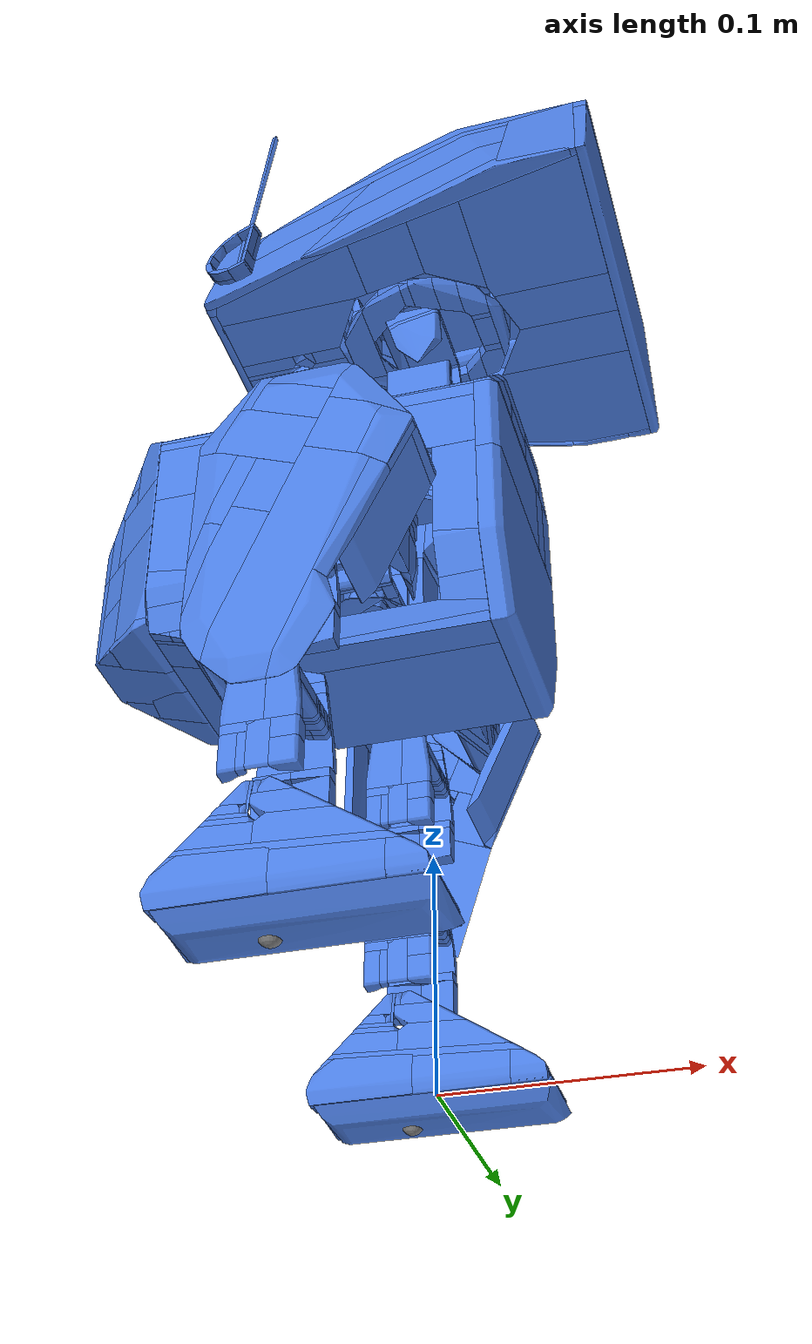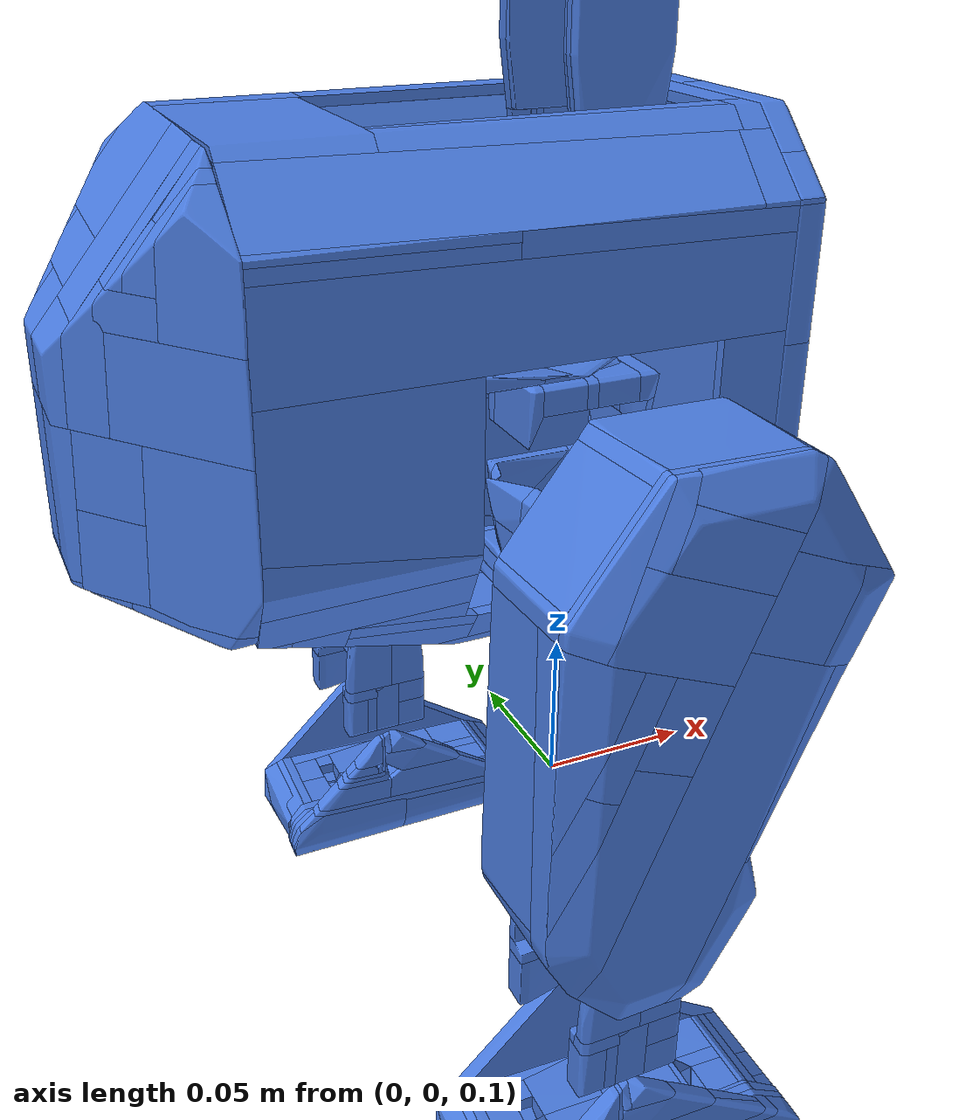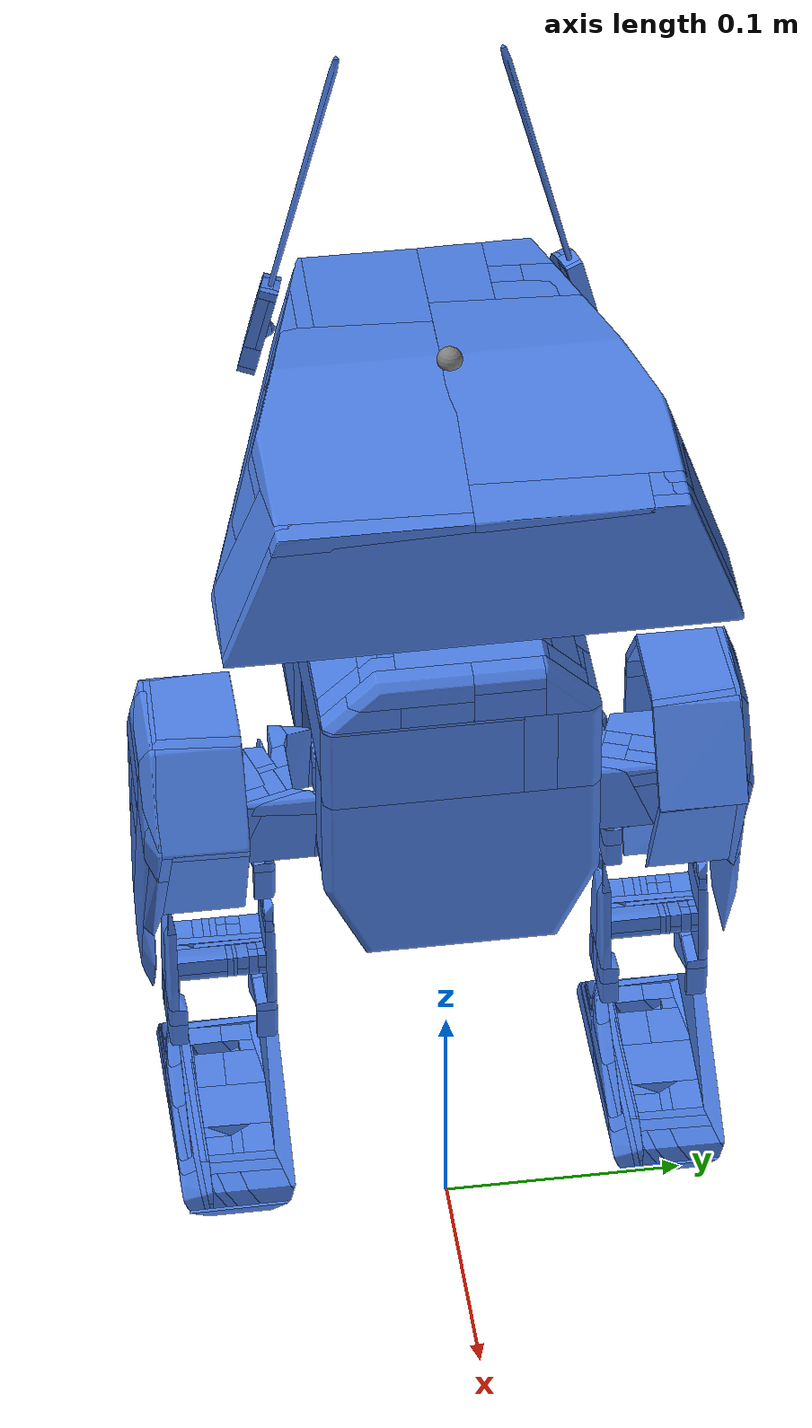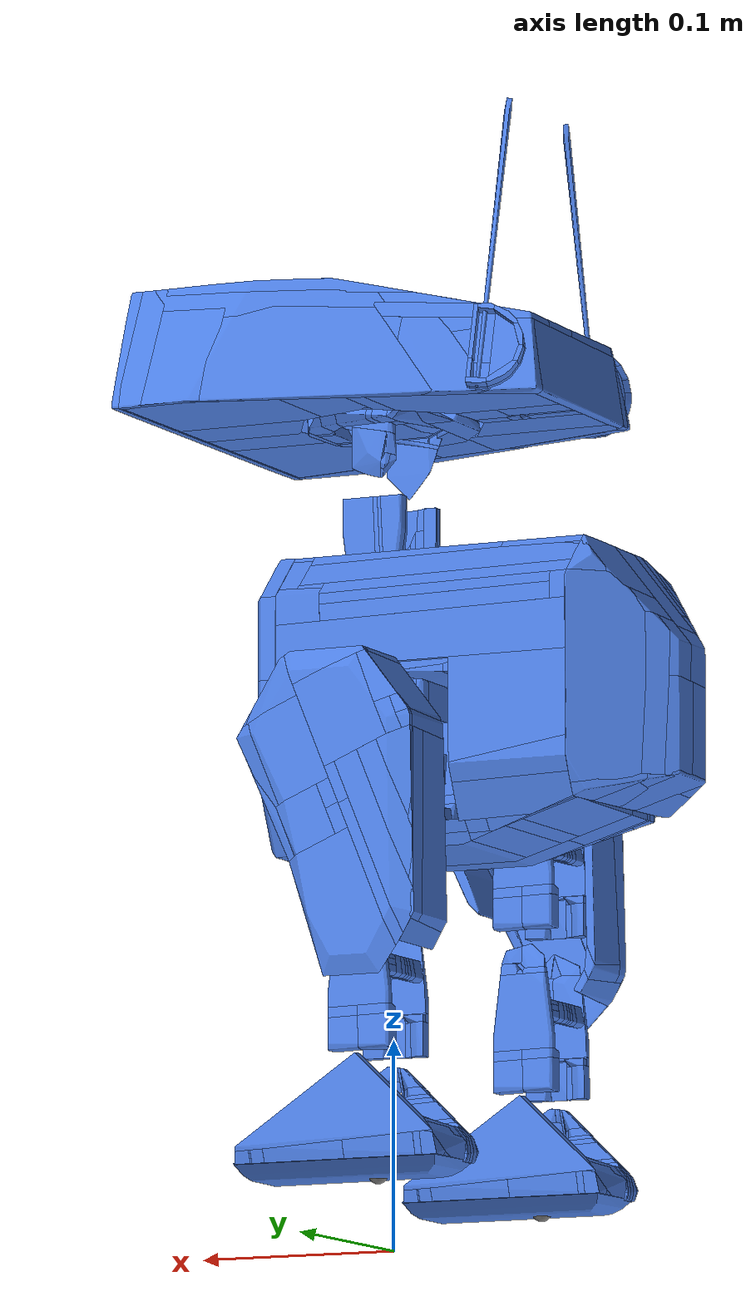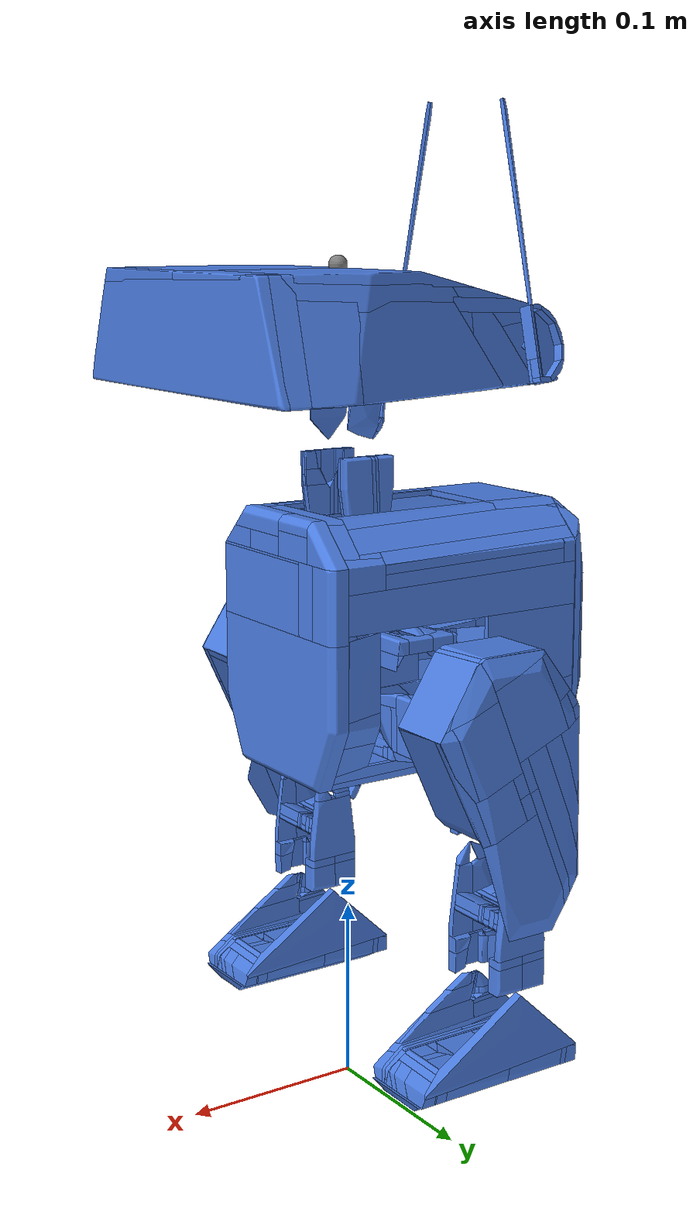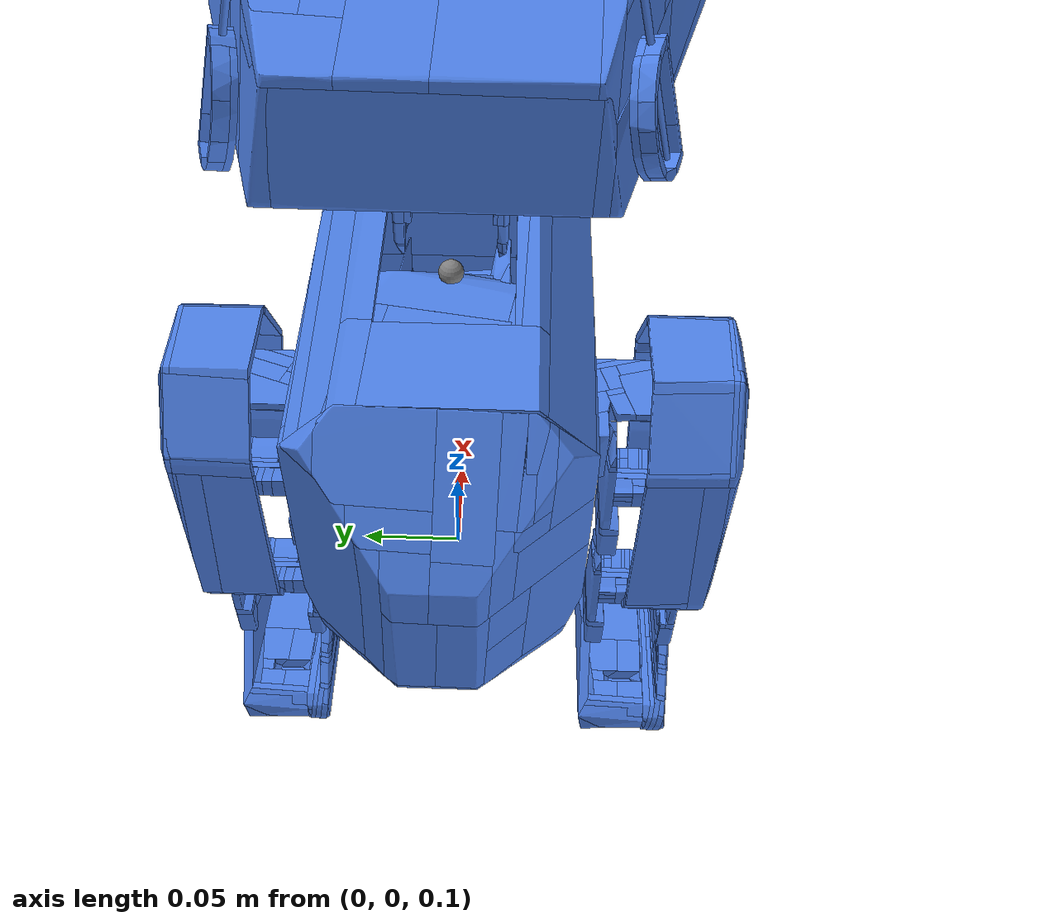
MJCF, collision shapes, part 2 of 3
<mesh name="recovery_left_roll_to_pitch_5" vertex="-0.01892475707 0.01479832831 0.02355297039 -0.01891539915 0.01482630165 0.02405607186 -0.01892475707 0.01482630165 0.02358131573 -0.01892475707 0.01482630165 0.02355297039 -0.01888420513 0.01435214948 0.02355297039 -0.01888420513 0.01435214948 0.02358131573 -0.01887484721 0.01862232103 0.02405607186 -0.01889980355 0.01482630165 0.02453083083 -0.01877814773 0.01577600629 0.02975174946 -0.01879062308 0.01577600629 0.02927699191 -0.01885925161 0.01530185271 0.02642844518 -0.01884989369 0.01814816745 0.02547892867 -0.01888108771 0.01862232103 0.02358131573 -0.01888108771 0.01862232103 0.02355297039 -0.01887796746 0.01432277726 0.02355297039 -0.01875319139 0.01384023181 0.02355297039 -0.01885925161 0.01435214948 0.02405607186 -0.01872199737 0.01540955085 0.03022508974 -0.01885613136 0.01862232103 0.02453083083 -0.01884365319 0.0190964732 0.02355297039 -0.01871263945 0.0158487367 0.03164794655 -0.01876254931 0.01577600629 0.03022508974 -0.01875319139 0.01624875958 0.03069984871 -0.01876566956 0.01624875958 0.03022508974 -0.01882181709 0.01767261639 0.02690320273 -0.01874383347 0.01380526549 0.02355297039 -0.01883117502 0.01435214948 0.02453083083 -0.01870639895 0.01451579431 0.02690320273 -0.01865337167 0.01517177532 0.03022508974 -0.01826032762 0.01441648803 0.03259746165 -0.01862841532 0.01533262381 0.03118877752 -0.01869080335 0.01551165489 0.03104139024 -0.01879686358 0.01435214948 0.02500558838 -0.01871887712 0.01654947619 0.03069984871 -0.01870328153 0.01651171211 0.03101729953 -0.01884053294 0.0190964732 0.02358131573 -0.01874383347 0.01939579093 0.02355297039 -0.01870016128 0.01592706262 0.0319512247 -0.01866896726 0.01561096117 0.03164794655 -0.01870016128 0.01604455292 0.0319512247 -0.01871263945 0.01609910072 0.03164794655 -0.01869080335 0.01361924001 0.02355297039 -0.0186939236 0.01408500174 0.02536271985 -0.01855666936 0.01340244484 0.02453083083 -0.01778305944 0.01205271873 0.02975174946 -0.01820417725 0.01366120073 0.03037814609 -0.01855354911 0.01482630165 0.03022508974 -0.01819169908 0.0141787125 0.03259746165 -0.01854731144 0.01530185271 0.03212270551 -0.01858474313 0.01530185271 0.03164794655 -0.01696577732 0.01055473123 0.03496983355 -0.01730267384 0.01159814804 0.03449507742 -0.01846308731 0.01613266958 0.03211561918 -0.01844437147 0.01655926693 0.03117460485 -0.0186876831 0.01696348504 0.02999692391 -0.01874383347 0.01845447815 0.02595368763 -0.01876566956 0.01896080172 0.02453083083 -0.01872823504 0.01890345474 0.02488654503 -0.01874071322 0.01939019683 0.02358131573 -0.01872199737 0.01940698055 0.02355297039 -0.01823537127 0.01449341507 0.032896488 -0.01826032762 0.01482630165 0.03291207794 -0.01825096969 0.01515918824 0.03287664909 -0.01838198343 0.01577600629 0.03250251042 -0.01831335773 0.01606553328 0.03241889733 -0.01862841532 0.01344720332 0.02355297039 -0.01859098363 0.01340244484 0.02405607186 -0.01778929711 0.01194921581 0.02925431705 -0.01721220921 0.01105406039 0.03358949476 -0.01748359744 0.01197858803 0.03354697675 -0.01728083774 0.01166668322 0.0347671757 -0.01684100125 0.010126735 0.03496983355 -0.0167536597 0.009958893532 0.03544459252 -0.01681916798 0.01019666906 0.03544459252 -0.01680044931 0.01026380607 0.03570110369 -0.01828528113 0.01650471771 0.03145804409 -0.01866584701 0.01790060118 0.02760471027 -0.01870639895 0.01840552445 0.02624704492 -0.0186939236 0.01934264059 0.02384066002 -0.01844749172 0.0194895017 0.02355297039 -0.01680044931 0.0103784979 0.03570110369 -0.0158552737 0.00938683325 0.03713387853 -0.01519084425 0.009132274002 0.03802954315 -0.01769883531 0.01598580848 0.03281570944 -0.01672870335 0.01599280146 0.03328763387 -0.01738377771 0.01604874814 0.03288656996 -0.01797022354 0.01610889146 0.03250959676 -0.01797022354 0.01629771329 0.03212270551 -0.01497560355 0.009413408419 0.03802954315 -0.01836326759 0.01304018745 0.02355297039 -0.01836638501 0.01303459194 0.02358131573 -0.01823849152 0.01266254381 0.02453083083 -0.01825720736 0.01263037383 0.02500558838 -0.01824472919 0.01262617719 0.02547892867 -0.01837886318 0.01292829267 0.02500558838 -0.0177269119 0.01177158361 0.02939603526 -0.01678173347 0.009853993147 0.0346878144 -0.016385572 0.009284729916 0.03629632186 -0.01640740809 0.009606426174 0.03629207006 -0.0158552737 0.009308507327 0.03713387853 -0.01797022354 0.01643898029 0.03175848771 -0.01821665543 0.01743763863 0.02904315559 -0.01844749172 0.01936222207 0.02389309607 -0.01844749172 0.01947971096 0.02358131573 -0.01841941512 0.01949369833 0.02355297039 -0.0153967242 0.008874916288 0.03768658435 -0.01510037962 0.008837152206 0.03802954315 -0.01354380184 0.01558158895 0.03525185553 -0.01260798416 0.01557459597 0.03572802893 -0.009688231088 0.0150808609 0.03759305039 -0.01641364576 0.01602916666 0.03334148719 -0.01164097246 0.01555501449 0.03618436343 -0.01533745359 0.01600958518 0.03377656268 -0.01702192768 0.0162417666 0.03259746165 -0.00895829335 0.01499134536 0.03802954315 -0.01799205963 0.01294787415 0.02355297039 -0.01821041775 0.01268911827 0.02428707506 -0.01774874517 0.01172822542 0.02756077782 -0.01727771749 0.01077572303 0.03084298418 -0.01776434359 0.01170724365 0.02785271784 -0.01679421164 0.009833012787 0.03413936322 -0.01679421164 0.009833012787 0.03437178085 -0.01776434359 0.01169605545 0.0283274768 -0.01641364576 0.009269344366 0.03591935149 -0.01797022354 0.01720126057 0.02975174946 -0.01180318092 0.01582915522 0.03544459252 -0.01826344504 0.01886708954 0.02526209955 -0.01793590927 0.01955803688 0.02355297039 -0.0153967242 0.008874916288 0.03748392367 -0.01494129211 0.008803584055 0.03802954315 -0.008802323265 0.01511722752 0.03802954315 -0.01059285546 0.01553543301 0.03662369355 -0.008481025878 0.01521373604 0.03802954315 -0.008481025878 0.01533262381 0.03781838169 -0.01027467762 0.01555641337 0.03667754687 -0.01797334379 0.01294647527 0.02355297039 -0.01819481933 0.01268911827 0.02428707506 -0.01607363182 0.009189619564 0.03591935149 -0.01637309382 0.009321095826 0.03553387468 -0.01795150769 0.01829922519 0.02686493794 -0.00917353122 0.01553683189 0.03709986696 -0.008481025878 0.01571306521 0.03686886659 -0.006107166692 0.01583614961 0.03734362273 -0.01655713768 0.01973427162 0.02355297039 -0.01512533597 0.008870720358 0.03746691929 -0.01464806779 0.008788198505 0.03802954315 -0.008000638863 0.01531584008 0.03802954315 -0.007551445865 0.01538996937 0.03802954315 -0.008481025878 0.01549067453 0.03745416389 -0.0034650397 0.009929521311 0.03802954315 -0.006575075888 0.009550479491 0.03802954315 -0.009204725237 0.009230181405 0.03802954315 -0.009691350631 0.009171436963 0.03802954315 -0.0101686181 0.009114090693 0.03802954315 -0.01064276603 0.009059542182 0.03802954315 -0.01132591345 0.009055346251 0.03781838169 -0.0172340453 0.01126386258 0.02902898434 0.01240020024 0.01706139244 0.02355297039 0.004330326826 0.01088062341 0.03802954315 0.003382030969 0.01076453341 0.03802954315 0.003038897488 0.0107225734 0.03802954315 -0.01607363182 0.009312703258 0.03551120124 -0.01512533597 0.009130875123 0.03639410762 -0.01464806779 0.00903296772 0.03686886659 -0.0155994839 0.009095908092 0.03639410762 -0.007055462549 0.01545430933 0.03802954315 -0.007055462549 0.01549207341 0.03793034012 -0.006060375666 0.01558158895 0.03802954315 -0.005633018763 0.01563613817 0.03802954315 -0.004915557784 0.01572705259 0.03802954315 -0.0155994839 0.01985595714 0.02355297039 -0.01449521795 0.01934543835 0.02527060174 -0.01607363182 0.0197958124 0.02355297039 -0.01512533597 0.009003594791 0.03686886659 -0.01464806779 0.00893366073 0.03729402121 -0.01464806779 0.008883308857 0.03753069065 -0.014439069 0.008792394435 0.03802954315 -0.01112315305 0.009010588481 0.03802954315 -0.01155362949 0.008968627761 0.03802954315 -0.01180318092 0.009009189601 0.03781838169 0.01276205028 0.01725161315 0.02355297039 0.01070636893 0.01270869975 0.03714946847 0.01008560884 0.01227091278 0.03802954315 0.006429678945 0.01133799328 0.03802954315 0.006220679455 0.01128484294 0.03802954315 0.005740293147 0.01116315742 0.03802954315 0.005281742227 0.01104846629 0.03802954315 0.005281742227 0.01111280484 0.03781838169 0.004810713134 0.01095195635 0.03802954315 0.004807594298 0.01102328929 0.03781838169 -0.01417391986 0.009074927732 0.03686886659 -0.013225624 0.009020379221 0.03734362273 -0.01227732885 0.008967229589 0.03781838169 -0.01197786685 0.008935059609 0.03802954315 -0.0127078053 0.0089294648 0.03784105796 -0.01419575595 0.008940654419 0.0373833062 -0.004419574467 0.01578859338 0.03802954315 -0.01513157364 0.0199133027 0.02355297039 -0.003758262789 0.01586971706 0.03802954315 -0.01405226404 0.008900092579 0.03761147203 -0.01369977193 0.008832956276 0.03802954315 0.01278388637 0.01726420165 0.02355297039 0.01076251859 0.01266534015 0.03746550202 0.0116920986 0.01458432949 0.03186194254 0.01050672807 0.01248211384 0.03802954315 -0.01238338837 0.008908485147 0.03802954315 -0.01254559683 0.008898694407 0.03802954315 -0.013225624 0.00892386999 0.03772484773 -0.0138619811 0.01980000904 0.02426865059 -0.002756937174 0.02142667505 0.02355297039 -0.000414272004 0.01627673293 0.03802954315 -0.000414272004 0.01635645773 0.03781838169 0.003382030969 0.01987413974 0.02968655942 0.003382030969 0.02002799383 0.02927699191 0.005755890156 0.0216812343 0.02564615768 0.005755890156 0.02192180758 0.02500558838 0.00574341269 0.02210923053 0.02450248691 0.005755890156 0.0224672927 0.02355297039 0.004330326826 0.02192600422 0.02453083083 0.01289930169 0.01767261639 0.02355297039 0.01290242194 0.01767261639 0.02358131573 0.01278700379 0.01726560053 0.02358131573 0.01271837809 0.01685298914 0.02547892867 0.01270278249 0.01690054538 0.02500558838 0.01076563601 0.01265554941 0.03781838169 0.01169521602 0.01458153315 0.03212270551 0.01075627809 0.01266534015 0.03802954315 0.003856178898 0.02223511269 0.02355297039 0.0003905315868 0.01637184399 0.03802954315 0.0005340238534 0.01652290173 0.03767524622 0.0005340238534 0.01682781356 0.03686886659 0.007178333942 0.02264072826 0.02355297039 0.003675253881 0.0198028068 0.0299714131 0.01281196014 0.01814816745 0.02355297039 0.01281508039 0.01814816745 0.02358131573 0.01293673621 0.01767261639 0.02405607186 0.01281196014 0.01725720866 0.02405607186 0.01283379623 0.01719846422 0.02500558838 0.01281508039 0.01719846422 0.02547892867 0.01269030432 0.0168250158 0.02595368763 0.0116920986 0.01458572837 0.03237638215 0.01076875626 0.01275345681 0.03802954315 0.01122106809 0.01362763187 0.0352532728 0.0005340238534 0.01638862771 0.03802954315 0.001600856693 0.01651311099 0.03802954315 0.004330326826 0.01984196976 0.03007486793 0.006704186013 0.02203650012 0.02500558838 0.00765248187 0.0226267423 0.02373862246 0.00765248187 0.02269667495 0.02355297039 0.01280572247 0.01817893855 0.02355297039 0.01269966224 0.01859994179 0.02355297039 0.01281819781 0.01814816745 0.02405607186 0.01292113778 0.01767261639 0.02453083083 0.01287746842 0.01767261639 0.02500558838 0.01282443831 0.01767261639 0.02547892867 0.01275893003 0.01767261639 0.02595368763 0.01274645185 0.01719846422 0.02595368763 0.01216624653 0.01593825224 0.02952925128 0.01122730859 0.0138779959 0.03529437071 0.01077811418 0.01292829267 0.03802954315 0.002112437372 0.01657185543 0.03802954315 0.002433735111 0.01668934431 0.03781838169 0.001959587183 0.01663479509 0.03781838169 0.007178333942 0.01867966659 0.03402173572 0.009340074095 0.02028115561 0.03045609294 0.009985789118 0.02132457101 0.02789806755 0.01002634106 0.02242393451 0.02500558838 0.0090780452 0.02286312036 0.02355297039 0.01262791629 0.01884610918 0.02355297039 0.01263103371 0.01883352068 0.02358131573 0.01266222772 0.01846706665 0.02595368763 0.01278700379 0.01814816745 0.02500558838 0.01269342174 0.01857056957 0.02405607186 0.01207266448 0.02004617643 0.02975174946 0.01264663213 0.01841251885 0.0267203852 0.01264039446 0.01736210905 0.02667787002 0.01266846823 0.01720126057 0.02646812583 0.01264663213 0.01814816745 0.02673313919 0.01261231786 0.01814816745 0.0269712273 0.01241579584 0.01862232103 0.0283274768 0.01247818387 0.01814816745 0.02785271784 0.01244387243 0.01672431064 0.02785271784 0.01221303614 0.01624875958 0.02927699191 0.01082802404 0.01340244484 0.03781838169 0.0107874721 0.01312970158 0.03802954315 0.002433735111 0.01660262653 0.03802954315 0.004330326826 0.01739707679 0.03653015676 0.007914510766 0.0188572988 0.03377656268 0.004330326826 0.01748798979 0.03629348733 0.01096527829 0.02020982267 0.0311434278 0.01047553405 0.02068957036 0.02972624007 0.01050048899 0.0217791417 0.02685501849 0.01108069643 0.02172319502 0.0271809715 0.01002634106 0.02297361626 0.02355297039 0.01227230392 0.02004617643 0.02355297039 0.01191357414 0.02099588107 0.02595368763 0.0126528698 0.01844049219 0.02642844518 0.01205082838 0.02004617643 0.03022508974 0.01164842641 0.02204349311 0.02453083083 0.01174512588 0.02151059508 0.02641285525 0.01185118611 0.02099588107 0.02785271784 0.01215376836 0.01971329126 0.02975174946 0.01213505251 0.01955524053 0.03019532997 0.01207266448 0.01957202426 0.03069984871 0.01224735041 0.01767261639 0.02927699191 0.01218184212 0.01719846422 0.02962845431 0.01205082838 0.01862232103 0.03069984871 0.01086233831 0.01482630165 0.03781838169 0.01082490662 0.01463048685 0.03802954315 0.01081242845 0.01412556216 0.03802954315 0.002627137593 0.01661941025 0.03802954315 0.007013005934 0.01838454551 0.03473032958 0.008229569773 0.01887408252 0.03381057426 0.01050048899 0.01984196976 0.03195405923 0.009193461931 0.01934823611 0.03286531096 0.01050048899 0.01996365528 0.03164794655 0.01145190439 0.02031332417 0.03100879593 0.01145190439 0.02043361082 0.03069984871 0.01097775646 0.0226393308 0.02472498509 0.01052544392 0.02303096041 0.02355297039 0.01035387682 0.02301137893 0.02355297039 0.01166402201 0.02209664203 0.02355297039 0.01156732253 0.02241973788 0.02358131573 0.01172641004 0.02183229204 0.02405607186 0.01198844035 0.02004617643 0.03069984871 0.01168273785 0.02169522168 0.0265616612 0.01193853049 0.02052033001 0.02927699191 0.01171705212 0.02126582657 0.02822260471 0.01169521602 0.02172739166 0.02595368763 0.01199779827 0.01957202426 0.03117318758 0.01184182819 0.0190964732 0.03212270551 0.01158915863 0.01767261639 0.03354697675 0.01084050222 0.01530185271 0.03802954315 0.01135832233 0.01719846422 0.03496983355 0.00290788304 0.01662640323 0.03802954315 0.004807594298 0.01740826641 0.0365712575 0.008603897271 0.01887688028 0.03381340879 0.01097775646 0.01985455826 0.03196539737 0.01145190439 0.02021401931 0.03124688263 0.01173576796 0.02031332417 0.03100454413 0.01145190439 0.0208154511 0.02967380402 0.01097775646 0.02272884493 0.02448689838 0.01063462298 0.02304215145 0.02355297039 0.01156732253 0.02241973788 0.02355297039 0.01155796461 0.02244771122 0.02355297039 0.01177320248 0.02085601294 0.02927699191 0.01183247026 0.02045738893 0.03022508974 0.01179191832 0.02037207003 0.03069984871 0.01184182819 0.02006715679 0.03116752134 0.01177320248 0.0199077086 0.03164794655 0.01189173805 0.01957202426 0.03164794655 0.01153924594 0.02241973788 0.02405607186 0.01133648624 0.02291207406 0.02355722219 0.01173576796 0.02080286402 0.02964120971 0.01133336599 0.02291766675 0.02355297039 0.01133336599 0.02278199668 0.02405607186 0.01128345613 0.02271485896 0.02444721632 0.01170145652 0.0189062525 0.03289790527 0.01122418834 0.01719846422 0.035733698 0.01127721846 0.01719846422 0.03544459252 0.01084050222 0.01556480523 0.03802954315 0.003101285522 0.01663059987 0.03802954315 0.006230038084 0.01789640596 0.03565575398 0.007437243294 0.01838594297 0.03473458139 0.008962627053 0.01886708954 0.03379640442 0.01002634106 0.01936082319 0.03287948363 0.01145190439 0.01984476752 0.03194413836 0.01145190439 0.02001260898 0.03164794655 0.01171081445 0.01982798238 0.03191579585 0.01104326191 0.0230743186 0.02355297039 0.01097775646 0.0230743186 0.02355297039 0.01133648624 0.02291207406 0.02355297039 0.01172641004 0.01939159429 0.03244865711 0.01121795067 0.01744183385 0.03569118282 0.01087481648 0.01577600629 0.03781838169 0.01083114429 0.01576062003 0.03802954315 0.003559836442 0.01661101839 0.03802954315 0.003856178898 0.01691453134 0.0374952618 0.004330326826 0.01704320984 0.03724300243 0.008129749342 0.01851042625 0.03446389754 0.009552193128 0.01899436916 0.03352997238 0.01096839854 0.01945173761 0.03263855956 0.01111812812 0.01932865463 0.03282563031 0.01097775646 0.01860833365 0.03402173572 0.01050048899 0.01662080913 0.03732520108 0.01078123443 0.0169844654 0.03666904326 0.01077499676 0.01606832962 0.03802954315 0.004012148276 0.01658444251 0.03802954315 0.004807594298 0.01703062276 0.03721891172 0.008129749342 0.01783905898 0.03556505172 0.01080307053 0.01933844537 0.03284121742 0.00977678892 0.01623617109 0.03802954315 0.01050048899 0.01685858466 0.03693688974 0.01003881782 0.01621938736 0.03802954315 0.01024781801 0.01619700812 0.03802954315 0.01050048899 0.01616623702 0.03802954315" face="0 1 2 0 2 3 0 3 13 0 13 19 0 19 36 0 36 59 0 59 79 0 79 104 0 104 127 0 127 143 0 143 172 0 172 170 0 170 197 0 197 209 0 209 227 0 227 217 0 217 231 0 231 248 0 248 267 0 267 293 0 293 320 0 320 319 0 319 342 0 342 370 0 370 369 0 369 354 0 354 371 0 371 344 0 344 343 0 343 321 0 321 294 0 294 268 0 268 250 0 250 249 0 249 233 0 233 219 0 219 201 0 201 180 0 180 157 0 157 135 0 135 115 0 115 89 0 89 65 0 65 41 0 41 25 0 25 15 0 15 14 0 14 4 0 4 5 0 5 1 1 6 2 1 5 7 1 7 8 1 8 9 1 9 10 1 10 11 1 11 6 2 6 12 2 12 13 2 13 3 4 14 5 5 14 15 5 15 16 5 16 17 5 17 7 6 11 18 6 18 19 6 19 12 7 17 20 7 20 21 7 21 8 8 21 22 8 22 23 8 23 9 9 23 10 10 23 11 11 24 18 11 23 22 11 22 24 12 19 13 15 25 26 15 26 16 16 26 17 17 27 28 17 28 47 17 47 29 17 29 30 17 30 31 17 31 20 17 26 32 17 32 27 18 24 33 18 33 34 18 34 19 19 35 36 19 34 35 20 37 22 20 22 21 20 31 38 20 38 37 22 37 39 22 39 40 22 40 24 24 40 33 25 41 26 26 41 32 27 42 43 27 43 44 27 44 45 27 45 46 27 46 28 27 32 42 28 46 47 29 48 49 29 49 31 29 31 30 29 47 50 29 50 51 29 51 48 31 49 48 31 48 38 32 41 42 33 40 39 33 39 34 34 39 52 34 52 53 34 53 54 34 54 55 34 55 35 35 55 56 35 56 36 36 56 55 36 55 57 36 57 58 36 58 59 37 38 48 37 48 60 37 60 61 37 61 39 39 61 62 39 62 63 39 63 64 39 64 52 41 65 66 41 66 43 41 43 42 43 66 67 43 67 44 44 67 68 44 68 45 45 68 46 46 68 47 47 68 69 47 69 50 48 51 70 48 70 60 50 69 68 50 68 71 50 71 72 50 72 51 51 72 73 51 73 74 51 74 70 52 64 53 53 64 75 53 75 54 54 76 77 54 77 57 54 57 55 54 75 76 57 77 78 57 78 58 58 78 59 59 78 79 60 70 61 61 70 74 61 74 80 61 80 62 62 80 81 62 81 82 62 82 63 63 82 64 64 83 84 64 84 85 64 85 86 64 86 87 64 87 75 64 82 88 64 88 83 65 89 90 65 90 91 65 91 92 65 92 93 65 93 94 65 94 66 66 95 67 66 94 96 66 96 95 67 95 96 67 96 71 67 71 68 71 96 72 72 74 73 72 96 97 72 97 74 74 97 98 74 98 99 74 99 81 74 81 80 75 87 100 75 100 101 75 101 78 75 78 76 76 78 77 78 101 102 78 102 103 78 103 79 79 103 104 81 99 82 82 99 105 82 105 106 82 106 129 82 129 145 82 145 176 82 176 200 82 200 206 82 206 205 82 205 193 82 193 178 82 178 177 82 177 154 82 154 153 82 153 152 82 152 151 82 151 150 82 150 149 82 149 160 82 160 159 82 159 158 82 158 188 82 188 186 82 186 185 82 185 184 82 184 183 82 183 182 82 182 204 82 204 226 82 226 241 82 241 259 82 259 284 82 284 309 82 309 308 82 308 332 82 332 360 82 360 375 82 375 386 82 386 395 82 395 394 82 394 393 82 393 391 82 391 387 82 387 376 82 376 361 82 361 334 82 334 310 82 310 285 82 285 260 82 260 244 82 244 243 82 243 228 82 228 210 82 210 198 82 198 196 82 196 169 82 169 168 82 168 167 82 167 165 82 165 147 82 147 146 82 146 132 82 132 130 82 130 114 82 114 88 83 107 108 83 108 84 83 88 109 83 109 107 84 110 87 84 87 86 84 86 85 84 108 111 84 111 110 87 110 112 87 112 113 87 113 100 88 114 109 89 115 116 89 116 90 90 116 91 91 116 117 91 117 118 91 118 119 91 119 92 92 119 118 92 118 120 92 120 121 92 121 122 92 122 93 93 122 121 93 121 94 94 121 96 96 121 123 96 123 97 97 99 98 97 123 105 97 105 99 100 124 101 100 113 125 100 125 124 101 126 102 101 124 126 102 126 127 102 127 103 103 127 104 105 128 129 105 129 106 105 123 128 107 109 130 107 130 108 108 130 111 109 114 130 110 111 131 110 131 112 111 130 132 111 132 133 111 133 131 112 131 134 112 134 125 112 125 113 115 135 116 116 136 137 116 137 138 116 138 117 116 135 136 117 138 118 118 138 120 120 138 123 120 123 121 123 138 137 123 137 128 124 139 126 124 125 139 125 134 140 125 140 141 125 141 142 125 142 143 125 143 139 126 139 127 127 139 143 128 144 145 128 145 129 128 137 144 131 133 146 131 146 147 131 147 134 132 146 133 134 148 140 134 147 148 135 149 150 135 150 151 135 151 152 135 152 153 135 153 154 135 154 155 135 155 156 135 156 136 135 157 158 135 158 159 135 159 160 135 160 149 136 156 161 136 161 137 137 161 162 137 162 163 137 163 164 137 164 144 140 148 165 140 165 166 140 166 167 140 167 142 140 142 141 142 167 168 142 168 169 142 169 170 142 170 171 142 171 172 142 172 143 144 164 173 144 173 174 144 174 175 144 175 176 144 176 145 147 165 148 154 177 155 155 177 178 155 178 179 155 179 161 155 161 156 157 180 181 157 181 182 157 182 183 157 183 184 157 184 185 157 185 186 157 186 187 157 187 188 157 188 189 157 189 158 158 189 188 161 190 162 161 179 190 162 190 163 163 190 191 163 191 178 163 178 192 163 192 193 163 193 194 163 194 195 163 195 174 163 174 173 163 173 164 165 167 166 169 196 170 170 172 171 170 196 198 170 198 197 174 195 199 174 199 175 175 199 200 175 200 176 178 193 192 178 191 190 178 190 179 180 201 181 181 202 182 181 201 203 181 203 202 182 202 204 186 188 187 193 205 194 194 205 206 194 206 207 194 207 195 195 207 199 197 198 208 197 208 209 198 210 211 198 211 212 198 212 213 198 213 214 198 214 215 198 215 216 198 216 217 198 217 218 198 218 209 198 209 208 199 207 206 199 206 200 201 219 220 201 220 221 201 221 222 201 222 223 201 223 203 202 224 204 202 203 224 203 223 222 203 222 225 203 225 224 204 224 226 209 218 227 210 228 229 210 229 230 210 230 211 211 230 231 211 231 232 211 232 212 212 232 214 212 214 213 214 231 215 214 232 231 215 231 216 216 231 217 217 227 218 219 233 234 219 234 220 220 234 235 220 235 221 221 235 236 221 236 222 222 236 237 222 237 238 222 238 239 222 239 240 222 240 225 224 225 240 224 240 226 226 240 242 226 242 241 228 243 229 229 243 244 229 244 245 229 245 230 230 245 246 230 246 231 231 246 247 231 247 248 233 249 234 234 249 250 234 250 251 234 251 235 235 252 237 235 237 236 235 251 271 235 271 252 237 252 238 238 252 253 238 253 254 238 254 255 238 255 256 238 256 240 238 240 239 240 256 257 240 257 258 240 258 259 240 259 242 241 242 259 244 260 261 244 261 262 244 262 263 244 263 264 244 264 245 245 264 265 245 265 266 245 266 267 245 267 247 245 247 246 247 267 248 250 268 269 250 269 251 251 270 271 251 269 272 251 272 273 251 273 270 252 271 274 252 274 253 253 274 254 254 274 255 255 275 276 255 276 256 255 274 277 255 277 278 255 278 279 255 279 280 255 280 275 256 276 257 257 276 281 257 281 282 257 282 283 257 283 258 258 283 284 258 284 259 260 285 261 261 285 286 261 286 287 261 287 288 261 288 262 262 288 263 263 287 289 263 289 290 263 290 264 263 288 287 264 290 265 265 290 291 265 291 266 266 291 292 266 292 293 266 293 267 268 294 269 269 273 272 269 294 295 269 295 273 270 296 271 270 273 296 271 296 274 273 297 296 273 295 298 273 298 299 273 299 300 273 300 297 274 296 297 274 297 301 274 301 302 274 302 303 274 303 277 275 280 304 275 304 305 275 305 282 275 282 281 275 281 276 277 303 278 278 303 279 279 303 280 280 303 306 280 306 304 282 305 283 283 307 308 283 308 309 283 309 284 283 305 307 285 310 286 286 310 311 286 311 287 287 311 312 287 312 313 287 313 314 287 314 315 287 315 289 289 315 316 289 316 317 289 317 292 289 292 290 290 292 291 292 318 319 292 319 320 292 320 293 292 317 318 294 321 322 294 322 323 294 323 295 295 323 298 297 324 303 297 303 302 297 302 301 297 300 325 297 325 326 297 326 327 297 327 324 298 323 322 298 322 299 299 322 328 299 328 300 300 328 325 303 324 329 303 329 330 303 330 331 303 331 306 304 306 305 305 306 331 305 331 307 307 332 308 307 331 333 307 333 332 310 334 335 310 335 311 311 335 312 312 335 336 312 336 337 312 337 338 312 338 313 313 338 316 313 316 315 313 315 314 316 338 339 316 339 317 317 339 340 317 340 341 317 341 318 318 341 319 319 341 342 321 343 322 322 343 344 322 344 325 322 325 328 324 327 345 324 345 346 324 346 347 324 347 348 324 348 349 324 349 350 324 350 329 325 327 326 325 344 351 325 351 352 325 352 327 327 353 345 327 352 354 327 354 355 327 355 356 327 356 353 329 350 357 329 357 330 330 332 333 330 333 331 330 357 358 330 358 359 330 359 360 330 360 332 334 361 335 335 361 362 335 362 336 336 362 363 336 363 364 336 364 365 336 365 337 337 365 366 337 366 367 337 367 338 338 367 339 339 368 349 339 349 348 339 348 347 339 347 353 339 353 369 339 369 340 339 367 368 340 369 370 340 370 341 341 370 342 344 371 352 344 352 351 345 353 346 346 353 347 349 368 372 349 372 350 350 372 357 352 371 354 353 356 369 354 356 355 354 369 356 357 372 373 357 373 358 358 373 374 358 374 359 359 374 360 360 374 375 361 376 377 361 377 362 362 377 378 362 378 363 363 379 364 363 378 376 363 376 379 364 379 380 364 380 365 365 380 366 366 368 367 366 380 381 366 381 382 366 382 383 366 383 384 366 384 368 368 384 385 368 385 386 368 386 373 368 373 372 373 386 375 373 375 374 376 387 388 376 388 379 376 378 377 379 388 387 379 387 380 380 389 383 380 383 390 380 390 381 380 387 389 381 390 382 382 390 383 383 389 391 383 391 392 383 392 384 384 392 393 384 393 394 384 394 395 384 395 385 385 395 386 387 391 389 391 393 392" />
    <mesh name="recovery_left_roll_to_pitch_6" vertex="0.01055977304 0.02461025972 0.01938750686 0.01069132992 0.02456067235 0.01956114611 0.01075397538 0.02456067235 0.01956114611 0.01079782721 0.0245937306 0.01938750686 0.01031232134 0.02458192287 0.01938750686 0.01050025914 0.0242749502 0.02025855035 0.01052531732 0.02303171006 0.02355114718 0.0107289172 0.02313206727 0.02334612438 0.01097636889 0.02314269253 0.02337424907 0.01123008514 0.02314505464 0.02338158576 0.01002728095 0.02454886462 0.01938750686 0.01122068761 0.02361495926 0.0219500924 0.01083854746 0.02455831024 0.01938750686 0.0094102182 0.02406951439 0.02046601871 0.009093855081 0.02304823919 0.02306732591 0.009551171197 0.02291836831 0.02355114718 0.01063494759 0.02304233815 0.02355114718 0.01054411096 0.02303997604 0.02353484295 0.01097636889 0.02307421393 0.02355114718 0.01104214734 0.0230753964 0.02355114718 0.01133345086 0.02291836831 0.02355114718 0.01126767241 0.02318755851 0.0231056402 0.009551171197 0.02434342881 0.0197836952 0.009078194423 0.02443670251 0.01938750686 0.01123634968 0.02363857189 0.02168189089 0.01117370422 0.02402228913 0.02025855035 0.01141489137 0.02289357321 0.0231056402 0.01110792578 0.02422890459 0.01938750686 0.008448601872 0.02359606802 0.02141939665 0.008764964284 0.02361495926 0.02146830792 0.007652997433 0.02271647425 0.0235001977 0.008630275126 0.0228109276 0.02355114718 0.01155584437 0.0224484637 0.02355114718 0.008602084669 0.02423008423 0.0197836952 0.008602084669 0.02411083861 0.02010121675 0.004730560465 0.0239054028 0.01938750686 0.0113397154 0.02336819922 0.02168189089 0.01125201176 0.02368107575 0.02120744452 0.01120189397 0.02404944351 0.0197836952 0.01156837346 0.02241894579 0.02355114718 0.01145561021 0.02289357321 0.02263119242 0.0112112915 0.02406833475 0.01943641954 0.0112112915 0.02407069686 0.01938750686 0.008129107187 0.02357717679 0.02136763104 0.007180019952 0.0226881374 0.0234256059 0.006685116559 0.02258069668 0.02355114718 0.007652997433 0.02269640338 0.02355114718 0.008135371734 0.02275307425 0.02355114718 0.007652997433 0.02363739225 0.02105337119 -0.001364897441 0.02316040413 0.01938750686 0.004138555191 0.02360079225 0.02000665308 0.007652997433 0.02340125747 0.02168189089 0.00764986516 0.0232099915 0.02218976185 0.01173438606 0.02185931064 0.02355114718 0.01211965918 0.02060898841 0.0231056402 0.01174378217 0.02198328048 0.02211924646 0.01151825709 0.02289357321 0.02073299673 0.01164668099 0.02251221808 0.02025855035 0.01144308112 0.023290275 0.01938750686 0.007180019952 0.02280856549 0.0231056402 0.006230932716 0.02263028547 0.02327153399 0.006230932716 0.02252520545 0.02355114718 0.006851128448 0.02266806652 0.02337261822 0.006703910198 0.02316394588 0.02200511828 0.003499565822 0.02314623428 0.02100934964 -0.0004158102054 0.02174950923 0.02345413794 -0.00275563925 0.02299038867 0.01938750686 0.007180019952 0.02298684692 0.02263119242 0.01198183775 0.02102458143 0.02355114718 0.01205074776 0.02099506493 0.02168189089 0.0121165262 0.0205700263 0.02355114718 0.01262709167 0.01884625628 0.02355114718 0.01258010686 0.01905405279 0.02309911823 0.01263962076 0.01886632716 0.0229368935 0.01154957982 0.02289357321 0.01938750686 0.01263962076 0.01886632716 0.02285496642 -0.0004158102054 0.02171290923 0.02355114718 -0.01607418345 0.0212677983 0.01963858942 -0.002313984765 0.02236109386 0.02120744452 -0.0004158102054 0.02216510366 0.02234750282 -0.01322692246 0.02117452601 0.02081410909 -0.01322692246 0.02049210207 0.02263119242 -0.01417600898 0.02003046202 0.02355114718 -0.01237180341 0.02181444608 0.01938750686 0.01263022323 0.01883562961 0.02355114718 0.01269913466 0.0186006773 0.02355114718 0.01280563194 0.01818036147 0.02355114718 0.01156524189 0.02282981883 0.01938750686 0.01281189649 0.01814848287 0.02355114718 0.01289960155 0.01767385544 0.02355114718 0.01237650699 0.01957118408 0.02168189089 0.01170932646 0.02205530084 0.01938750686 0.01169679736 0.02223240121 0.01948288666 0.01171245944 0.02227254438 0.0197836952 -0.01428250627 0.02158067483 0.01938750686 -0.01464898717 0.02153580885 0.01938750686 -0.01641873632 0.02124654637 0.01958193269 -0.01797235793 0.02098089651 0.0197836952 -0.01607418345 0.02050036664 0.02168189089 -0.01546025227 0.02029611188 0.02242576226 -0.01513136006 0.0199135771 0.02355114718 0.01166860761 0.02233039631 0.01938750686 0.01278370674 0.01726652698 0.02355114718 0.01275238401 0.01725944348 0.0231056402 0.01271479532 0.01725353961 0.02263119242 0.01268034102 0.01726888768 0.02215633868 0.01265528142 0.01733736628 0.02180947038 0.01233578673 0.01719922943 0.01938750686 0.01265528142 0.01756523509 0.02180947038 0.01283382311 0.01767385544 0.0231056402 0.01268973713 0.01819334884 0.02258594878 0.01257070934 0.01862192923 0.02215633868 0.01197870477 0.02099506493 0.02025855035 0.01191919088 0.0204425147 0.01938750686 -0.01521593214 0.0214661506 0.01938750686 -0.0184453347 0.02092186352 0.0197836952 -0.01797235793 0.02082504948 0.02019822457 -0.01751817479 0.02068927333 0.02070813374 -0.01607418345 0.0201438066 0.02263119242 -0.01673509944 0.02122647549 0.01952894501 -0.0155980737 0.01985572376 0.02355114718 0.0127649131 0.01725235856 0.02355114718 0.01253938661 0.01703157468 0.02215633868 0.01228567036 0.01684384904 0.0197836952 0.01226374375 0.01684384904 0.01938750686 0.01238590452 0.01719922943 0.0197836952 0.01240782972 0.01767385544 0.02025855035 0.01227627425 0.01767385544 0.01938750686 0.0126584144 0.01806465619 0.02226190668 0.01222615647 0.01806583725 0.01938750686 -0.01617441761 0.02134572252 0.01938750686 -0.01805066546 0.02108361442 0.01938750686 -0.0184453347 0.02102103968 0.01938750686 -0.01876169782 0.02082504948 0.0197836952 -0.0187053169 0.0207731 0.02005964076 -0.0184453347 0.02079553299 0.02011874305 -0.01672257035 0.0212748818 0.01938750686 -0.01702326998 0.02123355899 0.01938750686 -0.01689171451 0.02029729293 0.02195457616 -0.01607418345 0.01984155533 0.02342968231 -0.01607418345 0.01979550971 0.02355114718 0.01240156518 0.01706227222 0.02355114718 0.01232952219 0.01691823151 0.02168189089 0.01232325764 0.01689815922 0.02120744452 0.01231072855 0.01687808834 0.02073299673 0.01229819946 0.01685919852 0.02025855035 0.01198496932 0.01670571219 0.01938750686 -0.01849858405 0.02100451055 0.01938750686 -0.01880241808 0.0208710951 0.01938750686 -0.01889951925 0.02052043751 0.0197836952 -0.01879615353 0.02040355259 0.02073299673 -0.01877109393 0.01989822762 0.02215633868 -0.01874603575 0.02033625504 0.02110921179 -0.01872097756 0.01983919463 0.0224750823 -0.01862700937 0.02027131819 0.02142591862 -0.01846099677 0.02036695118 0.02124372061 -0.01720807622 0.02027722064 0.02190158849 -0.01655655776 0.01973411603 0.02355114718 0.012235554 0.01695247081 0.02250932019 0.01230133244 0.01693830239 0.02215633868 -0.01797235793 0.01294647527 0.02355114718 0.01192545542 0.01669744621 0.0197836952 0.01192545542 0.01668091709 0.01938750686 -0.01894337107 0.02052043751 0.01938750686 -0.01892457743 0.0200458115 0.02073299673 -0.01888699016 0.01957118408 0.02215633868 -0.018786756 0.01947082687 0.0231056402 -0.01874290418 0.01939526476 0.02355114718 -0.01872097756 0.01940707107 0.02355114718 -0.0184453347 0.0194897181 0.02355114718 -0.01842027652 0.01949444091 0.02355114718 -0.0184453347 0.01986989218 0.02255578731 -0.01797235793 0.0195534739 0.02355114718 -0.01702326998 0.0197813427 0.02326990314 0.01192545542 0.01673168552 0.02025855035 -0.01799115156 0.01294883739 0.02355114718 -0.0184703943 0.01254977349 0.01938750686 0.01153078618 0.01662070305 0.01938750686 -0.01895590017 0.0200458115 0.01938750686 -0.0189527686 0.0200458115 0.0197836952 -0.01894650405 0.0200458115 0.02025855035 -0.01892144445 0.01957118408 0.02168189089 -0.01889012172 0.01909655666 0.0231056402 -0.0188462699 0.01909655666 0.02355114718 -0.01836076262 0.01303974898 0.02355114718 -0.01873037509 0.01260762542 0.01938750686 -0.01909058862 0.01482727479 0.01938750686 -0.01888072561 0.01862192923 0.02355114718 -0.01909998614 0.01435264736 0.01938750686 -0.01862700937 0.01344707744 0.02355114718 -0.01874916873 0.01264422683 0.01938750686 -0.018927709 0.01482727479 0.02355114718 -0.01903734068 0.01387801994 0.01938750686 -0.01902167861 0.01387801994 0.0197836952 -0.01888385718 0.01435264736 0.02355114718 -0.01864893457 0.01350374973 0.02355114718 -0.01888072561 0.01300669073 0.01938750686 -0.01898095835 0.01348131674 0.01938750686 -0.01887759263 0.01432313087 0.02355114718 -0.01896529769 0.01340339252 0.01938750686 -0.01868965483 0.01361945501 0.02355114718 -0.01874290418 0.01380481853 0.02355114718 -0.01875230029 0.01384023889 0.02355114718" face="0 1 2 0 2 3 0 3 12 0 12 27 0 27 42 0 42 58 0 58 74 0 74 87 0 87 101 0 101 91 0 91 113 0 113 129 0 129 127 0 127 107 0 107 124 0 124 146 0 146 162 0 162 177 0 177 176 0 176 185 0 185 190 0 190 196 0 196 199 0 199 197 0 197 192 0 192 188 0 188 186 0 186 178 0 178 163 0 163 148 0 148 147 0 147 132 0 132 131 0 131 137 0 137 136 0 136 130 0 130 114 0 114 95 0 95 94 0 94 83 0 83 66 0 66 49 0 49 35 0 35 23 0 23 10 0 10 4 0 4 1 1 5 6 1 6 7 1 7 8 1 8 9 1 9 2 1 4 10 1 10 5 2 9 11 2 11 3 3 11 12 5 10 13 5 13 14 5 14 15 5 15 6 6 16 17 6 17 7 6 15 31 6 31 47 6 47 46 6 46 45 6 45 61 6 61 76 6 76 82 6 82 100 6 100 120 6 120 140 6 140 157 6 157 172 6 172 170 6 170 169 6 169 168 6 168 167 6 167 183 6 183 187 6 187 191 6 191 194 6 194 198 6 198 202 6 202 201 6 201 200 6 200 195 6 195 189 6 189 184 6 184 175 6 175 160 6 160 141 6 141 121 6 121 102 6 102 89 6 89 88 6 88 86 6 86 85 6 85 84 6 84 71 6 71 70 6 70 68 6 68 53 6 53 39 6 39 32 6 32 20 6 20 19 6 19 18 6 18 16 7 17 16 7 16 18 7 18 8 8 18 9 9 18 19 9 19 20 9 20 21 9 21 11 10 22 13 10 23 22 11 24 25 11 25 12 11 21 26 11 26 24 12 25 27 13 22 23 13 23 28 13 28 29 13 29 30 13 30 14 14 30 15 15 30 31 20 32 26 20 26 21 23 33 34 23 34 28 23 35 33 24 36 37 24 37 38 24 38 25 24 26 39 24 39 40 24 40 36 25 38 27 26 32 39 27 38 41 27 41 42 28 34 43 28 43 44 28 44 30 28 30 29 30 44 45 30 45 46 30 46 47 30 47 31 33 48 34 33 35 49 33 49 50 33 50 48 34 48 51 34 51 52 34 52 43 36 38 37 36 40 38 38 40 41 39 53 54 39 54 55 39 55 56 39 56 41 39 41 40 41 56 57 41 57 58 41 58 42 43 52 44 44 52 59 44 59 45 45 60 61 45 59 62 45 62 60 48 63 51 48 50 64 48 64 65 48 65 63 49 66 50 50 66 64 51 63 67 51 67 59 51 59 52 53 68 54 54 69 57 54 57 55 54 68 70 54 70 71 54 71 72 54 72 69 55 57 56 57 69 72 57 72 73 57 73 58 58 73 75 58 75 74 59 67 63 59 63 62 60 62 63 60 63 65 60 65 61 61 65 76 64 66 77 64 77 78 64 78 79 64 79 65 65 79 80 65 80 81 65 81 82 65 82 76 66 83 77 71 84 72 72 84 85 72 85 73 73 85 86 73 86 75 74 75 87 75 86 88 75 88 89 75 89 90 75 90 91 75 91 92 75 92 93 75 93 87 77 83 94 77 94 95 77 95 96 77 96 97 77 97 98 77 98 99 77 99 81 77 81 80 77 80 79 77 79 78 81 99 82 82 99 100 87 93 92 87 92 101 89 102 103 89 103 104 89 104 105 89 105 106 89 106 107 89 107 108 89 108 109 89 109 110 89 110 111 89 111 90 90 111 112 90 112 91 91 101 92 91 112 113 95 114 96 96 114 97 97 115 116 97 116 117 97 117 118 97 118 98 97 114 119 97 119 115 98 118 99 99 118 100 100 118 120 102 121 122 102 122 123 102 123 124 102 124 103 103 124 104 104 124 105 105 124 106 106 124 125 106 125 107 107 126 108 107 125 124 107 127 126 108 111 128 108 128 109 108 126 129 108 129 113 108 113 112 108 112 111 109 128 110 110 128 111 114 130 119 115 131 132 115 132 133 115 133 134 115 134 135 115 135 116 115 119 130 115 130 136 115 136 137 115 137 131 116 135 138 116 138 117 117 138 118 118 138 120 120 138 139 120 139 140 121 141 122 122 141 142 122 142 143 122 143 144 122 144 145 122 145 123 123 145 146 123 146 124 126 127 129 132 147 133 133 148 149 133 149 150 133 150 151 133 151 152 133 152 134 133 147 148 134 152 153 134 153 154 134 154 135 135 154 155 135 155 156 135 156 138 138 140 139 138 156 140 140 156 157 141 158 159 141 159 142 141 160 158 142 159 161 142 161 162 142 162 143 143 162 144 144 162 145 145 162 146 148 163 149 149 163 164 149 164 165 149 165 166 149 166 151 149 151 150 151 166 167 151 167 152 152 167 153 153 167 168 153 168 169 153 169 154 154 169 170 154 170 171 154 171 155 155 171 172 155 172 156 156 172 173 156 173 157 157 173 172 158 174 159 158 160 174 159 174 161 160 175 176 160 176 174 161 177 162 161 174 176 161 176 177 163 178 179 163 179 180 163 180 164 164 180 181 164 181 182 164 182 165 165 183 166 165 182 183 166 183 167 170 172 171 175 184 185 175 185 176 178 186 179 179 186 180 180 186 181 181 186 182 182 187 183 182 186 188 182 188 187 184 189 185 185 189 190 187 188 191 188 192 193 188 193 194 188 194 191 189 195 190 190 195 196 192 197 193 193 197 194 194 197 199 194 199 198 195 200 196 196 200 201 196 201 202 196 202 198 196 198 199" />
    <mesh name="recovery_left_roll_to_pitch_7" vertex="0.00114414525 -0.01034180831 -0.02631609601 0.00114414525 -0.009116140441 -0.02957879444 0.00148995803 -0.01034180831 -0.02620500322 0.00114414525 -0.01034180831 -0.01051941688 0.00114414525 -0.007884118209 -0.03285839824 0.002950212575 -0.01034180831 -0.02572924283 0.002054179143 -0.01034180831 -0.01022236792 0.003858846528 -0.01033817674 -0.009642762315 0.001485757856 -0.01027190042 -0.01059186723 0.00114414525 -0.01014570142 -0.01103864578 0.00114414525 -0.001948254886 -0.03285839824 0.006133931261 -0.007273100059 -0.03285839824 0.003299525736 -0.008210962314 -0.03128621638 0.008129706202 -0.01034180831 -0.02404114211 0.004807381779 -0.01034180831 -0.009323979093 0.008295612008 -0.01034180831 -0.008186502144 0.00718047045 -0.01028733476 -0.008693657399 0.005756617177 -0.01014206985 -0.009543745993 0.008295612008 -0.001066682316 -0.03285839824 0.001485757856 -0.006276223558 -0.02122280637 0.00123654872 -0.006291657906 -0.02126386185 0.00114414525 -0.005754179927 -0.02272495374 0.001151145657 -0.00194734717 -0.03285839824 0.00114414525 -0.001993650215 -0.0327352318 0.007141968739 -0.007149625273 -0.03285839824 0.008243810335 -0.009600960305 -0.0259755757 0.008295612008 -0.01034180831 -0.02398559713 0.008129706202 -0.009814316972 -0.009642762315 0.007655087972 -0.01022922823 -0.008693657399 0.008295612008 -0.007007992639 -0.03285839824 0.008163307593 -0.007024335057 -0.03285839824 0.008295612008 -0.007583602454 -0.03132727186 0.008295612008 -0.009009916142 -0.0275308522" face="0 1 2 0 2 5 0 5 13 0 13 26 0 26 15 0 15 14 0 14 6 0 6 3 0 3 9 0 9 21 0 21 23 0 23 10 0 10 4 0 4 1 1 4 2 2 4 5 3 6 7 3 7 8 3 8 9 4 10 22 4 22 18 4 18 29 4 29 30 4 30 24 4 24 11 4 11 12 4 12 5 5 12 11 5 11 13 6 14 7 7 14 15 7 15 16 7 16 8 8 16 17 8 17 9 9 17 18 9 18 19 9 19 20 9 20 21 10 23 22 11 24 25 11 25 13 13 25 26 15 18 27 15 27 28 15 28 16 15 26 32 15 32 31 15 31 29 15 29 18 16 28 27 16 27 17 17 27 18 18 22 23 18 23 19 19 21 20 19 23 21 24 30 31 24 31 25 25 31 32 25 32 26 29 31 30" />
    <mesh name="recovery_left_roll_to_pitch_8" vertex="-0.0122573294 -0.01034180831 0.009499337239 -0.01370194734 -0.01034180831 0.009626865804 -0.01227861175 -0.01137791248 0.00912497933 -0.0122573294 -0.0112350599 0.009174344633 -0.0122573294 -0.01034180831 -0.002188042157 -0.01559972859 -0.01034180831 0.009791418699 -0.01464927996 -0.01137791248 0.009330669743 -0.01512476312 -0.01225450057 0.009050929254 -0.01226252039 -0.01225337751 0.008799986724 -0.01226252039 -0.01174094216 0.008989222979 -0.0122573294 -0.01136929997 0.00912497933 -0.0122573294 -0.01137791248 -0.002875050992 -0.01227030687 -0.01137866143 -0.02792002069 -0.01227757355 -0.01034218243 -0.03067628523 -0.01227757355 -0.01034180831 -0.03022376689 -0.01589353143 -0.01069135768 0.009626865804 -0.01559972859 -0.01073666638 0.009643321376 -0.01512476312 -0.01137791248 0.009371808674 -0.01595011178 -0.01034180831 0.009692686679 -0.01551407871 -0.01204986321 0.00912086473 -0.01537132938 -0.01225450057 0.009009791737 -0.01325553229 -0.01225450057 0.008886376358 -0.01227861175 -0.01225450057 0.008799986724 -0.01226252039 -0.01225450057 0.008429742002 -0.0122573294 -0.01137791248 0.00912086473 -0.01226252039 -0.01225450057 -0.003455100728 -0.01227030687 -0.01225450057 -0.02559159537 -0.01227861175 -0.01034180831 -0.03068039841 -0.01583072189 -0.01198545819 0.009096181371 -0.01608818781 -0.01034180831 0.009343012129 -0.01587588207 -0.0116692351 0.009157889061 -0.01564177418 -0.01225450057 0.00896042502 -0.01342371747 -0.01225450057 -0.0259659547 -0.01370246643 -0.01195250673 -0.02686276784 -0.01420701912 -0.01047829522 -0.03095191394 -0.01512372492 -0.01034180831 -0.03161012553 -0.01585304172 -0.01225450057 0.008730051249 -0.0160907833 -0.01034180831 0.009326556557 -0.01553899545 -0.01225450057 -0.02664884822 -0.01703967464 -0.01034180831 -0.03223542597 -0.01599475286 -0.0112773721 0.0088658076 -0.01587847756 -0.01225450057 0.008388604485 -0.01612244833 -0.01034180831 0.0088658076 -0.01605963879 -0.0108027567 0.0088658076 -0.01656471058 -0.01225450057 -0.02697795684 -0.01725769046 -0.01056591683 -0.03170062693 -0.01726132415 -0.01056591683 -0.03170062693 -0.01723536921 -0.01034180831 -0.03214080572 -0.01668254317 -0.01034180831 -0.006343005605 -0.01679778027 -0.01034180831 -0.009481855841 -0.01631243423 -0.01225450057 -0.003475669486 -0.0167479482 -0.01225450057 -0.02689567898 -0.01689225341 -0.01203001794 -0.02754155101 -0.0172820881 -0.0110568209 -0.03032249466 -0.0173189427 -0.0106108507 -0.0314620282 -0.01740718808 -0.01034180831 -0.0318898646 -0.0175120432 -0.01034180831 -0.02908834936 -0.01649515276 -0.01165687786 -0.006203136068 -0.01638147295 -0.01225450057 -0.005372143803 -0.0169348181 -0.01225450057 -0.02666119344 -0.01726962973 -0.01152394826 -0.02889088532 -0.0173199809 -0.01110119323 -0.03004275842 -0.01738798142 -0.01069454017 -0.03098893828 -0.01749595114 -0.01034180831 -0.0314620282 -0.01752917346 -0.01034180831 -0.02956555247 -0.01744715727 -0.01080313082 -0.02908834936 -0.01704071283 -0.01222641691 -0.02339892782 -0.01703759824 -0.01225450057 -0.02342772578 -0.01702617807 -0.01225450057 -0.02624158058 -0.01709469769 -0.01225450057 -0.02576849065 -0.0172826072 -0.01154566625 -0.02861525943 -0.01755927978 -0.01034180831 -0.03098893828 -0.01756031797 -0.01034180831 -0.03051996153 -0.01734541674 -0.0112773721 -0.02813805349 -0.01710923246 -0.01222641691 -0.02529540073 -0.01746273023 -0.01080313082 -0.02956555247 -0.01708639211 -0.01225450057 -0.0248223108 -0.01710819426 -0.01222641691 -0.02576849065 -0.01709833138 -0.01225450057 -0.02529540073 -0.01728675999 -0.01156906954 -0.02813805349 -0.01727845441 -0.01158386032 -0.02766907957" face="0 1 2 0 2 3 0 3 10 0 10 24 0 24 11 0 11 4 0 4 14 0 14 27 0 27 35 0 35 39 0 39 47 0 47 55 0 55 63 0 63 71 0 71 72 0 72 64 0 64 56 0 56 49 0 49 48 0 48 42 0 42 37 0 37 29 0 29 18 0 18 5 0 5 1 1 5 6 1 6 2 2 6 7 2 7 8 2 8 9 2 9 3 3 9 10 4 11 12 4 12 13 4 13 14 5 15 16 5 16 7 5 7 17 5 17 6 5 18 15 6 17 7 7 16 19 7 19 20 7 20 31 7 31 36 7 36 41 7 41 50 7 50 58 7 58 67 7 67 76 7 76 78 7 78 69 7 69 68 7 68 59 7 59 51 7 51 44 7 44 38 7 38 32 7 32 26 7 26 25 7 25 23 7 23 22 7 22 21 7 21 8 8 21 22 8 22 23 8 23 24 8 24 10 8 10 9 11 25 26 11 26 12 11 24 23 11 23 25 12 27 13 12 26 27 13 27 14 15 18 28 15 28 19 15 19 16 18 29 30 18 30 28 19 28 31 19 31 20 26 32 33 26 33 34 26 34 27 27 34 35 28 30 29 28 29 36 28 36 31 29 37 36 32 38 33 33 38 39 33 39 34 34 39 35 36 40 41 36 37 40 37 42 43 37 43 40 38 44 39 39 45 46 39 46 47 39 44 45 40 43 48 40 48 41 41 48 49 41 49 50 42 48 43 44 51 52 44 52 53 44 53 46 44 46 45 46 53 54 46 54 55 46 55 47 49 56 57 49 57 50 50 57 56 50 56 58 51 59 52 52 60 53 52 59 60 53 61 62 53 62 54 53 60 61 54 62 55 55 62 63 56 64 65 56 65 66 56 66 58 58 66 67 59 68 60 60 68 69 60 69 70 60 70 71 60 71 61 61 71 63 61 63 62 64 72 75 64 75 65 65 73 74 65 74 66 65 75 73 66 74 67 67 74 76 69 77 70 69 78 77 70 77 79 70 79 71 71 79 75 71 75 72 73 75 80 73 80 74 74 78 76 74 80 79 74 79 77 74 77 78 75 79 80" />
    <mesh name="recovery_left_roll_to_pitch_9" vertex="0.001144145603 -0.002814495478 -0.04044373822 0.0002931991529 -0.002495790845 -0.04025451186 0.001144145603 -0.002154699901 -0.04020645209 0.001144145603 -0.002814495478 -0.03430734011 -0.003731736064 -0.002814495478 -0.04001602346 -0.0008878198574 -0.001784964067 -0.03989527854 -0.002786085206 -0.001736821369 -0.03971145534 0.001144145603 -0.001784964067 -0.04007309321 0.001010445845 -0.001784964067 -0.04006167869 -0.0103707901 -0.002814495478 -0.03430734011 0.001144145603 -0.001403673975 -0.03430734011 -0.01236515343 -0.002814495478 -0.03925850984 -0.01308379122 -0.001673273009 -0.03878513985 -0.004210828868 -0.001013958916 -0.03932639155 -0.0103875031 -0.0003556076125 -0.03854785372 0.001144145603 -0.001443632403 -0.03994934402 6.061673662e-05 -0.001154535539 -0.0397499026 -0.006582615903 -0.0003556076125 -0.03888065402 -0.01308379122 -0.0003556076125 -0.03452960773 -0.01308379122 -0.002814495478 -0.03497834953 -0.00231256352 -0.001826848186 -0.03430734011 0.0005578143481 -0.001475406561 -0.03430734011 0.001144145603 -0.0003556076125 -0.0357106324 -0.01293616491 -0.0003556076125 -0.03454162197 -0.01308379122 -0.002814495478 -0.03919543439 -0.01308379122 -0.0003556076125 -0.03831116731 -0.008961366217 -0.0003556076125 -0.03867280518 -0.008480881606 -0.0003556076125 -0.03871485359 0.001010445845 -0.001310758588 -0.03988927001 0.001144145603 -0.00102575387 -0.0397967601 -0.005169014123 -0.0003556076125 -0.03900380349 -0.00231256352 -0.0005496227228 -0.03932278756 0.001003481859 -0.0003556076125 -0.03953964921 0.001010445845 -0.0008042975124 -0.03970424736 -0.000873892593 -0.001650645978 -0.03430734011 0.001144145603 -0.0003556076125 -0.03955166344 0.001010445845 -0.0003556076125 -0.03954024893 -0.002816724763 -0.0003556076125 -0.03920804835" face="0 1 2 0 2 7 0 7 15 0 15 29 0 29 35 0 35 22 0 22 10 0 10 3 0 3 9 0 9 19 0 19 24 0 24 11 0 11 4 0 4 1 1 5 2 1 4 6 1 6 5 2 5 8 2 8 7 3 10 21 3 21 34 3 34 20 3 20 9 4 11 12 4 12 6 5 13 8 5 6 14 5 14 13 6 12 14 7 8 15 8 16 15 8 13 17 8 17 16 9 18 19 9 20 18 10 22 23 10 23 18 10 18 21 11 24 12 12 24 19 12 19 18 12 18 25 12 25 14 13 14 26 13 26 27 13 27 17 14 25 18 14 18 23 14 23 22 14 22 35 14 35 36 14 36 32 14 32 37 14 37 30 14 30 17 14 17 27 14 27 26 15 28 29 15 16 28 16 30 31 16 31 32 16 32 33 16 33 29 16 29 28 16 17 30 18 20 34 18 34 21 29 33 32 29 32 36 29 36 35 30 37 31 31 37 32" />
    <mesh name="recovery_left_roll_to_pitch_10" vertex="0.01495629068 -0.01034117252 -0.003899077278 0.01455919285 -0.007456723823 -0.003899077278 0.00996746578 -0.01034117252 -0.003899077278 0.01495498657 -0.01034117252 -0.003950114447 0.01407667711 -0.003957358784 -0.003899077278 0.01440139814 -0.007479616503 -0.0082226962 0.00996746578 -0.008647766956 -0.003899077278 0.008295612715 -0.01034117252 -0.00818988548 0.01484935492 -0.01034117252 -0.006786349902 0.01400625648 -0.003845439958 -0.005375522895 0.01406102776 -0.003845439958 -0.003899077278 0.01392409743 -0.007479616503 -0.02103679362 0.01071014902 -0.003845439958 -0.003899077278 0.008295612715 -0.01032909039 -0.008219049778 0.008295612715 -0.01034117252 -0.02398604409 0.01467199712 -0.01034117252 -0.01154378971 0.01300470844 -0.003845439958 -0.03226143465 0.01406363599 -0.008182287411 -0.01988115529 0.01397104546 -0.007953998521 -0.02151436166 0.01297080295 -0.004158939547 -0.03431752406 0.01291603025 -0.003845439958 -0.03463104275 0.008295612715 -0.01027821871 -0.00835393625 0.008295612715 -0.003845439958 -0.02547342473 0.008295612715 -0.003930014867 -0.02524740318 0.008295612715 -0.01026486429 -0.02419019277 0.008604682991 -0.01034117252 -0.02388761335 0.01460027238 -0.01034117252 -0.01344311977 0.0145318065 -0.01012878192 -0.01449303735 0.01406102776 -0.008678290529 -0.02170757673 0.01311816618 -0.004829179511 -0.0328046213 0.01294080837 -0.004158939547 -0.03479508927 0.0128945124 -0.003845439958 -0.03510496154 0.01421686772 -0.00937778178 -0.02008895321 0.008295612715 -0.003845439958 -0.04113834329 0.008295612715 -0.004034302801 -0.04077378885 0.009966813724 -0.01033163355 -0.0234683739 0.009966813724 -0.01034117252 -0.02344285744 0.00996746578 -0.005309920843 -0.03683659865 0.01050410146 -0.007080906214 -0.0319479188 0.01455919285 -0.01034117252 -0.01452220165 0.01311816618 -0.005004052147 -0.0328046213 0.01409232645 -0.008863337926 -0.02153258811 0.01443073924 -0.01032718231 -0.01771205511 0.0140812415 -0.008994333278 -0.02185704323 0.01314489906 -0.00540975754 -0.03233434611 0.01288147128 -0.004158939547 -0.0352653673 0.01280126982 -0.003845439958 -0.03608196766 0.0128619096 -0.003845439958 -0.03557888315 0.01445290915 -0.01032718231 -0.01724177991 0.008414285483 -0.003845439958 -0.04111646759 0.008295612715 -0.003857522088 -0.04113469687 0.008295612715 -0.003986610071 -0.04089773606 0.00996746578 -0.003884866004 -0.04062796595 0.01211596609 -0.01034117252 -0.02273926503 0.01145283226 -0.006964536151 -0.0319479188 0.01094619044 -0.003987246214 -0.04003738713 0.01447377494 -0.01034117252 -0.01674234041 0.0140812415 -0.009182560331 -0.02185704323 0.01445486531 -0.01034117252 -0.01722719705 0.0144313913 -0.01034117252 -0.01770111867 0.01311164562 -0.005320731393 -0.03265150838 0.0127836643 -0.003845439958 -0.03621320771 0.009464736301 -0.003845439958 -0.04086857318 0.008295612715 -0.003907122541 -0.04105084898 0.00996746578 -0.003845439958 -0.04072639386 0.01002875833 -0.003845439958 -0.04070817024 0.01097031651 -0.003845439958 -0.04040558799 0.01240156376 -0.01034117252 -0.0226444807 0.01240156376 -0.009343443467 -0.02530208536 0.01145283226 -0.005002144778 -0.03716834096 0.01438509674 -0.01032718231 -0.01818962315 0.01438444469 -0.01034117252 -0.01817504029 0.01430750208 -0.01032718231 -0.01866354476 0.0140975429 -0.009673475716 -0.02091649283 0.01263825724 -0.003921112394 -0.03692773373 0.01268781349 -0.003998056411 -0.03661057145 0.01270933134 -0.003845439958 -0.03668348291 0.01272889302 -0.003845439958 -0.03657047213 0.01139414864 -0.003845439958 -0.04007019644 0.01108246872 -0.003905214818 -0.04020508291 0.01145283226 -0.004892133674 -0.03745998677 0.01267216415 -0.01009889413 -0.02318766735 0.01287560278 -0.01034117252 -0.02239658346 0.01254697082 -0.009604162593 -0.02455839363 0.01430489386 -0.01034117252 -0.01864896191 0.01430228564 -0.01034117252 -0.01866354476 0.01415035801 -0.01022798211 -0.01961138517 0.01409949906 -0.0101434072 -0.01995771316 0.01220594981 -0.004453361903 -0.03704804017 0.01210357702 -0.003845439958 -0.03859010581 0.01234548695 -0.003845439958 -0.03790838627 0.01258674624 -0.003845439958 -0.03721573595 0.01260109005 -0.003845439958 -0.03716834096 0.01267281621 -0.003845439958 -0.03685117868 0.01393387827 -0.009840082376 -0.02106231291 0.01391692481 -0.01034117252 -0.02007801678 0.01367436283 -0.01020826909 -0.02103679362 0.01357720791 -0.01034117252 -0.02103679362 0.01145609254 -0.003845439958 -0.04001915786 0.01132763893 -0.003964989678 -0.03989156423 0.01169539424 -0.004874964164 -0.03741259178 0.0126447778 -0.008671295426 -0.02697539105 0.01323553483 -0.01034117252 -0.0219372447 0.01313185794 -0.01010970397 -0.02274291145 0.01217073879 -0.006773765939 -0.03219581604 0.01418556904 -0.01034117252 -0.01921402143 0.01407472094 -0.01034117252 -0.01961138517 0.01225811287 -0.005473347493 -0.03479508927 0.0120390249 -0.004148764787 -0.03814534991 0.01178733413 -0.003845439958 -0.03946868119 0.01344745019 -0.01034117252 -0.02139041162 0.01313577027 -0.00964358864 -0.02370533471 0.01151477757 -0.003845439958 -0.03995718567 0.01164323118 -0.003892496898 -0.03971658126 0.01172082442 -0.004425382196 -0.03842970288 0.01219160458 -0.00632100396 -0.03320198505 0.01266173126 -0.008214718354 -0.02797427287 0.01219551691 -0.005856795995 -0.03416805756 0.0117240847 -0.003962445811 -0.03939941616 0.01169995863 -0.003845439958 -0.03967283269" face="0 1 4 0 4 10 0 10 12 0 12 6 0 6 2 0 2 7 0 7 14 0 14 25 0 25 36 0 36 53 0 53 67 0 67 82 0 82 102 0 102 110 0 110 97 0 97 95 0 95 106 0 106 105 0 105 85 0 85 84 0 84 71 0 71 59 0 59 58 0 58 56 0 56 39 0 39 26 0 26 15 0 15 8 0 8 3 0 3 1 1 3 5 1 5 4 2 6 7 3 8 5 4 5 9 4 9 10 5 8 11 5 11 9 6 12 7 7 12 13 7 13 21 7 21 23 7 23 22 7 22 33 7 33 50 7 50 63 7 63 51 7 51 34 7 34 24 7 24 14 8 15 11 9 11 16 9 16 20 9 20 31 9 31 47 9 47 46 9 46 61 9 61 77 9 77 76 9 76 93 9 93 92 9 92 91 9 91 90 9 90 89 9 89 109 9 109 119 9 119 112 9 112 98 9 98 78 9 78 66 9 66 65 9 65 64 9 64 62 9 62 49 9 49 33 9 33 22 9 22 12 9 12 10 11 15 17 11 17 18 11 18 19 11 19 20 11 20 16 12 21 13 12 22 23 12 23 21 14 24 25 15 26 27 15 27 18 15 18 17 18 27 28 18 28 19 19 29 30 19 30 31 19 31 20 19 28 32 19 32 29 24 34 25 25 35 36 25 34 37 25 37 38 25 38 35 26 39 27 27 39 32 27 32 28 29 40 30 29 32 41 29 41 42 29 42 43 29 43 57 29 57 40 30 40 44 30 44 45 30 45 46 30 46 47 30 47 31 32 39 48 32 48 42 32 42 41 33 49 50 34 51 52 34 52 37 35 53 36 35 38 54 35 54 53 37 52 55 37 55 54 37 54 38 39 56 48 40 57 44 42 48 58 42 58 59 42 59 57 42 57 43 44 60 45 44 57 60 45 61 46 45 60 61 48 56 58 49 62 50 50 62 63 51 63 62 51 62 64 51 64 65 51 65 52 52 65 66 52 66 55 53 54 68 53 68 67 54 55 69 54 69 68 55 66 69 57 59 70 57 70 71 57 71 72 57 72 73 57 73 60 59 71 70 60 74 75 60 75 76 60 76 77 60 77 61 60 73 74 66 78 79 66 79 80 66 80 69 67 81 82 67 68 83 67 83 81 68 69 83 69 80 83 71 84 72 72 84 85 72 85 73 73 85 86 73 86 87 73 87 74 74 88 89 74 89 90 74 90 91 74 91 92 74 92 93 74 93 76 74 76 75 74 87 94 74 94 95 74 95 96 74 96 97 74 97 88 78 98 99 78 99 79 79 99 100 79 100 80 80 100 83 81 83 101 81 101 82 82 101 103 82 103 102 83 100 104 83 104 101 85 105 86 86 106 87 86 105 106 87 106 95 87 95 94 88 107 108 88 108 89 88 97 107 89 108 109 95 97 96 97 110 103 97 103 111 97 111 107 98 112 99 99 112 113 99 113 114 99 114 100 100 114 104 101 104 114 101 114 115 101 115 116 101 116 103 102 103 110 103 116 117 103 117 111 107 117 118 107 118 109 107 109 108 107 111 117 109 118 119 112 119 113 113 119 118 113 118 114 114 118 115 115 117 116 115 118 117" />
    <mesh name="recovery_left_roll_to_pitch_11" vertex="0.01298242114 -0.03098964579 0.03557623144 0.01315091325 -0.03098964579 0.03557623144 0.01298242114 -0.03098964579 0.0357107643 0.01240176461 -0.03092173579 0.03544170141 0.01050405408 -0.03060006711 0.03306837051 0.01240176461 -0.03089671721 0.03496703579 0.01039597757 -0.03053573281 0.03246678737 0.01039597757 -0.03051607495 0.03230433633 0.01265886419 -0.03086097718 0.03474873991 0.01287702995 -0.03088957146 0.0349695733 0.01287702995 -0.03075911501 0.03449490768 0.01326637383 -0.03054466923 0.03410400509 0.01362953646 -0.03004965268 0.0327460031 0.01358321786 -0.03048926852 0.03428168963 0.01359865786 -0.03051071423 0.03459644171 0.01315091325 -0.03098964579 0.0357107643 0.01039597757 -0.03055181497 0.03721091449 0.01050405408 -0.0306429557 0.03686570108 0.01039597757 -0.03063580713 0.03686570108 0.01097797852 -0.03073588428 0.03639103263 0.01050405408 -0.03066976213 0.03639103263 0.01097797852 -0.03072873571 0.03591636985 0.01039597757 -0.03061436425 0.03438576116 0.01039597757 -0.03059649424 0.03354303613 0.01039597757 -0.03058576997 0.03306329551 0.01039597757 -0.0305821971 0.03295668365 0.01039597757 -0.03051071423 0.03228149033 0.01265886419 -0.03073230858 0.0342766118 0.01097797852 -0.03053930568 0.03269016109 0.01310459464 -0.03049463207 0.03378671552 0.01335095439 -0.03021942485 0.03307090802 0.01346641497 -0.02999961552 0.03243125103 0.01408130798 -0.02908642884 0.02994115827 0.01451831135 -0.02811784429 0.02716930945 0.01551247885 -0.02577501434 0.02040214269 0.01595149496 -0.02479749336 0.01767852197 0.01502580041 -0.02719215115 0.02513357522 0.01504862378 -0.0272207426 0.02547624831 0.0169100851 -0.02337857011 0.01622152487 0.01692418139 -0.02339822797 0.01646266535 0.01406318337 -0.02954927824 0.03234494768 0.01359865786 -0.03051071423 0.03478935408 0.01319454583 -0.03073409643 0.03574376314 0.01171974238 -0.03052501137 0.03664486769 0.01078397844 -0.03052322352 0.03712461113 0.01050405408 -0.03055360282 0.03717537815 0.01039597757 -0.03027839843 0.03725152583 0.01039597757 -0.03065367714 0.03639103263 0.01039597757 -0.03065189212 0.03628442361 0.01039597757 -0.03042672207 0.03199973709 0.01052956205 -0.03044459208 0.03212665462 0.01070543753 -0.03049105637 0.03237540902 0.01240176461 -0.03069835641 0.03401770174 0.01265886419 -0.03053394496 0.03364457015 0.01430014559 -0.02750131054 0.02500158269 0.01545609086 -0.0252710642 0.01861770177 0.01500297562 -0.0266971346 0.02287700619 0.01600586879 -0.02435966396 0.01612506868 0.01597834665 -0.02482072409 0.01799581225 0.01637440204 -0.02380925094 0.01503866709 0.01641937834 -0.02383605737 0.01537118734 0.01644421588 -0.02386286239 0.0156859387 0.01633681052 -0.02420597819 0.01693733167 0.01659256921 -0.02365377732 0.01552094804 0.01686242419 -0.02331959794 0.01551587162 0.0170168186 -0.02303903001 0.01503866709 0.01704098427 -0.0230819186 0.01551587162 0.01692888015 -0.02340895082 0.01693733167 0.01406318337 -0.02954927824 0.03236271868 0.01360335662 -0.03025873774 0.03481219726 0.01355502386 -0.03025873774 0.03505080165 0.01318447786 -0.03039813062 0.03573614781 0.01171974238 -0.03046424994 0.03664486769 0.01078397844 -0.03043744351 0.03712461113 0.01039597757 -0.03002106123 0.03716522248 0.01039597757 -0.03028554418 0.03153776182 0.01129750716 -0.03051250208 0.03278407978 0.01039597757 -0.02983699475 0.03011376215 0.01039597757 -0.02852529297 0.02595852925 0.01265886419 -0.02779796063 0.02497873669 0.01571251999 -0.02439004467 0.01597530798 0.01586355793 -0.02430784036 0.01581031661 0.01605420155 -0.0238932431 0.01469345509 0.01613676938 -0.02395042883 0.01503866709 0.01659323966 -0.0235715716 0.01503866709 0.0162065818 -0.02375742593 0.01454623189 0.0164818074 -0.02343933013 0.01419594348 0.01654020955 -0.023510813 0.01456653898 0.01683020188 -0.02327670794 0.01503866709 0.01720410575 -0.02266553491 0.01503866709 0.01677784221 -0.02319986435 0.01456653898 0.01695438813 -0.02296218642 0.01456653898 0.01713362006 -0.02266553491 0.01456653898 0.01719202221 -0.02266553491 0.01551587162 0.01691679802 -0.0233910794 0.01720893206 0.01375372271 -0.02978516974 0.03401770174 0.01365705859 -0.02978516974 0.03449490768 0.01359865786 -0.02978516974 0.03477666092 0.01359261538 -0.02949566538 0.03474112458 0.01357583307 -0.02917935743 0.03470051323 0.0133187335 -0.0302480163 0.03546962242 0.0130576056 -0.03008181983 0.03564730695 0.01289045579 -0.0302480163 0.03584021933 0.01357314847 -0.02816252073 0.03423600045 0.01350937712 -0.02630755593 0.03326128289 0.01039597757 -0.02988881693 0.03710938047 0.01067187432 -0.03012113555 0.03706115379 0.01039597757 -0.02804278855 0.02443045948 0.01459819457 -0.02481357552 0.01666573127 0.01571251999 -0.02425244106 0.01554125442 0.01265886419 -0.02610383158 0.01961526251 0.01572325982 -0.02408445816 0.01503866709 0.01580985596 -0.02383426952 0.01437870302 0.01596156435 -0.02290321284 0.01195460512 0.0164213925 -0.02336427438 0.01387865319 0.01655094937 -0.02306404859 0.01361466813 0.0169114274 -0.02290678712 0.01432285959 0.01631801547 -0.02226880766 0.01132002455 0.01638917019 -0.02236530911 0.01171600214 0.01725310896 -0.02219196407 0.01503866709 0.01718665159 -0.02219196407 0.01409187266 0.01724908064 -0.02219196407 0.01456653898 0.01695908831 -0.02249755058 0.01361466813 0.01701144797 -0.02266910919 0.01413502434 0.01692015307 -0.02149858673 0.01144947958 0.01695505999 -0.02156292103 0.01171600214 0.01712489439 -0.02266553491 0.01599053794 0.01691679802 -0.02323918007 0.01720893206 0.0158836967 -0.02503874557 0.02263586572 0.01650396033 -0.0236144616 0.01931320218 0.0138127953 -0.02883445519 0.03354557363 0.01371613119 -0.02883445519 0.03401770174 0.01391013127 -0.02646303096 0.0325937049 0.01381682362 -0.0269366018 0.03307090802 0.01365638674 -0.02788552849 0.03392632338 0.01362953646 -0.02754598698 0.03383748253 0.01322609629 -0.02705633398 0.03385017287 0.01265886419 -0.02976729973 0.0357082268 0.01050942399 -0.02977623332 0.03697992544 0.01362953646 -0.02662386671 0.03335012375 0.01319320353 -0.02617174158 0.03335520158 0.01216950115 -0.0266971346 0.03425884363 0.01039597757 -0.02828046789 0.03620319809 0.01046981902 -0.02839841222 0.03622858159 0.01307573021 -0.02674002319 0.03376133201 0.01360604123 -0.02573748646 0.03284753713 0.01039597757 -0.02880407589 0.03650018199 0.01039597757 -0.02721002116 0.02180075744 0.01080344535 -0.02671321676 0.02046306254 0.01240176461 -0.02578931148 0.01849586208 0.01097797852 -0.02645409454 0.01978532888 0.01430014559 -0.02475817764 0.01635605632 0.01549301052 -0.02385392738 0.01432539851 0.01572325982 -0.02355906231 0.01361466813 0.01382487884 -0.0248761248 0.01650327881 0.01335095439 -0.02509771915 0.01693733167 0.01572325982 -0.02291929641 0.01191399236 0.01524866493 -0.02275488779 0.01132002455 0.01572325982 -0.02268876564 0.01132002455 0.01607366846 -0.02254758916 0.01132002455 0.01670802838 -0.02173447822 0.01132002455 0.016914112 -0.01955605548 0.01490159744 0.01681946205 -0.01887339958 0.01503866709 0.01690739908 -0.0196043062 0.01521888772 0.01692753785 -0.01992061557 0.01535849558 0.01718262468 -0.02219196407 0.01551587162 0.01719873513 -0.02172018108 0.01456653898 0.01694432016 -0.0212698438 0.01132002455 0.01694901892 -0.02123410237 0.01132002455 0.01712355209 -0.02172018108 0.01314000181 0.01704232657 -0.02124661166 0.01219320809 0.01716248591 -0.02172018108 0.01361466813 0.01718128097 -0.02172018108 0.01409187266 0.01678321283 -0.02162904176 0.01132002455 0.01689867341 -0.02145212244 0.01132002455 0.01693559308 -0.02130915811 0.01132002455 0.01690874138 -0.0229228707 0.01717339572 0.01643817481 -0.02335176509 0.01956449549 0.01451898321 -0.02551410426 0.02942080065 0.0140571423 -0.02636652951 0.03185759173 0.01586490023 -0.02456338971 0.02263586572 0.01385173053 -0.02741195765 0.03307090802 0.01397725908 -0.02598767227 0.03212157679 0.01383360592 -0.02598767227 0.0325937049 0.01409741843 -0.02598767227 0.0315809135 0.01404841522 -0.02598767227 0.03181697755 0.01372217225 -0.02646481881 0.03308867619 0.01366779984 -0.02598767227 0.03292876265 0.01192716831 -0.02667747674 0.03428422713 0.01039597757 -0.02759959984 0.03566253479 0.01068462831 -0.02766929486 0.03566761263 0.01039597757 -0.02798917569 0.03601536354 0.01406586797 -0.02526927635 0.03142099996 0.01408265028 -0.02429533107 0.03003253663 0.01406586797 -0.02289963855 0.02809325859 0.01406318337 -0.02195249829 0.0266641825 0.01145257342 -0.02622713946 0.03377910018 0.01192716831 -0.02624322162 0.03375879451 0.01039597757 -0.02702416683 0.02121694388 0.01050405408 -0.02685082178 0.02073466294 0.01039597757 -0.0268686918 0.02073466294 0.01050405408 -0.02673645032 0.02039706486 0.01039597757 -0.02674538674 0.02037675919 0.01050405408 -0.02665424601 0.0201610008 0.01097797852 -0.02629862233 0.01935889136 0.01265886419 -0.02518707204 0.01694748521 0.01265886419 -0.02307477003 0.01132256347 0.01382487884 -0.02293001927 0.01132002455 0.016914112 -0.01955605548 0.01469853151 0.01673286591 -0.0183980423 0.01503866709 0.0167583753 -0.01887339958 0.01551587162 0.01675300468 -0.0183980423 0.01456653898 0.0168201325 -0.01934697041 0.01551587162 0.0167160836 -0.01934697041 0.01599053794 0.01579643012 -0.0236144616 0.02263586572 0.01682483126 -0.02266553491 0.0174145362 0.01713563422 -0.02124661166 0.01456653898 0.01694968937 -0.0208320144 0.01132002455 0.01699735027 -0.02124661166 0.01171600214 0.0169436483 -0.02074087367 0.01132002455 0.01696311521 -0.02077125438 0.01171600214 0.0166811781 -0.0183980423 0.0126678737 0.01440956369 -0.02503874557 0.02974824448 0.01596760683 -0.02379674165 0.02195559456 0.01445051167 -0.02551410426 0.02974824448 0.01408063612 -0.02551410426 0.03149207264 0.0143504911 -0.02551410426 0.03022291151 0.01414910765 -0.02551410426 0.03117224273 0.01097797852 -0.02704203684 0.03489342561 0.01039597757 -0.02723325189 0.03522340552 0.01039597757 -0.02769073774 0.03574883815 0.01050405408 -0.02720287259 0.03517010101 0.01039597757 -0.02792126851 0.0359569812 0.01457402748 -0.02456338971 0.02873037807 0.01452099737 -0.02456338971 0.02896644213 0.01546616024 -0.02210618547 0.02325775453 0.01596626452 -0.02051927931 0.02004931536 0.0164213925 -0.01917541322 0.01713278296 0.0159608939 -0.02005821918 0.01954926483 0.01456462995 -0.02379674165 0.02816433127 0.01410547365 -0.02472064977 0.03057319992 0.01440486493 -0.02362875874 0.02832424623 0.01457738394 -0.02046566787 0.02344051407 0.01456127349 -0.0190717632 0.02150631245 0.01501237456 -0.01341572806 0.01243180964 0.01454449118 -0.01767785853 0.01956195799 0.01454180658 -0.01673429255 0.01813034299 0.01456664411 -0.01529392501 0.01578239489 0.01039597757 -0.02662743958 0.03446444917 0.01039597757 -0.02676504177 0.03464720589 0.01039597757 -0.02682759105 0.03472589391 0.01039597757 -0.026636376 0.02007469886 0.01050405408 -0.02651664099 0.01978532888 0.01039597757 -0.02648983739 0.01967871985 0.01053291851 -0.02333568152 0.01132256347 0.01265886419 -0.02307298359 0.01132002455 0.01673555193 -0.0183980423 0.01409187266 0.01681744789 -0.01887339958 0.01456653898 0.01655430583 -0.01790660287 0.01504374351 0.01658921275 -0.01835336586 0.01555902259 0.01665835473 -0.01792447288 0.01456653898 0.01645025694 -0.01669140396 0.0134598303 0.01647375217 -0.01711314837 0.01409187266 0.01650463077 -0.01745983846 0.01453100264 0.0166375441 -0.01887339958 0.01599053794 0.01641669374 -0.01972940052 0.01756683581 0.01661136427 -0.01934697041 0.01646266535 0.01667110872 -0.01792447288 0.01409187266 0.0164536134 -0.01665208824 0.01314000181 0.01565948847 -0.02172018108 0.02215866119 0.01567559892 -0.02266553491 0.02263586572 0.01453710782 -0.02480285408 0.0290349759 0.01682953002 -0.01988844842 0.01132002455 0.01650194617 -0.01744911561 0.01132002455 0.01455389012 -0.02511916204 0.02911874175 0.01598438913 -0.02077125438 0.02013054229 0.01646636739 -0.01903602176 0.01681549268 0.01651201555 -0.01848918303 0.01599053794 0.01645898402 -0.01859461949 0.01628752114 0.01649858971 -0.01805314148 0.01542956827 0.01455389012 -0.0223992627 0.02623012965 0.0154218558 -0.01399830964 0.01227697252 0.01502781316 -0.01481141916 0.01436854948 0.01546078962 -0.01345861665 0.01141901965 0.01537218073 -0.01324059658 0.01132002455 0.01533660196 -0.01318162442 0.01132002455 0.01515468542 -0.01316017871 0.01172361748 0.0151157516 -0.01281706432 0.01132002455 0.01508755761 -0.01277238788 0.01132002455 0.01505063653 -0.01288854648 0.01156878036 0.01451428444 -0.01529392501 0.01578239489 0.01455187596 -0.0138857232 0.0133862187 0.01039597757 -0.02659527243 0.03441114183 0.01039597757 -0.02348936729 0.01168808114 0.01039597757 -0.02335176509 0.01132256347 0.01265886419 -0.01701664834 0.01132002455 0.01644354402 -0.01719714054 0.0143482431 0.01609246493 -0.01468096554 0.01132002455 0.0159944571 -0.01434678475 0.01132002455 0.01598103126 -0.01430925688 0.01132002455 0.01641669374 -0.01677896899 0.01377458238 0.01653483892 -0.01744911561 0.01219320809 0.01657041628 -0.01744911561 0.01314000181 0.01633882468 -0.01602483164 0.01219320809 0.01641199356 -0.01643049247 0.0126678737 0.01618577258 -0.0151563214 0.01132002455 0.01617033258 -0.01507590494 0.01132002455 0.01644690048 -0.01704702764 0.01132002455 0.01601862419 -0.01521529498 0.0125688793 0.01588168254 -0.01639653889 0.01456653898 0.01577494905 -0.01417165327 0.01167538938 0.01596357851 -0.01435929404 0.01148755342 0.01559705941 -0.01362124025 0.01132002455 0.01479085093 -0.01273307287 0.01132002455 0.01453375135 -0.0138857232 0.0133862187 0.01039597757 -0.02643801238 0.03411162043 0.01039597757 -0.01845165375 0.01132256347 0.01441493431 -0.01310299297 0.01132002455 0.01585617315 -0.0140697911 0.01132002455 0.01637843036 -0.01655022607 0.01132002455 0.0162515581 -0.01562989224 0.01132002455 0.0156547897 -0.01371952814 0.01132002455 0.01469485868 -0.01276702645 0.01132002455 0.01452972303 -0.01340500662 0.01244957782 0.01039597757 -0.02639690881 0.03401770174 0.01453173719 -0.01293143578 0.01150278409 0.01451227028 -0.01288675934 0.01132002455 0.01039597757 -0.02629683448 0.03375879451" face="0 1 15 0 15 2 0 2 3 0 3 4 0 4 5 0 5 6 0 6 7 0 7 1 1 8 9 1 9 10 1 10 11 1 11 12 1 12 13 1 13 14 1 14 41 1 41 15 1 7 8 2 15 16 2 16 17 2 17 18 2 18 19 2 19 3 3 19 20 3 20 21 3 21 22 3 22 23 3 23 24 3 24 4 4 24 25 4 25 6 4 6 5 6 25 24 6 24 23 6 23 22 6 22 48 6 48 47 6 47 18 6 18 16 6 16 46 6 46 74 6 74 105 6 105 146 6 146 142 6 142 191 6 191 232 6 232 230 6 230 189 6 189 229 6 229 250 6 250 249 6 249 248 6 248 292 6 292 315 6 315 324 6 324 327 6 327 316 6 316 294 6 294 293 6 293 253 6 253 251 6 251 202 6 202 200 6 200 198 6 198 147 6 147 107 6 107 78 6 78 77 6 77 75 6 75 49 6 49 26 6 26 7 7 26 8 8 27 9 8 26 28 8 28 27 9 27 10 10 27 29 10 29 11 11 29 30 11 30 12 12 30 31 12 31 32 12 32 13 13 32 33 13 33 34 13 34 35 13 35 36 13 36 37 13 37 38 13 38 39 13 39 14 14 40 68 14 68 41 14 39 40 15 42 43 15 43 44 15 44 45 15 45 16 15 41 42 16 45 44 16 44 46 16 18 17 18 47 20 18 20 19 20 47 48 20 48 22 20 22 21 26 49 50 26 50 51 26 51 28 27 28 52 27 52 53 27 53 29 28 51 52 29 53 31 29 31 30 31 53 54 31 54 55 31 55 56 31 56 32 32 56 33 33 56 57 33 57 34 34 57 35 35 58 36 35 57 59 35 59 60 35 60 61 35 61 58 36 58 61 36 61 62 36 62 38 36 38 37 38 62 63 38 63 64 38 64 65 38 65 39 39 65 66 39 66 67 39 67 40 40 67 68 41 69 70 41 70 42 41 68 69 42 71 72 42 72 43 42 70 71 43 72 73 43 73 44 44 73 46 46 73 74 49 75 50 50 75 51 51 75 76 51 76 52 52 76 53 53 76 75 53 75 77 53 77 78 53 78 79 53 79 80 53 80 54 54 80 55 55 80 81 55 81 56 56 81 57 57 81 82 57 82 83 57 83 59 59 84 60 59 83 85 59 85 86 59 86 87 59 87 84 60 84 61 61 84 62 62 84 63 63 84 64 64 84 88 64 88 65 65 89 66 65 88 87 65 87 90 65 90 91 65 91 92 65 92 89 66 89 67 67 89 93 67 93 94 67 94 68 68 94 69 69 94 95 69 95 96 69 96 70 70 96 97 70 97 98 70 98 99 70 99 100 70 100 71 71 101 102 71 102 72 71 100 99 71 99 103 71 103 104 71 104 101 72 105 106 72 106 73 72 102 105 73 106 74 74 106 105 78 107 79 79 107 80 80 108 109 80 109 81 80 107 110 80 110 108 81 109 111 81 111 82 82 111 112 82 112 113 82 113 85 82 85 83 84 87 88 85 113 114 85 114 86 86 115 116 86 116 91 86 91 90 86 90 87 86 114 117 86 117 118 86 118 115 89 119 93 89 92 120 89 120 121 89 121 119 91 116 122 91 122 123 91 123 92 92 123 124 92 124 125 92 125 120 93 119 126 93 126 94 94 126 127 94 127 95 95 127 96 96 127 128 96 128 129 96 129 130 96 130 131 96 131 97 97 131 132 97 132 98 98 132 99 99 132 133 99 133 134 99 134 135 99 135 103 101 104 136 101 136 102 102 136 137 102 137 138 102 138 105 103 135 139 103 139 104 104 140 141 104 141 142 104 142 143 104 143 144 104 144 136 104 139 145 104 145 140 105 138 146 107 147 148 107 148 110 108 111 109 108 110 148 108 148 111 111 148 149 111 149 150 111 150 151 111 151 112 112 152 153 112 153 113 112 151 154 112 154 155 112 155 152 113 153 156 113 156 157 113 157 158 113 158 159 113 159 114 114 159 117 115 118 160 115 160 116 116 160 122 117 159 158 117 158 157 117 157 207 117 207 255 117 255 295 117 295 317 117 317 326 117 326 322 117 322 313 117 313 288 117 288 287 117 287 285 117 285 284 117 284 312 117 312 321 117 321 318 117 318 299 117 299 298 117 298 297 117 297 306 117 306 305 117 305 320 117 320 319 117 319 307 117 307 273 117 273 272 117 272 219 117 219 217 117 217 168 117 168 167 117 167 175 117 175 174 117 174 173 117 173 160 117 160 118 119 161 162 119 162 163 119 163 164 119 164 165 119 165 126 119 121 166 119 166 161 120 125 167 120 167 121 121 167 168 121 168 169 121 169 170 121 170 171 121 171 172 121 172 166 122 160 173 122 173 124 122 124 123 124 173 174 124 174 175 124 175 167 124 167 125 126 165 176 126 176 127 127 176 129 127 129 128 129 176 177 129 177 178 129 178 179 129 179 180 129 180 130 130 180 179 130 179 181 130 181 131 131 181 132 132 182 183 132 183 133 132 181 179 132 179 184 132 184 185 132 185 182 133 183 134 134 183 135 135 183 186 135 186 139 136 144 137 137 144 138 138 144 146 139 186 187 139 187 145 140 145 141 141 188 189 141 189 190 141 190 142 141 145 188 142 190 191 142 146 143 143 146 144 145 187 183 145 183 192 145 192 193 145 193 194 145 194 195 145 195 196 145 196 197 145 197 188 147 198 148 148 198 199 148 199 200 148 200 201 148 201 150 148 150 149 150 201 202 150 202 203 150 203 204 150 204 154 150 154 151 152 155 205 152 205 153 153 206 157 153 157 156 153 205 206 154 204 155 155 204 205 157 206 207 161 208 162 161 166 208 162 209 210 162 210 163 162 208 211 162 211 209 163 210 164 164 210 212 164 212 165 165 212 213 165 213 214 165 214 215 165 215 177 165 177 176 166 216 208 166 172 216 168 217 218 168 218 169 169 218 170 170 218 217 170 217 219 170 219 171 171 219 172 172 219 220 172 220 221 172 221 208 172 208 216 177 215 214 177 214 222 177 222 223 177 223 178 178 223 224 178 224 185 178 185 184 178 184 179 182 185 225 182 225 192 182 192 183 183 187 186 185 224 226 185 226 227 185 227 225 188 228 189 188 197 228 189 230 190 189 228 231 189 231 229 190 230 232 190 232 191 192 225 222 192 222 233 192 233 234 192 234 235 192 235 236 192 236 237 192 237 238 192 238 239 192 239 240 192 240 193 193 240 241 193 241 242 193 242 243 193 243 244 193 244 194 194 244 245 194 245 195 195 245 246 195 246 247 195 247 196 196 248 197 196 247 248 197 248 249 197 249 250 197 250 231 197 231 228 198 200 199 200 202 201 202 251 203 203 251 252 203 252 204 204 252 253 204 253 254 204 254 205 205 254 206 206 254 207 207 254 255 208 221 256 208 256 257 208 257 211 209 258 259 209 259 210 209 211 260 209 260 261 209 261 262 209 262 263 209 263 258 210 259 264 210 264 237 210 237 236 210 236 265 210 265 266 210 266 213 210 213 212 211 257 256 211 256 267 211 267 268 211 268 260 213 266 265 213 265 269 213 269 270 213 270 214 214 270 233 214 233 271 214 271 222 219 272 220 220 272 221 221 272 273 221 273 256 222 274 223 222 271 233 222 225 274 223 274 226 223 226 224 225 227 274 226 274 227 229 231 250 233 270 269 233 269 235 233 235 234 235 269 265 235 265 275 235 275 236 236 275 265 237 264 276 237 276 277 237 277 278 237 278 238 238 278 279 238 279 241 238 241 239 239 241 240 241 280 242 241 279 280 242 280 281 242 281 282 242 282 244 242 244 243 244 282 281 244 281 283 244 283 284 244 284 285 244 285 286 244 286 287 244 287 288 244 288 289 244 289 246 244 246 245 246 289 247 247 290 248 247 289 291 247 291 314 247 314 290 248 290 292 251 253 252 253 293 254 254 293 294 254 294 255 255 294 316 255 316 295 256 273 267 258 279 259 258 263 296 258 296 279 259 279 277 259 277 276 259 276 264 260 268 261 261 268 297 261 297 298 261 298 299 261 299 300 261 300 262 262 300 296 262 296 263 267 273 301 267 301 302 267 302 303 267 303 304 267 304 268 268 304 305 268 305 306 268 306 297 273 307 301 277 279 278 279 296 311 279 311 308 279 308 309 279 309 280 280 309 281 281 309 308 281 308 310 281 310 283 283 310 311 283 311 312 283 312 284 285 287 286 288 313 289 289 313 291 290 314 292 291 313 314 292 314 315 295 316 317 296 300 311 299 318 311 299 311 300 301 307 302 302 307 303 303 307 319 303 319 320 303 320 305 303 305 304 308 311 310 311 318 321 311 321 312 313 322 323 313 323 314 314 323 315 315 323 325 315 325 324 316 326 317 316 327 326 322 326 325 322 325 323 324 325 327 325 326 327" />
    <mesh name="recovery_left_roll_to_pitch_12" vertex="0.00114414525 -0.007884162056 -0.03285921861 0.001960375732 -0.006521046168 -0.03622067028 0.001910673793 -0.007790315505 -0.03285921861 0.00114414525 -0.001948391203 -0.03285921861 0.00114414525 -0.005438687041 -0.03936607502 0.001485757856 -0.00515245605 -0.04001667976 0.004337664224 -0.007493136409 -0.03285921861 0.007655087972 -0.004351635517 -0.040137436 0.005756617177 -0.005803904851 -0.03689180983 0.001485757856 -0.001906160325 -0.03285921861 0.00114414525 0.0001052759813 -0.03555692259 0.00114414525 -0.00501168693 -0.04050134545 0.001510258752 -0.004956161042 -0.04053091852 0.008129706202 -0.00594389214 -0.0357458604 0.008295612008 -0.006369328237 -0.03455965889 0.006782855644 -0.007193610761 -0.03285921861 0.005507408041 -0.004393866041 -0.04072396386 0.008295612008 -0.003985635346 -0.04089975871 0.008295612008 -0.004214776258 -0.04029187283 0.008295612008 -0.004429058321 -0.03972259263 0.008295612008 -0.001067019129 -0.03285921861 0.00114414525 0.0001052759813 -0.03938250514 0.008295612008 0.0001052759813 -0.03520451252 0.00114414525 -0.004898289309 -0.04077489494 0.001368153696 -0.004884212468 -0.04075436013 0.001684565259 -0.004863097029 -0.04071575163 0.008129706202 -0.003995801973 -0.04092604745 0.008295612008 -0.005640456278 -0.03649914768 0.008295612008 -0.007008264211 -0.03285921861 0.008129706202 -0.007028597466 -0.03285921861 0.007882596799 -0.003913686594 -0.04120041732 0.008295612008 -0.00390586599 -0.04105419554 0.001363253375 0.0001052759813 -0.03940221958 0.00114414525 -4.253173588e-05 -0.03943672338 0.008295612008 0.0001052759813 -0.0400035368 0.00114414525 -0.004644122568 -0.04090879414 0.006705852928 -0.003964519907 -0.04123820545 0.00718047045 -0.003951225073 -0.04123081077 0.007566184882 -0.003934801856 -0.04121766781 0.008295612008 -0.003619635175 -0.04125052803 0.008295612008 -0.003857378876 -0.04113716365 0.001447956645 0.0001052759813 -0.03940961426 0.00114414525 -0.001117070434 -0.0398302059 0.008295612008 -0.0005649420595 -0.0402491568 0.008138805989 0.0001052759813 -0.03999039384 0.00114414525 -0.004157686708 -0.04092604745 0.001485757856 -0.004157686708 -0.0409564409 0.001960375732 -0.004157686708 -0.04099751335 0.002434993254 -0.004157686708 -0.04103201432 0.00290961113 -0.004157686708 -0.04105665949 0.005436005086 -0.003937148055 -0.04121027312 0.005756617177 -0.003955917295 -0.04122177534 0.006231234699 -0.003968430121 -0.04123491829 0.008295612008 -0.003314635121 -0.04125052803 0.00433346405 0.0001052759813 -0.03966016216 0.004920085972 0.0001052759813 -0.03971109324 0.00718047045 -0.002319083595 -0.04079378901 0.00114414525 -0.001443967934 -0.03994931856 0.008295612008 -0.00207039126 -0.04079954011 0.007655087972 0.0001052759813 -0.03994849819 0.00114414525 -0.003764314686 -0.04078475358 0.006231234699 -0.002734352887 -0.04086115021 0.005756617177 -0.003209058104 -0.0409901215 0.007655087972 -0.003392840286 -0.04122259571 0.005436005086 -0.003900391584 -0.04121027312 0.00114414525 -0.003286481262 -0.04061306626 0.00114414525 -0.002500519489 -0.04033048133 0.001485757856 -0.002734352887 -0.04044466609 0.005756617177 -0.003863635289 -0.04122177534 0.006231234699 -0.003815147998 -0.04123491829 0.008129706202 -0.002734352887 -0.04102708642 0.008295612008 -0.002840711911 -0.04107966108 0.008129706202 -0.002260429677 -0.04085457873 0.00290961113 -0.001940570598 -0.04028365777 0.00114414525 -0.001877224458 -0.04010621935 0.008295612008 -0.002734352887 -0.04104105258 0.001485757856 -0.002113403968 -0.04022122448 0.00114414525 -0.002155634845 -0.04020644077" face="0 1 2 0 2 6 0 6 15 0 15 29 0 29 28 0 28 20 0 20 9 0 9 3 0 3 10 0 10 21 0 21 33 0 33 42 0 42 57 0 57 74 0 74 77 0 77 66 0 66 65 0 65 60 0 60 45 0 45 35 0 35 23 0 23 11 0 11 4 0 4 5 0 5 1 1 6 2 1 5 7 1 7 8 1 8 6 3 9 10 4 11 12 4 12 5 5 12 7 6 13 14 6 14 15 6 8 13 7 12 16 7 16 17 7 17 18 7 18 19 7 19 13 7 13 8 9 20 10 10 20 22 10 22 34 10 34 44 10 44 59 10 59 55 10 55 54 10 54 41 10 41 32 10 32 21 11 23 24 11 24 25 11 25 12 12 25 26 12 26 16 13 19 27 13 27 14 14 28 29 14 29 15 14 27 19 14 19 18 14 18 17 14 17 31 14 31 40 14 40 39 14 39 53 14 53 71 14 71 75 14 75 58 14 58 43 14 43 34 14 34 22 14 22 20 14 20 28 16 26 17 17 26 30 17 30 31 21 32 33 23 35 36 23 36 37 23 37 38 23 38 30 23 30 24 24 30 25 25 30 26 30 38 39 30 39 40 30 40 31 32 41 42 32 42 33 34 43 44 35 45 46 35 46 47 35 47 48 35 48 49 35 49 50 35 50 51 35 51 52 35 52 36 36 52 39 36 39 37 37 39 38 39 52 69 39 69 53 41 54 42 42 54 55 42 55 56 42 56 57 43 58 56 43 56 59 43 59 44 45 60 46 46 61 62 46 62 63 46 63 64 46 64 47 46 60 65 46 65 66 46 66 67 46 67 61 47 64 48 48 64 50 48 50 49 50 64 68 50 68 51 51 68 69 51 69 52 53 70 71 53 69 68 53 68 64 53 64 63 53 63 61 53 61 70 55 59 56 56 58 72 56 72 70 56 70 73 56 73 57 57 73 74 58 75 70 58 70 72 61 63 62 61 67 76 61 76 74 61 74 73 61 73 70 66 77 67 67 77 76 70 75 71 74 76 77" />
    <mesh name="recovery_left_roll_to_pitch_13" vertex="-0.01321571869 -0.02741338341 0.01594418115 -0.01308627639 -0.02705052912 0.01594418115 -0.01312094993 -0.02772191195 0.01594418115 -0.01312094993 -0.02772498694 0.01598720623 -0.0130839652 -0.02772806193 0.01646274738 -0.0130423595 -0.02770756107 0.01693602331 -0.01300768738 -0.02767476025 0.01725531502 -0.01300768738 -0.02760505957 0.01725531502 -0.01297532787 -0.02720325732 0.01665749217 -0.01253152883 -0.0276183864 0.01914389112 -0.01204150171 -0.02764810941 0.02097811884 -0.0101715375 -0.02761120954 0.02724166928 -0.01012299682 -0.02672662564 0.02517872833 -0.01024319223 -0.02324364262 0.01598720623 -0.01007214494 -0.02299866477 0.01594418115 -0.01278347703 -0.0278008376 0.01594418115 -0.01275111681 -0.02781108662 0.01598720623 -0.01275111681 -0.02782953655 0.01646274738 -0.01152373605 -0.02810526428 0.02215791295 -0.01114928125 -0.02816984186 0.02405554711 -0.01111692103 -0.02814934099 0.02453108826 -0.01109380629 -0.02812781608 0.0247801807 -0.01062689321 -0.02814011603 0.02670725214 -0.01062689321 -0.02810424022 0.02670725214 -0.01014379967 -0.02812063922 0.02857318308 -0.01012299682 -0.02767373619 0.02755643125 -0.01009988207 -0.02723195627 0.02652609374 -0.01003978472 -0.02636172325 0.02453108826 -0.01000049021 -0.02499128552 0.02120909658 -0.01002360425 -0.02315446654 0.01650577247 -0.009804016281 -0.02265528589 0.01596229727 -0.009810950563 -0.02265733682 0.01594418115 -0.01275111681 -0.02780288853 0.01594418115 -0.01227726944 -0.02787463732 0.01646274738 -0.01227726944 -0.02782031158 0.01598720623 -0.009704624425 -0.02812884013 0.01763801175 0.01013456254 -0.03051711315 0.03229145929 0.01039344502 -0.03058373884 0.03295721548 -0.01227726944 -0.02790641408 0.01741156375 -0.01227726944 -0.02792178903 0.0178871049 -0.0103772562 -0.02833486718 0.02547990463 -0.01128565713 -0.02814421507 0.02215791295 -0.01085341546 -0.02824159064 0.02405554711 -0.0103772562 -0.02833794217 0.02595544436 -0.009903408844 -0.02841891875 0.027850814 -0.01071010531 -0.02821596668 0.02595544436 -0.01065925343 -0.02817803994 0.026428721 -0.01023856914 -0.02824466563 0.027850814 -0.01017615989 -0.02818009088 0.02832635515 -0.01014379967 -0.02813191512 0.02857318308 -0.009716181091 -0.02808681434 0.02956955428 -0.009787836524 -0.02801814055 0.02927517153 -0.009984309751 -0.02783056343 0.02832635515 -0.01007676803 -0.02773216097 0.027850814 -0.009679198486 -0.02336869309 0.01815204896 -0.009704624425 -0.02286746291 0.01680921257 -0.009792459615 -0.02263376097 0.01594418115 -0.01231656395 -0.02781108662 0.01594418115 -0.009593674489 -0.02812884013 0.01763801175 0.004332819773 -0.02957615539 0.02605055259 0.007319214802 -0.03003125933 0.0290147565 0.01038651074 -0.03051711315 0.03229145929 0.01039344502 -0.03053761401 0.03247035176 0.01039344502 -0.03059501474 0.03344181328 -0.009429561483 -0.02851014434 0.02832635515 -0.009903408844 -0.0284312187 0.02737753737 -0.009903408844 -0.02836254207 0.02832635515 -0.009429561483 -0.02851834525 0.02879963179 -0.009429561483 -0.02849374535 0.02927517153 -0.009787836524 -0.02828464048 0.02927517153 -0.009716181091 -0.02821699074 0.02956955428 -0.009681509678 -0.02763991132 0.02858903469 -0.00685691611 -0.0285583201 0.03239562416 -0.006373822921 -0.02857164411 0.03286210584 -0.005883795096 -0.028585995 0.03332179538 -0.009226153974 -0.02810629116 0.03001565673 -0.009401824353 -0.02804068952 0.02973712558 -0.009429561483 -0.02784388744 0.02927517153 -0.009746230121 -0.02758660964 0.02832635515 -0.009727738465 -0.02712843072 0.02725525637 -0.009732361556 -0.02617107114 0.02490472622 -0.009674575396 -0.02432297768 0.02051163717 -0.009616789236 -0.02292793863 0.01712397526 -0.009524330955 -0.02248820963 0.0161026951 -0.00941800411 -0.0223816091 0.01594418115 -0.01185196206 -0.02778751076 0.01594418115 -0.01180111019 -0.02779673856 0.01598720623 -0.009277005851 -0.0281216661 0.01767197948 -0.004684151826 -0.02860957085 0.02046408235 6.125765387e-05 -0.02909440062 0.02328335869 0.004332819773 -0.0295259287 0.02581278273 0.004806667134 -0.02957615539 0.02610490096 0.004806667134 -0.02963355612 0.026428721 0.007455590677 -0.03003125933 0.0290147565 0.01039344502 -0.03042793848 0.03200160415 0.01039344502 -0.03051301411 0.03228466433 0.01039344502 -0.03051814003 0.03230730948 0.01039344502 -0.03061449155 0.03438836655 -0.008775420653 -0.02860546898 0.02974844816 -0.008761552087 -0.02860649586 0.03022398931 -0.008722257583 -0.02860239399 0.03046628821 -0.008266901172 -0.02861469678 0.03095994407 -0.007804611184 -0.02862494579 0.03144454469 -0.007333075016 -0.02863211982 0.03192461346 -0.00685691611 -0.02863519481 0.03239562416 -0.009632968993 -0.02623769683 0.02521948961 -0.009663018022 -0.0252793132 0.02286669494 -0.009693067052 -0.02668255175 0.02623850454 -0.006373822921 -0.02863211982 0.03286210584 -0.005883795096 -0.02862084675 0.03332179538 -0.001212352019 -0.02901342404 0.03765827296 -0.0007153900002 -0.02903290085 0.03811117037 -0.0002138050229 -0.02905339889 0.03856180185 -0.008953402223 -0.02806323849 0.03012435064 0.0002947141929 -0.0290728757 0.03900563837 -0.009318611547 -0.02619054512 0.02533044944 -0.009438806957 -0.02707615591 0.02740018252 -0.008396342764 -0.02808169125 0.03056818998 -0.00785315187 -0.02810116523 0.03099391038 -0.0004149013406 -0.02864339572 0.03747485146 -0.0008702572219 -0.02852449523 0.03687023576 -0.007531860142 -0.02788796415 0.03069952905 -0.009700001334 -0.02572519217 0.02388571129 -0.009207662318 -0.0224256844 0.0162385639 -0.009392578171 -0.02237853269 0.01596229727 -0.009376397707 -0.02236623274 0.01594418115 -0.01180111019 -0.02778238767 0.01594418115 -0.01085341546 -0.02786643641 0.01646274738 -0.008479554863 -0.02816369188 0.01801844467 -0.004425269349 -0.02860239399 0.02049125512 0.003382813153 -0.02934860343 0.02500436348 0.004806667134 -0.02949722975 0.0258693942 0.0003709921857 -0.02908312472 0.02332185545 0.005107156015 -0.02956078045 0.02615924792 0.007631260349 -0.02994208467 0.02883359811 0.008604381716 -0.03007533605 0.02982317575 0.0100282357 -0.03023831043 0.03117280568 0.01039344502 -0.03028648619 0.03153965151 0.005423824652 -0.02953207867 0.0262475626 0.005756673754 -0.02957615539 0.0265804407 0.01039344502 -0.03063396553 0.03533718292 0.01039344502 -0.03065549045 0.03639469603 -0.00408086305 -0.02909029875 0.03449479736 0.0005720883266 -0.02957102947 0.03876787133 -0.004009208148 -0.02908722376 0.0347755916 -0.003570032377 -0.02910362558 0.03528510048 -0.003116987864 -0.02912002458 0.03577649324 -0.0026546977 -0.0291364264 0.03626109104 -0.002183161532 -0.02915077446 0.03673663077 -0.001700068255 -0.02915692444 0.03720084935 -0.001212352019 -0.02915795132 0.03765827296 -0.0007153900002 -0.02915795132 0.03811117037 -0.0002138050229 -0.02915487633 0.03856180185 0.0002947141929 -0.02910772462 0.03900563837 0.0005119906212 -0.02928402584 0.03902828636 0.0005351051913 -0.02906365073 0.03901696236 0.001958959172 -0.02858497095 0.03808626212 0.0005351051913 -0.02896012518 0.03876787133 0.0005351051913 -0.02878484802 0.03829232877 0.0001906988927 -0.028585995 0.03761977761 4.276599781e-05 -0.02851834525 0.03737974464 -0.003498377298 -0.02527828632 0.02714203202 -0.003052267245 -0.0257436421 0.02858450566 -0.0004149013406 -0.02878484802 0.03781678903 -0.007913249222 -0.02618542203 0.02629285291 -0.006108005807 -0.02553248913 0.02595544436 -0.007531860142 -0.022624536 0.0178871049 -0.008005707502 -0.02201670529 0.01607778543 -0.007083438012 -0.02231600746 0.01744553148 -0.004684151826 -0.02551711419 0.02690426215 -0.008953402223 -0.02225040723 0.01598720623 -0.008953402223 -0.02223298136 0.01594418115 -0.008458752015 -0.02209153048 0.01594418115 -0.01132263973 -0.02773216097 0.01594418115 -0.009903408844 -0.02793203804 0.01693602331 -0.008100476974 -0.02814216696 0.01807732136 -0.0109620535 -0.02768911114 0.01594418115 0.003856660867 -0.02929325081 0.02500436348 0.004332819773 -0.02941317818 0.02547990463 0.004806667134 -0.02935577746 0.02547990463 0.005280514495 -0.02929530174 0.02547990463 0.005756673754 -0.02910977556 0.02514702512 0.006057162635 -0.02908619971 0.02520816703 0.007658998187 -0.02962022928 0.02782816885 0.01039344502 -0.03013683581 0.03106411177 0.006373831273 -0.02905750076 0.02529874623 0.006704368475 -0.02890374851 0.02500436348 0.007654375096 -0.02842916776 0.02405554711 0.01039344502 -0.03063601364 0.03686796983 0.0100282357 -0.03061244061 0.03686796983 0.0006553006021 -0.02956590355 0.03902602043 0.001008952729 -0.02961613024 0.03876787133 0.001008952729 -0.02958435631 0.03904866558 0.001027444385 -0.02927890275 0.03904866558 0.001485111635 -0.0293711524 0.0390667817 0.001958959172 -0.02940497727 0.03907583976 0.0008795114899 -0.0290615998 0.03901922829 0.002432806533 -0.02856754507 0.03810664134 0.009078229077 -0.02672970062 0.0346533106 0.001695453604 -0.0285972709 0.03806135103 0.001008952729 -0.02874179535 0.03829232877 -0.0008887488338 -0.02742875835 0.03402152072 -0.006838424454 -0.02195110365 0.01671410434 -0.0008887488338 -0.02758045966 0.03444950705 -0.007021029115 -0.02207513007 0.01689752726 -0.007541105616 -0.02185680307 0.01600985139 -0.008005707502 -0.02196237955 0.01594418115 -0.008907173437 -0.02221965735 0.01594418115 -0.003290346698 -0.02675942645 0.01594418115 -0.001547512446 -0.02860649586 0.02142875033 0.003396681718 -0.02900317502 0.02408271988 0.003382813153 -0.0285747191 0.0229368935 0.004332819773 -0.0288791486 0.02405554711 0.004829781881 -0.02915999943 0.02496586672 0.006230521115 -0.02866799563 0.02411215858 0.0100282357 -0.02677275329 0.02030783362 0.008604381716 -0.02760198458 0.02205827569 0.009078229077 -0.02740108345 0.0216823718 0.0100282357 -0.02692752959 0.02073355543 0.008604381716 -0.0276870602 0.02229604697 0.009552076437 -0.02721248228 0.02134496467 0.009852565318 -0.02718788238 0.0214106342 0.008604381716 -0.02815241598 0.02373399017 0.01039344502 -0.02747693411 0.02264024765 0.0100282357 -0.02817086591 0.02462393056 0.009942711699 -0.0291025987 0.02752472945 0.0100282357 -0.02739185849 0.02215791295 0.01039344502 -0.03055298895 0.03721217051 0.009792467966 -0.0304996901 0.03758128227 0.009552076437 -0.03050584008 0.03759486936 0.009253899456 -0.03050686413 0.03759713529 0.005370661583 -0.03003843336 0.03860256313 0.005756673754 -0.03005791017 0.03866596956 0.006230521115 -0.03008251008 0.03870672801 0.006704368475 -0.03010608593 0.03872258103 0.001485111635 -0.02960383029 0.0390667817 0.001958959172 -0.02962022928 0.03907583976 0.002432806533 -0.02942752907 0.03907810286 0.002908965792 -0.02945007804 0.03907131073 0.003382813153 -0.02947570483 0.03905772364 0.003856660867 -0.02950235284 0.03903960752 0.004582456069 -0.02954745362 0.03900563837 0.00476737263 -0.02940190228 0.03880183765 0.003743399739 -0.02905750076 0.03855047786 0.002908965792 -0.02900214814 0.03861841332 0.002432806533 -0.0289703742 0.0386569115 0.003209454319 -0.02859112092 0.03806588006 0.0100282357 -0.02674200058 0.03467595576 0.009552076437 -0.02672252659 0.03468727692 0.01039344502 -0.02639759905 0.03402152072 0.0100282357 -0.02642117491 0.03402152072 -0.006581853521 -0.0219388037 0.01675033588 -0.006581853521 -0.02167435187 0.01598720623 -0.007058012074 -0.0217204767 0.01594418115 -0.007538794424 -0.02183015364 0.01594418115 -0.007716775995 -0.02188037892 0.01594418115 0.0008679541164 -0.02625512271 0.01594418115 0.001485111635 -0.02655237535 0.01693602331 0.003872840978 -0.02805401353 0.02170954599 0.008604381716 -0.0253090362 0.01594418115 0.0100282357 -0.02513478592 0.01594418115 0.009589059749 -0.02679222727 0.0202149899 0.01039344502 -0.02634122238 0.0192774947 0.01039344502 -0.02653085043 0.01978473765 0.01039344502 -0.02666102683 0.02013799638 0.01039344502 -0.02674610245 0.02037576766 0.01039344502 -0.02686910198 0.02073355543 0.01039344502 -0.02702592922 0.02121362561 0.01039344502 -0.02713765568 0.02156688435 0.01039344502 -0.03027931216 0.03725293461 0.007964109451 -0.03007738415 0.03856859398 0.007654375096 -0.03012555991 0.03864332158 0.007180527735 -0.03013273394 0.03871125704 0.009792467966 -0.03048533921 0.03758128227 0.007654375096 -0.03026188628 0.03829232877 0.007180527735 -0.03023626232 0.03829232877 0.002432806533 -0.02963252924 0.03907810286 0.002908965792 -0.02963765516 0.03907131073 0.003382813153 -0.02963458017 0.03905772364 0.003856660867 -0.02962228022 0.03903960752 0.004582456069 -0.02955565453 0.03900563837 0.007180527735 -0.02978628148 0.03874296025 0.007434787122 -0.02954335458 0.0385368936 0.007180527735 -0.02952490464 0.03855953592 0.005756673754 -0.02942957718 0.03867502762 0.005722001634 -0.02830001825 0.03729822209 0.003373567325 -0.02876434715 0.03825156749 0.006230521115 -0.02922355013 0.03834667714 0.007654375096 -0.0291251505 0.0379934184 0.008604381716 -0.02750870805 0.03585574986 0.007552671341 -0.02763273446 0.03617956849 0.01003516998 -0.02701157833 0.03501109837 0.01039344502 -0.02676660331 0.0346510475 0.01039344502 -0.02662822601 0.03446762317 0.01039344502 -0.02659644924 0.0344132748 0.01039344502 -0.02643859795 0.03411436444 0.01039344502 -0.02629714849 0.0337611057 -0.006581853521 -0.02166000098 0.01594418115 0.01039344502 -0.02618439515 0.03343275522 0.01039344502 -0.0257210903 0.03208312671 0.01039344502 -0.02018398677 0.01594418115 0.001958959172 -0.02612187132 0.01594418115 0.01039344502 -0.02508968515 0.01594418115 0.01039344502 -0.03002101031 0.03716914613 0.008867887284 -0.02999435947 0.03807040909 0.007964109451 -0.02994515683 0.03856859398 0.006704368475 -0.02978628148 0.03879051366 0.004332819773 -0.02958538036 0.03901696236 0.007617391784 -0.02978628148 0.03862294235 0.007751456467 -0.0296284302 0.03848480833 0.009207670669 -0.02864852165 0.03707630525 0.01036570789 -0.02763068636 0.03570629185 0.01039344502 -0.02759993647 0.0356655334 0.0100282357 -0.02760403552 0.03573799789 0.009078229077 -0.02816471594 0.03658264656 0.009552076437 -0.02757225875 0.03577875634 0.008604381716 -0.02770243514 0.03609351973 0.01019928299 -0.02718480739 0.0351967858 0.01039344502 -0.02701157833 0.03495222097 0.01039344502 -0.02682912713 0.03472803819 0.01039344502 -0.02988980704 0.03711027156 0.01035415052 -0.02993080877 0.03715782497 0.01003748117 -0.02977808057 0.03725972675 0.008717642844 -0.02967865689 0.03798209441 0.008123600073 -0.02978628148 0.03838970152 0.008400974206 -0.02951362874 0.03807493813 0.008833215164 -0.02908004973 0.03757675324 0.01028711817 -0.02810731521 0.03617051042 0.0100282357 -0.02805913945 0.03622938782 0.01039344502 -0.02769116207 0.03575158216 0.01039344502 -0.02723503125 0.03522622308 0.01039344502 -0.02977808057 0.03704913106 0.01020390608 -0.02961407931 0.03706951029 0.009736992998 -0.02913130048 0.03707403932 0.009117523581 -0.02926762685 0.03751561274 0.009420323653 -0.02896524828 0.03716688303 0.009568256901 -0.02881867289 0.03699704579 0.01039344502 -0.02828156832 0.03620674267 0.01039344502 -0.02798943877 0.03601879214 0.01039344502 -0.02932297664 0.03679324224 0.01039344502 -0.02915384945 0.03669813543 0.01016923396 -0.0286997724 0.03657585443 0.01039344502 -0.02847426854 0.03631543941" face="0 1 14 0 14 31 0 31 56 0 56 84 0 84 125 0 125 171 0 171 207 0 207 172 0 172 206 0 206 255 0 255 254 0 254 253 0 253 297 0 297 300 0 300 302 0 302 260 0 260 259 0 259 301 0 301 256 0 256 208 0 208 176 0 176 173 0 173 126 0 126 85 0 85 57 0 57 32 0 32 15 0 15 2 0 2 3 0 3 4 0 4 5 0 5 6 0 6 7 0 7 1 1 7 8 1 8 9 1 9 10 1 10 11 1 11 12 1 12 13 1 13 14 2 15 3 3 15 16 3 16 17 3 17 4 4 17 18 4 18 19 4 19 20 4 20 5 5 20 21 5 21 6 6 21 22 6 22 23 6 23 7 7 23 9 7 9 8 9 23 24 9 24 10 10 24 11 11 24 25 11 25 26 11 26 12 12 26 27 12 27 28 12 28 29 12 29 13 13 29 14 14 29 30 14 30 31 15 32 16 16 33 17 16 32 34 16 34 35 16 35 36 16 36 37 16 37 33 17 33 38 17 38 39 17 39 40 17 40 41 17 41 42 17 42 18 18 42 43 18 43 19 19 43 44 19 44 20 20 44 45 20 45 21 21 45 46 21 46 22 22 46 47 22 47 48 22 48 49 22 49 24 22 24 23 24 49 70 24 70 50 24 50 51 24 51 52 24 52 53 24 53 25 25 53 26 26 53 54 26 54 27 27 54 30 27 30 28 28 30 29 30 54 55 30 55 56 30 56 31 32 57 34 33 37 38 34 57 58 34 58 35 35 58 59 35 59 60 35 60 36 36 60 93 36 93 61 36 61 62 36 62 37 37 62 96 37 96 95 37 95 94 37 94 137 37 137 184 37 184 223 37 223 268 37 268 267 37 267 266 37 266 265 37 265 264 37 264 263 37 263 262 37 262 302 37 302 300 37 300 299 37 299 298 37 298 296 37 296 249 37 249 295 37 295 294 37 294 293 37 293 292 37 292 319 37 319 318 37 318 330 37 330 312 37 312 329 37 329 338 37 338 337 37 337 342 37 342 340 37 340 339 37 339 331 37 331 320 37 320 303 37 303 269 37 269 227 37 227 188 37 188 141 37 141 140 37 140 97 37 97 63 37 63 64 37 64 40 37 40 39 37 39 38 40 64 65 40 65 42 40 42 41 42 65 43 43 65 44 44 66 47 44 47 45 44 65 67 44 67 68 44 68 66 45 47 46 47 66 68 47 68 69 47 69 48 48 69 49 49 69 70 50 71 51 50 70 104 50 104 72 50 72 73 50 73 74 50 74 75 50 75 76 50 76 77 50 77 71 51 71 78 51 78 79 51 79 52 52 79 80 52 80 53 53 80 81 53 81 54 54 81 82 54 82 55 55 82 83 55 83 56 56 83 84 57 85 86 57 86 58 58 86 87 58 87 88 58 88 89 58 89 59 59 90 91 59 91 92 59 92 93 59 93 60 59 89 90 61 94 95 61 95 96 61 96 62 61 93 94 63 97 98 63 98 64 64 98 67 64 67 65 67 98 99 67 99 68 68 99 100 68 100 69 69 100 70 70 100 101 70 101 102 70 102 103 70 103 104 71 105 106 71 106 107 71 107 79 71 79 78 71 77 105 72 104 108 72 108 73 73 108 109 73 109 74 74 109 150 74 150 110 74 110 111 74 111 112 74 112 75 75 113 76 75 112 114 75 114 113 76 113 77 77 115 116 77 116 106 77 106 105 77 113 117 77 117 118 77 118 119 77 119 120 77 120 121 77 121 115 79 107 122 79 122 80 80 122 81 81 122 107 81 107 106 81 106 123 81 123 82 82 123 124 82 124 84 82 84 83 84 124 125 85 126 127 85 127 128 85 128 87 85 87 86 87 128 129 87 129 88 88 129 89 89 129 90 90 130 131 90 131 91 90 129 132 90 132 130 91 131 133 91 133 93 91 93 92 93 134 135 93 135 136 93 136 137 93 137 94 93 133 138 93 138 139 93 139 134 97 140 98 98 140 141 98 141 99 99 142 143 99 143 100 99 141 142 100 143 144 100 144 145 100 145 146 100 146 101 101 146 147 101 147 102 102 147 148 102 148 103 103 148 104 104 148 149 104 149 108 106 116 115 106 115 123 108 149 150 108 150 109 110 150 151 110 151 111 111 151 152 111 152 112 112 152 153 112 153 114 113 114 117 114 153 154 114 154 155 114 155 156 114 156 157 114 157 158 114 158 159 114 159 160 114 160 161 114 161 162 114 162 119 114 119 163 114 163 118 114 118 117 115 121 120 115 120 164 115 164 165 115 165 166 115 166 167 115 167 123 118 163 119 119 162 161 119 161 168 119 168 120 120 168 166 120 166 169 120 169 165 120 165 164 123 170 171 123 171 125 123 125 124 123 167 172 123 172 170 126 173 127 127 173 174 127 174 128 128 174 129 129 174 175 129 175 176 129 176 177 129 177 132 130 178 131 130 132 178 131 179 180 131 180 133 131 178 179 132 177 178 133 180 181 133 181 182 133 182 138 134 139 135 135 139 183 135 183 184 135 184 136 136 184 137 138 182 185 138 185 187 138 187 186 138 186 139 139 186 187 139 187 183 141 188 189 141 189 143 141 143 142 143 190 144 143 189 191 143 191 190 144 190 145 145 190 146 146 190 147 147 190 148 148 190 149 149 190 150 150 190 151 151 190 152 152 190 153 153 190 154 154 190 192 154 192 193 154 193 155 155 193 194 155 194 195 155 195 196 155 196 197 155 197 156 156 197 198 156 198 199 156 199 157 157 199 200 157 200 158 158 201 202 158 202 161 158 161 203 158 203 159 158 200 199 158 199 201 159 203 160 160 203 161 161 202 204 161 204 205 161 205 168 165 169 166 166 168 205 166 205 167 167 205 206 167 206 172 170 207 171 170 172 207 173 176 175 173 175 174 176 208 209 176 209 177 177 210 211 177 211 212 177 212 179 177 179 178 177 209 210 179 212 213 179 213 214 179 214 180 180 214 215 180 215 216 180 216 181 181 216 217 181 217 218 181 218 219 181 219 182 182 219 220 182 220 221 182 221 187 182 187 185 183 187 222 183 222 223 183 223 224 183 224 225 183 225 184 184 225 224 184 224 223 187 221 226 187 226 222 188 227 228 188 228 229 188 229 230 188 230 189 189 230 191 190 191 230 190 230 231 190 231 232 190 232 233 190 233 192 192 233 234 192 234 235 192 235 194 192 194 193 194 235 236 194 236 195 195 236 276 195 276 237 195 237 196 196 237 238 196 238 239 196 239 240 196 240 241 196 241 242 196 242 243 196 243 244 196 244 245 196 245 246 196 246 247 196 247 248 196 248 197 197 248 198 198 248 249 198 249 250 198 250 199 199 250 251 199 251 201 201 251 202 202 251 252 202 252 253 202 253 254 202 254 205 202 205 204 205 254 255 205 255 206 208 256 210 208 210 209 210 256 211 211 256 212 212 256 257 212 257 258 212 258 259 212 259 260 212 260 214 212 214 213 214 260 261 214 261 215 215 261 262 215 262 263 215 263 264 215 264 218 215 218 216 216 218 217 218 264 265 218 265 266 218 266 221 218 221 220 218 220 219 221 266 267 221 267 268 221 268 226 222 226 223 223 226 268 227 269 228 228 270 271 228 271 272 228 272 229 228 269 273 228 273 305 228 305 270 229 272 230 230 272 274 230 274 275 230 275 231 231 275 232 232 275 233 233 275 234 234 275 274 234 274 272 234 272 236 234 236 235 236 272 276 237 276 277 237 277 238 238 277 278 238 278 239 239 278 279 239 279 240 240 279 280 240 280 241 241 280 281 241 281 282 241 282 283 241 283 242 242 283 284 242 284 243 243 285 286 243 286 244 243 284 283 243 283 287 243 287 288 243 288 285 244 286 245 245 286 246 246 286 285 246 285 289 246 289 290 246 290 291 246 291 292 246 292 247 247 292 293 247 293 248 248 293 294 248 294 295 248 295 249 249 296 250 250 296 251 251 296 252 252 297 253 252 296 298 252 298 299 252 299 300 252 300 297 256 301 257 257 301 258 258 301 259 260 302 262 260 262 261 269 303 304 269 304 305 269 305 273 270 305 271 271 305 281 271 281 272 272 281 306 272 306 280 272 280 307 272 307 279 272 279 278 272 278 277 272 277 276 279 307 280 280 306 281 281 305 308 281 308 282 282 288 283 282 308 309 282 309 310 282 310 311 282 311 312 282 312 313 282 313 314 282 314 288 283 288 287 285 288 315 285 315 316 285 316 289 288 314 315 289 316 315 289 315 291 289 291 290 291 317 318 291 318 319 291 319 292 291 315 317 303 320 321 303 321 304 304 321 322 304 322 323 304 323 324 304 324 305 305 324 309 305 309 308 309 324 325 309 325 326 309 326 310 310 326 327 310 327 328 310 328 311 311 328 329 311 329 312 312 330 313 313 330 314 314 330 315 315 330 317 317 330 318 320 331 321 321 331 332 321 332 322 322 332 333 322 333 323 323 333 334 323 334 326 323 326 325 323 325 324 326 334 335 326 335 336 326 336 327 327 337 338 327 338 329 327 329 328 327 336 337 331 339 332 332 339 340 332 340 341 332 341 333 333 336 335 333 335 334 333 341 336 336 341 337 337 341 342 340 342 341" />
    <mesh name="recovery_left_roll_to_pitch_14" vertex="0.01039334672 -0.01844986873 0.01132002313 0.01039334672 -0.02018460064 0.01594418186 0.01039334672 -0.0233507368 0.01132002313 -0.007980348042 -0.0201791013 0.01132002313 -0.008004444409 -0.02046593237 0.01214382581 -0.007264677034 -0.02148404489 0.0152674864 -0.006522500518 -0.02165449458 0.01594418186 0.01039334672 -0.02508821696 0.01594418186 0.01039334672 -0.02339655752 0.01144087767 0.01024876569 -0.02336906509 0.01132002313 -0.008479148212 -0.02023408617 0.01132002313 -0.008004444409 -0.02054932481 0.01238100869 -0.00765263335 -0.0210176014 0.01382221075 -0.008479148212 -0.02050258894 0.01203790845 -0.008479148212 -0.020593311 0.01227509132 -0.007529740606 -0.0215179518 0.01518510669 -0.007529740606 -0.02165082835 0.0155119119 -0.007539379294 -0.02183044219 0.01594418186 -0.007057446299 -0.02172047387 0.01594418186 -0.006580332647 -0.0216599925 0.01594418186 0.01017406638 -0.02511571081 0.01594418186 0.01039334672 -0.02506439216 0.01587900172 0.01039334672 -0.02440275623 0.01411823637 0.01002707656 -0.02475373489 0.01493253403 0.009942739281 -0.0234066368 0.01132002313 -0.008946623529 -0.0203312227 0.01132002313 -0.008724934407 -0.02053007996 0.01195824376 -0.008279145962 -0.02099652486 0.01340261487 -0.007833358224 -0.02146296835 0.01484608003 -0.00771528447 -0.0218799263 0.01594418186 0.008506578981 -0.02532006599 0.01594418186 0.009077668959 -0.02522751082 0.01588398054 0.008602965156 -0.02514595149 0.0155119119 0.009106585024 -0.02473632316 0.01458581282 0.009576469836 -0.02345154097 0.01132002313 -0.008912887767 -0.02066020827 0.01214608891 -0.009035781218 -0.02035779858 0.01132002313 -0.009040600209 -0.02057498271 0.01184870543 -0.009141806081 -0.02102126621 0.01286668994 -0.008455051845 -0.02093695863 0.01313646289 -0.008597221966 -0.02104142761 0.01329262322 -0.008459870835 -0.02209161393 0.01594418186 0.006188481187 -0.02560414739 0.01594418186 0.005282447324 -0.02555282875 0.0155119119 0.006246313316 -0.02473174179 0.01364070299 0.006887284313 -0.02384742238 0.01149655208 0.006757162376 -0.0237970203 0.01132002313 -0.009363495203 -0.02047692962 0.01132002313 -0.009252650642 -0.02050991998 0.01153231084 -0.009110480521 -0.02197981392 0.01521814938 -0.008953852722 -0.02223273807 0.01594418186 -0.008953852722 -0.02204854288 0.01549652211 -0.009233373265 -0.02146846627 0.01388422254 0.004347497397 -0.02582958053 0.01594418186 0.001959519643 -0.02595970883 0.0155119119 0.002911337098 -0.02567654116 0.01506832574 0.003708936248 -0.02528890875 0.0142965765 0.001010111507 -0.02450081073 0.01132002313 -0.01370089217 -0.02233079258 0.01132002313 -0.00963096827 -0.02197431458 0.01475691032 -0.009315301762 -0.02191474977 0.01490175444 -0.009375543386 -0.02236653119 0.01594418186 0.002865553506 -0.02601102464 0.01594418186 0.001959519643 -0.0261219081 0.01594418186 0.001010111507 -0.02619613781 0.01583238043 0.001010111507 -0.02554091635 0.01408791011 -0.0004140004319 -0.02467492523 0.01132002313 -0.01413463243 -0.02265611192 0.01132002313 -0.01404065433 -0.02277340985 0.0115925118 -0.009679161711 -0.02241784983 0.01578394795 -0.009418917837 -0.02238210981 0.01594418186 -0.009392411267 -0.02237202911 0.01594418186 0.00117878802 -0.02621721294 0.01594418186 0.0005354075274 -0.02580941913 0.01464872915 0.0005378171995 -0.02629510887 0.01594418186 -0.002310406502 -0.0266405882 0.01594418186 -0.006580332647 -0.02713085789 0.01587085456 -0.00233209355 -0.0249076894 0.01132002313 -0.000881475307 -0.02473174179 0.01132002313 -0.01421896971 -0.02313905058 0.01132002313 -0.01409848788 -0.02312622163 0.01173645067 -0.01398041342 -0.02378327479 0.01248421033 -0.01401414776 -0.02327192714 0.01204469775 -0.009811693143 -0.02265702848 0.01594418186 -0.009792415767 -0.02263411882 0.01594418186 -0.00122123805 -0.02477297832 0.01132002313 -0.007134555804 -0.02722524617 0.01594418186 -0.008004444409 -0.02733063029 0.01594418186 -0.009471930268 -0.02750841102 0.01594418186 -0.01180207625 -0.02768435862 0.01566037769 -0.01085266793 -0.02721150066 0.01470666736 -0.007450221605 -0.0255280874 0.01132002313 -0.00475862588 -0.02520185008 0.01132002313 -0.01418041496 -0.02361649132 0.01132002313 -0.01415872879 -0.02361649132 0.01171562944 -0.01394667907 -0.02431203275 0.01291421718 -0.01404788494 -0.02362198924 0.01219768973 -0.01308642774 -0.02705021512 0.01594418186 -0.01022615532 -0.02320411473 0.01594418186 -0.01007193702 -0.02299792644 0.01594418186 -0.01096351249 -0.0276889414 0.01594418186 -0.01290088317 -0.02766145039 0.01524621254 -0.01274666486 -0.02757622483 0.0150674205 -0.01275148385 -0.02738744827 0.01456272778 -0.01132255275 -0.02773201104 0.01594418186 -0.01304787298 -0.0262062171 0.01132002313 -0.01404788494 -0.02456587347 0.01132002313 -0.01401655797 -0.02456587347 0.01218999519 -0.01395149664 -0.02490035695 0.01266481286 -0.01394426887 -0.0248472052 0.01293413318 -0.01394908644 -0.02456587347 0.01293503842 -0.01348161183 -0.02713360756 0.01531094006 -0.01321654897 -0.02741402273 0.01594418186 -0.01227678005 -0.02771184964 0.01558388134 -0.01185267918 -0.02778791246 0.01594418186 -0.01274666486 -0.02771551587 0.01547796397 -0.01305028177 -0.02766145039 0.01524621254 -0.01322618836 -0.02675971783 0.0127435723 -0.01322618836 -0.02637574881 0.01171562944 -0.01322618836 -0.02622729505 0.01132002313 -0.0139924616 -0.02496083832 0.01132002313 -0.01396113462 -0.02496175488 0.01218999519 -0.01369848196 -0.02646464059 0.01361399698 -0.013679206 -0.02646464059 0.01408791011 -0.0135924571 -0.02693841511 0.01456272778 -0.01348161183 -0.02726098619 0.01531094006 -0.0131201635 -0.02772193176 0.01594418186 -0.0123153348 -0.02781173726 0.01594418186 -0.01275148385 -0.02780348826 0.01594418186 -0.0131105241 -0.02769352418 0.0155119119 -0.01349607022 -0.02721425033 0.01418024817 -0.0135177578 -0.02674872199 0.01277163617 -0.01322618836 -0.02716384824 0.01387924302 -0.01278280941 -0.02780074142 0.01594418186 -0.01352016658 -0.02625661918 0.01139968782 -0.0135924571 -0.02613748672 0.01132002313 -0.01398041342 -0.02504514732 0.01132002313 -0.01393944846 -0.02528707564 0.01151284711 -0.01379968784 -0.02598994952 0.01266481286 -0.01390812432 -0.02554366602 0.01132002313 -0.01380932582 -0.02598994952 0.01218999519 -0.0135105286 -0.02724907097 0.01456272778 -0.01350089062 -0.02728297788 0.01503754615 -0.01369848196 -0.02646464059 0.01313917861 -0.01355631113 -0.02680462058 0.01313917861 -0.01378281925 -0.02598994952 0.01171562944 -0.01358040892 -0.02631526744 0.01171562944 -0.01368402358 -0.02601377431 0.01132002313 -0.01393703826 -0.02534847356 0.01132002313" face="0 1 7 0 7 21 0 21 22 0 22 8 0 8 2 0 2 9 0 9 24 0 24 34 0 34 46 0 46 57 0 57 66 0 66 78 0 78 85 0 85 77 0 77 92 0 92 91 0 91 105 0 105 119 0 119 135 0 135 147 0 147 139 0 139 148 0 148 136 0 136 120 0 120 106 0 106 93 0 93 79 0 79 67 0 67 58 0 58 47 0 47 36 0 36 25 0 25 10 0 10 3 0 3 4 0 4 5 0 5 6 0 6 1 1 6 19 1 19 18 1 18 17 1 17 29 1 29 41 1 41 50 1 50 61 1 61 71 1 71 70 1 70 84 1 84 83 1 83 99 1 99 98 1 98 97 1 97 112 1 112 126 1 126 133 1 133 128 1 128 127 1 127 114 1 114 104 1 104 100 1 100 88 1 88 87 1 87 86 1 86 75 1 75 74 1 74 72 1 72 63 1 63 62 1 62 53 1 53 42 1 42 30 1 30 20 1 20 7 2 8 9 3 10 4 4 10 11 4 11 12 4 12 5 5 12 10 5 10 13 5 13 14 5 14 15 5 15 16 5 16 17 5 17 18 5 18 19 5 19 6 7 20 21 8 22 9 9 22 21 9 21 23 9 23 24 10 25 13 10 12 11 13 25 14 14 25 26 14 26 15 15 26 16 16 26 27 16 27 28 16 28 17 17 28 27 17 27 29 20 30 31 20 31 21 21 31 32 21 32 33 21 33 23 23 33 24 24 33 34 25 35 26 25 36 37 25 37 38 25 38 35 26 35 39 26 39 27 27 39 29 29 39 35 29 35 40 29 40 38 29 38 41 30 42 31 31 42 32 32 42 43 32 43 33 33 43 44 33 44 34 34 44 45 34 45 46 35 38 40 36 47 48 36 48 37 37 48 38 38 49 50 38 50 51 38 51 41 38 48 52 38 52 49 41 51 50 42 53 43 43 53 54 43 54 55 43 55 56 43 56 44 44 46 45 44 56 57 44 57 46 47 58 48 48 59 60 48 60 52 48 58 59 49 52 60 49 60 61 49 61 50 53 62 54 54 62 63 54 63 64 54 64 65 54 65 55 55 65 56 56 65 57 57 65 66 58 67 68 58 68 69 58 69 59 59 69 70 59 70 71 59 71 60 60 71 61 63 72 64 64 73 66 64 66 65 64 72 74 64 74 75 64 75 76 64 76 77 64 77 73 66 73 78 67 79 80 67 80 81 67 81 82 67 82 68 68 82 83 68 83 84 68 84 69 69 84 70 73 77 85 73 85 78 75 86 76 76 86 87 76 87 88 76 88 89 76 89 90 76 90 91 76 91 92 76 92 77 79 93 94 79 94 95 79 95 96 79 96 80 80 96 81 81 96 95 81 95 97 81 97 98 81 98 99 81 99 82 82 99 83 88 100 89 89 101 102 89 102 103 89 103 90 89 100 104 89 104 101 90 103 105 90 105 91 93 106 107 93 107 108 93 108 109 93 109 94 94 109 110 94 110 95 95 110 111 95 111 112 95 112 97 101 104 113 101 113 114 101 114 115 101 115 116 101 116 117 101 117 118 101 118 102 102 118 105 102 105 103 104 114 113 105 118 119 106 120 121 106 121 107 107 121 122 107 122 108 108 122 123 108 123 109 109 123 124 109 124 125 109 125 110 110 125 111 111 125 112 112 125 126 114 127 115 115 127 128 115 128 116 116 129 130 116 130 131 116 131 132 116 132 117 116 128 133 116 133 129 117 132 131 117 131 134 117 134 118 118 134 119 119 134 135 120 136 137 120 137 138 120 138 121 121 138 122 122 138 139 122 139 140 122 140 124 122 124 123 124 141 142 124 142 125 124 140 143 124 143 141 125 142 126 126 142 141 126 141 129 126 129 133 129 141 130 130 144 131 130 141 145 130 145 144 131 144 146 131 146 134 134 146 135 135 146 147 136 148 137 137 148 138 138 148 139 139 147 145 139 145 140 140 145 141 140 141 143 144 145 146 145 147 146" />
    <mesh name="recovery_left_roll_to_pitch_15" vertex="-0.01561004126 -0.01643063957 -0.01555308513 -0.01512150284 -0.01645461289 -0.01533475247 -0.01512150284 -0.01764941984 -0.01215185805 -0.01512150284 -0.01841367467 -0.0101158579 -0.01559709915 -0.01675667038 -0.01467976015 -0.01586886928 -0.01675954734 -0.01468502186 -0.01572327834 -0.01643063957 -0.01552414856 -0.008899913126 -0.01643063957 -0.01338555922 -0.008951678731 -0.01659749093 -0.01296204959 -0.005108076242 -0.02094712703 -0.0001357703167 -0.01531885938 -0.01816435733 -0.01083924255 -0.01370765176 -0.02092698967 -0.002963549553 -0.01369794589 -0.02411729858 0.005540831459 -0.01369794589 -0.02447305521 0.006490439208 -0.01586239823 -0.01723804608 -0.01328297002 -0.01591740007 -0.01681324649 -0.01438514684 -0.01598857742 -0.01643063957 -0.01521375012 -0.01594328287 -0.01643063957 -0.01528740557 -0.01537385981 -0.01816435733 -0.01083924255 -0.01369794589 -0.02485758152 0.007526853142 -0.01445825444 -0.02245741732 0.0009611447917 -0.01398589295 -0.02484703264 0.007553157447 -0.01445501962 -0.02294550453 0.002342152968 -0.008168722904 -0.01643063957 -0.01314881482 -0.001833896108 -0.01643927048 -0.01106283409 -0.007981072234 -0.01682091698 -0.01205189971 -0.003257452703 -0.02049068362 -0.0007513054745 -0.004205411924 -0.02045903981 -0.001143249092 -0.00185977891 -0.02392072139 0.008839468641 -0.01179879263 -0.02525073589 0.009173540525 -0.01386618481 -0.0238622273 0.004809554248 -0.01322234816 -0.02554512289 0.009499721966 -0.0132255844 -0.02622691032 0.01132002243 -0.01338088121 -0.02576087844 0.01002845094 -0.01583651543 -0.01768681758 -0.01178095844 -0.01588504621 -0.01727448484 -0.01296204959 -0.01607269688 -0.01649872214 -0.01438514684 -0.01396001015 -0.02530826958 0.008978884144 -0.01443237164 -0.02340386592 0.003783662672 -0.01608887381 -0.01643063957 -0.01438514684 -0.01351029522 -0.02576087844 0.01002845094 0.006704207937 -0.01643063957 -0.008300817028 0.01151194728 -0.01643063957 -0.006733045389 0.01239843361 -0.0164785862 -0.006317426907 0.008603361906 -0.01658694347 -0.007267033949 0.01429758829 -0.01763503642 -0.00262421596 6.525777313e-05 -0.01963437291 -0.001948179628 -0.0007241690195 -0.02403003765 0.009499721966 -0.001358298734 -0.02381715765 0.008726357444 0.01334639283 -0.02082055038 0.005540831459 -0.01179879263 -0.02602457779 0.01123847724 6.525777313e-05 -0.02458620743 0.01123847724 -0.01227438894 -0.0260821143 0.01123847724 -0.01358794363 -0.02613677102 0.01132002243 -0.01266263239 -0.02615882776 0.01132002243 -0.01583651543 -0.01768681758 -0.01169415296 -0.01609534486 -0.01649872214 -0.01391165804 -0.01397295084 -0.02533608026 0.009341892601 -0.01397295084 -0.02534662631 0.009499721966 -0.01396971602 -0.02536676508 0.009815381402 -0.01368176896 -0.02601307275 0.01132002243 -0.01390824454 -0.02561895938 0.01076498844 -0.0161018145 -0.01643063957 -0.01391165804 0.01365375164 -0.01643063957 -0.006033334193 0.01476994978 -0.01993259586 0.003644246463 0.01382199056 -0.01643063957 -0.005978093314 0.01429758829 -0.01695804251 -0.004420842265 0.01498671807 -0.01910601099 0.001516178422 0.005756248716 -0.02391592645 0.01130950042 0.01524554751 -0.02202878318 0.009381349766 0.01524554751 -0.02272591302 0.01123847724 -0.01179879263 -0.02605430645 0.01132002243 -0.0009409378413 -0.02473867537 0.01132002243 0.0001364355675 -0.02460730377 0.01132002243 -0.01583328061 -0.01768106365 -0.01137849282 -0.01404736443 -0.02503977528 0.009341892601 -0.01607916793 -0.01649872214 -0.01343553839 -0.01608887381 -0.01643063957 -0.01343553839 -0.0161018145 -0.01643063957 -0.01384589516 -0.01583004579 -0.01764846085 -0.01106283409 -0.01390824454 -0.02554320491 0.01132002243 -0.01390824454 -0.0255585459 0.01123847724 -0.01396001015 -0.02539936787 0.01029149964 0.01547202167 -0.02100562111 0.006732443903 0.01429758829 -0.01643063957 -0.005765023778 0.01429758829 -0.01680269902 -0.004831199036 0.01449817965 -0.01720544329 -0.003694826056 0.01458229911 -0.0167710538 -0.004749653853 0.0147731846 -0.02281413294 0.01132002243 0.01548172755 -0.02242960805 0.01052824404 0.01533290179 -0.0227441324 0.01132002243 0.01524554751 -0.02275564027 0.01132002243 -0.01404412819 -0.02503977528 0.009499721966 -0.01516679739 -0.02029602441 -0.002997745715 -0.01451325487 -0.02171713579 0.009499721966 -0.0160371082 -0.01643063957 -0.01201244113 -0.01447443137 -0.02314112415 0.005067342658 -0.01405059925 -0.02456511109 0.01123847724 -0.01403442232 -0.02503977528 0.009815381402 -0.01404736443 -0.02456511109 0.01132002243 0.01572114382 -0.02250056899 0.01081496761 0.0150546606 -0.01866970493 0.0004666119816 0.01552702351 -0.02056835607 0.005685508671 0.01599938501 -0.02246508923 0.01090966566 0.01460494709 -0.01643063957 -0.005367819158 0.01470200725 -0.01643063957 -0.005199467789 0.015002895 -0.01815764441 -0.0008591556699 0.01572114382 -0.02268947427 0.01132002243 -0.01418324949 -0.02361578552 0.01123847724 -0.01458443363 -0.021243432 0.009341892601 -0.01498561777 -0.01887203606 0.007440046249 -0.01510532591 -0.01839737327 0.006016950407 -0.01597563673 -0.01649872214 -0.01058671585 -0.01544827339 -0.01643063957 0.004120365764 -0.01417677844 -0.02361578552 0.01132002243 0.01593467729 -0.02194343881 0.009602311159 0.01600585606 -0.02200576886 0.009917970595 0.01631644969 -0.02226946962 0.01132002243 0.01607379859 -0.0225485142 0.01132002243 0.01500613123 -0.01643063957 -0.004420842265 0.01488965792 -0.01658502549 -0.004420842265 0.01501260087 -0.01768873556 -0.001821915571 0.01548172755 -0.01958355074 0.003407502416 -0.01424148615 -0.02314112415 0.01123847724 -0.01442913682 -0.02209111181 0.01029149964 -0.01450031417 -0.02171713579 0.009815381402 -0.01490796937 -0.01928532779 0.007916165905 -0.01535444806 -0.01669530074 0.005643420652 -0.01541268472 -0.01643063957 0.005067342658 -0.01421883817 -0.02313824718 0.01132002243 0.01595085422 -0.02147357097 0.008642181405 0.01595732528 -0.02100466212 0.007682051652 0.01637792116 -0.02187823322 0.01068607411 0.01673381076 -0.02169316248 0.01132002243 0.01510319139 -0.01643063957 -0.004155162705 0.0149640715 -0.01667420439 -0.004052573512 0.01506760271 -0.01681516446 -0.003471234516 -0.01441942953 -0.02186193182 0.01055981006 -0.01441942953 -0.02202494722 0.01055981006 -0.01537709604 -0.01643063957 0.005696030676 -0.01538033086 -0.01652173646 0.005506635297 -0.01489826208 -0.01920573877 0.008184475612 -0.01413148389 -0.0226549535 0.01132002243 0.01590555967 -0.02045808082 0.006408894024 0.01638439222 -0.02093945511 0.008765814608 0.01638439222 -0.02129521316 0.009499721966 0.01638762845 -0.02046958728 0.007808315709 0.01648792343 -0.02061150633 0.008389653998 0.0164458637 -0.02007547391 0.007169105687 0.0164458637 -0.01960560607 0.006208976641 0.01677910531 -0.02162603891 0.01132002243 0.01536201941 -0.01643063957 -0.003423885494 0.01513231043 -0.01650831203 -0.00391578745 0.01591850178 -0.01857764906 0.002573636366 -0.01443884269 -0.02097014135 0.0100836904 -0.01489826208 -0.01905422982 0.008184475612 -0.01435795805 -0.02154548949 0.01050193974 -0.01529944622 -0.01643063957 0.005880165052 -0.01369794589 -0.02232892269 0.01132002243 -0.01343264681 -0.01643063957 0.008252868643 0.01597673702 -0.01818449469 0.001934426698 0.01691175555 -0.02101904554 0.01050193974 0.01689557862 -0.02144959766 0.01132002243 0.01597673702 -0.01771366786 0.0009742972977 0.01597673702 -0.01723996406 2.205904777e-05 0.01550761035 -0.01643063957 -0.002997745715 -0.01488855621 -0.01815668542 0.007679421504 -0.009359333926 -0.02047725919 0.01132002243 -0.01323205404 -0.01643063957 0.008294956662 0.01691175555 -0.0209404141 0.01050193974 0.01692793248 -0.02105836127 0.01076498844 0.01694410941 -0.02126932187 0.01132002243 0.01693440353 -0.02130863759 0.01132002243 0.01597673702 -0.01697338492 -6.211699046e-05 0.01557555288 -0.01643063957 -0.002782045324 0.01572761488 -0.01643063957 -0.002116530998 0.01581496916 -0.01649872214 -0.001574649873 0.01581173434 -0.01643063957 -0.001643042197 0.01587967687 -0.01649872214 -0.001101161073 -0.009032562664 -0.02035835304 0.01132002243 -0.01274998667 -0.01643063957 0.008381762848 0.01692793248 -0.02085027621 0.01076498844 0.01600909088 -0.01697338492 0.0003219354767 0.01695057905 -0.02083109784 0.01132002243 0.01694734423 -0.02123288312 0.01132002243 0.01587320581 -0.01643063957 -0.001166923249 -0.008945208384 -0.02033246316 0.01132002243 -0.00847608171 -0.02023465336 0.01132002243 0.01292256212 -0.01643255755 0.01132002243 0.01292579694 -0.01643159856 0.01131739157 0.01248255307 -0.01643063957 0.009499721966 0.01670469313 -0.01982136163 0.008389653998 0.01693763835 -0.02073233046 0.01122532438 0.01591526555 -0.01649872214 -0.0006250421244 0.01603497368 -0.01697338492 0.0007954235701 0.01694087317 -0.02074000096 0.01132002243 0.01590232485 -0.01643063957 -0.0006934344483 0.01444317923 -0.01643159856 0.01132002243 0.01629056688 -0.01643063957 0.009499721966 0.01674998768 -0.01982136163 0.009499721966 0.01679851847 -0.01982136163 0.01076498844 0.0164458637 -0.01704626243 0.01132002243 0.01692146142 -0.02058657545 0.01132002243 0.01603173886 -0.01643063957 0.002605202381 0.01590555967 -0.01643063957 -0.0006250421244 0.01635850942 -0.01643159856 0.01132002243 0.01635850942 -0.01643159856 0.01130686957 0.01633909767 -0.01643159856 0.01069659612 0.01626792032 -0.01643063957 0.008865772946 0.01645880581 -0.01742119884 0.01031517451 0.01623233023 -0.01643063957 0.007916165905" face="0 1 2 0 2 3 0 3 4 0 4 5 0 5 6 0 6 17 0 17 16 0 16 39 0 39 62 0 62 78 0 78 77 0 77 95 0 95 113 0 113 128 0 128 139 0 139 157 0 157 159 0 159 168 0 168 180 0 180 190 0 190 198 0 198 208 0 208 210 0 210 203 0 203 204 0 204 196 0 196 185 0 185 177 0 177 175 0 175 174 0 174 165 0 165 151 0 151 134 0 134 119 0 119 105 0 105 104 0 104 84 0 84 65 0 65 63 0 63 42 0 42 41 0 41 23 0 23 7 0 7 1 1 7 8 1 8 9 1 9 2 2 9 3 3 10 4 3 9 11 3 11 12 3 12 13 3 13 10 4 10 5 5 14 15 5 15 16 5 16 17 5 17 6 5 10 18 5 18 19 5 19 20 5 20 21 5 21 22 5 22 14 7 23 8 8 23 24 8 24 25 8 25 26 8 26 27 8 27 9 9 27 28 9 28 29 9 29 11 10 13 30 10 30 19 10 19 18 11 29 12 12 29 31 12 31 13 13 31 32 13 32 33 13 33 19 13 19 30 14 34 35 14 35 36 14 36 15 14 22 37 14 37 38 14 38 34 15 36 16 16 36 39 19 33 40 19 40 21 19 21 20 21 40 37 21 37 22 23 41 24 24 41 42 24 42 43 24 43 44 24 44 45 24 45 46 24 46 25 25 46 26 26 47 48 26 48 28 26 28 27 26 46 49 26 49 47 28 50 29 28 48 51 28 51 50 29 50 52 29 52 31 31 52 32 32 53 40 32 40 33 32 52 54 32 54 71 32 71 72 32 72 73 32 73 88 32 88 91 32 91 90 32 90 107 32 107 118 32 118 117 32 117 133 32 133 150 32 150 162 32 162 172 32 172 171 32 171 184 32 184 183 32 183 195 32 195 202 32 202 201 32 201 205 32 205 197 32 197 188 32 188 187 32 187 186 32 186 179 32 179 167 32 167 158 32 158 142 32 142 129 32 129 114 32 114 99 32 99 80 32 80 60 32 60 53 34 55 56 34 56 36 34 36 35 34 38 57 34 57 58 34 58 59 34 59 55 36 56 39 37 40 53 37 53 60 37 60 61 37 61 57 37 57 38 39 56 62 42 63 43 43 63 45 43 45 44 45 64 49 45 49 46 45 63 65 45 65 66 45 66 67 45 67 64 47 49 51 47 51 48 49 68 51 49 64 69 49 69 70 49 70 68 50 71 54 50 54 52 50 51 72 50 72 71 51 68 73 51 73 72 55 74 56 55 59 61 55 61 75 55 75 74 56 76 77 56 77 78 56 78 62 56 74 79 56 79 76 57 61 58 58 61 59 60 80 81 60 81 61 61 81 82 61 82 75 64 67 83 64 83 69 65 84 85 65 85 66 66 85 86 66 86 67 67 86 87 67 87 83 68 88 73 68 70 88 69 83 89 69 89 70 70 89 90 70 90 91 70 91 88 74 75 92 74 92 79 75 82 92 76 79 93 76 93 77 77 94 95 77 93 96 77 96 97 77 97 94 79 92 98 79 98 93 80 99 97 80 97 98 80 98 92 80 92 81 81 92 82 83 100 89 83 87 101 83 101 102 83 102 103 83 103 100 84 104 87 84 87 85 85 87 86 87 104 105 87 105 106 87 106 101 89 100 107 89 107 90 93 98 96 94 108 109 94 109 110 94 110 111 94 111 95 94 97 108 95 111 112 95 112 113 96 98 97 97 99 108 99 114 108 100 103 107 101 106 102 102 106 103 103 115 116 103 116 117 103 117 118 103 118 107 103 106 115 105 119 120 105 120 121 105 121 106 106 121 122 106 122 115 108 114 123 108 123 124 108 124 125 108 125 109 109 125 110 110 126 127 110 127 111 110 125 124 110 124 126 111 127 128 111 128 113 111 113 112 114 129 123 115 122 116 116 122 130 116 130 117 117 130 131 117 131 132 117 132 133 119 134 135 119 135 120 120 135 121 121 135 136 121 136 122 122 136 131 122 131 130 123 137 138 123 138 124 123 129 137 124 138 126 126 138 127 127 139 140 127 140 128 127 138 141 127 141 139 128 140 139 129 142 137 131 136 143 131 143 144 131 144 145 131 145 132 132 145 133 133 145 144 133 144 146 133 146 147 133 147 148 133 148 149 133 149 150 134 151 152 134 152 135 135 152 136 136 152 151 136 151 153 136 153 143 137 154 155 137 155 141 137 141 138 137 142 156 137 156 154 139 141 155 139 155 157 142 158 159 142 159 156 143 153 144 144 153 146 146 153 160 146 160 147 147 160 148 148 160 149 149 161 162 149 162 150 149 160 163 149 163 164 149 164 161 151 165 163 151 163 160 151 160 153 154 166 155 154 156 159 154 159 166 155 166 157 157 166 159 158 167 159 159 167 168 161 169 181 161 181 170 161 170 171 161 171 172 161 172 162 161 164 173 161 173 169 163 165 164 164 165 174 164 174 175 164 175 176 164 176 177 164 177 178 164 178 173 167 179 168 168 179 180 169 173 182 169 182 181 170 181 183 170 183 184 170 184 171 173 178 185 173 185 182 175 177 176 177 185 178 179 186 180 180 186 187 180 187 188 180 188 189 180 189 190 181 191 192 181 192 183 181 182 193 181 193 194 181 194 191 182 185 193 183 192 195 185 196 193 188 197 189 189 197 190 190 197 205 190 205 198 191 194 192 192 199 200 192 200 201 192 201 202 192 202 195 192 194 199 193 203 194 193 196 204 193 204 203 194 203 200 194 200 199 198 205 206 198 206 207 198 207 208 200 203 209 200 209 201 201 209 207 201 207 206 201 206 205 203 210 207 203 207 209 207 210 208" />
    <mesh name="recovery_left_roll_to_pitch_16" vertex="-0.01703299 -0.01031141557 -0.03231680707 -0.01702395033 -0.01027024411 -0.03242376122 -0.01654936817 -0.01021274579 -0.03242376122 -0.01561206957 -0.01013892061 -0.03231680707 -0.01735333193 -0.01025107777 -0.03231680707 -0.01735672234 -0.01013040145 -0.0327668162 -0.0177522063 -0.009154347242 -0.03554610497 -0.01757819364 -0.009154347242 -0.03554610497 -0.01749853107 -0.008739790297 -0.03665290841 -0.01749853107 -0.008651057646 -0.0368897985 -0.01607422164 -0.009573873109 -0.03397265294 -0.01598382491 -0.01007290312 -0.03261390696 -0.01749853107 -0.00823579136 -0.03799660194 -0.01474482667 -0.01003315176 -0.03231680707 -0.01560020384 -0.009919573795 -0.03289833348 -0.01742338905 -0.01022410302 -0.03231680707 -0.01742621369 -0.01019428879 -0.03242376122 -0.0177386475 -0.009619304152 -0.03409624654 -0.01818836949 -0.007705527015 -0.03926265131 -0.01787198233 -0.007736051296 -0.03935455584 -0.01758327855 -0.007736051296 -0.03935455584 -0.01607422164 -0.009069164124 -0.03531634648 -0.01726688997 -0.007716884953 -0.03930305615 -0.01417645878 -0.00996358545 -0.03231680707 -0.01370187661 -0.009865625006 -0.03242376122 -0.01767649992 -0.009823742787 -0.03231680707 -0.01774825153 -0.009634920963 -0.03384747518 -0.01821774879 -0.007730372327 -0.03894574364 -0.01825221298 -0.007318654866 -0.04001610267 -0.01822509396 -0.007262575932 -0.04026725312 -0.01800701166 -0.00763951024 -0.0395241017 -0.01797311324 -0.007434361557 -0.04001610267 -0.01749853107 -0.007454237948 -0.04001610267 -0.01745446284 -0.007656547147 -0.0395241017 -0.01455442916 -0.008649638258 -0.03593748847 -0.01308379122 -0.008657446663 -0.03543756382 -0.01487872728 -0.007244119637 -0.03978238092 -0.01308379122 -0.007350598535 -0.03891484382 -0.01312108006 -0.009834390677 -0.03231680707 -0.01322729587 -0.009807416636 -0.03242376122 -0.01773299823 -0.009597298325 -0.03231680707 -0.01773808313 -0.00963066209 -0.032592515 -0.0177437324 -0.009644858805 -0.03289833348 -0.0177522063 -0.009650537774 -0.03337290291 -0.01821774879 -0.007731082375 -0.03859238872 -0.01835899316 -0.007005607543 -0.03954153041 -0.01826803206 -0.007413065778 -0.03954153041 -0.01822509396 -0.007194429721 -0.04026725312 -0.01797311324 -0.007286001148 -0.04028547391 -0.01841718597 -0.006531422485 -0.03954153041 -0.01870701989 -0.004158367407 -0.03887206273 -0.0187205801 -0.003684182349 -0.03887681524 -0.01749853107 -0.007293099506 -0.04029577385 -0.01702395033 -0.007276773355 -0.040286266 -0.01663354986 -0.0072590264 -0.04027042146 -0.01631716128 -0.007239860764 -0.04025219784 -0.01702395033 -0.007409516245 -0.04001610267 -0.01607422164 -0.00731723477 -0.03997648709 -0.01308379122 -0.009153637194 -0.03411684642 -0.01370187661 -0.007011996206 -0.04001610267 -0.01322729587 -0.006953787836 -0.04001610267 -0.01308379122 -0.006936041236 -0.04001610267 -0.01308379122 -0.009829421756 -0.03231680707 -0.01308379122 -0.009789670389 -0.03242376122 -0.01774090777 -0.009544058876 -0.03231680707 -0.01780248957 -0.009378662268 -0.03337290291 -0.01821209952 -0.00772327397 -0.03829924926 -0.01825786225 -0.007479792601 -0.03859238872 -0.01820644884 -0.007690620252 -0.03798313366 -0.01812283292 -0.007954687353 -0.03669410533 -0.01823356786 -0.007409516245 -0.03764324703 -0.01832453037 -0.007005607543 -0.03859238872 -0.01847424864 -0.006057237074 -0.03906696098 -0.01868894054 -0.004424563944 -0.03871994557 -0.01868894054 -0.004424563944 -0.03884512334 -0.01823582813 -0.005776843469 -0.03979426503 -0.01797311324 -0.006057237074 -0.03993132974 -0.01797311324 -0.00712699285 -0.04028547391 -0.01870645553 -0.003375394253 -0.03885146285 -0.01417645878 -0.006531422485 -0.04040510708 -0.01876747297 -0.003684182349 -0.03859238872 -0.01880532616 -0.003059507446 -0.03845453475 -0.01877142774 -0.003059507446 -0.03857812835 -0.01370187661 -0.006531422485 -0.0404098596 -0.01465104094 -0.00689132024 -0.04035677856 -0.01417645878 -0.006872863945 -0.04035677856 -0.01370187661 -0.006845179502 -0.04034093403 -0.01322729587 -0.006816075317 -0.04031637373 -0.01308379122 -0.006807557218 -0.04030607379 -0.01308379122 -0.003895010177 -0.03231680707 -0.01783073873 -0.008903767516 -0.03231680707 -0.01808836872 -0.007954687353 -0.03574575856 -0.018183286 -0.00752238416 -0.03669410533 -0.0187702976 -0.003684182349 -0.03811781929 -0.01883639995 -0.003209287243 -0.03811781929 -0.0179635092 -0.007954687353 -0.03231680707 -0.01818893527 -0.006614475813 -0.03337290291 -0.01865334762 -0.00316598599 -0.03293002255 -0.01869233095 -0.00349890935 -0.0352711863 -0.01885560943 -0.003059507446 -0.03811781929 -0.01822170355 -0.004387651353 -0.03930781149 -0.0184476954 -0.003294470361 -0.03888156775 -0.01749853107 -0.006531422485 -0.04014365669 -0.01749853107 -0.006812526139 -0.04024110582 -0.01797311324 -0.005488641104 -0.03972771572 -0.01724711612 -0.006774903501 -0.04025219784 -0.01693072896 -0.006733021989 -0.04026645821 -0.01654936817 -0.006686171204 -0.04028309766 -0.01465104094 -0.006531422485 -0.04038450721 -0.0184476954 -0.003059507446 -0.03879204231 -0.01308379122 -0.006029552985 -0.04035044188 -0.01322729587 -0.006531422485 -0.04040589917 -0.01308379122 -0.006531422485 -0.04040193874 -0.01505330571 -0.003059507446 -0.03231680707 -0.01308379122 -0.003059507446 -0.03452645071 -0.01791831083 -0.008429582105 -0.03289833348 -0.01874995798 -0.003209287243 -0.03574575856 -0.01880532616 -0.003059507446 -0.03669410533 -0.01881719047 -0.003059507446 -0.03701973161 -0.01885165467 -0.003059507446 -0.0379688733 -0.01817255042 -0.006455467515 -0.03231680707 -0.01866577629 -0.003059507446 -0.03286664158 -0.0186793365 -0.003059507446 -0.03323742521 -0.01870080626 -0.003059507446 -0.03382608321 -0.01871888419 -0.003059507446 -0.03432204461 -0.01823582813 -0.006001158494 -0.03231680707 -0.01864656822 -0.003059507446 -0.03234611989 -0.01805221003 -0.003059507446 -0.03884750243 -0.01706293366 -0.006557687186 -0.04019198521 -0.01417645878 -0.006160166793 -0.04030211336 -0.01324819985 -0.006016065611 -0.04033142618 -0.01560020384 -0.00657117456 -0.04032429458 -0.01308379122 -0.005789620795 -0.04026487404 -0.01864543808 -0.003059507446 -0.03231680707 -0.01308379122 -0.003059507446 -0.03928325119 -0.01480189076 -0.003059507446 -0.0391327182 -0.01308379122 -0.005229542925 -0.0400636391 -0.01308379122 -0.004167595554 -0.03968176346" face="0 1 2 0 2 3 0 3 13 0 13 23 0 23 38 0 38 62 0 62 89 0 89 113 0 113 133 0 133 125 0 125 120 0 120 95 0 95 90 0 90 64 0 64 40 0 40 25 0 25 15 0 15 4 0 4 5 0 5 6 0 6 7 0 7 8 0 8 9 0 9 1 1 10 11 1 11 2 1 9 12 1 12 10 2 11 3 3 11 14 3 14 13 4 15 5 5 15 16 5 16 17 5 17 6 6 17 18 6 18 19 6 19 20 6 20 7 7 20 8 8 20 9 9 20 12 10 21 14 10 14 11 10 12 20 10 20 22 10 22 21 13 14 24 13 24 23 14 21 24 15 25 26 15 26 17 15 17 16 17 26 27 17 27 18 18 27 28 18 28 29 18 29 30 18 30 19 19 30 31 19 31 32 19 32 20 20 32 33 20 33 22 21 34 35 21 35 24 21 22 34 22 33 36 22 36 37 22 37 34 23 24 38 24 39 38 24 35 39 25 40 41 25 41 42 25 42 43 25 43 26 26 43 27 27 44 45 27 45 46 27 46 28 27 43 44 28 46 45 28 45 29 29 47 77 29 77 48 29 48 31 29 31 30 29 45 49 29 49 50 29 50 51 29 51 47 31 48 32 32 48 52 32 52 53 32 53 54 32 54 55 32 55 56 32 56 33 33 56 55 33 55 57 33 57 36 34 37 35 35 58 39 35 37 61 35 61 88 35 88 112 35 112 110 35 110 132 35 132 136 35 136 137 35 137 134 35 134 114 35 114 89 35 89 62 35 62 63 35 63 58 36 57 59 36 59 37 37 59 60 37 60 61 38 39 63 38 63 62 39 58 63 40 64 41 41 65 42 41 64 65 42 65 44 42 44 43 44 66 45 44 65 66 45 66 67 45 67 68 45 68 69 45 69 70 45 70 71 45 71 72 45 72 73 45 73 74 45 74 49 47 75 76 47 76 77 47 51 78 47 78 75 48 77 79 48 79 52 49 74 50 50 74 80 50 80 51 51 80 81 51 81 82 51 82 78 52 79 83 52 83 84 52 84 85 52 85 53 53 85 54 54 85 86 54 86 87 54 87 55 55 87 88 55 88 61 55 61 60 55 60 59 55 59 57 64 90 65 65 90 69 65 69 68 65 68 66 66 68 67 69 90 91 69 91 70 70 91 92 70 92 71 71 92 72 72 93 94 72 94 73 72 92 95 72 95 96 72 96 97 72 97 98 72 98 93 73 94 99 73 99 74 74 99 80 75 100 76 75 78 101 75 101 100 76 102 103 76 103 77 76 100 104 76 104 102 77 103 105 77 105 106 77 106 107 77 107 108 77 108 79 78 82 109 78 109 101 79 108 110 79 110 83 80 99 81 81 99 119 81 119 118 81 118 117 81 117 124 81 124 123 81 123 122 81 122 121 81 121 126 81 126 133 81 133 113 81 113 114 81 114 134 81 134 135 81 135 127 81 127 109 81 109 82 83 111 85 83 85 84 83 110 111 85 111 112 85 112 86 86 112 87 87 112 88 89 114 113 90 95 115 90 115 91 91 115 95 91 95 92 93 98 116 93 116 94 94 116 124 94 124 117 94 117 118 94 118 119 94 119 99 95 120 96 96 120 97 97 121 122 97 122 123 97 123 124 97 124 116 97 116 98 97 120 125 97 125 126 97 126 121 100 101 127 100 127 104 101 109 127 102 128 106 102 106 105 102 105 103 102 104 128 104 127 128 106 128 107 107 129 130 107 130 110 107 110 131 107 131 108 107 128 132 107 132 129 108 131 110 110 112 111 110 130 132 125 133 126 127 135 128 128 135 136 128 136 132 129 132 130 134 137 135 135 137 136" />
    <mesh name="recovery_left_roll_to_pitch_17" vertex="0.005879536088 -0.01138446557 -0.006199059658 0.005868872639 -0.01138558864 -0.006199059658 0.005879536088 -0.01225450057 -0.006199059658 0.005879536088 -0.01040640075 -0.008805108047 0.005877758847 -0.01055131346 -0.008419114971 0.003837460224 -0.01163272562 -0.006199059658 0.005749796049 -0.01034180831 -0.009018483101 0.005732022928 -0.01063462882 -0.008244100891 -0.001225964262 -0.01225450057 -0.006199059658 0.005879536088 -0.01225450057 -0.01968242108 0.005879536088 -0.01034180831 -0.008977724654 -0.0008900613881 -0.01221312402 -0.006199059658 -0.001885329142 -0.01034180831 -0.01150705392 -0.01227699009 -0.01034180831 -0.01489707441 -0.01226810389 -0.01225450057 -0.009800056315 0.003842791948 -0.01225450057 -0.02034651956 0.005879536088 -0.012150591 -0.01996052789 0.005879536088 -0.01034180831 -0.02477224818 -0.01227699009 -0.01100889125 -0.01312294757 -0.01227699009 -0.01034180831 -0.03023128321 -0.01227699009 -0.01137697613 -0.01214478161 -0.01227699009 -0.01137791248 -0.01225506535 -0.01226810389 -0.01225450057 -0.02559697589 -0.008953506892 -0.01225450057 -0.02451811609 -0.007362856009 -0.01150597429 -0.02599256028 -0.01182023339 -0.01034180831 -0.03054295464 -0.005628246449 -0.01034180831 -0.0285242856 0.005280597946 -0.01039460575 -0.02482738863 0.00571069603 -0.01034180831 -0.02482738863 -0.01227699009 -0.01034199572 -0.03068919905 -0.01227699009 -0.01137791248 -0.02792971242 -0.01227699009 -0.01109950864 -0.0286729289 -0.01227699009 -0.01076138015 -0.02957437574 -0.01180068302 -0.01225450057 -0.02544593654" face="0 1 5 0 5 11 0 11 8 0 8 2 0 2 9 0 9 16 0 16 17 0 17 10 0 10 3 0 3 4 0 4 1 1 4 6 1 6 7 1 7 5 2 8 14 2 14 22 2 22 33 2 33 23 2 23 15 2 15 9 3 10 6 3 6 4 5 7 6 5 6 12 5 12 13 5 13 14 5 14 11 6 10 17 6 17 28 6 28 26 6 26 25 6 25 19 6 19 13 6 13 12 8 11 14 9 15 16 13 18 14 13 19 29 13 29 32 13 32 31 13 31 30 13 30 21 13 21 20 13 20 18 14 18 20 14 20 21 14 21 30 14 30 22 15 23 16 16 23 24 16 24 25 16 25 26 16 26 27 16 27 28 16 28 17 19 25 29 22 30 31 22 31 32 22 32 33 23 33 24 24 33 25 25 32 29 25 33 32 26 28 27" />
    <mesh name="recovery_left_roll_to_pitch_18" vertex="-0.01622188756 0.003256893819 -0.03231746903 -0.01637676429 0.003256893819 -0.03231746903 -0.01618009516 0.003209117284 -0.03231746903 -0.01415010497 0.00535577104 -0.03234269978 -0.01656728768 0.003027071679 -0.03231746903 -0.01417653233 0.00535577104 -0.03234474506 -0.01471491272 0.00535577104 -0.03247839248 -0.01474748581 0.00535577104 -0.03249134873 -0.01499578051 0.005248686056 -0.03257180763 -0.01495829083 0.00535577104 -0.03260590124 -0.01596068612 0.002881270695 -0.03231746903 -0.01370206898 0.00535577104 -0.03238156571 -0.01586419598 0.002564956374 -0.03231746903 -0.0158267063 0.002328544367 -0.03231746903 -0.0158150287 0.002248642054 -0.03231746903 -0.01542906674 -0.0004383822078 -0.03231746903 -0.01508489577 -0.002840394016 -0.03231746903 -0.01505355182 -0.003059507446 -0.03231746903 -0.01662567286 0.002955406699 -0.03231746903 -0.01497611417 0.00535577104 -0.03263658606 -0.01670925766 0.002846673894 -0.03231746903 -0.01320547957 0.00535577104 -0.03242588854 -0.01864521602 -0.003059507446 -0.03231746903 -0.01308379122 -0.003059507446 -0.03452741818 -0.01308379122 0.00535577104 -0.03243679668 -0.01511070926 0.00535577104 -0.03287387785 -0.01689363391 0.002601200643 -0.03231746903 -0.01864951732 -0.003059507446 -0.03242384326 -0.01877182095 -0.002153398972 -0.03231746903 -0.01308379122 -0.003059507446 -0.03928279008 -0.01308379122 0.00535577104 -0.03622800556 -0.01511931329 0.00535577104 -0.03289501521 -0.0187847277 7.480483039e-05 -0.03231746903 -0.01863538284 0.0002757962145 -0.03231746903 -0.01885171832 -0.003059507446 -0.03796814345 -0.01906006363 -0.0003609510943 -0.03337300758 -0.01918544083 0.0001654157662 -0.03479675548 -0.01890395776 -0.001203632099 -0.03231746903 -0.01497611417 -0.002884052062 -0.03905436399 -0.01370206898 -0.001985357011 -0.03884298471 -0.01308379122 0.0001135203871 -0.03814270208 -0.0151260743 -0.003059507446 -0.0391041409 -0.0132257612 0.00535577104 -0.03621573107 -0.01308379122 0.000981737303 -0.03782767561 -0.01567060043 0.00535577104 -0.03431330904 -0.01895865691 -0.0003609510943 -0.03231746903 -0.01585805025 0.00535577104 -0.03479675548 -0.01917622153 0.0008524108104 -0.03497949805 -0.01916515921 0.0003631121284 -0.03405351637 -0.01916393006 -0.0006336073699 -0.03727195138 -0.01885479047 -0.003059507446 -0.03811815309 -0.01929606686 0.0005879918686 -0.03621913986 -0.01931327492 0.0005879918686 -0.03669372344 -0.01917499238 0.000235433191 -0.03432217473 -0.01927824353 0.0005879918686 -0.03574524087 -0.01895496947 -0.0008354225757 -0.03231746903 -0.0181025329 -0.002997727266 -0.03882048383 -0.01795564634 -0.002773671436 -0.03875297553 -0.01702699986 7.892349724e-05 -0.03780926528 -0.01497611417 0.0003425187942 -0.03789449932 -0.01417653233 0.0004636077762 -0.03792109358 -0.01308379122 0.0007758034303 -0.03790268326 -0.01805213648 -0.003059507446 -0.03884707526 -0.01784440503 0.002275001521 -0.03694124444 -0.0151260743 0.004859058935 -0.03623209611 -0.01370206898 0.00535577104 -0.0361741381 -0.01497611417 0.001064110817 -0.03763334313 -0.01897770939 -0.0003609510943 -0.03242384326 -0.01590107179 0.00535577104 -0.03527133906 -0.01599018705 0.005263512903 -0.03527133906 -0.01622680415 0.004999917518 -0.03527133906 -0.0164320773 0.00476350551 -0.03527133906 -0.01868700842 0.002251936987 -0.03645029582 -0.01917376323 0.001318644958 -0.03594093687 -0.01921678478 0.001387838738 -0.03621913986 -0.01920817934 0.0009158384567 -0.03527133906 -0.01916515921 0.0003005083039 -0.03405351637 -0.01903363627 -0.0003609510943 -0.03289842401 -0.0193022126 0.001064110817 -0.03621913986 -0.0193624422 0.001064110817 -0.03669372344 -0.01916393006 -0.0006336073699 -0.0374260544 -0.01889658288 -0.002734132235 -0.03811815309 -0.01880500933 -0.003059507446 -0.03845499869 -0.01844731774 -0.003059507446 -0.03879252605 -0.01844731774 -0.002259660753 -0.03852454944 -0.01864214244 0.0008161665422 -0.03740219 -0.01832624326 0.0008540582772 -0.03741650695 -0.01844731774 0.001536934831 -0.0371580778 -0.01816091808 0.002237109786 -0.03692624291 -0.01467312031 0.00535577104 -0.03608890406 -0.01465099567 0.00535577104 -0.03609094934 -0.01562512059 0.00535577104 -0.0357070567 -0.0159428642 0.005180315656 -0.03562659498 -0.01732692013 0.003739602634 -0.03607867485 -0.01823098227 0.002744530603 -0.03648370767 -0.01868700842 0.002251936987 -0.03646393383 -0.01926841036 0.001469388518 -0.03669372344 -0.01927025337 0.001064110817 -0.03708648177 -0.01919957673 0.0001135203871 -0.03745946626 -0.01918298254 -0.0003609510943 -0.03745469395 -0.01924751345 0.0001135203871 -0.03716898877 -0.01924198299 0.00142820185 -0.03701488574 -0.01877120709 -0.003059507446 -0.03857773514 -0.01876997794 -0.002259660753 -0.03842977077 -0.01871958151 -0.001963116033 -0.03837590331 -0.01871650794 -0.0005742983905 -0.03788904524 -0.01892178109 0.001064110817 -0.03727604193 -0.0184694438 0.001033632682 -0.03733877509 -0.01844731774 0.001940565066 -0.03700192949 -0.01879148871 0.001849130485 -0.03697124467 -0.01685061377 0.003714890633 -0.0364782536 -0.01506953073 0.00535577104 -0.03604389947 -0.01497611417 0.00535577104 -0.03605481045 -0.01560422509 0.00535577104 -0.03573978397 -0.01559746408 0.00535577104 -0.03574933143 -0.01578921662 0.005066640097 -0.03594161863 -0.01631653469 0.004625117951 -0.03598662322 -0.01683217516 0.004183595804 -0.03603162781 -0.01771841396 0.003186876306 -0.03642165627 -0.01908710627 0.001706624259 -0.03669372344 -0.01918544083 0.0004413669753 -0.03743287199 -0.01879210258 -0.002734132235 -0.03850068504 -0.01893898914 0.001565765499 -0.03706398089 -0.01892178109 0.0005295066225 -0.03746628385 -0.01716712682 0.003620984675 -0.03639506484 -0.01547270215 0.005177020722 -0.0360295797 -0.01510210524 0.00535577104 -0.0360295797 -0.01556304656 0.00535577104 -0.03577660745" face="0 1 4 0 4 18 0 18 20 0 20 26 0 26 33 0 33 32 0 32 45 0 45 55 0 55 37 0 37 28 0 28 22 0 22 17 0 17 16 0 16 15 0 15 14 0 14 13 0 13 12 0 12 10 0 10 2 0 2 3 0 3 1 1 3 5 1 5 6 1 6 7 1 7 8 1 8 9 1 9 4 2 10 3 3 11 21 3 21 24 3 24 30 3 30 42 3 42 65 3 65 90 3 90 89 3 89 112 3 112 111 3 111 126 3 126 127 3 127 114 3 114 113 3 113 91 3 91 68 3 68 46 3 46 44 3 44 31 3 31 25 3 25 19 3 19 9 3 9 7 3 7 6 3 6 5 3 10 12 3 12 13 3 13 14 3 14 15 3 15 16 3 16 17 3 17 11 4 9 18 7 9 8 9 19 20 9 20 18 11 17 21 17 22 27 17 27 34 17 34 50 17 50 82 17 82 102 17 102 83 17 83 62 17 62 41 17 41 29 17 29 23 17 23 24 17 24 21 19 25 20 20 25 26 22 28 27 23 29 40 23 40 61 23 61 43 23 43 30 23 30 24 25 31 32 25 32 33 25 33 26 27 28 35 27 35 36 27 36 34 28 37 35 29 38 39 29 39 40 29 41 38 30 43 42 31 44 32 32 44 46 32 46 47 32 47 48 32 48 45 34 49 50 34 36 51 34 51 52 34 52 49 35 53 54 35 54 36 35 37 55 35 55 53 36 54 51 38 41 56 38 56 57 38 57 58 38 58 59 38 59 60 38 60 39 39 60 40 40 60 61 41 62 56 42 63 64 42 64 65 42 43 66 42 66 63 43 61 66 45 48 67 45 67 55 46 68 69 46 69 70 46 70 71 46 71 72 46 72 47 47 73 74 47 74 75 47 75 48 47 72 73 48 76 77 48 77 67 48 75 78 48 78 79 48 79 76 49 80 81 49 81 50 49 52 80 50 81 82 51 54 79 51 79 52 52 79 80 53 76 54 53 55 76 54 76 79 55 67 77 55 77 76 56 62 83 56 83 84 56 84 85 56 85 57 57 85 86 57 86 58 58 86 59 59 86 60 60 86 66 60 66 61 63 87 88 63 88 64 63 66 87 64 88 89 64 89 90 64 90 65 66 86 87 68 91 92 68 92 93 68 93 94 68 94 69 69 94 95 69 95 70 70 95 72 70 72 71 72 95 96 72 96 74 72 74 73 74 96 75 75 96 78 78 96 79 79 97 98 79 98 99 79 99 100 79 100 80 79 96 101 79 101 97 80 100 99 80 99 81 81 99 82 82 99 102 83 102 103 83 103 104 83 104 84 84 104 105 84 105 85 85 105 106 85 106 87 85 87 107 85 107 86 86 107 87 87 108 88 87 106 108 88 108 109 88 109 110 88 110 111 88 111 112 88 112 89 91 113 92 92 113 114 92 114 115 92 115 116 92 116 117 92 117 94 92 94 93 94 117 116 94 116 115 94 115 118 94 118 109 94 109 101 94 101 95 95 101 119 95 119 96 96 119 101 97 120 98 97 101 120 98 120 121 98 121 102 98 102 99 101 109 122 101 122 106 101 106 120 102 121 103 103 121 120 103 120 104 104 120 123 104 123 105 105 123 106 106 123 120 106 122 108 108 122 109 109 118 124 109 124 125 109 125 110 110 125 111 111 125 126 114 127 115 115 127 125 115 125 124 115 124 118 125 127 126" />
    <mesh name="recovery_left_roll_to_pitch_19" vertex="0.008476790916 0.00337513483 0.006618761272 0.009965760675 -0.008648510243 -0.00389471798 0.008476790916 0.005351161387 0.003227352865 0.0004178486292 0.001920004795 0.006618761272 0.008476790916 -0.01034180831 0.006618761272 0.008476790916 0.00535577104 0.00200422179 0.008476790916 0.00535577104 0.002410419407 0.009965760675 -0.01034027152 -0.00389471798 0.009965760675 -0.01034027152 -0.004972616676 0.008274896855 0.00535577104 0.003041273283 0.008263680361 0.00535577104 0.003029927368 0.008037484133 0.00535577104 0.002791655021 0.0004178486292 0.002172001788 0.005641844968 0.0004178486292 -0.01034180831 0.006618761272 0.008476790916 -0.01034180831 -0.00389471798 0.008476790916 0.005223625749 0.001944086602 0.0004178486292 -0.01034180831 -0.003796005762 0.001193645631 0.0003726808019 0.001021632528 0.0004178486292 -4.372923451e-05 0.0009807856787 0.008257137878 0.00535577104 0.002105203828 0.001187102794 -0.01034180831 -0.00389471798 0.008013181965 -0.01034027152 -0.004738882907 0.007850545633 0.00535577104 0.002545440251 0.0004178486292 0.002191977189 0.005560151622 0.006882200823 -0.01034027152 -0.004602727684 0.006705543873 -0.01034027152 -0.004581168819 0.003671522593 -0.01034027152 -0.004207875983 0.003092011759 -0.01034027152 -0.004135260147 0.001188037384 -0.01034027152 -0.00389471798 0.0004533669371 -0.01034180831 -0.003801679073 0.0004178486292 -0.0003571890426 0.0008310147215 0.0005374895803 -1.607095894e-05 0.0009671702979 0.0004178486292 0.0001713903526 0.001266712566 0.007846806566 0.00535577104 0.002383188292 0.008115998883 0.00535577104 0.002174416526 0.008147778477 0.00535577104 0.002156262213 0.007846806566 0.00535577104 0.002537497827 0.0006206772799 0.002291854197 0.005417188355 0.0004178486292 0.002185831102 0.005069991547 0.0004178486292 0.0003726808019 0.001629794221 0.0004178486292 0.001668007448 0.004081728974 0.0004178486292 0.001956882377 0.004629755125" face="0 1 2 0 2 3 0 3 13 0 13 4 0 4 7 0 7 1 1 5 6 1 6 2 1 7 8 1 8 5 2 6 9 2 9 3 3 9 10 3 10 11 3 11 12 3 12 23 3 23 38 3 38 41 3 41 40 3 40 39 3 39 32 3 32 18 3 18 30 3 30 16 3 16 13 4 13 16 4 16 29 4 29 20 4 20 14 4 14 8 4 8 7 5 8 15 5 15 16 5 16 17 5 17 18 5 18 19 5 19 35 5 35 34 5 34 33 5 33 36 5 36 22 5 22 11 5 11 10 5 10 9 5 9 6 8 14 20 8 20 21 8 21 15 11 22 12 12 22 23 15 21 24 15 24 25 15 25 26 15 26 27 15 27 28 15 28 29 15 29 16 16 30 17 17 30 31 17 31 18 18 31 30 18 32 33 18 33 34 18 34 35 18 35 19 20 29 28 20 28 27 20 27 26 20 26 25 20 25 24 20 24 21 22 36 37 22 37 23 23 37 38 32 39 33 33 39 40 33 40 41 33 41 38 33 38 37 33 37 36" />
    <mesh name="recovery_left_roll_to_pitch_20" vertex="0.0004178475684 0.002192483558 0.00556060075 0.0004178475684 0.002172852572 0.005642055145 0.0004178475684 0.002185122115 0.005071025855 0.0004161523643 0.002185122115 0.005071025855 6.179814602e-05 0.002101690779 0.005545328046 -0.001971073969 0.001520127241 0.006619790806 -0.001506514516 0.001603558224 0.006619790806 0.0004178475684 0.001920105927 0.006619790806 0.0004178475684 0.002182668065 0.00506565214 -0.002418678907 0.001396207614 0.006619790806 0.0004178475684 0.001996175113 0.004705612322 -0.01624356807 -0.003078397266 0.006619790806 0.0004178475684 -0.01034180831 0.006619790806 0.0004178475684 0.001956913141 0.004630663017 -0.01654197066 -0.003217040132 0.006619790806 0.0004178475684 0.001734839646 0.004209815181 0.0004178475684 0.001480865622 0.003730422163 0.0004178475684 -0.01034180831 0.003730422163 -0.0160774112 -0.01034180831 0.006619790806 -0.01658605303 -0.003248940131 0.006619790806 0.0003975022912 0.001471050129 0.003730422163 -0.001509905632 0.0004306156547 0.003730422163 -0.002294909565 2.417868247e-06 0.003730422163 -0.006728571768 -0.00241708329 0.003730422163 -0.006972720044 -0.002550818409 0.003730422163 -0.007615304208 -0.002904173504 0.003730422163 -0.007749246542 -0.002979016019 0.003730422163 -0.0079137075 -0.003094347177 0.003730422163 -0.01422256238 -0.01034180831 0.003730422163 -0.0162028761 -0.01033812724 0.006619790806 -0.01620796242 -0.01034180831 0.006494498114 -0.01672338648 -0.003430525513 0.006619790806 -0.008271452126 -0.003415802273 0.003730422163 -0.01632664651 -0.006738322242 0.00529728812 -0.01559928729 -0.01034180831 0.003911432045 -0.008486777691 -0.003644010893 0.003730422163 -0.01620457201 -0.01032708542 0.006619790806 -0.01632664651 -0.00972221018 0.005545328046 -0.01633512323 -0.009784783505 0.005071025855 -0.01625882703 -0.01034180831 0.005071025855 -0.01627408599 -0.009822817745 0.006619790806 -0.01639955089 -0.008903848846 0.006619790806 -0.0168285061 -0.003723761155 0.006619790806 -0.01631986286 -0.008166465507 0.004825814186 -0.0160265466 -0.01034180831 0.004106017351 -0.01603841515 -0.009852264224 0.004234703987 -0.01595364221 -0.009467008777 0.004304845264 -0.01655044738 -0.007954207151 0.006019913124 -0.01627069416 -0.01034180831 0.004596440865 -0.01679459637 -0.006003392246 0.006619790806 -0.01680307451 -0.005940819274 0.006619790806 -0.01680476901 -0.005956769185 0.006494498114 -0.01638937825 -0.009378670048 0.005071025855 -0.01678611822 -0.004867257599 0.006256922732 -0.01686580625 -0.003882034653 0.006619790806 -0.01634190546 -0.008429028352 0.004796682862 -0.01603332883 -0.01034180831 0.004118179043 -0.01636564256 -0.008903848846 0.004745208278 -0.01627239149 -0.01032708542 0.004596440865 -0.01626730376 -0.01034180831 0.004582582201 -0.01681324715 -0.005858614962 0.006619790806 -0.01686071993 -0.005456182933 0.006619790806 -0.01684545956 -0.005581329584 0.006494498114 -0.01680137718 -0.005932230452 0.006218458149 -0.01667760819 -0.007005792481 0.006019913124 -0.01680307451 -0.005106508383 0.006229205669 -0.01688106521 -0.004158093359 0.00658217471 -0.01689293376 -0.004111470298 0.006619790806 -0.01635546851 -0.009378670048 0.004717491127 -0.01681324715 -0.005581329584 0.006200357232 -0.01689123926 -0.004981361732 0.006619790806 -0.0169031064 -0.004521264124 0.006619790806" face="0 1 7 0 7 12 0 12 17 0 17 16 0 16 15 0 15 13 0 13 10 0 10 8 0 8 2 0 2 3 0 3 4 0 4 5 0 5 6 0 6 1 1 6 7 2 8 3 3 9 4 3 8 10 3 10 11 3 11 9 4 9 5 5 9 11 5 11 14 5 14 19 5 19 31 5 31 42 5 42 54 5 54 67 5 67 71 5 71 70 5 70 61 5 61 60 5 60 50 5 50 49 5 49 41 5 41 40 5 40 36 5 36 29 5 29 18 5 18 12 5 12 7 5 7 6 10 13 11 11 13 15 11 15 16 11 16 14 12 18 30 12 30 39 12 39 48 12 48 59 12 59 56 12 56 44 12 44 34 12 34 28 12 28 17 14 16 20 14 20 21 14 21 22 14 22 23 14 23 24 14 24 25 14 25 26 14 26 27 14 27 19 16 17 28 16 28 35 16 35 32 16 32 27 16 27 26 16 26 25 16 25 24 16 24 23 16 23 22 16 22 21 16 21 20 18 29 30 19 27 32 19 32 33 19 33 31 28 34 35 29 36 30 30 37 38 30 38 39 30 36 40 30 40 41 30 41 37 31 33 43 31 43 42 32 35 34 32 34 43 32 43 33 34 44 45 34 45 46 34 46 43 37 41 47 37 47 38 38 48 39 38 47 49 38 49 50 38 50 51 38 51 52 38 52 48 41 49 47 42 53 54 42 43 53 43 46 45 43 45 44 43 44 55 43 55 53 44 56 57 44 57 55 48 52 58 48 58 59 50 60 51 51 60 61 51 61 62 51 62 63 51 63 64 51 64 52 52 64 58 53 65 54 53 55 65 54 66 67 54 65 66 55 57 65 56 59 68 56 68 57 57 68 69 57 69 65 58 64 63 58 63 68 58 68 59 61 70 62 62 70 63 63 70 69 63 69 68 65 69 67 65 67 66 67 69 71 69 70 71" />
    <mesh name="recovery_left_roll_to_pitch_21" vertex="0.008296175661 -0.003844804521 -0.04114160499 0.008296175661 -0.003618752566 -0.04124791415 0.00955418395 -0.003564716435 -0.04129557506 0.01002882976 -0.003549406203 -0.04129924128 0.01050347557 -0.003524189248 -0.04128457639 0.01097812138 -0.003494469075 -0.04126257904 0.01002882976 -0.003745737986 -0.04096563757 0.008414132017 -0.003844804521 -0.04111594142 0.008296175661 -0.003844804521 -0.02547694951 0.00955418395 -0.003208076838 -0.04131390617 0.01002882976 -0.003208076838 -0.04133589786 0.008604893035 -0.003588132103 -0.04126257904 0.009079538846 -0.003572821872 -0.04128091016 0.008296175661 -0.003313447877 -0.04124791415 0.01050347557 -0.003208076838 -0.0413432303 0.01097812138 -0.003208076838 -0.0413432303 0.01125805423 -0.00346925212 -0.04123324926 0.01097812138 -0.003633162153 -0.04096563757 0.01050347557 -0.003690800858 -0.04096563757 0.01002882976 -0.003844804521 -0.0407090189 0.009559263197 -0.003844804521 -0.04084099446 0.009465012116 -0.003844804521 -0.0408666552 0.008296175661 0.00535487075 -0.03290052303 0.01070947504 -0.003844804521 -0.003895432271 0.009801383876 0.00279625342 -0.003895432271 0.009512419837 0.004909971987 -0.003895432271 0.009454852915 0.005333256015 -0.003895432271 0.009452031111 0.00535487075 -0.003895432271 0.009449773668 0.00535487075 -0.003946756571 0.008604893035 -0.00327652291 -0.04126257904 0.01101198444 -0.002705539723 -0.04126624527 0.008296175661 -0.003076588554 -0.0411635995 0.008604893035 -0.003038763297 -0.04117826156 0.01129981835 -0.002733458255 -0.04124791415 0.01132916652 -0.003208076838 -0.04126991149 0.01134779184 -0.003525089891 -0.04096563757 0.01151371957 -0.003844804521 -0.03995749967 0.01145558758 -0.003844804521 -0.04001981981 0.01139294212 -0.003844804521 -0.04007114128 0.01097021892 -0.003844804521 -0.04040474499 0.01178292957 -0.003105408083 -0.04084466069 0.01166553828 -0.003421520139 -0.04067602855 0.01047638484 -0.003844804521 -0.04056604751 0.008296175661 0.00535487075 -0.03808052621 0.01406134177 -0.003844804521 -0.003895432271 0.01243874227 0.00535487075 -0.003895432271 0.009264656257 -0.002958609567 -0.04120759135 0.01002882976 -0.002866747826 -0.0412405817 0.01119202119 -0.002491195778 -0.04120392513 0.01121854757 -0.002491195778 -0.04120392513 0.008296175661 -0.002840630227 -0.04107928202 0.008604893035 -0.002733458255 -0.04106828617 0.01126877709 -0.001450097048 -0.04076400943 0.01153685978 -0.002733458255 -0.04109028069 0.01179986181 -0.002733458255 -0.04085199313 0.01169996571 -0.003844804521 -0.03967521744 0.01186137855 -0.003241399231 -0.04050739359 0.01222427668 -0.002645199088 -0.04031309506 0.01216050108 -0.002961311498 -0.04024344247 0.01172818516 -0.003497171006 -0.04036075596 0.0117868801 -0.003844804521 -0.03947359212 0.008604893035 0.00535487075 -0.03810985317 0.008296175661 0.005333256015 -0.03809152205 0.01274633021 0.00535487075 -0.005372815661 0.01280107604 0.005353069464 -0.003895432271 0.0140579556 -0.003844804521 -0.0039870822 0.01228974536 0.00535487075 -0.01773443717 0.0124483364 0.00535487075 -0.01344159784 0.01279881859 0.00535487075 -0.003946756571 0.008296175661 -0.002424550993 -0.04092897817 0.008296175661 -0.00171127233 -0.0406686961 0.01050347557 -0.002573150795 -0.04117459534 0.01050347557 -0.001449196405 -0.04076400943 0.01055088329 0.001489476014 -0.03969354855 0.01074051559 0.001299448558 -0.03977786604 0.01074107995 0.001299448558 -0.03977786604 0.01077324993 0.003728379068 -0.03885037939 0.01122193373 0.00083923974 -0.03978519848 0.01128514497 -0.0004558296549 -0.04030942884 0.01159329727 -0.001785121909 -0.04063936632 0.01166497392 -0.002070613503 -0.04070535268 0.01079356833 0.004728049791 -0.0383957988 0.0117434229 -0.00238762638 -0.0407750081 0.01222427668 -0.002362409424 -0.04031309506 0.01205214098 -0.003204474618 -0.04005647922 0.01233715308 -0.002226417923 -0.04005647922 0.01230667618 -0.002775786729 -0.04005647922 0.01264135628 -0.003450339668 -0.03788989674 0.01221693999 -0.003043266514 -0.03992450366 0.01185799238 -0.003713316237 -0.03955057715 0.01210462795 -0.003844804521 -0.03858642828 0.009056399347 0.00535487075 -0.0381501788 0.008604893035 0.003293386675 -0.03886504146 0.012781322 0.00535487075 -0.004423331676 0.0139710398 -0.003844804521 -0.006322299646 0.01222314796 0.005333256015 -0.01961141063 0.01223669403 0.00535487075 -0.01916782871 0.01227225018 0.00535487075 -0.01820734605 0.01002882976 0.00535487075 -0.03823449628 0.01050347557 0.003434781683 -0.03897135345 0.01050347557 0.003741888012 -0.03885404562 0.01050347557 0.004816309312 -0.03842879198 0.01050347557 0.005053168282 -0.03833347583 0.01050460429 0.00535487075 -0.03820883555 0.0117580977 -0.001408669218 -0.04031676128 0.01089459174 0.00535487075 -0.03802186947 0.01099787401 0.004899164265 -0.03813551674 0.0111180871 0.00535487075 -0.03781657792 0.01216671047 -0.001066439563 -0.03978153226 0.01215260003 -0.002045396548 -0.04023977625 0.01221355383 -0.001310503326 -0.03983651995 0.012289181 -0.001785121909 -0.03994283478 0.01239754251 -0.003678192557 -0.03810618695 0.01229482461 -0.003844804521 -0.03805119925 0.01243648482 -0.001785121909 -0.03953957848 0.01251549816 -0.002258839672 -0.03953957848 0.01247712021 -0.002733458255 -0.03953957848 0.01264474244 -0.00299193196 -0.03844345688 0.01266957432 -0.003504375799 -0.03764061051 0.01267352484 -0.003844804521 -0.03685242905 0.01260128383 -0.003844804521 -0.03716770163 0.01258717481 -0.003844804521 -0.03721535688 0.01234561991 -0.003844804521 -0.03790822502 0.01394169162 -0.003844804521 -0.007110481115 0.01218477001 0.00535487075 -0.02056089462 0.01221129638 0.00535487075 -0.01984969819 0.0135991119 -0.003839400661 -0.0162900498 0.01298732217 -0.003844804521 -0.03273555429 0.01156507782 0.002485544517 -0.03871473761 0.01134045374 0.00535487075 -0.03757829037 0.01135738598 0.005333256015 -0.03757095793 0.0112021811 0.005070279446 -0.0378678994 0.01128006572 0.00475416739 -0.03794121821 0.01217461152 -9.198544122e-05 -0.03931595583 0.0117276208 0.002821470022 -0.03839946502 0.01217122535 0.0004024465018 -0.03885404562 0.01180776286 0.003434781683 -0.03764061051 0.0121791264 0.0004609857617 -0.0385900945 0.01218815618 0.0005258292604 -0.03811718562 0.01265264349 -0.002871251043 -0.03811718562 0.01264474244 -0.002926187818 -0.03844345688 0.01256064844 -0.002733458255 -0.0390666696 0.01281631378 -0.003682695421 -0.03621821765 0.01270964535 -0.003844804521 -0.03668379408 0.0127841438 -0.003844804521 -0.03621821765 0.01272883503 -0.003844804521 -0.03657381586 0.01365893697 -0.003844804521 -0.01470268819 0.01290605139 -0.003682695421 -0.03431924968 0.01216219558 0.00508108646 -0.02216658451 0.01168754977 0.00535487075 -0.0338463408 0.0129636176 -0.003844804521 -0.03336976569 0.01135343545 0.00535487075 -0.03756362548 0.01167174625 0.004096726322 -0.03779458058 0.01171520345 0.003780613912 -0.03792288992 0.01172987824 0.003926511784 -0.03763694429 0.01169940134 0.004220108815 -0.03747564177 0.01162659597 0.004858637432 -0.03716770163 0.01167626114 0.004526314501 -0.03716770163 0.01170899548 0.004288554888 -0.03716770163 0.0117609195 0.003909400266 -0.03716770163 0.01287049524 -0.003682695421 -0.03526873366 0.01285243428 -0.003682695421 -0.03574530877 0.01286202842 -0.003844804521 -0.03558400625 0.01280107604 -0.003844804521 -0.03608257587 0.01167964872 0.005023448109 -0.03526873366 0.01161643748 0.00535487075 -0.03574530877 0.01292806146 -0.003844804521 -0.03431924968 0.01153178053 0.00535487075 -0.03716770163 0.01153742414 0.005333256015 -0.03716770163 0.01158088134 0.00535487075 -0.03669112653 0.01291620988 -0.003844804521 -0.03463452226 0.0128941984 -0.003844804521 -0.03510743114" face="0 1 2 0 2 3 0 3 4 0 4 5 0 5 6 0 6 7 0 7 21 0 21 20 0 20 19 0 19 42 0 42 39 0 39 38 0 38 37 0 37 36 0 36 55 0 55 60 0 60 90 0 90 113 0 113 122 0 122 121 0 121 120 0 120 119 0 119 143 0 143 145 0 145 144 0 144 163 0 163 162 0 162 171 0 171 170 0 170 166 0 166 150 0 150 127 0 127 146 0 146 123 0 123 94 0 94 65 0 65 44 0 44 23 0 23 8 0 8 22 0 22 43 0 43 62 0 62 70 0 70 69 0 69 50 0 50 31 0 31 13 0 13 1 1 9 10 1 10 11 1 11 12 1 12 2 1 13 9 2 12 10 2 10 14 2 14 3 3 14 15 3 15 4 4 15 5 5 15 16 5 16 17 5 17 18 5 18 6 6 18 19 6 19 20 6 20 21 6 21 7 8 23 24 8 24 25 8 25 26 8 26 27 8 27 28 8 28 22 9 29 30 9 30 10 9 13 29 10 30 14 10 12 11 13 31 32 13 32 29 14 30 15 15 30 33 15 33 34 15 34 16 16 35 36 16 36 37 16 37 38 16 38 39 16 39 17 16 34 40 16 40 41 16 41 35 17 39 42 17 42 18 18 42 19 22 28 27 22 27 45 22 45 68 22 68 93 22 93 63 22 63 67 22 67 66 22 66 97 22 97 96 22 96 125 22 125 124 22 124 149 22 149 165 22 165 169 22 169 167 22 167 151 22 151 129 22 129 107 22 107 105 22 105 103 22 103 98 22 98 91 22 91 61 22 61 43 23 44 64 23 64 45 23 45 27 23 27 26 23 26 25 23 25 24 29 32 46 29 46 47 29 47 30 30 47 48 30 48 49 30 49 33 31 50 32 32 50 51 32 51 46 33 49 52 33 52 53 33 53 34 34 53 54 34 54 40 35 41 55 35 55 36 40 56 41 40 54 57 40 57 58 40 58 56 41 56 59 41 59 60 41 60 55 43 61 62 44 63 64 44 65 66 44 66 67 44 67 63 45 64 68 46 51 47 47 51 69 47 69 70 47 70 71 47 71 48 48 71 72 48 72 73 48 73 74 48 74 75 48 75 49 49 75 76 49 76 52 50 69 51 52 77 78 52 78 79 52 79 80 52 80 53 52 76 81 52 81 77 53 80 82 53 82 54 54 82 83 54 83 57 56 58 84 56 84 59 57 83 85 57 85 86 57 86 58 58 86 87 58 87 88 58 88 84 59 84 89 59 89 60 60 89 90 61 91 62 62 91 92 62 92 70 63 93 64 64 93 68 65 94 95 65 95 96 65 96 97 65 97 66 70 73 72 70 72 71 70 92 73 73 92 98 73 98 74 74 98 99 74 99 75 75 99 76 76 99 100 76 100 98 76 98 101 76 101 102 76 102 103 76 103 81 77 104 80 77 80 79 77 79 78 77 81 105 77 105 106 77 106 107 77 107 104 80 104 108 80 108 109 80 109 82 81 103 105 82 109 83 83 109 108 83 108 110 83 110 111 83 111 85 84 88 87 84 87 112 84 112 113 84 113 90 84 90 89 85 111 114 85 114 115 85 115 86 86 115 116 86 116 87 87 117 118 87 118 119 87 119 120 87 120 121 87 121 122 87 122 112 87 116 117 91 98 92 94 123 95 95 124 125 95 125 96 95 123 126 95 126 127 95 127 124 98 103 102 98 102 101 98 100 99 104 107 128 104 128 108 105 107 106 107 129 130 107 130 131 107 131 132 107 132 128 108 133 110 108 128 132 108 132 134 108 134 133 110 133 111 111 133 114 112 122 113 114 133 135 114 135 115 115 135 136 115 136 137 115 137 138 115 138 139 115 139 140 115 140 117 115 117 141 115 141 116 116 141 117 117 140 142 117 142 118 118 143 119 118 142 144 118 144 145 118 145 143 123 146 126 124 127 147 124 147 148 124 148 149 126 146 127 127 150 147 129 151 130 130 132 131 130 151 152 130 152 153 130 153 134 130 134 132 133 134 153 133 153 135 135 153 154 135 154 155 135 155 136 136 155 156 136 156 157 136 157 158 136 158 137 137 158 159 137 159 138 138 159 160 138 160 139 139 160 161 139 161 140 140 161 142 142 161 162 142 162 163 142 163 144 147 150 166 147 166 160 147 160 159 147 159 164 147 164 148 148 164 149 149 164 165 151 167 152 152 167 168 152 168 153 153 168 156 153 156 155 153 155 154 156 168 169 156 169 157 157 169 158 158 169 165 158 165 159 159 165 164 160 166 170 160 170 161 161 170 171 161 171 162 167 169 168" />
    <mesh name="recovery_left_roll_to_pitch_22" vertex="0.001144145957 -0.01034180831 -0.01051880019 0.001144145957 -0.01006795966 -0.01124532772 -0.01308379122 -0.01034180831 -0.01469038116 0.001144145957 -0.01034180831 -0.02631780748 0.001144145957 -0.009748614909 -0.01209393681 -0.01308379122 -0.01034180831 -0.03095091252 0.001144145957 -0.004608475192 -0.02577290936 0.001142753442 -0.002814894527 -0.03054894054 0.001142753442 -0.00140365309 -0.03430663855 -0.01308379122 -0.002814894527 -0.03497361399 0.000893458026 -0.005835109123 -0.03839484547 0.001144145957 -0.005066931699 -0.04035706711 -0.01041117867 -0.01034180831 -0.03008443908 -0.0004142978175 -0.005207793464 -0.04049105966 -0.01308379122 -0.009480014535 -0.03324662188 0.001144145957 -0.002814894527 -0.03054894054 -0.005614681281 -0.002814894527 -0.03985087933 -0.01307821975 -0.002814894527 -0.03919581346 -0.01308379122 -0.002814894527 -0.03919283748 0.001144145957 -0.002814894527 -0.04044043975 0.001010446199 -0.005032810148 -0.04049105966 0.001144145957 -0.005012686938 -0.04049999042 -0.01275232615 -0.007073992441 -0.03954121357 -0.00278747772 -0.005498266002 -0.04049105966 -0.00245740516 -0.005357404236 -0.04073819593 -0.01308379122 -0.006935755166 -0.0400146458 0.001144145957 -0.00352795236 -0.04069948842 0.001144145957 -0.003593571148 -0.04072331039 -0.01308379122 -0.006029340819 -0.04035111233 -0.01308379122 -0.00281664454 -0.03919581346 0.001144145957 -0.00489982256 -0.04077392747 -0.01248771095 -0.00677127087 -0.04025880893 -0.009429317493 -0.006489547339 -0.0400146458 -0.008349966169 -0.006281316949 -0.04021712261 -0.006738599426 -0.005824610103 -0.04073224115 -0.00278747772 -0.005376652617 -0.04075903909 0.0005355316444 -0.004936569307 -0.04081859259 -0.01275232615 -0.006787019223 -0.04027965209 -0.01308379122 -0.006807142434 -0.04030347122 0.001144145957 -0.004158767693 -0.04092578437 -0.002267996344 -0.004608475192 -0.04078881584 -0.0122774116 -0.006056463376 -0.04043150616 -0.01275232615 -0.006056463376 -0.04038684386 -0.01308379122 -0.00653154342 -0.04039875343 0.001144145957 -0.004645221586 -0.04090494121 -0.007056137236 -0.00582898496 -0.04073521996 -0.003737306652 -0.005423898031 -0.04079774943 -0.003262392098 -0.005403775174 -0.04078285823 6.061709023e-05 -0.004965441524 -0.04084241173 -0.00753105179 -0.005826360116 -0.04073224115 0.001010446199 -0.004633847736 -0.04091982675 0.0005355316444 -0.004633847736 -0.04093471796 6.061709023e-05 -0.004633847736 -0.04093769394 -0.0004142978175 -0.004633847736 -0.04092578437 -0.0008892120181 -0.004633847736 -0.04090494121 -0.001364126572 -0.004633847736 -0.04087516446 -0.007776168957 -0.00581848594 -0.04072628636 -0.01180249704 -0.006056463376 -0.0404702165 -0.00516065727 -0.005245415042 -0.04075903909 -0.01132618997 -0.006056463376 -0.04050296923 -0.007776168957 -0.00582111043 -0.04072628636 -0.0004142978175 -0.004994313741 -0.0408543213" face="0 1 2 0 2 5 0 5 12 0 12 3 0 3 11 0 11 21 0 21 30 0 30 44 0 44 39 0 39 27 0 27 26 0 26 19 0 19 15 0 15 6 0 6 4 0 4 1 1 4 2 2 4 6 2 6 7 2 7 8 2 8 9 2 9 18 2 18 29 2 29 28 2 28 43 2 43 38 2 38 25 2 25 14 2 14 5 3 10 11 3 12 13 3 13 10 5 14 12 6 15 8 6 8 7 8 16 17 8 17 18 8 18 9 8 15 19 8 19 16 10 13 11 11 13 20 11 20 21 12 14 22 12 22 23 12 23 13 13 23 24 13 24 20 14 25 22 16 19 26 16 26 27 16 27 28 16 28 17 17 29 18 17 28 29 20 24 30 20 30 21 22 25 31 22 31 32 22 32 23 23 32 33 23 33 31 23 31 24 24 34 35 24 35 36 24 36 30 24 31 37 24 37 38 24 38 34 25 38 37 25 37 31 27 39 40 27 40 28 28 40 41 28 41 42 28 42 43 30 36 44 31 33 32 34 45 46 34 46 47 34 47 35 34 38 45 35 47 48 35 48 36 36 48 44 38 43 49 38 49 45 39 44 50 39 50 51 39 51 52 39 52 53 39 53 54 39 54 55 39 55 40 40 55 41 41 56 57 41 57 43 41 43 42 41 55 58 41 58 56 43 57 59 43 59 56 43 56 60 43 60 49 44 48 50 45 49 52 45 52 51 45 51 46 46 51 61 46 61 47 47 61 48 48 61 50 49 60 52 50 61 51 52 60 53 53 60 56 53 56 54 54 56 55 55 56 58 56 59 57" />
    <mesh name="recovery_left_roll_to_pitch_23" vertex="-0.01703939741 -0.01034180831 -0.03223287432 -0.01674252666 -0.01034180831 -0.03214113952 -0.01723670303 -0.01034180831 -0.03214113952 -0.01703271843 -0.01031118997 -0.03231402346 -0.01474518169 -0.01003296434 -0.03231402346 -0.01454726786 -0.01007423199 -0.03214113952 -0.01467840041 -0.01034180831 -0.03147077509 -0.01740790378 -0.01034180831 -0.0318976921 -0.01735326546 -0.01025128498 -0.03231402346 -0.0172039206 -0.01027924064 -0.03231402346 -0.01323290553 -0.009847924021 -0.03231402346 -0.01308416746 -0.01034180831 -0.03095212328 -0.01741154596 -0.01033914563 -0.0318976921 -0.01742308212 -0.01022332932 -0.03231402346 -0.01749593275 -0.01034180831 -0.03147077509 -0.01308416746 -0.009827955691 -0.03231402346 -0.01275633537 -0.01033781464 -0.002285219003 -0.01275633537 -0.01034180831 -0.002052355821 -0.01767624107 -0.009821299346 -0.03231402346 -0.01755907185 -0.01034180831 -0.03099799068 -0.01750504032 -0.01032716463 -0.03147077509 -0.01308416746 -0.003893357583 -0.03231402346 -0.01275633537 -0.008265098516 -0.00080688794 -0.01275633537 -0.01034180831 0.003730421455 -0.01767745466 -0.009851917686 -0.0319435595 -0.01773269978 -0.009597654056 -0.03231402346 -0.01756574941 -0.01032716463 -0.03099799068 -0.01756028544 -0.01034180831 -0.03052168149 -0.0159605871 0.002879911774 -0.03231402346 -0.01586830917 0.002656266485 -0.03147077509 -0.01275633537 -0.007780532544 0.000322146228 -0.01275633537 -0.007828456535 -0.0001823909026 -0.01275633537 -0.007831119214 -0.0001894475341 -0.01275633537 -0.007888361523 -0.0002952941779 -0.01275633537 -0.008036127868 -0.0005669681263 -0.01275633537 -0.009113088084 0.003730421455 -0.01422368545 -0.01034180831 0.003730421455 -0.01756514262 -0.01032716463 -0.03052168149 -0.01774059235 -0.00954307372 -0.03231402346 -0.01754510852 -0.01034180831 -0.03004889708 -0.01617914183 0.003207393084 -0.03231402346 -0.01581002724 0.002280860831 -0.02969607399 -0.01579545712 0.002312810158 -0.03004889708 -0.01275633537 -0.007813813565 0.0004456351578 -0.01622042504 0.003257979754 -0.03231402346 -0.01416904712 -0.01029255263 0.003730421455 -0.01633880784 0.003219374081 -0.03212349865 -0.01775819927 -0.005301792775 -0.01832457468 -0.01728952098 -0.007192131259 -0.01309572954 -0.01681962768 -0.009082469743 -0.007863356794 -0.01637219848 -0.01034180831 -0.004031694991 -0.01656707693 0.003026346425 -0.03231402346 -0.01662475064 0.00295446044 -0.03231402346 -0.01670852922 0.002846631461 -0.03231402346 -0.01689308652 0.002601686149 -0.03231402346 -0.01863545215 0.0002733746965 -0.03231402346 -0.0187465506 -4.47879414e-05 -0.0319435595 -0.0187052674 -0.00104320618 -0.029745469 -0.0175287166 -0.01034180831 -0.02957258506 -0.01751232467 -0.01034180831 -0.0291103863 -0.01796339746 -0.007953591163 -0.03231402346 -0.01625988644 0.003219374081 -0.03212349865 -0.01637584066 0.003257979754 -0.03231402346 -0.0167941296 -0.009594991377 -0.006967185808 -0.01869616125 -0.001525109472 -0.02880343061 -0.01822748436 -0.003414116794 -0.02356400123 -0.01642683681 -0.01034180831 -0.004250445618 -0.01878479842 7.369104882e-05 -0.03231402346 -0.0187483724 -0.0005080538908 -0.03099799068 -0.01889164649 -0.0003616192395 -0.0319435595 -0.0172221329 -0.01034180831 -0.0211189357 -0.01883822175 -0.001679531456 -0.03231402346 -0.01744008084 -0.009378001726 -0.02340170295 -0.0172622011 -0.007712640224 -0.01224189693 -0.0167941296 -0.009670871028 -0.006967185808 -0.01662596423 -0.01032716463 -0.005375952177 -0.01655250539 -0.01032716463 -0.004899640158 -0.0189086452 -0.0008368665402 -0.03147077509 -0.01869616125 -0.001648913292 -0.02880343061 -0.01895781956 -0.0003616192395 -0.03231402346 -0.0165531136 -0.01034180831 -0.004899640158 -0.01701207753 -0.01034180831 -0.01535027168 -0.01895539097 -0.0008368665402 -0.03231402346 -0.01678684525 -0.01034180831 -0.009168803921 -0.0185043196 -0.002735192356 -0.02719808301 -0.0172622011 -0.007724621222 -0.01224189693 -0.01680202217 -0.00972944503 -0.007270613891 -0.01666603243 -0.01032716463 -0.005848735881 -0.01662475064 -0.01034180831 -0.005375952177 -0.01894142764 -0.0008368665402 -0.0319435595 -0.01870891099 -0.001736774118 -0.02909980348 -0.01860509689 -0.002259945232 -0.02814717944 -0.01882365162 -0.001310782324 -0.03052168149 -0.01668303115 -0.01034180831 -0.00633563214 -0.01773573658 -0.0058209704 -0.01793293941 -0.01666421205 -0.01034180831 -0.005848735881" face="0 1 6 0 6 11 0 11 17 0 17 23 0 23 36 0 36 50 0 50 66 0 66 80 0 80 88 0 88 95 0 95 93 0 93 83 0 83 81 0 81 70 0 70 59 0 59 58 0 58 39 0 39 27 0 27 19 0 19 14 0 14 7 0 7 2 0 2 3 0 3 1 1 3 4 1 4 5 1 5 6 2 7 8 2 8 9 2 9 3 3 9 8 3 8 13 3 13 18 3 18 25 3 25 38 3 38 60 3 60 71 3 71 82 3 82 79 3 79 67 3 67 55 3 55 54 3 54 53 3 53 52 3 52 51 3 51 62 3 62 44 3 44 40 3 40 28 3 28 21 3 21 15 3 15 10 3 10 4 4 10 5 5 10 11 5 11 6 7 12 13 7 13 8 7 14 12 10 15 11 11 15 16 11 16 17 12 14 13 13 14 18 14 19 20 14 20 18 15 21 16 16 22 34 16 34 33 16 33 32 16 32 31 16 31 30 16 30 43 16 43 35 16 35 23 16 23 17 16 21 22 18 24 25 18 20 19 18 19 26 18 26 24 19 27 26 21 28 29 21 29 30 21 30 31 21 31 32 21 32 33 21 33 34 21 34 22 23 35 45 23 45 36 24 26 37 24 37 25 25 37 38 26 27 37 27 39 37 28 40 29 29 41 42 29 42 30 29 40 41 30 42 41 30 41 44 30 44 43 35 43 46 35 46 45 36 47 48 36 48 49 36 49 50 36 45 46 36 46 51 36 51 52 36 52 53 36 53 54 36 54 55 36 55 56 36 56 57 36 57 47 37 39 58 37 58 59 37 59 38 38 59 60 40 44 41 43 44 61 43 61 46 44 62 46 44 46 61 46 62 51 47 63 48 47 57 64 47 64 65 47 65 63 48 63 49 49 63 66 49 66 50 55 67 56 56 67 57 57 67 68 57 68 69 57 69 64 59 70 60 60 70 72 60 72 71 63 65 64 63 64 73 63 73 85 63 85 74 63 74 75 63 75 76 63 76 66 64 77 78 64 78 85 64 85 73 64 69 79 64 79 77 66 76 80 67 79 69 67 69 68 70 81 72 71 72 83 71 83 84 71 84 82 72 81 83 74 85 86 74 86 87 74 87 75 75 87 88 75 88 80 75 80 76 77 79 89 77 89 78 78 89 90 78 90 85 79 82 89 82 84 91 82 91 92 82 92 89 83 93 84 84 93 91 85 94 86 85 90 92 85 92 94 86 94 91 86 91 93 86 93 95 86 95 87 87 95 88 89 92 90 91 94 92" />
    <mesh name="recovery_left_roll_to_pitch_24" vertex="0.01205645502 -0.0164300441 -0.006554693235 0.01205645502 -0.01636448348 -0.006731505066 0.01224194867 -0.0164300441 -0.006494643267 0.01205645502 -0.0164300441 0.008370928252 0.0138258053 -0.01623693652 -0.006494643267 0.01292152817 -0.0164300441 -0.006274461936 0.01205645502 -0.01544603226 -0.009176850659 0.01240172501 -0.01612071498 -0.007268613876 0.01292827221 -0.0164300441 0.01131668648 0.01205645502 -0.01399534639 0.008027311741 0.0138258053 -0.01594608421 -0.007268613876 0.01401298496 -0.01530477799 -0.008913301243 0.0138258053 -0.0164300441 -0.00597755017 0.01365675449 -0.0164300441 -0.006034263478 0.01336123029 -0.0164300441 -0.006131011042 0.01240172501 -0.0127329979 -0.01628603703 0.01287641891 -0.01267458939 -0.01628603703 0.01335111281 -0.01315139646 -0.014861531 0.01205645502 -0.01277531506 -0.01628603703 0.01444552154 -0.0164300441 0.01132002172 0.01305896063 -0.01613740393 0.01132002172 0.01205645502 -0.01034180902 0.007383448217 0.01453826765 -0.01626137377 -0.006084304883 0.0142996562 -0.01628640508 -0.006151026755 0.0142996562 -0.0164300441 -0.005767377403 0.01303619666 -0.01150521898 -0.01934522188 0.01311966831 -0.01057067641 -0.02175387129 0.01359309629 -0.01246836997 -0.01653290598 0.01406610418 -0.01436487117 -0.01130860543 0.01205645502 -0.01175375484 -0.01900494202 0.01287641891 -0.01202017133 -0.01802746914 0.01636284467 -0.0164300441 0.01132002172 0.01400160298 -0.01402455029 0.01132002172 0.01205645502 -0.01034180902 -0.02276136704 0.01438102033 -0.01317523681 0.01132002172 0.01441474619 -0.01310014005 0.01132002172 0.01451170875 -0.0128843845 0.01132002172 0.01469425047 -0.01276399036 0.01132002172 0.01479079153 -0.01273359409 0.01132002172 0.01497291174 -0.01245168173 0.01102311137 0.01499820614 -0.01150760302 0.009588596767 0.01495098937 -0.01099324686 0.0087045362 0.01492822399 -0.0104824671 0.007817138974 0.0147882611 -0.01034180902 0.007520227207 0.01454459161 -0.01579350595 -0.00705176779 0.01490630302 -0.01611594691 -0.005373720194 0.01502560805 -0.01627925368 -0.004699832394 0.01510570767 -0.0164300441 -0.004159387631 0.01501000962 -0.0164300441 -0.004422937755 0.01470647546 -0.0164300441 -0.005203580268 0.01460529787 -0.0164300441 -0.005373720194 0.01360363527 -0.01200527093 -0.01751371411 0.01240172501 -0.01077093538 -0.02150700093 0.01240172501 -0.01034180902 -0.02264794042 0.01287641891 -0.01109933678 -0.0204761528 0.01287641891 -0.01059094036 -0.0218105846 0.01287641891 -0.01034180902 -0.02239439957 0.01323644432 -0.01034180902 -0.02193068453 0.01350119318 -0.01044670657 -0.02102994208 0.01205645502 -0.01036207296 -0.0227079918 0.01618662549 -0.0151533921 0.01132002172 0.01636242317 -0.0164300441 0.01130667791 0.01508800174 -0.01277054699 0.01132002172 0.01502307903 -0.01245168173 0.01102311137 0.0150197056 -0.01150760302 0.009588596767 0.01506523636 -0.01099324686 0.0087045362 0.01510739368 -0.0104824671 0.007817138974 0.01516852145 -0.01034180902 0.007470185803 0.01360743021 -0.01153859548 -0.01847450512 0.01408170119 -0.01296424933 -0.01420098701 0.01402900489 -0.01241770905 -0.01547870549 0.01409224158 -0.01155528372 -0.01708002336 0.01507872727 -0.01587873574 -0.005373720194 0.01507408933 -0.01634660215 -0.004422937755 0.01518791481 -0.0164300441 -0.003925861785 0.01344807537 -0.01034180902 -0.02138356574 0.01357791937 -0.01034180902 -0.02102994208 0.01355810592 -0.01052478356 -0.02070967936 0.01617102707 -0.01507352727 0.01132002172 0.01617271308 -0.01507352727 0.01123995604 0.01596740739 -0.01386243589 0.0102891736 0.0159682504 -0.01386422374 0.01056940348 0.01593030809 -0.01369138082 0.009842139034 0.01608966293 -0.01459910352 0.0107628972 0.0163421868 -0.0164300441 0.0107628972 0.01532619169 -0.01034180902 0.006018991441 0.01511624665 -0.01281524747 0.01132002172 0.01533715218 -0.01317881251 0.01132002172 0.01531860323 -0.01273538194 0.01073620816 0.01538858397 -0.01222102578 0.009842139034 0.01543285023 -0.01160654013 0.008864667563 0.0154041824 -0.01127515922 0.008430976806 0.01519086533 -0.01126502689 0.008864667563 0.0151482865 -0.01089728926 0.008390943965 0.01517821884 -0.01034180902 0.00744683343 0.01372125569 -0.01176567502 -0.01768718928 0.01366982248 -0.01067676634 -0.02008249489 0.01374401966 -0.01034180902 -0.02056288898 0.01403996537 -0.01100814726 -0.01835440801 0.01409856554 -0.01061478142 -0.01899827153 0.01532829921 -0.01599614966 -0.004419601802 0.01550831191 -0.01629057767 -0.003298678729 0.01536202507 -0.0164300441 -0.003428785815 0.01609261486 -0.01467837288 0.01132002172 0.01548090859 -0.0110802645 0.007443496771 0.01593663205 -0.01394468546 0.01088633096 0.01598932835 -0.01428202611 0.01123995604 0.01552222291 -0.01133833651 0.007917220368 0.01546320265 -0.01110052845 0.007917220368 0.01551336994 -0.01143190936 0.00830086972 0.01597372993 -0.01427010664 0.008864667563 0.01628653856 -0.0164300441 0.009271669287 0.01593578904 -0.0150204816 0.005068209002 0.01529077841 -0.011751967 -0.0001527555962 0.01546952661 -0.01163812878 0.005068209002 0.01507872727 -0.01034180902 -0.0006264791935 0.01534347613 -0.01034180902 0.006492714331 0.01548133009 -0.01342138864 0.01132002172 0.01544507521 -0.01205950756 0.009478505395 0.01551041942 -0.01194745789 0.009161577915 0.01548386052 -0.01152071486 0.0086177972 0.01518369838 -0.01034180902 0.007430152962 0.01378533398 -0.01034180902 -0.02044612994 0.01391728832 -0.01034180902 -0.02007248632 0.01394005229 -0.01034180902 -0.02000576445 0.01407495715 -0.01034180902 -0.01960543605 0.01456819999 -0.01156660772 -0.01567887111 0.0145694645 -0.01203685887 -0.01472141535 0.01550957642 -0.01582032652 -0.004256133781 0.01551041942 -0.0164300441 -0.002998431718 0.0155576362 -0.01636388658 -0.002998431718 0.0159948093 -0.01434341555 0.01132002172 0.01534389763 -0.01034180902 0.006506059554 0.01598131839 -0.01430646195 0.01132002172 0.01531691581 -0.01034180902 0.006979781737 0.01621487182 -0.0164300441 0.007373439653 0.0161621741 -0.01602297023 0.007443496771 0.01590754271 -0.01507352727 0.004120762514 0.01463649472 -0.01034180902 -0.01248957918 0.01500242116 -0.01158389215 -0.007268613876 0.01482409588 -0.01080311951 -0.00916684351 0.01496068534 -0.01034180902 -0.003795754699 0.01561834246 -0.01365323626 0.01132002172 0.01565544176 -0.01371641355 0.01132002172 0.01585695392 -0.01406746293 0.01132002172 0.01587508136 -0.01404481495 0.01123995604 0.01418625221 -0.01034180902 -0.01920844289 0.01455007114 -0.01106894051 -0.01659962786 0.01550831191 -0.015348883 -0.005213588832 0.01557913565 -0.0164300441 -0.002781586339 0.01555299825 -0.01589542328 -0.003949214157 0.01598173989 -0.0164300441 0.001285094249 0.01579919817 -0.01507352727 0.001271750441 0.01546404566 -0.01367171306 -0.002568076913 0.01587170934 -0.01507352727 0.003169979368 0.01460066135 -0.01034180902 -0.01343702496 0.01483126284 -0.01034180902 -0.007268613876 0.01430555865 -0.01034180902 -0.01864464504 0.01438439235 -0.01034180902 -0.01817092145 0.01455007114 -0.0109437783 -0.01659962786 0.01501801959 -0.01295352082 -0.01134196637 0.01549229199 -0.01486969118 -0.005757368839 0.01587423835 -0.0164300441 -0.001166923956 0.01581437509 -0.0164300441 -0.001643983506 0.01573006044 -0.0164300441 -0.002117707103 0.0159054352 -0.0164300441 -0.000693201066 0.01581732561 -0.01602297023 -0.001573925681 0.01549229199 -0.01479399895 -0.005757368839 0.01546784059 -0.01450135737 -0.005373720194 0.01450875682 -0.01034180902 -0.01583900247 0.01455934561 -0.01034180902 -0.01451791449 0.01443160912 -0.01034180902 -0.0176938626 0.01456103303 -0.01086152873 -0.01628603703 0.01501801959 -0.01289153661 -0.01134196637 0.01579666916 -0.01602297023 -0.00205098523 0.01502560805 -0.01283431976 -0.01106507173 0.01452941469 -0.01062431756 -0.01628603703 0.01447418795 -0.01034180902 -0.01673640685 0.01445521751 -0.01034180902 -0.01722013901" face="0 1 2 0 2 5 0 5 14 0 14 13 0 13 12 0 12 24 0 24 50 0 50 49 0 49 48 0 48 47 0 47 74 0 74 102 0 102 129 0 129 149 0 149 164 0 164 163 0 163 162 0 162 165 0 165 151 0 151 135 0 135 111 0 111 84 0 84 61 0 61 31 0 31 19 0 19 8 0 8 3 0 3 9 0 9 21 0 21 33 0 33 59 0 59 29 0 29 18 0 18 6 0 6 1 1 4 5 1 5 2 1 6 7 1 7 4 3 8 9 4 10 11 4 11 12 4 12 13 4 13 14 4 14 5 4 7 15 4 15 16 4 16 17 4 17 10 6 18 7 7 18 15 8 19 20 8 20 21 8 21 9 10 17 11 11 22 23 11 23 24 11 24 12 11 17 25 11 25 26 11 26 27 11 27 28 11 28 22 15 18 29 15 29 16 16 29 30 16 30 17 17 30 25 19 31 60 19 60 78 19 78 103 19 103 131 19 131 133 19 133 144 19 144 143 19 143 142 19 142 117 19 117 87 19 87 86 19 86 62 19 62 38 19 38 37 19 37 36 19 36 35 19 35 34 19 34 32 19 32 20 20 32 21 21 32 34 21 34 35 21 35 36 21 36 37 21 37 38 21 38 39 21 39 40 21 40 41 21 41 42 21 42 43 21 43 67 21 67 94 21 94 121 21 121 134 21 134 132 21 132 116 21 116 85 21 85 115 21 115 141 21 141 156 21 156 138 21 138 155 21 155 170 21 170 169 21 169 177 21 177 178 21 178 171 21 171 158 21 158 157 21 157 146 21 146 125 21 125 124 21 124 123 21 123 122 21 122 97 21 97 76 21 76 75 21 75 57 21 57 56 21 56 53 21 53 33 22 44 45 22 45 46 22 46 47 22 47 48 22 48 49 22 49 50 22 50 24 22 24 23 22 28 51 22 51 44 25 30 52 25 52 53 25 53 54 25 54 55 25 55 26 26 55 53 26 53 56 26 56 57 26 57 58 26 58 51 26 51 27 27 51 28 29 59 52 29 52 30 31 61 60 33 53 59 38 62 63 38 63 39 39 63 64 39 64 40 40 64 65 40 65 41 41 65 66 41 66 42 42 66 43 43 66 67 44 51 68 44 68 69 44 69 45 45 69 70 45 70 71 45 71 46 46 72 73 46 73 47 46 71 72 47 73 74 51 58 68 52 59 53 53 55 54 57 75 58 58 75 76 58 76 77 58 77 68 60 61 79 60 79 80 60 80 81 60 81 78 61 82 83 61 83 79 61 84 85 61 85 82 62 86 63 63 86 87 63 87 88 63 88 89 63 89 90 63 90 91 63 91 92 63 92 64 64 92 93 64 93 65 65 93 66 66 93 67 67 93 91 67 91 94 68 77 95 68 95 69 69 95 70 70 95 77 70 77 96 70 96 71 71 96 97 71 97 98 71 98 99 71 99 72 72 100 73 72 99 100 73 100 101 73 101 102 73 102 74 76 97 77 77 97 96 78 81 103 79 83 104 79 104 80 80 104 81 81 105 106 81 106 103 81 104 107 81 107 108 81 108 109 81 109 105 82 104 83 82 85 104 84 110 85 84 111 112 84 112 113 84 113 114 84 114 110 85 114 115 85 116 104 85 110 114 87 117 89 87 89 88 89 118 90 89 117 118 90 118 119 90 119 120 90 120 91 91 120 108 91 108 121 91 121 94 91 93 92 97 122 98 98 122 99 99 122 123 99 123 124 99 124 125 99 125 126 99 126 127 99 127 128 99 128 101 99 101 100 101 129 102 101 128 130 101 130 129 103 106 131 104 116 132 104 132 107 105 133 106 105 109 120 105 120 133 106 133 131 107 132 108 108 120 109 108 132 134 108 134 121 111 135 136 111 136 137 111 137 138 111 138 139 111 139 112 112 139 140 112 140 141 112 141 113 113 115 114 113 141 115 117 142 118 118 142 143 118 143 119 119 143 144 119 144 120 120 144 145 120 145 133 125 146 126 126 146 147 126 147 148 126 148 128 126 128 127 128 148 130 129 130 149 130 148 150 130 150 149 133 145 144 135 151 152 135 152 153 135 153 154 135 154 136 136 154 137 137 154 138 138 156 140 138 140 139 138 154 155 140 156 141 146 157 147 147 157 158 147 158 159 147 159 173 147 173 160 147 160 148 148 160 161 148 161 162 148 162 163 148 163 164 148 164 150 149 150 164 151 153 152 151 165 166 151 166 167 151 167 168 151 168 153 153 168 169 153 169 170 153 170 155 153 155 154 158 171 159 159 171 172 159 172 173 160 173 167 160 167 161 161 167 162 162 174 165 162 167 174 165 174 167 165 167 166 167 173 175 167 175 172 167 172 176 167 176 169 167 169 168 169 176 177 171 178 172 172 175 173 172 178 177 172 177 176" />
    <mesh name="recovery_left_roll_to_pitch_25" vertex="0.01205607312 -0.0164300441 0.008368170098 0.01205607312 -0.01399534639 0.008028577663 0.01178037792 -0.01472664906 0.008182047022 0.0105216122 -0.0164300441 0.008573884556 0.01205607312 -0.0164300441 -0.006557546157 0.01205607312 -0.01034180902 0.007385312446 0.006690297646 -0.01034180902 0.007845720524 0.006232014761 -0.01034180902 0.007884904702 0.01145208261 -0.01507352727 0.008270210361 0.01145208261 -0.01034180902 0.007437557545 0.01004035531 -0.0164300441 0.008583680954 0.005879536088 -0.01034180902 0.007914292481 0.01193334091 -0.0164300441 -0.006599994858 0.01205607312 -0.01636448348 -0.006733872835 0.01205607312 -0.01034180902 -0.02275999786 0.007722944932 -0.0164300441 0.008524905395 0.005879536088 -0.0164300441 0.008475924819 0.006232014761 -0.0164300441 0.008485721217 0.006706621675 -0.0164300441 0.008498782138 0.005879536088 -0.01034180902 -0.02477469232 0.009079050158 -0.0164300441 -0.00753060741 0.008605047916 -0.0164073947 -0.007746118266 0.01205607312 -0.0162339563 -0.007083260254 0.01205607312 -0.0163376629 -0.006805709315 0.01205607312 -0.01036207296 -0.02270775418 0.0109774764 -0.01034180902 -0.02311265122 0.005879536088 -0.0164300441 -0.008568974684 0.008605047916 -0.01034180902 -0.02388652989 0.008605047916 -0.01034478924 -0.02387999801 0.006020407047 -0.01056888856 -0.02412489665 0.005879536088 -0.01149806688 -0.02169877327 0.008417018885 -0.0164300441 -0.007746118266 0.005879536088 -0.0164073947 -0.008631016181 0.005879536088 -0.01638176791 -0.008699586724 0.006218714093 -0.0161785273 -0.009130608436 0.005879536088 -0.01568145558 -0.01056407777 0.007462364421 -0.0119951386 -0.01986040548 0.008130441002 -0.01204341549 -0.01951428117 0.01002826328 -0.01070537476 -0.02245632366 0.01175800859 -0.01057425211 -0.02224081422 0.01205607312 -0.01175375484 -0.01900489676 0.01145208261 -0.01035253682 -0.02292979266 0.01070722255 -0.01034180902 -0.02320081597 0.007652207469 -0.0164300441 -0.007994281425 0.006232014761 -0.01117026166 -0.02245632366" face="0 1 2 0 2 3 0 3 10 0 10 15 0 15 18 0 18 17 0 17 16 0 16 26 0 26 43 0 43 31 0 31 20 0 20 12 0 12 4 0 4 13 0 13 23 0 23 22 0 22 40 0 40 24 0 24 14 0 14 5 0 5 1 1 5 2 2 6 7 2 7 8 2 8 3 2 5 9 2 9 6 3 8 11 3 11 10 4 12 13 5 14 25 5 25 42 5 42 27 5 27 19 5 19 11 5 11 7 5 7 6 5 6 9 7 11 8 10 11 15 11 16 17 11 17 18 11 18 15 11 19 30 11 30 35 11 35 33 11 33 32 11 32 26 11 26 16 12 20 21 12 21 22 12 22 23 12 23 13 14 24 25 19 27 28 19 28 29 19 29 30 20 31 21 21 31 32 21 32 33 21 33 34 21 34 35 21 35 30 21 30 36 21 36 37 21 37 22 22 37 28 22 28 38 22 38 39 22 39 40 24 39 28 24 28 41 24 41 25 24 40 39 25 41 28 25 28 42 26 32 43 27 42 28 28 44 29 28 39 38 28 37 36 28 36 44 29 44 30 30 44 36 31 43 32 33 35 34" />
    <mesh name="recovery_left_roll_to_pitch_26" vertex="0.01043925301 -0.001868325698 -0.003895431564 0.01029074196 -0.0007821654464 -0.003895431564 0.01378858012 -0.001868325698 -0.003895431564 0.008477895592 -0.001868325698 -0.0006840482372 0.009649238431 0.00390967891 -0.003895431564 0.01280371396 0.005333849372 -0.003895431564 0.01379304691 -0.001784883753 -0.003471363937 0.01383994544 -0.001868325698 -0.002522359446 0.008477895592 -0.001792662102 -0.0006593450764 0.009451595464 0.00535577104 -0.003895431564 0.009512451662 0.004910276091 -0.003895431564 0.008477895592 -0.001868325698 0.006618761626 0.01280092186 0.005352942871 -0.003895431564 0.01283386271 0.00535577104 -0.002996861691 0.01286903696 0.00535577104 -0.002047856493 0.01418107537 -0.001868325698 0.006618761626 0.008477895592 -0.000386169641 -0.0001601396701 0.01243857678 0.00535577104 -0.003895431564 0.008477895592 0.001018908735 0.0003411244508 0.008477895592 0.002186389452 0.0007703381573 0.008477895592 0.002615620839 0.0009288489273 0.008477895592 0.002825640139 0.001009133493 0.008477895592 0.003088694502 0.001111033147 0.008477895592 0.00403767035 0.00148054802 0.008477895592 0.004398309624 0.001621560777 0.008477895592 0.004511451232 0.001665820312 0.008477895592 0.00522353664 0.001944757753 0.008477895592 0.00535577104 0.002004456233 0.008477895592 0.003375791483 0.006618761626 0.01281543824 0.00535577104 -0.003492979379 0.01288578673 0.00535577104 -0.001594968983 0.01306109643 0.00535577104 0.003150055593 0.01310799495 0.00535577104 0.004420199053 0.01314819328 0.00535577104 0.00550918765 0.01316996856 0.005333849372 0.00601971528 0.01318671692 0.005333849372 0.006494217879 0.01346866676 0.003310027892 0.006618761626 0.008477895592 0.00535577104 0.002411025847 0.01199918301 0.00535577104 0.006618761626 0.008519210621 0.00535577104 0.003268424257 0.008477895592 0.005351528433 0.003228281797 0.01315768558 0.00535577104 0.005769597721 0.01316661775 0.00535577104 0.00601971528 0.01318225154 0.00535577104 0.006462309924 0.01318336753 0.00535577104 0.006494217879 0.01320067601 0.005208687162 0.006618761626 0.01327046438 0.004734199061 0.006618761626 0.01317220054 0.00535577104 0.006618761626" face="0 1 4 0 4 10 0 10 9 0 9 17 0 17 12 0 12 5 0 5 2 0 2 7 0 7 15 0 15 11 0 11 3 0 3 1 1 3 4 2 5 6 2 6 7 3 8 9 3 9 10 3 10 4 3 11 28 3 28 40 3 40 37 3 37 27 3 27 26 3 26 25 3 25 24 3 24 23 3 23 22 3 22 21 3 21 20 3 20 19 3 19 18 3 18 16 3 16 8 5 7 6 5 12 13 5 13 14 5 14 15 5 15 7 8 16 9 9 16 18 9 18 19 9 19 20 9 20 21 9 21 22 9 22 23 9 23 24 9 24 25 9 25 26 9 26 27 9 27 37 9 37 39 9 39 38 9 38 47 9 47 44 9 44 43 9 43 42 9 42 41 9 41 33 9 33 32 9 32 31 9 31 30 9 30 14 9 14 13 9 13 29 9 29 17 11 15 36 11 36 46 11 46 45 11 45 47 11 47 38 11 38 28 12 17 29 12 29 13 14 30 15 15 31 32 15 32 33 15 33 34 15 34 35 15 35 36 15 30 31 28 38 39 28 39 40 33 41 34 34 41 42 34 42 43 34 43 35 35 43 44 35 44 45 35 45 46 35 46 36 37 40 39 44 47 45" />
    <mesh name="recovery_left_roll_to_pitch_27" vertex="0.008477338303 -0.01034097874 -0.003895431564 0.008477338303 -0.009136642721 -0.003895431564 0.01495642364 -0.01034097874 -0.003895431564 0.008477338303 -0.01034097874 0.006618761626 0.01043941426 -0.001869154912 -0.003895431564 0.008477338303 -0.001869154912 -0.0006840482372 0.01489660139 -0.009904697443 -0.003895431564 0.01496045761 -0.01034097874 -0.00379353191 0.0153375468 -0.01034097874 0.006618761626 0.008477338303 -0.001869154912 0.006618761626 0.01378885735 -0.001869154912 -0.003895431564 0.01456589163 -0.007504319664 -0.003895431564 0.01485761382 -0.00937800809 -0.002996861691 0.01500145935 -0.01034097874 -0.002697338165 0.01498868838 -0.01034097874 -0.003039062866 0.01515068256 -0.008903572324 0.006618761626 0.01534359636 -0.01034097874 0.006507598463 0.01418073449 -0.001869154912 0.006618761626 0.01409940147 -0.004121064432 -0.003895431564 0.01418678545 -0.00191062659 0.006618761626 0.01503641294 -0.01034097874 -0.001760684547 0.01534359636 -0.01034097874 0.006494217879 0.01532611956 -0.01034097874 0.00601971528 0.01527369058 -0.01034097874 0.00460958842" face="0 1 4 0 4 10 0 10 18 0 18 11 0 11 6 0 6 2 0 2 7 0 7 14 0 14 13 0 13 20 0 20 23 0 23 22 0 22 21 0 21 16 0 16 8 0 8 3 0 3 9 0 9 5 0 5 1 1 5 4 2 6 7 3 8 15 3 15 19 3 19 17 3 17 9 4 5 9 4 9 17 4 17 10 6 11 12 6 12 13 6 13 14 6 14 7 8 16 15 10 17 19 10 19 18 11 20 12 11 18 19 11 19 15 11 15 20 12 20 13 15 16 21 15 21 22 15 22 23 15 23 20" />
    <mesh name="recovery_left_roll_to_pitch_28" vertex="0.0004165583081 0.001481884371 0.003730422163 -0.003827283301 -0.000834013265 0.003730422163 0.0004165583081 -0.01034180902 0.003730422163 0.0004165583081 0.001375406181 0.003528522798 -0.002438460177 -0.000184728554 0.003524101618 -0.005646809534 -0.00187680384 0.003635367328 -0.006117487846 -0.002083973047 0.003730422163 0.0004165583081 -0.01034180902 -0.003797333212 -0.01275469604 -0.01034180902 0.003730422163 0.0004165583081 0.0007284361979 0.00230312544 -0.009912572988 -0.005456549273 0.001263416925 -0.006108460903 -0.002372158085 0.003174093261 -0.00945092162 -0.004961195028 0.001724690992 -0.009912572988 -0.005204242517 0.001741638789 -0.007657185719 -0.003033016435 0.00352483854 -0.007511468895 -0.002877928959 0.003668525999 -0.006727435267 -0.002417295633 0.003730422163 0.0004165583081 -0.0003571768431 0.0008308807035 -0.01275211681 -0.01034180902 -0.002283087445 -0.01275469604 -0.01033833657 -0.002282350523 -0.01275469604 -0.009113839151 0.003730422163 -0.01275469604 -0.01034180902 -0.002050239821 0.0004165583081 0.0004900181638 0.001852167577 0.00036239806 0.0003152551468 0.001577319276 -0.008214262859 -0.004884808653 0.0005914011336 -0.01188942133 -0.007324544586 -0.0002309337098 -0.01249550027 -0.007727309361 -0.0003665160851 -0.01204158658 -0.007241213674 8.517905371e-05 -0.01158767219 -0.006755118694 0.0005376104076 -0.008259396163 -0.003435781211 0.003388519596 -0.007748742295 -0.002978619976 0.003730422163 -0.007613341675 -0.002903390966 0.003730422163 0.0004165583081 -4.237208118e-05 0.0009804631868 -0.01275469604 -0.008264329062 -0.0008034734865 -0.01275211681 -0.008264329062 -0.000804947331 -0.009681747304 -0.00628638382 -0.0003915693194 0.00022699744 -8.635226482e-05 0.001001094888 -0.01065792103 -0.005764409851 0.002111541925 -0.01255868746 -0.007657867524 0.0006967721727 -0.01275469604 -0.007814112011 0.0004462398301 -0.008830657995 -0.004058446197 0.003730422163 -0.008755865339 -0.00387673935 0.003526312031 0.0004165583081 0.0003731236978 0.001631109648 0.0004165583081 0.0001705839461 0.001267101183 6.580595628e-05 -5.336434844e-06 0.0012796278 -0.001013530162 -0.0006604079655 0.001152151215 -0.008497959531 -0.005189196786 0.0003084473953 -0.006821570717 -0.004395240874 8.591597594e-05 -0.01157219753 -0.007238899654 -0.0003915693194 -0.01275211681 -0.008035170293 -0.0005676788814 -0.01275469604 -0.008036327304 -0.0005669419592 -0.01275469604 -0.007888184011 -0.0002935671491 -0.01275469604 -0.007830315814 -0.0001859856969 -0.01260124224 -0.007643979157 -5.040332161e-05 -0.01113117786 -0.006269023007 0.000990042115 -0.0079125123 -0.003094357078 0.003730422163 -0.01066952649 -0.005782927674 0.001442473822 -0.01020142741 -0.00529683234 0.00189490553 -0.009729459836 -0.004811894371 0.002348811082 -0.01064889408 -0.006750489239 -0.0004040955829 -8.893710431e-05 -0.0001743122785 0.001124887215 -0.01212540547 -0.007150939286 0.0007991955228 -0.01275469604 -0.00778054881 0.00032465827 -0.008486353359 -0.003644107782 0.003730422163 -0.008272291595 -0.00341494866 0.003730422163 -0.008273580855 -0.00341494866 0.0036464201 -0.009244596832 -0.004340844769 0.002807874029 -0.00972430138 -0.004813051735 0.002697345595 -0.01275469604 -0.007828000378 -0.0001800903191 -0.01261284771 -0.007618516443 0.00032465827 -0.01020787512 -0.005280629245 0.002222807988" face="0 1 6 0 6 16 0 16 31 0 31 30 0 30 55 0 55 64 0 64 63 0 63 40 0 40 20 0 20 8 0 8 2 0 2 7 0 7 17 0 17 32 0 32 43 0 43 42 0 42 22 0 22 9 0 9 3 0 3 4 0 4 5 0 5 1 1 5 6 2 8 21 2 21 18 2 18 7 3 9 4 4 9 10 4 10 11 4 11 5 5 11 10 5 10 12 5 12 13 5 13 14 5 14 15 5 15 6 6 15 16 7 18 19 7 19 17 8 20 39 8 39 62 8 62 68 8 68 52 8 52 51 8 51 50 8 50 33 8 33 19 8 19 21 9 22 23 9 23 24 9 24 10 10 25 13 10 13 12 10 24 25 13 25 26 13 26 27 13 27 28 13 28 29 13 29 14 14 29 15 15 29 30 15 30 31 15 31 16 17 19 32 18 21 19 19 33 34 19 34 35 19 35 36 19 36 32 20 37 38 20 38 39 20 40 41 20 41 37 22 42 23 23 42 43 23 43 44 23 44 45 23 45 25 23 25 46 23 46 24 24 46 25 25 45 26 26 47 48 26 48 49 26 49 50 26 50 51 26 51 52 26 52 53 26 53 27 26 45 47 27 53 28 28 53 54 28 54 29 29 55 30 29 54 56 29 56 57 29 57 58 29 58 55 32 36 43 33 50 49 33 49 34 34 49 59 34 59 35 35 59 47 35 47 36 36 60 43 36 47 60 37 61 39 37 39 38 37 41 61 39 61 62 40 63 41 41 63 64 41 64 65 41 65 66 41 66 67 41 67 61 43 60 44 44 60 45 45 60 47 47 59 48 48 59 49 52 68 53 53 68 69 53 69 58 53 58 57 53 57 56 53 56 54 55 65 64 55 58 66 55 66 65 58 69 66 61 67 69 61 69 62 62 69 68 66 69 70 66 70 67 67 70 69" />
    <mesh name="recovery_left_roll_to_pitch_29" vertex="-0.001223771883 -0.01225450057 -0.006199058243 -0.01226231247 -0.01225450057 -0.003447939428 -0.01226231247 -0.01196729751 -0.003263506605 -0.01225698499 -0.0103483614 -0.00218303929 -0.01225698499 -0.01034180831 -0.002178428222 -0.0009946902008 -0.01222622949 -0.006199058243 0.005879536088 -0.01225450057 -0.006199058243 -0.01226231247 -0.01225450057 0.00843412782 -0.01226231247 -0.01138802218 -0.002873124528 -0.01226231247 -0.01137941037 -0.002866976673 -0.01226231247 -0.01137791248 -0.002232221423 -0.01225698499 -0.01034180831 0.009502299426 -0.01216819364 -0.01034180831 -0.002190723932 0.005879536088 -0.01138446557 -0.006199058243 0.005868881126 -0.01138558864 -0.006199058243 0.003839110873 -0.01163272562 -0.006199058243 -0.0008881405812 -0.01221312402 -0.006199058243 0.005879536088 -0.01225450057 0.007574979397 -0.01226231247 -0.01225337751 0.008802992759 -0.01183788982 -0.01225450057 0.008764569549 -0.01226231247 -0.01137791248 0.009124212351 -0.004695513654 -0.01034180831 0.008841415969 -0.001838208022 -0.01034180831 -0.003509416564 0.001011994301 -0.01034180831 -0.003872133648 0.003087936055 -0.01034180831 -0.004134950385 0.003668631482 -0.01034180831 -0.004207186444 0.005769434814 -0.01034180831 -0.004465391406 0.005879536088 -0.01034648869 -0.00448076069 0.005879536088 -0.01034180831 0.007914642908 0.00574279741 -0.01034180831 0.007928474698 0.004004262784 -0.01034180831 0.008080632166 -0.01226231247 -0.01221068977 0.00881989883 -0.01226231247 -0.01222641691 0.008813750975 0.005879536088 -0.01034180831 -0.003509416564" face="0 1 2 0 2 3 0 3 4 0 4 5 0 5 16 0 16 15 0 15 14 0 14 13 0 13 6 0 6 17 0 17 19 0 19 7 0 7 1 1 7 18 1 18 32 1 32 31 1 31 20 1 20 10 1 10 9 1 9 8 1 8 2 2 8 3 3 8 4 4 8 9 4 9 10 4 10 20 4 20 11 4 11 21 4 21 30 4 30 29 4 29 28 4 28 33 4 33 26 4 26 25 4 25 24 4 24 23 4 23 22 4 22 12 4 12 13 4 13 14 4 14 15 4 15 16 4 16 5 6 13 27 6 27 33 6 33 28 6 28 17 7 19 18 11 20 17 11 17 21 12 22 13 13 23 24 13 24 25 13 25 26 13 26 27 13 22 23 17 28 29 17 29 30 17 30 21 17 20 31 17 31 32 17 32 18 17 18 19 26 33 27" />
    <mesh name="recovery_left_roll_to_pitch_30" vertex="0.008295612715 0.0001056186289 -0.0400041535 0.005755028763 0.0005886483446 -0.03960707547 0.007653142413 0.002057863708 -0.03923444459 0.008128192753 0.00535577104 -0.03806913999 0.008295612715 0.00535577104 -0.03808321364 0.008295612715 0.0001056186289 -0.03520514053 0.001142636398 -0.0003556075241 -0.03955077235 0.001008701136 -0.0003556075241 -0.03953966052 0.0005252789132 -0.0003556075241 -0.03949817505 0.00146701054 0.00535577104 -0.03749130243 -0.002115755602 0.0008351948007 -0.03883366356 0.007615473098 0.00535577104 -0.03802468986 0.008295612715 0.00535577104 -0.0329093463 0.008295612715 0.004870504921 -0.03310788531 -0.01308379122 -0.0003556075241 -0.03453025555 -0.01293520733 -0.0003556075241 -0.03454210854 0.001142636398 -0.0003556075241 -0.03571111897 -0.005633646773 -0.0003556075241 -0.03896256413 -0.007054615654 -0.0002270232579 -0.03879217527 -0.01303356594 0.000836312914 -0.03788467463 -0.01037788209 0.001389225241 -0.03791356877 -0.01308379122 0.004384121042 -0.03658306063 -0.01308379122 0.00535577104 -0.03622746807 0.008295612715 0.005354652927 -0.0329034198 0.008291427393 0.00535577104 -0.03290860513 -0.01308379122 -0.0003556075241 -0.0383106468 -0.01308379122 -0.0002801341697 -0.0345021054 -0.009429871952 -0.0003556075241 -0.03863141872 -0.01176746 6.927959329e-05 -0.0382736055 -0.01275104608 0.000588089288 -0.03799950154 -0.01308379122 0.0004824265211 -0.0380083927 -0.01308379122 0.0009805509431 -0.03782763317 -0.01308379122 0.00535577104 -0.032435965 -0.01308379122 -0.000301378499 -0.03829138498 -0.01308379122 5.149186328e-07 -0.03818248457 -0.01227599433 0.0001134455987 -0.03821285821" face="0 1 2 0 2 3 0 3 4 0 4 12 0 12 23 0 23 13 0 13 5 0 5 16 0 16 6 0 6 7 0 7 8 0 8 1 1 9 2 1 8 10 1 10 9 2 9 11 2 11 3 3 11 9 3 9 22 3 22 32 3 32 24 3 24 12 3 12 4 5 13 14 5 14 15 5 15 16 6 16 15 6 15 14 6 14 25 6 25 27 6 27 17 6 17 8 6 8 7 8 17 18 8 18 19 8 19 20 8 20 10 9 10 20 9 20 21 9 21 22 12 24 23 13 23 14 14 23 26 14 26 32 14 32 22 14 22 21 14 21 31 14 31 30 14 30 34 14 34 33 14 33 25 17 27 18 18 27 28 18 28 29 18 29 19 19 29 30 19 30 31 19 31 20 20 31 21 23 32 26 23 24 32 25 33 27 27 33 28 28 33 34 28 34 35 28 35 30 28 30 29 30 35 34" />
    <mesh name="recovery_left_roll_to_pitch_31" vertex="0.005879536088 -0.01643063816 0.008474470777 -0.01512202335 -0.0122553167 0.009053022622 0.005755825091 -0.01643063816 0.008474470777 0.005879536088 -0.01643063816 -0.008571639485 0.005879536088 -0.0122553167 0.007571364801 -0.01536944393 -0.0122553167 0.009014216099 -0.01275127805 -0.01643022939 0.008382748711 -0.01227892858 -0.01643022939 0.008393331537 -0.008230219135 -0.01643063816 0.008354526428 -0.008230219135 -0.01643063816 -0.01316477675 -0.008230219135 -0.0163341749 -0.01342230208 -0.007530691816 -0.01335769932 -0.02111986357 0.005879536088 -0.0122553167 -0.01968406749 -0.01563935832 -0.0122553167 0.008964828165 -0.01323487443 -0.01643022939 0.008294554254 -0.01343281089 -0.01643022939 0.008252221538 -0.01530196533 -0.01643022939 0.005878043395 -0.01537844117 -0.01643022939 0.005694599264 -0.01541443013 -0.01643022939 0.005066659485 -0.01579230858 -0.01643022939 -0.005283772541 -0.01608696573 -0.01643022939 -0.01343288632 -0.01610270984 -0.01643022939 -0.01390913327 -0.01608921469 -0.01643022939 -0.01438537881 -0.01599024646 -0.01643022939 -0.01521087457 -0.0159430113 -0.01643022939 -0.01528495718 -0.0157248314 -0.01643022939 -0.01552131685 -0.01561011764 -0.01643022939 -0.01554953772 -0.01451021807 -0.01643022939 -0.01519676272 -0.01322362681 -0.0122553167 -0.02590702638 -0.008230219135 -0.0122553167 -0.02428073095 -0.01567084795 -0.0122553167 0.008933078274 -0.01541892805 -0.01448992164 0.008202833604 -0.01537844117 -0.01343372678 0.008636746427 -0.01358576256 -0.0163652402 0.008227526863 -0.01486110621 -0.01522484385 0.008089944473 -0.01524798189 -0.01480588022 0.008111111538 -0.01539868461 -0.01487741119 0.007797141648 -0.01537619222 -0.01637668442 0.005803959372 -0.01562361421 -0.01412573071 0.007917084582 -0.01565735139 -0.01412573071 0.007440837627 -0.01665378481 -0.01412573071 -0.02007917662 -0.01617918568 -0.01602271281 -0.01438537881 -0.01643335454 -0.01507319912 -0.01770852467 -0.01629389944 -0.01568141032 -0.0162797838 -0.01628715257 -0.01572391984 -0.01675603076 -0.01599024646 -0.01639875673 -0.01533434511 -0.01591377062 -0.01630964996 -0.01580706446 -0.01633213735 -0.01533193379 -0.01848462966 -0.01584629202 -0.01626387167 -0.01605400837 -0.01580355619 -0.01626387167 -0.01605400837 -0.01656381382 -0.0122553167 -0.02698651985 -0.01585078994 -0.0122553167 0.008731996101 -0.0140716079 -0.01589927197 0.008202833604 -0.01583729478 -0.01247522151 0.008633218818 -0.01546841358 -0.01462848565 0.007938251648 -0.01570458796 -0.01365076948 0.007917084582 -0.01588003203 -0.0122553167 0.00835099882 -0.01628715257 -0.0122553167 -0.002786122442 -0.01706990259 -0.0122553167 -0.02435128595 -0.01700692332 -0.01270166527 -0.02435128595 -0.01635013184 -0.01536381664 -0.01817771641 -0.01689445852 -0.01317621702 -0.02340232247 -0.01682023164 -0.01348727175 -0.02292254508 -0.01681573373 -0.01345620786 -0.02340232247 -0.01634113459 -0.01485779152 -0.0199027877 -0.0167999882 -0.01342963906 -0.02368806725 -0.01680898544 -0.01295835678 -0.02511680812 -0.01678874201 -0.01246581974 -0.02648910725 -0.0167729979 -0.01246581974 -0.02648910725 -0.01674825513 -0.0122553167 -0.02689832681 -0.01587778307 -0.0122553167 0.008389803928 -0.01708564812 -0.0122553167 -0.0248275329 -0.01709914327 -0.0122553167 -0.02529672464 -0.01709239499 -0.0122553167 -0.02577297159 -0.01685172269 -0.01300658912 -0.0248275329 -0.01691919987 -0.01259743603 -0.02577297159 -0.01684722336 -0.01251119067 -0.02624921855 -0.0169349454 -0.0122553167 -0.02666549333 -0.01702491639 -0.0122553167 -0.02624921855" face="0 1 2 0 2 8 0 8 9 0 9 3 0 3 12 0 12 4 0 4 1 1 5 6 1 6 7 1 7 2 1 4 12 1 12 29 1 29 28 1 28 50 1 50 69 1 69 77 1 77 78 1 78 73 1 73 72 1 72 71 1 71 58 1 58 57 1 57 56 1 56 70 1 70 51 1 51 30 1 30 13 1 13 5 2 7 8 3 9 10 3 10 11 3 11 12 5 13 14 5 14 6 6 14 8 6 8 7 8 14 15 8 15 16 8 16 17 8 17 18 8 18 19 8 19 20 8 20 21 8 21 9 9 21 22 9 22 23 9 23 24 9 24 25 9 25 26 9 26 27 9 27 10 10 27 28 10 28 11 11 28 29 11 29 12 13 30 31 13 31 32 13 32 33 13 33 15 13 15 14 15 33 16 16 34 35 16 35 36 16 36 37 16 37 17 16 33 34 17 37 38 17 38 39 17 39 18 18 39 19 19 39 40 19 40 41 19 41 20 20 41 40 20 40 42 20 42 21 21 42 43 21 43 44 21 44 22 22 44 23 23 45 46 23 46 24 23 44 47 23 47 45 24 46 25 25 46 48 25 48 26 26 48 49 26 49 50 26 50 27 27 50 28 30 51 31 31 52 33 31 33 32 31 51 53 31 53 38 31 38 54 31 54 36 31 36 35 31 35 52 33 52 34 34 52 35 36 54 37 37 54 38 38 55 39 38 53 55 39 55 56 39 56 57 39 57 58 39 58 40 40 58 59 40 59 42 42 59 43 43 59 44 44 60 47 44 59 61 44 61 62 44 62 63 44 63 60 45 47 46 46 47 48 47 64 48 47 60 65 47 65 66 47 66 64 48 64 67 48 67 68 48 68 49 49 68 50 50 68 67 50 67 69 51 70 53 53 70 56 53 56 55 58 71 59 59 71 72 59 72 73 59 73 63 59 63 62 59 62 61 60 63 65 63 73 65 64 66 67 65 73 74 65 74 66 66 74 75 66 75 76 66 76 67 67 77 69 67 76 77 73 78 74 74 78 75 75 78 77 75 77 76" />
    <mesh name="recovery_foot_top_0" vertex="0.02493923746 -0.0275882809 -0.01058373454 0.02200217232 -0.0316235172 -0.01044603254 -0.007259843279 -0.01150504376 -0.04527485939 -0.009635570396 -0.009870004048 -0.04809775266 -0.009563139832 -0.009788785879 -0.04808791867 0.001420980215 -0.01150290634 -0.03837991012 0.001424601744 -0.01150504376 -0.03837007614 1.220266651e-05 -0.009788785879 0.03911693117 -0.0010996088 -0.01150290634 0.03905791492 -0.01059527729 -0.01150504376 0.05170684921 -0.007354002242 -0.01150504376 -0.04287490457 0.007023497042 -0.02178335503 -0.009954239249 -0.01058803501 -0.01150504376 0.05149045838 -0.01071478811 -0.01142810043 0.05193307403 -0.00971886516 -0.009788785879 -0.04811742679 -0.009592112058 -0.009788785879 -0.04810758972 -0.001085122687 -0.009788785879 -0.04133067294 -0.0005455138309 -0.009788785879 0.03986445586 -0.009631948483 -0.009788785879 0.05197241614 -0.01008826335 -0.009788785879 0.05205110344 -0.01205837777 -0.009788785879 0.05236585262 -0.01191713855 -0.009788785879 0.03442522002" face="0 1 2 0 2 3 0 3 4 0 4 5 0 5 6 0 6 7 0 7 8 0 8 9 0 9 1 1 10 2 1 9 11 1 11 10 2 10 3 3 10 12 3 12 9 3 9 13 3 13 14 3 14 15 3 15 4 4 15 14 4 14 21 4 21 20 4 20 19 4 19 18 4 18 17 4 17 7 4 7 16 4 16 5 5 16 6 6 16 7 7 17 8 8 17 18 8 18 9 9 12 11 9 18 13 10 11 12 13 18 19 13 19 20 13 20 21 13 21 14" />
    <mesh name="recovery_foot_top_1" vertex="0.008085983425 0.01743892489 0.02391808376 0.008150006361 0.01731811438 0.02761892447 0.008522441288 0.01788540269 0.02761892447 0.008369612182 0.01786964459 0.02391808376 0.01059182993 0.016976689 0.0215831971 0.01059182993 0.01583948372 0.0215831971 0.009170244021 0.004818051192 0.02761892447 0.008662878969 0.01809813619 0.02761892447 0.008608493679 0.01823208076 0.02391808376 0.01123343676 0.01655516268 0.0215831971 0.0143437162 0.01304505913 0.0215831971 0.01501492509 0.01406407947 0.0215831971 0.01511887646 0.01386710407 0.02761892447 0.008671828267 0.01811126717 0.02761892447 0.01500735249 0.01406933217 0.0215831971 0.01337511006 0.01501612676 0.02761892447 0.01481665999 0.01414549552 0.02391867355" face="0 1 2 0 2 3 0 3 4 0 4 5 0 5 6 0 6 1 1 6 12 1 12 15 1 15 13 1 13 7 1 7 2 2 7 8 2 8 3 3 8 4 4 9 14 4 14 11 4 11 10 4 10 5 4 8 9 5 10 6 6 10 11 6 11 12 7 13 8 8 13 9 9 13 15 9 15 16 9 16 14 11 14 12 12 14 16 12 16 15" />
    <mesh name="recovery_foot_top_2" vertex="0.008567512317 0.01830640698 0.0215831971 0.008533672375 0.01837426241 0.01960182272 0.008552472214 0.0182837885 0.0215831971 0.009238666919 0.01786534665 0.0215831971 0.01137997025 0.01645734484 0.0215831971 0.01501586214 0.01406543615 0.0215831971 0.01498202219 0.01413046428 0.01960182272 0.00815579534 0.01909522949 -0.002456849708 -0.004190068588 -0.001094625059 0.0215831971 0.01479214355 0.01372333167 0.0215831971 0.01498202219 0.01412763697 0.01960182272 0.01460414516 0.01485142981 -0.002456849708 -0.004190068588 0.0003105502108 -0.002456849708 -0.004190068588 -0.000978704973 0.01960182272 -0.004190068588 -0.009788617256 0.0215831971 0.01434470715 0.01304194847 0.0215831971 -0.0006613357463 -0.009788617256 0.0215831971 0.003209553936 -0.002488491089 -0.002456849708 0.008170835057 0.005060439108 -0.002456849708 -0.004190068588 -0.009785789947 -0.002456849708 -0.004190068588 -0.009788617256 0.01960182272 -0.0007384153561 -0.009788617256 0.01960182272 -0.001590048491 -0.009785789947 -0.002456849708" face="0 1 2 0 2 8 0 8 14 0 14 16 0 16 15 0 15 9 0 9 5 0 5 4 0 4 3 0 3 1 1 3 4 1 4 5 1 5 6 1 6 11 1 11 7 1 7 8 1 8 2 5 9 10 5 10 6 6 10 11 7 11 18 7 18 17 7 17 22 7 22 19 7 19 12 7 12 13 7 13 8 8 13 12 8 12 19 8 19 20 8 20 14 9 15 10 10 15 16 10 16 17 10 17 18 10 18 11 14 20 21 14 21 16 16 21 22 16 22 17 19 22 21 19 21 20" />
    <mesh name="recovery_foot_top_3" vertex="-0.008238115561 0.003609367792 0.03818381114 -0.01086791558 0.005634488478 -0.00245137218 -0.01017466415 0.004305794556 0.03818381114 -0.009819901446 0.00120313237 0.03818381114 -0.00995464524 0.001611665543 -0.03829537418 -0.009808184126 0.0057052282 -0.03829537418 -0.01147133832 0.006799768977 -0.03829537418 -0.01147980023 0.00680470445 -0.03829537418 -0.01086856697 0.005633940263 -0.00245137218 -0.01017856941 0.004300310868 0.03818381114 -0.0122108061 0.00120313237 0.03818381114 -0.01050273834 0.00120313237 -0.00245137218 -0.01488682401 0.001611665543 -0.03829537418 -0.01150974415 0.006760286735 -0.03829537418 -0.01377501678 0.00120313237 -0.00245137218" face="0 1 2 0 2 9 0 9 10 0 10 3 0 3 4 0 4 5 0 5 6 0 6 7 0 7 1 1 7 8 1 8 2 2 8 9 3 10 14 3 14 11 3 11 4 4 12 13 4 13 7 4 7 6 4 6 5 4 11 14 4 14 12 7 13 8 8 13 10 8 10 9 10 13 14 12 14 13" />
    <mesh name="recovery_foot_top_4" vertex="-0.009982374743 -0.009787503118 -0.03829537726 -0.006269651946 -0.009787503118 -0.03829537726 -0.01093766974 -0.009787503118 -0.002456851248 -0.01691155048 -0.002983996281 -0.03829537726 -0.006269651946 -0.0007522406936 -0.03829537726 -0.006269651946 -0.009787503118 -0.002456851248 -0.01445100868 -0.006336093195 -0.002456851248 -0.01746150227 -0.002311122059 -0.03829537726 -0.009954987104 0.001610072487 -0.03829537726 -0.01111843124 0.001610072487 -0.002456851248 -0.006269651946 -0.0015824538 -0.002456851248 -0.01508093361 -0.005565021642 -0.002456851248 -0.01681952739 -0.003435926821 -0.002456851248 -0.01365785128 0.001381317563 -0.002456851248 -0.01672750277 -0.001193012475 -0.03829537726 -0.01488702574 0.001610072487 -0.03829537726 -0.01350666874 0.001610072487 -0.002456851248 -0.01356582665 0.001610072487 -0.00397248948" face="0 1 5 0 5 2 0 2 3 0 3 7 0 7 14 0 14 15 0 15 8 0 8 4 0 4 1 1 4 10 1 10 5 2 5 10 2 10 9 2 9 16 2 16 13 2 13 12 2 12 11 2 11 6 2 6 3 3 6 7 4 8 9 4 9 10 6 11 7 7 11 12 7 12 13 7 13 14 8 15 17 8 17 16 8 16 9 13 16 17 13 17 15 13 15 14" />
    <mesh name="recovery_foot_top_5" vertex="-0.005206232365 -0.009788618026 0.03818381114 -2.301628135e-05 -0.009788618026 0.03818381114 -0.005206232365 -0.009788618026 0.04148364508 -0.005206232365 -0.003153209944 0.03818381114 1.315973243e-05 -0.009788618026 0.03911794444 0.01527943024 0.01349195578 0.03818381114 -0.001759463788 -0.009788618026 0.04148364508 -0.005206232365 -0.003223339853 0.04148364508 -0.005206232365 -0.003153209944 0.03820900438 0.008824024462 0.01772944637 0.03818381114 0.01532163507 0.01347307471 0.03961731264 0.0006221223745 -0.006268615043 0.04148364508 -0.0005455584888 -0.009788618026 0.03986570628 0.01529751824 0.0135216256 0.03818381114 0.008906425297 0.01765661851 0.04148364508 -0.005206232365 -0.003217945482 0.04132537117 0.008850151669 0.01776720851 0.03818381114 0.01433885388 0.01407997154 0.04148364508 0.008924513304 0.01764582976 0.04148364508" face="0 1 4 0 4 12 0 12 6 0 6 2 0 2 7 0 7 15 0 15 8 0 8 3 0 3 9 0 9 16 0 16 13 0 13 5 0 5 1 1 5 4 2 6 11 2 11 17 2 17 18 2 18 14 2 14 7 3 8 9 4 5 10 4 10 11 4 11 12 5 13 10 6 12 11 7 14 9 7 9 15 8 15 9 9 14 16 10 13 17 10 17 11 13 16 18 13 18 17 14 18 16" />
    <mesh name="recovery_foot_top_6" vertex="-0.009420132779 0.005019946673 0.0454834045 -0.00909661986 0.005019946673 0.05380030271 -0.003863562047 0.01297325686 0.05399356381 -0.004118451107 0.01297325686 0.0474035205 -0.004153743201 0.01297325686 0.04648802958 -0.004190996395 0.01297325686 0.04551672548 -0.004190996395 0.01297325686 0.0454834045 0.005247722441 0.005019946673 0.0454834045 -0.005481124334 0.005019946673 0.05322718423 -0.001395064982 0.01297325686 0.053602043 0.01061018511 0.01297325686 0.0454834045 0.004357572985 0.005019946673 0.04667712671 -0.004434121167 0.005019946673 0.0530605793 -0.004189035296 0.005019946673 0.05301809574 0.000175440538 0.005019946673 0.05225171308 0.005439869016 0.01297325686 0.05240165905 0.006992728489 0.01297325686 0.05033409484 0.006380995899 0.01297325686 0.05114962588" face="0 1 2 0 2 3 0 3 4 0 4 5 0 5 6 0 6 10 0 10 7 0 7 11 0 11 14 0 14 13 0 13 12 0 12 8 0 8 1 1 8 2 2 8 9 2 9 15 2 15 17 2 17 16 2 16 10 2 10 6 2 6 5 2 5 4 2 4 3 7 10 11 8 12 9 9 12 13 9 13 14 9 14 15 10 16 11 11 16 17 11 17 14 14 17 15" />
    <mesh name="recovery_foot_top_7" vertex="-0.008229900039 -0.009788618796 -0.002452872071 -0.00571765975 -0.009788618796 -0.002452872071 -0.008229900039 -0.009788618796 0.03818066353 -0.008229900039 -0.0002934915879 -0.002452872071 -0.00419046358 -0.009787630162 -0.002452872071 -0.005209121272 -0.009788618796 0.03818066353 -0.006650110672 -0.009788618796 0.04148364508 -0.008229900039 -0.001164323019 0.03818066353 -0.008229900039 -0.0003330300368 -0.0005863440605 -0.00419046358 0.0003094676407 -0.002452872071 -0.00419046358 -0.009787630162 0.03818066353 -0.005209121272 -0.009788618796 0.04148364508 -0.006650110672 -0.002275349891 0.04148364508 -0.00419046358 -0.002073704456 0.03818066353 -0.005209121272 -0.003224269489 0.04148364508 -0.005376392988 -0.00311356216 0.04148364508" face="0 1 5 0 5 11 0 11 6 0 6 2 0 2 7 0 7 8 0 8 3 0 3 9 0 9 4 0 4 1 1 4 5 2 6 12 2 12 7 3 8 9 4 9 13 4 13 10 4 10 11 4 11 5 6 11 14 6 14 15 6 15 12 7 9 8 7 12 13 7 13 9 10 13 14 10 14 11 12 15 13 13 15 14" />
    <mesh name="recovery_foot_top_8" vertex="-0.004192597152 0.0129743964 0.0454834045 -0.003862956854 0.0129743964 0.05399295708 -0.001436481759 0.01666342277 0.05408302753 -0.001767730127 0.01666342277 0.0454834045 -0.001597281923 0.0129743964 0.0454834045 -0.001949434443 0.0129743964 0.05368991752 -0.0003124886837 0.01666342277 0.05390457131 0.01028745756 0.01666342277 0.0454834045 0.01060905789 0.01297475675 0.0454834045 0.0004336238915 0.0129743964 0.04642451367 -0.00139467384 0.0129743964 0.05360068787 1.39354717e-05 0.01666342277 0.05385238003 0.01016042573 0.01666342277 0.0494220934 0.01223474715 0.01538354922 0.0454834045 0.006991054201 0.01297475675 0.05033374066 0.0004336238915 0.0129743964 0.05327996992 0.0004336238915 0.0152051469 0.05358216868 0.0004336238915 0.01666342277 0.05377914409 0.008213135369 0.01666342277 0.05203076713 0.006542421852 0.01297475675 0.05093308721 0.005442548878 0.01297475675 0.05240115087 0.007883495071 0.01666342277 0.05247102054" face="0 1 2 0 2 3 0 3 7 0 7 13 0 13 8 0 8 4 0 4 9 0 9 15 0 15 10 0 10 5 0 5 1 1 5 2 2 5 6 2 6 11 2 11 17 2 17 21 2 21 18 2 18 12 2 12 7 2 7 3 4 8 9 5 10 11 5 11 6 7 12 13 8 13 14 8 14 15 8 15 9 10 15 16 10 16 17 10 17 11 12 18 14 12 14 13 14 19 15 14 18 19 15 19 20 15 20 16 16 20 21 16 21 17 18 21 19 19 21 20" />
    <mesh name="recovery_foot_top_9" vertex="-0.006269651946 -0.009257590425 -0.02862001213 -0.0004619580493 -0.006532780251 -0.02864701633 -0.002250659584 -0.009257590425 -0.02862001213 -0.006269651946 -0.009257590425 -0.02527346291 -0.006269651946 -0.001021601622 -0.02862001213 0.001821966581 -0.003061144225 -0.02864701633 -0.0004619580493 0.0004848259089 -0.02864701633 -0.002121043754 -0.009257590425 -0.02527346291 -0.001599897878 -0.008622266122 -0.02251677428 -0.006269651946 -0.001093612748 -0.02527346291 -0.003687163171 0.002607994264 -0.02862001213 0.002815987718 -0.001747520819 -0.02527286234 0.002757883885 -0.001636019656 -0.02864701633 -0.0007113572624 0.0005765821978 -0.02527346291 0.002815987718 -0.001746359327 -0.02527346291 0.002862470862 -0.00183811552 -0.02251677428 -0.001599897878 0.001101566733 -0.02251677428 -0.003630847195 0.002497654881 -0.02527346291" face="0 1 2 0 2 7 0 7 3 0 3 9 0 9 4 0 4 6 0 6 1 1 5 2 1 6 12 1 12 5 2 5 7 3 7 8 3 8 16 3 16 9 4 9 10 4 10 6 5 11 7 5 12 11 6 10 13 6 13 14 6 14 12 7 11 15 7 15 8 8 15 16 9 16 17 9 17 10 10 17 16 10 16 13 11 12 14 11 14 15 13 16 14 14 16 15" />
    <mesh name="recovery_foot_top_10" vertex="-0.01093691518 -0.009788618796 -0.002452872071 -0.008230146428 -0.009788618796 -0.002452872071 -0.01191989502 -0.009788618796 0.03443242689 -0.01445092091 -0.006337019654 -0.002452872071 -0.008230146428 -0.0002924176799 -0.002452872071 -0.008230146428 -0.009788618796 0.03818381114 -0.01194932461 -0.009788618796 0.03818381114 -0.01682049909 -0.003436299244 -0.002452872071 -0.008230146428 -0.0003322271563 -0.0005871263445 -0.01050218396 0.0012031316 -0.002452872071 -0.00981939481 0.0012031316 0.03818381114 -0.008230146428 -0.001163924947 0.03818381114 -0.01609314439 -0.004710206051 0.03818381114 -0.01377485971 0.0012031316 -0.002452872071 -0.0122116777 0.0012031316 0.03818381114" face="0 1 5 0 5 6 0 6 2 0 2 3 0 3 7 0 7 13 0 13 9 0 9 4 0 4 1 1 4 8 1 8 11 1 11 5 2 6 3 3 6 7 4 9 10 4 10 8 5 11 10 5 10 14 5 14 12 5 12 6 6 12 7 7 12 14 7 14 13 8 10 11 9 13 14 9 14 10" />
    <mesh name="recovery_foot_top_11" vertex="-0.0062789023 -0.009785665982 -0.04173100522 -0.001589284301 -0.009785665982 -0.04173100522 -0.0062789023 -0.009785665982 -0.03829955663 -0.0062789023 -0.0005665945442 -0.04173100522 -0.001418608572 -0.009558290835 -0.04173100522 -0.001085195064 -0.009785665982 -0.04133734391 -0.001184425014 -0.009785665982 -0.03829955663 -0.0062789023 -0.0007673943657 -0.03829955663 0.007216401647 0.01995337036 -0.04141929894 0.007206478344 0.01995337036 -0.04173100522 0.01393428371 0.01612931685 -0.04173100522 -0.001152671676 -0.009785665982 -0.0392366897 0.01399183856 0.01602005734 -0.03829955663 0.007337462401 0.01995337036 -0.03829955663 0.00748630771 0.02037859406 -0.04173100522 0.01389657701 0.01615589295 -0.04173100522 0.008018181503 0.01995337036 -0.03829955663 0.007543861019 0.02026342892 -0.03829955663" face="0 1 5 0 5 11 0 11 6 0 6 2 0 2 7 0 7 3 0 3 9 0 9 14 0 14 15 0 15 10 0 10 4 0 4 1 1 4 5 2 6 12 2 12 16 2 16 17 2 17 13 2 13 7 3 8 9 3 7 8 4 10 5 5 10 12 5 12 11 6 11 12 7 13 8 8 13 14 8 14 9 10 15 12 12 15 14 12 14 16 13 17 14 14 17 16" />
    <mesh name="recovery_foot_top_12" vertex="-0.01597823334 -0.004911595665 0.04463844233 -0.005190363396 -0.003206517668 0.04148403622 -0.005190363396 -0.009788619566 0.04148403622 -0.01248219089 -0.009193096655 0.04463844233 -0.01457150659 -0.006641748327 0.04548332134 -0.0159604256 -0.004939804856 0.04548332134 -0.01285613186 -0.0002100944191 0.04548332134 -0.01252967614 0.0003384140724 0.04463844233 -0.0007119882483 0.0183263583 0.04463844233 0.001855138964 0.02223173854 0.04463844233 0.008903609536 0.01765561139 0.04148403622 -0.00175367789 -0.009788619566 0.04148403622 -0.005727531465 -0.009788619566 0.04235514638 -0.01199547628 -0.009785485811 0.04463844233 -0.01200141271 -0.009785485811 0.04548332134 0.00186997772 0.02220353012 0.04548332134 0.008921415736 0.01764620859 0.04148403622 0.008775994844 0.01765874515 0.04548332134 0.01434057706 0.01407933555 0.04148403622 -2.939967234e-05 -0.006268762876 0.04235514638 -0.003172275566 -0.009788619566 0.04337503524 -0.005727531465 -0.009788619566 0.04337503524 -0.004760036376 -0.009785485811 0.04548332134 0.01223048771 0.01538321814 0.04548332134 0.01267862093 0.01510739682 0.04463844233 0.003496319528 0.002425880712 0.04548332134 -0.00276272219 -0.00683294284 0.04548332134" face="0 1 2 0 2 3 0 3 4 0 4 5 0 5 6 0 6 7 0 7 1 1 7 8 1 8 9 1 9 10 1 10 16 1 16 18 1 18 11 1 11 2 2 11 20 2 20 21 2 21 12 2 12 13 2 13 3 3 13 14 3 14 4 4 14 22 4 22 26 4 26 25 4 25 23 4 23 17 4 17 15 4 15 6 4 6 5 6 15 8 6 8 7 8 15 9 9 16 10 9 15 17 9 17 18 9 18 16 11 19 20 11 18 19 12 21 14 12 14 13 14 21 20 14 20 22 17 23 24 17 24 18 18 24 19 19 24 25 19 25 20 20 26 22 20 25 26 23 25 24" />
    <mesh name="recovery_foot_top_13" vertex="-0.0104795316 -0.009152723565 -0.04381364226 -0.0104795316 -0.009142523075 -0.04425276227 -0.00983283839 -0.009785218633 -0.04381364226 -0.0104795316 0.002075763978 -0.04381364226 -0.0104795316 -0.00903710723 -0.04821438072 -0.009719176226 -0.009785218633 -0.04811613017 -0.004198761488 -0.009785218633 -0.04381364226 -0.00832780488 0.01163460113 -0.04611401602 -0.0104795316 0.005075014537 -0.04681731395 -0.0001735813066 0.01163460113 -0.04381364226 0.001055137148 0.01357289292 -0.04381464629 -0.003228720126 0.01911912611 -0.04611401602 -0.004316342772 0.01752428624 -0.04611401602 -0.009589837583 -0.009785218633 -0.0481076082 -0.0104795316 -0.008928289682 -0.04822039569 -0.008284691486 -0.009785218633 -0.04707296682 -0.003616736825 -0.008972496426 -0.04381364226 -0.008365038825 0.01163460113 -0.04817979084 -0.0104795316 0.005075014537 -0.04883697097 0.009321061979 0.01163460113 -0.04381364226 0.0007788224771 0.02489319488 -0.04661780382 -0.000177500811 0.02360780068 -0.04661780382 0.0007200320274 0.02494760057 -0.04724941497 -0.006464149607 0.007812426335 -0.04882393701 -0.0009946868876 0.005075014537 -0.0482670155 0.005088156146 0.01163460113 -0.04675064118 0.008374536875 0.01003976127 -0.04381364226 -0.008284691486 -0.008370605908 -0.04778328066 -0.009099918388 -0.009785218633 -0.04772212392 -0.0104795316 0.004306499073 -0.04893471951 0.0095385862 0.01913272676 -0.04675064118 0.00772980322 0.02032290714 -0.04675064118 0.007812109349 0.02030250308 -0.04842993076 0.001055137148 0.0247265684 -0.04730556078 0.001055137148 0.01439581561 -0.04861640693" face="0 1 2 0 2 6 0 6 16 0 16 26 0 26 19 0 19 9 0 9 3 0 3 8 0 8 18 0 18 29 0 29 14 0 14 4 0 4 1 1 4 5 1 5 2 2 5 13 2 13 28 2 28 15 2 15 6 3 7 8 3 9 10 3 10 11 3 11 12 3 12 7 4 13 5 4 14 13 6 15 16 7 17 8 7 12 17 8 17 18 9 19 10 10 19 20 10 20 11 11 20 21 11 21 22 11 22 12 12 22 17 13 14 23 13 23 24 13 24 25 13 25 26 13 26 27 13 27 16 13 16 28 14 29 23 15 28 16 16 27 26 17 22 18 18 22 29 19 26 30 19 30 20 20 22 21 20 30 31 20 31 22 22 31 30 22 30 32 22 32 33 22 33 29 23 29 34 23 34 32 23 32 24 24 32 25 25 32 30 25 30 26 29 33 34 32 34 33" />
    <mesh name="recovery_foot_top_14" vertex="-0.01293070755 -8.642579506e-05 0.04148333709 -0.01290630737 -8.642579506e-05 0.0421050773 -0.01266881181 0.0001251242713 0.0446387996 -0.01208320758 0.001094726753 0.04337446547 -0.01271110596 0.0002485280275 0.04148333709 -0.01283798688 0.0002485280275 0.03818381114 -0.009971780031 -8.642579506e-05 0.04148333709 -0.01289329343 -8.642579506e-05 0.04235465976 -0.01027596838 0.0001251242713 0.0446387996 -0.009428468415 0.005056877252 0.0446387996 0.001852545338 0.02222545871 0.0446387996 0.001798864566 0.02233343854 0.04148333709 -0.01017999384 0.004296620428 0.03818381114 -0.01036868905 0.0002485280275 0.03818381114 -0.009997806372 -8.642579506e-05 0.04235465976 0.003422289748 0.0213263742 0.03856481731 0.003550797599 0.02118093406 0.04148270572 0.003632131263 0.02108617607 0.04337446547 0.003687438586 0.02102447419 0.0446387996 -0.0002052029801 0.01509887793 0.0446387996 0.002008706466 0.02212849862 0.0446387996 0.001815131606 0.02230479124 0.04235465976 0.001751691148 0.02242599136 0.03862863506 -0.006648476037 0.009660287326 0.03835504202 -0.01017185994 0.004307638621 0.03818381114 -0.008234487488 0.003613490952 0.03818381114 -0.0007826736877 0.01493360504 0.03842707374 0.002008706466 0.01846604527 0.0446387996" face="0 1 2 0 2 3 0 3 4 0 4 5 0 5 13 0 13 6 0 6 14 0 14 7 0 7 1 1 7 2 2 7 14 2 14 8 2 8 19 2 19 27 2 27 18 2 18 20 2 20 10 2 10 9 2 9 3 3 9 10 3 10 11 3 11 12 3 12 5 3 5 4 5 12 24 5 24 25 5 25 13 6 13 15 6 15 16 6 16 17 6 17 18 6 18 14 8 14 19 10 20 21 10 21 11 11 21 22 11 22 23 11 23 12 12 23 22 12 22 24 13 25 26 13 26 15 14 18 27 14 27 19 15 22 16 15 26 24 15 24 22 16 22 18 16 18 17 18 22 21 18 21 20 24 26 25" />
    <mesh name="recovery_foot_top_15" vertex="0.003209225065 0.02019937403 0.04548422682 -0.00176822021 0.01666378312 0.04548507994 0.003209225065 0.02132403813 0.04548422682 0.003800569667 0.01666378312 0.04548422682 -0.001435367236 0.01666378312 0.0540814722 0.002021814727 0.02191836452 0.0542104505 0.001873093189 0.02220305428 0.04548507994 0.003306012014 0.02126059305 0.04548422682 0.01029001538 0.01666378312 0.04548422682 -0.0003116948502 0.01666378312 0.05390380134 0.003209225065 0.0213104806 0.04614364909 1.407599023e-05 0.01666378312 0.05385169938 0.003209225065 0.01666378312 0.05329136231 0.006456308826 0.01666378312 0.05272162859 0.007539850274 0.01666378312 0.05253114861 0.00854430982 0.01766210065 0.05248929333 0.003209225065 0.02114400502 0.05389697022 0.003824176251 0.02087124355 0.04777255526 0.01016017934 0.01666378312 0.04942196097 0.007884506035 0.01666378312 0.05247050312 0.008083981517 0.01666378312 0.05220485304 0.008284637355 0.01666378312 0.05193664359" face="0 1 2 0 2 7 0 7 8 0 8 3 0 3 1 1 4 5 1 5 6 1 6 2 1 3 8 1 8 18 1 18 21 1 21 20 1 20 19 1 19 14 1 14 13 1 13 12 1 12 11 1 11 9 1 9 4 2 6 7 4 9 5 5 10 6 5 9 11 5 11 12 5 12 13 5 13 14 5 14 15 5 15 16 5 16 17 5 17 10 6 10 7 7 10 8 8 17 15 8 15 18 8 10 17 14 19 15 15 19 20 15 20 21 15 21 18 15 17 16" />
    <mesh name="recovery_foot_top_16" vertex="-0.01402008109 0.003231692487 -0.04381451078 -0.01164665155 0.003231692487 -0.04381451078 -0.01400332358 0.003231692487 -0.04295143597 -0.01328428758 0.004258219987 -0.04173108221 -0.01148517305 0.006822417484 -0.03868383669 -0.008366810514 0.01163903613 -0.04817869749 -0.0128440311 0.005074775848 -0.04863775958 -0.00960227405 0.005074775848 -0.0489088333 -0.01163751207 0.003231692487 -0.04360575183 -0.006468676229 0.005074775848 -0.04867514906 -0.01395610012 0.003231692487 -0.04173212321 -0.01325838905 0.004094908969 -0.03830059454 -0.01150650106 0.006765152141 -0.03830059454 -0.01147755656 0.006807571028 -0.03830059454 -0.0001816782536 0.02361165051 -0.04661768679 -0.006468676229 0.01163903613 -0.04833760277 -0.008139826508 0.008137389868 -0.04864295222 0.0007780521276 0.02489693075 -0.04661768679 -0.006468676229 0.007817130819 -0.04882262807 -0.01156439008 0.003231692487 -0.04173212321 -0.006468676229 0.005074775848 -0.0448551856 0.001542790145 0.02421399376 -0.03833798402 -0.01086668055 0.004094908969 -0.03830059454 -0.009806407048 0.005708932499 -0.03830059454 0.001228973389 0.02449395595 -0.04173108221 0.00103702739 0.02466575044 -0.04381347286 -0.009817069517 0.005691964791 -0.03830059454" face="0 1 8 0 8 19 0 19 10 0 10 2 0 2 3 0 3 4 0 4 5 0 5 6 0 6 7 0 7 1 1 7 9 1 9 8 2 10 11 2 11 3 3 11 4 4 12 13 4 13 14 4 14 5 4 11 12 5 15 16 5 16 6 5 14 17 5 17 15 6 16 7 7 16 18 7 18 9 8 9 19 9 20 19 9 18 17 9 17 21 9 21 20 10 19 22 10 22 11 11 22 26 11 26 23 11 23 13 11 13 12 13 23 21 13 21 24 13 24 17 13 17 14 15 18 16 15 17 18 17 24 25 17 25 21 19 20 22 20 23 26 20 26 22 20 21 23 21 25 24" />
    <mesh name="recovery_foot_top_17" vertex="-0.01024089188 0.0002596601747 0.04337446547 -0.01037211539 0.000245890129 0.03818381114 -0.01028036488 0.0002596601747 0.04235465976 -0.01262851957 0.0002596601747 0.04337446547 -0.01028143205 0.0001229421918 0.0446387996 -0.006392733857 -0.0007740849725 0.0446387996 -0.005731281962 -0.001480297215 0.04337446547 -0.005194652098 -0.002053725994 0.04235465976 -0.006651980916 -0.002204214023 0.03818381114 -0.01283869063 0.000245890129 0.03818381114 -0.01266799411 0.0002596601747 0.04235465976 -0.01271173579 0.000245890129 0.04148333709 -0.01267012691 0.0001229421918 0.0446387996 -0.006392733857 -0.009788618796 0.0446387996 -0.005194652098 -0.002101921539 0.04231801253 -0.005194652098 -0.009788618796 0.04235465976 -0.005194652098 -0.003215336842 0.04148333709 -0.006651980916 -0.009788618796 0.03818381114 -0.01609367567 -0.004712349439 0.03818381114 -0.01599979235 -0.004871689847 0.04337446547 -0.01597525512 -0.004913000273 0.0446387996 -0.01199694076 -0.009788618796 0.0446387996 -0.005194652098 -0.009788618796 0.04148333709 -0.01194679758 -0.009788618796 0.03818381114 -0.01197346916 -0.009788618796 0.04148333709 -0.01425547927 -0.007020817652 0.0446387996" face="0 1 2 0 2 10 0 10 3 0 3 12 0 12 4 0 4 5 0 5 1 1 5 6 1 6 7 1 7 8 1 8 17 1 17 23 1 23 18 1 18 9 1 9 10 1 10 2 3 10 11 3 11 12 4 12 20 4 20 25 4 25 21 4 21 13 4 13 5 5 13 15 5 15 7 5 7 6 7 14 8 7 15 22 7 22 16 7 16 14 8 14 16 8 16 22 8 22 17 9 18 19 9 19 11 9 11 10 11 19 12 12 19 20 13 21 24 13 24 23 13 23 17 13 17 22 13 22 15 18 24 21 18 21 25 18 25 20 18 20 19 18 23 24" />
    <mesh name="recovery_foot_top_18" vertex="0.01449243639 0.01467946131 -0.002456850478 0.005255611402 0.01467946131 -0.002456850478 0.007721172303 0.004379351578 -0.002456850478 0.01375867713 0.01467946131 -0.02148758424 0.004502154423 0.01467946131 -0.02199850345 -0.002277317297 0.004379351578 -0.02222081223 -0.001628917071 0.004379351578 -0.005430706836 -0.001514010643 0.004379351578 -0.002456850478 0.006952941726 0.004379351578 -0.02237681628 0.01373241287 0.01467946131 -0.02215645859 0.006393183668 0.01467946131 -0.0220316535" face="0 1 7 0 7 2 0 2 3 0 3 9 0 9 10 0 10 4 0 4 1 1 4 5 1 5 6 1 6 7 2 7 6 2 6 5 2 5 8 2 8 3 3 8 9 4 10 5 5 10 9 5 9 8" />
    <mesh name="recovery_foot_top_19" vertex="-0.006269651946 -0.009788618411 -0.03829537726 -0.006269651946 -0.0007533480951 -0.03829537726 -0.001184741469 -0.009788618411 -0.03829537726 -0.006269651946 -0.009788618411 -0.02527211701 -0.002949822032 0.004300300859 -0.03829537726 -0.006269651946 -0.001022395263 -0.02861914977 -0.006269083712 -0.001582679015 -0.002460359206 -0.0004622236871 -0.005966484038 -0.03829537726 -0.0004622236871 -0.005978965548 -0.03810241491 -0.0004622236871 -0.006535088989 -0.02861914977 -0.001599151782 -0.009788618411 -0.002460359206 -0.006269083712 -0.009788618411 -0.002460359206 -0.006269651946 -0.00925607167 -0.02527211701 -0.0004622236871 0.004300300859 -0.03829537726 -0.00227789785 0.004379351578 -0.02221628176 -0.001599151782 0.004379351578 -0.02223031513 -0.001599151782 0.004251762294 -0.002460359206 -0.001599151782 0.004379351578 -0.004628563942 -0.0004622236871 0.000482327374 -0.02861914977 -0.0004622236871 0.004300300859 -0.02865774347" face="0 1 4 0 4 13 0 13 7 0 7 2 0 2 10 0 10 11 0 11 3 0 3 12 0 12 5 0 5 1 1 5 6 1 6 4 2 7 8 2 8 9 2 9 10 3 11 6 3 6 12 4 6 14 4 14 15 4 15 13 5 12 6 6 11 10 6 10 16 6 16 17 6 17 14 7 13 19 7 19 18 7 18 9 7 9 8 9 18 16 9 16 10 13 15 17 13 17 19 14 17 15 16 18 19 16 19 17" />
    <mesh name="recovery_foot_top_20" vertex="0.01460555881 0.01485193029 -0.002456850478 0.008159157775 0.01909462275 -0.002456850478 0.01449083256 0.01467946285 -0.002456850478 0.01418324943 0.01467946285 -0.01044059813 0.01373324751 0.01467946285 -0.0221114865 0.01378072044 0.0151134626 -0.02828959571 0.01416445845 0.01569676155 -0.02828959571 0.007636957817 0.01830075852 -0.002456850478 0.009508174526 0.01862973357 -0.02216964963 0.007718056641 0.01993893969 -0.02828959571 0.007821903298 0.01973867191 -0.02216964963 0.005256398017 0.01467946285 -0.002456850478 0.01373126947 0.01467946285 -0.02215447824 0.01364126909 0.01490238298 -0.02828959571 0.00729970334 0.01894480767 -0.02216964963 0.007195856683 0.01914456111 -0.02828959571 0.004502768278 0.01467946285 -0.02199768575 0.0072017908 0.01467946285 -0.02204573461" face="0 1 7 0 7 11 0 11 2 0 2 3 0 3 4 0 4 5 0 5 6 0 6 1 1 6 8 1 8 9 1 9 10 1 10 14 1 14 7 2 11 16 2 16 17 2 17 12 2 12 4 2 4 3 4 12 13 4 13 5 5 13 15 5 15 9 5 9 6 6 9 8 7 14 11 9 15 14 9 14 10 11 14 16 12 17 13 13 17 16 13 16 15 14 15 16" />
    <mesh name="recovery_foot_top_21" vertex="0.007544356492 0.0202664441 -0.03829888522 -0.002947210312 0.004300521069 -0.03829888522 -0.002575323601 0.004300521069 -0.02862320286 0.007604662424 0.01977102428 -0.02829212427 0.007715223172 0.01993824826 -0.02829212427 0.008177569167 0.01963505778 -0.02829212427 0.01399374653 0.0160217836 -0.03829888522 0.006287981681 0.004300521069 -0.03829888522 0.007194246687 0.01914432858 -0.02829212427 0.007361763252 0.01940063438 -0.02829212427 0.007504152408 0.01961786755 -0.02829212427 -0.001305547365 0.004300521069 -0.02864474955 0.01364196205 0.01490123112 -0.02829212427 0.01178922796 0.01725798631 -0.02829212427 0.01362185982 0.01605147806 -0.02829212427 0.01416293854 0.01569515233 -0.02829212427 0.01402222444 0.01547791761 -0.02829212427 0.006654843026 0.004300521069 -0.02878090392" face="0 1 2 0 2 3 0 3 4 0 4 5 0 5 6 0 6 7 0 7 1 1 7 17 1 17 11 1 11 2 2 8 9 2 9 10 2 10 3 2 11 12 2 12 8 3 10 9 3 9 8 3 8 12 3 12 16 3 16 15 3 15 14 3 14 13 3 13 5 3 5 4 5 13 6 6 13 14 6 14 15 6 15 16 6 16 7 7 16 17 11 17 12 12 17 16" />
    <mesh name="recovery_foot_top_22" vertex="-0.01752288384 -0.002203566868 -0.04173100522 -0.01714653749 -0.002662855189 -0.04173100522 -0.01705740178 -0.002805533516 -0.03829922092 -0.01746125896 -0.002310915323 -0.03829922092 -0.01702108717 -0.001438539344 -0.04173100522 -0.01691104538 -0.002983541713 -0.03829922092 -0.009891398813 -0.009788618411 -0.04173100522 -0.009982735086 -0.009788618411 -0.03829922092 -0.01325871552 0.004093303593 -0.03829922092 -0.01326862034 0.004093303593 -0.03855253001 -0.01338746591 0.004093303593 -0.04162887712 -0.01339076752 0.004093303593 -0.04173100522 -0.006280887268 -0.009788618411 -0.04173100522 -0.006280887268 -0.009788618411 -0.03829922092 -0.01086858083 0.004093303593 -0.03829922092 -0.01100063282 0.004093303593 -0.04173100522 -0.006280887268 -0.000567522159 -0.04173100522 -0.006280887268 -0.0007686305437 -0.03829922092 -0.01094891277 0.004093303593 -0.04040163065 -0.006280887268 -0.0006286700476 -0.04068383189" face="0 1 2 0 2 3 0 3 4 0 4 11 0 11 15 0 15 16 0 16 12 0 12 6 0 6 1 1 5 2 1 6 7 1 7 5 2 5 7 2 7 13 2 13 17 2 17 14 2 14 8 2 8 3 3 8 9 3 9 10 3 10 4 4 10 11 6 12 13 6 13 7 8 14 18 8 18 15 8 15 11 8 11 10 8 10 9 12 16 19 12 19 17 12 17 13 14 16 18 14 17 19 14 19 16 15 18 16" />
    <mesh name="recovery_foot_top_23" vertex="0.008670917399 0.01811243905 0.0276199593 0.008544463813 0.01792073328 0.0276199593 0.008850060043 0.01776684663 0.03818381114 0.009068343064 0.017623393 0.03818381114 0.01420326158 0.01424440517 0.03818381114 0.01529919215 0.01352322404 0.03818381114 0.01508994196 0.01388707541 0.0276199593 0.008148543814 0.01731822833 0.0276199593 -7.997132809e-05 0.004789502447 0.02778956093 0.008720595511 0.01756992358 0.03818381114 0.01511854461 0.01386751369 0.0276199593 0.009557598165 0.004789502447 0.03818381114 0.009167699288 0.004818192865 0.0276199593 0.0001774516854 0.004789502447 0.03445879971 0.009149634765 0.004789502447 0.02762306226 0.0003219701791 0.004789502447 0.03818381114 0.009151140046 0.004789502447 0.02763960879" face="0 1 2 0 2 3 0 3 4 0 4 5 0 5 6 0 6 10 0 10 12 0 12 7 0 7 1 1 7 8 1 8 9 1 9 2 2 9 15 2 15 11 2 11 5 2 5 4 2 4 3 5 10 6 5 11 10 7 12 8 8 13 9 8 12 14 8 14 16 8 16 11 8 11 15 8 15 13 9 13 15 10 11 16 10 16 14 10 14 12" />
    <mesh name="recovery_foot_top_24" vertex="-0.008304380249 -0.009788619566 -0.04381350058 -0.0060947853 -0.009788619566 -0.04381350058 -0.008304380249 -0.009788619566 -0.04173121465 -0.008304380249 0.0006383221891 -0.04381350058 0.001058641257 0.01163518784 -0.04675071202 -0.0060947853 -0.009788619566 -0.04173121465 0.005088158071 0.01163518784 -0.04675071202 -0.004196493172 -0.009782713938 -0.04381350058 -0.001586341497 -0.009782713938 -0.04173170743 -0.008304380249 0.0005999336822 -0.04173121465 -0.008304380249 0.0006442282021 -0.04381153563 0.001058641257 0.01705093668 -0.04675071202 -0.001412186298 -0.009558287755 -0.04173170743 0.01393524463 0.01613256302 -0.04173170743 -0.0060947853 -0.0002889106839 -0.04173121465 0.008362276729 0.01001695954 -0.04381350058 -0.003615250023 -0.008973599785 -0.04381350058 0.009540001395 0.0191327822 -0.04675071202 0.01017349126 0.01201316806 -0.04338210793 0.007484969512 0.02037303029 -0.04173170743 0.001058641257 0.01707751278 -0.04601714525 0.007730963942 0.0203228286 -0.04675071202 -0.002509364204 -0.008808232962 -0.04302392351 0.01119665324 0.0120161201 -0.04257778758 0.0139178288 0.01615618707 -0.04248934637 0.0125594181 0.01708341995 -0.04381399028 0.007484969512 0.02037893592 -0.04174202495 0.004369767684 0.01877842604 -0.04381350058 0.00758510879 0.02035531187 -0.04381350058" face="0 1 5 0 5 2 0 2 9 0 9 10 0 10 3 0 3 11 0 11 4 0 4 6 0 6 1 1 6 7 1 7 8 1 8 5 2 5 14 2 14 9 3 10 11 4 11 21 4 21 17 4 17 6 5 8 12 5 12 13 5 13 14 6 15 16 6 16 7 6 17 18 6 18 15 7 16 12 7 12 8 9 14 19 9 19 20 9 20 10 10 20 11 11 20 21 12 16 22 12 22 23 12 23 24 12 24 13 13 24 25 13 25 26 13 26 19 13 19 14 15 18 16 16 18 23 16 23 22 17 21 26 17 26 25 17 25 18 18 25 24 18 24 23 19 26 27 19 27 20 20 27 26 20 26 28 20 28 21 21 28 26" />
    <mesh name="recovery_foot_top_25" vertex="0.007046999439 0.0009694442831 0.03818381114 -0.002189262612 0.0009694442831 0.03818381114 -2.456506502e-05 -0.009788619566 0.03818381114 -0.000558039999 -0.009788619566 0.024324508 0.002709904988 -0.004653897582 0.02158482173 0.006517924468 0.0009694442831 0.02450812915 -0.002592943469 0.0009694442831 0.02770930444 -0.002830532196 0.0009673380451 0.02158482173 -0.002784334324 0.0008778277428 0.024324508 -0.004190067818 -0.002072846908 0.03818381114 -0.004190067818 -0.009788619566 0.03818381114 -0.004190067818 -0.009788619566 0.024324508 -0.0006647351397 -0.009787566255 0.02158482173 0.0005793061866 -0.007896270025 0.02158482173 0.004048541559 -0.00261517297 0.0215831971 0.006506924754 0.0009694442831 0.0245113784 0.002708805094 -0.00268046269 0.0215831971 -0.004190067818 -0.001100872166 0.02158482173 -0.004190067818 -0.001260937399 0.024324508 -0.004190067818 -0.009787566255 0.02158482173 0.002708805094 -0.004652844559 0.0215831971" face="0 1 9 0 9 10 0 10 2 0 2 3 0 3 4 0 4 5 0 5 15 0 15 6 0 6 1 1 6 7 1 7 8 1 8 9 2 10 11 2 11 3 3 11 19 3 19 12 3 12 13 3 13 4 4 13 14 4 14 5 5 14 7 5 7 15 6 15 7 7 14 16 7 16 17 7 17 8 8 18 9 8 17 18 9 18 17 9 17 19 9 19 11 9 11 10 12 19 20 12 20 13 13 20 14 14 20 16 16 20 19 16 19 17" />
    <mesh name="recovery_foot_top_26" vertex="-0.01765525152 -0.001971188106 -0.04913244024 -0.01048025229 -0.009039460242 -0.04821380479 -0.00983588437 -0.009788618796 -0.04381407344 -0.009891717579 -0.009788618796 -0.04173193534 -0.01658893225 -0.003210572302 -0.04173193534 -0.01714634654 -0.002662159382 -0.04173193534 -0.0172900481 -0.002467232754 -0.04381407344 -0.01752161802 -0.002203936354 -0.04173193534 -0.01755914609 -0.002137021239 -0.04381407344 -0.01719943406 -0.001588608319 -0.04381407344 -0.01395745834 0.003229279418 -0.04173193534 -0.01451487416 0.002501941659 -0.04381407344 -0.01277215183 0.005072354309 -0.04420746372 -0.01284903587 0.005072354309 -0.04863979537 -0.01048025229 0.005072354309 -0.04883685393 -0.01048025229 0.004304285425 -0.04893393106 -0.008304595839 -0.009788618796 -0.04381407344 -0.008304595839 -0.009788618796 -0.04173193534 -0.01156853865 0.003229279418 -0.04173193534 -0.01276482947 0.005072354309 -0.04381407344 -0.01400413975 0.003229279418 -0.04295049969 -0.01048025229 0.005072354309 -0.04681701828 -0.008304595839 0.0006414105169 -0.04381189906 -0.008304595839 0.0006370463579 -0.04381407344 -0.008304595839 0.0005977700819 -0.04173193534 -0.01048299799 0.005072354309 -0.04381407344" face="0 1 2 0 2 3 0 3 4 0 4 5 0 5 6 0 6 7 0 7 8 0 8 9 0 9 10 0 10 11 0 11 12 0 12 13 0 13 14 0 14 15 0 15 1 1 16 2 1 15 16 2 16 17 2 17 3 3 17 24 3 24 18 3 18 10 3 10 7 3 7 5 3 5 4 5 7 6 7 9 8 7 10 9 10 18 25 10 25 19 10 19 20 10 20 11 11 20 12 12 19 25 12 25 21 12 21 14 12 14 13 12 20 19 14 21 22 14 22 23 14 23 15 15 23 16 16 23 22 16 22 24 16 24 17 18 24 25 21 25 22 22 25 24" />
    <mesh name="recovery_foot_top_27" vertex="-0.0004616558383 0.0004845398671 -0.02864796184 -0.0004616558383 0.004300520299 -0.0286592988 -0.0004616558383 -0.006534403721 -0.02864796184 0.00275965692 -0.001634506483 -0.02864796184 0.006655327334 0.004300520299 -0.02878117495 -0.0004616558383 0.004300520299 -0.03829888522 -0.0004616558383 -0.006013657071 -0.03752605333 0.002761050171 -0.001067094207 -0.03829888522 0.001823358485 -0.003058870616 -0.02864796184 0.006288192459 0.004300520299 -0.03829888522 -0.0004616558383 -0.005968051686 -0.03829888522 -0.0004616558383 -0.005979718189 -0.03810331422" face="0 1 5 0 5 10 0 10 11 0 11 6 0 6 2 0 2 8 0 8 3 0 3 1 1 4 9 1 9 5 1 3 4 2 6 7 2 7 8 3 8 7 3 7 4 4 7 9 5 9 7 5 7 10 6 11 7 7 11 10" />
    <mesh name="recovery_foot_top_28" vertex="-0.001599018578 -0.009788618026 -0.002661062012 -0.001590807291 -0.009788618026 -0.002456851248 -0.001599018578 -0.009788618026 -0.002456851248 -0.001599018578 -0.008623671692 -0.02251666032 0.001570588945 -0.004980439734 -0.002456851248 0.00288350331 -0.001875302401 -0.02136600992 -0.001599018578 0.004251762294 -0.002456851248 -0.001599018578 0.00110085875 -0.02251666032 0.002856131937 -0.001848952386 -0.02251666032 0.007721853336 0.004379351578 -0.002456851248 0.006992861693 0.004379351578 -0.02136600992 -0.001515079739 0.004379351578 -0.002456851248 -0.001599018578 0.004379351578 -0.004626593603 -0.001599018578 0.004379351578 -0.02223194284 0.006952717282 0.004379351578 -0.02237724746 0.0028625186 -0.001837857678 -0.02251666032" face="0 1 2 0 2 6 0 6 12 0 12 13 0 13 7 0 7 3 0 3 1 1 4 9 1 9 11 1 11 6 1 6 2 1 3 5 1 5 4 3 7 15 3 15 8 3 8 5 4 5 9 5 8 10 5 10 9 6 11 12 7 13 14 7 14 15 8 15 14 8 14 10 9 10 14 9 14 13 9 13 12 9 12 11" />
    <mesh name="recovery_foot_top_29" vertex="0.005245884536 0.005019945903 0.04548340757 0.004357244595 0.005019945903 0.04667694192 0.003497672356 0.002425258195 0.04548340757 -0.009418751463 0.005019945903 0.04548340757 0.00379873003 0.005019945903 0.04742188261 0.00198407761 0.0001857089308 0.04548340757 -0.01285911624 -0.0002129161466 0.04548340757 -0.009256803282 0.005019945903 0.0496819472 0.002708692775 0.005019945903 0.04887512908 -0.009632606033 -0.009788618796 0.05197294896 -0.004763773014 -0.009788618796 0.04548340757 -0.01596312818 -0.004939886664 0.04548340757 -0.01581778967 -0.005193557256 0.05355238645 -0.009096930925 0.005019945903 0.05379988693 0.0001735776088 0.005019945903 0.05225219969 -0.01009146024 -0.009788618796 0.05205354884 -0.01200369796 -0.009788618796 0.04548340757 -0.01243763458 -0.009258084742 0.04548340757 -0.01205768018 -0.009788618796 0.052365366 -0.005482159166 0.005019945903 0.05322673149 -0.004435723464 0.005019945903 0.05306064398" face="0 1 2 0 2 5 0 5 10 0 10 16 0 16 17 0 17 11 0 11 6 0 6 3 0 3 7 0 7 13 0 13 19 0 19 20 0 20 14 0 14 8 0 8 4 0 4 1 1 4 5 1 5 2 3 6 7 4 8 5 5 8 9 5 9 10 6 11 12 6 12 13 6 13 7 8 14 9 9 14 15 9 15 18 9 18 16 9 16 10 11 17 18 11 18 12 12 18 19 12 19 13 14 20 15 15 20 19 15 19 18 16 18 17" />
    <mesh name="recovery_foot_top_30" vertex="0.008567747156 0.01830966855 0.0215831971 0.005648462034 0.01386808808 0.0215831971 0.008463245259 0.0180140268 0.02391737231 0.008607419194 0.01823314947 0.02391737231 0.009237334496 0.01781881616 0.02391737231 0.009692596047 0.01751926145 0.02391737231 0.009864347416 0.01745622138 0.0215831971 0.01059102378 0.01579106219 0.02391737231 0.008086360323 0.01743926522 0.02391737231 0.008139095194 0.01752056577 0.02391737231 0.01059102378 0.01584106061 0.0215831971 0.01059102378 0.01580758409 0.02313573512 0.01010141257 0.01725014191 0.02391737231 0.01059102378 0.01693319679 0.02366695521 0.01055812473 0.0169992813 0.0215831971 0.01059102378 0.01692754371 0.02391737231 0.01059102378 0.01697754212 0.0215831971" face="0 1 2 0 2 3 0 3 4 0 4 5 0 5 6 0 6 14 0 14 16 0 16 10 0 10 1 1 7 8 1 8 9 1 9 2 1 10 11 1 11 7 2 9 8 2 8 7 2 7 15 2 15 12 2 12 5 2 5 4 2 4 3 5 12 6 6 12 13 6 13 14 7 11 10 7 10 16 7 16 13 7 13 15 12 15 13 13 16 14" />
    <mesh name="recovery_foot_top_31" vertex="0.009556853224 0.004789502447 0.03818381114 0.0003213599822 0.004789502447 0.03818381114 0.007046949776 0.0009698177159 0.03818381114 0.009151224357 0.004789502447 0.02763974431 -0.002251588547 0.0009698177159 0.03659336624 -0.002032715348 0.001209131933 0.03818381114 0.0001774270465 0.004789502447 0.03445938181 -0.002189733061 0.0009698177159 0.03818381114 0.006519988935 0.0009698177159 0.02451508192 0.009150034761 0.004789502447 0.02762367977 -0.002303927656 0.0009698177159 0.03523452358 -7.95108893e-05 0.004789502447 0.02778968566 0.00651879934 0.0009698177159 0.02450838785 -0.002592983122 0.0009698177159 0.02770802168" face="0 1 5 0 5 7 0 7 2 0 2 3 0 3 9 0 9 11 0 11 6 0 6 1 1 4 5 1 6 4 2 7 4 2 4 10 2 10 13 2 13 12 2 12 8 2 8 3 3 8 9 4 7 5 4 6 11 4 11 10 8 12 9 9 12 11 10 11 13 11 12 13" />
    <mesh name="recovery_head_0" vertex="0.02103104145 -0.08459060412 0.05842431908 0.02405815307 -0.08340276194 0.05190894251 0.02224455311 -0.08416696594 0.05842431908 0.02103104145 -0.06931480053 0.05842431908 0.02103104145 -0.08373502669 0.01675008822 0.02115522599 -0.08369349668 0.01675008822 0.02322553001 -0.08299573823 0.01778772176 0.02410565911 -0.08341937641 0.0539842096 0.02322553001 -0.08381809288 0.05842431908 0.02322553001 -0.0837765567 0.05604741362 0.02506080002 -0.0823561366 0.01778772176 0.02539251589 -0.08240597385 0.02598019474 0.02580424209 -0.0822481487 0.02558203332 0.0214686052 -0.04964480852 0.05842431908 0.02155945287 0.0002694537892 -0.0420450807 0.02103104145 -0.06859212654 0.002018115611 0.02103104145 -0.08358550879 0.01571245467 0.02115522599 -0.08355227985 0.01571245467 0.02322553001 -0.08292928652 0.01571245467 0.02425984868 -0.08258871453 0.01571245467 0.02412566246 -0.08346921982 0.05842431908 0.02582674625 -0.08226476318 0.02707815288 0.02584508138 -0.08228967872 0.02915341996 0.02551503374 -0.08214846805 0.01571245467 0.02629598172 -0.08160023367 0.01468689036 0.02260210498 -0.002255748471 0.05842431908 0.02155945287 0.0002694537892 -0.06483680479 0.02441153744 0.0002694537892 0.002018115611 0.02103104145 -0.07938238062 0.002018115611 0.02167530242 -0.08328647298 0.01520570405 0.02103104145 -0.08333631022 0.01483167493 0.02468824486 -0.08223153423 0.01427665971 0.02491577801 -0.08230629319 0.01496439643 0.02463573721 -0.08311203336 0.05500978007 0.0246440722 -0.08307881059 0.05604741362 0.02464740558 -0.08302065994 0.05708504716 0.02449821762 -0.08307881059 0.05842431908 0.02584758218 -0.08228967872 0.03019105351 0.02584674961 -0.08228967872 0.0312166209 0.02527416399 -0.08213185974 0.01465069191 0.02627597836 -0.08149224577 0.01366131989 0.02689857082 -0.08026287359 0.01053635619 0.02680272309 -0.08066989729 0.01372164756 0.02679938971 -0.08070312623 0.01468689036 0.02604594441 -0.002255748471 0.05842431908 0.0246765765 -0.01657629706 -0.04636452866 0.02475075573 -0.04758477445 -0.04465122763 0.02156028544 -0.04802502401 -0.06282186537 0.02155861875 -0.05794308312 -0.06241164088 0.02155861875 -0.05496932714 -0.06253229623 0.02896137397 0.0002694537892 -0.02260756486 0.02862465649 0.0002694537892 0.002018115611 0.02103104145 -0.07942391063 0.002138770961 0.02155861875 -0.05921399149 -0.06166358265 0.02155861875 -0.05955456348 -0.06124128892 0.02155861875 -0.06057627328 -0.05846622204 0.02323053162 -0.08241428108 0.01362512452 0.02430985552 -0.08214016081 0.01362512452 0.02529083397 -0.08189096841 0.01366131989 0.025841748 -0.08228967872 0.03225425136 0.02583258044 -0.08228137765 0.0332918849 0.02582174464 -0.08226476318 0.03431744921 0.02581257708 -0.0822481487 0.03500518594 0.02464240397 -0.08292928652 0.0581226807 0.02464823815 -0.08287114203 0.05842431908 0.02607761613 -0.0813344268 0.01262368634 0.02687106506 -0.0802047291 0.009896884067 0.02689857082 -0.08029610253 0.01158605588 0.02790205034 -0.07401632582 -0.008840831975 0.02687606667 -0.08034593977 0.01262368634 0.02698441534 -0.07966480196 0.01053635619 0.0278895494 -0.07399971135 -0.007308513963 0.02696107861 -0.07966480196 0.01158605588 0.02684106157 -0.08004690396 0.01411980898 0.0266193626 -0.08070312623 0.018801223 0.02543918935 -0.0817331371 0.04466964618 0.02579840791 -0.08214846805 0.03568085343 0.02510747348 -0.06339220411 0.05842431908 0.02954562487 0.0002694537892 -0.01840877071 0.02862465649 0.0002362279306 0.002018115611 0.02897304234 0.0001282431191 -0.02253517104 0.02833211476 -0.06207975957 -0.02360899995 0.02613262459 -0.06517811791 -0.03602439785 0.02344472817 -0.06104144146 -0.051528561 0.02156028544 -0.05496932714 -0.06253229623 0.02200785086 -0.05897310016 -0.05980549396 0.02169530577 -0.05877373884 -0.06148259962 0.02166863566 -0.05946319005 -0.06134987504 0.02932976009 0.0002694537892 -0.02048403625 0.02155861875 -0.06154813966 -0.05536539064 0.02172614338 -0.0605596588 -0.05836969899 0.02271128931 -0.06259477117 -0.05102181038 0.02657518994 -0.07701499734 -0.00114304346 0.02547669526 -0.08113506548 0.01133267903 0.02587842133 -0.08124305338 0.01202041576 0.02479659354 -0.0823727449 0.05842431908 0.02480242772 -0.08241428108 0.0581226807 0.02482576446 -0.08250565451 0.05708504716 0.02678938649 -0.07910826035 0.005951468305 0.02791955289 -0.07297800155 -0.01287070772 0.02785287607 -0.0739249524 -0.00952856562 0.02790455115 -0.07401632582 -0.008068639893 0.02796622636 -0.0730527605 -0.0122071056 0.02852547538 -0.06931480053 -0.02150960364 0.02840545833 -0.07036142587 -0.01840877071 0.02856131305 -0.06931480053 -0.02048403625 0.02840879171 -0.07036142587 -0.01738320331 0.02825376957 -0.0713914429 -0.01427030577 0.02794038882 -0.07345978421 -0.008068639893 0.02682439159 -0.0796897175 0.01462656269 0.02657352171 -0.08070312623 0.01983885654 0.02506996758 -0.0817331371 0.05294657605 0.02481659689 -0.08196572736 0.05842431908 0.02482326365 -0.0817331371 0.05842431908 0.02860131976 -0.06409826363 -0.01949466577 0.0288046836 -0.0537897922 -0.02048403625 0.02921807804 -0.02381133185 -0.01944640425 0.02926808488 -0.01967465386 -0.01944640425 0.0294939498 0.0002694537892 -0.01944640425 0.02923057898 -0.01346963457 -0.02048403625 0.02855881225 -0.05586643766 -0.02257136795 0.02847546853 -0.06724645922 -0.02257136795 0.02846713355 -0.06827647625 -0.02257136795 0.02810457853 -0.06827647625 -0.02463456734 0.02477909099 -0.06363309544 -0.04378251404 0.02178365263 -0.05906447358 -0.06093965055 0.02272962444 -0.0615813686 -0.05417090638 0.02581507789 -0.06570143058 -0.03759291123 0.02688773503 -0.06781130807 -0.0304622041 0.02787621281 -0.07087643747 -0.01996522102 0.02676438461 -0.070859823 -0.02093046074 0.02372726977 -0.06361648097 -0.04685921313 0.02686189749 -0.07812808056 0.002742046169 0.02804207074 -0.07208919518 -0.01530793854 0.02796622636 -0.07198952069 -0.01608013062 0.02817792519 -0.07012053454 -0.02150960364 0.02832377977 -0.06931480053 -0.02257136795 0.0279220537 -0.06886624064 -0.02534643175 0.02847046692 -0.0683263135 -0.02252310643 0.02858131641 -0.06827647625 -0.02150960364 0.02811208094 -0.07110071433 -0.01840877071 0.02858048383 -0.06827647625 -0.02048403625 0.02851714039 -0.06931480053 -0.01944640425 0.02864549242 -0.06409826363 -0.02048403625 0.02883385452 -0.05172145398 -0.02048403625 0.02884718803 -0.05069143694 -0.02048403625 0.0289121997 -0.04484360256 -0.02082187 0.02891303228 -0.04415415443 -0.02100285302 0.02891636566 -0.04343978768 -0.02102698378 0.02917723875 -0.02071297659 -0.02048403625 0.02794622301 -0.06827647625 -0.02550328401 0.02791371871 -0.06985472767 -0.02317464316 0.02803623656 -0.06996270939 -0.02252310643 0.02800956645 -0.07098441919 -0.01926542122" face="0 1 2 0 2 8 0 8 20 0 20 36 0 36 64 0 64 95 0 95 112 0 112 113 0 113 77 0 77 44 0 44 25 0 25 13 0 13 3 0 3 15 0 15 28 0 28 52 0 52 30 0 30 16 0 16 4 0 4 5 0 5 6 0 6 1 1 7 8 1 8 9 1 9 2 1 6 10 1 10 11 1 11 12 1 12 7 2 9 8 3 13 14 3 14 15 4 16 17 4 17 18 4 18 19 4 19 5 5 19 6 6 19 10 7 20 8 7 12 21 7 21 22 7 22 20 10 19 23 10 23 11 11 23 12 12 23 24 12 24 21 13 25 14 14 26 15 14 25 27 14 27 51 14 51 78 14 78 118 14 118 88 14 88 50 14 50 26 15 26 28 16 29 17 16 30 29 17 29 31 17 31 32 17 32 18 18 32 19 19 32 23 20 33 34 20 34 35 20 35 36 20 22 37 20 37 38 20 38 33 21 24 22 22 24 37 23 32 39 23 39 40 23 40 24 24 40 41 24 41 42 24 42 43 24 43 38 24 38 37 25 44 51 25 51 27 26 45 46 26 46 47 26 47 48 26 48 49 26 49 28 26 50 45 28 49 48 28 48 53 28 53 54 28 54 55 28 55 52 29 30 56 29 56 57 29 57 31 30 52 56 31 57 58 31 58 39 31 39 32 33 38 59 33 59 60 33 60 34 34 60 61 34 61 62 34 62 35 35 63 36 35 62 63 36 63 64 38 43 59 39 58 65 39 65 40 40 65 66 40 66 41 41 67 42 41 66 68 41 68 67 42 67 43 43 67 69 43 69 70 43 70 71 43 71 72 43 72 73 43 73 74 43 74 75 43 75 76 43 76 62 43 62 61 43 61 60 43 60 59 44 77 78 44 78 79 44 79 51 45 50 80 45 80 81 45 81 46 46 81 82 46 82 83 46 83 84 46 84 47 47 84 48 48 84 83 48 83 85 48 85 86 48 86 87 48 87 53 50 88 80 51 79 78 52 55 89 52 89 56 53 87 54 54 87 90 54 90 55 55 90 91 55 91 89 56 89 92 56 92 57 57 92 93 57 93 94 57 94 58 58 94 65 62 76 95 62 95 96 62 96 97 62 97 63 63 97 64 64 97 96 64 96 95 65 94 98 65 98 66 66 98 99 66 99 100 66 100 68 67 68 101 67 101 69 68 100 99 68 99 102 68 102 103 68 103 104 68 104 105 68 105 101 69 101 70 70 101 71 71 101 106 71 106 107 71 107 108 71 108 72 72 109 73 72 108 107 72 107 109 73 109 110 73 110 74 74 110 75 75 111 112 75 112 95 75 95 76 75 110 111 77 113 111 77 111 107 77 107 114 77 114 78 78 114 115 78 115 116 78 116 117 78 117 118 80 88 119 80 119 120 80 120 81 81 120 121 81 121 82 82 121 122 82 122 123 82 123 124 82 124 85 82 85 83 85 125 86 85 124 125 86 125 87 87 126 90 87 125 124 87 124 127 87 127 128 87 128 126 88 118 119 89 91 129 89 129 130 89 130 92 90 126 131 90 131 91 91 131 129 92 132 94 92 94 93 92 130 129 92 129 132 94 132 98 98 132 99 99 133 102 99 132 129 99 129 134 99 134 135 99 135 133 101 105 106 102 133 103 103 135 136 103 136 137 103 137 138 103 138 139 103 139 105 103 105 104 103 133 140 103 140 135 105 139 141 105 141 142 105 142 106 106 142 141 106 141 107 107 111 109 107 141 114 109 111 110 111 113 112 114 141 143 114 143 115 115 143 139 115 139 144 115 144 116 116 144 145 116 145 146 116 146 117 117 146 147 117 147 118 118 147 148 118 148 149 118 149 119 119 149 121 119 121 120 121 149 148 121 148 122 122 137 123 122 148 147 122 147 139 122 139 138 122 138 137 123 137 150 123 150 124 124 150 127 126 128 151 126 151 131 127 150 137 127 137 128 128 137 151 129 131 151 129 151 152 129 152 153 129 153 134 133 135 140 134 153 135 135 153 152 135 152 136 136 152 137 137 152 151 139 147 146 139 146 144 139 143 141 144 146 145" />
    <mesh name="recovery_head_1" vertex="0.02425769632 0.07035481881 0.08397419338 0.0252919749 0.07035481881 0.08389453766 0.02322268384 0.0713842993 0.0839427036 0.0221891407 0.0713842993 0.0839167643 0.02425769632 0.0682808345 0.08390008816 0.02474099612 0.0563403829 0.0834860585 0.0247821931 0.0563403829 0.0834860585 0.02588856023 0.07100858036 0.08359350368 0.02520664226 0.0713692698 0.08366667149 0.02425769632 0.0713842993 0.0838602603 0.0252919749 0.06931782665 0.08385933521 0.02581647168 0.06234442353 0.08349439657 0.02582971268 0.06309587373 0.08350921021 0.02585839947 0.06486176259 0.08354348758 0.0258635491 0.06517736971 0.08354903807 0.02587826098 0.06621436186 0.08356756438 0.02589150199 0.06725135401 0.08358609069 0.02590400909 0.0682808345 0.08360461699 0.02591504224 0.06931782665 0.08362221822 0.0259238706 0.07035481881 0.08363888203 0.02115559756 0.07242129145 0.08383803366 0.02012058354 0.07242129145 0.08385748505 0.02012058354 0.0713842993 0.0838222826 0.01908556952 0.07242129145 0.08381116928 0.02322268384 0.06621436186 0.08377875441 0.02425769632 0.06725135401 0.08386304788 0.02425696242 0.03206873745 0.08258203145 0.02460932304 0.02825891402 0.08245698504 0.0247888136 0.02825891402 0.08245698504 0.02503156743 0.05895541062 0.08353422443 0.0252919749 0.06486176259 0.08370002378 0.0252919749 0.06621436186 0.08374911479 0.0252919749 0.0682808345 0.08382320768 0.02594005337 0.07110626901 0.08296827782 0.02537289182 0.07162475892 0.08296827782 0.02480352549 0.07191782487 0.08350272231 0.02606143028 0.07035481881 0.08296827782 0.02425769632 0.07201551352 0.08360739224 0.02322268384 0.07218834349 0.08371298726 0.02115559756 0.07310510583 0.08363703186 0.02477704347 0.001507500162 0.08141865461 0.02484030674 0.004145069038 0.08147145211 0.02491534014 -0.002234690523 0.08072674267 0.02512131271 0.007256048582 0.08089809868 0.0251492656 0.008293040735 0.08089809868 0.02517574761 0.009322521223 0.08089809868 0.02522724075 0.01139650707 0.08089809868 0.025250781 0.01243349923 0.08089809868 0.02580764331 0.05232016194 0.08242363892 0.0260055245 0.06725135401 0.08296827782 0.02602538601 0.0682808345 0.08296827782 0.02604451054 0.06931782665 0.08296827782 0.01884355114 0.07401435651 0.08357682753 0.01884355114 0.0735033721 0.08370002378 0.02115559756 0.06621436186 0.08368427271 0.01884355114 0.07242129145 0.08380005597 0.01884355114 0.07114383967 0.08375466528 0.0188428157 0.05871495099 0.08330913966 0.01908630496 0.05688894414 0.08325449199 0.02394211696 0.06486176259 0.08376207827 0.02014191593 0.04449011138 0.0828506444 0.02014191593 -0.002054345804 0.08115559831 0.02322268384 -0.002234690523 0.08128620138 0.02425696242 0.007256048582 0.08165392144 0.02350368981 0.001274552202 0.08142513635 0.02425696242 0.001304611197 0.08142513635 0.02615485431 0.07035481881 0.08089902376 0.02632331172 0.07035481881 0.07716158183 0.02605628066 0.07133921697 0.07779699593 0.02604230576 0.07142186996 0.07716158183 0.0257818952 0.07188776588 0.07716158183 0.02485501863 0.07193285437 0.08296827782 0.01958873237 0.07396926802 0.08235139003 0.02193608763 0.07303747618 0.08296827782 0.01900318019 0.07413458632 0.08296827782 0.0218191249 0.07299238768 0.08355088824 0.02530963163 0.01552944927 0.08089809868 0.02607687915 0.0682808345 0.08193365387 0.02408041362 -0.002234690523 0.0812093209 0.02425696242 -0.002234690523 0.0811907946 0.02508158969 -0.002234690523 0.0798653249 0.02529271188 0.01449997187 0.08089809868 0.01884355114 0.07406695666 0.08348512725 0.0188428157 0.06485424476 0.0835286616 0.0188428157 0.05354501356 0.08312203876 0.0188428157 0.04965253406 0.08298032238 0.02014191593 -0.002234690523 0.08114818532 0.0188428157 0.04861554191 0.08294234469 0.02624386569 0.06517736971 0.07716158183 0.02635788512 0.06485424476 0.07451341768 0.0253191939 0.07206811368 0.07716158183 0.02500140667 0.07199296619 0.08089902376 0.02425769632 0.07221840249 0.08193365387 0.01884355114 0.07453284642 0.07716158183 0.01884355114 0.07426984563 0.08196421858 0.02115559756 0.07351088993 0.07986439365 0.01884355114 0.07418718648 0.08296827782 0.02508453145 -0.002054345804 0.0798653249 0.02512940409 -0.002234690523 0.07883255112 0.02582603394 0.04551207403 0.07970878871 0.0188428157 0.06485424476 0.07850743417 0.02014118049 -0.002234690523 0.07701801529 0.0188428157 0.04851033543 0.08293771311 0.02521105799 -0.002234690523 0.07701801529 0.02532434352 -0.002197119863 0.07451341768 0.02115559756 0.0736536609 0.07716158183 0.02446440588 0.06485424476 0.07451341768 0.02227741356 0.02277337256 0.07451341768 0.02222518498 0.0217363804 0.07451341768 0.02217442728 0.02070689992 0.07451341768 0.02213396882 0.01966990776 0.07451341768 0.02210822225 0.01863291407 0.07451341768 0.02178749327 -0.002234690523 0.07451341768 0.01884355114 0.06854384146 0.07716158183 0.0188428157 0.04851033543 0.07833607816 0.02014118049 -0.002234690523 0.07695502954 0.02532287264 -0.002234690523 0.07451341768 0.01884355114 0.06554557698 0.07717269515" face="0 1 2 0 2 3 0 3 4 0 4 5 0 5 6 0 6 1 1 7 8 1 8 9 1 9 2 1 6 10 1 10 11 1 11 12 1 12 13 1 13 14 1 14 15 1 15 16 1 16 17 1 17 18 1 18 19 1 19 7 2 9 20 2 20 21 2 21 3 3 22 4 3 21 23 3 23 22 4 22 24 4 24 25 4 25 5 5 26 27 5 27 28 5 28 6 5 25 26 6 28 29 6 29 30 6 30 31 6 31 32 6 32 10 7 33 34 7 34 35 7 35 8 7 19 36 7 36 33 8 35 37 8 37 9 9 37 38 9 38 39 9 39 20 10 32 11 11 28 40 11 40 41 11 41 42 11 42 43 11 43 44 11 44 45 11 45 46 11 46 47 11 47 12 11 32 31 11 31 30 11 30 28 12 47 48 12 48 13 13 49 14 13 48 49 14 49 50 14 50 51 14 51 15 15 51 36 15 36 16 16 36 17 17 36 18 18 36 19 20 39 52 20 52 53 20 53 21 21 53 23 22 54 24 22 23 55 22 55 56 22 56 57 22 57 54 23 53 55 24 54 57 24 57 58 24 58 25 25 58 59 25 59 26 26 60 61 26 61 62 26 62 27 26 59 60 27 63 28 27 62 64 27 64 63 28 63 65 28 65 40 28 30 29 33 36 66 33 66 67 33 67 68 33 68 69 33 69 70 33 70 34 34 70 35 35 70 71 35 71 72 35 72 73 35 73 74 35 74 75 35 75 37 36 51 48 36 48 76 36 76 77 36 77 66 37 75 39 37 39 38 39 75 52 40 65 62 40 62 78 40 78 79 40 79 42 40 42 41 42 79 78 42 78 62 42 62 86 42 86 101 42 101 115 42 115 112 42 112 116 42 116 103 42 103 98 42 98 80 42 80 45 42 45 44 42 44 43 45 80 46 46 80 47 47 80 81 47 81 48 48 81 76 48 51 50 48 50 49 52 82 83 52 83 53 52 75 82 53 83 55 55 83 56 56 83 57 57 83 100 57 100 114 57 114 102 57 102 87 57 87 85 57 85 84 57 84 58 58 84 59 59 84 60 60 84 85 60 85 61 61 86 62 61 85 87 61 87 86 62 65 64 63 64 65 66 77 67 67 69 68 67 77 88 67 88 89 67 89 69 69 89 70 70 90 91 70 91 71 70 89 90 71 91 92 71 92 72 72 93 94 72 94 74 72 74 73 72 92 91 72 91 95 72 95 93 74 96 82 74 82 75 74 94 96 76 81 80 76 80 97 76 97 98 76 98 77 77 98 99 77 99 88 80 98 97 82 96 83 83 96 94 83 94 93 83 93 100 86 87 102 86 102 101 88 99 98 88 98 103 88 103 104 88 104 89 89 93 105 89 105 90 89 104 116 89 116 112 89 112 111 89 111 110 89 110 109 89 109 108 89 108 107 89 107 106 89 106 93 90 105 91 91 105 95 93 95 105 93 106 107 93 107 108 93 108 109 93 109 110 93 110 111 93 111 112 93 112 113 93 113 114 93 114 100 101 102 114 101 114 115 103 116 104 112 115 117 112 117 113 113 117 114 114 117 115" />
    <mesh name="recovery_head_2" vertex="-0.02720418794 -0.04521117461 -0.1208626547 -0.02716141832 -0.04521117461 -0.1201250992 -0.02715785367 -0.04448493597 -0.1201200791 -0.02715072591 -0.04345004684 -0.1201150651 -0.02713290575 -0.04138026857 -0.120110045 -0.02701885394 -0.02999648193 -0.1200749227 -0.02699746913 -0.02792670366 -0.1200799429 -0.02697608432 -0.02585692231 -0.1201200791 -0.02696539192 -0.02482203318 -0.1201903236 -0.02695826416 -0.02413210709 -0.1202756223 -0.02695826416 -0.02413210709 -0.1203542235 -0.02717211072 -0.04345004684 -0.1208626547 -0.02699746913 -0.04521117461 -0.1214680899 -0.026940444 -0.04521117461 -0.1200130409 -0.02599595695 -0.002063537649 -0.1182352062 -0.02591398236 0.02955506479 -0.117248446 -0.02592111012 0.03024499396 -0.1172367406 -0.02592467477 0.03102569834 -0.1172317205 -0.02592823787 0.03308640156 -0.1172267065 -0.02592823787 0.03413036883 -0.1172250291 -0.02592467477 0.03620014709 -0.1172300492 -0.02592111012 0.03692638573 -0.1172350693 -0.02695113641 -0.04113516195 -0.1213610518 -0.02696539192 -0.04242423584 -0.1213978454 -0.02592111012 0.03692638573 -0.1172902597 -0.02634880324 0.01138095028 -0.1187921363 -0.02592111012 0.0346750478 -0.1182837051 -0.02591398236 0.03205150934 -0.1192102548 -0.02591754547 0.03149775222 -0.1192955536 -0.02592467477 0.03081690427 -0.1193423812 -0.02592467477 0.02237438473 -0.1203492095 -0.0267337252 -0.04345004684 -0.1219413988 -0.02630603362 -0.04521117461 -0.1229315017 -0.02643790559 -0.04521117461 -0.1197722051 -0.02593893028 -0.003915445636 -0.1182653083 -0.02466654641 0.04752946491 -0.1162583431 0.008657814953 -0.04275104261 -0.1065396114 -0.02471287914 0.04752946491 -0.1162901228 -0.02530808455 0.04752946491 -0.1167734658 -0.02569657115 0.04752946491 -0.1177585485 -0.02663393044 -0.03827559809 -0.1218962425 -0.02569300805 0.04752946491 -0.1178204303 -0.02577498264 0.04033970671 -0.1187921363 -0.02562885362 0.04752946491 -0.1187921363 -0.02571439286 0.03516525796 -0.1198257242 -0.02557539159 0.04033970671 -0.1198257242 -0.02548628924 0.04345345225 -0.1198257242 -0.02535441727 0.04752946491 -0.1198257242 -0.02501939269 0.0465490446 -0.1204345021 -0.02591398236 0.002402828355 -0.1213694145 -0.02592823787 -0.01895765834 -0.1224197279 -0.02626682865 -0.02276133151 -0.1218962425 -0.02593536717 -0.04138026857 -0.1234616723 -0.02596744285 -0.04345004684 -0.1234951233 -0.0259816999 -0.04448493597 -0.1235101836 -0.02598882766 -0.04521117461 -0.123521889 -0.005801749938 -0.04521117461 -0.1146460795 -0.00750895507 0.04752946491 -0.1100518021 -0.005452467917 -0.04521117461 -0.1145641296 -0.003164314042 -0.04521117461 -0.1140707526 0.008946506806 -0.04275104261 -0.1065396114 0.009203122987 -0.03320100884 -0.1065396114 -0.02561459656 0.04752946491 -0.1188556895 -0.02499444323 0.04752946491 -0.1204177828 -0.02592467477 -0.04079019891 -0.1234499669 -0.02540431465 -0.04521117461 -0.1236222295 -0.02557895624 -0.04521117461 -0.1235971536 0.007225045005 0.04082083873 -0.1092506873 0.009099763585 0.04752946491 -0.1100518021 -0.003164314042 -0.04521117461 -0.1189644051 0.009206687636 -0.04308692752 -0.1109014158 0.009203122987 -0.04275104261 -0.1065446315 0.009203122987 -0.04246962653 -0.1065396114 0.009206687636 0.0002695031269 -0.1101956338 0.009203122987 0.0002695031269 -0.108799124 -0.02452398204 0.04752946491 -0.1204177828 -0.02489821313 0.02136673001 -0.1213844687 -0.02540431465 -0.04138026857 -0.1234984782 -0.02540431465 -0.04448493597 -0.1236004962 -0.02488752072 -0.008781243123 -0.1224147139 -0.02485187886 -0.03962821894 -0.123454987 -0.02447052001 -0.04448493597 -0.1235386144 -0.0243529051 -0.04521117461 -0.1235352718 0.009099763585 0.04752946491 -0.1131776539 -0.01537136577 -0.04521117461 -0.1216002163 0.009206687636 -0.04308692752 -0.1162299123 0.009206687636 -0.02992385683 -0.1101956338 0.009206687636 0.0002695031269 -0.1147614804 -0.02400362346 0.04752946491 -0.1203107446 -0.02485900816 0.02136673001 -0.1213844687 -0.02504434061 -0.03962821894 -0.123454987 -0.02488395608 -0.008781243123 -0.1224147139 -0.01609131462 -0.04448493597 -0.1217323427 -0.02393590438 -0.04521117461 -0.1234466243 -0.0243635975 0.0002695031269 -0.1219965954 0.00468384037 0.04449741952 -0.1142363238 0.007225045005 0.01806234359 -0.1145858691 0.009099763585 0.04703017662 -0.113197722 0.008775429867 0.04752946491 -0.1132495697 0.009099763585 0.04605883444 -0.1132311729 -0.02333000811 0.04752946491 -0.1201669067 -0.02375769969 0.04447926633 -0.1203625862 0.005870686542 0.04752946491 -0.1138767444" face="0 1 2 0 2 3 0 3 4 0 4 5 0 5 6 0 6 7 0 7 8 0 8 9 0 9 10 0 10 11 0 11 12 0 12 32 0 32 55 0 55 66 0 66 65 0 65 82 0 82 93 0 93 84 0 84 69 0 69 59 0 59 58 0 58 56 0 56 33 0 33 13 0 13 1 1 13 14 1 14 15 1 15 16 1 16 17 1 17 18 1 18 19 1 19 2 2 19 20 2 20 3 3 20 21 3 21 4 4 21 5 5 21 6 6 21 7 7 21 8 8 21 9 9 21 24 9 24 10 10 22 23 10 23 12 10 12 11 10 24 25 10 25 26 10 26 27 10 27 28 10 28 29 10 29 30 10 30 22 12 23 31 12 31 32 13 33 14 14 34 15 14 33 34 15 35 16 15 34 36 15 36 35 16 35 17 17 35 37 17 37 18 18 37 19 19 37 20 20 37 38 20 38 21 21 38 39 21 39 24 22 30 23 23 40 31 23 30 40 24 39 25 25 39 26 26 39 41 26 41 42 26 42 27 27 42 43 27 43 28 28 43 29 29 43 30 30 43 44 30 44 45 30 45 46 30 46 47 30 47 48 30 48 49 30 49 50 30 50 51 30 51 40 31 40 32 32 40 50 32 50 52 32 52 53 32 53 54 32 54 55 33 56 36 33 36 34 35 57 68 35 68 83 35 83 98 35 98 102 35 102 100 35 100 88 35 88 75 35 75 63 35 63 47 35 47 62 35 62 43 35 43 41 35 41 39 35 39 38 35 38 37 35 36 57 36 56 58 36 58 59 36 59 60 36 60 72 36 72 61 36 61 57 40 51 50 41 43 42 43 62 44 44 62 45 45 62 46 46 62 47 47 63 48 48 63 64 48 64 50 48 50 49 50 64 52 52 64 65 52 65 66 52 66 53 53 66 55 53 55 54 57 67 68 57 61 67 59 69 85 59 85 70 59 70 71 59 71 60 60 71 72 61 72 86 61 86 73 61 73 74 61 74 68 61 68 67 63 75 89 63 89 76 63 76 64 64 77 78 64 78 65 64 76 79 64 79 77 65 78 80 65 80 81 65 81 82 68 74 73 68 73 87 68 87 83 69 84 85 70 85 87 70 87 73 70 73 86 70 86 71 71 86 72 75 88 89 76 89 91 76 91 79 77 79 90 77 90 78 78 90 80 79 91 80 79 80 90 80 91 81 81 92 93 81 93 82 81 91 94 81 94 95 81 95 96 81 96 92 83 87 97 83 97 98 84 93 92 84 92 85 85 92 87 87 92 96 87 96 99 87 99 97 88 100 101 88 101 89 89 94 91 89 101 94 94 101 100 94 100 95 95 100 102 95 102 99 95 99 96 97 99 102 97 102 98" />
    <mesh name="recovery_head_3" vertex="0.02436249577 -0.00224177665 0.002021822106 0.02858508766 -0.00224177665 0.002021822106 0.0217869598 -0.00224177665 0.07451248643 0.02438280748 0.0002876563176 -0.04871550408 0.02857662316 -0.00224177665 0.002218241664 0.02438704128 0.0002876563176 -0.04870322516 0.02933074993 0.0002876563176 -0.02050491227 0.02947971279 0.0002876563176 -0.01955964815 0.02949410089 0.0002876563176 -0.01946143837 0.02954488481 0.0002876563176 -0.0184302434 0.02532567564 -0.00224177665 0.07451248643 0.0217641072 0.06759819806 0.07451248643 0.02176495364 0.06506876509 0.002021822106 0.02438280748 0.000303031179 -0.04872777683 0.02851991564 -0.00224177665 0.003482683707 0.02438280748 0.05246005282 -0.05090065856 0.02474929102 0.002079015766 -0.04671449024 0.02954657462 0.007253202413 -0.01955964815 0.02953811321 0.006215288261 -0.01955964815 0.02954572972 0.005185064624 -0.01946143837 0.0295203393 0.004147150472 -0.01955964815 0.02953642031 0.004147150472 -0.01946143837 0.02952626291 0.003116926834 -0.01946143837 0.0295000245 0.002079015766 -0.01955964815 0.02467142379 0.05689616595 -0.04943979388 0.0292368017 0.0620703526 -0.02361077611 0.02999684899 0.03619942553 -0.01819699633 0.0295152606 0.002079015766 -0.01946143837 0.02958804913 0.003116926834 -0.0184302434 0.02995029887 0.0282882237 -0.0179391945 0.02995029887 0.0282882237 -0.01785326364 0.0303091659 0.05586593923 -0.01635557145 0.02947971279 0.002079015766 -0.01635557145 0.02927827312 0.0002876563176 -0.01248858567 0.02639380913 0.06725222976 0.07451248643 0.02942215727 0.05196031741 0.002021822106 0.03000277569 0.06620662817 -0.006006778784 0.0217641072 0.07356427332 0.07451248643 0.0217641072 0.06907433893 0.03556026592 0.02176495364 0.07157301601 0.002021822106 0.02467142379 0.05793407702 -0.04937841161 0.02955419422 0.006215288261 -0.01946143837 0.02998923249 0.03414666569 -0.0181478899 0.02998415379 0.03310875153 -0.01812333822 0.02997907509 0.0320785279 -0.01809878655 0.02476960582 0.05793407702 -0.04889964472 0.02486101316 0.05793407702 -0.04838404723 0.02583604333 0.05896430374 -0.04287205767 0.03000446859 0.06310826366 -0.01926501881 0.0303320185 0.06310826366 -0.01739904534 0.03014412203 0.0620703526 -0.0184302434 0.03009164522 0.05482802816 -0.0184302434 0.02997145858 0.03104061374 -0.01806195904 0.02996384207 0.03000270268 -0.01801285261 0.03041073064 0.06310826366 -0.01635557145 0.03038534023 0.06104012588 -0.01635557145 0.03037095212 0.06000221481 -0.01635557145 0.03035571602 0.05896430374 -0.01635557145 0.03037348993 0.06310826366 -0.01532437647 0.03034302081 0.06413849039 -0.01429317842 0.02644120724 0.0703505881 0.07451248643 0.03038872603 0.06413849039 -0.01532437647 0.02891348248 0.0728261998 0.02041149458 0.02889062988 0.07244947561 0.02080433061 0.02851399203 0.07241872589 0.02916439144 0.0217641072 0.07564009546 0.03574440656 0.024439515 0.07254942146 0.07451248643 0.0217641072 0.07564009546 0.03556026592 0.02176495364 0.07159608138 0.002107756048 0.02467142379 0.05947941402 -0.04689863087 0.02467142379 0.0594179084 -0.04703366816 0.02467142379 0.05870290643 -0.04829811329 0.02483477475 0.05858757955 -0.04823673102 0.03031593441 0.06104012588 -0.01739904534 0.03030662501 0.06000221481 -0.01739904534 0.02582927173 0.05952554477 -0.04283522708 0.02991221325 0.06310826366 -0.01978061938 0.02998669468 0.06374639133 -0.01916681212 0.03024653169 0.06413849039 -0.01739904534 0.03038703313 0.06413849039 -0.01635557145 0.02728758627 0.07138849917 0.05604915277 0.02710053779 0.07138849917 0.06018621775 0.02705313968 0.07138849917 0.06121741273 0.02695495765 0.07138849917 0.06329208776 0.026852548 0.07191898431 0.06502302086 0.02640650434 0.07053510494 0.07451248643 0.02999938989 0.06681399995 -0.007050251136 0.02997907509 0.06680630327 -0.006006778784 0.03021775547 0.06517640145 -0.01118731458 0.02891348248 0.07294152051 0.02041149458 0.02644797576 0.07382567063 0.03641959301 0.02176495364 0.07610139064 0.02708971948 0.02176495364 0.0762628421 0.02398385256 0.02176495364 0.07629359799 0.02330866611 0.02176495364 0.07630128234 0.02295265759 0.02529351362 0.07221882802 0.07451248643 0.02683138829 0.07293383617 0.05027936755 0.02176495364 0.07621671751 0.0221547066 0.02176495364 0.07618596162 0.02192146261 0.02176495364 0.07604757554 0.02129537643 0.02467142379 0.06060958659 -0.04203727609 0.02528674202 0.06064802682 -0.04115339733 0.02876536762 0.06462285094 -0.01980517106 0.02996976568 0.06467666604 -0.0179760251 0.02475013901 0.05946403915 -0.04684952753 0.02585043143 0.06054808097 -0.04079738881 0.02893210438 0.06263927797 -0.02525578143 0.03005271161 0.06475354651 -0.01739904534 0.03015343144 0.06486887339 -0.01635557145 0.03007556421 0.06583758833 -0.01221851109 0.02999177338 0.06678324406 -0.008081447652 0.0278732803 0.07291077079 0.04101087321 0.02789698089 0.07295690154 0.04032340784 0.02590290825 0.07196511506 0.07451248643 0.02622283858 0.07138849917 0.07451248643 0.0289507232 0.07298765126 0.01778439763 0.0289490303 0.07300303229 0.01881559569 0.02892617769 0.0729722764 0.01984679066 0.0278766661 0.07397174723 0.02346825507 0.02558805354 0.07492509348 0.02192146261 0.0226020248 0.07600144479 0.02295265759 0.02507091733 0.07511729467 0.02192146261 0.02800193144 0.0740255685 0.02012914416 0.0249930501 0.07507885443 0.02106212936 0.02796976942 0.07401787799 0.02192146261 0.02194861787 0.07613214036 0.02192146261 0.02741031072 0.07414088921 0.01980996315 0.02866803358 0.06873605498 -0.002102963956 0.02993845166 0.06568382122 -0.01376530509 0.02943062177 0.0649841941 -0.01739904534 0.0300197016 0.06576839837 -0.01306556543 0.02996553497 0.06674480383 -0.008707532297 0.02893125639 0.07295690154 0.01713376285 0.0279215264 0.07298765126 0.03950090518 0.02803324854 0.07403325285 0.02087798872 0.02861386387 0.07334900059 0.02080433061 0.02801462665 0.07308759711 0.03641959301 0.02798415753 0.07305684739 0.03743851523 0.0273603748 0.0742792753 0.02087798872 0.02892533278 0.07191129996 0.01205143684 0.02778864455 0.07394868186 0.01944167879 0.02804425085 0.073118353 0.03537611912" face="0 1 4 0 4 14 0 14 10 0 10 2 0 2 3 0 3 1 1 3 5 1 5 6 1 6 7 1 7 8 1 8 9 1 9 4 2 10 34 2 34 60 2 60 85 2 85 114 2 114 113 2 113 95 2 95 66 2 66 37 2 37 11 2 11 12 2 12 3 3 13 5 3 12 13 4 9 14 5 13 15 5 15 16 5 16 6 6 17 18 6 18 19 6 19 20 6 20 21 6 21 22 6 22 23 6 23 7 6 16 24 6 24 25 6 25 26 6 26 17 7 23 27 7 27 8 8 28 9 8 27 29 8 29 28 9 28 30 9 30 31 9 31 32 9 32 33 9 33 14 10 14 33 10 33 31 10 31 35 10 35 36 10 36 34 11 37 65 11 65 67 11 67 38 11 38 12 12 38 67 12 67 39 12 39 15 12 15 13 15 40 24 15 24 16 15 39 40 17 41 18 17 26 42 17 42 41 18 41 19 19 21 20 19 41 42 19 42 43 19 43 44 19 44 21 21 44 22 22 27 23 22 44 27 24 40 45 24 45 46 24 46 47 24 47 25 25 48 49 25 49 50 25 50 51 25 51 26 25 47 48 26 49 42 26 51 49 27 44 52 27 52 53 27 53 29 28 29 30 29 53 54 29 54 55 29 55 30 30 55 56 30 56 57 30 57 31 31 57 58 31 58 59 31 59 36 31 36 35 31 33 32 34 36 60 36 59 61 36 61 62 36 62 63 36 63 64 36 64 60 37 66 65 39 67 68 39 68 69 39 69 70 39 70 71 39 71 40 40 71 72 40 72 45 42 49 73 42 73 43 43 73 44 44 73 74 44 74 52 45 72 75 45 75 47 45 47 46 47 75 76 47 76 48 48 76 77 48 77 49 49 78 79 49 79 54 49 54 73 49 51 50 49 77 78 52 74 54 52 54 53 54 74 73 54 79 61 54 61 55 55 61 56 56 61 57 57 61 58 58 61 59 60 64 80 60 80 81 60 81 82 60 82 83 60 83 84 60 84 85 61 86 87 61 87 88 61 88 89 61 89 62 61 79 86 62 89 81 62 81 64 62 64 63 64 81 80 65 90 91 65 91 92 65 92 93 65 93 94 65 94 67 65 66 90 66 95 96 66 96 90 67 94 97 67 97 98 67 98 99 67 99 68 68 99 100 68 100 69 69 100 101 69 101 102 69 102 103 69 103 104 69 104 70 70 104 71 71 104 72 72 104 105 72 105 103 72 103 75 75 106 76 75 103 106 76 106 77 77 106 103 77 103 78 78 103 107 78 107 79 79 107 108 79 108 109 79 109 110 79 110 86 81 89 82 82 84 83 82 89 84 84 111 112 84 112 113 84 113 114 84 114 85 84 89 111 86 110 115 86 115 116 86 116 87 87 116 88 88 116 117 88 117 89 89 117 112 89 112 111 90 96 118 90 118 119 90 119 91 91 119 120 91 120 92 92 120 93 93 120 94 94 120 121 94 121 122 94 122 123 94 123 97 95 113 96 96 112 124 96 124 118 96 113 112 97 125 98 97 123 125 98 125 126 98 126 99 99 126 127 99 127 102 99 102 101 99 101 100 102 127 128 102 128 129 102 129 103 103 129 128 103 128 107 103 105 104 107 128 130 107 130 108 108 130 131 108 131 109 109 131 110 110 131 132 110 132 115 112 117 133 112 133 134 112 134 124 115 132 122 115 122 134 115 134 116 116 134 135 116 135 117 117 135 136 117 136 137 117 137 133 118 124 119 119 124 134 119 134 121 119 121 120 121 134 138 121 138 122 122 125 123 122 138 134 122 132 139 122 139 140 122 140 126 122 126 125 126 140 127 127 140 128 128 131 130 128 140 139 128 139 131 131 139 132 133 137 134 134 137 136 134 136 141 134 141 135 135 141 136" />
    <mesh name="recovery_head_4" vertex="-0.02954006293 0.06021288679 0.06350983354 -0.02954006293 0.06068677542 0.06350983354 -0.02850572114 0.06024919318 0.06359547146 -0.02850572114 0.05995293261 0.06434642212 -0.02954006293 0.05990106635 0.06434642212 -0.03020466336 0.06030948385 0.06358493169 -0.03020466336 0.06061546394 0.06358493169 -0.02954006293 0.06085467779 0.06434642212 -0.02850572114 0.06094673577 0.06434642212 -0.02229967654 0.06160538176 0.06581012989 -0.02126533629 0.06164622104 0.06578246377 -0.02850572114 0.06072372936 0.06359547146 -0.02747138089 0.06036069638 0.06370350252 -0.02747138089 0.06008258592 0.06434642212 -0.02954006293 0.05920806282 0.07671742534 -0.02540269884 0.06016686089 0.06538063286 -0.02643704063 0.06005665279 0.06538063286 -0.02747138089 0.0599743205 0.06538063286 -0.03058376193 0.05938050426 0.07671742534 -0.03028422657 0.06020316727 0.06434642212 -0.03028422657 0.06066408625 0.06434642212 -0.03093010643 0.06138237535 0.07671742534 -0.02995660573 0.06162807093 0.07671742534 -0.02455088958 0.06213372687 0.07671742534 -0.022917474 0.06157296689 0.06586282872 -0.004271257999 0.06363772505 0.07105364217 0.01441239953 0.06570053436 0.07624050244 0.01445920251 0.06570053436 0.07624050244 -0.002647202505 0.06366041422 0.07103124286 -0.02022631512 0.06161834524 0.06583647622 -0.02747138089 0.06067121554 0.06370350252 -0.02683486286 0.06047478982 0.06379308746 -0.02376460388 0.06050007539 0.06483388478 -0.02436835859 0.06042876391 0.06474298006 -0.02322169181 0.05995487528 0.07671742534 0.01390693015 0.06445390015 0.07696905995 -0.004449108465 0.06232496597 0.07696905995 -0.005478768959 0.06221929695 0.07696905995 -0.006311857834 0.06215187698 0.07696905995 -0.02436835859 0.06030753501 0.06538063286 -0.02257113258 0.0605013705 0.0658061767 0.01477746152 0.0645647558 0.07696905995 -0.03062120616 0.05941356669 0.07671742534 -0.03127176385 0.06000544026 0.07671742534 -0.03118751972 0.06060768708 0.07671742534 -0.03109859468 0.06104332666 0.07671742534 -0.006311857834 0.06359104541 0.07696905995 -0.005123068026 0.06390027563 0.07696905995 0.01426263031 0.06576147259 0.07696905995 0.01461833202 0.06579453502 0.07696905995 0.01487574685 0.0658146278 0.07696905995 0.01654192422 0.06583083523 0.07696905995 0.01235775869 0.0646691297 0.07520761148 0.008440368282 0.06472488131 0.07411806234 -0.002113651491 0.06363577621 0.07106418194 -0.01968340459 0.06157231933 0.06588917505 -0.02683486286 0.06058240768 0.06379308746 0.01235775869 0.06466329552 0.07520761148 -0.01641189096 0.06148933948 0.06687200674 0.004293644674 0.06357354286 0.07306936482 -0.01345863788 0.06155027771 0.06795364335 0.01456684812 0.06463606728 0.07619965699 0.01654192422 0.0653530551 0.07696905995" face="0 1 11 0 11 2 0 2 3 0 3 4 0 4 5 0 5 6 0 6 1 1 6 7 1 7 8 1 8 9 1 9 10 1 10 11 2 11 30 2 30 12 2 12 13 2 13 3 3 14 4 3 13 15 3 15 16 3 16 17 3 17 14 4 14 18 4 18 19 4 19 5 5 19 20 5 20 6 6 20 7 7 20 21 7 21 22 7 22 23 7 23 24 7 24 8 8 24 9 9 24 25 9 25 26 9 26 10 10 26 27 10 27 28 10 28 29 10 29 11 11 29 30 12 30 56 12 56 31 12 31 32 12 32 33 12 33 13 13 33 15 14 17 16 14 16 15 14 15 34 14 34 35 14 35 36 14 36 37 14 37 38 14 38 18 15 33 39 15 39 40 15 40 41 15 41 35 15 35 34 18 42 19 18 38 42 19 42 43 19 43 20 20 43 44 20 44 45 20 45 21 21 45 46 21 46 47 21 47 22 22 47 48 22 48 23 23 48 24 24 48 49 24 49 25 25 49 26 26 49 50 26 50 51 26 51 27 27 51 52 27 52 53 27 53 54 27 54 28 28 54 29 29 54 55 29 55 30 30 55 56 31 56 52 31 52 57 31 57 58 31 58 32 32 40 39 32 39 33 32 58 57 32 57 59 32 59 60 32 60 40 35 41 62 35 62 51 35 51 50 35 50 49 35 49 48 35 48 47 35 47 46 35 46 38 35 38 37 35 37 36 38 43 42 38 46 43 40 60 41 41 61 62 41 60 61 43 46 44 44 46 45 51 62 57 51 57 52 52 56 55 52 55 53 53 55 54 57 62 61 57 61 59 59 61 60" />
    <mesh name="recovery_head_5" vertex="0.01724041194 0.0524684464 -0.08615316815 0.01724041194 0.05320631023 -0.08297763331 0.01798841929 0.05335888091 -0.08144150396 0.01857378183 0.05329134993 -0.08102842405 0.01731611293 0.0524684464 -0.08602408839 0.01724041194 0.0524684464 -0.04895038546 0.0170118134 0.06746329028 0.002013039995 0.0170118134 0.07289344709 0.002013039995 0.0170118134 0.07290345648 0.002051765465 0.0170118134 0.07463680095 0.009512975074 0.0170118134 0.0777558318 0.02295089993 0.01701780948 0.0777558318 0.02295089993 0.0206386695 0.05535736003 -0.06964298151 0.01850707572 0.0524684464 -0.08322290336 0.01788948487 0.0524684464 -0.08488812481 0.01761291621 0.0524684464 -0.08548191638 0.01961634452 0.05331636414 -0.07799489545 0.01961859247 0.05331386026 -0.07799489545 0.02466875955 0.0524684464 -0.02597295465 0.01724041194 0.05656045372 -0.02465627053 0.0170118134 0.07199300936 0.0457088832 0.0170118134 0.07794842151 0.02393195855 0.01805137729 0.0774656891 0.02295089993 0.02115283003 0.07636514999 0.02191820632 0.0217621784 0.07605249697 0.02129858954 0.02466875955 0.06256839203 -0.03358906884 0.02434497472 0.05968948162 -0.04644610239 0.02466875955 0.05951940222 -0.0467688203 0.02269381297 0.05741836852 -0.05823171686 0.01869070448 0.0524684464 -0.08264201359 0.02378659219 0.05849639731 -0.05220337125 0.0227222947 0.05642288171 -0.06041328202 0.02379408844 0.05690812418 -0.05442366034 0.02272903855 0.05587261215 -0.06045200904 0.01962458854 0.05276859231 -0.07803361321 0.02466875955 0.0524684464 -0.04926019231 0.02466875955 0.05932180473 0.001225610272 0.0217621784 0.07009207704 0.04572179734 0.017385067 0.07185043574 0.04572179734 0.0170118134 0.07233317431 0.04572179734 0.0170118134 0.07795342929 0.02395777758 0.01963583137 0.07709300444 0.02340270377 0.01907295295 0.07718305191 0.0230154429 0.0217621784 0.07618755893 0.02191820632 0.02466875955 0.07077491084 0.002000130477 0.02466875955 0.06880144593 -0.006558317245 0.02466875955 0.06061493356 -0.04204424813 0.02465152219 0.06049237871 -0.0425993204 0.02466875955 0.05948438479 -0.0469108142 0.01962383923 0.0524684464 -0.07803361321 0.02466875955 0.05942435314 -0.04703990322 0.02377759731 0.05750341438 -0.05433330142 0.02466875955 0.05794363003 -0.04937637026 0.01973851392 0.05276859231 -0.07740109154 0.02466875955 0.05690812418 -0.04944091631 0.01973626597 0.0524684464 -0.07740109154 0.02466875955 0.05943185864 0.001651596616 0.02367266835 0.06508212327 0.02466775328 0.0217621784 0.0751045347 0.04572179734 0.0170118134 0.07690791405 0.04572179734 0.0170118134 0.07801345477 0.02483556622 0.0170118134 0.07802096027 0.02500337917 0.01963583137 0.07709300444 0.02371251062 0.0217621784 0.07630011673 0.02295089993 0.0217621784 0.07621757476 0.02215056223 0.0217621784 0.07629761901 0.02331234177 0.0217621784 0.07626760319 0.02398359354 0.0217621784 0.07620256993 0.02524864305 0.0217621784 0.07520208151 0.04391458199 0.02466875955 0.05952940544 0.002000130477 0.02466875955 0.05871650513 -0.04830495273 0.01944620654 0.07598496599 0.04572179734" face="0 1 2 0 2 3 0 3 4 0 4 15 0 15 14 0 14 13 0 13 29 0 29 49 0 49 55 0 55 35 0 35 18 0 18 5 0 5 6 0 6 7 0 7 8 0 8 1 1 8 9 1 9 10 1 10 11 1 11 2 2 12 3 2 11 12 3 13 14 3 14 15 3 15 4 3 12 16 3 16 17 3 17 13 5 18 19 5 19 20 5 20 6 6 20 39 6 39 59 6 59 61 6 61 60 6 60 40 6 40 21 6 21 10 6 10 9 6 9 8 6 8 7 10 21 11 11 21 22 11 22 23 11 23 24 11 24 25 11 25 26 11 26 12 12 26 27 12 27 28 12 28 16 13 17 29 16 28 17 17 28 30 17 30 31 17 31 32 17 32 33 17 33 34 17 34 29 18 35 54 18 54 52 18 52 70 18 70 50 18 50 48 18 48 27 18 27 46 18 46 25 18 25 45 18 45 44 18 44 69 18 69 56 18 56 36 18 36 37 18 37 20 18 20 19 20 37 38 20 38 39 21 40 22 22 40 41 22 41 42 22 42 23 23 42 43 23 43 24 24 43 44 24 44 45 24 45 25 25 46 47 25 47 26 26 47 27 27 47 46 27 48 28 28 48 30 29 34 49 30 48 50 30 50 51 30 51 31 31 51 52 31 52 32 32 53 34 32 34 33 32 52 54 32 54 53 34 53 49 35 55 53 35 53 54 36 56 57 36 57 37 37 57 58 37 58 71 37 71 59 37 59 39 37 39 38 40 60 41 41 60 61 41 61 62 41 62 63 41 63 64 41 64 43 41 43 42 43 64 44 44 64 63 44 63 65 44 65 66 44 66 67 44 67 68 44 68 58 44 58 57 44 57 69 49 53 55 50 70 51 51 70 52 56 69 57 58 68 71 59 71 61 61 71 68 61 68 62 62 66 65 62 65 63 62 68 67 62 67 66" />
    <mesh name="recovery_head_6" vertex="0.02322286269 -0.002247829769 0.08128736081 0.02365338348 -0.02753469095 0.08038546762 0.02375424824 -0.02753469095 0.08038546762 0.02408144355 -0.002247829769 0.08120903721 0.02097862169 -0.002247829769 0.0811866564 0.02012004083 -0.00310860307 0.08111728142 0.02004377708 -0.005181079493 0.08103895165 0.02012004083 -0.06311771997 0.07893302735 0.02218961404 -0.06989134241 0.07877860651 0.02322286269 -0.05276858195 0.07944775526 0.02352176591 -0.0556157528 0.07935599947 0.02425734171 -0.002247829769 0.08119113379 0.02375670896 -0.0556157528 0.07935599947 0.02004377708 -0.002247829769 0.08114413346 0.02004377708 -0.002314044049 0.08114189477 0.02004377708 -0.003188061439 0.08111056533 0.01976516862 -0.06989134241 0.07411692758 0.02004377708 -0.06940136352 0.07870027674 0.02058930713 -0.06989134241 0.07870699284 0.02322286269 -0.06989134241 0.07876741302 0.02491726739 -0.002247829769 0.08072787127 0.02477950111 -0.01827145108 0.08038770015 0.02392399461 -0.06989134241 0.07852347509 0.02004377708 -0.002247829769 0.07695690437 0.01995705836 -0.06989134241 0.06454290951 0.02004377708 -0.06989134241 0.07868237332 0.02508270904 -0.002247829769 0.07986401745 0.02478811054 -0.01759607498 0.08039889364 0.02481209791 -0.01552359856 0.08043246178 0.0248219377 -0.0144906706 0.0804481265 0.02487544444 -0.01552359856 0.07986401745 0.02490988832 -0.01345774264 0.07986401745 0.02492587682 -0.01242481622 0.07986401745 0.02505380331 -0.00414153103 0.07986401745 0.02402055466 -0.06989134241 0.07818778136 0.02413187593 -0.06989134241 0.07779389999 0.02414171572 -0.06932190515 0.07779389999 0.02260106735 -0.002247829769 0.05842655161 0.02001486981 -0.06989134241 0.06331203253 0.0199884248 -0.06989134241 0.06351568623 0.02512945343 -0.002247829769 0.07883007807 0.02480041104 -0.01656314702 0.08041455836 0.02417431252 -0.06725604923 0.07779389999 0.02529674216 -0.005181079493 0.07411692758 0.02525614956 -0.00310860307 0.07572602122 0.0242062926 -0.06518357589 0.07779389999 0.02418046432 -0.06989134241 0.0767599606 0.02505995511 -0.02795183506 0.07158578629 0.02604830645 -0.002247829769 0.05842655161 0.02147433454 -0.04937183843 0.05842655161 0.02084639048 -0.06989134241 0.05843102901 0.0253625494 -0.002247829769 0.07365590376 0.02580106598 -0.00310860307 0.06362534544 0.02494678984 -0.06989134241 0.05973800323 0.02491972811 -0.06725604923 0.06124191506 0.02566391334 -0.02719700368 0.05842655161 0.02582751099 -0.008220269597 0.06128890922 0.0214675691 -0.04966317756 0.05842655161 0.02103151324 -0.06932190515 0.05842655161 0.02319703132 -0.06989134241 0.05842655161 0.02500521801 -0.06989134241 0.05842655161 0.02500952273 -0.06961324428 0.05842655161" face="0 1 2 0 2 3 0 3 11 0 11 20 0 20 26 0 26 40 0 40 51 0 51 48 0 48 37 0 37 23 0 23 13 0 13 4 0 4 5 0 5 6 0 6 7 0 7 8 0 8 9 0 9 1 1 9 10 1 10 12 1 12 2 2 11 3 2 12 11 4 13 14 4 14 5 5 14 15 5 15 6 6 15 16 6 16 17 6 17 7 7 17 18 7 18 8 8 18 25 8 25 16 8 16 24 8 24 39 8 39 38 8 38 50 8 50 59 8 59 60 8 60 53 8 53 46 8 46 35 8 35 34 8 34 22 8 22 19 8 19 12 8 12 10 8 10 9 11 12 21 11 21 20 12 19 22 12 22 21 13 23 16 13 16 14 14 16 15 16 25 17 16 23 24 17 25 18 20 21 27 20 27 28 20 28 29 20 29 26 21 30 31 21 31 32 21 32 33 21 33 26 21 26 27 21 22 34 21 34 35 21 35 36 21 36 30 23 37 38 23 38 39 23 39 24 26 29 28 26 28 41 26 41 27 26 33 40 27 41 28 30 36 31 31 36 42 31 42 32 32 42 33 33 43 44 33 44 40 33 42 45 33 45 46 33 46 47 33 47 43 35 46 36 36 46 42 37 48 55 37 55 61 37 61 60 37 60 59 37 59 58 37 58 57 37 57 49 37 49 50 37 50 38 40 44 51 42 46 45 43 52 44 43 47 52 44 52 51 46 53 54 46 54 47 47 54 55 47 55 56 47 56 52 48 51 52 48 52 56 48 56 55 49 57 50 50 57 58 50 58 59 53 60 61 53 61 55 53 55 54" />
    <mesh name="recovery_head_7" vertex="0.008444571238 -0.08829008069 0.02506157299 0.008444571238 -0.08828089154 0.02457435085 0.0131248844 -0.08733493361 0.05812615285 0.01304471681 -0.08736707713 0.05841405684 0.008444571238 -0.08829008069 0.02508371636 0.005419164854 -0.08482767177 0.02509478959 0.008444571238 -0.08822579366 0.02192785493 0.01184409771 -0.08699971476 0.019857167 0.01691570973 -0.08521340626 0.01884950302 0.02102720853 -0.08376002241 0.01778647598 0.02115127897 -0.08458200085 0.06019684386 0.02055383178 -0.08488278199 0.06478114894 0.01630490127 -0.08636142058 0.06478114894 0.009175631094 -0.08482767177 0.05841405684 0.005965074191 -0.08482767177 0.03847121501 0.00586772628 -0.08482767177 0.03743033751 0.008444571238 -0.08773903406 0.01876092026 0.008444571238 -0.08805129238 0.01986823714 0.008444571238 -0.08819823855 0.02088697435 0.008444571238 -0.07781102415 0.002018235871 0.01388266834 -0.06683832541 -0.04431204634 0.008444571238 -0.08256838739 0.002018235871 0.008740430935 -0.08809950764 0.02088697435 0.01091070702 -0.0873050843 0.019857167 0.02011672287 -0.08403095423 0.0167455954 0.02102720853 -0.08373247347 0.0167455954 0.01648432707 -0.08535575787 0.01852837934 0.02411942125 -0.08346613622 0.05841405684 0.02322038964 -0.08382201523 0.05841405684 0.02322038964 -0.08395288965 0.06478114894 0.01630490127 -0.08160176314 0.06478114894 0.0138464005 -0.08286686816 0.06362953297 0.01927877134 -0.07059003211 0.05841405684 0.01388266834 -0.06683832541 -0.02987258772 0.01031135261 -0.08743595872 0.0193145787 0.008524739607 -0.08255002143 0.002018235871 0.009488670333 -0.08230893892 0.002018235871 0.0167133789 -0.07615100167 -0.01203365814 0.0215559391 -0.07454837743 -0.01326278364 0.02102720853 -0.08337429409 0.014940665 0.0164614205 -0.06494410919 -0.0483426899 0.0215559391 -0.06483848951 -0.04464423709 0.02293789121 -0.06483848951 -0.04354799036 0.01391320837 -0.06812410293 -0.04014852094 0.02102720853 -0.08358782149 0.01571578805 0.02464242555 -0.08286916853 0.05841405684 0.02449163104 -0.08308499014 0.05841405684 0.02410605998 -0.08348450218 0.06019684386 0.02405452367 -0.08353042324 0.06478114894 0.01981131941 -0.07556321696 0.06478114894 0.02102720853 -0.0693341039 0.05841405684 0.0164614205 -0.06494410919 -0.03189898273 0.02011672287 -0.08384268156 0.01571578805 0.02293789121 -0.07132475683 -0.02254212765 0.0215559391 -0.07925522503 0.002018235871 0.0215559391 -0.06483848951 -0.02981722157 0.02293789121 -0.06483848951 -0.02832233854 0.02491728898 -0.07556321696 0.05841405684 0.02481803385 -0.08173952017 0.05841405684 0.02481039884 -0.0819668313 0.05841405684 0.02479130824 -0.08237782052 0.05841405684 0.02445154724 -0.08277273182 0.06478114894 0.02428930329 -0.08309647349 0.06478114894 0.02462906429 -0.07556321696 0.06478114894 0.02156357411 -0.06483848951 -0.02952931758 0.02462333803 -0.07597420618 0.06478114894 0.02453362667 -0.08173952017 0.06478114894 0.02478940257 -0.08173952017 0.05905630421 0.02477985572 -0.08232271031 0.05886806237 0.02450117788 -0.08217346993 0.06478114894" face="0 1 2 0 2 3 0 3 4 0 4 5 0 5 1 1 5 6 1 6 7 1 7 8 1 8 9 1 9 10 1 10 2 2 10 11 2 11 12 2 12 3 3 12 13 3 13 4 4 13 14 4 14 15 4 15 5 5 16 17 5 17 18 5 18 6 5 15 19 5 19 20 5 20 21 5 21 16 6 18 22 6 22 7 7 23 24 7 24 25 7 25 26 7 26 9 7 9 8 7 22 18 7 18 23 9 26 25 9 25 27 9 27 28 9 28 29 9 29 10 10 29 11 11 29 48 11 48 62 11 62 61 11 61 69 11 69 66 11 66 65 11 65 63 11 63 49 11 49 30 11 30 12 12 30 31 12 31 13 13 31 32 13 32 14 14 32 33 14 33 15 15 33 19 16 34 17 16 21 35 16 35 36 16 36 37 16 37 38 16 38 39 16 39 34 17 34 18 18 34 23 19 33 20 20 33 51 20 51 40 20 40 41 20 41 42 20 42 43 20 43 35 20 35 21 23 34 24 24 34 44 24 44 25 25 45 46 25 46 27 25 44 45 27 46 47 27 47 29 27 29 28 29 47 48 30 49 31 31 49 32 32 49 50 32 50 33 33 50 51 34 39 52 34 52 44 35 43 42 35 42 36 36 42 37 37 42 38 38 42 53 38 53 54 38 54 39 39 54 53 39 53 44 39 44 52 40 51 55 40 55 41 41 55 64 41 64 56 41 56 42 42 56 57 42 57 58 42 58 59 42 59 60 42 60 53 44 53 45 45 53 60 45 60 61 45 61 62 45 62 48 45 48 46 46 48 47 49 63 50 50 56 51 50 63 56 51 56 64 51 64 55 56 63 57 57 63 65 57 65 66 57 66 67 57 67 58 58 67 68 58 68 59 59 68 60 60 68 61 61 68 69 66 69 68 66 68 67" />
    <mesh name="recovery_head_8" vertex="0.009206687636 -0.06738052826 -0.03177410901 -0.01246841864 -0.06156833112 -0.0489653502 -0.01693767823 -0.06738052826 -0.04574030498 0.009206687636 -0.06738052826 -0.0463407849 0.009206687636 -0.06480749309 -0.03559288568 0.009204024942 -0.05888635214 -0.04105791963 -0.002629656977 -0.05888635214 -0.04671523955 -0.008872769412 -0.05888635214 -0.0497041422 -0.009437419753 -0.05888635214 -0.0499773929 -0.01046018222 -0.05945767656 -0.04994703171 -0.01353379616 -0.06256294835 -0.0488978809 -0.01674058336 -0.06657302426 -0.04667813143 -0.0173212141 -0.06738052826 -0.0461451239 -0.01569651278 -0.06561000782 -0.04679620272 -0.01158681866 -0.0603649784 -0.04980534616 0.007896273647 -0.06738052826 -0.04740005611 0.009206687636 -0.06704788114 -0.04741354997 0.009206687636 -0.06480749309 -0.05462604359 0.009204024942 -0.05888552574 -0.05714603456 -0.007991169435 -0.05888552574 -0.05714603456 -0.01000473356 -0.05888635214 -0.05038895876 -0.01800305498 -0.06738052826 -0.05714603456 -0.01005267516 -0.05888635214 -0.05047329539 -0.01055872965 -0.05929385072 -0.05050365658 -0.01024977003 -0.05888635214 -0.051347026 -0.00416380058 -0.06738052826 -0.05714603456 0.009204024942 -0.06120989888 -0.06623755457 0.009204024942 -0.05888552574 -0.06623755457 -0.004302299701 -0.05888552574 -0.06623755457 -0.009871561079 -0.05888635214 -0.05250412771 -0.01024177963 -0.05888635214 -0.05153594007 -0.008491897 -0.06289892577 -0.06623755457 0.002452194353 -0.06289892577 -0.06623755457 0.002529434067 -0.06289892577 -0.06617683219" face="0 1 2 0 2 12 0 12 21 0 21 25 0 25 15 0 15 3 0 3 16 0 16 17 0 17 4 0 4 5 0 5 6 0 6 7 0 7 8 0 8 9 0 9 1 1 10 11 1 11 12 1 12 13 1 13 2 1 9 14 1 14 10 2 13 12 3 15 16 4 17 27 4 27 18 4 18 5 5 18 19 5 19 6 6 19 7 7 19 8 8 20 9 8 19 20 9 20 14 10 14 21 10 21 11 11 21 12 14 20 22 14 22 23 14 23 24 14 24 21 15 25 26 15 26 16 16 26 17 17 26 27 18 27 28 18 28 19 19 28 21 19 21 29 19 29 30 19 30 24 19 24 22 19 22 20 21 28 31 21 31 32 21 32 25 21 24 30 21 30 29 22 24 23 25 32 33 25 33 26 26 33 32 26 32 31 26 31 28 26 28 27" />
    <mesh name="recovery_head_9" vertex="-0.02567340556 0.06971764089 -0.06304264542 -0.02407538823 0.06978128036 -0.06084938722 -0.0238514074 0.06971764089 -0.06084938722 -0.02567340556 0.06971764089 -0.04403793224 -0.02567340556 0.08475668518 0.001999256274 -0.02566694541 0.07405184699 -0.04429345837 -0.02540419747 0.08378393072 -0.001897507888 -0.02326130382 0.09185460433 0.03556892469 -0.01612191479 0.08959772516 0.0343764756 -0.003716822297 0.0698517346 -0.03601017009 -0.003716822297 0.06971764089 -0.03658510233 -0.004716121217 0.08569989253 0.0312143452 -0.003671595043 0.08517942295 0.03022418377 -0.003716822297 0.07129040965 -0.02981367542 -0.02435751817 0.06971764089 -0.04225990014 -0.02567340556 0.06971991659 -0.04401663994 -0.0256324861 0.08336800772 -0.003963006111 -0.02567340556 0.08043156955 0.001999256274 -0.02436182443 0.08825678193 0.04572606505 -0.02436182443 0.09262053515 0.04571542044 -0.02436182443 0.09265689704 0.04505531899 -0.02436182443 0.09272280604 0.04385221913 -0.02436182443 0.09290008874 0.04053038567 -0.02436182443 0.09293418109 0.03949763656 -0.02436182443 0.09282053786 0.03847553205 -0.02436182443 0.09281144739 0.03840100746 -0.02436182443 0.0926387161 0.03764507369 -0.02436182443 0.0921591598 0.03556892469 -0.01919518953 0.09091821792 0.03639938922 -0.003671595043 0.07863606574 0.001999256274 -0.003671595043 0.07575417039 0.001999256274 -0.003671595043 0.07574052852 0.002009903967 -0.003716822297 0.06971764089 -0.02586367742 -0.01608961015 0.08981363928 0.03535598934 -0.01227762821 0.08853405982 0.03450424175 -0.009249579558 0.08747039447 0.03357795723 -0.003895575875 0.08545670083 0.0312143452 -0.003671595043 0.08538624659 0.0312143452 -0.003671595043 0.0841703066 0.02586960428 -0.02320315625 0.06971764089 -0.04071609878 -0.003673748942 0.08006791985 0.04571542044 -0.004091559103 0.08022929114 0.04572606505 -0.006456280466 0.08114976614 0.04572606505 -0.01092297449 0.08289072713 0.04572606505 -0.01816358598 0.08571580394 0.04572606505 -0.01980252277 0.08635900106 0.04572606505 -0.02031724759 0.086563549 0.04572606505 -0.02126485987 0.08694765535 0.04572606505 -0.02435751817 0.08820904771 0.04572606505 -0.02436182443 0.08821359911 0.04571542044 -0.02435967207 0.09262053515 0.04572606505 -0.003680209868 0.08477032089 0.04571542044 -0.01854693838 0.09058183964 0.0426065285 -0.00574772554 0.08605444559 0.03639938922 -0.02312346969 0.09248416574 0.03950828117 -0.02364250232 0.09267962322 0.03950828117 -0.0176337854 0.09053411158 0.03699561068 -0.0176337854 0.09053411158 0.0368997907 -0.02065968054 0.09159777693 0.03778348444 -0.02368772957 0.09266144227 0.03869911818 -0.02389017296 0.09259098804 0.03800707057 -0.003671595043 0.0794179018 0.03523887397 -0.02025694613 0.06971764089 -0.03760720683 -0.006225837936 0.08640445342 0.03268361888 -0.003671595043 0.08547488794 0.03224709123 -0.02255274966 0.06971764089 -0.03988564349 -0.003673748942 0.08117931326 0.04572606505 -0.02191957272 0.06971764089 -0.03910841742 -0.02128854968 0.06971764089 -0.03841636981 -0.02126485987 0.06971764089 -0.03839507751 -0.003671595043 0.0794315375 0.03535598934 -0.003671595043 0.08416803089 0.03556892469 -0.004802267928 0.08519533436 0.04572606505 -0.003686670794 0.08477032089 0.04572606505 -0.003673748942 0.08476577565 0.04571542044 -0.003673748942 0.08509987207 0.03949763656 -0.003673748942 0.0852817 0.03610127233 -0.003897729774 0.08539533707 0.03556892469 -0.005827410554 0.0862430883 0.03336502188 -0.006225837936 0.08640445342 0.03307755576 -0.003671595043 0.08542715372 0.03329049111 -0.003673748942 0.08267026161 0.04572606505 -0.003671595043 0.08530670188 0.03556892469" face="0 1 2 0 2 10 0 10 32 0 32 62 0 62 69 0 69 68 0 68 67 0 67 65 0 65 39 0 39 14 0 14 3 0 3 15 0 15 17 0 17 4 0 4 5 0 5 6 0 6 7 0 7 8 0 8 1 1 9 10 1 10 2 1 8 11 1 11 12 1 12 13 1 13 9 3 14 15 4 6 16 4 16 5 4 17 18 4 18 19 4 19 20 4 20 21 4 21 22 4 22 23 4 23 24 4 24 25 4 25 26 4 26 27 4 27 6 5 16 6 6 27 7 7 27 26 7 26 28 7 28 8 8 28 11 9 13 29 9 29 10 10 29 30 10 30 31 10 31 32 11 33 34 11 34 35 11 35 36 11 36 12 11 28 33 12 37 64 12 64 80 12 80 82 12 82 71 12 71 70 12 70 61 12 61 31 12 31 30 12 30 29 12 29 38 12 38 13 12 36 37 13 38 29 14 39 40 14 40 15 15 40 41 15 41 42 15 42 43 15 43 44 15 44 45 15 45 46 15 46 47 15 47 48 15 48 49 15 49 17 17 49 18 18 50 19 18 49 48 18 48 47 18 47 46 18 46 45 18 45 44 18 44 43 18 43 42 18 42 41 18 41 66 18 66 81 18 81 73 18 73 72 18 72 50 19 50 20 20 50 21 21 50 51 21 51 52 21 52 53 21 53 22 22 54 55 22 55 23 22 53 56 22 56 54 23 55 57 23 57 58 23 58 59 23 59 24 24 59 25 25 28 60 25 60 26 25 59 34 25 34 33 25 33 28 26 60 28 31 61 40 31 40 32 32 40 62 34 59 35 35 63 36 35 59 58 35 58 57 35 57 63 36 63 37 37 63 64 39 65 40 40 66 41 40 65 67 40 67 68 40 68 69 40 69 62 40 61 70 40 70 71 40 71 66 50 72 51 51 72 73 51 73 74 51 74 75 51 75 76 51 76 77 51 77 53 51 53 52 53 77 78 53 78 56 54 56 55 55 56 57 56 78 79 56 79 63 56 63 57 63 79 64 64 79 78 64 78 80 66 71 82 66 82 81 73 81 74 74 81 82 74 82 75 75 82 76 76 82 80 76 80 77 77 80 78" />
    <mesh name="recovery_head_10" vertex="-0.0264648008 0.06972033596 -0.06396370014 -0.02713946304 0.06972033596 -0.06374683011 -0.02704950807 0.06988724541 -0.06362483647 -0.02678974045 0.06988724541 -0.06362483647 -0.02688244907 0.07089863129 -0.05938232449 -0.02595536282 0.06972033596 -0.063367306 -0.02723400795 0.06972033596 -0.063367306 -0.02800780351 0.07192745806 -0.05419101149 -0.02717526063 0.06997193974 -0.06290646103 -0.02805278099 0.07301108667 -0.05024669658 -0.0280004599 0.07398511158 -0.04688522027 -0.02800321356 0.07502140684 -0.0427511433 -0.02797384067 0.07502140684 -0.0427511433 -0.02899638921 0.08226553827 -0.01276892249 -0.0305751895 0.09479828281 0.03951019917 -0.02567448328 0.06972033596 -0.0630284485 -0.02436371159 0.09263850024 0.03763970205 -0.02732763395 0.06972033596 -0.06290646103 -0.02742860356 0.06972033596 -0.06237783839 -0.02799678887 0.07088368197 -0.05623771822 -0.03109839733 0.08950219504 0.02030368862 -0.03110206682 0.09053849647 0.02239105886 -0.02903585937 0.07915913172 -0.02517115185 -0.03117825349 0.09267087811 0.03040167616 -0.03119661328 0.09370468798 0.03454931174 -0.03082577878 0.09370468798 0.03454931174 -0.03091664957 0.09471857159 0.03876471266 -0.03057886208 0.09503244571 0.04052677168 -0.02436371159 0.08439294298 0.002005317103 -0.02436371159 0.08015308289 0.002005317103 -0.02567448328 0.06972033596 -0.0440388049 -0.02747725207 0.09393138239 0.0394966498 -0.02436371159 0.09281038046 0.03839874409 -0.02750020027 0.06972033596 -0.06187632682 -0.02755894606 0.06972033596 -0.06141548185 -0.02779209445 0.06972033596 -0.05940943555 -0.02790408024 0.06972033596 -0.05837930751 -0.02797016809 0.06972033596 -0.05736272883 -0.02799036263 0.06972033596 -0.05699676026 -0.02800413093 0.07036055432 -0.05638681675 -0.03213838367 0.08440290919 0.0367722219 -0.03142884276 0.09104668096 0.0281109945 -0.03181161082 0.09311679226 0.03743638138 -0.03159223072 0.09208298239 0.03224506838 -0.03120579009 0.09169436781 0.02708086028 -0.03114520956 0.09161465659 0.02634892931 -0.03009145184 0.0853844026 0.0005821109602 -0.03173909673 0.09311679226 0.03639270396 -0.03187219135 0.09415059596 0.04052677168 -0.03127004628 0.09277052793 0.03122849278 -0.03130492495 0.09380184008 0.03536256975 -0.03132328474 0.09480326592 0.0394966498 -0.0311929407 0.09471857159 0.03876471266 -0.02973071615 0.0947808481 0.04052677168 -0.03144628363 0.09492284201 0.04052677168 -0.03057977791 0.09507230441 0.04083852428 -0.03057886208 0.09507230441 0.04083852428 -0.02436371159 0.08837870773 0.04082496875 -0.02849796587 0.08810468613 0.07450753416 -0.02594618446 0.06972033596 -0.04439121794 -0.02674659925 0.09370967109 0.0394966498 -0.02436371159 0.09281785512 0.03845296006 -0.02801055717 0.06972033596 -0.05659013125 -0.02816935519 0.06972033596 -0.05320154388 -0.03213838367 0.08431322558 0.0367722219 -0.03365935709 0.09001287109 0.07157978559 -0.03213379526 0.09467372978 0.0451352584 -0.03195663899 0.09415059596 0.04158401696 -0.03172440951 0.09415059596 0.0394966498 -0.03139855249 0.09392390773 0.03639270396 -0.02850989788 0.09438974197 0.04052677168 -0.03057977791 0.09516697113 0.04158401696 -0.03150594833 0.09500255323 0.04158401696 -0.02436371159 0.08841856642 0.04083852428 -0.02849796587 0.09265095185 0.07450753416 -0.03328485001 0.08942248381 0.07450753416 -0.02801147454 0.06972033596 -0.04738673184 -0.02745981274 0.06972033596 -0.04643792466 -0.02737720138 0.06972033596 -0.04631593411 -0.02540828942 0.09327871243 0.0394966498 -0.02436371159 0.09291999033 0.03937465617 -0.02820882535 0.06972033596 -0.05217141583 -0.03327658903 0.08829650495 0.06434177204 -0.03367496014 0.09001287109 0.07260991981 -0.03374105107 0.09104917252 0.07450753416 -0.03316368587 0.09358511806 0.06591406592 -0.03318112675 0.09368227016 0.0666053488 -0.03320040237 0.09373707202 0.06744571788 -0.0332251884 0.09378938848 0.06847583975 -0.03214848248 0.09469863916 0.04571809084 -0.03153531969 0.09500753634 0.04261414501 -0.03231003262 0.09483564996 0.05399980031 -0.03231462411 0.09482817529 0.05502992836 -0.03231462411 0.09481572369 0.0560600564 -0.03057977791 0.09514953025 0.04261414501 -0.02961872881 0.09483066685 0.04158401696 -0.02663277872 0.09375700445 0.04052677168 -0.02747725207 0.09405095231 0.04052677168 -0.03217326542 0.09473849785 0.04674821889 -0.03219713254 0.09476839033 0.04779190864 -0.03222191548 0.09479579126 0.04882203668 -0.03224577951 0.09481572369 0.04985216473 -0.03226689296 0.09483066685 0.05088229894 -0.02436371159 0.09289757252 0.04052677168 -0.02437289149 0.09288511475 0.04083852428 -0.0295452989 0.09396625798 0.05738838769 -0.03154174592 0.09380682319 0.07450753416 -0.03354829176 0.08990077583 0.07450753416 -0.03336379034 0.08935771575 0.07365360955 -0.03319214139 0.0884434758 0.06810987735 -0.02809041487 0.06975023461 -0.04738673184 -0.02811428044 0.06972033596 -0.04771203381 -0.02436371159 0.09292995655 0.03948309427 -0.02821616742 0.06972033596 -0.05112773225 -0.03329219516 0.08830895655 0.06537189392 -0.03365109611 0.09001287109 0.07365360955 -0.03373370901 0.09086981147 0.07450753416 -0.03358959666 0.09311679226 0.07450753416 -0.03325089026 0.09382675562 0.06950597397 -0.03228524967 0.09483814151 0.05192598252 -0.03229993689 0.09484063306 0.05295611057 -0.03337021657 0.09390646685 0.07450753416 -0.03230819787 0.09479828281 0.05710374615 -0.02761493818 0.09407088474 0.04171955996 -0.02910194722 0.09464134575 0.04158401696 -0.03230452529 0.09479329971 0.05738838769 -0.03229718323 0.09477835655 0.05813388036 -0.0322779076 0.09475593873 0.05916400224 -0.03189238588 0.09475593873 0.05916400224 -0.03203741406 0.09470362226 0.0612378262 -0.03209340927 0.094683696 0.06202397314 -0.03161426001 0.09399116735 0.07157978559 -0.03327475429 0.0938566481 0.07054966371 -0.03329953723 0.09387657437 0.07157978559 -0.03332432018 0.09389152369 0.07260991981 -0.03334910312 0.09390148374 0.07365360955 -0.03161426001 0.09387906592 0.07365360955 -0.03246883218 0.09406341008 0.07450753416 -0.03359785765 0.09001287109 0.07450753416 -0.03341886663 0.08927799835 0.07260991981 -0.03323436521 0.08840113171 0.06744571788 -0.02817853354 0.06972033596 -0.04832197732 -0.0282042354 0.06972033596 -0.04925722896 -0.03327842686 0.08834881525 0.06640202813 -0.02818404086 0.06972033596 -0.04843041542 -0.03343263493 0.08921572184 0.07157978559 -0.03324905243 0.09394632554 0.07450753416 -0.03224945208 0.09473102319 0.06019413645 -0.03216683919 0.094683696 0.06202397314 -0.03264874211 0.09410575416 0.07450753416 -0.03220906301 0.09470362226 0.0612378262" face="0 1 2 0 2 3 0 3 4 0 4 5 0 5 15 0 15 30 0 30 59 0 59 78 0 78 77 0 77 76 0 76 111 0 111 141 0 141 144 0 144 142 0 142 113 0 113 81 0 81 63 0 63 62 0 62 38 0 38 37 0 37 36 0 36 35 0 35 34 0 34 33 0 33 18 0 18 17 0 17 6 0 6 1 1 6 7 1 7 8 1 8 2 2 8 7 2 7 9 2 9 10 2 10 11 2 11 12 2 12 3 3 12 13 3 13 4 4 13 14 4 14 5 5 14 16 5 16 15 6 17 7 7 17 18 7 18 19 7 19 20 7 20 21 7 21 22 7 22 9 9 22 10 10 22 23 10 23 11 11 23 24 11 24 25 11 25 12 12 25 13 13 25 26 13 26 14 14 27 16 14 26 27 15 16 28 15 28 29 15 29 30 16 27 31 16 31 32 16 32 61 16 61 80 16 80 112 16 112 103 16 103 73 16 73 57 16 57 29 16 29 28 18 33 19 19 33 34 19 34 35 19 35 36 19 36 37 19 37 38 19 38 39 19 39 40 19 40 20 20 41 42 20 42 43 20 43 21 20 40 41 21 44 45 21 45 46 21 46 22 21 43 47 21 47 48 21 48 44 22 46 45 22 45 23 23 49 50 23 50 24 23 45 49 24 50 51 24 51 52 24 52 26 24 26 25 26 52 27 27 53 31 27 52 51 27 51 54 27 54 55 27 55 56 27 56 53 29 57 58 29 58 30 30 58 59 31 53 32 32 53 60 32 60 61 38 62 39 39 62 40 40 62 63 40 63 64 40 64 65 40 65 41 41 65 42 42 65 66 42 66 43 43 66 47 44 48 49 44 49 45 47 66 67 47 67 48 48 54 68 48 68 49 48 67 66 48 66 54 49 68 69 49 69 50 50 69 54 50 54 51 53 70 60 53 56 71 53 71 70 54 69 68 54 66 72 54 72 71 54 71 55 55 71 56 57 73 58 58 74 106 58 106 137 58 137 149 58 149 146 58 146 121 58 121 117 58 117 84 58 84 116 58 116 138 58 138 107 58 107 75 58 75 76 58 76 77 58 77 78 58 78 59 58 73 74 60 79 61 60 70 79 61 79 80 63 81 64 64 81 82 64 82 65 65 82 83 65 83 84 65 84 66 66 84 85 66 85 86 66 86 87 66 87 88 66 88 89 66 89 72 70 71 79 71 72 90 71 90 91 71 91 92 71 92 93 71 93 94 71 94 95 71 95 96 71 96 97 71 97 79 72 89 98 72 98 99 72 99 100 72 100 101 72 101 102 72 102 90 73 103 104 73 104 74 74 105 106 74 104 105 75 107 108 75 108 109 75 109 76 76 110 111 76 109 110 79 112 80 79 97 112 81 113 114 81 114 82 82 114 83 83 115 116 83 116 84 83 114 115 84 117 85 85 117 86 86 117 87 87 117 88 88 117 118 88 118 89 89 118 98 90 102 119 90 119 120 90 120 91 91 120 121 91 121 92 92 121 93 93 121 122 93 122 94 94 123 124 94 124 95 94 122 125 94 125 126 94 126 127 94 127 128 94 128 129 94 129 130 94 130 131 94 131 105 94 105 123 95 124 96 96 103 112 96 112 97 96 124 103 98 100 99 98 118 100 100 118 132 100 132 133 100 133 101 101 133 134 101 134 135 101 135 102 102 135 121 102 121 119 103 124 123 103 123 104 104 123 105 105 131 106 106 131 130 106 130 136 106 136 137 107 138 139 107 139 108 108 139 109 109 139 140 109 140 111 109 111 110 111 140 141 113 142 114 114 143 115 114 142 144 114 144 143 115 143 145 115 145 139 115 139 138 115 138 116 117 121 135 117 135 134 117 134 133 117 133 132 117 132 118 119 121 120 121 146 127 121 127 126 121 126 125 121 125 122 127 147 128 127 146 147 128 147 129 129 147 130 130 147 148 130 148 149 130 149 137 130 137 136 139 145 143 139 143 140 140 143 141 141 143 144 146 149 147 147 150 148 147 149 150 148 150 149" />
    <mesh name="recovery_head_11" vertex="-0.003212383611 0.05246747198 -0.09582382644 -0.003212383611 0.04721785415 -0.1074042115 -0.003212383611 0.05246747198 -0.1027775993 -0.003719053286 0.06971368771 -0.02587053845 -0.003719053286 0.06406770928 -0.0319285391 -0.003719053286 0.06348417378 -0.0329720685 -0.02434811163 0.05246967367 -0.1122801641 -0.0251558469 0.05246967367 -0.1137484911 -0.0252317252 0.05246967367 -0.1140070638 -0.02543977921 0.05246967367 -0.1149674777 -0.02559398265 0.05246967367 -0.1159740716 -0.02562824923 0.05246967367 -0.1170175949 -0.02559887788 0.05246967367 -0.1177379068 -0.02553523841 0.05246967367 -0.1187814362 -0.02517787618 0.05246967367 -0.1198249656 -0.0243921702 0.05246967367 -0.1202128216 -0.02200078566 0.05246967367 -0.1197049085 -0.01712500423 0.05246967367 -0.1186613852 -0.01530637722 0.05246967367 -0.1182642908 -0.01373007079 0.05246967367 -0.1179041317 -0.01109636567 0.05246967367 -0.1172946384 -0.008692742305 0.05246967367 -0.116463514 -0.008100403107 0.05246967367 -0.1161495288 -0.00771366953 0.05246967367 -0.1157801375 -0.007659820512 0.05246967367 -0.1156877896 -0.003212383611 0.05207110522 -0.1074042115 -0.003719053286 0.06347977039 -0.03299053622 -0.003719053286 0.06971368771 -0.03661056059 -0.02025803773 0.06971368771 -0.03763561918 -0.005471593214 0.06452572967 -0.03230716588 -0.00410333925 0.06368676055 -0.03269502497 -0.02519501024 0.05314128931 -0.1104978581 -0.02502367274 0.05323377283 -0.1097683138 -0.02592442037 0.05431936879 -0.1068685952 -0.02594644965 0.05428853889 -0.107394973 -0.02595868695 0.05425991069 -0.1084292701 -0.02593665766 0.0542863372 -0.1094727995 -0.02592197199 0.0543149654 -0.1100176481 -0.02592197199 0.05437221563 -0.1100176481 -0.025767767 0.053804092 -0.1136192078 -0.02559398265 0.05276914736 -0.1177379068 -0.02550586706 0.053804092 -0.1187814362 -0.02517053412 0.0548390428 -0.1197326178 -0.02519011502 0.05276914736 -0.1197972563 -0.02437014091 0.0548390428 -0.1200927707 -0.02333477228 0.0548390428 -0.119908075 -0.02333477228 0.053804092 -0.1199542489 -0.01712500423 0.05276914736 -0.1186521468 -0.01496614982 0.05276914736 -0.1181811752 -0.0122296419 0.05336369133 -0.1173223415 -0.01554135496 0.05331744957 -0.1182735231 -0.02157978551 0.05542478 -0.1193724587 -0.01655224747 0.05433918404 -0.1182735231 -0.02442154309 0.05647294098 -0.1186983207 -0.02437014091 0.05669094578 -0.1177379068 -0.02333477228 0.05713354814 -0.1146534987 -0.003716605674 0.06195156591 -0.07017890613 -0.003716605674 0.06168952721 -0.07128707717 -0.003716605674 0.06277952656 -0.06660505261 -0.003853675832 0.06971368771 -0.03678602396 -0.02128606275 0.06971368771 -0.03842980817 -0.01874781684 0.06876461534 -0.03754327134 -0.01571758769 0.0677010425 -0.0364720419 -0.01266043404 0.06665508322 -0.03541004479 -0.006502067395 0.06457637482 -0.03322140583 -0.02745422062 0.06971368771 -0.04644557817 -0.02800005441 0.06879104184 -0.05098907789 -0.02698671351 0.06256593131 -0.07469470273 -0.02597092424 0.05635182925 -0.09843726301 -0.0259562401 0.05532569139 -0.1026113744 -0.02696468423 0.06155080193 -0.07891498808 -0.02800984486 0.06773847748 -0.05600355223 -0.02695734062 0.06052685959 -0.08412339043 -0.02695734062 0.06054007593 -0.08412339043 -0.02643353612 0.05794389522 -0.09706128384 -0.02566985941 0.053804092 -0.1156877896 -0.02556705814 0.053804092 -0.1177379068 -0.02548138939 0.0548390428 -0.1187814362 -0.02505059725 0.05587399361 -0.1195571544 -0.02442154309 0.05592684045 -0.1196402699 -0.02333477228 0.05568461701 -0.1196033283 -0.02229940364 0.0548390428 -0.1196772054 -0.02480338144 0.05641569074 -0.1193539879 -0.02229940364 0.05553708494 -0.1194648066 -0.02486457253 0.05743082012 -0.1151983473 -0.02590973315 0.06777150907 -0.07173957791 -0.02464672961 0.0678331627 -0.06995727193 -0.01758516927 0.06664407474 -0.06660505261 -0.02482296234 0.06865671995 -0.06660505261 -0.02543977921 0.06968285781 -0.0629019158 -0.02595134334 0.06971368771 -0.06338212273 -0.02192001213 0.06971368771 -0.03913164931 -0.02255396152 0.06971368771 -0.03992584139 -0.02320259812 0.06971368771 -0.0407569689 -0.02800739647 0.06971368771 -0.04741522745 -0.02811019928 0.06971368771 -0.0477384449 -0.02804900666 0.0687359933 -0.05154316496 -0.02816159992 0.06964101944 -0.04844028605 -0.02818118236 0.06971368771 -0.04844028605 -0.02820076326 0.06971368771 -0.04928064895 -0.02819342119 0.06931952881 -0.05257745587 -0.02801718692 0.06772526731 -0.05671462878 -0.02800250125 0.06773847748 -0.05752728548 -0.02815670469 0.06931952881 -0.05361174987 -0.02816649514 0.06971368771 -0.05321465537 -0.02765003425 0.068284578 -0.06500744231 -0.02553523841 0.0548390428 -0.1177379068 -0.0256527269 0.05587399361 -0.1146534987 -0.02530270828 0.05587399361 -0.1187814362 -0.02560132626 0.05587399361 -0.1156877896 -0.02554258048 0.05587399361 -0.1167128482 -0.02545201804 0.05587399361 -0.1177379068 -0.02491842154 0.05641569074 -0.1193539879 -0.02489639226 0.05743082012 -0.1151983473 -0.02669299076 0.0688681135 -0.06786098081 -0.0258240644 0.06365372896 -0.08942414061 -0.02641150837 0.06909491892 -0.06660505261 -0.02600519236 0.06878003337 -0.06749158944 -0.02643843288 0.06970708262 -0.06398238372 -0.02641395522 0.06971368771 -0.06391773899 -0.02817628559 0.06971368771 -0.0483479382 -0.0282130021 0.06971368771 -0.05114607046 -0.02820565849 0.06971368771 -0.05218036138 -0.02801963531 0.06971368771 -0.05631753428 -0.02796823313 0.06971368771 -0.0573795314 -0.02786298348 0.06931952881 -0.05982674309 -0.02779934247 0.06931952881 -0.060861034 -0.02742974449 0.06724962719 -0.07017890613 -0.02694999701 0.06452132628 -0.08198092539 -0.02605169931 0.05897443647 -0.1042921003 -0.02501388229 0.05648835901 -0.1187814362 -0.02595134334 0.05953375333 -0.105030883 -0.02592686721 0.05848558618 -0.1070255878 -0.02594400127 0.06054888271 -0.1017987146 -0.02597092424 0.06160144708 -0.09775389267 -0.02703077208 0.0678331627 -0.07199815064 -0.0270479046 0.0688681135 -0.06786098081 -0.02646046217 0.06971368771 -0.06396391291 -0.02789969844 0.06971368771 -0.0583861192 -0.02770878003 0.06931952881 -0.0618860926 -0.02699160874 0.06575225261 -0.07927514097 -0.02757905271 0.068284578 -0.06603250091 -0.02694510333 0.06567738265 -0.0799677498 -0.02699650396 0.06677619494 -0.07602450798 -0.02711888768 0.06792784791 -0.07121319705 -0.02715560263 0.06896500041 -0.06706679182 -0.02713602173 0.06971368771 -0.06376998491 -0.02778710518 0.06971368771 -0.05942964859 -0.02725106184 0.06908611214 -0.06603250091 -0.02705524821 0.0668510649 -0.07533189915 -0.02755457504 0.06971368771 -0.06142435338 -0.02749827764 0.06971368771 -0.0618860926 -0.02742484772 0.06971368771 -0.06240323806 -0.0273244933 0.06971368771 -0.062929622 -0.02722903255 0.06971368771 -0.06339135813" face="0 1 25 0 25 2 0 2 27 0 27 3 0 3 4 0 4 5 0 5 1 1 6 7 1 7 8 1 8 9 1 9 10 1 10 11 1 11 12 1 12 13 1 13 14 1 14 15 1 15 16 1 16 17 1 17 18 1 18 19 1 19 20 1 20 21 1 21 22 1 22 23 1 23 24 1 24 25 1 5 26 1 26 6 2 25 27 3 27 59 3 59 90 3 90 119 3 119 137 3 137 146 3 146 154 3 154 153 3 153 152 3 152 151 3 151 150 3 150 147 3 147 138 3 138 124 3 124 123 3 123 104 3 104 122 3 122 121 3 121 99 3 99 98 3 98 120 3 120 95 3 95 94 3 94 65 3 65 93 3 93 92 3 92 91 3 91 60 3 60 28 3 28 29 3 29 4 4 29 30 4 30 5 5 30 26 6 31 7 6 26 32 6 32 31 7 31 33 7 33 8 8 33 9 9 33 10 10 33 34 10 34 11 11 34 35 11 35 36 11 36 37 11 37 12 12 38 39 12 39 40 12 40 13 12 37 38 13 40 41 13 41 42 13 42 43 13 43 14 14 43 42 14 42 15 15 44 45 15 45 46 15 46 16 15 42 44 16 46 17 17 46 47 17 47 48 17 48 18 18 48 19 19 48 20 20 49 21 20 48 50 20 50 51 20 51 52 20 52 49 21 49 22 22 49 23 23 49 53 23 53 54 23 54 55 23 55 56 23 56 57 23 57 24 24 57 25 25 57 56 25 56 58 25 58 27 26 30 32 27 58 59 28 60 61 28 61 29 29 61 62 29 62 63 29 63 64 29 64 30 30 64 65 30 65 66 30 66 67 30 67 68 30 68 69 30 69 32 31 32 69 31 69 33 33 69 70 33 70 71 33 71 72 33 72 34 34 72 35 35 72 36 36 72 37 37 72 73 37 73 38 38 73 74 38 74 39 39 74 75 39 75 40 40 75 76 40 76 77 40 77 41 41 77 42 42 78 44 42 77 78 44 78 79 44 79 80 44 80 45 45 80 51 45 51 81 45 81 50 45 50 48 45 48 47 45 47 46 49 52 82 49 82 53 50 81 51 51 80 83 51 83 82 51 82 52 53 82 54 54 82 84 54 84 55 55 84 85 55 85 86 55 86 87 55 87 58 55 58 56 58 87 59 59 87 88 59 88 89 59 89 90 60 91 61 61 91 92 61 92 93 61 93 62 62 93 65 62 65 63 63 65 64 65 94 66 66 94 95 66 95 96 66 96 71 66 71 70 66 70 69 66 69 67 67 69 68 71 96 97 71 97 98 71 98 99 71 99 100 71 100 101 71 101 72 72 101 102 72 102 103 72 103 73 73 103 74 74 103 104 74 104 105 74 105 75 75 106 76 75 105 107 75 107 106 76 106 77 77 108 78 77 106 109 77 109 110 77 110 111 77 111 108 78 108 112 78 112 79 79 112 82 79 82 80 80 82 83 82 112 113 82 113 84 84 113 136 84 136 114 84 114 115 84 115 116 84 116 85 85 116 117 85 117 86 86 117 88 86 88 87 88 117 89 89 117 90 90 117 116 90 116 118 90 118 119 95 120 97 95 97 96 97 120 98 99 121 100 100 122 103 100 103 102 100 102 101 100 121 122 103 122 104 104 123 105 105 123 124 105 124 125 105 125 126 105 126 141 105 141 127 105 127 128 105 128 129 105 129 107 106 107 109 107 129 109 108 130 112 108 111 131 108 131 130 109 129 110 110 129 132 110 132 131 110 131 111 112 130 133 112 133 134 112 134 135 112 135 136 112 136 113 114 136 137 114 137 118 114 118 116 114 116 115 118 137 119 124 138 126 124 126 125 126 138 139 126 139 140 126 140 141 127 140 128 127 141 140 128 140 131 128 131 132 128 132 129 130 131 133 131 140 142 131 142 133 133 142 143 133 143 135 133 135 134 135 143 144 135 144 145 135 145 136 136 145 146 136 146 137 138 147 139 139 148 144 139 144 149 139 149 142 139 142 140 139 147 150 139 150 151 139 151 148 142 149 143 143 149 144 144 148 145 145 148 152 145 152 153 145 153 154 145 154 146 148 151 152" />
    <mesh name="recovery_head_12" vertex="0.0243805657 0.05246465973 -0.02715011175 0.0243805657 0.04597419253 -0.02793377639 0.0243805657 0.05246465973 -0.05092130023 0.009102427821 0.0524669416 -0.07158310647 -0.00320747451 0.0524669416 -0.0958177579 0.0243805657 0.04597419253 -0.05064322677 -0.007505327978 0.04752899004 -0.1100417064 0.004292701862 0.04082194266 -0.1100417064 0.009099307211 0.04082194266 -0.1078002576 0.0197331392 0.05246465973 -0.07739740354 0.01657763546 0.05246580066 -0.08696149239 0.009102427821 0.0524669416 -0.09350046472 0.0243805657 0.04671511531 -0.05067693059 0.01388718428 0.04656009008 -0.1105135906 -0.00320747451 0.0524669416 -0.1027696251 0.009099307211 0.04082194266 -0.1100417064 0.01657763546 0.04585108572 -0.09512678339 0.01388094152 0.04585108572 -0.1105135906 -0.00320747451 0.05207026648 -0.1074042115 0.009102427821 0.04815021954 -0.1131089573 0.009102427821 0.04759396162 -0.1131595161 0.009102427821 0.04656009008 -0.1132100749 0.009102427821 0.04585108572 -0.1132353543 0.01865009338 0.05173058256 -0.0835403298 0.01962077875 0.05246465973 -0.07802096426 0.01571619148 0.04862783317 -0.1001574035 0.01703644834 0.05246465973 -0.08642219431 0.01499832175 0.05246580066 -0.08884060511 0.01868754687 0.05246465973 -0.08264712004 0.01850651913 0.05246465973 -0.08322854636 0.01788852741 0.05246465973 -0.08488014443 0.01761074227 0.05246465973 -0.08547842574 0.01731423193 0.05246465973 -0.08602614824 0.01402451731 0.05246580066 -0.08992762569 0.01389030643 0.05246580066 -0.09006244713 0.01349079593 0.05246580066 -0.09042478938 0.01292898443 0.05246580066 -0.09090509808 0.01367494428 0.04585108572 -0.1115331974 0.01367182367 0.04656009008 -0.1115331974 0.01445835914 0.04815250141 -0.1070250142 0.01447396528 0.04759396162 -0.1071261319 0.01461441738 0.04759396162 -0.1063761741 0.01151509387 0.04585108572 -0.1127129112 0.01184281647 0.04585108572 -0.112637073 0.01287592482 0.04585108572 -0.1123758484 0.0134751898 0.04585108572 -0.1121483337 0.009102427821 0.04869052288 -0.1115331974 0.009102427821 0.0484260728 -0.1125696592 0.009102427821 0.04824938832 -0.1129404259 0.01345022029 0.0522617646 -0.09141911676 0.009274092187 0.04811830422 -0.1131005329 0.01080658751 0.04656009008 -0.1128393082 0.01862200173 0.052341556 -0.08338865337 0.01651521093 0.04966169854 -0.09560709208 0.01650896971 0.05019630338 -0.09555653327 0.01704268956 0.05239398964 -0.08671712276 0.01650896971 0.05121991268 -0.09243872354 0.01657763546 0.05237916983 -0.08734911405 0.01657763546 0.05244642328 -0.0870541856 0.01760450105 0.05229367992 -0.0863716355 0.01446147975 0.05225720703 -0.09037423057 0.01348455317 0.04916813034 -0.1049268175 0.01773871193 0.05237575319 -0.08567223657 0.01130909663 0.04810576627 -0.1120219367 0.01346894704 0.04656009008 -0.1121314787 0.01344085692 0.04714484669 -0.1121146299 0.01349079593 0.04816275749 -0.109173776 0.01444587516 0.04915673333 -0.1038229419 0.01184281647 0.04656009008 -0.1126117936 0.01287592482 0.04656009008 -0.1123589995 0.01061931855 0.04819239711 -0.1122241719 0.014979595 0.05033195122 -0.09810976551 0.01386221477 0.04922740959 -0.104218988 0.01323485968 0.04807042814 -0.1098731749 0.01287592482 0.04765779227 -0.1115331974" face="0 1 5 0 5 12 0 12 2 0 2 11 0 11 3 0 3 4 0 4 1 1 4 6 1 6 7 1 7 8 1 8 15 1 15 5 2 9 10 2 10 11 2 12 13 2 13 9 3 11 14 3 14 4 4 14 6 5 15 16 5 16 17 5 17 13 5 13 12 6 14 18 6 18 19 6 19 20 6 20 21 6 21 22 6 22 7 7 22 15 7 15 8 9 23 24 9 24 10 9 13 25 9 25 23 10 26 27 10 27 11 10 24 28 10 28 29 10 29 30 10 30 31 10 31 32 10 32 26 11 27 33 11 33 34 11 34 35 11 35 36 11 36 14 13 17 37 13 37 38 13 38 39 13 39 40 13 40 41 13 41 25 14 36 18 15 22 42 15 42 43 15 43 44 15 44 45 15 45 37 15 37 17 15 17 16 18 46 47 18 47 48 18 48 19 18 36 35 18 35 49 18 49 46 19 48 50 19 50 20 20 50 21 21 50 51 21 51 42 21 42 22 23 52 24 23 25 53 23 53 54 23 54 52 24 52 28 25 41 53 26 55 56 26 56 57 26 57 58 26 58 27 26 32 59 26 59 55 27 60 33 27 58 57 27 57 61 27 61 60 28 52 29 29 52 59 29 59 62 29 62 30 30 62 31 31 62 59 31 59 32 33 60 63 33 63 49 33 49 34 34 49 35 37 45 38 38 45 64 38 64 65 38 65 39 39 66 67 39 67 56 39 56 59 39 59 54 39 54 40 39 65 66 40 54 41 41 54 53 42 51 68 42 68 43 43 68 69 43 69 44 44 69 45 45 69 64 46 63 47 46 49 63 47 63 70 47 70 48 48 70 63 48 63 50 50 69 68 50 68 51 50 63 65 50 65 69 52 54 59 55 59 56 56 67 71 56 71 57 57 71 61 60 61 63 61 71 72 61 72 67 61 67 73 61 73 63 63 73 74 63 74 65 64 69 65 65 74 73 65 73 66 66 73 67 67 72 71" />
    <mesh name="recovery_head_13" vertex="0.009206688407 -0.04501499557 -0.1065372864 0.003794271583 -0.05376851532 -0.08570849978 0.009206688407 -0.04886193328 -0.1065372864 0.009206688407 -0.04275199853 -0.1065418871 0.003786897138 -0.05373377233 -0.08570849978 0.001810701698 -0.0571258966 -0.07927277276 0.003794271583 -0.0565510692 -0.08570849978 0.003738967102 -0.05656844224 -0.08570849978 0.0008189167558 -0.05888513103 -0.08054152877 -0.02539148685 -0.05888513103 -0.102542536 0.009206688407 -0.04712639019 -0.1122467008 0.009206688407 -0.04275199853 -0.1108997938 0.008941228443 -0.04275199853 -0.1065372864 -0.01712538351 -0.05888513103 -0.08131841256 -0.001455920565 -0.05888513103 -0.07684557985 0.001810701698 -0.05879827201 -0.07927277276 0.00865364823 -0.04275199853 -0.1065372864 0.001810701698 -0.05888513103 -0.07927736734 0.001810701698 -0.05888513103 -0.07968189949 0.001810701698 -0.05869562492 -0.08031627749 -0.02643488674 -0.05888513103 -0.1030941685 -0.02569381595 -0.05851875543 -0.103976783 -0.02590396989 -0.05639473036 -0.1110514949 -0.02579704893 -0.05538561709 -0.1142417756 0.009199313962 -0.04638890256 -0.1146784883 0.009206688407 -0.046617885 -0.1139153944 0.009206688407 -0.04309152826 -0.1162230667 -0.002646800094 -0.04309152826 -0.1187835639 -0.003159283138 -0.04309152826 -0.1188892946 0.008417684503 -0.04275199853 -0.1108997938 -0.01729129541 -0.05888513103 -0.08138277359 0.001807014476 -0.05888513103 -0.07927277276 -0.01816141204 -0.05888513103 -0.08179650106 -0.01796600544 -0.05888513103 -0.08169077037 -0.003159283138 -0.04309152826 -0.1143337164 -0.0271501539 -0.04521397453 -0.1201258763 -0.02681464211 -0.05888513103 -0.1028137577 -0.02702848405 -0.05854086488 -0.104041144 -0.02643488674 -0.05856455315 -0.1041192888 -0.02593715258 -0.05639473036 -0.1110514949 -0.02598139616 -0.05538561709 -0.1142417756 -0.02569750086 -0.05437177048 -0.1174044826 -0.02480157753 -0.05227143059 -0.1234724526 -0.02442182216 -0.05236460484 -0.1228978349 0.00351037782 -0.04720377021 -0.116701149 0.006659017449 -0.04672053517 -0.1156852179 0.007691359524 -0.04645522785 -0.1156852179 0.009199313962 -0.04613780758 -0.1154599728 0.009206688407 -0.0452076593 -0.1162460457 0.009206688407 -0.04420328553 -0.1162644363 -0.02125843518 -0.04965469148 -0.12302195 -0.02229077571 -0.04521397453 -0.1230909056 -0.02434439897 -0.04521397453 -0.1235322129 -0.02539517176 -0.04521397453 -0.1236241537 -0.02557214609 -0.04521397453 -0.1235965739 -0.02598508107 -0.04521397453 -0.123518423 -0.02630215907 -0.04521397453 -0.1229300154 -0.02698792845 -0.04521397453 -0.1214635879 -0.02719439749 -0.04521397453 -0.1208613904 -0.01861859214 -0.05888513103 -0.08214126675 -0.0271870215 -0.04521397453 -0.1206315384 -0.02841477171 -0.05888513103 -0.09396003308 -0.02830785074 -0.05888513103 -0.09294410195 -0.02816405909 -0.05888513103 -0.09217641348 -0.02792809537 -0.05888513103 -0.09149606507 -0.02746722881 -0.05888513103 -0.09052150978 -0.02719439749 -0.05888513103 -0.09011238305 -0.02673353093 -0.05888513103 -0.08946880974 -0.02643120183 -0.05888513103 -0.08908266821 -0.02026296224 -0.05888513103 -0.08358470906 -0.01914213608 -0.05888513103 -0.08258717474 -0.02723495308 -0.05888513103 -0.1020552584 -0.02767738584 -0.05888513103 -0.1001705088 -0.02769950454 -0.05888513103 -0.1000693789 -0.02698055555 -0.05746068991 -0.1070153687 -0.02594821348 -0.05228722174 -0.1234954439 -0.02598508107 -0.05334212965 -0.1205120178 -0.02599245706 -0.05437177048 -0.1174044826 -0.02560532878 -0.05334212965 -0.1205120178 -0.01959931465 -0.05124968687 -0.1224473385 0.003134310438 -0.04711059596 -0.117271166 -0.002093759917 -0.04812760326 -0.1182916917 -0.007325517109 -0.04914618937 -0.1192938267 -0.02539885975 -0.05229354005 -0.1235046331 -0.02539885975 -0.05173292191 -0.1236885147 -0.02442182216 -0.0517297643 -0.123582784 -0.02355908152 -0.05138234054 -0.1235092338 0.008697891814 -0.04619308122 -0.1156806233 0.008332885328 -0.04608569463 -0.1162460457 0.009199313962 -0.04591987986 -0.1157633688 0.009199313962 -0.0457493256 -0.1159610341 0.009195627511 -0.04521397453 -0.1162506465 0.009206688407 -0.0449534067 -0.1162690309 0.009206688407 -0.04449543874 -0.1162736317 8.521733233e-05 -0.04656735086 -0.1183100761 -0.01805080462 -0.04965469148 -0.1223278179 -0.02436283277 -0.05070170227 -0.1237252836 -0.02436283277 -0.04760172812 -0.1236195529 -0.0242817185 -0.04558192894 -0.1235322129 -0.02436283277 -0.04656735086 -0.123582784 -0.02539885975 -0.05070170227 -0.1237988338 -0.02605144645 -0.05070170227 -0.123605763 -0.02604038555 -0.04966890382 -0.1235873848 -0.02641645294 -0.04965469148 -0.1229162255 -0.02636114846 -0.04760172812 -0.1229300154 -0.02704691784 -0.04965469148 -0.121564724 -0.02704323293 -0.04966890382 -0.1215739131 -0.02726444777 -0.04965469148 -0.1208613904 -0.02801289454 -0.05427385981 -0.1080864594 -0.02802027053 -0.05427228101 -0.1074107117 -0.02845901529 -0.05888513103 -0.09499894323 -0.02786172999 -0.05888513103 -0.09925571998 -0.02730869136 -0.05691270839 -0.1065372864 -0.02693631197 -0.05532244941 -0.1119984643 -0.0265528686 -0.05173292191 -0.1218911052 -0.02602563975 -0.05237881718 -0.1229300154 -0.02749672351 -0.05794392803 -0.1032688548 -0.02601457885 -0.05173292191 -0.1235643934 -0.02628372527 -0.05173292191 -0.1229300154 -0.01444129689 -0.05021688842 -0.1214038276 -0.02294336241 -0.05070170227 -0.123417293 -0.01857066057 -0.05027531968 -0.1224335424 -0.009342269296 -0.04916355932 -0.1203511275 6.309554023e-05 -0.04713586303 -0.1183054816 0.004996210466 -0.04553297361 -0.1172160064 -0.01090921544 -0.04863294776 -0.1207510589 -0.02642751383 -0.05070170227 -0.1229300154 -0.02701373516 -0.05041586738 -0.1215187536 -0.02726444777 -0.04966890382 -0.1208567896 -0.02801289454 -0.05438914044 -0.1080864594 -0.02837790103 -0.05888513103 -0.09603325265 -0.0281456253 -0.05888513103 -0.09770654698 -0.02756677688 -0.05587359163 -0.1074107117 -0.02690312928 -0.05419489791 -0.1146600976 -0.02698424046 -0.05129548459 -0.1205120178 -0.02691787509 -0.05110597848 -0.1211969608 -0.02710591032 -0.05073802407 -0.1208567896 -0.02728656956 -0.05070170227 -0.1198224741 -0.02730500336 -0.05173292191 -0.1177584436 -0.02746722881 -0.05276888106 -0.1146600976 -0.02801289454 -0.05541088724 -0.1059764586 -0.02806082612 -0.05555301374 -0.105337486 -0.02819724178 -0.05803078089 -0.09920514884 -0.02813087641 -0.0577828466 -0.1001705088 -0.02744142211 -0.05380483712 -0.1125822773 -0.02707641562 -0.05410488435 -0.1139153944" face="0 1 6 0 6 2 0 2 10 0 10 25 0 25 48 0 48 92 0 92 93 0 93 49 0 49 26 0 26 11 0 11 3 0 3 1 1 4 5 1 5 15 1 15 6 1 3 4 2 6 7 2 7 8 2 8 9 2 9 10 3 11 29 3 29 16 3 16 12 3 12 4 4 12 5 5 13 14 5 14 15 5 12 16 5 16 13 6 15 17 6 17 18 6 18 7 7 18 19 7 19 8 8 19 18 8 18 17 8 17 31 8 31 14 8 14 13 8 13 30 8 30 33 8 33 32 8 32 59 8 59 70 8 70 69 8 69 68 8 68 67 8 67 66 8 66 65 8 65 64 8 64 63 8 63 62 8 62 61 8 61 110 8 110 130 8 130 131 8 131 111 8 111 73 8 73 72 8 72 71 8 71 36 8 36 20 8 20 9 9 20 21 9 21 22 9 22 23 9 23 24 9 24 10 10 24 25 11 26 27 11 27 28 11 28 29 13 16 30 14 31 15 15 31 17 16 32 33 16 33 30 16 29 34 16 34 35 16 35 32 20 36 37 20 37 38 20 38 22 20 22 21 22 39 40 22 40 23 22 38 39 23 40 77 23 77 41 23 41 42 23 42 43 23 43 24 24 43 44 24 44 45 24 45 46 24 46 47 24 47 25 25 47 48 26 49 27 27 50 51 27 51 52 27 52 28 27 49 50 28 52 53 28 53 54 28 54 55 28 55 56 28 56 57 28 57 58 28 58 34 28 34 29 32 35 59 34 58 60 34 60 35 35 60 61 35 61 62 35 62 63 35 63 64 35 64 65 35 65 66 35 66 67 35 67 68 35 68 69 35 69 70 35 70 59 36 71 37 37 71 72 37 72 73 37 73 74 37 74 75 37 75 76 37 76 77 37 77 40 37 40 38 38 40 39 41 77 76 41 76 78 41 78 42 42 79 80 42 80 81 42 81 82 42 82 43 42 78 83 42 83 84 42 84 85 42 85 86 42 86 79 43 82 44 44 82 81 44 81 80 44 80 46 44 46 45 46 80 47 47 87 88 47 88 89 47 89 48 47 80 87 48 89 90 48 90 91 48 91 92 49 93 50 50 93 94 50 94 95 50 95 96 50 96 97 50 97 51 51 97 98 51 98 52 52 98 97 52 97 99 52 99 53 53 97 96 53 96 100 53 100 54 53 99 97 54 100 55 55 100 101 55 101 102 55 102 103 55 103 104 55 104 56 56 104 57 57 105 58 57 104 106 57 106 105 58 105 107 58 107 108 58 108 109 58 109 110 58 110 60 60 110 61 73 111 74 74 112 113 74 113 114 74 114 115 74 115 75 74 111 116 74 116 112 75 117 84 75 84 83 75 83 76 75 115 114 75 114 118 75 118 117 76 83 78 79 86 119 79 119 88 79 88 80 80 88 87 84 100 96 84 96 85 84 117 100 85 96 86 86 96 120 86 120 121 86 121 122 86 122 119 88 91 90 88 90 89 88 119 122 88 122 123 88 123 91 91 123 92 92 123 124 92 124 93 93 124 94 94 124 123 94 123 125 94 125 95 95 125 96 96 125 120 100 117 101 101 117 126 101 126 103 101 103 102 103 106 104 103 126 106 105 106 107 106 126 127 106 127 107 107 127 128 107 128 129 107 129 108 108 129 110 108 110 109 110 129 130 111 131 132 111 132 133 111 133 112 111 112 116 112 133 113 113 133 114 114 134 135 114 135 118 114 133 134 117 118 126 118 135 127 118 127 126 120 125 123 120 123 121 121 123 122 127 135 136 127 136 128 128 136 137 128 137 129 129 137 138 129 138 139 129 139 140 129 140 141 129 141 130 130 141 142 130 142 131 131 142 143 131 143 140 131 140 132 132 144 145 132 145 133 132 140 144 133 145 134 134 138 136 134 136 135 134 145 144 134 144 140 134 140 139 134 139 138 136 138 137 140 143 142 140 142 141" />
    <mesh name="recovery_head_14" vertex="0.01051536247 0.0002694537892 -0.1144761297 0.007231674759 0.0002739265603 -0.1151413869 0.007238389312 0.0002739265603 -0.1151759418 0.009106868214 0.0002739265603 -0.1147785204 0.007231674759 0.000287347957 -0.1151845821 0.01051536247 0.0002784008731 -0.1144761297 0.01148737533 0.0002694537892 -0.1142601415 0.01051536247 0.0002694537892 -0.101680779 0.007231674759 0.0002739265603 -0.1106314769 0.007231674759 0.04081885906 -0.1138022383 0.008740895017 0.04081885906 -0.113482567 0.009106868214 0.04081885906 -0.1134048108 0.01051536247 0.04025517581 -0.1131197006 0.01184327592 0.04552069271 -0.1126531633 0.0120900554 0.0002694537892 -0.1141219035 0.01060433839 0.0002694537892 -0.1011883148 0.01402064893 0.0002694537892 -0.08248342988 0.02438206125 0.0002784008731 -0.02692170286 0.009105189961 0.0458472713 -0.09260912363 0.007231674759 0.04081885906 -0.1092318526 0.009105189961 0.0458472713 -0.1132320178 0.01184327592 0.0458472713 -0.1126358827 0.01287908089 0.0458472713 -0.1123766871 0.01238384137 0.02863703817 -0.1130937859 0.01222603627 0.0002694537892 -0.1140873486 0.01845933533 0.0002694537892 -0.08248342988 0.02438206125 0.0002784008731 -0.04875415092 0.02438206125 0.03926649144 -0.02779430795 0.02438038377 0.04231306678 -0.02785478673 0.02438038377 0.04552069271 -0.02793254294 0.02438038377 0.04597253355 -0.02794982347 0.0243048385 0.04597253355 -0.02833860765 0.01687624882 0.04597253355 -0.06809837533 0.01676712924 0.04597253355 -0.06868587327 0.01662275325 0.04597253355 -0.06959303943 0.0165791048 0.04597253355 -0.06999910413 0.0165791048 0.04597253355 -0.09513190217 0.01347840446 0.0458472713 -0.1121347782 0.01274981457 0.005181550854 -0.1134998476 0.01273134839 0.0002694537892 -0.1135776038 0.0183972207 0.0002694537892 -0.08284629635 0.02438206125 0.03914570349 -0.05036976947 0.01318965401 0.0002694537892 -0.1125667606 0.01320476369 0.002076818697 -0.1125667606 0.02438206125 0.04025517581 -0.02782022875 0.02438038377 0.04597253355 -0.05064623945 0.02278218759 0.04597253355 -0.05976973337 0.0140659764 0.0458472713 -0.1094651213 0.01388298903 0.0458472713 -0.110493245 0.01367817898 0.0458472713 -0.1115386369 0.01348511901 0.04448727137 -0.1121434185 0.01348679803 0.04344937881 -0.1121520587 0.01348679803 0.04241596055 -0.112160699 0.0134817625 0.03930675717 -0.1121779795 0.01323498149 0.007248388903 -0.1125667606 0.01323162344 0.006219443421 -0.1125667606 0.01322490889 0.005181550854 -0.1125667606 0.01366306931 0.04025964704 -0.1115386369 0.02438206125 0.04022833302 -0.05040432745 0.02438206125 0.04025517581 -0.05040432745 0.01367482093 0.04241596055 -0.1115386369 0.01367817898 0.04344937881 -0.1115386369 0.01344818666 0.02999703501 -0.1121779795 0.01342971894 0.02482546326 -0.112160699" face="0 1 2 0 2 3 0 3 4 0 4 5 0 5 6 0 6 14 0 14 24 0 24 39 0 39 42 0 42 40 0 40 25 0 25 16 0 16 15 0 15 7 0 7 8 0 8 1 1 4 2 1 8 19 1 19 9 1 9 4 2 4 3 4 9 10 4 10 11 4 11 5 5 11 12 5 12 13 5 13 6 6 13 14 7 15 8 8 15 16 8 16 17 8 17 18 8 18 19 9 20 10 9 19 18 9 18 20 10 20 11 11 20 13 11 13 12 13 21 22 13 22 23 13 23 14 13 20 21 14 23 24 16 25 17 17 25 26 17 26 41 17 41 58 17 58 59 17 59 44 17 44 27 17 27 28 17 28 18 18 28 29 18 29 30 18 30 31 18 31 32 18 32 33 18 33 34 18 34 35 18 35 36 18 36 20 20 36 21 21 36 22 22 24 23 22 36 37 22 37 24 24 38 39 24 37 38 25 40 26 26 40 42 26 42 43 26 43 41 27 44 29 27 29 28 29 44 30 30 44 59 30 59 45 30 45 46 30 46 36 30 36 35 30 35 34 30 34 33 30 33 32 30 32 31 36 46 47 36 47 48 36 48 49 36 49 37 37 49 50 37 50 38 38 50 39 39 50 51 39 51 52 39 52 53 39 53 54 39 54 55 39 55 56 39 56 43 39 43 42 41 43 57 41 57 46 41 46 45 41 45 58 43 56 57 45 59 58 46 57 47 47 57 48 48 57 60 48 60 61 48 61 49 49 61 53 49 53 52 49 52 51 49 51 50 53 62 55 53 55 54 53 61 60 53 60 62 55 62 63 55 63 60 55 60 57 55 57 56 60 63 62" />
    <mesh name="recovery_head_15" vertex="0.01723960249 0.05792206945 -0.02361870406 0.01312687025 0.05872515773 -0.02503787222 0.0154488721 0.05746876082 -0.02412329616 0.0154488721 0.05741559328 -0.02412329616 0.01597809142 0.05728967113 -0.02398926412 0.01723960249 0.05700985235 -0.02370543049 0.01723960249 0.06290290165 -0.02475403859 0.01288277197 0.06608728027 -0.02621262757 0.00715981748 0.06054959811 -0.02722181485 0.01528682396 0.05735403216 -0.0246515426 0.01597809142 0.05706301372 -0.0246515426 0.01723960249 0.0565579375 -0.02465942738 0.00715981748 0.06051182393 -0.02722181485 -0.0001323349516 0.06255592192 -0.03029667919 0.00291580532 0.06150099552 -0.02922441983 0.01723960249 0.06608728027 -0.02621262757 0.004630640451 0.06676024653 -0.03009169029 -0.003687131022 0.06676024653 -0.03273291941 -0.003713796508 0.0652743923 -0.03207852572 -0.002466644246 0.06395922801 -0.03121125526 0.00274350149 0.06143663448 -0.02982362314 0.005808051559 0.06039150161 -0.02878289982 0.008880806718 0.05934776253 -0.02775006129 -0.003715847878 0.05246833539 -0.09658763574 0.01722729582 0.05246833539 -0.04899028733 0.01723960249 0.05246833539 -0.04896663298 -0.002466644246 0.06345555175 -0.03121125526 -0.003404059812 0.06353390002 -0.03207064093 -0.0003087411339 0.0624901671 -0.03085646476 0.01723960249 0.06608728027 -0.02711143407 0.004852174442 0.06676024653 -0.03009169029 -0.003713796508 0.06676024653 -0.03274868897 -0.003713796508 0.06407815654 -0.03192083934 -0.003715847878 0.05894482151 -0.06480613524 -0.003713796508 0.06348493235 -0.03297733222 -0.003713796508 0.06348213244 -0.03299310178 -0.003715847878 0.05278593451 -0.09497923899 -0.003715847878 0.05246833539 -0.1041644143 0.01723960249 0.05246833539 -0.08613308771 -0.003713796508 0.06406696305 -0.03192872412 0.01723960249 0.06261608308 -0.0421703923 -0.003713796508 0.06676024653 -0.04940026821 0.004230648909 0.06676024653 -0.03982876329 0.004846021105 0.06676024653 -0.03907975839 0.004852174442 0.06676024653 -0.03889841921 -0.003715847878 0.05894482151 -0.08063774963 -0.003715847878 0.05621095778 -0.07819362771 -0.003713796508 0.06143803444 -0.07223311527 -0.003713796508 0.06116380933 -0.07321865437 0.01292995114 0.05246833539 -0.09090306907 0.01703242731 0.05246833539 -0.08641692134 0.01723960249 0.05251450931 -0.08594386529 0.01723960249 0.05938274296 -0.05619651198 0.01712883627 0.05938274296 -0.05633054402 0.01723960249 0.05433894969 -0.07806747738 0.01723960249 0.05325883638 -0.08275073539 -0.003713796508 0.06269863123 -0.06694277226 -0.003713796508 0.06195430415 -0.07015167172 -0.003713796508 0.06169127253 -0.07125547021 -0.003713796508 0.06156675034 -0.07174429582 0.01388787963 0.05246833539 -0.09005945603 0.015030419 0.05246833539 -0.08879008947 0.01597809142 0.05269079909 -0.08670863667 0.01443350836 0.05246833539 -0.08946024964 0.01402121014 0.05246833539 -0.08991753613" face="0 1 2 0 2 3 0 3 4 0 4 5 0 5 11 0 11 25 0 25 38 0 38 51 0 51 55 0 55 54 0 54 52 0 52 40 0 40 29 0 29 15 0 15 6 0 6 7 0 7 1 1 7 8 1 8 2 2 8 12 2 12 3 3 9 10 3 10 11 3 11 4 3 12 13 3 13 14 3 14 9 4 11 5 6 15 7 7 16 17 7 17 18 7 18 19 7 19 8 7 15 30 7 30 16 8 19 26 8 26 12 9 14 10 10 14 20 10 20 21 10 21 11 11 21 22 11 22 23 11 23 24 11 24 25 12 26 13 13 26 27 13 27 28 13 28 14 14 28 20 15 29 44 15 44 30 16 30 44 16 44 43 16 43 42 16 42 41 16 41 31 16 31 17 17 31 18 18 32 19 18 31 33 18 33 32 19 32 26 20 28 34 20 34 35 20 35 23 20 23 21 21 23 22 23 36 46 23 46 33 23 33 45 23 45 37 23 37 49 23 49 60 23 60 64 23 64 63 23 63 61 23 61 50 23 50 38 23 38 25 23 25 24 23 35 34 23 34 36 26 32 39 26 39 27 27 39 34 27 34 28 29 40 41 29 41 42 29 42 43 29 43 44 31 41 45 31 45 33 32 33 39 33 34 39 33 46 34 34 46 36 37 45 47 37 47 48 37 48 49 38 50 51 40 52 53 40 53 41 41 53 54 41 54 55 41 55 50 41 50 56 41 56 45 45 56 57 45 57 58 45 58 59 45 59 47 47 59 60 47 60 49 47 49 48 50 61 62 50 62 57 50 57 56 50 55 51 52 54 53 57 62 61 57 61 58 58 61 63 58 63 64 58 64 60 58 60 59" />
    <mesh name="recovery_head_16" vertex="0.01388026004 -0.07567013792 0.002007269025 0.00843663018 -0.08185870155 0.02508088253 0.01388026004 -0.08119697196 0.002007269025 0.01388026004 -0.06683801089 -0.02986857595 -0.03326639463 -0.09979980181 0.02867194567 -0.01457014538 -0.09314195029 0.02867194567 0.003545389087 -0.08670692017 0.02867194567 0.00843663018 -0.08829373168 0.02508088253 -0.01693078328 -0.06738495631 -0.04573942461 -0.01731792698 -0.06738495631 -0.0461418707 0.00843663018 -0.08829373168 0.02501896988 0.00843663018 -0.08822620686 0.02191290252 0.00843663018 -0.08819920064 0.02088099215 0.00843663018 -0.08805402445 0.01985939336 0.00843663018 -0.08774003315 0.01875524643 0.01388026004 -0.08099777099 0.001346843798 0.01388026004 -0.06683801089 -0.04431538281 0.009201477112 -0.06683801089 -0.0329127245 -0.03324278962 -0.0987700623 0.02564843262 -0.03345996802 -0.09971202387 0.02812503107 -0.03378573561 -0.1000699011 0.02867194567 0.003545389087 -0.09006623179 0.02867194567 -0.02752532395 -0.06738495631 -0.06284857249 -0.02711929625 -0.06770231492 -0.06110463274 -0.02696349396 -0.07191581016 -0.04686421166 -0.02791719174 -0.07402255471 -0.04180782957 -0.03106628157 -0.08743618074 -0.005546345474 -0.03322862662 -0.09669708325 0.01945694573 -0.03323806862 -0.09773019622 0.02256301309 0.003545389087 -0.09005947869 0.02810438941 -0.01308294285 -0.09585641198 0.02867194567 0.005627470944 -0.08920530122 0.02191290252 -0.001095625058 -0.09157201845 0.02346077424 0.007912568194 -0.08837476268 0.02088099215 0.007284639553 -0.08849629995 0.02027215874 0.006581168723 -0.08856045129 0.01989035277 0.01388026004 -0.07967430564 -0.002956241009 -0.02798328884 -0.06778334592 -0.07585069742 -0.02752532395 -0.06738495631 -0.07674846475 0.009201477112 -0.06683801089 -0.04809219006 0.01388026004 -0.06942080258 -0.03601878877 -0.02961212681 -0.06738495631 -0.07015452406 -0.0295790798 -0.06738495631 -0.06912261369 -0.02939022742 -0.06738495631 -0.0673477207 -0.02934301432 -0.06738495631 -0.06713101718 -0.02907390182 -0.06738495631 -0.06636739906 -0.02878590532 -0.06738495631 -0.06562442261 -0.02819102523 -0.06738495631 -0.06417974069 -0.02780387845 -0.06738495631 -0.06336452767 -0.03376213061 -0.09954658839 0.0271653511 -0.03418232131 -0.1003399941 0.02867194567 -0.03416343731 -0.09990109211 0.02755748099 -0.02780860254 -0.06787787696 -0.06168250674 -0.02786053355 -0.06888061025 -0.05848357349 -0.02788414164 -0.07300632139 -0.04498612732 -0.02809187804 -0.07391451747 -0.04249921266 -0.03006064969 -0.0822537177 -0.01998283304 -0.03319085552 -0.09568084377 0.01629928963 -0.0342673055 -0.09975591592 0.02686609327 -0.01402719785 -0.09617377058 0.02867194567 -0.01310182839 -0.09584965271 0.02812503107 -0.01402719785 -0.09615351128 0.02812503107 -0.01506115728 -0.09647425568 0.02812503107 -0.01324818792 -0.09579901373 0.02727885865 -0.01711963259 -0.09707859319 0.02812503107 -0.01815359355 -0.09735205974 0.02812503107 0.01388026004 -0.07803684898 -0.008260281403 -0.0300134366 -0.07813475965 -0.04379942454 -0.02798800984 -0.06778334592 -0.07585069742 0.01388026004 -0.0761731913 -0.01426602572 -0.03313420042 -0.09778084138 0.01723832795 -0.02780387845 -0.06738495631 -0.07660399779 -0.02829489343 -0.06738495631 -0.07619123241 -0.02879062632 -0.06738495631 -0.075004525 -0.02896059162 -0.06738495631 -0.07457112412 -0.02909278891 -0.06738495631 -0.07403452728 -0.02922970412 -0.06738495631 -0.07330186857 -0.02942327751 -0.06738495631 -0.07222867488 -0.02956019271 -0.06738495631 -0.07119675834 -0.03006064969 -0.06879957924 -0.06553155055 -0.03006064969 -0.06879957924 -0.06497431205 -0.03006064969 -0.06880633234 -0.06442739745 -0.02939022742 -0.06745585459 -0.06704846287 -0.03010314179 -0.0697921798 -0.06115622764 -0.02922970412 -0.06761115734 -0.06601654633 -0.0300748127 -0.07189892434 -0.05404633793 -0.03110405267 -0.07708138738 -0.03959953262 -0.03214745255 -0.08637267574 -0.01166560043 -0.03121736287 -0.08422541878 -0.01637113133 -0.02821935124 -0.069674016 -0.05669835659 -0.02799273084 -0.06777321936 -0.06238420604 -0.02809659904 -0.06769218835 -0.06291048514 -0.0343522897 -0.1005864545 0.02867194567 -0.02796912583 -0.07089282375 -0.05208570083 -0.02804938594 -0.07290503109 -0.04567751042 -0.03114654168 -0.08531593001 -0.01261496188 -0.03314836343 -0.09467473701 0.01311067413 -0.03422009241 -0.09877344193 0.02362588286 -0.0343003556 -0.09968163801 0.02605088025 -0.03316252643 -0.09155851225 0.002801843464 -0.01565603814 -0.09671733637 0.02867194567 -0.01711963259 -0.09717312423 0.02867194567 -0.01819136311 -0.0974769828 0.02867194567 -0.01946138648 -0.09783485999 0.02867194567 -0.01954636913 -0.09781798033 0.02850683705 -0.02485780401 -0.09921235013 0.02867194567 -0.03303033223 -0.1009139458 0.02749556217 -0.0300653707 -0.07813475965 -0.04379942454 -0.03304921623 -0.09676798153 0.01407035411 -0.02911639392 -0.07199683501 -0.06263186897 -0.02908806791 -0.07095021583 -0.06570697692 -0.02904557582 -0.0698799639 -0.06869952439 -0.03367714642 -0.1009443378 0.02739237237 -0.03317196844 -0.09778084138 0.01723832795 -0.02894642862 -0.06875569335 -0.07157857048 -0.02889921552 -0.06761791044 -0.07429250179 -0.02900308372 -0.0677495866 -0.07371463395 -0.02922026212 -0.06836405068 -0.0712174 -0.03010314179 -0.07202722086 -0.05848357349 -0.03005592869 -0.06985295151 -0.06343676424 -0.03006064969 -0.0688299651 -0.06553155055 -0.03109932858 -0.07604489477 -0.04385102098 -0.03109932858 -0.07604489477 -0.0436859139 -0.0343522897 -0.1011131468 0.02867194567 -0.03423425541 -0.09874980917 0.02295513681 -0.0343003556 -0.1000766542 0.02605088025 -0.02024983842 -0.09804080789 0.02867194567 -0.0212649123 -0.09830077441 0.02867194567 -0.02851679283 -0.1001340462 0.02867194567 -0.03265735154 -0.1011739185 0.02867194567 -0.03313420042 -0.1012481902 0.02867194567 -0.03367714642 -0.1013292212 0.02867194567 -0.03367714642 -0.1011671654 0.02812503107 -0.03006064969 -0.07709151395 -0.04688485024 -0.03320029753 -0.09676798153 0.01407035411 -0.03319557653 -0.09573486855 0.01096428675 -0.03110877367 -0.08228073009 -0.03040517126 -0.0342059294 -0.09985720006 0.02446173137 -0.03213801055 -0.08743955421 -0.01384294028 -0.03006064969 -0.07503541456 -0.05209601857 -0.0342484215 -0.1009375786 0.02743364952 -0.03316252643 -0.09156863882 0.0006760992824 -0.03421537141 -0.09884434021 0.02231535016 -0.03109932858 -0.0760786541 -0.04385102098 -0.03421537141 -0.09876668883 0.02231535016 -0.03398875101 -0.1012616964 0.02867194567 -0.0343239606 -0.1010388689 0.02812503107 -0.03423425541 -0.09890849156 0.02295513681 -0.03316724743 -0.09468149011 0.007930462118" face="0 1 7 0 7 2 0 2 15 0 15 36 0 36 66 0 66 69 0 69 40 0 40 16 0 16 3 0 3 1 1 4 5 1 5 6 1 6 21 1 21 7 1 3 8 1 8 9 1 9 4 2 7 10 2 10 11 2 11 12 2 12 13 2 13 14 2 14 15 3 16 39 3 39 17 3 17 8 4 18 19 4 19 20 4 20 50 4 50 92 4 92 123 4 123 145 4 145 131 4 131 130 4 130 129 4 129 128 4 128 105 4 105 127 4 127 126 4 126 103 4 103 102 4 102 101 4 101 100 4 100 59 4 59 30 4 30 21 4 21 6 4 6 5 4 9 18 7 21 10 8 17 9 9 17 22 9 22 23 9 23 24 9 24 25 9 25 26 9 26 27 9 27 28 9 28 18 10 21 29 10 29 30 10 30 31 10 31 11 11 31 12 12 31 32 12 32 33 12 33 13 13 33 34 13 34 14 14 34 35 14 35 36 14 36 15 16 37 38 16 38 39 16 40 37 17 39 41 17 41 42 17 42 43 17 43 44 17 44 45 17 45 46 17 46 47 17 47 48 17 48 22 18 28 19 19 28 49 19 49 20 20 49 51 20 51 50 21 30 29 22 48 52 22 52 23 23 52 24 24 52 53 24 53 54 24 54 25 25 54 55 25 55 26 26 55 56 26 56 57 26 57 27 27 57 58 27 58 51 27 51 49 27 49 28 30 59 60 30 60 31 31 60 32 32 60 61 32 61 62 32 62 63 32 63 64 32 64 34 32 34 33 34 64 65 34 65 35 35 65 36 36 37 66 36 65 37 37 67 107 37 107 68 37 68 38 37 40 69 37 69 66 37 65 70 37 70 67 38 68 71 38 71 39 39 71 72 39 72 73 39 73 74 39 74 75 39 75 76 39 76 77 39 77 78 39 78 41 41 78 79 41 79 80 41 80 81 41 81 42 42 81 43 43 81 82 43 82 44 44 82 81 44 81 83 44 83 84 44 84 45 45 84 46 46 84 85 46 85 86 46 86 87 46 87 88 46 88 89 46 89 90 46 90 91 46 91 47 47 91 90 47 90 48 48 90 52 50 51 58 50 58 92 52 90 53 53 90 93 53 93 54 54 93 94 54 94 55 55 94 56 56 94 95 56 95 57 57 96 58 57 95 96 58 97 98 58 98 92 58 96 99 58 99 97 59 100 60 60 100 61 61 100 101 61 101 62 62 101 63 63 101 64 64 101 102 64 102 103 64 103 104 64 104 65 65 104 105 65 105 106 65 106 70 67 70 108 67 108 134 67 134 107 68 72 71 68 107 109 68 109 110 68 110 111 68 111 72 70 106 112 70 112 113 70 113 134 70 134 108 72 111 114 72 114 115 72 115 73 73 115 74 74 115 116 74 116 75 75 116 117 75 117 76 76 117 118 76 118 119 76 119 77 77 120 78 77 119 120 78 120 79 79 120 143 79 143 121 79 121 122 79 122 80 80 122 81 81 86 83 81 122 97 81 97 99 81 99 86 83 86 84 84 86 85 86 99 87 87 99 96 87 96 88 88 95 89 88 96 95 89 94 93 89 93 90 89 95 94 92 98 125 92 125 123 97 124 98 97 122 124 98 124 147 98 147 125 103 126 104 104 126 127 104 127 105 105 128 106 106 128 129 106 129 130 106 130 131 106 131 132 106 132 112 107 133 109 107 134 135 107 135 133 109 133 110 110 133 111 111 116 114 111 133 136 111 136 137 111 137 138 111 138 139 111 139 116 112 132 140 112 140 113 113 140 134 114 116 115 116 139 138 116 138 117 117 138 118 118 138 141 118 141 119 119 141 120 120 141 142 120 142 143 121 144 124 121 124 122 121 143 142 121 142 144 123 125 142 123 142 146 123 146 145 124 144 142 124 142 147 125 147 142 131 145 140 131 140 132 133 135 148 133 148 136 134 140 135 135 140 148 136 148 137 137 148 140 137 140 146 137 146 142 137 142 141 137 141 138 140 145 146" />
    <mesh name="recovery_head_17" vertex="-0.001400859689 -0.05888283683 -0.07358339567 0.009204782738 -0.04167054077 -0.0734655834 0.008766690155 -0.04245573488 -0.07358339567 0.009200972942 -0.05888283683 -0.07358339567 -0.009873183056 -0.05888283683 -0.05251068346 -0.009156997746 -0.05776703387 -0.05257754838 -0.006309397887 -0.05424743331 -0.05424285925 0.009204782738 -0.04176007945 -0.07358339567 0.009103830862 -0.04191849665 -0.07358339567 0.008221931774 -0.03673896611 -0.06342913539 0.009204782738 -0.03577698576 -0.06438756651 0.009204782738 -0.05120537545 -0.07358339567 0.009204782738 -0.05888283683 -0.07327453549 -0.01024270471 -0.05888283683 -0.05154269933 -0.0073531998 -0.0552759918 -0.05322711623 0.007180034374 -0.03776293311 -0.06241339237 0.009124783196 -0.03550836665 -0.06375391932 0.009204782738 -0.03562775155 -0.06415193889 0.009204782738 -0.05888283683 -0.04105728903 -0.01025032353 -0.05888283683 -0.05135165141 -0.01018175261 -0.05879100087 -0.05154269933 -0.008374145637 -0.05634587678 -0.05217316115 0.006147660692 -0.03880067458 -0.06137536104 0.008105742257 -0.03661039514 -0.0627381763 0.009124783196 -0.03550836665 -0.0631107222 0.009204782738 -0.03543030823 -0.06382078732 0.009204782738 -0.05886447087 -0.04107320969 0.009128592221 -0.05888283683 -0.04109231417 -0.008374145637 -0.05634587678 -0.05200440155 -0.01005413447 -0.05888283683 -0.05047919125 -0.009619851687 -0.05821703071 -0.05079442524 0.006147660692 -0.03880067458 -0.06136262267 0.008105742257 -0.03661039514 -0.06227010644 0.009204782738 -0.03546015138 -0.06306932787 0.009204782738 -0.03543030823 -0.06332405842 0.009204782738 -0.05478467154 -0.04483687615 0.008027647613 -0.05888283683 -0.04161769902 -0.006402730558 -0.05418085208 -0.05295327965 -0.003191323736 -0.05015156222 -0.05512805471 -0.01001032491 -0.05888283683 -0.05039640567 -0.009442710065 -0.05888283683 -0.04998246543 -0.008486526129 -0.05734459213 -0.05094726419 0.004023865349 -0.04186339568 -0.05925789789 0.009204782738 -0.03579076332 -0.06237836569 0.009204782738 -0.04023331193 -0.05826444317 -0.005747496967 -0.05888283683 -0.04821207759 0.007448604154 -0.04100932306 -0.05838862617 -0.001198956322 -0.04801867795 -0.05610558877 -0.008579858414 -0.05888283683 -0.04956852519 -0.006503682048 -0.0552323711 -0.05194390427 0.007972410201 -0.03764125092 -0.06124799268 0.002701969553 -0.04379423898 -0.05809568356 0.009204782738 -0.03690886049 -0.06133396671 0.009204782738 -0.03840807907 -0.05994886007 -0.006465587175 -0.05888283683 -0.04855596445 0.003562916306 -0.04412943933 -0.05736969778 0.009204782738 -0.03761829039 -0.06067803122 0.007654316932 -0.03826113906 -0.0608276848" face="0 1 2 0 2 8 0 8 7 0 7 11 0 11 3 0 3 12 0 12 18 0 18 27 0 27 36 0 36 45 0 45 54 0 54 48 0 48 40 0 40 39 0 39 29 0 29 19 0 19 13 0 13 4 0 4 5 0 5 6 0 6 1 1 7 8 1 8 2 1 6 9 1 9 10 1 10 17 1 17 25 1 25 34 1 34 33 1 33 43 1 43 52 1 52 56 1 56 53 1 53 44 1 44 35 1 35 26 1 26 18 1 18 12 1 12 11 1 11 7 3 11 12 4 13 5 5 13 14 5 14 6 6 14 15 6 15 9 9 15 16 9 16 17 9 17 10 13 19 20 13 20 21 13 21 14 14 21 22 14 22 15 15 22 16 16 23 32 16 32 24 16 24 34 16 34 25 16 25 17 16 22 23 18 26 27 19 28 21 19 21 20 19 29 30 19 30 28 21 28 31 21 31 22 22 31 32 22 32 23 24 33 34 24 32 33 26 35 27 27 35 36 28 37 38 28 38 31 28 30 37 29 39 30 30 39 40 30 40 41 30 41 37 31 38 32 32 42 43 32 43 33 32 38 42 35 44 36 36 44 46 36 46 45 37 41 38 38 41 47 38 47 42 40 48 49 40 49 41 41 49 50 41 50 51 41 51 42 41 42 47 42 51 43 43 51 50 43 50 52 44 53 46 45 46 55 45 55 54 46 53 56 46 56 55 48 54 55 48 55 49 49 55 57 49 57 50 50 57 56 50 56 52 55 56 57" />
    <mesh name="recovery_head_18" vertex="0.02458960338 -0.07785420698 0.06478325196 0.02458360885 -0.07785420698 0.06503792085 0.02458960338 -0.07804161624 0.06478325196 0.01630336255 -0.0828726345 0.05842431908 0.01887371497 -0.07785420698 0.06478325196 0.02455964306 -0.08011093813 0.06478325196 0.02457762048 -0.07890578459 0.06478325196 0.02438589417 -0.07785420698 0.06941796784 0.02427205359 -0.07890578459 0.07161384094 0.0242600707 -0.08277632731 0.0705509835 0.01630336255 -0.08624081457 0.05842431908 0.01349934214 -0.0828726345 0.05842431908 0.01949083866 -0.07785420698 0.06941796784 -0.02445079881 -0.09689977486 0.05842431908 -0.03470823963 -0.1007052411 0.05842431908 -0.03519954447 -0.1008926504 0.05842431908 -0.02370186174 -0.09483305553 0.07143452923 0.0245416718 -0.08114690036 0.06478325196 0.02426605906 -0.07890578459 0.07169829475 0.02420614459 -0.08277632731 0.07169829475 0.02421213912 -0.08277632731 0.07158655103 0.02433196807 -0.08277632731 0.06848245101 0.02452968891 -0.0817455702 0.06478325196 0.0241821788 -0.08286222424 0.07169829475 0.02397248123 -0.08357542539 0.07158655103 0.02449972859 -0.08218026003 0.06478325196 0.02445179701 -0.08277632731 0.06478325196 0.02429002485 -0.08309908838 0.06478325196 0.0240563615 -0.08353638077 0.06478325196 0.02321755272 -0.08395805777 0.06478325196 0.01630336255 -0.0863006797 0.06131923341 -0.03134701001 -0.1028630625 0.06020960382 -0.03423491222 -0.1038287432 0.05842431908 0.01892164655 -0.07890578459 0.07169829475 -0.0356129574 -0.1013820002 0.05842431908 -0.03522950479 -0.1008822402 0.05868158436 -0.02502598236 -0.09539268075 0.07143452923 0.0239664867 -0.08357542539 0.07169829475 0.02399644702 -0.08358063052 0.0705509835 0.02321755272 -0.08406737779 0.07169829475 0.02401441828 -0.08358063052 0.06951671725 0.02321755272 -0.08406737779 0.07158655103 0.02321755272 -0.08406217266 0.0705509835 0.02321755272 -0.08405176241 0.06951671725 0.02321755272 -0.08403353829 0.06848245101 0.02263038319 -0.08430424193 0.07169829475 0.02001809064 -0.08521526259 0.07166321565 0.01630336255 -0.08647767871 0.07010011708 -0.02502598236 -0.100877035 0.07066402851 -0.03475018284 -0.1041515105 0.06537704354 -0.03495988658 -0.1040786263 0.05842431908 0.01630336255 -0.08155035325 0.07169829475 -0.03602637034 -0.1024335779 0.05842431908 -0.03626602823 -0.100877035 0.06588118235 -0.03640982913 -0.1005542739 0.07010011708 -0.03574476924 -0.1001716416 0.07010011708 -0.03471423416 -0.09964585585 0.07010011708 -0.0364817265 -0.1008744325 0.07010011708 -0.03657758965 -0.1013976156 0.07010011708 -0.03660155544 -0.1024335779 0.07010011708 -0.0366075438 -0.1028812805 0.07010011708 -0.02502598236 -0.1008900478 0.07143452923 0.01630336255 -0.08650631308 0.07169829475 0.0162973711 -0.08650631308 0.07143452923 -0.03471423416 -0.1042347987 0.07010011708 -0.03574476924 -0.1044456372 0.07010011708 -0.03542721946 -0.1040786263 0.05842431908 -0.0358286495 -0.1034669375 0.05842431908 -0.03627202276 -0.1039927294 0.06371130405 -0.03631396598 -0.1034669375 0.06434407858 -0.0366075438 -0.1034669375 0.07010011708 -0.03627202276 -0.1018635424 0.06366712214 -0.03643978328 -0.1042295935 0.07010011708 -0.03554106004 -0.1039068325 0.05842431908 -0.03631396598 -0.1040604022 0.06537704354" face="0 1 2 0 2 10 0 10 3 0 3 11 0 11 4 0 4 12 0 12 7 0 7 1 1 5 6 1 6 2 1 7 8 1 8 9 1 9 5 2 6 10 3 10 32 3 32 50 3 50 66 3 66 73 3 73 67 3 67 52 3 52 34 3 34 15 3 15 14 3 14 13 3 13 11 4 11 13 4 13 14 4 14 15 4 15 16 4 16 12 5 17 10 5 10 6 5 9 17 7 18 8 7 12 33 7 33 18 8 18 19 8 19 20 8 20 9 9 21 22 9 22 17 9 20 23 9 23 24 9 24 21 10 17 22 10 22 25 10 25 26 10 26 27 10 27 28 10 28 29 10 29 30 10 30 31 10 31 32 12 16 33 15 34 35 15 35 36 15 36 16 16 36 33 18 33 51 18 51 62 18 62 45 18 45 39 18 39 37 18 37 23 18 23 19 19 23 20 21 26 25 21 25 22 21 24 26 23 37 24 24 38 26 24 37 39 24 39 38 26 38 40 26 40 27 27 40 28 28 40 41 28 41 42 28 42 43 28 43 44 28 44 29 29 44 45 29 45 30 30 45 46 30 46 47 30 47 48 30 48 31 31 48 49 31 49 32 32 49 50 33 36 51 34 52 53 34 53 35 35 53 54 35 54 55 35 55 56 35 56 36 36 56 55 36 55 54 36 54 57 36 57 58 36 58 59 36 59 60 36 60 70 36 70 61 36 61 62 36 62 51 38 39 40 39 45 41 39 41 40 41 45 42 42 45 43 43 45 44 45 62 46 46 62 61 46 61 48 46 48 63 46 63 47 47 63 48 48 61 64 48 64 49 49 64 50 50 64 65 50 65 66 52 67 68 52 68 69 52 69 70 52 70 60 52 60 59 52 59 71 52 71 53 53 71 58 53 58 57 53 57 54 58 71 59 61 70 72 61 72 65 61 65 64 65 72 66 66 72 74 66 74 68 66 68 73 67 73 68 68 74 72 68 72 70 68 70 69" />
    <mesh name="recovery_head_19" vertex="0.003545269597 -0.08999786823 0.0250959737 -0.0171244831 -0.09717363611 0.02867805121 -0.01895944628 -0.0976974915 0.02867805121 -0.01946382099 -0.09783693834 0.02867805121 -0.02025160532 -0.09804422453 0.02867805121 -0.02126035473 -0.09830238406 0.02867805121 -0.02715433373 -0.0997948187 0.02867805121 -0.03265441903 -0.1011779642 0.02867805121 -0.03313477398 -0.1012514588 0.02867805121 -0.03367757812 -0.1013287155 0.02867805121 -0.03398500443 -0.1012665315 0.02867805121 -0.03434527449 -0.1011157802 0.02867805121 0.003545269597 -0.08598788484 0.0250959737 0.00356448509 -0.08999221907 0.0250959737 -0.01565939464 -0.0967194949 0.02867805121 -0.0171244831 -0.09726031629 0.02917066966 -0.0182293038 -0.09760893032 0.02921634095 -0.01885376647 -0.09773141117 0.02890641693 -0.02022758711 -0.09818555238 0.02917066966 -0.02126035473 -0.0984550164 0.02917066966 -0.0229752284 -0.09877159793 0.02878570916 -0.03090111436 -0.1019637534 0.03263856739 -0.03312996972 -0.1019241846 0.03070071814 -0.03367757812 -0.1019769451 0.03053760153 -0.03428282838 -0.1019901368 0.0304951896 -0.03434527449 -0.1005881504 0.02867805121 -0.03438850665 -0.1021088556 0.03123901097 -0.03524834562 -0.102979444 0.04283998834 0.005413857968 -0.08482898539 0.0250959737 -0.03418195436 -0.1003412954 0.02867805121 -0.03378325639 -0.1000737124 0.02867805121 0.01287379867 -0.08675106508 0.0250959737 0.003545269597 -0.09007324391 0.02867805121 -0.01045713099 -0.09494628556 0.02867805121 -0.01919001832 -0.09801595403 0.03020484031 -0.01559694853 -0.09673645473 0.0289520913 -0.01862800023 -0.09779359517 0.02959477654 -0.02540103061 -0.1000944404 0.03123901097 -0.02488224467 -0.09984758537 0.03072029287 -0.01919482104 -0.09789347318 0.02921634095 -0.02187040924 -0.09879043877 0.02981009244 -0.03160724172 -0.1022972948 0.03330735227 -0.03322604256 -0.1029116047 0.03406422346 -0.03391775714 -0.1030171319 0.03361401693 -0.03264481051 -0.1022878713 0.03227317854 -0.03429243381 -0.1030171319 0.03361401693 -0.03524834562 -0.1028456525 0.04283998834 -0.03554136223 -0.1024329673 0.04881990899 -0.03570468236 -0.1024329673 0.05192568649 -0.03602652452 -0.1024329673 0.05842105662 -0.0356230223 -0.101421051 0.05813071042 -0.0356086126 -0.1013852504 0.05842105662 -0.03439331091 -0.1030943885 0.03434151984 -0.03523393284 -0.1039894793 0.05237263057 -0.03582957459 -0.1034674987 0.05842105662 -0.0344605582 -0.1031414999 0.03537569358 0.005860589273 -0.08482898539 0.03744729734 0.01303712034 -0.08482898539 0.0250959737 -0.03326447046 -0.0998042422 0.02867805121 -0.03317800614 -0.09977032253 0.02867805121 -0.03520511346 -0.1008934213 0.05842105662 0.01303712034 -0.08669264924 0.0250959737 0.01303712034 -0.08671337724 0.02606489524 0.01277772737 -0.0872899993 0.04984429536 0.01162967451 -0.08754250966 0.04261162262 0.0003268795636 -0.09171078074 0.05399729026 -0.03367757812 -0.1032507952 0.03951563865 -0.03311075885 -0.1029681395 0.03537569358 -0.02850413617 -0.1013211792 0.03330735227 -0.03313957823 -0.102958716 0.03475258307 -0.03361513201 -0.1030698924 0.03438066931 -0.02850413617 -0.1011968112 0.03227317854 -0.03367757812 -0.1031584597 0.03537569358 -0.03521952315 -0.1039894793 0.05237263057 -0.03528677352 -0.1040215118 0.05399729026 -0.03554136223 -0.1039065611 0.05842105662 -0.03532039717 -0.1040384716 0.05502819537 0.00596146483 -0.08482898539 0.03848146491 0.01303712034 -0.08482898539 0.05842105662 -0.02968581267 -0.09884320544 0.05842105662 0.01303712034 -0.08726362213 0.053038153 0.0129842812 -0.08739175831 0.05842105662 0.003545269597 -0.09068002364 0.05842105662 -0.02953690224 -0.1021955358 0.05842105662 -0.03495532901 -0.1040799276 0.05842105662 -0.03502738056 -0.1040535443 0.05606236911 -0.03506580846 -0.1040384716 0.05502819537 -0.03511384488 -0.1040215118 0.05399729026 -0.03542607852 -0.1040799276 0.05842105662 -0.03534921964 -0.1040535443 0.05606236911 0.008733122787 -0.08498539207 0.05842105662 0.009170248659 -0.08482898539 0.05842105662 -0.02571326271 -0.09736772446 0.05842105662 -0.02393594138 -0.09671195856 0.05842105662 -0.02333069267 -0.09648959971 0.05842105662 -0.0213276051 -0.09576787547 0.05842105662 0.01303712034 -0.08737291131 0.05842105662 0.01303712034 -0.08732580614 0.05609825612 -0.0349697387 -0.1040780466 0.05813071042" face="0 1 2 0 2 3 0 3 4 0 4 5 0 5 6 0 6 7 0 7 8 0 8 9 0 9 10 0 10 11 0 11 25 0 25 12 0 12 28 0 28 57 0 57 61 0 61 31 0 31 13 0 13 1 1 14 15 1 15 16 1 16 17 1 17 2 1 13 14 2 17 18 2 18 3 3 18 4 4 19 5 4 18 19 5 19 20 5 20 6 6 20 21 6 21 22 6 22 7 7 22 23 7 23 8 8 23 9 9 23 24 9 24 10 10 24 11 11 24 26 11 26 27 11 27 46 11 46 25 12 25 29 12 29 30 12 30 28 13 31 32 13 32 33 13 33 34 13 34 35 13 35 14 14 35 15 15 35 36 15 36 16 16 36 37 16 37 38 16 38 39 16 39 17 17 39 18 18 39 40 18 40 38 18 38 19 19 38 21 19 21 20 21 38 41 21 41 42 21 42 43 21 43 44 21 44 22 22 44 43 22 43 23 23 43 24 24 43 45 24 45 26 25 46 47 25 47 48 25 48 49 25 49 50 25 50 51 25 51 29 26 45 52 26 52 27 27 53 54 27 54 49 27 49 48 27 48 46 27 52 55 27 55 53 28 56 77 28 77 91 28 91 78 28 78 57 28 30 58 28 58 59 28 59 60 28 60 56 29 51 60 29 60 30 30 60 58 31 61 62 31 62 63 31 63 64 31 64 32 32 65 66 32 66 33 32 64 65 33 66 67 33 67 34 34 36 35 34 67 68 34 68 36 36 68 69 36 69 70 36 70 42 36 42 37 37 42 71 37 71 38 38 40 39 38 71 41 41 71 42 42 70 43 43 52 45 43 70 72 43 72 52 46 48 47 49 54 75 49 75 88 49 88 84 49 84 83 49 83 82 49 82 81 49 81 96 49 96 78 49 78 91 49 91 90 49 90 95 49 95 94 49 94 93 49 93 92 49 92 79 49 79 60 49 60 51 49 51 50 52 53 55 52 72 53 53 72 73 53 73 87 53 87 74 53 74 54 54 74 76 54 76 75 56 60 77 57 78 96 57 96 97 57 97 80 57 80 62 57 62 61 58 60 59 60 79 77 62 80 63 63 80 81 63 81 82 63 82 65 63 65 64 65 82 83 65 83 66 66 83 84 66 84 85 66 85 72 66 72 67 67 72 69 67 69 68 69 72 70 72 85 86 72 86 87 72 87 73 74 87 86 74 86 76 75 76 88 76 89 88 76 86 85 76 85 89 77 90 91 77 79 92 77 92 93 77 93 94 77 94 95 77 95 90 80 97 81 81 97 96 84 88 98 84 98 85 85 98 89 88 89 98" />
    <mesh name="recovery_head_20" vertex="-0.03672902556 -0.1034475293 0.07262594222 -0.03662130594 -0.1024172532 0.07055573842 -0.03660335318 -0.1028837905 0.07010388524 -0.03660335318 -0.1034475293 0.07010388524 -0.03643578693 -0.1042056524 0.07010388524 -0.03644775441 -0.1042250915 0.07055573842 -0.03649563048 -0.1043028477 0.07262594222 -0.03642381637 -0.1042056524 0.07345054174 -0.03650760104 -0.1034475293 0.07363021115 -0.03638192558 -0.08898480487 0.07434754433 -0.03638192558 -0.08795452881 0.07435692466 -0.03638192558 -0.08690481369 0.07436229014 -0.0363699581 -0.08484426774 0.07436363459 -0.03634602006 -0.08173400668 0.07434754433 -0.03632806422 -0.07965401551 0.07433279236 -0.03524487348 -0.002247347378 0.07732681996 -0.03431727843 0.06413732478 0.07986362275 -0.03392230237 0.09207137569 0.08089872774 -0.0339881312 0.08997195163 0.07986362275 -0.03419758825 0.07533427571 0.07845711588 -0.03419758825 0.07533427571 0.07830024665 -0.03659138262 -0.1018340816 0.07010388524 -0.03604081087 -0.1043417258 0.07010388524 -0.03574158696 -0.1045555616 0.07262594222 -0.03574158696 -0.1042639696 0.07361143815 -0.03556803543 -0.1032725778 0.07443335493 -0.03584930658 -0.1035447246 0.0741356944 -0.0362622354 -0.1028837905 0.07417189594 -0.03632208203 -0.09724644006 0.07424564347 -0.03635798754 -0.09310590293 0.0742979291 -0.0363759403 -0.09001508093 0.07433815783 -0.03531668759 -0.01550484329 0.0774153133 -0.03426341708 0.05896651777 0.08047771679 -0.03426940236 0.06102706372 0.08049112431 -0.03426341708 0.06308761584 0.08049782807 -0.03425743488 0.06413732478 0.08049514533 -0.0342514496 0.06516760084 0.08048844157 -0.03394624041 0.08997195163 0.08089872774 -0.03392828765 0.09207137569 0.07986362275 -0.03397017845 0.09102166058 0.07986362275 -0.0335333116 0.09207137569 0.08176623255 -0.0334914208 0.09310165175 0.08174075579 -0.03382056495 0.09310165175 0.08089872774 -0.03396419317 0.09102166058 0.07882986221 -0.03389237906 0.09102166058 0.07734960781 -0.03657342987 -0.1013869772 0.07010388524 -0.03574158696 -0.1044389211 0.07010388524 -0.03470626921 -0.1042250915 0.07010388524 -0.03469430173 -0.1042639696 0.07262594222 -0.03406593059 -0.1040112619 0.07326550685 -0.03469430173 -0.1041278962 0.07347467404 -0.03469430173 -0.1038751885 0.07399088825 -0.03469430173 -0.1033697731 0.07452586929 -0.03469430173 -0.1024172532 0.07496833596 -0.03584930658 -0.1024950095 0.07450307527 -0.035232906 -0.09689653707 0.07521370469 -0.03528676427 -0.09518589411 0.07524320247 -0.03533464034 -0.09310590293 0.07528074229 -0.03537653114 -0.09104535698 0.07531560555 -0.03541842501 -0.08898480487 0.07534912435 -0.035232906 -0.06517185202 0.07625416898 -0.03526282624 -0.06309186702 0.076276963 -0.03419160297 0.05016058288 0.08037983696 -0.03424546432 0.05587568959 0.08044419799 -0.03425743488 0.05791680265 0.08046966858 -0.03395820789 0.08793083857 0.08089872774 -0.03381458275 0.09310165175 0.07986362275 -0.03389237906 0.09207137569 0.07882986221 -0.03264162206 0.09207137569 0.08214165546 -0.0335333116 0.08688112346 0.08167371819 -0.03264162206 0.09310165175 0.08194590196 -0.03334779259 0.09374314055 0.08160801887 -0.03344952693 0.09384033583 0.08089872774 -0.03344354473 0.09387921393 0.07882986221 -0.03371883061 0.09310165175 0.07734960781 -0.03647767772 -0.1008621227 0.07010388524 -0.03386245882 -0.1039335057 0.07010388524 -0.02486179265 -0.1008815618 0.07394798295 -0.02486179265 -0.1008815618 0.07418262073 -0.02796773975 -0.1019118378 0.0741785997 -0.03262965458 -0.1030781811 0.07430866005 -0.03367693981 -0.1032142606 0.07443335493 -0.03193545462 -0.1029809858 0.07422284946 -0.02798569405 -0.1008621227 0.07520700093 -0.02867390874 -0.1009398789 0.07525124451 -0.02953567496 -0.100978757 0.07526733477 -0.03256980795 -0.101309221 0.07517482041 -0.03367693981 -0.1013869772 0.07512923238 -0.03469430173 -0.1013869772 0.07507291956 -0.03508927779 -0.09757690398 0.07520029717 -0.03407191587 0.01620040039 0.07933937266 -0.03420357353 0.01688077038 0.07935143573 -0.03522093544 -0.06569671266 0.07624612694 -0.03338968338 0.07756977315 0.08150611802 -0.0334196067 0.07860004921 0.08152488484 -0.03344952693 0.07964976433 0.08154365784 -0.03350338828 0.08274058634 0.08159863237 -0.03352134104 0.08482057751 0.0816361722 -0.03342558889 0.09389865299 0.07734960781 -0.03374276864 0.09310165175 0.07779610168 -0.03160032211 0.09207137569 0.082177857 -0.03326400792 0.07445951209 0.08144979903 -0.03319219381 0.0730987721 0.08142432844 -0.03316825577 0.07278774723 0.08141896297 -0.03298872204 0.0720879351 0.08140689373 -0.03264162206 0.08896111463 0.08203037427 -0.03057098963 0.09102166058 0.08220065101 -0.0238623835 0.08944709099 0.08245138521 -0.0238623835 0.0894859691 0.08245138521 -0.03057098963 0.09207137569 0.08213763443 -0.02264154827 0.08950540816 0.08246613102 -0.03264162206 0.0937237015 0.0815744939 -0.03264162206 0.09385977488 0.08089872774 -0.03264162206 0.09403473254 0.07734960781 -0.03640586361 -0.1005510978 0.07010388524 -0.02502337363 -0.1008621227 0.07010388524 0.01974057377 -0.08540800033 0.07676099669 0.01669447176 -0.08645771544 0.07676099669 0.02276273929 -0.08433885233 0.07734960781 0.01969868298 -0.08538856127 0.07735229055 0.01663462667 -0.08643827638 0.07735095227 0.01351072528 -0.08746855244 0.07732145449 -0.01654335898 -0.09779073975 0.0752284505 0.009543011957 -0.08853770661 0.07733352372 0.006155793704 -0.08949022028 0.07727720474 0.00561718943 -0.08950965934 0.07728257021 0.004940942989 -0.08950965934 0.07728257021 -0.02953567496 -0.1003567011 0.07534778606 -0.02896714891 -0.08012055282 0.07611606659 -0.03439507782 -0.09804344746 0.07521772571 -0.01407176598 -0.09526365032 0.0762286984 -0.004724000217 -0.09207562688 0.07676501772 -0.002653368561 -0.09104535698 0.07689641635 -0.01736323286 -0.09122030848 0.07623137497 -0.02540039539 -0.06723240414 0.07674624472 -0.03367095453 -0.06740735563 0.07635741429 -0.03419758825 -0.06983724979 0.0762434442 -0.03367693981 -0.002072394923 0.07870650563 -0.02502337363 -0.0963716826 0.07010388524 -0.03118739329 -0.0984127895 0.07010388524 -0.03426341708 -0.09946250461 0.07010388524 -0.03470626921 -0.0996374561 0.07010388524 -0.03574158696 -0.1001623106 0.07010388524 -0.02332377922 0.08950540816 0.08246345445 -0.03264162206 0.07653950326 0.0815838804 -0.02849437501 0.07445951209 0.08170187152 -0.006794631873 -0.002247347378 0.07994675678 0.01492904853 0.04446491523 0.08261898539 -0.01815916872 0.08688112346 0.08262166813 0.01700566469 0.07342923603 0.08375196404 0.01182908517 0.0755092272 0.08358838489 0.008944564134 0.07710323584 0.08349720882 -0.01949969412 0.08849457115 0.08249026949 0.009764438022 0.07710323584 0.08350391874 0.01034493309 0.07708379679 0.08349720882 -0.03209703559 0.09362650623 0.08143370877 -0.01644162155 0.08746430126 0.08249831154 -0.03153449328 0.09345155473 0.08089872774 -0.03179780859 0.09374314055 0.07734960781 -0.00630390425 0.08408188727 0.07697016388 0.01628752669 -0.07823495836 0.07143665075 0.01628752669 -0.08649659355 0.07143798904 0.022571235 -0.08431941327 0.07169944802 0.02274478653 -0.08433885233 0.07572589171 0.02218224422 -0.08455268193 0.07676099669 0.02218224422 -0.0844360476 0.0775346427 0.02276872457 -0.08433885233 0.07676099669 0.023289373 -0.08402782129 0.07676099669 0.02380403924 -0.08344464965 0.0775158697 0.02307991595 -0.08369735736 0.07777732869 0.02114692955 -0.08463043814 0.07770090459 0.01629949571 -0.08649659355 0.0774059268 0.01597034848 -0.08655491071 0.0774582186 0.01287038512 -0.08754630866 0.07739385756 0.02270289574 -0.08328913721 0.07831097144 0.004252727531 -0.08927639068 0.0772678244 0.02269691046 -0.08328913721 0.07831097144 -0.0295237044 -0.06723240414 0.07655585053 0.01701164997 -0.08484426774 0.07800124168 0.02144016818 -0.08150073186 0.0783230345 -0.004903534718 -0.002247347378 0.08003256737 -0.02125314834 0.02006878921 0.08008217643 0.01628752669 -0.07026490899 0.07143665075 0.02012956455 0.04850825708 0.08299709103 0.01883691676 0.05251272082 0.08308424608 0.01883691676 0.057683534 0.08327061925 0.01883691676 0.07241840519 0.08380024098 0.01804696465 0.07342923603 0.08377208149 0.01493503227 0.07447895114 0.08368761534 0.01804696465 0.07414848722 0.08362458643 0.01580278377 0.075081568 0.08356023773 0.01343891117 0.07603408168 0.08349989772 -0.0134134723 0.08639514709 0.08248490402 -0.01040926109 0.08532599293 0.08238434761 -0.005753331536 0.0835959109 0.08193249444 0.01883691676 0.07426512154 0.08196199222 0.01648501472 0.07500380562 0.08348380746 0.01883691676 0.07432343871 0.08089738945 0.01883691676 0.07453726831 0.07697150217 0.01883691676 0.07453726831 0.07697016388 0.02440847234 -0.06987612789 0.07169944802 0.02425287665 -0.07977064984 0.07169944802 0.02420500057 -0.08276427657 0.07169944802 0.02418106254 -0.08286147801 0.07169944802 0.02396562021 -0.08356128398 0.07169944802 0.02321157669 -0.08406669939 0.07169944802 0.02325945277 -0.08404726034 0.07572589171 0.02394168217 -0.08356128398 0.07262460394 0.02385191531 -0.08352240587 0.07676099669 0.02397160549 -0.08276427657 0.07676099669 0.02383994783 -0.08276427657 0.07766737962 0.02368434906 -0.08111195077 0.07829353673 0.0233252816 -0.08276427657 0.07818359382 0.02374419569 -0.0804121448 0.07832035793 0.023289373 -0.08074260873 0.07835521502 0.02321157669 -0.07553291744 0.07856169947 0.02321157669 -0.07242265638 0.07867700785 0.02321157669 -0.07139238032 0.07871455384 0.02321157669 -0.06987612789 0.07876818392 0.02218224422 -0.07977064984 0.07841823777 0.02012956455 0.04850825708 0.0783753263 0.01883691676 0.07416792627 0.08296759326 0.01883691676 0.074070731 0.08348246918 0.01883691676 0.07399297478 0.08357497737 0.01883691676 0.0734875532 0.08369833396 0.02380403924 -0.07759346956 0.07837800904 0.02387585335 -0.07345293244 0.07845979861 0.02389979138 -0.07139238032 0.07849734461 0.02391774414 -0.06987612789 0.07852415965 0.02412720118 -0.06987612789 0.07779475723 0.02419901529 -0.06987612789 0.07629037052 0.02424689137 -0.06987612789 0.07525660999 0.01880699498 0.07405129194 0.08356559087 0.01133237323 0.07706435774 0.08248892504 0.02409129567 -0.07553291744 0.07676099669 0.02429476744 -0.07448320233 0.07262460394 0.02419901529 -0.07759346956 0.07365836447 0.02416310978 -0.08276427657 0.07262460394 0.02398955825 -0.08173400668 0.07676099669 0.02407932511 -0.07242265638 0.07779475723 0.024007511 -0.07553291744 0.07779475723 0.02392372942 -0.07862373945 0.07779475723 0.02413917174 -0.07242265638 0.07676099669 0.02403743432 -0.08173400668 0.07572589171" face="0 1 2 0 2 3 0 3 4 0 4 5 0 5 6 0 6 7 0 7 8 0 8 9 0 9 10 0 10 11 0 11 12 0 12 13 0 13 14 0 14 15 0 15 16 0 16 17 0 17 18 0 18 19 0 19 20 0 20 1 1 21 2 1 20 21 2 21 45 2 45 75 2 75 114 2 114 142 2 142 141 2 141 140 2 140 139 2 139 138 2 138 115 2 115 76 2 76 47 2 47 46 2 46 22 2 22 4 2 4 3 4 22 5 5 22 6 6 22 23 6 23 7 7 23 24 7 24 25 7 25 26 7 26 27 7 27 8 8 27 28 8 28 29 8 29 30 8 30 9 9 30 31 9 31 32 9 32 33 9 33 10 10 33 11 11 33 34 11 34 12 12 34 35 12 35 36 12 36 13 13 36 14 14 36 15 15 36 16 16 36 37 16 37 17 17 38 39 17 39 18 17 37 40 17 40 41 17 41 42 17 42 38 18 39 43 18 43 20 18 20 19 20 43 44 20 44 21 21 44 45 22 46 23 23 46 47 23 47 48 23 48 49 23 49 50 23 50 24 24 50 51 24 51 52 24 52 25 25 52 53 25 53 54 25 54 27 25 27 26 27 54 55 27 55 56 27 56 57 27 57 58 27 58 59 27 59 60 27 60 61 27 61 62 27 62 28 28 62 29 29 62 63 29 63 30 30 63 31 31 63 64 31 64 32 32 64 40 32 40 33 33 40 34 34 40 65 34 65 37 34 37 35 35 37 36 37 65 40 38 43 39 38 42 66 38 66 99 38 99 67 38 67 43 40 68 41 40 64 69 40 69 68 41 70 71 41 71 42 41 68 70 42 71 72 42 72 73 42 73 66 43 67 44 44 67 74 44 74 45 45 74 75 47 76 48 48 76 77 48 77 78 48 78 49 49 78 79 49 79 50 50 79 51 51 80 81 51 81 52 51 79 82 51 82 80 52 81 83 52 83 84 52 84 53 53 84 85 53 85 86 53 86 87 53 87 88 53 88 54 54 88 55 55 88 89 55 89 90 55 90 91 55 91 92 55 92 56 56 92 57 57 92 60 57 60 58 58 60 59 60 92 62 60 62 61 62 92 91 62 91 93 62 93 94 62 94 95 62 95 96 62 96 97 62 97 69 62 69 63 63 69 64 66 73 98 66 98 99 67 99 74 68 100 70 68 69 97 68 97 96 68 96 95 68 95 94 68 94 93 68 93 101 68 101 102 68 102 103 68 103 104 68 104 105 68 105 106 68 106 107 68 107 108 68 108 100 70 100 109 70 109 110 70 110 111 70 111 71 71 111 112 71 112 72 72 112 113 72 113 73 73 113 98 74 99 98 74 98 114 74 114 75 76 115 77 77 115 116 77 116 78 78 116 117 78 117 118 78 118 119 78 119 120 78 120 79 79 120 121 79 121 122 79 122 82 80 82 122 80 122 83 80 83 81 83 122 123 83 123 124 83 124 84 84 124 85 85 124 125 85 125 126 85 126 127 85 127 86 86 127 87 87 128 129 87 129 89 87 89 88 87 127 130 87 130 131 87 131 132 87 132 133 87 133 134 87 134 128 89 129 135 89 135 136 89 136 137 89 137 104 89 104 90 90 104 103 90 103 91 91 103 102 91 102 101 91 101 93 98 113 138 98 138 139 98 139 140 98 140 141 98 141 142 98 142 114 100 108 143 100 143 110 100 110 109 104 144 105 104 137 135 104 135 144 105 144 145 105 145 106 106 145 146 106 146 147 106 147 148 106 148 107 107 148 149 107 149 150 107 150 151 107 151 108 108 151 143 110 152 111 110 143 153 110 153 154 110 154 152 111 155 112 111 152 156 111 156 155 112 155 157 112 157 158 112 158 113 113 158 159 113 159 138 115 138 182 115 182 160 115 160 161 115 161 162 115 162 116 116 162 163 116 163 164 116 164 118 116 118 117 118 165 119 118 164 166 118 166 167 118 167 168 118 168 169 118 169 165 119 165 120 120 165 170 120 170 171 120 171 121 121 171 172 121 172 173 121 173 123 121 123 122 123 173 174 123 174 124 124 174 125 125 174 176 125 176 126 126 175 130 126 130 127 126 176 175 128 134 177 128 177 129 129 177 135 130 175 131 131 175 176 131 176 178 131 178 132 132 178 179 132 179 134 132 134 133 134 180 146 134 146 177 134 179 180 135 177 181 135 181 144 135 137 136 138 159 182 143 151 153 144 181 145 145 181 146 146 181 177 146 180 147 147 183 184 147 184 185 147 185 186 147 186 148 147 180 179 147 179 183 148 186 149 149 186 187 149 187 188 149 188 150 150 188 151 151 188 187 151 187 153 152 154 156 153 187 154 154 187 189 154 189 190 154 190 191 154 191 156 155 156 192 155 192 193 155 193 194 155 194 195 155 195 157 156 191 196 156 196 192 157 195 197 157 197 198 157 198 158 158 198 159 159 198 199 159 199 182 160 182 200 160 200 161 161 200 201 161 201 202 161 202 203 161 203 204 161 204 205 161 205 162 162 205 163 163 205 166 163 166 164 165 169 174 165 174 170 166 205 206 166 206 167 167 206 204 167 204 207 167 207 208 167 208 168 168 208 209 168 209 210 168 210 211 168 211 212 168 212 174 168 174 169 170 174 172 170 172 171 172 174 173 174 212 211 174 211 213 174 213 214 174 214 215 174 215 216 174 216 217 174 217 218 174 218 183 174 183 176 176 219 179 176 179 178 176 183 219 179 219 183 182 199 200 183 220 199 183 199 198 183 198 197 183 197 195 183 195 221 183 221 222 183 222 223 183 223 224 183 224 186 183 186 185 183 185 184 183 218 213 183 213 225 183 225 226 183 226 227 183 227 228 183 228 229 183 229 230 183 230 231 183 231 200 183 200 220 186 224 187 187 224 189 189 224 232 189 232 190 190 232 191 191 232 196 192 196 193 193 196 221 193 221 233 193 233 195 193 195 194 195 233 221 196 232 222 196 222 221 199 220 200 200 231 234 200 234 235 200 235 201 201 235 236 201 236 202 202 236 237 202 237 208 202 208 203 203 208 204 204 208 207 204 206 205 208 237 209 209 237 238 209 238 229 209 229 239 209 239 240 209 240 210 210 240 241 210 241 213 210 213 211 213 241 240 213 240 225 213 218 217 213 217 216 213 216 215 213 215 214 222 232 223 223 232 224 225 240 239 225 239 226 226 239 229 226 229 228 226 228 227 229 238 234 229 234 242 229 242 230 230 242 231 231 242 234 234 238 243 234 243 237 234 237 236 234 236 235 237 243 238" />
    <mesh name="recovery_head_21" vertex="-0.02760726309 0.08725349976 0.04084994596 -0.03327749561 0.08941701966 0.07451101247 -0.03353738196 0.08989779707 0.07451101247 -0.03359054025 0.09000941128 0.07451101247 -0.03373229363 0.09086508738 0.07451101247 -0.02760726309 0.0940960593 0.04084994596 -0.02436459967 0.0883810451 0.04084994596 0.02175328219 0.0700998724 0.04573012308 0.0244643627 0.06487136494 0.07451101247 -0.03251555806 0.08915086743 0.07734408199 -0.03359054025 0.09003230398 0.07734408199 0.02451161281 0.06487136494 0.07715830704 -0.03389767669 0.09104537968 0.07734408199 -0.03374410693 0.09104537968 0.07468963962 -0.03373229363 0.09104537968 0.07451101247 -0.02760726309 0.09407602819 0.04158590413 -0.02686895213 0.09383563641 0.04084994596 -0.03358463206 0.09311446105 0.07451101247 -0.0333601856 0.09390432066 0.07451101247 -0.03324205572 0.09394152128 0.07451101247 -0.03263959305 0.09410750565 0.07451101247 -0.03263959305 0.09407888978 0.07572569436 -0.02435869302 0.0884182519 0.04084994596 0.02175328219 0.07033454101 0.04573012308 0.02644303582 0.07036029529 0.07451101247 0.02635443764 0.06487136494 0.07451101247 -0.009651531117 0.07991870414 0.07734408199 0.02623630777 0.06487136494 0.07715830704 -0.006308457002 0.07864806713 0.07734408199 -0.006751444038 0.07877112153 0.07734408199 -0.03372638853 0.09311446105 0.07734408199 -0.03153507916 0.09380415279 0.07451101247 -0.02760726309 0.09402165188 0.04262195886 -0.03263959305 0.09405026775 0.07675817828 -0.03263959305 0.09403309823 0.07734408199 -0.03225567172 0.09391004383 0.07734408199 -0.02466583101 0.09299999142 0.04084994596 -0.03336609379 0.09390718224 0.07468963962 -0.03339562549 0.09391004383 0.07572569436 -0.03341334389 0.09391290542 0.07675817828 -0.03343106538 0.09391004383 0.07734408199 -0.03309439415 0.09397013715 0.07734408199 -0.02436459967 0.09288265403 0.04084994596 0.02175328219 0.07511660394 0.04573369389 0.02635443764 0.06518902574 0.07468963962 0.02621858937 0.0713934021 0.07451101247 0.02631900084 0.07036029529 0.07715830704 0.02630127935 0.06892653551 0.07715830704 0.02625993436 0.06622213255 0.07715830704 -0.006308457002 0.08406831323 0.07734408199 -0.03168864893 0.09379556803 0.07572569436 -0.0318067788 0.09375264423 0.07734408199 -0.02848733051 0.09268233062 0.07391081316 -0.02848733051 0.09356662876 0.05739467208 0.02011127722 0.07574334077 0.04573369389 0.02175328219 0.07505651062 0.04686621 0.02529126876 0.07222905326 0.07451101247 0.02582285474 0.07191997723 0.07641877806 0.02589963962 0.07197149196 0.07451101247 0.02604139301 0.07143347048 0.07715830704 -0.006615594603 0.08418851221 0.07734408199 0.02578150975 0.07189421678 0.07715830704 0.02531489535 0.07207737683 0.07715830704 -0.02594753971 0.09154905594 0.07702254819 -0.02357313043 0.09063041877 0.07734408199 0.01884138182 0.07454997277 0.07696539046 0.02425763465 0.07255815424 0.07572569436 0.02537986693 0.07207451524 0.07676174909 0.02087321477 0.07376583634 0.07715830704" face="0 1 2 0 2 3 0 3 4 0 4 14 0 14 5 0 5 16 0 16 36 0 36 42 0 42 22 0 22 6 0 6 7 0 7 8 0 8 1 1 9 10 1 10 2 1 8 11 1 11 9 2 10 3 3 12 4 3 10 12 4 13 14 4 12 13 5 15 16 5 14 17 5 17 18 5 18 19 5 19 20 5 20 21 5 21 15 6 22 7 7 23 24 7 24 25 7 25 8 7 22 23 8 25 27 8 27 11 9 11 26 9 26 29 9 29 28 9 28 49 9 49 60 9 60 64 9 64 51 9 51 35 9 35 34 9 34 41 9 41 40 9 40 30 9 30 12 9 12 10 11 27 28 11 28 29 11 29 26 12 30 17 12 17 13 13 17 14 15 31 32 15 32 16 15 21 33 15 33 34 15 34 35 15 35 31 16 32 36 17 30 18 18 37 19 18 30 37 19 37 38 19 38 20 20 38 39 20 39 40 20 40 41 20 41 21 21 41 33 22 42 23 23 43 24 23 42 43 24 44 25 24 43 45 24 45 46 24 46 47 24 47 48 24 48 44 25 44 27 27 44 48 27 48 28 28 48 47 28 47 46 28 46 49 30 40 38 30 38 37 31 50 51 31 51 52 31 52 53 31 53 32 31 35 50 32 53 36 33 41 34 35 51 50 36 53 54 36 54 43 36 43 42 38 40 39 43 54 55 43 55 56 43 56 57 43 57 58 43 58 45 45 58 57 45 57 59 45 59 46 46 59 49 49 59 61 49 61 62 49 62 60 51 63 52 51 64 63 52 63 64 52 64 65 52 65 54 52 54 53 54 65 66 54 66 56 54 56 55 56 66 67 56 67 57 57 61 59 57 67 61 60 62 68 60 68 64 61 67 62 62 67 65 62 65 68 64 68 65 65 67 66" />
    <mesh name="recovery_head_22" vertex="0.01893291868 -0.05066389725 -0.0776905805 0.01893291868 -0.05040101364 -0.07770176783 0.01916524991 -0.05066389725 -0.0763707353 0.01893291868 -0.05066389725 -0.0439897771 0.01893291868 -0.04608430084 -0.07788445917 0.01893291868 -0.03911171795 -0.07817527409 0.01893291868 -0.02557438996 -0.07873825427 0.01956206072 -0.03911171795 -0.07458857117 0.0215584584 -0.04966640918 -0.06275842942 0.02151631013 -0.05066389725 -0.06295603617 0.0215584584 -0.05066389725 -0.0406491506 0.0215584584 -0.02556456251 -0.04147684914 0.01893291868 -0.02556456251 -0.05517863819 0.01893291868 -0.02556456251 -0.0784362582 0.01898509021 -0.02556456251 -0.07843998936 0.01911333432 -0.02556456251 -0.07770922399 0.0215584584 -0.02556456251 -0.06376136314 0.0215584584 -0.03909697523 -0.06319837988 0.0215584584 -0.04992438061 -0.06274724518 0.0215584584 -0.05066389725 -0.06271368938" face="0 1 2 0 2 9 0 9 19 0 19 10 0 10 3 0 3 12 0 12 13 0 13 6 0 6 5 0 5 4 0 4 1 1 4 2 2 4 5 2 5 6 2 6 7 2 7 8 2 8 9 3 10 11 3 11 12 6 13 14 6 14 15 6 15 16 6 16 7 7 16 17 7 17 8 8 17 16 8 16 11 8 11 10 8 10 19 8 19 18 8 18 9 9 18 19 11 16 15 11 15 14 11 14 13 11 13 12" />
    <mesh name="recovery_head_23" vertex="0.001813406792 -0.05888462532 -0.07967969163 0.001813406792 -0.05869858518 -0.08030861782 0.009206686094 -0.05887773655 -0.07383874911 0.009196494004 -0.05888290467 -0.0738258473 0.002324885737 -0.05888462532 -0.07927330931 0.001813406792 -0.05888462532 -0.07927653476 -0.0002593799195 -0.05716203646 -0.07358395072 0.001813406792 -0.05705523884 -0.0856948024 0.003798167719 -0.0502200152 -0.1065332099 0.004470873409 -0.05005292382 -0.1065332099 0.005633746854 -0.04981004048 -0.1063719434 0.009205760241 -0.04890912788 -0.1063719434 0.009206686094 -0.05792686952 -0.07694144917 0.009206686094 -0.05120361163 -0.07358717617 0.009201127123 -0.05888290467 -0.07358717617 0.001855103317 -0.05888462532 -0.07927330931 0.003797241096 -0.05888290467 -0.07358717617 0.003797241096 -0.05716203646 -0.07358395072 0.003797241096 -0.05059037174 -0.07358395072 0.008767481871 -0.04245631768 -0.07358717617 0.003798167719 -0.04598417306 -0.1065332099 0.009205760241 -0.04885917037 -0.1065332099 0.009206686094 -0.05357216977 -0.09113259422 0.009206686094 -0.0543800623 -0.08850723026 0.009206686094 -0.0417603909 -0.07358717617 0.009103835487 -0.04191886976 -0.07358717617 0.009205760241 -0.04128668112 -0.1065332099 0.009206686094 -0.04186374721 -0.09113259422" face="0 1 2 0 2 3 0 3 4 0 4 15 0 15 5 0 5 6 0 6 1 1 6 7 1 7 8 1 8 2 2 8 9 2 9 10 2 10 11 2 11 12 2 12 23 2 23 22 2 22 27 2 27 24 2 24 13 2 13 14 2 14 3 3 14 4 4 14 16 4 16 15 5 15 16 5 16 6 6 16 14 6 14 17 6 17 18 6 18 19 6 19 20 6 20 8 6 8 7 8 20 26 8 26 21 8 21 9 9 21 10 10 21 11 11 22 23 11 23 12 11 21 22 13 24 18 13 18 17 13 17 14 18 24 25 18 25 19 19 25 20 20 25 24 20 24 26 21 26 27 21 27 22 24 27 26" />
    <mesh name="recovery_head_24" vertex="0.009206686865 -0.02556456097 -0.115635097 0.009206686865 0.0002694568728 -0.1147567008 0.009773736637 -0.003106464589 -0.114749442 0.01191740274 -0.001126430059 -0.1142194996 0.01132133546 -0.02537237366 -0.1151704961 0.01133584383 -0.02556456097 -0.1151704961 0.009206686865 -0.02556456097 -0.1078965092 0.01148697754 0.0002694568728 -0.1142630586 0.009206686865 0.0002694568728 -0.1087966818 0.01224384873 -3.651976179e-06 -0.1141033463 0.01236233784 -0.001531034676 -0.1141323877 0.01178682434 -0.02556456097 -0.115003525 0.01642720172 -0.02556456097 -0.06791863192 0.009206686865 -0.0250309876 -0.1079110269 0.01222208617 0.0002694568728 -0.1140960937 0.009206686865 -3.651976179e-06 -0.1087821642 0.01650941838 0.0002694568728 -0.06869539544 0.01272868261 0.0002694568728 -0.1135806689 0.012455435 -0.005177535659 -0.1141977232 0.01257029626 -0.01345170417 -0.1143356529 0.01257755044 -0.01552024668 -0.1143574355 0.01254490584 -0.02556456097 -0.1144518062 0.01252676961 -0.009314619913 -0.1142703174 0.01649128215 -0.02556456097 -0.06757743704 0.01662186054 0.0002694568728 -0.06810012065 0.01282178132 -0.006211806915 -0.1136169629 0.01255216003 -0.01138821954 -0.1142993527 0.01254006921 -0.01035141973 -0.1142848351 0.01318691731 0.0002694568728 -0.1125788607 0.01283628968 -0.007246077786 -0.1136169629 0.01284958928 -0.008280349042 -0.1136169629 0.01286047133 -0.009314619913 -0.1136169629 0.01287014306 -0.01035141973 -0.1136169629 0.01257634167 -0.01655704611 -0.1143646881 0.01287739724 -0.01138821954 -0.1136169629 0.01288344265 -0.01241996185 -0.1136169629 0.01288827929 -0.01345170417 -0.1136169629 0.01288948806 -0.01448344648 -0.1136169629 0.01288827929 -0.01552024668 -0.1136169629 0.01288223388 -0.01655704611 -0.1136169629 0.01287014306 -0.01862558785 -0.1136169629 0.01281815345 -0.02556456097 -0.1136169629 0.02155724963 -0.02556456097 -0.04147240258 0.02155724963 0.0002694568728 -0.04204590094 0.01333684071 0.0002694568728 -0.111729506 0.01318691731 -3.651976179e-06 -0.1125788607 0.01317966313 -0.001037922847 -0.1125788607 0.01407920507 -0.002072193718 -0.1074101197 0.01444796893 -0.01138821954 -0.104920126 0.01395104422 -0.01965986026 -0.1074101197 0.01294752308 -0.02556456097 -0.1128837615 0.02155724963 -0.02556456097 -0.05922179502 0.02155724963 0.0002694568728 -0.05922179502 0.01355084454 0.0002694568728 -0.110509915 0.02148349747 0.0002694568728 -0.06526892905 0.02154878667 -0.02556456097 -0.06381703457 0.02155604086 -0.02556456097 -0.06376621982 0.02155604086 -0.02399924682 -0.06383881409 0.02155604086 -0.02069160103 -0.0639767438 0.02155604086 -0.001037922847 -0.06478980446 0.02155604086 0.0002037082178 -0.06484061921 0.02155604086 0.0002694568728 -0.06484061921 0.02152944167 -3.651976179e-06 -0.06499306962" face="0 1 2 0 2 3 0 3 4 0 4 5 0 5 11 0 11 21 0 21 41 0 41 50 0 50 55 0 55 56 0 56 51 0 51 42 0 42 23 0 23 12 0 12 6 0 6 13 0 13 15 0 15 8 0 8 1 1 7 3 1 3 2 1 8 16 1 16 24 1 24 43 1 43 52 1 52 61 1 61 54 1 54 53 1 53 44 1 44 28 1 28 17 1 17 14 1 14 7 3 7 9 3 9 10 3 10 4 4 10 5 5 10 11 6 12 13 7 14 9 8 15 16 9 14 17 9 17 10 10 18 11 10 17 18 11 19 20 11 20 21 11 18 22 11 22 19 12 23 16 12 16 15 12 15 13 16 23 24 17 25 19 17 19 26 17 26 27 17 27 22 17 22 18 17 28 25 19 22 27 19 27 26 19 25 29 19 29 30 19 30 31 19 31 32 19 32 20 20 33 21 20 32 34 20 34 35 20 35 36 20 36 33 21 33 37 21 37 38 21 38 39 21 39 40 21 40 41 23 42 43 23 43 24 25 28 29 28 44 45 28 45 37 28 37 36 28 36 35 28 35 34 28 34 32 28 32 31 28 31 30 28 30 29 33 36 37 37 45 38 38 45 39 39 45 40 40 45 46 40 46 47 40 47 48 40 48 49 40 49 50 40 50 41 42 51 52 42 52 43 44 53 45 45 53 54 45 54 47 45 47 46 47 54 48 48 54 49 49 54 55 49 55 50 51 56 57 51 57 58 51 58 59 51 59 60 51 60 61 51 61 52 54 61 60 54 60 62 54 62 55 55 62 58 55 58 57 55 57 56 58 62 59 59 62 60" />
    <mesh name="recovery_head_25" vertex="0.01646207731 -0.03829727892 -0.09229956038 0.01646207731 -0.03725024346 -0.0923448709 0.01647078387 -0.03829727892 -0.0922504632 0.01646207731 -0.03829727892 -0.05657973025 0.01646207731 -0.03518109733 -0.09243172375 0.01648215159 -0.03518109733 -0.09231843822 0.01656341695 -0.03829727892 -0.09172556556 0.01893291868 -0.03829727892 -0.05425732136 0.01893291868 -0.03829478737 -0.05425732136 0.01893291868 -0.03789840827 -0.05427242795 0.01893291868 -0.02556456251 -0.05517495636 0.01646207731 -0.02727721445 -0.06611483628 0.01646207731 -0.02556456251 -0.09283201286 0.0164935193 -0.03207737968 -0.09238263274 0.01746168382 -0.03829727892 -0.08660115449 0.01748321048 -0.02690451899 -0.08695234642 0.01757390705 -0.02690451899 -0.08643499744 0.01893291868 -0.02773342322 -0.07864830547 0.01893291868 -0.03518109733 -0.07833865589 0.01893291868 -0.03744718415 -0.07824424819 0.01893291868 -0.03829727892 -0.07820648018 0.01649327724 -0.02556456251 -0.06757248168 0.01646207731 -0.02620774113 -0.06710799805 0.01893291868 -0.02556456251 -0.07843683791 0.01675472852 -0.02556456251 -0.09116289374 0.01646207731 -0.02556456251 -0.06776129398 0.01859358938 -0.03829727892 -0.08014371271 0.01893146784 -0.02556456251 -0.07874649367 0.01893291868 -0.02690451899 -0.07868229298 0.01889204393 -0.03829727892 -0.07844061225 0.01893291868 -0.02557328603 -0.0787351645 0.01893291868 -0.02578518684 -0.07872760966" face="0 1 2 0 2 6 0 6 14 0 14 26 0 26 29 0 29 20 0 20 7 0 7 3 0 3 11 0 11 22 0 22 25 0 25 12 0 12 4 0 4 1 1 4 5 1 5 6 1 6 2 3 7 8 3 8 9 3 9 10 3 10 11 4 12 5 5 12 13 5 13 6 6 13 15 6 15 16 6 16 17 6 17 18 6 18 19 6 19 14 7 20 19 7 19 18 7 18 17 7 17 28 7 28 31 7 31 30 7 30 23 7 23 10 7 10 9 7 9 8 10 21 22 10 22 11 10 23 27 10 27 24 10 24 12 10 12 25 10 25 21 12 24 13 13 24 15 14 19 26 15 24 27 15 27 16 16 27 17 17 27 28 19 20 29 19 29 26 21 25 22 23 30 27 27 30 31 27 31 28" />
    <mesh name="recovery_head_26" vertex="0.00920735832 -0.06683648142 -0.04810766668 0.01646207731 -0.06683648142 -0.0422476428 0.00920735832 -0.06683648142 -0.03292882092 0.009206647549 -0.032080969 -0.1076527872 0.00920735832 -0.05741132754 -0.07858671968 0.00920806755 -0.04638231906 -0.1146657406 0.0101789148 -0.04601872487 -0.1150731652 0.01646207731 -0.06683648142 -0.0277189477 0.01598055984 -0.0526522899 -0.08878975028 0.01646207731 -0.05534692091 -0.07962696196 0.00920735832 -0.03580174404 -0.06237630276 0.00920735832 -0.0354664296 -0.06306979658 0.00920806755 -0.02556456251 -0.1078868391 0.00920806755 -0.02556456251 -0.1156192966 0.00920806755 -0.02634426934 -0.1156539686 0.00920806755 -0.03619765751 -0.1159920429 0.00920806755 -0.0442047965 -0.116260773 0.00920806755 -0.04449567309 -0.1162694441 0.00920806755 -0.04495218251 -0.116260773 0.00920806755 -0.0452067003 -0.1162434432 0.00920806755 -0.04574804898 -0.1159486997 0.00920806755 -0.04591772751 -0.1157579972 0.00920806755 -0.04613588341 -0.1154545888 0.01088698638 -0.04595408631 -0.1146917478 0.01184363054 -0.04612780436 -0.1133481033 0.01184363054 -0.04520266077 -0.1153505664 0.01646207731 -0.02621095116 -0.06710072999 0.01237415114 -0.04605912319 -0.1131227163 0.01646207731 -0.05328655998 -0.08632784829 0.01646207731 -0.02556456251 -0.06775954866 0.01642798804 -0.02556456251 -0.06790691729 0.01640526186 -0.02556456251 -0.06802827879 0.01087704329 -0.02556456251 -0.1152725512 0.01080815398 -0.04449567309 -0.1159226988 0.00937354466 -0.04511378199 -0.116226101 0.01184363054 -0.04557029449 -0.1146484046 0.01184363054 -0.04449567309 -0.1155239391 0.01237557114 -0.04503702177 -0.1151858648 0.01346857392 -0.04716202435 -0.1081642341 0.0154940716 -0.05021621311 -0.09664357236 0.01646207731 -0.05229677475 -0.08947457608 0.01646207731 -0.02556456251 -0.09283801973 0.01133796535 -0.02556456251 -0.1151685226 0.01143739315 -0.02690581873 -0.1151945298 0.01158014408 -0.02897830286 -0.115229208 0.01164406262 -0.03001252439 -0.1152465379 0.01175343351 -0.032080969 -0.1152812161 0.01179959664 -0.03311519208 -0.1152985522 0.01236207728 -0.03454936506 -0.1151685226 0.01184363054 -0.04242722694 -0.115497932 0.012389065 -0.03829034081 -0.1151945298 0.01239119577 -0.03932456388 -0.1152031947 0.01239261577 -0.04035878387 -0.1152031947 0.01239261577 -0.04139300695 -0.1152031947 0.01239119577 -0.04242722694 -0.1152031947 0.012389065 -0.04346145002 -0.1152031947 0.01238480346 -0.04449567309 -0.1152031947 0.01249914667 -0.04449567309 -0.1146484046 0.01590598899 -0.04966274277 -0.09499651952 0.01646207731 -0.05102823768 -0.0916504119 0.01646207731 -0.05125851524 -0.09146836812 0.01280879471 -0.02690581873 -0.1136081623 0.01281802703 -0.02556456251 -0.1136081623 0.01646207731 -0.04966274277 -0.09183245569 0.01178610278 -0.02556456251 -0.11499515 0.01218878785 -0.03051347629 -0.1150645003 0.01234432187 -0.03385853856 -0.1151511866 0.01237770191 -0.03619765751 -0.1151771937 0.01254459902 -0.02556456251 -0.1144490248 0.01251974207 -0.04139300695 -0.1146484046 0.01251406053 -0.04242722694 -0.1146484046 0.01646207731 -0.05005461364 -0.09181511966 0.01195371066 -0.02690581873 -0.1149864789 0.01227188179 -0.032080969 -0.1150991723" face="0 1 7 0 7 2 0 2 3 0 3 4 0 4 5 0 5 6 0 6 1 1 6 8 1 8 9 1 9 28 1 28 40 1 40 60 1 60 59 1 59 71 1 71 63 1 63 41 1 41 29 1 29 26 1 26 7 2 7 10 2 10 3 3 10 11 3 11 12 3 12 13 3 13 14 3 14 15 3 15 16 3 16 17 3 17 18 3 18 19 3 19 20 3 20 21 3 21 22 3 22 4 4 22 5 5 22 6 6 23 24 6 24 8 6 22 25 6 25 23 7 26 10 8 24 27 8 27 28 8 28 9 10 26 29 10 29 11 11 29 30 11 30 31 11 31 12 12 31 30 12 30 29 12 29 41 12 41 62 12 62 68 12 68 64 12 64 42 12 42 32 12 32 13 13 32 14 14 32 15 15 32 16 16 32 33 16 33 17 17 34 18 17 33 34 18 34 19 19 34 25 19 25 20 20 25 21 21 25 22 23 25 35 23 35 27 23 27 24 25 34 33 25 33 36 25 36 37 25 37 35 27 38 39 27 39 40 27 40 28 27 35 37 27 37 38 32 42 43 32 43 33 33 43 44 33 44 45 33 45 46 33 46 47 33 47 48 33 48 49 33 49 36 36 49 48 36 48 50 36 50 51 36 51 52 36 52 53 36 53 54 36 54 55 36 55 56 36 56 37 37 56 57 37 57 58 37 58 59 37 59 60 37 60 39 37 39 38 39 60 40 41 61 62 41 63 57 41 57 61 42 64 43 43 64 65 43 65 66 43 66 44 44 66 45 45 66 46 46 66 48 46 48 47 48 67 50 48 66 68 48 68 67 50 67 68 50 68 62 50 62 51 51 62 52 52 62 53 53 62 54 54 62 55 55 62 56 56 62 69 56 69 70 56 70 57 57 70 61 57 63 71 57 71 58 58 71 59 61 70 62 62 70 69 64 72 65 64 68 72 65 73 66 65 72 68 65 68 73 66 73 68" />
    <mesh name="recovery_head_27" vertex="-0.02499730945 0.04752947108 -0.1204186523 -0.02535506329 0.04752947108 -0.11982911 -0.02499730945 0.04759422681 -0.1204186523 -0.02452711806 0.04752947108 -0.1204186523 -0.0252801039 0.04966306766 -0.11982911 -0.02561741652 0.04752947108 -0.1188575828 -0.0255492719 0.05173142131 -0.1187939187 -0.02553223498 0.05246646056 -0.1187939187 -0.02494620175 0.04966306766 -0.1203817292 -0.02497005037 0.04862840672 -0.1204008229 -0.02453052545 0.04759422681 -0.1204186523 -0.0244930473 0.04752947108 -0.1204135582 -0.02517448113 0.05246646056 -0.1198354807 -0.02563445036 0.04752947108 -0.1187939187 -0.02570259498 0.04752947108 -0.1177587212 -0.02563785775 0.05069676036 -0.1177587212 -0.02560037959 0.05246646056 -0.1177587212 -0.02491553529 0.05069676036 -0.1203638998 -0.02461570391 0.04862840672 -0.1204008229 -0.02409781222 0.04862840672 -0.1202951416 -0.02401263376 0.04759422681 -0.1203116944 -0.02397174822 0.04752947108 -0.1203053298 -0.02489509406 0.05137573965 -0.1203511645 -0.0243942393 0.05246646056 -0.1202123776 -0.02559356482 0.05246646056 -0.1159901002 -0.02563104298 0.05246646056 -0.1170240211 -0.02531077037 0.04752947108 -0.1167757291 -0.02515403991 0.05246646056 -0.1137720067 -0.02522899621 0.05246646056 -0.1140152045 -0.02544024175 0.05246646056 -0.1149829142 -0.02485761591 0.05137573965 -0.1203511645 -0.02470429283 0.04966306766 -0.1203817292 -0.02427839437 0.05069676036 -0.1202594889 -0.02333460422 0.05246646056 -0.1200010087 -0.02333460422 0.05069676036 -0.1200621258 -0.02326986699 0.04752947108 -0.120155078 -0.02445215868 0.05172513692 -0.1202569419 -0.02471451191 0.04752947108 -0.1162905977 -0.02434994329 0.05246646056 -0.1123000657 -0.0204385027 0.05246646056 -0.1193783607 -0.02229882084 0.04752947108 -0.1199462562 -0.02467021898 0.04752947108 -0.1162587687 -0.01765142826 0.05246646056 -0.1074118465 -0.01815909779 0.05246646056 -0.1188868647 -0.01195121537 0.05173142131 -0.1175740933 0.007701399746 0.04752947108 -0.1134816913 -0.01195121537 0.04752947108 -0.1177167039 -0.003893234261 0.04752947108 -0.1074156702 -0.004646221257 0.04787886835 -0.1074118465 -0.004823394487 0.05246646056 -0.1074118465 -0.01530388104 0.05246646056 -0.1182705875 -0.01083366091 0.05171499185 -0.1173334363 -0.01043161338 0.05204892175 -0.1172341195 0.007701399746 0.04759422681 -0.1134791442 0.008474829896 0.04752947108 -0.1133136162 -0.003647917186 0.04752947108 -0.1074118465 0.009105159125 0.04929772198 -0.1074118465 -0.004823394487 0.05246646056 -0.1074143997 -0.01468718135 0.05246646056 -0.1181343476 -0.01108919937 0.05246646056 -0.1173054249 0.004174969 0.04918463997 -0.1141603622 0.009105159125 0.04815046006 -0.1131289884 0.009105159125 0.04759422681 -0.1131735527 -0.01371954182 0.05246646056 -0.1179178846 0.009105159125 0.04752947108 -0.1131760997 0.009105159125 0.04752947108 -0.1074118465 0.009105159125 0.0486907449 -0.1115526365 0.006525922831 0.04923924447 -0.1125865574 0.002059109318 0.05019320127 -0.1141590918 -0.00765816847 0.05246646056 -0.1156908732 -0.007262935703 0.05246646056 -0.114617476 -0.006888145705 0.05246646056 -0.1135173439 -0.005160705369 0.05246646056 -0.1084203091 -0.008687136694 0.05246646056 -0.1164752317 -0.00781830593 0.05235385959 -0.1163377152 -0.007225456395 0.05227218719 -0.1162371218 0.009105159125 0.04824953017 -0.1129443544 0.006341934831 0.04919382295 -0.1131875584 0.009105159125 0.04842736792 -0.1125852869 -0.007716090546 0.05246646056 -0.115787643 -0.008101101929 0.05246646056 -0.1161632694" face="0 1 2 0 2 10 0 10 3 0 3 11 0 11 21 0 21 35 0 35 40 0 40 46 0 46 45 0 45 54 0 54 64 0 64 65 0 65 55 0 55 47 0 47 41 0 41 37 0 37 26 0 26 14 0 14 13 0 13 5 0 5 1 1 4 2 1 5 6 1 6 7 1 7 4 2 4 8 2 8 9 2 9 18 2 18 10 3 10 11 4 12 8 4 7 12 5 13 6 6 13 14 6 14 15 6 15 16 6 16 7 7 16 25 7 25 24 7 24 29 7 29 28 7 28 27 7 27 38 7 38 42 7 42 49 7 49 57 7 57 72 7 72 71 7 71 70 7 70 69 7 69 79 7 79 80 7 80 73 7 73 59 7 59 63 7 63 58 7 58 50 7 50 43 7 43 39 7 39 33 7 33 23 7 23 12 8 17 9 8 12 17 9 17 18 10 18 11 11 19 20 11 20 21 11 18 19 12 22 17 12 23 22 14 24 25 14 25 15 14 26 27 14 27 28 14 28 29 14 29 24 15 25 16 17 22 30 17 30 18 18 30 31 18 31 32 18 32 19 19 32 33 19 33 34 19 34 21 19 21 20 21 34 35 22 23 30 23 33 36 23 36 30 26 37 38 26 38 27 30 36 32 30 32 31 32 36 33 33 39 34 34 40 35 34 39 40 37 41 42 37 42 38 39 43 44 39 44 45 39 45 46 39 46 40 41 47 42 42 47 48 42 48 55 42 55 65 42 65 56 42 56 49 43 50 44 44 51 45 44 50 51 45 51 52 45 52 53 45 53 54 47 55 48 49 56 57 50 58 52 50 52 51 52 59 60 52 60 61 52 61 62 52 62 54 52 54 53 52 58 63 52 63 59 54 62 64 56 65 64 56 64 62 56 62 61 56 61 76 56 76 78 56 78 66 56 66 67 56 67 68 56 68 69 56 69 70 56 70 71 56 71 72 56 72 57 59 73 74 59 74 75 59 75 60 60 75 61 61 75 68 61 68 77 61 77 76 66 78 77 66 77 67 67 77 68 68 75 69 69 75 79 73 80 74 74 80 75 75 80 79 76 77 78" />
    <mesh name="recovery_head_28" vertex="0.01646207731 -0.06494130311 -0.0483525852 0.01654189492 -0.06494130311 -0.0482909254 0.01646207731 -0.06494130311 -0.03191447786 0.01646207731 -0.0543113133 -0.08299839215 0.0215584584 -0.06154836785 -0.055381632 0.0215584584 -0.06494130311 -0.04432013002 0.01675490891 -0.05541969094 -0.07915708202 0.01701581438 -0.0549424381 -0.08050739325 0.0215584584 -0.06494130311 -0.02931249688 0.0215584584 -0.05082970585 -0.04049114969 0.01893294489 -0.0382985247 -0.05425945213 0.01646207731 -0.0382985247 -0.05658397021 0.01646207731 -0.05330725406 -0.08626011996 0.01652842573 -0.05329943095 -0.08623545111 0.01701581438 -0.05439476802 -0.08228932303 0.0215584584 -0.06058081851 -0.05848304619 0.01754411016 -0.05432957133 -0.08207968713 0.0215584584 -0.05066540514 -0.04065146022 0.01893294489 -0.0382985247 -0.07820754094 0.01646207731 -0.0382985247 -0.09230263166 0.01646207731 -0.05230058917 -0.08946634902 0.01855081513 -0.05534405932 -0.07790541536 0.02070789801 -0.05852314648 -0.06569706929 0.0215584584 -0.06049475506 -0.05871734786 0.01654438956 -0.05229015733 -0.08941702365 0.0215584584 -0.05066540514 -0.06271280747 0.01707867216 -0.0382985247 -0.0887881098 0.0215584584 -0.05070452377 -0.06271280747 0.0215584584 -0.05102269336 -0.06270047304 0.02097878049 -0.05066540514 -0.06602385756 0.01656384557 -0.0382985247 -0.09172304317 0.01653940183 -0.04449500395 -0.09160589696 0.01646207731 -0.04966656336 -0.09182786728 0.01646207731 -0.05223799813 -0.08959582965 0.01964232699 -0.05644200821 -0.07288642662 0.0215584584 -0.05955589559 -0.0612453377 0.01761395076 -0.05338810005 -0.0844226976 0.01646207731 -0.05126523442 -0.09146407574 0.01650896971 -0.051241762 -0.0914270848 0.01806192939 -0.05277001891 -0.08257911419 0.0215584584 -0.05794157215 -0.06241068188 0.01662171253 -0.05066540514 -0.09087832621 0.016988378 -0.05066540514 -0.0887881098 0.01646207731 -0.05005775275 -0.09180936565 0.01651695163 -0.05070452377 -0.09147024295 0.02064354468 -0.05744084998 -0.06760847662 0.0215584584 -0.05921164795 -0.061676947 0.01646207731 -0.0510331252 -0.09164288791 0.01862863765 -0.05380537367 -0.07929889091 0.02146966133 -0.05794157215 -0.06291627923 0.02064803441 -0.05690882921 -0.06763930652 0.02128009355 -0.05794157215 -0.0639521397" face="0 1 5 0 5 8 0 8 2 0 2 11 0 11 19 0 19 32 0 32 43 0 43 47 0 47 37 0 37 33 0 33 20 0 20 12 0 12 3 0 3 1 1 4 5 1 3 6 1 6 7 1 7 4 2 8 9 2 9 10 2 10 11 3 12 13 3 13 14 3 14 7 3 7 6 4 15 23 4 23 35 4 35 46 4 46 40 4 40 28 4 28 27 4 27 25 4 25 17 4 17 9 4 9 8 4 8 5 4 7 16 4 16 15 7 14 16 9 17 10 10 17 25 10 25 18 10 18 26 10 26 30 10 30 19 10 19 11 12 20 13 13 20 16 13 16 14 15 21 22 15 22 23 15 16 21 16 20 24 16 24 21 18 25 27 18 27 28 18 28 29 18 29 26 19 30 31 19 31 32 20 33 24 21 34 22 21 24 34 22 34 35 22 35 23 24 36 34 24 33 37 24 37 38 24 38 36 26 29 39 26 39 31 26 31 30 28 40 29 29 40 39 31 41 32 31 39 42 31 42 41 32 41 44 32 44 43 34 45 35 34 36 38 34 38 45 35 45 46 37 47 38 38 47 43 38 43 44 38 44 45 39 48 44 39 44 41 39 41 42 39 40 49 39 49 48 40 46 49 44 48 45 45 50 49 45 49 51 45 51 46 45 48 50 46 51 49 48 49 50" />
    <mesh name="recovery_head_29" vertex="0.009202885549 -0.06294122668 -0.05714755786 0.009202885549 -0.06402531167 -0.05714755786 0.009202885549 -0.06289822271 -0.05715205376 0.009134434113 -0.06289822271 -0.05714755786 0.007252041979 -0.06451635132 -0.05714755786 0.009202885549 -0.06398531113 -0.05728249648 0.009202885549 -0.05888688869 -0.06624248834 -0.01046526786 -0.06289822271 -0.05714755786 -0.004160202494 -0.06738158902 -0.05714755786 -0.02701511353 -0.06738058993 -0.07632697276 -0.0274752539 -0.06716357188 -0.07741548581 -0.0263800448 -0.06176612596 -0.09402655263 0.009195279834 -0.05888789395 -0.07383058989 0.009202885549 -0.05905590732 -0.0732728395 -0.004300906681 -0.05888688869 -0.06624248834 0.009202885549 -0.05888688869 -0.0729219991 0.003795283776 -0.05716475004 -0.07359219628 -0.02706455145 -0.06668852998 -0.06431285073 -0.02675272021 -0.06679353911 -0.06362015864 -0.02665004383 -0.06738058993 -0.06165004253 -0.02645610041 -0.06738058993 -0.06145213051 -0.02541032614 -0.06738058993 -0.06051204994 -0.02503765073 -0.06738058993 -0.06018369828 -0.02448243969 -0.06738058993 -0.05971141004 -0.0243569477 -0.06738058993 -0.05962594789 -0.02380553875 -0.06738058993 -0.05932008498 -0.02333399058 -0.06738058993 -0.05911317807 -0.01800244442 -0.06738058993 -0.05714755786 -0.02642948117 -0.0588858896 -0.08907426847 -0.02683638154 -0.05952994396 -0.08734254597 -0.02693525583 -0.06053802422 -0.08414447613 -0.02694286001 -0.06467336855 -0.07069549346 -0.02700750781 -0.06568044972 -0.0675019226 -0.01214230877 -0.06738158902 -0.05714755786 -0.0119521682 -0.06738158902 -0.06368313205 -0.02753229753 -0.06738058993 -0.07675428043 -0.02788976152 -0.06676353562 -0.07903925742 -0.0266880724 -0.06163611495 -0.09470125187 -0.02539511471 -0.0588858896 -0.1025412409 0.009202885549 -0.05888789395 -0.07328183747 0.003795283776 -0.05852386188 -0.07926865923 0.003795283776 -0.05716475004 -0.07926865923 -0.0002623182109 -0.05716475004 -0.07359219628 -0.02726610059 -0.06658352085 -0.06499654485 -0.02743722686 -0.06699055689 -0.06396200724 -0.02747145181 -0.06738058993 -0.0627655433 -0.02699990364 -0.06154511156 -0.08095540425 -0.02673750878 -0.0588858896 -0.08945659865 -0.02709497277 -0.05942493483 -0.088026237 -0.02753229753 -0.06738058993 -0.0628689983 -0.02780990228 -0.06738058993 -0.0633862671 -0.02819398704 -0.06738058993 -0.06418690699 -0.02856285882 -0.06738058993 -0.06507750802 -0.02879102873 -0.06738058993 -0.06564875226 -0.02908004128 -0.06738058993 -0.06637742695 -0.02934623977 -0.06738058993 -0.06715107912 -0.02939947823 -0.06738058993 -0.06736248501 -0.0295858144 -0.06738058993 -0.06913019319 -0.02961623726 -0.06738058993 -0.0701647308 -0.01214230877 -0.06738158902 -0.06383606351 -0.02780610019 -0.06738058993 -0.07661934182 -0.02803426856 -0.06676353562 -0.07903925742 -0.02708736705 -0.06062503126 -0.09787682989 -0.02644088898 -0.05959794982 -0.1009939366 -0.02644088898 -0.06060703533 -0.09781385648 -0.02579821299 -0.05952994396 -0.1007870266 -0.02644088898 -0.05942793826 -0.1015112054 -0.02644088898 -0.0588858896 -0.1030989913 0.001775989541 -0.05716475004 -0.07926865923 0.001578243261 -0.05716475004 -0.07877387609 -0.02723567772 -0.0588858896 -0.1020599578 -0.02768060666 -0.0588858896 -0.1001618069 -0.02786314228 -0.0588858896 -0.09925321609 -0.02814454912 -0.0588858896 -0.09770590559 -0.02838032474 -0.0588858896 -0.09603265443 -0.02845638035 -0.0588858896 -0.09499362093 -0.02841835178 -0.0588858896 -0.09395908333 -0.02830807122 -0.0588858896 -0.09293803958 -0.02816736626 -0.0588858896 -0.09216888331 -0.02792779009 -0.0588858896 -0.09148519228 -0.02755891676 -0.0588858896 -0.09070703804 -0.02746384609 -0.0588858896 -0.09051812398 -0.02719764915 -0.0588858896 -0.09009531221 -0.02778328305 -0.06685454518 -0.06499654485 -0.02729271982 -0.0593079243 -0.08878189941 -0.02795060569 -0.06676353562 -0.06559477682 -0.02809511274 -0.06665853266 -0.06628746582 -0.02825102913 -0.06653951779 -0.06706112107 -0.02819398704 -0.06554943962 -0.0701647308 -0.0287111695 -0.06594346901 -0.0701647308 -0.02906102777 -0.0667105346 -0.06852296634 -0.02917511195 -0.06661852595 -0.06913019319 -0.02903820908 -0.06258719783 -0.08201692958 -0.02957821023 -0.06725657961 -0.06913019319 -0.02908764546 -0.06251919198 -0.08257917586 -0.02964285803 -0.06725657961 -0.0701647308 -0.02960863309 -0.06725657961 -0.0711992684 -0.02956680088 -0.06738058993 -0.07120826636 -0.02942609592 -0.06738058993 -0.0722383019 -0.02923215559 -0.06738058993 -0.07332231905 -0.02909525271 -0.06738058993 -0.07405548963 -0.0289659571 -0.06738058993 -0.0745862523 -0.02879863445 -0.06738058993 -0.07502705383 -0.02829666188 -0.06738058993 -0.07620552801 -0.02815595846 -0.06685654336 -0.07845002341 -0.02803426856 -0.06573745327 -0.08215636409 -0.02706835353 -0.05959894891 -0.1009939366 -0.02682117011 -0.0588858896 -0.1028156202 -0.02800004361 -0.06261419789 -0.09038318537 -0.02764257809 -0.05898090168 -0.1001618069 -0.02838412683 -0.06001498291 -0.09395908333 -0.02908764546 -0.06689655007 -0.07517099041 -0.02916750469 -0.06709456694 -0.0743073771 -0.02906863194 -0.0627092038 -0.08436037791 -0.02839553617 -0.05898090168 -0.09602815853 -0.0284791975 -0.05898090168 -0.09499362093 -0.02904581634 -0.06153410925 -0.08600664135 -0.02846018398 -0.05898090168 -0.09395908333 -0.02834229617 -0.05913991093 -0.09189000812 -0.02822821198 -0.05929692816 -0.09085097462 -0.02809511274 -0.05941693596 -0.09006832449 -0.02795440932 -0.05952194509 -0.08938013138 -0.02780990228 -0.05961294848 -0.08878189941 -0.02783652151 -0.06063103196 -0.08548487665 -0.02800004361 -0.06052702808 -0.08617756565 -0.02822440836 -0.06242318081 -0.08050560476 -0.02854004322 -0.06232517146 -0.08162110553 -0.02810652208 -0.06044501649 -0.08671282421 -0.02904581634 -0.06153410925 -0.08644294698 -0.02947553539 -0.06725657961 -0.0722383019 -0.02904581634 -0.06164311474 -0.08644294698 -0.02804947999 -0.06371328771 -0.08751796617 -0.02801145142 -0.0646893663 -0.08522399121 -0.02918271921 -0.06610048625 -0.07638094821" face="0 1 5 0 5 13 0 13 39 0 39 15 0 15 6 0 6 2 0 2 3 0 3 7 0 7 27 0 27 33 0 33 8 0 8 4 0 4 1 1 4 5 2 6 3 3 6 14 3 14 7 4 8 9 4 9 5 5 9 10 5 10 11 5 11 12 5 12 13 6 15 41 6 41 16 6 16 42 6 42 14 7 17 18 7 18 19 7 19 20 7 20 21 7 21 22 7 22 23 7 23 24 7 24 25 7 25 26 7 26 27 7 14 28 7 28 29 7 29 30 7 30 31 7 31 32 7 32 17 8 33 59 8 59 34 8 34 9 9 35 10 9 34 35 10 35 36 10 36 37 10 37 11 11 37 38 11 38 12 12 39 13 12 38 40 12 40 41 12 41 39 14 42 28 15 39 41 16 41 68 16 68 69 16 69 42 17 43 44 17 44 45 17 45 19 17 19 18 17 32 46 17 46 43 19 33 20 19 45 33 20 33 21 21 33 22 22 33 23 23 33 24 24 33 25 25 33 26 26 33 27 28 47 48 28 48 29 28 42 47 29 48 30 30 48 46 30 46 32 30 32 31 33 45 49 33 49 50 33 50 51 33 51 52 33 52 53 33 53 54 33 54 55 33 55 56 33 56 57 33 57 58 33 58 59 34 59 35 35 60 61 35 61 36 35 59 60 36 61 62 36 62 63 36 63 37 37 63 64 37 64 65 37 65 38 38 65 63 38 63 66 38 66 67 38 67 41 38 41 40 41 67 68 42 69 70 42 70 71 42 71 72 42 72 73 42 73 74 42 74 75 42 75 76 42 76 77 42 77 78 42 78 79 42 79 80 42 80 81 42 81 82 42 82 47 43 46 44 44 49 45 44 46 83 44 83 49 46 48 83 47 82 48 48 82 81 48 81 84 48 84 85 48 85 83 49 83 85 49 85 50 50 85 51 51 85 52 52 85 86 52 86 87 52 87 88 52 88 89 52 89 90 52 90 53 53 90 54 54 90 91 54 91 55 55 91 92 55 92 56 56 93 57 56 92 94 56 94 93 57 93 95 57 95 58 58 95 96 58 96 97 58 97 59 59 97 98 59 98 99 59 99 100 59 100 101 59 101 102 59 102 103 59 103 60 60 103 61 61 103 104 61 104 105 61 105 62 62 106 66 62 66 63 62 105 106 63 65 64 66 106 67 67 107 68 67 106 107 68 107 70 68 70 69 70 107 106 70 106 108 70 108 109 70 109 71 71 109 72 72 110 73 72 109 108 72 108 111 72 111 112 72 112 110 73 110 113 73 113 114 73 114 74 74 114 115 74 115 75 75 115 116 75 116 117 75 117 76 76 117 116 76 116 118 76 118 77 77 118 78 78 118 119 78 119 79 79 119 120 79 120 121 79 121 80 80 121 122 80 122 81 81 122 84 84 123 85 84 122 123 85 88 86 85 123 124 85 124 88 86 88 87 88 124 125 88 125 89 89 125 90 90 125 126 90 126 92 90 92 91 92 126 127 92 127 120 92 120 119 92 119 118 92 118 116 92 116 94 93 94 116 93 116 95 95 116 128 95 128 96 96 129 97 96 128 130 96 130 113 96 113 129 97 129 98 98 129 99 99 112 100 99 129 112 100 112 111 100 111 108 100 108 131 100 131 101 101 131 132 101 132 105 101 105 104 101 104 102 102 104 103 105 132 106 106 132 131 106 131 108 110 112 133 110 133 113 112 129 133 113 130 114 113 133 129 114 130 115 115 128 116 115 130 128 120 127 124 120 124 121 121 124 123 121 123 122 124 127 125 125 127 126" />
    <mesh name="recovery_head_30" vertex="0.01666320554 0.06290506017 -0.02619950066 -0.003715847878 0.06676312045 -0.03272546633 -0.003715847878 0.06676312045 -0.0493801816 0.01723960249 0.06290506017 -0.02619950066 0.01674115294 0.06290506017 -0.02582711973 -0.003713796508 0.07574316192 0.00199900496 -0.003715847878 0.0702256527 -0.02351836197 0.01714114294 0.06290506017 -0.02478445528 0.01700986457 0.07200221701 0.04571646887 0.01686627643 0.07205524887 0.04572577519 -0.003574312658 0.08002326923 0.04572577519 -0.00367072084 0.08006304159 0.04571646887 0.01723960249 0.06609138764 -0.02709321304 0.004850123073 0.06609138764 -0.04196050046 -0.003715847878 0.07273803333 -0.02352767137 -0.003713796508 0.07864444081 0.00199900496 -0.00367072084 0.08518060089 0.0302254388 -0.002643050429 0.08488672086 0.03018820117 0.01700986457 0.0777539508 0.02294540494 0.01700986457 0.07296120626 0.002259671458 0.01723960249 0.06290506017 -0.0247379067 -0.00367072084 0.08117449667 0.04572577519 -0.003715847878 0.07271151431 -0.02351836197 0.01700986457 0.07234029128 0.04572577519 0.01723755189 0.0673486788 0.00199900496 0.01720062879 0.07284409705 0.00199900496 0.01723755189 0.07282641565 0.001971076737 0.01723960249 0.06691558628 -0.02351836197 -0.00367072084 0.08476297574 0.04572577519 -0.00367072084 0.08476518977 0.04570715638 -0.00367072084 0.0849883627 0.04156442373 -0.00367072084 0.08543029283 0.03329757724 -0.00367072084 0.08547669494 0.03226422374 -0.00367072084 0.08538831261 0.03122155775 -0.001607175312 0.08459725657 0.03018820117 0.01295456603 0.07934048477 0.02493763668 0.01601296238 0.07826438016 0.02396944903 0.01660782088 0.07815610857 0.02430459079 0.01700986457 0.0779550266 0.02396944903 0.01723960249 0.06316801162 -0.02351836197 0.01700986457 0.07691207075 0.04572577519 0.01723755189 0.07283083755 0.00199900496 -0.000575402162 0.08358965118 0.04572577519 0.004595769489 0.08162747844 0.04572577519 0.002499403981 0.08258867555 0.04264432735 -0.003248165779 0.08532202124 0.03226422374 -0.0008482165266 0.08441384983 0.03226422374 0.00519883347 0.08228153602 0.02915484459 0.002212230803 0.0833598485 0.03018820117 0.005196782872 0.08228153602 0.02849387048 -0.001607175312 0.08472541125 0.03122155775 -0.002643050429 0.08506569954 0.03122155775 0.002171205733 0.08334438113 0.02940620168 0.01662628243 0.07816273832 0.02502142443 0.01700986457 0.07801468822 0.0248445426 0.01700986457 0.07752193408 0.03433093074 0.01700986457 0.07801689608 0.02502142443 0.01700986457 0.07794177326 0.02645508862 0.01598014201 0.07835497651 0.02605477793" face="0 1 2 0 2 3 0 3 20 0 20 7 0 7 4 0 4 1 1 5 6 1 6 22 1 22 14 1 14 2 1 4 7 1 7 8 1 8 9 1 9 10 1 10 11 1 11 5 2 12 13 2 13 3 2 14 15 2 15 16 2 16 17 2 17 18 2 18 19 2 19 12 3 13 12 3 12 27 3 27 39 3 39 20 5 15 22 5 22 6 5 11 21 5 21 28 5 28 15 7 20 8 8 23 9 8 20 24 8 24 23 9 23 40 9 40 43 9 43 42 9 42 28 9 28 21 9 21 10 10 21 11 12 19 25 12 25 26 12 26 27 14 22 15 15 28 29 15 29 30 15 30 31 15 31 32 15 32 33 15 33 16 16 33 17 17 33 34 17 34 35 17 35 18 18 36 37 18 37 38 18 38 26 18 26 25 18 25 19 18 35 36 20 39 24 23 24 41 23 41 40 24 39 27 24 27 41 26 38 41 26 41 27 28 42 29 29 42 43 29 43 30 30 43 44 30 44 31 31 45 32 31 44 46 31 46 47 31 47 45 32 45 48 32 48 49 32 49 50 32 50 51 32 51 33 33 51 52 33 52 34 34 52 37 34 37 36 34 36 35 37 52 49 37 49 53 37 53 54 37 54 38 38 54 41 40 41 55 40 55 43 41 54 56 41 56 57 41 57 55 43 55 44 44 55 58 44 58 46 45 47 48 46 58 47 47 58 53 47 53 48 48 53 49 49 52 51 49 51 50 53 58 56 53 56 54 55 57 58 56 58 57" />
    <mesh name="recovery_head_31" vertex="0.0181255704 -0.07555893691 0.05842431908 0.01887433632 -0.07785265901 0.06478325196 -0.02939314451 -0.07119975359 0.07143193283 -0.03057776123 -0.07093437843 0.07143193283 -0.0315779783 -0.07059106203 0.07143193283 -0.03208088058 -0.07032476179 0.07143193283 -0.0311644821 -0.06989515375 0.07105122462 -0.0311644821 -0.06982741925 0.07105122462 0.01822056243 -0.07071818679 0.05857893727 0.01923754352 -0.07073395635 0.05842431908 0.02491475733 -0.07555893691 0.05842431908 0.02459066414 -0.07785265901 0.06478325196 0.01946105565 -0.07890209043 0.06941796784 0.01892462686 -0.07890209043 0.07169699347 0.01630394381 -0.07840567297 0.07169699347 0.01629835632 -0.07529634933 0.07169829475 0.01629835632 -0.07028207851 0.07169829475 -0.03186854344 -0.07002320358 0.07143193283 -0.03147180973 -0.06954998102 0.07143193283 -0.02284423526 -0.06983855107 0.06899178877 0.01928224656 -0.07058642429 0.05842431908 0.02084124394 -0.06989607883 0.05842431908 0.02496504479 -0.07243104995 0.05842431908 0.02483652624 -0.07553295444 0.06020830254 0.02436715201 -0.07890209043 0.06941796784 0.02426657094 -0.07890209043 0.07169699347 0.02432244897 -0.07529634933 0.07169829475 -0.03136564116 -0.06953420529 0.07143193283 0.01993043142 -0.06989237233 0.07169829475 0.02084124394 -0.06989237233 0.05843211444 0.02318812278 -0.06989237233 0.05842431908 0.02500416033 -0.06989237233 0.05842431908 0.02491475733 -0.07195783355 0.05973534516 0.02442303005 -0.07551161589 0.06941796784 0.02432803647 -0.07529913074 0.07158655103 0.02440067698 -0.06989237233 0.07169829475 -0.03033748662 -0.06943956324 0.07143193283 -0.02932609149 -0.06942286243 0.07143193283 0.02471918268 -0.06989237233 0.06478454708" face="0 1 2 0 2 3 0 3 4 0 4 5 0 5 6 0 6 7 0 7 8 0 8 9 0 9 20 0 20 21 0 21 30 0 30 31 0 31 22 0 22 10 0 10 11 0 11 1 1 11 24 1 24 12 1 12 2 2 12 13 2 13 14 2 14 3 3 14 4 4 14 5 5 14 15 5 15 16 5 16 17 5 17 7 5 7 6 7 17 18 7 18 19 7 19 8 8 20 9 8 19 21 8 21 20 10 22 23 10 23 24 10 24 11 12 24 25 12 25 13 13 15 14 13 25 26 13 26 15 15 26 35 15 35 28 15 28 16 16 27 18 16 18 17 16 28 27 18 27 21 18 21 19 21 29 30 21 27 29 22 31 32 22 32 23 23 32 33 23 33 25 23 25 24 25 33 34 25 34 26 26 34 35 27 28 36 27 36 29 28 35 37 28 37 36 29 36 37 29 37 30 30 37 31 31 38 32 31 37 38 32 38 33 33 38 34 34 38 35 35 38 37" />
    <mesh name="recovery_foot_bottom_tpu_0" vertex="0.003325033931 -0.0208757336 0.05087106947 0.003501972814 0.02035175904 0.05129506811 -0.001519271934 -0.01412985861 0.04907412284 0.003281197625 -0.02085551246 -0.05183749273 0.00346052776 0.02044073332 -0.05167596944 -0.0008681041227 0.01504969518 -0.04898055103 -0.00323207424 0.01193963567 0.04723679846 -0.003927875426 -0.01068007829 0.04622727788 -0.001416455936 -0.01428354117 -0.0485060779 -0.00358356152 0.01156756072 -0.04491218464 -0.004541582949 0.008647583535 0.04348138498 -0.004614111985 -0.000257943044 0.01623443993 -0.004640413846 -0.007743924033 -0.04247924158 -0.003889618069 -0.01072052135 -0.04438723394 -0.004519266382 0.008332128716 -0.04159086654 -0.004605344954 0.001776334889 -0.0220465589 -0.00462447344 -0.002676428482 -0.02423721702" face="0 1 2 0 2 3 0 3 4 0 4 1 1 4 5 1 5 6 1 6 2 2 6 7 2 7 8 2 8 3 3 8 5 3 5 4 5 8 9 5 9 6 6 10 7 6 9 10 7 10 11 7 11 12 7 12 13 7 13 8 8 13 9 9 13 12 9 12 14 9 14 10 10 15 11 10 14 15 11 15 16 11 16 12 12 16 15 12 15 14" />
    <mesh name="recovery_neck_right_sheet_0" vertex="-0.0004236892555 -0.01578299521 0.008479894174 -0.001720189067 -0.0157677492 0.008479894174 -0.001720189067 -0.01575555065 0.008191261111 -0.001135649287 -0.0157616508 0.008191261111 -0.0005508440096 -0.0157647 0.008191261111 -0.0004236892555 -0.0157647 0.008191261111 -0.0004236892555 -0.0157647 0.01124303097 -0.0006641948106 -0.01567931887 0.02386545695 -0.001720189067 -0.01567017127 0.02397809445 -0.001867783926 -0.01571286009 0.01725152968 -0.001720189067 -0.0157647 0.009359873706 -0.001917424709 -0.01574030464 0.008479894174 -0.001905213746 -0.01573115704 0.008191261111 -0.00188371143 -0.01572200943 0.0079659861 -0.001720189067 -0.01572505864 0.007920227167 -0.001427653679 -0.01572810784 0.007909667347 -0.0004236892555 -0.01574945225 0.008022304852 -0.0004236892555 -0.0157616508 0.01169357925 -0.0006641948106 -0.01567626967 0.02397809445 -0.0004236892555 -0.01575555065 0.01201037212 -0.0008431138994 -0.01566102192 0.02427024804 -0.001720189067 -0.01564882511 0.02427024804 -0.002011662462 -0.01561833135 0.02397809445 -0.001890879014 -0.01572200943 0.01404136513 -0.001904417251 -0.01573115704 0.0114084667 -0.002062630737 -0.01563967751 0.008775567408 -0.002063692512 -0.0156335791 0.008479894174 -0.002231462196 -0.01549331061 0.02397809445 -0.002051481331 -0.0156213823 0.008191261111 -0.001921406749 -0.01545366924 0.006149708283 -0.001907071799 -0.01515483704 0.003808962571 -0.001874686011 -0.01484075708 0.001278141395 -0.001865394876 -0.01512434328 0.00337249289 -0.001720189067 -0.01553295197 0.006445381517 -0.001445704843 -0.01319107718 -0.01140764395 -0.0004236892555 -0.01320327486 -0.0113865243 -0.0004236892555 -0.01492918741 0.001763890093 -0.0004236892555 -0.01552075342 0.006276425259 -0.0006641948106 -0.01566712032 0.02415761053 -0.0004236892555 -0.005028060561 0.01201037212 -0.0005073087077 0.005025531156 0.02441456414 -0.0005073087077 0.004900509536 0.02440048379 -0.0005073087077 0.004879164254 0.02439696414 -0.0006641948106 -0.01553295197 0.0244849641 -0.0006641948106 -0.01566102192 0.02427024804 -0.001135383789 -0.01552990277 0.02448144445 -0.002011662462 -0.01558174094 0.02427024804 -0.001720189067 -0.01552380262 0.0244779248 -0.002011662462 -0.0154811138 0.02445328377 -0.002239691555 -0.01549331061 0.009064200472 -0.002238098783 -0.01549331061 0.008775567408 -0.002227214876 -0.0154902614 0.008479894174 -0.002200934461 -0.01546586605 0.02427024804 -0.0023774645 -0.01531340074 0.02397809445 -0.002667079842 -0.01502066694 0.02368594087 -0.00281069288 -0.01490174285 0.02339378729 -0.002956960683 -0.01475537595 0.02309811405 -0.002849715472 -0.01493223661 0.01023985411 -0.00285077703 -0.01493223661 0.009652027291 -0.002692032983 -0.01507860351 0.009359873706 -0.002546030679 -0.01521277361 0.009359873706 -0.002209429319 -0.01547196445 0.008191261111 -0.002190581768 -0.01545366924 0.007895587876 -0.00211466057 -0.01537438652 0.006730494931 -0.001892471569 -0.01485295389 0.001471736944 -0.001881587879 -0.01455412081 -0.0008091699295 -0.001871234969 -0.01425223853 -0.003093596889 -0.00185822751 -0.014541924 -0.00100980565 -0.001593299811 -0.01366677005 -0.007753968671 -0.001720985344 -0.01314533742 -0.01140764395 -0.0005670369034 -0.01319717558 -0.01140764395 -0.001626747592 -0.01338318385 -0.009862399201 -0.0004236892555 -0.01319717558 -0.01140764395 -0.0005073087077 0.01531697018 0.02419984807 -0.0005073087077 0.01512486351 0.02431600697 -0.0005073087077 0.01487786773 0.02434768556 -0.0005073087077 0.01483212796 0.02435120521 -0.0005073087077 0.01458208472 0.02435472486 -0.0005073087077 0.01249330412 0.0243688052 -0.0005073087077 0.009279326323 0.02438992484 -0.0005073087077 0.005507323297 0.02441456414 -0.0004236892555 -0.0005486167196 0.005600601097 -0.0006641948106 -0.01527071018 0.02455184093 -0.002166424904 -0.01543232309 0.02442160344 -0.001720189067 -0.01527071018 0.02453775885 -0.002011662462 -0.01527071018 0.02448848375 -0.00254125258 -0.01521277361 0.009064200472 -0.002842017109 -0.01493223661 0.009359873706 -0.002687254667 -0.01506640671 0.009064200472 -0.002373482679 -0.01533474516 0.008479894174 -0.002778837871 -0.01487430004 0.02368594087 -0.002956960683 -0.01472183386 0.02339378729 -0.003083053443 -0.01460900905 0.02309811405 -0.00299359379 -0.01472793227 0.01082063989 -0.002995983057 -0.01472183386 0.01023985411 -0.002997044833 -0.01471878379 0.009944180875 -0.002997044833 -0.01471573459 0.009652027291 -0.003083053443 -0.01460900905 0.02280948186 -0.002444891059 -0.01512129408 0.007497836957 -0.002118376893 -0.01508470192 0.004688942103 -0.001865660375 -0.01337098704 -0.009492808094 -0.001874686011 -0.01396255392 -0.005166829178 -0.001859289286 -0.01366067164 -0.007430136496 -0.001834867142 -0.01395340632 -0.005363944377 -0.001734789297 -0.01314228821 -0.01140764395 -0.0004236892555 -0.0005486167196 -0.01140764395 -0.0005073087077 0.01535966074 0.02397809445 -0.001427653679 0.01536880835 0.02397809445 -0.001427653679 0.01532001938 0.02419984807 -0.0005508440096 0.01512486351 0.02431600697 -0.001427653679 0.01512486351 0.02431248558 -0.001135383789 0.01483212796 0.02434768556 -0.0005508440096 0.01483212796 0.02435120521 -0.0008431138994 0.01424970956 0.02435472486 -0.001135383789 0.01395697575 0.02435472486 -0.0006641948106 -0.007202222294 0.0244990427 -0.001612678358 -0.0005486167196 0.02444624098 -0.001720189067 -0.01439250703 0.0245342392 -0.001720189067 -0.01497797638 0.02453775885 -0.002169875947 -0.01527071018 0.02442512308 -0.00303527093 -0.014541924 0.02354162477 -0.002161646588 -0.01410282242 0.02442160344 -0.001869907695 0.002848320439 0.02441808379 -0.002988284695 -0.01470353778 0.009359873706 -0.002824762113 -0.0149200398 0.009064200472 -0.002672654436 -0.01504810975 0.008775567408 -0.002753619449 -0.01484685548 0.007951906629 -0.003059162078 -0.01457546609 0.02339378729 -0.003134021501 -0.01439250703 0.02309811405 -0.003082257166 -0.01460900905 0.02222165504 -0.0030750898 -0.01460595985 0.01959227627 -0.003063940395 -0.01459986057 0.01637507067 -0.003053852982 -0.01459376217 0.01345001866 -0.003048809168 -0.01458766377 0.01198925248 -0.003044827346 -0.01458156536 0.01082063989 -0.003040580026 -0.01456936769 0.009652027291 -0.003038456257 -0.01456022008 0.009359873706 -0.003036332706 -0.0145480224 0.009197957619 -0.002453385699 -0.01366982012 -0.002790884355 -0.002012193458 -0.01352040315 -0.00729637935 -0.002041924916 -0.01291054018 -0.01140764395 -0.001877871338 -0.01309045004 -0.0113865243 -0.001876809563 -0.01308740084 -0.01140764395 -0.002770077733 -0.0005486167196 -0.01140764395 -0.001411460676 0.01243841675 -0.0114041243 -0.0005073087077 0.01243231747 -0.0114041243 -0.0005073087077 0.01243536755 -0.0113935636 -0.0005073087077 0.01383805166 -0.001741948564 -0.0005073087077 0.01421311827 0.0008451913642 -0.0005073087077 0.01455769111 0.003228175923 -0.0005073087077 0.01522549065 0.007853348594 -0.0005073087077 0.01523158905 0.007899107526 -0.0005073087077 0.01525293346 0.008145502178 -0.0005073087077 0.0152559844 0.008191261111 -0.0005073087077 0.01525903361 0.008483413824 -0.0005073087077 0.01535051314 0.02251732827 -0.001135383789 0.01526513201 0.008483413824 -0.001537818935 0.01527123041 0.009166278157 -0.001574717759 0.01527123041 0.009166278157 -0.001720189067 0.01533526539 0.02368594087 -0.001720189067 0.01533526539 0.02397809445 -0.001720189067 0.01530477337 0.02417520878 -0.001720189067 0.01512486351 0.02427024804 -0.001720189067 0.01483212796 0.02431248558 -0.001427653679 0.01483212796 0.02434416591 -0.001427653679 0.01453939416 0.02434768556 -0.001427653679 0.0130787726 0.02435824451 -0.001720189067 0.001973166922 0.02442864273 -0.001851060144 0.003552711918 0.02441456414 -0.00303527093 -0.01450228264 0.02354162477 -0.003085707991 -0.01410282242 0.02338674799 -0.0030750898 -0.0144016555 0.02341842658 -0.001866456652 0.003357556048 0.02441456414 -0.001950076213 0.01453939416 0.02420336947 -0.002109351257 0.01278603879 0.02407665162 -0.002749106631 -0.01396560313 0.001813169111 -0.002769281456 -0.01428273229 0.004104635805 -0.002822107566 -0.01463340353 0.007019127994 -0.002805914563 -0.01461510745 0.006730494931 -0.002805914563 -0.01490174285 0.008775567408 -0.002752292176 -0.01455412081 0.005854035048 -0.003135614273 -0.01410282242 0.02309811405 -0.003132694227 -0.01439250703 0.02280948186 -0.003078806123 -0.01460595985 0.02076088886 -0.003127119633 -0.01439250703 0.02163382822 -0.003045623623 -0.0143955571 0.009652027291 -0.00312366859 -0.01439250703 0.0210565621 -0.003117828498 -0.01439250703 0.02017306204 -0.003042438296 -0.0143955571 0.009359873706 -0.003037925478 -0.01437421182 0.009085320113 -0.003036067425 -0.0142644362 0.008881164743 -0.002824231335 -0.004750573201 -0.00875714553 -0.002816267474 -0.004457838526 -0.009337931306 -0.002808038332 -0.004165104286 -0.009925758125 -0.002451792926 -0.01308130157 -0.006599435546 -0.002163504858 -0.01279466617 -0.01128796714 -0.002744328315 -0.01425223853 0.003647046483 -0.002065285285 -0.0128830965 -0.01140764395 -0.002792641824 -0.003286901785 -0.01140764395 -0.002686192891 0.009846498722 -0.0114041243 -0.002685927393 0.009864794802 -0.0114041243 -0.002681149076 0.01013923253 -0.0114041243 -0.002680352799 0.01015752861 -0.0114041243 -0.002634959335 0.0104319672 -0.0114041243 -0.002631773791 0.01044721408 -0.0114041243 -0.00254151786 0.01073994788 -0.0114041243 -0.002470374979 0.01096559751 -0.0114041243 -0.002269688293 0.01159985496 -0.0114041243 -0.002264644696 0.01161510097 -0.0114041243 -0.002188192501 0.01182245451 -0.0114041243 -0.002094751026 0.01196577221 -0.0114041243 -0.001948748939 0.01213958367 -0.0114041243 -0.001791862945 0.01228595057 -0.0114041243 -0.001646126139 0.01239267698 -0.0114041243 -0.001427653679 0.01243841675 -0.0114041243 -0.001427653679 0.01248415651 -0.01109789037 -0.001427653679 0.01354531786 -0.003790540692 -0.001427653679 0.01519804609 0.007603434292 -0.0008431138994 0.01510961576 0.007022647644 -0.0005508440096 0.01506387599 0.006726975281 -0.001427653679 0.01524073665 0.007899107526 -0.001135383789 0.01526208281 0.008191261111 -0.001427653679 0.01526513201 0.008483413824 -0.001427653679 0.01526208281 0.008191261111 -0.001720189067 0.01517975088 0.008191261111 -0.001866191154 0.01527123041 0.02115511926 -0.001875747787 0.01528037802 0.02251732827 -0.001883976929 0.01528647642 0.02368594087 -0.001885038922 0.01528647642 0.02397809445 -0.001878667833 0.01528342722 0.02414001054 -0.001916097436 0.01512486351 0.02417520878 -0.001948217943 0.01483212796 0.02419984807 -0.001720189067 0.01453939416 0.02431600697 -0.001809117724 0.00372652294 0.02441456414 -0.002685661894 0.01337150727 0.0234817855 -0.002810427381 0.01395697575 0.02333042836 -0.003035536429 -0.001881167486 0.02324947119 -0.002096609297 0.01453939416 0.02406257128 -0.002102980385 0.01366424108 0.02406961232 -0.002388879186 0.01424970956 0.02377041944 -0.002454447474 -0.01337708545 -0.004850036303 -0.003061285847 -0.00504330744 0.02309811405 -0.002908381675 0.01337150727 0.02280948186 -0.002795030874 0.0130787726 0.007022647644 -0.002746452083 0.01220361952 -0.0005733355334 -0.00269256398 0.01015752861 -0.01021791171 -0.003018281433 -0.01322462014 0.007314801228 -0.003036332706 -0.01409977322 0.008835405811 -0.002951651587 -0.01030032695 0.001763890093 -0.002891923391 -0.007674865959 -0.003202714744 -0.002839096846 -0.00533604168 -0.007588532934 -0.00283192948 -0.00504330744 -0.008169318711 -0.002793172603 -0.003286901785 -0.0113865243 -0.002790783554 -0.003579636025 -0.01109437072 -0.002282164973 -0.01263915166 -0.01021791171 -0.002265440973 -0.01263915166 -0.01051006529 -0.002247655198 -0.01263915166 -0.01079869749 -0.00222854215 -0.01263915166 -0.01109437072 -0.002202792731 -0.01266049607 -0.01140764395 -0.002193501597 -0.01268184135 -0.01140764395 -0.002693360257 0.008971344769 -0.0114041243 -0.002227214876 -0.01236166387 -0.01140764395 -0.002685661894 0.01015752861 -0.01109789037 -0.002693360257 0.008986591648 -0.01139004395 -0.002680883796 0.01015752861 -0.01139004395 -0.002657788707 0.01044721408 -0.01080221714 -0.002646374021 0.01044721408 -0.01109789037 -0.00274353182 0.01264272022 0.0004368810599 -0.002632835784 0.01044721408 -0.01139004395 -0.002542579854 0.01073994788 -0.01139004395 -0.002358085953 0.01132541636 -0.01139004395 -0.00226597197 0.01161510097 -0.01139004395 -0.0020960783 0.01196882229 -0.01139004395 -0.002271015567 0.01191088484 -0.009929277775 -0.002451792926 0.0129354549 -0.0024916906 -0.002176777815 0.01208164623 -0.01021791171 -0.002165363129 0.01206640022 -0.01042558673 -0.00215288645 0.01204505494 -0.0106227028 -0.001821063406 0.01230729585 -0.01109789037 -0.002156071994 0.01234693722 -0.008598749092 -0.002475684292 0.01442047181 0.007603434292 -0.001859820283 0.01234388802 -0.01061918141 -0.001839645458 0.01496019966 0.007022647644 -0.001593830808 0.0126518687 -0.009858879552 -0.001574186762 0.0132251395 -0.005983449787 -0.001580823241 0.01381365718 -0.001910904823 -0.001594892583 0.01498764421 0.006230666327 -0.001720189067 0.01515535553 0.007899107526 -0.001910522842 0.01502423637 0.007899107526 -0.001923264802 0.01503643318 0.008191261111 -0.001926450346 0.01503948238 0.008483413824 -0.001928839395 0.01504253158 0.008775567408 -0.001999982277 0.01511266496 0.01900797084 -0.002029979233 0.01514620792 0.02368594087 -0.002177839591 0.01499984102 0.02368594087 -0.002171468719 0.01499374262 0.02385489626 -0.002208632824 0.01483212796 0.02389009624 -0.002094485746 0.01483212796 0.02403793199 -0.002240487832 0.01453939416 0.02391473553 -0.00253302322 0.01424970956 0.02362258195 -0.002681149076 0.01395697575 0.0234747462 -0.002534881491 0.01395697575 0.0236261016 -0.002786536234 0.01424970956 0.02330578907 -0.002891126896 0.01395697575 0.02309811405 -0.002679025525 0.01424970956 0.02345010691 -0.002897232487 0.01337150727 0.02309811405 -0.002911567219 0.01191088484 0.02309811405 -0.002945015 0.008401123169 0.02309811405 -0.002955898689 0.007233235412 0.02309811405 -0.003024387241 -0.0005486167196 0.02309811405 -0.002902807081 0.01395697575 0.02280948186 -0.00290094881 0.01395697575 0.02251732827 -0.002903603576 0.01366424108 0.02251732827 -0.002787863508 0.01366424108 0.006726975281 -0.002779634366 0.01337150727 0.005273248401 -0.002743266539 0.01234998642 -0.0007422913561 -0.002704774943 0.01073994788 -0.007880685647 -0.002859802667 -0.006211194762 -0.00583561317 -0.002791048834 0.01395697575 0.007899107526 -0.002757070274 0.01356666314 0.004984615337 -0.002748044638 0.01324343558 0.003291534846 -0.002621951877 0.01073994788 -0.01021791171 -0.002602308049 0.01073994788 -0.01051006529 -0.00256248918 0.01073994788 -0.01109789037 -0.002377995497 0.01132541636 -0.01109789037 -0.002292252167 0.01191088484 -0.009633604541 -0.002449669375 0.01263967102 -0.003924297839 -0.002746186367 0.01381670725 0.005952593084 -0.002747779357 0.01410944106 0.007406319093 -0.002459491289 0.01323733718 -0.0005029373102 -0.001850263649 0.01262747422 -0.00875714553 -0.001857962012 0.01497239646 0.007209203894 -0.002450465653 0.01351787418 0.001327420413 -0.002535943266 0.01418872291 0.006441861867 -0.00249718639 0.01444181622 0.007899107526 -0.001888755245 0.01500289022 0.007603434292 -0.001662053643 0.01502728557 0.006726975281 -0.00221765846 0.01474674858 0.008191261111 -0.002069798103 0.01489311548 0.008191261111 -0.002072717931 0.01489616468 0.008483413824 -0.002367642586 0.01460648008 0.008483413824 -0.002223498552 0.01475284698 0.008775567408 -0.002742735542 0.01439607646 0.02002874595 -0.002613457237 0.01456074031 0.02280948186 -0.002761052096 0.01441437341 0.02280948186 -0.002762644868 0.01441437341 0.02309811405 -0.002756539278 0.01440827501 0.02327059083 -0.002501168212 0.01453939416 0.02359794266 -0.002386490137 0.01453939416 0.02374578014 -0.002836442298 0.01424970956 0.02309811405 -0.002840689836 0.01424970956 0.02280948186 -0.002768750459 0.01414603322 0.008191261111 -0.002801401745 0.01395697575 0.009067720122 -0.002764503139 0.01413688474 0.007899107526 -0.002761052096 0.01385329854 0.006441861867 -0.002752822954 0.01383195326 0.006153227933 -0.002749371912 0.01353921946 0.004688942103 -0.002596733238 0.01220361952 -0.003790540692 -0.002656196153 0.01220361952 -0.00291056116 -0.002332071037 0.01191088484 -0.009049299114 -0.002755743001 0.01412163874 0.007603434292 -0.002643453975 0.01428325252 0.007899107526 -0.002598591508 0.01424970956 0.007304241408 -0.002511521122 0.01445401303 0.008191261111 -0.002516299221 0.01446011318 0.008483413824 -0.002540721583 0.01448450679 0.01198925248 -0.002745655588 0.01439912566 0.02046873528 -0.002664425295 0.01429849852 0.008775567408 -0.002769812452 0.01414908242 0.008483413824 -0.002657788707 0.01429240012 0.008191261111 -0.002662301526 0.01429544932 0.008483413824" face="0 1 2 0 2 3 0 3 4 0 4 5 0 5 16 0 16 37 0 37 36 0 36 35 0 35 72 0 72 105 0 105 81 0 81 39 0 39 19 0 19 17 0 17 6 0 6 7 0 7 8 0 8 9 0 9 10 0 10 1 1 11 12 1 12 2 1 10 11 2 12 13 2 13 14 2 14 15 2 15 3 3 15 16 3 16 4 4 16 5 6 17 7 7 18 8 7 17 19 7 19 18 8 18 20 8 20 21 8 21 22 8 22 9 9 22 23 9 23 24 9 24 10 10 24 11 11 25 26 11 26 12 11 24 22 11 22 27 11 27 25 12 26 28 12 28 13 13 28 29 13 29 30 13 30 31 13 31 32 13 32 33 13 33 14 14 33 15 15 33 34 15 34 35 15 35 36 15 36 37 15 37 16 18 38 20 18 19 38 19 39 80 19 80 40 19 40 41 19 41 42 19 42 43 19 43 44 19 44 38 20 38 44 20 44 43 20 43 45 20 45 21 21 46 22 21 45 47 21 47 48 21 48 46 22 46 27 22 24 23 25 49 50 25 50 26 25 27 49 26 50 51 26 51 28 27 46 52 27 52 53 27 53 54 27 54 55 27 55 56 27 56 57 27 57 58 27 58 59 27 59 60 27 60 49 28 61 62 28 62 63 28 63 30 28 30 29 28 51 61 30 63 64 30 64 31 31 64 65 31 65 66 31 66 67 31 67 32 32 67 68 32 68 34 32 34 33 34 69 104 34 104 142 34 142 140 34 140 197 34 197 259 34 259 258 34 258 261 34 261 198 34 198 143 34 143 105 34 105 72 34 72 70 34 70 35 34 68 71 34 71 69 35 70 72 39 73 74 39 74 75 39 75 76 39 76 77 39 77 78 39 78 79 39 79 80 39 81 73 40 80 82 40 82 41 41 82 42 42 82 43 43 82 47 43 47 45 46 48 83 46 83 52 47 82 84 47 84 48 48 84 85 48 85 83 49 60 59 49 59 50 50 59 86 50 86 51 51 86 87 51 87 88 51 88 89 51 89 61 52 90 54 52 54 53 52 83 90 54 90 91 54 91 55 55 91 92 55 92 56 56 92 57 57 92 58 58 93 94 58 94 95 58 95 96 58 96 87 58 87 59 58 92 97 58 97 93 59 87 86 61 89 62 62 89 98 62 98 63 63 98 99 63 99 100 63 100 101 63 101 66 63 66 65 63 65 64 66 101 100 66 100 102 66 102 103 66 103 67 67 103 71 67 71 68 69 71 104 71 103 104 73 106 107 73 107 108 73 108 74 73 81 106 74 109 75 74 108 109 75 109 110 75 110 111 75 111 112 75 112 76 76 112 77 77 112 111 77 111 113 77 113 78 78 113 114 78 114 115 78 115 79 79 115 82 79 82 80 81 105 106 82 115 116 82 116 117 82 117 118 82 118 84 83 85 119 83 119 120 83 120 90 84 118 85 85 121 119 85 118 122 85 122 121 87 96 123 87 123 124 87 124 88 88 124 89 89 124 125 89 125 126 89 126 98 90 120 127 90 127 91 91 127 92 92 127 128 92 128 97 93 97 129 93 129 94 94 129 95 95 129 130 95 130 96 96 130 131 96 131 132 96 132 133 96 133 134 96 134 135 96 135 136 96 136 137 96 137 123 97 128 129 98 126 138 98 138 99 99 138 139 99 139 100 100 139 140 100 140 141 100 141 104 100 104 102 102 104 103 104 141 142 105 143 214 105 214 144 105 144 145 105 145 146 105 146 147 105 147 148 105 148 149 105 149 150 105 150 151 105 151 152 105 152 153 105 153 154 105 154 155 105 155 106 106 155 107 107 155 156 107 156 157 107 157 158 107 158 159 107 159 160 107 160 161 107 161 108 108 161 110 108 110 109 110 161 162 110 162 163 110 163 164 110 164 111 111 164 165 111 165 114 111 114 113 114 165 166 114 166 115 115 166 167 115 167 116 116 167 117 117 167 168 117 168 122 117 122 118 119 121 169 119 169 120 120 169 170 120 170 171 120 171 127 121 122 172 121 172 173 121 173 174 121 174 169 122 168 172 123 137 175 123 175 176 123 176 177 123 177 124 124 177 178 124 178 179 124 179 125 125 179 126 126 179 178 126 178 180 126 180 138 127 171 128 128 181 182 128 182 134 128 134 133 128 133 132 128 132 131 128 131 130 128 130 183 128 183 129 128 171 170 128 170 181 129 183 130 134 182 184 134 184 135 135 185 136 135 184 186 135 186 187 135 187 185 136 188 137 136 185 188 137 188 189 137 189 190 137 190 191 137 191 192 137 192 193 137 193 194 137 194 175 138 195 139 138 180 196 138 196 240 138 240 195 139 195 140 140 142 141 140 195 197 143 198 199 143 199 200 143 200 201 143 201 202 143 202 203 143 203 204 143 204 205 143 205 206 143 206 207 143 207 208 143 208 209 143 209 210 143 210 211 143 211 212 143 212 213 143 213 214 144 214 215 144 215 146 144 146 145 146 215 147 147 215 216 147 216 217 147 217 148 148 217 218 148 218 149 149 218 219 149 219 150 150 219 218 150 218 220 150 220 151 151 220 152 152 220 221 152 221 153 153 221 156 153 156 154 154 156 155 156 221 223 156 223 222 156 222 158 156 158 157 158 222 223 158 223 224 158 224 225 158 225 226 158 226 159 159 227 228 159 228 160 159 226 227 160 228 229 160 229 161 161 229 162 162 229 230 162 230 163 163 230 231 163 231 172 163 172 232 163 232 165 163 165 164 165 232 168 165 168 233 165 233 166 166 233 167 167 233 168 168 232 172 169 234 235 169 235 236 169 236 170 169 174 234 170 236 181 172 231 173 173 231 237 173 237 238 173 238 174 174 238 239 174 239 234 175 194 240 175 240 196 175 196 176 176 196 178 176 178 177 178 196 180 181 236 241 181 241 242 181 242 185 181 185 187 181 187 186 181 186 184 181 184 182 185 242 243 185 243 244 185 244 245 185 245 199 185 199 246 185 246 247 185 247 188 188 247 190 188 190 189 190 247 248 190 248 249 190 249 250 190 250 251 190 251 191 191 251 252 191 252 198 191 198 192 192 198 193 193 198 253 193 253 194 194 253 198 194 198 254 194 254 255 194 255 256 194 256 257 194 257 258 194 258 195 194 195 240 195 258 259 195 259 197 198 252 260 198 260 199 198 261 256 198 256 255 198 255 254 199 245 262 199 262 200 199 260 263 199 263 246 200 262 201 201 262 264 201 264 202 202 265 266 202 266 203 202 264 267 202 267 265 203 266 268 203 268 204 204 268 269 204 269 205 205 269 270 205 270 206 206 270 207 207 270 271 207 271 208 208 271 209 209 272 210 209 271 273 209 273 274 209 274 275 209 275 276 209 276 277 209 277 272 210 272 211 211 278 212 211 272 277 211 277 276 211 276 279 211 279 280 211 280 281 211 281 278 212 278 282 212 282 213 213 283 214 213 282 283 214 283 215 215 283 284 215 284 216 216 284 217 217 284 285 217 285 220 217 220 218 220 285 286 220 286 287 220 287 224 220 224 223 220 223 221 224 287 288 224 288 289 224 289 290 224 290 291 224 291 225 225 292 226 225 291 292 226 292 293 226 293 227 227 293 228 228 293 294 228 294 229 229 294 295 229 295 230 230 295 296 230 296 297 230 297 231 231 297 298 231 298 237 234 299 300 234 300 235 234 239 301 234 301 299 235 302 303 235 303 236 235 300 299 235 299 304 235 304 302 236 303 305 236 305 306 236 306 307 236 307 308 236 308 242 236 242 309 236 309 241 237 298 299 237 299 239 237 239 238 239 299 301 241 309 242 242 308 307 242 307 310 242 310 311 242 311 312 242 312 313 242 313 243 243 313 314 243 314 244 244 314 313 244 313 315 244 315 262 244 262 316 244 316 245 245 316 262 246 263 317 246 317 252 246 252 248 246 248 247 248 252 250 248 250 249 250 252 251 252 263 260 252 317 263 256 261 257 257 261 258 262 315 264 264 315 267 265 267 266 266 267 268 267 318 319 267 319 320 267 320 321 267 321 268 267 315 318 268 321 322 268 322 323 268 323 269 269 323 324 269 324 270 270 324 359 270 359 325 270 325 271 271 325 273 273 325 274 274 276 275 274 325 326 274 326 327 274 327 328 274 328 276 276 328 329 276 329 279 278 281 330 278 330 331 278 331 282 279 329 332 279 332 333 279 333 280 280 333 334 280 334 288 280 288 335 280 335 281 281 335 330 282 331 287 282 287 336 282 336 283 283 285 284 283 336 285 285 336 286 286 336 287 287 331 335 287 335 288 288 334 337 288 337 338 288 338 289 289 338 290 290 339 291 290 338 339 291 339 340 291 340 341 291 341 292 292 342 343 292 343 293 292 341 342 293 343 294 294 343 344 294 344 345 294 345 346 294 346 295 295 346 347 295 347 296 296 347 297 297 347 348 297 348 299 297 299 298 299 348 304 302 346 349 302 349 303 302 304 347 302 347 346 303 349 310 303 310 305 304 348 347 305 310 306 306 310 307 310 350 311 310 349 350 311 350 351 311 351 352 311 352 313 311 313 312 313 352 318 313 318 315 318 352 351 318 351 353 318 353 354 318 354 319 319 354 355 319 355 356 319 356 320 320 356 357 320 357 358 320 358 321 321 358 322 322 358 357 322 357 323 323 357 324 324 357 359 325 359 326 326 359 357 326 357 356 326 356 327 327 356 355 327 355 360 327 360 328 328 360 361 328 361 334 328 334 362 328 362 333 328 333 329 329 333 332 330 335 331 333 362 334 334 361 363 334 363 337 337 363 364 337 364 338 338 364 340 338 340 339 340 364 341 341 364 365 341 365 342 342 366 343 342 365 364 342 364 367 342 367 351 342 351 366 343 366 344 344 366 351 344 351 368 344 368 350 344 350 345 345 350 349 345 349 346 350 368 351 351 369 353 351 367 370 351 370 369 353 369 360 353 360 354 354 360 355 360 369 361 361 369 363 363 369 364 364 370 367 364 369 370" />
    <mesh name="recovery_neck_right_sheet_1" vertex="0.001586641055 -0.002215982776 -0.01140868198 0.001642312288 -0.004862683195 -0.02202396189 0.001645791863 -0.004350348944 -0.02202396189 0.001650141113 -0.003581848221 -0.02191484752 0.001647096486 -0.002215982776 -0.02045271355 -0.002783989933 -0.002215982776 -0.01140868198 0.001500959363 -0.01264348675 -0.01140868198 0.001619695925 -0.006212403117 -0.02045271355 0.001640572501 -0.005052117455 -0.02202396189 0.001648836273 -0.003874610338 -0.02202396189 0.001648836273 -0.003588305994 -0.02202396189 0.001647531432 -0.003306307122 -0.02189718132 0.001646661539 -0.002431249437 -0.02101906877 0.001646661539 -0.002215982776 -0.02073121369 0.001647966379 -0.002412951614 -0.02074576273 -0.002774856485 -0.002215982776 -0.01265778261 -0.002788774348 -0.002997399917 -0.01168406583 -0.002788339401 -0.00272078245 -0.01140868198 0.001492260862 -0.01291902655 -0.01140868198 0.001508353241 -0.01264348675 -0.01285418865 0.001550106829 -0.0117662759 -0.01899161806 0.001564024474 -0.01147351334 -0.02103777518 0.00157576782 -0.01088906504 -0.02202396189 0.001530969822 -0.01118182759 -0.01402327256 0.001535754019 -0.01088906504 -0.01431528327 0.001567504048 -0.009134644198 -0.0166534511 0.00159446988 -0.007674061841 -0.01869960735 0.001621435494 -0.006212403117 -0.02074576273 0.001637093144 -0.005336269063 -0.02191484752 0.001635788304 -0.00551924555 -0.02202396189 0.001645791863 -0.00338057391 -0.02202396189 0.001644921969 -0.002541035068 -0.0212019651 0.001644487022 -0.002249349318 -0.02090891593 0.001644921969 -0.002215982776 -0.02085487885 -0.002770941964 -0.002215982776 -0.01314620023 -0.002779640682 -0.002704637364 -0.0125611386 -0.002786599614 -0.002997399917 -0.01197711631 -0.002793123598 -0.003290162035 -0.01140868198 0.001490956021 -0.01293517163 -0.01140868198 0.001509658081 -0.01264348675 -0.01314620023 0.001551411452 -0.0117662759 -0.01928362964 0.001565329314 -0.01147351334 -0.02132978589 0.001571853299 -0.01118182759 -0.02191484752 0.001590120412 -0.009611459171 -0.02202396189 0.001573593086 -0.01107311833 -0.02202396189 0.001554456079 -0.01030461674 -0.0166534511 0.001567069102 -0.009720168434 -0.01782253502 0.001564024474 -0.009720168434 -0.01723747339 0.001617956137 -0.006797927788 -0.02132978589 0.0016118671 -0.006797927788 -0.02016070285 0.001616651297 -0.006505165235 -0.02045271355 0.001634048516 -0.005627955249 -0.02191484752 0.001629264319 -0.006104770222 -0.02202396189 0.001549236935 -0.003285856562 -0.02202396189 0.001644921969 -0.003123330635 -0.02178910542 0.001644921969 -0.002831644885 -0.02149501602 0.001621000547 -0.002215982776 -0.02089436688 -0.002765287873 -0.002215982776 -0.01343925028 -0.002772246804 -0.002412951614 -0.01314620023 -0.002782685092 -0.003290162035 -0.01168406583 -0.002185958525 -0.01253800529 -0.01285418865 -0.00219552692 -0.01255630311 -0.0125611386 -0.002201616175 -0.0125724482 -0.01226912702 -0.002205095532 -0.01258859329 -0.01197711631 -0.002228581789 -0.01235072333 -0.01140868198 0.0015070484 -0.01264348675 -0.01343821094 0.001420062085 -0.01313429321 -0.01140868198 0.001496175165 -0.01264348675 -0.01373022252 0.001534449179 -0.0117662759 -0.02016070285 0.001557935436 -0.01147351334 -0.02202396189 0.001521836157 -0.01235072333 -0.01548436719 0.001565329314 -0.01147351334 -0.02162283507 0.001572288246 -0.01118182759 -0.02202396189 0.001614476563 -0.007382376091 -0.02191484752 0.001603168381 -0.008258510145 -0.02162283507 0.001590555359 -0.008842958448 -0.02045271355 0.001611432153 -0.007382376091 -0.02132978589 0.001621000547 -0.006797927788 -0.02191484752 0.001629264319 -0.005920717367 -0.02162283507 0.001495740219 -0.003246032683 -0.02202396189 0.001495740219 -0.003212666142 -0.02199070817 0.001495740219 -0.003067361233 -0.02184522118 0.001495740219 -0.002215982776 -0.02099101089 -0.002759198835 -0.002215982776 -0.01373022252 -0.002755284531 -0.002215982776 -0.01383517952 -0.002750935063 -0.002215982776 -0.01394845126 -0.002748760547 -0.002283791792 -0.01390792301 -0.001871502645 -0.01162850513 -0.02184002534 -0.001879766417 -0.01164142155 -0.02162283507 -0.00217378045 -0.01251970834 -0.01314620023 -0.002151598815 -0.01277695118 -0.01148765979 -0.00219378735 -0.012684387 -0.01140868198 -0.002202920798 -0.01266178371 -0.01140868198 -0.002207270266 -0.01261119658 -0.01168406583 0.001560980064 -0.01147351334 -0.02191484752 0.001416147782 -0.01314505689 -0.01140868198 0.001517051959 -0.0117662759 -0.02045271355 0.001488781287 -0.01161989419 -0.02202396189 0.001565764261 -0.01136480408 -0.02202396189 0.001207815441 -0.003294467508 -0.02202396189 0.001267400978 -0.003061979828 -0.02185041702 0.001266966031 -0.002769217275 -0.02155840631 0.001314808657 -0.002215982776 -0.02100348125 -0.002725709019 -0.002215982776 -0.01409497672 -0.001850626069 -0.01147136061 -0.02202396189 -0.001871502645 -0.01156607839 -0.02184002534 -0.001731889507 -0.01170061962 -0.02202396189 -0.00186062941 -0.01190296986 -0.01998611951 -0.001873677379 -0.01192126768 -0.01979075281 -0.002164211838 -0.01250571512 -0.01335195861 -0.002065482394 -0.01288673724 -0.01140868198 0.001203465973 -0.01321071317 -0.01140868198 0.001403534759 -0.01312783587 -0.01168406583 0.001413538101 -0.01284368339 -0.01373022252 0.001423106713 -0.01255953265 -0.01577741724 0.001447462864 -0.01169846688 -0.02202396189 0.001425281229 -0.01286305802 -0.01343821094 -0.0003757718153 -0.004302990487 -0.02202396189 0.001266966031 -0.002476455157 -0.02126535713 0.001250438705 -0.002215982776 -0.02098997241 -0.002630458932 -0.002215982776 -0.0145927458 -0.001814526571 -0.01118182759 -0.02202396189 -0.002566958874 -0.002215982776 -0.0148961884 -0.002483886862 -0.002215982776 -0.01529107917 -0.002431260257 -0.002215982776 -0.01554048295 -0.002354277283 -0.002215982776 -0.01587925796 -0.001529646204 -0.0117716573 -0.02202396189 -0.001600975087 -0.01192449635 -0.02098373636 -0.00163359501 -0.01193956551 -0.02074576273 -0.001836708206 -0.01218496873 -0.01811454572 -0.001857150053 -0.01219788515 -0.01792645355 -0.001872807485 -0.01221187663 -0.01773108598 -0.001958054231 -0.01259828016 -0.01431528327 -0.001976756291 -0.01261873072 -0.01402327256 -0.002050259691 -0.01261873072 -0.01344548546 -0.002028078274 -0.0129287143 -0.01140868198 0.0008950992937 -0.01321071317 -0.01140868198 0.001203465973 -0.01317519433 -0.01168406583 0.001365695693 -0.01309231703 -0.01220573673 0.001384832699 -0.01310846211 -0.01197711631 0.001396140881 -0.01282430963 -0.01402327256 0.00141223326 -0.01195140512 -0.02045271355 0.001430500373 -0.01197077888 -0.02016070285 0.001384832699 -0.01193095456 -0.02074576273 0.001362216118 -0.01191803814 -0.02093697381 0.001203465973 -0.01177919144 -0.02202396189 -0.0004140458289 -0.004383715485 -0.02202396189 -0.002172475609 -0.002235356967 -0.01654121871 -0.002148119459 -0.002215982776 -0.01655992425 -0.001905862355 -0.002215982776 -0.01693922663 -0.001802348496 -0.002215982776 -0.0170836734 -0.001646642979 -0.002215982776 -0.01729982433 -0.001604454444 -0.002215982776 -0.01735801878 -0.001547913317 -0.002215982776 -0.01743595724 -0.001213015807 -0.002215982776 -0.01789735545 -0.001042522534 -0.002215982776 -0.01813221193 0.0001526704963 -0.002215982776 -0.0197782807 0.0002618383916 -0.002215982776 -0.01992792506 0.0003131603742 -0.002215982776 -0.01999754965 0.0003962323859 -0.002215982776 -0.02010978118 0.0004323316653 -0.002215982776 -0.02015654548 0.0005180133579 -0.002215982776 -0.02026046401 0.0006628456403 -0.002215982776 -0.02040802794 0.001169106481 -0.002215982776 -0.0209099544 -0.002178564647 -0.002215982776 -0.01650692564 -0.001427002239 -0.01180071881 -0.02202396189 -0.001584447761 -0.01220864796 -0.01887626851 -0.001837143153 -0.01306971373 -0.01174849546 -0.001867588341 -0.01308370608 -0.01155416766 -0.001852800585 -0.0124895709 -0.01586782693 -0.001871067698 -0.01250248645 -0.01567349871 -0.00197414661 -0.01290826374 -0.01197711631 -0.001877156954 -0.01309231703 -0.01140868198 0.0006023901011 -0.01320856043 -0.01140868198 0.0009111917816 -0.01317519433 -0.01168406583 0.0009111917816 -0.01309985117 -0.01225769687 0.001203465973 -0.01313644681 -0.01197711631 0.001355257187 -0.01279201946 -0.01448571012 0.001364390852 -0.01250571512 -0.01657135527 0.001203465973 -0.01179425973 -0.02191484752 0.001350907936 -0.01220541929 -0.01885132865 0.0008024587786 -0.01178457372 -0.02202396189 -0.001134727993 -0.01180287067 -0.02202396189 -0.001276080919 -0.01191265674 -0.02118326043 -0.001427002239 -0.01189220705 -0.02132978589 -0.001577053883 -0.0127898676 -0.01446908326 -0.001598365406 -0.01308693475 -0.01216728717 -0.001643598351 -0.01309985117 -0.01197711631 -0.001789735474 -0.01305464458 -0.01197711631 -0.00173145456 -0.01311276672 -0.01166432138 -0.001720146378 -0.01314828643 -0.01140868198 -0.001734064241 -0.01314398096 -0.01140868198 -0.0005667069363 -0.01319995036 -0.01140868198 0.000618482589 -0.01317304159 -0.01168406583 -0.001134727993 -0.01309231703 -0.01220261958 0.000618482589 -0.01309877436 -0.01225146082 0.000618482589 -0.01298145503 -0.01314620023 0.0009111917816 -0.01308047741 -0.01240422146 3.393404313e-05 -0.01255522718 -0.01636143952 0.000190509563 -0.01249710504 -0.01679997569 0.0009111917816 -0.01294270665 -0.01343821094 0.0009111917816 -0.01286413395 -0.01402327256 0.001203465973 -0.01282108097 -0.01431528327 0.001203465973 -0.01195248105 -0.02074576273 0.001203465973 -0.01258428781 -0.01606942882 0.0003262083433 -0.01180502428 -0.02191484752 -0.0003670732056 -0.0117985652 -0.02202396189 -0.001161258878 -0.01189758758 -0.02130380495 -0.0008424537472 -0.01180287067 -0.02202396189 -0.0008424537472 -0.01181793983 -0.02191484752 -0.0008424537472 -0.01189435892 -0.02134017757 -0.0008424537472 -0.01191373267 -0.02119365211 -0.0008424537472 -0.01201168 -0.02045271355 -0.001161258878 -0.01192880183 -0.02106687154 -0.001427002239 -0.01212254199 -0.01957667969 -0.001427002239 -0.01296638587 -0.01314620023 -0.001427002239 -0.01309124022 -0.01219430658 -0.001427002239 -0.01315797244 -0.01168406583 -0.001427002239 -0.01319349128 -0.01140868198 -0.001445269461 -0.01319133941 -0.01140868198 -0.00115082059 -0.01319564488 -0.01140868198 -0.0005506144483 -0.01316443064 -0.01168406583 -0.0005506144483 -0.01297284408 -0.01314620023 0.000147016351 -0.01249710504 -0.01679997569 -0.0005506144483 -0.01255092171 -0.01636143952 -0.0008424537472 -0.01212684747 -0.01957667969 -0.0005506144483 -0.01219573154 -0.01906747871 -0.000605850789 -0.01191373267 -0.02119157342 -0.0004114362568 -0.01191265674 -0.02118326043 0.0009111917816 -0.01211393105 -0.01957667969 3.393404313e-05 -0.0119664734 -0.02074576273 -0.0005506144483 -0.01180071881 -0.02202396189 -0.0006589125045 -0.01180179474 -0.02202396189" face="0 1 2 0 2 3 0 3 4 0 4 13 0 13 33 0 33 56 0 56 82 0 82 102 0 102 119 0 119 163 0 163 162 0 162 161 0 161 160 0 160 159 0 159 158 0 158 157 0 157 156 0 156 155 0 155 154 0 154 153 0 153 152 0 152 151 0 151 150 0 150 149 0 149 148 0 148 164 0 164 125 0 125 124 0 124 123 0 123 122 0 122 120 0 120 103 0 103 85 0 85 84 0 84 83 0 83 57 0 57 34 0 34 15 0 15 5 0 5 17 0 17 37 0 37 64 0 64 92 0 92 91 0 91 110 0 110 135 0 135 172 0 172 191 0 191 190 0 190 219 0 219 218 0 218 220 0 220 192 0 192 173 0 173 136 0 136 111 0 111 95 0 95 66 0 66 38 0 38 18 0 18 6 0 6 1 1 6 7 1 7 8 1 8 29 1 29 52 1 52 43 1 43 22 1 22 44 1 44 72 1 72 98 1 98 69 1 69 97 1 97 115 1 115 145 1 145 181 1 181 206 1 206 231 1 231 232 1 232 208 1 208 182 1 182 165 1 165 126 1 126 106 1 106 104 1 104 121 1 121 146 1 146 117 1 117 99 1 99 79 1 79 53 1 53 30 1 30 10 1 10 9 1 9 2 2 9 3 3 9 10 3 10 11 3 11 12 3 12 13 3 13 14 3 14 4 4 14 13 5 15 16 5 16 17 6 18 19 6 19 20 6 20 21 6 21 22 6 22 23 6 23 24 6 24 25 6 25 26 6 26 27 6 27 7 7 27 8 8 28 29 8 27 28 10 30 11 11 30 31 11 31 12 12 31 32 12 32 33 12 33 13 15 34 35 15 35 36 15 36 16 16 36 37 16 37 17 18 38 39 18 39 19 19 39 40 19 40 20 20 40 41 20 41 21 21 41 42 21 42 22 22 43 23 22 42 44 23 26 24 23 43 45 23 45 75 23 75 46 23 46 47 23 47 48 23 48 49 23 49 26 24 26 25 26 49 50 26 50 27 27 50 51 27 51 28 28 51 29 29 51 52 30 53 54 30 54 55 30 55 31 31 55 32 32 56 33 32 55 54 32 54 56 34 57 58 34 58 35 35 58 59 35 59 37 35 37 36 37 59 60 37 60 61 37 61 62 37 62 63 37 63 64 38 65 39 38 66 67 38 67 68 38 68 69 38 69 65 39 65 70 39 70 71 39 71 40 40 71 41 41 71 72 41 72 42 42 72 44 43 52 77 43 77 73 43 73 74 43 74 75 43 75 45 46 75 47 47 75 76 47 76 48 48 77 78 48 78 49 48 76 73 48 73 77 49 78 51 49 51 50 51 78 77 51 77 52 53 79 80 53 80 81 53 81 54 54 81 82 54 82 56 57 83 58 58 83 84 58 84 85 58 85 59 59 85 86 59 86 87 59 87 88 59 88 60 60 88 87 60 87 89 60 89 90 60 90 61 61 90 91 61 91 92 61 92 62 62 92 93 62 93 63 63 93 64 64 93 92 65 69 94 65 94 70 66 95 68 66 68 67 68 96 69 68 95 96 69 96 97 69 98 94 70 94 71 71 94 98 71 98 72 73 76 75 73 75 74 79 99 100 79 100 80 80 100 101 80 101 102 80 102 81 81 102 82 85 103 104 85 104 105 85 105 87 85 87 86 87 105 104 87 104 106 87 106 107 87 107 108 87 108 109 87 109 89 89 109 90 90 110 91 90 109 110 95 111 112 95 112 113 95 113 114 95 114 115 95 115 116 95 116 97 95 97 96 97 116 115 99 117 100 100 117 101 101 118 102 101 117 118 102 118 119 103 120 104 104 120 122 104 122 123 104 123 124 104 124 125 104 125 121 106 126 127 106 127 128 106 128 129 106 129 130 106 130 107 107 130 108 108 130 131 108 131 132 108 132 133 108 133 134 108 134 109 109 134 135 109 135 110 111 136 174 111 174 137 111 137 138 111 138 139 111 139 112 112 139 140 112 140 141 112 141 142 112 142 113 113 142 114 114 142 115 115 142 141 115 141 143 115 143 144 115 144 145 117 146 147 117 147 148 117 148 149 117 149 150 117 150 151 117 151 152 117 152 153 117 153 154 117 154 155 117 155 156 117 156 157 117 157 158 117 158 159 117 159 160 117 160 161 117 161 162 117 162 163 117 163 119 117 119 118 121 125 147 121 147 146 125 164 147 126 165 127 127 165 166 127 166 167 127 167 168 127 168 128 128 168 169 128 169 129 129 169 130 130 169 168 130 168 170 130 170 131 131 170 132 132 170 168 132 168 171 132 171 133 133 171 135 133 135 134 135 171 168 135 168 172 136 173 193 136 193 174 137 175 197 137 197 176 137 176 177 137 177 138 137 174 175 138 177 178 138 178 143 138 143 141 138 141 139 139 141 140 143 178 144 144 179 145 144 178 177 144 177 180 144 180 179 145 179 181 147 164 148 165 182 183 165 183 184 165 184 185 165 185 166 166 185 186 166 186 187 166 187 188 166 188 167 167 188 187 167 187 189 167 189 190 167 190 191 167 191 168 168 191 172 173 192 221 173 221 193 174 193 194 174 194 195 174 195 196 174 196 175 175 196 198 175 198 197 176 197 199 176 199 200 176 200 201 176 201 202 176 202 180 176 180 177 179 180 203 179 203 181 180 202 204 180 204 203 181 205 206 181 203 205 182 207 183 182 208 209 182 209 210 182 210 211 182 211 212 182 212 207 183 207 213 183 213 214 183 214 184 184 214 185 185 215 216 185 216 217 185 217 186 185 214 215 186 217 218 186 218 219 186 219 190 186 190 187 187 190 189 192 220 217 192 217 221 193 221 194 194 221 217 194 217 216 194 216 215 194 215 222 194 222 196 194 196 195 196 222 224 196 224 198 197 198 223 197 223 199 198 224 214 198 214 225 198 225 226 198 226 210 198 210 223 199 210 209 199 209 227 199 227 201 199 201 200 199 223 210 201 204 202 201 227 228 201 228 204 203 229 230 203 230 205 203 204 229 204 228 230 204 230 229 205 230 206 206 230 228 206 228 231 207 212 213 208 232 209 209 232 227 210 226 211 211 226 212 212 225 213 212 226 225 213 225 214 214 224 222 214 222 215 217 220 218 227 232 231 227 231 228" />
    <mesh name="recovery_neck_right_sheet_2" vertex="0.002957352552 -0.008043369808 0.01495047848 0.002938496725 -0.008046009546 0.01495047848 0.003123945679 -0.008080327002 0.01495047848 0.001267900176 -0.005627915173 0.01458704153 0.00276898769 -0.008077687265 0.01495047848 0.003143190497 -0.008259836983 0.01495047848 0.003253798977 -0.002709570536 0.006152211242 0.003253215708 -0.00270561093 0.006152211242 0.003234554159 -0.002997313233 0.006733537163 0.00322036361 -0.00270561093 0.006441582212 0.003194120875 -0.002398069332 0.006152211242 0.003191788236 -0.002388829816 0.006152211242 0.003187511513 -0.002376950562 0.006152211242 0.003146883951 -0.002498383272 0.006441582212 0.003111310441 -0.002552500065 0.006596602748 0.002961434997 -0.002324153637 0.006152211242 0.001267900176 -0.005332252829 0.01388256097 0.001267900176 -0.008987112501 0.01495047848 0.003143190497 -0.008292834571 0.01495047848 0.003143773766 -0.008259836983 0.01491689021 0.003141246631 -0.008552859154 0.01495047848 0.003152326776 -0.008552859154 0.01345625471 0.003145134363 -0.01439746764 0.0079030802 0.003153104322 -0.01498615172 0.006152211242 0.002947438727 -0.002324153637 0.006152211242 0.001267900176 -0.005307174453 0.01375165439 0.002702700444 -0.002506302919 0.006152211242 0.002651769848 -0.002548540459 0.006152211242 0.002416556836 -0.002745208297 0.006152211242 0.002128469362 -0.002986753848 0.006152211242 0.002056544578 -0.00304747042 0.006153071988 0.001267900176 -0.01575434665 0.01495047848 0.003086234025 -0.01527389355 0.01495047848 0.003107616987 -0.01528709398 0.01201370359 0.003146300683 -0.01527257455 0.006733537163 0.00314746722 -0.01527257455 0.006441582212 0.00314474559 -0.01527653503 0.006152211242 0.001267900176 -0.005255697397 0.01345625471 0.002097366635 -0.003013152528 0.006152211242 0.002074234085 -0.003032950994 0.006152211242 0.002056544578 -0.003265257028 0.006152211242 0.001267900176 -0.005721629334 0.01201456434 0.001267900176 -0.005700510564 0.01207226743 0.001267900176 -0.005402208483 0.01294038034 0.001267900176 -0.005345451952 0.01311607011 0.001267900176 -0.005259657003 0.01343300063 0.001267900176 -0.01576754534 0.01293607487 0.002080649169 -0.01578074403 0.01201370359 0.00239264674 -0.01578338376 0.01201370359 0.002664988573 -0.01577414381 0.01374820967 0.002372624375 -0.01576358486 0.01495047848 0.003025778377 -0.01556559759 0.01495047848 0.003103729037 -0.01571078837 0.009821888726 0.003103340264 -0.0154138066 0.01242709169 0.003124528948 -0.01556559759 0.008487851719 0.003110144122 -0.01572002833 0.008487851719 0.00312433467 -0.01544944392 0.006441582212 0.003120835494 -0.01544152471 0.006152211242 0.003108394533 -0.01571870759 0.008248431026 0.002056544578 -0.01552336005 0.006152211242 0.001267900176 -0.01577282481 0.01201456434 0.001267900176 -0.01577282481 0.01207398892 0.002056544578 -0.01580318267 0.008487851719 0.002056544578 -0.01579790319 0.009339602614 0.002664988573 -0.01580846214 0.008487851719 0.002888926944 -0.01573982548 0.01495047848 0.002664988573 -0.0157649056 0.01495047848 0.003010421291 -0.01558539649 0.01495047848 0.003104118028 -0.01542700528 0.01223159257 0.003104506584 -0.01571342811 0.009655671522 0.003107422491 -0.01571606785 0.009072623238 0.002957352552 -0.01576886434 0.008487851719 0.003102562718 -0.01571078837 0.008052933646 0.002957352552 -0.01549564194 0.006152211242 0.002985928144 -0.01574774644 0.008168337213 0.002372818871 -0.01552599979 0.006152211242 0.002056544578 -0.01556163711 0.006441582212 0.002056544578 -0.01575302591 0.0079030802 0.002056544578 -0.01578734424 0.008195035151 0.002080649169 -0.01578866324 0.008195035151 0.002664988573 -0.01579262372 0.008195035151 0.002921973538 -0.01573586675 0.0079030802 0.002669265078 -0.01552599979 0.006152211242 0.002862489714 -0.01572134732 0.007688635082 0.002664988573 -0.01556559759 0.006441582212 0.002664988573 -0.0157253078 0.007658492418 0.002372818871 -0.01575566565 0.0079030802" face="0 1 4 0 4 17 0 17 31 0 31 50 0 50 66 0 66 65 0 65 67 0 67 51 0 51 32 0 32 20 0 20 18 0 18 5 0 5 2 0 2 3 0 3 1 1 3 4 2 5 6 2 6 7 2 7 8 2 8 9 2 9 10 2 10 11 2 11 12 2 12 13 2 13 14 2 14 3 3 14 15 3 15 16 3 16 25 3 25 37 3 37 45 3 45 44 3 44 43 3 43 42 3 42 41 3 41 60 3 60 61 3 61 46 3 46 31 3 31 17 3 17 4 5 18 19 5 19 6 6 19 20 6 20 21 6 21 22 6 22 23 6 23 36 6 36 57 6 57 73 6 73 82 6 82 75 6 75 59 6 59 40 6 40 39 6 39 38 6 38 29 6 29 28 6 28 27 6 27 26 6 26 24 6 24 15 6 15 12 6 12 11 6 11 10 6 10 7 7 10 9 7 9 8 12 15 14 12 14 13 15 24 16 16 24 26 16 26 27 16 27 28 16 28 29 16 29 30 16 30 25 18 20 19 20 32 21 21 32 22 22 32 23 23 32 33 23 33 34 23 34 35 23 35 36 25 30 37 29 38 30 30 38 39 30 39 40 30 40 41 30 41 42 30 42 43 30 43 44 30 44 45 30 45 37 31 46 47 31 47 48 31 48 49 31 49 50 32 51 52 32 52 53 32 53 33 33 53 34 34 53 54 34 54 35 35 54 55 35 55 36 36 56 57 36 55 58 36 58 56 40 59 60 40 60 41 46 61 62 46 62 63 46 63 47 47 63 48 48 63 64 48 64 49 49 64 65 49 65 66 49 66 50 51 67 52 52 54 68 52 68 53 52 67 65 52 65 69 52 69 54 53 68 54 54 69 70 54 70 55 55 70 69 55 69 71 55 71 58 56 58 57 57 58 72 57 72 73 58 71 74 58 74 72 59 75 76 59 76 60 60 76 77 60 77 78 60 78 62 60 62 61 62 64 63 62 78 79 62 79 64 64 79 80 64 80 74 64 74 71 64 71 65 65 71 69 72 74 81 72 81 73 73 81 83 73 83 82 74 80 81 75 84 85 75 85 86 75 86 76 75 82 84 76 86 77 77 86 79 77 79 78 79 86 80 80 85 83 80 83 81 80 86 85 82 83 84 83 85 84" />
    <mesh name="recovery_neck_right_sheet_3" vertex="0.002665038667 -0.01576663232 0.01495076597 0.001495921864 -0.01572882745 0.01930363536 0.001495921864 -0.01575529103 0.01521080711 0.001293602985 -0.01575529103 0.01495076597 0.002888837864 -0.01574016874 0.01495076597 0.002885900612 -0.01573941253 0.01521080711 0.002813565057 -0.01571370689 0.02310250142 0.002812096431 -0.01571295069 0.02330695474 0.002765280297 -0.01571295069 0.02330695474 0.002665038667 -0.01571748616 0.02251740843 0.002372759629 -0.01570765728 0.02368759615 0.002061570315 -0.0157144631 0.0222413494 0.001267900067 -0.01572504644 0.01959571054 0.001267900067 -0.01574772901 0.01608797702 0.001267900067 -0.01571370689 0.02134816334 0.001267900067 -0.01575151002 0.01550288403 0.001267900067 -0.01575453483 0.01498280001 0.001267900067 -0.01575453483 0.01495076597 0.003010376207 -0.01558592618 0.01495076597 0.002915091707 -0.01556399981 0.02397967133 0.002909950971 -0.0155617312 0.0242717465 0.002665038667 -0.01570236386 0.0242717465 0.002665038667 -0.01570690108 0.02397967133 0.003025797979 -0.01556626842 0.01495076597 0.002372759629 -0.01570538867 0.02397967133 0.002666691116 -0.01571370689 0.02309213762 0.001788201119 -0.01570085146 0.02397967133 0.001267900067 -0.01571219449 0.02157993925 0.001267900067 -0.008986777089 0.01495076597 0.003019923039 -0.01527441801 0.02397967133 0.003009458179 -0.01527441801 0.0242717465 0.002873966908 -0.01551409745 0.02447148837 0.001788201119 -0.01569329118 0.0242717465 0.001267900067 -0.01569480359 0.02404373941 0.001267900067 -0.01569631599 0.02397967133 0.002665038667 -0.01555946434 0.02449692743 0.002372759629 -0.01555795194 0.02449598653 0.001267900067 -0.01554963546 0.02449221597 0.003086199831 -0.01527441801 0.01495076597 0.003082160728 -0.01527441801 0.01550288403 0.003069309432 -0.01527441801 0.01725722036 0.003037180649 -0.01527441801 0.02164118115 0.003024329135 -0.01527441801 0.02339457834 0.003022126087 -0.01527441801 0.02368759615 0.001267900067 -0.0156978284 0.02375166423 0.002769135794 -0.008076444933 0.01495076597 0.001267900067 -0.009250652378 0.02397967133 0.003034426784 -0.01352028989 0.02397967133 0.003043055589 -0.01001279072 0.0242717465 0.002905728481 -0.01527441801 0.02449692743 0.003058293756 -0.01059800394 0.02397967133 0.003063067281 -0.01001279072 0.02397967133 0.002665038667 -0.01527441801 0.02457607076 0.001267900067 -0.01568724331 0.0242717465 0.001495921864 -0.01555114612 0.02449316035 0.001267900067 -0.01527441801 0.02456570696 0.003093176404 -0.01442986584 0.01495076597 0.003086750647 -0.0149818114 0.01521080711 0.003080324891 -0.0149818114 0.01608797702 0.003059395389 -0.01439735439 0.01959571054 0.002805303463 -0.008108201061 0.01539359019 0.002938591468 -0.008045445879 0.01495076597 0.001267900067 -0.009278627496 0.02418883436 0.003085649014 -0.008111224997 0.01566305423 0.00297586077 -0.008101396114 0.0154953464 0.003050949972 -0.01176691797 0.02368759615 0.003042688378 -0.009720940318 0.0242717465 0.002918396388 -0.009720940318 0.024479026 0.003060497022 -0.01059800394 0.02368759615 0.00306068041 -0.009720940318 0.02397967133 0.003065270329 -0.01001279072 0.02368759615 0.003074082739 -0.009720940318 0.02281042624 0.00307151248 -0.009720940318 0.02310250142 0.003068024194 -0.009720940318 0.02339457834 0.002665038667 -0.009720940318 0.02453932701 0.002372759629 -0.009720940318 0.02453744173 0.00208066398 -0.01001279072 0.02453744173 0.001267900067 -0.01322768328 0.02455251698 0.001267900067 -0.01381214117 0.02455628405 0.001267900067 -0.01468920479 0.0245619364 0.003117410587 -0.01147431136 0.01495076597 0.003129894889 -0.009720940318 0.01521080711 0.002957317922 -0.008071152391 0.01521080711 0.002957317922 -0.008042421071 0.01495076597 0.001267900067 -0.009290724985 0.0242717465 0.00310510989 -0.008111224997 0.01566305423 0.003067473377 -0.01001279072 0.02339457834 0.003077938237 -0.01030539733 0.02164118115 0.002926290771 -0.009481259136 0.0242717465 0.002882962924 -0.009520576412 0.0244582984 0.003101254392 -0.008717609257 0.01914723223 0.003106211523 -0.008693414278 0.01895220181 0.003076285788 -0.009720940318 0.02251740843 0.003111352041 -0.008843875822 0.01871854063 0.003104008257 -0.008984508483 0.01950149195 0.002665038667 -0.009493356625 0.0244780851 0.001267900067 -0.009440431198 0.024479026 0.001495921864 -0.009720940318 0.024530845 0.001267900067 -0.009948523139 0.024530845 0.003138707299 -0.008876388152 0.01495076597 0.003141093953 -0.008584537745 0.01495076597 0.003120898873 -0.008088542423 0.01521080711 0.003124019949 -0.008079469741 0.01495076597 0.003112086463 -0.008102152316 0.01550288403 0.002665038667 -0.009391285039 0.0242717465 0.002812096431 -0.009281651432 0.02354249946 0.00310510989 -0.008403075404 0.01741927584 0.002841287526 -0.009273334953 0.02339457834 0.003109883197 -0.008396271329 0.01725722036 0.003126039392 -0.008551269214 0.01696420429 0.003143297219 -0.008259418807 0.01495076597 0.003139441721 -0.008259418807 0.01521080711 0.003133015965 -0.008551269214 0.01608797702 0.003143297219 -0.008291931136 0.01495076597 0.001267900067 -0.009720940318 0.02452896321 0.003139441721 -0.008551269214 0.01521080711" face="0 1 2 0 2 3 0 3 17 0 17 28 0 28 45 0 45 61 0 61 83 0 83 102 0 102 110 0 110 113 0 113 100 0 100 99 0 99 80 0 80 56 0 56 38 0 38 23 0 23 18 0 18 4 0 4 5 0 5 6 0 6 7 0 7 8 0 8 9 0 9 10 0 10 11 0 11 1 1 12 13 1 13 2 1 11 14 1 14 12 2 13 15 2 15 3 3 15 16 3 16 17 4 18 7 4 7 6 4 6 5 7 19 20 7 20 21 7 21 22 7 22 8 7 18 23 7 23 19 8 22 24 8 24 10 8 10 25 8 25 9 9 25 10 10 24 26 10 26 27 10 27 14 10 14 11 12 14 27 12 27 44 12 44 34 12 34 33 12 33 53 12 53 37 12 37 55 12 55 79 12 79 78 12 78 77 12 77 98 12 98 114 12 114 96 12 96 84 12 84 62 12 62 46 12 46 28 12 28 17 12 17 16 12 16 15 12 15 13 19 29 20 19 23 29 20 30 31 20 31 21 20 29 30 21 32 33 21 33 34 21 34 26 21 26 24 21 24 22 21 31 35 21 35 36 21 36 37 21 37 32 23 38 39 23 39 40 23 40 41 23 41 42 23 42 43 23 43 29 26 34 44 26 44 27 28 46 45 29 43 47 29 47 30 30 48 49 30 49 31 30 47 50 30 50 51 30 51 48 31 49 52 31 52 35 32 53 33 32 37 53 35 52 36 36 54 37 36 52 54 37 54 52 37 52 55 38 56 57 38 57 39 39 57 58 39 58 40 40 58 41 41 58 42 42 58 59 42 59 47 42 47 43 45 60 61 45 46 60 46 62 63 46 63 64 46 64 60 47 65 68 47 68 50 47 59 65 48 66 67 48 67 49 48 51 66 49 67 52 50 68 70 50 70 51 51 69 66 51 70 71 51 71 72 51 72 73 51 73 69 52 74 75 52 75 76 52 76 77 52 77 78 52 78 79 52 79 55 52 67 74 56 80 81 56 81 57 57 81 58 58 81 59 59 81 65 60 64 82 60 82 83 60 83 61 62 84 85 62 85 63 63 85 83 63 83 82 63 82 64 65 86 68 65 81 87 65 87 86 66 88 89 66 89 67 66 69 90 66 90 88 67 89 74 68 86 70 69 73 91 69 91 90 70 86 92 70 92 71 71 92 93 71 93 72 72 93 73 73 93 94 73 94 91 74 89 95 74 95 96 74 96 75 75 96 97 75 97 98 75 98 76 76 98 77 80 99 81 81 99 100 81 100 93 81 93 87 83 101 102 83 85 103 83 103 101 84 96 95 84 95 104 84 104 105 84 105 85 85 106 103 85 105 106 86 87 93 86 93 92 88 107 105 88 105 104 88 104 89 88 90 106 88 106 107 89 104 95 90 91 106 91 108 106 91 94 93 91 93 109 91 109 110 91 110 111 91 111 101 91 101 108 93 100 112 93 112 113 93 113 110 93 110 109 96 114 97 97 114 98 100 113 115 100 115 112 101 111 102 101 103 106 101 106 108 102 111 110 105 107 106 112 115 113" />
    <mesh name="recovery_neck_right_sheet_4" vertex="-0.001427139671 0.01243989082 -0.01140764351 -0.00158461917 0.01177160603 -0.015967237 -0.001590369746 0.01235955133 -0.01189676201 -0.001616026599 0.01237537581 -0.01168477847 -0.001645664403 0.01239485237 -0.01140764351 0.001203119888 0.01242771841 -0.01140764351 -0.00113474117 0.01239850357 -0.01168477847 -0.001427139671 0.01239972064 -0.01168477847 -0.001578426024 0.01118366072 -0.02003576573 -0.001633720898 0.01151232632 -0.01752988659 -0.001638144418 0.01180690707 -0.01548492563 -0.001597889731 0.01119583401 -0.01986851267 -0.001791642532 0.01228651424 -0.01140764351 0.001215063611 0.01242650134 -0.01140764351 0.00136546526 0.01235468132 -0.01186370039 0.001203119888 0.01238754823 -0.01168477847 0.0009111637943 0.01226216854 -0.01256091296 -0.001427139671 0.01210270576 -0.01373071213 -0.0005503865205 0.01234129097 -0.01206109786 -0.0002584303446 0.01171561136 -0.01636203194 -0.001427139671 0.01118487866 -0.02004549007 -0.001427139671 0.01099620104 -0.02134072991 -0.001643452643 0.01094385758 -0.02134072991 -0.001650972845 0.01094142344 -0.02134072991 -0.001652299901 0.01094264051 -0.02133003331 -0.001427139671 0.01129565093 -0.01928410009 -0.00162929716 0.01121652763 -0.01957582069 -0.001656723421 0.01123843832 -0.01928410009 -0.00192833105 0.01211974731 -0.01168477847 -0.001948679679 0.01213922299 -0.01140764351 -0.001788988419 0.01199071642 -0.01343801927 -0.001816414681 0.01201140918 -0.01314629867 -0.00184074426 0.01203332074 -0.01285360495 0.001503038483 0.01238633029 -0.01140764351 0.001413239714 0.01236807167 -0.01168477847 0.001203119888 0.01235833339 -0.01188606541 0.001523386894 0.01237780995 -0.01140764351 0.001613628014 0.01232303235 -0.01149224274 0.001523829246 0.01213313679 -0.01258813972 0.00145747557 0.01210513989 -0.01285360495 0.001100492912 0.01207470799 -0.0136684788 -7.794834943e-05 0.01119461694 -0.01978877692 0.0001870239989 0.01147459027 -0.01798302582 0.0006187651847 0.01196636986 -0.01460781844 -0.00113474117 0.01118487866 -0.02004257329 -0.0005503865205 0.0110801926 -0.02074561986 -0.0008423426692 0.01112401486 -0.02045292787 -0.00112368226 0.01099620104 -0.02134072991 -0.001656723421 0.0109365543 -0.02134072991 -0.001858438559 0.01087447343 -0.02055016778 -0.001870824633 0.01089516618 -0.02035471396 -0.001807567422 0.01141737854 -0.01723719373 -0.001811990943 0.01171439429 -0.0151922319 -0.001868170521 0.01176795395 -0.01447751648 -0.001923465178 0.01182273155 -0.01373071213 -0.001965046922 0.01186533674 -0.01314629867 -0.001956642015 0.01213070265 -0.01140764351 -0.00183632074 0.01173630498 -0.01489953904 -0.001853572686 0.01175334741 -0.01467199717 3.39681833e-05 0.01147702528 -0.01799275016 0.001669365022 0.01223173664 -0.01140764351 0.001670249726 0.01209418454 -0.01226919149 0.001657863652 0.01207592505 -0.01250937535 0.001640611705 0.01205523143 -0.01270385604 0.001397315042 0.01207835919 -0.01309184342 0.001645477577 0.01118366072 -0.01652247831 0.001306189217 0.01203940695 -0.01343801927 0.001200023424 0.01201384418 -0.01375210533 0.0007731481109 0.01176917189 -0.01564634426 2.556338591e-05 0.01113010106 -0.01987920927 -0.000213309839 0.01090003619 -0.02134072991 -0.0002708163647 0.01092438102 -0.02134072991 -0.0005410969646 0.01098524482 -0.02134072991 -0.0005503865205 0.0109888969 -0.02133003331 -0.0005503865205 0.01103637035 -0.02103831359 -0.0008423426692 0.0109949831 -0.02134072991 -0.001797393108 0.01079048099 -0.02134072991 -0.001798277812 0.01079169806 -0.02133003331 -0.001889845988 0.01064440769 -0.02134072991 -0.001861535023 0.01117514038 -0.01852659914 -0.00189028834 0.01064562475 -0.02133003331 -0.001944698293 0.0107417896 -0.0201612064 -0.002154818337 0.01175699861 -0.012377128 -0.001984068277 0.01188724743 -0.01285360495 -0.00187878697 0.01148676356 -0.01630757756 -0.001864631487 0.01147215614 -0.01650108511 -0.00183145465 0.01143807216 -0.01694547314 -0.00209465759 0.01197002193 -0.01140764351 0.001678654415 0.01221347715 -0.01140764351 0.001672461486 0.01150867425 -0.01489953904 0.001702984212 0.01191159226 -0.01226919149 0.001741469274 0.01015749637 -0.01986851267 0.001736161049 0.009865350628 -0.02133003331 0.001679981689 0.01122626591 -0.01606933908 0.001649458963 0.01177282396 -0.01391157857 0.001681308745 0.01063953855 -0.01869968576 0.001672019134 0.01092072895 -0.01752988659 0.001365907612 0.01177282396 -0.01449307525 0.001499499666 0.01122504884 -0.0166333316 0.001654324836 0.01090003619 -0.01772825632 0.001649901315 0.01031087382 -0.02033721154 0.001637957593 0.01059206509 -0.0191304604 0.0001370375666 0.01086960342 -0.02080882719 -6.910120001e-05 0.01090733947 -0.02103831359 -6.821646873e-05 0.01083795445 -0.02134072991 -0.00054905941 0.01098646276 -0.02134072991 -0.001892057748 0.01063832148 -0.02134072991 -0.001960180832 0.01044964299 -0.02134072991 -0.001967258682 0.0107417896 -0.01986851267 -0.002198169489 0.01164379221 -0.01227502679 -0.002245943943 0.01161944651 -0.01168477847 -0.002264523164 0.01161944651 -0.01140764351 -0.002161895969 0.01177160603 -0.01218264818 -0.001987607093 0.0107417896 -0.01957582069 -0.002188437526 0.01182273155 -0.01140764351 0.00171404323 0.01191159226 -0.01140764351 0.001688828729 0.01035834815 -0.01986851267 0.0017113889 0.01161944651 -0.01343801927 0.001750316532 0.009865350628 -0.02103831359 0.001734833993 0.009865350628 -0.02134072991 0.001679981689 0.01005037705 -0.02133003331 0.001695021658 0.01007715688 -0.02103831359 0.001753412996 0.009573204013 -0.02134072991 0.001668480318 0.01033035038 -0.0201612064 0.001662287172 0.01061640992 -0.01893500746 0.001392448951 0.01061519285 -0.01951261335 0.001262395931 0.01025487916 -0.02134072991 0.001503923187 0.01035347814 -0.02044222953 0.001678654415 0.01004915911 -0.02134072991 0.00149551828 0.01015384517 -0.02133003331 -0.001963719648 0.01043868851 -0.02134072991 -0.002191976342 0.01128834766 -0.01402340499 -0.002007513152 0.0107417896 -0.01928410009 -0.002142432262 0.011131319 -0.01548492563 -0.002417578925 0.0110765414 -0.01168477847 -0.002426868535 0.01110575624 -0.01140764351 0.001738815162 0.01044964299 -0.0184069929 0.001711831252 0.01161944651 -0.01140764351 0.001751643588 0.009865350628 -0.02074561986 0.00174279633 0.008414356703 -0.02134072991 0.001696791284 0.009881175113 -0.01140764351 0.001650786019 0.004590889689 -0.01140764351 0.001496402984 0.0101501931 -0.02134072991 0.001503923187 0.0101465419 -0.02134072991 -0.002237096902 0.009573204013 -0.02134072991 -0.002317163708 0.009573204013 -0.0201612064 -0.002423329501 0.009048557522 -0.02103831359 -0.002548959219 0.01015749637 -0.01402340499 -0.002595406835 0.01044964299 -0.01197649907 -0.002546747459 0.01072596512 -0.01140764351 -0.002555152147 0.009573204013 -0.01665278028 0.001713158526 0.005188572834 -0.02133003331 0.001715812638 0.005480719449 -0.02134072991 0.001606550163 5.408039112e-06 -0.01140764351 -0.002457391043 0.008874487317 -0.02134072991 -0.002469334765 0.008902484214 -0.02103831359 -0.002608235044 0.01015749637 -0.01314629867 -0.002614870542 0.01044964299 -0.01168477847 -0.002631680137 0.01044964299 -0.01140764351 -0.002541439017 0.008987693716 -0.01957582069 -0.002574615854 0.009573204013 -0.01636203194 0.001642381113 5.408039112e-06 -0.01802094918 0.001644150521 5.408039112e-06 -0.01840796603 0.001644150521 5.408039112e-06 -0.01862675583 0.001708292436 0.004896426655 -0.02133003331 0.001713158526 0.005199528615 -0.02134072991 -0.002765714543 5.408039112e-06 -0.01140764351 -0.002459160451 0.008868400239 -0.02134072991 -0.002572404094 0.008695547102 -0.02045292787 -0.002567980574 0.009279840331 -0.01782257945 -0.002580366648 0.008987693716 -0.01899140723 -0.002618409358 0.009865350628 -0.01431512559 -0.002625486991 0.01015749637 -0.01285360495 -0.002635218953 0.0104338185 -0.01140764351 -0.002560902941 0.008987693716 -0.01928410009 0.001607434867 5.408039112e-06 -0.01868412786 0.001441993032 0.0008453289034 -0.02134072991 0.001445531848 0.000853850115 -0.02134072991 0.001541081192 0.00109608827 -0.02134072991 0.001541965896 0.00109608827 -0.02133003331 0.001541965896 0.001107043616 -0.02134072991 0.001582220584 0.001984700092 -0.02134072991 0.001595048793 0.002265891361 -0.02134072991 0.001688386377 0.004312133425 -0.02134072991 0.001688828729 0.004323088771 -0.02134072991 0.0017003301 0.004615235386 -0.02134072991 0.0017003301 0.00460428004 -0.02133003331 0.001708292436 0.004907382 -0.02134072991 -0.002752886117 5.408039112e-06 -0.01306850657 -0.002695822052 0.008695547102 -0.01140764351 -0.002672376959 0.008695547102 -0.01460781844 -0.002644508563 0.008695547102 -0.0184069929 -0.002635661305 0.008403400487 -0.01986851267 -0.002635661305 0.008111254743 -0.0201612064 -0.002464026541 0.008725979875 -0.02134072991 -0.002612658782 0.008403400487 -0.02045292787 -0.002546747459 0.008695547102 -0.02074561986 -0.002588771337 0.008695547102 -0.0201612064 -0.002632564841 0.008403400487 -0.0201612064 -0.002596291539 0.008987693716 -0.01869968576 -0.002603811524 0.009279840331 -0.01723719373 -0.002631680137 0.009865350628 -0.01402340499 -0.002638757769 0.01015749637 -0.01256091296 -0.00265025914 0.01015749637 -0.01226919149 -0.002671934607 0.01015749637 -0.01168477847 -0.002680339513 0.01015749637 -0.01140764351 0.001496402984 5.408039112e-06 -0.01877261656 0.001350425073 0.0006578683477 -0.0208943965 0.001202235184 0.000818549073 -0.02134072991 -0.002742269668 5.408039112e-06 -0.01444251077 -0.002688744202 0.009556162461 -0.01140764351 -0.002682108921 0.009865350628 -0.01197649907 -0.002678570105 0.008987693716 -0.01343801927 -0.002679897161 0.009865350628 -0.01226919149 -0.002669280495 0.009573204013 -0.01402340499 -0.002636546009 0.007525744446 -0.02045292787 -0.002639200121 0.007233597831 -0.02045292787 -0.002641411881 0.006941451652 -0.02045292787 -0.002727229481 5.408039112e-06 -0.01636203194 -0.002732537706 5.408039112e-06 -0.01569885325 -0.002738730634 5.408039112e-06 -0.01489953904 -0.002625486991 0.003423521386 -0.02134072991 -0.00264804738 0.004312133425 -0.02103831359 -0.002638757769 0.00606622931 -0.02074561986 -0.002629468377 0.007819108128 -0.02045292787 -0.002601157411 0.008695547102 -0.01986851267 -0.002648932084 0.008987693716 -0.01723719373 -0.002633449545 0.008695547102 -0.01899140723 -0.002623275231 0.008695547102 -0.01928410009 -0.002664414622 0.009865350628 -0.01314629867 -0.002672819311 0.009865350628 -0.01285360495 -0.002681224217 0.01014167189 -0.01140764351 0.001490652408 5.408039112e-06 -0.01877261656 0.001348655665 0.0006578683477 -0.0208943965 0.0011947152 0.0008222007096 -0.02134072991 -0.002462257133 5.408039112e-06 -0.01738791577 -0.002522417662 5.408039112e-06 -0.01734707476 -0.002507377475 4.314365079e-05 -0.01742292234 -0.002686090089 0.009865350628 -0.01140764351 -0.002677243049 0.009865350628 -0.01256091296 -0.002664856974 0.009573204013 -0.01431512559 -0.002645835619 0.005774083131 -0.02074561986 -0.002648932084 0.005480719449 -0.02074561986 -0.002682108921 0.002265891361 -0.01957582069 -0.002698918516 0.001388234449 -0.0184069929 -0.002715728111 0.0005117950402 -0.01723719373 -0.002720151631 0.000219648861 -0.01694547314 -0.002723690447 5.408039112e-06 -0.01665278028 -0.00261663995 0.003142330552 -0.02134072991 -0.00265468266 0.003434476949 -0.02103831359 -0.002651143844 0.00401998681 -0.02103831359 0.001180117365 5.408039112e-06 -0.01872788565 0.001012021363 0.0009232346965 -0.02134072991 -0.002583020761 5.408039112e-06 -0.01721969045 -0.002583020761 0.0002172142913 -0.01752405216 -0.002521090606 0.002919568736 -0.02134072991 -0.00265689442 0.004312133425 -0.02074561986 -0.002664856974 0.003142330552 -0.02074561986 -0.002705553796 0.0008039416551 -0.01782257945 -0.002704669092 0.0005117950402 -0.01752988659 -0.002685647737 0.001973744746 -0.01928410009 -0.002680781865 5.408039112e-06 -0.01694547314 -0.002693610292 0.000219648861 -0.01723719373 -0.002613985838 0.003131374989 -0.02134072991 -0.002668395791 0.00255803754 -0.0201612064 -0.002668395791 0.002850183937 -0.02045292787 -0.002617524654 0.003142330552 -0.02133003331" face="0 1 2 0 2 3 0 3 4 0 4 12 0 12 29 0 29 56 0 56 87 0 87 114 0 114 111 0 111 135 0 135 149 0 149 158 0 158 173 0 173 205 0 205 231 0 231 238 0 238 210 0 210 189 0 189 166 0 166 153 0 153 141 0 141 140 0 140 137 0 137 115 0 115 88 0 88 60 0 60 36 0 36 33 0 33 13 0 13 5 0 5 6 0 6 7 0 7 8 0 8 1 1 3 2 1 8 3 3 9 10 3 10 4 3 8 11 3 11 9 4 10 12 5 13 14 5 14 15 5 15 16 5 16 6 6 17 7 6 16 18 6 18 19 6 19 17 7 17 8 8 20 21 8 21 22 8 22 23 8 23 24 8 24 11 8 17 25 8 25 20 9 12 10 9 11 26 9 26 24 9 24 27 9 27 12 11 24 26 12 28 29 12 27 24 12 24 30 12 30 31 12 31 32 12 32 28 13 33 34 13 34 14 14 35 15 14 34 33 14 33 36 14 36 37 14 37 38 14 38 39 14 39 40 14 40 41 14 41 42 14 42 35 15 35 16 16 35 43 16 43 18 17 19 44 17 44 25 18 43 19 19 43 45 19 45 46 19 46 44 20 25 47 20 47 21 21 47 75 21 75 105 21 105 72 21 72 71 21 71 70 21 70 104 21 104 126 21 126 142 21 142 143 21 143 128 21 128 119 21 119 122 21 122 139 21 139 152 21 152 165 21 165 187 21 187 185 21 185 184 21 184 183 21 183 182 21 182 181 21 181 180 21 180 178 21 178 177 21 177 176 21 176 208 21 208 234 21 234 252 21 252 255 21 255 263 21 263 248 21 248 221 21 221 194 21 194 167 21 167 154 21 154 144 21 144 130 21 130 107 21 107 106 21 106 78 21 78 76 21 76 48 21 48 23 21 23 22 23 48 24 24 48 49 24 49 50 24 50 51 24 51 52 24 52 31 24 31 30 25 44 47 28 32 53 28 53 54 28 54 55 28 55 29 29 55 56 31 52 57 31 57 32 32 57 58 32 58 53 35 42 59 35 59 43 36 60 37 37 60 61 37 61 62 37 62 63 37 63 38 38 63 39 39 64 40 39 63 65 39 65 64 40 64 66 40 66 67 40 67 68 40 68 41 41 69 70 41 70 71 41 71 72 41 72 73 41 73 42 41 68 69 42 73 74 42 74 45 42 45 59 43 59 45 44 46 47 45 74 75 45 75 46 46 75 47 48 76 77 48 77 49 49 77 78 49 78 50 50 79 51 50 78 80 50 80 81 50 81 82 50 82 83 50 83 55 50 55 54 50 54 84 50 84 85 50 85 79 51 86 57 51 57 52 51 79 86 53 58 85 53 85 84 53 84 54 55 83 56 56 83 87 57 86 85 57 85 58 60 88 61 61 89 62 61 88 90 61 90 91 61 91 92 61 92 93 61 93 89 62 94 63 62 89 95 62 95 96 62 96 94 63 94 65 64 97 66 64 65 98 64 98 97 65 99 100 65 100 101 65 101 98 65 94 99 66 97 68 66 68 67 68 97 102 68 102 103 68 103 69 69 103 70 70 103 104 72 105 73 73 105 75 73 75 74 76 78 77 78 106 80 79 85 86 80 106 107 80 107 108 80 108 81 81 108 82 82 109 110 82 110 111 82 111 112 82 112 87 82 87 83 82 108 113 82 113 109 87 112 114 88 115 90 89 93 116 89 116 95 90 115 117 90 117 118 90 118 91 91 118 92 92 119 120 92 120 121 92 121 116 92 116 93 92 118 122 92 122 119 94 96 120 94 120 123 94 123 124 94 124 99 95 116 120 95 120 96 97 98 125 97 125 126 97 126 102 98 101 127 98 127 125 99 124 123 99 123 100 100 127 101 100 123 120 100 120 128 100 128 129 100 129 127 102 126 104 102 104 103 107 130 113 107 113 108 109 131 110 109 113 132 109 132 133 109 133 131 110 131 134 110 134 111 111 114 112 111 134 135 113 130 132 115 136 117 115 137 122 115 122 138 115 138 118 115 118 136 116 121 120 117 136 118 118 138 122 119 128 120 122 137 140 122 140 141 122 141 139 125 127 126 126 127 129 126 129 142 128 143 129 129 143 142 130 133 132 130 144 145 130 145 133 131 133 134 133 145 146 133 146 134 134 147 148 134 148 149 134 149 135 134 146 150 134 150 147 139 141 151 139 151 152 141 153 151 144 154 146 144 146 145 146 154 155 146 155 150 147 150 148 148 150 156 148 156 157 148 157 149 149 157 158 150 155 159 150 159 160 150 160 156 151 153 161 151 161 162 151 162 163 151 163 164 151 164 187 151 187 165 151 165 152 153 166 188 153 188 209 153 209 220 153 220 219 153 219 218 153 218 247 153 247 261 153 261 253 153 253 236 153 236 235 153 235 251 153 251 232 153 232 206 153 206 175 153 175 163 153 163 162 153 162 161 154 167 168 154 168 155 155 168 159 156 158 157 156 160 169 156 169 170 156 170 158 158 170 171 158 171 172 158 172 173 159 168 174 159 174 169 159 169 160 163 175 176 163 176 177 163 177 178 163 178 179 163 179 180 163 180 181 163 181 182 163 182 183 163 183 184 163 184 185 163 185 186 163 186 164 164 186 185 164 185 187 166 189 190 166 190 191 166 191 192 166 192 193 166 193 188 167 194 195 167 195 196 167 196 168 168 197 170 168 170 174 168 196 195 168 195 198 168 198 197 169 174 170 170 197 199 170 199 171 171 199 200 171 200 201 171 201 173 171 173 172 173 201 202 173 202 203 173 203 204 173 204 205 175 206 207 175 207 176 176 207 208 178 180 179 188 193 209 189 210 211 189 211 212 189 212 190 190 212 191 191 212 211 191 211 213 191 213 214 191 214 198 191 198 192 192 198 193 193 198 215 193 215 216 193 216 217 193 217 218 193 218 219 193 219 220 193 220 209 194 221 222 194 222 195 195 222 223 195 223 224 195 224 198 197 225 201 197 201 199 197 198 225 198 214 226 198 226 227 198 227 228 198 228 225 198 224 215 199 201 200 201 225 228 201 228 203 201 203 202 203 228 229 203 229 204 204 229 205 205 229 227 205 227 230 205 230 231 206 232 233 206 233 207 207 233 208 208 233 235 208 235 236 208 236 237 208 237 234 210 238 211 211 238 231 211 231 213 213 231 239 213 239 214 214 239 230 214 230 240 214 240 226 215 224 241 215 241 242 215 242 216 216 242 217 217 242 243 217 243 244 217 244 245 217 245 218 218 245 246 218 246 247 221 248 249 221 249 250 221 250 222 222 250 241 222 241 223 223 241 224 226 240 227 227 240 230 227 229 228 230 239 231 232 251 233 233 251 235 234 237 252 236 253 254 236 254 255 236 255 237 237 255 252 241 250 242 242 250 256 242 256 243 243 246 244 243 256 257 243 257 246 244 246 245 246 258 259 246 259 247 246 257 260 246 260 258 247 259 262 247 262 261 248 263 262 248 262 259 248 259 264 248 264 265 248 265 266 248 266 249 249 266 257 249 257 250 250 257 256 253 261 262 253 262 254 254 262 255 255 262 263 257 266 265 257 265 260 258 260 265 258 265 264 258 264 259" />
    <mesh name="recovery_neck_right_sheet_5" vertex="0.001647409464 -0.002119708375 -0.02045306203 0.001646975824 -0.002215982558 -0.02045306203 0.001646975824 -0.002215982558 -0.02073203261 0.001644806753 -0.000387859846 -0.01896897382 0.001644372895 4.19118989e-06 -0.01840821433 0.001646108109 -0.001242809299 -0.0195757597 0.001606196892 4.19118989e-06 -0.01140764351 0.001605763034 -7.361049466e-05 -0.01140764351 0.001597954246 -0.0009507269353 -0.01140764351 0.00158754253 -0.002119708375 -0.01140764351 0.001586675032 -0.002215982558 -0.01140764351 0.001645240393 -0.002215982558 -0.02085508097 0.001646108109 -0.002138398021 -0.02072639595 0.001646108109 -0.001846750386 -0.02043333631 0.001645674251 -0.001263020387 -0.01984815446 0.001643939037 4.19118989e-06 -0.01862613118 0.001644372895 -9.621215671e-05 -0.01867591419 0.001644372895 -7.361049466e-05 -0.01840727517 0.001643071322 4.19118989e-06 -0.01812924375 0.001645674251 -0.0009507269353 -0.01928363835 -0.00276539111 4.19118989e-06 -0.01140764351 -0.002783611396 -0.002215982558 -0.01140764351 0.001620946751 -0.002215982558 -0.02089453066 0.001644372895 -0.001956933284 -0.02061556008 0.001644372895 -0.001374072526 -0.02002943908 0.00164350518 -0.0002085682101 -0.01885625878 0.001607498247 4.19118989e-06 -0.01868436744 0.001643939037 -0.0007914290229 -0.01944331807 -0.002764089754 4.19118989e-06 -0.01160677423 -0.002766258826 -7.361049466e-05 -0.01140764351 -0.002783177756 -0.002119708375 -0.01140764351 -0.002783177756 -0.002215982558 -0.01148842296 0.001560212101 -0.002215982558 -0.02094149534 0.001495573166 -0.002190990431 -0.02096685598 0.001496440664 4.19118989e-06 -0.018772661 0.00164350518 -0.0004999986437 -0.01915025843 -0.002768861755 -0.000365910223 -0.01140764351 -0.002761920683 4.19118989e-06 -0.01189889515 -0.002774501253 -0.001827408647 -0.01226897718 -0.002781876183 -0.002215982558 -0.01168473578 0.001495573166 -0.002215982558 -0.02099127747 0.001314670789 -0.002215982558 -0.02100254906 0.001266516927 -0.002183601563 -0.0209734318 0.001272156643 -0.0001316358202 -0.01892952412 0.001490801165 4.19118989e-06 -0.018772661 -0.002762354323 -0.000365910223 -0.01226897718 -0.002756714825 -0.001242809299 -0.01402264269 -0.002763222039 -0.001242809299 -0.01314627951 -0.002767560181 -0.001242809299 -0.01256109853 -0.002754545753 4.19118989e-06 -0.01285321988 -0.002748472179 -7.361049466e-05 -0.01373052221 -0.002754111896 -0.0009507269353 -0.01402264269 -0.002767994039 -0.001827408647 -0.01314627951 -0.002771030826 -0.002215982558 -0.01314627951 0.001250465712 -0.002215982558 -0.02099033832 -0.002462152153 4.19118989e-06 -0.01738813966 0.00118018717 4.19118989e-06 -0.01872757463 -0.002761486825 -0.001827408647 -0.01402264269 -0.002739795894 -0.000365910223 -0.0151920655 -0.002742832463 -0.001090683054 -0.01563071667 -0.002754545753 -0.001535109027 -0.01460782367 -0.002730251893 4.19118989e-06 -0.01599140672 -0.002767994039 -0.002119708375 -0.01343840086 -0.002764523394 -0.002119708375 -0.01373052221 -0.00276539111 -0.002215982558 -0.01343840086 -0.002522452728 4.19118989e-06 -0.01734681079 0.0007142662319 -0.002215982558 -0.02045963611 -0.002742832463 -0.001096985427 -0.01563071667 -0.002728082822 -7.361049466e-05 -0.01636055003 -0.002724178319 -7.361049466e-05 -0.01665267051 -0.002727215106 4.19118989e-06 -0.01636055003 -0.002759317754 -0.002215982558 -0.01373052221 -0.002743700179 -0.00139232766 -0.01534235367 -0.002744567895 -0.001978882962 -0.01447068714 -0.002583187378 4.19118989e-06 -0.01722000582 0.0006626418339 -0.002215982558 -0.02040797567 0.0005181802472 -0.002215982558 -0.02026144498 0.0004322842394 -0.002215982558 -0.02015624404 0.0003962773072 -0.002215982558 -0.02010927937 0.0002617936337 -0.002215982558 -0.01992799475 -0.000326464157 -0.002215982558 -0.01911832197 -0.001327716969 -0.002215982558 -0.01773943643 -0.001604493103 -0.002215982558 -0.01735808238 -0.0016465735 -0.002215982558 -0.01729984524 -0.001834850589 -0.002215982558 -0.0170387212 -0.001905996738 -0.002215982558 -0.01693915606 -0.002148067622 -0.002215982558 -0.01655968031 -0.002178434838 -0.002215982558 -0.01650614069 -0.002680796458 4.19118989e-06 -0.01694573101 -0.002666480456 -7.361049466e-05 -0.01694573101 -0.002723744462 4.19118989e-06 -0.01665267051 -0.002750641251 -0.002215982558 -0.01394843819 -0.002467791651 -0.002020174378 -0.01569177126 -0.002706391891 -0.001809370877 -0.01490745912 -0.002739795894 -0.001632469707 -0.01500890345 -0.002484276724 -0.002118621771 -0.01545976536 -0.002431350861 -0.002215982558 -0.01554054481 -0.002678193529 -0.002093629643 -0.01458434133 -0.002630473524 -0.002215982558 -0.01459279546 -0.002683399387 -0.002215982558 -0.01431570319 -0.002725479893 -0.002215982558 -0.01409496888 -0.002354565214 -0.002215982558 -0.0158786908 -0.002504666299 -0.002215982558 -0.0151920655 -0.002608348953 -0.002215982558 -0.01469893555" face="0 1 2 0 2 3 0 3 4 0 4 5 0 5 6 0 6 1 1 6 7 1 7 8 1 8 9 1 9 10 1 10 21 1 21 31 1 31 39 1 39 53 1 53 64 1 64 71 1 71 91 1 91 100 1 100 99 1 99 98 1 98 103 1 103 102 1 102 96 1 96 101 1 101 87 1 87 86 1 86 85 1 85 84 1 84 83 1 83 82 1 82 81 1 81 80 1 80 79 1 79 78 1 78 77 1 77 76 1 76 75 1 75 66 1 66 54 1 54 41 1 41 40 1 40 32 1 32 22 1 22 11 1 11 2 2 11 12 2 12 13 2 13 14 2 14 3 3 15 16 3 16 4 3 14 15 4 17 5 4 16 15 4 15 26 4 26 34 4 34 44 4 44 56 4 56 55 4 55 65 4 65 74 4 74 88 4 88 90 4 90 70 4 70 61 4 61 49 4 49 37 4 37 28 4 28 20 4 20 6 4 6 18 4 18 17 5 17 19 5 19 6 6 20 29 6 29 36 6 36 30 6 30 21 6 21 10 6 10 9 6 9 8 6 8 7 6 19 17 6 17 18 11 22 23 11 23 24 11 24 13 11 13 12 13 24 15 13 15 14 15 25 26 15 24 27 15 27 25 20 28 29 21 30 31 22 32 33 22 33 34 22 34 26 22 26 23 23 26 24 24 26 27 25 35 26 25 27 35 26 35 27 28 36 29 28 37 36 30 36 38 30 38 39 30 39 31 32 40 33 33 40 41 33 41 42 33 42 43 33 43 34 34 43 44 36 37 45 36 45 46 36 46 47 36 47 48 36 48 38 37 49 50 37 50 51 37 51 46 37 46 45 38 48 47 38 47 52 38 52 39 39 52 53 41 54 42 42 54 55 42 55 43 43 56 44 43 55 56 46 57 52 46 52 47 46 51 58 46 58 59 46 59 60 46 60 57 49 61 50 50 61 58 50 58 51 52 57 53 53 57 62 53 62 63 53 63 64 54 65 55 54 66 65 57 63 62 57 60 59 57 59 67 57 67 63 58 61 68 58 68 59 59 68 69 59 69 67 61 70 68 63 71 64 63 67 72 63 72 73 63 73 71 65 66 75 65 75 76 65 76 77 65 77 78 65 78 79 65 79 80 65 80 81 65 81 82 65 82 83 65 83 84 65 84 85 65 85 86 65 86 87 65 87 74 67 69 88 67 88 89 67 89 72 68 70 90 68 90 69 69 90 88 71 73 91 72 92 93 72 93 94 72 94 73 72 89 92 73 94 93 73 93 92 73 92 95 73 95 96 73 96 97 73 97 98 73 98 99 73 99 100 73 100 91 74 89 88 74 87 89 87 101 92 87 92 89 92 101 96 92 96 95 96 102 97 97 102 103 97 103 98" />
    <mesh name="recovery_neck_right_sheet_6" vertex="-0.001134859109 0.008973420839 -0.02817832221 -0.001288222404 0.008866082846 -0.02821522975 -0.001299079957 0.008891274478 -0.02817832221 -0.001049084198 0.00897122977 -0.02817832221 -0.0008992494823 0.008621834832 -0.02857508606 -0.001053970108 0.008621834832 -0.02857508606 -0.000992624746 0.007982190753 -0.0290866114 -0.001291208225 0.00869521953 -0.02822561097 -0.001307766043 0.00869521953 -0.02817832221 -0.00102628314 0.008334870988 -0.02885074434 -0.0004079439409 0.006799285243 -0.03054276022 -0.0001218466697 0.005929631179 -0.0314262533 0.000166422089 0.005058882015 -0.03230916965 0.0004565909496 0.004187037753 -0.0331903558 0.0007483884309 0.003315192838 -0.0340675048 0.0004443761748 0.004018364199 -0.03323072548 -0.0009076641896 0.008918656308 -0.02817832221 -0.0009367080522 0.008884703013 -0.02826136504 -0.0003968149542 0.006799285243 -0.03054276022 -0.0001001315086 0.00621988119 -0.03113271799 -0.0006972984673 0.007092820551 -0.02995626459 -0.001149516838 0.008111433339 -0.02863909838 -0.001307223067 0.00848601991 -0.02817832221 0.0007253161028 0.003619681531 -0.03379530693 0.0008222200005 0.003315192838 -0.0340675048 0.0007459454759 0.003142138235 -0.03406923674 0.0006688566511 0.003142138235 -0.03390026567 0.0004408474591 0.003725923554 -0.03326186567 -0.0007532150521 0.00879160392 -0.02817832221 -0.0005357919529 0.008481639514 -0.02837035918 -0.0007043558987 0.008542974639 -0.02848339221 -0.0006671687077 0.008281202427 -0.02882075587 -5.344393116e-05 0.006551751932 -0.03060965796 0.0004788490047 0.004754393539 -0.03259117201 0.0002063237024 0.005353513294 -0.03202082321 0.0008197770456 0.003619681531 -0.03379530693 0.0007855756763 0.003889120742 -0.03348273938 -0.0006970270339 0.006941672501 -0.02995626459 -0.001238820329 0.00781899313 -0.02836747725 -0.00130668031 0.00840387442 -0.02817832221 -0.0007469719209 0.006941672501 -0.02980863097 -0.001236648862 0.007234112711 -0.02836113317 0.001014399196 0.003482771075 -0.03368342911 0.001057286651 0.003288906107 -0.03375436225 0.0009864409033 0.003171710916 -0.03387143068 0.0008433922949 0.003142138235 -0.03406923674 0.0007562602169 0.002966893216 -0.03405654858 0.0004538765612 0.002265912487 -0.03321169324 0.0004451905022 0.002558352915 -0.03324398864 0.000562452367 0.003142138235 -0.03360788209 0.0004913352129 0.003433483345 -0.03340661562 -0.0005854654064 0.0086535988 -0.02817832221 2.527353479e-05 0.008046812046 -0.02832999124 -0.0002752100191 0.008097194439 -0.02861833768 0.000542637294 0.004806967437 -0.03243892625 0.001036657278 0.00531736893 -0.03109926912 0.0007920901865 0.004479477963 -0.03261770006 0.000829277432 0.004217705316 -0.03295506546 0.001059186739 0.003874882278 -0.0331730555 0.00106570125 0.003595584998 -0.03348850672 0.0008944229154 0.003934027205 -0.03328839372 0.0002592544111 0.004018364199 -0.03273130983 0.0001447069279 0.004310804409 -0.03239798157 -0.001289036758 0.008111433339 -0.0282244575 -0.001294194047 0.006706186586 -0.02817832221 -0.0009877388361 0.006064351002 -0.02907450171 -0.0007257996265 0.001388591424 -0.02974923252 -0.001284693606 0.006941672501 -0.02821176934 -0.001221991132 0.004603244618 -0.0283467148 -0.001261078411 0.002236339806 -0.02817832221 -0.001278721963 0.004617483518 -0.02817832221 0.001356413052 0.005932917347 -0.02968810213 0.001356413052 0.005771910793 -0.02971866732 0.001061901073 0.002443348358 -0.03376301153 0.001061901073 0.002332724632 -0.03376301153 0.0008124481807 0.002966893216 -0.03405654858 0.001052400741 0.0003590263396 -0.03317190203 0.001039100233 -0.002013355056 -0.03230743945 0.0009725974738 -0.002215982341 -0.03213212604 0.0007690178585 0.001538645246 -0.03346024847 0.000758431684 0.0009241919279 -0.03317997631 0.0007109298065 0.00197347206 -0.03355251905 0.000465548442 0.002090667251 -0.03318228325 0.0001634362605 0.001388591424 -0.03233050709 -0.001001039235 -0.002063737885 -0.0288138368 0.0003686445442 0.002558352915 -0.03302369167 0.0001544787545 0.001681031851 -0.03236222576 0.0004441047414 0.002850793124 -0.03325379313 0.0004419332199 0.003433483345 -0.03326071394 0.0003599584852 0.003725923554 -0.03302369167 0.0001531215535 0.008044620977 -0.02817832221 0.0007467598305 0.00755503072 -0.02817832221 0.001176991498 0.007200159416 -0.02817832221 0.0008957801368 0.006929624235 -0.0289130282 0.001195449404 0.006880336505 -0.02862352829 0.001362927453 0.006811333945 -0.02851568587 0.001354784343 0.006218786091 -0.02938072519 0.0001523072397 0.002265912487 -0.03237549066 -0.0007181993283 -0.0006573955967 -0.02972674161 -0.001213305046 0.003433483345 -0.0283467148 -0.001189418254 0.0002188301504 -0.0283467148 -0.00118507532 -0.0003649553873 -0.0283467148 -0.00124343486 -0.0001338507384 -0.02817832221 0.001446259518 0.006649231856 -0.0283467148 0.001465260182 0.006649231856 -0.02817832221 0.001436759077 0.006356791647 -0.02863909838 0.001160976438 -0.00182715687 -0.03214654266 0.00110696005 -7.25149601e-05 -0.0329400721 0.001071672893 0.001388591424 -0.03348158591 0.001060000985 0.00123415677 -0.03346486234 0.001059729606 0.0003590263396 -0.03317190203 0.001081716201 -0.002013355056 -0.03230743945 0.001136818485 -0.002215982341 -0.03213212604 0.0008680932778 -0.002215982341 -0.03198218547 0.000820048479 -0.001534716661 -0.03220767306 0.000760874639 -0.001111937895 -0.03229994364 0.0007511028192 0.000310833709 -0.03290143436 0.0006998007653 0.001388591424 -0.03328147465 0.0004579481437 0.001476214151 -0.03290258609 0.0004321614001 0.001681031851 -0.03294699292 0.0001422639729 0.000803710787 -0.03206580678 -0.0004063153406 -0.0005204855756 -0.03054333695 -0.0006970270339 -0.001391234739 -0.02966330428 -0.0007070703415 -0.001242276451 -0.02968694866 -0.0009890959486 -0.002215982341 -0.02879019242 -0.001048541222 -0.002215982341 -0.02865063308 -0.001049626955 -0.002144788711 -0.02866735664 -0.001007553855 -0.00182715687 -0.02883575098 7.956144446e-05 0.001681031851 -0.03214654266 0.001330897769 0.00706872489 -0.02817832221 0.001391971534 0.006866097605 -0.0283467148 0.001377313804 0.006546275566 -0.02884959087 -0.0007868735546 -0.0009498358061 -0.02951624739 -0.001075685214 -0.00182715687 -0.02863909838 -0.001241534772 -0.0003649553873 -0.02817832221 0.001414229616 0.006923052334 -0.02817832221 0.001459831514 0.006356791647 -0.02817832221 0.001148490393 -0.002215982341 -0.03205542555 0.001133289688 -0.001534716661 -0.03238875381 0.001117546225 -0.0009498358061 -0.03264595832 0.001088773578 -0.0003090957572 -0.0329077767 0.001088773578 -0.001164511357 -0.03260962752 0.001115646137 -0.00182715687 -0.03234031158 0.0008173340906 -0.002215982341 -0.03190663845 0.0007535457742 -0.001726391213 -0.03202024648 0.0007302020127 -0.002215982341 -0.03176765585 0.0007402452659 -0.0009498358061 -0.03233512097 0.0007255875362 0.0005112703598 -0.03294468598 0.0007000721987 0.0008179494693 -0.03303407289 0.0004242896412 -0.002215982341 -0.03123998193 -0.0001316185167 -0.002215982341 -0.03028094183 -0.0001677199742 -0.001801965674 -0.030398587 -0.0004139156388 -0.001134938894 -0.03026364154 -0.0007046273866 -0.002004592958 -0.02938360886 -0.0007268854145 -0.00182715687 -0.0294222466 -0.0007545722735 -0.002215982341 -0.02920541004 -0.0007635297387 -0.002109739882 -0.02923597523 -0.0009654807537 -0.002215982341 -0.02883517424 -0.001153588394 -0.002215982341 -0.0283467148 -0.001210861982 -0.002215982341 -0.02817832221 -0.001214933755 -0.002119597515 -0.02817832221 -0.001219276689 -0.001907112598 -0.02817832221 -0.001220905399 -0.00182715687 -0.02817832221 -0.001226062687 -0.001534716661 -0.02817832221 -0.001230948597 -0.001242276451 -0.02817832221 -0.001235020153 -0.0009498358061 -0.02817832221 -0.001238005974 -0.0007253030578 -0.02817832221 -0.001238820329 -0.0006573955967 -0.02817832221 -0.001240991796 -0.0004295771159 -0.02817832221 0.001452231162 0.006189213192 -0.02817832221 0.001141975774 -0.002215982341 -0.03184435633 0.00143323028 0.005771910793 -0.02817832221 0.001355055722 0.004057794296 -0.02817832221 0.001313254 0.003142138235 -0.02817832221 0.001292081869 0.002682119788 -0.02817832221 0.001286381604 0.002558352915 -0.02817832221 -0.0004470312201 -0.002215982341 -0.02973654436 -0.000864776734 -0.002215982341 -0.02817832221 0.001114831782 -0.002215982341 -0.03177861381 0.00127090952 0.002389679361 -0.02817832221 0.001254623081 0.002265912487 -0.02817832221" face="0 1 2 0 2 8 0 8 22 0 22 39 0 39 64 0 64 70 0 70 69 0 69 102 0 102 134 0 134 168 0 168 167 0 167 166 0 166 165 0 165 164 0 164 163 0 163 162 0 162 161 0 161 160 0 160 159 0 159 177 0 177 180 0 180 179 0 179 175 0 175 174 0 174 173 0 173 172 0 172 171 0 171 169 0 169 136 0 136 104 0 104 135 0 135 129 0 129 92 0 92 91 0 91 90 0 90 51 0 51 28 0 28 16 0 16 3 0 3 4 0 4 5 0 5 1 1 6 7 1 7 8 1 8 2 1 5 9 1 9 10 1 10 11 1 11 12 1 12 13 1 13 14 1 14 15 1 15 6 3 16 17 3 17 4 4 18 10 4 10 5 4 17 19 4 19 18 5 10 9 6 20 7 6 15 20 7 20 8 8 21 22 8 20 21 10 18 35 10 35 23 10 23 11 11 23 12 12 23 13 13 23 14 14 23 35 14 35 24 14 24 45 14 45 25 14 25 26 14 26 15 15 26 27 15 27 20 16 28 29 16 29 30 16 30 31 16 31 32 16 32 17 17 32 33 17 33 19 18 19 34 18 34 35 19 33 36 19 36 34 20 37 21 20 27 37 21 38 39 21 39 22 21 37 40 21 40 41 21 41 38 24 35 42 24 42 43 24 43 44 24 44 45 25 45 75 25 75 46 25 46 26 26 46 47 26 47 48 26 48 49 26 49 50 26 50 27 27 50 37 28 51 29 29 51 52 29 52 53 29 53 32 29 32 30 30 32 31 32 54 33 32 53 52 32 52 55 32 55 56 32 56 57 32 57 54 33 54 57 33 57 36 34 36 35 35 36 58 35 58 59 35 59 42 36 57 60 36 60 58 37 50 61 37 61 62 37 62 40 38 63 39 38 41 67 38 67 63 39 63 64 40 65 41 40 62 66 40 66 65 41 64 67 41 65 68 41 68 69 41 69 70 41 70 64 42 59 43 43 59 71 43 71 72 43 72 73 43 73 44 44 73 74 44 74 45 45 74 75 46 75 110 46 110 76 46 76 77 46 77 78 46 78 79 46 79 80 46 80 81 46 81 82 46 82 47 47 82 83 47 83 84 47 84 48 48 85 49 48 84 86 48 86 85 49 85 87 49 87 50 50 88 89 50 89 61 50 87 88 51 90 52 52 90 91 52 91 92 52 92 93 52 93 55 55 93 94 55 94 95 55 95 58 55 58 57 55 57 56 57 58 60 58 95 96 58 96 59 59 96 71 61 89 88 61 88 62 62 88 97 62 97 98 62 98 66 63 67 64 65 66 98 65 98 68 68 98 99 68 99 69 69 100 101 69 101 102 69 99 100 71 96 103 71 103 104 71 104 105 71 105 72 72 105 73 73 105 74 74 105 106 74 106 107 74 107 108 74 108 109 74 109 75 75 109 110 76 110 111 76 111 77 77 111 112 77 112 78 78 112 137 78 137 170 78 170 178 78 178 177 78 177 159 78 159 158 78 158 125 78 125 124 78 124 157 78 157 155 78 155 176 78 176 150 78 150 149 78 149 145 78 145 143 78 143 113 78 113 114 78 114 79 79 114 80 80 114 115 80 115 116 80 116 117 80 117 81 81 117 82 82 117 118 82 118 119 82 119 120 82 120 121 82 121 83 83 121 122 83 122 123 83 123 84 84 123 122 84 122 124 84 124 125 84 125 126 84 126 127 84 127 86 85 88 87 85 86 128 85 128 97 85 97 88 86 127 128 92 129 95 92 95 94 92 94 93 95 129 130 95 130 131 95 131 96 96 131 103 97 128 98 98 128 132 98 132 133 98 133 101 98 101 100 98 100 99 101 133 102 102 133 134 103 131 135 103 135 104 104 136 106 104 106 105 106 137 112 106 112 138 106 138 139 106 139 107 106 136 137 107 139 108 108 139 109 109 139 140 109 140 110 110 140 141 110 141 111 111 141 142 111 142 112 112 142 138 113 143 114 114 143 115 115 143 144 115 144 145 115 145 146 115 146 116 116 147 117 116 146 147 117 147 148 117 148 118 118 120 119 118 148 145 118 145 120 120 145 149 120 149 150 120 150 151 120 151 152 120 152 122 120 122 121 122 153 154 122 154 155 122 155 156 122 156 157 122 157 124 122 152 153 125 158 126 126 158 159 126 159 133 126 133 127 127 133 132 127 132 128 129 135 130 130 135 131 133 159 160 133 160 161 133 161 162 133 162 163 133 163 164 133 164 165 133 165 166 133 166 167 133 167 168 133 168 134 136 169 137 137 169 171 137 171 172 137 172 173 137 173 174 137 174 175 137 175 170 138 142 139 139 141 140 139 142 141 143 145 144 145 148 146 146 148 147 150 176 152 150 152 151 152 176 153 153 176 155 153 155 154 155 157 156 170 175 179 170 179 180 170 180 178 177 178 180" />
    <mesh name="recovery_neck_right_sheet_7" vertex="0.001495667691 -0.003245521289 -0.02202396189 0.001208053279 -0.00329432376 -0.02202396189 0.001549145459 -0.003284938317 -0.02202396189 -0.0004943223216 -0.002215982776 -0.02900856752 -0.001450408781 -0.002215982776 -0.02599963633 -0.001533367972 -0.002215982776 -0.02575213874 -0.001674946974 -0.002215982776 -0.02575213874 -0.0003753685584 -0.004302276539 -0.02202396189 0.00164581691 -0.003380665822 -0.02202396189 -0.0008648958707 -0.002215982776 -0.02900856752 0.001645131275 -0.003415390565 -0.02208275921 0.001645474093 -0.003706326647 -0.02237606452 -0.0004285035091 -0.002463747827 -0.02900856752 -0.001697229233 -0.002215982776 -0.02579931425 -0.00040793512 -0.004308846261 -0.02204789028 -0.0004134200891 -0.004383926316 -0.02202396189 0.001649244866 -0.003588075343 -0.02202396189 0.001647873596 -0.003598398851 -0.0221914676 -0.0009653380946 -0.002215982776 -0.02883422637 -0.0008566684715 -0.002249768801 -0.02900856752 -0.0009800786973 -0.01099099375 -0.02643788326 -0.001540224102 -0.01088869739 -0.02582392566 -0.001653350133 -0.01088869739 -0.02567761626 0.00164581691 -0.004289137965 -0.02296062085 -0.0004055355073 -0.002551028608 -0.02900856752 -0.001737337559 -0.002215982776 -0.02599963633 -0.001850806407 -0.01147150784 -0.02202396189 -0.001814469072 -0.01118150961 -0.02202396189 0.001648902048 -0.003874318922 -0.02202396189 0.001650273318 -0.003874318922 -0.02220787579 0.001650958953 -0.004166193722 -0.02250049634 0.00165130177 -0.004459006805 -0.02279243212 0.001648216414 -0.004182148452 -0.02277670695 -0.0009889916223 -0.002215982776 -0.02878978644 -0.0007507413874 -0.002677726417 -0.02900856752 -0.0007003488667 -0.01103979579 -0.02674281039 -0.001610842085 -0.01118150961 -0.02561676813 -0.001670833166 -0.01118150961 -0.02542328323 -0.001723968117 -0.01088869739 -0.02542328323 -0.001641351961 -0.009427446827 -0.0259606658 -0.001608442582 -0.00679775834 -0.02649873139 -0.001048297068 -0.002215982776 -0.02864962945 0.001647873596 -0.004475899818 -0.02306864448 0.001645474093 -0.004584766332 -0.023247772 0.001642388736 -0.006064786913 -0.02469446655 0.001620791895 -0.004390496038 -0.02315547354 -0.0003643987291 -0.002707758439 -0.02900856752 -0.001751049818 -0.002215982776 -0.02610355661 -0.001782588145 -0.01118150961 -0.02396223129 -0.001770589755 -0.01118150961 -0.02425416708 -0.001754477992 -0.01118150961 -0.02454678762 -0.001838465417 -0.01147338441 -0.02220787579 -0.001731852698 -0.01170144116 -0.02202396189 0.00164581691 -0.004350140291 -0.02202396189 0.001648559231 -0.004166193722 -0.02220787579 0.001643074371 -0.004750881606 -0.02202396189 0.001649930501 -0.004750881606 -0.02308505267 0.001647187962 -0.004771528621 -0.02335784644 0.001642045919 -0.004912304158 -0.02204515645 0.001642731554 -0.004965798915 -0.02220787579 0.001643417188 -0.005059649418 -0.02249912855 0.001220051451 -0.01059682259 -0.02900856752 0.001054476159 -0.01074604442 -0.02878773389 -0.0004158197019 -0.01104542635 -0.02704363416 -0.001573476298 -0.01132791658 -0.02556959263 -0.001707170719 -0.01118150961 -0.0251313457 -0.001593016235 -0.01133917859 -0.02542328323 -0.001625582797 -0.01135982517 -0.0251313457 -0.001733223968 -0.01118150961 -0.02483872515 -0.001732195516 -0.002215982776 -0.02629977708 -0.001680089017 -0.002704943155 -0.02659239763 -0.001582389332 -0.003874318922 -0.02705047134 -0.001578618341 -0.004091113232 -0.02703953255 -0.001299916963 -0.002215982776 -0.02796388493 -0.001292032381 -0.002931122472 -0.02793311936 -0.001298202876 -0.002704943155 -0.02795294614 -0.001299231328 -0.002413068355 -0.02796183413 0.001642388736 -0.006114527667 -0.02469446655 0.001614964217 -0.01030494779 -0.02834607011 0.00159131069 -0.01030494779 -0.02863868892 0.001558401311 -0.01030494779 -0.02893062645 0.001530291157 -0.01023643659 -0.02900856752 0.001475442119 -0.009935177219 -0.02900856752 -0.001668090845 -0.01139830435 -0.02454678762 -0.001677689296 -0.01167891714 -0.02250049634 -0.00170305691 -0.01169768716 -0.02220787579 -0.001529596981 -0.01177182893 -0.02202396189 -0.001649579142 -0.01137953434 -0.02483872515 0.001641703101 -0.004933889892 -0.02202396189 0.001635875424 -0.005519516058 -0.02202396189 0.001648216414 -0.005043694689 -0.0233769902 0.001642388736 -0.00610514266 -0.02454678762 0.001638617963 -0.005252980994 -0.02202396189 0.001242333927 -0.01066345549 -0.02900856752 0.001291698105 -0.01076106043 -0.02900856752 -0.0001223775847 -0.01104261151 -0.0273342039 -0.001427098071 -0.01132885574 -0.02557369424 -0.001427098071 -0.0113504406 -0.02542328323 -0.001427098071 -0.01139079635 -0.0251313457 -0.001427098071 -0.0115465879 -0.02396223129 -0.001427098071 -0.0116620237 -0.02308505267 -0.001427098071 -0.01170050288 -0.02279243212 -0.001588559827 -0.01162729939 -0.02328605952 3.394204729e-05 -0.01105105779 -0.02739710283 0.0003263557395 -0.01103228778 -0.02760289432 -0.001614613077 -0.01164043883 -0.02308505267 -0.001648550908 -0.01165920798 -0.02279243212 -0.001717111987 -0.002215982776 -0.02639617716 -0.001684202608 -0.002215982776 -0.02659239763 -0.001625925614 -0.002996817955 -0.02688433342 -0.001584103201 -0.003581505621 -0.02706277792 -0.001364707269 -0.002704943155 -0.02776151204 -0.001368135442 -0.002215982776 -0.02776151204 -0.001366764173 -0.002413068355 -0.02776151204 0.001618735208 -0.009720259039 -0.02776151204 0.001613593166 -0.01030494779 -0.02805413259 0.001604337314 -0.01059682259 -0.02688433342 0.001607079635 -0.01059682259 -0.02746889149 0.001608108088 -0.01059682259 -0.02776151204 0.001607422453 -0.01059682259 -0.02805413259 0.001605365766 -0.01059682259 -0.02834607011 0.001600223724 -0.01059682259 -0.02863868892 0.001545717503 -0.01059682259 -0.02893062645 0.001514864811 -0.01050391081 -0.02900856752 -0.001427098071 -0.01180092267 -0.02202396189 0.001641703101 -0.005453821011 -0.02300027615 0.001588910968 -0.009720259039 -0.02202396189 0.001646502545 -0.005335569489 -0.02366961074 0.001643074371 -0.005924011376 -0.02427946499 0.001383912929 -0.01076575272 -0.02900856752 0.001203254053 -0.01085678794 -0.02863868892 -0.001208387555 -0.01132885574 -0.02557574679 0.0003263557395 -0.01105481267 -0.02745726794 -0.001135027033 -0.01154564961 -0.02396223129 -0.0008426133947 -0.01173991947 -0.02250049634 -0.001135027033 -0.01158506708 -0.02366961074 -0.001135027033 -0.01163199167 -0.02331819288 -0.001135027033 -0.01174085862 -0.02250049634 -0.001135027033 -0.01177933693 -0.02220787579 0.001203254053 -0.01092529827 -0.02834607011 -0.001632096109 -0.002215982776 -0.02688433342 -0.001628325336 -0.002704943155 -0.02688433342 -0.001585474471 -0.003289631038 -0.02707098288 -0.001587874192 -0.002704943155 -0.02707850309 -0.001588902645 -0.002413068355 -0.0270826047 -0.001589588062 -0.002215982776 -0.0270846555 0.001587882516 -0.01030494779 -0.02308505267 0.00160913654 -0.01030494779 -0.02717695396 0.00157348484 -0.01118150961 -0.02220787579 0.001577941248 -0.01118150961 -0.02308505267 0.001593367594 -0.01088869739 -0.02542328323 0.001579312517 -0.01118150961 -0.0233769902 0.001579655334 -0.01118150961 -0.02366961074 0.001576912795 -0.01118150961 -0.02396223129 0.001467900355 -0.01081361647 -0.02863868892 0.001558058493 -0.01147338441 -0.02202396189 0.00155291645 -0.01147338441 -0.02220787579 0.001579998152 -0.01088869739 -0.02659239763 0.001562857719 -0.01088869739 -0.02688433342 0.001427792029 -0.01077983044 -0.02893062645 0.001402767232 -0.01076575272 -0.02900856752 0.001493953604 -0.01059682259 -0.02900856752 -0.001135027033 -0.01180279923 -0.02202396189 0.001586854282 -0.00990326776 -0.02202396189 0.0003263557395 -0.01109422926 -0.02717695396 3.394204729e-05 -0.01117681732 -0.02659239763 -0.0005501997569 -0.0114996633 -0.02425416708 -0.0008426133947 -0.01166108541 -0.02308505267 3.394204729e-05 -0.01172959575 -0.02250049634 3.394204729e-05 -0.01176901408 -0.02220787579 -0.0002577860374 -0.01179716867 -0.02202396189 -0.0006588693256 -0.01180186095 -0.02202396189 -0.0009512830178 -0.01180373839 -0.02202396189 0.001373628626 -0.01104448894 -0.02738889961 0.001358888132 -0.01133167059 -0.02530363604 0.001203254053 -0.01108390554 -0.02717695396 -0.00161838385 -0.002215982776 -0.02694928489 0.001572456387 -0.01118150961 -0.02202396189 0.001565600258 -0.01136545661 -0.02202396189 0.001441847106 -0.01168642515 -0.02220787579 0.001440475836 -0.01138235006 -0.02454678762 0.001436019428 -0.0110782741 -0.02688433342 0.001404824136 -0.0110585658 -0.02717695396 0.001488811561 -0.01161979138 -0.02202396189 0.001538175739 -0.01147338441 -0.02250049634 0.001559086945 -0.01118150961 -0.02454678762 0.0009111831785 -0.01124532852 -0.02600783956 0.00109458443 -0.01178121437 -0.02202396189 0.0006187694318 -0.01178684494 -0.02202396189 0.001373971443 -0.01163105339 -0.02302352152 0.001203254053 -0.01177933693 -0.02202396189 0.001203254053 -0.01175493548 -0.02220787579 0.001203254053 -0.01171551889 -0.02250049634 0.001203254053 -0.01167610142 -0.02279243212 0.001447331966 -0.01169862631 -0.02202396189 0.001426420759 -0.01166671598 -0.02250049634 0.001401395962 -0.01164700769 -0.02279243212" face="0 1 7 0 7 15 0 15 27 0 27 26 0 26 52 0 52 86 0 86 124 0 124 162 0 162 172 0 172 171 0 171 170 0 170 188 0 188 187 0 187 190 0 190 194 0 194 183 0 183 155 0 155 178 0 178 177 0 177 163 0 163 126 0 126 89 0 89 92 0 92 88 0 88 55 0 55 53 0 53 28 0 28 16 0 16 8 0 8 2 0 2 3 0 3 4 0 4 5 0 5 6 0 6 1 1 6 7 2 8 3 3 9 18 3 18 33 3 33 41 3 41 73 3 73 112 3 112 145 3 145 176 3 176 140 3 140 108 3 108 107 3 107 69 3 69 47 3 47 25 3 25 13 3 13 6 3 6 5 3 5 4 3 8 10 3 10 11 3 11 12 3 12 24 3 24 46 3 46 82 3 82 81 3 81 123 3 123 161 3 161 160 3 160 129 3 129 94 3 94 93 3 93 61 3 61 34 3 34 19 3 19 9 6 13 14 6 14 7 7 14 15 8 16 17 8 17 10 9 19 20 9 20 21 9 21 22 9 22 18 10 17 11 11 17 23 11 23 12 12 23 24 13 15 14 13 25 26 13 26 27 13 27 15 16 28 29 16 29 30 16 30 17 17 30 31 17 31 32 17 32 23 18 22 33 19 34 35 19 35 20 20 35 36 20 36 21 21 36 22 22 36 37 22 37 38 22 38 39 22 39 40 22 40 41 22 41 33 23 32 42 23 42 43 23 43 44 23 44 45 23 45 46 23 46 24 25 47 26 26 48 49 26 49 50 26 50 51 26 51 52 26 47 48 28 53 54 28 54 30 28 30 29 30 54 53 30 53 55 30 55 31 31 56 77 31 77 44 31 44 57 31 57 42 31 42 32 31 55 58 31 58 59 31 59 60 31 60 56 34 61 62 34 62 35 35 62 63 35 63 64 35 64 36 36 64 37 37 65 38 37 64 66 37 66 67 37 67 65 38 65 68 38 68 50 38 50 49 38 49 47 38 47 69 38 69 70 38 70 71 38 71 72 38 72 39 39 72 40 40 72 41 41 72 74 41 74 75 41 75 76 41 76 73 42 57 44 42 44 43 44 46 45 44 77 78 44 78 79 44 79 80 44 80 81 44 81 82 44 82 46 47 49 48 50 68 51 51 68 83 51 83 52 52 84 85 52 85 86 52 83 87 52 87 67 52 67 84 55 88 58 56 60 89 56 89 90 56 90 91 56 91 77 58 88 59 59 88 92 59 92 89 59 89 60 61 93 62 62 93 94 62 94 63 63 95 64 63 94 95 64 96 97 64 97 98 64 98 99 64 99 100 64 100 101 64 101 102 64 102 66 64 95 103 64 103 104 64 104 96 65 67 87 65 87 83 65 83 68 66 102 105 66 105 67 67 105 106 67 106 84 69 107 70 70 107 108 70 108 109 70 109 71 71 109 110 71 110 111 71 111 75 71 75 72 72 75 74 73 76 113 73 113 112 75 111 76 76 111 113 77 91 78 78 114 115 78 115 116 78 116 117 78 117 118 78 118 119 78 119 120 78 120 121 78 121 79 78 91 114 79 121 80 80 121 122 80 122 81 81 122 123 84 106 86 84 86 85 86 106 105 86 105 124 89 125 90 89 126 125 90 125 127 90 127 91 91 127 128 91 128 114 94 129 130 94 130 103 94 103 95 96 131 97 96 104 132 96 132 131 97 131 98 98 131 133 98 133 134 98 134 135 98 135 136 98 136 99 99 136 137 99 137 100 100 137 138 100 138 101 101 138 124 101 124 102 102 124 105 103 130 104 104 139 132 104 130 139 108 140 141 108 141 109 109 141 142 109 142 110 110 142 111 111 143 144 111 144 113 111 142 143 112 113 144 112 144 145 114 126 146 114 146 147 114 147 115 114 128 127 114 127 125 114 125 126 115 147 116 116 147 148 116 148 149 116 149 150 116 150 117 117 150 118 118 150 151 118 151 152 118 152 119 119 152 120 120 152 153 120 153 121 121 154 122 121 153 155 121 155 156 121 156 157 121 157 158 121 158 154 122 154 159 122 159 160 122 160 161 122 161 123 124 138 162 126 163 148 126 148 146 129 160 130 130 160 139 131 132 139 131 139 164 131 164 165 131 165 166 131 166 167 131 167 134 131 134 133 134 167 168 134 168 169 134 169 170 134 170 171 134 171 172 134 172 136 134 136 135 136 172 137 137 172 138 138 172 162 139 160 159 139 159 173 139 173 174 139 174 175 139 175 164 140 176 143 140 143 142 140 142 141 143 176 144 144 176 145 146 148 147 148 177 178 148 178 149 148 163 177 149 178 151 149 151 150 151 178 152 152 178 155 152 155 153 154 158 179 154 179 180 154 180 181 154 181 182 154 182 173 154 173 159 155 183 156 156 183 184 156 184 185 156 185 157 157 185 158 158 185 184 158 184 179 164 175 165 165 175 186 165 186 166 166 186 168 166 168 167 168 187 169 168 186 187 169 187 188 169 188 170 173 182 174 174 182 189 174 189 190 174 190 191 174 191 192 174 192 193 174 193 175 175 193 187 175 187 186 179 184 194 179 194 190 179 190 195 179 195 180 180 195 181 181 195 196 181 196 182 182 196 189 183 194 184 187 193 192 187 192 191 187 191 190 189 196 190 190 196 195" />
    <mesh name="recovery_neck_right_sheet_8" vertex="-0.0004944649262 -0.002216819129 -0.02900887244 -0.0003453451398 -0.002216819129 -0.0292571576 -0.0008649196109 -0.002216819129 -0.02900887244 -0.0004285802292 -0.002463712979 -0.02900887244 -0.0003901280007 -0.00250304855 -0.0290535145 -9.095063492e-05 -0.002216819129 -0.02969440962 -0.000754721031 -0.002216819129 -0.02920548322 -0.0007380741329 -0.002412660197 -0.02914922109 -0.0007507350712 -0.002677966433 -0.02900887244 -0.0003645712812 -0.002708095594 -0.02900887244 -0.000364805743 -0.002704748006 -0.02900948403 -6.023570093e-05 -0.002216819129 -0.02974730717 0.001475744644 -0.00993496726 -0.02900887244 -0.0001315130742 -0.002216819129 -0.03028087562 0.001220177775 -0.01059697767 -0.02900887244 -0.0007118140279 -0.002620218476 -0.02910396746 0.000204944211 -0.002216819129 -0.03020473967 0.00153037501 -0.0102370987 -0.02900887244 0.001361560104 -0.00542811145 -0.03080771667 0.001114668432 -0.002216819129 -0.0317788438 0.001091456439 -0.002412660197 -0.03164919698 0.001067775469 -0.002224351528 -0.03168986462 0.0007303802821 -0.002216819129 -0.03176783532 0.001242217404 -0.01066309481 -0.02900887244 0.001056286676 -0.00431583416 -0.03141681123 0.0005158448311 -0.002216819129 -0.03074136604 0.001515134665 -0.01050324173 -0.02900887244 0.001357808715 -0.004971148521 -0.0311364206 0.001357808715 -0.004826360234 -0.0311364206 0.001357808715 -0.004826360234 -0.03110248037 0.001142100792 -0.002216819129 -0.03184427793 0.00107246476 -0.002216819129 -0.03170240119 0.0007540612526 -0.002216819129 -0.03180605662 0.001339754828 -0.01075180915 -0.02908623156 0.001291689611 -0.01076101513 -0.02900887244 0.0008330759748 -0.002428561783 -0.03184458459 0.001039170746 -0.003491460303 -0.03172686276 0.001055348829 -0.002855395116 -0.03200205581 0.001322639006 -0.009942499659 -0.02939628308 0.001493798313 -0.01059697767 -0.02900887244 0.001432134092 -0.009719877453 -0.02943480931 0.001406577427 -0.00825860075 -0.03000690573 0.001400950125 -0.007381500535 -0.03030442069 0.001367890682 -0.005865824333 -0.03085480679 0.001099897228 -0.002704748006 -0.03202804546 0.001142804286 -0.002412660197 -0.03207941493 0.001136942631 -0.002216819129 -0.03213231422 0.00114866594 -0.002216819129 -0.03205526002 0.001176801685 -0.002412660197 -0.03185436817 0.0008173668151 -0.002216819129 -0.03190665588 0.001341630523 -0.009298902072 -0.02966841822 0.001377738296 -0.01075180915 -0.02908623156 0.001383834304 -0.01076603673 -0.02900887244 0.000868011276 -0.002216819129 -0.03198248517 0.001029323186 -0.002704748006 -0.03202804546 0.0009725826634 -0.002216819129 -0.03213231422 0.001061444891 -0.002855395116 -0.03200205581 0.001402826038 -0.01076603673 -0.02900887244 0.001422286478 -0.01059697767 -0.02911558579 0.00139766766 -0.009942499659 -0.02939628308 0.001397198736 -0.009134864612 -0.02969777245 0.001377738296 -0.007597428437 -0.03027170188 0.001375159107 -0.006736229373 -0.03056646558 0.00137422126 -0.008451931454 -0.02997174234 0.001361794675 -0.009298902072 -0.02966841822 0.0009859471504 -0.002412660197 -0.03207941493" face="0 1 5 0 5 11 0 11 16 0 16 25 0 25 31 0 31 19 0 19 30 0 30 47 0 47 46 0 46 55 0 55 53 0 53 49 0 49 32 0 32 22 0 22 13 0 13 6 0 6 2 0 2 8 0 8 14 0 14 23 0 23 34 0 34 52 0 52 57 0 57 39 0 39 26 0 26 17 0 17 12 0 12 9 0 9 3 0 3 4 0 4 1 1 4 5 2 6 7 2 7 8 3 9 10 3 10 4 4 11 5 4 10 12 4 12 11 6 13 14 6 14 7 7 15 8 7 14 15 8 15 14 9 12 10 11 12 16 12 17 18 12 18 19 12 19 20 12 20 21 12 21 16 13 22 14 14 22 24 14 24 23 16 21 25 17 26 27 17 27 28 17 28 29 17 29 18 18 29 30 18 30 19 19 31 21 19 21 20 21 31 25 22 32 24 23 33 34 23 24 33 24 32 35 24 35 36 24 36 37 24 37 38 24 38 33 26 39 40 26 40 41 26 41 42 26 42 43 26 43 27 27 43 44 27 44 45 27 45 46 27 46 28 28 46 47 28 47 48 28 48 29 29 48 30 30 48 47 32 49 35 33 38 50 33 50 64 33 64 51 33 51 57 33 57 52 33 52 34 35 49 36 36 49 53 36 53 54 36 54 37 37 54 55 37 55 46 37 46 56 37 56 64 37 64 50 37 50 38 39 57 51 39 51 58 39 58 40 40 58 59 40 59 60 40 60 41 41 61 62 41 62 42 41 60 63 41 63 61 42 62 43 43 62 56 43 56 44 44 56 46 44 46 45 51 59 58 51 64 59 53 55 65 53 65 54 54 65 55 56 62 61 56 61 63 56 63 64 59 64 60 60 64 63" />
    <mesh name="recovery_neck_right_sheet_9" vertex="0.003433716897 0.00432972514 -0.01051250683 0.00341674417 0.002265256909 -0.01051250683 0.00340671491 0.001924866916 -0.0106743933 0.00340555752 0.001972888792 -0.0107053427 0.003412886712 0.003726627484 -0.01074343332 0.003415201274 0.004311128495 -0.01075771752 0.003415201274 0.00432972514 -0.01075771752 0.003420987351 0.00432972514 -0.008776989298 0.003373540904 0.004311128495 -0.00232771935 0.003398999995 0.001924866916 -0.008467500567 0.003412500988 0.002265256909 -0.009929239878 0.00341172954 0.001924866916 -0.01022206342 0.00341365816 0.001924866916 -0.01051250683 0.003403243176 0.001924866916 -0.009050767522 0.003405171796 0.001924866916 -0.0107029617 0.003304106882 0.001924866916 -0.01082675667 0.003337666612 0.004311128495 -0.0109029388 0.003338052336 0.00432972514 -0.0109029388 0.003410572368 0.00432972514 -0.01076723974 0.00338009843 0.00432972514 -0.00320619127 0.003340752622 0.001924866916 -0.0005255423482 0.003268618532 0.00432972514 0.01197542305 0.003277876343 0.002849758138 0.009070990608 0.003283662421 0.001924866916 -0.01085056397 0.003161381598 0.001924866916 -0.01094103029 0.003137465621 0.001924866916 -0.01095769462 0.003328794525 0.00432972514 -0.01090769991 0.003285591259 0.001972888792 0.007023603351 0.003289448717 0.001924866916 0.006440335524 0.00326437535 0.00432972514 0.01228491178 0.003268232808 0.004311128495 0.01199446923 0.003263989626 0.004311128495 0.01228491178 0.003283276915 0.001972888792 0.007316426888 0.003144023365 0.002265256909 -0.01096007561 0.001623420742 0.001924866916 -0.01140764351 0.003191469812 0.004311128495 -0.01096721771 0.003191855318 0.00432972514 -0.01096721771 0.003287134155 0.001924866916 0.006730778942 0.003230044172 0.00432972514 0.01257773619 0.00322772961 0.004311128495 0.01257773619 0.003265532522 0.00401899582 0.01170164482 0.00327247599 0.002557625245 0.008778166199 0.003274790551 0.001972888792 0.007609250426 0.003284048363 0.001924866916 0.007023603351 0.003269775704 0.003141890814 0.009947081973 -0.0005066571587 0.001924866916 -0.01140764351 0.00163730746 0.003448383051 -0.01140764351 0.001644636651 0.004311128495 -0.01140764351 0.001644636651 0.00432972514 -0.01140764351 0.00316562478 0.00432972514 0.01291341146 0.003228115552 0.00401899582 0.01199446923 0.00325820333 0.001924866916 0.007609250426 0.003271704324 0.001924866916 0.007321187999 0.003228887 0.002557625245 0.009070990608 0.003228887 0.002265256909 0.008485341791 -0.0005066571587 0.00432972514 -0.01140764351 -0.0005066571587 0.001924866916 0.005721369516 0.002971595808 0.00432972514 0.01289198516 0.003095033803 0.004160000919 0.01273486067 0.003110849358 0.004160000919 0.01273486067 0.003147109157 0.004121394978 0.01257773619 0.003185297792 0.002010788189 0.008192517382 0.00319841328 0.001924866916 0.007921120148 -0.0005066571587 0.00432972514 0.006480807141 0.002948836785 0.001924866916 0.007983018068 0.003103520167 0.002119072741 0.008630563935 0.003102362995 0.002410499527 0.009218592872 0.003096190975 0.003868338691 0.0121492136 0.002958866263 0.00432972514 0.01287532083 0.002789138774 0.00432972514 0.01257773619 0.003109691969 0.003868338691 0.0121492136 0.003142094527 0.002374247787 0.009070990608 0.003146337709 0.00382996841 0.01199446923 0.003141323079 0.002083056444 0.008485341791 0.003144023365 0.002956630257 0.01023990464 0.003004769814 0.001924866916 0.007992540289 0.003104677339 0.002410499527 0.009218592872" face="0 1 2 0 2 3 0 3 4 0 4 5 0 5 6 0 6 18 0 18 17 0 17 26 0 26 36 0 36 48 0 48 55 0 55 63 0 63 69 0 69 68 0 68 57 0 57 49 0 49 38 0 38 29 0 29 21 0 21 19 0 19 7 0 7 8 0 8 9 0 9 10 0 10 1 1 11 12 1 12 2 1 10 9 1 9 13 1 13 11 2 14 3 2 12 11 2 11 13 2 13 9 2 9 20 2 20 28 2 28 37 2 37 43 2 43 52 2 52 51 2 51 62 2 62 75 2 75 64 2 64 56 2 56 45 2 45 34 2 34 25 2 25 24 2 24 23 2 23 15 2 15 14 3 14 15 3 15 16 3 16 17 3 17 18 3 18 5 3 5 4 5 18 6 7 19 8 8 20 9 8 19 21 8 21 22 8 22 20 15 23 16 16 23 24 16 24 25 16 25 26 16 26 17 20 22 27 20 27 28 21 29 30 21 30 22 22 30 31 22 31 32 22 32 27 25 33 26 25 34 33 26 33 35 26 35 36 27 32 28 28 32 37 29 38 31 29 31 30 31 38 39 31 39 40 31 40 32 32 41 42 32 42 43 32 43 37 32 40 44 32 44 41 33 34 35 34 45 55 34 55 48 34 48 47 34 47 46 34 46 36 34 36 35 36 46 47 36 47 48 38 49 39 39 44 40 39 49 50 39 50 42 39 42 41 39 41 44 42 51 52 42 52 43 42 50 53 42 53 54 42 54 51 45 56 63 45 63 55 49 57 58 49 58 59 49 59 60 49 60 61 49 61 50 50 61 53 51 54 61 51 61 62 53 61 54 56 64 65 56 65 66 56 66 67 56 67 58 56 58 57 56 57 68 56 68 69 56 69 63 58 67 70 58 70 59 59 70 71 59 71 72 59 72 60 60 72 61 61 73 62 61 72 74 61 74 71 61 71 73 62 73 65 62 65 75 64 75 65 65 73 76 65 76 66 66 76 70 66 70 67 70 76 73 70 73 71 71 74 72" />
    <mesh name="recovery_neck_right_sheet_10" vertex="0.001267899958 -0.01577411245 0.01201562372 -0.0005504049246 -0.01572897381 0.01667206465 -0.0006634582106 -0.01575261819 0.01287196671 -0.0005504049246 -0.01575906507 0.01201562372 0.001267899958 -0.005719991477 0.01201562372 0.001267899958 -0.01571177806 0.02164671502 -0.0005504049246 -0.01568168505 0.0239798508 -0.0006634582106 -0.0157193 0.0180210802 -0.0006634582106 -0.01575799176 0.01201562372 0.001214020131 -0.00564476027 0.01201562372 0.001267899958 -0.005635087767 0.0122613458 0.001267899958 -0.01569995587 0.02345891997 0.001203433194 -0.01570747955 0.02222539249 0.0003264195958 -0.0156945823 0.02310262164 0.0009111582948 -0.01569350724 0.0239798508 0.001267899958 -0.0156945823 0.02404373941 0.001267899958 -0.01568705862 0.02427226051 -0.0006634582106 -0.01568060999 0.0239798508 -0.0006634582106 -0.01568705862 0.02298958861 -0.0006634582106 -0.01570532943 0.02017852447 -0.0006634582106 -0.004794646796 0.01201562372 0.001114578589 -0.005506119609 0.01201562372 0.001110797579 -0.005407244457 0.01228714728 0.001267899958 -0.005454532781 0.01278964872 0.001267899958 -0.01569780574 0.02375132969 0.001203433194 -0.01569780574 0.02368744108 0.001203433194 -0.01569565736 0.0239798508 0.001267899958 -0.01569565736 0.0239798508 3.433381524e-05 -0.01567308805 0.02427226051 0.001267899958 -0.01554949258 0.02449218113 -0.0006634582106 -0.01553552201 0.02448481077 -0.0006634582106 -0.01567093792 0.02415922748 0.0009111582948 -0.005068703805 0.01667206465 0.0009111582948 -0.005076227056 0.01550365417 0.0009111582948 -0.005085899559 0.01404160558 0.0009111582948 -0.005090198498 0.01345678615 0.0009111582948 -0.005098796375 0.01316437643 0.0008204131853 -0.005149308577 0.01201562372 -0.0006634582106 -0.004974127155 0.0239798508 0.0009111582948 -0.005026789044 0.0239798508 0.0009111582948 -0.00503323767 0.02222539249 0.0009111582948 -0.005038611234 0.02134816334 0.0009111582948 -0.005046134486 0.02017852447 0.001043684 -0.005409393708 0.01201562372 0.001080927274 -0.005449158781 0.01204511037 0.001059186249 -0.005187999024 0.01271838975 0.001129891788 -0.005325564623 0.01260412833 0.001203244143 -0.005336312188 0.01287196671 0.001267899958 -0.005402945518 0.0129407689 -0.0006634582106 -0.0156644893 0.02427226051 0.001203433194 -0.01554841926 0.02449218113 0.001267899958 -0.01527436225 0.02456466849 0.001203433194 -0.01527436225 0.02456466849 0.0006188834774 -0.01527436225 0.02456098505 -0.0005504049246 -0.01527436225 0.02455238456 -0.0006634582106 -0.01527436225 0.02455115443 0.00114218018 -0.005139636074 0.01374919586 0.001135185311 -0.005140710699 0.01345678615 0.001110230428 -0.005148233951 0.01316437643 0.00083024392 -0.005156831828 0.01201562372 0.001077902466 -0.005171877895 0.01287196671 -0.0006634582106 -0.004989173658 0.02413097097 0.0009111582948 -0.005054732363 0.02427226051 0.001117225296 -0.005123514945 0.02427226051 0.001129891788 -0.005111693191 0.0239798508 0.001131026091 -0.005111693191 0.02368744108 0.001133105756 -0.005111693191 0.02310262164 0.001134996261 -0.005111693191 0.02251780221 0.001135752463 -0.005112767816 0.02193298277 0.001136697715 -0.005119216006 0.01988734314 0.0009843215993 -0.005333087875 0.01201562372 0.001267899958 -0.005258931293 0.01343344146 0.001267899958 -0.005341685752 0.0131312046 0.001267899958 -0.005345984691 0.0131164604 0.001267899958 -0.01520987774 0.02456466849 0.001203433194 -0.01498203443 0.02456344184 -0.0006634582106 -0.01498203443 0.02454992778 0.001267899958 -0.00525570698 0.01345678615 -0.0006634582106 -0.005007444038 0.02427226051 0.0009111582948 -0.005136411761 0.02445655251 0.001089245605 -0.005153607515 0.0244442651 0.001176776747 -0.005336312188 0.02427226051 0.001201353638 -0.005336312188 0.0239798508 0.001267899958 -0.01491755166 0.02456344184 0.001267899958 -0.01264341706 0.02454869764 0.0009111582948 -0.01322807097 0.02454992778 0.0003264195958 -0.01030479969 0.02452658309 -0.0002579410567 -0.007382602604 0.0245032384 -0.0006634582106 -0.01235109011 0.02453272679 0.001267899958 -0.005306219618 0.01375288104 0.0012057018 -0.005336312188 0.02339503136 0.001209860911 -0.005336312188 0.02281021193 -0.0006634582106 -0.005105244565 0.02445409573 0.0009111582948 -0.005336312188 0.02449709818 0.001105125956 -0.005336312188 0.02445778265 0.001267899958 -0.009721219973 0.02452903987 0.001267899958 -0.00944071521 0.02447866706 0.001267899958 -0.009291326984 0.02427226051 0.001267899958 -0.01170195168 0.02454255394 -0.0005504049246 -0.006213293483 0.02449341126 -0.0006634582106 -0.007090275215 0.02449832483 0.0003264195958 -0.007674929557 0.02450938211 0.001267899958 -0.005332013249 0.01388434345 -0.0006634582106 -0.005336312188 0.02448603742 -0.0005504049246 -0.005336312188 0.02448726756 -0.0002579410567 -0.005336312188 0.02448972434 0.0006188834774 -0.005336312188 0.02449586805 0.001267899958 -0.01001354693 0.02453149666 0.0003264195958 -0.005628639141 0.02449586805 -0.0006634582106 -0.005449158781 0.02448726756 -0.0006634582106 -0.005628639141 0.02448849769 0.0006188834774 -0.006797947826 0.02450569867" face="0 1 2 0 2 3 0 3 8 0 8 20 0 20 37 0 37 59 0 59 70 0 70 43 0 43 21 0 21 9 0 9 4 0 4 10 0 10 23 0 23 48 0 48 73 0 73 72 0 72 71 0 71 77 0 77 89 0 89 102 0 102 97 0 97 96 0 96 95 0 95 107 0 107 98 0 98 84 0 84 83 0 83 74 0 74 51 0 51 29 0 29 16 0 16 15 0 15 27 0 27 24 0 24 11 0 11 5 0 5 6 0 6 1 1 7 2 1 6 7 2 8 3 2 7 19 2 19 18 2 18 17 2 17 31 2 31 49 2 49 30 2 30 55 2 55 76 2 76 88 2 88 100 2 100 110 2 110 109 2 109 103 2 103 92 2 92 78 2 78 61 2 61 38 2 38 20 2 20 8 4 9 10 5 11 12 5 12 13 5 13 6 6 11 14 6 14 15 6 15 16 6 16 17 6 17 18 6 18 19 6 19 7 6 13 11 9 21 10 10 21 22 10 22 23 11 24 26 11 26 25 11 25 14 11 13 12 14 26 15 14 25 26 15 26 27 16 28 17 16 29 30 16 30 28 17 28 31 20 32 33 20 33 34 20 34 35 20 35 36 20 36 37 20 38 39 20 39 40 20 40 41 20 41 42 20 42 32 21 43 44 21 44 22 22 45 46 22 46 23 22 44 45 23 46 45 23 45 47 23 47 48 24 27 26 28 30 49 28 49 31 29 50 30 29 51 52 29 52 50 30 50 52 30 52 53 30 53 54 30 54 55 32 56 33 32 42 56 33 56 34 34 56 35 35 56 57 35 57 36 36 57 58 36 58 37 37 58 60 37 60 45 37 45 59 38 61 62 38 62 39 39 62 63 39 63 64 39 64 65 39 65 66 39 66 67 39 67 68 39 68 69 39 69 56 39 56 40 40 56 41 41 56 42 43 70 45 43 45 44 45 60 71 45 71 72 45 72 73 45 73 47 45 70 59 47 73 48 51 74 52 52 74 83 52 83 75 52 75 53 53 75 76 53 76 54 54 76 55 56 77 57 56 69 68 56 68 77 57 77 58 58 77 71 58 71 60 61 78 62 62 78 79 62 79 80 62 80 63 63 80 81 63 81 82 63 82 64 64 82 77 64 77 65 65 77 66 66 77 67 67 77 68 75 83 84 75 84 85 75 85 76 76 85 86 76 86 87 76 87 88 77 82 90 77 90 91 77 91 89 78 92 79 79 92 93 79 93 80 80 93 94 80 94 81 81 94 95 81 95 96 81 96 82 82 97 90 82 96 97 84 98 85 85 98 86 86 98 87 87 99 100 87 100 88 87 98 101 87 101 99 89 91 102 90 97 91 91 97 102 92 103 104 92 104 105 92 105 106 92 106 93 93 106 107 93 107 95 93 95 94 98 107 101 99 101 108 99 108 105 99 105 109 99 109 110 99 110 100 101 107 111 101 111 108 103 109 104 104 109 105 105 108 106 106 108 111 106 111 107" />
    <mesh name="recovery_neck_right_sheet_11" vertex="0.002665074386 -0.01552684137 0.006147053735 0.002957259769 -0.0154638013 0.005854847879 0.002957259769 -0.01549605489 0.006152211242 0.002669184274 -0.01552684137 0.006152211242 0.002665074386 -0.01552684137 0.006152211242 0.002372515258 -0.01552537775 0.006147053735 0.002665074386 -0.0154506061 0.005562642022 0.002845541816 -0.01542421744 0.005385600152 0.002948666248 -0.01543301308 0.005581550556 0.003105220968 -0.01542128324 0.005689839029 0.003120913684 -0.01544180872 0.006152211242 0.0031119462 -0.01543008062 0.005854847879 0.003120913684 -0.01544180872 0.006147053735 0.002372515258 -0.01552537775 0.006152211242 0.002080329656 -0.01552391065 0.006152211242 3.428372121e-05 -0.01550925009 0.006152211242 0.0003268429584 -0.01551071545 0.006147053735 0.002372515258 -0.01548725751 0.005854847879 0.002665074386 -0.01518231121 0.003515483019 0.002957259769 -0.01338781776 -0.01017865934 0.003105968022 -0.01366784075 -0.008040399776 0.003103726424 -0.01454309577 -0.001307632927 0.003105968022 -0.01483778106 0.001014544454 0.003106341767 -0.01512953215 0.003347034671 0.003114935506 -0.01513979489 0.003515483019 0.003144826611 -0.01527614124 0.006152211242 0.003130628222 -0.01486270436 0.001470041588 0.003145200356 -0.01458561296 -0.0005771182857 0.003126518334 -0.01515299009 0.003809406883 0.003203114277 -0.01439648754 -0.0002831935508 0.003165750232 -0.01498145769 0.00410161274 0.003266632848 -0.01322801347 -0.009345013295 0.003274852842 -0.01322801347 -0.009052807438 0.003255423765 -0.01351976543 -0.007005647564 0.003240104577 -0.01381151739 -0.004668000494 -0.0004234237571 -0.01550485227 0.006152211242 -0.0004234237571 -0.01550485227 0.006147053735 -0.000257901771 -0.01550631763 0.006147053735 -0.000257901771 -0.01546819912 0.005854847879 -0.0004234237571 -0.01540075776 0.005349504576 0.0006190284506 -0.01511926941 0.003145928502 0.001788144164 -0.01448591888 -0.001745941712 0.002665074386 -0.01441554679 -0.002330353425 0.001788144164 -0.01352709658 -0.009052807438 -0.000257901771 -0.01320309016 -0.01140764264 0.0009112139428 -0.01321335291 -0.01139045473 0.002957259769 -0.01336729228 -0.01032476227 0.003119419139 -0.01338341907 -0.01014600065 0.003120913684 -0.01367810349 -0.007882265134 0.003112319945 -0.01396399141 -0.005735411179 0.003114188234 -0.01455189315 -0.001161529999 0.003116056523 -0.01426014119 -0.003426984935 0.003131749239 -0.01427333552 -0.003205252225 0.003132496511 -0.01456948617 -0.0008693241422 0.003115682778 -0.0148465767 0.001177835732 0.003153046605 -0.01498585551 0.006152211242 0.003165750232 -0.01498145769 0.004393819467 0.003163882161 -0.01498145769 0.004686024453 0.003148189445 -0.01429239477 -0.002913046259 0.003139969233 -0.01487589782 0.001762247445 0.003162761144 -0.01401383801 -0.004960206351 0.003158651256 -0.01430852156 -0.002622559281 0.003222169827 -0.01410473558 -0.002330353425 0.003184806 -0.01468970486 0.002054453301 0.003252434677 -0.01322801347 -0.009637219151 0.00329204032 -0.01293479527 -0.01051383629 0.003276721132 -0.01322801347 -0.008760601582 0.003259159909 -0.01351976543 -0.006713441708 -0.0004234237571 -0.004985656622 0.006152211242 -0.0004234237571 -0.01546673202 0.005854847879 -0.0004234237571 -0.01463985826 -0.0004499225852 -0.000257901771 -0.01450937682 -0.001453735855 3.428372121e-05 -0.01439648754 -0.002330353425 -0.0004234237571 -0.01322068319 -0.01126325859 -0.0004234237571 -0.01320162393 -0.01140764264 0.0006029619898 -0.01320895509 -0.01140764264 -0.0004234237571 -0.01446979122 -0.001745941712 0.0008951474819 -0.01321042044 -0.01140764264 0.001203773071 -0.01321335291 -0.01139045473 0.002957259769 -0.01333797029 -0.01051383629 0.003166123977 -0.01315910761 -0.01072697547 0.0031971361 -0.01320895509 -0.01051383629 0.003140342978 -0.01339661427 -0.009929425008 0.003128386406 -0.01397718574 -0.005544618064 0.003148562972 -0.01399477876 -0.005252412207 0.003157903766 -0.01440088623 0.006152211242 0.003155288422 -0.01498145769 0.005854847879 0.003183311455 -0.01468970486 0.002346659158 0.003170607611 -0.01468970486 0.00410161274 0.003257291837 -0.01351976543 -0.006421235851 0.003200872243 -0.01439648754 0.0003012181622 0.003163508634 -0.013716222 -0.007297853421 0.003175838734 -0.01373528038 -0.007005647564 0.003231884365 -0.01322801347 -0.009929425008 0.003186674071 -0.01345379203 -0.009052807438 0.003177333278 -0.01343619901 -0.009345013295 0.003198256899 -0.01293479527 -0.01076135217 0.003301754859 -0.01176632207 -0.01051383629 0.003292413847 -0.01264304418 -0.01022163043 0.003272611026 -0.01322801347 -0.00817447099 0.002702438213 -0.002506498504 0.006152211242 -0.0004234237571 -0.0005522011922 0.005595301584 -0.0004234237571 -0.0005522011922 -0.01140764264 0.001203773071 -0.01321042044 -0.01140764264 0.002957259769 -0.01319869234 -0.01076307105 0.001416373531 -0.01314444618 -0.01140764264 0.002957259769 -0.01293479527 -0.01086620289 0.003162014089 -0.01341713889 -0.009637219151 0.003145573884 -0.01369716188 -0.007590059277 0.0031601458 -0.01439648754 0.005854847879 0.003162761144 -0.01381151739 0.006152211242 0.003162014089 -0.01468970486 0.005270436166 0.003215444377 -0.007387111937 0.006152211242 0.003290545776 -0.007382713246 -0.004081869794 0.003199377698 -0.01264304418 -0.01076307105 0.003349580714 -0.0005522011922 -0.01061353037 0.003392548973 -0.0006592255533 -0.01051383629 0.003390307157 -0.0009509770787 -0.01051383629 0.00338320818 -0.001827698757 -0.01051383629 0.003371251607 -0.003289390587 -0.01051383629 0.002957259769 -0.01234982599 -0.01087135952 0.00339366999 -0.0005522011922 -0.01050868052 0.003311469397 -0.007967683399 -0.007590059277 0.00293222626 -0.002334966106 0.006152211242 0.002947545449 -0.002324703365 0.006152211242 0.002961369875 -0.002324703365 0.006152211242 0.003150057517 -0.002213280748 0.006073142832 0.003133991056 -0.001946452089 0.005746561148 0.003106715512 -0.001679623866 0.005419977722 0.003131749239 -0.001074128667 0.004570862208 0.003192278722 -0.0005522011922 0.003816282397 0.001601324812 -0.0005522011922 -0.01140764264 0.001420483637 -0.01313418344 -0.01140764264 0.001491101294 -0.01293479527 -0.01140764264 0.001492222202 -0.01291866935 -0.01140764264 0.001500815941 -0.01264304418 -0.01140764264 0.00323225811 -0.005336051699 0.006152211242 0.003259533654 -0.003582608343 0.004393819467 0.003209092455 -0.01030463068 -0.01077166544 0.003259907399 -0.0005522011922 -0.01079401086 0.002957259769 -0.01088959996 -0.01088167192 0.002957259769 -0.007382713246 -0.01090573622 0.002960622603 -0.0005522011922 -0.01095042706 0.001501189577 -0.01262691652 -0.01140764264 0.003298018498 -0.0005522011922 0.002532295855 0.003289424759 -0.00124419527 0.002931071306 0.003187421344 -0.002377482866 0.006152211242 0.003181069421 -0.002117984923 0.005847972365 0.003227774477 -0.0005522011922 0.003714870309 0.00160057754 -0.0006592255533 -0.01140764264 0.003244214465 -0.003874360304 0.006152211242 0.003269621937 -0.001827698757 0.004978230309 0.003139595488 -0.0005522011922 -0.01086104625 0.00322104881 -0.007382713246 -0.01078197871 0.003233005164 -0.004459330456 -0.01079229198 0.00324384072 -0.001827698757 -0.01080088638 0.003248698098 -0.0006592255533 -0.01080432413 0.003295029409 -0.0005522011922 0.002931071306 0.00328083102 -0.00124419527 0.00410161274 0.003191531449 -0.002389211402 0.006152211242 0.003276347387 -0.0005522011922 0.003515483019 0.00325131366 -0.003002036881 0.006152211242 0.003290919303 -0.0005522011922 0.003223277163 0.003283073054 -0.0005522011922 0.003408913425 0.003254302748 -0.002412668909 0.005854847879 0.003253555476 -0.002708819126 0.006152211242 0.003241225376 -0.002412668909 -0.0107991675 0.003194147011 -0.002398007912 0.006152211242 0.003245709009 -0.002120916948 0.005562642022 0.003235247199 -0.00261205707 0.006152211242 0.003253181731 -0.002705886665 0.006152211242" face="0 1 2 0 2 3 0 3 4 0 4 13 0 13 5 0 5 17 0 17 6 0 6 7 0 7 1 1 7 8 1 8 9 1 9 2 2 10 25 2 25 55 2 55 85 2 85 110 2 110 112 2 112 136 2 136 150 2 150 161 2 161 165 2 165 170 2 170 169 2 169 167 2 167 159 2 159 146 2 146 125 2 125 124 2 124 123 2 123 100 2 100 68 2 68 35 2 35 15 2 15 14 2 14 13 2 13 4 2 4 3 2 9 11 2 11 12 2 12 10 5 13 14 5 14 15 5 15 16 5 16 17 6 17 18 6 18 19 6 19 20 6 20 7 7 21 22 7 22 23 7 23 8 7 20 21 8 23 9 9 23 24 9 24 11 10 12 25 11 24 26 11 26 27 11 27 28 11 28 12 12 29 30 12 30 25 12 28 31 12 31 32 12 32 33 12 33 34 12 34 29 15 35 36 15 36 37 15 37 38 15 38 16 16 38 17 17 38 39 17 39 40 17 40 41 17 41 42 17 42 18 18 42 19 19 42 41 19 41 43 19 43 44 19 44 45 19 45 46 19 46 47 19 47 20 20 47 48 20 48 49 20 49 21 21 50 22 21 49 51 21 51 50 22 50 52 22 52 53 22 53 54 22 54 23 23 54 24 24 54 53 24 53 26 25 30 56 25 56 57 25 57 55 26 53 58 26 58 27 27 59 28 27 58 60 27 60 61 27 61 59 28 59 31 29 34 62 29 62 63 29 63 30 30 63 56 31 61 64 31 64 65 31 65 32 31 59 61 32 65 66 32 66 67 32 67 34 32 34 33 34 67 62 35 68 101 35 101 102 35 102 74 35 74 73 35 73 76 35 76 70 35 70 39 35 39 69 35 69 36 36 69 38 36 38 37 38 69 39 39 70 71 39 71 40 40 71 72 40 72 41 41 72 43 43 72 44 44 73 74 44 74 102 44 102 131 44 131 149 44 149 143 44 143 135 44 135 134 44 134 133 44 133 132 44 132 105 44 105 103 44 103 77 44 77 75 44 75 45 44 72 71 44 71 76 44 76 73 45 75 77 45 77 103 45 103 78 45 78 46 46 79 47 46 78 79 47 79 80 47 80 81 47 81 82 47 82 48 48 83 49 48 82 83 49 83 51 50 51 83 50 83 52 52 83 84 52 84 53 53 84 58 55 57 86 55 86 109 55 109 85 56 87 57 56 63 62 56 62 67 56 67 66 56 66 87 57 88 111 57 111 86 57 87 66 57 66 89 57 89 90 57 90 88 58 84 91 58 91 60 60 91 92 60 92 61 61 92 64 64 93 65 64 92 94 64 94 95 64 95 93 65 93 81 65 81 80 65 80 96 65 96 97 65 97 98 65 98 99 65 99 66 66 99 89 68 100 101 70 76 71 78 103 79 79 104 80 79 103 104 80 104 105 80 105 106 80 106 96 81 93 95 81 95 107 81 107 82 82 107 108 82 108 83 83 108 84 84 108 107 84 107 91 85 109 110 86 111 109 88 112 110 88 110 109 88 109 111 88 90 99 88 99 97 88 97 113 88 113 112 89 99 90 91 107 95 91 95 92 92 95 94 96 114 115 96 115 116 96 116 117 96 117 118 96 118 119 96 119 97 96 106 120 96 120 114 97 99 98 97 119 121 97 121 122 97 122 113 100 123 101 101 123 124 101 124 125 101 125 126 101 126 127 101 127 128 101 128 129 101 129 130 101 130 148 101 148 160 101 160 163 101 163 162 101 162 157 101 157 144 101 144 121 101 121 115 101 115 139 101 139 152 101 152 142 101 142 131 101 131 102 103 105 104 105 132 106 106 132 133 106 133 134 106 134 135 106 135 120 112 113 137 112 137 136 113 122 121 113 121 137 114 138 139 114 139 115 114 120 140 114 140 141 114 141 142 114 142 138 115 121 116 116 121 117 117 121 118 118 121 119 120 135 143 120 143 140 121 144 145 121 145 137 125 146 126 126 146 147 126 147 148 126 148 130 126 130 127 127 130 128 128 130 129 131 142 149 136 137 151 136 151 150 137 145 151 138 142 152 138 152 153 138 153 139 139 154 155 139 155 156 139 156 152 139 153 154 140 143 141 141 143 142 142 143 149 144 157 158 144 158 151 144 151 145 146 159 148 146 148 147 148 159 160 150 151 161 151 158 162 151 162 163 151 163 164 151 164 165 151 165 161 152 156 155 152 155 166 152 166 154 152 154 153 154 166 155 157 162 158 159 167 160 160 167 168 160 168 164 160 164 163 164 168 167 164 167 169 164 169 170 164 170 165" />
    <mesh name="recovery_neck_right_sheet_12" vertex="-0.0001657225021 0.01087996809 -0.02134237125 -6.792616841e-05 0.01083761642 -0.02134237125 -0.0001657225021 0.01086913384 -0.02139256111 -0.0001657225021 0.001632585701 -0.02134237125 3.592332045e-05 0.01079231052 -0.02134237125 -0.0001657225021 0.01058941751 -0.02261854748 -0.0001657225021 0.001676906717 -0.02162812151 -5.222582959e-05 0.001563641511 -0.02134237125 0.0006138107494 0.01053918671 -0.02134237125 -0.0001657225021 0.01028212334 -0.023964993 0.0003482284246 0.001322336848 -0.02134237125 8.832096337e-05 0.001478938612 -0.02134237125 -0.0001657225021 0.002706144665 -0.02817831873 0.0003251507604 0.0102624255 -0.02310907689 0.001262444501 0.01025454636 -0.02134237125 0.001434013707 0.01004869825 -0.02191588076 0.0003062346574 0.009945282398 -0.02453448802 -0.0001657225021 0.0100339253 -0.02505111511 0.001011995064 0.0009224606349 -0.02134237125 0.0007901089678 0.002133907978 -0.02817831873 0.001046800719 0.001528184524 -0.02531612209 0.001022588099 0.001513410707 -0.02513075154 0.001064392707 0.0009539780534 -0.02174188635 -0.0001657225021 0.008307366319 -0.02817831873 0.0007371438467 0.00999945277 -0.02346978001 0.001496436852 0.01015112964 -0.02134237125 0.001399775529 0.009741404069 -0.02332723768 0.001515542169 0.0100762761 -0.02163414499 0.001643793438 0.009720721771 -0.02294579128 0.001495680215 0.009554270214 -0.02396164585 0.0009071997778 0.009674429664 -0.02456594009 -0.0001657225021 0.009996497658 -0.02521440246 0.001202480427 0.0008180594583 -0.02134237125 0.0009223326384 0.002059054436 -0.02817831873 0.001038099278 0.00181676488 -0.02710357275 0.001009346832 0.001799036387 -0.02688474288 0.001089551179 0.0009677665428 -0.02191588076 -0.0001657225021 0.008328048618 -0.02814820481 4.103067861e-05 0.008136975194 -0.02817831873 0.001504192496 0.01014719007 -0.02134237125 0.001658926299 0.01002703062 -0.02154447059 0.001654008154 0.009437065004 -0.02415170171 0.001508354003 0.009482371784 -0.02425141234 0.0004602118492 0.009712841763 -0.0252525471 0.0003482284246 0.009786709977 -0.02514547309 -0.0001657225021 0.00994823751 -0.02542319436 3.441004528e-05 0.009860579063 -0.02542319436 0.001235772699 0.0008929130006 -0.02191588076 0.001283819621 0.0009195059585 -0.0222076545 0.001323354371 0.0009392042362 -0.02241443916 0.001365159033 0.0009392042362 -0.02241443916 0.001388236697 0.0009195059585 -0.0222076545 0.001414530071 0.0008929130006 -0.02191588076 0.001432311163 0.0008682902624 -0.02162343794 0.00144214767 0.0008456373084 -0.02134237125 0.001069121746 0.002051175299 -0.02817831873 0.001089362019 0.00181676488 -0.02710357275 -0.0001657225021 0.008863843861 -0.02736523258 0.000325907398 0.00898794288 -0.02659162923 0.0006894752432 0.008487605494 -0.02688474288 0.0007469802442 0.007554889586 -0.02817831873 0.001678788253 0.01004869825 -0.02134237125 0.001675572543 0.009458733502 -0.02396164585 0.001699217686 0.009297206841 -0.02425141234 0.001686165469 0.009208564809 -0.02454653323 0.001614095195 0.009405547586 -0.02434711022 0.001406774536 0.009452824149 -0.02454653323 0.0002074925267 0.009733524933 -0.02560254143 0.0002644300496 0.009758148542 -0.02542319436 -0.0001657225021 0.009880277776 -0.02569823931 0.001363834808 0.001228769484 -0.02388803289 0.001381805169 0.001209071206 -0.0236698721 0.001445552539 0.0008535164452 -0.02134237125 0.0015004092 0.001095806001 -0.02191588076 0.001525000139 0.001095806001 -0.02162343794 0.001143272883 0.002051175299 -0.02817831873 -0.0001657225021 0.009683295 -0.02616735287 -0.0001032993023 0.009434110764 -0.02645645029 0.000107993704 0.009367136358 -0.02629985549 0.0004047876287 0.009078555567 -0.02636409956 0.001312572176 0.009104163633 -0.02523247116 0.001176943582 0.007200319717 -0.02817831873 0.001734779979 0.009865503959 -0.02134237125 0.001689948766 0.009769967247 -0.02250009907 0.00169789357 0.009489265593 -0.0236698721 0.001738941486 0.00928046324 -0.02396164585 0.001660250523 0.009156364221 -0.0247258803 0.00173742821 0.00898794288 -0.02454653323 0.001688246332 0.008985973096 -0.02482893809 0.001668951856 0.008887481272 -0.02505713859 0.001649468329 0.008560489253 -0.02558581264 0.001552806897 0.009355317653 -0.02454653323 0.001356268433 0.009431155652 -0.0247004517 -5.960310051e-05 0.009752238318 -0.02592443083 -0.0001657225021 0.009788680633 -0.02597662793 3.649079864e-05 0.009782770409 -0.0257062683 0.001353620201 0.001530154309 -0.02530608411 0.001541457224 0.001095806001 -0.02134237125 0.001348891107 0.001835478266 -0.02614526794 0.001188860733 0.002136862655 -0.02817831873 -0.0001657225021 0.009704962626 -0.02613456089 -0.0001405640846 0.009695113705 -0.02611917026 0.001275307448 0.009365166574 -0.02489518939 0.000529066523 0.009473507319 -0.02563667158 0.0004482946983 0.009406532914 -0.0258320801 0.001472224232 0.009260765398 -0.02481020031 0.001410746774 0.008892406168 -0.02542319436 0.001337541543 0.007662245003 -0.02730835016 0.001293845178 0.007334268528 -0.02784036962 0.001330920856 0.007069325582 -0.02817831873 0.001753317818 0.009572983599 -0.02134237125 0.001755398462 0.009572983599 -0.02162343794 0.001757479324 0.009572983599 -0.02191588076 0.001758614281 0.009572983599 -0.0222076545 0.001749156311 0.009572983599 -0.02250009907 0.001760127556 0.00928046324 -0.0236698721 0.001762397469 0.00898794288 -0.02425409041 0.001370833815 0.007401242933 -0.02764563018 0.001379724416 0.007991207678 -0.0267763307 0.001723619466 0.008695423391 -0.02483830697 0.00164644167 0.00826895422 -0.02588293903 0.001414340912 0.006923557631 -0.02817831873 0.001390884929 0.007139254664 -0.02798291195 0.001254688856 0.002265887005 -0.02817831873 0.001472980869 0.001388326361 -0.02308498472 0.001542024702 0.001107625142 -0.02134237125 0.00141755673 0.001680846285 -0.02454653323 0.001265471051 0.002265887005 -0.02805384683 0.001286089643 0.002265887005 -0.02776140401 0.001286467962 0.002557422255 -0.02817831873 0.001359673302 0.001948743907 -0.02603217219 0.001745372905 0.008695423391 -0.02134237125 0.001750101999 0.00898794288 -0.02162343794 0.001759181868 0.00928046324 -0.02250009907 0.001765613287 0.00928046324 -0.02337742928 0.001766748244 0.00898794288 -0.02396164585 0.001760695143 0.008695423391 -0.02396164585 0.001748399673 0.007818847639 -0.02337742928 0.001737617479 0.007233806919 -0.02308498472 0.001750858637 0.008403887488 -0.02396164585 0.001751236955 0.008695423391 -0.02425409041 0.00173742821 0.008695423391 -0.02454653323 0.001642091003 0.0079626445 -0.02586353217 0.001479034079 0.006649751092 -0.02805384683 0.001645495873 0.008111367128 -0.02587892454 0.001465225334 0.006649751092 -0.02817831873 0.001270956782 0.002389986459 -0.02817831873 0.001486789723 0.001388326361 -0.02279254189 0.00155507681 0.001388326361 -0.02134237125 0.001334136565 0.002265887005 -0.02688474288 0.001319949502 0.002557422255 -0.02746895945 0.001305573279 0.002974042069 -0.02817831873 0.001299898388 0.002849942615 -0.02817831873 0.001753885187 0.008695423391 -0.02250009907 0.001734779979 0.007537160657 -0.02134237125 0.001760316824 0.008695423391 -0.02337742928 0.0017650457 0.00898794288 -0.0236698721 0.001729672566 0.006357230732 -0.0222076545 0.001757857643 0.008403887488 -0.0236698721 0.001762397469 0.008695423391 -0.0236698721 0.00172551106 0.006064710372 -0.02191588076 0.001720781966 0.00577317534 -0.02191588076 0.001723619466 0.006064710372 -0.0222076545 0.001726078647 0.006649751092 -0.02279254189 0.001700352642 0.004614913041 -0.02134237125 0.001738752435 0.007818847639 -0.0236698721 0.001725889378 0.007233806919 -0.02337742928 0.001724186835 0.008403887488 -0.02454653323 0.001672167674 0.006357230732 -0.0236698721 0.001574560445 0.007233806919 -0.02659229832 0.001492842824 0.006649751092 -0.02776140401 0.001452173227 0.006188809826 -0.02817831873 0.001459739603 0.006357230732 -0.02817831873 0.001632632925 0.006375944118 -0.02452779545 0.001686354738 0.006064710372 -0.02308498472 0.001675572543 0.004030857649 -0.02134237125 0.001379913575 0.004604079228 -0.02817831873 0.001466171022 0.006064710372 -0.02776140401 0.001726646016 0.006649751092 -0.02134237125 0.00171321559 0.005199953761 -0.02134237125 0.001717188046 0.005481639872 -0.02162343794 0.001708486496 0.004907433401 -0.02134237125 0.001718701321 0.005784994045 -0.02134237125 0.001715863821 0.005481639872 -0.02134237125 0.001711134837 0.005189119512 -0.02162343794 0.00170110928 0.004896599153 -0.02162343794 0.001713783068 0.006064710372 -0.02250009907 0.00168881381 0.004323378009 -0.02134237125 0.001713026431 0.006649751092 -0.02308498472" face="0 1 2 0 2 5 0 5 9 0 9 17 0 17 31 0 31 45 0 45 69 0 69 94 0 94 100 0 100 76 0 76 57 0 57 37 0 37 23 0 23 12 0 12 6 0 6 3 0 3 7 0 7 11 0 11 10 0 10 18 0 18 32 0 32 54 0 54 72 0 72 97 0 97 125 0 125 148 0 148 175 0 175 187 0 187 164 0 164 181 0 181 179 0 179 183 0 183 182 0 182 178 0 178 154 0 154 131 0 131 110 0 110 82 0 82 61 0 61 39 0 39 25 0 25 14 0 14 8 0 8 4 0 4 1 1 4 2 2 4 5 3 6 7 4 8 5 5 8 9 6 10 11 6 11 7 6 12 10 8 13 9 8 14 15 8 15 13 9 13 16 9 16 17 10 12 18 12 19 20 12 20 21 12 21 22 12 22 18 12 23 38 12 38 60 12 60 81 12 81 109 12 109 121 12 121 145 12 145 172 12 172 171 12 171 176 12 176 151 12 151 152 12 152 129 12 129 146 12 146 123 12 123 99 12 99 75 12 75 55 12 55 33 12 33 19 13 15 24 13 24 16 14 25 15 15 26 24 15 25 27 15 27 28 15 28 29 15 29 26 16 24 26 16 26 30 16 30 17 17 30 31 18 22 32 19 33 34 19 34 35 19 35 20 20 35 34 20 34 32 20 32 36 20 36 22 20 22 21 22 36 32 23 37 38 25 39 40 25 40 28 25 28 27 26 29 30 28 40 41 28 41 42 28 42 29 29 42 30 30 43 44 30 44 31 30 42 43 31 44 46 31 46 45 32 47 48 32 48 49 32 49 50 32 50 51 32 51 52 32 52 53 32 53 54 32 34 47 33 55 34 34 56 50 34 50 49 34 49 48 34 48 47 34 55 75 34 75 56 37 57 58 37 58 59 37 59 38 38 59 60 39 61 40 40 61 62 40 62 41 41 62 63 41 63 64 41 64 65 41 65 42 42 65 66 42 66 43 43 67 68 43 68 46 43 46 44 43 66 67 45 46 69 46 68 69 50 70 51 50 56 70 51 70 52 52 70 71 52 71 53 53 72 54 53 71 73 53 73 74 53 74 72 56 75 70 57 76 77 57 77 78 57 78 58 58 78 79 58 79 80 58 80 59 59 81 60 59 80 81 61 82 83 61 83 62 62 84 85 62 85 63 62 83 84 63 85 64 64 86 65 64 85 87 64 87 88 64 88 89 64 89 90 64 90 86 65 91 92 65 92 66 65 86 91 66 92 67 67 93 94 67 94 95 67 95 69 67 69 68 67 92 93 69 95 94 70 96 71 70 75 96 71 96 73 72 74 97 73 96 74 74 96 98 74 98 97 75 99 96 76 100 101 76 101 92 76 92 102 76 102 103 76 103 104 76 104 78 76 78 77 78 104 79 79 104 80 80 104 103 80 103 102 80 102 105 80 105 106 80 106 81 81 107 108 81 108 109 81 106 107 82 110 111 82 111 112 82 112 113 82 113 114 82 114 83 83 114 84 84 114 115 84 115 85 85 115 116 85 116 87 86 105 92 86 92 91 86 90 109 86 109 117 86 117 107 86 107 118 86 118 105 87 116 119 87 119 120 87 120 90 87 90 88 88 90 89 90 120 121 90 121 122 90 122 109 92 105 102 92 101 100 92 100 93 93 100 94 96 99 123 96 123 98 97 124 125 97 98 124 98 126 124 98 123 127 98 127 128 98 128 129 98 129 130 98 130 126 105 118 107 105 107 106 107 117 108 108 117 109 109 122 121 110 131 132 110 132 111 111 132 153 111 153 133 111 133 134 111 134 112 112 134 113 113 134 115 113 115 114 115 134 116 116 135 136 116 136 137 116 137 138 116 138 163 116 163 139 116 139 140 116 140 141 116 141 119 116 134 135 119 141 142 119 142 143 119 143 144 119 144 120 120 144 143 120 143 145 120 145 121 123 146 127 124 147 125 124 126 147 125 147 148 126 148 147 126 130 149 126 149 150 126 150 151 126 151 148 127 146 128 128 146 129 129 152 150 129 150 149 129 149 130 131 153 132 131 154 153 133 153 155 133 155 134 134 155 159 134 159 156 134 156 135 135 157 161 135 161 158 135 158 136 135 156 159 135 159 160 135 160 157 136 158 137 137 158 161 137 161 162 137 162 138 138 162 164 138 164 163 139 163 140 140 163 165 140 165 166 140 166 167 140 167 142 140 142 141 142 167 166 142 166 168 142 168 169 142 169 170 142 170 143 143 170 171 143 171 172 143 172 145 148 151 173 148 173 168 148 168 174 148 174 175 150 152 151 151 176 177 151 177 169 151 169 173 153 154 160 153 160 155 154 178 160 155 160 159 157 160 179 157 179 180 157 180 181 157 181 161 160 182 183 160 183 179 160 178 182 161 181 162 162 181 184 162 184 164 163 164 185 163 185 186 163 186 165 164 184 181 164 187 185 165 186 166 166 188 168 166 186 175 166 175 188 168 173 169 168 188 174 169 177 170 170 177 171 171 177 176 174 188 175 175 186 187 179 181 180 185 187 186" />
    <mesh name="recovery_neck_right_sheet_13" vertex="-0.00142719521 0.01099678387 -0.02134237125 -0.001575759606 0.01088943717 -0.02207113739 -0.001593577724 0.01090107641 -0.02191588076 -0.00162463896 0.01092177003 -0.02162343794 -0.001651125305 0.01094246365 -0.02134237125 -0.001124046858 0.01099549014 -0.02134237125 -0.001135122973 0.0109553975 -0.02162343794 -0.001135122973 0.01074328894 -0.02308498472 -0.00142719521 0.01061654234 -0.02395830044 -0.00142719521 0.01040314005 -0.02542319436 -0.001590447501 0.01031519324 -0.02594316861 -0.001619823291 0.01062688872 -0.0236698721 -0.001646309636 0.01064758147 -0.02337742928 -0.001797281812 0.01079114311 -0.02134237125 -0.0008317338436 0.01099419728 -0.02134237125 -0.0008428099593 0.01095410376 -0.02162343794 -0.0008428099593 0.01088943717 -0.02206845932 -0.001135122973 0.01061654234 -0.02395629319 -0.001135122973 0.01059455498 -0.02410285001 -0.00142719521 0.01035916708 -0.0257149681 -0.001611877398 0.01033200653 -0.0257149681 -0.00142719521 0.01032036729 -0.02595989914 -0.00142719521 0.01029320675 -0.02610578514 -0.00142719521 0.01019232609 -0.02659229832 -0.001615729956 0.01005781884 -0.02709085845 -0.001644864968 0.0100927383 -0.02688474288 -0.001634751964 0.01035270016 -0.02542319436 -0.001889984073 0.01064499575 -0.02134237125 -0.001859645171 0.01057903542 -0.0222076545 -0.001865664949 0.01059455498 -0.02205909043 -0.0005495337786 0.01098643663 -0.02134237125 -0.0006947271736 0.01088814256 -0.02206444483 -0.001255756248 0.0103138995 -0.02591037662 -0.00142719521 0.01012377917 -0.02688474288 -0.001583705498 0.009746123362 -0.02734181122 -0.001630177073 0.009852177206 -0.02718387827 -0.001718063556 0.009865111048 -0.02688474288 -0.00142719521 0.01004617873 -0.02707613516 -0.001206395337 0.009487456109 -0.02768645289 -0.001345328395 0.009487456109 -0.02768645289 -0.001321972164 0.009202920302 -0.02797086499 -0.001833881161 0.009896151049 -0.0257149681 -0.001758756239 0.01015740577 -0.02542319436 -0.001846883609 0.01054799455 -0.02250009907 -0.001960293434 0.01044970049 -0.02134237125 -0.001786205805 0.01015740577 -0.02513075154 -0.001825212934 0.01018197885 -0.02454653323 -0.001836770715 0.01021301972 -0.02425409041 -0.001847124279 0.01024405972 -0.02396164585 -0.001856996504 0.01027639258 -0.0236698721 -0.0005415878861 0.01098514376 -0.02134237125 -0.0004060258843 0.01088814256 -0.02176798578 -0.0006822063353 0.01060231477 -0.02355142195 -0.0009591091203 0.01031648697 -0.02533419078 -0.001135122973 0.01017292533 -0.02629985549 -0.001117304855 0.01008756511 -0.02660233803 -0.001222287231 0.01004229841 -0.02688474288 -0.001281038703 0.01001125841 -0.0270312997 -0.001588521277 0.009572816329 -0.02735854176 -0.001650884636 0.009572816329 -0.02717651662 -0.001299338377 0.008891225691 -0.02817831873 -0.001720952892 0.009572816329 -0.02688474288 -0.00188203829 0.008403635711 -0.02595320658 -0.002176036641 0.006357571807 -0.02420925321 -0.002469312767 0.004311507032 -0.02246463076 -0.001866146287 0.00972025655 -0.02586353217 -0.001875536956 0.009750003689 -0.0257149681 -0.00124371702 0.009750003689 -0.02736724157 -0.0009080627638 0.008918386236 -0.02817831873 -0.001049403493 0.008971412722 -0.02817831873 -0.001135122973 0.009195160519 -0.02796818866 -0.001135122973 0.008972705584 -0.02817831873 -0.001889743404 0.009795270393 -0.02542319436 -0.001843753386 0.009941417752 -0.02542319436 -0.001873610732 0.01003583149 -0.02454653323 -0.002163756635 0.009444775128 -0.02302141148 -0.002193373312 0.00959221622 -0.02189781207 -0.002329416707 0.00928052161 -0.02134237125 -0.0002704639369 0.01092435662 -0.02134237125 -0.0003542570847 0.01090883706 -0.02157324634 -0.0001659632257 0.01087133014 -0.02138118497 -0.0001659632257 0.01074975586 -0.02191588076 -0.0005709636216 0.01052988752 -0.0236571578 -0.0008428099593 0.01011213906 -0.02600741267 -0.0006942455631 0.01001255127 -0.02615798398 -0.0008432915154 0.01005135192 -0.02627308699 -0.0009412910021 0.01003324576 -0.02651199454 -0.001007988475 0.009997031704 -0.02670673398 -0.0001659632257 0.009704736985 -0.02613456089 -0.0001659632257 0.009682749628 -0.02616735287 -0.0008594240785 0.009782336551 -0.02685864346 -0.0009061364307 0.009202920302 -0.02776140401 -0.001308006712 0.008695931301 -0.02817831873 -0.001451273774 0.00898822602 -0.02776140401 -0.001587317278 0.00928052161 -0.02736389441 -0.001720471554 0.00898822602 -0.02688474288 -0.001721916222 0.00928052161 -0.02688474288 -0.001586354166 0.00898822602 -0.02736121809 -0.001575518828 0.006065276652 -0.02732909518 -0.001571184714 0.004894803608 -0.0273157118 -0.001648717525 0.00928052161 -0.02717651662 -0.001605376174 0.001680852601 -0.02713301758 -0.001597189503 -0.0003652119558 -0.02710825807 -0.001591410613 -0.001826686857 -0.02709018937 -0.001773203356 0.00898822602 -0.02659229832 -0.00231496959 0.005187098327 -0.02337742928 -0.002561051917 0.003434622004 -0.02191588076 -0.002509042557 0.004019211877 -0.0222076545 -0.002453180313 0.008849838443 -0.02151770208 -0.0007534786992 0.008791638768 -0.02817831873 -0.002457514535 0.008874411523 -0.02134237125 -0.000213157025 0.01089978354 -0.02134237125 -0.0001659632257 0.01087908992 -0.02134237125 -0.0001659632257 0.0105893818 -0.02261854748 -0.000417102 0.01029837994 -0.02437588598 -0.0002102676887 0.009968578298 -0.02542319436 -0.0002834662768 0.009937537426 -0.025693554 -0.0001659632257 0.009880630613 -0.02569823931 -0.0007462551407 0.009982805001 -0.0263533925 -0.0001659632257 0.009787510611 -0.02597662793 -0.0004830770841 0.009654296222 -0.02659229832 -0.0001659632257 0.009526255892 -0.02639689154 -0.0005760201235 0.009552122705 -0.02685395814 -0.0004329937851 0.008527797456 -0.02817831873 -0.001307525047 0.008486410207 -0.02817831873 -0.001350866398 0.008695931301 -0.02805384683 -0.001307043491 0.008403635711 -0.02817831873 -0.001718304443 0.008695931301 -0.02688474288 -0.001590206723 -0.002118981576 -0.02708617314 -0.001326787943 0.004894803608 -0.0280424707 -0.00130945138 0.0002193779176 -0.02799094093 -0.001346291507 -0.002215982341 -0.02782765532 -0.001473907562 -0.001242096984 -0.02746895945 -0.001569017603 0.004311507032 -0.02730901924 -0.001556978376 0.001096262728 -0.02727221276 -0.001618137736 0.004894803608 -0.02716982406 -0.00155047726 -0.0006575071104 -0.02725079866 -0.001548310149 -0.001242096984 -0.02724343701 -0.001700245546 0.006357571807 -0.02688474288 -0.001695670655 0.005772981498 -0.02688474288 -0.001754662904 0.006649866526 -0.02659229832 -0.002258385121 0.004602508454 -0.0236698721 -0.002116321949 0.006357571807 -0.02454653323 -0.002175073529 0.006065276652 -0.02420322973 -0.002181333976 0.001096262728 -0.02394625522 -0.002282463794 0.001096262728 -0.02337742928 -0.002462089209 0.002265442475 -0.02241979355 -0.002558644136 0.003142327285 -0.02191588076 -0.002601744818 0.003142327285 -0.02162343794 -0.002595725041 0.003434622004 -0.02162343794 -0.002464015651 0.00872567844 -0.02134237125 -0.002459199873 0.008867945473 -0.02134237125 -0.002625341718 0.003434622004 -0.02134237125 -0.0001659632257 0.001632998868 -0.02134237125 -0.0001659632257 0.01045616741 -0.02320209671 -0.000258183931 0.0101897395 -0.02454653323 -0.0001659632257 0.009987978189 -0.02525187802 -0.0001659632257 0.009947884673 -0.02542319436 -0.0001659632257 0.009113679755 -0.02699984588 -0.0001659632257 0.008534263506 -0.0278463931 -0.0001659632257 0.008327329006 -0.02814820481 -0.0001659632257 0.008306636253 -0.02817831873 -0.001285372925 0.005479393482 -0.02817831873 -0.001546865481 -0.001534391703 -0.02723942252 -0.001589725167 -0.002215982341 -0.02708483497 -0.0012788717 0.004602508454 -0.02817831873 -0.001255033914 0.001388557665 -0.02817831873 -0.00124371702 -0.0001337039412 -0.02817831873 -0.001300301598 -0.002215982341 -0.02796417417 -0.001368443738 -0.002215982341 -0.02776140401 -0.001471258895 -0.001534391703 -0.02746895945 -0.001670147313 0.002557737412 -0.02688474288 -0.001637641409 -0.001534391703 -0.02688474288 -0.001902264079 -0.0009498018293 -0.02542319436 -0.001954273657 -0.0009498018293 -0.02513075154 -0.001867350286 -0.001745206529 -0.02557778191 -0.002555995469 0.002850032131 -0.02191588076 -0.002502059668 0.002557737412 -0.0222076545 -0.00261691416 0.003142327285 -0.02134237125 -0.002625582387 0.00342427541 -0.02134237125 -0.002457755205 0.002072734679 -0.02239570138 -0.002521322563 0.002919872785 -0.02134237125 -0.00188203829 -0.001411524562 -0.02496478786 -0.001877222512 -0.001701232686 -0.02525789976 -0.001674722205 -0.002215982341 -0.02575177458 -0.001533140698 -0.002215982341 -0.02575177458 -0.001450310662 -0.002215982341 -0.02599938194 -0.001263220693 -0.002215982341 -0.0266699275 -0.0008931340907 -0.002215982341 -0.02805384683 -0.0008649621908 -0.002215982341 -0.02817831873 -0.0001659632257 0.001676972492 -0.02162812151 -0.0001659632257 0.002706471365 -0.02817831873 -0.001618378623 -0.002215982341 -0.02694965603 -0.00124130924 -0.0004298789869 -0.02817831873 -0.001229992346 -0.001315817094 -0.02817831873 -0.001226380567 -0.001534391703 -0.02817831873 -0.001219638564 -0.001906873889 -0.02817831873 -0.001215304451 -0.002118981576 -0.02817831873 -0.001210970338 -0.002215982341 -0.02817831873 -0.001239142129 -0.0006575071104 -0.02817831873 -0.001235289571 -0.0009498018293 -0.02817831873 -0.001234326459 -0.001020935781 -0.02817831873 -0.001632103297 -0.002215982341 -0.02688474288 -0.00166701709 -0.002215982341 -0.02668866528 -0.001684112874 -0.002215982341 -0.02659229832 -0.001868554285 -0.001534391703 -0.02558514181 -0.00171734133 -0.002215982341 -0.02639622072 -0.001732510673 -0.002215982341 -0.02629985549 -0.001751051125 -0.002215982341 -0.02610377789 -0.001875536956 -0.001743912796 -0.02542319436 -0.002159904187 7.064352844e-05 -0.02384119019 -0.002614024824 0.003130687176 -0.02134237125 -0.002159904187 7.064352844e-05 -0.02381308178 -0.001737326451 -0.002215982341 -0.02599938194 -0.001697115323 -0.002215982341 -0.02579928811" face="0 1 2 0 2 3 0 3 4 0 4 13 0 13 27 0 27 44 0 44 77 0 77 110 0 110 151 0 151 150 0 150 152 0 152 179 0 179 178 0 178 211 0 211 181 0 181 153 0 153 112 0 112 111 0 111 78 0 78 50 0 50 30 0 30 14 0 14 5 0 5 6 0 6 7 0 7 8 0 8 1 1 8 9 1 9 10 1 10 2 2 10 11 2 11 3 3 11 4 4 11 12 4 12 13 5 14 15 5 15 6 6 15 7 7 15 16 7 16 17 7 17 8 8 17 9 9 17 18 9 18 19 9 19 10 10 20 11 10 19 21 10 21 22 10 22 23 10 23 24 10 24 25 10 25 20 11 20 12 12 20 26 12 26 13 13 26 28 13 28 29 13 29 27 14 30 31 14 31 15 15 31 16 16 31 17 17 31 18 18 31 19 19 31 21 20 25 26 21 32 22 21 31 32 22 32 23 23 33 24 23 32 33 24 34 35 24 35 36 24 36 25 24 33 37 24 37 38 24 38 39 24 39 40 24 40 34 25 36 41 25 41 42 25 42 43 25 43 26 26 43 28 27 29 44 28 43 42 28 42 45 28 45 46 28 46 29 29 46 47 29 47 48 29 48 49 29 49 44 30 50 31 31 50 51 31 51 32 32 51 52 32 52 53 32 53 54 32 54 33 33 54 55 33 55 56 33 56 57 33 57 37 34 58 59 34 59 35 34 40 60 34 60 58 35 59 36 36 59 61 36 61 62 36 62 63 36 63 64 36 64 65 36 65 66 36 66 41 37 57 67 37 67 38 38 67 68 38 68 69 38 69 70 38 70 40 38 40 39 40 70 69 40 69 71 40 71 60 41 66 72 41 72 73 41 73 42 42 73 45 44 49 74 44 74 75 44 75 76 44 76 77 45 73 46 46 73 47 47 73 48 48 73 49 49 73 74 50 78 79 50 79 51 51 79 78 51 78 80 51 80 81 51 81 82 51 82 52 52 82 53 53 82 54 54 83 84 54 84 85 54 85 55 54 82 83 55 85 86 55 86 56 56 86 87 56 87 57 57 87 88 57 88 89 57 89 90 57 90 91 57 91 68 57 68 67 58 60 92 58 92 93 58 93 94 58 94 59 59 95 96 59 96 61 59 94 97 59 97 98 59 98 99 59 99 100 59 100 101 59 101 102 59 102 103 59 103 95 60 71 69 60 69 68 60 68 109 60 109 123 60 123 161 60 161 191 60 191 189 60 189 198 60 198 197 60 197 196 60 196 195 60 195 194 60 194 201 60 201 200 60 200 199 60 199 193 60 193 167 60 167 166 60 166 165 60 165 162 60 162 126 60 126 124 60 124 92 61 96 104 61 104 62 62 104 63 63 104 105 63 105 106 63 106 64 64 106 107 64 107 108 64 108 65 65 108 66 66 108 72 68 91 109 72 108 110 72 110 75 72 75 73 73 75 74 75 110 77 75 77 76 78 111 80 80 111 112 80 112 153 80 153 190 80 190 191 80 191 161 80 161 160 80 160 159 80 159 158 80 158 121 80 121 89 80 89 88 80 88 119 80 119 117 80 117 157 80 157 156 80 156 154 80 154 113 80 113 81 81 113 82 82 113 114 82 114 83 83 115 84 83 114 115 84 115 116 84 116 117 84 117 118 84 118 86 84 86 85 86 118 87 87 118 119 87 119 88 89 120 90 89 121 120 90 120 122 90 122 91 91 123 109 91 122 123 92 124 125 92 125 93 93 125 94 94 125 126 94 126 97 95 127 104 95 104 96 95 103 128 95 128 127 97 126 129 97 129 98 98 129 130 98 130 131 98 131 132 98 132 99 99 132 133 99 133 100 100 133 134 100 134 135 100 135 101 101 136 137 101 137 102 101 135 136 102 137 103 103 137 128 104 127 138 104 138 139 104 139 140 104 140 141 104 141 142 104 142 143 104 143 105 105 143 106 106 141 144 106 144 145 106 145 146 106 146 147 106 147 148 106 148 149 106 149 108 106 108 107 106 143 141 108 150 151 108 151 110 108 149 152 108 152 150 113 154 155 113 155 114 114 155 115 115 156 157 115 157 116 115 155 154 115 154 156 116 157 117 117 119 118 120 121 122 121 158 122 122 158 123 123 158 159 123 159 160 123 160 161 124 126 125 126 162 129 127 128 138 128 137 163 128 163 164 128 164 139 128 139 138 129 162 165 129 165 166 129 166 130 130 166 167 130 167 131 131 167 168 131 168 198 131 198 189 131 189 188 131 188 187 131 187 186 131 186 185 131 185 184 131 184 214 131 214 213 131 213 208 131 208 207 131 207 206 131 206 204 131 204 203 131 203 202 131 202 192 131 192 164 131 164 169 131 169 132 132 169 170 132 170 137 132 137 136 132 136 134 132 134 133 134 136 135 137 170 163 139 164 171 139 171 141 139 141 140 141 171 172 141 172 144 141 143 142 144 172 173 144 173 174 144 174 145 145 174 175 145 175 146 146 176 177 146 177 147 146 175 176 147 176 148 147 177 176 148 178 179 148 179 149 148 176 180 148 180 178 149 179 152 153 181 182 153 182 183 153 183 184 153 184 185 153 185 186 153 186 187 153 187 188 153 188 189 153 189 190 163 170 169 163 169 164 164 192 172 164 172 171 167 193 168 168 194 195 168 195 196 168 196 197 168 197 198 168 193 199 168 199 200 168 200 201 168 201 194 172 192 202 172 202 203 172 203 174 172 174 173 174 203 204 174 204 205 174 205 175 175 205 204 175 204 206 175 206 207 175 207 208 175 208 209 175 209 210 175 210 180 175 180 176 178 180 210 178 210 212 178 212 211 181 211 212 181 212 183 181 183 182 183 212 209 183 209 208 183 208 213 183 213 214 183 214 184 189 191 190 209 212 210" />
    <mesh name="recovery_neck_right_sheet_14" vertex="0.001831645707 0.008706930207 -0.01112684559 0.001831645707 0.008973213494 -0.01113032691 0.003249801038 0.008706930207 -0.01099456774 0.001831645707 0.008706930207 0.01373796435 0.001831645707 0.01014810832 -0.01113728954 0.003249801038 0.01191207403 -0.01102241653 0.003249801038 0.01103528658 -0.0110154539 0.003249801038 0.008988801012 -0.01099804906 0.003410817829 0.008706930207 -0.01096672069 0.002372936265 0.008706930207 0.01374144566 0.002665115768 0.008986203092 0.02397907891 0.001831645707 0.008992047976 0.02397907891 0.001831645707 0.01132365218 -0.01114425043 0.003249801038 0.0122036866 -0.01102241653 0.003429904959 0.0122036866 -0.01098412553 0.003425663302 0.01132754906 -0.01098064421 0.003479498698 0.01191207403 -0.01080659405 0.003476725449 0.01161981155 -0.01080659405 0.003459595906 0.009865588466 -0.01080659405 0.003450949677 0.008988801012 -0.01080659405 0.003448013078 0.008706930207 -0.01080659405 0.002681429432 0.008706930207 0.01374144566 0.002957458403 0.008994645896 0.02397907891 0.002957458403 0.009065438773 0.02426800208 0.002665115768 0.009060891978 0.02426800208 0.00208059363 0.009063489898 0.02426452077 0.001831645707 0.009064139813 0.02426103945 0.001831645707 0.009002439655 0.02402084949 0.002957458403 0.008706930207 0.01373448303 0.003165621948 0.008706930207 0.01366486366 0.001831645707 0.01191077507 -0.01114425043 0.001831645707 0.0122036866 -0.01114077086 0.003249801038 0.01239203404 -0.01098760511 0.003418485264 0.01237514756 -0.01097368158 0.003481456285 0.0122036866 -0.01080659405 0.003427457975 0.01161981155 -0.01098064421 0.003498259564 0.0122036866 -0.01051418956 0.003491081526 0.01132754906 -0.01051418956 0.003474278465 0.009281063497 -0.01051418956 0.003469547411 0.008706930207 -0.01051418956 0.003161543641 0.009069985568 0.02397907891 0.003141803981 0.009092067015 0.02421578581 0.003260567986 0.008706930207 0.01345600381 0.003295805866 0.008706930207 0.01316359932 0.002957458403 0.009281063497 0.02440724257 0.002665115768 0.009281063497 0.02441072214 0.002372936265 0.009281063497 0.02441072214 0.00208059363 0.009281063497 0.02440724257 0.001831645707 0.009281063497 0.02440376125 0.001831645707 0.01240307476 -0.01106766843 0.003249801038 0.01246737284 -0.01080659405 0.002957458403 0.0124836094 -0.01080659405 0.003439040585 0.0124017758 -0.01080659405 0.003447686814 0.01242190924 -0.01051418956 0.003480967106 0.01249594908 -0.009052167106 0.003486024207 0.01249594908 -0.008759762616 0.003397603678 0.01469116425 0.005345264443 0.003398093075 0.01469246408 0.005564567375 0.003397277414 0.01469116425 0.005856971865 0.003396461752 0.01468986616 0.006072794351 0.003396461752 0.01463141384 0.006072794351 0.00336334481 0.014834698 0.01082436514 0.003347846807 0.01425017304 0.01228638585 0.003463837563 0.009573325981 -0.008759762616 0.003472157527 0.009281063497 -0.01022178507 0.003465305754 0.008706930207 -0.009929380576 0.003221088885 0.009281063497 0.02397907891 0.003161706556 0.009281063497 0.02426452077 0.003242786132 0.009281063497 0.02105503401 0.003229898246 0.009281063497 0.02280946095 0.003443934771 0.008706930207 -0.007015780497 0.002957458403 0.009573325981 0.02440724257 0.002665115768 0.009865588466 0.02441072214 0.002372936265 0.009573325981 0.02441072214 0.001831645707 0.009573325981 0.02440724257 0.001831645707 0.012498547 -0.01080659405 0.002957458403 0.01254271164 -0.01051418956 0.003249801038 0.01251738149 -0.01051418956 0.003328107147 0.01263363709 -0.009755330409 0.003407065568 0.01265182253 -0.009560394082 0.003421095598 0.01266611108 -0.009344571596 0.003434635795 0.01268364661 -0.009052167106 0.003440835258 0.01269728525 -0.008759762616 0.003429741827 0.01297266213 -0.007005337417 0.003424684508 0.01326037782 -0.004958506857 0.003419300925 0.01354809351 -0.002911677168 0.003413917342 0.01383451111 -0.0008648466075 0.003398908736 0.01440020072 0.003033878186 0.003402497864 0.01440604648 0.003225333196 0.003221088885 0.01502629241 0.007023108509 0.003238870739 0.01504772394 0.007315512999 0.003243275529 0.0150685073 0.007607916618 0.003243275529 0.01508994057 0.007900321108 0.00338096375 0.014834698 0.007315512999 0.003384226395 0.014834698 0.007607916618 0.003383084469 0.014834698 0.007900321108 0.003381616279 0.014834698 0.008192725599 0.003379658474 0.014834698 0.008485130089 0.003365465529 0.014834698 0.01053196065 0.003227614176 0.01512695962 0.02397907891 0.003348335986 0.014834698 0.01287119483 0.00327117202 0.014834698 0.02339426993 0.003257305341 0.01366564807 0.02397907891 0.003320602627 0.01249594908 0.01404081105 0.003450297148 0.008706930207 -0.007882550016 0.003226145986 0.009865588466 0.02397907891 0.003223699001 0.009573325981 0.02397907891 0.003264483379 0.01454243465 0.02397907891 0.003266767231 0.014834698 0.02397907891 0.003182262094 0.01425017304 0.02424711593 0.002957458403 0.01015849999 0.02440376125 0.003184709079 0.014834698 0.02424363461 0.002665115768 0.01045076248 0.02440724257 0.002372936265 0.01015849999 0.02440724257 0.001831645707 0.009616840701 0.02440724257 0.001831645707 0.01255310245 -0.01051418956 0.00208059363 0.01294343509 -0.007795524933 0.002957458403 0.01266935805 -0.009636976086 0.003133157535 0.01264402877 -0.009790140094 0.00323821821 0.01265831732 -0.009650899612 0.003137888589 0.01498992153 0.006525324612 0.003405271113 0.01294278605 -0.007510083076 0.003402987261 0.01323374957 -0.005452809436 0.003417669602 0.01295642469 -0.007297741907 0.00341375421 0.01324544021 -0.005250911347 0.00340951277 0.01353445486 -0.003204080787 0.003405107981 0.01382217142 -0.001157251098 0.003402497864 0.01411183512 0.0009452753069 0.003398093075 0.01381372775 -0.001324338631 0.003393362021 0.01409949543 0.0007503394157 0.003181446215 0.01500550905 0.006730704019 0.002957458403 0.01519970137 0.007900321108 0.002957458403 0.01522697866 0.008192725599 0.003242786132 0.01510293017 0.008192725599 0.003241970253 0.01510682618 0.008485130089 0.003145392892 0.01530231833 0.02397907891 0.003228103791 0.01512695962 0.02368667442 0.003131689344 0.01529257482 0.02417053392 0.003165458816 0.01512695962 0.02421926713 0.002957458403 0.014834698 0.02437243114 0.002665115768 0.014834698 0.02437939377 0.002665115768 0.01161981155 0.02440027993 0.00208059363 0.01045076248 0.02440376125 0.001831645707 0.01015849999 0.02440376125 0.001831645707 0.01334870622 -0.005003760493 0.001831645707 0.01343313686 -0.004418951512 0.002665115768 0.01507630105 0.007023108509 0.002957458403 0.01379943919 -0.001804717685 0.003140009309 0.01293694117 -0.007753753485 0.003142456511 0.01323050174 -0.005713884687 0.003141314367 0.01411053703 0.0004057199624 0.003139030515 0.01469701 0.004485456686 0.003400703409 0.01352406318 -0.003388574034 0.002372936265 0.01520554538 0.007900321108 0.001831645707 0.01521074122 0.007900321108 0.002372936265 0.0152321745 0.008192725599 0.002957458403 0.01523347258 0.008485130089 0.003104608514 0.01527374121 0.01500156916 0.003106239837 0.01527439113 0.01520694769 0.003110644626 0.01527633913 0.01579175667 0.003114559801 0.01527828714 0.01637656565 0.003120106517 0.01528088505 0.01725377912 0.00312336938 0.01528283306 0.01783858636 0.003126305761 0.01528478106 0.01842339534 0.003130384286 0.01528737898 0.01930060881 0.00313283127 0.01528932873 0.01988541779 0.00313511534 0.01529127673 0.02047022503 0.00313723606 0.01529322474 0.02105503401 0.003140009309 0.01529582266 0.02193224748 0.003143272172 0.01529971867 0.02310186544 0.002957458403 0.01533219353 0.02397907891 0.002957458403 0.0153029665 0.02419489966 0.002957458403 0.01512695962 0.02432021661 0.002665115768 0.01512695962 0.02432369793 0.001831645707 0.01512695962 0.02432369793 0.001831645707 0.01487821272 0.02436547025 0.001831645707 0.014834698 0.02437243114 0.001831645707 0.01337338558 0.02438287509 0.001831645707 0.01503603417 0.0066889317 0.001831645707 0.01520424729 0.007855068344 0.001831645707 0.01523282441 0.008147472834 0.00208059363 0.01523477242 0.008192725599 0.002665115768 0.01523607225 0.008485130089 0.002957458403 0.01524516409 0.01023955616 0.003073449159 0.0152730913 0.01480663283 0.002957458403 0.01532699769 0.02310186544 0.002372936265 0.01533738937 0.02397907891 0.001831645707 0.0153419353 0.02397907891 0.002665115768 0.01530426633 0.02419838097 0.001831645707 0.01530816234 0.02419838097 0.001831645707 0.01523672042 0.008192725599 0.001831645707 0.01524191626 0.008439877324 0.001831645707 0.01524256617 0.008485130089 0.002665115768 0.01524191626 0.009362342688 0.002957458403 0.0153140081 0.02105503401 0.001831645707 0.01525750378 0.0107791115 0.001831645707 0.01524841193 0.009362342688" face="0 1 2 0 2 8 0 8 20 0 20 39 0 39 65 0 65 104 0 104 70 0 70 43 0 43 42 0 42 29 0 29 28 0 28 21 0 21 9 0 9 3 0 3 11 0 11 27 0 27 26 0 26 48 0 48 74 0 74 114 0 114 143 0 143 177 0 177 176 0 176 175 0 175 174 0 174 189 0 189 187 0 187 195 0 195 196 0 196 192 0 192 191 0 191 190 0 190 180 0 180 154 0 154 179 0 179 178 0 178 145 0 145 144 0 144 115 0 115 75 0 75 49 0 49 31 0 31 30 0 30 12 0 12 4 0 4 1 1 4 5 1 5 6 1 6 7 1 7 2 2 7 8 3 9 10 3 10 11 4 12 5 5 12 30 5 30 13 5 13 14 5 14 15 5 15 8 5 8 6 6 8 7 8 15 16 8 16 17 8 17 18 8 18 19 8 19 20 9 21 10 10 22 23 10 23 24 10 24 25 10 25 26 10 26 27 10 27 11 10 21 28 10 28 29 10 29 22 13 30 31 13 31 32 13 32 33 13 33 14 14 33 34 14 34 35 14 35 15 15 35 34 15 34 16 16 34 36 16 36 37 16 37 38 16 38 39 16 39 17 17 39 18 18 39 19 19 39 20 22 40 41 22 41 23 22 29 42 22 42 43 22 43 40 23 44 45 23 45 24 23 41 44 24 45 46 24 46 25 25 46 47 25 47 48 25 48 26 31 49 32 32 50 33 32 49 51 32 51 50 33 50 52 33 52 34 34 52 36 36 52 53 36 53 54 36 54 55 36 55 56 36 56 57 36 57 58 36 58 59 36 59 60 36 60 61 36 61 62 36 62 37 37 63 64 37 64 38 37 62 103 37 103 63 38 64 65 38 65 39 40 66 41 40 43 66 41 66 67 41 67 44 43 68 69 43 69 66 43 70 68 44 71 72 44 72 45 44 67 71 45 72 73 45 73 46 46 73 114 46 114 74 46 74 47 47 74 48 49 75 51 50 51 76 50 76 77 50 77 78 50 78 79 50 79 52 51 75 76 52 79 80 52 80 81 52 81 53 53 81 54 54 81 82 54 82 83 54 83 84 54 84 85 54 85 86 54 86 87 54 87 88 54 88 56 54 56 55 56 88 87 56 87 89 56 89 90 56 90 91 56 91 92 56 92 93 56 93 94 56 94 57 57 94 58 58 94 95 58 95 59 59 95 96 59 96 97 59 97 98 59 98 60 60 98 61 61 98 99 61 99 100 61 100 62 62 100 101 62 101 102 62 102 103 63 104 65 63 65 64 63 103 105 63 105 104 66 106 67 66 69 106 67 106 105 67 105 102 67 102 107 67 107 108 67 108 109 67 109 71 68 105 69 68 70 104 68 104 105 69 105 106 71 110 112 71 112 72 71 109 111 71 111 110 72 112 113 72 113 73 73 113 114 75 115 76 76 115 116 76 116 117 76 117 118 76 118 119 76 119 78 76 78 77 78 119 120 78 120 79 79 121 80 79 120 121 80 121 122 80 122 123 80 123 81 81 123 124 81 124 125 81 125 83 81 83 82 83 125 126 83 126 127 83 127 84 84 127 87 84 87 85 85 87 86 87 127 128 87 128 129 87 129 89 89 129 130 89 130 131 89 131 90 90 131 132 90 132 91 91 132 92 92 132 133 92 133 93 93 133 94 94 133 134 94 134 135 94 135 136 94 136 99 94 99 95 95 99 96 96 99 97 97 99 98 99 136 135 99 135 137 99 137 138 99 138 108 99 108 101 99 101 100 101 108 107 101 107 102 102 105 103 108 138 111 108 111 109 110 139 140 110 140 141 110 141 112 110 111 139 111 138 139 112 141 142 112 142 113 113 142 114 114 142 143 115 144 116 116 144 145 116 145 117 117 145 146 117 146 147 117 147 118 118 148 119 118 147 131 118 131 148 119 148 149 119 149 150 119 150 151 119 151 120 120 130 128 120 128 152 120 152 122 120 122 121 120 151 131 120 131 130 122 152 123 123 152 128 123 128 124 124 128 125 125 128 126 126 128 127 128 130 129 131 153 132 131 151 150 131 150 149 131 149 148 131 147 146 131 146 153 132 153 154 132 154 155 132 155 156 132 156 133 133 156 157 133 157 134 134 157 158 134 158 159 134 159 160 134 160 161 134 161 162 134 162 163 134 163 164 134 164 165 134 165 166 134 166 167 134 167 168 134 168 169 134 169 135 135 169 170 135 170 137 137 170 171 137 171 172 137 172 138 138 172 139 139 172 140 140 172 173 140 173 174 140 174 175 140 175 176 140 176 177 140 177 142 140 142 141 142 177 143 145 178 146 146 178 179 146 179 153 153 179 154 154 180 181 154 181 155 155 181 182 155 182 156 156 182 193 156 193 183 156 183 157 157 159 158 157 183 184 157 184 185 157 185 170 157 170 159 159 170 160 160 170 163 160 163 162 160 162 161 163 170 167 163 167 166 163 166 165 163 165 164 167 170 169 167 169 168 170 185 186 170 186 171 171 186 187 171 187 188 171 188 172 172 188 173 173 188 189 173 189 174 180 190 181 181 190 191 181 191 182 182 191 192 182 192 196 182 196 193 183 193 187 183 187 194 183 194 184 184 194 185 185 194 187 185 187 186 187 189 188 187 193 195 193 196 195" />
    <mesh name="recovery_neck_right_sheet_15" vertex="-0.0005070426649 0.004330153335 -0.01140764395 -0.0005070426649 0.008707594061 -0.01140764395 0.0002023930638 0.004330153335 -0.01140764395 -0.0005070426649 0.004330153335 0.006482944195 0.001476813389 0.008707594061 -0.01140764395 -0.0005070426649 0.012435006 -0.01140413649 0.001476813389 0.004331233188 -0.01140764395 0.001476813389 0.004330153335 -0.01137607338 0.001476813389 0.004330153335 0.009875139982 -0.0005070426649 0.004575264274 0.02397713439 0.0006350595461 0.01243068659 -0.01140413649 0.001203249153 0.01242744746 -0.01140413649 0.001214695311 0.01242636718 -0.01140413649 0.001503139651 0.01238641567 -0.01140413649 0.001523284963 0.01237777771 -0.01140413649 0.00166933856 0.01223200671 -0.01140413649 0.001678724438 0.0122125711 -0.01140413649 0.001714207669 0.01191131086 -0.01140413649 -0.0005070426649 0.01243716571 -0.01139361239 0.001699327566 0.01017394028 -0.01140413649 0.001689026056 0.00900561431 -0.01140413649 0.001686278943 0.008707594061 -0.01140413649 0.001831645707 0.008707594061 -0.01112700763 0.001831645707 0.008707594061 0.0137338941 0.001831645707 0.008992656945 0.0239736252 0.001476813389 0.004605497978 0.01345325778 0.001252925656 0.004897039544 0.02397713439 0.001138234622 0.004703758498 0.02397713439 0.0009111419598 0.004658407288 0.02397713439 0.0009111419598 0.004704838351 0.02426829481 -0.0005070426649 0.004581742956 0.0240157216 0.001203249153 0.01247279867 -0.01109894452 0.001831645707 0.01255270257 -0.0105131145 0.001831645707 0.01249763311 -0.01080427491 0.001831645707 0.01240261302 -0.01106737222 0.001654458456 0.01235942065 -0.01129538977 0.001831645707 0.01220393228 -0.01114103919 0.001831645707 0.01191023144 -0.01114454664 0.001831645707 0.01161653061 -0.01114454664 0.001831645707 0.01073542722 -0.01114103919 0.001831645707 0.008974300752 -0.01113051508 -0.0005070426649 0.01400825026 -0.0005715600269 0.001831645707 0.009003454604 0.02401922906 0.001831645707 0.009063922884 0.02425777071 0.001831645707 0.009282039241 0.02440159719 0.001141210642 0.004871124816 0.02429986537 0.00111076382 0.004719954986 0.0242191835 -0.0005070426649 0.004636811971 0.02423321505 0.0009111419598 0.004773944149 0.02441212129 0.001495585145 0.01268227621 -0.009636125795 -0.0002579733183 0.01387975603 -0.001448550035 -0.0002579733183 0.01413350536 0.0003019216566 -0.0005070426649 0.01505780024 0.006682897766 -0.0002579733183 0.01523056452 0.007896651612 0.001831645707 0.01521004775 0.007896651612 -0.0005070426649 0.01447363595 0.002641729957 0.001831645707 0.009573580372 0.02440510464 0.001067726083 0.004951028707 0.02442264539 -0.0005070426649 0.004673524358 0.02426478736 0.0009111419598 0.004920794567 0.02442264539 0.0006188059405 0.004947789148 0.02442264539 -0.0005070426649 0.005027693475 0.0244191362 -0.0005070426649 0.004903518226 0.02440159719 -0.0005070426649 0.004881922474 0.02439808974 -0.0005070426649 0.01523272335 0.007896651612 -0.0005070426649 0.01525324012 0.008145716494 0.001831645707 0.01523272335 0.008145716494 0.001831645707 0.01278809483 0.02438405644 0.0009111419598 0.005188581111 0.0244296603 -0.0005070426649 0.00520909701 0.0244191362 -0.0005070426649 0.01525647925 0.008191320352 -0.0002579733183 0.01525432041 0.008191320352 0.001831645707 0.01523596422 0.008191320352 0.001831645707 0.01483428506 0.02437002488 0.001788150154 0.01483428506 0.02437002488 0.0009111419598 0.007820012434 0.02441212129 0.0006188059405 0.007527391015 0.02441212129 -0.0002579733183 0.008707594061 0.02439808974 3.459169057e-05 0.006357986498 0.02441562874 -0.0005070426649 0.008404174984 0.02439808974 -0.0005070426649 0.01526079866 0.008482480768 0.0006190348757 0.01525215983 0.008482480768 0.001831645707 0.01524244246 0.008482480768 0.001831645707 0.01487747569 0.02436300998 0.001495585145 0.01454166277 0.02437002488 -0.0002579733183 0.0151269056 0.02431740612 0.0003266988292 0.01483428506 0.02435950078 3.436278265e-05 0.01454166277 0.02435950078 -0.0005070426649 0.01337225738 0.02436300998 -0.0005070426649 0.01536121845 0.0239736252 0.001831645707 0.01533962313 0.02364037012 0.001788150154 0.0151269056 0.02432091357 0.001831645707 0.0151269056 0.02432091357 -0.0005070426649 0.0151269056 0.02431389867 -0.0005070426649 0.01483428506 0.02435248588 -0.0005070426649 0.01531694753 0.02420164275 -0.0002579733183 0.01531586724 0.02420164275 0.001495585145 0.0153083087 0.02419813529 0.001831645707 0.01530722841 0.02419462784 0.001831645707 0.01531262811 0.02416305554 0.0009109130519 0.0153493405 0.0239736252 0.001831645707 0.01534070342 0.0239736252" face="0 1 4 0 4 6 0 6 2 0 2 7 0 7 8 0 8 3 0 3 9 0 9 30 0 30 47 0 47 58 0 58 63 0 63 62 0 62 61 0 61 69 0 69 79 0 79 88 0 88 94 0 94 93 0 93 95 0 95 89 0 89 80 0 80 70 0 70 65 0 65 64 0 64 52 0 52 55 0 55 41 0 41 18 0 18 5 0 5 1 1 5 4 2 6 7 3 8 9 4 5 10 4 10 11 4 11 12 4 12 13 4 13 14 4 14 15 4 15 16 4 16 17 4 17 6 5 18 10 6 17 19 6 19 20 6 20 21 6 21 22 6 22 7 7 22 23 7 23 8 8 23 24 8 24 25 8 25 26 8 26 27 8 27 28 8 28 9 9 28 29 9 29 30 10 18 31 10 31 11 11 31 32 11 32 33 11 33 12 12 33 13 13 33 34 13 34 14 14 34 35 14 35 15 15 35 34 15 34 16 16 34 36 16 36 17 17 36 37 17 37 38 17 38 39 17 39 40 17 40 22 17 22 19 18 41 31 19 22 20 20 22 21 22 40 39 22 39 38 22 38 37 22 37 36 22 36 34 22 34 33 22 33 32 22 32 54 22 54 66 22 66 72 22 72 82 22 82 90 22 90 101 22 101 99 22 99 98 22 98 92 22 92 83 22 83 73 22 73 67 22 67 56 22 56 44 22 44 43 22 43 42 22 42 24 22 24 23 24 42 26 24 26 25 26 42 43 26 43 44 26 44 45 26 45 46 26 46 27 27 46 28 28 46 29 29 47 30 29 46 48 29 48 47 31 49 32 31 41 50 31 50 51 31 51 49 32 49 51 32 51 52 32 52 53 32 53 54 41 55 51 41 51 50 44 56 57 44 57 45 45 57 46 46 57 48 47 48 58 48 57 59 48 59 60 48 60 61 48 61 62 48 62 63 48 63 58 51 55 52 52 64 53 53 64 65 53 65 66 53 66 54 56 67 68 56 68 57 57 68 59 59 68 60 60 68 61 61 68 69 65 70 71 65 71 66 66 71 72 67 73 74 67 74 75 67 75 68 68 75 76 68 76 77 68 77 78 68 78 69 69 78 77 69 77 79 70 80 81 70 81 82 70 82 71 71 82 72 73 83 74 74 84 77 74 77 75 74 83 85 74 85 86 74 86 84 75 77 76 77 84 87 77 87 79 79 87 88 80 89 81 81 89 82 82 89 90 83 91 85 83 92 91 84 86 87 85 93 94 85 94 86 85 91 95 85 95 93 86 94 87 87 94 88 89 95 96 89 96 97 89 97 98 89 98 99 89 99 100 89 100 90 90 100 101 91 92 95 92 98 97 92 97 96 92 96 95 99 101 100" />
    <mesh name="recovery_neck_right_sheet_16" vertex="0.001645045462 0.004330153335 -0.01140764264 0.001476906934 0.004330153335 -0.01137776569 0.001476906934 0.004330581966 -0.01140764264 0.001651092137 0.004590231933 -0.01140764264 0.003410694772 0.008696217926 -0.01096695722 0.003405623296 0.007819149075 -0.01096197744 0.003400356672 0.006942079788 -0.01095699853 0.003396065574 0.006196549571 -0.01095201875 0.003192036746 0.004330153335 -0.01096695722 0.001476906934 0.004330153335 0.009877237833 0.001476906934 0.008706930207 -0.01140764264 0.001686592358 0.008706930207 -0.01140764264 0.003410694772 0.008706930207 -0.01096695722 0.003446585181 0.008706930207 -0.0108125927 0.003448145501 0.008706930207 -0.01080512303 0.003415376167 0.004330153335 -0.01075781771 0.003410889921 0.004330153335 -0.01076777728 0.003338133793 0.004330153335 -0.01090471343 0.003382021387 0.00577322587 -0.01094205918 0.00150558021 0.004330153335 0.00993948162 0.001476906934 0.004605228342 0.0134550089 0.001476906934 0.008706930207 0.01402765244 0.003468821701 0.008706930207 -0.01052378104 0.003457508292 0.007234293921 -0.01051382235 0.003433711452 0.004330153335 -0.01051382235 0.001649336669 0.004330153335 0.0102382511 0.002656802338 0.004330153335 0.01231719324 0.002789440645 0.004330153335 0.01257861784 0.002958749522 0.004330153335 0.01287489743 0.002971428102 0.004330153335 0.01289232667 0.003091777909 0.004452266017 0.0133205635 0.001476906934 0.004673354474 0.01366414928 0.001476906934 0.004896156583 0.01385586042 0.002957383915 0.004896156583 0.01369402622 0.002957383915 0.008706930207 0.01373635088 0.003469406712 0.008706930207 -0.01051382235 0.003469406712 0.008696217926 -0.01051382235 0.003467066014 0.008403576469 -0.01051382235 0.003467456094 0.008706930207 -0.01022003178 0.003431565685 0.004330153335 -0.01022003178 0.003165704059 0.004330153335 0.01291224405 0.003111673514 0.004452266017 0.0133205635 0.001476906934 0.004697348641 0.01373386099 0.001476906934 0.004861450571 0.01384839075 0.002957383915 0.00468577997 0.01364920993 0.003142687379 0.004705917769 0.01363178244 0.003162193121 0.004896156583 0.01364920993 0.003165704059 0.008706930207 0.01366414928 0.003397430963 0.004330153335 -0.005564197641 0.003441708636 0.008706930207 -0.006711972428 0.003416546625 0.006942079788 -0.005250488815 0.00339977166 0.004896156583 -0.005250488815 0.003227537075 0.004603942885 0.01316370909 0.003147563923 0.004412847246 0.01316370909 0.003230267853 0.004330153335 0.01257861784 0.00316355851 0.004606513798 0.01343260162 0.003242166273 0.004896156583 0.0134550089 0.003260501557 0.008706930207 0.0134550089 0.003373829054 0.004330153335 -0.002347439408 0.00329580652 0.008706930207 0.01316370909 0.003268693891 0.004330153335 0.01197609735 0.003262647106 0.004603942885 0.01286991765 0.003264402575 0.004330153335 0.0122848264 0.003264597506 0.004896156583 0.01316370909 0.003290930193 0.008111362772 0.01316370909 0.003268498742 0.004330153335 0.01199352659" face="0 1 2 0 2 10 0 10 11 0 11 3 0 3 4 0 4 5 0 5 6 0 6 7 0 7 8 0 8 17 0 17 16 0 16 15 0 15 24 0 24 39 0 39 48 0 48 58 0 58 60 0 60 65 0 65 62 0 62 54 0 54 40 0 40 29 0 29 28 0 28 27 0 27 26 0 26 25 0 25 19 0 19 9 0 9 1 1 9 20 1 20 31 1 31 42 1 42 43 1 43 32 1 32 21 1 21 10 1 10 2 3 11 4 4 12 13 4 13 5 4 11 12 5 13 7 5 7 6 7 13 14 7 14 15 7 15 16 7 16 17 7 17 18 7 18 8 8 18 17 9 19 20 10 21 34 10 34 47 10 47 57 10 57 59 10 59 49 10 49 38 10 38 35 10 35 22 10 22 14 10 14 13 10 13 12 10 12 11 14 22 23 14 23 24 14 24 15 19 25 20 20 26 27 20 27 28 20 28 29 20 29 30 20 30 31 20 25 26 21 32 33 21 33 34 22 35 36 22 36 37 22 37 23 23 37 38 23 38 24 24 38 39 29 40 30 30 40 41 30 41 42 30 42 31 32 43 44 32 44 33 33 44 45 33 45 46 33 46 34 34 46 47 35 38 36 36 38 37 38 48 39 38 49 50 38 50 51 38 51 48 40 52 53 40 53 41 40 54 52 41 53 55 41 55 45 41 45 44 41 44 42 42 44 43 45 56 46 45 55 56 46 56 57 46 57 47 48 51 58 49 59 50 50 58 51 50 59 60 50 60 58 52 55 53 52 54 61 52 61 56 52 56 55 54 62 61 56 61 63 56 63 64 56 64 59 56 59 57 59 64 60 60 64 63 60 63 65 61 62 65 61 65 63" />
    <mesh name="recovery_neck_right_sheet_17" vertex="-0.0004234237571 -0.005028479609 0.01201439533 0.0006190910409 -0.005102152674 0.01201439533 0.002056280822 -0.003046805694 0.006152785363 -0.0004234237571 -0.004986024269 0.006152211242 -0.0004234237571 -0.01575973764 0.01201439533 0.000805263064 -0.00514585688 0.01201439533 0.002056280822 -0.003265326724 0.006152211242 0.001859185987 -0.003211632898 0.006152211242 0.0008203121805 -0.005149603042 0.01201439533 0.000830264012 -0.005157094931 0.01201439533 0.000984395978 -0.00533316062 0.01201439533 0.001043621491 -0.005409330982 0.01201439533 0.001114497894 -0.005506729014 0.01201439533 0.002056280822 -0.006802870979 0.01201439533 -0.0004234237571 -0.0155050056 0.006152211242 -0.0004234237571 -0.01576972857 0.01053278306 -0.0002578835847 -0.0157634838 0.01170223549 0.001495822983 -0.01577597159 0.01201439533 0.002056280822 -0.01552373641 0.006152211242 0.002056280822 -0.01557118547 0.01201439533 0.0003266043584 -0.01551124862 0.006152211242 -0.0004234237571 -0.01554371478 0.006440845176 3.436038685e-05 -0.01576972857 0.01111750841 -0.0004234237571 -0.01578096705 0.008779176792 0.0003266043584 -0.01578721008 0.008779176792 0.0003266043584 -0.01577971775 0.009948055975 0.002056280822 -0.01578845938 0.01080075735 0.001788066845 -0.01577846845 0.01199431067 0.001807970508 -0.01577846845 0.01201439533 0.002056280822 -0.0156735794 0.007293546551 0.002056280822 -0.01577971775 0.01201267383 -0.0002578835847 -0.01569605463 0.007592509438 -0.0004234237571 -0.01559865791 0.006859735774 -0.0004234237571 -0.01578221461 0.008487100744 0.002056280822 -0.01580344228 0.008487100744 0.002056280822 -0.01578221461 0.01170223549 0.002056280822 -0.01575099776 0.007884011365 0.001203336164 -0.0157472516 0.007902373657 3.436038685e-05 -0.01573851171 0.007902373657 -0.0004234237571 -0.01572352707 0.007814578432 -0.0004234237571 -0.01570354695 0.007660794129 -0.0004234237571 -0.01577472229 0.008321839247 0.0006190910409 -0.01577722089 0.008194450575 0.002056280822 -0.01580219298 0.008462425734 0.002056280822 -0.01578845938 0.008194450575 -0.0004234237571 -0.01574974846 0.008029189078 -0.0004234237571 -0.01573476555 0.007902373657 -0.0004234237571 -0.01576847927 0.008194450575" face="0 1 2 0 2 3 0 3 14 0 14 21 0 21 32 0 32 40 0 40 39 0 39 46 0 46 45 0 45 47 0 47 41 0 41 33 0 33 23 0 23 15 0 15 4 0 4 17 0 17 28 0 28 19 0 19 13 0 13 12 0 12 11 0 11 10 0 10 9 0 9 8 0 8 5 0 5 1 1 5 2 2 6 7 2 7 3 2 5 8 2 8 9 2 9 10 2 10 11 2 11 12 2 12 13 2 13 19 2 19 30 2 30 35 2 35 26 2 26 34 2 34 43 2 43 44 2 44 36 2 36 29 2 29 18 2 18 6 3 7 6 3 6 18 3 18 20 3 20 14 4 15 16 4 16 17 14 20 21 15 22 16 15 23 24 15 24 25 15 25 22 16 22 17 17 25 26 17 26 27 17 27 28 17 22 25 18 29 20 19 28 30 20 29 21 21 29 31 21 31 32 23 33 34 23 34 24 24 34 25 25 34 26 26 35 28 26 28 27 28 35 30 29 36 37 29 37 31 31 37 38 31 38 39 31 39 40 31 40 32 33 41 34 34 41 42 34 42 43 36 44 37 37 44 38 38 44 42 38 42 45 38 45 46 38 46 39 41 47 42 42 44 43 42 47 45" />
    <mesh name="recovery_neck_right_sheet_18" vertex="0.003413618085 0.001924866916 -0.01051138952 0.003374852714 0.001924866916 -0.00520222823 0.003387134898 0.0002191345805 -0.008758758993 0.0033963461 -0.0002807838118 -0.01059114095 0.0033963461 -0.0002807838118 -0.01066139804 0.003404406447 0.001680360155 -0.01069937541 0.003405173974 0.001924866916 -0.01070317297 0.003289262062 0.001924866916 0.00643957061 0.003332633034 0.001680360155 0.0003006148559 0.003392124263 -0.0005507349618 -0.01032530372 0.003299241227 -0.0005507349618 0.002345667732 0.00339327599 -0.0005507349618 -0.01050759196 0.003349520819 -0.0005507349618 -0.0106139272 0.003259708547 -0.0005507349618 -0.01079241874 0.003283505169 0.001924866916 -0.01084938393 0.003304231028 0.001924866916 -0.01082659768 0.003286959479 0.001924866916 0.006730093307 0.003285040225 0.001680360155 0.006730093307 0.003296938645 -0.0005507349618 0.002639988427 0.003139574579 -0.0005507349618 -0.01085887827 0.003069336657 -0.0001816725099 -0.01095192161 0.003105031482 1.315753042e-05 -0.01095192161 0.003108102028 0.0002191345805 -0.01095381995 0.003137271779 0.001924866916 -0.01095951673 0.003283888933 0.001924866916 0.007024413567 0.00327621235 0.001680360155 0.007024413567 0.003290797553 -0.0005507349618 0.003221033822 0.003292332608 -0.0005507349618 0.00311469858 0.003294635626 -0.0005507349618 0.002930511124 0.002960717346 -0.0005507349618 -0.01095002239 0.001601247929 -0.0005507349618 -0.01140764307 0.001605853639 -7.335283713e-05 -0.01140764307 0.00162120626 0.001696353653 -0.01140764307 0.001623125296 0.001924866916 -0.01140764307 0.003271606749 0.001924866916 0.007318734698 0.00325778951 0.001924866916 0.007607358179 0.003276596332 -0.0005507349618 0.003515354082 0.00328312097 -0.0005507349618 0.003407120494 -0.0005070427738 -0.0005507349618 -0.01140764307 -0.0005070427738 0.001924866916 -0.01140764307 0.003198298281 0.001924866916 0.007918768778 0.00322746825 -0.0005507349618 0.003712834314 -0.0005070427738 -0.0005507349618 0.005695224791 -0.0005070427738 0.001924866916 0.005721808601 0.003004856063 0.001924866916 0.007990924212 0.003153392036 0.001779228991 0.007850410035 0.003192157189 -0.0005507349618 0.003815371121 0.002948819144 0.001924866916 0.007983329087 -0.0005070427738 -0.0004477464368 0.005697123136" face="0 1 2 0 2 3 0 3 4 0 4 5 0 5 6 0 6 15 0 15 14 0 14 23 0 23 33 0 33 39 0 39 43 0 43 47 0 47 44 0 44 40 0 40 35 0 35 34 0 34 24 0 24 16 0 16 7 0 7 1 1 7 8 1 8 2 2 9 3 2 8 10 2 10 9 3 11 4 3 9 11 4 12 13 4 13 14 4 14 15 4 15 5 4 11 12 5 15 6 7 16 17 7 17 10 7 10 8 9 10 18 9 18 28 9 28 27 9 27 26 9 26 37 9 37 36 9 36 41 9 41 46 9 46 42 9 42 38 9 38 30 9 30 29 9 29 19 9 19 13 9 13 12 9 12 11 10 17 18 13 19 20 13 20 21 13 21 14 14 21 22 14 22 23 16 24 17 17 24 25 17 25 26 17 26 27 17 27 28 17 28 18 19 29 20 20 30 21 20 29 30 21 30 22 22 30 23 23 30 31 23 31 32 23 32 33 24 34 25 25 34 35 25 35 36 25 36 37 25 37 26 30 38 39 30 39 33 30 33 32 30 32 31 35 40 36 36 40 41 38 42 48 38 48 43 38 43 39 40 44 45 40 45 41 41 45 46 42 46 45 42 45 44 42 44 47 42 47 48 43 48 47" />
    <mesh name="recovery_head_yaw_to_roll_0" vertex="0.01932449776 -0.01395709817 0.04036884402 0.01932449776 -0.01395460258 0.03985069418 0.02392144308 -0.01421171069 0.03508345478 0.02391548229 -0.01421420627 0.03596697016 0.02390952018 -0.01421420627 0.03684746512 0.0224853947 -0.01412683985 0.04036884402 0.02292455578 -0.01413183233 0.04080909281 0.01932449776 -0.01385974678 0.04073904065 0.01932449776 -0.01395210569 0.03940984183 0.02370086995 -0.01419673325 0.03508647258 0.02370285645 -0.01419673325 0.03508345478 0.02424534939 -0.01422668813 0.03508345478 0.01932449776 -0.0139496101 0.03904810027 0.01932449776 -0.01392964018 0.03640721633 0.01932449776 -0.01391965522 0.03596697016 0.02392343089 -0.01421171069 0.03728771391 0.02336504074 -0.01417426775 0.03948834906 0.02292455578 -0.01414930535 0.04036884402 0.02336504074 -0.01416677969 0.03992859786 0.02336504074 -0.01414431287 0.04036884402 0.02336504074 -0.01408440443 0.04080909281 0.02292455578 -0.01393962514 0.04113157682 0.0224853947 -0.01391216716 0.04111406837 0.02160442346 -0.01385225872 0.04107843742 0.02046644776 -0.01376988346 0.04103254072 0.01932449776 -0.01360014309 0.04088578937 0.02292455578 -0.01413932039 0.03508345478 0.02448314493 -0.01421670317 0.03508345478 0.02448314493 -0.01421670317 0.03508647258 0.02403007445 -0.01420921511 0.03755645233 0.02403669785 -0.01421171069 0.03728771391 0.01932449776 -0.01390717468 0.03591322195 0.0224853947 -0.01410437435 0.03508345478 0.02396780951 -0.01420921511 0.03755645233 0.02367371113 -0.01394711452 0.04036884402 0.02363661851 -0.01389219724 0.04080909281 0.02360681059 -0.01382480074 0.04106092372 0.02336504074 -0.0139046791 0.04110863109 0.02292455578 -0.01354522581 0.04123183053 0.02116460109 -0.01381980826 0.04106092372 0.02045916175 -0.01354522581 0.04103314428 0.01932449776 -0.0131033999 0.04093772428 0.01932449776 -0.01354522581 0.04091477593 0.02204490974 -0.01354522581 0.04116117219 0.024580516 -0.01398455746 0.03508345478 0.02446989682 -0.01420921511 0.03533830348 0.01932449776 -0.01383728128 0.03566924256 0.02204424713 -0.01399454111 0.03508345478 0.02404994597 -0.01384227376 0.03853296822 0.02402477495 -0.0137623954 0.03882646829 0.02371014245 -0.01354522581 0.04080909281 0.0236293312 -0.01354522581 0.04108991028 0.02336504074 -0.01354522581 0.04119982093 0.02336504074 -0.0131033999 0.04122035242 0.02336504074 -0.01266406956 0.041236659 0.02336504074 -0.01222473792 0.04124873542 0.02336504074 -0.011782912 0.04125236202 0.01932449776 0.007507692 0.0408205683 0.0194033212 -0.0131033999 0.04094436867 0.02451626455 -0.01400203048 0.03550196234 0.02468252265 -0.01354522581 0.03508345478 0.02468252265 -0.01354522581 0.03508647258 0.02448778184 -0.01384726624 0.03596697016 0.02112353286 -0.01346534745 0.03508345478 0.02113214407 -0.01347283683 0.03508345478 0.0213421195 -0.01361511922 0.03508345478 0.02147592057 -0.01370498254 0.03508345478 0.02169848282 -0.0138347857 0.03508345478 0.01932449776 -0.01126370331 0.03553819685 0.02446791032 -0.01377487594 0.03620128474 0.02444340191 -0.01354522581 0.03649478481 0.0239346912 -0.01354522581 0.03948834906 0.02375518498 -0.0131033999 0.04080909281 0.02445929912 -0.005804521982 0.04100838263 0.02401483985 -0.01018534608 0.04099570002 0.02403471136 -0.009893290617 0.04104401358 0.02451626455 -0.004738646611 0.04109655467 0.02409498719 -0.008702605879 0.04111527549 0.02365119052 -0.0131033999 0.04111225245 0.02493754061 -0.0007796791655 0.04107420726 0.02582447266 0.008026900694 0.04108205877 0.02367371113 -0.01266406956 0.0411303697 0.02369623305 -0.01222473792 0.04114426205 0.02380552571 -0.008260778651 0.04123786612 0.02589137319 0.009347388589 0.04113942833 0.02424534939 -0.003859985289 0.04123907324 0.025566143 0.009347388589 0.04124149272 0.02424534939 -0.003418158716 0.04124813187 0.02512631932 0.005383428992 0.04124692475 0.025566143 0.009786718922 0.04124632119 0.025566143 0.01022604926 0.04124511407 0.02028362985 0.008026900694 0.04088458226 0.0194033212 0.007585073465 0.04082539939 0.01932449776 0.007585073465 0.04081935856 0.02472756519 -0.0131033999 0.03508345478 0.02490110929 -0.01107399171 0.03527670376 0.02481698633 -0.01222473792 0.03508345478 0.02527204462 -0.007741569956 0.03508345478 0.02597814525 -0.0007796791655 0.03508647258 0.02108975064 -0.0131258654 0.03508345478 0.01932449776 -0.01090425002 0.03553517644 0.02383003413 -0.0131033999 0.04036884402 0.02580062684 0.0001838525059 0.03670917147 0.02495145001 -0.001256452768 0.04084834774 0.02444009021 -0.0122521959 0.03728711035 0.02384460613 -0.01222473792 0.04080909281 0.02490309709 -0.001426193958 0.04102106523 0.02534689376 0.002954629978 0.0410307248 0.02578936654 0.007335454733 0.0410343514 0.02491965559 -0.001131642909 0.04105004917 0.02584699327 0.008466231027 0.0411056133 0.02542571721 0.00450476767 0.04112251819 0.02580195205 0.007585073465 0.04105246865 0.0260688916 0.009786718922 0.04080909281 0.02411750911 -0.008260778651 0.04113218563 0.02500444115 0.0005408085655 0.04113580698 0.02586885258 0.00890556136 0.04112433412 0.0259099195 0.009786718922 0.04114607272 0.025566143 0.00890556136 0.04122820393 0.02592449282 0.01022604926 0.04114546916 0.02587481338 0.01066787517 0.04109715823 0.025566143 0.01066787517 0.04116177574 0.02512631932 0.01066787517 0.04115030288 0.02468583435 0.01066787517 0.04113157682 0.02348162072 0.01089502971 0.04103616207 0.02318818363 0.01083761685 0.04102287591 0.02334715573 0.01068035703 0.04104703138 0.02468583435 0.01022604926 0.04117868588 0.02380552571 0.009786718922 0.04112010396 0.02260793548 0.009347388589 0.04103736919 0.01984380617 0.008026900694 0.04085136554 0.01932449776 0.007947022333 0.04081211323 0.02582381005 -0.0007896639607 0.03599052207 0.0258893867 -0.00165834016 0.03508345478 0.02597814525 -0.0007796791655 0.03508345478 0.02601192747 -0.0003403488324 0.03508647258 0.02600596667 0.0009826351384 0.03596697016 0.02600662796 0.003181783864 0.03728771391 0.01932449776 -0.00950388508 0.03552430713 0.01932449776 -0.007382117984 0.03550800055 0.01932449776 0.01022604926 0.03537272469 0.01932449776 0.01030592762 0.03537272469 0.02307955357 0.01022355236 0.03508345478 0.02583109606 0.00667146577 0.04040628828 0.02540849611 0.003181783864 0.04080909281 0.0258999844 0.008026900694 0.04080909281 0.02603378548 0.009347388589 0.04080909281 0.02535881667 0.003181783864 0.04104763493 0.02608346492 0.01022604926 0.04080909281 0.02606160691 0.00890556136 0.04036884402 0.02608677662 0.009347388589 0.04036884402 0.02595893634 0.01066787517 0.04080909281 0.02580658764 0.01089502971 0.04104280646 0.025566143 0.01090501467 0.04105427933 0.02512631932 0.01091250274 0.04106032016 0.02468583435 0.01091499963 0.0410597166 0.02424534939 0.01091250274 0.04105427933 0.02380552571 0.01090501467 0.04104461714 0.0194033212 0.01101983908 0.04065268191 0.01932449776 0.0110173435 0.04064905793 0.01932449776 0.01066787517 0.04071729942 0.0194033212 0.01066787517 0.04072394119 0.02028362985 0.01066787517 0.04079761995 0.02072411481 0.01066787517 0.04083445802 0.02308485177 0.01054306581 0.0410343514 0.02424534939 0.01022604926 0.04114426205 0.02238802364 0.009347388589 0.04101985549 0.0194033212 0.008026900694 0.04081634077 0.01932449776 0.008026900694 0.04080969637 0.02601192747 -0.0003403488324 0.03508345478 0.02601722698 0.001861296297 0.03640721633 0.02602716208 0.0001014780685 0.03508647258 0.02602252517 0.0005408085655 0.03552672137 0.02605034529 0.00450476767 0.03772796008 0.0260563074 0.006703916887 0.03904810027 0.02602053868 0.004062941097 0.03772796008 0.0260490214 0.008026900694 0.03992859786 0.01932449776 0.01066787517 0.03537815935 0.02311863399 0.01053058526 0.03508345478 0.02609141352 0.009786718922 0.04036884402 0.02607684152 0.01022604926 0.04036884402 0.02607750412 0.008466231027 0.03992859786 0.0260596191 0.005383428992 0.03816760531 0.02606756771 0.006264585898 0.0386078541 0.02607485371 0.007145743132 0.03904810027 0.02608147711 0.008026900694 0.03948834906 0.02608743922 0.00890556136 0.03992859786 0.02593774093 0.01066787517 0.04036884402 0.02579201563 0.01089003723 0.0400324703 0.02579930164 0.01089502971 0.04036884402 0.02580990065 0.0108975253 0.04080909281 0.025566143 0.01091999211 0.04080909281 0.02160442346 0.01114714534 0.04036884402 0.02116460109 0.01116711526 0.04036884402 0.02072411481 0.0111820927 0.04036884402 0.02028362985 0.01119457324 0.04036884402 0.01984380617 0.0112045582 0.04036884402 0.0194033212 0.01121204626 0.04036884402 0.02028362985 0.01102982404 0.04068951998 0.01984380617 0.01102732846 0.04067079916 0.01932449776 0.01120955068 0.04036884402 0.01932449776 0.009709336144 0.04075111707 0.02028362985 0.009347388589 0.04084412021 0.02272981496 0.009946475646 0.041027707 0.02204490974 0.009347388589 0.04099147249 0.02028362985 0.008466231027 0.04087492007 0.0194033212 0.008466231027 0.0408012413 0.01932449776 0.008466231027 0.04079459953 0.02602716208 0.0001014780685 0.03508345478 0.02603378548 0.0009826351384 0.03552672137 0.02604769619 0.003181783864 0.03684746512 0.02604041019 0.002303122869 0.03640721633 0.02603246159 0.001421965635 0.03596697016 0.02355183296 0.01089003723 0.03508345478 0.02333324632 0.01075274601 0.03508345478 0.01932449776 0.01102483156 0.0355659763 0.02607485371 0.008466231027 0.03948834906 0.02607684152 0.009347388589 0.03992859786 0.02604173408 0.00274245353 0.03640721633 0.0260483588 0.00450476767 0.03728771391 0.02605100789 0.009786718922 0.03992859786 0.02586752738 0.01022604926 0.0386078541 0.02578274182 0.01038580598 0.03797918743 0.02579996424 0.01049314232 0.03827208131 0.02582049835 0.01055055387 0.0386078541 0.02584633066 0.01061046362 0.03904810027 0.02587282689 0.01065040215 0.03948834906 0.02605431959 0.004062941097 0.03728771391 0.02587945029 0.01071031059 0.03990323265 0.02577015763 0.01088504475 0.03973897023 0.02560058651 0.01090002219 0.03990323265 0.025566143 0.01091250274 0.04036884402 0.02424534939 0.0109923811 0.04036884402 0.0224853947 0.01109722186 0.04036884402 0.01932449776 0.0112744516 0.03992859786 0.01932449776 0.009347388589 0.04076379968 0.0194033212 0.009347388589 0.04077044407 0.02160442346 0.009347388589 0.04095463442 0.02602119997 0.0005408085655 0.03508345478 0.02602186388 0.0005408085655 0.03508647258 0.02355315816 0.01089253282 0.03508647258 0.02370616815 0.01089253282 0.03508345478 0.01932449776 0.01105228954 0.03564085955 0.02602451298 0.001421965635 0.03552672137 0.02605100789 0.005383428992 0.03772796008 0.02605100789 0.008026900694 0.03904810027 0.02602517558 0.002303122869 0.03596697016 0.02599867936 0.009786718922 0.03948834906 0.02602517558 0.005825255565 0.03772796008 0.02602517558 0.006703916887 0.03816760531 0.02560522342 0.01022604926 0.03640721633 0.02555289489 0.009347388589 0.03552672137 0.02539061109 0.01055055387 0.03508647258 0.02544757653 0.01022604926 0.03508647258 0.02541644471 0.01059298929 0.03552672137 0.02512631932 0.01074775353 0.03508345478 0.02512631932 0.01079268585 0.03552672137 0.02512631932 0.01082513631 0.03596697016 0.02512631932 0.01084760181 0.03640721633 0.02468583435 0.01085259429 0.03508345478 0.02160442346 0.01114215286 0.03992859786 0.01932449776 0.01126945912 0.03948834906 0.02028362985 0.01121953564 0.03992859786 0.02599867936 0.0009826351384 0.03508345478 0.01932449776 0.01116961084 0.03596697016 0.02594635083 0.008026900694 0.03816760531 0.02592051852 0.002303122869 0.03508647258 0.02547407144 0.009786718922 0.03508647258 0.02577479322 0.008026900694 0.03672789228 0.02584169507 0.00450476767 0.03552672137 0.02563171833 0.007145743132 0.03508647258 0.02544691392 0.01022604926 0.03508345478 0.02538994849 0.01054805829 0.03508345478 0.01932449776 0.01117210774 0.03604547739 0.01932449776 0.01123451177 0.03824611255 0.01932449776 0.01125947417 0.03912661013 0.02028362985 0.01121204626 0.03948834906 0.02594635083 0.001861296297 0.03508345478 0.02576618332 0.00488418956 0.03508345478 0.02549990375 0.009347388589 0.03508345478 0.02557872851 0.008026900694 0.03508345478" face="0 1 2 0 2 3 0 3 4 0 4 5 0 5 6 0 6 7 0 7 25 0 25 42 0 42 41 0 41 57 0 57 93 0 93 131 0 131 168 0 168 207 0 207 235 0 235 201 0 201 160 0 160 159 0 159 200 0 200 234 0 234 261 0 261 275 0 275 274 0 274 273 0 273 264 0 264 242 0 242 215 0 215 177 0 177 141 0 141 140 0 140 139 0 139 138 0 138 100 0 100 68 0 68 46 0 46 31 0 31 14 0 14 13 0 13 12 0 12 8 0 8 1 1 8 2 2 9 10 2 10 26 2 26 32 2 32 47 2 47 67 2 67 66 2 66 65 2 65 64 2 64 63 2 63 99 2 99 142 2 142 178 2 178 214 2 214 213 2 213 241 2 241 259 2 259 255 2 255 272 2 272 271 2 271 279 2 279 280 2 280 278 2 278 277 2 277 263 2 263 238 2 238 208 2 208 169 2 169 134 2 134 133 2 133 97 2 97 96 2 96 94 2 94 60 2 60 44 2 44 27 2 27 11 2 11 3 2 8 12 2 12 13 2 13 14 2 14 9 3 11 4 4 11 15 4 15 16 4 16 17 4 17 5 5 17 6 6 17 18 6 18 19 6 19 20 6 20 21 6 21 22 6 22 7 7 23 24 7 24 25 7 22 23 9 14 10 10 14 26 11 27 28 11 28 29 11 29 30 11 30 15 14 31 32 14 32 26 15 30 29 15 29 33 15 33 16 16 18 17 16 33 18 18 33 29 18 29 19 19 29 20 20 29 34 20 34 35 20 35 36 20 36 37 20 37 21 21 37 38 21 38 22 22 38 23 23 38 39 23 39 24 24 40 41 24 41 42 24 42 25 24 39 38 24 38 43 24 43 40 27 44 28 28 45 29 28 44 45 29 45 35 29 35 34 31 46 32 32 46 47 35 48 49 35 49 36 35 45 48 36 49 50 36 50 51 36 51 52 36 52 37 37 52 38 38 52 53 38 53 54 38 54 55 38 55 56 38 56 57 38 57 43 40 58 41 40 43 57 40 57 58 41 58 57 44 59 45 44 60 61 44 61 62 44 62 59 45 59 48 46 63 64 46 64 65 46 65 66 46 66 67 46 67 47 46 68 63 48 59 62 48 62 49 49 62 69 49 69 61 49 61 70 49 70 71 49 71 50 50 71 101 50 101 72 50 72 73 50 73 74 50 74 75 50 75 51 51 76 77 51 77 78 51 78 52 51 75 79 51 79 80 51 80 76 52 78 81 52 81 82 52 82 53 53 82 54 54 83 55 54 82 84 54 84 83 55 83 85 55 85 86 55 86 87 55 87 56 56 87 88 56 88 89 56 89 90 56 90 57 57 90 91 57 91 92 57 92 93 60 94 61 61 95 70 61 69 62 61 94 96 61 96 97 61 97 98 61 98 95 63 68 99 68 100 99 70 101 71 70 95 102 70 102 103 70 103 104 70 104 105 70 105 101 72 101 105 72 105 106 72 106 73 73 106 75 73 75 74 75 106 107 75 107 108 75 108 109 75 109 79 76 80 110 76 110 77 77 81 78 77 110 111 77 111 81 79 109 112 79 112 80 80 112 113 80 113 110 81 114 82 81 111 114 82 114 115 82 115 84 83 84 85 84 115 111 84 111 116 84 116 113 84 113 117 84 117 86 84 86 118 84 118 85 85 118 86 86 117 89 86 89 88 86 88 87 89 117 119 89 119 90 90 119 120 90 120 121 90 121 122 90 122 123 90 123 124 90 124 125 90 125 126 90 126 127 90 127 128 90 128 91 91 129 130 91 130 92 91 128 129 92 130 93 93 130 131 95 98 132 95 132 102 97 133 98 98 134 169 98 169 135 98 135 136 98 136 175 98 175 137 98 137 132 98 133 134 99 100 138 99 138 139 99 139 140 99 140 141 99 141 142 102 132 137 102 137 103 103 105 104 103 137 143 103 143 144 103 144 107 103 107 105 105 107 106 107 144 145 107 145 146 107 146 108 108 146 113 108 113 112 108 112 147 108 147 109 109 147 112 110 113 116 110 116 111 111 115 114 113 148 117 113 146 149 113 149 150 113 150 148 117 148 119 119 148 120 120 151 152 120 152 121 120 148 151 121 152 153 121 153 154 121 154 155 121 155 156 121 156 122 122 156 157 122 157 124 122 124 123 124 157 158 124 158 159 124 159 125 125 159 160 125 160 161 125 161 162 125 162 163 125 163 126 126 163 164 126 164 165 126 165 127 127 165 129 127 129 128 129 166 167 129 167 130 129 165 166 130 167 131 131 167 168 135 170 136 135 169 208 135 208 171 135 171 172 135 172 173 135 173 174 135 174 149 135 149 170 136 170 149 136 149 176 136 176 175 137 175 176 137 176 146 137 146 143 141 177 178 141 178 142 143 146 145 143 145 144 146 176 149 148 150 179 148 179 180 148 180 151 149 174 181 149 181 150 150 181 182 150 182 183 150 183 184 150 184 185 150 185 186 150 186 179 151 180 187 151 187 188 151 188 189 151 189 190 151 190 152 152 190 191 152 191 192 152 192 153 153 192 193 153 193 194 153 194 195 153 195 196 153 196 154 154 196 197 154 197 155 155 197 156 156 198 157 156 197 198 157 198 199 157 199 158 158 199 200 158 200 159 160 201 161 161 201 162 162 201 202 162 202 203 162 203 163 163 203 165 163 165 164 165 203 204 165 204 166 166 204 205 166 205 167 167 205 206 167 206 207 167 207 168 171 208 209 171 209 227 171 227 210 171 210 211 171 211 212 171 212 172 172 212 173 173 212 182 173 182 181 173 181 174 177 213 214 177 214 178 177 215 213 179 216 217 179 217 180 179 186 209 179 209 218 179 218 219 179 219 216 180 217 220 180 220 247 180 247 221 180 221 222 180 222 223 180 223 224 180 224 225 180 225 226 180 226 187 182 212 211 182 211 183 183 211 210 183 210 184 184 210 227 184 227 185 185 227 209 185 209 186 187 228 188 187 226 228 188 228 229 188 229 230 188 230 231 188 231 191 188 191 189 189 191 190 191 231 232 191 232 233 191 233 192 192 233 234 192 234 193 193 234 194 194 234 195 195 234 196 196 234 197 197 234 200 197 200 198 198 200 199 201 235 236 201 236 202 202 237 203 202 236 206 202 206 205 202 205 237 203 237 204 204 237 205 206 236 235 206 235 207 208 238 239 208 239 209 209 239 218 213 240 241 213 215 240 215 242 240 216 219 243 216 243 244 216 244 217 217 245 220 217 244 246 217 246 245 218 239 219 219 239 243 220 245 248 220 248 249 220 249 247 221 250 222 221 247 251 221 251 250 222 252 223 222 250 253 222 253 252 223 252 224 224 252 225 225 252 229 225 229 226 226 229 228 229 252 254 229 254 255 229 255 256 229 256 257 229 257 258 229 258 259 229 259 230 230 259 231 231 259 232 232 260 233 232 259 260 233 260 261 233 261 262 233 262 234 234 262 261 238 263 239 239 263 243 240 242 264 240 264 241 241 264 259 243 263 246 243 246 244 245 246 248 246 263 248 247 249 265 247 265 251 248 263 266 248 266 249 249 266 265 250 251 267 250 267 253 251 265 268 251 268 269 251 269 266 251 266 270 251 270 267 252 253 271 252 271 272 252 272 255 252 255 254 253 267 279 253 279 271 255 259 256 256 259 257 257 259 258 259 264 273 259 273 274 259 274 275 259 275 261 259 261 276 259 276 260 260 276 261 263 277 266 265 266 269 265 269 268 266 277 278 266 278 270 267 270 280 267 280 279 270 278 280" />
    <mesh name="recovery_head_yaw_to_roll_1" vertex="0.02370581651 0.01089361135 0.03508202986 0.02363423839 0.01088867923 0.03475220343 0.02357580736 0.01088867923 0.03475220343 0.02355194842 0.01089114595 0.03508202986 0.02424581518 0.01087142007 0.03508202986 0.02424581518 0.01082457212 0.03244423981 0.02424581518 0.01078512169 0.03024402715 0.02424581518 0.01077525875 0.02980316168 0.02333380527 0.01075306879 0.03508202986 0.02424581518 0.01076293041 0.02936311757 0.02424581518 0.01074074044 0.02892307609 0.02380514783 0.0108196413 0.03244423981 0.02380514783 0.01079251922 0.03200419833 0.02393418342 0.01057060907 0.02804216651 0.02468599443 0.0108516942 0.03508202986 0.02468599443 0.01083690046 0.03420523498 0.02468599443 0.0108171759 0.03332514939 0.02348280422 0.01062731866 0.03244423981 0.02311955901 0.01053115864 0.03508202986 0.02468599443 0.01080238215 0.03288428392 0.02468599443 0.01078265628 0.03244423981 0.02468599443 0.0107579996 0.03200419833 0.02455647206 0.01056814367 0.02848303198 0.02424581518 0.01070868623 0.02848303198 0.02395755557 0.01054595239 0.02760212503 0.02512617368 0.01074813666 0.03508202986 0.02350617637 0.01060266197 0.03200419833 0.02352906305 0.01056814367 0.03156415422 0.02398044094 0.0105188303 0.02716208092 0.02357093821 0.01048184528 0.03076714192 0.02358651921 0.01043253191 0.03047350802 0.0231385488 0.01047444775 0.03480237752 0.02308011908 0.01022295011 0.03508202986 0.0250127204 0.01060019657 0.03244423981 0.02498691302 0.01057800529 0.03200419833 0.02453066468 0.01054348699 0.02804216651 0.02424581518 0.0106667704 0.02804216651 0.02539008625 0.0105484178 0.03508202986 0.02400332631 0.01048431068 0.02690299157 0.02392152312 0.01022788092 0.02716208092 0.02424581518 0.0106100595 0.02760212503 0.02105353974 -0.01310471854 0.03464527646 0.02108957219 -0.01312690982 0.03508202986 0.02450437183 0.01050896737 0.02760212503 0.02448246002 0.01047691316 0.02724022077 0.02536427887 0.01049170821 0.03464527646 0.02491582169 0.01046951694 0.03081978273 0.02544705563 0.01022788092 0.03508202986 0.02416839435 0.01048431068 0.02690299157 0.02424581518 0.009786527358 0.02682320636 0.02398531008 0.01022788092 0.02687420444 0.02358116328 0.004347267075 0.02693424541 0.02136273758 -0.01197297787 0.03303151286 0.02428720355 0.01052129571 0.02712095496 0.02136273758 -0.01207900213 0.03303151286 0.02133644342 -0.01254501237 0.03344605793 0.02124538873 -0.01312197769 0.03418713871 0.02132962583 -0.01338087286 0.03432203145 0.02124733586 -0.01343758376 0.03464527646 0.02112365751 -0.01346717125 0.03508202986 0.02446200857 0.01043746273 0.02694658424 0.02534967144 0.0104571886 0.03439852332 0.02549964396 0.009347637885 0.03508202986 0.02539544218 0.01022788092 0.03464527646 0.02428720355 0.01026486595 0.02687831651 0.0244736953 0.01014404925 0.02692684525 0.02424581518 0.009347637885 0.02678866181 0.02424581518 0.008906284319 0.02676069606 0.02424581518 0.00846492944 0.02673684499 0.02397118944 0.009786527358 0.02685692954 0.02354464405 0.003183472516 0.02687749253 0.02355827791 0.003622361004 0.02689641015 0.02357239856 0.004063715227 0.02691861849 0.02314147081 -0.002692210194 0.02693424541 0.02225916387 -0.009793329497 0.02912541256 0.02225916387 -0.009820451586 0.02912541256 0.02269106649 -0.008955002293 0.02734879047 0.02179220367 -0.01120122449 0.03126805098 0.02133108749 -0.01298636594 0.03388363269 0.02223676659 -0.01030125689 0.02952515207 0.02178343895 -0.01164504478 0.03170398039 0.02140753476 -0.01327978073 0.03402839492 0.02312394137 -0.01378524272 0.03130177416 0.02269934443 -0.01377044897 0.03220982551 0.02113193545 -0.01347456878 0.03508202986 0.02161496343 -0.01367921846 0.03460250515 0.02449609389 0.01026486595 0.02712095496 0.02490705696 0.002983753322 0.02694000283 0.02497571438 0.01022788092 0.03112328875 0.0257362888 0.005385312489 0.03508202986 0.02589453925 -0.002536873226 0.03244423981 0.02448440716 0.009786527358 0.026907925 0.02449755424 0.009347637885 0.02688900737 0.02451070132 0.008906284319 0.02687255909 0.02424581518 0.008026041279 0.02671710338 0.02395755557 0.009347637885 0.02684212661 0.02309083093 -0.00429982471 0.02686433232 0.02310495158 -0.003858470488 0.02687996187 0.02311858545 -0.003419581671 0.02689887949 0.02313221931 -0.002978227448 0.02691943985 0.02278017274 -0.008262149778 0.02716208092 0.02269106649 -0.008831718881 0.02734879047 0.02276459174 -0.008691176316 0.02718593461 0.02299295865 -0.008701039251 0.02682403035 0.02306891913 -0.009142392818 0.02687420444 0.02285418609 -0.009117736135 0.02718593461 0.02268473569 -0.009401287984 0.02778307716 0.02140850832 -0.01283842716 0.03358999617 0.02147229529 -0.01312197769 0.0337479186 0.02193487312 -0.01134669918 0.0311216434 0.02147424242 -0.01268062413 0.03330951984 0.02185501707 -0.01326498698 0.0331622909 0.0244644438 -0.01376798225 0.02870017401 0.02401647339 -0.01377784519 0.02956627803 0.02356850298 -0.01378277731 0.03043155807 0.02538473033 -0.01417974964 0.02742446098 0.02530341392 -0.01423399381 0.02771727614 0.0248841716 -0.01421673466 0.02864177578 0.02256592648 -0.01384441902 0.03288428392 0.02186865093 -0.01374086016 0.03420523498 0.02147570408 -0.01370634054 0.03508202986 0.02455598527 0.01022788092 0.02760212503 0.02452969111 0.009786527358 0.02716208092 0.02455598527 0.009347637885 0.02716208092 0.02463486645 0.008026041279 0.02716208092 0.02491436134 0.002742118293 0.02693095732 0.02466116061 0.007584686401 0.02716208092 0.02578303442 -0.01073767965 0.02740965805 0.02579179914 -0.01103109312 0.02736195068 0.02580153743 -0.01134423378 0.02733069683 0.02534577587 -0.004963089075 0.02694247217 0.0246085736 0.009347637885 0.02760212503 0.02597244686 0.001422986765 0.03508202986 0.02599922781 0.0001013896668 0.03464527646 0.02594712758 -0.006060310133 0.03112328875 0.0259213202 -0.01266336498 0.02760212503 0.02555369263 -0.005618956566 0.02804216651 0.0245238484 0.00846492944 0.0268585749 0.02492653485 0.002303229476 0.02691450641 0.02394392171 0.008906284319 0.02682978778 0.02453699548 0.008026041279 0.02684788404 0.02455014256 0.007584686401 0.02683801192 0.02424581518 0.007584686401 0.02670147646 0.02307719707 -0.004738713527 0.02685035076 0.02302217483 -0.006501665012 0.02681580621 0.02301146166 -0.006940553172 0.02681333687 0.02298078645 -0.008262149778 0.02681909429 0.02304944256 -0.005618956566 0.02682978778 0.02303580869 -0.006060310133 0.02682156363 0.02336545536 -0.008701039251 0.0267228608 0.02336545536 -0.009142392818 0.02677385626 0.02313270609 -0.009386494237 0.02692684525 0.02351932345 -0.01002263586 0.02688818601 0.02402377776 -0.01112725444 0.02694000283 0.02357775449 -0.01025687434 0.02693342404 0.02307524862 -0.00955415889 0.02719004668 0.02268327534 -0.009845108268 0.02822147328 0.02223287102 -0.01074507587 0.02996272684 0.02178003147 -0.01253021863 0.03257995391 0.02238284353 -0.01266336498 0.03156579957 0.02441818628 -0.01350169087 0.02852498193 0.02185842586 -0.01193845825 0.03184874261 0.0249124142 -0.0137531885 0.02783489398 0.02519872536 -0.01401208367 0.0275832074 0.02567785908 -0.01423892462 0.02729368295 0.02528344925 -0.01388633485 0.02728299208 0.02554541469 -0.01401208367 0.02719909481 0.02554541469 -0.01425125296 0.0275832074 0.02523865339 -0.01425371837 0.02804216651 0.02484132287 -0.01423399381 0.02892307609 0.02401890862 -0.01420687172 0.03088393839 0.02200109531 -0.01389619779 0.03460250515 0.02169822828 -0.01383455608 0.03508202986 0.02208874121 -0.01386414357 0.03420523498 0.02182531542 -0.01376551684 0.03442731307 0.02577524326 -0.01046399074 0.02747874714 0.02581468451 -0.01178312194 0.02729368295 0.0258273435 -0.0122244755 0.02726325047 0.02584049058 -0.01266336498 0.02724022077 0.02585363766 -0.01310471854 0.0272229485 0.02586678474 -0.0135436067 0.02721060966 0.02535210667 -0.005256503203 0.02693589076 0.02496208052 0.0009816325422 0.02688078323 0.02495088057 0.001422986765 0.02688983136 0.02493919515 0.001861875254 0.02690134621 0.02599874103 0.0009816325422 0.03508202986 0.02599922781 -0.001659096248 0.03376519087 0.0260216264 0.0005402781556 0.03508202986 0.02594712758 -0.009581282291 0.02936311757 0.02594566592 -0.01046399074 0.02892307609 0.02593884964 -0.0122244755 0.02804216651 0.02593544085 -0.01310471854 0.02760212503 0.02393028784 0.00846492944 0.02681991828 0.0230635632 -0.005180067094 0.02683965727 0.02456328964 0.00714579824 0.02683060914 0.02424581518 0.00714579824 0.02668913762 0.02391616719 0.008026041279 0.02681169151 0.02336545536 -0.005180067094 0.02672368479 0.02336545536 -0.005618956566 0.02671545802 0.02390253333 0.007584686401 0.02680511272 0.02388889946 0.00714579824 0.02680017666 0.02380514783 0.002303229476 0.02672121545 0.02380514783 0.001861875254 0.02671134595 0.02336545536 -0.006060310133 0.0267097006 0.02336545536 -0.006501665012 0.02670558853 0.02299247187 -0.007820796212 0.02681662757 0.02336545536 -0.008262149778 0.02671545802 0.02336545536 -0.006940553172 0.02670476716 0.02336545536 -0.007381908051 0.02670805525 0.02380514783 -0.009581282291 0.02676645348 0.0253667141 -0.01333895703 0.02693918147 0.02534090672 -0.01333895703 0.02693918147 0.02487394652 -0.01252775322 0.02692355455 0.02441331713 -0.01169189274 0.02690874899 0.02397264979 -0.0109028789 0.02690381293 0.02449658067 -0.01198530621 0.02695316566 0.02491338777 -0.01330936822 0.02739649785 0.02397459823 -0.01130231663 0.02720238552 0.02357678092 -0.01070069463 0.02736524138 0.02307281471 -0.009995513769 0.02762844543 0.02275923582 -0.01013852174 0.02836541415 0.02215398853 -0.0122220101 0.03156579957 0.02364787226 -0.01276445711 0.02926195065 0.02439043176 -0.01258939493 0.02767944089 0.02483645372 -0.01345977503 0.02769013175 0.02496451443 -0.01358059173 0.02756675649 0.02582150079 -0.01423892462 0.02729368295 0.02512617368 -0.01429563552 0.02936311757 0.02512617368 -0.01428577258 0.02892307609 0.02400965711 -0.01420933713 0.03112328875 0.02248509686 -0.01410577959 0.03508202986 0.02248509686 -0.01408358831 0.03464527646 0.02204443082 -0.01399482452 0.03508202986 0.02248509686 -0.01398002946 0.03376519087 0.02593154527 -0.0135436067 0.02760212503 0.02585607289 -0.01398496158 0.02722788193 0.02560043694 -0.01310471854 0.02700251576 0.02537353038 -0.006501665012 0.02691861849 0.0253667141 -0.006060310133 0.02692273056 0.02535892295 -0.005618956566 0.02692931197 0.02497279237 0.0005402781556 0.02687420444 0.02457643541 0.006704443689 0.02682485172 0.02599825424 -0.002536873226 0.03332514939 0.02602746911 0.0001013896668 0.03508202986 0.0260187057 -0.0003399647198 0.03464527646 0.02596903938 -0.007381908051 0.03068406863 0.02597196008 -0.006501665012 0.03112328875 0.02595783943 -0.01002263586 0.02936311757 0.02595297029 -0.0109028789 0.02892307609 0.02594615401 -0.01178312194 0.02848303198 0.02596563059 -0.008262149778 0.03024402715 0.02598851596 -0.005180067094 0.03200419833 0.02601140133 -0.002097984737 0.03376519087 0.02498204388 0.0001013896668 0.02687008975 0.02424581518 0.006704443689 0.02668173484 0.02380514783 0.001422986765 0.02670312181 0.02380514783 0.0009816325422 0.0266965404 0.02380514783 0.0005402781556 0.02669242833 0.02380514783 0.0001013896668 0.02668996161 0.02424581518 -0.01002263586 0.02680840343 0.02424581518 -0.01046399074 0.0268125155 0.02424581518 0.006265555528 0.02668008949 0.02424581518 0.005824201306 0.02668255883 0.02468599443 -0.006501665012 0.02681991828 0.02512617368 -0.01134423378 0.02689805551 0.02424581518 0.005385312489 0.02668584954 0.02424581518 0.003622361004 0.0266998311 0.02424581518 0.001861875254 0.0267138153 0.02538034797 -0.01310471854 0.02693671475 0.02553470284 -0.0135090884 0.02700909455 0.02589210534 -0.01398496158 0.02760212503 0.02582198757 -0.01424139134 0.02760212503 0.02542124956 -0.01425618509 0.02936311757 0.02512617368 -0.01428577258 0.02980316168 0.02450047625 -0.01422659628 0.03464527646 0.02424581518 -0.01423399381 0.03464527646 0.02424581518 -0.01423645922 0.03420523498 0.02468599443 -0.01426604671 0.03112328875 0.02424581518 -0.01423399381 0.03156415422 0.02395122608 -0.01421180254 0.03200419833 0.02424581518 -0.01423152841 0.03112328875 0.02398336295 -0.01421180254 0.03156415422 0.02292527611 -0.01414029789 0.03464527646 0.02292527611 -0.01414029789 0.03508202986 0.025958813 -0.009581282291 0.02980316168 0.02600507183 -0.002536873226 0.03376519087 0.02597731601 -0.006501665012 0.03156415422 0.0259495615 -0.01046399074 0.02936311757 0.02593933642 -0.01134423378 0.02892307609 0.02592862457 -0.0122244755 0.02848303198 0.02591742462 -0.01310471854 0.02804216651 0.02587847147 -0.0135436067 0.02804216651 0.02602065283 -0.0007788532086 0.03464527646 0.02538619068 -0.01266336498 0.0269350694 0.02538911269 -0.0122244755 0.02693342404 0.02539008625 -0.01178312194 0.02693177869 0.02539008625 -0.01134423378 0.02693013334 0.02538716424 -0.009581282291 0.02692273056 0.02538473033 -0.008262149778 0.02691779712 0.02538375676 -0.007820796212 0.02691615177 0.02538180832 -0.007381908051 0.02691532778 0.02537839952 -0.006940553172 0.02691615177 0.02601188811 -0.0003399647198 0.03508202986 0.02597342174 -0.007820796212 0.03068406863 0.02600701897 -0.002978227448 0.03332514939 0.02512617368 -0.0122244755 0.02690545828 0.02468599443 -0.0003399647198 0.02677303489 0.02468599443 -0.0007788532086 0.02677468025 0.02468599443 -0.001220207431 0.02677797095 0.02512617368 -0.009581282291 0.02688407394 0.02512617368 -0.009142392818 0.02688078323 0.02512617368 -0.007381908051 0.02686762303 0.02579715507 -0.01383948689 0.02832593354 0.02582198757 -0.01398496158 0.02804627858 0.0257991022 -0.01421920006 0.02790151898 0.02535113179 -0.01420933713 0.03049406837 0.02536914802 -0.01422659628 0.03024402715 0.02492166571 -0.01421920006 0.03277817831 0.02539836419 -0.01424878756 0.02980316168 0.02494162907 -0.01423399381 0.03244423981 0.02448343359 -0.01421673466 0.03508202986 0.02424581518 -0.01422659628 0.03508202986 0.02392103634 -0.01421180254 0.03508202986 0.0237028945 -0.01419700879 0.03508202986 0.02424581518 -0.01423645922 0.03376519087 0.02601286168 -0.001659096248 0.03420523498 0.02599484545 -0.003419581671 0.03332514939 0.02595637908 -0.008262149778 0.03068406863 0.02596222179 -0.006060310133 0.03200419833 0.0259339805 -0.01002263586 0.02980316168 0.02592180698 -0.0109028789 0.02936311757 0.02590768633 -0.01178312194 0.02892307609 0.0258930789 -0.01266336498 0.02848303198 0.02577232125 -0.01362497428 0.02861957007 0.0257616094 -0.01310471854 0.02899545589 0.02512617368 -0.006940553172 0.02686680166 0.02597829089 -0.0007788532086 0.03508202986 0.02600068947 -0.001220207431 0.03464527646 0.02598997631 -0.002097984737 0.03420523498 0.0259841336 -0.00429982471 0.03288428392 0.02491143932 -0.01379017353 0.0335760146 0.02493237756 -0.01388140404 0.03332514939 0.02458081778 -0.01398496158 0.03508202986 0.02595004828 -0.006940553172 0.03156415422 0.02579715507 -0.01166723605 0.02964523925 0.02596417024 -0.003858470488 0.03332514939 0.02596368346 -0.001659096248 0.03464527646 0.02498155709 -0.0135436067 0.03332514939 0.02468307242 -0.0135436067 0.03508202986 0.02491630978 -0.01298390054 0.03404484583 0.02547481145 -0.01310471854 0.03068406863 0.02563890462 -0.0122244755 0.03024402715 0.0259339805 -0.001220207431 0.03508202986 0.0259778041 -0.002978227448 0.03376519087 0.02565351205 -0.01134423378 0.03068406863 0.02535356702 -0.007231501238 0.03490765914 0.02492458641 -0.01134423378 0.03497510289 0.0253073095 -0.007394236392 0.03508202986" face="0 1 2 0 2 3 0 3 8 0 8 18 0 18 32 0 32 42 0 42 59 0 59 84 0 84 120 0 120 172 0 172 232 0 232 230 0 230 283 0 283 323 0 323 322 0 322 321 0 321 320 0 320 342 0 342 348 0 348 357 0 357 352 0 352 336 0 336 302 0 302 243 0 243 187 0 187 185 0 185 132 0 132 89 0 89 62 0 62 47 0 47 37 0 37 25 0 25 14 0 14 4 0 4 5 0 5 6 0 6 1 1 6 7 1 7 2 2 8 3 2 7 9 2 9 10 2 10 11 2 11 12 2 12 13 2 13 8 4 14 15 4 15 5 5 15 6 6 15 7 7 15 16 7 16 9 8 13 17 8 17 18 9 16 19 9 19 20 9 20 10 10 20 21 10 21 22 10 22 23 10 23 13 10 13 12 10 12 11 13 24 26 13 26 17 13 23 24 14 25 15 15 25 16 16 25 19 17 26 18 18 26 27 18 27 28 18 28 29 18 29 30 18 30 31 18 31 32 19 25 20 20 25 21 21 25 22 22 33 34 22 34 35 22 35 23 22 25 33 23 35 36 23 36 28 23 28 24 24 28 26 25 37 33 26 28 27 28 38 39 28 39 30 28 30 29 28 36 40 28 40 38 30 39 41 30 41 32 30 32 31 32 41 42 33 37 34 34 37 35 35 37 43 35 43 36 36 43 44 36 44 40 37 45 46 37 46 44 37 44 43 37 47 45 38 40 48 38 48 49 38 49 50 38 50 39 39 50 51 39 51 52 39 52 41 40 44 53 40 53 48 41 52 54 41 54 55 41 55 56 41 56 57 41 57 58 41 58 59 41 59 42 44 46 60 44 60 53 45 61 46 45 47 61 46 61 60 47 62 63 47 63 61 48 53 60 48 60 64 48 64 49 49 64 60 49 60 65 49 65 66 49 66 50 50 66 67 50 67 68 50 68 69 50 69 70 50 70 71 50 71 72 50 72 51 51 72 73 51 73 74 51 74 52 52 74 75 52 75 54 54 75 76 54 76 77 54 77 55 55 78 56 55 77 79 55 79 80 55 80 78 56 81 57 56 78 81 57 81 82 57 82 83 57 83 58 58 84 59 58 83 85 58 85 84 60 61 86 60 86 87 60 87 65 61 63 88 61 88 86 62 89 63 63 89 90 63 90 88 65 91 66 65 87 91 66 91 67 67 91 92 67 92 68 68 92 93 68 93 94 68 94 69 69 94 95 69 95 96 69 96 97 69 97 70 70 97 98 70 98 71 71 98 99 71 99 72 72 99 73 73 99 100 73 100 101 73 101 74 74 101 76 74 76 75 76 101 102 76 102 103 76 103 104 76 104 105 76 105 106 76 106 79 76 79 77 78 107 108 78 108 81 78 80 107 79 106 80 80 106 109 80 109 110 80 110 107 81 108 111 81 111 112 81 112 113 81 113 114 81 114 82 82 114 115 82 115 116 82 116 83 83 116 117 83 117 118 83 118 119 83 119 85 84 85 120 85 119 120 86 88 121 86 121 122 86 122 123 86 123 124 86 124 87 87 125 92 87 92 91 87 124 126 87 126 127 87 127 128 87 128 129 87 129 130 87 130 125 88 131 121 88 90 131 89 132 90 90 132 133 90 133 134 90 134 135 90 135 136 90 136 131 92 125 93 93 137 94 93 125 138 93 138 137 94 139 95 94 137 140 94 140 141 94 141 142 94 142 139 95 139 143 95 143 96 96 143 100 96 100 97 97 100 98 98 100 99 100 144 145 100 145 146 100 146 102 100 102 101 100 143 147 100 147 148 100 148 144 102 146 103 103 149 150 103 150 104 103 146 149 104 151 105 104 150 152 104 152 153 104 153 154 104 154 151 105 151 155 105 155 106 106 155 156 106 156 157 106 157 109 107 110 108 108 110 158 108 158 159 108 159 160 108 160 112 108 112 111 109 157 110 110 157 161 110 161 158 112 162 163 112 163 113 112 160 162 113 163 115 113 115 114 115 164 116 115 163 165 115 165 166 115 166 164 116 164 167 116 167 168 116 168 117 117 168 169 117 169 170 117 170 171 117 171 172 117 172 173 117 173 118 118 173 174 118 174 119 119 174 120 120 174 172 121 131 123 121 123 122 123 131 124 124 131 135 124 135 175 124 175 126 125 130 138 126 175 127 127 175 135 127 135 128 128 135 129 129 135 176 129 176 130 130 176 177 130 177 178 130 178 179 130 179 180 130 180 181 130 181 182 130 182 183 130 183 184 130 184 138 131 136 135 132 185 133 133 186 135 133 135 134 133 185 187 133 187 186 135 186 188 135 188 189 135 189 190 135 190 191 135 191 180 135 180 179 135 179 178 135 178 177 135 177 176 137 138 184 137 184 140 139 142 192 139 192 147 139 147 193 139 193 143 140 184 183 140 183 141 141 194 142 141 183 182 141 182 194 142 194 195 142 195 196 142 196 192 143 193 147 144 197 198 144 198 145 144 148 199 144 199 200 144 200 201 144 201 202 144 202 197 145 198 203 145 203 204 145 204 205 145 205 146 146 206 149 146 205 204 146 204 207 146 207 208 146 208 206 147 192 196 147 196 148 148 196 199 149 206 209 149 209 210 149 210 211 149 211 150 150 211 212 150 212 213 150 213 214 150 214 152 151 154 155 152 214 153 153 214 213 153 213 215 153 215 165 153 165 216 153 216 217 153 217 155 153 155 154 155 217 218 155 218 219 155 219 156 156 219 220 156 220 157 157 220 219 157 219 158 157 158 161 158 219 221 158 221 159 159 221 222 159 222 160 160 222 223 160 223 224 160 224 162 162 225 165 162 165 163 162 224 216 162 216 225 164 226 167 164 166 226 165 211 166 165 225 216 165 215 211 166 210 226 166 211 210 167 226 227 167 227 228 167 228 168 168 228 170 168 170 169 170 228 227 170 227 229 170 229 230 170 230 231 170 231 232 170 232 233 170 233 171 171 233 232 171 232 172 172 174 173 180 191 234 180 234 235 180 235 236 180 236 237 180 237 238 180 238 239 180 239 181 181 239 240 181 240 182 182 240 241 182 241 194 186 187 242 186 242 188 187 243 244 187 244 245 187 245 189 187 189 246 187 246 242 188 246 189 188 242 246 189 245 190 190 245 250 190 250 191 191 247 248 191 248 249 191 249 234 191 250 251 191 251 252 191 252 304 191 304 247 194 241 195 195 199 196 195 241 240 195 240 253 195 253 238 195 238 254 195 254 255 195 255 202 195 202 199 197 202 255 197 255 198 198 255 256 198 256 203 199 202 201 199 201 200 203 256 257 203 257 204 204 257 258 204 258 207 206 208 259 206 259 305 206 305 260 206 260 209 207 258 261 207 261 262 207 262 208 208 263 264 208 264 259 208 262 265 208 265 266 208 266 267 208 267 263 209 260 210 210 260 268 210 268 236 210 236 269 210 269 226 211 215 212 212 215 213 216 224 223 216 223 217 217 223 218 218 223 222 218 222 221 218 221 219 226 269 235 226 235 270 226 270 271 226 271 227 227 271 272 227 272 273 227 273 274 227 274 275 227 275 276 227 276 324 227 324 277 227 277 278 227 278 279 227 279 280 227 280 281 227 281 229 229 281 230 230 281 280 230 280 279 230 279 282 230 282 283 230 232 231 234 284 285 234 285 286 234 286 287 234 287 288 234 288 289 234 289 290 234 290 291 234 291 270 234 270 235 234 249 292 234 292 284 235 269 236 236 268 293 236 293 294 236 294 295 236 295 296 236 296 297 236 297 298 236 298 299 236 299 300 236 300 301 236 301 237 237 301 254 237 254 238 238 253 240 238 240 239 243 302 292 243 292 303 243 303 304 243 304 252 243 252 244 244 252 251 244 251 250 244 250 245 247 304 248 248 303 249 248 304 303 249 303 292 254 261 258 254 258 257 254 257 256 254 256 255 254 301 300 254 300 261 259 264 305 260 305 268 261 306 307 261 307 262 261 300 299 261 299 306 262 307 308 262 308 265 263 267 266 263 266 308 263 308 264 264 309 268 264 268 305 264 308 309 265 308 266 268 309 310 268 310 311 268 311 293 270 291 312 270 312 313 270 313 314 270 314 271 271 314 315 271 315 316 271 316 317 271 317 318 271 318 272 272 318 273 273 318 319 273 319 320 273 320 274 274 321 275 274 320 321 275 321 322 275 322 276 276 322 323 276 323 324 277 324 282 277 282 278 278 282 279 282 323 283 282 324 323 284 292 325 284 325 285 285 325 302 285 302 326 285 326 286 286 326 288 286 288 287 288 326 327 288 327 289 289 327 338 289 338 328 289 328 290 290 328 329 290 329 330 290 330 331 290 331 332 290 332 291 291 333 312 291 332 334 291 334 333 292 302 325 293 311 294 294 311 295 295 297 296 295 311 297 297 311 298 298 311 299 299 311 335 299 335 306 302 336 337 302 337 338 302 338 339 302 339 326 306 335 311 306 311 307 307 311 308 308 311 310 308 310 309 312 333 340 312 340 313 313 340 314 314 340 315 315 317 316 315 340 341 315 341 342 315 342 317 317 320 319 317 319 318 317 342 320 326 339 327 327 339 338 328 343 330 328 330 329 328 338 353 328 353 343 330 343 345 330 345 331 331 344 332 331 345 346 331 346 344 332 344 334 333 347 348 333 348 340 333 334 347 334 349 350 334 350 347 334 344 351 334 351 349 336 352 346 336 346 345 336 345 353 336 353 338 336 338 337 340 348 342 340 342 341 343 353 345 344 354 351 344 346 354 346 352 355 346 355 349 346 349 354 347 350 349 347 349 348 348 349 356 348 356 357 349 355 356 349 351 354 352 357 355 355 357 356" />
    <mesh name="recovery_head_yaw_to_roll_2" vertex="-0.003567238864 -0.01256633374 0.03382153176 -0.003567238864 -0.01266776308 0.03413637681 -0.003567238864 -0.01232931101 0.03382153176 -0.001727563923 -0.01257231291 0.03391069049 0.004436801867 -0.01296543164 0.03436414934 0.003997610287 -0.01297418587 0.03434743339 0.003556177995 -0.01297568033 0.03433419971 0.003116986743 -0.01296927474 0.03432932138 0.002675554452 -0.01295859831 0.03432792795 0.0022363632 -0.01294663997 0.03432723255 0.001794930908 -0.01293510938 0.03432862598 0.001355739 -0.01292336492 0.03433141285 0.0009143067081 -0.01291162045 0.03434116425 -0.003567238864 -0.01268804921 0.03420603272 -0.003567238864 -0.01177561419 0.03543545543 -0.003488811667 -0.01233037774 0.03382571206 -0.001727563923 -0.01238034583 0.03391069049 -0.001288372671 -0.01256398511 0.03393298017 0.004878234159 -0.01294984277 0.03438295675 0.01084317105 -0.01332758651 0.03486567246 0.01059668623 -0.01333441984 0.03485870529 0.01015525394 -0.01334338793 0.03484965191 0.009716062691 -0.01334723234 0.03484338277 0.009276870783 -0.01334595043 0.03484198934 0.008835438819 -0.01334061156 0.03484616964 0.008396247239 -0.0133314296 0.03485800989 0.000475115456 -0.01289987599 0.03436414934 0.008167688439 -0.01332587817 0.03486636786 -0.003567238864 -0.01269488255 0.03545078057 0.0001457220169 -0.01289112045 0.03439479962 0.0009143067081 -0.01293959277 0.0346469533 7.625766589e-05 -0.01289496486 0.0346469533 -0.0001881535012 -0.01288556902 0.03528499876 -0.0002015977699 -0.01288642319 0.03552670562 -0.003567238864 -0.01177561419 0.03842159853 -0.00305858326 -0.01177561419 0.0355942727 0.01932449644 -0.01260156713 0.03588403858 -0.002168996215 -0.01236603887 0.03389048964 -0.001288372671 -0.01239785559 0.03393298017 -0.0005153059008 -0.01249544053 0.03397407727 -0.0008469403794 -0.01253900172 0.03395666329 0.005624411408 -0.01290201075 0.03441848274 0.005317425411 -0.01292549968 0.034403853 0.01084317105 -0.01332139347 0.03486567246 0.01536056998 -0.0133705074 0.03529196592 0.01932449644 -0.01383857631 0.03566949972 0.01896149135 -0.01383430547 0.03566601745 0.01852229878 -0.01382426934 0.03566671286 0.01808086649 -0.01381252488 0.03567089316 0.01932449644 -0.01391993207 0.0359676262 0.01896149135 -0.01390605285 0.0359676262 0.01852229878 -0.01388427226 0.0359676262 0.01808086649 -0.0138609972 0.0359676262 0.00814752138 -0.01332694621 0.03508717848 0.002675554452 -0.01303312205 0.0346469533 -0.003567238864 -0.01269488255 0.03552670562 -0.0002128016551 -0.01288706349 0.0359676262 0.01015525394 -0.0134369159 0.03552670562 0.01015525394 -0.01345314507 0.03772713084 0.000475115456 -0.01292272462 0.03552670562 3.368316435e-05 -0.01289923569 0.03552670562 3.368316435e-05 -0.01290051629 0.0359676262 -0.003567238864 -0.01178501002 0.03842159853 -0.003479848821 -0.01177561419 0.03843483484 0.004862548523 -0.01177561419 0.03835542751 0.01932449644 -0.01260156713 0.04093338653 0.01932449644 -0.01364596762 0.03566949972 0.01536056998 -0.01331007674 0.03529196592 0.005624411408 -0.01287403843 0.03441848274 -0.0005153059008 -0.01243394315 0.03397407727 -0.0008469403794 -0.01241771399 0.03395666329 0.01932449644 -0.01390712089 0.03591399083 0.01932449644 -0.01392932791 0.03632913946 0.01932449644 -0.01393018207 0.03640785138 0.01896149135 -0.01391096398 0.03640785138 0.01896149135 -0.01392398904 0.03816735602 0.01604176463 -0.01376896369 0.03816735602 -0.003567238864 -0.01268911725 0.03589100574 -0.0002038388093 -0.01288642319 0.03684807655 -0.0001948753075 -0.01288599676 0.03707445565 0.01543675482 -0.01374440673 0.03948802891 0.003556177995 -0.01309355271 0.03684807655 0.0009143067081 -0.01294770801 0.0372882991 3.368316435e-05 -0.01289966212 0.03684807655 0.01852229878 -0.01391032368 0.03948802891 0.01598126312 -0.01377216649 0.03904850177 0.01191650169 -0.01354987584 0.03816735602 0.0009143067081 -0.01294834831 0.0359676262 0.01543675482 -0.01374312613 0.03904850177 0.01103587749 -0.01350247156 0.03816735602 0.003553937284 -0.0122251053 0.0394775821 0.00481549227 -0.01177561419 0.03968445839 0.001833023987 -0.01177561419 0.03923517983 -0.003567238864 -0.0118599602 0.03841811626 3.368316435e-05 -0.0122251053 0.03894680476 0.005355518654 -0.01260156713 0.03973461148 0.004862548523 -0.01177561419 0.03969142555 0.01932449644 -0.01266562832 0.04093408456 0.01858504133 -0.01260156713 0.04087418005 0.01932449644 -0.01395281684 0.03948802891 0.01896149135 -0.01393359874 0.03948802891 -0.003567238864 -0.01268484641 0.0359676262 0.003556177995 -0.01309205693 0.03816735602 0.003116986743 -0.01306536521 0.03816735602 0.003997610287 -0.01310743193 0.03860758119 0.003556177995 -0.01307134437 0.03860758119 0.0002420749052 -0.01288663706 0.03751537885 0.01191650169 -0.01355137162 0.03860758119 0.01720024295 -0.0138398569 0.03948802891 0.01808086649 -0.01388875696 0.03992825409 0.01932449644 -0.01395708767 0.04036847926 0.01896149135 -0.01393722928 0.04036847926 0.01574598153 -0.01376106232 0.03992825409 0.01015525394 -0.01345378537 0.03948802891 0.01932449644 -0.01395537934 0.03984954479 0.005758857703 -0.01260156713 0.03979451599 -0.003567238864 -0.01203783549 0.03840000688 -0.0006385486386 -0.01244782238 0.03882978262 0.00536896325 -0.01266562832 0.03973391608 0.006198049119 -0.01266562832 0.03985720474 0.006198049119 -0.01260156713 0.03985859817 0.00663948141 -0.01260156713 0.03991014471 0.007078672827 -0.01260156713 0.0399470615 0.01932449644 -0.01274399516 0.04093477996 0.01808086649 -0.01310550973 0.04083795866 0.007078672827 -0.01266562832 0.03994775691 -0.003567238864 -0.01264811856 0.03633123092 -0.003047379375 -0.01268997141 0.03640785138 0.008396247239 -0.01335684073 0.03948802891 0.0080018712 -0.01333506014 0.03948802891 0.007784516285 -0.01332203508 0.03948802891 0.008060131338 -0.01333185734 0.03972277124 0.004878234159 -0.01314181116 0.03904850177 0.004436801867 -0.01310743193 0.03904850177 -0.003567238864 -0.01263786856 0.03640785138 -0.003486570627 -0.01264641023 0.03640785138 0.003997610287 -0.01306579295 0.03904850177 0.01932449644 -0.01395580707 0.03992825409 0.01896149135 -0.01393637511 0.03992825409 0.01932449644 -0.0139568738 0.04029046537 0.01932449644 -0.01386121107 0.04073904852 0.01808086649 -0.01382725827 0.04067217947 0.01764167524 -0.01381380547 0.0406512806 0.01720024295 -0.01379800404 0.04062899092 0.0167610517 -0.01377985399 0.04060600583 0.01650784573 -0.01376874982 0.04059207412 0.01808086649 -0.01388875696 0.04036847926 -0.003567238864 -0.01207136055 0.03836657235 -0.002442370884 -0.01245230708 0.03839722001 0.002904113252 -0.01288023015 0.03926234522 0.005442908696 -0.01291012599 0.03972277124 0.00663948141 -0.01266562832 0.03990944668 0.01932449644 -0.01310550973 0.04093756683 0.01279712523 -0.01310550973 0.0404116652 0.01513873266 -0.01334765877 0.04059555639 0.01191650169 -0.01310550973 0.04033992044 0.01235793398 -0.01310550973 0.04037614183 0.01764167524 -0.01386334583 0.04036847926 0.01023592152 -0.01334189347 0.04016229838 0.009942380779 -0.01331626847 0.04014627784 0.003197654323 -0.01290734962 0.03929299288 0.001794930908 -0.01290521486 0.03851772443 3.368316435e-05 -0.01276556189 0.03816735602 -0.003567238864 -0.01245828625 0.03759199931 0.003556177995 -0.01301561229 0.03904850177 0.002025730419 -0.01288428843 0.03882142464 0.01932449644 -0.01360005649 0.04088602292 0.01932449644 -0.01354581888 0.04091388372 -0.003567238864 -0.01223642334 0.03817292975 -0.002735911628 -0.01241451119 0.03831781269 -0.003567238864 -0.01242454732 0.03781350533 -0.003244567231 -0.01244248351 0.03792913405 -0.002596984238 -0.01247494184 0.03816944485 -0.002168996215 -0.01252405446 0.03816735602 0.006198049119 -0.01300344009 0.03977988888 0.005758857703 -0.01295048307 0.03974575633 0.01103587749 -0.01310550973 0.04026190655" face="0 1 13 0 13 28 0 28 55 0 55 77 0 77 101 0 101 126 0 126 134 0 134 163 0 163 170 0 170 168 0 168 147 0 147 116 0 116 93 0 93 62 0 62 34 0 34 14 0 14 2 0 2 16 0 16 3 0 3 4 0 4 5 0 5 6 0 6 7 0 7 8 0 8 9 0 9 10 0 10 11 0 11 12 0 12 1 1 12 13 2 14 15 2 15 16 3 16 38 3 38 17 3 17 18 3 18 4 4 18 19 4 19 5 5 19 20 5 20 21 5 21 6 6 21 22 6 22 23 6 23 7 7 23 24 7 24 8 8 24 9 9 24 10 10 24 11 11 24 25 11 25 12 12 26 13 12 25 27 12 27 26 13 26 29 13 29 30 13 30 31 13 31 32 13 32 33 13 33 28 14 34 63 14 63 92 14 92 91 14 91 96 14 96 64 14 64 35 14 35 36 14 36 15 15 36 37 15 37 16 16 37 36 16 36 38 17 38 69 17 69 39 17 39 40 17 40 41 17 41 42 17 42 18 18 42 19 19 42 41 19 41 68 19 68 43 19 43 67 19 67 44 19 44 45 19 45 20 20 45 21 21 45 22 22 45 23 23 45 46 23 46 24 24 46 47 24 47 25 25 47 48 25 48 49 25 49 27 26 27 29 27 49 50 27 50 51 27 51 52 27 52 53 27 53 54 27 54 29 28 33 56 28 56 55 29 54 30 30 54 57 30 57 58 30 58 59 30 59 60 30 60 31 31 60 32 32 60 33 33 60 61 33 61 56 34 62 63 35 64 36 36 64 96 36 96 65 36 65 97 36 97 123 36 123 152 36 152 167 36 167 166 36 166 140 36 140 110 36 110 139 36 139 137 36 137 114 36 114 99 36 99 73 36 73 72 36 72 49 36 49 71 36 71 45 36 45 66 36 66 67 36 67 68 36 68 69 36 69 70 36 70 38 38 70 69 39 69 68 39 68 41 39 41 40 43 68 67 44 67 66 44 66 45 45 71 46 46 71 47 47 71 48 48 71 49 49 72 50 50 72 51 51 72 73 51 73 52 52 73 74 52 74 75 52 75 76 52 76 57 52 57 54 52 54 53 55 56 78 55 78 79 55 79 77 56 61 80 56 80 81 56 81 82 56 82 83 56 83 78 57 76 58 58 76 84 58 84 85 58 85 86 58 86 60 58 60 59 60 87 61 60 86 88 60 88 89 60 89 87 61 87 80 62 90 91 62 91 92 62 92 63 62 93 94 62 94 95 62 95 90 65 96 98 65 98 97 73 99 75 73 75 74 75 100 84 75 84 76 75 99 100 77 79 101 78 83 82 78 82 79 79 82 102 79 102 103 79 103 104 79 104 105 79 105 106 79 106 101 80 107 89 80 89 108 80 108 109 80 109 110 80 110 111 80 111 112 80 112 81 80 87 107 81 112 82 82 112 113 82 113 102 84 100 114 84 114 85 85 114 88 85 88 86 87 89 107 88 114 108 88 108 89 90 95 91 91 95 115 91 115 96 93 116 117 93 117 94 94 117 118 94 118 95 95 118 119 95 119 115 96 115 119 96 119 120 96 120 121 96 121 122 96 122 98 97 98 123 98 124 123 98 122 125 98 125 124 99 114 100 101 106 127 101 127 126 102 113 128 102 128 129 102 129 130 102 130 103 103 130 104 104 130 131 104 131 132 104 132 133 104 133 105 105 133 106 106 134 135 106 135 126 106 126 127 106 133 136 106 136 134 108 114 137 108 137 138 108 138 109 109 138 110 110 140 141 110 141 142 110 142 143 110 143 144 110 144 145 110 145 111 110 138 139 111 145 146 111 146 112 112 146 128 112 128 113 116 147 148 116 148 117 117 148 149 117 149 150 117 150 118 118 150 119 119 150 151 119 151 120 120 151 121 121 151 125 121 125 122 123 124 152 124 125 153 124 153 154 124 154 152 125 151 155 125 155 156 125 156 153 126 135 134 128 146 129 129 146 131 129 131 130 131 136 133 131 133 132 131 146 157 131 157 145 131 145 158 131 158 159 131 159 160 131 160 136 134 161 162 134 162 163 134 136 161 136 160 164 136 164 165 136 165 162 136 162 161 137 139 138 140 166 142 140 142 141 142 166 143 143 166 167 143 167 144 144 167 145 145 157 146 145 167 159 145 159 158 147 168 169 147 169 148 148 169 170 148 170 171 148 171 172 148 172 173 148 173 165 148 165 164 148 164 149 149 160 174 149 174 175 149 175 150 149 164 160 150 175 174 150 174 159 150 159 151 151 159 176 151 176 155 152 154 167 153 156 154 154 156 155 154 155 159 154 159 167 155 176 159 159 174 160 162 165 171 162 171 163 163 171 170 165 173 171 168 170 169 171 173 172" />
    <mesh name="recovery_head_yaw_to_roll_3" vertex="-0.008784286897 -0.01239732289 0.03376595713 -0.008156533429 -0.01244480721 0.03354142544 -0.008408970518 -0.01242731319 0.03376595713 -0.008169890444 -0.01244480721 0.03407989684 -0.008784286897 -0.01238482791 0.0342062794 -0.008784286897 -0.01239232516 0.03375654424 -0.008188588953 -0.01244480721 0.03376595713 -0.008784286897 -0.01219489194 0.03341100954 -0.007892076339 -0.01244980494 0.0335293254 -0.007452648912 -0.01246230122 0.0335138638 -0.003930552298 -0.01267472893 0.0342062794 -0.004810742198 -0.01262974414 0.0342062794 -0.007892076339 -0.01246230122 0.03376595713 -0.007452648912 -0.01248729249 0.0342062794 -0.005251505327 -0.01260725108 0.03508692393 -0.007924131863 -0.01245730218 0.03421837943 -0.008091086679 -0.01243980817 0.03437299541 -0.008784286897 -0.01232984634 0.03464660166 -0.008784286897 -0.01218489518 0.03340966334 -0.005690932098 -0.01247729572 0.03351251761 -0.006131695227 -0.01247979524 0.03350512533 -0.006571122654 -0.01247979524 0.03350176377 -0.007011885783 -0.01247229799 0.03350445091 -0.003565920875 -0.0126847257 0.0342062794 -0.003565920875 -0.01269222295 0.03545061 -0.003930552298 -0.01267722714 0.03464660166 -0.004371315427 -0.0126547354 0.03464660166 -0.004810742198 -0.01263224366 0.03508692393 -0.003930552298 -0.01267722714 0.0355272462 -0.004371315427 -0.01264973767 0.0355272462 -0.003930552298 -0.01265223588 0.03596689668 -0.00779858117 -0.01245230446 0.0345128242 -0.007924131863 -0.01242231415 0.03465399657 -0.008772265583 -0.01226486801 0.03508692393 -0.008784286897 -0.01226486801 0.03507683926 -0.005251505327 -0.01251728279 0.03596689668 -0.008784286897 -0.01002063362 0.03317572139 -0.005251505327 -0.01246729895 0.03352394586 -0.003565920875 -0.01256226759 0.03382242397 -0.003565920875 -0.01266473217 0.03413636369 0.004860665026 -0.01177253604 0.03835539077 -0.003565920875 -0.01269222295 0.0355272462 -0.003565920875 -0.0126847257 0.03589093227 -0.003565920875 -0.01267972666 0.03596689668 -0.003565920875 -0.01264473863 0.03633058275 -0.004371315427 -0.01261225012 0.03596689668 -0.005690932098 -0.01253477681 0.0355272462 -0.003565920875 -0.01263474186 0.03640654454 -0.008784286897 -0.01206493659 0.03639646249 -0.005027117314 -0.01244230769 0.03662368132 -0.003565920875 -0.01243231092 0.03774499093 -0.008784286897 -0.009580783043 0.03316362135 -0.004582347081 -0.01244230769 0.03354545879 -0.004810742198 -0.01245230446 0.03353739209 0.004860665026 -0.01175254251 0.03834799587 0.004860665026 0.0005407674399 0.03422980769 0.004860665026 0.0001034165085 0.034297031 0.004860665026 -0.0001914830623 0.0343891288 0.004860665026 -0.0002039786943 0.03439316214 0.004860665026 -0.01177253604 0.03969114739 -0.006571122654 -0.0121724002 0.03728651729 -0.008784286897 -0.01198246423 0.03693896461 -0.003565920875 -0.01241981594 0.03781356044 -0.004810742198 -0.01229735783 0.03772751135 -0.008510479896 -0.01199746004 0.03703711374 -0.002608262912 -0.004737433589 0.03364226172 -0.008784286897 0.01199686275 0.03297135906 0.003992495784 0.0005407674399 0.03415384327 0.004860665026 0.0009806174812 0.03422375635 0.004860665026 0.0005532631538 0.0342291359 0.004813917441 -0.01177253604 0.0396844269 -0.003718184287 -0.01200495729 0.03838900374 -0.003565920875 -0.01203494628 0.03839976021 -0.003565920875 -0.01206743611 0.03836614724 -0.003565920875 -0.0122323795 0.03817321316 0.004860665026 -0.01134018337 0.0397072834 -0.007721113106 -0.0120074555 0.03751777209 -0.008014955629 -0.01198496375 0.03743642814 -0.008784286897 -0.01188749691 0.03727441725 -0.005251505327 -0.01210492235 0.03805019216 -0.005690932098 -0.01206993431 0.03801388942 -0.006131695227 -0.01203244807 0.03797557132 -0.005251505327 -0.01224487447 0.03772751135 -0.007877383622 -0.01202744903 0.03728853528 -0.007452648912 -0.01207493335 0.03728651729 -0.008784286897 0.01242671721 0.0329753924 -0.002608262912 0.01198686598 0.03350243555 0.00297740528 0.01154701606 0.03397905794 0.004860665026 0.01110466662 0.03414174323 0.004860665026 0.001875312634 0.03421568966 0.004860665026 0.001420467646 0.03421972301 0.004433258912 -0.01177253604 0.03962728564 0.003992495784 -0.01002063362 0.03962661123 -0.003750239811 -0.01178003329 0.03839370887 -0.008772265583 -0.01134018337 0.03765356492 -0.008784286897 -0.01134768062 0.03765087514 -0.006381460912 -0.0120074555 0.03795271482 -0.003489789169 -0.01177253604 0.03843337317 0.004860665026 -0.01090283166 0.039722745 0.004672338986 -0.01059793614 0.0397059372 -0.008784286897 -0.01168756548 0.03756953381 -0.008784286897 -0.01188249918 0.03728651729 -0.008784286897 0.01271411871 0.03304194393 -0.007970878792 0.01266413618 0.03309034671 -0.007677037581 0.01263914361 0.03310782629 -0.002289044028 0.01221928723 0.03353672031 0.00295603504 0.01178193683 0.03398107592 0.004860665026 0.01154701606 0.03414577658 0.004860665026 0.01111966243 0.03414174323 -0.003489789169 -0.01090283166 0.03846631173 -0.008784286897 -0.01091033022 0.03766835473 0.0002513533072 -0.004522507014 0.0392683047 -0.003821029367 0.0005407674399 0.03884478761 -0.006131695227 0.003182367085 0.03859605584 -0.008784286897 -0.006499333438 0.03783372717 -0.008784286897 -0.01134018337 0.03765154956 -0.008784286897 -0.01168256644 0.03757558514 0.004860665026 -0.01055545086 0.03973148348 0.004640283462 -0.01030553691 0.03971064233 -0.008784286897 0.01280408831 0.03332496045 -0.005857888226 0.01264914038 0.03353806388 0.001196990285 0.0122142895 0.03397838615 0.004860665026 0.01189189865 0.03428896431 0.004621584953 -0.01002063362 0.03971266032 0.0002406683511 -0.004297583671 0.03926964828 -0.008539864017 0.0075833671 0.03838631397 -0.008509144194 0.007143517182 0.03838228062 -0.008784286897 0.007143517182 0.03834329073 -0.008195267461 0.006263816689 0.03839976021 -0.008784286897 0.006693670495 0.03832782914 0.004860665026 -0.01003812632 0.03973955017 0.004840630816 -0.0104554845 0.03973148348 -0.008784286897 0.0128315791 0.03376595713 -0.006571122654 0.01270162242 0.03376595713 -0.005780420819 0.01265413942 0.03376595713 0.0004717348716 0.01228176604 0.0342062794 0.004860665026 0.01202435353 0.03466004528 0.004860665026 0.01202185401 0.03464660166 0.004860665026 0.01189689769 0.03430039256 0.004361133655 -0.009140933124 0.0396918218 -0.008734868565 0.008000725275 0.03836816522 -0.008784286897 0.008003224139 0.03836211389 -0.008784286897 0.007573370332 0.03835539077 -0.007452648912 0.006263816689 0.03849723493 0.004860665026 -0.001655983985 0.03981954793 -0.008784286897 0.01283907634 0.03684619502 -0.008772265583 0.01283657682 0.03596689668 -0.003049026041 0.01251418729 0.03508692393 -0.002168836141 0.01246420345 0.03508692393 -0.0008492184853 0.01238673014 0.03508692393 -0.003565920875 0.01253168131 0.0342062794 -0.001289981286 0.01239172787 0.0342062794 0.004433258912 0.01205184432 0.03464660166 0.004860665026 0.01203684982 0.03508692393 0.004085990953 -0.002538183341 0.03972341678 0.001791352199 -0.005619632946 0.03943367715 -0.008562570943 0.008130680634 0.03838900374 -0.008332838156 0.009345266949 0.03842665006 -0.008784286897 0.009452729909 0.03837623192 -0.008784286897 0.008465566457 0.03836681903 -0.005690932098 0.004941767414 0.03868479209 -0.004416726654 0.002742517003 0.03880848749 0.004860665026 -0.0007762838201 0.03982761462 0.003699989618 0.001420467646 0.03971669367 -0.004582347081 0.006703667263 0.03882731065 -0.008784286897 0.01283907634 0.03772751135 -0.008772265583 0.01283907634 0.03728651729 0.002501915552 0.01221178998 0.03860815588 0.002456503669 0.01220929046 0.0365093988 0.003553068356 0.01214681164 0.03640721895 0.004433258912 0.01209682911 0.03640721895 0.003992495784 0.01211432313 0.03596756847 0.004860665026 0.01206184108 0.03596756847 -0.004544948751 0.005823966771 0.0388232773 -0.003565920875 0.006263816689 0.03893823161 -0.004602381291 0.00721849163 0.03882932601 -0.007452648912 0.008905416375 0.03852210941 -0.008630687783 0.009785116868 0.03839639865 -0.008784286897 0.009785116868 0.03837892169 0.004860665026 8.842160261e-05 0.03983366333 0.004433258912 0.0009806174812 0.03979534523 0.003112305556 0.001860317646 0.03965417549 -0.008772265583 0.01283907634 0.03772751135 -0.008784286897 0.0127416095 0.03809523076 -0.008772265583 0.0127416095 0.03809590517 3.097174277e-05 0.01234674438 0.03860815588 0.002488559193 0.01220929046 0.03883604913 0.003992495784 0.01212681942 0.03860815588 0.004860665026 0.01207683558 0.03816783361 0.003553068356 0.01214931116 0.03728651729 0.004860665026 0.01207433606 0.03728651729 0.004860665026 0.01207183785 0.03684619502 0.004860665026 0.01206933833 0.03640721895 -0.004602381291 0.007400929693 0.03882932601 0.003992495784 0.001420467646 0.03974828865 -0.008784286897 0.01022496679 0.0383769037 0.004860665026 0.0005257725339 0.0398363531 0.004860665026 0.0009806174812 0.03983904287 -0.006131695227 0.01265413942 0.03839774484 -0.005690932098 0.0126516399 0.03839303709 -0.005451852025 0.01264664217 0.03838900374 -0.00722558884 0.01264414265 0.03838631397 -0.00693308333 0.0126516399 0.0383923653 -0.008784286897 0.01242671721 0.03827673921 -0.006571122654 0.01265413942 0.03839639865 0.0013519251 0.01224177897 0.03889722373 0.004860665026 0.01205684204 0.03904780636 0.004860665026 0.01207683558 0.03862093033 -0.008772265583 0.01110466662 0.03835068564 -0.008332838156 0.01022496679 0.03841791158 -0.008609317871 0.01022496679 0.03839370887 0.003484950532 0.001860317646 0.03969383716 0.004433258912 0.001420467646 0.03979265808 0.003737387292 0.002165213821 0.03971131675 0.003575774626 0.002307665304 0.03969316538 -0.008784286897 0.01064732334 0.03836480366 0.004860665026 0.001420467646 0.03983097618 -0.0004084556845 0.01228176604 0.038906634 3.097174277e-05 0.01227676831 0.03891066735 0.0004717348716 0.01226677155 0.03890932377 0.0009111619708 0.01225427526 0.03890529043 -0.007735805823 0.01226926975 0.03839303709 -0.007452648912 0.01236173887 0.03840446534 -0.002460006605 0.01221678771 0.03883335936 -0.002168836141 0.01223678124 0.03884613381 -0.001729408713 0.0122592743 0.03886428255 -0.001289981286 0.01227176927 0.03888176213 -0.0008492184853 0.01228176604 0.03889655195 -0.008784286897 0.01198686598 0.03831841887 -0.008772265583 0.01198686598 0.03831976244 0.004860665026 0.0118993959 0.0393684692 -0.008784286897 0.01109467117 0.03835001385 -0.006131695227 0.009785116868 0.03861824056 -0.008738875669 0.01064482382 0.03836883701 0.004433258912 0.001860317646 0.03978055804 0.003112305556 0.003622217331 0.03960846248 0.004860665026 0.001860317646 0.03981618637 -0.002541481117 0.01198686598 0.03884075426 -0.002168836141 0.01198686598 0.03887167746 -0.001729408713 0.01198686598 0.0389079802 0.00245783937 0.01175194652 0.03926763292 0.002751681237 0.01180692809 0.03927973296 0.003112305556 0.01184441564 0.03929452277 0.003553068356 0.01187190512 0.03931334592 0.003992495784 0.01188939913 0.03933149467 0.004433258912 0.01189689769 0.03934964604 -0.008784286897 0.011974371 0.03831909066 0.003992495784 0.01154701606 0.03940342574 0.004860665026 0.01154701606 0.03947535681 0.004433258912 0.004944266606 0.03967232423 0.004860665026 0.009787615732 0.03953787499 0.004860665026 0.01153202157 0.03947602859 0.004860665026 0.01110466662 0.03949149019" face="0 1 2 0 2 3 0 3 4 0 4 17 0 17 34 0 34 48 0 48 61 0 61 78 0 78 101 0 101 100 0 100 116 0 116 95 0 95 115 0 115 110 0 110 114 0 114 129 0 129 127 0 127 142 0 142 141 0 141 159 0 159 158 0 158 178 0 178 195 0 195 215 0 215 231 0 231 246 0 246 228 0 228 203 0 203 183 0 183 165 0 165 145 0 145 132 0 132 119 0 119 102 0 102 85 0 85 66 0 66 51 0 51 36 0 36 18 0 18 7 0 7 5 0 5 1 1 6 2 1 5 7 1 7 8 1 8 9 1 9 10 1 10 11 1 11 12 1 12 6 2 6 3 3 6 13 3 13 14 3 14 15 3 15 16 3 16 4 4 16 17 6 12 13 7 18 19 7 19 20 7 20 21 7 21 22 7 22 9 7 9 8 9 22 23 9 23 10 10 23 24 10 24 25 10 25 26 10 26 11 11 26 13 11 13 12 13 26 27 13 27 14 14 27 28 14 28 29 14 29 16 14 16 15 16 29 30 16 30 31 16 31 32 16 32 17 17 33 34 17 32 35 17 35 33 18 36 19 19 36 37 19 37 38 19 38 20 20 38 39 20 39 21 21 39 23 21 23 22 23 39 40 23 40 24 24 41 28 24 28 25 24 40 59 24 59 41 25 28 26 26 28 27 28 41 42 28 42 29 29 42 43 29 43 30 30 43 44 30 44 45 30 45 31 31 45 32 32 45 46 32 46 47 32 47 35 33 48 34 33 35 49 33 49 48 35 47 50 35 50 49 36 51 52 36 52 53 36 53 37 37 53 38 38 54 40 38 40 39 38 53 52 38 52 55 38 55 56 38 56 57 38 57 58 38 58 54 40 54 58 40 58 57 40 57 56 40 56 55 40 55 69 40 69 68 40 68 90 40 90 89 40 89 88 40 88 108 40 108 107 40 107 122 40 122 138 40 138 137 40 137 136 40 136 153 40 153 172 40 172 192 40 192 191 40 191 190 40 190 188 40 188 207 40 207 206 40 206 230 40 230 248 40 248 251 40 251 252 40 252 250 40 250 236 40 236 216 40 216 197 40 197 196 40 196 179 40 179 162 40 162 144 40 144 130 40 130 117 40 117 98 40 98 75 40 75 59 41 59 42 42 59 43 43 59 44 44 47 45 44 59 47 45 47 46 47 59 50 48 49 50 48 50 60 48 60 61 50 59 62 50 62 63 50 63 64 50 64 60 51 65 52 51 66 65 52 65 67 52 67 68 52 68 69 52 69 55 59 70 71 59 71 72 59 72 73 59 73 74 59 74 62 59 75 70 60 64 61 61 64 76 61 76 77 61 77 78 62 74 79 62 79 80 62 80 81 62 81 82 62 82 63 63 82 76 63 76 83 63 83 84 63 84 64 64 83 76 64 84 83 65 66 67 66 85 86 66 86 87 66 87 88 66 88 89 66 89 67 67 89 90 67 90 68 70 91 71 70 75 92 70 92 91 71 93 94 71 94 95 71 95 96 71 96 72 71 91 97 71 97 93 72 96 81 72 81 80 72 80 79 72 79 73 73 79 74 75 98 99 75 99 92 76 82 81 76 81 96 76 96 100 76 100 77 77 101 78 77 100 101 85 102 103 85 103 104 85 104 105 85 105 106 85 106 86 86 106 87 87 106 107 87 107 108 87 108 88 91 92 109 91 109 110 91 110 97 92 99 111 92 111 112 92 112 113 92 113 114 92 114 109 93 97 94 94 110 115 94 115 95 94 97 110 95 116 96 96 116 100 98 117 118 98 118 99 99 118 111 102 119 120 102 120 103 103 120 121 103 121 104 104 121 105 105 121 106 106 122 107 106 121 122 109 114 110 111 118 123 111 123 124 111 124 125 111 125 126 111 126 127 111 127 128 111 128 112 112 128 129 112 129 113 113 129 114 117 130 131 117 131 118 118 131 123 119 132 120 120 132 133 120 133 134 120 134 135 120 135 121 121 135 136 121 136 137 121 137 138 121 138 122 123 131 130 123 130 139 123 139 125 123 125 124 125 140 141 125 141 142 125 142 126 125 139 143 125 143 140 126 142 127 127 129 128 130 144 139 132 145 146 132 146 147 132 147 148 132 148 149 132 149 133 133 149 150 133 150 134 134 150 151 134 151 135 135 152 136 135 151 152 136 152 153 139 144 154 139 154 155 139 155 143 140 156 157 140 157 158 140 158 159 140 159 141 140 143 156 143 160 156 143 155 161 143 161 160 144 162 163 144 163 164 144 164 154 145 165 182 145 182 166 145 166 167 145 167 146 146 167 147 147 167 168 147 168 169 147 169 170 147 170 148 148 170 149 149 170 171 149 171 150 150 171 172 150 172 151 151 172 152 152 172 153 154 164 173 154 173 155 155 173 160 155 160 161 156 160 157 157 160 173 157 173 164 157 164 174 157 174 175 157 175 176 157 176 177 157 177 158 158 177 178 162 179 180 162 180 163 163 180 181 163 181 164 164 181 174 165 183 184 165 184 182 166 182 167 167 185 186 167 186 187 167 187 188 167 188 189 167 189 168 167 182 185 168 189 169 169 189 170 170 189 188 170 188 190 170 190 191 170 191 192 170 192 172 170 172 171 174 181 175 175 193 177 175 177 176 175 181 194 175 194 193 177 195 178 177 193 195 179 196 180 180 197 194 180 194 181 180 196 197 182 184 198 182 198 199 182 199 200 182 200 185 183 201 202 183 202 184 183 203 201 184 202 204 184 204 198 185 200 186 186 205 206 186 206 207 186 207 187 186 200 205 187 207 188 193 208 209 193 209 210 193 210 195 193 194 211 193 211 212 193 212 213 193 213 214 193 214 208 194 197 212 194 212 211 195 210 215 197 216 212 198 204 217 198 217 218 198 218 199 199 218 219 199 219 200 200 219 220 200 220 205 201 203 221 201 221 222 201 222 223 201 223 224 201 224 225 201 225 226 201 226 227 201 227 202 202 227 217 202 217 204 203 228 229 203 229 221 205 220 206 206 220 219 206 219 230 208 231 209 208 214 232 208 232 229 208 229 231 209 231 233 209 233 215 209 215 210 212 216 213 213 216 214 214 216 234 214 234 235 214 235 232 215 233 231 216 236 234 217 227 230 217 230 218 218 230 219 221 237 238 221 238 223 221 223 222 221 229 237 223 238 239 223 239 240 223 240 241 223 241 242 223 242 224 224 242 243 224 243 225 225 243 244 225 244 226 226 244 245 226 245 230 226 230 227 228 246 229 229 246 231 229 232 247 229 247 240 229 240 237 230 245 248 232 235 247 234 236 249 234 249 235 235 249 250 235 250 247 236 250 249 237 240 238 238 240 239 240 247 251 240 251 248 240 248 241 241 248 242 242 248 243 243 248 244 244 248 245 247 250 252 247 252 251" />
    <mesh name="recovery_head_yaw_to_roll_4" vertex="-0.01072071032 -0.01170880287 0.0324616118 -0.01003826657 -0.01662817579 0.02059256294 -0.01007182967 -0.01442803267 0.02231901094 -0.01010837646 -0.01222571673 0.02408031576 -0.01012403881 -0.01178699127 0.02452064065 -0.01015834718 -0.01170880287 0.02496096817 -0.01198714954 -0.01170880287 0.0324616118 -0.01072518584 -0.01178699127 0.0324616118 -0.01092283423 -0.03291531587 0.02059256294 -0.01089822085 -0.03247659171 0.02059256294 -0.01087584588 -0.03207044399 0.02059256294 -0.01082811227 -0.03119082287 0.02059256294 -0.01030154803 -0.02148456342 0.02059256294 -0.01005616733 -0.01618945032 0.02059256294 -0.01005094655 -0.01574855205 0.02099803626 -0.01005318365 -0.01530765509 0.02143836115 -0.01005914969 -0.01486675813 0.02187868605 -0.01009644175 -0.01266661501 0.02363999087 -0.01012627591 -0.01170880287 0.02452064065 -0.01725353193 -0.01170880287 0.03245812691 -0.01725726087 -0.01176961666 0.0324616118 -0.01074457844 -0.01209974617 0.0324616118 -0.01102128514 -0.03335621283 0.02143836115 -0.01094819288 -0.03335621283 0.02059256294 -0.01017177242 -0.01576375648 0.02059256294 -0.01016207612 -0.01530548359 0.02098874146 -0.01017848505 -0.01265575489 0.02318339876 -0.01010166384 -0.01398713439 0.02231901094 -0.01009420464 -0.01354623743 0.02275933846 -0.0100927128 -0.01310751197 0.02319966335 -0.01014492194 -0.01178699127 0.02408031576 -0.01016431323 -0.01170880287 0.02408496316 -0.01725278535 -0.01170880287 0.0324441847 -0.01728261952 -0.01222571673 0.0324616118 -0.01075874895 -0.01231259375 0.0324616118 -0.01100935174 -0.03027427709 0.02319966335 -0.01102725119 -0.03115607102 0.02275933846 -0.01104515195 -0.03203569475 0.02231901094 -0.01106379798 -0.03291531587 0.02187868605 -0.01113092288 -0.0333171206 0.02187287614 -0.01114882365 -0.03364073562 0.02172184215 -0.01111526054 -0.03369068928 0.02143836115 -0.01081244992 -0.01442803267 0.03156353229 -0.01084079225 -0.01618945032 0.03068287988 -0.01082438332 -0.01310751197 0.0324441847 -0.01095714261 -0.03338662169 0.02059256294 -0.01019191029 -0.01570728701 0.02059256294 -0.01023442312 -0.01232345387 0.02331933066 -0.01019191029 -0.01311619928 0.02275933846 -0.01025008547 -0.01178699127 0.02376430295 -0.01026947676 -0.01170880287 0.02379450975 -0.01718491387 -0.01170880287 0.0316390506 -0.01731767315 -0.01286425816 0.0324616118 -0.01079007495 -0.01266661501 0.0324616118 -0.0107863447 -0.01266661501 0.0324441847 -0.01115329916 -0.03291531587 0.02215751964 -0.01084377461 -0.01398713439 0.03200385981 -0.01086465905 -0.01486675813 0.03156353229 -0.01141583405 -0.03363856281 0.02173694424 -0.01141583405 -0.03374281313 0.02143836115 -0.01119133648 -0.03314336656 0.02210291595 -0.01141583405 -0.03320852465 0.02215171236 -0.01141583405 -0.03343005954 0.02195768925 -0.01141583405 -0.03389701974 0.02059256294 -0.01139047672 -0.03388833112 0.02059256294 -0.01107871506 -0.03375584475 0.02059256294 -0.01083258647 -0.01310534047 0.0324616118 -0.01053499664 -0.01554222159 0.02059256294 -0.01024113575 -0.01545100158 0.02071571515 -0.01024486469 -0.01279692988 0.02290572767 -0.01052157139 -0.01170880287 0.02373874356 -0.01026127361 -0.01326823307 0.02249212205 -0.01028663095 -0.01374170908 0.02207735656 -0.01752054233 -0.01794869648 0.03156353229 -0.01740195356 -0.01442803267 0.0324441847 -0.01693058213 -0.01170880287 0.02863112428 -0.01656735792 -0.01747522048 0.02059256294 -0.01696563708 -0.02411040038 0.02099803626 -0.01707527482 -0.02543092108 0.02143836115 -0.01747579109 -0.01574855205 0.0324616118 -0.011154791 -0.03057399907 0.02346223235 -0.01116597783 -0.03142973238 0.02300912776 -0.01117791124 -0.03228763587 0.02255602055 -0.01103918459 -0.01398713439 0.0323791237 -0.01088777929 -0.01574855205 0.0311232074 -0.01165748712 -0.03359512495 0.02170093016 -0.01185588078 -0.03321069746 0.02216565456 -0.01169627101 -0.033627704 0.02143836115 -0.01119282832 -0.02829784036 0.02474254817 -0.01141583405 -0.03238971601 0.02261178936 -0.01163734926 -0.03269595379 0.02253859345 -0.011123465 -0.01518168453 0.03183423359 -0.01113987392 -0.01603741653 0.031381129 -0.01117716597 -0.01775105202 0.03047491719 -0.01193046488 -0.03277631369 0.02260133205 -0.01181262268 -0.03252002957 0.02270937955 -0.01373540043 -0.0309866626 0.02434404727 -0.01264871016 -0.03232890092 0.02303700955 -0.01175146251 -0.03367548485 0.02099803626 -0.0117760759 -0.03372978151 0.02059256294 -0.01099741834 -0.01368089661 0.0324616118 -0.01581778795 -0.01544448577 0.02059256294 -0.01053499664 -0.01520123196 0.02087139654 -0.01625112075 -0.01170880287 0.02401990216 -0.01053499664 -0.0122713274 0.02327634416 -0.01053499664 -0.01471255283 0.02127222246 -0.01754664625 -0.01706907275 0.0324441847 -0.01762197692 -0.02455129735 0.02848125017 -0.01673815583 -0.01170880287 0.02635746378 -0.01649128198 -0.01608954169 0.02059256294 -0.01649724934 -0.01619813763 0.02059256294 -0.01702604937 -0.02583706881 0.02059256294 -0.01730946869 -0.026312715 0.02363999087 -0.01749891263 -0.0161720744 0.0324616118 -0.0111450947 -0.02971826838 0.02391649945 -0.01105410168 -0.01486675813 0.03192020921 -0.01107125586 -0.01574855205 0.0314601322 -0.01110929449 -0.01432378103 0.03228734081 -0.01116374073 -0.01399582301 0.0324616118 -0.01251818798 -0.0326981266 0.02254324085 -0.01520619805 -0.02964442167 0.02564759747 -0.01606093155 -0.02874742332 0.02651547018 -0.0164882983 -0.02830001055 0.02694650027 -0.0147788313 -0.03009183706 0.02521424237 -0.01298582915 -0.03228112007 0.02265361335 -0.01129053397 -0.02117832301 0.02866133108 -0.01119879436 -0.01860678402 0.0300206501 -0.01122937511 -0.01946468883 0.02956754288 -0.01157991934 -0.02613679078 0.02608559997 -0.01157544513 -0.03098231698 0.02344596776 -0.01123384931 -0.01461698851 0.0322083376 -0.01359965747 -0.03073906448 0.02443699267 -0.01463861281 -0.03009183706 0.02521424237 -0.01392409779 -0.0309866626 0.02434404727 -0.01260246707 -0.0327698005 0.02187868605 -0.01223253024 -0.03326933712 0.02099803626 -0.01182008057 -0.0337037209 0.02059256294 -0.01180292638 -0.03371675252 0.02059256294 -0.01606764417 -0.01548140781 0.02059256294 -0.01631153434 -0.01170880287 0.02404546156 -0.01618324927 -0.01541842253 0.02067156615 -0.01756454701 -0.01750997102 0.0324441847 -0.01754664625 -0.01705169813 0.0324616118 -0.01760183906 -0.0214715318 0.03024255499 -0.01763092665 -0.02675361196 0.02716143537 -0.01764360663 -0.026312715 0.02760176027 -0.01658898763 -0.01170880287 0.02459615896 -0.01648531462 -0.01583542907 0.02069131826 -0.01648009384 -0.01591144597 0.02059256294 -0.01707378429 -0.02671668992 0.02059256294 -0.01138749304 -0.01427165456 0.0324616118 -0.01699472467 -0.02791775587 0.02708475719 -0.01741836248 -0.02746817029 0.02750649247 -0.01706035905 -0.02797205253 0.02672111048 -0.01620935449 -0.02887991231 0.02584162058 -0.01509208479 -0.02964442167 0.02564759747 -0.01600350163 -0.02874742332 0.02651547018 -0.01646144781 -0.02830001055 0.02694650027 -0.0171386721 -0.02732482511 0.02776325419 -0.0171386721 -0.02756373461 0.02754367168 -0.01611537779 -0.02924044675 0.02452064065 -0.0113255876 -0.0171885275 0.0308478587 -0.01141583405 -0.01806815124 0.03040753118 -0.01445588281 -0.02811540033 0.02622850167 -0.01289856638 -0.02878000236 0.02520611007 -0.01161497429 -0.02214916808 0.02827096509 -0.01449690381 -0.02268345655 0.02920273629 -0.01139495092 -0.01487544544 0.03213630419 -0.01141285168 -0.01532068671 0.0319016196 -0.01389277179 -0.0304523715 0.02471698877 -0.0150577751 -0.02881258141 0.02610418958 -0.01641073052 -0.0274660001 0.02741006217 -0.01686196408 -0.02701641452 0.02784574229 -0.01434475192 -0.03000278855 0.02515266627 -0.0152531864 -0.02910579019 0.02602402387 -0.01267406881 -0.03298264677 0.02059256294 -0.0168880693 -0.02914922805 0.02187868605 -0.01626454599 -0.01557914364 0.02059256294 -0.01652111614 -0.01170880287 0.02418952576 -0.0164763649 -0.01554222159 0.02078658605 -0.01757871751 -0.01927138868 0.03156353229 -0.0175623099 -0.01749259509 0.0324616118 -0.01762272219 -0.02323077665 0.02936190258 -0.01765777714 -0.02675361196 0.02760176027 -0.01724532747 -0.02719233874 0.02231901094 -0.01758020935 -0.02719233874 0.02628194547 -0.016582275 -0.01170880287 0.02452064065 -0.0163607598 -0.01566384916 0.02059256294 -0.01714463814 -0.02803938343 0.02059256294 -0.01185066 -0.01463002012 0.0324616118 -0.01200952451 -0.01514041818 0.03225248661 -0.01271434323 -0.0170973088 0.0314868541 -0.01745789164 -0.02710546041 0.02790499338 -0.01751457629 -0.02722926078 0.02763196969 -0.01746311242 -0.02752029676 0.02716143537 -0.0172803811 -0.0277852695 0.02672111048 -0.01732513235 -0.02782436435 0.02636791846 -0.01736167783 -0.0278569434 0.02607398278 -0.01710212531 -0.02812842932 0.02582884088 -0.01570964074 -0.02865620461 0.02645970136 -0.01554704729 -0.02919483871 0.02608211508 -0.0171386721 -0.02710546041 0.02790267099 -0.01732065683 -0.02656031313 0.02827560987 -0.01738703648 -0.02656031313 0.02827560987 -0.01707676666 -0.02842815392 0.02452064065 -0.01165002924 -0.01815937125 0.03045749009 -0.01419409188 -0.02087642823 0.03005782668 -0.0145162951 -0.02144764138 0.02988355569 -0.01622501684 -0.02588919266 0.02818963688 -0.01207068337 -0.01685405367 0.0313462748 -0.01625783337 -0.02509210163 0.02863693419 -0.01683138465 -0.02616068121 0.02829768437 -0.01702754121 -0.02645388999 0.02821868117 -0.01715955522 -0.02672537854 0.02812457588 -0.0166978801 -0.0275615618 0.02747047577 -0.01654572822 -0.02971175257 0.02059256294 -0.01691641163 -0.02917311847 0.02165097125 -0.01678887313 -0.02950541949 0.02059256294 -0.01746907846 -0.01838959345 0.03238493099 -0.01759139749 -0.02103063484 0.03068287988 -0.01748399686 -0.01809421447 0.0324616118 -0.01760407616 -0.02719233874 0.02672111048 -0.01760482274 -0.02719233874 0.02716143537 -0.01760631458 -0.026312715 0.02804092528 -0.01760705984 -0.02543092108 0.02848125017 -0.01760631458 -0.02455129735 0.02892157769 -0.01760482274 -0.02367167361 0.02936190258 -0.01760183906 -0.0227920525 0.0298022301 -0.01759661828 -0.02191242876 0.03024255499 -0.01720430516 -0.02851285944 0.02099803626 -0.01736391493 -0.02776137907 0.02336115465 -0.01735869546 -0.02828480874 0.02297427356 -0.01735869546 -0.02829566755 0.02297427356 -0.01716999679 -0.02851285944 0.02059256294 -0.01231904774 -0.01497969707 0.0324616118 -0.01249432117 -0.01554439441 0.03223273449 -0.01332817023 -0.01778363107 0.0313718342 -0.01384056397 -0.01904768229 0.03090246239 -0.01745416269 -0.026312715 0.02834067349 -0.01749816737 -0.02672537854 0.02804789507 -0.01748101318 -0.02756590742 0.02672111048 -0.01736615335 -0.02830218336 0.02390836715 -0.01695221184 -0.02920352471 0.02135819545 -0.016509928 -0.02518766596 0.02868921548 -0.01599604375 -0.02392361473 0.02915974717 -0.01667326672 -0.02502260054 0.02883908959 -0.0171483684 -0.02585227061 0.02858232787 -0.01730201081 -0.0256915482 0.02872290718 -0.01739598751 -0.0256915482 0.02872290718 -0.01467590487 -0.02128257596 0.03004039958 -0.01699024915 -0.02924261956 0.02099803626 -0.01700069072 -0.02930343203 0.02059256294 -0.01747206214 -0.0201510111 0.03148452909 -0.01742954931 -0.0187436147 0.0322943106 -0.01736466151 -0.01829620193 0.0324616118 -0.01736764519 -0.02830869917 0.02319966335 -0.01737286597 -0.02831521498 0.02363999087 -0.01746982504 -0.02367167361 0.02968953258 -0.01747206214 -0.0227920525 0.0301391549 -0.01747280872 -0.02191242876 0.03058645221 -0.01715731812 -0.02891900454 0.02059256294 -0.01724010669 -0.02851285944 0.02143836115 -0.01273671951 -0.01528376466 0.0324616118 -0.01273671951 -0.01563344161 0.032278046 -0.01330281159 -0.01691703895 0.0318191315 -0.01516368521 -0.02168655088 0.0300206501 -0.01300969727 -0.01681061582 0.03176336531 -0.0174034454 -0.0248249587 0.02916904198 -0.01741015802 -0.02395619378 0.02961633928 -0.01741910774 -0.02222083935 0.03050860889 -0.01742582037 -0.02048331343 0.03140204099 -0.01746534952 -0.02455129735 0.02923991288 -0.01746012874 -0.02543092108 0.02879029319 -0.01703276199 -0.02926216699 0.02059256294 -0.01702082858 -0.02928388723 0.02059256294 -0.01566339896 -0.0220861828 0.02999857559 -0.01699024915 -0.02472070576 0.0291156008 -0.01693729476 -0.02211875922 0.03045632759 -0.0172662106 -0.02395619378 0.02961633928 -0.01688359378 -0.01951464249 0.031797057 -0.0171386721 -0.01841131237 0.0324616118 -0.01715657155 -0.01841131237 0.0324616118 -0.01742805747 -0.01961454982 0.03184817579 -0.01715209734 -0.0289537564 0.02059256294 -0.01492650766 -0.01684753786 0.0324616118 -0.01625634153 -0.0201401523 0.0312370648 -0.01723041038 -0.02222083935 0.03050860889 -0.01721250962 -0.02135207705 0.03095474369 -0.01643832758 -0.02172130011 0.03047840209 -0.01673218847 -0.02055498602 0.0311975632 -0.01671055877 -0.01839393644 0.03231870749 -0.01686569433 -0.01864805038 0.0322431918 -0.01670459272 -0.0181159334 0.0324616118 -0.0171386721 -0.01873927039 0.0322908257" face="0 1 2 0 2 3 0 3 4 0 4 5 0 5 18 0 18 31 0 31 50 0 50 70 0 70 103 0 103 139 0 139 178 0 178 186 0 186 146 0 146 108 0 108 75 0 75 51 0 51 32 0 32 19 0 19 6 0 6 20 0 20 33 0 33 52 0 52 79 0 79 113 0 113 142 0 142 181 0 181 220 0 220 254 0 254 281 0 281 280 0 280 292 0 292 284 0 284 262 0 262 234 0 234 189 0 189 150 0 150 118 0 118 100 0 100 66 0 66 53 0 53 34 0 34 21 0 21 7 0 7 8 0 8 9 0 9 10 0 10 11 0 11 12 0 12 1 1 13 14 1 14 15 1 15 16 1 16 2 1 12 11 1 11 10 1 10 9 1 9 8 1 8 23 1 23 45 1 45 65 1 65 64 1 64 63 1 63 99 1 99 137 1 137 136 1 136 175 1 175 215 1 215 217 1 217 251 1 251 274 1 274 273 1 273 283 1 283 260 1 260 233 1 233 188 1 188 149 1 149 111 1 111 76 1 76 110 1 110 109 1 109 148 1 148 187 1 187 177 1 177 138 1 138 101 1 101 67 1 67 46 1 46 24 1 24 13 2 16 3 3 17 18 3 18 4 3 16 17 4 18 5 6 19 20 7 21 22 7 22 23 7 23 8 13 24 25 13 25 26 13 26 27 13 27 14 14 27 28 14 28 29 14 29 15 15 29 17 15 17 16 17 29 30 17 30 18 18 30 31 19 32 20 20 32 33 21 34 22 22 35 36 22 36 37 22 37 38 22 38 39 22 39 40 22 40 41 22 41 23 22 34 42 22 42 43 22 43 44 22 44 35 23 41 45 24 46 25 25 46 47 25 47 48 25 48 26 26 48 47 26 47 31 26 31 30 26 30 27 27 30 28 28 30 29 31 49 50 31 47 49 32 51 52 32 52 33 34 53 44 34 44 54 34 54 42 35 44 36 36 44 37 37 44 38 38 44 39 39 55 40 39 44 56 39 56 57 39 57 55 40 58 59 40 59 41 40 55 60 40 60 61 40 61 62 40 62 58 41 59 63 41 63 64 41 64 65 41 65 45 42 54 44 42 44 43 44 53 66 44 66 56 46 67 68 46 68 69 46 69 47 47 69 50 47 50 49 50 69 71 50 71 72 50 72 70 51 73 74 51 74 52 51 75 76 51 76 77 51 77 78 51 78 73 52 74 79 55 80 81 55 81 82 55 82 60 55 57 80 56 66 83 56 83 57 57 83 84 57 84 80 58 85 59 58 62 86 58 86 85 59 85 87 59 87 63 60 88 89 60 89 90 60 90 61 60 82 91 60 91 92 60 92 93 60 93 88 61 94 62 61 90 95 61 95 96 61 96 94 62 94 97 62 97 86 63 87 98 63 98 99 66 100 83 67 101 102 67 102 72 67 72 68 68 72 71 68 71 69 70 72 104 70 104 101 70 101 103 72 102 105 72 105 104 73 106 79 73 79 74 73 78 107 73 107 106 75 108 109 75 109 110 75 110 76 76 111 77 77 111 78 78 111 112 78 112 107 79 106 113 80 82 81 80 84 114 80 114 115 80 115 82 82 115 116 82 116 117 82 117 91 83 100 118 83 118 117 83 117 115 83 115 114 83 114 84 85 119 87 85 86 120 85 120 121 85 121 122 85 122 119 86 97 123 86 123 120 87 119 124 87 124 98 88 125 89 88 93 126 88 126 127 88 127 125 89 128 129 89 129 95 89 95 90 89 125 128 91 117 130 91 130 92 92 130 93 93 130 126 94 96 133 94 133 97 95 129 131 95 131 132 95 132 96 96 132 123 96 123 133 97 133 123 98 124 134 98 134 135 98 135 136 98 136 137 98 137 99 101 104 105 101 105 102 101 138 103 103 138 140 103 140 139 106 141 142 106 142 113 106 107 143 106 143 141 107 112 144 107 144 145 107 145 143 108 146 109 109 147 148 109 146 147 111 149 112 112 149 144 115 117 116 117 118 150 117 150 130 119 122 151 119 151 152 119 152 153 119 153 154 119 154 124 120 123 132 120 132 155 120 155 156 120 156 121 121 156 157 121 157 122 122 157 158 122 158 159 122 159 152 122 152 151 124 160 134 124 154 160 125 127 130 125 130 161 125 161 162 125 162 128 126 130 127 128 163 164 128 164 129 128 162 165 128 165 166 128 166 163 129 164 163 129 163 131 130 150 167 130 167 168 130 168 161 131 169 132 131 163 170 131 170 171 131 171 172 131 172 169 132 169 173 132 173 174 132 174 155 134 175 135 134 160 176 134 176 175 135 175 136 138 177 140 139 140 178 140 177 179 140 179 178 141 180 181 141 181 142 141 143 182 141 182 183 141 183 180 143 145 182 144 149 184 144 184 185 144 185 183 144 183 145 145 183 182 146 186 147 147 186 179 147 179 148 148 179 187 149 188 184 150 189 190 150 190 191 150 191 167 152 192 193 152 193 194 152 194 153 152 159 192 153 194 195 153 195 196 153 196 197 153 197 154 154 197 198 154 198 160 155 174 199 155 199 200 155 200 156 156 199 201 156 201 157 156 200 199 157 201 158 158 201 202 158 202 203 158 203 192 158 192 159 160 198 204 160 204 176 161 168 162 162 168 205 162 205 165 163 166 170 165 205 166 166 205 206 166 206 207 166 207 208 166 208 171 166 171 170 167 191 209 167 209 168 168 209 205 169 172 173 171 208 172 172 208 207 172 207 210 172 210 211 172 211 212 172 212 213 172 213 201 172 201 214 172 214 199 172 199 174 172 174 173 175 176 215 176 216 217 176 217 215 176 204 197 176 197 216 177 187 179 178 179 186 180 218 181 180 183 219 180 219 218 181 218 220 183 185 221 183 221 222 183 222 193 183 193 192 183 192 223 183 223 224 183 224 225 183 225 226 183 226 227 183 227 228 183 228 219 184 188 229 184 229 230 184 230 185 185 230 229 185 229 231 185 231 232 185 232 221 188 233 229 189 234 235 189 235 236 189 236 237 189 237 190 190 237 191 191 237 207 191 207 206 191 206 209 192 203 238 192 238 239 192 239 223 193 222 194 194 240 241 194 241 197 194 197 196 194 196 195 194 222 240 197 204 198 197 241 242 197 242 216 199 214 201 201 213 202 202 213 212 202 212 243 202 243 244 202 244 245 202 245 246 202 246 247 202 247 248 202 248 203 203 248 238 205 209 206 207 237 249 207 249 210 210 249 211 211 249 237 211 237 244 211 244 243 211 243 212 216 242 217 217 242 250 217 250 251 218 252 253 218 253 254 218 254 220 218 219 228 218 228 227 218 227 226 218 226 225 218 225 224 218 224 223 218 223 252 221 232 255 221 255 256 221 256 222 222 256 241 222 241 240 223 239 257 223 257 258 223 258 259 223 259 252 229 233 260 229 260 261 229 261 231 231 261 232 232 261 260 232 260 255 234 262 235 235 262 263 235 263 264 235 264 265 235 265 266 235 266 237 235 237 236 237 266 265 237 265 244 238 248 267 238 267 268 238 268 269 238 269 270 238 270 271 238 271 272 238 272 239 239 272 271 239 271 257 241 256 273 241 273 274 241 274 250 241 250 242 244 265 245 245 265 275 245 275 276 245 276 246 246 276 277 246 277 247 247 278 268 247 268 248 247 277 279 247 279 278 248 268 267 250 274 251 252 259 253 253 280 281 253 281 254 253 259 258 253 258 282 253 282 280 255 260 283 255 283 256 256 283 273 257 271 270 257 270 282 257 282 258 262 264 263 262 284 285 262 285 275 262 275 264 264 275 265 268 278 270 268 270 269 270 278 286 270 286 287 270 287 282 275 288 276 275 285 288 276 288 277 277 288 289 277 289 290 277 290 279 278 279 291 278 291 286 279 290 291 280 282 287 280 287 286 280 286 293 280 293 291 280 291 292 284 292 290 284 290 285 285 290 289 285 289 288 286 291 293 290 292 291" />
    <mesh name="recovery_head_yaw_to_roll_5" vertex="0.004860665026 -0.01260148709 0.03829297756 0.01650422044 -0.00938095593 0.03530089072 0.01932449776 -0.01212070278 0.03568653845 0.01932449776 -0.01216660604 0.03570315993 0.01932449776 -0.01235988651 0.03578228384 0.01932449776 -0.01236955001 0.0357862752 0.01932449776 -0.01260148709 0.03588335105 0.004860665026 -0.01260148709 0.03964872509 0.004860665026 -0.0002098128758 0.03439262681 0.01661182051 -0.00938095593 0.03530089072 0.01932449776 -0.01170515003 0.0355754994 0.01932449776 -0.01178729436 0.03559677616 0.01169615686 -0.005401801417 0.03486604246 0.01932449776 -0.01260148709 0.04093399271 0.005138162263 -0.01260148709 0.03969992261 0.004860665026 -0.01222942206 0.03967465712 0.004860665026 0.0001018514384 0.03429621488 0.01665854251 -0.009141772202 0.03529690198 0.01932449776 -0.01126543788 0.03553826246 0.01932449776 -0.01134274981 0.03554358427 0.01171314638 -0.005401801417 0.03486604246 0.004860665026 0.0005415638339 0.0342290598 0.005315137465 -0.0007775732707 0.03986880881 0.005755451861 -0.004300104184 0.03988609683 0.006636080981 -0.01090303766 0.03992200332 0.007076395377 -0.01260148709 0.03994793535 0.01932449776 0.007506898189 0.04082029276 0.01852173721 0.007144496652 0.04076643434 0.01577508224 0.005825359876 0.04058159057 0.009212840428 0.002742541768 0.04013876222 0.005315137465 0.0009812761474 0.03987479454 0.005315137465 0.0005415638339 0.039874128 0.005315137465 0.0001018514384 0.03987280017 0.005353364376 -0.01260148709 0.03973449865 0.005281158425 -0.01222942206 0.03973782347 0.004860665026 -0.01178246196 0.0396912786 0.005422738849 -0.01260148709 0.03974513702 0.01103922461 -0.004300104184 0.03478492156 0.005755451861 0.0001018514384 0.03430552281 0.01932449776 -0.01046332551 0.03553161544 0.004860665026 0.0009812761474 0.0342230767 0.004874823068 0.0005415638339 0.03983822413 0.006636080981 -0.01222459097 0.03991402323 0.004874823068 0.0001018514384 0.03983556323 0.006636080981 -0.01260148709 0.03991069841 0.01932449776 0.007586625661 0.04081962885 0.01632016523 0.006265072682 0.04061616661 0.01367827951 0.004943519374 0.04043930031 0.01279765072 0.004503806897 0.04038012532 0.007957024169 0.002302829291 0.04005298867 0.005755451861 0.001420988461 0.0399020544 0.005315137465 0.001420988461 0.0398681449 0.004874823068 0.0009812761474 0.0398402185 0.005755451861 -0.01260148709 0.03979500409 0.004982424453 -0.01134274981 0.03972585464 0.004860665026 -0.01134274981 0.03970723616 0.004874823068 0.001420988461 0.03422041579 0.004860665026 0.01110674103 0.03414129188 0.007957024169 0.01110674103 0.03440326519 0.01632016523 0.01066702757 0.0351147165 0.01864349598 0.01022731542 0.03531485392 0.01932449776 0.009864915192 0.03537536198 0.004860665026 0.001863116813 0.03421576051 0.004860665026 0.0005270677659 0.03983689368 0.006195766257 -0.01002361336 0.03988875774 0.006195766257 -0.01090303766 0.03988277201 0.004860665026 -0.0003499409865 0.03983091058 0.005755451861 -0.007380506745 0.03986615053 0.006195766257 -0.01260148709 0.03985883697 0.006195766257 -0.01178246196 0.03987479454 0.006195766257 -0.01222459097 0.0398681449 0.01932449776 0.007946610338 0.04081231529 0.01896205161 0.007586625661 0.04079236637 0.01808142282 0.007144496652 0.04073385529 0.01411859391 0.005383231524 0.04046523234 0.006636080981 0.001863116813 0.03996123201 0.006195766257 0.001863116813 0.03992732251 0.004874823068 0.001420988461 0.03983290495 0.004860665026 0.0009812761474 0.03983888805 0.004860665026 0.0009667801614 0.03983888805 0.005755451861 -0.01222459097 0.03980830337 0.004928623761 -0.01090303766 0.03973250428 0.004860665026 -0.01090303766 0.03972252982 0.004860665026 0.003182253918 0.03420512214 0.004860665026 0.01154886872 0.03414528061 0.005315137465 0.01154886872 0.03418318147 0.0081991263 0.01134109366 0.03442454194 0.01191985341 0.01110674103 0.03473904323 0.01235875206 0.01110674103 0.03477628017 0.01844386896 0.01066702757 0.03529490762 0.01932449776 0.01022731542 0.03537270108 0.004860665026 -0.0007896533 0.03982758576 0.004860665026 -0.001231781652 0.03982359702 0.005755451861 -0.01178246196 0.03982093611 0.005755451861 -0.008702060053 0.0398541817 0.005755451861 -0.01046332551 0.03983756022 0.005315137465 -0.01046332551 0.03978769053 0.005755451861 -0.01134274981 0.03982891621 0.004860665026 -0.0104584931 0.03973383473 0.004860665026 -0.01055513334 0.03973183774 0.01932449776 0.00802633781 0.04080965439 0.01896205161 0.00802633781 0.04077973362 0.01630176063 0.006690288927 0.04060419778 0.01367827951 0.005383231524 0.0404306563 0.01603134274 0.006265072682 0.04059422594 0.009493169142 0.003414190022 0.0401494006 0.009239740446 0.003182253918 0.04013477349 0.008397338565 0.002742541768 0.04007892069 0.008837652961 0.003182253918 0.04010285835 0.004860665026 0.001848620909 0.03981694738 0.004860665026 0.001420988461 0.03983157449 0.004860665026 0.0118943575 0.03428823741 0.005315137465 0.01187986159 0.0343075198 0.005755451861 0.01186294883 0.03432680218 0.006195766257 0.01184362183 0.03434940939 0.006636080981 0.01182187798 0.03437268051 0.007076395377 0.01179771726 0.03439661555 0.007400613957 0.01178080581 0.03441457011 0.005755451861 0.01154886872 0.03422174624 0.01313319587 0.01134350921 0.03485540409 0.01279765072 0.01110674103 0.03481417841 0.01840280992 0.01090621261 0.03529823244 0.01866331895 0.01066702757 0.03531419 0.01932449776 0.01030462734 0.03537270108 0.004860665026 -0.006075866201 0.03977771869 0.004860665026 -0.009163516058 0.03974846184 0.004860665026 -0.009581484352 0.03974447311 0.004874823068 -0.01002361336 0.0397418122 0.004860665026 -0.01003810926 0.03973981783 0.01932449776 0.009345475571 0.04076377606 0.01896205161 0.00846604996 0.04076443997 0.01852173721 0.00802633781 0.04074316322 0.01543953644 0.006265072682 0.04054701716 0.01411859391 0.006265072682 0.04043664203 0.005315137465 0.002742541768 0.03982359702 0.004860665026 0.005825359876 0.0396773154 0.01279765072 0.005825359876 0.04034156055 0.01279765072 0.007586625661 0.04027972203 0.004860665026 0.01202482195 0.03464662266 0.004874823068 0.01202482195 0.03464662266 0.005755451861 0.01196683702 0.03464662266 0.009081170831 0.01176872545 0.03486271764 0.01619557498 0.0113338444 0.03529623807 0.01932449776 0.0110245967 0.03556618885 0.01932449776 0.01066702757 0.03537802026 0.01932449776 0.009707875795 0.04075114331 0.01896205161 0.01022731542 0.04070260408 0.01751510243 0.01022731542 0.04058159057 0.004860665026 0.01066702757 0.03950709874 0.0145589083 0.01022731542 0.04033424437 0.01323796512 0.009787603267 0.04023916289 0.004860665026 0.01205139821 0.03554025945 0.006195766257 0.01198133292 0.03596713023 0.0169431191 0.01132659645 0.03626833224 0.008837652961 0.01179288486 0.0350867901 0.0145589083 0.01145222849 0.03552696017 0.01587985084 0.01137008547 0.03552696017 0.01633290819 0.01134109366 0.03553560418 0.01932449776 0.01116955705 0.03596713023 0.01932449776 0.0110535885 0.03564132403 0.01932449776 0.01066702757 0.04071723119 0.01720079402 0.01066702757 0.04053970098 0.01323796512 0.01110674103 0.04019262065 0.004860665026 0.01153437282 0.03947651407 0.004860665026 0.01206347725 0.03596713023 0.008397338565 0.01185811774 0.03640729768 0.01932449776 0.01119613331 0.03684746774 0.01852173721 0.01122029271 0.03596713023 0.01191985341 0.01164067787 0.03640729768 0.01932449776 0.0111719726 0.03604558761 0.01932449776 0.01101734874 0.04064941219 0.01896205161 0.01100526839 0.04063411854 0.01852173721 0.01097386103 0.04061550269 0.01816354091 0.01093278887 0.04060087296 0.01787046858 0.01086755599 0.04058824021 0.01411859391 0.01110674103 0.04026575883 0.004874823068 0.01154886872 0.03947717798 0.004860665026 0.01154886872 0.03947585015 0.004860665026 0.0120707252 0.03640729768 0.004874823068 0.0120707252 0.03640729768 0.005755451861 0.01201998954 0.03640729768 0.006195766257 0.01199341328 0.03640729768 0.01009063774 0.01177838895 0.03728763781 0.01720079402 0.01137733342 0.03860814539 0.01896205161 0.01126861283 0.03860814539 0.01932449776 0.01121062921 0.03736609518 0.01896205161 0.01120579681 0.03640729768 0.01932449776 0.01121062921 0.04036882041 0.01587985084 0.01139666042 0.04024115726 0.01543953644 0.01140874078 0.04023982943 0.0149992227 0.01141115764 0.04023317979 0.0145589083 0.01140874078 0.04022054704 0.01411859391 0.01139907728 0.04020325902 0.01367827951 0.01138216452 0.04018530709 0.01323796512 0.01135800511 0.04016668862 0.01294914131 0.0113386768 0.04015471979 0.005315137465 0.01154886872 0.03951374839 0.008115593784 0.011771141 0.03971189144 0.004860665026 0.01190160545 0.0393681333 0.004860665026 0.01207555761 0.03684746774 0.006195766257 0.01200066123 0.03684746774 0.007516709773 0.01192334931 0.03684746774 0.01802479065 0.0113386768 0.03904831283 0.01896205161 0.01128069319 0.03904831283 0.01932449776 0.01125894933 0.03912677283 0.01932449776 0.01127344524 0.03992865296 0.01832069445 0.0113290133 0.04015471979 0.01808142282 0.01133626126 0.04017932136 0.01764110842 0.01134834161 0.04021190303 0.01720079402 0.01136042066 0.0402278606 0.01676047963 0.01137250102 0.04023517415 0.01632016523 0.01138458137 0.04023916289 0.01015859582 0.01177597341 0.03971854108 0.009718281425 0.01178322136 0.03972718509 0.009277967357 0.01178563691 0.03972917946 0.008837652961 0.01178563691 0.03972585464 0.008397338565 0.01177838895 0.03971854108 0.004874823068 0.01190160545 0.03936879984 0.004860665026 0.0120562293 0.03904831283 0.004860665026 0.01208039001 0.03860814539 0.006636080981 0.01197891737 0.03772780525 0.008837652961 0.01185570088 0.03772780525 0.01191985341 0.01168416558 0.03816797532 0.0149992227 0.01151021342 0.03860814539 0.01829804132 0.01132659645 0.03930297259 0.01896205161 0.01129035669 0.0394884829 0.01932449776 0.01126861283 0.0394884829 0.0183150315 0.0113290133 0.03959619712 0.01720079402 0.01139182933 0.0394884829 0.01808142282 0.01134350921 0.03992865296 0.01587985084 0.0114667257 0.03992865296 0.01040636123 0.01176872545 0.03971122752 0.005315137465 0.01204415025 0.03904831283 0.004874823068 0.0120562293 0.03904831283 0.005315137465 0.01190160545 0.03938741569 0.005755451861 0.01202723749 0.03904831283 0.006195766257 0.01200549364 0.03904831283 0.007076395377 0.01195717352 0.03904831283 0.0104176878 0.011771141 0.0394884829 0.01279765072 0.01163826101 0.0394884829 0.01191985341 0.01168658112 0.03904831283 0.01323796512 0.01161168474 0.03860814539 0.01587985084 0.01146430885 0.03904831283" face="0 1 2 0 2 3 0 3 4 0 4 5 0 5 6 0 6 13 0 13 25 0 25 44 0 44 68 0 68 53 0 53 36 0 36 33 0 33 14 0 14 7 0 7 15 0 15 35 0 35 55 0 55 82 0 82 99 0 99 98 0 98 128 0 128 126 0 126 125 0 125 124 0 124 92 0 92 91 0 91 66 0 66 63 0 63 79 0 79 78 0 78 110 0 110 109 0 109 135 0 135 148 0 148 163 0 163 177 0 177 198 0 198 218 0 218 219 0 219 199 0 199 178 0 178 164 0 164 151 0 151 138 0 138 111 0 111 84 0 84 57 0 57 83 0 83 62 0 62 40 0 40 21 0 21 16 0 16 8 0 8 1 1 9 10 1 10 11 1 11 2 1 8 12 1 12 20 1 20 9 2 11 10 2 10 19 2 19 18 2 18 39 2 39 61 2 61 90 2 90 123 2 123 144 2 144 143 2 143 159 2 159 158 2 158 169 2 169 166 2 166 185 2 185 204 2 204 226 2 226 205 2 205 187 2 187 170 2 170 160 2 160 145 2 145 129 2 129 100 2 100 71 2 71 45 2 45 26 2 26 13 2 13 6 2 6 5 2 5 4 2 4 3 7 14 15 8 16 12 9 17 18 9 18 19 9 19 10 9 20 21 9 21 17 12 16 21 12 21 20 13 22 23 13 23 24 13 24 25 13 26 27 13 27 28 13 28 29 13 29 30 13 30 31 13 31 32 13 32 22 14 33 15 15 34 35 15 33 36 15 36 34 17 37 18 17 21 38 17 38 37 18 37 39 21 40 38 22 32 52 22 52 41 22 41 23 23 42 24 23 41 43 23 43 64 23 64 42 24 42 25 25 42 44 26 45 27 27 45 46 27 46 47 27 47 28 28 47 48 28 48 49 28 49 29 29 49 30 30 49 50 30 50 51 30 51 52 30 52 31 31 52 32 34 36 53 34 53 54 34 54 35 35 54 55 37 38 40 37 40 56 37 56 57 37 57 39 39 57 58 39 58 59 39 59 60 39 60 61 40 62 56 41 52 79 41 79 63 41 63 43 42 64 65 42 65 44 43 63 66 43 66 67 43 67 64 44 65 69 44 69 70 44 70 68 45 71 72 45 72 73 45 73 46 46 74 75 46 75 49 46 49 47 46 73 74 47 49 48 49 75 50 50 75 76 50 76 51 51 76 77 51 77 52 52 77 110 52 110 78 52 78 79 53 68 80 53 80 54 54 81 82 54 82 55 54 80 81 56 62 83 56 83 57 57 84 85 57 85 86 57 86 58 58 86 87 58 87 59 59 87 88 59 88 89 59 89 60 60 89 90 60 90 61 64 67 65 65 67 91 65 91 92 65 92 69 66 91 67 68 70 93 68 93 81 68 81 80 69 92 94 69 94 95 69 95 96 69 96 127 69 127 97 69 97 70 70 97 98 70 98 99 70 99 93 71 100 101 71 101 102 71 102 103 71 103 104 71 104 72 72 104 73 73 104 74 74 104 105 74 105 106 74 106 107 74 107 75 75 107 76 76 107 106 76 106 105 76 105 77 77 105 108 77 108 109 77 109 110 81 93 99 81 99 82 84 111 112 84 112 113 84 113 114 84 114 115 84 115 116 84 116 117 84 117 85 85 117 118 85 118 119 85 119 120 85 120 86 86 120 88 86 88 87 88 120 89 89 121 122 89 122 90 89 120 121 90 122 123 92 124 96 92 96 95 92 95 94 96 125 126 96 126 127 96 124 125 97 127 98 98 127 128 100 129 130 100 130 101 101 130 131 101 131 102 102 132 103 102 131 132 103 132 131 103 131 133 103 133 109 103 109 108 103 108 105 103 105 104 109 134 135 109 133 136 109 136 137 109 137 134 111 138 139 111 139 112 112 139 113 113 139 114 114 139 140 114 140 115 115 140 117 115 117 116 117 140 141 117 141 142 117 142 119 117 119 118 119 142 121 119 121 120 121 143 144 121 144 122 121 142 143 122 144 123 126 128 127 129 145 130 130 145 131 131 145 146 131 146 147 131 147 137 131 137 133 133 137 136 134 137 135 135 137 148 137 147 149 137 149 150 137 150 148 138 151 139 139 151 152 139 152 153 139 153 154 139 154 167 139 167 155 139 155 156 139 156 141 139 141 140 141 156 142 142 156 157 142 157 158 142 158 159 142 159 143 145 160 146 146 160 161 146 161 147 147 161 162 147 162 149 148 150 149 148 149 163 149 162 163 151 164 152 152 164 165 152 165 153 153 166 167 153 167 154 153 165 168 153 168 166 155 167 156 156 167 158 156 158 157 158 167 169 160 170 171 160 171 172 160 172 173 160 173 174 160 174 162 160 162 161 162 174 175 162 175 196 162 196 176 162 176 163 163 176 177 164 178 179 164 179 180 164 180 181 164 181 182 164 182 165 165 182 183 165 183 166 165 166 168 166 183 184 166 184 185 166 169 186 166 186 167 167 186 169 170 187 188 170 188 189 170 189 190 170 190 191 170 191 192 170 192 171 171 192 193 171 193 194 171 194 195 171 195 172 172 195 173 173 195 174 174 195 175 175 195 196 176 196 197 176 197 198 176 198 177 178 199 179 179 199 200 179 200 180 180 200 201 180 201 182 180 182 181 182 201 202 182 202 183 183 202 184 184 202 203 184 203 204 184 204 185 187 205 206 187 206 207 187 207 208 187 208 209 187 209 210 187 210 211 187 211 188 188 211 212 188 212 189 189 212 213 189 213 214 189 214 215 189 215 190 190 215 216 190 216 191 191 216 197 191 197 192 192 197 193 193 197 194 194 197 195 195 197 196 197 216 198 198 217 218 198 216 217 199 219 220 199 220 221 199 221 200 200 221 222 200 222 223 200 223 201 201 223 202 202 223 224 202 224 225 202 225 226 202 226 203 203 226 204 205 226 225 205 225 227 205 227 228 205 228 229 205 229 206 206 229 230 206 230 231 206 231 207 207 231 208 208 231 209 209 231 212 209 212 210 210 212 211 212 231 232 212 232 233 212 233 213 213 233 214 214 233 218 214 218 215 215 218 234 215 234 217 215 217 216 217 234 218 218 233 219 219 233 232 219 232 235 219 235 236 219 236 237 219 237 238 219 238 230 219 230 239 219 239 240 219 240 220 220 240 241 220 241 221 221 241 222 222 241 228 222 228 242 222 242 225 222 225 223 223 225 224 225 242 227 227 242 228 228 241 240 228 240 229 229 240 230 230 240 239 230 238 231 231 238 236 231 236 235 231 235 232 236 238 237" />
    <mesh name="recovery_head_yaw_to_roll_6" vertex="-0.01756298694 -0.01749028714 0.03246240168 -0.01755525352 -0.01662460429 0.0328852811 -0.01754580126 -0.01704765298 0.03246240168 -0.01748307053 -0.01809352432 0.03246240168 -0.01752088085 -0.01706723845 0.0328852811 -0.01752002144 -0.0161858867 0.03332554039 -0.01751228801 -0.01442318189 0.03420605897 -0.01750111693 -0.01266439627 0.03508657754 -0.01749510103 -0.01177912664 0.03552625689 -0.01754665937 -0.01574716911 0.03332554039 -0.01753634901 -0.01486581736 0.03376579968 -0.01751486495 -0.01309919598 0.03464631825 -0.01751228801 -0.01310311255 0.03461213847 -0.01753463018 -0.0161858867 0.0328852811 -0.0174873676 -0.01530453495 0.0328852811 -0.01742635701 -0.01484623189 0.03246240168 -0.01742979467 -0.01787024829 0.03274045852 -0.017364487 -0.01829329698 0.03246240168 -0.01742463818 -0.01530453495 0.03406123638 -0.01742549759 -0.01442318189 0.03450612995 -0.01742549759 -0.01266439627 0.03539591709 -0.01742463818 -0.01177912664 0.03584023072 -0.01744096575 -0.01133649248 0.03597810188 -0.01748392994 -0.01090169146 0.0359670935 -0.01749338351 -0.01134040905 0.03552625689 -0.01740401484 -0.01310311255 0.03332554039 -0.01735503475 -0.01354574802 0.03246240168 -0.01715567408 -0.01841080984 0.03246240168 -0.017364487 -0.01729443105 0.03311004634 -0.01737136101 -0.01642483032 0.03355551722 -0.01737737691 -0.01555522959 0.03400041079 -0.01738167268 -0.0146817123 0.03444530436 -0.01738511034 -0.013808195 0.03489077787 -0.01739112493 -0.01206507698 0.03577882519 -0.01739284376 -0.01119155837 0.0362225615 -0.01741862359 -0.01090169146 0.03625268432 -0.01741776286 -0.01046297387 0.0362573186 -0.01747104134 -0.01046297387 0.0359670935 -0.01739198434 -0.01090169146 0.03461213847 -0.017364487 -0.008798198415 0.03566933965 -0.01708091416 -0.003854793372 0.03552625689 -0.0161098959 0.01239341914 0.03461213847 -0.01724590216 -0.01090169146 0.0328852811 -0.01570516129 0.01640846703 0.03246240168 -0.0171384884 -0.01840689327 0.03246240168 -0.008784286897 -0.01168903239 0.03756940522 -0.008784286897 -0.01168119925 0.0375757767 -0.009214800025 -0.01162635939 0.03754333674 -0.009520715033 -0.01158718843 0.03752016534 -0.01208661075 -0.01156368507 0.03706890029 -0.01560548095 -0.01112105091 0.03662806106 -0.0171384884 -0.01090169146 0.03635405856 -0.0171384884 -0.01046297387 0.03639402988 -0.01651291168 -0.006498849279 0.03664891532 -0.01650345812 -0.006056214463 0.03664486098 -0.01740057718 -0.01002033971 0.03623993874 -0.01738253209 -0.00957770555 0.03621792722 -0.01736792335 -0.009240833232 0.03619996741 -0.01692108265 -0.001387007749 0.03575159944 -0.01648541303 0.006141696439 0.03531829158 -0.01604630706 0.01365473205 0.03488034943 -0.01703021523 -0.002977358521 0.03552625689 -0.01604630706 0.01365473205 0.03474885237 -0.01605661873 0.01333744521 0.03461213847 -0.01585554054 0.01638888155 0.03420605897 -0.01575586021 0.01683151571 0.03332554039 -0.01561063744 0.01812024855 0.03246240168 -0.0171075534 -0.01838730779 0.03246240168 -0.008784286897 -0.01198281718 0.03693856049 -0.008784286897 -0.01188880637 0.03727454846 -0.008784286897 -0.01188097191 0.03728729142 -0.008784286897 -0.0113482435 0.03765108508 -0.009214800025 -0.01134040905 0.03758736241 -0.009590318465 -0.01134040905 0.03753059378 -0.01493693873 -0.01090169146 0.03674160356 -0.01564243186 -0.01090169146 0.03663385522 -0.0166976623 -0.01046297387 0.03649308698 -0.0166976623 -0.00957770555 0.03652610688 -0.0166976623 -0.00913898796 0.03654000972 -0.01650861461 -0.00694148344 0.0366419639 -0.01278866622 0.01198603871 0.03791755884 -0.01281874181 0.01242475696 0.0379152417 -0.0139006128 0.007140561713 0.03754507656 -0.015204184 0.0005441321563 0.03709786585 -0.01389201865 0.007583196529 0.03754623382 -0.01518785642 0.0009867666859 0.03708975455 -0.01648799127 -0.005750679303 0.03663443516 -0.01706888497 -0.00781891862 0.03632567293 -0.01704310515 -0.007376283803 0.03630308147 -0.01696662639 -0.006056214463 0.03623183006 -0.01692452031 -0.005339381645 0.03619359593 -0.01603599408 0.01043094232 0.03530438873 -0.01567164804 0.01682759914 0.03494059508 -0.01579710688 0.01682759914 0.03464631825 -0.01580054454 0.01683151571 0.03461213847 -0.01580569972 0.0172702333 0.03420605897 -0.01558313879 0.01859813709 0.03246240168 -0.01670453762 -0.01811310979 0.03246240168 -0.008784286897 -0.0123353571 0.03461213847 -0.008784286897 -0.01134040905 0.03765166502 -0.008784286897 -0.01046297387 0.03768526224 -0.009887639323 -0.01072933873 0.03750915958 -0.01449611393 -0.01090169146 0.03680822069 -0.009214800025 0.007140561713 0.03828019262 -0.01169304722 0.00846454828 0.03795637029 -0.01240713319 0.0106620528 0.03793088174 -0.01256954295 0.01198603871 0.03795579034 -0.0162568375 -0.00694148344 0.03669120379 -0.01645533744 -0.007948183823 0.03662342678 -0.01648455361 -0.007658316914 0.036628641 -0.0164957247 -0.007376283803 0.03663385522 -0.01361618054 0.007140561713 0.03761632797 -0.01259789971 0.01242475696 0.03796216182 -0.01257469813 0.01267936948 0.03795926737 -0.01272765563 0.01284388776 0.03787005615 -0.01314699899 0.01286739112 0.03767020214 -0.01317535575 0.01198603871 0.03771712489 -0.0138705359 0.00802583069 0.03753406818 -0.01385163139 0.008370537461 0.03751958802 -0.01665985328 -0.005609663075 0.03646412403 -0.01633159742 0.0009867666859 0.03605340763 -0.01527035108 0.01595016396 0.03541039725 -0.01556853135 0.01462617805 0.03528063739 -0.01548947436 0.01595016396 0.03520938598 -0.01546197701 0.01638888155 0.03518505469 -0.01524199301 0.01638888155 0.03537911717 -0.0156389942 0.01717622248 0.03490757517 -0.01571375412 0.01730157111 0.03468454976 -0.01572750345 0.01729765323 0.03461213847 -0.01570516129 0.01774028739 0.03422749317 -0.01565617988 0.01814766848 0.03373741405 -0.01574125147 0.01770895089 0.03376579968 -0.01561407379 0.01849237525 0.0328852811 -0.01558141996 0.01860988812 0.03246240168 -0.01622934015 -0.01777623748 0.03246240168 -0.008784286897 -0.01238628039 0.03420605897 -0.008784286897 0.004939140622 0.03826223281 -0.008784286897 0.006690093098 0.03832769268 -0.009214800025 0.007583196529 0.0382964126 -0.01229628309 0.01198603871 0.03799460441 -0.01361618054 0.006701844451 0.03760010799 -0.0114163497 0.0106620528 0.03807917872 -0.01229628309 0.01242475696 0.03800097589 -0.01185631639 0.01242475696 0.03804442162 -0.0114163497 0.01242475696 0.03808323306 -0.01009559283 0.01242475696 0.03819329854 -0.01229628309 0.01271462386 0.03797432747 -0.01273710788 0.01330610871 0.03766498792 -0.01298630806 0.01354113575 0.03751669094 -0.01306708258 0.01330610871 0.03758562521 -0.01321316476 0.01240908805 0.03766035364 -0.01354485828 0.01374874287 0.03718533725 -0.01439385535 0.01506881221 0.0362839644 -0.01398998015 0.01418746046 0.03676245782 -0.01358009036 0.01330610871 0.03723573439 -0.01336526285 0.01286739112 0.03747961669 -0.01344346043 0.01154732178 0.0375508681 -0.01349587819 0.0106620528 0.03759489377 -0.01346923895 0.01110468696 0.03757403951 -0.01483382205 0.0155075298 0.03585239636 -0.01365141262 0.01283605461 0.03722241149 -0.01520332458 0.016670914 0.03534262286 -0.01548174093 0.01747000727 0.03485717802 -0.01566821038 0.0176110235 0.03456347852 -0.01568711619 0.01748567487 0.03461213847 -0.01564415069 0.0179988178 0.03409483623 -0.01560977803 0.01838661341 0.03357173721 -0.0156200897 0.01842970093 0.03332554039 -0.01556423428 0.01871173339 0.0328852811 -0.01547572503 0.01903293811 0.03246240168 -0.01273624847 -0.01528103159 0.03246240168 -0.008784286897 -0.01239803141 0.03376579968 -0.008784286897 0.007140561713 0.03834333535 -0.009654766719 0.00846454828 0.03826107555 -0.01185631639 0.01154732178 0.03804326436 -0.01097638432 0.01022725244 0.03812783867 -0.01185631639 0.01198603871 0.03804963584 -0.0114163497 0.01198603871 0.03809539871 -0.009654766719 0.01110468696 0.03827671559 -0.01097638432 0.01198603871 0.03813479009 -0.008784286897 0.01154732178 0.03833406678 -0.008784286897 0.01197428769 0.03831900406 -0.009654766719 0.01242475696 0.03822400131 -0.008784286897 0.01198603871 0.03831842412 -0.008784286897 0.01242475696 0.03827729553 -0.01185631639 0.0127420438 0.03799286459 -0.0114163497 0.01275771139 0.03801140171 -0.01097638432 0.01276554584 0.03802993883 -0.01053555821 0.0127733803 0.03804847596 -0.01009559283 0.0127733803 0.03806643576 -0.01273710788 0.01355288678 0.03752306242 -0.01273710788 0.01377224623 0.03738519126 -0.01317535575 0.01410128409 0.03715347722 -0.01469976905 0.01616952341 0.03574580528 -0.01348041003 0.01405427868 0.03712045732 -0.01434229701 0.01536259569 0.0362341472 -0.01518785642 0.01749350932 0.03486818379 -0.01493607931 0.01806149211 0.03451250143 -0.01449611393 0.0188566675 0.03401779066 -0.01474015762 0.01882924757 0.03400157067 -0.01526519459 0.01801056882 0.03448006147 -0.01555821969 0.01790480698 0.03438853311 -0.01550666003 0.01829260128 0.03386543671 -0.01519988692 0.01928755063 0.03272308128 -0.0152712105 0.019373727 0.03246240168 -0.01267180022 -0.01523402618 0.03246240168 -0.01231862394 -0.01497549578 0.03246240168 -0.0118511599 -0.01462687244 0.03246240168 -0.01138713353 -0.01427041464 0.03246240168 -0.008784286897 -0.01239411484 0.03375653112 -0.008784286897 0.007583196529 0.03835550099 -0.009214800025 0.00802583069 0.03830915556 -0.0114163497 0.01110468696 0.03809076442 -0.0114163497 0.01154732178 0.0380971359 -0.01097638432 0.01154732178 0.03814405865 -0.008830690059 0.01022725244 0.03837229829 -0.009214800025 0.0106620528 0.03832769268 -0.008784286897 0.01064638389 0.03836534687 -0.008784286897 0.0127420438 0.03809539871 -0.009654766719 0.01276554584 0.03807859878 -0.01273710788 0.01412086957 0.03716506292 -0.01097638432 0.01978894123 0.03360707425 -0.01229628309 0.01648681025 0.03566644257 -0.01449611393 0.01808499416 0.03452408713 -0.01185717581 0.02150072275 0.03246240168 -0.01317621516 0.0202629132 0.03318940643 -0.01273624847 0.02106200516 0.03269701279 -0.01299919666 0.02103850311 0.03268310995 -0.01386022423 0.02015323348 0.03312684364 -0.01521449567 0.01841794991 0.03405196782 -0.01536745317 0.01849629182 0.03373741405 -0.015039196 0.01959308514 0.03246240168 -0.01116371317 -0.01399229876 0.03246240168 -0.008784286897 -0.01219434087 0.03341069464 -0.008784286897 0.008002327985 0.03836187247 -0.009214800025 0.00846454828 0.03831726686 -0.01053555821 0.01022725244 0.03818402998 -0.01097638432 0.01110468696 0.03814347871 -0.01009559283 0.0106620528 0.03823906141 -0.009214800025 0.01022725244 0.0383329069 -0.009654766719 0.0106620528 0.03828540421 -0.008784286897 0.00978461762 0.03837924971 -0.008784286897 0.01022725244 0.03837635263 -0.008784286897 0.01283997119 0.03772755071 -0.009973570328 0.02083481257 0.03246240168 -0.01007840584 0.02122652475 0.03246240168 -0.01008528116 0.02124611023 0.03246240168 -0.01033791768 0.02152814268 0.03246240168 -0.01053555821 0.02160648459 0.03246240168 -0.01141549028 0.01864906038 0.03432017878 -0.01112762168 0.02155947918 0.03246240168 -0.0122971425 0.018613806 0.0342975847 -0.0122971425 0.02146155179 0.03246240168 -0.01259188512 0.02139887748 0.03246240168 -0.01273624847 0.02135187207 0.03246240168 -0.01311090749 0.02116385043 0.03246240168 -0.01329136234 0.02096015989 0.03258057583 -0.0146843022 0.01922487632 0.03350338288 -0.01359383838 0.02081131052 0.03246240168 -0.01363250812 0.0207799727 0.03246240168 -0.01395646691 0.02023549327 0.0328852811 -0.01497388964 0.01906427461 0.03337420034 -0.01491116021 0.01945206891 0.03285226119 -0.0146782863 0.01989862095 0.03246240168 -0.01099786707 -0.0136789298 0.03246240168 -0.008784286897 -0.01218650773 0.03340953738 -0.01083287907 -0.01310311255 0.03246240168 -0.008784286897 0.00846454828 0.03836708407 -0.009654766719 0.00934590003 0.03827671559 -0.008853032225 0.00978461762 0.03837171835 -0.008784286897 0.01283213673 0.03376579968 -0.008784286897 0.0128047168 0.03332496045 -0.008784286897 0.01271854044 0.03305037801 -0.008784286897 0.01271462386 0.03304168938 -0.009745852902 0.01902118577 0.03246240168 -0.01317879341 0.02112467948 0.03246240168 -0.01375882638 0.02067421086 0.03246240168 -0.01408880107 0.02038042738 0.03248731028 -0.008784286897 -0.01002033971 0.03317550358 -0.01079077298 -0.01266439627 0.03246240168 -0.008784286897 0.01242867353 0.03297507226 -0.009397833119 0.01620869436 0.03246240168 -0.009442517451 0.01658082107 0.03246240168 -0.009473452456 0.01683151571 0.03246240168 -0.01075897856 -0.01230793848 0.03246240168 -0.008784286897 -0.009573787667 0.03316334056 -0.008784286897 0.01199779039 0.03297159523 -0.009314480358 0.01463009462 0.03246240168 -0.009324792027 0.01504531016 0.03246240168 -0.009345415363 0.01558195514 0.03246240168 -0.009363461766 0.01586790416 0.03246240168 -0.01074523054 -0.01209641348 0.03246240168 -0.01072546531 -0.01178304321 0.03246240168 -0.009366038699 0.01240908805 0.03246240168 -0.009321354367 0.01416787498 0.03246240168 -0.009314480358 0.01460659257 0.03246240168" face="0 1 2 0 2 15 0 15 26 0 26 43 0 43 66 0 66 96 0 96 133 0 133 169 0 169 204 0 204 231 0 231 263 0 263 276 0 276 259 0 259 258 0 258 275 0 275 255 0 255 254 0 254 253 0 253 252 0 252 224 0 224 250 0 250 248 0 248 247 0 247 246 0 246 245 0 245 244 0 244 274 0 274 283 0 283 282 0 282 281 0 281 290 0 290 289 0 289 288 0 288 287 0 287 295 0 295 294 0 294 293 0 293 292 0 292 291 0 291 284 0 284 279 0 279 266 0 266 264 0 264 232 0 232 208 0 208 207 0 207 206 0 206 205 0 205 170 0 170 134 0 134 97 0 97 67 0 67 44 0 44 27 0 27 17 0 17 3 0 3 4 0 4 5 0 5 6 0 6 7 0 7 8 0 8 1 1 9 2 1 8 9 2 9 10 2 10 11 2 11 12 2 12 13 2 13 14 2 14 15 3 16 4 3 17 16 4 16 18 4 18 19 4 19 20 4 20 21 4 21 5 5 21 6 6 21 22 6 22 7 7 22 8 8 22 23 8 23 24 8 24 11 8 11 10 8 10 9 11 24 12 12 24 14 12 14 13 14 24 25 14 25 15 15 25 26 16 17 27 16 27 28 16 28 29 16 29 30 16 30 31 16 31 32 16 32 33 16 33 34 16 34 18 18 34 19 19 34 20 20 34 21 21 34 22 22 34 35 22 35 23 23 35 36 23 36 37 23 37 24 24 38 25 24 37 39 24 39 40 24 40 41 24 41 38 25 38 42 25 42 26 26 42 43 27 44 45 27 45 46 27 46 28 28 46 47 28 47 48 28 48 49 28 49 50 28 50 29 29 50 30 30 32 31 30 50 32 32 50 33 33 50 34 34 50 51 34 51 35 35 51 52 35 52 36 36 52 53 36 53 54 36 54 55 36 55 37 37 55 56 37 56 57 37 57 58 37 58 59 37 59 60 37 60 61 37 61 40 37 40 39 38 41 42 40 61 62 40 62 63 40 63 41 41 63 64 41 64 42 42 64 65 42 65 43 43 65 66 44 67 68 44 68 69 44 69 70 44 70 45 45 70 69 45 69 68 45 68 98 45 98 135 45 135 171 45 171 209 45 209 233 45 233 265 45 265 278 45 278 285 45 285 286 45 286 280 45 280 273 45 273 272 45 272 271 45 271 270 45 270 243 45 243 218 45 218 184 45 184 183 45 183 181 45 181 180 45 180 217 45 217 242 45 242 241 45 241 267 45 267 234 45 234 210 45 210 172 45 172 137 45 137 136 45 136 100 45 100 99 45 99 71 45 71 46 46 71 47 47 71 48 48 71 72 48 72 73 48 73 50 48 50 49 50 73 74 50 74 75 50 75 76 50 76 51 51 76 52 52 76 77 52 77 78 52 78 79 52 79 53 53 79 80 53 80 81 53 81 82 53 82 83 53 83 54 54 83 84 54 84 85 54 85 86 54 86 55 55 86 56 56 86 57 57 86 87 57 87 88 57 88 89 57 89 90 57 90 91 57 91 92 57 92 58 58 92 59 59 92 60 60 92 93 60 93 94 60 94 95 60 95 62 60 62 61 62 95 63 63 95 64 64 95 66 64 66 65 66 95 96 67 97 68 68 97 98 71 99 72 72 99 100 72 100 101 72 101 102 72 102 74 72 74 73 74 102 76 74 76 75 76 102 101 76 101 103 76 103 104 76 104 105 76 105 106 76 106 77 77 107 108 77 108 109 77 109 78 77 106 107 78 109 110 78 110 79 79 110 80 80 110 109 80 109 111 80 111 106 80 106 112 80 112 81 81 112 113 81 113 114 81 114 115 81 115 116 81 116 117 81 117 84 81 84 82 82 84 83 84 117 85 85 117 86 86 117 118 86 118 119 86 119 88 86 88 87 88 119 89 89 119 90 90 119 120 90 120 121 90 121 122 90 122 91 91 122 123 91 123 92 92 123 124 92 124 125 92 125 126 92 126 93 93 126 127 93 127 95 93 95 94 95 127 128 95 128 129 95 129 130 95 130 131 95 131 96 96 132 133 96 131 132 97 134 135 97 135 98 100 136 103 100 103 101 103 105 104 103 136 137 103 137 138 103 138 106 103 106 105 106 139 112 106 111 140 106 140 107 106 138 141 106 141 139 107 140 111 107 111 109 107 109 108 112 139 142 112 142 113 113 142 143 113 143 144 113 144 145 113 145 146 113 146 114 114 147 148 114 148 149 114 149 115 114 146 147 115 150 116 115 149 151 115 151 152 115 152 125 115 125 153 115 153 154 115 154 155 115 155 156 115 156 150 116 150 117 117 150 157 117 157 118 118 157 158 118 158 156 118 156 119 119 156 120 120 156 121 121 159 124 121 124 123 121 123 122 121 156 160 121 160 155 121 155 154 121 154 159 124 159 125 125 161 126 125 159 153 125 152 161 126 162 163 126 163 164 126 164 127 126 161 162 127 164 129 127 129 128 129 164 163 129 163 165 129 165 166 129 166 130 130 166 167 130 167 131 131 167 132 132 167 168 132 168 133 133 168 169 134 170 135 135 170 171 137 172 138 138 172 173 138 173 141 139 141 174 139 174 176 139 176 142 141 173 175 141 175 174 142 176 214 142 214 177 142 177 143 143 177 178 143 178 179 143 179 144 144 179 178 144 178 180 144 180 181 144 181 145 145 182 146 145 181 183 145 183 182 146 182 184 146 184 185 146 185 147 147 185 186 147 186 187 147 187 188 147 188 189 147 189 190 147 190 148 148 190 191 148 191 192 148 192 193 148 193 194 148 194 149 149 194 195 149 195 151 150 156 158 150 158 157 151 195 161 151 161 152 153 159 154 155 160 156 161 195 193 161 193 162 162 196 197 162 197 198 162 198 199 162 199 200 162 200 201 162 201 163 162 193 196 163 201 165 165 201 166 166 201 202 166 202 203 166 203 204 166 204 169 166 169 168 166 168 167 170 205 171 171 205 206 171 206 207 171 207 208 171 208 209 172 210 211 172 211 173 173 211 174 173 174 175 174 211 210 174 210 212 174 212 176 176 212 213 176 213 214 177 214 215 177 215 216 177 216 178 178 216 217 178 217 180 182 183 184 184 218 219 184 219 189 184 189 188 184 188 187 184 187 186 184 186 185 189 220 191 189 191 190 189 219 221 189 221 220 191 220 192 192 220 193 193 220 222 193 222 223 193 223 196 193 195 194 196 223 224 196 224 225 196 225 226 196 226 197 197 226 198 198 226 227 198 227 199 199 227 228 199 228 201 199 201 200 201 228 229 201 229 230 201 230 202 202 230 203 203 231 204 203 230 231 208 232 233 208 233 209 210 234 235 210 235 212 212 235 236 212 236 213 213 236 235 213 235 237 213 237 238 213 238 214 214 238 239 214 239 240 214 240 215 215 240 239 215 239 241 215 241 242 215 242 216 216 242 217 218 243 244 218 244 245 218 245 246 218 246 247 218 247 248 218 248 219 219 248 221 220 221 249 220 249 222 221 248 249 222 249 248 222 248 250 222 250 251 222 251 223 223 251 250 223 250 224 224 252 226 224 226 225 226 252 227 227 252 253 227 253 254 227 254 255 227 255 256 227 256 228 228 257 229 228 256 258 228 258 259 228 259 260 228 260 257 229 257 230 230 257 261 230 261 231 231 262 263 231 261 262 232 264 233 233 264 266 233 266 265 234 267 268 234 268 235 235 268 237 237 268 267 237 267 269 237 269 238 238 269 241 238 241 239 241 269 267 243 270 244 244 270 271 244 271 272 244 272 273 244 273 274 255 275 256 256 275 258 257 260 276 257 276 277 257 277 261 259 276 260 261 277 262 262 277 263 263 277 276 265 266 278 266 279 278 273 280 281 273 281 282 273 282 283 273 283 274 278 279 284 278 284 285 280 286 287 280 287 288 280 288 289 280 289 290 280 290 281 284 291 285 285 291 292 285 292 293 285 293 294 285 294 295 285 295 286 286 295 287" />
    <mesh name="recovery_head_yaw_to_roll_7" vertex="-0.008773647207 0.03090028257 -0.02810376826 -0.008513554109 0.0308823595 -0.02810376826 -0.008333135999 0.03078827783 -0.02817713999 -0.007645043724 0.02983403063 -0.02898717867 -0.007894600789 0.02983851271 -0.02899305156 -0.005549817464 0.0251792762 -0.03286127724 -0.009372847103 0.02981611281 -0.02897397385 -0.00921349975 0.0308823595 -0.02810376826 -0.008333135999 0.03085548277 -0.02810376826 -0.008096748322 0.03079724199 -0.02810376826 -0.008034194717 0.03074347804 -0.02814485748 -0.006284002593 0.02765225537 -0.03077307981 -0.005692703412 0.02622312299 -0.03198960473 -0.005692703412 0.02600360084 -0.0321803765 -0.005549817464 0.02566312029 -0.03245919435 -0.005549817464 0.02251365553 -0.03503899028 -0.00921349975 0.02426086988 -0.03351282929 -0.009441986057 0.02278245693 -0.03470587578 -0.009448570095 0.02762985548 -0.03074666756 -0.009470299518 0.03028651592 -0.0285586809 -0.008219880844 0.01529631839 -0.04086040782 -0.009499930311 0.0307614011 -0.02814632439 -0.00951441703 0.030783801 -0.02810376826 -0.008018391977 0.03076587793 -0.02810376826 -0.007637142355 0.03054635578 -0.02810376826 -0.007695086608 0.03025067503 -0.02852493148 -0.006336679486 0.0280644177 -0.03030642664 -0.005692703412 0.02709225268 -0.03106803892 -0.005549817464 0.02655464725 -0.03161100027 -0.005984401989 0.02716393182 -0.03116049098 -0.005549817464 0.0261335234 -0.03203950066 -0.005549817464 0.02591400125 -0.0322405408 -0.005549817464 0.02082468197 -0.03641546874 -0.008773647207 0.01479455385 -0.04125221972 -0.009113413983 0.01794401992 -0.03866508661 -0.00921349975 0.01575328182 -0.04043631341 -0.009407087247 0.01793057893 -0.03865041226 -0.009436059374 0.01573536137 -0.04041870262 -0.009450546093 0.02059172014 -0.03647123231 -0.009468324831 0.0232573408 -0.03429058545 -0.008109259043 0.01529631839 -0.04086040782 -0.008773647207 0.0145750317 -0.04142684761 -0.005549817464 0.01976291342 -0.03727980407 -0.009503223641 0.02857514377 -0.0299190181 -0.009576970635 0.03066283735 -0.02810376826 -0.005927116402 0.02952939097 -0.02810376826 -0.007089960029 0.02946219127 -0.02908403146 -0.005549817464 0.02733417472 -0.03064687833 -0.005549817464 0.02694440968 -0.03114728355 -0.009212841084 0.01405534934 -0.04180545469 -0.009438035372 0.01353566436 -0.04218259224 -0.00945581411 0.01621024525 -0.0400048792 -0.009454496778 0.01840098204 -0.03823952266 -0.009472934182 0.02106660401 -0.03605740889 -0.009489395588 0.02372774391 -0.03387822894 -0.006786409396 0.0174960154 -0.03909652082 -0.006309682701 0.01797537873 -0.03868709813 -0.007647018411 0.01576672149 -0.04044071414 -0.008973820054 0.01354014382 -0.04218405915 -0.009212841084 0.01354462458 -0.04218845988 -0.009212841084 0.01376414542 -0.04202557253 -0.005549817464 0.01967779328 -0.03734730555 -0.009504539662 0.02638888643 -0.03169317872 -0.009710639192 0.03003563496 -0.0283136151 -0.009725124599 0.0302461982 -0.02810376826 -0.009473592849 0.01887586722 -0.03782569924 -0.009589481355 0.02871850207 -0.0296446036 -0.005557718834 0.02930538674 -0.02810376826 -0.005549817464 0.02930090991 -0.02810670208 -0.005549817464 0.02909930558 -0.02836937867 -0.009212841084 0.01331166276 -0.04226770451 -0.009212841084 0.012868139 -0.04235134986 -0.009461080816 0.01331166276 -0.04221634429 -0.009519685047 0.01331166276 -0.04195806843 -0.009469640852 0.01371038672 -0.04193165618 -0.009453838112 0.01400606747 -0.0417687662 -0.00587509752 0.01843682292 -0.03825419701 -0.005549817464 0.01307870093 -0.04130064612 -0.008805911353 0.01329374231 -0.04223395246 -0.009724465933 0.02827498094 -0.02963432999 -0.009746195356 0.02871402523 -0.02919409169 -0.00976463276 0.02915306691 -0.02875385339 -0.009779118168 0.02959659066 -0.0283136151 -0.009785703517 0.0298071539 -0.02810376826 -0.005549817464 0.02917994626 -0.02810376826 -0.008773647207 0.012868139 -0.04232787143 -0.009486103569 0.012868139 -0.04225009372 -0.008773647207 0.01242909602 -0.04236162086 -0.009212841084 0.01242909602 -0.04236749112 -0.009559191896 0.012868139 -0.04195806843 -0.00954141447 0.01375070574 -0.04151636323 -0.009488078256 0.01416734883 -0.0415046227 -0.009485444903 0.01421214994 -0.04148261118 -0.005549817464 0.01299806025 -0.04131972382 -0.006842378963 0.01299806025 -0.04172180934 -0.008487875313 0.01313694172 -0.0421987335 -0.009706029841 0.02607528261 -0.03139528317 -0.00968693377 0.02387558429 -0.03315623635 -0.009663229661 0.02167140782 -0.03491719215 -0.009766607447 0.02783145718 -0.02963432999 -0.01227666481 -0.01486775925 -0.02810376826 -0.005549817464 0.01444063231 -0.02810376826 -0.008396348269 0.012868139 -0.04222514838 -0.007209141867 0.01093276394 -0.04218699297 -0.006773898019 0.0100501972 -0.04218259224 -0.008333135999 0.01199005238 -0.0423161309 -0.00949861429 0.01242909602 -0.04226036733 -0.009939125499 0.004503913504 -0.04225743089 -0.01035593129 -0.002538702271 -0.04223101864 -0.01034342057 -0.002095178517 -0.0422178112 -0.009903568023 0.005825523558 -0.04221927811 -0.009891057302 0.006269047312 -0.04220313423 -0.009881179933 0.006618490051 -0.04218992942 -0.009871961231 0.006914172116 -0.04216644836 -0.005549817464 -0.01354166875 -0.04309241753 -0.009212841084 0.01199005238 -0.0423762952 -0.009547339842 0.01066396188 -0.04229264985 -0.009535487787 0.01110748498 -0.04228678221 -0.009523635732 0.01154652862 -0.04227944504 -0.009559191896 0.01418974873 -0.04107906137 -0.009896983985 0.006743931185 -0.04199475692 -0.01140222774 -0.01486327979 -0.03843616207 -0.01218448041 -0.01486775925 -0.02919409169 -0.009582897318 0.01638944706 -0.03931517175 -0.005549817464 0.01274717798 -0.04136374686 -0.007894600789 0.012868139 -0.0420710651 -0.007210457887 -0.01486775925 -0.02810376826 -0.005777645105 -0.01486775925 -0.02905761921 -0.005620931105 -0.01486775925 -0.02963432999 -0.005549817464 -0.01396727206 -0.03000266345 -0.008036169404 0.01234845534 -0.04220313423 -0.007013578371 0.01242909602 -0.04187295617 -0.005549817464 0.00934683161 -0.04193899335 -0.005692703412 0.00934683161 -0.0419830164 -0.005549817464 0.008764427045 -0.04202703944 -0.005549817464 0.008325383403 -0.04206666175 -0.00995163622 0.004064869861 -0.04226770451 -0.01080631855 -0.01089844799 -0.04223982272 -0.0107944665 -0.01045940369 -0.0422280822 -0.01078327311 -0.0100203607 -0.04221487476 -0.01077142105 -0.009581317717 -0.04220020041 -0.01033156851 -0.001656134874 -0.04220166732 -0.01032103248 -0.001302212025 -0.04218845988 -0.01031247244 -0.001011010071 -0.04216938481 -0.005549817464 -0.01379703048 -0.04308948371 -0.00561698042 -0.01379255102 -0.04308214654 -0.00562488179 -0.01354166875 -0.04308214654 -0.009212841084 0.01066396188 -0.042393906 -0.009212841084 0.01154652862 -0.042383635 -0.01053437471 -0.01310262446 -0.04238069856 -0.009975340329 0.003186782904 -0.04228237886 -0.009964146941 0.003625826546 -0.04227504168 -0.0107503503 -0.008120825211 -0.04168365393 -0.01101702743 -0.01266358147 -0.04151783276 -0.01118691082 -0.0138955916 -0.04032772009 -0.01119481219 -0.01419127236 -0.04042016953 -0.01135942756 -0.01486327979 -0.03887640036 -0.01140222774 -0.01486775925 -0.03843616207 -0.005589983636 -0.01486775925 -0.03007456828 -0.005549817464 -0.01444663539 -0.03006723111 -0.005549817464 0.009207950143 -0.04196100487 -0.01039148876 -0.003860312654 -0.04226330115 -0.01081883058 -0.01134197174 -0.04224862681 -0.01098937133 -0.01310262446 -0.04195806843 -0.0109715939 -0.01266358147 -0.04195806843 -0.01076088502 -0.009227394867 -0.04218699297 -0.01075232498 -0.008936192257 -0.0421679179 -0.01077734642 -0.009106433844 -0.04199622383 -0.005549817464 -0.01381943038 -0.04303665396 -0.01058244291 -0.01486775925 -0.0410335688 -0.01075627567 -0.0146482371 -0.04130064612 -0.01053437471 -0.01346102807 -0.04228678221 -0.01082541462 -0.01342518719 -0.04224128963 -0.01085767877 -0.01310262446 -0.04227210786 -0.0108497774 -0.01266358147 -0.04226917142 -0.01041321819 -0.004738398627 -0.04227650859 -0.01040268215 -0.00429935564 -0.04227063833 -0.0108313413 -0.0100203607 -0.04195806843 -0.01090377228 -0.01134197174 -0.04195806843 -0.01092747639 -0.01178101473 -0.04195806843 -0.01103941552 -0.01310262446 -0.04151783276 -0.01110262648 -0.01354166875 -0.04107759184 -0.01119481219 -0.01420471335 -0.04042016953 -0.01129160594 -0.01486327979 -0.03931663866 -0.01135876889 -0.01486775925 -0.03887640036 -0.00568743605 -0.01486775925 -0.03051480658 -0.005549817464 -0.01395831184 -0.04239830935 -0.005549817464 -0.01455415543 -0.03051480658 -0.01083002397 -0.01178101473 -0.04225743089 -0.0108958696 -0.0135595892 -0.04197567922 -0.01104270754 -0.01354166875 -0.04151783276 -0.01083990134 -0.01222005772 -0.04226477069 -0.01094986448 -0.01222005772 -0.04195806843 -0.005549817464 -0.01388215062 -0.0428649599 -0.01057454023 -0.01486775925 -0.04103210189 -0.01078590646 -0.01486775925 -0.04100568701 -0.01079249181 -0.01482295945 -0.04103503571 -0.01093735376 -0.01442423549 -0.04107759184 -0.01090772296 -0.01401655263 -0.04155011527 -0.01083002397 -0.01389111084 -0.04184067365 -0.01107167967 -0.01398519251 -0.04107759184 -0.01120337223 -0.01466615754 -0.0400048792 -0.01129094727 -0.01486775925 -0.03931663866 -0.005943577808 -0.01486775925 -0.03110472741 -0.006681054956 -0.01486775925 -0.03277029471 -0.01020514397 -0.01486775925 -0.04070192382 -0.01022621473 -0.01486775925 -0.04074594686 -0.01091694035 -0.01486775925 -0.04063735354 -0.01116584006 -0.01486775925 -0.03989041824 -0.01121785763 -0.01486775925 -0.03969377621" face="0 1 2 0 2 3 0 3 4 0 4 5 0 5 6 0 6 7 0 7 22 0 22 44 0 44 64 0 64 83 0 83 100 0 100 126 0 126 101 0 101 84 0 84 67 0 67 45 0 45 24 0 24 23 0 23 9 0 9 8 0 8 1 1 8 2 2 8 9 2 9 10 2 10 3 3 10 11 3 11 12 3 12 13 3 13 4 4 13 5 5 13 14 5 14 31 5 31 30 5 30 28 5 28 48 5 48 47 5 47 69 5 69 68 5 68 84 5 84 101 5 101 129 5 129 159 5 159 187 5 187 186 5 186 193 5 193 168 5 168 144 5 144 114 5 114 135 5 135 134 5 134 160 5 160 132 5 132 124 5 124 93 5 93 77 5 77 61 5 61 42 5 42 32 5 32 15 5 15 6 6 16 17 6 17 18 6 18 19 6 19 7 6 15 20 6 20 16 7 21 22 7 19 21 9 23 10 10 23 24 10 24 25 10 25 26 10 26 11 11 26 27 11 27 28 11 28 29 11 29 30 11 30 12 12 30 31 12 31 14 12 14 13 15 32 20 16 20 33 16 33 17 17 34 35 17 35 36 17 36 37 17 37 38 17 38 39 17 39 21 17 21 18 17 33 34 18 21 19 20 40 41 20 41 33 20 32 42 20 42 40 21 39 43 21 43 44 21 44 22 24 45 46 24 46 25 25 46 26 26 46 27 27 46 47 27 47 48 27 48 28 28 30 29 33 41 49 33 49 35 33 35 34 35 49 37 35 37 36 37 49 50 37 50 51 37 51 52 37 52 38 38 52 39 39 52 53 39 53 54 39 54 43 40 42 55 40 55 56 40 56 57 40 57 58 40 58 41 41 58 59 41 59 60 41 60 49 42 61 55 43 54 62 43 62 44 44 63 64 44 62 54 44 54 65 44 65 66 44 66 63 45 67 68 45 68 69 45 69 46 46 69 47 49 60 50 50 70 71 50 71 72 50 72 73 50 73 74 50 74 75 50 75 51 50 60 59 50 59 70 51 63 65 51 65 52 51 75 63 52 65 53 53 65 54 55 61 56 56 76 77 56 77 57 56 61 76 57 77 58 58 77 78 58 78 70 58 70 59 61 77 76 63 66 65 63 75 64 64 79 80 64 80 81 64 81 82 64 82 83 64 75 79 67 84 68 70 78 85 70 85 71 71 86 72 71 85 87 71 87 88 71 88 86 72 86 89 72 89 73 73 89 90 73 90 91 73 91 74 74 91 92 74 92 75 75 92 79 77 93 94 77 94 95 77 95 78 78 95 85 79 96 80 79 92 91 79 91 96 80 96 97 80 97 81 81 97 82 82 97 98 82 98 83 83 98 89 83 89 99 83 99 100 85 102 103 85 103 104 85 104 105 85 105 87 85 95 102 86 88 106 86 106 136 86 136 107 86 107 108 86 108 109 86 109 110 86 110 111 86 111 112 86 112 113 86 113 89 87 105 104 87 104 114 87 114 88 88 114 115 88 115 116 88 116 117 88 117 118 88 118 106 89 119 90 89 113 120 89 120 121 89 121 122 89 122 100 89 100 99 89 98 119 90 119 123 90 123 97 90 97 91 91 97 96 93 124 94 94 124 125 94 125 102 94 102 95 97 123 119 97 119 98 100 122 157 100 157 184 100 184 202 100 202 209 100 209 208 100 208 207 100 207 195 100 195 169 100 169 194 100 194 206 100 206 205 100 205 204 100 204 203 100 203 185 100 185 158 100 158 128 100 128 127 100 127 126 101 126 127 101 127 128 101 128 129 102 125 130 102 130 103 103 130 131 103 131 124 103 124 132 103 132 133 103 133 134 103 134 104 104 134 135 104 135 114 106 118 136 107 136 137 107 137 108 108 137 138 108 138 139 108 139 109 109 139 140 109 140 141 109 141 110 110 141 111 111 141 112 112 141 142 112 142 143 112 143 113 113 143 120 114 144 145 114 145 146 114 146 147 114 147 148 114 148 115 115 148 149 115 149 116 116 149 150 116 150 117 117 150 151 117 151 118 118 151 136 120 143 152 120 152 121 121 152 153 121 153 154 121 154 155 121 155 156 121 156 157 121 157 122 124 131 125 125 131 130 128 158 159 128 159 129 132 160 133 133 160 134 136 151 161 136 161 137 137 139 138 137 161 162 137 162 163 137 163 139 139 163 140 140 163 164 140 164 165 140 165 142 140 142 141 142 165 166 142 166 143 143 166 167 143 167 152 144 168 169 144 169 170 144 170 145 145 171 149 145 149 146 145 170 171 146 149 147 147 149 148 149 171 172 149 172 173 149 173 174 149 174 175 149 175 150 150 175 176 150 176 161 150 161 151 152 167 153 153 167 177 153 177 178 153 178 179 153 179 192 153 192 180 153 180 181 153 181 155 153 155 154 155 182 156 155 181 163 155 163 182 156 182 183 156 183 202 156 202 184 156 184 157 158 185 186 158 186 187 158 187 159 161 176 188 161 188 162 162 188 163 163 173 172 163 172 189 163 189 190 163 190 182 163 181 180 163 180 164 163 188 191 163 191 174 163 174 173 164 180 192 164 192 166 164 166 165 166 192 179 166 179 178 166 178 177 166 177 167 168 193 169 169 193 194 169 195 170 170 195 196 170 196 197 170 197 198 170 198 199 170 199 172 170 172 171 172 199 189 174 191 175 175 191 176 176 191 188 182 190 200 182 200 201 182 201 183 183 201 202 185 203 186 186 203 204 186 204 205 186 205 206 186 206 193 189 199 198 189 198 200 189 200 190 193 206 194 195 207 197 195 197 196 197 200 198 197 207 208 197 208 201 197 201 200 201 208 209 201 209 202" />
    <mesh name="recovery_head_yaw_to_roll_8" vertex="-0.01581765674 -0.01544337181 0.02059256294 -0.01616710539 -0.01630508822 0.01979661868 -0.01606788822 -0.01548041325 0.02059256294 -0.01053508586 -0.01554085047 0.02059256294 -0.01021263072 -0.02478774275 0.01147758365 -0.01044462423 -0.024785793 0.01147758365 -0.01579212359 -0.02475265238 0.01147758365 -0.01581765674 -0.02475265238 0.01147758365 -0.01604600135 -0.02475654927 0.01147758365 -0.01617513009 -0.01586253279 0.02023296008 -0.0162648622 -0.01557984167 0.02059256294 -0.0101922042 -0.01570656536 0.02059256294 -0.01026296882 -0.01592491976 0.02030077646 -0.01001200914 -0.02479359202 0.01147758365 -0.01606278159 -0.02476824781 0.01147758365 -0.01605840448 -0.02475070262 0.01148918509 -0.0163611613 -0.01566367465 0.02059256294 -0.01017177636 -0.01576505282 0.02059256294 -0.0101805319 -0.01576505282 0.02056400937 -0.009789500688 -0.02500024788 0.01147758365 -0.009914251011 -0.02484817997 0.01147758365 -0.01611457742 -0.02485597899 0.01147758365 -0.01646840317 -0.01606139093 0.0203971464 -0.01648007547 -0.01591127146 0.02059256294 -0.01005578026 -0.01618811331 0.02059256294 -0.01005650978 -0.01618811331 0.02055686901 -0.009717275713 -0.0254311074 0.01147758365 -0.01614886611 -0.02499050172 0.01147758365 -0.01621525362 -0.0252692907 0.01147758365 -0.01648080499 -0.01635382952 0.02030166867 -0.01649101825 -0.0160886849 0.02059256294 -0.0162334929 -0.0254311074 0.01147758365 -0.01003827181 -0.0166287203 0.02059256294 -0.01003535374 -0.0166287203 0.02055686901 -0.009871208095 -0.02395916958 0.01421430877 -0.009867560502 -0.02455379293 0.01381276776 -0.00987412617 -0.024785793 0.01374138252 -0.009828894698 -0.02499440123 0.01307393326 -0.009869749058 -0.02529853443 0.01335054944 -0.009979179487 -0.02763414104 0.01307393326 -0.009879232801 -0.02827360617 0.01147758365 -0.01648882969 -0.0166287203 0.02021243647 -0.01651801175 -0.0166287203 0.02055686901 -0.01652092983 -0.0166287203 0.02059256294 -0.0162568375 -0.0254311074 0.0117524167 -0.01632249549 -0.02323197327 0.01395375381 -0.01628091293 -0.02631232138 0.01147758365 -0.01046796883 -0.02455379293 0.02059256294 -0.01087577897 -0.03207140181 0.02059256294 -0.01089839536 -0.03247691711 0.02059256294 -0.01074956961 -0.0314748287 0.01952178694 -0.01081960471 -0.03247691711 0.01967704846 -0.01050590511 -0.03027583323 0.01747571266 -0.01032571006 -0.03027583323 0.01536717662 -0.01005286219 -0.03132081104 0.01147758365 -0.01650050331 -0.01704008356 0.02008215965 -0.01696375818 -0.0254311074 0.02011695874 -0.01700388302 -0.0254311074 0.02059256294 -0.01665297534 -0.02587171308 0.0161541974 -0.01645891943 -0.02500609715 0.01441775657 -0.01630425753 -0.02631232138 0.0117524167 -0.01681493243 -0.0254311074 0.01835553321 -0.01639909758 -0.02851340526 0.01147758365 -0.01092319899 -0.03291557303 0.02059256294 -0.01094508587 -0.03335618134 0.02055686901 -0.01063138495 -0.03247691711 0.01747571266 -0.01023014048 -0.03203630881 0.01307393326 -0.01010392981 -0.03220007526 0.01147758365 -0.01702503906 -0.02587171308 0.02055686901 -0.01702795714 -0.02587171308 0.02059256294 -0.01662890122 -0.0254311074 0.0161541974 -0.01677115999 -0.02807279958 0.0161541974 -0.01692144478 -0.02780180438 0.01810300952 -0.01714468275 -0.02803770659 0.02059256294 -0.01647788691 -0.02998144356 0.01147758365 -0.01661504037 -0.03071448915 0.01263312946 -0.01094873346 -0.03335618134 0.02059256294 -0.01075394672 -0.03401904092 0.01770682182 -0.01067369835 -0.03379678702 0.01703491017 -0.01063576206 -0.03379678702 0.01659499989 -0.01059782578 -0.03379678702 0.0161541974 -0.01072038755 -0.03335618134 0.01791562293 -0.01040595842 -0.03247691711 0.01483446658 -0.01076999744 -0.03293311822 0.01879187461 -0.01030965933 -0.03234434414 0.0137949208 -0.01018126142 -0.03247691711 0.01219321919 -0.01012071005 -0.03247691711 0.01147758365 -0.01704984401 -0.02627722838 0.02059256294 -0.01700461254 -0.02895401094 0.01835553321 -0.01707902476 -0.02895401094 0.01923624597 -0.01711623152 -0.02895401094 0.01967704846 -0.01716802866 -0.02847831226 0.02059256294 -0.01654062683 -0.03115509745 0.01147758365 -0.01656397274 -0.03115509745 0.0117524167 -0.01665224582 -0.03071448915 0.01307393326 -0.01691560863 -0.02966951134 0.01685020154 -0.01095748768 -0.03338542506 0.02059256294 -0.01107859041 -0.03375584475 0.02059256294 -0.01118437325 -0.03402488757 0.01995723613 -0.01075102864 -0.0344596466 0.0146372656 -0.01030528222 -0.03447134252 0.01206829567 -0.01025202604 -0.03423739269 0.0117524167 -0.01041106506 -0.03379678702 0.01395375381 -0.01022868144 -0.03423739269 0.01147758365 -0.01018417949 -0.03352189492 0.01147758365 -0.01692290382 -0.02996389838 0.01675650825 -0.01714541227 -0.02895401094 0.02011695874 -0.0171694877 -0.02851340526 0.02059256294 -0.01652895453 -0.03136954971 0.01147758365 -0.0165895059 -0.03115509745 0.01219321919 -0.01692290382 -0.0300633281 0.01675650825 -0.01139010277 -0.03388841771 0.02059256294 -0.01141563593 -0.03389621674 0.02059256294 -0.01129891031 -0.03402488757 0.01995723613 -0.01158342916 -0.03447524203 0.0173686348 -0.01151850069 -0.03450253863 0.01703491017 -0.01162574256 -0.03490220204 0.01421341655 -0.01159145387 -0.03491780009 0.01395375381 -0.01145357221 -0.03480667445 0.01437403269 -0.01111142007 -0.0344947396 0.01571517934 -0.01097572565 -0.03459026981 0.0143945563 -0.01082398183 -0.03486710904 0.01147758365 -0.01072914308 -0.03447524203 0.0143945563 -0.01053508586 -0.0346994457 0.01147758365 -0.01044389471 -0.03463510897 0.01147758365 -0.01027828872 -0.03451033503 0.01147758365 -0.0102425423 -0.03433292291 0.01147758365 -0.01020095842 -0.03379678702 0.01147758365 -0.01692728093 -0.03006917475 0.01703491017 -0.01715343698 -0.02895401094 0.02055686901 -0.0171578154 -0.02891891794 0.02059256294 -0.01651509368 -0.031488477 0.01147758365 -0.01652676598 -0.03147287895 0.0117524167 -0.01159218339 -0.03401319165 0.01987960537 -0.01143387521 -0.03398589768 0.02010892878 -0.01180229002 -0.03371685223 0.02059256294 -0.01166732644 -0.03447524203 0.0173686348 -0.01204011837 -0.03534865961 0.01160161626 -0.0120138557 -0.03536035553 0.01147758365 -0.01180301954 -0.03528627264 0.01147758365 -0.01163011967 -0.03521998616 0.01147758365 -0.01141563593 -0.03513225497 0.01147758365 -0.01147545777 -0.03497043828 0.01307393326 -0.01090642006 -0.03490415179 0.01147758365 -0.0107028791 -0.03479692567 0.01147758365 -0.01692509237 -0.0300633281 0.01731063543 -0.01653406117 -0.03145338138 0.01219321919 -0.01715270746 -0.02895401094 0.02059256294 -0.01641222892 -0.03170877853 0.01147758365 -0.01166878548 -0.03404243538 0.01958603444 -0.01181979847 -0.03370320656 0.02059256294 -0.01209556441 -0.03534865961 0.01160161626 -0.01211234334 -0.03536035553 0.01147758365 -0.01692582189 -0.0296227198 0.01949234115 -0.01694989732 -0.02965001377 0.01923624597 -0.01702358002 -0.02928934025 0.02055686901 -0.01697761903 -0.02969095604 0.0187963357 -0.01651436416 -0.031418291 0.01263312946 -0.01649028873 -0.03138709752 0.0129124236 -0.01703233425 -0.02926204628 0.02059256294 -0.01627434726 -0.0318627962 0.01147758365 -0.01183147208 -0.03388061869 0.01971006574 -0.01211526142 -0.03449084009 0.01571517934 -0.0120948349 -0.03491195082 0.01380741446 -0.01189129393 -0.03374219907 0.02012677575 -0.01270691552 -0.03295456555 0.02059256294 -0.01232099094 -0.0352043881 0.01147758365 -0.01648226403 -0.03093869281 0.01507003683 -0.01672520031 -0.02975919228 0.01965384819 -0.01679304687 -0.0295096444 0.02055686901 -0.01702066195 -0.02928544074 0.02059256294 -0.01619263854 -0.03194662787 0.01147758365 -0.01226335765 -0.03474038797 0.01395464603 -0.01260842787 -0.03497433779 0.01147758365 -0.01249170225 -0.03506791825 0.01147758365 -0.0123581964 -0.03344391252 0.01967704846 -0.01211015479 -0.03404633489 0.01782906869 -0.01658658782 -0.02967730774 0.02059256294 -0.01636189082 -0.03127791901 0.01395375381 -0.01622911448 -0.03166783888 0.01264829846 -0.01678866975 -0.02950574489 0.02059256294 -0.0156148453 -0.03243597484 0.01147758365 -0.01252526011 -0.03446549587 0.01420895415 -0.01269013528 -0.03490610155 0.01147758365 -0.01263542006 -0.03367786235 0.01747571266 -0.01274047338 -0.03424129221 0.01440883309 -0.01330878288 -0.03438361133 0.01147758365 -0.01327449419 -0.03435436761 0.0117524167" face="0 1 2 0 2 10 0 10 16 0 16 23 0 23 30 0 30 43 0 43 57 0 57 69 0 69 87 0 87 73 0 73 91 0 91 107 0 107 130 0 130 147 0 147 159 0 159 170 0 170 180 0 180 177 0 177 165 0 165 150 0 150 135 0 135 112 0 112 111 0 111 97 0 97 96 0 96 76 0 76 63 0 63 49 0 49 48 0 48 47 0 47 32 0 32 24 0 24 17 0 17 11 0 11 3 0 3 4 0 4 5 0 5 6 0 6 7 0 7 8 0 8 1 1 9 2 1 8 9 2 9 10 3 11 12 3 12 13 3 13 4 4 13 20 4 20 19 4 19 26 4 26 40 4 40 54 4 54 67 4 67 86 4 86 104 4 104 127 4 127 103 4 103 126 4 126 125 4 125 124 4 124 123 4 123 144 4 144 121 4 121 143 4 143 141 4 141 140 4 140 139 4 139 138 4 138 152 4 152 166 4 166 174 4 174 173 4 173 183 4 183 186 4 186 181 4 181 171 4 171 160 4 160 148 4 148 131 4 131 108 4 108 92 4 92 74 4 74 62 4 62 46 4 46 31 4 31 28 4 28 27 4 27 21 4 21 14 4 14 8 4 8 7 4 7 6 4 6 5 8 14 15 8 15 9 9 16 10 9 15 16 11 17 18 11 18 19 11 19 20 11 20 12 12 20 13 14 21 16 14 16 15 16 22 23 16 21 22 17 24 25 17 25 19 17 19 18 19 25 26 21 27 22 22 27 28 22 28 23 23 29 30 23 28 31 23 31 29 24 32 33 24 33 26 24 26 25 26 33 32 26 32 34 26 34 35 26 35 36 26 36 37 26 37 38 26 38 39 26 39 40 29 31 30 30 41 42 30 42 43 30 31 41 31 44 45 31 45 41 31 46 60 31 60 44 32 47 35 32 35 34 35 47 48 35 48 36 36 38 37 36 48 49 36 49 50 36 50 51 36 51 52 36 52 38 38 52 39 39 52 53 39 53 54 39 54 40 41 55 42 41 45 55 42 55 56 42 56 57 42 57 43 44 58 59 44 59 45 44 60 58 45 59 61 45 61 56 45 56 55 46 62 60 49 63 50 50 63 51 51 63 64 51 64 65 51 65 52 52 65 54 52 54 53 54 65 66 54 66 67 56 61 68 56 68 57 57 68 69 58 68 61 58 61 70 58 70 59 58 60 71 58 71 72 58 72 73 58 73 68 59 70 61 60 62 74 60 74 75 60 75 71 63 76 64 64 76 77 64 77 78 64 78 79 64 79 80 64 80 81 64 81 85 64 85 82 64 82 66 64 66 83 64 83 65 65 83 66 66 82 84 66 84 67 67 84 82 67 82 85 67 85 86 68 73 87 68 87 69 71 73 72 71 75 73 73 75 88 73 88 89 73 89 90 73 90 91 74 92 93 74 93 75 75 93 94 75 94 95 75 95 88 76 96 77 77 96 97 77 97 98 77 98 99 77 99 100 77 100 101 77 101 78 78 101 79 79 101 80 80 102 81 80 101 103 80 103 102 81 102 104 81 104 85 85 104 86 88 95 89 89 95 90 90 95 94 90 94 93 90 93 105 90 105 106 90 106 107 90 107 91 92 108 93 93 109 110 93 110 105 93 108 109 97 111 98 98 111 112 98 112 113 98 113 136 98 136 114 98 114 115 98 115 116 98 116 117 98 117 118 98 118 119 98 119 120 98 120 99 99 120 121 99 121 122 99 122 100 100 122 123 100 123 124 100 124 125 100 125 126 100 126 103 100 103 101 102 127 104 102 103 127 105 110 106 106 110 128 106 128 129 106 129 130 106 130 107 108 131 109 109 131 110 110 131 132 110 132 128 112 133 134 112 134 113 112 135 133 113 134 136 114 136 151 114 151 137 114 137 138 114 138 116 114 116 115 116 138 139 116 139 140 116 140 141 116 141 117 117 141 142 117 142 118 118 142 119 119 142 120 120 142 143 120 143 121 121 144 122 122 144 123 128 145 129 128 132 146 128 146 145 129 147 130 129 145 147 131 148 132 132 148 146 133 135 149 133 149 136 133 136 134 135 150 149 136 149 151 137 151 152 137 152 138 141 143 142 145 153 154 145 154 155 145 155 156 145 156 147 145 146 157 145 157 158 145 158 153 146 148 157 147 156 159 148 160 157 149 150 161 149 161 162 149 162 163 149 163 151 150 164 162 150 162 161 150 165 164 151 163 166 151 166 152 153 167 168 153 168 169 153 169 170 153 170 154 153 158 167 154 170 155 155 170 159 155 159 156 157 160 171 157 171 158 158 171 167 162 172 163 162 164 172 163 172 173 163 173 174 163 174 166 164 165 175 164 175 176 164 176 172 165 177 175 167 178 168 167 171 179 167 179 178 168 177 169 168 178 179 168 179 177 169 180 170 169 177 180 171 181 179 172 182 183 172 183 173 172 176 182 175 184 185 175 185 176 175 177 184 176 185 182 177 179 181 177 181 185 177 185 184 181 186 187 181 187 185 182 185 187 182 187 183 183 187 186" />
    <mesh name="recovery_head_yaw_to_roll_9" vertex="-0.005364155611 0.01463659862 -0.02810514332 -0.004267648326 0.01463659862 -0.02866060096 -0.005549817464 0.01463659862 -0.02810514332 -0.005549817464 0.01443919164 -0.02810514332 -0.0008549647571 -0.01398731415 -0.02974855477 -0.0008549647571 0.008906094066 -0.02992146645 -0.0008549647571 0.009343821033 -0.02993676797 -0.00410174777 0.01463659862 -0.02879219511 -0.0008549647571 0.009784408998 -0.02997961276 -0.0008549647571 0.01021927497 -0.03004847093 -0.0008549647571 0.01170125285 -0.03032084382 -0.0008549647571 0.01286280276 -0.03053506778 -0.0008549647571 0.01330339138 -0.03061769758 -0.0008549647571 0.01330911207 -0.03061922747 -0.0008549647571 0.0135866257 -0.03069573509 -0.005549817464 0.01463659862 -0.03497717276 -0.005549817464 -0.01397014815 -0.03000256636 -0.005549817464 -0.01444506745 -0.03006683223 -0.00128970706 -0.01426768813 -0.02981894545 -0.0008549647571 -0.01429915846 -0.0298036413 -0.0008549647571 0.0137096467 -0.03095433635 -0.0008549647571 0.01376114469 -0.03138890644 -0.004072795324 0.01463659862 -0.02895439231 -0.004957905539 0.01463659862 -0.03358318061 -0.0008549647571 0.01322614506 -0.03931675937 -0.001729964381 0.0132290054 -0.03975591913 -0.003490534433 0.01331197372 -0.04019661141 -0.004811306394 0.01334630571 -0.04063730106 -0.005251563715 0.01338635839 -0.04063730106 -0.005549817464 0.01340066404 -0.04063730106 -0.005549817464 -0.01455664445 -0.03051364407 -0.0008549647571 -0.01445937179 -0.03007448431 -0.0008549647571 0.01376114469 -0.031395026 -0.003899541849 0.01463659862 -0.03051517396 -0.003973990151 0.01463659862 -0.02964297399 -0.004032354271 0.01463659862 -0.02919310238 -0.004054413027 0.01463659862 -0.03143328112 -0.0008549647571 0.01353512903 -0.03477366066 -0.0008549647571 0.01315176039 -0.03965339814 -0.004047979224 0.01463659862 -0.03141491981 -0.003915166801 0.01463659862 -0.03096351831 -0.001729964381 0.01314317674 -0.04003747137 -0.004811306394 0.01320039672 -0.04096629038 -0.005549817464 0.01324331105 -0.04109635464 -0.0008549647571 -0.01455950611 -0.03227488066 -0.0008549647571 -0.01453089612 -0.03051364407 -0.005549817464 -0.01395870416 -0.04239853765 -0.005251563715 -0.01398445249 -0.04239853765 -0.00128970706 -0.01427627047 -0.04327991958 -0.0008549647571 -0.01431060246 -0.04328144947 -0.0008549647571 -0.01433921114 -0.04240465721 -0.0008549647571 -0.01436782113 -0.04152327528 -0.0008549647571 -0.01439643112 -0.04063730106 -0.0008549647571 -0.01449370378 -0.03755552278 -0.0008549647571 -0.01457667079 -0.03492361874 -0.0008549647571 -0.01458525444 -0.0344768069 -0.0008549647571 -0.01458525444 -0.03403764452 -0.003914247686 0.01463659862 -0.03095433635 -0.003899541849 0.01463659862 -0.03052282603 -0.0008549647571 0.01373253469 -0.03183571827 -0.001441361665 0.01311170641 -0.03999768898 -0.0008549647571 0.01283991477 -0.03985844013 -0.003050736342 0.01314889874 -0.04047357397 -0.004371049074 0.0131403164 -0.0408989621 -0.005549817464 0.01307737442 -0.04130139926 -0.005549817464 -0.01388431949 -0.04286524068 -0.005251563715 -0.01393295582 -0.04283769741 -0.004811306394 -0.01398731415 -0.04283769741 -0.004371049074 -0.01403308882 -0.04283769741 -0.003930791753 -0.01407314281 -0.04283769741 -0.001769946204 -0.0142304958 -0.04331664219 -0.00194319968 -0.0142018858 -0.04348802398 -0.0008549647571 -0.01425338248 -0.04358748519 -0.00165000139 -0.0142190518 -0.0435216868 -0.00128970706 -0.01423621648 -0.04354923007 -0.001292464405 0.01283991477 -0.04002216984 -0.002782354153 0.01310884606 -0.04043225907 -0.0008549647571 0.01250232211 -0.039948722 -0.001054872891 0.01267397944 -0.03998085494 -0.004133916789 0.01309740207 -0.04086223687 -0.005487776885 0.01305734808 -0.0412906874 -0.005549817464 0.01300012941 -0.04132129045 -0.005549817464 -0.01381851717 -0.04303814973 -0.005549817464 -0.01379848952 -0.04308711671 -0.001769946204 -0.01402450648 -0.04357371356 -0.0008549647571 -0.01398445249 -0.04372213912 -0.002698254817 0.01286852476 -0.04045827245 -0.0008549647571 0.01199307082 -0.04003594148 -0.004371049074 0.01286852476 -0.04097853212 -0.005549817464 0.01283991477 -0.04134883372 -0.005549817464 -0.01354386518 -0.04309476878 -0.002841177503 -0.01376701918 -0.04350026572 -0.0008549647571 -0.01354386518 -0.04373591076 -0.0008549647571 0.00318703384 -0.04152174539 -0.00128970706 0.003621899807 -0.04158448138 -0.005549817464 0.009203634042 -0.04196396756 -0.005549817464 0.01170125285 -0.04154163659 -0.005549817464 0.008322458111 -0.04206648856 -0.002841177503 -0.01375557518 -0.04350026572 -0.005549817464 0.008763046077 -0.04202670354 -0.001936765876 0.003865081455 -0.04174208891 -0.0008549647571 0.00274644571 -0.04158907367 -0.001766269745 0.004033878109 -0.04166252151 -0.002388971689 0.004726230392 -0.04173902913 -0.005251563715 0.008465506101 -0.04198844842" face="0 1 7 0 7 22 0 22 35 0 35 34 0 34 33 0 33 58 0 58 57 0 57 40 0 40 39 0 39 36 0 36 23 0 23 15 0 15 2 0 2 3 0 3 4 0 4 5 0 5 6 0 6 1 1 6 8 1 8 9 1 9 10 1 10 11 1 11 12 1 12 13 1 13 14 1 14 7 2 15 29 2 29 43 2 43 64 2 64 81 2 81 89 2 89 96 2 96 95 2 95 99 2 99 97 2 97 90 2 90 83 2 83 82 2 82 65 2 65 46 2 46 30 2 30 17 2 17 16 2 16 3 3 16 4 4 16 17 4 17 18 4 18 19 4 19 31 4 31 45 4 45 44 4 44 56 4 56 55 4 55 54 4 54 53 4 53 52 4 52 51 4 51 50 4 50 49 4 49 72 4 72 85 4 85 92 4 92 101 4 101 93 4 93 87 4 87 77 4 77 61 4 61 38 4 38 24 4 24 37 4 37 59 4 59 32 4 32 21 4 21 20 4 20 14 4 14 13 4 13 12 4 12 11 4 11 10 4 10 9 4 9 8 4 8 6 4 6 5 7 14 20 7 20 21 7 21 22 15 23 24 15 24 25 15 25 26 15 26 27 15 27 28 15 28 29 17 30 31 17 31 19 17 19 18 21 32 58 21 58 33 21 33 34 21 34 35 21 35 22 23 36 24 24 38 25 24 36 39 24 39 40 24 40 37 25 38 27 25 27 26 27 38 41 27 41 42 27 42 43 27 43 28 28 43 29 30 44 45 30 45 31 30 46 47 30 47 48 30 48 49 30 49 50 30 50 51 30 51 52 30 52 53 30 53 54 30 54 55 30 55 56 30 56 44 32 40 57 32 57 58 32 59 40 37 40 59 38 60 41 38 61 60 41 60 62 41 62 42 42 62 63 42 63 64 42 64 43 46 65 66 46 66 67 46 67 68 46 68 69 46 69 48 46 48 47 48 69 70 48 70 71 48 71 49 49 71 73 49 73 74 49 74 72 60 61 75 60 75 76 60 76 62 61 77 78 61 78 75 62 76 63 63 76 79 63 79 64 64 79 80 64 80 81 65 82 71 65 71 66 66 71 67 67 71 68 68 71 69 69 71 70 71 82 83 71 83 84 71 84 85 71 85 73 72 74 73 72 73 85 75 78 86 75 86 79 75 79 76 77 87 88 77 88 86 77 86 78 79 86 81 79 81 80 81 86 88 81 88 89 83 90 91 83 91 84 84 91 85 85 91 92 87 93 94 87 94 95 87 95 96 87 96 88 88 96 89 90 97 98 90 98 91 91 98 92 92 98 97 92 97 99 92 99 100 92 100 101 93 101 100 93 100 94 94 100 102 94 102 103 94 103 95 95 103 100 95 100 104 95 104 99 99 104 100 100 103 102" />
    <mesh name="recovery_head_yaw_to_roll_10" vertex="-0.006554902672 0.03767960015 -0.01772305302 -0.007040113958 0.03746004127 -0.01772305302 -0.006125960108 0.03766950498 -0.01772305302 -0.006670670467 0.0373136678 -0.0184344151 -0.00722691142 0.03642281262 -0.0201724278 -0.007237981473 0.03642281262 -0.0201724278 -0.006814573279 0.0373136678 -0.0184344151 -0.007887390887 0.03701587459 -0.01777428727 -0.007506416802 0.03722534093 -0.01772305302 -0.006081221324 0.03764931725 -0.01772305302 -0.006785055326 0.0368669793 -0.01929356901 -0.007587130961 0.03558495252 -0.02155377147 -0.007887390887 0.03510293222 -0.02238336675 -0.007887390887 0.03522659089 -0.02217448954 -0.007818667864 0.03558495252 -0.02155377147 -0.007887390887 0.03564047467 -0.02141386395 -0.007741181431 0.0360165022 -0.02070250187 -0.007887390887 0.03606445099 -0.0203734207 -0.007444150544 0.03676350835 -0.01907286993 -0.007887390887 0.03703101604 -0.01772896527 -0.007887390887 0.03699315979 -0.01772305302 -0.005727920402 0.03744994609 -0.01772305302 -0.005712238374 0.03742975837 -0.01774078714 -0.006131495134 0.03739947284 -0.01809745356 -0.00774625526 0.03373762485 -0.02407211464 -0.007887390887 0.03441901631 -0.02329966455 -0.007887390887 0.03455529461 -0.02312231671 -0.007887390887 0.03472438025 -0.02290161763 -0.003924056826 0.02476344791 -0.03271881903 -0.007884161848 0.03495908321 -0.02258239021 -0.007887390887 0.03495908321 -0.02258239021 -0.007887390887 0.03551933783 -0.02164244604 -0.007887390887 0.0358928409 -0.02083846788 -0.007887390887 0.02273189184 -0.01772305302 -0.005263002463 0.03717486768 -0.01772305302 -0.004375599381 0.03664489596 -0.01772305302 -0.004207251132 0.03639000528 -0.01792404723 -0.007795144822 0.0310650567 -0.02755799117 -0.0074418439 0.03043413849 -0.02810185786 -0.007887390887 0.03358368066 -0.02437754811 -0.005549425151 0.02694894686 -0.0311463336 -0.003638556533 0.02370098265 -0.03386961117 -0.007887390887 0.02268394173 -0.01776640427 -0.00786479024 0.02271422594 -0.01772305302 -0.004340084548 0.03661713489 -0.01772305302 -0.004015841694 0.03630924651 -0.01772305302 -0.004078568494 0.03606697544 -0.01818809888 -0.004151442295 0.0359811704 -0.01840682853 -0.003710047398 0.03025748212 -0.0254534583 -0.007887390887 0.03086820999 -0.02788115746 -0.004582690847 0.02498048235 -0.03293951943 -0.003253431014 0.02279750785 -0.03471891264 -0.005219185418 0.02092746669 -0.01772305302 -0.007887390887 0.01189776892 -0.02810185786 -0.003982171651 0.03622344146 -0.01772305302 -0.003990473862 0.03622596591 -0.01776640427 -0.003705895964 0.03290733547 -0.02194196726 -0.00369989974 0.03159250397 -0.02370756522 -0.007887390887 0.03069155362 -0.02810185786 -0.004931840335 0.02547512227 -0.03255132364 -0.00358320955 0.02329214777 -0.0343326876 -0.004560552053 0.02455145975 -0.03338485911 -0.003258043645 0.02411738825 -0.03296119506 -0.003229447431 0.02288078844 -0.03447456586 -0.003175945238 0.02255523547 -0.03447456586 -0.003226219048 0.02255523547 -0.03479970553 -0.003557841718 0.02211611639 -0.03526277933 -0.003609499777 0.02237605466 -0.03516622307 -0.003490963485 0.02284545664 -0.0347583224 -0.004880644129 0.02090980079 -0.01772305302 -0.005549425151 0.01873187125 -0.03785403239 -0.005549425151 0.01852745381 -0.0377436835 -0.005549425151 0.01822461433 -0.0375722466 -0.005549425151 0.01464100066 -0.0349750813 -0.005538355754 0.01464100066 -0.03494946417 -0.004958591759 0.01464100066 -0.03357994238 -0.004055507305 0.01464100066 -0.03143009013 -0.004048588687 0.01464100066 -0.031412356 -0.003916216468 0.01464100066 -0.03096110407 -0.00391483222 0.01464100066 -0.03095322107 -0.003900073243 0.01464100066 -0.03052167402 -0.00390053444 0.01464100066 -0.03051182027 -0.003975714229 0.01464100066 -0.02963099204 -0.004033367856 0.01464100066 -0.02919156199 -0.004073956519 0.01464100066 -0.02895115934 -0.004102552077 0.01464100066 -0.02878957357 -0.004120078895 0.01480503871 -0.0284348779 -0.004139911701 0.01527444201 -0.02761710581 -0.004585458032 0.01836846335 -0.02191832089 -0.004591915453 0.01969591447 -0.0197270855 -0.003870093436 0.03576160889 -0.01772305302 -0.003869171041 0.03576160889 -0.01774669939 -0.003922212036 0.03576160889 -0.01818809888 -0.003871477028 0.03532249111 -0.01862752762 -0.003703589976 0.032937621 -0.02170944499 -0.003269113042 0.02498048235 -0.03162320265 -0.005549425151 0.02613884783 -0.03203701558 -0.005251933066 0.02551297852 -0.03258088227 -0.005549425151 0.02591928895 -0.03223800848 -0.005549425151 0.02566692271 -0.03245673813 -0.005549425151 0.02517985351 -0.03285872917 -0.005549425151 0.0196858193 -0.0373476047 -0.005549425151 0.01949906776 -0.03745401471 -0.005549425151 0.01894890832 -0.03776338838 -0.005549425151 0.018870674 -0.03780673963 -0.003931436643 0.02334766729 -0.0343740681 -0.003931436643 0.02310287178 -0.0345947685 -0.004811459908 0.02455650602 -0.03338880061 -0.00323821084 0.02385997311 -0.03312474895 -0.003244668261 0.02370350447 -0.03344003487 -0.003188859424 0.02255523547 -0.03403316506 -0.003187937029 0.02211611639 -0.03447456586 -0.003226680246 0.02211611639 -0.03481349815 -0.003269113042 0.02498048235 -0.0315877344 -0.003202696006 0.0229968777 -0.03359373763 -0.003337836066 0.02211611639 -0.0350322278 -0.004115005066 0.02110664751 -0.03606084655 -0.004528265603 0.02065238697 -0.03651209848 -0.003959110462 0.02207321386 -0.03543027473 -0.003931436643 0.02239119611 -0.0351800157 -0.003931436643 0.02261327945 -0.03500069843 -0.003931436643 0.02288078844 -0.03477999802 -0.004969661156 0.02017541295 -0.03692788215 -0.004811459908 0.02068771745 -0.03654165711 -0.004613593049 0.02069276504 -0.01848170786 -0.004677242244 0.02123787821 -0.01772305302 -0.005466403692 0.01884038978 -0.03778309325 -0.005466403692 0.01879748726 -0.03778309325 -0.00551160433 0.01850474164 -0.03768259549 -0.004159744507 0.02060443686 -0.03599384892 -0.00336643228 0.02168709116 -0.03489625916 -0.003253892212 0.02183851221 -0.03473664677 -0.003686063158 0.01740946903 -0.03255526514 -0.003924979221 0.01507254771 -0.03139265113 -0.003712814583 0.01662460662 -0.03198578132 -0.003854411408 0.01507254771 -0.03095322107 -0.003709125003 0.01657665651 -0.03158970252 -0.004594682638 0.02151800552 -0.01800286805 -0.004324403176 0.01859559296 -0.0230277312 -0.004579001267 0.02082147261 -0.01862752762 -0.003318464457 0.02079623599 -0.03359373763 -0.00364962593 0.03135527919 -0.0230277312 -0.003833656207 0.03488084889 -0.01862752762 -0.003886697203 0.03532249111 -0.01772305302 -0.004027372288 0.01507254771 -0.02875213456 -0.004142217689 0.01570851351 -0.027138266 -0.004581307254 0.02011736766 -0.01924036532 -0.003848876381 0.03532249111 -0.01818809888 -0.003707279557 0.03294014545 -0.02143356883 -0.005251933066 0.02068266987 -0.03654165711 -0.004811459908 0.02117983424 -0.03614754906 -0.004198487723 0.02189908064 -0.03557609449 -0.005462252915 0.01969843892 -0.03733775357 -0.003235442999 0.0216769973 -0.03403316506 -0.003269113042 0.02493758245 -0.0315877344 -0.003276492859 0.02464483552 -0.03168034916 -0.00325896604 0.02136406133 -0.03403316506 -0.003256660053 0.02136658578 -0.03430707047 -0.003751557799 0.02123787821 -0.03548150898 -0.004115005066 0.02089718248 -0.03606084655 -0.004125152724 0.02189908064 -0.03557609449 -0.004585919229 0.02054386844 -0.01877531814 -0.004606213233 0.02123787821 -0.01808957318 -0.004668479491 0.02123787821 -0.01774669939 -0.004610825864 0.02167194971 -0.01772305302 -0.003709125003 0.01657665651 -0.03169217104 -0.004605752035 0.02176027789 -0.01772305302 -0.004590531861 0.02099055825 -0.0183890931 -0.00414683032 0.01612491911 -0.02671066045 -0.003707279557 0.03281396233 -0.02143356883" face="0 1 8 0 8 20 0 20 33 0 33 43 0 43 52 0 52 69 0 69 125 0 125 164 0 164 166 0 166 143 0 143 90 0 90 54 0 54 45 0 45 44 0 44 35 0 35 34 0 34 21 0 21 9 0 9 2 0 2 3 0 3 4 0 4 5 0 5 6 0 6 1 1 6 7 1 7 8 2 9 10 2 10 4 2 4 3 4 10 11 4 11 12 4 12 5 5 12 13 5 13 14 5 14 15 5 15 16 5 16 6 6 16 17 6 17 18 6 18 7 7 19 8 7 18 17 7 17 32 7 32 15 7 15 31 7 31 13 7 13 12 7 12 30 7 30 27 7 27 26 7 26 25 7 25 39 7 39 49 7 49 58 7 58 53 7 53 42 7 42 33 7 33 20 7 20 19 8 19 20 9 21 22 9 22 23 9 23 10 10 24 25 10 25 26 10 26 27 10 27 11 10 23 22 10 22 28 10 28 24 11 27 29 11 29 12 12 29 30 13 31 14 14 31 15 15 32 16 16 32 17 21 34 22 22 34 35 22 35 36 22 36 28 24 37 25 24 28 38 24 38 37 25 37 39 27 30 29 28 40 38 28 36 41 28 41 40 33 42 43 35 44 36 36 44 45 36 45 46 36 46 47 36 47 48 36 48 41 37 49 39 37 38 49 38 40 49 40 41 50 40 50 49 41 51 50 41 48 51 42 52 43 42 53 52 45 54 55 45 55 56 45 56 46 46 56 47 47 56 57 47 57 48 48 57 51 49 50 58 50 59 58 50 51 60 50 60 61 50 61 59 51 62 63 51 63 64 51 64 65 51 65 66 51 66 67 51 67 68 51 68 60 51 57 62 52 53 69 53 70 71 53 71 72 53 72 73 53 73 74 53 74 75 53 75 76 53 76 77 53 77 78 53 78 79 53 79 80 53 80 81 53 81 82 53 82 83 53 83 84 53 84 85 53 85 86 53 86 87 53 87 88 53 88 89 53 89 69 53 58 70 54 90 91 54 91 92 54 92 55 55 92 56 56 92 93 56 93 91 56 91 94 56 94 95 56 95 62 56 62 57 58 59 61 58 61 96 58 96 97 58 97 98 58 98 99 58 99 100 58 100 101 58 101 102 58 102 103 58 103 104 58 104 70 60 68 61 61 68 105 61 105 106 61 106 107 61 107 97 61 97 96 62 108 64 62 64 109 62 109 63 62 95 108 63 109 64 64 110 111 64 111 112 64 112 65 64 108 95 64 95 113 64 113 114 64 114 110 65 112 115 65 115 66 66 115 116 66 116 117 66 117 67 67 118 119 67 119 120 67 120 121 67 121 106 67 106 68 67 117 122 67 122 123 67 123 118 68 106 105 69 124 125 69 89 124 70 104 126 70 126 127 70 127 71 71 127 128 71 128 72 72 75 74 72 74 73 72 128 129 72 129 130 72 130 75 75 130 76 76 130 131 76 131 132 76 132 77 77 132 133 77 133 78 78 133 134 78 134 79 79 135 80 79 134 135 80 135 136 80 136 81 81 137 138 81 138 139 81 139 82 81 136 140 81 140 110 81 110 141 81 141 142 81 142 143 81 143 137 82 144 145 82 145 87 82 87 83 82 139 144 83 87 84 84 87 86 84 86 85 87 145 146 87 146 89 87 89 88 89 146 124 90 143 147 90 147 91 91 147 148 91 148 94 91 93 92 94 148 113 94 113 95 97 99 98 97 107 99 99 107 100 100 107 149 100 149 101 101 149 150 101 150 120 101 120 151 101 151 152 101 152 102 102 152 103 103 152 104 104 152 122 104 122 117 104 117 126 106 121 107 107 121 120 107 120 149 110 140 153 110 153 111 110 114 154 110 154 155 110 155 141 111 153 156 111 156 157 111 157 112 112 157 131 112 131 158 112 158 159 112 159 115 113 154 114 113 148 169 113 169 154 115 159 116 116 159 127 116 127 126 116 126 117 118 160 119 118 123 160 119 160 151 119 151 120 120 150 149 122 152 123 123 152 160 124 146 161 124 161 162 124 162 163 124 163 125 125 163 164 127 159 158 127 158 129 127 129 128 129 158 130 130 158 131 131 157 134 131 134 132 132 134 133 134 157 165 134 165 135 135 165 136 136 165 157 136 157 156 136 156 153 136 153 140 137 166 164 137 164 167 137 167 139 137 139 138 137 143 166 139 167 161 139 161 168 139 168 144 141 155 154 141 154 142 142 147 143 142 154 169 142 169 147 144 168 145 145 168 161 145 161 146 147 169 148 151 160 152 161 167 162 162 164 163 162 167 164" />
    <mesh name="recovery_head_yaw_to_roll_11" vertex="0.01675822153 0.009647640643 -0.04691922072 0.01706339259 0.009642755754 -0.04694289072 0.01675822153 0.009647640643 -0.04709836217 0.01649184355 0.009593910803 -0.04696440889 0.0155815013 0.00916407471 -0.04653673249 0.01587891401 0.009200709407 -0.04651951795 0.01631856843 0.009200709407 -0.04654264999 0.02354440525 0.002203667558 -0.04168327605 0.01706339259 0.009642755754 -0.04709513445 0.02370992202 0.002152380163 -0.04168327605 0.0240331959 0.001832445866 -0.04168327605 0.01675822153 0.00934480116 -0.04717905534 0.01649184355 0.009593910803 -0.0470504816 0.0155815013 0.00916407471 -0.04664002237 0.00642119016 0.004721625305 -0.04349888541 0.001028968417 0.002101093096 -0.04168381401 0.01474357429 0.008697605231 -0.04613165017 0.02336337046 0.002210994235 -0.04168327605 0.01485736674 0.008697605231 -0.04613165017 0.02408233345 0.00177627391 -0.04186618056 0.01745132334 0.009171401387 -0.04704832979 0.0172056343 0.009330147806 -0.04711988035 0.02408233345 0.00177627391 -0.04168327605 0.01640649905 0.00934480116 -0.04707630342 0.01720046207 0.008905196601 -0.04714570216 0.01675822153 0.008905196601 -0.04717313522 0.0002065567914 -0.01421556822 -0.04394861794 0.0002065567914 -0.01412764678 -0.04394861794 -0.000851198092 -0.01354150737 -0.04373558536 -0.0008486119744 6.670029805e-05 -0.04168381401 -0.000649474362 0.0003426742054 -0.04168381401 0.01119272466 0.006966051917 -0.0452983535 0.002003964258 0.002528486417 -0.04219003176 0.004659989651 0.003842416188 -0.04306098524 0.00642119016 0.004721625305 -0.04350318904 0.0005453486882 0.001768947233 -0.04168381401 0.01151082696 0.001722544726 -0.04168327605 0.001135001861 0.002118188894 -0.04168381401 0.001874654444 0.002215878796 -0.04168381401 0.02538060382 -0.0009614862804 -0.04400886884 0.02451940175 0.0008360086036 -0.04268818282 0.02050820877 0.005173441429 -0.04614778881 0.0236090595 0.0008311240429 -0.04527414555 0.01750046089 0.008905196601 -0.04706016478 0.02422198904 0.0009801010121 -0.04168327605 0.02437198911 0.0009801010121 -0.04199636816 0.0244702642 0.0008311240429 -0.04216636176 0.02492543401 -4.564328596e-05 -0.04301364525 0.02451164208 0.0008701998725 -0.04240091252 0.02537284678 -0.0009468327623 -0.04386738682 -0.000851198092 -0.01353662248 -0.0437350474 0.01720046207 0.008465592042 -0.04711450081 0.01675822153 0.007583940481 -0.04710320114 0.01675822153 0.008025987484 -0.04713063944 0.01675822153 0.008465592042 -0.04715215762 0.01918666202 0.006516678237 -0.04658407248 0.01918666202 0.006460506609 -0.04658407248 0.0163573615 0.007144335922 -0.04706339251 0.01634701572 0.007583940481 -0.04707899581 0.006320328295 -0.01466494124 -0.04483678597 0.00992290158 -0.01508500887 -0.04526446237 0.004137577504 -0.01465517277 -0.04439512275 -0.000851198092 -0.0142522016 -0.04358926175 -0.000851198092 -0.01398355372 -0.04372375036 -0.000851198092 3.495114553e-05 -0.04168757969 -0.000851198092 3.495114553e-05 -0.04168381401 0.0002298331615 0.001419705899 -0.04168381401 0.0006074181337 0.001700564367 -0.04177634217 0.008544458279 0.005652121818 -0.04441986865 0.01151082696 -0.002509871849 -0.04168327605 0.02556939697 -0.00165996944 -0.04416110994 0.02544008846 -0.001215480157 -0.04415304063 0.02542198433 -0.001362015009 -0.04450217568 0.02450388504 -6.518120074e-05 -0.04486798733 0.02317457863 0.001685911013 -0.04529620168 0.02184527222 0.003432118337 -0.04572280218 0.02496163966 -0.0008662386588 -0.04484969687 0.02501077983 -0.001217922437 -0.04485400051 0.0236090595 0.0006284172341 -0.04527414555 0.02428405586 9.844945057e-05 -0.04168327605 0.02494612295 -0.0003387129917 -0.04297598844 0.02540388019 -0.001220364717 -0.04381143694 0.01665994644 0.006702288919 -0.04704295024 0.02053148514 0.004228291563 -0.0461467129 0.02292371735 0.0009801010121 -0.04543284473 0.02424526541 -0.0007783177143 -0.04504174923 0.01720046207 0.006702288919 -0.04695042208 0.01419271419 -0.007821761906 -0.0461160495 0.01587891401 0.001861752574 -0.04672717099 0.01657977417 0.006406776769 -0.04702896343 0.01390823207 -0.008056217539 -0.04614294722 0.01631856843 0.005383474587 -0.04696925311 0.01388237024 -0.008056217539 -0.04614294722 0.01382288757 -0.007821761906 -0.04615424426 0.01242375467 -0.01486520593 -0.04571580877 0.01375564655 -0.007379714903 -0.04617414858 0.01639356846 0.006702288919 -0.04704295024 0.02468491852 -0.001217922437 -0.0449250105 0.01243151302 -0.01442315959 -0.04573894081 0.01504615923 0.0001033340113 -0.04662818737 0.01373495695 -0.006940110344 -0.04619082516 0.01220910035 -0.01486520593 -0.04569106287 0.01246254775 -0.01508500887 -0.04570182195 0.01016341773 -0.01510210401 -0.04528436669 0.01060048537 -0.01518025567 -0.04504121128 0.004434990207 -0.01470890261 -0.04416110994 -0.000851198092 -0.01431081502 -0.04328423896 -0.000851198092 -0.01436210307 -0.04168381401 0.006638430595 -0.01496778072 -0.04168381401 0.007520323908 -0.01503616392 -0.04168381401 0.00795997767 -0.01506547063 -0.04168381401 0.008347907112 -0.01508500887 -0.04168381401 0.008844457101 -0.0151069889 -0.04168381401 0.01279358129 -0.015273062 -0.04168381401 0.0132332344 -0.01529015714 -0.04168381401 0.02445216007 -0.002509871849 -0.04168327605 0.02547112187 -0.002141092272 -0.04419769085 0.02545818997 -0.002021422011 -0.04449841 0.02548922601 -0.00165996944 -0.04456027476 0.02551249976 -0.00165996944 -0.04400886884 0.02551249976 -0.001826042208 -0.04400833088 0.02538060382 -0.002370663673 -0.04380982307 0.02542715656 -0.002253435528 -0.04400833088 0.02519439811 -0.00165996944 -0.04478030075 0.02497457156 -0.00165996944 -0.04483355824 0.02432802118 -0.0005707265087 -0.04168327605 0.02542456913 -0.00165996944 -0.04377808376 0.02491250211 -0.001894425073 -0.04482279915 0.01852200881 -0.007821761906 -0.04537097735 0.01543667479 -0.008256481575 -0.04586159705 0.01326685524 -0.01356104561 -0.04574055467 0.01323582051 -0.01222269369 -0.04587020432 0.01280651188 -0.01441583291 -0.04573571308 0.01264875412 -0.01486520593 -0.04571580877 0.01279358129 -0.01398355372 -0.04577229399 0.01233582405 -0.01516804542 -0.04552483494 0.011919446 -0.01518269877 -0.04545059723 0.01060048537 -0.01512896893 -0.04531933372 0.01257892632 -0.01508500887 -0.04570182195 0.01148237902 -0.01525352375 -0.04504121128 0.01104013914 -0.01521689037 -0.04504121128 0.004877230087 -0.01474797779 -0.04416110994 0.00795997767 -0.01503860571 -0.04284096188 0.01016341773 -0.01517537209 -0.04416110994 0.00827807997 -0.01507768219 -0.04240091252 0.00795997767 -0.01506302753 -0.04196086317 0.008239286895 -0.01508256577 -0.04196086317 0.0101660045 -0.01518514056 -0.04328047328 0.01148237902 -0.01525352375 -0.04400833088 0.01060307149 -0.01519246724 -0.04240091252 0.01279358129 -0.01529748381 -0.04328047328 0.0132332344 -0.0153023687 -0.04240091252 0.0132332344 -0.01529504203 -0.04196086317 0.0135099575 -0.01529015714 -0.04168381401 0.02130992883 -0.0075286922 -0.04168381401 0.02390129997 -0.004810469433 -0.04168381401 0.02416509183 -0.004527168848 -0.04168381401 0.02448578091 -0.004119313442 -0.04168381401 0.02448836571 -0.004109544321 -0.04168381401 0.02451681432 -0.003809147938 -0.04168381401 0.02450646985 -0.003420830447 -0.04168381401 0.02448578091 -0.00298122556 -0.04169188333 0.01367547428 -0.01526573532 -0.04168381401 0.01389530149 -0.0152022357 -0.04168381401 0.01399357658 -0.01516071743 -0.04168381401 0.01421340313 -0.01495801095 -0.04168381401 0.02538060382 -0.002370663673 -0.04400833088 0.02538060382 -0.002368221229 -0.04407557519 0.02533922594 -0.002314492045 -0.04436930094 0.02405388484 -0.003235219436 -0.04483248233 0.02445991973 -0.002751654487 -0.04482064733 0.02483233116 -0.002187495107 -0.04480558461 0.02310216471 -0.004466112332 -0.04475178917 0.02541422466 -0.002099573999 -0.04375387581 0.02491767435 -0.003235219436 -0.04258489294 0.02492026178 -0.00298122556 -0.04258166522 0.02532888147 -0.002099573999 -0.04353331449 0.0192125232 -0.007658131254 -0.04526715214 0.01313495931 -0.01398355372 -0.04572280218 0.01323582051 -0.01266229825 -0.04582931978 0.01343237201 -0.01371979203 -0.04569698036 0.01305220092 -0.01426441317 -0.04570827741 0.01235651365 -0.01529748381 -0.04504121128 0.011919446 -0.01528038867 -0.04504121128 0.01309616623 -0.01472843955 -0.04538496417 0.01264099511 -0.01513385382 -0.04548126063 0.01742546086 -0.01024691431 -0.04526446237 0.0169935661 -0.01069873044 -0.04527414555 0.01656167135 -0.01115054656 -0.04528329078 0.01148237902 -0.01525840733 -0.04460062135 0.0101660045 -0.01518514056 -0.04372106059 0.01104013914 -0.01523398551 -0.04416110994 0.01235651365 -0.01529748381 -0.04460062135 0.01235651365 -0.01529015714 -0.04400833088 0.0132332344 -0.01528038867 -0.04284096188 0.01597719041 -0.01187589415 -0.04504121128 0.02408750568 -0.003704131359 -0.04416110994 0.02491767435 -0.003220566082 -0.04310994172 0.01390305984 -0.01509233555 -0.04220401858 0.0133677171 -0.01498976075 -0.04400833088 0.02444698783 -0.004068026047 -0.04214053995 0.02448578091 -0.004119313442 -0.0418468142 0.02464095321 -0.003420830447 -0.04196086317 0.01279358129 -0.01527550378 -0.04416110994 0.01274185697 -0.01519246724 -0.04504121128 0.01356944018 -0.01517292899 -0.04284096188 0.01311685583 -0.01516804542 -0.04416110994 0.01394702515 -0.01512896893 -0.04196086317 0.02476508948 -0.003049608754 -0.04400886884 0.02181941104 -0.005836214059 -0.04481419188 0.02224871968 -0.005381956146 -0.04479482552 0.02267802831 -0.004927697577 -0.0447738453 0.02364009291 -0.003706573475 -0.04484377938 0.02322630229 -0.004173042954 -0.04485507642 0.01339357893 -0.0145794629 -0.04504121128 0.01296168353 -0.01503127903 -0.04504121128 0.01300306272 -0.01507523909 -0.04479643939 0.01350737139 -0.01513141072 -0.04320623557 0.01305737316 -0.01512164225 -0.04450325159" face="0 1 8 0 8 2 0 2 12 0 12 3 0 3 4 0 4 5 0 5 6 0 6 7 0 7 1 1 7 9 1 9 10 1 10 8 2 11 12 2 8 11 3 12 13 3 13 4 4 13 34 4 34 14 4 14 15 4 15 16 4 16 5 5 17 7 5 7 6 5 16 18 5 18 17 7 17 36 7 36 69 7 69 115 7 115 125 7 125 79 7 79 44 7 44 22 7 22 10 7 10 9 8 10 19 8 19 20 8 20 21 8 21 11 10 22 19 11 23 12 11 21 24 11 24 25 11 25 26 11 26 27 11 27 28 11 28 23 12 23 29 12 29 30 12 30 31 12 31 32 12 32 33 12 33 15 12 15 34 12 34 13 14 34 15 15 33 32 15 32 35 15 35 36 15 36 37 15 37 16 16 37 38 16 38 18 17 18 38 17 38 36 19 22 39 19 39 40 19 40 20 20 41 42 20 42 43 20 43 21 20 40 41 21 43 24 22 44 45 22 45 46 22 46 47 22 47 48 22 48 49 22 49 39 23 28 50 23 50 29 24 51 52 24 52 53 24 53 54 24 54 25 24 43 55 24 55 56 24 56 51 25 54 57 25 57 58 25 58 26 26 59 60 26 60 61 26 61 62 26 62 63 26 63 28 26 28 27 26 58 59 28 63 62 28 62 106 28 106 107 28 107 65 28 65 64 28 64 50 29 50 64 29 64 65 29 65 36 29 36 30 30 36 66 30 66 67 30 67 32 30 32 68 30 68 31 31 68 32 32 67 35 35 66 36 35 67 66 36 38 37 36 65 107 36 107 69 39 49 70 39 70 71 39 71 72 39 72 73 39 73 74 39 74 75 39 75 40 40 75 41 41 75 76 41 76 42 42 76 77 42 77 78 42 78 56 42 56 55 42 55 43 44 79 46 44 46 45 46 79 80 46 80 81 46 81 47 47 81 49 47 49 48 49 81 70 51 82 52 51 56 83 51 83 84 51 84 85 51 85 86 51 86 87 51 87 88 51 88 82 52 82 89 52 89 90 52 90 91 52 91 53 53 91 92 53 92 93 53 93 94 53 94 95 53 95 96 53 96 57 53 57 54 56 78 97 56 97 83 57 96 95 57 95 98 57 98 99 57 99 58 58 99 59 59 99 100 59 100 101 59 101 102 59 102 60 60 103 104 60 104 61 60 102 103 61 105 106 61 106 62 61 104 105 69 107 108 69 108 109 69 109 110 69 110 111 69 111 112 69 112 113 69 113 114 69 114 153 69 153 115 70 116 117 70 117 118 70 118 72 70 72 71 70 81 119 70 119 120 70 120 121 70 121 122 70 122 116 72 118 76 72 76 73 73 76 74 74 76 75 76 118 123 76 123 77 77 123 124 77 124 97 77 97 78 79 125 80 80 126 81 80 125 126 81 126 119 82 88 90 82 90 89 83 97 84 84 97 85 85 97 127 85 127 128 85 128 129 85 129 86 86 129 87 87 90 88 87 129 130 87 130 90 90 130 131 90 131 132 90 132 133 90 133 134 90 134 92 90 92 91 92 134 94 92 94 93 94 134 102 94 102 101 94 101 98 94 98 95 97 124 127 98 101 100 98 100 99 102 135 136 102 136 137 102 137 103 102 134 138 102 138 135 103 137 139 103 139 140 103 140 104 104 140 141 104 141 105 105 141 106 106 141 107 107 141 142 107 142 108 108 142 143 108 143 144 108 144 109 109 144 145 109 145 146 109 146 110 110 146 111 111 146 147 111 147 148 111 148 112 112 148 149 112 149 113 113 150 151 113 151 152 113 152 114 113 149 150 114 152 153 115 154 155 115 155 156 115 156 157 115 157 158 115 158 159 115 159 160 115 160 161 115 161 126 115 126 125 115 153 162 115 162 163 115 163 164 115 164 165 115 165 154 116 122 166 116 166 167 116 167 168 116 168 117 117 169 170 117 170 171 117 171 123 117 123 118 117 168 172 117 172 169 119 126 120 120 126 173 120 173 121 121 166 122 121 173 174 121 174 157 121 157 201 121 201 166 123 127 124 123 171 127 126 161 175 126 175 176 126 176 173 127 171 170 127 170 177 127 177 128 128 177 130 128 130 129 130 178 179 130 179 131 130 177 180 130 180 178 131 179 178 131 178 132 132 178 181 132 181 133 133 181 170 133 170 138 133 138 134 135 138 182 135 182 136 136 183 139 136 139 137 136 182 183 138 184 185 138 185 182 138 170 169 138 169 186 138 186 187 138 187 188 138 188 184 139 183 189 139 189 190 139 190 146 139 146 144 139 144 143 139 143 141 139 141 140 141 143 142 144 146 145 146 189 191 146 191 147 146 190 189 147 191 148 148 191 189 148 189 192 148 192 193 148 193 149 149 193 150 150 193 192 150 192 151 151 153 152 151 192 182 151 182 194 151 194 162 151 162 153 154 195 196 154 196 197 154 197 155 154 165 198 154 198 199 154 199 195 155 197 200 155 200 156 156 200 201 156 201 157 157 174 158 158 174 159 159 202 160 159 174 175 159 175 202 160 202 175 160 175 161 162 194 163 163 194 203 163 203 204 163 204 205 163 205 164 164 205 206 164 206 207 164 207 165 165 207 198 166 201 167 167 201 197 167 197 168 168 197 208 168 208 196 168 196 195 168 195 209 168 209 210 168 210 211 168 211 172 169 172 212 169 212 186 170 181 180 170 180 177 172 211 213 172 213 212 173 176 174 174 176 175 178 180 181 182 185 204 182 204 203 182 203 194 182 192 183 183 192 189 184 214 215 184 215 185 184 188 214 185 215 216 185 216 204 186 212 213 186 213 211 186 211 210 186 210 209 186 209 187 187 209 188 188 209 195 188 195 214 195 199 214 196 208 197 197 201 200 198 217 216 198 216 215 198 215 199 198 207 217 199 215 214 204 216 218 204 218 206 204 206 205 206 218 217 206 217 207 216 217 218" />
    <mesh name="recovery_head_yaw_to_roll_12" vertex="-0.01053531023 0.02160765103 0.0324616118 -0.01097570991 0.02157346469 0.0324616118 -0.01033663315 0.02153208287 0.0324616118 -0.01024722906 0.02192791893 0.03224551419 -0.009433483753 0.02409602227 0.03090362489 -0.009461629267 0.02409602227 0.03090362489 -0.01009491054 0.02299667695 0.03158909169 -0.009654510863 0.02465918972 0.0305423032 -0.01053531023 0.02193691458 0.03225016159 -0.01229525179 0.02146551035 0.0324616118 -0.01053531023 0.02328095832 0.03138461389 -0.01141610828 0.02268360584 0.03172386108 -0.01008414883 0.02124780019 0.0324616118 -0.0101586529 0.02167602242 0.03232684241 -0.009819246945 0.02245330098 0.03184352839 -0.008982322358 0.0254346681 0.03003342979 -0.009214111181 0.02566677313 0.02990795258 -0.009626365349 0.02427234799 0.03078860499 -0.009214111181 0.0260122291 0.02968721019 -0.009654510863 0.02544006601 0.0300380772 -0.01229525179 0.02164363625 0.03234543201 -0.01258995504 0.02140433575 0.0324616118 -0.01185485211 0.02211684066 0.03206543329 -0.01007835467 0.02122980758 0.0324616118 -0.009777855943 0.02211684066 0.0319109144 -0.008539438902 0.02676611845 0.02915742479 -0.008774540737 0.02678051202 0.02917136699 -0.009027852985 0.02676611845 0.02916671959 -0.00988712761 0.02542567245 0.03002878239 -0.01185485211 0.02243710855 0.0318539857 -0.01229525179 0.02186314528 0.03219323289 -0.01273565147 0.02135575584 0.0324616118 -0.009974049239 0.02083756926 0.0324616118 -0.009881333447 0.02141153253 0.03221530739 -0.008518744713 0.02651781968 0.02919111648 -0.008464936148 0.02692985079 0.02892622509 -0.008487287499 0.0272483172 0.02878332077 -0.008670235307 0.0272483172 0.02878332077 -0.01158250021 0.02320539015 0.03132652269 -0.008964110633 0.02715475773 0.02866597848 -0.00912967464 0.02685068227 0.02892157769 -0.01297571823 0.02147270713 0.03224551419 -0.01214458912 0.02239212638 0.03182610129 -0.01273565147 0.02155727226 0.03229779811 -0.0131089971 0.02116683411 0.0324616118 -0.009927690687 0.02047951728 0.0324616118 -0.009862293796 0.02111645402 0.0322431918 -0.009750538354 0.02167602242 0.03197016549 -0.009446729241 0.02267820792 0.03132536281 -0.008917752081 0.02475634954 0.03013334499 -0.008890434492 0.0243155313 0.03017981638 -0.008673545695 0.02474915144 0.02976388838 -0.008549374002 0.02459801511 0.02959077989 -0.008498877137 0.02607700407 0.02923875038 -0.008422717222 0.02651781968 0.02892157769 -0.00832668973 0.02695684036 0.02848125017 -0.008527850576 0.02763515892 0.02828839219 -0.008097384682 0.02853478669 0.02655729417 -0.008090761282 0.02896660665 0.02610418958 -0.008585797454 0.02763515892 0.02828839219 -0.008774540737 0.02739585842 0.02847776528 -0.009016263347 0.02763695648 0.02785038969 -0.00907834985 0.0272483172 0.02837320268 -0.009349873824 0.02666715845 0.02892157769 -0.009003017859 0.02850419939 0.02651314517 -0.01208995263 0.02278976262 0.03136253939 -0.01363217878 0.02078359274 0.0324616118 -0.01317936154 0.02112724985 0.0324616118 -0.009911962736 0.0203553692 0.0324616118 -0.008976528195 0.02335652911 0.03049001928 -0.009008813334 0.02387471306 0.0304412255 -0.009834974896 0.01973822393 0.0324616118 -0.009503020268 0.0212352055 0.03168087459 -0.008954176845 0.02299667695 0.0305237136 -0.008863116903 0.02387471306 0.03022048049 -0.008983150283 0.02110745837 0.03092105199 -0.008964938558 0.02079618613 0.03095009629 -0.008549374002 0.02443788051 0.02959077989 -0.008415267209 0.02607700407 0.02892157769 -0.008992256146 0.01883499843 0.0313462748 -0.00855599609 0.02414460087 0.02955244079 -0.008344074843 0.02651781968 0.02848125017 -0.00828198834 0.02695684036 0.02804092528 -0.008057649531 0.02827749226 0.02628194547 -0.008094900907 0.02827749226 0.02661654788 -0.007667746714 0.03158632406 0.02210756336 -0.007662780476 0.03073167715 0.02303003976 -0.007647051213 0.03117609312 0.02259552215 -0.007697548078 0.03158632406 0.02210756336 -0.0082083122 0.02985364104 0.02479599198 -0.008123874346 0.03070289003 0.02342621565 -0.008334141055 0.03018290327 0.02416977627 -0.008586625379 0.02895041554 0.02608211508 -0.008749705611 0.02903138162 0.02584045807 -0.00895169307 0.02936064647 0.02515382877 -0.009052686799 0.02898100284 0.02569290898 -0.009194243605 0.02738146223 0.02801536588 -0.009429344128 0.03069749212 0.02253510855 -0.009311794523 0.02839444356 0.02628194547 -0.01010484433 0.02573154547 0.02938862448 -0.01084988105 0.02461600641 0.0301472872 -0.0121818405 0.02286713096 0.0311232074 -0.01375883557 0.02067743596 0.0324616118 -0.009017919197 0.02167602242 0.03086760819 -0.009748054579 0.0190401139 0.0324616118 -0.008926857944 0.02255585871 0.0305643777 -0.009442589616 0.01658412883 0.0324616118 -0.009397886914 0.01621348216 0.0324616118 -0.009349873824 0.01639340693 0.03235472681 -0.008992256146 0.01876482687 0.0313462748 -0.009362291387 0.01586982505 0.0324616118 -0.009332490023 0.01595259 0.0323953883 -0.009345735511 0.01558734124 0.0324616118 -0.009325038698 0.01504756432 0.0324616118 -0.009314276985 0.01460854495 0.0324616118 -0.0076329778 0.03047978064 0.02275933846 -0.008998051621 0.01847154854 0.0312986409 -0.007471553418 0.03135961694 0.02143836115 -0.007896223837 0.02915912874 0.02496096817 -0.007662780476 0.03047978064 0.02304398196 -0.007620560237 0.03165649431 0.02187868605 -0.007613938149 0.03207212316 0.02130010424 -0.007575858847 0.03092059888 0.02231901094 -0.007429334491 0.03180043517 0.02099803626 -0.007551851646 0.03181303118 0.02144417106 -0.007555163347 0.03216568524 0.02099803626 -0.007817581458 0.03207212316 0.02130010424 -0.007893741374 0.03241038366 0.02069480315 -0.007893741374 0.03247155826 0.02059256294 -0.008110628858 0.0320199442 0.02121645626 -0.008334141055 0.03210810837 0.02092484034 -0.008742255598 0.03010193719 0.02404429905 -0.0085013596 0.02979966453 0.02470769397 -0.008792752462 0.02927788021 0.02539780817 -0.009223218356 0.03171227362 0.02102010814 -0.009375535563 0.03155573676 0.02118043956 -0.009480668918 0.03117249539 0.02171603224 -0.01018017632 0.02794462968 0.02584162058 -0.00982173072 0.03153594528 0.02070990524 -0.00988547176 0.03114910618 0.02123272085 -0.009646232925 0.03038801874 0.02273377906 -0.009552689208 0.02903857708 0.02496096817 -0.01320336874 0.02169941294 0.031599549 -0.01431595693 0.02060906458 0.0318353961 -0.01502456888 0.01960867794 0.0324616118 -0.009512126131 0.01903471598 0.0321072599 -0.00932007246 0.01419111855 0.0324616118 -0.00931676076 0.01419111855 0.0324441847 -0.00932172831 0.01409215855 0.0324441847 -0.007376355164 0.03176444996 0.02059256294 -0.007375527239 0.03180043517 0.02059256294 -0.007742250779 0.03247335844 0.02059256294 -0.007483970981 0.03228083636 0.02059256294 -0.007488110606 0.03228983201 0.02059256294 -0.008182649149 0.03236180244 0.02059256294 -0.008386292458 0.03228443672 0.02059256294 -0.008926031331 0.03199475481 0.02073430475 -0.008867255216 0.03021169302 0.02377824516 -0.009214111181 0.03196776787 0.02059256294 -0.009527855394 0.03164390093 0.02088766376 -0.009753022129 0.02971689827 0.02363999087 -0.01067272741 0.02886944946 0.02375152326 -0.01143514924 0.02883706198 0.02279884006 -0.009700041489 0.03169607988 0.02059256294 -0.01008580468 0.03139020424 0.02059256294 -0.01099805995 0.03005875651 0.02146856795 -0.01292025513 0.02890903241 0.02073081724 -0.01464542909 0.02183615702 0.02948853968 -0.0150767216 0.02006748879 0.03167738969 -0.01504609231 0.01960148116 0.0324441847 -0.01505519817 0.01958168969 0.0324616118 -0.009320900385 0.01416952689 0.0324616118 -0.009324212085 0.01409215855 0.0324616118 -0.00929440941 0.01409215855 0.0321026125 -0.008573379891 0.01418752081 0.02318572115 -0.008550200615 0.01433146036 0.02302887725 -0.008408643809 0.01507275371 0.02187868605 -0.008345730693 0.01551177308 0.02143836115 -0.008282816265 0.01595259 0.02099803626 -0.008223213538 0.01639340693 0.02059256294 -0.009613119861 0.03175905204 0.02059256294 -0.01052703229 0.0310177587 0.02059256294 -0.0132124746 0.02875069798 0.02059256294 -0.01338714447 0.02849160338 0.02076683394 -0.01360403327 0.02817853489 0.02096898935 -0.0138051928 0.02759197561 0.02161844206 -0.0146321836 0.02270519749 0.02815013528 -0.01506347742 0.02093472908 0.0303366629 -0.01518268288 0.02016104956 0.03138461389 -0.01513880941 0.01967884951 0.03220020531 -0.01385155136 0.02807417698 0.02080285065 -0.01527125904 0.01937477404 0.0324616118 -0.01583169211 0.01409215855 0.0324616118 -0.008625532605 0.01409215855 0.02373874356 -0.008591591617 0.01409215855 0.02328447646 -0.008537784364 0.0142918761 0.02275933846 -0.008474042011 0.01463193678 0.02231901094 -0.008250531127 0.01595259 0.02059256294 -0.01363466256 0.02838904565 0.02059256294 -0.01363383463 0.02838904565 0.02059488533 -0.01516695361 0.02102829116 0.0300427246 -0.01523152389 0.01977420915 0.031906267 -0.01364873597 0.02837645226 0.02059256294 -0.01388797481 0.02813715176 0.02059256294 -0.01428036009 0.02630191101 0.02298705326 -0.01527622659 0.01938017196 0.0324441847 -0.0154765582 0.01903471598 0.0324616118 -0.01583086549 0.01409215855 0.0324441847 -0.01582589794 0.01420911116 0.0324616118 -0.008702520446 0.01409215855 0.02272564676 -0.008521227176 0.0143224634 0.02231901094 -0.008318411792 0.01551177308 0.02099803626 -0.008253842827 0.01591840365 0.02059256294 -0.01517606079 0.02106607524 0.0298022301 -0.01548235368 0.01903471598 0.0324441847 -0.01400304195 0.02783847421 0.02059256294 -0.01428781141 0.02632889795 0.02275933846 -0.01558334741 0.01860649244 0.0324616118 -0.01582258624 0.01409215855 0.03234543201 -0.01577871278 0.01507275371 0.0324616118 -0.008745565986 0.01409215855 0.02260597946 -0.008527850576 0.01437464236 0.02203088254 -0.008387121695 0.01549018142 0.02059256294 -0.01517109324 0.02109666255 0.02936190258 -0.0155146375 0.01903471598 0.03200385981 -0.01407920055 0.02739765597 0.02059256294 -0.01409161812 0.02739765597 0.02099803626 -0.01428698349 0.02633429587 0.02241428136 -0.01558251948 0.01861009149 0.03244999461 -0.01558417533 0.01859929566 0.0324616118 -0.01529361039 0.0203553692 0.03024255499 -0.01507175536 0.01419111855 0.02363999087 -0.01568020151 0.01409215855 0.03068287988 -0.01568185736 0.01683242629 0.0324616118 -0.01565619562 0.01727324322 0.0324441847 -0.01566695734 0.01639340693 0.03200385981 -0.009214939106 0.01409215855 0.02253278616 -0.008774540737 0.01419111855 0.02231901094 -0.008774540737 0.01435664975 0.02201113305 -0.008533644739 0.01483345189 0.02118973436 -0.00845665821 0.01507455257 0.02102475554 -0.008402849646 0.01544160151 0.02059256294 -0.01410569153 0.02695684036 0.02059256294 -0.01414045913 0.02695684036 0.02099803626 -0.0142389704 0.02651781968 0.02187868605 -0.01416943257 0.02695684036 0.02143836115 -0.01439791101 0.02563618583 0.02319966335 -0.0148457607 0.02299667695 0.02672111048 -0.01446413582 0.02519716777 0.02363999087 -0.01516033153 0.02107147316 0.02910630599 -0.0151975829 0.02079618613 0.02936190258 -0.01559741951 0.01836539176 0.0324616118 -0.0150767216 0.01409215855 0.02363999087 -0.0145907926 0.01818906473 0.02059256294 -0.01559079742 0.0182466416 0.03230709029 -0.01561646047 0.01728044131 0.0319841077 -0.01482589312 0.01409215855 0.02290805006 -0.008612287117 0.01483345189 0.02118973436 -0.008483975799 0.01522209117 0.02067505104 -0.008430167235 0.01538402595 0.02059256294 -0.01415453254 0.02607700407 0.02059256294 -0.01418930146 0.02607700407 0.02099803626 -0.01420254563 0.02651781968 0.02143836115 -0.01438880514 0.02519716777 0.02275933846 -0.01538384241 0.01947553291 0.03068287988 -0.01499642337 0.01409215855 0.02319966335 -0.01459244845 0.01815307951 0.02059256294 -0.01512225222 0.02079618613 0.02848125017 -0.008774540737 0.01530305856 0.02059256294 -0.01447407092 0.01768527433 0.02059256294 -0.01441695066 0.01758991207 0.02059256294 -0.00860069748 0.01528866369 0.02059256294" face="0 1 9 0 9 21 0 21 31 0 31 44 0 44 67 0 67 66 0 66 102 0 102 144 0 144 170 0 170 191 0 191 206 0 206 217 0 217 229 0 229 251 0 251 233 0 233 219 0 219 208 0 208 192 0 192 172 0 172 171 0 171 146 0 146 114 0 114 113 0 113 112 0 112 110 0 110 107 0 107 106 0 106 104 0 104 71 0 71 68 0 68 45 0 45 32 0 32 23 0 23 12 0 12 2 0 2 3 0 3 4 0 4 5 0 5 6 0 6 7 0 7 8 0 8 1 1 8 7 1 7 10 1 10 11 1 11 9 2 12 13 2 13 14 2 14 3 3 14 4 4 14 15 4 15 16 4 16 5 5 16 7 5 7 17 5 17 6 6 17 7 7 16 18 7 18 19 7 19 11 7 11 10 9 20 21 9 11 22 9 22 20 11 19 22 12 23 24 12 24 14 12 14 13 14 24 25 14 25 15 15 25 26 15 26 16 16 26 18 18 26 27 18 27 28 18 28 19 19 28 20 19 20 22 20 28 29 20 29 30 20 30 21 21 30 31 23 32 33 23 33 24 24 34 25 24 33 34 25 34 35 25 35 36 25 36 26 26 36 37 26 37 27 27 38 28 27 37 39 27 39 40 27 40 41 27 41 38 28 38 42 28 42 30 28 30 29 30 42 31 31 42 43 31 43 44 32 45 33 33 45 46 33 46 47 33 47 48 33 48 49 33 49 34 34 49 50 34 50 51 34 51 52 34 52 53 34 53 54 34 54 35 35 54 55 35 55 36 36 56 59 36 59 37 36 55 57 36 57 58 36 58 56 37 59 60 37 60 39 38 41 42 39 61 62 39 62 63 39 63 40 39 60 64 39 64 61 40 63 65 40 65 41 41 66 67 41 67 43 41 43 42 41 65 66 43 67 44 45 68 47 45 47 46 47 68 48 48 69 70 48 70 50 48 50 49 48 68 71 48 71 72 48 72 69 50 70 69 50 69 73 50 73 105 50 105 74 50 74 51 51 74 75 51 75 76 51 76 52 52 77 55 52 55 78 52 78 54 52 54 53 52 76 79 52 79 109 52 109 77 54 78 55 55 77 80 55 80 81 55 81 82 55 82 83 55 83 84 55 84 57 56 58 85 56 85 88 56 88 59 57 84 86 57 86 87 57 87 58 58 87 85 59 88 89 59 89 90 59 90 91 59 91 92 59 92 93 59 93 94 59 94 95 59 95 64 59 64 60 61 96 62 61 64 97 61 97 98 61 98 96 62 96 63 63 96 99 63 99 100 63 100 65 64 95 97 65 100 101 65 101 102 65 102 66 69 72 103 69 103 73 71 104 103 71 103 72 73 103 75 73 75 105 74 105 75 75 106 107 75 107 108 75 108 76 75 103 106 76 108 79 77 109 80 79 108 110 79 110 111 79 111 112 79 112 113 79 113 114 79 114 109 80 115 83 80 83 82 80 82 81 80 109 116 80 116 115 83 115 117 83 117 118 83 118 84 84 118 119 84 119 86 85 87 120 85 120 121 85 121 126 85 126 88 86 119 122 86 122 117 86 117 123 86 123 87 87 123 124 87 124 125 87 125 120 88 126 89 89 126 90 90 126 127 90 127 128 90 128 91 91 128 129 91 129 130 91 130 131 91 131 132 91 132 92 92 132 131 92 131 93 93 131 133 93 133 94 94 133 134 94 134 135 94 135 95 95 135 136 95 136 97 96 98 137 96 137 101 96 101 99 97 136 138 97 138 139 97 139 140 97 140 98 98 140 139 98 139 141 98 141 137 99 101 100 101 137 142 101 142 102 102 143 144 102 142 143 103 104 145 103 145 106 104 106 145 107 110 108 109 114 146 109 146 147 109 147 116 110 112 111 115 116 148 115 148 117 116 147 148 117 149 150 117 150 123 117 122 119 117 119 118 117 148 149 120 125 121 121 125 151 121 151 126 123 150 152 123 152 124 124 152 125 125 152 153 125 153 151 126 151 128 126 128 127 128 151 153 128 153 152 128 152 150 128 150 149 128 149 179 128 179 197 128 197 212 128 212 222 128 222 241 128 241 259 128 259 271 128 271 268 128 268 270 128 270 269 128 269 266 128 266 253 128 253 260 128 260 242 128 242 225 128 225 215 128 215 203 128 203 202 128 202 198 128 198 182 128 182 181 128 181 164 128 164 163 128 163 180 128 180 158 128 158 155 128 155 154 128 154 130 128 130 129 130 154 155 130 155 156 130 156 134 130 134 131 131 134 157 131 157 133 133 157 134 134 156 158 134 158 135 135 158 159 135 159 136 136 159 138 137 141 160 137 160 139 137 139 161 137 161 162 137 162 143 137 143 142 138 159 163 138 163 164 138 164 139 139 165 162 139 162 161 139 160 141 139 164 166 139 166 165 143 162 167 143 167 144 144 168 169 144 169 170 144 167 168 146 171 147 147 171 172 147 172 148 148 172 192 148 192 207 148 207 218 148 218 232 148 232 252 148 252 265 148 265 256 148 256 236 148 236 220 148 220 209 148 209 194 148 194 193 148 193 173 148 173 174 148 174 175 148 175 176 148 176 177 148 177 178 148 178 179 148 179 149 155 158 156 158 180 159 159 180 163 162 165 166 162 166 167 164 181 166 166 181 182 166 182 183 166 183 167 167 183 184 167 184 185 167 185 186 167 186 168 168 187 188 168 188 189 168 189 169 168 186 190 168 190 187 169 189 170 170 189 191 173 193 174 174 193 194 174 194 195 174 195 196 174 196 175 175 196 176 176 196 197 176 197 177 177 197 178 178 197 179 182 198 199 182 199 190 182 190 183 183 190 184 184 190 185 185 190 186 187 200 188 187 190 200 188 201 189 188 200 201 189 201 191 190 199 202 190 202 203 190 203 204 190 204 200 191 205 206 191 201 205 192 208 207 194 209 210 194 210 195 195 210 196 196 210 211 196 211 212 196 212 197 198 202 199 200 213 214 200 214 206 200 206 205 200 205 201 200 204 213 203 215 204 204 215 216 204 216 213 206 214 217 207 208 219 207 219 218 209 220 221 209 221 210 210 221 211 211 222 212 211 221 222 213 223 224 213 224 214 213 216 223 214 224 217 215 225 226 215 226 216 216 226 227 216 227 223 217 228 229 217 224 230 217 230 228 218 231 232 218 219 231 219 233 234 219 234 235 219 235 231 220 236 237 220 237 221 221 237 238 221 238 239 221 239 240 221 240 241 221 241 222 223 230 224 223 227 230 225 242 243 225 243 244 225 244 227 225 227 245 225 245 226 226 245 227 227 244 246 227 246 247 227 247 230 228 230 248 228 248 229 229 249 250 229 250 251 229 248 249 230 247 248 231 252 232 231 235 253 231 253 252 233 251 234 234 251 254 234 254 255 234 255 235 235 255 253 236 256 237 237 256 238 238 257 239 238 256 257 239 258 240 239 257 258 240 258 241 241 258 259 242 260 261 242 261 243 243 261 262 243 262 248 243 248 244 244 248 246 246 248 247 248 262 263 248 263 264 248 264 250 248 250 249 250 264 251 251 264 254 252 253 266 252 266 265 253 255 254 253 254 264 253 264 267 253 267 261 253 261 260 256 268 257 256 265 269 256 269 270 256 270 268 257 268 271 257 271 258 258 271 259 261 263 262 261 267 263 263 267 264 265 266 269" />
    <mesh name="recovery_head_yaw_to_roll_13" vertex="-0.008590877843 0.01409186858 0.0232834924 -0.008656844178 0.01375022552 0.02364019818 -0.008702512574 0.01409186858 0.02272559428 -0.008624948728 0.01409186858 0.02373836568 -0.009366521546 0.01240935309 0.03246160918 -0.009391893314 0.01198945407 0.03246160918 -0.009083810743 0.01110906866 0.02716157183 -0.008984499106 0.01175322449 0.02602827765 -0.008917082918 0.01243212956 0.02499218002 -0.008745281263 0.01409186858 0.02260507149 -0.00898087513 0.01219589933 0.02515935527 -0.008933756881 0.0125807585 0.02463352974 -0.009294031529 0.01409186858 0.03210198795 -0.009365797276 0.01242979273 0.03246160918 -0.009432487881 0.0114577189 0.03246160918 -0.009464383331 0.01110906866 0.03246160918 -0.009141803544 0.01110906866 0.02672127843 -0.008962752626 0.01306986142 0.02383069965 -0.008900410267 0.01346902755 0.02333500481 -0.01449737091 0.01110906866 0.02320184928 -0.01493738615 0.01110906866 0.0231192326 -0.009215017831 0.01409186858 0.0225331483 -0.009325928291 0.01110906866 0.02643163589 -0.009321577421 0.01409186858 0.03244411647 -0.009324477126 0.01409186858 0.03246160918 -0.01599646624 0.01110906866 0.03246160918 -0.01482212613 0.01375022552 0.02291901121 -0.01481342833 0.01330988751 0.02293553559 -0.01479675436 0.01286983947 0.02295108641 -0.01475978508 0.01242979273 0.02296760817 -0.01472788963 0.01218275946 0.02297732809 -0.01519037694 0.01110906866 0.02329710133 -0.01482575142 0.01409186858 0.0229073494 -0.01583191385 0.01409186858 0.03246160918 -0.01587540812 0.01330988751 0.03246160918 -0.01599501639 0.01110906866 0.03244411647 -0.01524256901 0.01110906866 0.02364019818 -0.01517805253 0.0115491154 0.02332625846 -0.01499682749 0.01409186858 0.02319990477 -0.01585003635 0.0137671619 0.03246160918 -0.01582248915 0.01409186858 0.03234594897 -0.01587395827 0.01330988751 0.03244411647 -0.01507729104 0.01409186858 0.02364019818 -0.01515920576 0.01224262002 0.02340887514 -0.01516645502 0.01198945407 0.02337485543" face="0 1 2 0 2 9 0 9 21 0 21 32 0 32 38 0 38 42 0 42 40 0 40 33 0 33 24 0 24 23 0 23 12 0 12 3 0 3 4 0 4 5 0 5 6 0 6 7 0 7 1 1 8 2 1 7 8 2 8 10 2 10 11 2 11 9 3 12 13 3 13 4 4 13 24 4 24 33 4 33 39 4 39 34 4 34 25 4 25 15 4 15 14 4 14 5 5 14 6 6 14 15 6 15 25 6 25 35 6 35 36 6 36 31 6 31 20 6 20 19 6 19 22 6 22 16 6 16 7 7 16 10 7 10 8 9 17 18 9 18 19 9 19 20 9 20 21 9 11 17 10 17 11 10 16 22 10 22 17 12 23 13 13 23 24 17 19 18 17 22 19 20 26 27 20 27 28 20 28 29 20 29 30 20 30 21 20 31 26 21 26 32 21 30 29 21 29 28 21 28 26 25 34 41 25 41 35 26 31 32 26 28 27 31 36 37 31 37 38 31 38 32 33 40 39 34 39 40 34 40 41 35 41 36 36 41 40 36 40 42 36 42 43 36 43 44 36 44 37 37 44 38 38 44 43 38 43 42" />
    <mesh name="recovery_head_yaw_to_roll_14" vertex="-0.009464683798 0.01110906735 0.0324616118 -0.0159960385 0.01110906735 0.0324616118 -0.009464683798 0.01110722387 0.0324616118 -0.009083371195 0.01110906735 0.02716161644 -0.01595712996 0.01110906735 0.03200432166 -0.01631821023 -0.006940719807 0.02452030738 -0.01604740003 0.01017819099 0.0324616118 -0.009788411659 0.004924729675 0.0324616118 -0.009156519878 0.009787407766 0.02716161644 -0.00943122172 0.004666665059 0.02698784666 -0.00943122172 0.004666665059 0.02693571494 -0.009141735316 0.01110722387 0.02672170354 -0.009141735316 0.01110906735 0.02672170354 -0.009811757569 0.00448417648 0.0324616118 -0.01524275008 0.01110906735 0.02363956838 -0.0160855305 -0.003418135426 0.02408039448 -0.01617191024 -0.004299242473 0.02452030738 -0.01636101041 -0.007722287569 0.02452030738 -0.01636957044 -0.007722287569 0.02462091274 -0.01640692416 -0.007722287569 0.02506082563 -0.0165189827 -0.007722287569 0.02638148016 -0.01639291635 -0.006940719807 0.02540104901 -0.01609175634 0.009346853259 0.03244423456 -0.01701469065 -0.007381273002 0.0324616118 -0.009205547209 0.008906300064 0.02716161644 -0.010256104 -0.003438412044 0.0324616118 -0.01016972426 -0.007722287569 0.02760244518 -0.009878681726 -0.002284493869 0.0269732143 -0.009867787492 -0.001989562644 0.0269338859 -0.009325387713 0.01110722387 0.02643178284 -0.009325387713 0.01110906735 0.02643178284 -0.0151906118 0.01110906735 0.02329660012 -0.01538905007 0.008465746868 0.02363956838 -0.01610965448 -0.003858688622 0.02408039448 -0.01543729803 0.007586483956 0.02363956838 -0.0161750225 -0.005180349192 0.02408039448 -0.01619214257 -0.005620902387 0.02408039448 -0.01620692845 -0.006059612104 0.02408039448 -0.01621782268 -0.006500166612 0.02408039448 -0.01622482659 -0.006940719807 0.02408039448 -0.01622794016 -0.007381273002 0.02408039448 -0.01622560596 -0.007722287569 0.02408039448 -0.01613300039 -0.004299242473 0.02408039448 -0.01604350839 -0.003097397805 0.02385083489 -0.0165851301 -0.007722287569 0.02716161644 -0.01693142449 -0.007722287569 0.03125345011 -0.01703181073 -0.007722287569 0.03244423456 -0.01703258879 -0.007722287569 0.03245795371 -0.012220257 -0.007722287569 0.0324616118 -0.01028022798 -0.003858688622 0.0324616118 -0.01050745993 -0.007722287569 0.0324616118 -0.01022497612 -0.007722287569 0.02714515504 -0.01032069396 -0.007722287569 0.02694394696 -0.01449646557 0.01110722387 0.02320239773 -0.01449724364 0.01110906735 0.02320239773 -0.01493692167 0.01110906735 0.02311917225 -0.01493692167 0.01110722387 0.02311825641 -0.01520306217 0.01066851416 0.02327922288 -0.01560071809 0.00393855373 0.02341549592 -0.01603183609 -0.002804310058 0.0238901633 -0.01605206842 -0.003418135426 0.02383711574 -0.0160645201 -0.003858688622 0.02382248338 -0.01607541433 -0.004299242473 0.02381150911 -0.0160855305 -0.004739795996 0.02380510614 -0.01609331247 -0.005180349192 0.02380144805 -0.01609798218 -0.005620902387 0.02380144805 -0.01610031637 -0.006059612104 0.02380510614 -0.01607308013 -0.007722287569 0.02383986062 -0.01609876024 -0.006500166612 0.02381150911 -0.01609409054 -0.006940719807 0.02381974113 -0.01608475243 -0.007381273002 0.0238307154 -0.01051835416 -0.007722287569 0.02682505115 -0.01511901794 0.004063899247 0.02339628963 -0.01506065382 0.004945006293 0.02336153515 -0.0150022897 0.005824269862 0.02332860972 -0.01493692167 0.007145930104 0.02327007765 -0.01493692167 0.007586483956 0.02324355256 -0.01493692167 0.008025193673 0.02322251723 -0.01493692167 0.008906300064 0.02318044657 -0.01493692167 0.009346853259 0.02316032707 -0.01493692167 0.009787407766 0.02314294983 -0.01493692167 0.01022796096 0.02312831747 -0.01493692167 0.01066851416 0.02311917225 -0.0152637618 0.008465746868 0.02326916182 -0.01523963782 0.009346853259 0.02326550373 -0.01522718614 0.009787407766 0.02326641956 -0.01521473578 0.01022796096 0.02327007765 -0.0156147259 0.002303529123 0.02340451902 -0.01561394783 0.002742239169 0.02340360581 -0.01561083425 0.003182792528 0.02340543486 -0.01560616586 0.003623346051 0.02341000878 -0.01561239039 0.001862975641 0.0234072639 -0.01599681788 -0.007722287569 0.02383986062 -0.01560071809 0.001134864313 0.02341732496 -0.01560694393 0.001424265534 0.02341275104 -0.01514158578 0.00372472865 0.02341000878 -0.01559060192 0.001134864313 0.02341732496" face="0 1 6 0 6 23 0 23 48 0 48 50 0 50 49 0 49 25 0 25 13 0 13 7 0 7 2 0 2 3 0 3 12 0 12 30 0 30 54 0 54 55 0 55 31 0 31 14 0 14 4 0 4 1 1 4 5 1 5 6 2 7 3 3 8 9 3 9 10 3 10 11 3 11 12 3 7 13 3 13 8 4 14 15 4 15 16 4 16 5 5 17 18 5 18 19 5 19 20 5 20 21 5 21 6 5 16 15 5 15 17 6 22 23 6 21 22 8 24 9 8 13 24 9 24 13 9 13 25 9 25 26 9 26 10 10 26 27 10 27 28 10 28 11 11 29 30 11 30 12 11 28 29 14 31 32 14 32 15 15 33 17 15 32 34 15 34 33 17 35 36 17 36 37 17 37 38 17 38 39 17 39 40 17 40 41 17 41 67 17 67 92 17 92 71 17 71 52 17 52 51 17 51 26 17 26 50 17 50 48 17 48 47 17 47 46 17 46 45 17 45 44 17 44 20 17 20 19 17 19 18 17 33 42 17 42 43 17 43 35 20 44 21 21 44 22 22 44 45 22 45 23 23 45 46 23 46 47 23 47 48 25 49 26 26 49 50 26 51 27 27 51 28 28 51 52 28 52 29 29 53 30 29 52 53 30 53 54 31 34 32 31 55 56 31 56 57 31 57 58 31 58 34 33 34 59 33 59 43 33 43 42 34 58 43 34 43 59 35 43 36 36 43 60 36 60 61 36 61 37 37 61 62 37 62 63 37 63 38 38 63 64 38 64 39 39 64 65 39 65 40 40 65 66 40 66 41 41 66 68 41 68 69 41 69 70 41 70 67 43 58 60 52 71 53 53 72 73 53 73 74 53 74 75 53 75 76 53 76 77 53 77 78 53 78 79 53 79 80 53 80 81 53 81 82 53 82 56 53 56 54 53 71 72 54 56 55 56 83 84 56 84 85 56 85 86 56 86 57 56 82 87 56 87 88 56 88 89 56 89 83 57 86 58 58 86 85 58 85 90 58 90 63 58 63 62 58 62 61 58 61 60 63 90 64 64 90 89 64 89 88 64 88 65 65 88 87 65 87 66 66 87 91 66 91 68 67 70 93 67 93 96 67 96 92 68 91 94 68 94 69 69 94 93 69 93 70 71 92 95 71 95 72 72 95 92 72 92 96 72 96 73 73 96 76 73 76 75 73 75 74 76 96 77 77 96 78 78 96 79 79 96 80 80 96 81 81 96 93 81 93 82 82 93 94 82 94 91 82 91 87 83 89 84 84 89 90 84 90 85" />
    <mesh name="recovery_head_yaw_to_roll_15" vertex="-0.01012624049 -0.01170880156 0.02452073512 -0.01016392223 -0.01170880156 0.02408526756 -0.01013601026 -0.01134433349 0.02452073512 -0.01013321946 -0.01090416211 0.0249604722 -0.01013531223 -0.01046399205 0.02540106214 -0.0101450807 -0.01002342967 0.02584079921 -0.01013880107 -0.01134433349 0.0249604722 -0.01015833931 -0.01170880156 0.0249604722 -0.01026928913 -0.01170880156 0.02379410038 -0.01024556403 -0.01138413687 0.02410490421 -0.0102211409 -0.01092484449 0.02453012702 -0.01020578951 -0.01046594312 0.0249553472 -0.01022462973 -0.007722287569 0.02714549355 -0.01017020186 -0.007722287569 0.02760230609 -0.01050723819 -0.007722287569 0.03246160918 -0.01053584818 -0.008283427845 0.03246160918 -0.01055887525 -0.008722818533 0.03246160918 -0.01058260036 -0.009162989256 0.03246160918 -0.01060632546 -0.00960277029 0.03246160918 -0.0107019239 -0.01136228411 0.03246160918 -0.0107207628 -0.01170880156 0.03246160918 -0.01052189154 -0.01170880156 0.02373945471 -0.01599680344 -0.007722287569 0.02383935678 -0.01030766759 -0.01155739494 0.02385387106 -0.01028115168 -0.01108561546 0.02426884649 -0.01026231147 -0.01061422698 0.02468296644 -0.01024975089 -0.01014361919 0.02509879734 -0.01026789439 -0.007929886156 0.02688165183 -0.0103209262 -0.007722287569 0.02694398107 -0.01222032786 -0.007722287569 0.03246160918 -0.011987265 -0.01170880156 0.03246160918 -0.0160533254 -0.008164019672 0.02385216272 -0.01607007284 -0.007822574742 0.02384191797 -0.01607356167 -0.007722287569 0.02383935678 -0.01625149994 -0.01170880156 0.02401951904 -0.01051840271 -0.007722287569 0.02682444235 -0.01703303096 -0.007722287569 0.03245819513 -0.01703791585 -0.007805795155 0.03246160918 -0.01723399762 -0.01134433349 0.03246160918 -0.01725423258 -0.01170880156 0.03245904799 -0.01652084848 -0.01170880156 0.02418943654 -0.01622568075 -0.007722287569 0.02408014256 -0.01631151073 -0.01170880156 0.02404513616 -0.01718445333 -0.01044682212 0.03246160918 -0.01696604383 -0.007722287569 0.03166410878 -0.01696325171 -0.007822574742 0.03156335122 -0.01698767485 -0.008262746121 0.03156335122 -0.01723329959 -0.01132755456 0.03246160918 -0.01711048722 -0.01170880156 0.03075901749 -0.01706094424 -0.00958364929 0.03156335122 -0.01719561785 -0.01134433349 0.03200394378 -0.01697232346 -0.01134433349 0.02936210727 -0.01652992023 -0.01170880156 0.02423810698 -0.01647967922 -0.01021659074 0.02429616932 -0.01636105371 -0.007722287569 0.02452073512 -0.01685439598 -0.007722287569 0.03034318921 -0.01637012545 -0.007722287569 0.02462063457 -0.01660109554 -0.01002342967 0.02584079921 -0.01661993575 -0.01170880156 0.0249604722 -0.0166499418 -0.01090416211 0.02584079921 -0.01658225532 -0.01170880156 0.02452073512 -0.01649084374 -0.01005113563 0.02452329631" face="0 1 2 0 2 3 0 3 4 0 4 5 0 5 6 0 6 7 0 7 20 0 20 30 0 30 39 0 39 48 0 48 58 0 58 60 0 60 52 0 52 40 0 40 42 0 42 34 0 34 21 0 21 8 0 8 1 1 8 9 1 9 10 1 10 11 1 11 12 1 12 2 2 12 13 2 13 3 3 13 4 4 13 5 5 13 6 6 13 14 6 14 15 6 15 16 6 16 7 7 16 17 7 17 18 7 18 19 7 19 20 8 21 22 8 22 23 8 23 24 8 24 25 8 25 9 9 25 10 10 25 26 10 26 12 10 12 11 12 27 28 12 28 35 12 35 22 12 22 33 12 33 41 12 41 54 12 54 56 12 56 55 12 55 44 12 44 36 12 36 29 12 29 14 12 14 13 12 26 25 12 25 27 14 29 37 14 37 43 14 43 47 14 47 38 14 38 30 14 30 20 14 20 19 14 19 18 14 18 17 14 17 16 14 16 15 21 31 32 21 32 33 21 33 22 21 34 31 22 35 23 23 35 28 23 28 24 24 28 25 25 28 27 29 36 37 30 38 39 31 34 32 32 34 33 33 40 41 33 34 42 33 42 40 36 43 37 36 44 45 36 45 46 36 46 43 38 47 39 39 47 43 39 43 49 39 49 50 39 50 51 39 51 48 40 52 53 40 53 41 41 53 54 43 46 49 44 55 45 45 55 56 45 56 57 45 57 46 46 57 49 48 51 58 49 51 50 49 57 59 49 59 51 51 59 58 52 60 53 53 60 61 53 61 56 53 56 54 56 61 58 56 58 59 56 59 57 58 61 60" />
    <mesh name="recovery_head_yaw_to_roll_16" vertex="-0.007742416102 0.03247171309 0.02059151328 -0.007894100885 0.03247171309 0.02059151328 -0.007487953156 0.03228920745 0.02059151328 -0.007569182964 0.03254332926 0.0204759318 -0.007599850303 0.03292219876 0.01993480474 -0.008331743878 0.0323053802 0.02059151328 -0.007732470505 0.03292219876 0.01993480474 -0.007269960896 0.0346756232 0.01727644777 -0.007256698351 0.03599242283 0.01506990693 -0.007804582642 0.03339116382 0.01910052138 -0.007884981901 0.03276972673 0.02009556652 -0.007483809595 0.03227996776 0.02059151328 -0.007207795669 0.0333819215 0.01908055671 -0.007215254866 0.0338000643 0.01860457462 -0.008098002674 0.0333357204 0.01900595555 -0.008774360981 0.03237468448 0.02019118333 -0.009214491685 0.03196809327 0.02059151328 -0.007328810488 0.0338000643 0.01860457462 -0.007210282068 0.0346756232 0.01727644777 -0.00687790495 0.03689570344 0.01378485974 -0.006793359505 0.03774353801 0.01241365192 -0.007013010239 0.03722143879 0.01315441912 -0.007315547943 0.03777588088 0.0120259311 -0.009654621078 0.03605710857 0.01341815325 -0.007376056008 0.03179945111 0.02059151328 -0.007227688174 0.03292219876 0.01949139383 -0.006771809182 0.03558583162 0.01556164977 -0.006766835727 0.03601321674 0.01510142844 -0.006748600384 0.03689570344 0.01378485974 -0.009172218963 0.03229151935 0.02007455218 -0.009645503406 0.03521389517 0.01484504985 -0.009443260091 0.03202584858 0.02034564186 -0.009613177592 0.03175786854 0.02059151328 -0.006791702343 0.03774353801 0.01241365192 -0.006865471642 0.0382101938 0.01157936856 -0.007012181002 0.03806234293 0.01173697872 -0.008334230277 0.03867222844 0.009859318288 -0.01007651644 0.0374039418 0.01087642875 -0.007376056008 0.03176479897 0.02059151328 -0.00737108321 0.03179945111 0.02055683752 -0.007227688174 0.03279513655 0.01949139383 -0.006792530924 0.03510531497 0.01593781244 -0.006336651932 0.0377851232 0.01203959121 -0.006615981494 0.03781977271 0.01218984582 -0.0101270776 0.03658151968 0.01222977254 -0.0096968938 0.03414890283 0.01660607913 -0.009870956175 0.03422051637 0.01637176586 -0.009908256099 0.03336575138 0.01773772009 -0.009851892907 0.032887544 0.0185551904 -0.009871785412 0.03201891815 0.01989277344 -0.009700209436 0.03169549207 0.02059151328 -0.006695552828 0.0382101938 0.01157936856 -0.007453140943 0.03884318248 0.009991710187 -0.007453140943 0.03869071307 0.01035841667 -0.007453140943 0.03857982098 0.01057802017 -0.007752363011 0.03865374904 0.01026279986 -0.007896587284 0.03874846576 0.0100095729 -0.007895758047 0.03883625206 0.009859318288 -0.0095568144 0.03820557264 0.009859318288 -0.009949699584 0.0380554125 0.009859318288 -0.0102820767 0.03773198904 0.01019029935 -0.008223162366 0.01639287553 0.02059151328 -0.006656595742 0.02783749539 0.009859318288 -0.006344940366 0.03358059726 0.009859318288 -0.006250449325 0.03532247274 0.009859318288 -0.006179166426 0.03664389353 0.009859318288 -0.006205690204 0.03708282761 0.01043196816 -0.006297694846 0.03752407096 0.01175274078 -0.006792530924 0.03509376601 0.01593781244 -0.008112922381 0.01660310157 0.0194651259 -0.007462258615 0.02035482994 0.0143942847 -0.007298141836 0.02123500737 0.01307351209 -0.006969909592 0.02299767413 0.01043196816 -0.006847236298 0.02432602535 0.009859318288 -0.00633499477 0.03752407096 0.01209107607 -0.006125289633 0.03796300505 0.009859318288 -0.00614020934 0.03796300505 0.009991710187 -0.006191599734 0.03796300505 0.01043196816 -0.006319245826 0.03785211821 0.01175274078 -0.006341625386 0.03819402368 0.01115802559 -0.006402132796 0.03814088952 0.01145223025 -0.006558789065 0.03806003366 0.01173697872 -0.01029533794 0.03641518679 0.01239999182 -0.01038485618 0.0360340054 0.01294006921 -0.0103359535 0.03555810991 0.01376174344 -0.009921517332 0.0324994348 0.01907740508 -0.01008563411 0.03139055063 0.02059151328 -0.009934779877 0.03163080895 0.02041498812 -0.01067827752 0.03591849739 0.01275303819 -0.01022902915 0.03326872539 0.01747503562 -0.006558789065 0.03825639753 0.0113082802 -0.007112475391 0.03868378002 0.01035631471 -0.007453140943 0.03888938621 0.009859318288 -0.01010801433 0.03799303603 0.009859318288 -0.01053322401 0.03781515417 0.009859318288 -0.008251343307 0.01595394145 0.02059151328 -0.00824802767 0.01595394145 0.02055683752 -0.006155958284 0.03708282761 0.009859318288 -0.006133578723 0.03752407096 0.009859318288 -0.006129434506 0.03765575171 0.009859318288 -0.008253829706 0.01591697873 0.02059151328 -0.008102975472 0.01658231028 0.0192360649 -0.007667818878 0.0188047011 0.01559212161 -0.00767693655 0.01886476568 0.01588527529 -0.007095897209 0.0221174967 0.0113124828 -0.007032904057 0.02255643078 0.01087222483 -0.006896140293 0.02343660822 0.009859318288 -0.006888679784 0.02357059823 0.009859318288 -0.006241331654 0.03829798009 0.009859318288 -0.006249620744 0.03828642851 0.009991710187 -0.006281946558 0.03825177899 0.01043196816 -0.006317588007 0.03821712423 0.01087222483 -0.006572880191 0.038434282 0.01043196816 -0.006572880191 0.03836266583 0.01087222483 -0.006577024408 0.03852899872 0.009859318288 -0.01057383957 0.03779436289 0.009859318288 -0.01069899926 0.03726995178 0.01059903451 -0.01084487939 0.03763264854 0.009859318288 -0.01275045309 0.02970643046 0.01970994766 -0.01322954088 0.02873615484 0.02059151328 -0.01031357328 0.03334033894 0.0172522805 -0.01127423526 0.03727226105 0.009859318288 -0.01271895651 0.03344891651 0.01391830262 -0.006984829299 0.03871843479 0.009985405624 -0.006993117733 0.03874384723 0.009859318288 -0.008387277833 0.01548959623 0.02059151328 -0.008100489073 0.01658000101 0.01889983026 -0.007667818878 0.0188047011 0.01547654013 -0.007206137195 0.0213874794 0.01175274078 -0.007163036547 0.02167625203 0.01175274078 -0.006935925304 0.02299767413 0.009991710187 -0.006916032799 0.02312935357 0.009859318288 -0.006776782636 0.03863295514 0.009859318288 -0.01342266784 0.02984272975 0.01861193016 -0.01349892353 0.02858368281 0.02047172788 -0.01363485937 0.02838962821 0.02059151328 -0.01214123412 0.03653993449 0.009859318288 -0.01211636751 0.03601783527 0.01070620946 -0.01252002752 0.0359878043 0.01021972021 -0.00840219754 0.01544339251 0.02059151328 -0.008430379792 0.01538332793 0.02059151328 -0.008072306821 0.01700045308 0.01804873648 -0.007667818878 0.01924825503 0.01460548168 -0.00721193923 0.0214267527 0.01147954915 -0.007007208204 0.02255643078 0.01043196816 -0.006949187849 0.02299767413 0.009859318288 -0.01340774813 0.03071135822 0.01727329484 -0.01383710269 0.02893945176 0.01945777036 -0.01373017834 0.02884473504 0.01975197633 -0.01361413632 0.02871536356 0.02011237694 -0.01296430179 0.03334958126 0.01374703236 -0.01379234357 0.02845431395 0.02027524068 -0.01388849308 0.02813550903 0.02059151328 -0.01237994812 0.03632970977 0.009859318288 -0.01251505472 0.03619340786 0.009859318288 -0.01298668201 0.03382547675 0.01292535943 -0.008601126531 0.01528861121 0.02059151328 -0.008531502106 0.01572292413 0.01988226627 -0.008089714239 0.01747403931 0.01722706224 -0.007221056902 0.02188647807 0.01063581091 -0.007168838583 0.02227458858 0.01011884981 -0.007145630441 0.02212211655 0.01046559163 -0.007052796562 0.02266731894 0.009859318288 -0.01384290472 0.02896024305 0.0192360649 -0.0140095079 0.02783749539 0.02055683752 -0.01387274414 0.02855134256 0.01998103471 -0.01339282842 0.03157074437 0.01589788442 -0.01295932899 0.03423206796 0.01203433631 -0.01389429512 0.02814706062 0.02055683752 -0.01400287794 0.02783749539 0.02059151328 -0.01256893021 0.0361033123 0.009859318288 -0.01255981385 0.0360547993 0.009991710187 -0.01294855416 0.03419741582 0.0123274913 -0.008774360981 0.01530247206 0.02059151328 -0.008577089152 0.01572292413 0.01988226627 -0.01313007704 0.02229537986 0.009859318288 -0.007447338908 0.02248481461 0.009859318288 -0.007102528482 0.02257953133 0.009859318288 -0.0138445632 0.02896717347 0.01891979493 -0.01395065831 0.02827874137 0.01967632419 -0.01340194609 0.03159846608 0.01560367976 -0.01401613917 0.02783749539 0.02011658086 -0.01407913364 0.02739625204 0.02059151328 -0.01266425048 0.03576140683 0.009991710187 -0.0126667382 0.03576140683 0.009859318288 -0.01295932899 0.03423206796 0.0119345169 -0.01441648355 0.01758954731 0.02059151328 -0.01428303543 0.01792914351 0.01944621353 -0.01340691889 0.02188647807 0.01063160699 -0.01328341767 0.02232310157 0.009859318288 -0.01356854927 0.03048033959 0.01659452098 -0.01385368087 0.02871536356 0.01878214945 -0.0140783044 0.02739625204 0.02055683752 -0.01410565742 0.02695962985 0.02059151328 -0.01272392931 0.03532247274 0.009859318288 -0.01273553338 0.03532247274 0.009991710187 -0.01312095806 0.0331208719 0.01307351209 -0.01447450391 0.01768426534 0.02059151328 -0.01440985228 0.0177859138 0.02011658086 -0.01433856938 0.01787831994 0.01967632419 -0.01428635106 0.01836576833 0.0185551904 -0.01342349707 0.02228613885 0.01007576885 -0.0138470496 0.0201261232 0.01459392353 -0.01338702639 0.02244323205 0.009859318288 -0.01397884056 0.02783749539 0.01967632419 -0.01353124935 0.03048033959 0.01615426432 -0.01345996645 0.02299767413 0.01043196816 -0.0141545601 0.02607944979 0.02059151328 -0.01334475366 0.0241851049 0.009859318288 -0.01338785562 0.02343660822 0.009872977082 -0.01279769992 0.03488122939 0.01043196816 -0.01302149422 0.03356211787 0.01219299745 -0.01459303364 0.01815323171 0.02059151328 -0.014589718 0.01815323171 0.02055683752 -0.01454164325 0.01815323171 0.02011658086 -0.01432696531 0.01831263417 0.01879580824 -0.01430044153 0.01876773838 0.01801091041 -0.01341852296 0.02258184191 0.009859318288 -0.01341189169 0.02297457227 0.009859318288 -0.01348400383 0.02255643078 0.01043196816 -0.01358346898 0.0221174967 0.0113124828 -0.01391916173 0.0207960746 0.0143942847 -0.01419268926 0.01991589585 0.01703477896 -0.01338868355 0.02339502565 0.009859318288 -0.01427971979 0.01930601034 0.01766206664 -0.01445295424 0.01859447507 0.0192360649 -0.01430210001 0.01904264884 0.01788482176 -0.01384124756 0.02092775404 0.01367873576 -0.01427971979 0.01919512088 0.01766206664" face="0 1 5 0 5 16 0 16 32 0 32 50 0 50 86 0 86 119 0 119 135 0 135 152 0 152 169 0 169 182 0 182 193 0 193 207 0 207 212 0 212 197 0 197 186 0 186 173 0 173 156 0 156 140 0 140 139 0 139 125 0 125 100 0 100 95 0 95 61 0 61 38 0 38 24 0 24 11 0 11 2 0 2 3 0 3 4 0 4 6 0 6 1 1 6 7 1 7 8 1 8 9 1 9 10 1 10 5 2 11 12 2 12 3 3 12 13 3 13 4 4 13 17 4 17 6 5 10 9 5 9 14 5 14 15 5 15 16 6 17 7 7 17 13 7 13 18 7 18 28 7 28 19 7 19 20 7 20 8 8 14 9 8 20 21 8 21 22 8 22 23 8 23 15 8 15 14 11 24 25 11 25 12 12 25 26 12 26 27 12 27 13 13 27 28 13 28 18 15 29 16 15 23 30 15 30 29 16 29 31 16 31 32 19 28 33 19 33 20 20 33 51 20 51 34 20 34 35 20 35 21 21 35 22 22 35 36 22 36 37 22 37 23 23 37 30 24 38 39 24 39 25 25 40 68 25 68 41 25 41 42 25 42 26 25 39 40 26 42 27 27 42 28 28 42 43 28 43 33 29 30 44 29 44 45 29 45 31 30 37 44 31 45 46 31 46 47 31 47 48 31 48 32 32 49 50 32 48 49 33 43 51 34 51 52 34 52 53 34 53 54 34 54 55 34 55 35 35 55 36 36 55 56 36 56 57 36 57 92 36 92 124 36 124 132 36 132 114 36 114 108 36 108 75 36 75 99 36 99 98 36 98 97 36 97 65 36 65 64 36 64 63 36 63 62 36 62 73 36 73 107 36 107 106 36 106 131 36 131 145 36 145 162 36 162 177 36 177 176 36 176 175 36 175 189 36 189 203 36 203 217 36 217 218 36 218 223 36 223 208 36 208 194 36 194 184 36 184 170 36 170 154 36 154 153 36 153 136 36 136 121 36 121 117 36 117 115 36 115 94 36 94 93 36 93 59 36 59 58 36 58 37 37 58 59 37 59 60 37 60 44 38 61 39 39 62 63 39 63 64 39 64 65 39 65 66 39 66 67 39 67 68 39 68 40 39 61 69 39 69 70 39 70 71 39 71 72 39 72 73 39 73 62 41 68 74 41 74 42 42 74 67 42 67 75 42 75 76 42 76 77 42 77 78 42 78 79 42 79 80 42 80 81 42 81 43 43 81 51 44 60 82 44 82 45 45 82 46 46 82 47 47 82 83 47 83 84 47 84 85 47 85 49 47 49 48 49 86 87 49 87 50 49 85 84 49 84 88 49 88 89 49 89 86 50 87 86 51 80 90 51 90 91 51 91 52 51 81 80 52 91 92 52 92 57 52 57 53 53 57 54 54 57 56 54 56 55 59 93 60 60 93 94 60 94 82 61 95 96 61 96 69 65 97 66 66 97 67 67 97 98 67 98 99 67 99 75 67 74 68 69 71 70 69 96 100 69 100 101 69 101 102 69 102 103 69 103 104 69 104 105 69 105 72 69 72 71 72 105 106 72 106 107 72 107 73 75 108 109 75 109 110 75 110 111 75 111 79 75 79 76 76 79 77 77 79 78 79 112 113 79 113 90 79 90 80 79 111 114 79 114 112 82 94 115 82 115 83 83 115 116 83 116 117 83 117 84 84 117 88 86 118 119 86 89 120 86 120 121 86 121 122 86 122 118 88 117 121 88 121 89 89 121 120 90 113 91 91 123 92 91 113 123 92 123 124 95 100 96 100 125 126 100 126 101 101 126 102 102 126 127 102 127 128 102 128 129 102 129 103 103 129 104 104 130 131 104 131 106 104 106 105 104 129 130 108 114 110 108 110 109 110 114 111 112 114 132 112 132 113 113 132 124 113 124 123 115 117 116 118 122 119 119 133 134 119 134 135 119 122 133 121 136 137 121 137 122 122 137 136 122 136 138 122 138 133 125 139 126 126 139 140 126 140 141 126 141 127 127 141 142 127 142 143 127 143 128 128 143 144 128 144 129 129 144 130 130 145 131 130 144 145 133 146 147 133 147 148 133 148 149 133 149 134 133 138 150 133 150 146 134 149 135 135 149 151 135 151 152 136 153 138 138 153 154 138 154 155 138 155 147 138 147 150 140 156 141 141 156 157 141 157 158 141 158 142 142 158 159 142 159 143 143 159 160 143 160 161 143 161 162 143 162 145 143 145 144 146 150 147 147 163 164 147 164 165 147 165 152 147 152 151 147 151 148 147 155 166 147 166 167 147 167 163 148 151 149 152 168 169 152 165 168 154 170 171 154 171 155 155 171 172 155 172 166 156 173 174 156 174 157 157 174 175 157 175 158 158 175 159 159 175 160 160 175 176 160 176 177 160 177 162 160 162 161 163 178 179 163 179 164 163 167 180 163 180 178 164 179 181 164 181 182 164 182 169 164 169 165 165 169 168 166 172 167 167 172 183 167 183 184 167 184 185 167 185 178 167 178 180 170 184 183 170 183 172 170 172 171 173 186 187 173 187 188 173 188 175 173 175 174 175 188 189 178 181 179 178 185 181 181 190 191 181 191 192 181 192 182 181 185 190 182 192 193 184 194 195 184 195 185 185 195 196 185 196 190 186 197 198 186 198 199 186 199 187 187 199 200 187 200 188 188 201 189 188 200 202 188 202 201 189 201 203 190 196 195 190 195 191 191 204 192 191 195 205 191 205 204 192 204 193 193 204 206 193 206 207 194 208 209 194 209 195 195 210 211 195 211 205 195 209 210 197 212 213 197 213 214 197 214 215 197 215 198 198 215 199 199 215 200 200 215 216 200 216 201 200 201 202 201 217 203 201 216 217 204 205 209 204 209 206 205 211 209 206 209 218 206 218 219 206 219 220 206 220 221 206 221 207 207 221 222 207 222 212 208 223 209 209 223 218 209 211 210 212 222 221 212 221 224 212 224 225 212 225 213 213 225 214 214 225 226 214 226 216 214 216 215 216 226 227 216 227 217 217 227 220 217 220 219 217 219 218 220 227 228 220 228 225 220 225 224 220 224 221 225 228 226 226 228 227" />
    <mesh name="recovery_head_yaw_to_roll_17" vertex="-0.007453413857 0.03888768312 0.009858267308 -0.007894100885 0.03897725647 0.009615977878 -0.007895739678 0.03883705243 0.009858267308 -0.006993069186 0.03874358481 0.009858267308 -0.007599217879 0.0390999337 0.009415777477 -0.007894100885 0.03909214517 0.009396439983 -0.008116901932 0.03906488269 0.009332740929 -0.008161134908 0.03951664633 0.008476199375 -0.01075610772 0.0417073149 0.003168607706 -0.009439780444 0.04038707236 0.006252380355 -0.0083495318 0.03866569426 0.009858267308 -0.008410966197 0.03901035773 0.009238327301 -0.00829219373 0.03889547165 0.009507915952 -0.006806309774 0.03864817006 0.009858267308 -0.007527134608 0.03913887898 0.009109788992 -0.008089051637 0.03951664633 0.008476199375 -0.009075273013 0.03997620113 0.007181720921 -0.01075283013 0.0417073149 0.003168607706 -0.01127542925 0.04216297543 0.001904841202 -0.01125740909 0.04174041877 0.002785269245 -0.01104935193 0.04165279256 0.003078745041 -0.010690577 0.04124192133 0.004008085607 -0.008737794512 0.03870463953 0.009543178209 -0.009196501702 0.03834244924 0.009858267308 -0.009974665918 0.03910382797 0.008074660997 -0.01009425844 0.03824898163 0.009438529014 -0.01032688831 0.04083104747 0.004936288597 -0.00657695618 0.03852938447 0.009858267308 -0.007655737209 0.0395146992 0.007186271229 -0.01009425844 0.04145417191 0.002947932235 -0.01006231182 0.04136654569 0.003391558331 -0.008802505183 0.04029165761 0.006036254535 -0.008039904907 0.03954196168 0.008229362261 -0.01060047357 0.04178520545 0.002507718213 -0.008526462391 0.03995867431 0.007201058415 -0.0111607518 0.04216297543 0.001904841202 -0.01133112984 0.04218634102 0.00162729017 -0.01141959448 0.04202277138 0.002057266656 -0.01140894561 0.0418163622 0.002495205524 -0.01155147205 0.04164305689 0.002633981368 -0.01120662357 0.04127307807 0.00362019684 -0.01097481244 0.04131786475 0.003696409239 -0.0109870988 0.04096151585 0.004291323868 -0.009756779938 0.03812824891 0.009858267308 -0.0105562419 0.03877084467 0.008260074211 -0.01071842729 0.03860922216 0.008426149931 -0.01035228107 0.03819835093 0.009355489842 -0.01010736353 0.03799388888 0.009858267308 -0.006241116472 0.03829765994 0.009858267308 -0.006509787976 0.03854301703 0.00955000367 -0.006389377371 0.0386053279 0.008770813404 -0.005671009415 0.03958869549 0.0002747982498 -0.005939680919 0.03949133361 0.001759240553 -0.006132992878 0.03933165823 0.003388146256 -0.007033205836 0.03986325956 0.002980919994 -0.00965357141 0.04143664771 0.00162729017 -0.01033589839 0.0416956321 0.002217654492 -0.01038013136 0.04167226651 0.002507718213 -0.01088962408 0.04207534921 0.00162729017 -0.01110996628 0.04218634102 0.00162729017 -0.01129426947 0.04218634102 0.001187076476 -0.01155147205 0.04201108858 0.00162729017 -0.01165713942 0.04173847164 0.002340504916 -0.01163174666 0.04126333978 0.003162920478 -0.01124020636 0.04042017624 0.004986338697 -0.0112893544 0.04089141383 0.004159373485 -0.0111419129 0.04080378761 0.00445284928 -0.01081262705 0.03822561341 0.008963052079 -0.01076347901 0.03775048155 0.009782053597 -0.01064634533 0.03813603744 0.009256527218 -0.01051364772 0.03828013575 0.009109788992 -0.01053330667 0.03781473956 0.009858267308 -0.005894629202 0.03864232604 0.006800657614 -0.006125620278 0.03796467927 0.009858267308 -0.006345145052 0.03862869611 0.008477338264 -0.005467048582 0.0395088578 0.0001075852811 -0.005649711667 0.0398535239 -0.001455344903 -0.005951967273 0.03992557306 -0.0009229930624 -0.009477460872 0.0416839493 -0.0004964293067 -0.01053412541 0.04189230562 0.00162729017 -0.01053412541 0.04196240764 0.001187076476 -0.009330019369 0.04175989273 -0.001455344903 -0.01056689078 0.04204808673 0.0007434500519 -0.01073480997 0.0421551869 0.0005944370004 -0.01107064968 0.04218634102 0.001187076476 -0.01078723298 0.0421551869 0.0004681738453 -0.01122628252 0.04216297543 0.0009186254023 -0.0113434162 0.04183194188 0.0003066484328 -0.01153345188 0.04190009677 0.001201863991 -0.01163911926 0.04173652451 0.001357701847 -0.01165058687 0.04179104947 0.00162729017 -0.01166451071 0.0417929966 0.002067504191 -0.01210028267 0.03910188084 0.005867904317 -0.01251639699 0.03686642298 0.008464824919 -0.01250329058 0.03682553319 0.008758301371 -0.01158259993 0.04078236653 0.003979648155 -0.01118942215 0.03994115012 0.005803066375 -0.0120765287 0.03862480185 0.006690319223 -0.0108453911 0.03763364572 0.009858267308 -0.01057344332 0.03779526823 0.009858267308 -0.005455580311 0.03908435402 0.002408755261 -0.006094493709 0.03873969055 0.006931469765 -0.006128897208 0.03765701131 0.009858267308 -0.006092036832 0.03796467927 0.00955000367 -0.00590937309 0.03820029806 0.007609422254 -0.00543837889 0.03952833175 -0.0001347028377 -0.005602203074 0.03987688949 -0.001762470964 -0.005822545932 0.03999177819 -0.001762470964 -0.007013546881 0.04060906123 -0.001762470964 -0.005906915557 0.03994893865 -0.001216468858 -0.007600036619 0.04086415135 -0.001455344903 -0.009432409156 0.0417073149 -0.0007899051024 -0.009636369989 0.04178520545 -0.0006158670008 -0.009063805399 0.04167031937 -0.001762470964 -0.00928251012 0.04178131118 -0.001762470964 -0.008351989334 0.04130228506 -0.001762470964 -0.01073480997 0.0421551869 0.0004681738453 -0.009380804892 0.0418163622 -0.001762470964 -0.00965357141 0.04185530747 -0.001762470964 -0.00980674672 0.04183973041 -0.001762470964 -0.01097481244 0.0419078853 -0.0001347028377 -0.01120006971 0.04170926203 -0.0003622037698 -0.01125740909 0.04175015706 -0.0001347028377 -0.0100320053 0.04178325832 -0.001762470964 -0.01025480504 0.04167616077 -0.001762470964 -0.01124512143 0.04130812646 -0.001350694395 -0.01130082202 0.04137043995 -0.001015130881 -0.01153509068 0.04148532865 0.0003066484328 -0.01131147089 0.04101409106 -0.001762470964 -0.01162847038 0.04148532865 0.00104033825 -0.01164730929 0.04148532865 0.001261014049 -0.01167843585 0.04148532865 0.00162729017 -0.01177836942 0.04104524781 0.002507718213 -0.01171120122 0.04148532865 0.002067504191 -0.01144826352 0.04104524781 -0.001015130881 -0.01143761465 0.04060516696 -0.001762470964 -0.01251639699 0.03686642298 0.008439799541 -0.01254342723 0.03646334027 0.009396439983 -0.01267366731 0.03576232791 0.00955000367 -0.01266711476 0.03576232791 0.009858267308 -0.01255243731 0.03653538943 0.009109788992 -0.01144498725 0.03843007546 0.007828960148 -0.01140648808 0.03963348216 0.006003267431 -0.01208963511 0.03775632295 0.008029161861 -0.0124590576 0.03636792553 0.009689916435 -0.01228130827 0.03662885705 0.009528391022 -0.01221168385 0.03647891996 0.009858267308 -0.01097071612 0.03752849269 0.009858267308 -0.005051754315 0.03928492443 -0.001762470964 -0.005179536864 0.03954001455 -0.001762470964 -0.005236874934 0.0396412707 -0.001762470964 -0.00533762724 0.03959843378 -0.001015130881 -0.005387593367 0.03956338014 -0.0005749168593 -0.005399880378 0.03884484096 0.002067504191 -0.006133811618 0.03752265129 0.009858267308 -0.006048623253 0.03796467927 0.009109788992 -0.00590937309 0.03811656611 0.007609422254 -0.005721794938 0.03840476011 0.005588078131 -0.005356466798 0.03884484096 0.00162729017 -0.005290937387 0.03963348216 -0.001455344903 -0.007333003908 0.040774578 -0.001762470964 -0.00965357141 0.04187672856 -0.001455344903 -0.01068566324 0.04145806617 -0.001762470964 -0.01100512027 0.04139964957 -0.001480369625 -0.01105754327 0.04126723667 -0.001762470964 -0.01117221942 0.04124970986 -0.001644170191 -0.01112962654 0.04122828877 -0.001762470964 -0.01139420172 0.04075705118 -0.001762470964 -0.01155311084 0.04104524781 -0.0001347028377 -0.0116251928 0.04109003448 0.0007332125166 -0.01145563612 0.04029749901 -0.001762470964 -0.0114646462 0.04060516696 -0.001455344903 -0.01259093648 0.03621409155 0.009545453363 -0.01256963873 0.03610309712 0.009858267308 -0.01251557693 0.03619267309 0.009858267308 -0.01277278082 0.03444208275 0.009858267308 -0.01272363409 0.03532224706 0.009858267308 -0.01163092792 0.03942317872 -0.0002996409807 -0.01163010786 0.03721693047 -0.001762470964 -0.012056051 0.02960119083 -0.001762470964 -0.01212239916 0.02841336381 -0.001762470964 -0.01218055728 0.02783892032 -0.001455344903 -0.01308732278 0.02431827093 0.00690871954 -0.01329865622 0.02387819009 0.009109788992 -0.01341251362 0.02297466149 0.009858267308 -0.0119274484 0.03672038015 0.009858267308 -0.01169809481 0.03691705367 0.009853717001 -0.01217564221 0.03651007671 0.009858267308 -0.01214123937 0.0365392837 0.009858267308 -0.0123804231 0.03632898025 0.009858267308 -0.005051754315 0.03923818799 -0.001762470964 -0.006106781376 0.03752265129 0.00955000367 -0.006008486603 0.03796467927 0.008669575627 -0.006155928106 0.03708257044 0.009858267308 -0.005681657632 0.03840476011 0.00514786411 -0.005317149545 0.03884484096 0.001187076476 -0.01090764424 0.04134512723 -0.001762470964 -0.01148840017 0.03972500265 -0.001762470964 -0.01156539719 0.04016508612 -0.0005749168593 -0.01153836695 0.03884484096 -0.001762470964 -0.01158833373 0.037960785 -0.001762470964 -0.01212977176 0.02828094829 -0.001762470964 -0.0121436969 0.02783892032 -0.001762470964 -0.01227885205 0.02739883947 -0.0005749168593 -0.01314875718 0.02387819009 0.007348934218 -0.01304964367 0.02431827093 0.006468506175 -0.01340268349 0.02289482381 0.009693329165 -0.01341906617 0.02258131445 0.009858267308 -0.005240971261 0.03884484096 0.0003066484328 -0.005164792976 0.03884484096 -0.0005749168593 -0.005062403189 0.03884484096 -0.001762470964 -0.005895447943 0.0379666264 0.007364858981 -0.006091217436 0.03708257044 0.009109788992 -0.005415443662 0.03840476011 0.002067504191 -0.005605479348 0.03840476011 0.004267436723 -0.006202617959 0.03620240875 0.009858267308 -0.006175587061 0.03620240875 0.00955000367 -0.006098590036 0.03620240875 0.008669575627 -0.005747187043 0.03267981224 0.002507718213 -0.005655445474 0.03224167852 0.001187076476 -0.00559483113 0.03267981224 0.0007468624544 -0.01212485669 0.02765587673 -0.001762470964 -0.01252622581 0.02615648749 0.001726253121 -0.0129644553 0.02440979404 0.005708653402 -0.01340268349 0.02266504772 0.009693329165 -0.01338712086 0.02244500598 0.009858267308 -0.012984933 0.02404565662 0.006107917282 -0.005483430606 0.03796467927 0.002594168803 -0.005331074037 0.03708257044 0.0003066484328 -0.005069774477 0.03869879814 -0.001762470964 -0.005521110378 0.03708257044 0.002507718213 -0.005862683237 0.03267981224 0.003828359622 -0.005838928613 0.03312184021 0.003828359622 -0.006864466585 0.02400865585 0.009858267308 -0.005609575018 0.03092143599 -0.0001347028377 -0.00558663979 0.03136151683 -0.0001347028377 -0.005469505459 0.03109668842 -0.001647582921 -0.005404795444 0.03267981224 -0.001455344903 -0.01210847401 0.02752930523 -0.001762470964 -0.0125467035 0.02580403286 0.002141442093 -0.01335353675 0.02237295683 0.009780917333 -0.01328309228 0.02232427589 0.009858267308 -0.01249837551 0.02586244947 0.001847965969 -0.005201653351 0.0366424896 -0.001455344903 -0.00538513649 0.03254739934 -0.001762470964 -0.005915106897 0.0298757549 0.002694269003 -0.005758655314 0.02960119083 0.0007468624544 -0.005633329643 0.03048135514 -0.0001347028377 -0.006896413207 0.02343616211 0.009858267308 -0.00679484216 0.02369319936 0.00886863845 -0.006771087536 0.02385482449 0.008701426466 -0.005897905476 0.02918253107 0.002070916922 -0.005556331961 0.03048135514 -0.001015130881 -0.005473601129 0.03082601862 -0.001762470964 -0.01203721079 0.02750009562 -0.001762470964 -0.01208635883 0.02716906207 -0.001255144174 -0.0129587215 0.02321612037 0.007565059382 -0.01296691284 0.02364646818 0.006667568998 -0.01312991697 0.02229506627 0.009858267308 -0.005720156145 0.02960119083 0.0003066484328 -0.00611087639 0.02739883947 0.003388146256 -0.006916072161 0.0231304426 0.009858267308 -0.006781735753 0.02363283563 0.008575163311 -0.005497355098 0.03045409266 -0.001762470964 -0.005783228023 0.02916110998 0.0007468624544 -0.01186110025 0.02746699436 -0.001762470964 -0.01203884958 0.02716906207 -0.001255144174 -0.01251639699 0.02497644638 0.003606546574 -0.0129513489 0.02321612037 0.007565059382 -0.01306029254 0.02233011729 0.009755891955 -0.01294233881 0.02233011729 0.009755891955 -0.007446861309 0.02248395126 0.009858267308 -0.006948836211 0.02299608126 0.009858267308 -0.006781735753 0.02363283563 0.008372687757 -0.006351697599 0.02585660807 0.004948801286 -0.005896266683 0.02847762181 0.0009277253609 -0.005697220917 0.03001206468 -0.001762470964 -0.006351697599 0.02585660807 0.004924913485 -0.0114834851 0.02754488492 -0.001762470964 -0.007224061574 0.02277214526 0.009323640315 -0.01251393814 0.02497644638 0.003606546574 -0.007153615784 0.02269230758 0.00955000367 -0.007102831573 0.02257936732 0.009858267308 -0.00705286479 0.02266699485 0.009858267308 -0.006757162388 0.02405344515 0.007495671788 -0.005929032045 0.02988549319 -0.001762470964 -0.006141184218 0.02978618155 -0.001762470964 -0.006777640739 0.02452662987 0.006672119306 -0.006041251309 0.02983291536 -0.001762470964" face="0 1 2 0 2 10 0 10 23 0 23 43 0 43 47 0 47 71 0 71 99 0 99 98 0 98 147 0 147 185 0 185 188 0 188 187 0 187 146 0 146 189 0 189 174 0 174 173 0 173 139 0 139 176 0 176 175 0 175 184 0 184 207 0 207 225 0 225 241 0 241 258 0 258 271 0 271 282 0 282 283 0 283 272 0 272 261 0 261 248 0 248 233 0 233 215 0 215 193 0 193 154 0 154 102 0 102 73 0 73 48 0 48 27 0 27 13 0 13 3 0 3 4 0 4 5 0 5 1 1 6 2 1 5 7 1 7 8 1 8 9 1 9 6 2 6 11 2 11 12 2 12 10 3 13 14 3 14 4 4 14 15 4 15 7 4 7 5 6 9 16 6 16 11 7 15 17 7 17 8 8 17 35 8 35 18 8 18 19 8 19 20 8 20 21 8 21 9 9 21 16 10 12 11 10 11 22 10 22 23 11 24 25 11 25 22 11 16 26 11 26 24 13 27 28 13 28 29 13 29 30 13 30 31 13 31 14 14 32 15 14 31 30 14 30 33 14 33 34 14 34 32 15 32 35 15 35 17 16 21 26 18 35 59 18 59 36 18 36 37 18 37 38 18 38 19 19 38 39 19 39 40 19 40 20 20 40 41 20 41 21 21 41 42 21 42 26 22 25 23 23 25 43 24 26 42 24 42 25 25 42 44 25 44 45 25 45 46 25 46 47 25 47 43 27 48 49 27 49 50 27 50 51 27 51 52 27 52 53 27 53 54 27 54 28 28 54 55 28 55 29 29 55 56 29 56 57 29 57 30 30 57 33 32 34 35 33 57 58 33 58 59 33 59 35 33 35 34 36 59 84 36 84 60 36 60 61 36 61 37 37 61 62 37 62 38 38 62 39 39 62 63 39 63 64 39 64 65 39 65 40 40 65 64 40 64 66 40 66 42 40 42 41 42 66 45 42 45 44 45 67 68 45 68 69 45 69 70 45 70 46 45 66 64 45 64 67 46 70 69 46 69 47 47 69 71 48 72 49 48 73 72 49 72 50 50 72 74 50 74 75 50 75 51 51 75 76 51 76 77 51 77 52 52 54 53 52 77 54 54 77 55 55 77 78 55 78 79 55 79 56 56 79 57 57 79 58 58 80 81 58 81 82 58 82 59 58 79 80 59 83 84 59 82 83 60 84 116 60 116 85 60 85 86 60 86 87 60 87 88 60 88 61 61 88 89 61 89 90 61 90 91 61 91 62 62 92 63 62 91 93 62 93 94 62 94 92 63 95 96 63 96 64 63 92 97 63 97 95 64 96 68 64 68 67 68 98 99 68 99 69 68 96 95 68 95 98 69 99 71 72 100 75 72 75 101 72 101 74 72 73 100 73 102 103 73 103 104 73 104 100 74 101 75 75 100 105 75 105 106 75 106 76 76 106 107 76 107 108 76 108 109 76 109 77 77 109 110 77 110 78 78 111 112 78 112 79 78 110 111 79 112 80 80 112 81 81 113 114 81 114 83 81 83 82 81 112 111 81 111 115 81 115 113 83 116 84 83 114 117 83 117 116 85 116 118 85 118 119 85 119 86 86 120 121 86 121 122 86 122 87 86 119 123 86 123 124 86 124 120 87 122 125 87 125 126 87 126 88 88 127 89 88 126 128 88 128 127 89 129 130 89 130 131 89 131 132 89 132 133 89 133 90 89 127 134 89 134 135 89 135 129 90 133 91 91 133 136 91 136 93 92 94 137 92 137 97 93 136 138 93 138 139 93 139 140 93 140 94 94 140 137 95 141 142 95 142 98 95 97 143 95 143 141 97 137 144 97 144 145 97 145 146 97 146 143 98 142 147 100 148 149 100 149 150 100 150 151 100 151 152 100 152 105 100 104 153 100 153 148 102 154 155 102 155 103 103 155 104 104 156 157 104 157 158 104 158 153 104 155 156 105 152 106 106 152 151 106 151 159 106 159 150 106 150 149 106 149 148 106 148 190 106 190 210 106 210 229 106 229 244 106 244 253 106 253 263 106 263 276 106 276 285 106 285 288 106 288 286 106 286 278 106 278 265 106 265 254 106 254 238 106 238 221 106 221 202 106 202 201 106 201 180 106 180 179 106 179 178 106 178 200 106 200 199 106 199 197 106 197 170 106 170 135 106 135 167 106 167 128 106 128 166 106 166 164 106 164 196 106 196 162 106 162 124 106 124 123 106 123 119 106 119 118 106 118 117 106 117 114 106 114 113 106 113 115 106 115 160 106 160 108 106 108 107 108 160 110 108 110 109 110 115 111 110 160 115 116 117 161 116 161 118 117 118 161 120 124 162 120 162 163 120 163 121 121 163 164 121 164 165 121 165 125 121 125 122 125 165 128 125 128 126 127 128 134 128 165 166 128 167 134 129 135 168 129 168 169 129 169 130 130 169 131 131 169 132 132 169 138 132 138 136 132 136 133 134 167 135 135 170 171 135 171 168 137 140 172 137 172 173 137 173 174 137 174 144 138 175 176 138 176 139 138 169 177 138 177 178 138 178 179 138 179 180 138 180 181 138 181 182 138 182 183 138 183 184 138 184 175 139 173 172 139 172 140 141 143 185 141 185 186 141 186 147 141 147 142 143 146 187 143 187 188 143 188 185 144 174 189 144 189 146 144 146 145 147 186 185 148 153 158 148 158 190 150 159 151 154 191 192 154 192 155 154 193 191 155 192 156 156 194 157 156 192 194 157 194 158 158 194 195 158 195 190 162 196 163 163 196 164 164 166 165 168 171 169 169 171 197 169 197 198 169 198 199 169 199 200 169 200 177 170 197 171 177 200 178 180 201 181 181 201 202 181 202 203 181 203 204 181 204 205 181 205 182 182 205 184 182 184 183 184 205 206 184 206 207 190 195 208 190 208 209 190 209 210 191 211 192 191 193 212 191 212 213 191 213 214 191 214 211 192 211 194 193 215 216 193 216 217 193 217 218 193 218 219 193 219 220 193 220 212 194 211 214 194 214 208 194 208 195 197 199 198 202 221 222 202 222 203 203 222 223 203 223 224 203 224 204 204 224 206 204 206 205 206 224 207 207 224 226 207 226 225 208 214 209 209 214 213 209 213 227 209 227 228 209 228 229 209 229 210 212 230 227 212 227 213 212 220 230 215 231 232 215 232 216 215 233 231 216 232 217 217 232 218 218 232 234 218 234 235 218 235 219 219 235 236 219 236 220 220 237 228 220 228 230 220 236 237 221 238 222 222 239 226 222 226 223 222 238 239 223 226 224 225 240 241 225 226 240 226 239 242 226 242 240 227 230 228 228 237 243 228 243 229 229 243 237 229 237 244 231 233 245 231 245 246 231 246 247 231 247 234 231 234 232 233 248 249 233 249 250 233 250 246 233 246 251 233 251 245 234 247 252 234 252 253 234 253 235 235 253 236 236 253 244 236 244 237 238 254 255 238 255 242 238 242 239 240 256 241 240 242 257 240 257 256 241 256 258 242 255 257 245 251 246 246 259 252 246 252 247 246 250 260 246 260 259 248 261 249 249 261 262 249 262 263 249 263 260 249 260 250 252 259 264 252 264 253 253 264 263 254 265 255 255 266 280 255 280 267 255 267 256 255 256 257 255 265 266 256 268 270 256 270 269 256 269 258 256 267 280 256 280 268 258 269 270 258 270 271 259 260 264 260 263 264 261 272 262 262 272 273 262 273 277 262 277 274 262 274 263 263 275 276 263 274 277 263 277 275 265 278 266 266 278 279 266 279 271 266 271 280 268 280 271 268 271 270 271 279 281 271 281 282 272 283 273 273 283 282 273 282 284 273 284 277 275 277 276 276 277 284 276 284 285 278 286 287 278 287 279 279 287 284 279 284 281 281 284 282 284 287 285 285 287 288 286 288 287" />
    <mesh name="recovery_head_yaw_to_roll_18" vertex="-0.009164484228 0.0417206273 -0.001762907888 -0.009062898749 0.04166956099 -0.001762907888 -0.00895820363 0.04172471313 -0.002442495234 -0.009164484228 0.0417390096 -0.001897262665 -0.009164484228 0.02857640862 -0.001762907888 -0.008773690506 0.04152045052 -0.001762907888 -0.008908965054 0.04174309543 -0.002776820797 -0.008350763847 0.04130189144 -0.001762907888 -0.007123445725 0.0406666381 -0.001762907888 -0.006839420214 0.04124265347 -0.006299738447 -0.006755457335 0.04128350652 -0.006840283596 -0.009164484228 0.04176964938 -0.002319075365 -0.009164484228 0.02975499594 -0.006221624838 -0.008010245248 0.02272636403 -0.01772149164 -0.005219236589 0.02092273663 -0.01772149164 -0.005089144773 0.02097993037 -0.01745278077 -0.004952833679 0.02097993037 -0.01745278077 -0.004982894835 0.02142726179 -0.01659197101 -0.00500880915 0.02188276487 -0.0157358467 -0.005026431094 0.02365166928 -0.01267067349 -0.0054680169 0.02761638037 -0.005632649357 -0.005449876682 0.02847427862 -0.004267225866 -0.006141798274 0.02978563573 -0.001762907888 -0.008545124162 0.04170836981 -0.003842288766 -0.004554265859 0.04084230253 -0.01123650992 -0.005602773174 0.03987614685 -0.001762907888 -0.005582041591 0.03988840172 -0.001897262665 -0.005658749302 0.04048892944 -0.005407682387 -0.004811858126 0.04061353019 -0.00894153593 -0.004704052712 0.04076672649 -0.01026009178 -0.009164484228 0.04176964938 -0.002331573621 -0.009164484228 0.04059514526 -0.006221624838 -0.008010245248 0.03696950817 -0.01772149164 -0.004880791083 0.02090435433 -0.01772149164 -0.004954906771 0.02225860608 -0.01518280329 -0.004975120081 0.02271819499 -0.01434073927 -0.004999998506 0.02318595294 -0.01350336333 -0.004676583578 0.02123525667 -0.01772149164 -0.005022803182 0.024523864 -0.01133337059 -0.005463352441 0.02936485826 -0.002959605906 -0.005697621102 0.03001440807 -0.001762907888 -0.005793504921 0.02977338086 -0.002020682534 -0.005928779469 0.02988776834 -0.001762907888 -0.008545124162 0.04170836981 -0.003892281134 -0.004533534276 0.04084638836 -0.0115817717 -0.004282161943 0.040584932 -0.01154583963 -0.004124600993 0.04047463297 -0.01202076942 -0.004588473201 0.04038679945 -0.008263511276 -0.004567223345 0.04040722597 -0.008500976174 -0.004491034563 0.04047667458 -0.009382096341 -0.004457345494 0.04051140019 -0.009821094061 -0.005236858533 0.03963920285 -0.001762907888 -0.005048718153 0.03992925476 -0.003931337939 -0.005012437718 0.03995989455 -0.004225044661 -0.008916222191 0.0417390096 -0.003137704908 -0.009164484228 0.04174718126 -0.002943983578 -0.009164484228 0.04122222957 -0.004509377528 -0.008010245248 0.03735964585 -0.01666227247 -0.008010245248 0.03700423116 -0.01762931774 -0.007966708989 0.03699197629 -0.01772149164 -0.00461076026 0.02166829162 -0.01772149164 -0.004652223426 0.02167646066 -0.01730280301 -0.004752772359 0.02255887126 -0.01554212537 -0.005024358001 0.02495689895 -0.01086469025 -0.0054680169 0.02980197642 -0.002509672623 -0.00549704151 0.03045561468 -0.001762907888 -0.005493413597 0.03004300625 -0.002194094116 -0.008562227177 0.04170836981 -0.003892281134 -0.004552192766 0.04083617509 -0.01183798366 -0.004129784381 0.04044807902 -0.01246132918 -0.004140149844 0.04042356666 -0.01166769615 -0.004109570414 0.04016415454 -0.01202076942 -0.004096095312 0.04016415454 -0.01246132918 -0.005021766635 0.03951869056 -0.002030056062 -0.00458018083 0.03996806358 -0.006827785668 -0.005179845859 0.03953911446 -0.001762907888 -0.009087777173 0.0417390096 -0.003137704908 -0.009164484228 0.04168794329 -0.003204882296 -0.008562227177 0.04127125165 -0.005210836658 -0.009164484228 0.04135704095 -0.00413911956 -0.007485213524 0.03723708933 -0.01772149164 -0.004991187206 0.04036433132 -0.0126238052 -0.004605577528 0.02175816675 -0.01772149164 -0.004658960977 0.02211766596 -0.01686380463 -0.004812376399 0.02343719341 -0.01422200748 -0.004914480151 0.02431960401 -0.01246132918 -0.00502902246 0.02538993391 -0.01044600162 -0.005460242802 0.03004300625 -0.002414373994 -0.005472681358 0.03026973699 -0.002122229963 -0.005478901292 0.03074158076 -0.001762907888 -0.004618534357 0.04083617509 -0.01183798366 -0.006852896629 0.04128963395 -0.007485501229 -0.00437182714 0.04056859393 -0.01246132918 -0.004697315161 0.04043582153 -0.01278784391 -0.004089875378 0.03971886472 -0.01332682636 -0.004115271419 0.04014168641 -0.0128612701 -0.004146369122 0.04039088528 -0.01268942121 -0.004185759852 0.04016415454 -0.01114121195 -0.004158808335 0.04016415454 -0.01144741627 -0.004047375009 0.03928378816 -0.01334088731 -0.004069662068 0.03972295055 -0.0129003269 -0.004880791083 0.03488195629 -0.006221624838 -0.004884937268 0.03480229442 -0.006221624838 -0.005079296926 0.03312122353 -0.004978058524 -0.004621643996 0.02211766596 -0.01730280301 -0.003898107085 0.03576232266 -0.01730280301 -0.003939570251 0.03708185142 -0.01598268512 -0.004031826814 0.03884462578 -0.01378144707 -0.0038939609 0.03620148505 -0.01730280301 -0.005051827792 0.03928378816 -0.001762907888 -0.005047163333 0.03928378816 -0.001798839964 -0.005021766635 0.03928378816 -0.002019119842 -0.004991705479 0.03928378816 -0.002337823077 -0.004599357594 0.03972295055 -0.006607505462 -0.009164484228 0.04151636469 -0.003700121841 -0.007257165453 0.04127737908 -0.006993386085 -0.007756799167 0.04130801887 -0.006221624838 -0.005264327668 0.04075651323 -0.0111740193 -0.00704051808 0.03746177846 -0.01772149164 -0.004831034889 0.04050118693 -0.01247070336 -0.003886704419 0.03532111867 -0.01772149164 -0.005021766635 0.02563913015 -0.01036163921 -0.00541566934 0.02960180226 -0.003217380553 -0.00540582215 0.03048216864 -0.002776820797 -0.00546490726 0.03056387211 -0.002030056062 -0.005474236834 0.03082737006 -0.001762907888 -0.004783870062 0.04069727788 -0.0119973356 -0.005068931463 0.03996193615 -0.01360803483 -0.00437182714 0.04042765249 -0.01276753416 -0.005435364377 0.03907748395 -0.01534840404 -0.005507406973 0.03907748395 -0.01534840404 -0.003924539673 0.03664268904 -0.01686380463 -0.004124600993 0.03998236268 -0.0131705998 -0.004563077159 0.03996193615 -0.01358303897 -0.00437182714 0.04028671106 -0.01298781404 -0.004080027531 0.03783761705 -0.01588582446 -0.004100241497 0.03824409805 -0.01540308383 -0.004074326526 0.03650175022 -0.01762775504 -0.004125119266 0.03865057905 -0.01492034188 -0.004134967112 0.0373167512 -0.01666227247 -0.004158290061 0.03905501582 -0.01443291317 -0.00458018083 0.03972295055 -0.006827785668 -0.004838290714 0.03928378816 -0.004096938684 -0.004283716763 0.03972295055 -0.01026009178 -0.003957192196 0.03752305541 -0.01554212537 -0.004927436981 0.03532111867 -0.005418618279 -0.00544624877 0.03136049078 -0.001762907888 -0.005457133163 0.03093767172 -0.001889451829 -0.005177254494 0.03268206115 -0.004096938684 -0.003869600748 0.03576232266 -0.01772149164 -0.003981552347 0.03622395317 -0.01772149164 -0.005051827792 0.03923885191 -0.001762907888 -0.005062711529 0.03884258417 -0.001762907888 -0.004952833679 0.03928378816 -0.002776820797 -0.006736798844 0.03771506316 -0.01744809401 -0.006443963346 0.03778859497 -0.0176074453 -0.006555396015 0.03768033754 -0.01772149164 -0.00599512106 0.03866487552 -0.01587644962 -0.005463870714 0.03102141679 -0.001762907888 -0.004991705479 0.03952481537 -0.01447353267 -0.005793504921 0.03824409805 -0.01673413662 -0.006227316628 0.03778859497 -0.0176074453 -0.003959784217 0.03708185142 -0.01642324488 -0.004021460694 0.03664677487 -0.01729655355 -0.004507619961 0.03955545515 -0.01406578026 -0.004642894509 0.0390345893 -0.01484378965 -0.00544469395 0.03775999941 -0.0171059563 -0.00566496858 0.03806843362 -0.01687474085 -0.004015759689 0.03630974247 -0.01772149164 -0.00433969289 0.03661817931 -0.01772149164 -0.004375455052 0.03664473326 -0.01772149164 -0.004261948633 0.03679588534 -0.01743871917 -0.004101796317 0.03691027282 -0.01714501441 -0.004293564609 0.03853823317 -0.01521248526 -0.005091736139 0.03827065201 -0.001762907888 -0.005024876275 0.03540690797 -0.004237542917 -0.006582865806 0.03784374711 -0.01730280301 -0.006126767695 0.03766808006 -0.01772149164 -0.00593448113 0.03773344546 -0.01751214601 -0.006081675961 0.03764969776 -0.01772149164 -0.004356796561 0.03797243106 -0.01599362134 -0.004905150578 0.03738007237 -0.01718250852 -0.005729237078 0.0374515652 -0.01772149164 -0.005692438371 0.03783353385 -0.01719969289 -0.004454235199 0.03669171112 -0.01772149164" face="0 1 2 0 2 3 0 3 11 0 11 30 0 30 55 0 55 77 0 77 114 0 114 79 0 79 56 0 56 31 0 31 12 0 12 4 0 4 22 0 22 42 0 42 40 0 40 65 0 65 89 0 89 125 0 125 158 0 158 146 0 146 174 0 174 152 0 152 151 0 151 109 0 109 75 0 75 51 0 51 25 0 25 8 0 8 7 0 7 5 0 5 1 1 5 2 2 6 3 2 5 7 2 7 8 2 8 9 2 9 10 2 10 6 3 6 11 4 12 13 4 13 14 4 14 15 4 15 16 4 16 17 4 17 18 4 18 19 4 19 20 4 20 21 4 21 22 6 23 11 6 10 24 6 24 23 8 25 26 8 26 27 8 27 9 9 27 28 9 28 29 9 29 24 9 24 10 11 23 43 11 43 30 12 31 32 12 32 13 13 32 59 13 59 80 13 80 118 13 118 156 13 156 177 13 177 179 13 179 182 13 182 184 13 184 170 13 170 169 13 169 168 13 168 150 13 150 149 13 149 120 13 120 82 13 82 60 13 60 37 13 37 33 13 33 14 14 33 15 15 33 16 16 33 17 17 33 18 18 33 34 18 34 35 18 35 36 18 36 19 19 36 37 19 37 38 19 38 21 19 21 20 21 39 40 21 40 41 21 41 22 21 38 39 22 41 42 23 24 44 23 44 43 24 45 46 24 46 44 24 29 47 24 47 48 24 48 49 24 49 50 24 50 45 25 51 26 26 51 52 26 52 53 26 53 47 26 47 28 26 28 27 28 47 29 30 54 55 30 43 54 31 56 57 31 57 58 31 58 32 32 58 59 33 37 34 34 37 35 35 37 36 37 60 61 37 61 38 38 61 62 38 62 63 38 63 39 39 64 65 39 65 66 39 66 40 39 63 64 40 66 65 40 42 41 43 67 55 43 55 54 43 44 68 43 68 90 43 90 67 44 46 69 44 69 68 45 50 46 46 50 49 46 49 48 46 48 70 46 70 71 46 71 72 46 72 69 47 53 73 47 73 74 47 74 70 47 70 48 51 75 73 51 73 53 51 53 52 55 67 76 55 76 77 56 78 57 56 79 78 57 80 58 57 78 81 57 81 80 58 80 59 60 82 83 60 83 84 60 84 62 60 62 61 62 84 85 62 85 63 63 85 86 63 86 64 64 87 88 64 88 65 64 86 87 65 88 89 67 90 91 67 91 76 68 92 93 68 93 90 68 69 92 69 72 94 69 94 95 69 95 96 69 96 92 70 74 97 70 97 98 70 98 71 71 99 100 71 100 72 71 98 101 71 101 102 71 102 103 71 103 104 71 104 105 71 105 106 71 106 107 71 107 99 72 100 108 72 108 94 73 75 109 73 109 110 73 110 111 73 111 112 73 112 74 74 112 113 74 113 97 76 91 77 77 91 90 77 90 115 77 115 114 78 79 114 78 114 116 78 116 117 78 117 81 80 81 118 81 117 119 81 119 118 82 120 105 82 105 104 82 104 83 83 104 121 83 121 84 84 121 85 85 121 88 85 88 122 85 122 87 85 87 86 87 122 88 88 123 124 88 124 125 88 125 89 88 121 123 90 126 117 90 117 115 90 93 127 90 127 119 90 119 126 92 96 128 92 128 93 93 128 129 93 129 130 93 130 127 94 108 131 94 131 95 95 132 96 95 131 132 96 133 134 96 134 128 96 132 135 96 135 136 96 136 137 96 137 138 96 138 139 96 139 140 96 140 133 97 113 98 98 113 141 98 141 142 98 142 143 98 143 101 99 107 106 99 106 144 99 144 100 100 144 108 101 145 146 101 146 147 101 147 148 101 148 102 101 143 145 102 148 103 103 148 123 103 123 104 104 123 121 105 120 149 105 149 106 106 149 144 108 149 150 108 150 131 108 144 149 109 151 110 110 151 111 111 151 152 111 152 112 112 153 113 112 152 153 113 153 141 114 115 116 115 117 116 117 126 119 118 154 155 118 155 156 118 119 154 119 127 157 119 157 154 123 148 124 124 148 147 124 147 125 125 147 158 127 130 155 127 155 157 128 134 159 128 159 129 129 159 160 129 160 161 129 161 155 129 155 130 131 150 162 131 162 132 132 162 150 132 150 163 132 163 135 133 140 164 133 164 165 133 165 166 133 166 167 133 167 159 133 159 134 135 163 137 135 137 136 137 168 169 137 169 170 137 170 171 137 171 172 137 172 138 137 163 168 138 172 139 139 172 171 139 171 173 139 173 140 140 173 164 141 153 142 142 153 152 142 152 174 142 174 175 142 175 143 143 175 145 145 175 146 146 158 147 146 175 174 150 168 163 154 157 176 154 176 155 155 161 156 155 176 157 156 161 177 159 167 178 159 178 160 160 178 179 160 179 177 160 177 161 164 173 180 164 180 165 165 180 181 165 181 166 166 181 182 166 182 183 166 183 167 167 183 178 170 184 181 170 181 171 171 181 180 171 180 173 178 183 182 178 182 179 181 184 182" />
    <mesh name="recovery_head_yaw_to_roll_19" vertex="-0.009654493805 0.04185572734 -0.001762907232 -0.009654493805 0.04184586834 -0.001896007493 -0.00980762188 0.04183882507 -0.001762907232 -0.009381488488 0.04181629134 -0.001762907232 -0.009164484228 0.04177262781 -0.002331528846 -0.009164484228 0.04175290719 -0.002854765229 -0.009164484228 0.04174868228 -0.002942480422 -0.00964778512 0.04176981208 -0.002310145485 -0.01003220999 0.04178248681 -0.001762907232 -0.00928348631 0.04178107763 -0.001762907232 -0.009262777689 0.04178953008 -0.001896007493 -0.009164484228 0.04174164164 -0.001896007493 -0.009164484228 0.04168811911 -0.003203444088 -0.009496698648 0.04173600755 -0.002642677757 -0.009986709537 0.04176135964 -0.001896007493 -0.01025504777 0.04167544175 -0.001762907232 -0.009164484228 0.04172051446 -0.001762907232 -0.009164484228 0.04151769252 -0.003698751369 -0.009226610093 0.04164586475 -0.003257120543 -0.009896291205 0.0417176961 -0.002146061345 -0.009214360477 0.0415092427 -0.003656857511 -0.009790121304 0.04166417357 -0.002439754454 -0.01031571591 0.04164586475 -0.001762907232 -0.009164484228 0.02857517788 -0.001762907232 -0.009164484228 0.0413585341 -0.0041382002 -0.009214943042 0.04135430919 -0.004081032536 -0.009214943042 0.04118106687 -0.004554956538 -0.009468407493 0.0412838844 -0.003923930732 -0.01037375857 0.04129656175 -0.002637877416 -0.01052630408 0.04134022528 -0.002307527058 -0.01068613953 0.0414585359 -0.001762907232 -0.009354362464 0.02849066918 -0.001762907232 -0.009164484228 0.02975266568 -0.006220236325 -0.009164484228 0.04122332122 -0.004508698688 -0.009198026343 0.04071485981 -0.005852356182 -0.009917582392 0.04040781116 -0.005696999697 -0.01042975963 0.03995709719 -0.006220236325 -0.01049246937 0.04023456884 -0.005375377403 -0.01068818113 0.0399120271 -0.005985892875 -0.01090810347 0.04134585675 -0.001762907232 -0.009664703131 0.02835263794 -0.001762907232 -0.009164484228 0.04059654657 -0.006220236325 -0.0100257939 0.02819207297 -0.001762907232 -0.01125548427 0.02764558212 -0.001762907232 -0.01148415689 0.02754417114 -0.001762907232 -0.01163378432 0.02761882085 -0.002117695729 -0.01156553234 0.02802868702 -0.003075144251 -0.01160082477 0.02893011497 -0.005217839086 -0.01125635943 0.02938223812 -0.006075353386 -0.01137798699 0.02947801238 -0.006220236325 -0.009164484228 0.04071767816 -0.005890322317 -0.009234485221 0.04056133548 -0.006220236325 -0.009460823647 0.04044724716 -0.006220236325 -0.01058376286 0.03987822257 -0.006220236325 -0.01090956119 0.03965427607 -0.006220236325 -0.01079085039 0.03996554963 -0.005692199438 -0.01098860507 0.04093317484 -0.002778396282 -0.01113035738 0.04122895531 -0.001762907232 -0.01186187176 0.0274667057 -0.001762907232 -0.01164632653 0.02893011497 -0.005217839086 -0.01154978208 0.02937801059 -0.006081899373 -0.0114371974 0.02947660583 -0.006220236325 -0.01106706376 0.03936412707 -0.006220236325 -0.01120269257 0.03995850636 -0.004805446657 -0.01120327513 0.04039513643 -0.003902547372 -0.01122427635 0.0408542976 -0.002633077075 -0.01126656875 0.04090641358 -0.002336329105 -0.0113120692 0.04101486519 -0.001762907232 -0.01203775137 0.02749910106 -0.001762907232 -0.01207625185 0.02761882085 -0.002117695729 -0.01163699237 0.02937801059 -0.006081899373 -0.01164370105 0.0295878758 -0.006220236325 -0.01110644071 0.03928525245 -0.006220236325 -0.01115719081 0.03928525245 -0.005858028978 -0.01119860936 0.03953173792 -0.005237476883 -0.01121144285 0.03969653042 -0.004962112111 -0.01133832006 0.04016555322 -0.00321697233 -0.01142640551 0.04060499902 -0.001896007493 -0.01136982058 0.04060499902 -0.002336329105 -0.01122894212 0.04043175407 -0.003656857511 -0.01130448535 0.04098387901 -0.001896007493 -0.011394905 0.04075852334 -0.001762907232 -0.01210862752 0.02752867806 -0.001762907232 -0.01210075239 0.0275765665 -0.001896007493 -0.0121281697 0.02783995161 -0.001896007493 -0.01208529342 0.02783995161 -0.002224612206 -0.01164982586 0.02963857997 -0.006220236325 -0.01114989955 0.03892186554 -0.006220236325 -0.01118752488 0.03928525245 -0.005550371358 -0.01124965205 0.03972469824 -0.004537064304 -0.01150194875 0.03928525245 -0.001896007493 -0.0114517799 0.04016555322 -0.001896007493 -0.01145557183 0.04029935954 -0.001762907232 -0.01143807125 0.04060499902 -0.001762907232 -0.01119015036 0.03853453309 -0.006018622154 -0.01140102981 0.03452177611 -0.006220236325 -0.01212496034 0.02765544111 -0.001762907232 -0.01214421124 0.02783995161 -0.001762907232 -0.0118440799 0.02915969818 -0.004537064304 -0.01169299343 0.02960055053 -0.005858028978 -0.01165420166 0.03001745997 -0.006220236325 -0.01115456664 0.03885144074 -0.006220236325 -0.0115559082 0.03853735145 -0.001762907232 -0.01153082378 0.0389782038 -0.001762907232 -0.01118373295 0.03834157277 -0.006220236325 -0.01143048872 0.03400345569 -0.006220236325 -0.01212962743 0.02827939741 -0.001762907232 -0.01211854425 0.02827939741 -0.001896007493 -0.01206895929 0.02827939741 -0.002478593617 -0.01174578644 0.02960055053 -0.005417707529 -0.01163815881 0.03030901553 -0.006220236325 -0.01153782375 0.03532320226 -0.004096742774 -0.01157690811 0.03796409933 -0.001896007493 -0.01158070003 0.03809790565 -0.001762907232 -0.01147598917 0.03320062299 -0.006220236325 -0.01149932327 0.03400345569 -0.005417707529 -0.01212233618 0.02841320374 -0.001762907232 -0.01209287727 0.02871884321 -0.001909972167 -0.01175861993 0.03004140551 -0.004977386081 -0.01172391137 0.03400345569 -0.002776650718 -0.01154890692 0.03312315755 -0.005417707529 -0.01152557413 0.03232032484 -0.006220236325 -0.01154978208 0.03444290149 -0.004537064304 -0.01160169993 0.03752324698 -0.001896007493 -0.01148036497 0.03312315755 -0.006220236325 -0.01153694859 0.03400345569 -0.004977386081 -0.01162561791 0.03729788868 -0.001762907232 -0.01206750156 0.02939491286 -0.001762907232 -0.01200683342 0.0304808513 -0.001762907232 -0.01177787083 0.03457670782 -0.001762907232 -0.01162970112 0.03412035975 -0.003809159055 -0.01164282589 0.03699084003 -0.001762907232 -0.01160082477 0.03620350041 -0.002776650718" face="0 1 2 0 2 8 0 8 15 0 15 22 0 22 30 0 30 39 0 39 57 0 57 67 0 67 81 0 81 93 0 93 92 0 92 103 0 103 102 0 102 113 0 113 126 0 126 131 0 131 129 0 129 128 0 128 127 0 127 116 0 116 106 0 106 97 0 97 96 0 96 82 0 82 68 0 68 58 0 58 44 0 44 43 0 43 42 0 42 40 0 40 31 0 31 23 0 23 16 0 16 9 0 9 3 0 3 4 0 4 5 0 5 6 0 6 1 1 7 2 1 6 7 2 7 8 3 9 10 3 10 4 4 10 11 4 11 16 4 16 23 4 23 32 4 32 41 4 41 50 4 50 33 4 33 24 4 24 17 4 17 12 4 12 6 4 6 5 6 12 13 6 13 7 7 13 8 8 13 14 8 14 15 9 16 11 9 11 10 12 17 18 12 18 13 13 19 14 13 18 20 13 20 21 13 21 19 14 19 22 14 22 15 17 24 20 17 20 18 19 21 22 20 24 25 20 25 21 21 25 26 21 26 27 21 27 28 21 28 29 21 29 30 21 30 22 23 31 32 24 33 25 25 33 26 26 33 34 26 34 27 27 34 35 27 35 28 28 35 36 28 36 37 28 37 29 29 37 38 29 38 30 30 38 39 31 40 32 32 40 42 32 42 43 32 43 44 32 44 45 32 45 46 32 46 47 32 47 48 32 48 49 32 49 61 32 61 71 32 71 86 32 86 100 32 100 110 32 110 121 32 121 124 32 124 114 32 114 105 32 105 95 32 95 104 32 104 101 32 101 87 32 87 72 32 72 62 32 62 54 32 54 53 32 53 36 32 36 52 32 52 51 32 51 41 33 50 34 34 50 41 34 41 51 34 51 52 34 52 35 35 52 36 36 53 38 36 38 37 38 53 54 38 54 55 38 55 56 38 56 39 39 56 57 44 58 45 45 58 47 45 47 46 47 59 70 47 70 60 47 60 48 47 58 59 48 60 49 49 60 61 54 62 63 54 63 64 54 64 55 55 64 65 55 65 56 56 65 57 57 65 66 57 66 67 58 68 69 58 69 59 59 69 70 60 70 61 61 70 71 62 72 63 63 72 73 63 73 74 63 74 75 63 75 76 63 76 77 63 77 78 63 78 79 63 79 64 64 79 66 64 66 65 66 80 67 66 79 78 66 78 80 67 80 78 67 78 81 68 82 69 69 82 83 69 83 84 69 84 85 69 85 86 69 86 71 69 71 70 72 87 73 73 88 74 73 87 88 74 89 75 74 88 89 75 89 76 76 90 91 76 91 92 76 92 93 76 93 77 76 89 88 76 88 94 76 94 95 76 95 90 77 93 81 77 81 78 82 96 83 83 96 97 83 97 84 84 97 98 84 98 86 84 86 85 86 98 99 86 99 100 87 101 88 88 101 94 90 92 91 90 95 102 90 102 103 90 103 92 94 101 104 94 104 95 95 105 102 97 106 107 97 107 108 97 108 98 98 109 99 98 108 109 99 109 100 100 109 110 102 111 112 102 112 113 102 105 114 102 114 115 102 115 111 106 116 107 107 116 117 107 117 110 107 110 109 107 109 108 110 117 118 110 118 119 110 119 120 110 120 121 111 122 123 111 123 112 111 115 124 111 124 125 111 125 120 111 120 122 112 123 113 113 123 126 114 124 115 116 127 117 117 127 128 117 128 129 117 129 119 117 119 118 119 130 120 119 129 131 119 131 132 119 132 130 120 130 132 120 132 123 120 123 122 120 125 121 121 125 124 123 131 126 123 132 131" />
    <mesh name="recovery_head_yaw_to_roll_20" vertex="-0.007326952577 -0.03264847734 -0.02166188588 -0.007434076363 -0.03264847734 -0.02038663339 -0.007657423237 -0.03291769074 -0.01791713779 -0.007659523883 -0.03333724534 -0.01818729064 -0.007569205269 -0.03555948002 -0.02082686906 -0.00752509563 -0.03599931157 -0.02166188588 -0.01031378977 -0.03264847734 -0.02166188588 -0.00755940269 -0.03264847734 -0.01889474534 -0.007630117457 -0.03264847734 -0.01805386351 -0.007642020683 -0.03264847734 -0.01791713779 -0.007709934151 -0.03380434724 -0.01791713779 -0.007761745723 -0.03467911627 -0.01791713779 -0.007728138004 -0.03511894782 -0.0186260594 -0.00766862581 -0.03497560002 -0.01923234455 -0.007584607823 -0.03643914312 -0.02126710342 -0.007611212951 -0.03687967532 -0.02126710342 -0.007578305884 -0.03687967532 -0.02166188588 -0.01018216151 -0.03776003907 -0.02166188588 -0.01089981503 -0.03819987062 -0.02115383777 -0.01343015459 -0.03933546357 -0.01931152095 -0.01343085393 -0.0390809324 -0.0193122544 -0.01365070147 -0.0390809324 -0.01914363849 -0.01393706249 -0.0390809324 -0.01892370434 -0.01415760938 -0.0390809324 -0.01874189149 -0.01428293702 -0.03703001653 -0.01841345587 -0.01388875287 -0.03264847734 -0.01820415223 -0.01405958883 -0.03264847734 -0.01791713779 -0.00777784893 -0.03494693098 -0.01791713779 -0.007754744443 -0.03555948002 -0.0186260594 -0.007621716183 -0.03643914312 -0.02082686906 -0.00767912773 -0.03656151332 -0.02023671205 -0.00784576371 -0.03643914312 -0.01818582373 -0.007677027084 -0.03705938359 -0.02063552523 -0.007581807836 -0.03690694567 -0.02166188588 -0.01009464288 -0.03801736498 -0.02166188588 -0.01035719876 -0.0381208543 -0.02151966122 -0.01214608096 -0.03891800568 -0.02021838355 -0.01317599998 -0.03936483064 -0.01937750172 -0.01432634601 -0.0397871826 -0.01848163569 -0.01391465735 -0.03944454761 -0.0189061093 -0.01435715243 -0.03952076657 -0.01852635545 -0.01435715243 -0.0390809324 -0.01852158996 -0.01434454986 -0.03864040282 -0.01849923074 -0.01433054599 -0.03819987062 -0.01847650413 -0.01431444278 -0.03776003907 -0.01845304407 -0.01429623893 -0.03731950687 -0.01842921794 -0.0144061627 -0.03819987062 -0.01818582373 -0.01427523509 -0.03536928295 -0.01794646287 -0.01404978626 -0.03264847734 -0.01794059786 -0.01397207021 -0.03264847734 -0.01811874475 -0.01427243379 -0.03527768111 -0.01791713779 -0.00780445537 -0.03538746318 -0.01791713779 -0.00781495729 -0.03555948002 -0.01791713779 -0.007868868197 -0.03643914312 -0.01791713779 -0.007947284897 -0.03687967532 -0.01818582373 -0.007989293891 -0.03690135357 -0.01791713779 -0.007663725176 -0.03711742232 -0.02092913814 -0.007649021963 -0.03714399464 -0.02126710342 -0.007632218103 -0.03717685972 -0.02166188588 -0.01009464288 -0.03817469698 -0.0216204647 -0.009968615899 -0.03815861345 -0.02166188588 -0.01086200733 -0.03849006161 -0.02112304709 -0.01405678885 -0.0397766938 -0.01851755793 -0.01185551865 -0.03893059382 -0.02028839635 -0.01433404794 -0.03979207668 -0.01818582373 -0.01442996784 -0.03952076657 -0.01818582373 -0.01404978626 -0.03978228591 -0.01822357895 -0.01445657297 -0.0390809324 -0.01818582373 -0.01443206849 -0.03864040282 -0.01818582373 -0.01427663508 -0.03534480733 -0.01791713779 -0.008095717024 -0.03711322627 -0.01791713779 -0.007833860484 -0.0373740502 -0.02166188588 -0.01053503731 -0.0384879649 -0.02120808851 -0.009689257471 -0.03813973519 -0.02166188588 -0.01383344066 -0.03974243004 -0.01847907057 -0.01284132934 -0.03935154448 -0.0193822672 -0.01422272286 -0.03976900237 -0.01791713779 -0.01431024149 -0.03976900237 -0.01791713779 -0.01436275371 -0.03965991833 -0.01791713779 -0.01440406206 -0.03954384088 -0.01791713779 -0.01446917554 -0.03925294924 -0.01791713779 -0.01383344066 -0.03974243004 -0.01839549475 -0.01389855414 -0.03972494784 -0.01810188316 -0.0139706689 -0.03971655575 -0.01791713779 -0.01416391132 -0.03976620501 -0.01791713779 -0.01447897812 -0.0390809324 -0.01791713779 -0.01446497555 -0.03881241966 -0.01791713779 -0.00813212473 -0.03713070848 -0.01791713779 -0.008081714463 -0.0375544565 -0.02166188588 -0.007863967564 -0.03739992187 -0.02166188588 -0.01011214739 -0.03837258811 -0.02130632555 -0.01026968013 -0.03844041498 -0.02118572797 -0.009201252758 -0.03805372546 -0.02166188588 -0.01053503731 -0.03854110693 -0.02082686906 -0.009654949099 -0.0382117581 -0.02126710342 -0.009022714864 -0.03796771835 -0.02159480558 -0.00880636927 -0.03787891126 -0.02166188588 -0.01097473109 -0.03864669558 -0.01994639772 -0.01290434217 -0.03927043144 -0.01791713779 -0.01363179697 -0.03959558685 -0.01791713779 -0.01375222266 -0.0396438348 -0.01791713779 -0.008312763271 -0.03721531953 -0.01791713779 -0.008333767111 -0.03725657407 -0.01818582373 -0.008333767111 -0.03736076404 -0.01906629507 -0.008517206951 -0.03755655584 -0.0200274071 -0.008916291731 -0.03792785986 -0.02166188588 -0.01123658632 -0.03852432537 -0.01791713779 -0.008512306317 -0.03730482202 -0.01791713779 -0.009089928991 -0.03756354662 -0.01791713779" face="0 1 2 0 2 3 0 3 4 0 4 5 0 5 16 0 16 33 0 33 58 0 58 71 0 71 89 0 89 88 0 88 96 0 96 105 0 105 92 0 92 73 0 73 60 0 60 34 0 34 17 0 17 6 0 6 25 0 25 49 0 49 48 0 48 26 0 26 9 0 9 8 0 8 7 0 7 1 1 7 2 2 7 8 2 8 9 2 9 26 2 26 50 2 50 69 2 69 86 2 86 85 2 85 80 2 80 79 2 79 78 2 78 77 2 77 76 2 76 84 2 84 83 2 83 100 2 100 99 2 99 98 2 98 106 2 106 108 2 108 107 2 107 101 2 101 87 2 87 70 2 70 55 2 55 53 2 53 52 2 52 51 2 51 27 2 27 11 2 11 10 2 10 3 3 10 11 3 11 12 3 12 13 3 13 4 4 13 5 5 14 15 5 15 16 5 13 12 5 12 14 6 17 18 6 18 19 6 19 20 6 20 21 6 21 22 6 22 23 6 23 24 6 24 25 11 27 12 12 27 51 12 51 28 12 28 29 12 29 14 14 29 15 15 29 30 15 30 31 15 31 32 15 32 16 16 32 33 17 34 35 17 35 18 18 36 19 18 35 36 19 36 37 19 37 38 19 38 39 19 39 22 19 22 21 19 21 20 22 39 23 23 39 40 23 40 41 23 41 42 23 42 43 23 43 44 23 44 45 23 45 24 24 45 46 24 46 47 24 47 26 24 26 48 24 48 49 24 49 25 26 47 50 28 30 29 28 51 31 28 31 30 31 51 52 31 52 53 31 53 32 32 53 54 32 54 55 32 55 56 32 56 33 33 57 58 33 56 57 34 59 35 34 60 59 35 59 61 35 61 36 36 61 37 37 62 38 37 61 63 37 63 62 38 64 65 38 65 40 38 40 39 38 62 66 38 66 64 40 65 67 40 67 41 41 67 42 42 67 43 43 67 44 44 67 45 45 67 68 45 68 46 46 68 47 47 68 67 47 67 69 47 69 50 53 55 54 55 70 56 56 70 71 56 71 58 56 58 57 59 72 61 59 60 72 60 73 72 61 72 63 62 74 66 62 63 72 62 72 75 62 75 74 64 66 76 64 76 77 64 77 78 64 78 79 64 79 65 65 79 80 65 80 67 66 74 81 66 81 82 66 82 83 66 83 84 66 84 76 67 80 85 67 85 86 67 86 69 70 87 88 70 88 89 70 89 71 72 73 90 72 90 91 72 91 75 73 92 90 74 75 91 74 91 93 74 93 81 81 93 92 81 92 94 81 94 95 81 95 96 81 96 97 81 97 98 81 98 99 81 99 100 81 100 82 82 100 83 87 101 88 88 101 102 88 102 103 88 103 104 88 104 96 90 92 91 91 92 93 92 105 95 92 95 94 95 105 96 96 104 106 96 106 97 97 106 98 101 107 102 102 107 103 103 107 108 103 108 104 104 108 106" />
    <mesh name="recovery_head_yaw_to_roll_21" vertex="-0.008010568021 0.04118108524 -0.006220673249 -0.007888540273 0.03699444826 -0.01772266464 -0.007888540273 0.03702590416 -0.01772694859 -0.007888540273 0.03700073839 -0.01780405715 -0.007888540273 0.03652262548 -0.01911918255 -0.008584204584 0.03996063719 -0.008763106283 -0.01022437912 0.03725866786 -0.01388010004 -0.009751017265 0.04030035148 -0.006220673249 -0.008010568021 0.02895459321 -0.006220673249 -0.007888540273 0.02273282998 -0.01772266464 -0.007888540273 0.03589038468 -0.0208348426 -0.007891121142 0.03606338558 -0.02036362468 -0.008333883887 0.03534935997 -0.02170659514 -0.009617562577 0.03584005577 -0.01859227586 -0.01076336223 0.0395108338 -0.006974621644 -0.01056797193 0.03920257804 -0.008090550395 -0.009411481416 0.03376718348 -0.0245360413 -0.009676917321 0.03433966147 -0.02260190878 -0.01030216602 0.03685290064 -0.01486751475 -0.0103829038 0.0399795102 -0.006220673249 -0.01143690612 0.02947359853 -0.006220673249 -0.01078843091 0.009087727166 -0.02804661388 -0.01067488316 0.009087727166 -0.02804661388 -0.01064244057 0.009046836068 -0.02810230135 -0.01039949379 0.009197820198 -0.02810230135 -0.01034419338 0.009241856361 -0.02810230135 -0.01016613046 0.009418003638 -0.02810230135 -0.007888540273 0.01189978952 -0.02810230135 -0.007888540273 0.02268564875 -0.01776550287 -0.007888540273 0.03563559896 -0.02141101279 -0.007937204156 0.035673345 -0.02131034315 -0.008189368331 0.03513232291 -0.02242841453 -0.008562822863 0.03466364388 -0.02325518753 -0.01073755616 0.03905159391 -0.008257618051 -0.01078548135 0.03865526056 -0.009245033423 -0.01082161089 0.03955172359 -0.006739012688 -0.01058345452 0.03987570862 -0.006220673249 -0.01053847891 0.03986312835 -0.006321342894 -0.009483000491 0.03336456001 -0.02551917272 -0.009867145883 0.03465106362 -0.02147526948 -0.01032465514 0.03599418365 -0.01712293335 -0.01164335598 0.02958683663 -0.006220673249 -0.01079580351 0.009053127511 -0.02810230135 -0.007888540273 0.03068775645 -0.02810230135 -0.007888540273 0.03551921711 -0.02164019582 -0.008026420619 0.03513232291 -0.02242841453 -0.009484475273 0.03292419313 -0.02635879626 -0.01076373093 0.03819287692 -0.01051089467 -0.01090492822 0.03963350841 -0.006299923779 -0.01090898256 0.03965238142 -0.006220673249 -0.009885579351 0.03379234663 -0.02372640412 -0.009908435854 0.0342547329 -0.02246268485 -0.009560788703 0.03300597532 -0.02610819346 -0.01076151875 0.03775251004 -0.01140835028 -0.0116496238 0.02963716555 -0.006220673249 -0.01088428258 0.009562695013 -0.02810230135 -0.01082419045 0.009156927788 -0.02810230135 -0.007919876775 0.03070977322 -0.02810230135 -0.007888540273 0.03070033671 -0.0280894508 -0.007888540273 0.03522668536 -0.0221735291 -0.007888540273 0.03510401338 -0.02238129235 -0.009382725783 0.03292419313 -0.02635879626 -0.009457563118 0.03247438974 -0.0267828933 -0.009548991755 0.03264424689 -0.02652158127 -0.009747331621 0.03267570017 -0.02610819346 -0.01109515679 0.03928435761 -0.006299923779 -0.01106713854 0.03936299605 -0.006220673249 -0.009879311526 0.03334568699 -0.02460672458 -0.01032023079 0.03555067039 -0.01800967908 -0.01076962875 0.03749143419 -0.01156685069 -0.01098382121 0.03840362385 -0.008501794914 -0.01106935072 0.03884399073 -0.007180243575 -0.01110621634 0.03928435761 -0.006220673249 -0.01165441684 0.030017767 -0.006220673249 -0.01088096432 0.009999918139 -0.02810230135 -0.008017571925 0.03076639227 -0.02810230135 -0.007888540273 0.03086704748 -0.02788168492 -0.007888540273 0.03495931938 -0.022580489 -0.008954340855 0.03336141626 -0.02547847712 -0.009089270325 0.03284241093 -0.02625384529 -0.008438582941 0.03164712603 -0.02729694681 -0.008096466224 0.03079784817 -0.02810230135 -0.008333883887 0.03085761097 -0.02810230135 -0.008774065762 0.03150872741 -0.02757753598 -0.009379776219 0.03247438974 -0.0267828933 -0.009214615021 0.03199313045 -0.02718985452 -0.009214615021 0.03177609339 -0.02736977272 -0.009214615021 0.03101803161 -0.02799092379 -0.009214615021 0.03087963037 -0.02810230135 -0.009516180471 0.03078526529 -0.02810230135 -0.009522448296 0.03123192492 -0.02772747044 -0.00953535133 0.03223847704 -0.02687713767 -0.009595073457 0.03091108365 -0.02787097831 -0.009718207292 0.03223847704 -0.026547285 -0.009829911563 0.03267570017 -0.02566696323 -0.009742538578 0.03047700952 -0.02786883437 -0.009767607255 0.03091423002 -0.02742974546 -0.00978714681 0.03135774328 -0.02698851523 -0.009804474191 0.03179811016 -0.026547285 -0.009818852007 0.03223847704 -0.02610819346 -0.009886316742 0.03307832101 -0.02476736696 -0.01118068629 0.03839418734 -0.006220673249 -0.01111027199 0.03884399073 -0.006739012688 -0.01080686438 0.03752289009 -0.01114275496 -0.01079396134 0.03707623045 -0.01159041112 -0.01114971849 0.03891948279 -0.006220673249 -0.01151063868 0.03180125654 -0.006739012688 -0.01149773565 0.03136088966 -0.007180243575 -0.01140962527 0.03092052015 -0.008501794914 -0.01139635354 0.03048015327 -0.008940883824 -0.01136686052 0.02827831625 -0.01070152342 -0.01120686106 0.0229655963 -0.01597915955 -0.01150510825 0.03268199292 -0.006220673249 -0.01117183891 0.0229655963 -0.01638826209 -0.009786040723 0.02980702007 -0.02810230135 -0.007888540273 0.03148356164 -0.02708704224 -0.007888540273 0.0347234093 -0.02289963113 -0.008333883887 0.03412891192 -0.02401127724 -0.007888540273 0.03397164028 -0.02387419464 -0.007893702011 0.03299968519 -0.0251357739 -0.008514527675 0.03088277412 -0.02810230135 -0.008774065762 0.03128539759 -0.02777673395 -0.008774065762 0.03102432174 -0.02799520643 -0.008774065762 0.03089535701 -0.02810230135 -0.008954709551 0.03088906688 -0.02810230135 -0.009577378693 0.03066259068 -0.02810230135 -0.009726317283 0.0302442432 -0.02810230135 -0.009863090231 0.03267570017 -0.02531783605 -0.009874888491 0.03290846649 -0.02502011107 -0.009921707584 0.03311606704 -0.02434755518 -0.01001018666 0.0335595803 -0.02302600319 -0.01054142716 0.03619864045 -0.01510526569 -0.01147598392 0.03319785186 -0.006220673249 -0.01115451153 0.0388471371 -0.006220673249 -0.0114225283 0.03136088966 -0.008060563371 -0.01032354905 0.03488068356 -0.01851088336 -0.0113207775 0.03048015327 -0.00982120362 -0.01008576269 0.0335595803 -0.02214782537 -0.01134252923 0.02871868313 -0.01070152342" face="0 1 2 0 2 3 0 3 4 0 4 5 0 5 6 0 6 7 0 7 19 0 19 36 0 36 49 0 49 66 0 66 72 0 72 105 0 105 133 0 133 101 0 101 132 0 132 112 0 112 73 0 73 54 0 54 41 0 41 20 0 20 8 0 8 9 0 9 1 1 9 28 1 28 27 1 27 43 1 43 58 1 58 76 1 76 115 1 115 118 1 118 116 1 116 77 1 77 60 1 60 59 1 59 44 1 44 29 1 29 10 1 10 4 1 4 3 1 3 2 4 10 11 4 11 12 4 12 13 4 13 6 4 6 5 6 14 15 6 15 7 6 13 16 6 16 17 6 17 18 6 18 14 7 15 19 8 20 21 8 21 22 8 22 23 8 23 24 8 24 25 8 25 26 8 26 27 8 27 28 8 28 9 10 29 30 10 30 31 10 31 32 10 32 12 10 12 11 12 32 16 12 16 13 14 18 33 14 33 34 14 34 35 14 35 36 14 36 37 14 37 19 14 19 15 16 32 38 16 38 17 17 38 39 17 39 18 18 39 40 18 40 34 18 34 33 19 37 36 20 41 21 21 42 23 21 23 22 21 41 42 23 42 56 23 56 55 23 55 74 23 74 114 23 114 126 23 126 125 23 125 89 23 89 88 23 88 124 23 124 123 23 123 120 23 120 82 23 82 81 23 81 75 23 75 57 23 57 43 23 43 27 23 27 26 23 26 25 23 25 24 29 44 45 29 45 31 29 31 30 31 45 61 31 61 46 31 46 32 32 46 38 34 47 48 34 48 35 34 40 47 35 48 36 36 48 49 38 50 51 38 51 39 38 46 52 38 52 50 39 51 40 40 51 50 40 50 53 40 53 47 41 54 55 41 55 56 41 56 42 43 57 58 44 59 45 45 59 60 45 60 61 46 61 84 46 84 62 46 62 63 46 63 64 46 64 52 47 53 65 47 65 48 48 65 66 48 66 49 50 52 67 50 67 68 50 68 53 52 64 67 53 69 70 53 70 71 53 71 72 53 72 65 53 68 69 54 73 55 55 73 74 57 75 76 57 76 58 60 77 78 60 78 61 61 78 79 61 79 80 61 80 75 61 75 81 61 81 82 61 82 83 61 83 84 62 84 85 62 85 86 62 86 87 62 87 88 62 88 89 62 89 90 62 90 91 62 91 63 63 91 90 63 90 92 63 92 93 63 93 64 64 94 67 64 93 95 64 95 96 64 96 97 64 97 98 64 98 99 64 99 94 65 72 66 67 94 100 67 100 69 67 69 68 69 100 70 70 101 102 70 102 71 70 100 103 70 103 104 70 104 101 71 102 105 71 105 72 73 106 107 73 107 108 73 108 109 73 109 110 73 110 111 73 111 74 73 112 106 74 111 113 74 113 114 75 80 76 76 80 115 77 116 78 78 117 79 78 116 117 79 117 118 79 118 119 79 119 115 79 115 80 82 120 121 82 121 83 83 121 84 84 121 85 85 121 122 85 122 123 85 123 86 86 123 87 87 123 124 87 124 88 89 125 92 89 92 90 92 125 126 92 126 93 93 126 95 94 127 128 94 128 100 94 99 127 95 126 114 95 114 96 96 114 97 97 114 98 98 114 99 99 114 127 100 128 129 100 129 130 100 130 131 100 131 103 101 133 102 101 104 134 101 134 132 102 133 105 103 131 104 104 131 135 104 135 108 104 108 134 106 134 108 106 108 107 106 112 132 106 132 134 108 114 136 108 136 109 108 135 137 108 137 129 108 129 114 109 136 138 109 138 110 110 113 111 110 138 113 113 138 136 113 136 114 114 129 127 115 119 118 116 118 117 120 123 122 120 122 121 127 129 128 129 137 135 129 135 130 130 135 131" />
    <mesh name="recovery_head_yaw_to_roll_22" vertex="-0.01341747592 -0.03799388655 -0.006008042165 -0.01340955881 -0.03755056224 -0.0038239478 -0.01361620154 -0.03783444473 -0.006008042165 -0.01334701045 -0.03799388655 -0.006008042165 -0.01252201927 -0.03622318196 0.005831596985 -0.01252043689 -0.03578245033 0.008027672645 -0.01324487652 -0.03653169227 0.001627729062 -0.01381413597 -0.03752074644 -0.005287427921 -0.01390439423 -0.03759722782 -0.006008042165 -0.01314353377 -0.03793425758 -0.006008042165 -0.01292422287 -0.03755315491 -0.003313869242 -0.01250143529 -0.03622318196 0.005831596985 -0.01211269105 -0.03535986481 0.01147669274 -0.01232091878 -0.035204312 0.01147669274 -0.01235496342 -0.03521338637 0.01131066032 -0.01247451527 -0.03530671753 0.01043086076 -0.01250776872 -0.03533264169 0.01018438054 -0.01260752778 -0.03497487312 0.01147669274 -0.01268986892 -0.03490616978 0.01147669274 -0.01280942077 -0.03521468271 0.00955106121 -0.01409045299 -0.03637873477 -0.001011669931 -0.01452986729 -0.03706964671 -0.006008042165 -0.01404928242 -0.03747537982 -0.006008042165 -0.01348239784 -0.03423729298 0.01147669274 -0.0128450491 -0.03783185205 -0.006008042165 -0.01273578924 -0.03778777915 -0.006008042165 -0.01287909374 -0.03757389634 -0.003656203765 -0.01276033308 -0.03746630545 -0.003187205901 -0.01207152047 -0.03578115399 0.008467572423 -0.01201372449 -0.03535986481 0.01147669274 -0.01540869722 -0.03461191657 0.002060782057 -0.01474838701 -0.03668594874 -0.005071757394 -0.01469534077 -0.03692964735 -0.006008042165 -0.01609513364 -0.03202974576 0.01147669274 -0.01578556448 -0.03298120872 0.008233072835 -0.01197017904 -0.03744556403 -0.006008042165 -0.01255289785 -0.03752333912 -0.004457266472 -0.01018797666 -0.03664835753 -0.006008042165 -0.009777064756 -0.03582263421 -0.0005734817674 -0.01116577315 -0.03535208677 0.008669550697 -0.01062818216 -0.03495542804 0.009990960987 -0.01164398184 -0.03533523437 0.01062085578 -0.01168040267 -0.03531968092 0.01087076054 -0.01190129726 -0.03540653039 0.01087076054 -0.01197809616 -0.0353728282 0.01131066032 -0.01180312188 -0.03528597611 0.01147669274 -0.01516800853 -0.03578763306 -0.002514518477 -0.01604762964 -0.03270510164 0.008488113098 -0.01585207008 -0.03329879341 0.006473473725 -0.01484735488 -0.03676891181 -0.005857414922 -0.01486635648 -0.03678446526 -0.006008042165 -0.01619251783 -0.03194678269 0.01147669274 -0.0162131018 -0.03196493144 0.01131066032 -0.009456409797 -0.03632040214 -0.006008042165 -0.009437408196 -0.03621799661 -0.005208691072 -0.01031861299 -0.03489579907 0.009314849352 -0.0100589227 -0.03542727181 0.0038392099 -0.0108245329 -0.03486728223 0.01147669274 -0.0110446363 -0.03496579875 0.01147669274 -0.01129086723 -0.03507598231 0.01147669274 -0.01141596132 -0.03513171964 0.01147669274 -0.0116297313 -0.03522116441 0.01147669274 -0.01175799276 -0.03529375414 0.01131066032 -0.015141881 -0.03620503322 -0.004378529623 -0.01605396307 -0.03315490765 0.006329693592 -0.01501203586 -0.03653558129 -0.005417515145 -0.01501045217 -0.03665743191 -0.006008042165 -0.01627485766 -0.03186252591 0.01147669274 -0.0164822942 -0.03182234202 0.01070130489 -0.009332106895 -0.03626466219 -0.006008042165 -0.009625050641 -0.03585892908 -0.00146355166 -0.009872072758 -0.03490228076 0.006719954608 -0.01027823361 -0.03450951104 0.01147669274 -0.01044370708 -0.03463524805 0.01147669274 -0.01053554902 -0.03469876604 0.01147669274 -0.01070260618 -0.03479728255 0.01147669274 -0.009424741337 -0.03578504038 -0.00161760213 -0.01517671814 -0.03623614273 -0.004671226041 -0.01561692364 -0.03492042951 -0.0002482640356 -0.01508645989 -0.03658872857 -0.006008042165 -0.01641261992 -0.03170826944 0.01147669274 -0.01646566748 -0.03176400939 0.01099400197 -0.01651475516 -0.03148790493 0.01147669274 -0.01652900571 -0.03137123967 0.01147669274 -0.0164822942 -0.03182234202 0.0105677951 -0.01563909261 -0.03496839143 -0.001015093487 -0.01563671642 -0.03494894634 -0.0005734817674 -0.009256100493 -0.03622318196 -0.006008042165 -0.01022835473 -0.03423729298 0.01147669274 -0.01024260659 -0.03433321681 0.01147669274 -0.008990076775 -0.03578504038 -0.004274117915 -0.009112003492 -0.03613503354 -0.006008042165 -0.01520759542 -0.0362685512 -0.004975903754 -0.01524005637 -0.03631651312 -0.005417515145 -0.0152471823 -0.03635410433 -0.005857414922 -0.01524243125 -0.03636836406 -0.006008042165 -0.01654088138 -0.03115735424 0.01147669274 -0.0164822942 -0.03159549582 0.01057464155 -0.01646724985 -0.03159549582 0.01035383619 -0.01567076238 -0.03467802724 -0.001015093487 -0.01532952345 -0.03599892582 -0.005857414922 -0.01534139912 -0.03599892582 -0.005417515145 -0.01021410419 -0.03423729298 0.01131066032 -0.01020143602 -0.03379785768 0.01147669274 -0.008912486688 -0.03555819418 -0.004975903754 -0.008975033732 -0.03599114778 -0.006008042165 -0.008916445245 -0.03591596537 -0.006008042165 -0.008880816916 -0.03578374404 -0.006008042165 -0.008825394488 -0.03555819418 -0.006008042165 -0.008838062659 -0.03555819418 -0.005857414922 -0.01529626999 -0.03613632988 -0.006008042165 -0.01648308539 -0.03008015427 0.01147669274 -0.01643241402 -0.02939572402 0.01131066032 -0.01647991802 -0.03134920191 0.01063283773 -0.0160998847 -0.0329163944 0.005146927938 -0.01622497879 -0.0324769591 0.006908238661 -0.01542215658 -0.03555819418 -0.004536003976 -0.01531843896 -0.03599892582 -0.006008042165 -0.01006446495 -0.03423729298 0.00955106121 -0.01018718416 -0.03379785768 0.01131066032 -0.01012067856 -0.0324769591 0.01147669274 -0.008815893688 -0.03540653039 -0.006008042165 -0.008788974973 -0.03496709509 -0.006008042165 -0.008762056257 -0.03452636345 -0.006008042165 -0.00847623844 -0.02983645566 -0.006008042165 -0.009365360352 -0.03379785768 0.001627729062 -0.01637540922 -0.02807482282 0.01147669274 -0.01636432473 -0.03159549582 0.009109450475 -0.01626694055 -0.02631448894 0.01131066032 -0.01577210512 -0.03027589096 0.002945716781 -0.01604525477 -0.03168234528 0.005282150002 -0.0159747893 -0.03335712604 0.003387328172 -0.01563592524 -0.03467802724 -0.001454993264 -0.01534773255 -0.03555819418 -0.005417515145 -0.01530577079 -0.03570985797 -0.006008042165 -0.010069216 -0.0324769591 0.01087076054 -0.01013334673 -0.0329163944 0.01131066032 -0.01010405183 -0.03220085201 0.01147669274 -0.009434240825 -0.03093958241 0.004489645364 -0.008468321325 -0.02968479187 -0.006008042165 -0.008501574782 -0.02939572402 -0.005417515145 -0.008550662468 -0.02923498586 -0.004717440919 -0.008537994297 -0.02938664965 -0.004969056643 -0.008572830128 -0.02938664965 -0.004556543995 -0.008638544542 -0.02983645566 -0.004096103543 -0.009177717907 -0.0307166226 0.001627729062 -0.009241849949 -0.03115735424 0.002067628839 -0.009415239225 -0.03336490407 0.002526357022 -0.01634294826 -0.02747076034 0.01147669274 -0.01591382594 -0.0329163944 0.002945716781 -0.01621943654 -0.02543302304 0.01131066032 -0.01619251783 -0.02631448894 0.01043086076 -0.01591461713 -0.02807482282 0.006028439106 -0.01545699241 -0.03203622746 -0.001894893042 -0.01521630372 -0.03379785768 -0.005857414922 -0.01557812925 -0.03425284904 -0.001869217854 -0.01552429051 -0.03467802724 -0.002774692597 -0.01529785367 -0.03555819418 -0.006008042165 -0.009941745731 -0.03159549582 0.009990960987 -0.01001696095 -0.03159549582 0.01087076054 -0.01009455103 -0.03203622746 0.01147669274 -0.009867321702 -0.03115735424 0.009414126875 -0.008750971772 -0.02983645566 -0.002774692597 -0.008863397689 -0.02983645566 -0.001454993264 -0.008938614216 -0.02983645566 -0.0005734817674 -0.008453278282 -0.02939572402 -0.006008042165 -0.008788183786 -0.02851555446 -0.001454993264 -0.0087003004 -0.0289562861 -0.002774692597 -0.00943028358 -0.02617060056 0.007620294182 -0.01629544295 -0.02658929706 0.01147669274 -0.0153516911 -0.03423729298 -0.004536003976 -0.01614501252 -0.02543302304 0.01043086076 -0.01624793894 -0.02570913012 0.01147669274 -0.0162328959 -0.02543302304 0.01147669274 -0.01603812884 -0.02521265853 0.009325120345 -0.01613155316 -0.02587375468 0.009990960987 -0.01602704436 -0.0267150367 0.008221090884 -0.01519255237 -0.03335712604 -0.005857414922 -0.01521155397 -0.03394952146 -0.006008042165 -0.01000270909 -0.03044051814 0.01147669274 -0.01001854463 -0.0307166226 0.01147669274 -0.01004387966 -0.03115735424 0.01147669274 -0.009076375163 -0.0289562861 0.001627729062 -0.008499198598 -0.02906258064 -0.006008042165 -0.00899166046 -0.02741113399 0.001461696641 -0.00943028358 -0.02608245476 0.007620294182 -0.00961554984 -0.02587375468 0.009990960987 -0.009151591691 -0.02763538752 0.003387328172 -0.009667804898 -0.02543302304 0.01087076054 -0.009703433226 -0.02543302304 0.01131066032 -0.01575785327 -0.02587375468 0.005588539329 -0.01603417028 -0.02572598253 0.008936570287 -0.01605554676 -0.02587375468 0.009094043984 -0.01522105477 -0.02631448894 -0.001015093487 -0.0162146868 -0.02526839586 0.01147669274 -0.01614897239 -0.02498969872 0.01147669274 -0.01611413524 -0.02485488734 0.01147669274 -0.01472225948 -0.02608893645 -0.006008042165 -0.01487031504 -0.02631448894 -0.004975903754 -0.01515454917 -0.02612263864 -0.001656970554 -0.01517909302 -0.02628726582 -0.001487514906 -0.01520601173 -0.0329163944 -0.005417515145 -0.0151703834 -0.03294491123 -0.005855703309 -0.01515059061 -0.03282047056 -0.006008042165 -0.009841986672 -0.02762112779 0.01147669274 -0.009767562644 -0.02631448894 0.01147669274 -0.00899166046 -0.02741113399 0.001362419773 -0.008681298799 -0.02895369604 -0.006008042165 -0.009440575567 -0.02609671449 0.006252668357 -0.00941682291 -0.02607338039 0.006545364119 -0.009408114609 -0.02605782694 0.006908238661 -0.009418406596 -0.02606560498 0.007348138439 -0.009690765055 -0.02587375468 0.01087076054 -0.009789731615 -0.0249987731 0.01147669274 -0.009717683771 -0.02543302304 0.01147669274 -0.01574439391 -0.02631448894 0.005146927938 -0.01573093455 -0.02675392424 0.00470702816 -0.01567709581 -0.02851555446 0.002945716781 -0.01487110623 -0.02675392424 -0.005417515145 -0.01606346387 -0.02476674154 0.01147669274 -0.0146826726 -0.02608893645 -0.006008042165 -0.01476818111 -0.0263131926 -0.006008042165 -0.0148267696 -0.02631448894 -0.005417515145 -0.01604604596 -0.02475507449 0.01147669274 -0.01581723294 -0.02475118547 0.01147669274 -0.01478718271 -0.02646615011 -0.006008042165 -0.01482043485 -0.02675392424 -0.006008042165 -0.0149122768 -0.02631448894 -0.004536003976 -0.01482914447 -0.02690558803 -0.006008042165 -0.01405640834 -0.02624060024 -0.006008042165 -0.01001220989 -0.02479396203 0.01147669274 -0.009823776259 -0.02517765738 0.009990960987 -0.009914034517 -0.02484710931 0.01147669274 -0.009773897385 -0.02512451273 0.01043086076 -0.009765980271 -0.02508173354 0.01087076054 -0.01460983356 -0.02609801083 -0.006008042165 -0.01044449958 -0.02478488766 0.01147669274 -0.01021252051 -0.02478877668 0.01147669274 -0.01429076229 -0.02615634346 -0.006008042165 -0.01441348151 -0.02610838154 -0.005857414922 -0.01445940313 -0.02612523132 -0.006008042165" face="0 1 2 0 2 8 0 8 22 0 22 21 0 21 32 0 32 50 0 50 66 0 66 79 0 79 95 0 95 110 0 110 117 0 117 134 0 134 157 0 157 178 0 178 203 0 203 228 0 228 226 0 226 225 0 225 221 0 221 197 0 197 220 0 220 235 0 235 240 0 240 238 0 238 229 0 229 207 0 207 183 0 183 165 0 165 139 0 139 124 0 124 123 0 123 122 0 122 121 0 121 108 0 108 107 0 107 106 0 106 105 0 105 91 0 91 87 0 87 69 0 69 53 0 53 37 0 37 35 0 35 25 0 25 24 0 24 9 0 9 3 0 3 11 0 11 4 0 4 5 0 5 1 1 6 7 1 7 8 1 8 2 1 5 6 3 9 10 3 10 11 4 11 29 4 29 12 4 12 5 5 12 13 5 13 14 5 14 15 5 15 16 5 16 17 5 17 18 5 18 19 5 19 6 6 20 21 6 21 22 6 22 7 6 19 23 6 23 20 7 22 8 9 24 10 10 24 25 10 25 26 10 26 27 10 27 28 10 28 29 10 29 11 12 29 45 12 45 61 12 61 60 12 60 59 12 59 58 12 58 57 12 57 75 12 75 74 12 74 73 12 73 72 12 72 89 12 89 88 12 88 103 12 103 120 12 120 137 12 137 160 12 160 181 12 181 180 12 180 179 12 179 204 12 204 205 12 205 214 12 214 213 12 213 232 12 232 230 12 230 237 12 237 236 12 236 224 12 224 223 12 223 219 12 219 196 12 196 195 12 195 194 12 194 173 12 173 172 12 172 169 12 169 148 12 148 126 12 126 111 12 111 96 12 96 83 12 83 82 12 82 80 12 80 67 12 67 51 12 51 33 12 33 23 12 23 18 12 18 17 12 17 13 13 17 14 14 17 15 15 17 16 18 23 19 20 30 21 20 23 30 21 31 32 21 30 31 23 33 34 23 34 30 25 35 36 25 36 27 25 27 26 27 36 37 27 37 38 27 38 39 27 39 28 28 39 40 28 40 41 28 41 42 28 42 43 28 43 44 28 44 29 29 44 45 30 46 31 30 34 47 30 47 48 30 48 46 31 46 32 32 46 49 32 49 50 33 51 52 33 52 47 33 47 34 35 37 36 37 53 54 37 54 38 38 54 55 38 55 56 38 56 40 38 40 39 40 55 57 40 57 58 40 58 59 40 59 41 40 56 55 41 59 60 41 60 42 42 60 61 42 61 62 42 62 43 43 62 44 44 62 45 45 62 61 46 63 49 46 48 47 46 47 63 47 52 64 47 64 63 49 65 50 49 63 65 50 65 66 51 67 52 52 67 68 52 68 64 53 69 54 54 69 70 54 70 55 55 71 72 55 72 73 55 73 74 55 74 75 55 75 57 55 70 76 55 76 71 63 77 65 63 64 77 64 68 78 64 78 77 65 77 66 66 77 79 67 80 68 68 80 81 68 81 82 68 82 83 68 83 84 68 84 85 68 85 86 68 86 78 69 87 76 69 76 70 71 88 89 71 89 72 71 76 90 71 90 88 76 87 91 76 91 90 77 92 79 77 78 92 78 86 93 78 93 92 79 94 95 79 92 93 79 93 94 80 82 81 83 96 84 84 96 97 84 97 98 84 98 99 84 99 100 84 100 85 85 100 101 85 101 95 85 95 94 85 94 86 86 94 93 88 102 119 88 119 103 88 90 104 88 104 102 90 91 105 90 105 106 90 106 107 90 107 108 90 108 109 90 109 104 95 101 110 96 98 97 96 111 112 96 112 113 96 113 114 96 114 115 96 115 98 98 115 99 99 116 100 99 115 116 100 116 117 100 117 110 100 110 101 102 118 119 102 104 118 103 119 120 104 109 121 104 121 122 104 122 123 104 123 124 104 124 125 104 125 118 108 121 109 111 126 112 112 127 113 112 126 128 112 128 129 112 129 130 112 130 127 113 127 131 113 131 114 114 131 132 114 132 116 114 116 115 116 132 133 116 133 134 116 134 117 118 135 136 118 136 119 118 125 135 119 136 120 120 136 135 120 135 138 120 138 137 124 139 140 124 140 141 124 141 142 124 142 143 124 143 144 124 144 145 124 145 146 124 146 125 125 146 147 125 147 135 126 148 128 127 130 149 127 149 131 128 148 169 128 169 150 128 150 171 128 171 175 128 175 151 128 151 129 129 149 130 129 151 152 129 152 153 129 153 154 129 154 149 131 149 155 131 155 132 132 155 156 132 156 157 132 157 133 133 157 134 135 147 146 135 146 145 135 145 138 137 158 159 137 159 160 137 138 158 138 161 158 138 145 144 138 144 162 138 162 143 138 143 163 138 163 164 138 164 161 139 165 140 140 165 141 141 166 167 141 167 143 141 143 142 141 165 168 141 168 166 143 167 164 143 164 163 143 162 144 149 154 170 149 170 155 150 169 172 150 172 173 150 173 174 150 174 171 151 175 176 151 176 152 152 176 177 152 177 154 152 154 153 154 177 178 154 178 157 154 157 170 155 170 156 156 170 157 158 161 159 159 161 179 159 179 180 159 180 181 159 181 160 161 164 182 161 182 179 164 167 182 165 183 184 165 184 185 165 185 168 166 168 167 167 168 186 167 186 187 167 187 182 168 185 188 168 188 189 168 189 186 171 190 191 171 191 192 171 192 176 171 176 175 171 174 193 171 193 190 173 194 174 174 194 195 174 195 196 174 196 197 174 197 198 174 198 199 174 199 200 174 200 193 176 192 201 176 201 177 177 201 202 177 202 203 177 203 178 179 182 204 182 187 186 182 186 205 182 205 204 183 206 184 183 207 208 183 208 209 183 209 210 183 210 206 184 206 210 184 210 211 184 211 185 185 211 188 186 189 212 186 212 205 188 213 189 188 211 210 188 210 213 189 213 214 189 214 205 189 205 212 190 193 191 191 193 215 191 215 216 191 216 217 191 217 192 192 217 201 193 200 218 193 218 215 196 219 197 197 221 222 197 222 198 197 219 223 197 223 224 197 224 220 198 222 225 198 225 226 198 226 227 198 227 199 199 227 226 199 226 218 199 218 200 201 217 202 202 218 228 202 228 203 202 217 216 202 216 218 207 229 208 208 230 231 208 231 232 208 232 233 208 233 209 208 229 230 209 233 234 209 234 210 210 234 213 213 234 232 215 218 216 218 226 228 220 224 236 220 236 237 220 237 230 220 230 235 221 225 222 229 238 230 230 232 231 230 238 239 230 239 235 232 234 233 235 239 240 238 240 239" />
    <mesh name="recovery_head_yaw_to_roll_23" vertex="-0.01531892968 -0.03599830389 -0.006009753779 -0.01529688404 -0.03613631413 -0.006009753779 -0.01530612899 -0.03571017811 -0.006009753779 -0.01529688404 -0.03599830389 -0.006298387985 -0.01520870413 -0.0364389673 -0.007619395137 -0.01515963612 -0.03667503745 -0.008309097338 -0.01523217206 -0.0364389673 -0.007179059419 -0.01518879325 -0.03671861963 -0.007619395137 -0.01524212815 -0.03636875244 -0.006009753779 -0.0151937713 -0.03671014619 -0.007179059419 -0.01514541444 -0.03467752602 -0.007255245577 -0.01503163314 -0.03599830389 -0.009438128888 -0.01516461417 -0.03608789036 -0.007922461282 -0.01525990558 -0.03599830389 -0.006738723702 -0.01521154873 -0.03394873684 -0.006009753779 -0.01516248072 -0.03392694575 -0.006576618676 -0.01515963612 -0.03661208628 -0.008309097338 -0.0150828346 -0.03687963071 -0.009380065891 -0.01511199042 -0.03687963071 -0.008939730502 -0.01517030336 -0.03669925065 -0.008059394961 -0.01496052081 -0.03731908438 -0.009438128888 -0.01517883716 -0.036685933 -0.006831019955 -0.01515252594 -0.03664961451 -0.00653768652 -0.01508639034 -0.03658908283 -0.006009753779 -0.01493776403 -0.03736024445 -0.009438128888 -0.01477491604 -0.03759026065 -0.009438128888 -0.01505510108 -0.0364389673 -0.009438128888 -0.01506007912 -0.0364389673 -0.009380065891 -0.01496336541 -0.0347356356 -0.009438128888 -0.0151375918 -0.03645470443 -0.008473216413 -0.01516816992 -0.03314367884 -0.006009753779 -0.01507785655 -0.03687963071 -0.009438128888 -0.01507003391 -0.03693774028 -0.009438128888 -0.01493776403 -0.03687963071 -0.006737717005 -0.01486594055 -0.03678520265 -0.006009753779 -0.01501029866 -0.03665687821 -0.006009753779 -0.01444779513 -0.03786749088 -0.009438128888 -0.01469597975 -0.03752246527 -0.008801789799 -0.01495483162 -0.03379740894 -0.008939730502 -0.01494131978 -0.03423807235 -0.009380065891 -0.01484389492 -0.03253474065 -0.009438128888 -0.01482896078 -0.02690539122 -0.006009753779 -0.01493989748 -0.02939562168 -0.006298387985 -0.01479340461 -0.02807484381 -0.007179059419 -0.0147500258 -0.03071639954 -0.009380065891 -0.01460566639 -0.03700553566 -0.006009753779 -0.01421312234 -0.0380660328 -0.009438128888 -0.01417756618 -0.03789654567 -0.008499395113 -0.01458077746 -0.02769349972 -0.009438128888 -0.01482042698 -0.02675406332 -0.006009753779 -0.01479624921 -0.02675406332 -0.006298387985 -0.01463339991 -0.02719472673 -0.008499395113 -0.01472584672 -0.02939562168 -0.008819577722 -0.01408796396 -0.03769316215 -0.007186778738 -0.01390449263 -0.03759752435 -0.006009753779 -0.01408298592 -0.03817498826 -0.009438128888 -0.01409436431 -0.03814956532 -0.009361606838 -0.01401258474 -0.03812898397 -0.008939730502 -0.01382413536 -0.03797039238 -0.007445878589 -0.01453455275 -0.02675406332 -0.009380065891 -0.01452957601 -0.02675406332 -0.009438128888 -0.01478771542 -0.02646593755 -0.006009753779 -0.01472086998 -0.02651799317 -0.007002186888 -0.01472869132 -0.02675406332 -0.007094147247 -0.01373311085 -0.03789533592 -0.006738723702 -0.01367550905 -0.03784812189 -0.006298387985 -0.0136157738 -0.03783480424 -0.006009753779 -0.01377791195 -0.03840136998 -0.009438128888 -0.01341736833 -0.03799339583 -0.006009753779 -0.01471802539 -0.02609306952 -0.006085268477 -0.01439730613 -0.02639935453 -0.009438128888 -0.01476851569 -0.02631339991 -0.006009753779 -0.01355603855 -0.03845584771 -0.009438128888 -0.01344154741 -0.03843163714 -0.009059883282 -0.01334696715 -0.03799339583 -0.006009753779 -0.01472229228 -0.02608943767 -0.006009753779 -0.01470735814 -0.02609306952 -0.006085268477 -0.0140566747 -0.0263521405 -0.009438128888 -0.01435392601 -0.02639330058 -0.009438128888 -0.01337612297 -0.03845584771 -0.009438128888 -0.01336972262 -0.03843163714 -0.009059883282 -0.01327443121 -0.03801760641 -0.006298387985 -0.0133419891 -0.03799218347 -0.006009753779 -0.01468318037 -0.02608943767 -0.006009753779 -0.0140566747 -0.02634850866 -0.009380065891 -0.008183453456 -0.02699618743 -0.009438128888 -0.01331994347 -0.03845342823 -0.009438128888 -0.01332776611 -0.03845100612 -0.009380065891 -0.0131762952 -0.03811082473 -0.007179059419 -0.01320403003 -0.03834205067 -0.008923620735 -0.01294162242 -0.03798613214 -0.006905863194 -0.01298784582 -0.03796918264 -0.006612530087 -0.01305398142 -0.03794981365 -0.006298387985 -0.01315069513 -0.03804302935 -0.006751141921 -0.01314358363 -0.03793407389 -0.006009753779 -0.01460993328 -0.02609791111 -0.006009753779 -0.008073229216 -0.02709666682 -0.009438128888 -0.01445988467 -0.02612454641 -0.006009753779 -0.01429063633 -0.02615723305 -0.006009753779 -0.0140566747 -0.02624076294 -0.006009753779 -0.008681245004 -0.02895374853 -0.006009753779 -0.008535463287 -0.02871888811 -0.006492041742 -0.008499194662 -0.02906270136 -0.006009753779 -0.01329078765 -0.03844132032 -0.009438128888 -0.01310731632 -0.03835294621 -0.009380065891 -0.01273610676 -0.03782269895 -0.006298387985 -0.01273610676 -0.03778759021 -0.006009753779 -0.01284561986 -0.03783238213 -0.006009753779 -0.008098829287 -0.02736663335 -0.00907666418 -0.008068251169 -0.02721046387 -0.00937939476 -0.008059717375 -0.02720804438 -0.009438128888 -0.008452972566 -0.02939562168 -0.006009753779 -0.01244027643 -0.03806118859 -0.009438128888 -0.01182372685 -0.03762294729 -0.008062415706 -0.01186781681 -0.03740019479 -0.006009753779 -0.01050600352 -0.03719560153 -0.009438128888 -0.01050102547 -0.03718591572 -0.00937436095 -0.01224684901 -0.0375696793 -0.006009753779 -0.008097406988 -0.02763539014 -0.009038403155 -0.008054028179 -0.02757607083 -0.009438128888 -0.008467905394 -0.02968495719 -0.006009753779 -0.008325679425 -0.02895616801 -0.007179059419 -0.009654781152 -0.03649586713 -0.006738723702 -0.01018812886 -0.03664840477 -0.006009753779 -0.00915130172 -0.03658908283 -0.009438128888 -0.009214591404 -0.03650676268 -0.008499395113 -0.008079629562 -0.02801189002 -0.009438128888 -0.008388259272 -0.02939562168 -0.006738723702 -0.008476439189 -0.02983628509 -0.006009753779 -0.009654781152 -0.03644380889 -0.006298387985 -0.009331928451 -0.03626463857 -0.006009753779 -0.008835560515 -0.03639780722 -0.009438128888 -0.00882773787 -0.03633969765 -0.008939730502 -0.008898139049 -0.03628764203 -0.008059394961 -0.008971384826 -0.03623558378 -0.007179059419 -0.008991297013 -0.03622105639 -0.006939089753 -0.009214591404 -0.03635059319 -0.007179059419 -0.008134385451 -0.02894043087 -0.009438128888 -0.00813580775 -0.02892832559 -0.00941262132 -0.008414570492 -0.02983628509 -0.006738723702 -0.00829225671 -0.0302769485 -0.008499395113 -0.008519817998 -0.03055175662 -0.006009753779 -0.008478572637 -0.0302769485 -0.006298387985 -0.009190413632 -0.03629127388 -0.006770943565 -0.009255836764 -0.03622347849 -0.006009753779 -0.008786491198 -0.03636512059 -0.009438128888 -0.008795024992 -0.03636512059 -0.009380065891 -0.008739557953 -0.0363215384 -0.009438128888 -0.008570308302 -0.03605762583 -0.009438128888 -0.008916628937 -0.03591598374 -0.006009753779 -0.008974940574 -0.03599104019 -0.006009753779 -0.009027564327 -0.03619321397 -0.006645421081 -0.008218298471 -0.0302769485 -0.009380065891 -0.008236077209 -0.03065828997 -0.009438128888 -0.008403903249 -0.0302769485 -0.007179059419 -0.008262389742 -0.03109895338 -0.009438128888 -0.008824893272 -0.03555885284 -0.006009753779 -0.008334924369 -0.03159772636 -0.008939730502 -0.009111478659 -0.03613510439 -0.006009753779 -0.008542574783 -0.03568959939 -0.009438128888 -0.008559641059 -0.03568354543 -0.00922802947 -0.008881071461 -0.03578402483 -0.006009753779 -0.008342747014 -0.0324185215 -0.009438128888 -0.008613687111 -0.03555885284 -0.008499395113 -0.008529774091 -0.03548621587 -0.009438128888" face="0 1 8 0 8 23 0 23 35 0 35 34 0 34 45 0 45 54 0 54 66 0 66 68 0 68 74 0 74 82 0 82 94 0 94 107 0 107 106 0 106 117 0 117 114 0 114 123 0 123 130 0 130 144 0 144 158 0 158 150 0 150 149 0 149 161 0 161 156 0 156 141 0 141 128 0 128 120 0 120 111 0 111 102 0 102 100 0 100 99 0 99 98 0 98 97 0 97 95 0 95 83 0 83 75 0 75 71 0 71 61 0 61 49 0 49 41 0 41 30 0 30 14 0 14 2 0 2 3 0 3 4 0 4 5 0 5 6 0 6 7 0 7 1 1 7 9 1 9 8 2 10 11 2 11 12 2 12 13 2 13 3 2 14 15 2 15 10 3 13 4 4 16 5 4 13 16 5 16 17 5 17 18 5 18 19 5 19 6 6 19 7 7 19 18 7 18 20 7 20 9 8 9 21 8 21 22 8 22 23 9 20 24 9 24 25 9 25 21 10 15 11 11 26 27 11 27 12 11 15 28 11 28 40 11 40 48 11 48 60 11 60 70 11 70 78 11 78 77 11 77 85 11 85 96 11 96 110 11 110 119 11 119 126 11 126 137 11 137 153 11 153 155 11 155 162 11 162 164 11 164 159 11 159 148 11 148 147 11 147 145 11 145 131 11 131 124 11 124 115 11 115 112 11 112 103 11 103 86 11 86 79 11 79 72 11 72 67 11 67 55 11 55 46 11 46 36 11 36 25 11 25 24 11 24 20 11 20 32 11 32 31 11 31 26 12 27 29 12 29 13 13 29 16 14 30 15 15 30 28 16 29 27 16 27 17 17 27 26 17 26 31 17 31 32 17 32 18 18 32 20 21 25 22 22 25 33 22 33 34 22 34 35 22 35 23 25 36 37 25 37 33 28 30 38 28 38 39 28 39 40 30 40 38 30 41 42 30 42 43 30 43 44 30 44 40 33 45 34 33 37 46 33 46 47 33 47 45 36 46 37 38 40 39 40 44 48 41 49 50 41 50 43 41 43 42 43 50 51 43 51 48 43 48 52 43 52 44 44 52 48 45 47 53 45 53 54 46 55 56 46 56 57 46 57 58 46 58 53 46 53 47 48 51 59 48 59 60 49 61 62 49 62 50 50 62 63 50 63 51 51 63 59 53 58 54 54 58 64 54 64 65 54 65 66 55 57 56 55 67 68 55 68 57 57 68 58 58 68 64 59 63 62 59 62 60 60 62 69 60 69 70 61 71 62 62 71 69 64 66 65 64 68 66 67 72 73 67 73 68 68 73 80 68 80 74 69 71 75 69 75 83 69 83 76 69 76 77 69 77 78 69 78 70 72 79 80 72 80 73 74 80 81 74 81 82 76 83 77 77 83 84 77 84 85 79 86 87 79 87 80 80 88 81 80 87 89 80 89 90 80 90 91 80 91 92 80 92 88 81 93 92 81 92 94 81 94 82 81 88 93 83 95 85 83 85 84 85 95 97 85 97 98 85 98 99 85 99 100 85 100 101 85 101 102 85 102 96 86 103 87 87 103 104 87 104 89 88 92 93 89 104 105 89 105 90 90 105 106 90 106 91 91 106 107 91 107 92 92 107 94 96 108 109 96 109 110 96 102 108 100 102 101 102 111 108 103 112 104 104 113 114 104 114 105 104 112 115 104 115 116 104 116 113 105 117 106 105 114 117 108 118 110 108 110 109 108 111 118 110 118 119 111 120 121 111 121 119 111 119 118 113 116 122 113 122 114 114 122 123 115 124 116 116 124 125 116 125 122 119 121 127 119 127 126 120 127 121 120 128 127 122 125 129 122 129 123 123 129 130 124 131 132 124 132 133 124 133 134 124 134 135 124 135 125 125 135 136 125 136 129 126 127 138 126 138 137 127 128 139 127 139 140 127 140 138 128 141 142 128 142 139 129 136 130 130 136 143 130 143 135 130 135 144 131 145 146 131 146 132 132 147 133 132 146 145 132 145 147 133 147 134 134 147 135 135 147 148 135 148 149 135 149 150 135 150 151 135 151 144 135 143 136 137 138 152 137 152 153 138 140 152 139 142 154 139 154 155 139 155 140 140 155 153 140 153 152 141 156 142 142 157 154 142 156 157 144 151 158 148 159 160 148 160 156 148 156 161 148 161 149 150 158 151 154 157 155 155 157 162 156 160 163 156 163 157 157 163 162 159 164 160 160 164 163 162 163 164" />
    <mesh name="recovery_head_yaw_to_roll_24" vertex="-0.01056607335 -0.02410277718 -0.01791713911 -0.01342907343 -0.02426956405 -0.01838073512 -0.01347206911 -0.02551714862 -0.01792112653 -0.01347548184 -0.02553716315 -0.01791713911 -0.01056607335 -0.03264571934 -0.01791713911 -0.009217495046 -0.02107054843 -0.02166379496 -0.01076330975 -0.001476149752 -0.02810130416 -0.01081381317 -0.001289345729 -0.02810130416 -0.01091959732 -0.0009290802658 -0.02810130416 -0.01097214891 -0.0007823066137 -0.02810130416 -0.01110727913 -0.0004353850445 -0.02810130416 -0.01114413295 -0.0004687421559 -0.02805344984 -0.01124445751 -0.0004687421559 -0.02805344984 -0.01298136675 -0.01988634408 -0.02015037692 -0.01348230599 -0.0245497727 -0.01832490332 -0.01168670461 -0.004851963433 -0.02628380804 -0.01299842909 -0.01894898865 -0.02056611861 -0.01343316844 -0.02335222314 -0.01880544884 -0.01356283908 -0.02587074213 -0.01791713911 -0.0140596833 -0.03264571934 -0.01791713911 -0.009217495046 -0.03451375957 -0.02166379496 -0.007088161162 -0.01530964815 -0.02810130416 -0.0106902844 -0.001749683839 -0.02810130416 -0.01118439949 -0.0004353850445 -0.02810130416 -0.01125878941 -0.000438720362 -0.02810130416 -0.01165394581 -0.003073989899 -0.02717112058 -0.01167987915 -0.003941294478 -0.0267115133 -0.01368978058 -0.02587074213 -0.01818632363 -0.0137546159 -0.02676473319 -0.01791713911 -0.01365770407 -0.02631106703 -0.01791713911 -0.01212417309 -0.009248527292 -0.02451915084 -0.01255823016 -0.01364509115 -0.02275947825 -0.01341542382 -0.02248491988 -0.0192550869 -0.01298750862 -0.01805499891 -0.02100379309 -0.01263535052 -0.02103051938 -0.02787000475 -0.01259917899 -0.02103385469 -0.02810130416 -0.01255345286 -0.02136743368 -0.02810130416 -0.01404944643 -0.03264571934 -0.01794106627 -0.009760748992 -0.03451375957 -0.02166578933 -0.009647457099 -0.03451375957 -0.02166379496 -0.01374369674 -0.02631106703 -0.01818632363 -0.01369182744 -0.02587074213 -0.01862698967 -0.01365838635 -0.02587074213 -0.01906665852 -0.0135996929 -0.02543041724 -0.01950732455 -0.01338948917 -0.0245497727 -0.02140856838 -0.01296089299 -0.02246490535 -0.02507546527 -0.01259917899 -0.02058685917 -0.02810130416 -0.009217495046 -0.03451375957 -0.02277642644 -0.009217495046 -0.02995374285 -0.02810130416 -0.01134000478 -0.0007823066137 -0.02810130416 -0.01210847663 -0.008347865602 -0.02495981556 -0.01153997163 -0.002099940726 -0.02787000475 -0.01165462809 -0.003017281628 -0.02742933871 -0.01207981153 -0.007560620452 -0.02543637234 -0.01296157528 -0.01725107454 -0.02147536526 -0.01358672557 -0.0245497727 -0.01862698967 -0.01341678839 -0.02240152644 -0.01950732455 -0.0135287144 -0.02366912292 -0.01906665852 -0.01363927716 -0.02499009497 -0.01862698967 -0.01251796362 -0.02147084164 -0.02810130416 -0.01397164378 -0.03264571934 -0.01811952544 -0.0135621568 -0.02411278313 -0.01906665852 -0.01361266022 -0.02499009497 -0.01906665852 -0.013637229 -0.02543041724 -0.01906665852 -0.0116307416 -0.00343759068 -0.02810130416 -0.009267316187 -0.02982698241 -0.02810130416 -0.01147377043 -0.001662953775 -0.02810130416 -0.01153860575 -0.002099940726 -0.02810130416 -0.01159115734 -0.002543600936 -0.02787000475 -0.01164166076 -0.003080661846 -0.02772943069 -0.01168533873 -0.003420911468 -0.02742933871 -0.01177064912 -0.004301558629 -0.02698966986 -0.01207981153 -0.007560620452 -0.02550815646 -0.01296157528 -0.01725107454 -0.02155312986 -0.01345023078 -0.0227918137 -0.01950732455 -0.01189144744 -0.02308202569 -0.02810130416 -0.01307827859 -0.01882890016 -0.02126799301 -0.01188530558 -0.005622529371 -0.02654900383 -0.01160344238 -0.002970580623 -0.02810130416 -0.01157614316 -0.002543600936 -0.02810130416 -0.01256846704 -0.01310803024 -0.02346833163 -0.01316495355 -0.01970954732 -0.02082732829" face="0 1 2 0 2 3 0 3 18 0 18 29 0 29 28 0 28 19 0 19 4 0 4 20 0 20 5 0 5 6 0 6 7 0 7 8 0 8 9 0 9 10 0 10 11 0 11 12 0 12 13 0 13 1 1 14 2 1 13 12 1 12 15 1 15 16 1 16 17 1 17 14 2 14 3 3 14 18 4 19 39 4 39 20 5 20 21 5 21 22 5 22 6 6 22 21 6 21 48 6 48 65 6 65 75 6 75 59 6 59 36 6 36 35 6 35 46 6 46 64 6 64 78 6 78 79 6 79 67 6 67 66 6 66 49 6 49 24 6 24 23 6 23 10 6 10 9 6 9 8 6 8 7 10 23 12 10 12 11 12 23 24 12 24 25 12 25 26 12 26 15 14 17 27 14 27 28 14 28 29 14 29 18 15 26 30 15 30 16 16 30 31 16 31 17 17 32 27 17 31 33 17 33 32 19 34 35 19 35 36 19 36 37 19 37 38 19 38 39 19 28 40 19 40 41 19 41 42 19 42 43 19 43 44 19 44 45 19 45 46 19 46 34 20 39 38 20 38 47 20 47 21 21 47 48 24 49 25 25 50 26 25 49 51 25 51 52 25 52 53 25 53 54 25 54 32 25 32 50 26 50 33 26 33 31 26 31 30 27 40 28 27 32 55 27 55 40 32 56 57 32 57 58 32 58 55 32 33 50 32 54 56 34 46 35 36 59 60 36 60 37 37 60 38 38 60 47 40 55 58 40 58 61 40 61 41 41 62 63 41 63 42 41 61 62 42 63 43 43 63 44 44 63 62 44 62 46 44 46 45 46 62 64 47 60 48 48 60 65 49 66 51 51 66 67 51 67 52 52 67 68 52 68 69 52 69 70 52 70 71 52 71 72 52 72 53 53 72 73 53 73 54 54 73 56 56 73 57 57 73 74 57 74 61 57 61 58 59 75 60 60 75 65 61 74 62 62 74 76 62 76 64 64 77 69 64 69 78 64 76 77 67 79 68 68 79 69 69 77 70 69 79 78 70 77 72 70 72 71 72 77 80 72 80 73 73 80 74 74 80 81 74 81 76 76 81 77 77 81 80" />
    <mesh name="recovery_head_yaw_to_roll_25" vertex="0.0101167738 -0.01510000205 -0.03771932072 0.01014283769 -0.01510277842 -0.03771932072 0.0101167738 -0.01510000205 -0.03760716903 0.0101167738 0.006814674162 -0.03771932072 0.01059833684 -0.01512220776 -0.03771932072 0.0101167738 -0.01509167557 -0.0370482816 0.0101167738 0.0124467055 -0.03655107525 0.02072356899 0.0072421426 -0.03771932072 0.01323948582 -0.01523323893 -0.03771932072 0.01059833684 -0.01510000205 -0.03623611735 0.0101167738 -0.01508612283 -0.03667631104 0.0101167738 0.01267431796 -0.03648378633 0.02116293343 0.007258796882 -0.03771932072 0.01412069652 -0.01526932387 -0.03771932072 0.01456130155 -0.01528597946 -0.03755670103 0.01412069652 -0.01526099738 -0.03711650735 0.01632123983 -0.01529985869 -0.0335940158 0.01676060428 -0.01525822101 -0.02963319634 0.01140756136 -0.01508057271 -0.03271456001 0.01103894186 -0.01502505581 -0.03007339003 0.0101167738 -0.01498619713 -0.03007339003 0.0101167738 -0.01505281426 -0.03447440316 0.0101167738 0.01271317926 -0.03639873704 0.01139763151 0.01268264444 -0.03605480572 0.01169178237 0.01263823302 -0.03600901136 0.02098172676 0.008735504778 -0.03650060725 0.02098669169 0.008269176348 -0.03691463535 0.02116293343 0.007555804152 -0.03748754108 0.02120016775 0.007253245454 -0.03771932072 0.0143974708 -0.01528042672 -0.03771932072 0.01456130155 -0.01528597946 -0.03771932072 0.01483807582 -0.01529430595 -0.03771932072 0.01500066599 -0.01529708232 -0.03711650735 0.01544127102 -0.01529708232 -0.03623611735 0.01808117877 -0.01529430595 -0.02875187215 0.01764181432 -0.01529430595 -0.02963319634 0.01676060428 -0.01529152958 -0.03183417001 0.01720120996 -0.01528320309 -0.03007339003 0.01676060428 -0.01524434179 -0.02875187215 0.01500066599 -0.01517772466 -0.02919206846 0.01368009084 -0.01512220776 -0.02919206846 0.01015773181 -0.0149806444 -0.02963319634 0.0101167738 -0.01497786803 -0.02963319634 0.0101167738 0.01275759068 -0.036266025 0.01103894186 0.01271040289 -0.03609966587 0.01271448296 0.01267154159 -0.03560806998 0.0130073926 0.01264100939 -0.03556414403 0.02147694269 0.007491961424 -0.03743894149 0.02010299787 0.01048423786 -0.03516600526 0.02007321094 0.01090337916 -0.03471272485 0.02183314987 0.006961790268 -0.03771932072 0.02175992247 0.007022856625 -0.03771932072 0.01500066599 -0.01529430595 -0.03755670103 0.01500066599 -0.01528320309 -0.03771932072 0.01632123983 -0.01528597946 -0.03403420948 0.01720120996 -0.01529152958 -0.03139397633 0.01764181432 -0.01528042672 -0.02875187215 0.01808117877 -0.01526932387 -0.02919206846 0.01847586151 -0.01519160388 -0.02875187215 0.01844110965 -0.0151582927 -0.02840607241 0.01808117877 -0.01519160388 -0.02835653862 0.01720120996 -0.01526932387 -0.02919206846 0.01588187669 -0.01514163973 -0.02846495087 0.01544127102 -0.0151277605 -0.02848457702 0.01632123983 -0.01522491245 -0.02875187215 0.01298256993 -0.01508612283 -0.02896683087 0.01270455377 -0.01508057271 -0.02919206846 0.01147830631 -0.0150195057 -0.02919206846 0.01103894186 -0.01499452362 -0.02919206846 0.0101167738 -0.01493623298 -0.02923412337 0.0101167738 0.01284918989 -0.03579592367 0.01059833684 0.01282143406 -0.03579592367 0.01103894186 0.01279367561 -0.03579592367 0.01398789394 0.01265766236 -0.03515198696 0.01920192943 0.01221909304 -0.0338229902 0.02184059595 0.006947911043 -0.03771932072 0.01963881141 0.01180550251 -0.03387532923 0.02007321094 0.01090337916 -0.03466225685 0.01588187669 -0.01528042672 -0.03535479316 0.01544127102 -0.01527210024 -0.03667631104 0.01524268841 -0.01521935971 -0.03771932072 0.01764181432 -0.01526377375 -0.03051358634 0.01676060428 -0.01516384544 -0.02842756697 0.01802408606 -0.01518882751 -0.03007339003 0.01840139287 -0.01516384544 -0.02919206846 0.01869554373 -0.01502228207 -0.02875187215 0.01876008383 -0.01476413479 -0.02850046636 0.01856150123 -0.01489181893 -0.02836308067 0.01808117877 -0.01486406311 -0.02817242174 0.01544127102 -0.01518050103 -0.02875187215 0.01467548631 -0.01509445194 -0.02852196092 0.0101167738 -0.01493068024 -0.02919206846 0.0101167738 0.01305737301 -0.03271549421 0.01059833684 0.01285196626 -0.03535479316 0.01368009084 0.01273816134 -0.03447440316 0.01532088075 0.01265488599 -0.03433701747 0.01499942476 0.0126632151 -0.03448001101 0.01235951635 0.01275203794 -0.03535479316 0.01514463835 0.01264100939 -0.0346304808 0.01808117877 0.01253275459 -0.0335940158 0.01852178445 0.01246335847 -0.0335940158 0.01896239013 0.01225795172 -0.0338482242 0.01896239013 0.01236898289 -0.0335940158 0.01924412867 0.01226350446 -0.0335940158 0.02184556088 0.006925705334 -0.03771932072 0.01963881141 0.01180550251 -0.03377813005 0.02140247405 0.007852810765 -0.03685668847 0.01924412867 0.01226905457 -0.03333045748 0.01666627725 -0.01518050103 -0.03403420948 0.01535811507 -0.01517772466 -0.03771932072 0.01538541954 -0.01519160388 -0.03755670103 0.01621574303 -0.01517494829 -0.03535479316 0.0179483775 -0.01515551895 -0.03051358634 0.01789376594 -0.01511665765 -0.03082480741 0.01834181901 -0.01512220776 -0.0295275867 0.01880848792 -0.01480299609 -0.02875187215 0.01862107509 -0.01495843869 -0.02919206846 0.01881965769 -0.01473915271 -0.02919206846 0.01962764164 -0.01332906391 -0.03074910541 0.01918207104 -0.01420620518 -0.02941450081 0.01918207104 -0.01420620518 -0.0294116982 0.01876256629 -0.01442549116 -0.02849859795 0.01852178445 -0.01442549116 -0.02833317302 0.01808117877 -0.01442549116 -0.02818737687 0.01764181432 -0.01442549116 -0.02819017949 0.01720120996 -0.01442549116 -0.02822476077 0.01377441787 -0.01470306778 -0.02852196092 0.01764181432 -0.01486406311 -0.02821074247 0.01544127102 -0.01486406311 -0.028404204 0.01454144381 -0.01489737167 -0.0284911217 0.0101167738 -0.01476413479 -0.02889579989 0.0101167738 -0.01478079038 -0.02892196809 0.01456130155 0.01277702002 -0.03315381949 0.01655209314 0.01264933588 -0.03338373072 0.01323948582 0.01285196626 -0.03315381949 0.0101167738 0.01304904652 -0.03267250247 0.01103894186 0.01299908236 -0.03271456001 0.01500066599 0.01274926419 -0.03315381949 0.01561378907 0.01264655951 -0.03421458692 0.01764181432 0.01256883952 -0.0335940158 0.01896239013 0.01231901873 -0.03329307359 0.01655209314 0.01264933588 -0.03337064662 0.01576769127 0.0126632151 -0.03291830303 0.02187162543 0.006703643646 -0.03766978955 0.02187534912 0.006703643646 -0.03771932072 0.019293774 0.01198870355 -0.03328840257 0.01954324446 0.01154735655 -0.03352579005 0.01965494611 0.01154735655 -0.03374541979 0.0209469749 0.008710522698 -0.03600901136 0.02141984998 0.007586337658 -0.03682210981 0.01896239013 0.01198870355 -0.03317251144 0.01918951843 0.01047313501 -0.0329295161 0.01570315248 -0.01512220776 -0.03701463715 0.01576272635 -0.0151666218 -0.03667631104 0.01557779598 -0.01500007373 -0.03771932072 0.01560634299 -0.01503060855 -0.03755670103 0.01564854224 -0.01507501997 -0.03730810048 0.01615244547 -0.01513053687 -0.03571835064 0.01609907645 -0.01508334908 -0.03601181397 0.01649624166 -0.01503893504 -0.03500805922 0.01816929964 -0.01494733583 -0.03051358634 0.01828720876 -0.01507501997 -0.02982105003 0.01853295422 -0.01487794233 -0.02966497239 0.01877621853 -0.01468086207 -0.02950889475 0.02008314079 -0.01247412835 -0.03170519741 0.01957675509 -0.01327632338 -0.03104256875 0.02140495651 -0.009826046312 -0.03519684711 0.02186914296 -0.00897666152 -0.03616228376 0.02233084826 -0.008127276728 -0.03711650735 0.02008314079 -0.01247412835 -0.03156126704 0.02142109121 -0.009864907616 -0.03461365989 0.02051505785 -0.01158865797 -0.03246969627 0.01918207104 -0.01419510233 -0.0294116982 0.01917958989 -0.01390087012 -0.02941917445 0.01883951608 -0.01394250779 -0.0287088804 0.01874146667 -0.01376763586 -0.02853224241 0.01872160828 -0.01354557352 -0.02854813174 0.01850068483 -0.01354557352 -0.02844812995 0.01764181432 -0.01398414547 -0.02821447928 0.01843366357 -0.0131042252 -0.02848831646 0.01808117877 -0.01398414547 -0.02825186318 0.01764181432 -0.01354557352 -0.02827336036 0.01442353469 -0.009739997219 -0.02852102671 0.01720120996 -0.01398414547 -0.02822756338 0.01720120996 -0.01354557352 -0.02824718954 0.01421502355 -0.009739997219 -0.02852102671 0.01414551918 -0.01002312526 -0.02851541887 0.01544127102 -0.01442549116 -0.02837242533 0.01500066599 -0.01486406311 -0.02844345631 0.01191891133 -0.01442549116 -0.0286686939 0.01059833684 -0.01442549116 -0.02877991138 0.01015773181 -0.01442549116 -0.02881729528 0.0101167738 -0.01442549116 -0.0288210321 0.0101167738 -0.01445602598 -0.02882663994 0.01720120996 0.01259659535 -0.0335940158 0.01632123983 0.01264100939 -0.03369962281 0.0101167738 0.01285474263 -0.03224165344 0.01147830631 0.0129657738 -0.03271456001 0.01698276896 0.01220798822 -0.03293418975 0.01311164882 0.01266876522 -0.03248184617 0.01544127102 0.01268264444 -0.03289400324 0.01147830631 0.01280755484 -0.03236595503 0.01191891133 0.01277702002 -0.03239679688 0.01235951635 0.01274371146 -0.03242857293 0.02189892989 0.006265072353 -0.03762399257 0.02193244183 0.006265072353 -0.03771932072 0.01921930536 0.0102260919 -0.03290708734 0.01920317066 0.007911102065 -0.03247623832 0.01926274583 0.009787520606 -0.03286689821 0.01932356224 0.01154735655 -0.03324914764 0.01956186031 0.0111087846 -0.03349681661 0.01923047644 0.007586337658 -0.03245007012 0.01918083112 0.005601664315 -0.03205473396 0.0192006882 0.005307433415 -0.03203510781 0.01918703596 0.002587181838 -0.03160799822 0.01966983958 0.0111087846 -0.03371644635 0.01985476994 0.0106674389 -0.03403420948 0.02095566352 0.008466255301 -0.03599031941 0.01727691983 0.01209695836 -0.0329538159 0.01852178445 0.01198870355 -0.03310989354 0.01852178445 -0.006059331318 -0.02977712409 0.01874394913 -0.005831717547 -0.02985189188 0.01587070561 -0.01469474129 -0.03771932072 0.0159836498 -0.01496121506 -0.03667631104 0.01619340217 -0.01474192908 -0.03667631104 0.01984732387 -0.01090859433 -0.03668752673 0.01966487596 -0.01292935327 -0.03173323402 0.02127711885 -0.009251462424 -0.03711650735 0.02191754705 -0.008579726589 -0.03711650735 0.02224148485 -0.008019021926 -0.0377146497 0.02229361394 -0.008071761798 -0.03742118637 0.02249964262 -0.007724791026 -0.03771932072 0.02275283547 -0.007261237654 -0.03771932072 0.02232340088 -0.008124501014 -0.03675762351 0.02275035301 -0.00725846194 -0.03768287365 0.02051381661 -0.01134438991 -0.03247156468 0.02184183718 -0.008979437234 -0.0355379732 0.02276524779 -0.006939248961 -0.03765016077 0.02143474344 -0.009581778914 -0.03458748906 0.01945388105 -0.0131042252 -0.03007339003 0.01927639807 -0.01354557352 -0.02965749614 0.01957799632 -0.0126628795 -0.0303846111 0.01908526286 -0.01090304422 -0.02961170178 0.019540762 0.008466255301 -0.03310148308 0.01875511891 -0.01101962551 -0.02895841779 0.01927143314 0.00273707333 -0.03179678612 0.01871912582 -0.01072539461 -0.02898178338 0.0183579537 -0.01280166913 -0.02851635569 0.01821894628 -0.01250743691 -0.0285434581 0.01764181432 -0.0126628795 -0.02843317482 0.01764181432 -0.0131042252 -0.02835186497 0.01585581215 -0.0109113707 -0.0285042058 0.01544127102 -0.01056440059 -0.02850981102 0.01491254446 -0.01014248423 -0.02851355046 0.01052262697 -0.004407749523 -0.02895187574 0.0101167738 -0.003919214728 -0.02898552019 0.0101167738 -0.004163482454 -0.02894720209 0.01103894186 -0.00562075937 -0.02883037938 0.01235951635 -0.007821942317 -0.028681778 0.01059833684 -0.00517941302 -0.02886402384 0.01015773181 -0.004738066014 -0.02889953933 0.01103894186 -0.006059331318 -0.02880794799 0.01015773181 -0.00517941302 -0.02888738943 0.0101167738 -0.00517941302 -0.02889112625 0.0101167738 0.01282976055 -0.03221361683 0.01325065625 0.0124467055 -0.03245100432 0.01340579903 0.0126076982 -0.03250894857 0.01280012203 0.01269930004 -0.03245941478 0.01031163336 0.01259659535 -0.03206314704 0.0101167738 0.01278812287 -0.0321734277 0.02147073653 -0.00122949715 -0.03575853977 0.02274414685 -0.006059331318 -0.03771932072 0.02203049124 0.00495491056 -0.03771932072 0.02202056139 0.005107578093 -0.03771932072 0.02197339985 0.005823726003 -0.03771932072 0.02002728931 0.0102260919 -0.03432767281 0.02011292772 0.007586337658 -0.03415290322 0.01957675509 0.0106674389 -0.03346784317 0.01875760137 -0.008402077632 -0.0293986141 0.01968473435 0.0106674389 -0.03368747554 0.01762567962 0.01196649653 -0.0329790499 0.01050400981 0.01230513951 -0.03203604201 0.0101167738 0.0111087846 -0.03176033642 0.0101167738 -0.002536883066 -0.02923973122 0.01414924288 -0.007347286747 -0.02892103389 0.01544127102 -0.006939248961 -0.02917898435 0.01818543434 -0.007688706092 -0.02942851911 0.01829837853 -0.0102451863 -0.02897243609 0.02110708195 -0.009207050349 -0.03771932072 0.02224148485 -0.008016246212 -0.03771932072 0.02182942618 -0.008449266077 -0.03771932072 0.02276648902 -0.007222377006 -0.03771932072 0.01968597559 -0.0126628795 -0.03060517767 0.02279503472 -0.006853199868 -0.03771932072 0.02184431965 -0.008701860616 -0.03553423639 0.02279131102 -0.006939248961 -0.03771932072 0.02089360589 -0.009581778914 -0.03347625626 0.01964501757 -0.004738066014 -0.03156874592 0.02014767957 0.003183971764 -0.03364167856 0.02027924092 -0.002536883066 -0.03315381949 0.01577141497 -0.008396526205 -0.02895654938 0.01017386651 -0.003858148043 -0.02900421477 0.0101167738 -0.003419577078 -0.02907711153 0.0101167738 -0.004738066014 -0.02890234194 0.01059833684 -0.00562075937 -0.0288472003 0.0101167738 0.01251887537 -0.03202295791 0.0101167738 0.01244115276 -0.0320070712 0.0101167738 0.01198870355 -0.03192295611 0.02143101975 -0.006059331318 -0.03503890106 0.02276897148 -0.006445162738 -0.03771932072 0.02116665713 -0.009581778914 -0.03403420948" face="0 1 2 0 2 5 0 5 10 0 10 21 0 21 20 0 20 42 0 42 69 0 69 91 0 91 131 0 131 130 0 130 193 0 193 192 0 192 263 0 263 303 0 303 256 0 256 255 0 255 302 0 302 283 0 283 282 0 282 307 0 307 306 0 306 305 0 305 269 0 269 264 0 264 196 0 196 135 0 135 92 0 92 70 0 70 43 0 43 22 0 22 11 0 11 6 0 6 3 0 3 7 0 7 12 0 12 28 0 28 51 0 51 50 0 50 75 0 75 104 0 104 144 0 144 205 0 205 274 0 274 273 0 273 272 0 272 271 0 271 309 0 309 293 0 293 295 0 295 291 0 291 232 0 232 231 0 231 289 0 289 290 0 290 288 0 288 222 0 222 154 0 154 109 0 109 80 0 80 53 0 53 31 0 31 30 0 30 29 0 29 13 0 13 8 0 8 4 0 4 1 1 4 2 2 4 5 3 6 7 4 8 9 4 9 10 4 10 5 6 11 12 6 12 7 8 13 14 8 14 15 8 15 16 8 16 17 8 17 18 8 18 9 9 18 19 9 19 20 9 20 21 9 21 10 11 22 23 11 23 24 11 24 25 11 25 26 11 26 27 11 27 28 11 28 12 13 29 14 14 29 30 14 30 31 14 31 32 14 32 16 14 16 15 16 32 33 16 33 55 16 55 34 16 34 35 16 35 36 16 36 17 17 36 37 17 37 61 17 61 38 17 38 39 17 39 19 17 19 18 19 39 40 19 40 20 20 41 42 20 40 41 22 43 44 22 44 23 23 45 46 23 46 24 23 44 45 24 46 25 25 47 26 25 46 48 25 48 49 25 49 50 25 50 51 25 51 47 26 47 27 27 47 28 28 47 51 31 52 32 31 53 52 32 52 33 33 52 54 33 54 55 34 56 35 34 55 57 34 57 58 34 58 59 34 59 60 34 60 56 35 56 61 35 61 37 35 37 36 38 40 39 38 61 56 38 56 62 38 62 63 38 63 64 38 64 65 38 65 66 38 66 40 40 66 41 41 66 65 41 65 67 41 67 68 41 68 42 42 68 69 43 70 71 43 71 72 43 72 44 44 72 45 45 73 46 45 72 73 46 73 74 46 74 48 48 74 49 49 75 50 49 74 76 49 76 105 49 105 77 49 77 75 52 53 78 52 78 54 53 79 78 53 80 79 54 78 81 54 81 57 54 57 55 56 60 82 56 82 62 57 81 58 58 81 83 58 83 84 58 84 85 58 85 59 59 85 86 59 86 87 59 87 88 59 88 60 60 62 82 60 88 62 62 88 63 63 89 64 63 88 90 63 90 89 64 89 65 65 90 91 65 91 68 65 68 67 65 89 90 68 91 69 70 92 93 70 93 94 70 94 95 70 95 96 70 96 97 70 97 71 71 97 72 72 97 98 72 98 73 73 98 99 73 99 100 73 100 101 73 101 74 74 101 100 74 100 102 74 102 103 74 103 76 75 77 105 75 105 106 75 106 104 76 103 107 76 107 105 78 79 80 78 80 108 78 108 81 80 109 110 80 110 108 81 108 83 83 108 84 84 108 111 84 111 153 84 153 112 84 112 113 84 113 114 84 114 85 85 115 86 85 114 116 85 116 117 85 117 118 85 118 119 85 119 120 85 120 115 86 121 87 86 115 120 86 120 121 87 121 122 87 122 88 88 122 123 88 123 124 88 124 125 88 125 126 88 126 127 88 127 90 90 127 128 90 128 129 90 129 126 90 126 130 90 130 131 90 131 91 92 132 133 92 133 134 92 134 94 92 94 93 92 135 136 92 136 137 92 137 132 94 134 95 95 134 138 95 138 98 95 98 96 96 98 97 98 138 139 98 139 99 99 140 100 99 139 141 99 141 142 99 142 140 100 140 107 100 107 102 102 107 103 104 143 144 104 106 143 105 107 145 105 145 146 105 146 147 105 147 148 105 148 106 106 148 149 106 149 143 107 140 150 107 150 151 107 151 145 108 110 111 109 152 153 109 153 110 109 154 155 109 155 156 109 156 152 110 153 111 112 153 157 112 157 113 113 157 158 113 158 159 113 159 160 113 160 161 113 161 114 114 161 116 116 160 162 116 162 163 116 163 118 116 118 117 116 161 160 118 164 119 118 163 165 118 165 166 118 166 167 118 167 168 118 168 164 119 164 169 119 169 120 120 169 170 120 170 171 120 171 172 120 172 121 121 172 173 121 173 174 121 174 175 121 175 122 122 175 176 122 176 177 122 177 123 123 178 124 123 177 179 123 179 180 123 180 181 123 181 182 123 182 178 124 183 125 124 178 184 124 184 185 124 185 186 124 186 183 125 187 126 125 183 187 126 129 188 126 188 128 126 128 127 126 187 189 126 189 190 126 190 191 126 191 192 126 192 193 126 193 130 128 188 129 132 137 133 133 139 194 133 194 195 133 195 138 133 138 134 133 137 141 133 141 139 135 196 136 136 196 197 136 197 137 137 142 141 137 197 142 138 195 194 138 194 139 140 198 150 140 142 199 140 199 198 142 197 200 142 200 201 142 201 202 142 202 203 142 203 199 143 204 205 143 205 144 143 149 204 145 151 206 145 206 207 145 207 208 145 208 209 145 209 146 146 210 147 146 209 208 146 208 211 146 211 212 146 212 213 146 213 214 146 214 210 147 210 215 147 215 216 147 216 217 147 217 149 147 149 148 149 217 204 150 198 218 150 218 219 150 219 220 150 220 221 150 221 151 151 212 207 151 207 206 151 221 212 152 157 153 152 156 158 152 158 157 154 222 155 155 222 223 155 223 160 155 160 159 155 159 158 155 158 156 160 163 162 160 223 224 160 224 225 160 225 226 160 226 165 160 165 163 164 168 169 165 226 166 166 227 228 166 228 229 166 229 230 166 230 167 166 226 227 167 230 168 168 230 231 168 231 232 168 232 233 168 233 169 169 233 170 170 233 234 170 234 171 171 235 172 171 234 236 171 236 237 171 237 238 171 238 235 172 235 173 173 235 239 173 239 240 173 240 174 174 240 239 174 239 241 174 241 242 174 242 243 174 243 175 175 244 176 175 243 245 175 245 214 175 214 244 176 244 246 176 246 177 177 246 179 178 182 185 178 185 184 179 247 180 179 246 247 180 247 248 180 248 249 180 249 250 180 250 251 180 251 252 180 252 253 180 253 182 180 182 181 182 253 254 182 254 255 182 255 256 182 256 257 182 257 185 183 189 187 183 186 258 183 258 189 185 257 259 185 259 260 185 260 261 185 261 186 186 261 258 189 258 190 190 258 262 190 262 191 191 262 263 191 263 192 196 264 201 196 201 197 197 201 200 198 265 218 198 199 266 198 266 265 199 203 267 199 267 268 199 268 266 201 264 269 201 269 202 202 269 203 203 269 268 203 268 267 204 270 271 204 271 272 204 272 273 204 273 274 204 274 205 204 217 275 204 275 276 204 276 270 207 211 208 207 212 211 210 243 277 210 277 279 210 279 215 210 214 245 210 245 243 212 221 278 212 278 244 212 244 213 213 244 214 215 279 216 216 279 243 216 243 275 216 275 217 218 280 219 218 265 268 218 268 281 218 281 282 218 282 283 218 283 284 218 284 285 218 285 286 218 286 280 219 280 286 219 286 287 219 287 220 220 287 248 220 248 221 221 248 247 221 247 278 222 225 224 222 224 223 222 288 225 225 288 227 225 227 226 227 288 229 227 229 228 229 289 231 229 231 230 229 288 290 229 290 289 232 291 234 232 234 233 234 291 236 235 292 239 235 238 293 235 293 294 235 294 292 236 291 295 236 295 237 237 295 293 237 293 238 239 292 241 241 292 296 241 296 242 242 296 297 242 297 243 243 298 276 243 276 275 243 279 277 243 297 299 243 299 298 244 278 246 246 278 247 248 287 286 248 286 300 248 300 249 249 300 284 249 284 251 249 251 250 251 284 283 251 283 254 251 254 252 252 254 253 254 283 301 254 301 255 255 301 302 256 303 260 256 260 259 256 259 257 258 261 304 258 304 262 260 303 262 260 262 304 260 304 261 262 303 263 265 266 268 268 305 306 268 306 307 268 307 281 268 269 305 270 276 298 270 298 296 270 296 308 270 308 271 271 308 296 271 296 309 281 307 282 283 302 301 284 300 285 285 300 286 292 294 310 292 310 296 293 309 294 294 309 310 296 310 309 296 298 299 296 299 297" />
    <mesh name="recovery_head_yaw_to_roll_26" vertex="0.01011553388 -0.01516121208 -0.04168265938 0.01015784531 -0.01516342032 -0.04168265938 0.01011553388 -0.01515900253 -0.04151935478 0.01011553388 0.001666508899 -0.04168265938 0.01015784531 -0.01516121208 -0.04151935478 0.01103933155 -0.01520096692 -0.04168265938 0.01011553388 -0.01511262168 -0.03843709627 0.01011553388 0.001887373966 -0.04151392275 0.01015784531 0.001668717792 -0.04168265938 0.01015784531 -0.01513470799 -0.03975828613 0.0123594455 -0.01525618335 -0.04168265938 0.01367955945 -0.01530256552 -0.04107908762 0.01015784531 -0.01510820389 -0.03799760324 0.01011553388 -0.01510599565 -0.03799760324 0.02022089255 0.002083944486 -0.04168265938 0.01598270641 0.001909460932 -0.04168265938 0.01217609619 0.001752646557 -0.04168265938 0.01169797803 0.001732768484 -0.04168265938 0.01011553388 0.006817085772 -0.0377206433 0.01323952125 -0.0152915217 -0.04168265938 0.0135159557 -0.0152915217 -0.04168265938 0.01367955945 -0.01528710523 -0.04151935478 0.01412100749 -0.0152915217 -0.04019855329 0.01456104569 -0.01529373125 -0.03887813756 0.01412100749 -0.01530035728 -0.03975828613 0.01456104569 -0.01529814773 -0.0384378704 0.01456104569 -0.0152915217 -0.03799760324 0.01412100749 -0.01527385318 -0.03799760324 0.01395740373 -0.01526280937 -0.0377206433 0.01263587929 -0.01520759294 -0.0377206433 0.01015784531 -0.01510378741 -0.0377206433 0.011315766 -0.01515237651 -0.0377206433 0.01011553388 -0.01510157786 -0.0377206433 0.02248454972 0.002313644471 -0.04157753783 0.02274687992 0.002187750667 -0.04168265938 0.02116302528 0.007261025456 -0.0377206433 0.02292458727 0.002828260216 -0.04119468222 0.02336462481 0.00233131365 -0.04159150365 0.01367955945 -0.01526943539 -0.04168265938 0.01412100749 -0.01524955732 -0.04063882045 0.01456104569 -0.0152583929 -0.03931840472 0.01500108324 -0.01526501892 -0.03799760324 0.01500108324 -0.01528489568 -0.0377206433 0.01483747948 -0.01529373125 -0.0377206433 0.01456104569 -0.01528710523 -0.0377206433 0.01412100749 -0.01526943539 -0.0377206433 0.02336462481 0.002212045871 -0.04168265938 0.02120110458 0.007254399432 -0.0377206433 0.02187667564 0.006534378578 -0.03825827234 0.02160306283 0.006558673781 -0.03827495156 0.02336462481 0.002614021172 -0.04137117588 0.02354515314 0.002205420503 -0.04168265938 0.01389957822 -0.01520317647 -0.04168265938 0.014027923 -0.01518109016 -0.04151935478 0.01448065365 -0.01518550663 -0.04019855329 0.01524366854 -0.01521863675 -0.0377206433 0.02175961413 0.007024699447 -0.0377206433 0.02184282649 0.006954022731 -0.03780908301 0.02160306283 0.007013656948 -0.03785330549 0.02248454972 0.004827090289 -0.03962368206 0.02275252057 0.004785125906 -0.03959459053 0.02364952155 0.002585308182 -0.04134945302 0.02371298836 0.002152412309 -0.04168265938 0.01399971516 -0.01516121208 -0.04168265938 0.01440449373 -0.01514133401 -0.04063882045 0.01485722503 -0.01515016827 -0.03931840472 0.01530995634 -0.01515900253 -0.03799760324 0.01535790907 -0.01517888061 -0.0377206433 0.01493197512 -0.01518771618 -0.03887813756 0.02183295437 0.006962856992 -0.0377206433 0.02184282649 0.006954022731 -0.03772723784 0.02361003044 0.003004952007 -0.04090414221 0.02408673943 0.00177694176 -0.04168265938 0.0240373762 0.001834366429 -0.04168265938 0.01421973394 -0.01496022443 -0.04168265938 0.01435795149 -0.01510157786 -0.04090608409 0.01480645132 -0.01511041213 -0.03960933048 0.01525495115 -0.01511703815 -0.0383125795 0.0155779285 -0.01499998058 -0.0377206433 0.02184000683 0.006947396707 -0.0377206433 0.02184564747 0.006925310397 -0.0377206433 0.02316576143 0.003903873874 -0.0399347798 0.02361003044 0.003004952007 -0.04079514214 0.02408673943 0.00177694176 -0.04161128725 0.02422636616 0.0009818267306 -0.04168265938 0.01452014475 -0.01464659568 -0.04168265938 0.01445949826 -0.01477028059 -0.04151935478 0.0146245125 -0.01492267784 -0.04063882045 0.01507724381 -0.01493592988 -0.03931840472 0.01552997577 -0.01494918193 -0.03799760324 0.01571191458 -0.01486083538 -0.0377206433 0.02187526646 0.006702236108 -0.0377206433 0.02210938948 0.005825401207 -0.03799760324 0.02236184625 0.005383670416 -0.0384564915 0.02270879931 0.004767456727 -0.0390876039 0.02318268731 0.003623374589 -0.03989870536 0.02363823762 0.002742122557 -0.04073967248 0.02410648367 0.001381592811 -0.04148638211 0.02425739432 0.0005423051613 -0.04168265938 0.01563716384 -0.0146200929 -0.03858682605 0.01658211755 -0.0124865341 -0.04168265938 0.0160095031 -0.01454941487 -0.0377206433 0.02193309131 0.006264923104 -0.0377206433 0.02197399291 0.005825401207 -0.0377206433 0.0222631198 0.005142927932 -0.03822025865 0.02287099257 0.004062896487 -0.03931840472 0.02366221465 0.00230260066 -0.04070088465 0.02402609228 0.001207109257 -0.04129825025 0.02448587538 -0.002980495057 -0.04168265938 0.02392877632 0.001381592811 -0.04112253072 0.01587974849 -0.01442352172 -0.03843088749 0.01728589579 -0.01309391353 -0.03804143734 0.02390762159 -0.004809259035 -0.04168265938 0.02392313567 -0.004853432311 -0.04151935478 0.01643966853 -0.01409885047 -0.0377206433 0.02202053515 0.005107588918 -0.0377206433 0.02231248302 0.003623374589 -0.03811979238 0.02367208677 0.001410305473 -0.04060196926 0.02319820139 0.003183853348 -0.03986961121 0.02409661155 -0.004299060421 -0.04071368534 0.02451408256 -0.003420016955 -0.04168265938 0.01700240955 -0.01350913957 -0.0377206433 0.02281034674 -0.006832384968 -0.03931840472 0.02180897866 -0.008466787647 -0.03773383237 0.02417136097 -0.004524343275 -0.04168265938 0.02403314342 -0.004970490541 -0.04088513536 0.02379196926 -0.005167061061 -0.04104145967 0.02240274784 -0.007746766465 -0.03799760324 0.02208823344 0.004062896487 -0.0377206433 0.02271303078 -0.005275285029 -0.03776059626 0.02317422437 -0.006059356248 -0.03859846161 0.02358746522 -0.005365839818 -0.03953407722 0.02440971546 -0.003861747417 -0.04142431791 0.02452395599 -0.003806530987 -0.04168265938 0.02075119491 -0.009579947901 -0.0377206433 0.02224055327 -0.008018430832 -0.0377206433 0.02209951605 -0.008166410945 -0.0377206433 0.02449010685 -0.004115742278 -0.04168265938 0.0235902862 -0.005849534336 -0.03957519531 0.02310652608 -0.006679987723 -0.03887813756 0.02273277633 -0.005884872694 -0.0377206433 0.02274405894 -0.006059356248 -0.0377206433 0.02279483266 -0.006852262384 -0.0377206433 0.0235902862 -0.005619834351 -0.0395259318 0.02450703142 -0.003861747417 -0.04164464568 0.02449010685 -0.004115742278 -0.04167412558 0.02449151734 -0.004109116581 -0.04168265938 0.0235902862 -0.005849534336 -0.03952632018 0.02262276596 -0.007501606194 -0.03799760324 0.02249865331 -0.007724680155 -0.0377206433 0.02278072906 -0.007282949364 -0.03799760324 0.02279060118 -0.00694060828 -0.0377206433 0.02276662547 -0.007221106909 -0.0377206433 0.02275393106 -0.007263071947 -0.0377206433" face="0 1 4 0 4 2 0 2 6 0 6 13 0 13 32 0 32 18 0 18 7 0 7 3 0 3 8 0 8 17 0 17 16 0 16 15 0 15 14 0 14 34 0 34 46 0 46 51 0 51 62 0 62 73 0 73 72 0 72 84 0 84 98 0 98 108 0 108 120 0 120 133 0 133 146 0 146 137 0 137 124 0 124 112 0 112 100 0 100 85 0 85 74 0 74 63 0 63 52 0 52 38 0 38 20 0 20 19 0 19 10 0 10 5 0 5 1 1 5 4 2 4 6 3 7 8 4 5 9 4 9 6 5 10 11 5 11 12 5 12 9 6 9 12 6 12 13 7 14 15 7 15 16 7 16 17 7 17 8 7 18 14 10 19 11 11 19 20 11 20 21 11 21 22 11 22 23 11 23 24 11 24 25 11 25 26 11 26 27 11 27 28 11 28 29 11 29 12 12 30 32 12 32 13 12 29 31 12 31 30 14 18 33 14 33 34 18 35 36 18 36 37 18 37 33 18 32 30 18 30 31 18 31 29 18 29 28 18 28 45 18 45 44 18 44 43 18 43 42 18 42 55 18 55 67 18 67 78 18 78 90 18 90 101 18 101 114 18 114 121 18 121 134 18 134 136 18 136 135 18 135 149 18 149 153 18 153 152 18 152 151 18 151 142 18 142 141 18 141 140 18 140 128 18 128 115 18 115 103 18 103 102 18 102 91 18 91 80 18 80 79 18 79 69 18 69 56 18 56 47 18 47 35 20 38 21 21 38 39 21 39 40 21 40 41 21 41 22 22 41 42 22 42 23 23 43 25 23 25 24 23 42 43 25 43 26 26 43 44 26 44 45 26 45 27 27 45 28 33 37 34 34 37 46 35 47 48 35 48 49 35 49 37 35 37 36 37 50 51 37 51 46 37 49 50 38 52 39 39 52 40 40 52 53 40 53 54 40 54 55 40 55 41 41 55 42 47 56 57 47 57 58 47 58 48 48 59 49 48 58 57 48 57 60 48 60 61 48 61 59 49 59 50 50 61 51 50 59 61 51 61 62 52 63 53 53 63 64 53 64 65 53 65 66 53 66 54 54 66 67 54 67 68 54 68 55 55 68 67 56 69 57 57 69 70 57 70 82 57 82 71 57 71 60 60 71 61 61 71 72 61 72 73 61 73 62 63 74 75 63 75 64 64 75 76 64 76 77 64 77 65 65 77 66 66 77 78 66 78 67 69 79 70 70 79 80 70 80 81 70 81 82 71 82 83 71 83 72 72 83 84 74 85 86 74 86 87 74 87 75 75 87 88 75 88 89 75 89 76 76 89 78 76 78 77 78 89 90 80 91 92 80 92 93 80 93 94 80 94 81 81 95 96 81 96 82 81 94 95 82 96 83 83 97 84 83 96 97 84 97 98 85 99 87 85 87 86 85 100 99 87 99 88 88 99 89 89 99 90 90 99 101 91 102 92 92 102 103 92 103 104 92 104 105 92 105 95 92 95 93 93 95 94 95 97 96 95 105 97 97 106 107 97 107 98 97 105 106 98 107 109 98 109 108 99 110 101 99 100 110 100 111 110 100 112 113 100 113 111 101 110 114 103 115 116 103 116 104 104 116 117 104 117 118 104 118 105 105 118 106 106 118 107 107 118 109 108 119 120 108 109 117 108 117 119 109 118 117 110 111 114 111 121 114 111 113 122 111 122 123 111 123 121 112 124 113 113 124 125 113 125 126 113 126 127 113 127 122 115 128 129 115 129 116 116 129 117 117 129 119 119 129 130 119 130 131 119 131 132 119 132 120 120 132 133 121 123 134 122 127 123 123 127 135 123 135 136 123 136 134 124 137 125 125 137 138 125 138 139 125 139 127 125 127 126 127 139 135 128 140 129 129 140 141 129 141 130 130 141 142 130 142 131 131 143 132 131 142 143 132 143 133 133 144 145 133 145 146 133 143 147 133 147 144 135 139 148 135 148 149 137 146 145 137 145 147 137 147 138 138 147 150 138 150 139 139 150 149 139 149 148 142 151 147 142 147 143 144 147 145 147 151 152 147 152 153 147 153 150 149 150 153" />
    <mesh name="recovery_head_yaw_to_roll_27" vertex="0.01011553322 0.007564135229 -0.03110578495 0.01011553322 0.007611467347 -0.03111438173 0.00793346078 0.007564135229 -0.03079737174 0.01011553322 0.007564135229 -0.0373857601 0.00725048957 0.007772882545 -0.03073934351 0.0044348427 0.007564135229 -0.03030305721 0.01011553322 0.009788143189 -0.03151628093 0.009717133352 0.009348196177 -0.03137873254 0.01010909024 0.007564135229 -0.03738790667 0.01011553322 0.007598116892 -0.03738038581 0.001352879969 0.008467695313 -0.03003440539 0.001382947686 0.007599938065 -0.02987858754 0.00140657307 0.007564135229 -0.02987536506 0.01011553322 0.01110859107 -0.03176021571 0.0002532532048 0.01309047689 -0.03073289593 0.003751871223 0.01043198281 -0.03073612103 3.20391231e-05 0.01022869704 -0.03017302969 -0.0007089209517 0.007564135229 -0.04073959113 0.008850532706 0.01241811519 -0.03695269366 0.01011553322 0.01198909193 -0.03663246382 -0.0005263654568 0.01154853808 -0.04000993859 -0.0008356354637 0.01197574148 -0.0400335771 0.0009125996868 0.01242903829 -0.03941460672 0.001946721641 0.01252673737 -0.03907718333 0.003994562316 0.01242903829 -0.03845821033 0.000472319405 0.008907642326 -0.02999142152 0.0005786310108 0.008160642728 -0.02986891748 0.0002854688032 0.008272904635 -0.02984849883 0.0007708506603 0.007866940598 -0.02984205125 0.001350732087 0.007564135229 -0.02986784157 0.01011553322 0.01239566281 -0.03199877882 0.009717133352 0.01198909193 -0.03186660211 -0.0008485220967 0.01330953981 -0.03061791538 -0.0008485220967 0.01198909193 -0.0303739806 0.008396292506 0.01242903829 -0.03176129162 0.0044348427 0.01286959279 -0.03128309211 -0.0008485220967 0.01066803721 -0.03013004582 -0.0008549650851 0.007564135229 -0.04078365091 -0.0008549650851 0.00757384465 -0.04078257763 -0.0008549650851 0.008027141462 -0.04070627994 -0.0008549650851 0.008467088474 -0.04063213145 -0.0008485220967 0.008907642326 -0.04055583377 0.01011553322 0.01244784963 -0.03655186774 0.004652835185 0.01264688884 -0.03821642474 -0.0008549650851 0.01242903829 -0.03996265371 -0.0008485220967 0.01110859107 -0.04018402328 -0.0008549650851 0.01250428499 -0.03994975855 0.0001490888244 0.008272904635 -0.02984849883 0.000472319405 0.007587194449 -0.02980766415 0.0009158215091 0.007564135229 -0.02981733684 0.0009158215091 0.007599938065 -0.02982055932 -0.0008549650851 0.01022869704 -0.03004837646 -0.0008485220967 0.009788143189 -0.02997959964 -0.0008485220967 0.009348196177 -0.02993554248 0.001002803494 0.007564135229 -0.0298248577 0.01011553322 0.01244178256 -0.0320073756 0.009717133352 0.01242903829 -0.03194827146 -0.0003910600749 0.01333320587 -0.03068776286 -0.0002321293084 0.01349583474 -0.03074471781 -0.0005263654568 0.01355226879 -0.03071892748 -0.0008549650851 0.01358685794 -0.03069528635 -0.0008549650851 0.01330953981 -0.03061791538 -0.0008549650851 0.0133040776 -0.03061683948 -0.0008549650851 0.01286959279 -0.03053624603 -0.0008549650851 0.01242903829 -0.03045457405 -0.0008549650851 0.01144113023 -0.03027189259 0.006194890441 0.01286959279 -0.03153240119 0.006605102842 0.01285745602 -0.03158828023 0.00643865531 0.0130947241 -0.03161084807 -0.0008549650851 0.007564135229 -0.02991297464 -0.0008549650851 0.01018500596 -0.04034199032 0.01011553322 0.01267540961 -0.03648416683 0.006005891957 0.01266812754 -0.03778658602 0.00900624165 0.0125576855 -0.0368710243 0.008713079442 0.01268754508 -0.03692583005 0.0002994287209 0.01271363849 -0.03955215774 3.096518235e-05 0.01286413059 -0.03959514161 -0.0008549650851 0.0128422857 -0.03985949242 7.391953221e-05 0.008027141462 -0.02984097797 0.000472319405 0.007564135229 -0.02980659087 -0.0008549650851 0.009348196177 -0.02993554248 -0.0008549650851 0.009788143189 -0.02997959964 0.01011553322 0.01252066898 -0.03202349324 0.01001781249 0.01268572521 -0.03204283598 0.002136793901 0.01354680789 -0.03115521641 0.009098593338 0.01309593778 -0.03204821028 0.001793160415 0.0135674391 -0.03112942608 -0.0008549650851 0.01371064913 -0.03095318958 -0.0001752150409 0.007564135229 -0.02985387313 4.492510004e-05 0.007587194449 -0.02983453039 -0.0008549650851 0.007587194449 -0.02991297464 0.01006184078 0.01268936625 -0.03649383952 0.01011553322 0.01271363849 -0.036399275 -0.0001161528919 0.01310868074 -0.03955860532 0.007358948729 0.01268026432 -0.03735566877 -0.0008549650851 0.01315176564 -0.03965424312 -0.0004082411588 0.01313174062 -0.0395940657 -0.0004082411588 0.008467695313 -0.02987966345 4.277721854e-05 0.007564135229 -0.02983560367 -0.0008549650851 0.008907642326 -0.02992049813 -0.0008485220967 0.008907642326 -0.02991942222 0.01011553322 0.01279009887 -0.03217393679 0.001793160415 0.01360263575 -0.03139377689 0.001352879969 0.01363600992 -0.03139377689 0.01011553322 0.01283014892 -0.03221369818 0.01011553322 0.01285624234 -0.0322416377 0.01011553322 0.01304860566 -0.03267255495 0.009597935769 0.01309533029 -0.03245118539 0.008396292506 0.01317664538 -0.0322738756 0.0009125996868 0.01366392451 -0.03139377689 0.000472319405 0.01368880425 -0.03139377689 -0.0008549650851 0.01376283596 -0.03138840522 2.77433601e-05 0.007564135229 -0.02983667958 -0.0008549650851 0.008027141462 -0.02991512383 0.009717133352 0.01272698894 -0.03654219506 0.001185358988 0.013100185 -0.03911157043 0.002428882332 0.01308683585 -0.03863659602 0.01011553322 0.01275915075 -0.03626602237 -0.0008549650851 0.01322822471 -0.03931789301 -0.0004082411588 0.01319545673 -0.03931789301 0.007956011568 0.0132075935 -0.0322738756 0.01011553322 0.01305710141 -0.03271553882 0.009597935769 0.01309533029 -0.03257906372 0.007515731286 0.01323307942 -0.0322738756 -0.0008549650851 0.01376344346 -0.03139377689 0.006635170722 0.0132828389 -0.0322738756 0.0044348427 0.0134066314 -0.0322738756 0.009717133352 0.01283075511 -0.03623593366 -0.0008549650851 0.01322883221 -0.03931144543 0.002262434801 0.01310989442 -0.03846895892 0.00927685307 0.01286655794 -0.03623593366 0.01011553322 0.01284896027 -0.03579534635 0.009733241151 0.01307834011 -0.03272091049 0.01011553322 0.01300066605 -0.03355372695 -0.0008549650851 0.01373370901 -0.0318343642 0.00223344086 0.01350068945 -0.03271446291 3.20391231e-05 0.01356501175 -0.03359563753 0.008836572788 0.01312931326 -0.03271446291 0.008396292506 0.01303525521 -0.03447573624 0.0044348427 0.01331742806 -0.03359563753 -0.0008549650851 0.0132883011 -0.03843134672 -0.0004082411588 0.01323307942 -0.0388773057 0.003376022056 0.01309229675 -0.03781130043 0.001793160415 0.01313902268 -0.03843671839 0.006194890441 0.01298064102 -0.03711603237 0.008396292506 0.01291631742 -0.03623593366 0.01011553322 0.01285199512 -0.03575343839 0.01011553322 0.01291146402 -0.03487441296 0.008396292506 0.01300552076 -0.03491632355 -0.0008549650851 0.01337750313 -0.0371106607 0.006194890441 0.01312931326 -0.03491632355 -0.0004082411588 0.01329254832 -0.03799720699 0.001793160415 0.01316875582 -0.03799720699" face="0 1 2 0 2 5 0 5 12 0 12 29 0 29 54 0 54 49 0 49 79 0 79 98 0 98 112 0 112 88 0 88 69 0 69 37 0 37 17 0 17 8 0 8 3 0 3 9 0 9 19 0 19 42 0 42 71 0 71 92 0 92 117 0 117 131 0 131 146 0 146 147 0 147 133 0 133 121 0 121 106 0 106 105 0 105 104 0 104 101 0 101 82 0 82 55 0 55 30 0 30 13 0 13 6 0 6 1 1 4 5 1 5 2 1 6 7 1 7 4 3 8 9 4 10 5 4 7 10 5 10 11 5 11 12 6 13 14 6 14 15 6 15 7 7 15 16 7 16 10 8 17 9 9 18 19 9 17 20 9 20 21 9 21 22 9 22 23 9 23 24 9 24 18 10 16 25 10 25 11 11 25 26 11 26 27 11 27 28 11 28 12 12 28 29 13 30 31 13 31 14 14 32 33 14 33 16 14 16 15 14 31 34 14 34 35 14 35 32 16 33 36 16 36 25 17 37 38 17 38 39 17 39 40 17 40 41 17 41 21 17 21 20 18 42 19 18 24 23 18 23 43 18 43 42 21 44 22 21 41 45 21 45 44 22 44 46 22 46 23 23 46 43 25 36 26 26 36 27 27 47 48 27 48 49 27 49 50 27 50 28 27 36 51 27 51 52 27 52 53 27 53 80 27 80 47 28 50 54 28 54 29 30 55 56 30 56 31 31 56 34 32 57 58 32 58 59 32 59 60 32 60 61 32 61 62 32 62 63 32 63 64 32 64 65 32 65 33 32 35 66 32 66 67 32 67 68 32 68 57 33 65 36 34 56 35 35 56 66 36 65 51 37 69 90 37 90 113 37 113 99 37 99 80 37 80 81 37 81 51 37 51 65 37 65 64 37 64 63 37 63 62 37 62 61 37 61 60 37 60 87 37 87 111 37 111 124 37 124 134 37 134 149 37 149 140 37 140 128 37 128 118 37 118 95 37 95 77 37 77 46 37 46 44 37 44 70 37 70 40 37 40 39 37 39 38 40 70 41 41 70 45 42 43 72 42 72 73 42 73 74 42 74 71 43 46 75 43 75 76 43 76 72 44 45 70 46 77 76 46 76 75 47 78 79 47 79 48 47 80 78 48 79 49 49 54 50 51 81 52 52 81 80 52 80 53 55 82 83 55 83 68 55 68 67 55 67 56 56 67 66 57 68 58 58 68 59 59 84 60 59 68 85 59 85 84 60 84 86 60 86 87 68 83 85 69 88 89 69 89 90 71 91 92 71 74 93 71 93 91 72 94 74 72 74 73 72 76 93 72 93 94 74 94 93 76 77 93 77 95 96 77 96 93 78 80 97 78 97 79 79 89 98 79 97 89 80 99 100 80 100 97 82 101 83 83 101 85 84 85 102 84 102 103 84 103 86 85 101 104 85 104 105 85 105 106 85 106 107 85 107 108 85 108 102 86 103 87 87 103 109 87 109 110 87 110 111 88 112 89 89 112 98 89 97 100 89 100 113 89 113 90 91 114 92 91 93 115 91 115 116 91 116 114 92 114 117 93 96 115 95 118 119 95 119 96 96 119 115 99 113 100 102 108 103 103 108 120 103 120 109 106 121 107 107 121 122 107 122 120 107 120 108 109 120 123 109 123 125 109 125 110 110 124 111 110 125 126 110 126 124 114 127 117 114 116 127 115 119 116 116 119 118 116 118 128 116 128 129 116 129 130 116 130 127 117 127 131 120 122 123 121 132 125 121 125 123 121 123 122 121 133 132 124 126 135 124 135 136 124 136 134 125 132 137 125 137 126 126 137 138 126 138 148 126 148 139 126 139 136 126 136 135 127 130 131 128 140 151 128 151 141 128 141 142 128 142 143 128 143 144 128 144 130 128 130 129 130 144 145 130 145 146 130 146 131 132 133 137 133 147 148 133 148 138 133 138 137 134 136 149 136 139 148 136 148 150 136 150 151 136 151 149 140 149 151 141 151 152 141 152 142 142 145 144 142 144 143 142 152 148 142 148 145 145 148 147 145 147 146 148 152 151 148 151 150" />
    <mesh name="recovery_head_yaw_to_roll_28" vertex="0.01011553322 -0.01442603436 -0.02882034456 3.20391231e-05 -0.01398556383 -0.02967273993 -0.0008485220967 -0.01398556383 -0.02974702488 0.008836572788 -0.01442603436 -0.02892862561 0.008506899219 -0.0146618421 -0.0289638813 0.00927685307 -0.01471523211 -0.02893114481 0.01011553322 -0.01445495401 -0.02882664257 0.01011553322 -0.005180597175 -0.02889085333 0.002673721142 0.004503085251 -0.0295896404 0.0009125996868 0.006705439233 -0.02975457986 -0.0008549650851 -0.01398778781 -0.02974828448 -0.0008485220967 -0.01429923194 -0.02979864751 0.00846501881 -0.01442603436 -0.0289601025 2.77433601e-05 0.007564135229 -0.02983641979 -0.0001752150409 0.007564135229 -0.02985404632 -0.0008549650851 0.007564135229 -0.02991322131 0.00411053861 -0.01465516884 -0.02940203863 0.009717133352 -0.01474192777 -0.02891225867 0.01011553322 -0.01476639814 -0.02889588911 0.01011553322 -0.004740126641 -0.02890218711 0.009425045085 -0.00360558073 -0.02896639788 0.009381016794 -0.003859185245 -0.0289626217 0.004618471828 0.002302956563 -0.02940959099 0.004635653486 0.002532090383 -0.02941085059 0.001352879969 0.006264968699 -0.02971554798 0.000472319405 0.007564135229 -0.02980745947 4.277721854e-05 0.007564135229 -0.02983516019 -0.0008549650851 -0.01429923194 -0.02980242369 -0.0008549650851 -0.01445940328 -0.03007312499 -0.0008485220967 -0.01446162858 -0.03007312499 -0.0008549650851 0.007564135229 -0.04078407078 0.002331161596 -0.01465071825 -0.02983767676 0.0044348427 -0.01467074065 -0.02938692867 0.004874049226 -0.01468853776 -0.02936552596 0.01011553322 -0.01493101875 -0.02919303153 0.01011553322 -0.004161730822 -0.02894751174 0.009543168727 -0.00360558073 -0.02896639788 0.004665721449 0.002532090383 -0.02941085059 0.0009125996868 0.007145910423 -0.0297722064 0.0009158215091 0.007564135229 -0.02981753365 -0.0008549650851 -0.01446162858 -0.03007942037 -0.0008549650851 -0.01453281438 -0.03051380152 3.20391231e-05 -0.01453281438 -0.03007312499 -0.0008549650851 0.00407151327 -0.0413745768 -0.0003856903711 0.007564135229 -0.04063927706 0.01011553322 0.0016667208 -0.04168179078 0.00223344086 0.002198399869 -0.04168179078 0.001869403976 0.002218421615 -0.04168179078 0.002037999225 -0.01464404499 -0.02992077629 0.005754609995 -0.01479531778 -0.02963244846 0.005314329549 -0.01477307271 -0.02963244846 0.00927685307 -0.01494436658 -0.02963244846 0.009717133352 -0.01496216238 -0.02963244846 0.01011553322 -0.01493546803 -0.02923457998 0.006194890441 -0.01481533887 -0.02963244846 0.01011553322 -0.003919249499 -0.02898528402 0.01003606817 -0.004003784118 -0.0289588429 0.005159694545 0.002133886667 -0.02940329823 0.001256233174 0.007459579191 -0.02983516019 0.001002803494 0.007564135229 -0.029825086 0.001352879969 0.006705439233 -0.0297394699 -0.0008549650851 -0.01453948895 -0.03095321845 0.0005088301103 -0.01463737173 -0.03361867773 0.001631008482 -0.01464404499 -0.03095321845 0.000472319405 -0.01456173534 -0.03007312499 -0.0008549650851 0.003188346908 -0.0415231467 0.01010909024 0.007564135229 -0.03738834753 0.01011553322 0.007564135229 -0.03738582833 0.01011553322 -0.01516237721 -0.04168179078 0.001129518006 0.002122763475 -0.04168179078 -0.0008549650851 0.002307405184 -0.04163646352 -0.0008549650851 0.002743427097 -0.04159113627 0.01011553322 -0.01508006625 -0.03625391971 0.01011553322 -0.01497995949 -0.02967525651 0.01011553322 -0.0149777355 -0.02963244846 0.006194890441 -0.01491544563 -0.03623503357 0.01011553322 -0.002582264771 -0.0292320634 0.009717133352 -0.002099526763 -0.0292647999 0.00927685307 -0.002539997298 -0.02912126316 0.002673721142 0.005824497509 -0.02973317452 0.00140657307 0.007564135229 -0.02987544904 0.001350732087 0.007564135229 -0.02986789668 -0.0008549650851 -0.01457953244 -0.03359475581 -0.0008549650851 -0.0145862057 -0.03403543234 0.001793160415 -0.01473080523 -0.03623503357 0.006194890441 -0.01496883695 -0.039757924 0.006194890441 -0.01495548912 -0.03887657356 0.01011553322 0.007564135229 -0.03110682412 0.009112553256 -0.01512010974 -0.04168179078 0.00102428034 0.002102742385 -0.04168179078 -0.0008549650851 0.001869159288 -0.04165157086 0.01011553322 -0.0008226062896 -0.02955690391 0.009954455232 0.007564135229 -0.03108290221 0.007593049116 0.007564135229 -0.03074924712 0.002673721142 0.007564135229 -0.03005423885 0.008396292506 -0.001218585203 -0.02924087798 -0.0008549650851 -0.0145862057 -0.03448114465 -0.0008485220967 -0.014588431 -0.03447610887 6.425472148e-05 -0.01463737173 -0.03491804238 0.002673721142 -0.01477974597 -0.03711638664 0.008340451523 -0.01508674082 -0.04168179078 0.008273873101 -0.01508229154 -0.04151811092 0.01011553322 0.007548562104 -0.03110304795 0.0006634651137 0.001855811457 -0.04168179078 0.000539972424 0.001771277166 -0.04168179078 0.0002811730402 0.001486528041 -0.04168179078 0.0002242587726 0.001422014839 -0.04168179078 -0.0006541539096 0.0003430839036 -0.04168179078 -0.0008517432629 6.723333217e-05 -0.04168179078 -0.0008549650851 3.608905038e-05 -0.04168179078 -0.0008549650851 -0.01457730715 -0.03492182118 0.001352879969 -0.01470855754 -0.03623503357 -0.0008485220967 -0.01457953244 -0.0349155258 0.0002468095603 -0.01464627029 -0.03559038834 0.007075451004 -0.01502000298 -0.04107869399 0.007956011568 -0.01506671842 -0.04151811092 0.007956011568 -0.01506671842 -0.04168179078 -0.0008549650851 -0.0143637458 -0.04168179078 -0.0008549650851 -0.01455061149 -0.03580065504 -0.0008549650851 -0.01453726497 -0.03623503357 -0.0008485220967 -0.01452391583 -0.0366757101 3.20391231e-05 -0.01459510426 -0.0366757101 0.007075451004 -0.01501110443 -0.04151811092 0.006635170722 -0.01498885804 -0.04107869399 0.005754609995 -0.01494436658 -0.04019734093 0.007515731286 -0.01504224805 -0.04151811092 0.007515731286 -0.01503779877 -0.04168179078 0.007075451004 -0.01500442985 -0.04168179078 0.004874049226 -0.01483313598 -0.04151811092 0.003114001588 -0.01469076174 -0.04151811092 -0.0008485220967 -0.01438376689 -0.04107869399 -0.0008549650851 -0.01439711472 -0.04064431284 -0.0008549650851 -0.01443938219 -0.03932354285 0.001371135649 -0.01463292114 -0.03889923587 0.00133677217 -0.0146596168 -0.03797003898 -0.0008485220967 -0.01442603436 -0.039757924" face="0 1 2 0 2 3 0 3 4 0 4 5 0 5 6 0 6 18 0 18 34 0 34 53 0 53 74 0 74 73 0 73 72 0 72 68 0 68 45 0 45 67 0 67 87 0 87 102 0 102 91 0 91 76 0 76 55 0 55 35 0 35 19 0 19 7 0 7 8 0 8 1 1 8 9 1 9 2 2 10 11 2 11 4 2 4 12 2 12 3 2 9 13 2 13 14 2 14 15 2 15 10 3 12 4 4 16 5 4 11 16 5 17 6 5 16 17 6 17 18 7 19 20 7 20 21 7 21 8 8 21 22 8 22 9 9 22 23 9 23 24 9 24 25 9 25 26 9 26 13 10 27 11 10 15 30 10 30 43 10 43 65 10 65 71 10 71 70 10 70 90 10 90 109 10 109 117 10 117 131 10 131 132 10 132 119 10 119 118 10 118 110 10 110 96 10 96 83 10 83 82 10 82 61 10 61 41 10 41 40 10 40 28 10 28 27 11 27 28 11 28 29 11 29 16 13 26 25 13 25 39 13 39 59 13 59 81 13 81 80 13 80 94 13 94 93 13 93 92 13 92 87 13 87 67 13 67 66 13 66 44 13 44 30 13 30 15 13 15 14 16 31 32 16 32 18 16 18 17 16 29 31 18 32 33 18 33 34 19 35 36 19 36 20 20 36 37 20 37 23 20 23 21 21 23 22 23 37 38 23 38 25 23 25 24 25 38 39 28 40 29 29 40 41 29 41 42 29 42 31 30 44 45 30 45 46 30 46 47 30 47 43 31 42 48 31 48 49 31 49 50 31 50 32 32 50 34 32 34 33 34 51 52 34 52 53 34 50 49 34 49 54 34 54 51 35 55 56 35 56 36 36 57 37 36 56 57 37 57 58 37 58 59 37 59 39 37 39 60 37 60 38 38 60 39 41 61 62 41 62 63 41 63 54 41 54 48 41 48 64 41 64 42 42 64 48 43 47 65 44 66 45 45 66 67 45 68 88 45 88 100 45 100 116 45 116 126 45 126 127 45 127 117 45 117 109 45 109 108 45 108 107 45 107 106 45 106 105 45 105 104 45 104 103 45 103 89 45 89 69 45 69 47 45 47 46 47 69 70 47 70 71 47 71 65 48 54 49 51 72 73 51 73 52 51 54 72 52 73 74 52 74 53 54 63 75 54 75 68 54 68 72 55 76 77 55 77 78 55 78 79 55 79 57 55 57 56 57 79 58 58 79 80 58 80 81 58 81 59 61 82 62 62 82 83 62 83 84 62 84 85 62 85 86 62 86 63 63 86 75 68 75 86 68 86 85 68 85 88 69 89 70 70 89 90 76 91 77 77 91 92 77 92 93 77 93 94 77 94 78 78 94 95 78 95 79 79 94 80 79 95 94 83 96 97 83 97 98 83 98 84 84 98 99 84 99 100 84 100 101 84 101 85 85 101 88 87 92 102 88 101 100 89 103 90 90 103 104 90 104 105 90 105 106 90 106 107 90 107 108 90 108 109 91 102 92 96 110 97 97 111 98 97 110 112 97 112 113 97 113 114 97 114 111 98 111 99 99 111 114 99 114 115 99 115 100 100 115 116 110 118 112 112 118 119 112 119 120 112 120 121 112 121 122 112 122 113 113 122 123 113 123 124 113 124 114 114 124 123 114 123 122 114 122 125 114 125 116 114 116 115 116 125 126 117 127 122 117 122 128 117 128 129 117 129 130 117 130 131 119 132 120 120 133 134 120 134 121 120 132 133 121 134 122 122 127 126 122 126 125 122 134 128 128 134 133 128 133 132 128 132 129 129 132 135 129 135 130 130 135 132 130 132 131" />
    <mesh name="recovery_head_yaw_to_roll_29" vertex="-0.01405679016 -0.02635307471 -0.00943884463 -0.01009510473 -0.02373892579 -0.01791630856 -0.01439725496 -0.02640014966 -0.00943884463 -0.01401679259 -0.02636876723 -0.00943884463 -0.01347487697 -0.02554184204 -0.01791630856 -0.0137446152 -0.02648801992 -0.00943884463 -0.01009510473 -0.02812931629 -0.00943884463 -0.01009510473 -0.03801161806 -0.01791630856 -0.01438115832 -0.02641583956 -0.009821429955 -0.01452944087 -0.02675476922 -0.00943884463 -0.01356316448 -0.02587606395 -0.01791630856 -0.01428262868 -0.02652881524 -0.01185718338 -0.01429677426 -0.02650998683 -0.01158165493 -0.01432018709 -0.02648488142 -0.01114180632 -0.01434213694 -0.026459776 -0.01070195772 -0.01436164763 -0.02643623984 -0.01026127856 -0.01009510473 -0.03701051896 -0.00943884463 -0.01009510473 -0.03746870394 -0.01330951407 -0.01313392538 -0.03878048353 -0.01290286119 -0.01290418472 -0.03926847906 -0.01791630856 -0.01445920239 -0.02675476922 -0.01026127856 -0.01388509347 -0.02719569243 -0.01730466879 -0.01396021159 -0.02719569243 -0.01642414234 -0.01410995712 -0.02719569243 -0.01466308682 -0.01433433266 -0.02719569243 -0.01202233408 -0.01449432163 -0.02807596696 -0.01070195772 -0.01492795095 -0.03467724261 -0.009821429955 -0.01488844148 -0.03335604488 -0.00943884463 -0.01365779198 -0.02631384864 -0.01791630856 -0.01384216996 -0.02694149452 -0.01755281012 -0.01442066779 -0.02675476922 -0.01070195772 -0.01009510473 -0.03704817839 -0.009748398047 -0.01277736393 -0.03821089475 -0.00943884463 -0.01292076815 -0.03843527948 -0.01079075694 -0.0132905003 -0.03843998724 -0.00943884463 -0.01338756697 -0.03886364867 -0.0126505704 -0.01361633143 -0.03946305062 -0.01686399095 -0.01361633143 -0.03956661079 -0.01774451871 -0.0136314532 -0.03959328808 -0.01791630856 -0.01427287334 -0.03527507532 -0.01791630856 -0.0145338311 -0.03289315739 -0.01332113257 -0.01495185188 -0.03511816319 -0.009821429955 -0.01496014425 -0.03467724261 -0.00943884463 -0.01470260053 -0.0360000096 -0.01332113257 -0.01454504942 -0.03863926393 -0.01686399095 -0.01477283901 -0.03729609929 -0.01332196247 -0.01375437054 -0.0267688925 -0.01791630856 -0.01331976634 -0.03845253863 -0.00943884463 -0.01381582987 -0.03930770775 -0.01480500051 -0.01364754854 -0.03921669898 -0.01466059648 -0.01375193269 -0.03964192966 -0.01791630856 -0.01445968917 -0.03775742015 -0.01730466879 -0.01447920117 -0.03907861526 -0.01791630856 -0.01496209532 -0.03599687109 -0.01026127856 -0.01503477296 -0.03605492818 -0.00943884463 -0.01449383353 -0.03907861526 -0.01774451871 -0.01479771612 -0.03775742015 -0.01332196247 -0.01337537246 -0.03845410789 -0.00943884463 -0.01381729416 -0.03886521792 -0.01177585254 -0.01419190201 -0.03976118235 -0.01784327665 -0.01416409895 -0.03976589011 -0.01791630856 -0.01397094182 -0.03971411002 -0.01791630856 -0.01446895773 -0.03925121991 -0.01791630856 -0.01505525984 -0.03643779167 -0.00943884463 -0.01452797789 -0.03907861526 -0.01730466879 -0.01472406229 -0.0382893495 -0.01452532325 -0.01504647937 -0.03687871487 -0.009821429955 -0.0135558483 -0.03845410789 -0.00943884463 -0.01384314615 -0.03886521792 -0.01177585254 -0.01430360234 -0.03976118235 -0.01784327665 -0.01422263233 -0.03976902861 -0.01791630856 -0.01454504942 -0.03907861526 -0.01686399095 -0.01440408305 -0.03954150537 -0.01791630856 -0.01507818457 -0.03687871487 -0.00943884463 -0.01473674358 -0.0384603849 -0.01422323821 -0.01472406229 -0.03843998724 -0.01452532325 -0.01486893079 -0.0377589894 -0.01246218269 -0.01495819318 -0.0373180662 -0.01114180632 -0.01377778468 -0.03840075855 -0.00943884463 -0.01429872533 -0.03931712326 -0.01567556956 -0.0138333908 -0.03841958696 -0.009603995331 -0.01430994365 -0.03976902861 -0.01791630856 -0.01471820908 -0.03841958696 -0.01311780613 -0.01474796321 -0.03846509265 -0.01378255906 -0.0143631106 -0.03965762218 -0.01791630856 -0.01498794731 -0.0373180662 -0.01070195772 -0.01499916562 -0.0373180662 -0.01026127856 -0.01506940542 -0.03693677197 -0.00943884463 -0.01408264215 -0.03817480457 -0.00943884463 -0.01387290028 -0.03844940013 -0.009897781435 -0.01425092348 -0.03883854063 -0.01322486366 -0.01451968552 -0.03855139367 -0.01294352661 -0.01413580911 -0.03813087075 -0.00943884463 -0.01473235466 -0.03843841799 -0.01332113257 -0.01473381763 -0.03843998724 -0.01334354035 -0.01456407332 -0.03784999817 -0.009821429955 -0.01477430198 -0.03758952588 -0.00943884463 -0.01481576384 -0.03762875195 -0.009821429955 -0.01484698094 -0.03767582427 -0.01026127856 -0.01498599624 -0.0373180662 -0.009821429955 -0.01496014425 -0.0373180662 -0.00943884463 -0.01448456628 -0.0378358749 -0.00943884463 -0.01493819439 -0.03736043339 -0.00943884463" face="0 1 2 0 2 9 0 9 27 0 27 42 0 42 54 0 54 63 0 63 73 0 73 87 0 87 100 0 100 102 0 102 96 0 96 101 0 101 92 0 92 88 0 88 78 0 78 67 0 67 57 0 57 47 0 47 34 0 34 32 0 32 16 0 16 6 0 6 5 0 5 3 0 3 1 1 4 2 1 3 5 1 5 6 1 6 16 1 16 31 1 31 17 1 17 7 1 7 19 1 19 38 1 38 50 1 50 61 1 61 60 1 60 70 1 70 81 1 81 84 1 84 72 1 72 62 1 62 52 1 52 39 1 39 46 1 46 28 1 28 10 1 10 4 2 4 8 2 8 9 4 10 11 4 11 12 4 12 13 4 13 14 4 14 15 4 15 8 7 17 18 7 18 19 8 15 9 9 15 14 9 14 13 9 13 12 9 12 11 9 11 20 9 20 21 9 21 22 9 22 23 9 23 24 9 24 25 9 25 26 9 26 27 10 28 29 10 29 11 11 29 30 11 30 20 16 32 31 17 31 18 18 33 34 18 34 35 18 35 36 18 36 19 18 31 33 19 36 37 19 37 38 20 30 29 20 29 21 21 29 39 21 39 22 22 39 23 23 39 40 23 40 24 24 40 25 25 40 26 26 41 42 26 42 27 26 40 43 26 43 44 26 44 45 26 45 41 28 46 29 29 46 39 31 32 33 32 34 33 34 47 48 34 48 49 34 49 35 35 49 36 36 49 48 36 48 37 37 48 38 38 48 50 39 51 44 39 44 40 39 52 51 40 44 43 41 53 54 41 54 42 41 45 53 44 52 55 44 55 56 44 56 45 44 51 52 45 56 53 47 57 58 47 58 48 48 58 59 48 59 60 48 60 61 48 61 50 52 62 55 53 56 54 54 56 63 55 62 64 55 64 65 55 65 56 56 66 63 56 65 66 57 67 68 57 68 58 58 68 69 58 69 59 59 69 81 59 81 70 59 70 60 62 71 64 62 72 71 63 66 73 64 71 74 64 74 75 64 75 65 65 75 76 65 76 73 65 73 77 65 77 66 66 77 73 67 78 68 68 79 69 68 78 80 68 80 79 69 79 82 69 82 81 71 72 83 71 83 74 72 84 83 73 76 75 73 75 85 73 85 86 73 86 87 74 83 85 74 85 75 78 88 80 79 80 89 79 89 90 79 90 91 79 91 82 80 88 92 80 92 89 81 82 93 81 93 94 81 94 83 81 83 84 82 91 95 82 95 96 82 96 97 82 97 98 82 98 93 83 94 99 83 99 86 83 86 85 86 99 87 87 99 100 89 92 90 90 92 95 90 95 91 92 101 95 93 98 94 94 98 102 94 102 100 94 100 99 95 101 96 96 102 97 97 102 98" />
    <mesh name="recovery_head_yaw_to_roll_30" vertex="-0.007209468576 -0.01486775925 -0.02810230397 -0.005777960005 -0.01486775925 -0.02905681621 -0.0122760232 -0.01486775925 -0.02810230397 -0.005851388162 -0.01539910341 -0.02810230397 -0.005871976072 -0.0150475738 -0.02847068992 -0.005822566269 -0.01496333538 -0.02875299267 -0.005620809737 -0.01486775925 -0.02963281584 -0.01225886639 -0.01486775925 -0.02831244734 -0.01230141465 -0.01530838592 -0.02810230397 -0.005835605104 -0.01549792039 -0.02810230397 -0.005726492199 -0.01530838592 -0.02875299267 -0.005769725366 -0.01574739217 -0.02831244734 -0.00566953332 -0.01530838592 -0.02919227052 -0.005632476132 -0.01530838592 -0.02963281584 -0.005589242964 -0.01486775925 -0.03007336116 -0.01231445283 -0.01553841917 -0.02810230397 -0.01196103644 -0.01486775925 -0.03183427498 -0.01224651443 -0.01530838592 -0.02875299267 -0.01247572107 -0.01839277394 -0.02810230397 -0.01241395865 -0.01729930675 -0.02810230397 -0.005804723895 -0.01573929399 -0.02810230397 -0.005799234135 -0.0159579869 -0.02810230397 -0.005847270843 -0.0170692735 -0.02831244734 -0.005862368337 -0.01794890773 -0.02875299267 -0.005891877106 -0.01840735381 -0.02872640722 -0.005773842686 -0.0170692735 -0.02919227052 -0.005661298681 -0.01574739217 -0.02963281584 -0.005688061914 -0.01486775925 -0.03051390649 -0.005902857281 -0.01868760577 -0.02900238047 -0.0115513474 -0.01486775925 -0.03667646849 -0.01181212016 -0.01618802015 -0.03447627682 -0.0125820891 -0.02059104865 -0.02831244734 -0.01252307156 -0.01923352981 -0.02810230397 -0.00591315058 -0.01788410915 -0.02810230397 -0.005977657878 -0.01927078906 -0.02831244734 -0.006003735547 -0.01970979531 -0.02831244734 -0.005902857281 -0.01868760577 -0.02885679951 -0.005847957063 -0.01486775925 -0.03088355729 -0.00588981779 -0.01783389176 -0.02946571145 -0.006319408524 -0.02235193754 -0.02816813123 -0.006346857977 -0.02259979021 -0.02810610114 -0.00603598854 -0.02015042198 -0.02831244734 -0.006145788321 -0.02124064963 -0.02810230397 -0.006201373448 -0.0216812763 -0.02810230397 -0.006315977424 -0.02244427414 -0.02810230397 -0.01143948961 -0.01486775925 -0.03799683698 -0.01163438263 -0.01598876576 -0.03644227199 -0.01232131503 -0.01927078906 -0.03051390649 -0.01248189705 -0.02015042198 -0.02919227052 -0.01253954215 -0.02059104865 -0.02871374824 -0.01259924459 -0.02103329575 -0.02810230397 -0.01259924459 -0.02059104865 -0.02810230397 -0.01258757886 -0.02038207566 -0.02810230397 -0.01256287363 -0.01994144767 -0.02810230397 -0.01202279886 -0.01794890773 -0.03315464085 -0.006007852867 -0.01947976205 -0.02810230397 -0.00603392988 -0.01991876961 -0.02810230397 -0.006062751773 -0.02035939628 -0.02810230397 -0.005943345569 -0.01486775925 -0.03110382995 -0.006346171757 -0.02260140932 -0.02810230397 -0.006635767721 -0.0239038495 -0.02810230397 -0.007227311606 -0.02655895118 -0.02810483367 -0.006100495838 -0.02080002296 -0.02810230397 -0.01140174621 -0.01486775925 -0.03843738231 -0.01156301314 -0.01574739217 -0.03711574634 -0.01164261859 -0.01628197718 -0.03649290794 -0.01238101878 -0.01970979531 -0.03007336116 -0.01253542483 -0.02089235956 -0.02863526199 -0.01164261859 -0.01643749324 -0.03649290794 -0.01256493229 -0.02103653659 -0.02832510633 -0.01255463899 -0.02136862505 -0.02810230397 -0.006681059548 -0.01486775925 -0.03276853127 -0.008081002002 -0.03027512208 -0.0281655989 -0.007407794008 -0.02737378684 -0.02810230397 -0.008053551892 -0.03027512208 -0.02810230397 -0.008108450799 -0.0305197339 -0.02810356882 -0.01135919926 -0.01486775925 -0.03887666016 -0.01146144865 -0.01530838592 -0.03799683698 -0.01254571813 -0.02133136712 -0.02818585486 -0.01165085322 -0.01689107937 -0.03606628907 -0.01209828568 -0.01911203345 -0.03212670439 -0.01129125955 -0.01486775925 -0.03931720548 -0.01121851761 -0.01486775925 -0.03969445325 -0.01251826802 -0.02147392242 -0.02810230397 -0.01008003545 -0.01530838592 -0.04019829613 -0.01020287406 -0.01490339807 -0.04067808326 -0.01020561894 -0.01486775925 -0.04070213638 -0.009407514986 -0.02137024679 -0.03563460557 -0.008179135388 -0.03027512208 -0.02838587157 -0.008531179333 -0.02795697143 -0.03034553724 -0.00807345227 -0.03036422045 -0.02810230397 -0.008108450799 -0.0305197339 -0.02810230397 -0.008187370027 -0.03079026462 -0.02810230397 -0.01244483986 -0.02147554415 -0.02832510633 -0.01247709351 -0.02158246063 -0.02810230397 -0.01116567736 -0.01486775925 -0.03989193763 -0.01119587235 -0.01509131343 -0.03954127531 -0.01164399103 -0.01731064578 -0.03560042578 -0.01204269924 -0.01940524487 -0.03195453798 -0.01022620685 -0.01486775925 -0.04074771031 -0.008986160204 -0.02480940264 -0.03295335929 -0.008958023875 -0.02543146428 -0.03257231173 -0.009862495857 -0.01821457981 -0.0382398953 -0.008496867024 -0.02939386611 -0.02952014719 -0.008531179333 -0.0288236449 -0.02989866243 -0.008495494585 -0.0285142345 -0.02998094846 -0.008256680864 -0.03097332133 -0.02810230397 -0.008533237993 -0.02965143869 -0.02943912862 -0.01207495289 -0.0203691162 -0.03073164683 -0.01210720654 -0.02133298623 -0.0295074882 -0.01209073594 -0.02217050256 -0.02857702646 -0.01189241182 -0.02308577562 -0.02810230397 -0.01184231515 -0.01927078906 -0.032715363 -0.01109979763 -0.01486775925 -0.04009068949 -0.01107028886 -0.01526626671 -0.03971597405 -0.01123704686 -0.01563561573 -0.03878298261 -0.01024610723 -0.01530838592 -0.04055655279 -0.01028522308 -0.01559511695 -0.04046160777 -0.01041355145 -0.01507349271 -0.04085151452 -0.0105748197 -0.01486775925 -0.04103381022 -0.008986160204 -0.02567121877 -0.03250648448 -0.009834359528 -0.01883016107 -0.03785378571 -0.008345205859 -0.03115475631 -0.02810230397 -0.008499611904 -0.03015038488 -0.02904288975 -0.008515394963 -0.03140746894 -0.02811749266 -0.008981356665 -0.02698823883 -0.03162539383 -0.009419180725 -0.02303393781 -0.03471047332 -0.009865240737 -0.01906505429 -0.03778795846 -0.01168379309 -0.02049547252 -0.03175958329 -0.009001257043 -0.03051325483 -0.02810230397 -0.01057070238 -0.02103167663 -0.03447627682 -0.01091725657 -0.01486775925 -0.04063883882 -0.01079373173 -0.01518688957 -0.04063883882 -0.01005670397 -0.02235193754 -0.03447627682 -0.01033875086 -0.02175417569 -0.03432816353 -0.01027630222 -0.01689269979 -0.03957165793 -0.01058305434 -0.01486775925 -0.04103381022 -0.008413144257 -0.03127301182 -0.02810230397 -0.008466672035 -0.03064123025 -0.02864285634 -0.008506474104 -0.03141394801 -0.02810230397 -0.00858196092 -0.03141556712 -0.02810230397 -0.00857852982 -0.03140746894 -0.02811749266 -0.009848771459 -0.02083242093 -0.03647265198 -0.009012237874 -0.02698823883 -0.03162539383 -0.009073998979 -0.02939710696 -0.02918847335 -0.009016355193 -0.02967250027 -0.02903909258 -0.008999884603 -0.03051001398 -0.02810989831 -0.008592940439 -0.03139288906 -0.02810230397 -0.01078618331 -0.01486775925 -0.0410072274 -0.01075598832 -0.0150896917 -0.04086037896 -0.009873476688 -0.02301125712 -0.03425473931 -0.01035453392 -0.01689269979 -0.03957165793 -0.009024589832 -0.02925293254 -0.02949989386 -0.009033510691 -0.02883012397 -0.02994043656 -0.009437709975 -0.02521763133 -0.03294070031 -0.009892690846 -0.02083242093 -0.03647265198 -0.008945671916 -0.03038527678 -0.02840233035 -0.01036894585 -0.01736572444 -0.0391589629 -0.009903670365 -0.02129572829 -0.03605109777" face="0 1 6 0 6 14 0 14 27 0 27 37 0 37 58 0 58 71 0 71 86 0 86 99 0 99 119 0 119 136 0 136 148 0 148 131 0 131 113 0 113 95 0 95 82 0 82 81 0 81 76 0 76 63 0 63 45 0 45 29 0 29 16 0 16 7 0 7 2 0 2 8 0 8 15 0 15 19 0 19 18 0 18 32 0 32 53 0 53 52 0 52 51 0 51 50 0 50 70 0 70 83 0 83 94 0 94 111 0 111 129 0 129 147 0 147 140 0 140 139 0 139 137 0 137 122 0 122 106 0 106 92 0 92 91 0 91 90 0 90 74 0 74 73 0 73 60 0 60 59 0 59 44 0 44 43 0 43 42 0 42 62 0 62 57 0 57 56 0 56 55 0 55 33 0 33 21 0 21 20 0 20 9 0 9 3 0 3 4 0 4 1 1 4 5 1 5 6 2 7 8 3 9 10 3 10 6 3 6 5 3 5 4 6 10 11 6 11 12 6 12 13 6 13 14 7 15 8 7 16 17 7 17 18 7 18 19 7 19 15 9 20 10 10 20 11 11 21 12 11 20 21 12 21 13 13 21 22 13 22 23 13 23 24 13 24 25 13 25 26 13 26 14 14 26 28 14 28 27 16 29 30 16 30 31 16 31 17 17 31 18 18 31 32 21 33 22 22 33 23 23 33 34 23 34 35 23 35 24 24 35 25 25 35 36 25 36 26 26 36 28 27 28 38 27 38 39 27 39 40 27 40 37 28 36 41 28 41 42 28 42 43 28 43 44 28 44 39 28 39 38 29 45 46 29 46 30 30 46 47 30 47 31 31 48 49 31 49 50 31 50 51 31 51 52 31 52 53 31 53 32 31 47 46 31 46 54 31 54 48 33 55 34 34 55 56 34 56 35 35 56 57 35 57 41 35 41 36 37 40 58 39 44 40 40 44 59 40 59 60 40 60 61 40 61 58 41 57 62 41 62 42 45 63 46 46 63 64 46 64 54 48 54 65 48 65 66 48 66 49 49 67 50 49 66 65 49 65 68 49 68 67 50 69 70 50 67 69 54 64 65 58 61 72 58 72 71 60 73 61 61 73 74 61 74 75 61 75 72 63 76 77 63 77 64 64 77 65 65 77 76 65 76 68 67 78 70 67 70 69 67 68 79 67 79 80 67 80 78 68 76 81 68 81 82 68 82 79 70 78 83 71 84 85 71 85 86 71 72 87 71 87 84 72 75 88 72 88 89 72 89 87 74 90 75 75 90 91 75 91 92 75 92 88 78 93 94 78 94 83 78 80 93 79 82 95 79 95 96 79 96 80 80 96 97 80 97 98 80 98 93 84 87 85 85 99 86 85 87 99 87 89 100 87 100 101 87 101 102 87 102 99 88 92 103 88 103 104 88 104 105 88 105 89 89 105 101 89 101 100 92 106 107 92 107 103 93 108 109 93 109 110 93 110 111 93 111 94 93 98 112 93 112 108 95 113 96 96 113 114 96 114 115 96 115 98 96 98 97 98 115 112 99 102 116 99 116 117 99 117 118 99 118 119 101 120 102 101 105 104 101 104 120 102 121 116 102 120 121 103 107 120 103 120 104 106 122 123 106 123 107 107 123 124 107 124 125 107 125 126 107 126 127 107 127 120 108 112 109 109 111 110 109 112 128 109 128 129 109 129 111 112 115 114 112 114 130 112 130 128 113 131 132 113 132 114 114 132 133 114 133 134 114 134 130 116 121 127 116 127 117 117 135 118 117 127 135 118 135 119 119 135 151 119 151 136 120 127 121 122 137 138 122 138 123 123 138 124 124 138 137 124 137 139 124 139 140 124 140 141 124 141 143 124 143 125 125 142 135 125 135 126 125 143 155 125 155 142 126 135 127 128 130 134 128 134 129 129 144 145 129 145 146 129 146 147 129 134 133 129 133 144 131 148 149 131 149 132 132 149 145 132 145 150 132 150 133 133 150 144 135 142 155 135 155 151 136 151 149 136 149 148 140 147 152 140 152 153 140 153 141 141 153 154 141 154 155 141 155 143 144 150 145 145 152 156 145 156 146 145 149 152 146 156 147 147 156 152 149 151 157 149 157 155 149 155 158 149 158 154 149 154 152 151 155 157 152 154 153 154 158 155" />
    <mesh name="recovery_head_yaw_to_roll_31" vertex="-0.00818333012 -0.02699752576 -0.009441487167 -0.008333568986 -0.02700199996 -0.009441487167 -0.008073684509 -0.02709594255 -0.009441487167 -0.008081150267 -0.02692818999 -0.00952734732 -0.00809981335 -0.02652334385 -0.01002241105 -0.00814320528 -0.02652334385 -0.01002241105 -0.008333568986 -0.02693042578 -0.009531000818 -0.008566857521 -0.02696397577 -0.009582151101 -0.008719895062 -0.02715857095 -0.009441487167 -0.007663095376 -0.02518355126 -0.01262743508 -0.008059687197 -0.02720777934 -0.009441487167 -0.007645832287 -0.02473397355 -0.01306038803 -0.00677613053 -0.02034554068 -0.02012464302 -0.007229644491 -0.02213043677 -0.01707935904 -0.00766449537 -0.0243246532 -0.01355179891 -0.009215868062 -0.01530846071 -0.02568361096 -0.01009490136 -0.02812706738 -0.009441487167 -0.008002297955 -0.02719435672 -0.009821462757 -0.007227777396 -0.02299604482 -0.01617326401 -0.005905961672 -0.01595934359 -0.02719437858 -0.008054554325 -0.02757683708 -0.009441487167 -0.006307685709 -0.01724769199 -0.02494010019 -0.005866769067 -0.01545608328 -0.02796711733 -0.005851372417 -0.0154001662 -0.02810229872 -0.0061336522 -0.0153666149 -0.02810229872 -0.007086871383 -0.01530846071 -0.02810229872 -0.009215868062 -0.01530846071 -0.02810229872 -0.01056521262 -0.02203873259 -0.02165915937 -0.01056521262 -0.02410545645 -0.01791786206 -0.01009490136 -0.0370090573 -0.009441487167 -0.007899651 -0.0267537248 -0.01070198265 -0.006792460728 -0.02083090679 -0.01972091871 -0.006792460728 -0.0208107768 -0.01972091871 -0.00590502878 -0.01618972586 -0.02716332418 -0.005799115392 -0.0159571078 -0.02810229872 -0.00580471471 -0.01574014684 -0.02810229872 -0.005835975111 -0.01549858168 -0.02810229872 -0.008057821414 -0.02763499127 -0.009441487167 -0.009215868062 -0.02995670028 -0.02810229872 -0.01056521262 -0.03199658153 -0.02165915937 -0.01056521262 -0.03264522862 -0.01791786206 -0.01018168522 -0.03775835698 -0.02166098579 -0.01009490136 -0.0370381357 -0.009680798824 -0.00934137808 -0.03667354955 -0.009441487167 -0.008079750274 -0.02801075901 -0.009441487167 -0.007047679434 -0.02235411035 -0.01774431665 -0.005908761659 -0.01647602521 -0.02716332418 -0.005873767723 -0.01618972586 -0.02743003674 -0.005933023404 -0.01793212486 -0.02789587117 -0.006007675735 -0.01948216841 -0.02810229872 -0.007125597543 -0.02367600611 -0.01774431665 -0.00899797552 -0.03051811478 -0.02810229872 -0.01009443557 -0.03801558055 -0.02166098579 -0.01056521262 -0.03264522862 -0.02102160463 -0.01009490136 -0.03801110634 -0.01791786206 -0.01009490136 -0.03710747409 -0.0102617227 -0.009099689584 -0.03661092378 -0.009821462757 -0.00915008017 -0.03658408116 -0.009441487167 -0.007252973345 -0.02586351255 -0.01776623764 -0.008236053592 -0.03065455315 -0.009441487167 -0.006092593156 -0.02059157873 -0.02787029603 -0.007547384 -0.03643869701 -0.0217066555 -0.006349677646 -0.02394888547 -0.02717245628 -0.006033804576 -0.01992056454 -0.02810229872 -0.008580854833 -0.03141503704 -0.02810229872 -0.009967992659 -0.03815872891 -0.02166098579 -0.009104355355 -0.03801110634 -0.02166098579 -0.01009396847 -0.03773151699 -0.01554484269 -0.009688512207 -0.03813859892 -0.02166098579 -0.009200470756 -0.03805360474 -0.02166098579 -0.008809478909 -0.03674065215 -0.01202458956 -0.008558458871 -0.03665342218 -0.01226207414 -0.008834673546 -0.03639619861 -0.009441487167 -0.009153813049 -0.03746758604 -0.01686562318 -0.008333101885 -0.03772480699 -0.0221469161 -0.008075084503 -0.03755705443 -0.0217066555 -0.008262182432 -0.0310951877 -0.009441487167 -0.008319104572 -0.03203236993 -0.009441487167 -0.007804468491 -0.03538520377 -0.01791786206 -0.008546794445 -0.03588398988 -0.009523693166 -0.007578178612 -0.03687932893 -0.02166098579 -0.007462933026 -0.03687932893 -0.02302743598 -0.007321559912 -0.03511679862 -0.02346769527 -0.006349677646 -0.02394888547 -0.02722543299 -0.00614904885 -0.02147284388 -0.02787029603 -0.006119188442 -0.02103444776 -0.02787029603 -0.007222645835 -0.03415724798 -0.02400112302 -0.006063198538 -0.02036119646 -0.02810229872 -0.008506202502 -0.03141280125 -0.02810229872 -0.008112410668 -0.03533823379 -0.02500951993 -0.008113810662 -0.03533823379 -0.02500951993 -0.009002641291 -0.03798202794 -0.0223716131 -0.009577466602 -0.03804465633 -0.02201903908 -0.008983978208 -0.03798202794 -0.0223716131 -0.009186473444 -0.03805360474 -0.02172675137 -0.008983045317 -0.03798202794 -0.02188751053 -0.007959373127 -0.03760849862 -0.0225871767 -0.008099346248 -0.03710970989 -0.01787401878 -0.008543528668 -0.03623291763 -0.009925590399 -0.008785682954 -0.03636264862 -0.009441487167 -0.008533264235 -0.03554401055 -0.009441487167 -0.008542128674 -0.03568716154 -0.009441487167 -0.008569657508 -0.03605621928 -0.009441487167 -0.00855752598 -0.03617699923 -0.009631474962 -0.008532331343 -0.03601819508 -0.009794060539 -0.008110543573 -0.03666460376 -0.01527995524 -0.007581911491 -0.03690616892 -0.02166098579 -0.007632767867 -0.03717681249 -0.02166098579 -0.007593575918 -0.03726404508 -0.0225871767 -0.007574912835 -0.03730206927 -0.02302743598 -0.007601507465 -0.03724391246 -0.02337635586 -0.007551116879 -0.03690616892 -0.02350240514 -0.007445204147 -0.03643869701 -0.02346769527 -0.007388747797 -0.03599582667 -0.02346769527 -0.007222645835 -0.03415724798 -0.02417101559 -0.006324949455 -0.02323537419 -0.02772232445 -0.006192907226 -0.02191347581 -0.02787029603 -0.006777529868 -0.02881821287 -0.02593022764 -0.006100525359 -0.0208018297 -0.02810229872 -0.008411487095 -0.03127188867 -0.02810229872 -0.008108210687 -0.0322672251 -0.02721630088 -0.008085816038 -0.03361596347 -0.0263595284 -0.007622036332 -0.03677867634 -0.02376546486 -0.007803068497 -0.03724391246 -0.02337635586 -0.008333101885 -0.0376062602 -0.02290321312 -0.00799110063 -0.03759284021 -0.0229086937 -0.008978379546 -0.03798202794 -0.0221469161 -0.007739147701 -0.03748324183 -0.0225871767 -0.008739025247 -0.03632015022 -0.009441487167 -0.007580977287 -0.03642080281 -0.02391161003 -0.007476930338 -0.03599582667 -0.02390795587 -0.007230577383 -0.03358912348 -0.02457656633 -0.007206315638 -0.03335650411 -0.02463502492 -0.006347811206 -0.02347917514 -0.02766203943 -0.006316550805 -0.02244581452 -0.02810229872 -0.006201305875 -0.02168309485 -0.02810229872 -0.006145783073 -0.02124022451 -0.02810229872 -0.008344766311 -0.03115334188 -0.02810229872 -0.008255649566 -0.03096993091 -0.02810229872 -0.008186595898 -0.03079099414 -0.02810229872 -0.008146003955 -0.03081112413 -0.02802739972 -0.008108210687 -0.03139714283 -0.02766021301 -0.008081616057 -0.03203236993 -0.02727840969 -0.007654230937 -0.03542322797 -0.0246112762 -0.007620636338 -0.03599582667 -0.02423678118 -0.007654696726 -0.03626199603 -0.0241564016 -0.007580511497 -0.03556414054 -0.02437379162 -0.00746899879 -0.03511679862 -0.02434821647 -0.007344888765 -0.03376135025 -0.02475011305 -0.006346411869 -0.02260238288 -0.02810229872 -0.008107744898 -0.03051811478 -0.02810229872 -0.007536652465 -0.03451288572 -0.02480491749 -0.008073217407 -0.03036378222 -0.02810229872 -0.006846117091 -0.02485251772 -0.02810229872" face="0 1 8 0 8 16 0 16 29 0 29 43 0 43 57 0 57 72 0 72 99 0 99 128 0 128 102 0 102 101 0 101 100 0 100 77 0 77 76 0 76 59 0 59 44 0 44 37 0 37 20 0 20 10 0 10 2 0 2 3 0 3 4 0 4 5 0 5 1 1 5 6 1 6 7 1 7 8 2 9 3 2 10 9 3 9 11 3 11 12 3 12 13 3 13 14 3 14 4 4 14 15 4 15 5 5 15 6 6 15 7 7 15 8 8 15 16 9 10 17 9 17 18 9 18 19 9 19 12 9 12 11 10 20 17 12 19 13 13 19 21 13 21 15 13 15 14 15 21 22 15 22 23 15 23 24 15 24 25 15 25 26 15 26 27 15 27 28 15 28 16 16 28 40 16 40 29 17 20 30 17 30 31 17 31 32 17 32 18 18 32 19 19 33 34 19 34 35 19 35 36 19 36 23 19 23 22 19 22 21 19 32 33 20 37 30 23 36 35 23 35 34 23 34 49 23 49 63 23 63 87 23 87 118 23 118 136 23 136 135 23 135 134 23 134 149 23 149 153 23 153 152 23 152 150 23 150 139 23 139 138 23 138 137 23 137 119 23 119 88 23 88 64 23 64 51 23 51 38 23 38 26 23 26 25 23 25 24 26 38 39 26 39 27 27 39 53 27 53 40 27 40 28 29 40 41 29 41 42 29 42 43 30 37 44 30 44 45 30 45 31 31 46 47 31 47 33 31 33 32 31 45 46 33 47 34 34 48 49 34 47 46 34 46 45 34 45 50 34 50 48 38 51 52 38 52 41 38 41 39 39 41 53 40 53 41 41 52 54 41 54 55 41 55 42 42 55 43 43 56 57 43 55 56 44 58 50 44 50 45 44 59 58 48 60 49 48 50 58 48 58 61 48 61 62 48 62 60 49 60 63 51 64 52 52 65 54 52 64 65 54 66 67 54 67 55 54 65 68 54 68 69 54 69 66 55 67 56 56 70 71 56 71 72 56 72 57 56 67 73 56 73 74 56 74 75 56 75 70 58 59 61 59 76 61 60 62 63 61 76 77 61 77 78 61 78 79 61 79 80 61 80 81 61 81 82 61 82 62 62 83 84 62 84 85 62 85 63 62 82 81 62 81 86 62 86 114 62 114 83 63 85 87 64 88 89 64 89 90 64 90 91 64 91 92 64 92 65 65 92 91 65 91 93 65 93 68 66 69 74 66 74 67 67 74 73 68 94 69 68 93 94 69 94 95 69 95 96 69 96 74 70 75 71 71 75 96 71 96 97 71 97 98 71 98 99 71 99 72 74 96 75 77 100 79 77 79 78 79 100 101 79 101 102 79 102 103 79 103 104 79 104 80 80 105 106 80 106 81 80 104 103 80 103 105 81 106 107 81 107 108 81 108 109 81 109 110 81 110 111 81 111 112 81 112 113 81 113 114 81 114 86 83 115 116 83 116 84 83 114 117 83 117 115 84 116 118 84 118 87 84 87 85 88 119 120 88 120 121 88 121 89 89 121 122 89 122 110 89 110 123 89 123 90 90 123 124 90 124 91 91 124 93 93 124 125 93 125 96 93 96 126 93 126 94 94 126 95 95 126 96 96 125 127 96 127 97 97 105 98 97 127 105 98 103 128 98 128 99 98 105 103 102 128 103 105 127 107 105 107 106 107 127 108 108 127 109 109 127 125 109 125 110 110 122 111 110 125 124 110 124 123 111 122 129 111 129 130 111 130 112 112 130 114 112 114 113 114 131 132 114 132 117 114 130 131 115 117 133 115 133 134 115 134 135 115 135 136 115 136 116 116 136 118 117 132 131 117 131 133 119 137 120 120 137 138 120 138 139 120 139 140 120 140 141 120 141 142 120 142 143 120 143 144 120 144 145 120 145 121 121 145 122 122 145 129 129 145 144 129 144 130 130 144 146 130 146 147 130 147 131 131 147 148 131 148 149 131 149 133 133 149 134 139 150 140 140 150 141 141 143 142 141 150 143 143 151 147 143 147 146 143 146 144 143 150 152 143 152 151 147 151 148 148 151 152 148 152 153 148 153 149" />
    <mesh name="recovery_roll_motor_top_0" vertex="-0.001673737009 -0.00392499468 0.01684388597 -0.001672927556 -0.0136626505 0.0160585198 -0.001672927556 -0.01385558715 0.01605970247 -0.001672927556 -0.01387544741 0.01606029324 -0.001672927556 -0.01407405907 0.01609104618 -0.001672927556 -0.01410810685 0.01626668865 -0.001672927556 -0.01410810685 0.01628265646 -0.001672927556 -0.01303560296 0.01925675968 -0.001672927556 -0.01291643688 0.01928810453 -0.001672927556 -0.01272633545 0.01929815669 -0.001672927556 -0.01253623631 0.01929697515 -0.001672927556 -0.01177016243 0.01929165141 -0.001672927556 -0.01143252215 0.01928928606 -0.001672927556 -0.0093272366 0.01927450093 -0.001672927556 -0.003780291621 0.01923547041 -0.001672927556 0.002768224464 0.01918934156 -0.001672927556 0.009850154131 0.01913907393 -0.001672927556 0.01176250246 0.01912547147 -0.001672927556 0.01233563968 0.01912133154 -0.001672927556 0.01248318082 0.01912014887 -0.001672927556 0.01252857862 0.0191195581 -0.001672927556 0.01267611747 0.0191089129 -0.001672927556 0.01272151527 0.01910004113 -0.001672927556 0.01281514609 0.01907106277 -0.001672927556 0.01283500634 0.01906396673 -0.001672927556 0.01436999388 0.01621050651 -0.001672927556 0.0144153894 0.01611647538 -0.001672927556 0.01443241443 0.01608099288 -0.001672927556 0.01440971439 0.01594260749 -0.001672927556 0.01425082551 0.01590180125 -0.001672927556 0.01405788886 0.01590180125 -0.001672927556 0.007407229443 0.01593905833 -0.001569299891 -0.01406554883 0.01329731726 -0.001560394482 -0.01414499213 0.01329731726 -0.001551488788 -0.01421308769 0.01329731726 -0.001588730185 -0.0142187627 0.0160792183 -0.001588730185 -0.01420457517 0.01623652875 -0.0008115229789 -0.01321151687 0.01924433989 0.000284662609 -0.01341012853 0.01925084517 0.00143266203 -0.01361157769 0.01926149037 0.002579851712 -0.01381302686 0.01927095405 -0.001628399941 -0.01303844047 0.01925971807 -0.001455147625 -0.01423862295 0.01628857097 -0.001246273103 -0.014303881 0.01627023781 -0.001628399941 -0.01291643688 0.01929165141 -0.001437336522 -0.01291643688 0.0192993405 -0.001246273103 -0.01291643688 0.01930170585 -0.001437336522 -0.01253623631 0.01929815669 -0.0006722733926 -0.01253623631 0.01930170585 0.0006675989003 -0.01291643688 0.01931057647 0.0008586623194 -0.0111941877 0.0192993405 0.003918914552 -0.008515765495 0.0192946098 0.003918914552 -0.005071268845 0.019270361 -0.001437336522 -9.746078831e-05 0.01921063197 -0.001437336522 0.003344198624 0.01918638431 0.00143266203 0.01291161441 0.01913197675 -0.001437336522 0.01233563968 0.01912251422 -0.001628399941 0.01252857862 0.01912014887 -0.001246273103 0.01271867776 0.01912014887 -0.001437336522 0.01271867776 0.01911719161 -0.001628399941 0.01271867776 0.01910595564 -0.001628399941 0.01284068135 0.01906810666 -0.0008633368117 0.01302794527 0.01906574131 -0.0009855850332 0.01301375775 0.01905154694 -0.001165314114 0.01454023277 0.01618093738 -0.001292419909 0.01452320774 0.01614545374 -0.001324803448 0.01446646221 0.01329731726 -0.001392809192 0.01455158051 0.01601771355 -0.001229271738 0.01456293053 0.01329731726 -0.001343424004 0.01436999388 0.01329731726 -0.001345043195 0.01430757333 0.01329731726 -0.001345852933 0.01425082551 0.01329731726 -0.001349091315 0.01386778972 0.01329731726 -0.001350710507 0.01367485078 0.01329731726 -0.001569299891 -0.01397759074 0.01329731726 -0.001498865502 -0.01425564798 0.01329731726 -0.001437336522 -0.014303881 0.01329731726 -0.001437336522 -0.014303881 0.01359123853 -0.001437336522 -0.01430104578 0.0160792183 0.0001713197965 -0.01339877851 0.0192396092 0.002266540357 -0.01378465409 0.01924256759 0.002389598031 -0.01379600411 0.01925557814 0.004684787135 -0.01419890244 0.01927627551 0.003727851133 -0.01401163852 0.0192792339 -0.0004804005204 -0.01323988963 0.01926740488 0.004684787135 -0.01406554883 0.01932654542 -0.001437336522 -0.01305262799 0.01926681412 -0.001246273103 -0.01432090603 0.0160792183 -0.001054400231 -0.01432090603 0.01627023781 -0.0002893371013 -0.01431806853 0.01665227569 9.359918993e-05 -0.01431523102 0.01684388597 0.0004757258856 -0.01431239352 0.01703490548 0.004875851124 -0.01429820827 0.0191396647 0.004684787135 -0.01427267073 0.0191396647 0.001623725449 -0.01349241161 0.0193147164 -0.0004804005204 -0.01310937353 0.01930229661 0.0006675989003 -0.01329947268 0.01931176029 0.003918914552 -0.01387544741 0.01933186688 -0.0002893371013 -0.01310937353 0.01930702731 -9.827368221e-05 -0.01291643688 0.01930702731 0.002962788289 -0.01368251076 0.01932654542 0.003344914842 -0.01368251076 0.01932831772 0.005066913973 -0.01062105047 0.0193147164 0.005066913973 -0.003732057458 0.01926622335 0.00525878713 0.01386778972 0.01914321272 -0.001054400231 0.003344198624 0.01918815889 0.003153851708 0.01080632943 0.0191550406 0.002962788289 0.01367485078 0.01913375019 0.0004757258856 0.01310171356 0.01912606338 -0.0002893371013 0.01291161441 0.01912369689 -0.0004804005204 0.01291161441 0.01912251422 0.000284662609 0.01310171356 0.01912487956 0.001049725596 0.01329465249 0.01912665414 -0.0006722733926 0.01291161441 0.01911837429 0.0008586623194 0.01329465249 0.01911896619 -0.001437336522 0.01285770638 0.01907934263 -0.0006722733926 0.01304780553 0.01907934263 9.359918993e-05 0.01323506717 0.01907875186 0.004110787709 0.01419691748 0.01908348256 0.004875851124 0.01438417912 0.01908229988 0.002389598031 0.01379969416 0.01907283735 0.003153851708 0.0139869558 0.01906988124 0.005348651528 0.01453739527 0.01904622548 0.0005680192128 0.01339112082 0.01904563357 -0.001054400231 0.01455441802 0.01620518504 -0.001235748503 0.01456293053 0.01608040097 -0.001054400231 0.0145884658 0.0160792183 -0.001246273103 0.01458562829 0.01588760802 -0.001054400231 0.0145884658 0.01359123853 -0.001054400231 0.01458562829 0.01329731726 -0.001246273103 -0.01434076629 0.01329731726 -0.001246273103 -0.01434076629 0.01359123853 -0.001246273103 -0.01432374354 0.01588760802 -0.001246273103 -0.01433792878 0.01397445908 0.004363379823 -0.01416768989 0.01924493294 0.004492914548 -0.01417903991 0.01925912503 0.005066913973 -0.01431806853 0.0191396647 0.004875851124 -0.01421308769 0.01928514613 0.004875851124 -0.01406554883 0.01933600681 0.003727851133 -0.01387544741 0.01932654542 -0.0008633368117 -0.01432374354 0.01627023781 0.001623725449 -0.01432941855 0.01741753527 0.004492914548 -0.01433509128 0.01875703491 0.004875851124 -0.01433509128 0.01894864519 0.004684787135 -0.01432090603 0.01894864519 0.005066913973 -0.01406554883 0.01933837216 0.004110787709 -0.01387544741 0.0193330507 0.004492914548 -0.01387544741 0.019334823 0.004875851124 -0.01387544741 0.01933659758 0.005066913973 -0.01349241161 0.019334823 0.005066913973 -0.01272633545 0.01932950153 0.004875851124 -0.01234329965 0.01932595237 0.00525878713 -0.0006705978175 0.01924552371 0.005342984501 0.0007679194 0.01923547041 0.005354318554 0.0007679194 0.01923547041 0.005449850549 0.01425082551 0.01912310612 0.00525878713 0.01425082551 0.01914025546 0.004301851128 0.01405788886 0.01913729935 0.005066913973 0.01425082551 0.01913848202 0.003344914842 0.01386778972 0.0191296114 0.004110787709 0.01405788886 0.01913020217 0.004875851124 0.01425082551 0.0191296114 0.005066913973 0.01440404166 0.0190905786 0.004684787135 0.01436148137 0.01906219215 0.005274169304 0.01444943718 0.01908348256 0.005397226693 0.01453739527 0.01904622548 0.005274169304 0.01454874301 0.01894332258 0.00494952361 0.01454307028 0.01886289392 0.003219428523 0.0145459055 0.0181005916 -0.0002367138155 0.01454874301 0.01657539505 0.001091824282 0.01455158051 0.01715436695 0.000284662609 0.01455725552 0.01678474771 -0.0004804005204 0.01456576804 0.0164239991 -0.0008633368117 0.01456860554 0.01624658205 -0.0004804005204 0.01459697831 0.01627023781 -0.0008633368117 0.01459981582 0.0160792183 -0.001054400231 0.01460549082 0.01588760802 -0.0009523917565 0.01458562829 0.01329731726 -0.001157218158 -0.01434360379 0.01329731726 -0.0006722733926 -0.01434360379 0.0137828488 -0.0006722733926 -0.0143464413 0.01340021901 0.00525878713 -0.01429537077 0.0191396647 0.00525878713 -0.0142216002 0.01927331939 0.005066913973 -0.01423011272 0.01928751148 0.005066913973 -0.01433792878 0.01894864519 9.359918993e-05 -0.01433225605 0.01588760802 0.002579851712 -0.01433225605 0.01780016506 0.005066913973 -0.01368251076 0.01933600681 0.00525878713 -0.01406554883 0.01931116724 0.00525878713 -0.01310937353 0.01930762036 0.00525878713 -0.01157722578 0.01930170585 0.00525878713 -0.01004791325 0.01929579134 0.00525878713 -0.007369491615 0.01928514613 0.00525878713 -0.005837342721 0.01927805009 0.005355128293 0.0006657761357 0.01923606231 0.005449850549 0.01405788886 0.0191242888 0.005581813918 0.01425082551 0.0190752027 0.005569670126 0.01440687916 0.01906455749 0.005456327314 0.01445794969 0.01907697728 0.005430420255 0.01454307028 0.01894864519 0.00552595225 0.01453455776 0.01894864519 0.00525878713 0.01456009303 0.01875703491 0.005066913973 0.01456009303 0.01875703491 0.003344914842 0.01457144305 0.01799177533 0.0008586623194 0.0145913033 0.01684388597 -0.0006722733926 0.01460265332 0.0160792183 -0.0008633368117 0.0145913033 0.01416547859 0.001815598321 0.01458562829 0.01722651576 0.00525878713 0.01453172026 0.01435708887 -0.0008633368117 0.01458562829 0.01340021901 0.000769607232 0.01456860554 0.01329731726 -0.0007742818668 -0.0143464413 0.01329731726 0.005066913973 -0.01438048907 0.01329731726 0.001049725596 -0.0143492788 0.01435708887 0.0001818445392 -0.01435211631 0.01329731726 0.00525878713 -0.01430955601 0.01894864519 0.005417466725 -0.0142216002 0.01894864519 0.005398036431 -0.01421025018 0.0191396647 0.005370510466 -0.01418755242 0.01925143822 0.00525878713 -0.01431523102 0.0185660154 0.004301851128 -0.01433792878 0.01837440512 0.005173780021 -0.01435495381 0.01646125618 0.00516568378 -0.01435211631 0.01680130629 0.003536787999 -0.01434360379 0.01703490548 0.005379415875 -0.01406554883 0.01925912503 0.005380225613 -0.01387544741 0.01925912503 0.005380225613 -0.01291643688 0.01925912503 0.005381035351 -0.0111941877 0.01925853426 0.00538184509 -0.00966487745 0.01925794349 0.005382654828 -0.007176554393 0.01925675968 0.00538184509 -0.006603417168 0.01925616891 0.00538184509 -0.005837342721 0.0192549851 0.005380225613 -0.005071268845 0.01925380356 0.005379415875 -0.00449813162 0.01925261975 0.005376178063 -0.00335185774 0.01924966363 0.005374558587 -0.002775883295 0.01924788905 0.005371320204 -0.002009809133 0.01924552371 0.005364033702 -0.0006705978175 0.01924079301 0.005362414795 -0.000480497887 0.01924020224 0.005356747769 0.0004728389141 0.01923665308 0.00558100418 0.01214554054 0.01907638651 0.005677345342 0.01405788886 0.01898472073 0.005773686505 0.01405788886 0.01888950579 0.005610149051 0.01443808944 0.01894864519 0.005761542713 0.01421394023 0.01887708714 0.00544094457 0.01454874301 0.01875703491 0.005734825916 0.01434162111 0.01875703491 0.005639295062 0.01444092694 0.01875703491 0.005537286303 0.01453455776 0.01875703491 0.005427991611 0.0145459055 0.01780016506 0.00538184509 0.01454023277 0.0160792183 0.00525878713 0.01455725552 0.01818279484 0.004110787709 0.01456860554 0.01818279484 0.002579851712 0.01457995328 0.01760914555 0.005066913973 0.01452604525 0.01329731726 0.000284662609 0.01457428055 0.01340021901 0.003727851133 0.01457144305 0.01799177533 0.005338936951 0.01453739527 0.01542809759 0.00525878713 0.01452604525 0.01359123853 0.004284040025 -0.01435495381 0.01609695955 0.005266882801 -0.01436630383 0.01329731726 0.005253929271 -0.01436630383 0.01359123853 0.005188353026 -0.01435779132 0.01588760802 0.005349461266 -0.01435211631 0.01359123853 0.005353508816 -0.01435211631 0.01347769043 0.005418276464 -0.01422443771 0.01875703491 0.005514617626 -0.01413080689 0.01875703491 0.005806070328 -0.01384707464 0.0185660154 0.00551299872 -0.01411945687 0.01894864519 0.006095904125 -0.01355483216 0.01837440512 0.00578421139 -0.01383572462 0.01875703491 0.006170386349 -0.01345836383 0.01837440512 0.005946129368 -0.01362009021 0.01867956236 0.005562383624 -0.01399745328 0.01906160138 0.005571289032 -0.01387544741 0.019070472 0.005475757608 -0.01387544741 0.01916627771 0.005477376514 -0.01023801468 0.01916746039 0.005478186252 -0.006793516885 0.01916864306 0.005580194441 0.009274180541 0.01907697728 0.005381035351 -0.01215320051 0.01925853426 0.00538184509 -0.009854976597 0.01925794349 0.00558100418 0.01157240331 0.01907638651 0.005677345342 0.01348475164 0.01898472073 0.006158242557 0.01367485078 0.01850865058 0.005802022208 0.01424798801 0.01875703491 0.006350115144 0.01348475164 0.01831822298 0.005953415871 0.01402100358 0.01868665954 0.006145289028 0.01383090443 0.01849564003 0.0055299998 0.01453455776 0.01818279484 0.005524332773 0.01453455776 0.01780016506 0.005520285223 0.01453455776 0.01760914555 0.005925889906 0.01414868218 0.0185660154 0.006401119524 0.01367201328 0.01799177533 0.006401119524 0.01367201328 0.01780016506 0.005734825916 0.01434445634 0.01799177533 0.005732397842 0.01434162111 0.01493073817 0.005731588104 0.01434162111 0.01454810838 0.005638485324 0.01443808944 0.01722651576 0.005637675586 0.01443525193 0.0160792183 0.00563605611 0.01443241443 0.01473971866 0.005635246371 0.01442957692 0.0137828488 0.005635246371 0.01442673942 0.01329731726 0.005484662447 0.01453172026 0.01627023781 0.005412609437 0.01454307028 0.01703490548 0.005449850549 0.01451753273 0.01340021901 0.00525878713 0.01452320774 0.01329731726 0.005361605057 0.01452037024 0.01329731726 0.005355128293 -0.01435211631 0.01329731726 0.005355128293 -0.01435211631 0.01334995024 0.005429610517 -0.01423578545 0.01703490548 0.005423133752 -0.01423011272 0.01799177533 0.00551704627 -0.01413364211 0.01837440512 0.005612578265 -0.01403717378 0.0185660154 0.005808498973 -0.01384991214 0.01818279484 0.006096713292 -0.0135661799 0.01818279484 0.006194673931 -0.01346971157 0.01818279484 0.006290205356 -0.013359058 0.01818279484 0.006325017824 -0.01323988963 0.01829752448 0.006138002525 -0.01342998878 0.01848913475 0.005955844515 -0.01349241161 0.01868902489 0.00614852684 -0.01291643688 0.01849859728 0.005668439933 -0.01272633545 0.01897584897 0.005572907939 -0.01234329965 0.01907106277 0.006446456307 0.01291161441 0.01822300918 0.006253773982 0.01233563968 0.01841343678 0.005773686505 0.01271867776 0.01888891502 0.005578574965 0.005256547236 0.01907697728 0.005579384703 0.006978795276 0.01907697728 0.006446456307 0.01329465249 0.01822300918 0.006337161615 0.0136379655 0.01830462166 0.005993085627 0.01405505136 0.0185660154 0.006522558007 0.01344502885 0.01811419292 0.006532273155 0.01329465249 0.01812720461 0.005549430094 0.01446929971 0.01329731726 0.006375212465 0.01366917806 0.01818279484 0.006496650949 0.01356987223 0.01799177533 0.006496650949 0.01356987223 0.01760914555 0.006495841781 0.01356987223 0.01665227569 0.006494222304 0.01356987223 0.01473971866 0.006397881142 0.01366917806 0.01416547859 0.006303968623 0.01376564638 0.01512234845 0.006208437199 0.01386211471 0.01512234845 0.005921841785 0.01414868218 0.01359123853 0.005826310361 0.0142451505 0.0137828488 0.005730778366 0.01433878361 0.01329731726 0.005679773986 0.01438701663 0.01329731726 0.005449850549 0.01451469523 0.01329731726 0.005390749928 -0.01431806853 0.01329731726 0.005431229993 -0.01427834574 0.01340849773 0.005437706758 -0.01424429796 0.0156959966 0.005525142511 -0.01414215463 0.01703490548 0.005916174188 -0.01376762906 0.01627023781 0.006197102576 -0.01347254907 0.01780016506 0.006312874032 -0.01339877851 0.01454810838 0.006311254556 -0.013395941 0.01482724451 0.006292634 -0.01336473073 0.01780016506 0.006337161615 -0.0132654249 0.01799177533 0.006333923233 -0.01326258739 0.01818279484 0.006147717102 -0.01329947268 0.01849800538 0.006357401647 -0.01310937353 0.01818279484 0.006331494588 -0.01310937353 0.01830698701 0.006244058835 -0.01310937353 0.01840279158 0.006244058835 -0.01272633545 0.01840338348 0.006244868573 -0.01043095133 0.01840456616 0.006532273155 0.01310171356 0.01812720461 0.006344448118 -0.001629609272 0.01831230961 0.00634363838 -0.002775883295 0.0183117177 0.006342018903 -0.00449813162 0.01831112694 0.006340399997 -0.006030279943 0.01831053503 0.006534701799 0.01347340162 0.01799177533 0.006567085052 0.01329465249 0.01799177533 0.006537940181 0.01347340162 0.01780016506 0.006538749919 0.01347340162 0.01760914555 0.00654279747 0.01347340162 0.0160792183 0.006550083972 0.01347340162 0.01329731726 0.006492602828 0.01356703472 0.01329731726 0.006441599019 0.01362094275 0.01329731726 0.006352544359 0.01371173607 0.01329731726 0.006302349717 0.01376280888 0.01329731726 0.006112095466 0.01395574553 0.01329731726 0.005870028238 0.01419975499 0.01329731726 0.005548620356 -0.01416485466 0.01329731726 0.006029517001 -0.01369102327 0.01340021901 0.006222199896 -0.01350092184 0.01340021901 0.006317731321 -0.01340445352 0.01359123853 0.006337971353 -0.01327109991 0.01760914555 0.006357401647 -0.01329947268 0.01329731726 0.00636468815 -0.01310937353 0.01780016506 0.006363068674 -0.01310937353 0.01799177533 0.006367925962 -0.01253623631 0.01799177533 0.006371164915 -0.01215320051 0.01799177533 0.006359020553 -0.01291643688 0.01818279484 0.006332304327 -0.01291643688 0.01830698701 0.006503127713 0.004714620285 0.01808876372 0.006510414216 0.006595758338 0.01810295694 0.006513652599 0.007361832214 0.01810768764 0.006521748269 0.009467117763 0.01811833284 0.006522558007 0.00965721748 0.01811892475 0.00652579639 0.01061339278 0.01812247277 0.006528225034 0.01137946666 0.01812424735 0.006333114065 -0.01253623631 0.01830757777 0.006333923233 -0.01177016243 0.01830816968 0.006530653678 0.01233563968 0.0181266127 0.006572752649 0.01329465249 0.01780016506 0.00652984394 0.01195260389 0.01812543003 0.006566275884 0.01310171356 0.01799177533 0.006575991031 0.01329465249 0.01722651576 0.006579229414 0.01329465249 0.01665227569 0.006597040232 0.01329465249 0.01329731726 0.006030326739 -0.01369102327 0.01329731726 0.006223009064 -0.01350092184 0.01329731726 0.006319350797 -0.01340445352 0.01329731726 0.006388165995 -0.01310937353 0.01329731726 0.00638573678 -0.01310937353 0.0137828488 0.006372783821 -0.01272633545 0.01684388597 0.006388165995 -0.01081398712 0.01684388597 0.006417310866 -0.007559591332 0.01627023781 0.006397881142 -0.009474776593 0.01703490548 0.006378450848 -0.01138712435 0.01780016506 0.006372783821 -0.01196026158 0.01799177533 0.006502318545 0.0045869414 0.01808639837 0.006546036422 0.01004025556 0.01799177533 0.006550083972 0.01061339278 0.01799177533 0.006558180213 0.01176250246 0.01799177533 0.006563037502 0.01252857862 0.01799177533 0.006573561817 0.01310171356 0.01741753527 0.006565466146 0.01233563968 0.01780016506 0.006569514267 0.01271867776 0.01760914555 0.006580038582 0.01310171356 0.01627023781 0.006583277534 0.01310171356 0.0156959966 0.006590563467 0.01310171356 0.01435708887 0.006596231064 0.01310171356 0.01329731726 0.006389785471 -0.01291643688 0.01329731726 0.006420549818 -0.009091739655 0.01329731726 0.006497460687 0.0004728389141 0.01329731726 0.00651284286 0.002388024461 0.01329731726 0.006511223384 0.002388024461 0.01359123853 0.006435122254 -0.005454305783 0.0160792183 0.006410024933 -0.00794262827 0.01703490548 0.006394642759 -0.009474776593 0.01760914555 0.006395452498 -0.009091739655 0.01799177533 0.006502318545 0.004481960845 0.0180107004 0.006537130443 0.008891143603 0.01799177533 0.006564656978 0.01195260389 0.01741753527 0.006505556357 0.004873509728 0.01799177533 0.006575181293 0.01233563968 0.0160792183 0.006585705608 0.01271867776 0.01473971866 0.006592182373 0.01271867776 0.01359123853 0.006594611587 0.01291161441 0.01340021901 0.006593801849 0.01271867776 0.01329731726 0.006524986652 0.003917335564 0.01329731726 0.00652579639 0.0040194789 0.01329731726 0.006503127713 0.002053221685 0.01454810838 0.006504746619 0.004490472789 0.01760914555 0.006503127713 0.004541544457 0.01795924895 0.006566275884 0.01118936523 0.0160792183 0.006571133743 0.01195260389 0.01627023781 0.00654684559 0.009274180541 0.01684388597 0.006544416946 0.006595758338 0.01359123853 0.006554941261 0.00793496944 0.01359123853 0.006577610508 0.01195260389 0.01512234845 0.00658489644 0.01233563968 0.01435708887 0.006588134823 0.01233563968 0.0137828488 0.00658489644 0.01157240331 0.01329731726 0.006557370475 0.008037112775 0.01329731726 0.006569514267 0.01118936523 0.01550497823 0.006558989952 0.008318006378 0.01340021901 0.00658084832 0.01195260389 0.01454810838" face="0 1 2 0 2 3 0 3 4 0 4 5 0 5 6 0 6 7 0 7 8 0 8 9 0 9 10 0 10 11 0 11 12 0 12 13 0 13 14 0 14 15 0 15 16 0 16 17 0 17 18 0 18 19 0 19 20 0 20 21 0 21 22 0 22 23 0 23 24 0 24 25 0 25 26 0 26 27 0 27 28 0 28 29 0 29 30 0 30 31 0 31 1 1 32 2 1 31 32 2 32 3 3 32 4 4 33 34 4 34 5 4 32 33 5 34 35 5 35 6 6 35 36 6 36 7 7 37 38 7 38 39 7 39 40 7 40 41 7 41 8 7 36 42 7 42 43 7 43 37 8 41 44 8 44 9 9 44 45 9 45 46 9 46 10 10 46 47 10 47 11 11 47 12 12 47 13 13 47 48 13 48 49 13 49 14 14 49 50 14 50 51 14 51 52 14 52 53 14 53 15 15 53 54 15 54 16 16 55 56 16 56 17 16 54 55 17 56 18 18 56 57 18 57 19 19 57 20 20 57 58 20 58 59 20 59 21 21 59 60 21 60 22 22 60 23 23 60 61 23 61 24 24 61 62 24 62 63 24 63 64 24 64 65 24 65 25 25 65 26 26 65 27 27 66 28 27 65 67 27 67 68 27 68 66 28 66 69 28 69 29 29 69 70 29 70 71 29 71 72 29 72 73 29 73 74 29 74 32 29 32 30 30 32 31 32 74 73 32 73 72 32 72 71 32 71 70 32 70 69 32 69 66 32 66 68 32 68 129 32 129 177 32 177 210 32 210 254 32 254 305 32 305 306 32 306 346 32 346 333 32 333 301 32 301 345 32 345 344 32 344 380 32 380 379 32 379 378 32 378 377 32 377 376 32 376 375 32 375 374 32 374 408 32 408 431 32 431 449 32 449 463 32 463 464 32 464 451 32 451 450 32 450 435 32 435 434 32 434 433 32 433 432 32 432 412 32 412 386 32 386 411 32 411 410 32 410 409 32 409 381 32 381 347 32 347 307 32 307 260 32 260 212 32 212 214 32 214 211 32 211 178 32 178 130 32 130 76 32 76 75 32 75 34 32 34 33 34 75 35 35 75 76 35 76 77 35 77 78 35 78 36 36 78 42 37 79 38 37 43 79 38 79 80 38 80 81 38 81 39 39 81 82 39 82 40 40 83 84 40 84 41 40 82 83 41 84 85 41 85 86 41 86 44 42 78 43 43 78 87 43 87 88 43 88 89 43 89 90 43 90 91 43 91 92 43 92 93 43 93 79 44 86 94 44 94 95 44 95 45 45 95 94 45 94 96 45 96 97 45 97 98 45 98 46 46 99 48 46 48 47 46 98 97 46 97 100 46 100 101 46 101 99 48 99 49 49 99 101 49 101 50 50 101 51 51 101 102 51 102 103 51 103 52 52 103 104 52 104 53 53 104 105 53 105 54 54 105 104 54 104 106 54 106 55 55 106 104 55 104 107 55 107 56 56 107 108 56 108 57 57 109 110 57 110 58 57 108 109 58 110 59 59 110 111 59 111 112 59 112 113 59 113 60 60 113 114 60 114 115 60 115 61 61 115 116 61 116 117 61 117 118 61 118 119 61 119 62 62 119 120 62 120 121 62 121 63 63 121 122 63 122 123 63 123 124 63 124 64 64 124 125 64 125 67 64 67 65 67 125 126 67 126 127 67 127 68 68 127 128 68 128 129 76 130 131 76 131 77 77 131 78 78 132 87 78 131 133 78 133 132 79 93 80 80 93 134 80 134 81 81 134 135 81 135 82 82 135 134 82 134 93 82 93 92 82 92 136 82 136 137 82 137 83 83 85 84 83 137 85 85 138 139 85 139 86 85 137 138 86 139 94 87 132 140 87 140 88 88 140 141 88 141 142 88 142 143 88 143 89 89 144 90 89 143 144 90 144 136 90 136 91 91 136 92 94 139 138 94 138 96 96 138 97 97 138 145 97 145 146 97 146 100 100 146 147 100 147 101 101 147 148 101 148 149 101 149 150 101 150 151 101 151 102 102 151 150 102 150 152 102 152 104 102 104 103 104 153 154 104 154 155 104 155 156 104 156 157 104 157 107 104 152 153 107 157 108 108 157 111 108 111 110 108 110 109 111 157 112 112 157 158 112 158 113 113 158 159 113 159 114 114 159 160 114 160 161 114 161 116 114 116 115 116 161 118 116 118 117 118 161 119 119 161 162 119 162 122 119 122 163 119 163 121 119 121 120 121 163 122 122 162 164 122 164 165 122 165 166 122 166 167 122 167 123 123 167 168 123 168 169 123 169 124 124 169 170 124 170 171 124 171 172 124 172 173 124 173 126 124 126 125 126 174 175 126 175 176 126 176 127 126 173 172 126 172 167 126 167 174 127 176 128 128 177 129 128 176 177 130 178 131 131 178 133 132 133 180 132 180 179 132 179 140 133 178 180 136 181 182 136 182 183 136 183 137 136 144 143 136 143 184 136 184 181 137 183 138 138 183 145 140 185 186 140 186 184 140 184 141 140 179 185 141 184 142 142 184 143 145 187 148 145 148 147 145 147 146 145 183 182 145 182 188 145 188 189 145 189 190 145 190 191 145 191 192 145 192 193 145 193 194 145 194 154 145 154 187 148 187 149 149 187 154 149 154 150 150 154 152 152 154 153 154 194 155 155 195 196 155 196 197 155 197 198 155 198 156 155 194 195 156 158 157 156 198 164 156 164 158 158 164 162 158 162 161 158 161 160 158 160 159 164 198 165 165 199 166 165 198 197 165 197 200 165 200 199 166 199 201 166 201 202 166 202 203 166 203 174 166 174 167 167 172 168 168 172 171 168 171 170 168 170 169 174 203 204 174 204 175 175 204 205 175 205 176 176 206 177 176 205 207 176 207 208 176 208 206 177 206 209 177 209 255 177 255 210 178 211 180 179 180 212 179 212 213 179 213 185 180 211 214 180 214 212 181 184 215 181 215 216 181 216 217 181 217 218 181 218 182 182 218 188 184 219 215 184 186 220 184 220 212 184 212 221 184 221 222 184 222 219 185 220 186 185 213 223 185 223 220 188 218 224 188 224 225 188 225 226 188 226 227 188 227 228 188 228 229 188 229 230 188 230 231 188 231 232 188 232 233 188 233 234 188 234 235 188 235 189 189 235 236 189 236 190 190 236 191 191 236 192 192 236 237 192 237 238 192 238 194 192 194 193 194 239 195 194 238 237 194 237 239 195 239 237 195 237 196 196 240 241 196 241 242 196 242 197 196 237 236 196 236 235 196 235 234 196 234 233 196 233 232 196 232 231 196 231 229 196 229 240 197 243 200 197 242 244 197 244 243 199 245 201 199 200 245 200 243 246 200 246 247 200 247 248 200 248 245 201 245 249 201 249 250 201 250 251 201 251 252 201 252 207 201 207 253 201 253 202 202 253 203 203 253 204 204 253 205 205 253 207 206 208 254 206 254 255 206 255 209 207 252 256 207 256 208 208 257 258 208 258 254 208 256 251 208 251 257 210 255 254 212 259 223 212 223 213 212 260 261 212 261 262 212 262 221 212 220 259 215 219 263 215 263 264 215 264 216 216 265 266 216 266 267 216 267 268 216 268 217 216 264 265 217 268 269 217 269 270 217 270 218 218 270 271 218 271 272 218 272 273 218 273 274 218 274 224 219 222 221 219 221 263 220 223 259 221 262 263 224 274 275 224 275 225 225 275 276 225 276 277 225 277 278 225 278 279 225 279 280 225 280 228 225 228 227 225 227 226 228 280 281 228 281 240 228 240 229 229 231 230 240 281 282 240 282 241 241 282 242 242 282 283 242 283 244 243 244 284 243 284 246 244 283 285 244 285 286 244 286 287 244 287 284 245 248 288 245 288 289 245 289 290 245 290 249 246 284 330 246 330 291 246 291 292 246 292 247 247 293 294 247 294 295 247 295 296 247 296 297 247 297 248 247 292 293 248 297 298 248 298 299 248 299 300 248 300 301 248 301 288 249 290 302 249 302 303 249 303 250 250 303 302 250 302 304 250 304 257 250 257 251 251 256 252 254 258 305 257 304 306 257 306 258 258 306 305 260 307 308 260 308 264 260 264 263 260 263 261 261 263 262 264 308 309 264 309 310 264 310 265 265 310 311 265 311 266 266 311 312 266 312 267 267 312 311 267 311 313 267 313 314 267 314 315 267 315 269 267 269 268 269 315 316 269 316 271 269 271 270 271 316 317 271 317 318 271 318 272 272 318 273 273 318 319 273 319 274 274 319 275 275 319 320 275 320 321 275 321 322 275 322 276 276 322 323 276 323 324 276 324 325 276 325 282 276 282 277 277 282 326 277 326 327 277 327 278 278 327 282 278 282 281 278 281 280 278 280 279 282 325 324 282 324 323 282 323 283 282 327 326 283 328 285 283 323 328 284 287 329 284 329 330 285 331 329 285 329 287 285 287 286 285 328 332 285 332 331 288 301 289 289 301 290 290 301 333 290 333 304 290 304 302 291 330 334 291 334 335 291 335 292 292 335 336 292 336 293 293 336 337 293 337 338 293 338 339 293 339 340 293 340 341 293 341 294 294 341 342 294 342 343 294 343 295 295 343 296 296 343 344 296 344 297 297 345 298 297 344 345 298 345 299 299 345 300 300 345 301 304 333 346 304 346 306 307 347 308 308 347 348 308 348 309 309 348 349 309 349 311 309 311 310 311 349 350 311 350 313 313 351 352 313 352 314 313 350 351 314 352 315 315 352 353 315 353 354 315 354 355 315 355 316 316 355 356 316 356 357 316 357 317 317 358 318 317 357 359 317 359 360 317 360 358 318 358 319 319 358 361 319 361 320 320 361 362 320 362 363 320 363 323 320 323 321 321 323 322 323 364 332 323 332 328 323 363 362 323 362 365 323 365 366 323 366 367 323 367 368 323 368 364 329 331 334 329 334 330 331 369 335 331 335 334 331 332 370 331 370 369 332 364 370 335 369 371 335 371 372 335 372 373 335 373 374 335 374 336 336 374 337 337 374 338 338 374 375 338 375 376 338 376 339 339 376 377 339 377 378 339 378 379 339 379 342 339 342 341 339 341 340 342 379 380 342 380 343 343 380 344 347 381 348 348 381 349 349 381 350 350 381 351 351 353 352 351 381 353 353 382 383 353 383 384 353 384 385 353 385 356 353 356 354 353 381 382 354 356 355 356 385 386 356 386 387 356 387 388 356 388 357 357 388 359 358 360 361 359 388 389 359 389 390 359 390 419 359 419 391 359 391 360 360 392 361 360 391 393 360 393 394 360 394 395 360 395 396 360 396 397 360 397 398 360 398 399 360 399 392 361 392 400 361 400 401 361 401 368 361 368 362 362 368 367 362 367 366 362 366 365 364 402 370 364 368 401 364 401 400 364 400 402 369 370 403 369 403 371 370 402 404 370 404 399 370 399 398 370 398 405 370 405 403 371 403 406 371 406 407 371 407 408 371 408 372 372 408 373 373 408 374 381 409 382 382 409 410 382 410 383 383 410 384 384 411 386 384 386 385 384 410 411 386 412 413 386 413 387 387 413 414 387 414 415 387 415 416 387 416 417 387 417 418 387 418 419 387 419 390 387 390 389 387 389 388 391 419 420 391 420 393 392 399 404 392 404 402 392 402 400 393 420 421 393 421 422 393 422 423 393 423 424 393 424 405 393 405 395 393 395 394 395 405 397 395 397 396 397 405 398 403 425 428 403 428 406 403 405 424 403 424 423 403 423 422 403 422 421 403 421 426 403 426 427 403 427 425 406 428 429 406 429 407 407 429 430 407 430 431 407 431 408 412 432 413 413 415 414 413 432 433 413 433 434 413 434 415 415 434 435 415 435 416 416 435 417 417 435 436 417 436 418 418 436 437 418 437 438 418 438 439 418 439 440 418 440 419 419 440 420 420 441 442 420 442 421 420 440 441 421 442 426 425 427 428 426 443 456 426 456 445 426 445 427 426 442 444 426 444 453 426 453 443 427 445 428 428 445 446 428 446 447 428 447 429 429 447 448 429 448 430 430 448 431 431 448 449 435 450 436 436 450 451 436 451 437 437 451 438 438 451 452 438 452 453 438 453 439 439 453 454 439 454 440 440 454 444 440 444 441 441 444 442 443 455 456 443 453 457 443 457 458 443 458 459 443 459 455 444 454 453 445 456 460 445 460 461 445 461 446 446 461 462 446 462 447 447 462 463 447 463 449 447 449 448 451 464 459 451 459 458 451 458 452 452 458 457 452 457 453 455 465 467 455 467 460 455 460 456 455 459 465 459 464 466 459 466 462 459 462 467 459 467 465 460 467 462 460 462 461 462 466 463 463 466 464" />
    <mesh name="recovery_roll_motor_top_1" vertex="-0.01075971471 -0.0009731468548 0.01722696282 -0.0107170244 0.004815826149 0.0171338418 -0.0107170244 0.004815826149 0.01713050476 -0.01068945225 0.007359424669 0.01627038949 -0.01067344453 0.007359424669 0.01607880773 -0.01074370585 -0.0009731468548 0.01709345639 -0.01071346612 -0.00870880593 0.01807139084 -0.01066632909 0.01004015178 0.01875694595 -0.01066543952 0.0102310561 0.01875694595 -0.01067077581 0.009849247452 0.01856569835 -0.01069301054 0.007553017665 0.01722696282 -0.01069301054 0.007553017665 0.01703571522 -0.01068856382 0.007553017665 0.0164616371 -0.01068678468 0.007553017665 0.01627038949 -0.0106681071 0.007553017665 0.01607880773 -0.01052758445 0.01167762707 0.01598034699 -0.01053736746 0.01118826695 0.01596766375 -0.01054359332 0.01080645831 0.01595998721 -0.01056049176 0.009849247452 0.01594596961 -0.01056849562 0.009273845812 0.01594196426 -0.01057116433 0.009082941489 0.01594129708 -0.01059250949 0.007359424669 0.01594396694 -0.01069034182 -0.008894332907 0.01807139084 -0.0106992364 -0.009090614575 0.01818320199 -0.01060674035 -0.0106205384 0.01894852772 -0.01063697894 0.002387845121 0.01894852772 -0.01066632909 0.009849247452 0.01875694595 -0.01063875808 0.0102310561 0.01894852772 -0.01063697894 0.01042196042 0.01894852772 -0.01066277195 0.01042196042 0.01875694595 -0.01067077581 0.009849247452 0.0183744496 -0.01068767425 0.007743921987 0.01665321886 -0.01068144839 0.008510228521 0.01722696282 -0.01067966924 0.00793482631 0.0164616371 -0.01067344453 0.00793482631 0.01627038949 -0.01059250949 0.01004015178 0.01607880773 -0.01062274807 0.009082941489 0.01607880773 -0.01067166538 0.008698443601 0.01703571522 -0.01053825703 0.0115700756 0.01607880773 -0.01054270375 0.0115700756 0.01627038949 -0.0105293636 0.01168300442 0.01607880773 -0.01037905567 0.01187659798 0.01596032137 -0.01043864555 0.01175022409 0.01594863947 -0.01042975098 0.0115700756 0.01592894687 -0.0105293636 0.0115700756 0.01597634164 -0.01053292074 0.01137917128 0.01597166911 -0.01054626089 0.01061286474 0.01595631601 -0.01055337632 0.0102310561 0.01595097516 -0.01042975098 0.01118826695 0.0159209373 -0.01042975098 0.01099736263 0.01591726497 -0.01042975098 0.01080645831 0.01591426095 -0.01042975098 0.01061286474 0.01591125808 -0.01042975098 0.01042196042 0.01590858708 -0.01056493847 0.009464750134 0.01594263144 -0.01042975098 0.009849247452 0.01590224603 -0.01042975098 0.009464750134 0.0158999092 -0.01042975098 0.009273845812 0.01589924202 -0.01042975098 0.007359424669 0.01590558421 -0.01059161991 -0.009281518898 0.01807139084 -0.01064587237 -0.009082547987 0.01807139084 -0.01042975098 0.009082941489 0.01589890786 -0.01042975098 0.008698443601 0.01590024336 -0.01042975098 0.008510228521 0.01590091054 -0.01066366038 -0.009281518898 0.01818320199 -0.01055248675 -0.01119594061 0.01900693607 -0.0105951782 -0.01081144272 0.01894852772 -0.01055337632 -0.01119594061 0.01913977532 -0.0105542659 -0.01099428046 0.01915879961 -0.01056049176 -0.01081144272 0.01913877399 -0.01063786851 0.003151462697 0.01894852772 -0.01063875808 0.004111361941 0.01894852772 -0.01057027476 0.00965834313 0.01907135359 -0.01056671762 0.01042196042 0.0190686826 -0.01052669488 -0.01119594061 0.01923623339 -0.01057916819 0.002006036476 0.01909838858 -0.01057916819 0.002772342724 0.01909571759 -0.01057650062 0.005832190088 0.01908503817 -0.01057383305 0.007553017665 0.01907869598 -0.0105542659 0.01061286474 0.01906100605 -0.01061741293 0.01061286474 0.01894852772 -0.01065387737 0.01061286474 0.01875694595 -0.0106512098 0.01061286474 0.01856569835 -0.01066010323 0.01004015178 0.01818320199 -0.01066099281 0.009849247452 0.01799162023 -0.01064231523 0.01004015178 0.01760912502 -0.01062719593 0.01080645831 0.01799162023 -0.01058806277 0.01118826695 0.01722696282 -0.01053203117 0.01168031632 0.01627038949 -0.01037905567 0.01187659798 0.01604009084 -0.009802731951 0.01206212496 0.01596733073 -0.01023853302 0.01190079661 0.01594229842 -0.01023853302 0.01176097992 0.01589490251 -0.01023853302 0.0115700756 0.01588889562 -0.01042975098 0.0102310561 0.01590625139 -0.001674607763 0.007405134388 0.01593929441 -0.001674607763 0.007359424669 0.01593962743 -0.001674607763 0.007214229495 0.01594763813 -0.001674607763 0.007168520346 0.01595130932 -0.001674607763 -0.01170681125 0.01807139084 -0.01042975098 -0.009394448858 0.01807139084 -0.01055693347 -0.009343361224 0.01807139084 -0.01004642436 0.01176097992 0.01588856146 -0.001674607763 0.01405720914 0.01590224603 -0.0105409246 -0.01054794138 0.01865080867 -0.01054003617 -0.01093243813 0.01884038776 -0.01053825703 -0.01131155867 0.01903230254 -0.01053558832 -0.01130618133 0.01913977532 -0.01052669488 -0.01129273739 0.01923590037 -0.01052669488 -0.01105343468 0.01923590037 -0.01042975098 0.01042196042 0.01909338189 -0.01042975098 0.01061286474 0.01908470401 -0.01042975098 -0.01119594061 0.0192419084 -0.01053736746 0.01071503887 0.01905065965 -0.0105622709 0.01073923864 0.01894852772 -0.01058450562 0.01077419309 0.01875694595 -0.01062719593 0.01080645831 0.0183744496 -0.01053025203 0.01167493897 0.01639521804 -0.01063164265 0.01080645831 0.01818320199 -0.01053380917 0.01148403351 0.01697063052 -0.01053292074 0.01129044108 0.01753235842 -0.01032302407 0.01185508746 0.0161679234 -0.009802731951 0.01206212496 0.01601005183 -0.009205063081 0.0122449627 0.0159753403 -0.005963240469 0.01320486165 0.01597267044 -0.002717860711 0.01416476175 0.01597066777 -0.009090331739 0.01226378398 0.01595765151 -0.00966398731 0.01208363548 0.01594830531 -0.00966398731 0.01195188424 0.01590191188 -0.003161665931 0.0140007453 0.01594797229 -0.006412382263 0.0129117832 0.01590358153 -0.003161665931 0.01386630482 0.01590625139 -0.008899113215 0.01214547781 0.01589423533 -0.009472769357 0.01195188424 0.01589056414 -0.001674607763 -0.01293021269 0.01907969732 -0.002105071977 -0.01281997197 0.01904498578 -0.008807506169 -0.01167454604 0.01904365028 -0.00994681288 -0.01148095247 0.01905032549 -0.01042975098 -0.0113330692 0.01902028649 -0.01042975098 -0.0109566379 0.01883004022 -0.0105409246 -0.009386382269 0.01808240442 -0.0105409246 -0.00977356826 0.01827165049 -0.006220274167 0.0129117832 0.01589523667 -0.001674607763 0.01425080271 0.01590191188 -0.009985057611 -0.01148632982 0.01917782503 -0.01042975098 -0.01134920123 0.01913977532 -0.01042975098 -0.01130618133 0.01923890438 -0.009985057611 -0.01148632982 0.01923856908 -0.01044842856 -0.01099428046 0.01923990572 -0.01042263555 -0.01081144272 0.01924023874 -0.01052402617 -0.01092437268 0.01923523205 -0.01042975098 0.004111361941 0.01913843983 -0.01042975098 0.00965834313 0.01909905576 -0.01023853302 0.01042196042 0.01909438323 -0.009282439834 0.01080645831 0.01909605175 -0.01004642436 0.01061286474 0.01909371491 -0.01023853302 0.01061286474 0.01909204639 -0.009472769357 0.01080645831 0.01909371491 -0.007942130454 0.01118826695 0.01909571759 -0.01023853302 0.01074461598 0.01906734824 -0.01042975098 0.01072848281 0.01906033887 -0.01023853302 -0.01119594061 0.01924791642 -0.009779608224 0.01090594319 0.01904865697 -0.001674607763 0.01436911001 0.01621064564 -0.001674607763 0.01443364044 0.01608114456 -0.002013464931 0.01436373153 0.01602573909 -0.01042975098 0.01078763703 0.01894852772 -0.01042975098 0.01086830063 0.01875027075 -0.01049378758 0.01088981116 0.01864079529 -0.01052402617 0.01109147017 0.01808707809 -0.01054626089 0.01091669903 0.01851329688 -0.01056760605 0.01094358689 0.0183744496 -0.009205063081 0.0122449627 0.01599603424 -0.002120191556 0.01434759949 0.01599136171 -0.005365571029 0.01338770053 0.01598568784 -0.005365571029 0.01338770053 0.01598201551 -0.002120191556 0.01434759949 0.01597901263 -0.002013464931 0.01436373153 0.01596332538 -0.005838726121 0.01322368408 0.01595564884 -0.002587120503 0.01418089379 0.01595431334 -0.001822246122 0.01438793129 0.01594630263 -0.002587120503 0.01405720914 0.01591325961 -0.001822246122 0.01425080271 0.01590591723 -0.007560582977 0.01252728646 0.01589423533 -0.00430897736 0.01348449617 0.01589857484 -0.001674607763 -0.01295441132 0.0191000571 -0.001674607763 -0.01303507492 0.01919584798 -0.001821356836 -0.01302163099 0.0192158736 -0.001921857886 -0.0130135644 0.01923322937 -0.004989359841 -0.01244085143 0.01922922402 -0.008045300218 -0.01186545036 0.01922955818 -0.002395901979 0.01405720914 0.01590224603 -0.001674607763 0.01440944181 0.01594263144 -0.009855206404 -0.01138684493 0.0192495838 -0.008045300218 -0.01186545036 0.0192365664 -0.00901562313 -0.01167454604 0.01923823606 -0.004691414407 -0.01246236195 0.01925525881 -0.001674607763 -0.01291676876 0.01928830069 -0.002586231217 -0.01272586443 0.01929030337 -0.009855206404 -0.01149170716 0.0192419084 -0.01040129039 -0.01042963408 0.01923890438 -0.01042975098 0.002006036476 0.01915312574 -0.01042975098 0.002772342724 0.01914778603 -0.0103381445 -0.009550398723 0.01923556621 -0.01023853302 -0.01042963408 0.01924257443 -0.01023853302 -0.007369786998 0.01922088029 -0.01023853302 0.00391776866 0.01914077666 -0.009282439834 0.01042196042 0.01909905576 -0.008899113215 0.006598496051 0.01912809343 -0.009472769357 0.01061286474 0.01909671892 -0.0077509125 0.01118826695 0.01910072428 -0.002969557836 0.01233638213 0.01911474301 -0.002204683455 0.01252728646 0.01911607737 -0.004692303979 0.01195188424 0.01910673231 -0.003926540312 0.01214547781 0.01910739948 -0.00966398731 0.01091669903 0.01905867035 -0.003161665931 0.01233638213 0.01910739948 -0.002395901979 0.01252728646 0.01910706646 -0.007942130454 0.01131195161 0.0190676824 -0.003926540312 0.01227453981 0.01907335627 -0.003161665931 0.01246275489 0.01907235493 -0.006412382263 0.01169107101 0.01906534556 -0.0103630468 -0.009854231866 0.0192369017 -0.01038972824 -0.01023872975 0.01923823606 -0.009664876882 -0.01138684493 0.0192519195 -0.007324895003 0.01148672275 0.01905566634 -0.003318198295 0.01244662171 0.01905900337 -0.009004950553 0.01109415941 0.0190466543 -0.00176443595 0.01282305301 0.01905433084 -0.001674607763 0.01283380884 0.01906367705 -0.008228514309 0.01128237449 0.01904398444 -0.004221817316 0.01224227345 0.0190466543 -0.001674607763 -0.01303507492 0.01925659317 -0.001921857886 -0.0130135644 0.0192365664 -0.004989359841 -0.01244085143 0.01923756774 -0.003544102979 -0.01253496011 0.01928696633 -0.004500195883 -0.01234405465 0.01928229266 -0.008707894691 -0.01157774926 0.01925726149 -0.005966798184 -0.01225263635 0.01924057176 -0.003735321503 -0.01265057817 0.01925392217 -0.002586231217 -0.01284954795 0.01926126684 -0.001674607763 -0.01272586443 0.01929831407 -0.001821356836 -0.01272586443 0.01929764575 -0.002013464931 -0.01272586443 0.01929664441 -0.002395012693 -0.01272586443 0.01929464174 -0.008516676167 -0.009090614575 0.01924124008 -0.01004731393 -0.002201925497 0.01918516742 -0.003351994884 -0.01253496011 0.01928930203 -0.001822246122 0.0115700756 0.01912609075 -0.004500195883 -0.001053810745 0.01920319037 -0.002204683455 0.005450381442 0.01916781165 -0.001822246122 0.01252728646 0.01911908138 -0.003735321503 0.01214547781 0.01911274033 -0.002013464931 0.01252728646 0.01911808004 -0.001674607763 0.01267248049 0.01910906914 -0.001674607763 0.01272087888 0.0191000571 -0.002204683455 0.01266710314 0.01907936316 -0.002395901979 0.01265096997 0.01907068527 -0.004997364274 0.01205405837 0.01904899113 -0.001674607763 0.01281498642 0.01907101943 -0.001821356836 -0.01302163099 0.01924591375 -0.001674607763 -0.01257798002 0.01929731273 -0.001674607763 -0.01142986484 0.01928930203 -0.002395901979 -0.0002875044969 0.01920752988 -0.001674607763 0.01152705455 0.01912709209 -0.001674607763 0.003874748185 0.01918149623 -0.001674607763 0.01252728646 0.0191197497" face="0 1 2 0 2 3 0 3 4 0 4 5 0 5 6 0 6 7 0 7 8 0 8 9 0 9 1 1 10 11 1 11 2 1 9 10 2 11 3 3 11 12 3 12 13 3 13 4 4 13 14 4 14 15 4 15 16 4 16 17 4 17 18 4 18 19 4 19 20 4 20 21 4 21 5 5 21 22 5 22 6 6 22 23 6 23 24 6 24 25 6 25 26 6 26 7 7 26 70 7 70 27 7 27 8 8 27 28 8 28 29 8 29 30 8 30 9 9 30 11 9 11 10 11 31 12 11 30 32 11 32 31 12 31 13 13 33 34 13 34 35 13 35 36 13 36 14 13 31 32 13 32 30 13 30 37 13 37 33 14 36 15 15 38 39 15 39 40 15 40 41 15 41 42 15 42 43 15 43 44 15 44 16 15 36 35 15 35 38 16 44 45 16 45 43 16 43 17 17 43 46 17 46 47 17 47 18 18 47 48 18 48 49 18 49 50 18 50 51 18 51 52 18 52 53 18 53 19 19 53 54 19 54 20 20 54 55 20 55 56 20 56 21 21 57 58 21 58 59 21 59 22 21 56 60 21 60 61 21 61 62 21 62 57 22 59 63 22 63 23 23 63 64 23 64 65 23 65 24 24 65 66 24 66 67 24 67 68 24 68 25 25 69 26 25 68 67 25 67 69 26 69 70 27 71 72 27 72 28 27 70 73 27 73 74 27 74 75 27 75 76 27 76 77 27 77 71 28 72 78 28 78 79 28 79 80 28 80 29 29 80 81 29 81 82 29 82 30 30 82 37 33 37 34 34 37 35 35 37 38 37 82 83 37 83 84 37 84 38 38 84 85 38 85 86 38 86 39 39 87 40 39 86 87 40 87 41 41 88 121 41 121 89 41 89 90 41 90 91 41 91 42 41 87 88 42 91 43 43 45 44 43 91 92 43 92 48 43 48 47 43 47 46 48 92 49 49 92 50 50 92 51 51 92 52 52 93 53 52 92 93 53 93 54 54 93 92 54 92 55 55 92 56 56 92 60 57 94 95 57 95 96 57 96 97 57 97 98 57 98 99 57 99 100 57 100 58 57 62 92 57 92 101 57 101 102 57 102 94 58 63 59 58 100 103 58 103 104 58 104 105 58 105 63 60 92 61 61 92 62 63 105 64 64 66 65 64 105 66 66 105 106 66 106 107 66 107 67 67 107 73 67 73 70 67 70 69 71 77 76 71 76 108 71 108 72 72 109 110 72 110 78 72 108 109 73 107 111 73 111 108 73 108 74 74 108 75 75 108 76 78 110 112 78 112 79 79 112 113 79 113 114 79 114 80 80 114 115 80 115 116 80 116 87 80 87 86 80 86 117 80 117 81 81 117 85 81 85 82 82 85 83 83 85 84 85 117 86 87 116 88 88 116 118 88 118 119 88 119 120 88 120 121 89 121 171 89 171 122 89 122 123 89 123 124 89 124 125 89 125 126 89 126 90 90 127 91 90 126 128 90 128 127 91 127 129 91 129 130 91 130 131 91 131 132 91 132 101 91 101 92 94 102 142 94 142 191 94 191 163 94 163 162 94 162 228 94 228 258 94 258 254 94 254 253 94 253 265 94 265 263 94 263 264 94 264 261 94 261 260 94 260 240 94 240 196 94 196 231 94 231 185 94 185 184 94 184 133 94 133 98 94 98 97 94 97 96 94 96 95 98 133 134 98 134 135 98 135 136 98 136 137 98 137 138 98 138 99 99 138 139 99 139 100 100 139 140 100 140 103 101 132 141 101 141 142 101 142 102 103 138 104 103 140 138 104 138 137 104 137 105 105 137 136 105 136 143 105 143 144 105 144 106 106 144 107 107 145 111 107 144 146 107 146 145 108 111 147 108 147 148 108 148 149 108 149 150 108 150 151 108 151 109 109 151 152 109 152 153 109 153 154 109 154 155 109 155 110 110 155 156 110 156 157 110 157 158 110 158 159 110 159 112 111 145 160 111 160 148 111 148 147 112 159 161 112 161 162 112 162 163 112 163 164 112 164 165 112 165 166 112 166 167 112 167 168 112 168 169 112 169 113 113 169 170 113 170 114 114 170 115 115 170 118 115 118 116 118 170 119 119 170 169 119 169 168 119 168 120 120 171 121 120 168 172 120 172 173 120 173 171 122 171 173 122 173 174 122 174 123 123 174 175 123 175 124 124 175 176 124 176 177 124 177 126 124 126 125 126 177 178 126 178 128 127 128 129 128 178 179 128 179 129 129 179 180 129 180 130 130 180 181 130 181 131 131 181 182 131 182 132 132 182 183 132 183 141 133 184 134 134 184 135 135 184 185 135 185 136 136 185 186 136 186 187 136 187 188 136 188 189 136 189 143 138 140 139 141 183 142 142 183 190 142 190 181 142 181 191 143 146 144 143 189 193 143 193 146 145 146 192 145 192 160 146 193 194 146 194 195 146 195 196 146 196 197 146 197 198 146 198 192 148 199 149 148 160 199 149 199 200 149 200 201 149 201 150 150 201 202 150 202 203 150 203 204 150 204 205 150 205 151 151 206 152 151 205 207 151 207 206 152 206 208 152 208 209 152 209 153 153 155 154 153 209 155 155 209 156 156 209 210 156 210 211 156 211 212 156 212 213 156 213 157 157 213 158 158 213 159 159 214 161 159 213 215 159 215 216 159 216 217 159 217 218 159 218 219 159 219 220 159 220 214 160 203 202 160 202 221 160 221 222 160 222 199 160 192 223 160 223 203 161 214 220 161 220 224 161 224 225 161 225 226 161 226 162 162 227 228 162 226 229 162 229 230 162 230 227 163 191 176 163 176 175 163 175 172 163 172 164 164 172 165 165 172 166 166 168 167 166 172 168 172 175 174 172 174 173 176 191 179 176 179 178 176 178 177 179 191 181 179 181 180 181 190 182 182 190 183 185 231 232 185 232 187 185 187 186 187 232 233 187 233 188 188 233 193 188 193 189 192 198 234 192 234 235 192 235 236 192 236 223 193 233 237 193 237 238 193 238 194 194 238 195 195 238 239 195 239 196 196 239 231 196 240 241 196 241 242 196 242 243 196 243 197 197 243 234 197 234 198 199 222 200 200 222 221 200 221 202 200 202 201 203 244 245 203 245 204 203 223 246 203 246 244 204 245 205 205 245 207 206 247 209 206 209 208 206 207 247 207 245 248 207 248 249 207 249 247 209 247 250 209 250 251 209 251 210 210 251 252 210 252 211 211 252 253 211 253 254 211 254 216 211 216 215 211 215 213 211 213 212 216 219 218 216 218 217 216 254 255 216 255 219 219 255 256 219 256 220 220 256 224 223 236 235 223 235 246 224 256 225 225 256 228 225 228 227 225 227 230 225 230 257 225 257 226 226 257 230 226 230 229 228 256 258 231 259 232 231 239 238 231 238 237 231 237 233 231 233 259 232 259 233 234 243 235 235 243 246 240 260 241 241 260 246 241 246 242 242 246 243 244 246 261 244 261 262 244 262 248 244 248 245 246 260 261 247 249 263 247 263 250 248 262 264 248 264 249 249 264 263 250 265 253 250 253 252 250 252 251 250 263 265 254 258 255 255 258 256 261 264 262" />
    <mesh name="recovery_roll_motor_top_2" vertex="-0.01061372349 -0.007882563377 -0.0179797312 -0.01060862213 -0.007882563377 -0.01791827321 -0.01061372349 -0.007751804351 -0.0179797312 -0.01060181919 -0.007882563377 -0.01810947634 -0.0105933158 -0.007882563377 -0.01778852693 -0.0105933158 -0.007560023002 -0.01778852693 -0.01058651286 -0.005454795048 -0.01778852693 -0.01057630902 -0.002584623999 -0.01778852693 -0.01056780563 -0.0002897947158 -0.01778852693 -0.01053549366 0.009275263424 -0.01782574409 -0.01061202304 -0.007368242794 -0.0179797312 -0.01053549366 -0.007751804351 -0.0187356708 -0.01052869072 -0.007882563377 -0.01880395796 -0.01060862213 -0.006603299129 -0.0179797312 -0.01053549366 0.009275263424 -0.01795992797 -0.01057801061 -0.007882563377 -0.01775370021 -0.01054399705 -0.006603299129 -0.01768131646 -0.0105422966 -0.005073413511 -0.01768165746 -0.01054059615 -0.003541347872 -0.01768234061 -0.01053889456 -0.002203241892 -0.01768336476 -0.01053549366 9.376655644e-05 -0.01768541305 -0.01053379321 0.001242270923 -0.01768677934 -0.01053039117 0.003343140262 -0.01768951078 -0.01052699026 0.005256587723 -0.01769224222 -0.01055420089 0.003155718384 -0.01778852693 -0.01053889456 0.007934978563 -0.0178103796 -0.01052528981 0.005557334737 -0.01769258323 -0.01049807919 0.009467044202 -0.01773253183 -0.01053379321 0.009467044202 -0.01782847553 -0.01053379321 0.009658824411 -0.01784759562 -0.01052528981 -0.007882563377 -0.01883468695 -0.01053379321 0.009658824411 -0.0179527578 -0.01052358936 0.009467044202 -0.01805177395 -0.01054399705 -0.007882563377 -0.01768097432 -0.01054399705 -0.006795080478 -0.01768097432 -0.006717516688 -0.007882563377 -0.01576893392 -0.01053209276 0.002198994511 -0.01768780349 -0.01054059615 0.007170034899 -0.01780252628 -0.01054059615 0.0056292526 -0.01776974785 -0.0105456975 0.005256587723 -0.01778852693 -0.01040284258 0.009467044202 -0.01766902441 -0.006707312847 -0.006221917592 -0.01577507995 -0.006702210927 -0.005454795048 -0.01577781139 -0.006698809456 -0.004975343956 -0.01577951868 -0.01038753625 0.009606521028 -0.01766731711 -0.01052699026 0.009955212524 -0.0178813982 -0.01053039117 0.009848425169 -0.01787252073 -0.01036202608 0.003534921041 -0.01905047419 -0.01035862517 0.002388595839 -0.0190463776 -0.01035182223 0.0008587096508 -0.01904091472 -0.01042835275 -0.007882563377 -0.01891424088 -0.01045386179 0.0111887106 -0.01855368501 -0.01042665116 0.01195365312 -0.01874523028 -0.01040454303 0.01176187291 -0.01893643454 -0.01036202608 0.01252899603 -0.01906618083 -0.01036372767 0.01195365312 -0.01906686283 -0.01036542812 0.0111887106 -0.01906720497 -0.01036712857 0.01042376808 -0.01906720497 -0.01036882902 0.009275263424 -0.01906618083 -0.01036882902 0.008891701866 -0.01906583868 -0.01036882902 0.007934978563 -0.01906413253 -0.01036882902 0.006788653362 -0.01906139995 -0.01036882902 0.006596872583 -0.01906071795 -0.01036712857 0.005448368502 -0.01905730336 -0.01036542812 0.004683425407 -0.01905457078 -0.01053039117 0.009848425169 -0.0179373933 -0.006603572845 -0.007882563377 -0.01575800816 -0.007115471056 0.009403843569 -0.01614758573 -0.009992983921 0.009599982678 -0.01748362516 -0.006603572845 -0.007751804351 -0.01575869016 -0.001185276939 0.01425066357 -0.01564669995 -0.006411398032 0.009083482645 -0.01587751068 -0.006411398032 0.009275263424 -0.01587921797 -0.006613776686 0.009279621754 -0.01593077434 -0.006714115788 0.009386409109 -0.01596423478 -0.01034672088 0.0128471775 -0.01882990608 -0.01034842133 0.01321548291 -0.01901189188 -0.01035862517 0.01310215835 -0.01898696677 -0.0103892367 0.01271859679 -0.01893643454 -0.01039944054 0.01252899603 -0.01893643454 -0.01052699026 0.009955212524 -0.0179107609 -0.01023787839 0.01004020652 -0.01910817773 -0.01023787839 0.009275263424 -0.01910476314 -0.01034502043 -0.0002897947158 -0.01903681584 -0.01023787839 -0.007882563377 -0.01898696677 -0.01033821749 -0.001246518304 -0.01903340126 -0.01033651704 -0.001438299082 -0.01903271925 -0.01033481659 -0.001566878943 -0.01903237711 -0.01040114213 0.01233721582 -0.01893643454 -0.01036032562 0.01291037814 -0.01906583868 -0.01023787839 0.01291037814 -0.01911705519 -0.01023787839 0.01271859679 -0.01911671305 -0.01023787839 0.01214543447 -0.01911534676 -0.01023787839 0.01157227216 -0.01911364061 -0.01036712857 0.00564014871 -0.01905798536 -0.01023787839 0.01080515018 -0.01911090803 -0.00145568151 -0.007882563377 -0.01564669995 -0.001453980847 -0.007546947442 -0.01564669995 -0.001447178262 -0.006585864668 -0.01564669995 -0.001440375606 -0.005646575826 -0.01564669995 -0.001431872286 -0.004476278384 -0.01564669995 -0.001430171622 -0.004306290966 -0.01564669995 -0.00121248742 0.01390415038 -0.01564669995 -0.001207385428 0.01405888108 -0.01564669995 -0.001203984172 0.01409593059 -0.01564669995 -0.001180174947 0.01427027748 -0.01564669995 -0.006411398032 0.009467044202 -0.01590175264 -0.001158066387 0.01435308974 -0.01564669995 -0.006589967533 0.009456147522 -0.01594682199 -0.001056026906 0.01437052534 -0.01564669995 -0.01023787839 0.01323073792 -0.0189914055 -0.01034842133 0.01321548291 -0.01905184048 -0.01035862517 0.01310215835 -0.01906344825 -0.01004740517 0.01291037814 -0.01913446798 -0.01023787839 0.008891701866 -0.01910271484 -0.01023787839 -0.007751804351 -0.01898799206 -0.009855230354 -0.007882563377 -0.01898525947 -0.01028719715 -0.001566878943 -0.01903237711 -0.01023787839 0.007934978563 -0.01909759182 -0.01023787839 0.007553596456 -0.01909554353 -0.01023787839 0.006980434141 -0.01909212894 -0.01023787839 0.006023710268 -0.01908598406 -0.01023787839 0.005066986395 -0.01907949703 -0.01023787839 0.01310215835 -0.01911261646 0.006586729756 -0.007882563377 -0.01564669995 -0.0009029677205 0.01437924314 -0.01564669995 -0.001056026906 0.01437052534 -0.01568391598 -0.01023787839 0.01323073792 -0.01906993527 -0.01004740517 0.01271859679 -0.01913310169 -0.010229375 -0.001449195763 -0.0190330614 -0.01004740517 0.01310215835 -0.01912968711 -0.009855230354 0.01310215835 -0.0191290051 -0.009664757132 0.01310215835 -0.01912832082 -0.005838276773 0.01310215835 -0.01911125017 -0.004880806458 0.01310215835 -0.01910681143 -0.003732862351 0.01310215835 -0.01910134855 -0.003159740522 0.01310215835 -0.01909861597 -0.002394444593 0.01310215835 -0.01909486152 -0.001630849256 0.01310215835 -0.0190911048 -0.0004812045562 0.01310215835 -0.01908529977 0.0008572130592 0.01310215835 -0.01907847288 0.002387805203 0.01310215835 -0.01907061956 0.004683693418 0.01310215835 -0.01905866965 -0.004115510387 0.01291037814 -0.01910339685 0.00544898949 0.003918482313 -0.01898935721 0.004875867091 -0.007882563377 -0.01890843699 -0.01023787839 0.004299864135 -0.01907403415 0.006591831106 -0.007882563377 -0.01740577739 0.006590130656 -0.007751804351 -0.01644941505 0.006596933597 -0.006603299129 -0.01564669995 -0.000863852592 0.01438142145 -0.01564669995 -0.000863852592 0.01437924314 -0.01587546125 -0.001056026906 0.01436834703 -0.01587546125 -0.01004740517 0.01324163403 -0.01907847288 -0.001056026906 0.01435744864 -0.01599837836 -0.0006393658052 0.01435527033 -0.01617558442 -0.009472582319 0.01325035183 -0.01907744645 -0.009282109096 0.01325253242 -0.01907710659 -0.009089934283 0.01325471073 -0.01907676445 -0.008324638211 0.01325471073 -0.01907539816 -0.008134164988 0.01325471073 -0.01907505829 -0.006220924809 0.01325253242 -0.01907130157 -0.005072980701 0.01325035183 -0.01906925327 -0.003925036594 0.01324817352 -0.01906686283 -0.002967566279 0.01324599293 -0.01906481454 -0.001248201221 0.01324163403 -0.01906071795 0.0008572130592 0.01323509682 -0.01905559493 0.00219733141 0.01323073792 -0.01905218034 0.003535749025 0.01322637902 -0.01904876804 0.004683693418 0.01322202012 -0.01904569331 0.005258515126 0.01321984181 -0.01904398716 0.00544898949 0.0132176635 -0.01904364502 0.004875867091 0.01310215835 -0.01905764322 0.00544898949 0.003343140262 -0.01898525947 0.005258515126 -0.007882563377 -0.0189063887 0.005197292079 -0.007882563377 -0.0189067297 0.005005117266 -0.007882563377 -0.01890775385 0.005380963501 0.009924702503 -0.01903237711 0.005508512086 0.009972648125 -0.01903203725 0.006627545121 -0.003159965765 -0.01683216573 0.006595233147 -0.007178640895 -0.01664061932 0.006591831106 -0.007882563377 -0.01759698166 0.006605436988 -0.006221917592 -0.01759698166 0.00670577495 0.006405092375 -0.01778852693 0.006732985573 0.009848425169 -0.01778852693 0.006722781732 0.008891701866 -0.01683216573 0.006693870659 0.005572589747 -0.01587546125 0.006692170208 0.005448368502 -0.01564669995 0.00219733141 0.01434873312 -0.01683216573 -0.0004812045562 0.01437488424 -0.01606666551 0.002387805203 0.01435527033 -0.01564669995 0.004110571304 0.01433347583 -0.01683216573 0.005258515126 0.01432040141 -0.01740577739 0.002440525714 0.01434655253 -0.01687450363 -0.000863852592 0.01436180754 -0.01604003425 -0.007941990175 0.01340508481 -0.01887361027 -0.007559342139 0.01342033982 -0.01889068206 -0.007368868917 0.01342687703 -0.01889477979 -0.007176694103 0.01343123593 -0.01889648708 -0.000692086174 0.01436398813 -0.01608510359 -0.0004812045562 0.01435962923 -0.01618719219 9.191712999e-05 0.01435527033 -0.01636781283 -2.54283266e-05 0.01435091143 -0.01635927637 -0.007559342139 0.01335060198 -0.01898628476 -0.007368868917 0.01334842139 -0.01899038135 -0.007176694103 0.01334842139 -0.01899208865 -0.006986220881 0.01334842139 -0.01899208865 -0.006794046068 0.01334842139 -0.01899174764 -0.006411398032 0.01334842139 -0.0189910645 -0.007559342139 0.01325471073 -0.019073692 -0.005072980701 0.01334624308 -0.0189890162 -0.00220227035 0.01333970359 -0.01898423533 9.191712999e-05 0.01333316638 -0.01898047974 0.0008572130592 0.01333098807 -0.01897911459 0.002770453238 0.01332444857 -0.018976041 0.005066341454 0.01331573306 -0.01897228542 0.001622509131 0.01323291851 -0.01905354663 0.002962627767 0.01322855961 -0.01905013205 0.00544898949 0.01331355246 -0.01897160227 0.005591844406 0.01321112401 -0.01903954843 0.00544898949 0.01310215835 -0.01905457078 0.005258515126 0.01310215835 -0.01905559493 0.00544898949 0.001623652745 -0.01897296856 0.00544898949 -0.00239502267 -0.01893984913 0.00544898949 -0.003351746543 -0.01893131267 0.00544898949 -0.003924908859 -0.01892619193 0.00544898949 -0.004689851953 -0.01891902175 0.00544898949 -0.005265193719 -0.01891355887 0.00544898949 -0.005838356605 -0.01890809485 0.00544898949 -0.006795080478 -0.01889887638 0.00544898949 -0.007751804351 -0.01888931691 0.00544898949 -0.007882563377 -0.01888795062 0.00544898949 0.001050490287 -0.01896852983 0.00544898949 0.0006669291572 -0.01896545624 0.00544898949 -0.0004815752094 -0.01895623777 0.00544898949 -0.00105473781 -0.01895145804 0.00544898949 -0.001819680904 -0.01894497101 0.005545926551 0.01009904825 -0.01903237711 0.006566320933 -0.007882563377 -0.01778852693 0.006568022524 -0.007751804351 -0.01778852693 0.006574824324 -0.007178640895 -0.01778852693 0.006693870659 0.004942765149 -0.01788447064 0.006746591455 0.01157227216 -0.01778852693 0.006734687164 0.01042376808 -0.01683216573 0.006710877441 0.007745376665 -0.01587546125 0.00670577495 0.007170034899 -0.01568391598 0.00670237405 0.00675160442 -0.01564669995 0.005066341454 0.01432040141 -0.01759698166 0.002312976274 0.01434655253 -0.0169281083 0.00219733141 0.01434655253 -0.01692879144 0.002093591407 0.01434655253 -0.01692879144 0.002925213302 0.01435091143 -0.01564669995 0.005066341454 0.01433347583 -0.01568391598 0.00544898949 0.01432911921 -0.01587546125 0.00544898949 0.01432257972 -0.01683216573 0.00544898949 0.01431822082 -0.01740577739 0.00544898949 0.01431386192 -0.01778852693 0.005258515126 0.01431822082 -0.01759698166 0.001329996071 0.01434655253 -0.01673758717 -0.005072980701 0.01359468671 -0.01867830941 -0.001821322907 0.01379954134 -0.01850076235 0.004110571304 0.01418310403 -0.01811528137 0.001432035623 0.01399786104 -0.01831194852 0.001622509131 0.01400003935 -0.01831228952 -0.006986220881 0.01343341652 -0.01889648708 -0.006220924809 0.01344213204 -0.01889512079 -0.005838276773 0.01344431263 -0.01889443765 -0.00564610253 0.01344431263 -0.01889409664 -0.00430768463 0.01344213204 -0.01889204835 0.003535749025 0.01342905762 -0.01887907315 0.004875867091 0.01342687703 -0.01887668385 0.00544898949 0.01342469872 -0.01887600071 0.005641163162 0.01341380261 -0.0188643918 0.005707489841 0.01310215835 -0.01902520808 0.005612252089 0.01310215835 -0.01904296301 0.005649666553 0.01328304244 -0.01897194441 0.00578742012 0.01329393855 -0.01889170621 0.005562933333 -0.007882563377 -0.01885551433 0.006552716192 -0.007882563377 -0.0178264261 0.006681966367 0.01310215835 -0.01805587168 0.006726183773 0.01310215835 -0.01796026897 0.006756795296 0.01291037814 -0.01778852693 0.006522104668 -0.007882563377 -0.01790598116 0.006753394396 0.01252899603 -0.01759698166 0.006721081282 0.009275263424 -0.01564669995 0.006712577891 0.008126758772 -0.01564669995 0.0067040745 0.006980434141 -0.01564669995 0.005258515126 0.0143095053 -0.01778852693 0.003535749025 0.01416349012 -0.01809206355 0.004263630632 0.01434001532 -0.01564669995 0.005066341454 0.01433347583 -0.01564669995 0.005258515126 0.01433129752 -0.01568391598 0.005641163162 0.0143051464 -0.01587546125 0.005641163162 0.01430296581 -0.01644941505 0.005641163162 0.0143007875 -0.01683216573 0.005641163162 0.0142964286 -0.01759698166 0.00544898949 0.01432911921 -0.01564669995 0.005641163162 0.01429424801 -0.01778852693 0.005641163162 0.01425502019 -0.0179797312 0.00544898949 0.01427245579 -0.0179797312 0.003727923838 0.01417002733 -0.01810333146 0.003918397061 0.01417656454 -0.01811050163 0.005258515126 0.01426809689 -0.0179797312 0.004301045097 0.01418528234 -0.01811732966 0.004493219055 0.01418746293 -0.01811732966 0.004683693418 0.01418964124 -0.01811698866 0.004875867091 0.01419182183 -0.01811664652 -0.0006733789417 0.01381697694 -0.01850588422 -0.003159740522 0.01363173394 -0.01870016094 -0.001248201221 0.01372544459 -0.01860250994 -0.002394444593 0.01363173394 -0.01869879464 0.003918397061 0.01400657884 -0.01830853393 0.004110571304 0.01362083783 -0.01868821102 0.005258515126 0.01371454848 -0.01859192518 0.00544898949 0.01381043973 -0.01849598261 0.005641163162 0.01389543258 -0.01839047829 0.005641163162 0.01350969157 -0.01877015539 0.005744904305 0.0133985476 -0.0188490273 0.005824834584 0.01310215835 -0.01892960651 0.005564633783 -0.007751804351 -0.01885619748 0.006358840928 0.01329393855 -0.01831502096 0.005659870395 -0.007751804351 -0.01876298521 0.005658169944 -0.007882563377 -0.01876196106 0.006586729756 0.01310215835 -0.01816035071 0.006549315291 0.01329393855 -0.01812245154 0.006714278341 0.01323291851 -0.01793568601 0.006756795296 0.01310215835 -0.01778852693 0.006756795296 0.01310215835 -0.01759698166 0.006755094846 0.01291037814 -0.01740577739 0.006426868057 -0.007882563377 -0.01800158273 0.006428568507 -0.007751804351 -0.01800260687 0.006430268957 -0.007560023002 -0.01800397316 0.006744891005 0.01252899603 -0.01568391598 0.006736387614 0.01138049081 -0.01564669995 0.005258515126 0.01433129752 -0.01564669995 0.005641163162 0.0143051464 -0.01564669995 0.005770413338 0.01423540628 -0.01564669995 0.005801026002 0.01421797296 -0.01644941505 0.005799324411 0.01421579236 -0.01778852693 0.005777216279 0.01419400014 -0.0179797312 0.005750005655 0.01416784902 -0.01808762482 0.005641163162 0.01418310403 -0.01810469661 0.00544898949 0.01419400014 -0.01811596451 0.005258515126 0.01419400014 -0.01811630551 0.002387805203 0.01400657884 -0.01831092437 0.004493219055 0.01410028949 -0.01821327337 0.001814683374 0.01391286818 -0.01840755008 0.005066341454 0.01410028949 -0.01821224922 0.00544898949 0.01390632869 -0.01840140405 0.00544898949 0.0140981089 -0.01821156608 0.005641163162 0.01408721279 -0.01820029931 0.006316325113 0.01339636701 -0.0182733662 0.005875854931 0.01391068759 -0.01821395651 0.00587415334 0.01352494658 -0.01859465776 0.006000002616 0.01346174595 -0.01852978404 0.005816331193 0.01195365312 -0.0189203869 0.006015307807 0.01310215835 -0.01873737696 0.005719394132 -0.0002897947158 -0.01882273704 0.005663272435 -0.007368242794 -0.01876605765 0.005661571985 -0.007560023002 -0.0187646925 0.005801026002 0.01004020652 -0.01890536455 0.006301018781 -0.007882563377 -0.01812654927 0.006506798336 0.0133941887 -0.01808113779 0.006637748962 0.01329611914 -0.01799168111 0.006534008959 0.01342251813 -0.0179797312 0.006654755744 0.01334406249 -0.01778852693 0.006726183773 0.01325035183 -0.01778852693 0.006724482182 0.01324817352 -0.01702336886 0.006721081282 0.01324599293 -0.01568391598 0.006751692805 0.01310215835 -0.01644941505 0.006751692805 0.01291037814 -0.01664061932 0.006746591455 0.01287332862 -0.01564669995 0.006743189414 0.01233721582 -0.01564669995 0.005801026002 0.01421797296 -0.01564669995 0.005819733234 0.01420053735 -0.01564669995 0.005896262613 0.01412208171 -0.01702336886 0.005894562163 0.01412208171 -0.01759698166 0.005988098324 0.01402619275 -0.01778852693 0.00587245289 0.0140981089 -0.0179797312 0.006251700026 0.01371237017 -0.0179797312 0.006129252791 0.01378210802 -0.01808455237 0.004875867091 0.01410028949 -0.01821259022 0.006064627703 0.01352494658 -0.01840242934 0.006380950201 0.01345956764 -0.01814566936 0.005937077978 0.01359032781 -0.01846695977 0.006345236187 0.01361647893 -0.0179797312 0.006557818683 0.01344649094 -0.01778852693 0.006654755744 0.01334406249 -0.01644941505 0.006656456194 0.01334188418 -0.01606666551 0.006559519133 0.01344649094 -0.01740577739 0.006559519133 0.01344867153 -0.01664061932 0.00654251235 0.01346828544 -0.01564669995 0.006656456194 0.01334188418 -0.01564669995 0.006722781732 0.01324817352 -0.01644941505 0.00670747654 0.01326560684 -0.01564669995 0.006719380832 0.01324599293 -0.01564669995 0.006746591455 0.01310215835 -0.01564669995 0.006748291905 0.01310215835 -0.01587546125 0.006010206457 0.01400875715 -0.01564669995 0.006086735836 0.0139303015 -0.01625786978 0.005989798774 0.01402619275 -0.01759698166 0.006085035386 0.01392812319 -0.01778852693 0.00636904477 0.01364045174 -0.01778852693 0.006579926815 0.01342687703 -0.01564669995 0.006465982971 0.01354456049 -0.01644941505 0.006275508608 0.01373634298 -0.01740577739" face="0 1 2 0 2 3 0 3 12 0 12 30 0 30 50 0 50 84 0 84 116 0 116 145 0 145 176 0 176 175 0 175 174 0 174 231 0 231 277 0 277 322 0 322 361 0 361 329 0 329 282 0 282 278 0 278 238 0 238 181 0 181 147 0 147 124 0 124 96 0 96 66 0 66 35 0 35 33 0 33 15 0 15 4 0 4 1 1 4 5 1 5 6 1 6 7 1 7 8 1 8 9 1 9 2 2 10 3 2 9 10 3 11 12 3 10 13 3 13 14 3 14 11 4 15 5 5 15 16 5 16 17 5 17 18 5 18 19 5 19 20 5 20 21 5 21 22 5 22 23 5 23 6 6 23 7 7 23 8 8 24 25 8 25 9 8 23 24 9 25 23 9 23 26 9 26 27 9 27 28 9 28 29 9 29 13 9 13 10 11 14 12 12 14 30 13 29 31 13 31 14 14 31 32 14 32 30 15 33 34 15 34 16 16 34 17 17 34 35 17 35 18 18 35 19 19 35 20 20 35 21 21 36 22 21 35 36 22 36 35 22 35 23 23 25 37 23 37 38 23 38 24 23 35 26 24 38 39 24 39 37 24 37 25 26 40 27 26 35 41 26 41 42 26 42 43 26 43 40 27 29 28 27 40 44 27 44 45 27 45 29 29 46 65 29 65 31 29 45 46 30 47 48 30 48 49 30 49 50 30 32 51 30 51 52 30 52 53 30 53 54 30 54 55 30 55 56 30 56 57 30 57 58 30 58 59 30 59 60 30 60 61 30 61 62 30 62 63 30 63 64 30 64 47 31 65 52 31 52 32 32 52 51 33 35 34 35 66 43 35 43 42 35 42 41 37 39 38 40 67 68 40 68 44 40 43 67 43 66 69 43 69 70 43 70 71 43 71 72 43 72 73 43 73 74 43 74 67 44 68 75 44 75 45 45 75 76 45 76 77 45 77 78 45 78 79 45 79 80 45 80 65 45 65 46 47 64 81 47 81 48 48 81 82 48 82 49 49 83 50 49 82 83 50 83 85 50 85 86 50 86 87 50 87 84 52 79 88 52 88 53 52 65 79 53 88 89 53 89 54 54 89 90 54 90 55 55 90 56 56 90 57 57 90 58 58 90 59 59 90 91 59 91 60 60 91 92 60 92 61 61 92 93 61 93 94 61 94 63 61 63 62 63 94 93 63 93 95 63 95 81 63 81 64 65 80 79 66 96 97 66 97 98 66 98 99 66 99 100 66 100 101 66 101 102 66 102 103 66 103 104 66 104 70 66 70 69 67 74 68 68 74 75 70 104 103 70 103 102 70 102 101 70 101 100 70 100 99 70 99 98 70 98 97 70 97 96 70 96 124 70 124 149 70 149 187 70 187 246 70 246 286 70 286 285 70 285 284 70 284 333 70 333 372 70 372 371 70 371 396 70 396 395 70 395 394 70 394 392 70 392 403 70 403 391 70 391 398 70 398 374 70 374 373 70 373 336 70 336 335 70 335 296 70 296 334 70 334 290 70 290 289 70 289 251 70 251 190 70 190 150 70 150 125 70 125 109 70 109 107 70 107 105 70 105 72 70 72 71 72 106 74 72 74 73 72 105 107 72 107 106 74 106 108 74 108 107 74 107 75 75 107 76 76 107 109 76 109 110 76 110 127 76 127 111 76 111 112 76 112 77 77 112 78 78 112 79 79 112 89 79 89 88 81 95 113 81 113 82 82 113 114 82 114 87 82 87 85 82 85 83 84 87 115 84 115 116 85 87 86 87 117 115 87 114 118 87 118 119 87 119 120 87 120 121 87 121 122 87 122 117 89 112 90 90 112 123 90 123 113 90 113 91 91 113 92 92 113 93 93 113 95 106 107 108 109 125 126 109 126 127 109 127 110 111 127 123 111 123 112 113 128 129 113 129 122 113 122 121 113 121 120 113 120 119 113 119 118 113 118 114 113 123 130 113 130 131 113 131 132 113 132 133 113 133 134 113 134 135 113 135 136 113 136 137 113 137 138 113 138 139 113 139 140 113 140 141 113 141 142 113 142 143 113 143 144 113 144 145 113 145 128 115 117 129 115 129 116 116 129 128 116 128 145 117 122 146 117 146 129 122 129 146 123 127 130 124 147 148 124 148 149 125 150 126 126 150 151 126 151 152 126 152 127 127 153 130 127 152 154 127 154 155 127 155 153 130 153 156 130 156 157 130 157 158 130 158 159 130 159 160 130 160 161 130 161 162 130 162 163 130 163 164 130 164 165 130 165 166 130 166 167 130 167 168 130 168 131 131 168 132 132 168 169 132 169 170 132 170 171 132 171 133 133 171 134 134 171 135 135 171 136 136 171 137 137 171 138 138 171 139 139 171 140 140 171 141 141 171 142 142 171 172 142 172 144 142 144 143 144 173 174 144 174 175 144 175 176 144 176 145 144 172 177 144 177 178 144 178 173 147 179 180 147 180 148 147 181 182 147 182 183 147 183 184 147 184 185 147 185 179 148 180 149 149 180 186 149 186 187 150 188 189 150 189 151 150 190 191 150 191 192 150 192 193 150 193 188 151 189 194 151 194 154 151 154 152 153 195 196 153 196 197 153 197 198 153 198 156 153 155 195 154 194 155 155 194 199 155 199 189 155 189 200 155 200 201 155 201 202 155 202 195 156 198 203 156 203 157 157 203 158 158 203 204 158 204 205 158 205 206 158 206 207 158 207 208 158 208 159 159 208 160 160 208 209 160 209 161 161 209 210 161 210 162 162 210 211 162 211 163 163 211 212 163 212 164 164 212 213 164 213 214 164 214 165 165 214 215 165 215 166 166 215 216 166 216 217 166 217 167 167 217 168 168 217 215 168 215 169 169 215 170 170 215 218 170 218 171 171 219 220 171 220 221 171 221 172 171 218 219 172 221 178 172 178 177 173 222 174 173 178 222 174 223 224 174 224 225 174 225 226 174 226 227 174 227 228 174 228 229 174 229 230 174 230 231 174 222 232 174 232 233 174 233 234 174 234 235 174 235 236 174 236 223 178 221 220 178 220 237 178 237 222 179 185 186 179 186 180 181 238 239 181 239 240 181 240 241 181 241 182 182 241 183 183 241 184 184 241 242 184 242 185 185 242 243 185 243 244 185 244 186 186 244 245 186 245 187 187 245 246 188 193 247 188 247 248 188 248 189 189 201 200 189 199 194 189 248 249 189 249 250 189 250 201 190 251 252 190 252 253 190 253 191 191 253 192 192 253 254 192 254 255 192 255 256 192 256 257 192 257 247 192 247 193 195 202 258 195 258 250 195 250 259 195 259 260 195 260 196 196 260 197 197 260 261 197 261 198 198 261 262 198 262 263 198 263 264 198 264 203 201 250 258 201 258 202 203 205 204 203 264 265 203 265 205 205 265 266 205 266 206 206 266 267 206 267 207 207 267 208 208 210 209 208 267 268 208 268 210 210 268 269 210 269 270 210 270 211 211 270 212 212 270 213 213 270 271 213 271 214 214 271 215 215 217 216 215 271 218 218 271 272 218 272 219 219 273 274 219 274 220 219 272 275 219 275 276 219 276 273 220 274 237 222 237 232 223 236 237 223 237 224 224 237 225 225 237 273 225 273 226 226 273 227 227 273 228 228 273 229 229 273 230 230 277 231 230 273 277 232 237 233 233 237 234 234 237 235 235 237 236 237 274 273 238 278 239 239 278 241 239 241 240 241 279 280 241 280 281 241 281 242 241 278 282 241 282 279 242 281 283 242 283 243 243 283 284 243 284 244 244 284 245 245 284 285 245 285 286 245 286 246 247 257 256 247 256 248 248 256 249 249 256 250 250 256 287 250 287 288 250 288 259 251 289 252 252 289 290 252 290 334 252 334 291 252 291 253 253 292 293 253 293 294 253 294 295 253 295 254 253 291 334 253 334 296 253 296 335 253 335 292 254 295 255 255 295 297 255 297 256 256 297 298 256 298 299 256 299 302 256 302 287 259 288 260 260 288 300 260 300 301 260 301 261 261 301 302 261 302 299 261 299 303 261 303 262 262 303 263 263 303 304 263 304 305 263 305 306 263 306 307 263 307 265 263 265 264 265 307 344 265 344 308 265 308 266 266 308 309 266 309 267 267 309 310 267 310 268 268 310 311 268 311 312 268 312 269 269 312 270 270 312 313 270 313 271 271 313 314 271 314 315 271 315 316 271 316 272 272 317 275 272 316 317 273 276 318 273 318 319 273 319 277 275 317 276 276 317 320 276 320 356 276 356 318 277 319 321 277 321 322 279 323 324 279 324 325 279 325 280 279 282 323 280 325 326 280 326 281 281 326 327 281 327 328 281 328 283 282 329 330 282 330 331 282 331 323 283 328 332 283 332 333 283 333 284 287 302 300 287 300 288 292 335 336 292 336 337 292 337 338 292 338 293 293 338 294 294 338 295 295 338 297 297 338 339 297 339 298 298 339 340 298 340 341 298 341 299 299 341 342 299 342 343 299 343 306 299 306 305 299 305 304 299 304 303 300 302 301 306 343 344 306 344 307 308 344 343 308 343 345 308 345 309 309 345 346 309 346 347 309 347 310 310 347 311 311 347 313 311 313 312 313 347 348 313 348 314 314 348 315 315 348 349 315 349 350 315 350 340 315 340 317 315 317 316 317 351 320 317 340 352 317 352 353 317 353 354 317 354 351 318 355 319 318 356 331 318 331 355 319 357 358 319 358 359 319 359 321 319 355 360 319 360 357 320 351 324 320 324 323 320 323 356 321 359 361 321 361 322 323 331 356 324 351 362 324 362 363 324 363 325 325 363 364 325 364 365 325 365 366 325 366 326 326 366 327 327 366 367 327 367 368 327 368 369 327 369 370 327 370 328 328 370 332 329 361 330 330 359 358 330 358 331 330 361 359 331 358 357 331 357 360 331 360 355 332 370 371 332 371 372 332 372 333 336 373 337 337 373 374 337 374 375 337 375 338 338 375 376 338 376 377 338 377 339 339 377 378 339 378 340 340 350 341 340 378 379 340 379 380 340 380 352 341 350 349 341 349 342 342 349 347 342 347 381 342 381 343 343 381 345 345 381 346 346 381 347 347 349 348 351 354 382 351 382 380 351 380 383 351 383 362 352 380 384 352 384 353 353 384 354 354 384 380 354 380 382 362 383 380 362 380 364 362 364 363 364 380 385 364 385 402 364 402 386 364 386 365 365 387 392 365 392 388 365 388 366 365 386 389 365 389 390 365 390 391 365 391 403 365 403 387 366 388 392 366 392 393 366 393 368 366 368 367 368 393 392 368 392 394 368 394 395 368 395 396 368 396 397 368 397 369 369 397 371 369 371 370 371 397 396 374 398 375 375 398 399 375 399 400 375 400 376 376 400 377 377 400 401 377 401 378 378 401 402 378 402 379 379 402 385 379 385 380 386 402 389 387 403 392 389 402 390 390 402 391 391 402 404 391 404 405 391 405 399 391 399 398 399 405 400 400 405 402 400 402 401 402 405 404" />
    <mesh name="recovery_roll_motor_top_3" vertex="0.006592384237 -0.007882564517 -0.01759706834 0.006567106151 -0.007882564517 -0.01778837981 0.006587328506 -0.007882564517 -0.01587526052 0.006585643452 -0.008327200289 -0.01644919608 0.00657553199 -0.009321207472 -0.01564666688 0.006560365936 -0.01138760905 -0.01606657199 0.006556995259 -0.01215304084 -0.01702345896 0.006551939527 -0.01291847263 -0.01740575572 0.006556995259 -0.01234472753 -0.01759706834 0.006526662011 -0.01311015932 -0.0177566586 0.006503069549 -0.01075260441 -0.01788452652 0.006518236173 -0.008518228354 -0.01790120485 0.00652160685 -0.007944483825 -0.01790545654 0.00652160685 -0.007882564517 -0.01790578386 0.006585643452 -0.007882564517 -0.01564666688 0.006585643452 -0.007982031155 -0.01564666688 0.006578902667 -0.008900944248 -0.01568394791 0.006583958399 -0.008327200289 -0.01587526052 0.006560365936 -0.01123478637 -0.01564666688 0.006555310205 -0.01215304084 -0.01644919608 0.006550254474 -0.01311015932 -0.01740575572 0.006550254474 -0.01311015932 -0.01759706834 0.00654856942 -0.01330118795 -0.01759706834 0.006524976958 -0.01330118795 -0.01775404235 0.006482847764 -0.01330118795 -0.01784986175 0.006489587979 -0.01253575616 -0.01785967212 0.006386792291 -0.01330118795 -0.01796007053 0.006391848022 -0.01272744399 -0.01796432108 0.006396903754 -0.01215304084 -0.01796857278 0.005658796066 -0.007944483825 -0.01876161892 0.006427236431 -0.007944483825 -0.01800127594 0.006427236431 -0.007882564517 -0.01800160325 -0.001456020802 -0.007882564517 -0.01564666688 0.006555310205 -0.01180787228 -0.01564666688 0.006553625151 -0.01234472753 -0.01644919608 0.00654856942 -0.01330118795 -0.01740575572 0.006531717743 -0.01349287578 -0.01759706834 0.006516551119 -0.01349287578 -0.01773311233 0.006472736302 -0.01349287578 -0.01782893173 0.006378366452 -0.01349287578 -0.01795156714 0.006283996603 -0.01349287578 -0.01804738653 0.006093571851 -0.01349287578 -0.01823967996 0.005807091625 -0.01349287578 -0.01852746546 0.006290737388 -0.01330118795 -0.01805556261 0.006292422442 -0.01311015932 -0.01805719805 0.006294107495 -0.01291847263 -0.01805850618 0.005550944647 -0.009475347402 -0.01884501055 0.005628462819 -0.007882564517 -0.018792032 0.005658796066 -0.007882564517 -0.01876227241 0.006396903754 -0.007882564517 -0.01803201633 -0.00151837235 -0.01387559111 -0.01564666688 -0.006602550978 -0.007882564517 -0.01575785761 -0.009281982503 -0.01215304084 -0.01574150546 0.006553625151 -0.01196201221 -0.01564666688 0.006551939527 -0.01215304084 -0.01568394791 0.006551939527 -0.01234472753 -0.01606657199 0.006551939527 -0.01253575616 -0.01644919608 0.006540143581 -0.01330118795 -0.01587526052 0.00653508785 -0.01333544216 -0.01564666688 0.006519921226 -0.0134803602 -0.01564666688 0.006523291904 -0.01349287578 -0.01644919608 0.006503069549 -0.01358838953 -0.01632328978 0.006506440227 -0.01359300048 -0.01702345896 0.00650812528 -0.01359497692 -0.01740575572 0.00650812528 -0.01359629417 -0.01759706834 0.006506440227 -0.01359431773 -0.01770662249 0.006349718829 -0.01362725468 -0.01792409763 0.00616097856 -0.01363054838 -0.01811769804 0.005972238861 -0.01363450013 -0.01831064495 0.005781814109 -0.01363845188 -0.01850326569 0.005591388786 -0.01364240477 -0.01869490448 0.005614981249 -0.01349287578 -0.01871845075 0.006098627012 -0.01330118795 -0.01824556709 0.005562741163 -0.007944483825 -0.01885514824 0.005547574539 -0.009858062726 -0.01884239429 0.005392538195 -0.01349287578 -0.01885318662 0.005449834012 -0.007882564517 -0.0188878514 0.005562741163 -0.007882564517 -0.01885547556 -0.001520057547 -0.01406661974 -0.01564666688 -0.006717143182 -0.007882564517 -0.01576897612 -0.009474092309 -0.01215304084 -0.01575033503 -0.009089872127 -0.01234472753 -0.01574085197 -0.001427372751 -0.01445197071 -0.01564666688 -0.001521742743 -0.01425830757 -0.01564666688 0.006545199313 -0.01272744399 -0.01564666688 0.006538458528 -0.01330118795 -0.01564666688 0.006503069549 -0.01355677097 -0.01564666688 0.006501384495 -0.01358443778 -0.01606657199 0.006401958915 -0.01367863428 -0.01564666688 0.006305904012 -0.01377480722 -0.01568394791 0.005928424614 -0.01416213463 -0.01695347477 0.006123905098 -0.01397505774 -0.01740575572 0.006413755431 -0.01369180906 -0.01759706834 0.006316014904 -0.01378468831 -0.01770466087 0.006396903754 -0.01367402333 -0.01776941255 0.006285681657 -0.01375438699 -0.01783220147 0.006157608453 -0.01381696606 -0.01792475112 0.005970553808 -0.01382091782 -0.01812031429 0.005909887313 -0.01376229163 -0.01824785603 0.005722832668 -0.01376558533 -0.01844309188 0.005657111012 -0.01370366545 -0.01857096094 0.005594759464 -0.01382882246 -0.01851111445 0.005520611399 -0.01376953822 -0.01863865505 0.005379056625 -0.01360090512 -0.01884893492 0.005486908045 -0.01349287578 -0.01881394283 0.005493648829 -0.01311015932 -0.01881721372 0.005542518808 -0.01024077919 -0.01883977804 0.005544203862 -0.01013209066 -0.01884043267 0.005545888915 -0.01000495721 -0.01884141348 0.005616666872 -0.01330118795 -0.01872008506 0.005714406829 -0.01311015932 -0.01862720923 0.005712721776 -0.01330118795 -0.01862557379 0.00562003698 -0.01291847263 -0.01872302862 0.005257724206 -0.01349287578 -0.01886397895 0.005257724206 -0.01330118795 -0.01886790218 0.005257724206 -0.01215304084 -0.01887607826 0.005257724206 -0.008518228354 -0.01890191347 0.005257724206 -0.008327200289 -0.01890322159 0.005257724206 -0.007944483825 -0.01890583785 0.005257724206 -0.007882564517 -0.01890616516 -0.01054418066 -0.007882564517 -0.01768078728 -0.00971338761 -0.01215304084 -0.01580266008 -0.009617332707 -0.01215304084 -0.01576930343 -0.009630813707 -0.01228017315 -0.01576734067 -0.009281982503 -0.01234472753 -0.01575098967 -0.001294243816 -0.01454287351 -0.01564666688 -0.001407150681 -0.01447041449 -0.01564666688 0.006498014388 -0.01357587394 -0.01564666688 0.006479477087 -0.01359629417 -0.01564666688 0.006305904012 -0.01377414802 -0.01564666688 0.005901461474 -0.01417267377 -0.01564666688 0.005640259335 -0.01444670057 -0.01702345896 0.006027849625 -0.01407188988 -0.01759706834 0.005545888915 -0.01454550915 -0.01769484935 0.006123905098 -0.01397505774 -0.01770237193 0.005707666044 -0.01432549645 -0.01782468003 0.00577338827 -0.01419770494 -0.01792246218 0.005657111012 -0.01389074233 -0.01837866752 0.005589703733 -0.01401524015 -0.01831456933 0.005505444776 -0.01395595477 -0.01844211107 0.005392538195 -0.01379259295 -0.01866383677 0.00557959284 -0.01438807552 -0.01792115406 0.005257724206 -0.01360288156 -0.01885089768 0.004302228626 -0.01330118795 -0.01887215388 0.004492653378 -0.01330118795 -0.0188718277 0.004684763755 -0.01330118795 -0.01887084575 0.005067298883 -0.01330118795 -0.01886888413 -9.945336235e-05 -0.01253575616 -0.01889864372 -0.001056633854 -0.01234472753 -0.01890714597 0.002770403058 -0.01291847263 -0.0188835997 0.003345047992 -0.01272744399 -0.0188819654 0.004492653378 -0.01119723961 -0.01888687059 0.005067298883 -0.01100555178 -0.01888523514 0.004684763755 -0.007882564517 -0.01890943605 -0.01057788402 -0.007882564517 -0.01775371503 -0.01052732785 -0.009568226649 -0.01750026699 -0.009795961513 -0.01215304084 -0.01589847948 -0.009777424212 -0.01226963401 -0.015908291 -0.009683054363 -0.01230256982 -0.01585694675 -0.009381407513 -0.01244090161 -0.01577878649 -0.009281982503 -0.01245144075 -0.01577028424 -0.009455555578 -0.01234406948 -0.01576407093 -0.009089872127 -0.01246790809 -0.01576080004 -0.001299299333 -0.01454287351 -0.01568394791 -0.00119818877 -0.0145461672 -0.01564666688 -0.005743110871 -0.0133973609 -0.01577911381 0.00574642513 -0.01432483839 -0.01564666688 0.005631833496 -0.01443813787 -0.01568394791 0.005545888915 -0.01454484995 -0.01749994082 0.005641944389 -0.01445131265 -0.01759706834 0.005545888915 -0.01454550915 -0.01759706834 0.005449834012 -0.01457976221 -0.01759706834 0.005449834012 -0.01456263568 -0.01773049608 0.005449834012 -0.01451520783 -0.01782598816 0.005626777765 -0.01443550337 -0.01775992835 0.00564699955 -0.01426357657 -0.01798557842 0.005486908045 -0.01414237246 -0.01824523978 0.005449834012 -0.01441969409 -0.01795614615 0.005449834012 -0.01433208384 -0.01805196555 0.005377371571 -0.01397835144 -0.01846631084 0.005303223507 -0.01379259295 -0.01866383677 0.005109428647 -0.01359497692 -0.01884599135 -0.009856627438 -0.01081452315 -0.01895489315 -0.008707336998 -0.01100555178 -0.01895162227 -0.009664517632 -0.01081452315 -0.01896110647 -0.007559731612 -0.01119723961 -0.0189470444 -0.004307340206 -0.01177032552 -0.0189274225 0.003345047992 -0.01311015932 -0.01887902183 9.265672885e-05 -0.01253575616 -0.01890027917 -0.008516912246 -0.01100555178 -0.01895554665 -0.00315973482 -0.01196201221 -0.01892120805 -0.004497765243 -0.01157929688 -0.01893101956 -0.01023916257 -0.007882564517 -0.01898726899 0.004302228626 -0.01004909136 -0.01889602747 -0.01059305007 -0.007882564517 -0.01778837981 -0.0105947357 -0.007944483825 -0.01778837981 -0.01060990175 -0.009283660142 -0.01778837981 -0.01052732785 -0.00958008418 -0.01750026699 -0.009976275944 -0.01157929688 -0.01629778189 -0.009939201341 -0.0117854756 -0.01625068934 -0.009910553148 -0.01196201221 -0.01625788461 -0.00996110875 -0.01188823594 -0.01648974799 -0.009971219072 -0.01189877508 -0.01664083487 -0.009777424212 -0.01226963401 -0.0160263474 -0.009381407513 -0.01244090161 -0.01578369282 -0.001968314616 -0.0143669961 -0.01581214428 -0.001193133181 -0.0145461672 -0.01578303819 -0.001203244288 -0.0145461672 -0.01568394791 -0.004989836845 -0.01359168323 -0.01577584406 -0.004989836845 -0.01359168323 -0.0157876172 -0.003478233061 -0.01397966869 -0.01579775489 -0.001056633854 -0.01454814365 -0.01564666688 -0.005743110871 -0.0133973609 -0.01578074925 0.005630147872 -0.01443813787 -0.01564666688 0.005544203862 -0.01451520783 -0.01564666688 0.005542518808 -0.0145435327 -0.01721477157 0.005427926604 -0.01457185757 -0.01564666688 0.00543972312 -0.01457580932 -0.01664083487 0.005468371313 -0.01457185757 -0.01742406949 0.005257724206 -0.01461138078 -0.01740575572 0.005257724206 -0.01461138078 -0.01759706834 0.005257724206 -0.01457844496 -0.01775371503 0.005257724206 -0.01451718428 -0.01784953443 0.00535883427 -0.01416411107 -0.01826845873 0.005325130916 -0.01397835144 -0.01846631084 0.004983039926 -0.01358180214 -0.01883879723 0.003971934153 -0.01340329023 -0.01884631867 0.0008577271288 -0.01284601361 -0.01886103538 -0.01004705276 -0.01081452315 -0.01894311888 -0.01023916257 -0.01062349451 -0.0189676471 -0.009474092309 -0.01081452315 -0.01896208728 -0.007369306289 -0.01119723961 -0.0189486787 -0.007177196483 -0.01119723961 -0.01894769789 -0.009281982503 -0.01062349451 -0.01896274077 -0.009856627438 -0.009666376036 -0.01897255229 -0.01004705276 -0.009666376036 -0.0189735331 -0.01023916257 -0.009666376036 -0.01897451391 -0.01042958789 -0.01062349451 -0.01891761098 -0.01042958789 -0.01024077919 -0.01891761098 -0.01042958789 -0.009666376036 -0.01891695749 -0.01042958789 -0.007882564517 -0.01891434124 -0.01060821613 -0.007882564517 -0.01791821049 -0.01061495748 -0.007882564517 -0.01797969242 -0.01061664196 -0.008135512459 -0.01797969242 -0.01062338332 -0.009283660142 -0.01797969242 -0.0106065305 -0.009475347402 -0.01778837981 -0.01055429099 -0.009493133129 -0.01759445209 -0.01052058649 -0.009707875687 -0.01753133585 -0.01033858815 -0.01035868961 -0.01711012147 -0.00996110875 -0.01173146037 -0.01630955503 -0.009950997287 -0.01185859382 -0.01636220625 -0.0100099793 -0.01177032552 -0.01664083487 -0.0103908288 -0.01100555178 -0.0181710039 -0.01034195825 -0.01112280415 -0.01802449489 -0.01035375534 -0.01113334329 -0.0181710039 -0.009969534588 -0.01188691869 -0.01679290369 -0.01035206972 -0.01112280415 -0.01832634247 -0.0103267922 -0.01109974942 -0.01845388421 -0.009743720857 -0.01224526203 -0.01615388914 -0.009674628524 -0.01228873699 -0.01608063521 -0.009322426643 -0.01242706764 -0.01591123342 -0.001814963469 -0.01438346344 -0.01587558784 -0.0006740987248 -0.01455209654 -0.01587526052 -0.001056633854 -0.01454814365 -0.01568394791 -0.001745871278 -0.01436040871 -0.01597892867 -0.001253799605 -0.01450532675 -0.01585825488 -0.0007819500016 -0.0145468264 -0.01597402349 0.004684763755 -0.01460676983 -0.01740575572 0.002005332515 -0.01457976221 -0.01664083487 -0.0008645236911 -0.01455012009 -0.01568394791 -0.0008274498013 -0.01455012009 -0.01564666688 0.001430687295 -0.01457383402 -0.01644919608 0.005522296453 -0.01453365162 -0.01564666688 0.005523982077 -0.01453365162 -0.01568394791 0.005530722862 -0.01453760451 -0.01625788461 0.005257724206 -0.01459820599 -0.01564666688 0.005257724206 -0.01460018244 -0.01587526052 0.005104372916 -0.01459754794 -0.01564666688 0.004912262539 -0.01459623069 -0.01564666688 0.004875188507 -0.01459623069 -0.01568394791 0.004684763755 -0.01460413419 -0.01702345896 0.003535473315 -0.0145949123 -0.01702345896 0.005067298883 -0.01460215889 -0.01759706834 0.004492653378 -0.01457119952 -0.01754474329 0.005067298883 -0.01456922307 -0.01772853332 0.005257724206 -0.01442166939 -0.0179587624 0.005348723378 -0.01416411107 -0.01826845873 -0.01023916257 -0.01092848182 -0.01886430512 0.00283443966 -0.01321028515 -0.01884566518 -0.0002898783999 -0.01265235048 -0.01886038074 -0.002392979223 -0.01227819785 -0.01886888413 -0.001247058891 -0.01247186098 -0.01886921145 -0.009856627438 -0.01096075958 -0.0188930839 -0.01023916257 -0.01081452315 -0.0189274225 -0.003350159572 -0.01209770835 -0.01887738639 -0.01004705276 -0.01062349451 -0.01896666515 -0.01042116205 -0.0108046432 -0.0188777137 -0.01053069795 -0.01073415949 -0.01884991573 -0.01053238358 -0.01062349451 -0.01885416743 -0.01053238358 -0.01024077919 -0.01885253199 -0.01053069795 -0.009666376036 -0.01884991573 -0.01052732785 -0.008518228354 -0.0188433751 -0.01052564336 -0.008188868501 -0.01884141348 -0.01052564336 -0.008061076995 -0.01883977804 -0.01052564336 -0.007882564517 -0.01883487285 -0.01060147591 -0.007882564517 -0.01810952196 -0.01052901347 -0.007882564517 -0.01880413245 -0.01058630986 -0.009858062726 -0.01836231537 -0.01061664196 -0.009475347402 -0.01797969242 -0.01054754963 -0.01004909136 -0.01874526677 -0.01058967882 -0.009858062726 -0.0181710039 -0.0105340692 -0.01057804311 -0.01859090901 -0.01052395774 -0.01070583462 -0.01866972276 -0.01056440131 -0.01004909136 -0.0181710039 -0.01056945818 -0.009858062726 -0.01797969242 -0.01057451277 -0.009666376036 -0.01778837981 -0.01050879169 -0.009856087421 -0.01759576021 -0.01014479272 -0.01110897131 -0.01672913282 -0.01001503389 -0.01157929688 -0.01644919608 -0.01016670013 -0.01140144189 -0.01720201762 -0.01045655103 -0.01081452315 -0.01836231537 -0.0101801817 -0.01100555178 -0.01683214748 -0.01047508833 -0.01004909136 -0.01759706834 -0.01024084819 -0.01100555178 -0.01721477157 -0.01040093913 -0.01062349451 -0.01778837981 -0.01053069795 -0.01073415949 -0.01879726451 -0.01038071848 -0.01094033935 -0.01874526677 -0.01035206972 -0.01091662543 -0.01885057037 -0.004614042216 -0.01321291965 -0.01693614295 -0.0002005639967 -0.0145461672 -0.01616402683 -0.0006740987248 -0.01455143734 -0.01564666688 0.002770403058 -0.01457910302 -0.01564666688 0.001110503715 -0.01455143734 -0.01655482699 0.001700315558 -0.01454880284 -0.01674156059 0.00301475352 -0.01455407184 -0.01713203344 0.004920688378 -0.01455604829 -0.01770727712 0.000566191457 -0.01282361694 -0.0188417408 0.001698630219 -0.01301728007 -0.01884402974 -0.01004705276 -0.01094560835 -0.01888065727 -0.01057788402 -0.01004909136 -0.01836231537 -0.01054754963 -0.01043180782 -0.01874526677 -0.01052564336 -0.01052271063 -0.01846336841 -0.01034701399 -0.01042653768 -0.01722392845" face="0 1 13 0 13 31 0 31 49 0 49 48 0 48 47 0 47 77 0 77 76 0 76 119 0 119 153 0 153 192 0 192 240 0 240 304 0 304 306 0 306 305 0 305 242 0 242 241 0 241 194 0 194 154 0 154 120 0 120 79 0 79 51 0 51 32 0 32 14 0 14 2 0 2 17 0 17 3 0 3 4 0 4 5 0 5 6 0 6 7 0 7 8 0 8 1 1 8 9 1 9 10 1 10 11 1 11 12 1 12 13 2 14 15 2 15 16 2 16 17 3 17 4 4 17 16 4 16 15 4 15 14 4 14 32 4 32 50 4 50 78 4 78 83 4 83 82 4 82 126 4 126 125 4 125 164 4 164 211 4 211 270 4 270 330 4 330 331 4 331 278 4 278 277 4 277 275 4 275 216 4 216 272 4 272 214 4 214 213 4 213 166 4 166 130 4 130 129 4 129 88 4 88 128 4 128 127 4 127 86 4 86 59 4 59 58 4 58 85 4 85 84 4 84 53 4 53 33 4 33 18 4 18 5 5 18 19 5 19 7 5 7 6 7 19 34 7 34 20 7 20 8 8 20 21 8 21 9 9 21 22 9 22 23 9 23 24 9 24 25 9 25 10 10 25 26 10 26 27 10 27 28 10 28 29 10 29 30 10 30 11 11 30 12 12 30 31 12 31 13 18 33 56 18 56 34 18 34 19 20 34 56 20 56 35 20 35 22 20 22 21 22 35 36 22 36 37 22 37 23 23 37 24 24 38 39 24 39 26 24 26 25 24 37 38 26 39 40 26 40 41 26 41 42 26 42 71 26 71 43 26 43 44 26 44 27 27 44 28 28 44 45 28 45 46 28 46 29 29 46 47 29 47 48 29 48 49 29 49 30 30 49 31 32 51 52 32 52 50 33 53 54 33 54 55 33 55 56 35 57 36 35 56 57 36 57 58 36 58 59 36 59 60 36 60 61 36 61 62 36 62 63 36 63 64 36 64 65 36 65 37 37 65 38 38 66 39 38 65 66 39 66 67 39 67 68 39 68 69 39 69 40 40 69 70 40 70 41 41 70 42 42 70 71 43 72 44 43 71 72 44 72 45 45 72 46 46 73 47 46 72 74 46 74 75 46 75 76 46 76 73 47 73 77 50 52 78 51 79 80 51 80 52 52 80 81 52 81 82 52 82 83 52 83 78 53 84 54 54 84 57 54 57 55 55 57 56 57 84 85 57 85 58 59 86 87 59 87 61 59 61 60 61 87 88 61 88 89 61 89 90 61 90 91 61 91 92 61 92 62 62 92 63 63 92 64 64 92 65 65 92 93 65 93 94 65 94 66 66 94 95 66 95 96 66 96 97 66 97 98 66 98 99 66 99 67 67 99 68 68 99 100 68 100 69 69 100 70 70 100 101 70 101 102 70 102 103 70 103 104 70 104 71 71 104 105 71 105 106 71 106 107 71 107 108 71 108 74 71 74 109 71 109 110 71 110 111 71 111 72 72 111 110 72 110 74 73 76 77 74 110 112 74 112 109 74 108 75 75 108 106 75 106 105 75 105 104 75 104 103 75 103 113 75 113 114 75 114 76 76 114 115 76 115 116 76 116 117 76 117 118 76 118 119 79 120 121 79 121 122 79 122 80 80 122 123 80 123 124 80 124 81 81 124 125 81 125 126 81 126 82 86 127 87 87 127 128 87 128 88 88 129 89 89 129 130 89 130 90 90 130 131 90 131 91 91 131 132 91 132 92 92 132 133 92 133 134 92 134 93 93 95 94 93 134 95 95 134 135 95 135 136 95 136 96 96 136 97 97 136 137 97 137 98 98 137 99 99 137 101 99 101 100 101 138 102 101 137 175 101 175 138 102 139 140 102 140 103 102 138 141 102 141 139 103 140 142 103 142 113 106 108 107 109 112 110 113 143 144 113 144 145 113 145 146 113 146 114 113 142 147 113 147 148 113 148 143 114 146 188 114 188 149 114 149 150 114 150 115 115 150 151 115 151 152 115 152 116 116 152 153 116 153 117 117 153 118 118 153 119 120 154 155 120 155 156 120 156 121 121 156 157 121 157 123 121 123 122 123 157 158 123 158 159 123 159 160 123 160 161 123 161 124 124 161 160 124 160 162 124 162 125 125 163 207 125 207 164 125 162 160 125 160 159 125 159 165 125 165 163 130 166 167 130 167 131 131 167 168 131 168 132 132 168 169 132 169 133 133 170 171 133 171 172 133 172 173 133 173 141 133 141 174 133 174 134 133 169 170 134 174 135 135 174 141 135 141 136 136 141 175 136 175 137 138 175 141 139 176 177 139 177 178 139 178 140 139 141 176 140 179 224 140 224 180 140 180 142 140 178 177 140 177 179 141 173 177 141 177 176 142 180 181 142 181 182 142 182 183 142 183 184 142 184 185 142 185 186 142 186 147 143 187 144 143 148 188 143 188 187 144 187 188 144 188 145 145 188 146 147 186 148 148 186 189 148 189 190 148 190 188 149 188 191 149 191 192 149 192 150 150 192 151 151 193 152 151 192 193 152 193 153 153 193 192 154 194 155 155 194 195 155 195 196 155 196 197 155 197 156 156 197 198 156 198 199 156 199 200 156 200 157 157 159 158 157 200 201 157 201 202 157 202 203 157 203 204 157 204 159 159 204 212 159 212 165 163 205 206 163 206 207 163 165 208 163 208 209 163 209 210 163 210 205 164 207 211 165 212 209 165 209 208 166 213 167 167 213 214 167 214 215 167 215 168 168 215 216 168 216 217 168 217 218 168 218 171 168 171 170 168 170 169 171 218 217 171 217 219 171 219 220 171 220 172 172 220 221 172 221 173 173 221 222 173 222 177 177 222 223 177 223 179 179 223 286 179 286 224 180 224 181 181 224 225 181 225 226 181 226 227 181 227 228 181 228 182 182 228 229 182 229 184 182 184 183 184 229 230 184 230 189 184 189 185 185 189 186 188 190 231 188 231 232 188 232 191 189 231 190 189 230 231 191 232 192 192 232 233 192 233 234 192 234 235 192 235 236 192 236 237 192 237 238 192 238 239 192 239 240 194 241 195 195 241 242 195 242 196 196 242 243 196 243 244 196 244 245 196 245 246 196 246 197 197 246 245 197 245 247 197 247 248 197 248 198 198 248 199 199 248 249 199 249 250 199 250 200 200 250 201 201 250 251 201 251 252 201 252 253 201 253 254 201 254 202 202 255 203 202 254 256 202 256 255 203 255 256 203 256 257 203 257 258 203 258 259 203 259 204 204 259 260 204 260 212 205 261 206 205 210 209 205 209 259 205 259 258 205 258 261 206 262 263 206 263 207 206 261 264 206 264 265 206 265 266 206 266 220 206 220 267 206 267 268 206 268 262 207 263 211 209 212 259 211 269 270 211 263 262 211 262 271 211 271 269 212 260 259 214 272 273 214 273 274 214 274 215 215 274 216 216 274 273 216 273 272 216 275 276 216 276 219 216 219 217 219 276 277 219 277 278 219 278 279 219 279 280 219 280 281 219 281 267 219 267 220 220 282 221 220 266 282 221 282 283 221 283 284 221 284 222 222 285 286 222 286 223 222 284 287 222 287 285 224 286 225 225 286 226 226 286 288 226 288 289 226 289 227 227 289 290 227 290 291 227 291 228 228 292 293 228 293 229 228 291 294 228 294 292 229 293 237 229 237 236 229 236 235 229 235 295 229 295 232 229 232 231 229 231 230 232 295 233 233 295 235 233 235 234 237 296 297 237 297 298 237 298 238 237 293 296 238 298 239 239 298 240 240 298 299 240 299 300 240 300 301 240 301 302 240 302 303 240 303 304 242 305 243 243 305 306 243 306 244 244 307 308 244 308 245 244 306 309 244 309 307 245 308 310 245 310 311 245 311 312 245 312 313 245 313 314 245 314 315 245 315 316 245 316 248 245 248 247 248 316 317 248 317 318 248 318 249 249 318 250 250 319 320 250 320 252 250 252 251 250 318 321 250 321 322 250 322 323 250 323 324 250 324 319 252 320 312 252 312 325 252 325 254 252 254 253 254 325 297 254 297 256 256 297 326 256 326 257 257 326 327 257 327 328 257 328 264 257 264 258 258 264 261 262 268 271 264 329 266 264 266 265 264 328 329 266 329 282 267 281 271 267 271 268 269 330 270 269 271 281 269 281 330 275 277 276 278 331 279 279 331 280 280 331 281 281 331 330 282 329 283 283 329 332 283 332 284 284 332 333 284 333 334 284 334 335 284 335 327 284 327 287 285 287 286 286 336 337 286 337 288 286 287 336 287 327 293 287 293 338 287 338 336 288 337 289 289 337 338 289 338 292 289 292 290 290 292 291 291 292 294 292 338 293 293 327 296 296 327 297 297 325 339 297 339 308 297 308 307 297 307 340 297 340 298 297 327 326 298 340 309 298 309 299 299 309 300 300 309 301 301 304 303 301 303 302 301 309 304 304 309 306 307 309 340 308 339 310 310 339 325 310 325 311 311 325 312 312 320 341 312 341 313 313 341 314 314 341 315 315 341 322 315 322 321 315 321 342 315 342 316 316 342 317 317 321 318 317 342 321 319 324 320 320 324 341 322 341 324 322 324 323 327 335 333 327 333 329 327 329 328 329 333 332 333 335 334 336 338 337" />
    <mesh name="recovery_roll_motor_top_4" vertex="-0.001361766569 0.001049350809 0.0006410775305 -0.001342708925 0.001808735792 -0.00133117082 -0.001341914868 0.001741599375 -0.001431515624 -0.001341914868 0.00171922095 -0.001431515624 -0.001360972512 0.001049350809 0.0005799554156 -0.001351443833 0.0009106027466 0.0006410775305 -0.001310946661 0.009850159833 0.0006410775305 -0.001308564491 0.01023209051 0.0005799554156 -0.001305388265 0.01023209051 5.996548544e-06 -0.001290300904 0.0108064777 -0.002098628522 -0.001284742508 0.01116453706 -0.002698082237 -0.001287918734 0.01059014988 -0.002698082237 -0.001329209963 0.002389090806 -0.00267258746 -0.001333180246 0.002198125468 -0.002289839062 -0.001329209963 0.002198125468 -0.002481049888 -0.001342708925 0.001526763869 -0.001052689681 -0.001348267606 0.0009434245131 0.0004420222239 -0.001351443833 0.000929997686 0.0005799554156 -0.001335562416 0.0008777804098 0.0006410775305 -0.001306182321 0.01061551293 0.0006410775305 -0.001304594208 0.0108064777 0.0005799554156 -0.001293477131 0.0108064777 -0.001524342694 -0.001284742508 0.01118990012 -0.00267258746 -0.001273625715 0.01272060517 -0.002698082237 -0.001326827793 0.002771021197 -0.002698082237 -0.001328415906 0.002389090806 -0.002698082237 -0.001308564491 0.002198125468 -0.00267258746 -0.001299829868 0.002195141697 -0.002698082237 -0.001218835525 0.002053409579 -0.00267258746 -0.001344297038 0.001141849707 -0.0001028464436 -0.001334768359 0.0009777385929 0.0003145484827 -0.001198190053 0.000750967432 0.0006410775305 -0.001276007885 0.0008151197924 0.0006410775305 -0.001296653642 0.01195525207 0.0006410775305 -0.001299829868 0.01118990012 0.0001972071604 -0.001283948451 0.01367692303 0.0005799554156 -0.001276801942 0.01425131136 5.996548544e-06 -0.001264097036 0.01405885371 -0.00267258746 -0.001269655432 0.0132681387 -0.002698082237 -0.001212483072 0.002057885378 -0.002698082237 -0.00119421977 0.001883331493 -0.002289839062 -0.001251392131 0.001101567514 -0.0001741010487 -0.00126092081 0.0008941912931 0.0003825345541 -0.001188661089 0.000743508147 0.0006410775305 -0.001287918734 0.01316370415 0.0006410775305 -0.001282360338 0.0139290561 0.0006410775305 -0.001279978168 0.01425131136 0.0006410775305 -0.001206130619 0.01440796148 -0.002698082237 -0.001265685149 0.01425131136 -0.002098628522 -0.001262508923 0.01425131136 -0.002698082237 -0.001264097036 0.01403349065 -0.002698082237 -0.001073522311 0.001977322134 -0.002698082237 -0.001160869108 0.001905709919 -0.002399989682 -0.001203748449 0.0009240295737 0.0001972071604 -0.001184690806 0.00074499989 0.0006306180801 -0.001175162127 0.0007360482917 0.0006410775305 -0.001214865242 0.01441989656 0.0006410775305 -0.001214865242 0.01441989656 0.0005799554156 -0.001054464953 0.01449449283 0.0005799554156 -0.001054464953 0.01447957312 -0.001524342694 -0.001054464953 0.01447062266 -0.002698082237 -0.00105287684 0.001966878793 -0.002698082237 -0.001111637313 0.001929580657 -0.00252746328 -0.001152928542 0.001526763869 -0.00143216926 -0.001164839391 0.0009464085693 8.313451427e-05 0.004451554605 -0.0007454235388 -0.002698082237 0.001798596528 -0.0007275203424 0.0006410775305 -0.00105287684 0.0009956417894 -0.0001878290328 -0.001106078917 0.01447062266 0.0006410775305 -0.001054464953 0.01449449283 0.0006410775305 -0.0008630961712 0.01449598457 0.0006410775305 -0.0008630961712 0.01447658964 -0.002098628522 -0.0008630961712 0.01447211441 -0.002698082237 -0.0008567437183 0.001869904096 -0.002698082237 -0.00105049467 0.001877363951 -0.00247059058 -0.001123548162 0.001349225928 -0.001012159506 -0.001144193919 0.001147817249 -0.0004646759406 0.006750361299 -0.0007454235388 -0.002698082237 0.001855768889 -0.0007454235388 0.0006165632782 0.001833535161 -0.0007439317959 0.0006410775305 0.0053893403 0.0144392915 0.0006410775305 0.005449689172 0.01442586467 -0.001333132011 0.005449689172 0.01441691307 -0.00267258746 -0.0008376863599 0.01447211441 -0.002698082237 0.006750361299 -0.0007454235388 -0.0008614789263 0.006750361299 0.009562220368 -0.002698082237 0.001878002616 -0.0007454235388 0.0006410775305 0.005449689172 0.01443779976 0.0005799554156 0.005449689172 0.01443332453 -0.0001855410236 0.005449689172 0.01443779976 0.0006410775305 0.005614059744 0.01438110668 -0.002698082237 0.005471923327 0.0144109461 -0.002698082237 0.005449689172 0.01441542133 -0.002698082237 0.004875583112 0.0144213883 -0.002698082237 0.006743214505 -0.0007454235388 -0.0008585372816 0.006750361299 0.003696008752 0.0006410775305 0.006679689977 0.01310253584 -0.002698082237 0.006679689977 0.01310253584 -0.00267258746 0.006750361299 0.009421980563 -0.002098628522 0.003004775208 -0.0007454235388 0.0006410775305 0.005566416348 0.01440646973 0.0006410775305 0.005621206538 0.01439155116 0.0003887447325 0.005618824654 0.01438856654 -0.0005679623898 0.005615647857 0.01438409017 -0.00190709095 0.005709347106 0.01432739823 -0.002698082237 0.006750361299 0.008725255627 0.0006410775305 0.006659838276 0.01329350061 -0.002698082237 0.006659838276 0.01329350061 -0.002481049888 0.00665666205 0.01329350061 -0.001333132011 0.006655073937 0.01329350061 -0.0007594999619 0.006652691482 0.01329350061 5.996548544e-06 0.006650309597 0.01329350061 0.0006410775305 0.006654280165 0.01323233231 0.0006410775305 0.006675719408 0.01310253584 -0.00190709095 0.006750361299 0.008801343642 0.0003887447325 0.006750361299 0.009416012451 -0.002073460491 0.005621206538 0.01439155116 0.0006410775305 0.005652174461 0.01437215622 0.0006410775305 0.005714905217 0.01432888997 -0.0005679623898 0.005710935219 0.01432739823 -0.002289839062 0.005812575035 0.01423191642 -0.002481049888 0.005812575035 0.01423042353 -0.002698082237 0.006750361299 0.008777472904 0.0004720930192 0.006662220161 0.01310253584 0.0006410775305 0.006570903367 0.01346059521 -0.002698082237 0.006571697138 0.01346059521 -0.002481049888 0.006570903367 0.01346357984 -0.0003767517067 0.006570903367 0.01346357984 0.0001972071604 0.006570109595 0.01346357984 0.0006410775305 0.006595519407 0.01340987025 0.0006410775305 0.006664602616 0.01310253584 0.0001972071604 0.005717287672 0.01432888997 0.0006410775305 0.005717287672 0.01432888997 0.0005799554156 0.005715699559 0.01432888997 -0.0001855410236 0.005783988997 0.01426473704 0.0006410775305 0.005814163148 0.01423340816 -0.0005679623898 0.005845925412 0.01420356874 0.0006410775305 0.005911038624 0.01413792521 0.0005799554156 0.00600314976 0.01403945877 -0.002698082237 0.006490703365 0.01354414308 -0.002698082237 0.006480380344 0.01355906165 -0.0005679623898 0.006570903367 0.01346208695 -0.00190709095 0.006542317329 0.01349490872 0.0006410775305 0.005814956919 0.01423340816 5.996548544e-06 0.005911038624 0.01413792521 0.0006410775305 0.006101613349 0.01394546756 0.0005799554156 0.006100025236 0.01394397581 -0.001333132011 0.006192930143 0.01384700112 -0.002698082237 0.006382711097 0.0136545446 -0.002481049888 0.006478792231 0.01355756991 -0.002098628522 0.006416061474 0.01362619807 0.0006410775305 0.006481174686 0.01355906165 0.0001972071604 0.00619610637 0.0138499846 0.0006410775305 0.006291394302 0.0137530099 0.0005799554156 0.006481174686 0.01355906165 0.0006410775305 0.006101613349 0.01394546756 0.0006410775305" face="0 1 2 0 2 3 0 3 4 0 4 5 0 5 18 0 18 32 0 32 31 0 31 43 0 43 55 0 55 66 0 66 79 0 79 86 0 86 99 0 99 95 0 95 105 0 105 123 0 123 112 0 112 111 0 111 129 0 129 128 0 128 142 0 142 154 0 154 150 0 150 152 0 152 155 0 155 144 0 144 136 0 136 134 0 134 131 0 131 117 0 117 116 0 116 100 0 100 89 0 89 80 0 80 70 0 70 69 0 69 68 0 68 56 0 56 46 0 46 45 0 45 44 0 44 33 0 33 19 0 19 6 0 6 7 0 7 8 0 8 9 0 9 10 0 10 11 0 11 1 1 12 13 1 13 2 1 11 12 2 13 3 3 13 12 3 12 14 3 14 15 3 15 4 4 15 16 4 16 17 4 17 5 5 17 16 5 16 18 6 19 7 7 19 20 7 20 21 7 21 9 7 9 8 9 21 22 9 22 10 10 22 23 10 23 38 10 38 50 10 50 49 10 49 47 10 47 60 10 60 72 10 72 83 10 83 93 10 93 92 10 92 91 10 91 90 10 90 104 10 104 121 10 121 138 10 138 147 10 147 139 10 139 124 10 124 106 10 106 96 10 96 85 10 85 77 10 77 65 10 65 73 10 73 61 10 61 51 10 51 39 10 39 27 10 27 25 10 25 24 10 24 11 11 24 12 12 24 25 12 25 14 14 26 15 14 25 26 15 26 27 15 27 28 15 28 29 15 29 16 16 30 31 16 31 32 16 32 18 16 29 30 19 33 20 20 33 34 20 34 23 20 23 22 20 22 21 23 34 35 23 35 36 23 36 37 23 37 38 25 27 26 27 39 28 28 39 29 29 39 40 29 40 41 29 41 42 29 42 30 30 42 31 31 42 43 33 44 35 33 35 34 35 44 45 35 45 46 35 46 36 36 46 47 36 47 48 36 48 37 37 48 49 37 49 50 37 50 38 39 51 52 39 52 40 40 52 53 40 53 41 41 53 42 42 53 43 43 54 55 43 53 54 46 56 57 46 57 47 47 49 48 47 57 58 47 58 59 47 59 60 51 61 62 51 62 52 52 62 63 52 63 64 52 64 54 52 54 53 54 64 55 55 65 66 55 64 67 55 67 65 56 68 57 57 68 58 58 69 70 58 70 71 58 71 59 58 68 69 59 71 72 59 72 60 61 73 62 62 73 74 62 74 75 62 75 76 62 76 63 63 76 64 64 76 67 65 77 84 65 84 94 65 94 99 65 99 86 65 86 78 65 78 66 65 67 75 65 75 74 65 74 73 66 78 79 67 76 75 70 80 81 70 81 82 70 82 71 71 83 72 71 82 83 77 85 98 77 98 115 77 115 114 77 114 122 77 122 105 77 105 95 77 95 84 78 86 79 80 87 88 80 88 81 80 89 87 81 88 90 81 90 82 82 90 91 82 91 92 82 92 93 82 93 83 84 95 94 85 96 97 85 97 98 87 100 101 87 101 102 87 102 103 87 103 90 87 90 88 87 89 100 90 103 104 94 95 99 96 106 107 96 107 97 97 107 108 97 108 109 97 109 110 97 110 111 97 111 112 97 112 113 97 113 114 97 114 115 97 115 98 100 116 101 101 116 117 101 117 118 101 118 119 101 119 104 101 104 102 102 104 103 104 119 120 104 120 121 105 122 123 106 124 125 106 125 126 106 126 127 106 127 107 107 127 128 107 128 108 108 128 109 109 128 110 110 128 129 110 129 111 112 123 130 112 130 113 113 130 114 114 130 123 114 123 122 117 131 132 117 132 133 117 133 118 118 133 120 118 120 119 120 133 132 120 132 134 120 134 135 120 135 136 120 136 137 120 137 138 120 138 121 124 139 125 125 139 140 125 140 141 125 141 126 126 141 142 126 142 127 127 142 128 131 134 132 134 136 143 134 143 135 135 143 136 136 144 137 137 145 146 137 146 138 137 144 155 137 155 145 138 146 147 139 148 149 139 149 140 139 147 148 140 150 151 140 151 141 140 149 148 140 148 147 140 147 146 140 146 152 140 152 153 140 153 150 141 151 142 142 151 154 145 155 152 145 152 146 150 154 151 150 153 152" />
    <mesh name="recovery_roll_motor_top_5" vertex="-0.01081496851 -0.006987522163 0.01722657506 -0.01077201817 -0.006987522163 0.01707833824 -0.01080691446 -0.007179105639 0.01722657506 -0.01078901925 -0.007560987845 0.01741782381 -0.01072638315 -0.008709205097 0.01796716386 -0.01079349334 -0.007370689685 0.01741782381 -0.01081228383 -0.006605639956 0.01722657506 -0.01074517364 -0.0009751331368 0.01709294204 -0.01075501709 -0.003160988772 0.01708514004 -0.01075770063 -0.003735740056 0.01708353881 -0.01075949118 -0.004117621977 0.01708253861 -0.01076128059 -0.004500789785 0.01708153841 -0.01076306999 -0.004882671136 0.01708073894 -0.01076754408 -0.005840590798 0.0170787374 -0.01076933349 -0.006222472434 0.01707813751 -0.01077022762 -0.00641405648 0.01707793793 -0.0107711229 -0.006605639956 0.01707793793 -0.01062169199 -0.006987522163 0.01702472445 -0.01062169199 -0.007179105639 0.01703052605 -0.01076396413 -0.007179105639 0.01708674013 -0.0107568065 -0.007560987845 0.01726798575 -0.01073533133 -0.008083021469 0.01749264361 -0.01072906783 -0.008457188353 0.01768889335 -0.01072280434 -0.008823640485 0.01788794409 -0.01072280434 -0.008823640485 0.01794375786 -0.01071296089 -0.008709205097 0.01807159042 -0.01072727729 -0.00851762105 0.01796336265 -0.01065122006 -0.0009751331368 0.01807159042 -0.01080691446 -0.006030888957 0.01722657506 -0.01076038531 -0.001056138315 0.01722657506 -0.01075949118 -0.0009751331368 0.01722657506 -0.01067448464 -0.0009751331368 0.01706053312 -0.01074785832 -0.001630889884 0.01709034061 -0.01074964773 -0.00201277152 0.0170889401 -0.01075143714 -0.002395939043 0.0170875396 -0.01075412182 -0.002969404725 0.01708573993 -0.01079617802 -0.004882671136 0.01722657506 -0.01062169199 -0.0009751331368 0.01703652724 -0.01062169199 -0.001056138315 0.01703612693 -0.01062169199 -0.00201277152 0.01703312634 -0.01062169199 -0.002779106851 0.01703112594 -0.01062169199 -0.002969404725 0.01703072563 -0.01062169199 -0.003926038215 0.01702872524 -0.01062169199 -0.004117621977 0.01702832493 -0.01062169199 -0.004692373546 0.01702732473 -0.01062169199 -0.005265839229 0.01702652412 -0.01062169199 -0.006030888957 0.01702572465 -0.01004812709 -0.007370689685 0.01695590697 -0.01074248896 -0.007319257627 0.01710714553 -0.00980474204 -0.007752571321 0.01693370076 -0.009778792784 -0.007863150189 0.01693610146 -0.01073980542 -0.007703711037 0.01729959405 -0.01055816062 -0.009344388793 0.01807159042 -0.001673718476 -0.0140735527 0.01609068693 -0.01058232047 -0.009282670779 0.01805638674 -0.01059216392 -0.009282670779 0.01807159042 -0.01064674598 -0.009083371981 0.01807159042 -0.01069059159 -0.008895645595 0.01807159042 -0.01071296089 -0.00869506091 0.01807159042 -0.001673718476 -0.0009751331368 0.01807159042 -0.01043020489 -0.0009751331368 0.01701812223 -0.001673718476 -0.006987522163 0.01602787064 -0.009928224257 -0.007370689685 0.01694230337 -0.001673718476 -0.01385625205 0.01605927821 -0.009598043832 -0.008061163101 0.01692989955 -0.009405662593 -0.00825146069 0.01692529887 -0.007666176254 -0.009577117802 0.01674305304 -0.001673718476 -0.01387553865 0.01605987924 -0.007854978679 -0.009385534325 0.01674525302 -0.01043020489 -0.009394534964 0.01807159042 -0.001918892933 -0.0139719739 0.01617310801 -0.001673718476 -0.01410955411 0.01628273515 -0.001673718476 -0.01410826879 0.01626633168 -0.001673718476 -0.0009751331368 0.01692809988 -0.001673718476 -0.01170768486 0.01807159042 -0.001673718476 -0.004320777866 0.01627013175 -0.001673718476 -0.007179105639 0.01602827094 -0.001673718476 -0.007359117273 0.01602907042 -0.001673718476 -0.01175268805 0.01604947582 -0.001673718476 -0.01402083418 0.01640176552 -0.001673718476 -0.01390639765 0.01648438732" face="0 1 2 0 2 3 0 3 4 0 4 5 0 5 6 0 6 7 0 7 8 0 8 9 0 9 10 0 10 11 0 11 12 0 12 13 0 13 14 0 14 15 0 15 16 0 16 1 1 16 17 1 17 18 1 18 19 1 19 2 2 19 20 2 20 21 2 21 22 2 22 23 2 23 3 3 23 24 3 24 4 4 24 25 4 25 26 4 26 5 5 26 27 5 27 6 6 27 28 6 28 7 7 29 30 7 30 27 7 27 59 7 59 73 7 73 60 7 60 37 7 37 31 7 31 32 7 32 33 7 33 34 7 34 35 7 35 8 7 28 36 7 36 29 8 35 37 8 37 38 8 38 9 9 38 10 10 38 11 11 38 12 12 38 13 13 38 14 14 38 39 14 39 15 15 39 40 15 40 41 15 41 42 15 42 43 15 43 44 15 44 16 16 44 45 16 45 46 16 46 17 17 47 18 17 46 47 18 48 19 18 47 49 18 49 50 18 50 48 19 48 51 19 51 20 20 51 21 21 52 22 21 51 53 21 53 52 22 52 23 23 52 54 23 54 55 23 55 24 24 55 56 24 56 57 24 57 25 25 57 56 25 56 55 25 55 52 25 52 69 25 69 74 25 74 59 25 59 27 25 27 58 25 58 26 26 58 27 27 30 29 27 29 36 27 36 28 31 37 34 31 34 33 31 33 32 34 37 35 37 60 61 37 61 38 38 61 39 39 61 40 40 61 62 40 62 47 40 47 41 41 47 42 42 47 43 43 47 44 44 47 45 45 47 46 47 62 63 47 63 49 48 50 64 48 64 65 48 65 66 48 66 51 49 63 67 49 67 50 50 67 53 50 53 68 50 68 64 51 66 53 52 55 54 52 53 70 52 70 71 52 71 69 53 67 63 53 63 78 53 78 77 53 77 76 53 76 61 53 61 75 53 75 73 53 73 59 53 59 74 53 74 80 53 80 79 53 79 71 53 71 72 53 72 70 53 66 68 60 73 75 60 75 61 61 76 62 62 76 77 62 77 78 62 78 63 64 68 65 65 68 66 69 71 79 69 79 80 69 80 74 70 72 71" />
    <mesh name="recovery_roll_motor_top_6" vertex="0.009659657527 -0.00112250605 0.00179976913 0.009714781307 -0.00112250605 0.001800970622 0.009499767316 -0.00112250605 0.00181298782 0.006750683484 0.002144669064 0.000108983694 0.00977570783 -0.00112250605 0.001808180998 0.007619120808 -0.00112250605 0.001975216578 0.006750683484 0.008864765527 0.000108983694 0.009854040302 0.005637672736 0.000108983694 0.007075944465 -0.00112250605 0.002022082739 0.006763255524 -0.00112250605 0.002049721612 0.006750683484 -0.00112250605 0.002050923388 0.00998717494 0.005841015093 0.000108983694 0.009952360761 0.003020608441 0.0008600432005 0.009784733559 -0.001055050871 0.001800970622 0.009789890793 -0.00112250605 0.001838223424 0.00971220269 0.0066612308 0.000108983694 0.006750683484 0.008845213202 0.0001979094799 0.006750683484 -0.00112250605 0.009221439264 0.01000329329 0.005923135087 0.000108983694 0.01002134589 0.006022850919 0.000108983694 0.01003101599 0.006112791158 0.000108983694 0.0100397201 0.006214462907 0.000108983694 0.00994881388 0.002429153742 0.001054717938 0.009833409087 -0.001055050871 0.001919938548 0.009803107773 -0.0008644168411 0.001778138572 0.009821804741 -0.00112250605 0.001916333503 0.009846304452 0.006560537009 0.000108983694 0.006750683484 0.008842280468 0.0002111275999 0.006750683484 0.008801221041 0.0003889786014 0.009827284729 0.00655467154 0.0001979094799 0.008836028375 -0.00112250605 0.01171856167 0.006750683484 -0.0008712599838 0.009384870084 0.01001554315 0.006314179309 0.000108983694 0.01004036447 0.006214462907 0.0001979094799 0.0100435886 0.006022850919 0.0003889786014 0.01004165435 0.005832216889 0.0003889786014 0.01003681873 0.005640604901 0.0003889786014 0.01001618752 0.004875136047 0.0005812497849 0.009995234686 0.004109666623 0.0007723194766 0.009863388786 -0.000672805138 0.001919938548 0.009854040302 -0.0008644168411 0.001919938548 0.009837923092 -0.00112250605 0.001987233491 0.009936886779 0.006492103871 0.000108983694 0.00977151658 0.006513611543 0.0005331821316 0.006750683484 0.006194910582 0.01096029207 0.008935637572 -0.00112250605 0.0118219082 0.008825390583 -0.001055050871 0.011741394 0.006750683484 0.004517330435 0.01223769392 0.006750683484 0.0008786631384 0.01032459516 0.009991688945 0.006402163632 0.000108983694 0.009994267562 0.006383589835 0.0001979094799 0.01002231301 0.006214462907 0.0003889786014 0.01003649598 0.005832216889 0.0005812497849 0.01002360175 0.006022850919 0.0005812497849 0.01002134589 0.005832216889 0.0007723194766 0.009948169511 0.004425435134 0.002634947315 0.01002456888 0.005258359453 0.0005812497849 0.009918189811 0.001431990861 0.00153779945 0.009854363057 -0.0008644168411 0.00211100824 0.009867580037 -0.0004811934349 0.001919938548 0.009848883069 -0.00112250605 0.00211100824 0.009922703816 0.006479395544 0.0001979094799 0.009974280715 0.006350350654 0.0003889786014 0.009750240995 0.006497969911 0.000660561926 0.008987537796 0.006306357923 0.003730893403 0.006750683484 0.006158739236 0.01108166383 0.006887363862 0.006120611974 0.01082209714 0.007078200897 0.006120611974 0.01024768714 0.007459874966 0.006119634586 0.009095260961 0.008774780237 -0.0008233571293 0.01180147885 0.00909037055 -0.00112250605 0.0118219082 0.00879799007 -0.0003883204607 0.01196491024 0.008592647318 -4.029101172e-05 0.01197452332 0.008405678209 0.0003556412917 0.01197332125 0.006750683484 0.004893710414 0.0123722838 0.009955583747 0.00632493286 0.0005139548421 0.009976859332 0.006215440295 0.0005788468014 0.009980406213 0.006029694347 0.0007771265841 0.009956550871 0.00500222559 0.002052125165 0.00984759319 0.002579705733 0.004981858443 0.009994267562 0.005066747465 0.00153779945 0.01002328014 0.005448993483 0.0007723194766 0.009755720984 0.001145550837 0.007182162201 0.009755720984 0.001130886878 0.007182162201 0.00994462377 0.004552524393 0.002571257418 0.01001006316 0.005066747465 0.0009633891683 0.009843725835 -0.00112250605 0.002303279424 0.009194169857 0.006323955472 0.003020691459 0.00938210666 0.006321022167 0.002430658933 0.009567140952 0.006314179309 0.001834618093 0.009175473459 0.006299515065 0.003148071253 0.006750683484 0.006151895809 0.01110329411 0.006866410462 0.006099104873 0.01094947693 0.007269360116 0.006119634586 0.009672075082 0.006750683484 0.006031649693 0.01146380322 0.006750683484 0.005936821372 0.0116777041 0.006893166606 0.005941709454 0.01122466587 0.007645876381 0.006108881035 0.008507632275 0.009151941442 -0.00112250605 0.01179066372 0.009092304797 -0.001072647849 0.0118219082 0.008799279378 -0.0003883204607 0.01196491024 0.0078370356 0.002086990047 0.01215838292 0.007848318332 0.002086990047 0.01215838292 0.006750683484 0.005054038568 0.012384301 0.009751208119 0.006299515065 0.001238577538 0.00993624241 0.006280940128 0.0006425366986 0.009958485119 0.006152873197 0.0007158396703 0.009961386491 0.005970059983 0.0009177244985 0.009964287862 0.005788224728 0.001118407835 0.009954295009 0.005185038804 0.001850240337 0.009951715252 0.005367852018 0.001649557001 0.009764102344 0.001936438056 0.006253251693 0.009766036591 0.001752647169 0.006455136521 0.009658368789 -0.000672805138 0.009381264468 0.009649341919 -0.0008644168411 0.00957233416 0.009702208697 -9.894770207e-05 0.008233645396 0.009572298185 -0.00112250605 0.01043875683 0.009583258162 -0.00112250605 0.01038948712 0.009614849355 -0.001055050871 0.01014674473 0.009613560617 -0.00112250605 0.01021283761 0.009633224708 -0.001055050871 0.009955675035 0.009630644951 -0.00112250605 0.01002176792 0.009827607484 0.001623602564 0.004981858443 0.009801817894 -0.0008644168411 0.004025308777 0.009654500293 -0.00112250605 0.009190195346 0.008036253995 0.006122567321 0.007189372292 0.006750683484 0.006091283487 0.01129316174 0.006750683484 0.005840037705 0.01183032036 0.006874146883 0.005894783987 0.01135204567 0.007077878712 0.005929977944 0.01062862446 0.009191269626 -0.00112250605 0.01171736074 0.008621981508 0.0002393055843 0.0119769263 0.008799279378 -0.0003824547061 0.01196491024 0.007849930395 0.002197460143 0.0121607859 0.006899935902 0.004683524344 0.01235546064 0.006897357286 0.004875136047 0.01235546064 0.006750683484 0.005201657824 0.01237468793 0.008220643917 0.006106925689 0.006593331452 0.009573265309 0.005954418351 0.00223838775 0.009773450828 0.005979836146 0.00153779945 0.007874107352 0.006025783653 0.007850304521 0.008387303995 0.006023828877 0.00613308199 0.009721551174 0.005636694778 0.002109806463 0.009753142367 0.003817361129 0.004113032501 0.009749273871 0.002849526451 0.005247432598 0.009768292453 0.002904272734 0.005120053373 0.009771193825 0.00272145952 0.005321938202 0.009761200972 0.002118273596 0.006053770419 0.0095810023 -0.0005281186161 0.009724949843 0.009567785321 -0.0009484916111 0.01025489723 0.009564883949 -0.00112250605 0.01046519307 0.009636770449 -0.00112250605 0.009830698224 0.009638704697 -0.00112250605 0.009763403281 0.006799037397 0.005832216889 0.0116777041 0.006750683484 0.00562985135 0.01207426367 0.008648737651 0.0002960072132 0.01188079099 0.008432756537 0.0008112079588 0.01198293433 0.009203518341 -0.00112250605 0.0116777041 0.008455644185 0.0008679095877 0.01187718595 0.007678757453 0.002960974078 0.01205503638 0.007467611387 0.003463465926 0.01216679507 0.006887041678 0.004975829837 0.01234825055 0.007660704854 0.002895474245 0.01216559301 0.007846384084 0.002308907769 0.01215838292 0.006750683484 0.005255426718 0.01235666156 0.006896390162 0.005767694444 0.0114265507 0.007526925847 0.003728398563 0.0116777041 0.007849930395 0.003845711944 0.01045918504 0.009296358811 0.003728398563 0.005747338131 0.009580035176 0.002758608824 0.005920382025 0.008236439514 0.001561035466 0.01181109193 0.009037181017 -0.0006552081594 0.01169452841 0.009235109533 -0.00112250605 0.01157195458 0.00938629677 -0.0011117525 0.01105282347 0.009527168399 -0.001062871687 0.010524077 0.0095390955 -0.00112250605 0.01055291737 0.006750683484 0.005475388666 0.01225091318 0.006886396738 0.00516450852 0.01215838292 0.008131350328 0.001815214267 0.0118687738 0.00826061647 0.001437856616 0.01187237884 0.007544977875 0.003345175157 0.01205984349 0.006750683484 0.005448993483 0.01227254345 0.007603969581 0.003520167555 0.0116608798" face="0 1 4 0 4 14 0 14 25 0 25 41 0 41 60 0 60 86 0 86 124 0 124 152 0 152 151 0 151 121 0 121 119 0 119 117 0 117 116 0 116 150 0 150 175 0 175 172 0 172 157 0 157 130 0 130 98 0 98 70 0 70 45 0 45 30 0 30 17 0 17 10 0 10 9 0 9 8 0 8 5 0 5 2 0 2 3 0 3 1 1 3 4 2 5 3 3 6 15 3 15 26 3 26 42 3 42 49 3 49 32 3 32 21 3 21 20 3 20 19 3 19 18 3 18 11 3 11 7 3 7 4 3 5 8 3 8 9 3 9 10 3 10 17 3 17 31 3 31 48 3 48 47 3 47 74 3 74 103 3 103 136 3 136 164 3 164 181 3 181 176 3 176 154 3 154 127 3 127 95 3 95 94 3 94 126 3 126 91 3 91 65 3 65 44 3 44 28 3 28 27 3 27 16 3 16 6 4 7 11 4 11 12 4 12 13 4 13 14 6 16 15 11 18 12 12 18 19 12 19 20 12 20 21 12 21 22 12 22 23 12 23 24 12 24 13 13 24 23 13 23 14 14 23 25 15 16 27 15 27 28 15 28 29 15 29 26 17 30 31 21 32 33 21 33 34 21 34 35 21 35 36 21 36 22 22 36 37 22 37 38 22 38 39 22 39 40 22 40 23 23 40 41 23 41 25 26 29 42 28 43 29 28 44 43 29 43 42 30 45 46 30 46 47 30 47 48 30 48 31 32 49 33 33 50 51 33 51 34 33 49 50 34 52 35 34 51 53 34 53 54 34 54 55 34 55 52 35 52 56 35 56 38 35 38 37 35 37 36 38 56 57 38 57 58 38 58 59 38 59 39 39 59 60 39 60 40 40 60 41 42 61 62 42 62 50 42 50 49 42 43 63 42 63 64 42 64 61 43 44 63 44 65 66 44 66 67 44 67 68 44 68 64 44 64 63 45 69 46 45 70 100 45 100 71 45 71 72 45 72 73 45 73 69 46 69 47 47 69 73 47 73 72 47 72 74 50 62 51 51 62 75 51 75 76 51 76 77 51 77 78 51 78 53 52 79 80 52 80 81 52 81 56 52 55 82 52 82 83 52 83 79 53 78 84 53 84 54 54 84 55 55 84 82 56 81 80 56 80 85 56 85 86 56 86 57 57 86 58 58 86 60 58 60 59 61 64 87 61 87 88 61 88 62 62 88 89 62 89 75 64 90 88 64 88 87 64 68 90 65 91 92 65 92 66 66 92 67 67 93 68 67 92 93 68 93 92 68 92 94 68 94 95 68 95 96 68 96 97 68 97 90 70 98 99 70 99 100 71 100 102 71 102 101 71 101 72 72 101 74 74 101 102 74 102 103 75 104 105 75 105 76 75 89 104 76 105 106 76 106 107 76 107 108 76 108 78 76 78 77 78 108 109 78 109 110 78 110 111 78 111 112 78 112 82 78 82 84 79 83 113 79 113 114 79 114 115 79 115 80 80 115 85 82 112 116 82 116 117 82 117 118 82 118 119 82 119 120 82 120 121 82 121 83 83 121 113 85 122 123 85 123 86 85 115 122 86 123 124 88 90 89 89 90 97 89 97 125 89 125 104 91 126 92 92 126 94 95 127 96 96 127 128 96 128 97 97 128 129 97 129 125 98 130 131 98 131 132 98 132 99 99 132 100 100 132 133 100 133 134 100 134 102 102 134 103 103 134 135 103 135 136 104 125 137 104 137 105 105 138 139 105 139 110 105 110 106 105 137 140 105 140 141 105 141 138 106 110 107 107 110 108 108 110 109 110 139 142 110 142 143 110 143 144 110 144 145 110 145 146 110 146 147 110 147 111 111 147 148 111 148 149 111 149 150 111 150 116 111 116 112 113 121 114 114 121 151 114 151 152 114 152 115 115 152 124 115 124 123 115 123 122 117 119 118 119 121 120 125 129 137 127 153 140 127 140 129 127 129 128 127 154 153 129 140 137 130 155 156 130 156 131 130 157 158 130 158 159 130 159 160 130 160 161 130 161 162 130 162 155 131 156 162 131 162 161 131 161 163 131 163 132 132 163 135 132 135 133 133 135 134 135 161 136 135 163 161 136 161 164 138 142 139 138 141 142 140 153 141 141 153 165 141 165 166 141 166 167 141 167 168 141 168 142 142 168 143 143 168 169 143 169 144 144 169 148 144 148 145 145 148 146 146 148 147 148 169 170 148 170 171 148 171 172 148 172 173 148 173 174 148 174 175 148 175 149 149 175 150 153 154 165 154 176 177 154 177 178 154 178 166 154 166 165 155 162 156 157 171 179 157 179 158 157 172 171 158 179 180 158 180 159 159 180 176 159 176 161 159 161 160 161 176 181 161 181 164 166 178 182 166 182 167 167 182 168 168 182 169 169 182 170 170 182 178 170 178 171 171 178 179 172 175 173 173 175 174 176 180 177 177 180 178 178 180 179" />
    <mesh name="recovery_roll_motor_top_7" vertex="0.006750682914 0.008864612704 0.0001077822023 0.009712139964 0.006661503373 0.0001077822023 0.006750682914 0.008989973855 -0.0003770011859 0.006750682914 0.002143852768 0.0001077822023 0.009846415078 0.006560518191 0.0001077822023 0.009941406487 0.006496676611 7.875936218e-05 0.006750682914 0.01069860233 -0.007086571908 0.006750682914 -0.0006570440411 -0.000831686835 0.009854142945 0.005637719496 0.0001077822023 0.009936898184 0.006492033732 0.0001077822023 0.009991638764 0.006401494742 0.0001077822023 0.009952675533 0.006509444813 -4.915417519e-05 0.006750682914 0.01071485297 -0.007187612974 0.006750682914 -0.001065629358 -0.0009692750326 0.009987130461 0.005840850865 0.0001077822023 0.006750682914 -0.001119023606 -0.0009875483136 0.006857265553 -0.001121345046 -0.001030544554 0.007903451806 -0.001121345046 -0.00144975854 0.009204341765 -0.001121345046 -0.00197108849 0.0093350757 -0.001106255404 -0.002018384326 0.009386273961 -0.0009785728132 -0.001996886349 0.009565307066 -0.0001985469202 -0.001810927416 0.009988740814 0.006421227833 1.104073252e-05 0.01001546673 0.006314438197 0.0001077822023 0.009952675533 0.006509444813 -0.0001157984762 0.006750682914 0.01073458549 -0.00738432118 0.006750682914 0.01072413873 -0.007257481971 0.01000323056 0.005923264531 0.0001077822023 0.009569492614 -0.0006094531068 -0.001994736551 0.006750682914 -0.001121345046 -0.0009886232125 0.009308348638 -0.001121345046 -0.002013009832 0.009327991061 -0.001121345046 -0.002021609023 0.009447132055 -0.001121345046 -0.002107601789 0.01003993907 0.00621461345 0.0001077822023 0.01003897309 0.00621461345 5.665667867e-06 0.01002512657 0.00621461345 -0.0001856674739 0.009974894292 0.006409620066 -0.0001824427772 0.009938185782 0.006475783086 -0.0002437125838 0.006750682914 0.01070440621 -0.007545557153 0.009375325388 0.007269738186 -0.001442234248 0.01002158425 0.006023089278 0.0001077822023 0.009537936776 -0.001121345046 -0.002290336025 0.009545664643 -0.001055182596 -0.002290336025 0.009571102966 -0.0006732946874 -0.002112976283 0.009758831062 0.002050992624 -0.001228327659 0.01003124522 0.006112467263 0.0001077822023 0.006750682914 -0.001121345046 -0.009752342238 0.00996974162 0.005066628855 -0.0003770011859 0.01000741611 0.005640040935 -0.0001856674739 0.0100231946 0.005831565107 -0.0001856674739 0.01003575239 0.006023089278 -0.0001856674739 0.01002480495 0.006023089278 -0.0003770011859 0.009984554126 0.006228542657 -0.0003898999725 0.009948489985 0.005167614607 -0.002011934933 0.009925627998 0.006409620066 -0.0003898999725 0.009963302491 0.00616818352 -0.0005683343276 0.009959438557 0.006348100495 -0.0003340046603 0.006750682914 0.01055118665 -0.007774512326 0.006750682914 0.01063011787 -0.007661647373 0.009540834726 -0.001121345046 -0.002481669452 0.009558545182 -0.0008787480659 -0.002290336025 0.009586558701 -0.0004817705159 -0.002099002313 0.009564985451 -0.0007824051926 -0.002184995079 0.009753356776 0.001933756511 -0.001333668605 0.008702984405 -0.001121345046 -0.0106961103 0.006750682914 -0.0002589060565 -0.01087239486 0.009996145926 0.005449677198 -0.0003770011859 0.01000516253 0.005640040935 -0.0007596680396 0.009679296528 0.0008577385352 -0.001716335459 0.009947524002 0.00495983979 -0.002099002313 0.009946879632 0.004967965113 -0.002196818966 0.009946879632 0.004971446987 -0.002196818966 0.009961692138 0.005781652733 -0.001109013028 0.009968454022 0.006020767839 -0.0007489190507 0.009952353919 0.005561109713 -0.001452983237 0.009755931972 0.002677799237 -0.006214822071 0.009570458597 0.0005942474599 -0.009880255776 0.009567239033 0.0007718427097 -0.009669574454 0.009756899096 0.003254693476 -0.00545271306 0.009950100337 0.006128717909 -0.0006779751542 0.006750682914 0.01035502017 -0.007961546442 0.009919187728 0.006020767839 -0.000955301062 0.009758186693 0.004214636059 -0.00411982818 0.009730816403 0.003537917357 -0.005168937474 0.009564985451 0.001339450906 -0.008894566086 0.009415576217 0.000876310621 -0.01015113258 0.009377901724 0.0007776465934 -0.01044243302 0.009398187376 0.0006673750834 -0.01051015222 0.00918598808 0.001349897668 -0.01042845877 0.009537936776 -0.001121345046 -0.002797692289 0.009545343029 -0.001055182596 -0.002481669452 0.009564985451 -0.0007835661974 -0.002290336025 0.008971534633 -0.001121345046 -0.01081112619 0.009002768857 -0.001121345046 -0.01081112619 0.006750682914 -0.0001997073548 -0.01087347033 0.009277114415 -9.872217288e-05 -0.01086379567 0.009963624105 0.005066628855 -0.001142334893 0.009564662697 0.0001810195488 -0.009129970653 0.009612641393 0.0008577385352 -0.00879459992 0.009560798763 0.0002390572456 -0.009942601051 0.009756899096 0.002655744992 -0.006115930804 0.009755931972 0.002666191755 -0.006214822071 0.00956562868 0.0003934372455 -0.0100844877 0.009546309012 0.0002843264553 -0.01032526733 0.009518294353 0.0002843264553 -0.01051660048 0.009507346921 0.0004758509119 -0.01032526733 0.009460978578 0.0004758509119 -0.01051660048 0.006750682914 0.01013795788 -0.008122782986 0.009383697625 0.0006035335028 -0.0106305409 0.009394967811 0.0002355748013 -0.01081757444 0.009519904705 -0.001121345046 -0.004711027128 0.009518294353 -0.001055182596 -0.005351671995 0.009534717211 -0.0004817705159 -0.007646598789 0.009568849385 -0.0004562341118 -0.004203670864 0.009207239715 -0.0006721336826 -0.01082187404 0.00918888603 -0.0007870486417 -0.01081112619 0.009058797034 -0.001121345046 -0.01070793476 0.006750682914 -0.0001219371376 -0.01087347033 0.009279369137 9.860616749e-05 -0.01084552296 0.009423625699 9.280228375e-05 -0.0108336985 0.00942588042 -9.872217288e-05 -0.01084122336 0.009525700606 -0.0004817705159 -0.008603266208 0.009531174892 -0.0002902463444 -0.009368600486 0.009549206962 9.280228375e-05 -0.01013393419 0.009547274995 9.280228375e-05 -0.01032526733 0.009578187605 0.0004758509119 -0.009751266769 0.00956562868 0.0003539716345 -0.0100844877 0.009541479095 9.280228375e-05 -0.01051660048 0.009505414954 9.280228375e-05 -0.01070793476 0.006750682914 0.009973131687 -0.008178677728 0.009437793836 0.0002924517784 -0.01072190901 0.006750682914 0.009711962621 -0.00825392122 0.009344735534 0.0002355748013 -0.01081757444 0.009501872635 -0.001121345046 -0.006623287068 0.009500262283 -0.001055182596 -0.007263931935 0.009392069861 -0.0002902463444 -0.01082187404 0.009373071807 -0.0003865886475 -0.01080467566 0.00920402015 -0.0008241928133 -0.01070793476 0.009118367531 -0.001121345046 -0.01051982574 0.009494466382 -9.872217288e-05 -0.01070793476 0.009505736569 -0.0008636584243 -0.008029265642 0.009529242925 -0.0002902463444 -0.009559933627 0.009536004809 -9.872217288e-05 -0.01013393419 0.009529242925 -9.872217288e-05 -0.01032526733 0.009517006755 -9.872217288e-05 -0.01051660048 0.009501228266 -0.001121345046 -0.006689931369 0.009498330316 -0.001055182596 -0.007455265077 0.009427168018 -0.0002902463444 -0.01070793476 0.009380799674 -0.0004063217381 -0.01070793476 0.009177938028 -0.0009518754042 -0.01058861927 0.00912834955 -0.001121345046 -0.01044673262 0.009216900689 -0.0008787480659 -0.01052197554 0.009157329622 -0.001091165763 -0.01032526733 0.00948061986 -0.0002902463444 -0.01032526733 0.009455825906 -0.0002902463444 -0.01051660048 0.009494787997 -0.001055182596 -0.007646598789 0.009518617108 -0.0004817705159 -0.009177266204 0.009524413008 -0.0002902463444 -0.009751266769 0.009505414954 -0.0006721336826 -0.00879459992 0.009509600502 -0.0004817705159 -0.009368600486 0.009513464436 -0.0002902463444 -0.009942601051 0.009496398349 -0.0004817705159 -0.009559933627 0.009499296299 -0.0002902463444 -0.01013393419 0.009497364332 -0.001121345046 -0.007072598223 0.009496076735 -0.001121345046 -0.007197287634 0.009356327335 -0.0005363257685 -0.01051660048 0.009171497759 -0.001121345046 -0.0101296346 0.009403017293 -0.001065629358 -0.008595741916 0.009217222304 -0.001070272237 -0.009947974976 0.009402051309 -0.0004910562737 -0.01031559382 0.009356971704 -0.001112059288 -0.00879459992 0.009479332262 -0.0004817705159 -0.009751266769 0.009454859922 -0.001055182596 -0.008220599354 0.009455825906 -0.0008636584243 -0.00879459992 0.009456470275 -0.0006721336826 -0.009368600486 0.009456470275 -0.0004817705159 -0.009942601051 0.009485450917 -0.001055182596 -0.00783793193 0.009500585037 -0.0008636584243 -0.008220599354 0.009492534415 -0.001121345046 -0.007388620776 0.009485772532 -0.001121345046 -0.007579954488 0.009489314851 -0.0008636584243 -0.008411932496 0.009472248764 -0.001055182596 -0.008029265642 0.009477400295 -0.0006721336826 -0.009177266204 0.009416219446 -0.001121345046 -0.008329164712 0.009431676321 -0.001055182596 -0.008411932496 0.009458080627 -0.001121345046 -0.007962621341 0.009437793836 -0.001121345046 -0.008155029952 0.009474180731 -0.001121345046 -0.0077712882" face="0 1 2 0 2 6 0 6 12 0 12 26 0 26 25 0 25 38 0 38 58 0 58 57 0 57 80 0 80 107 0 107 129 0 129 131 0 131 117 0 117 94 0 94 65 0 65 46 0 46 29 0 29 15 0 15 13 0 13 7 0 7 3 0 3 8 0 8 14 0 14 27 0 27 40 0 40 45 0 45 33 0 33 23 0 23 10 0 10 9 0 9 4 0 4 1 1 4 5 1 5 6 1 6 2 3 7 8 4 9 5 5 9 10 5 10 11 5 11 6 6 11 12 7 13 8 8 13 15 8 15 16 8 16 17 8 17 18 8 18 19 8 19 20 8 20 21 8 21 14 10 22 11 10 23 22 11 22 24 11 24 25 11 25 26 11 26 12 14 21 28 14 28 27 15 29 16 16 29 46 16 46 64 16 64 92 16 92 93 16 93 116 16 116 138 16 138 150 16 150 166 16 166 183 16 183 186 16 186 185 16 185 187 16 187 179 16 179 178 16 178 164 16 164 163 16 163 145 16 145 133 16 133 110 16 110 89 16 89 59 16 59 41 16 41 32 16 32 31 16 31 30 16 30 18 16 18 17 18 30 19 19 30 31 19 31 32 19 32 20 20 32 21 21 32 28 22 23 33 22 33 34 22 34 35 22 35 36 22 36 24 24 36 37 24 37 38 24 38 39 24 39 25 25 39 38 27 28 40 28 32 41 28 41 42 28 42 43 28 43 44 28 44 45 28 45 40 33 45 47 33 47 48 33 48 49 33 49 50 33 50 34 34 50 51 34 51 35 35 52 36 35 51 53 35 53 52 36 54 37 36 52 55 36 55 56 36 56 54 37 54 57 37 57 58 37 58 38 41 59 42 42 59 60 42 60 61 42 61 62 42 62 43 43 62 61 43 61 44 44 61 63 44 63 47 44 47 45 46 65 64 47 49 48 47 63 49 49 66 67 49 67 50 49 63 61 49 61 68 49 68 66 50 67 69 50 69 70 50 70 71 50 71 51 51 71 53 52 72 73 52 73 55 52 53 72 53 74 72 53 71 75 53 75 76 53 76 77 53 77 78 53 78 74 54 56 55 54 55 79 54 79 57 55 73 72 55 72 74 55 74 79 57 79 81 57 81 82 57 82 83 57 83 84 57 84 85 57 85 86 57 86 87 57 87 88 57 88 80 59 89 90 59 90 60 60 90 91 60 91 61 61 91 68 64 65 92 65 93 92 65 94 95 65 95 93 66 96 67 66 68 96 67 96 69 68 91 90 68 90 96 69 96 97 69 97 98 69 98 99 69 99 100 69 100 70 70 100 101 70 101 75 70 75 71 74 78 79 75 101 126 75 126 102 75 102 76 76 102 103 76 103 104 76 104 105 76 105 77 77 105 106 77 106 85 77 85 84 77 84 78 78 84 83 78 83 82 78 82 81 78 81 79 80 88 107 85 106 86 86 106 87 87 106 108 87 108 88 88 108 109 88 109 107 89 110 111 89 111 90 90 111 121 90 121 112 90 112 113 90 113 96 93 95 114 93 114 115 93 115 116 94 117 95 95 117 118 95 118 119 95 119 120 95 120 114 96 113 97 97 113 112 97 112 121 97 121 122 97 122 99 97 99 98 99 123 124 99 124 125 99 125 100 99 122 123 100 125 101 101 125 126 102 126 127 102 127 103 103 127 104 104 127 128 104 128 108 104 108 106 104 106 105 107 109 129 108 128 130 108 130 109 109 131 129 109 130 128 109 128 119 109 119 118 109 118 132 109 132 131 110 133 134 110 134 111 111 134 121 114 120 115 115 120 135 115 135 136 115 136 137 115 137 116 116 137 138 117 132 118 117 131 132 119 128 120 120 128 139 120 139 135 121 134 140 121 140 122 122 140 141 122 141 124 122 124 123 124 142 127 124 127 126 124 126 125 124 141 142 127 142 143 127 143 144 127 144 139 127 139 128 133 145 134 134 146 140 134 145 163 134 163 146 135 139 136 136 139 147 136 147 148 136 148 149 136 149 137 137 149 138 138 149 151 138 151 152 138 152 150 139 144 153 139 153 154 139 154 147 140 146 155 140 155 156 140 156 142 140 142 141 142 156 157 142 157 143 143 157 177 143 177 158 143 158 159 143 159 160 143 160 144 144 160 161 144 161 162 144 162 153 146 163 164 146 164 178 146 178 155 147 154 148 148 154 149 149 154 165 149 165 151 150 152 166 151 167 168 151 168 152 151 165 169 151 169 167 152 168 170 152 170 166 153 162 171 153 171 172 153 172 173 153 173 174 153 174 175 153 175 154 154 175 169 154 169 165 155 176 177 155 177 157 155 157 156 155 178 179 155 179 176 158 177 176 158 176 159 159 176 180 159 180 160 160 180 181 160 181 161 161 181 162 162 181 182 162 182 171 166 170 183 167 184 183 167 183 170 167 170 168 167 169 175 167 175 184 171 182 172 172 181 185 172 185 186 172 186 184 172 184 173 172 182 181 173 184 174 174 184 175 176 181 180 176 179 187 176 187 181 181 187 185 183 184 186" />
    <mesh name="recovery_roll_motor_top_8" vertex="0.006750664096 -0.0104218241 0.00326692057 0.006896253875 -0.01016239654 0.003405191913 0.006750664096 -0.01041181185 0.00341234384 0.006750664096 -0.01041636235 0.003241888827 0.007461626738 -0.009190228905 0.003150105293 0.007461626738 -0.009190228905 0.003189441175 0.007093709663 -0.009791917383 0.003450487639 0.006750664096 -0.01033443852 0.003642398717 0.006750664096 -0.0103499125 0.003600678955 0.006750664096 -0.01040817031 0.003442143629 0.008229610912 -0.007855773019 0.003185864926 0.008019416003 -0.00820531645 0.003259768644 0.006750664096 -0.01036629773 0.003023753923 0.007502876624 -0.009103752862 0.003078585741 0.007872613328 -0.008473846149 0.003067857566 0.009060381156 -0.006412995267 0.002877138855 0.009148948262 -0.006261890145 0.002877138855 0.009204454672 -0.006166311961 0.002877138855 0.00899911249 -0.006524048003 0.003027329886 0.007026374234 -0.00984289211 0.003636438588 0.006750664096 -0.01030348942 0.003724646159 0.009272699631 -0.006030681961 0.003067857566 0.009605432442 -0.005435365324 0.003067857566 0.009386138244 -0.005768524102 0.003227584974 0.007655442696 -0.008812466669 0.002941506481 0.006750664096 -0.010285284 0.002685227777 0.009609071702 -0.005438096194 0.002685227777 0.009282708451 -0.006030681961 0.002877138855 0.009560845523 -0.00554732816 0.002877138855 0.009615744629 -0.005451749976 0.002877138855 0.006837411572 -0.01003586982 0.004022644625 0.009612105369 -0.00527879846 0.003452871519 0.009225989145 -0.005468134628 0.004786712404 0.007437664761 -0.008382819036 0.005555548228 0.006750664096 -0.01025706519 0.003847421566 0.009690359148 -0.005266054779 0.003067857566 0.009658511348 -0.005266054779 0.003259768644 0.009346707417 -0.005700253482 0.001919967916 0.009377948484 -0.00575304955 0.002362197568 0.006750664096 -0.009822866487 0.0007541978789 0.007061861864 -0.009162010671 0.0001975371144 0.009539309909 -0.005510917314 0.002494508782 0.009328812204 -0.005636535073 0.001527802035 0.009379465317 -0.005563713382 0.001585017734 0.009594815749 -0.005415339131 0.002494508782 0.009688235581 -0.005266054779 0.002685227777 0.009701581435 -0.005266054779 0.002877138855 0.006897467342 -0.009782814101 0.004407658293 0.00707217462 -0.009370462361 0.004672281006 0.009564788149 -0.002874775703 0.01005413235 0.009514741769 -0.003147856758 0.009568990854 0.009419501737 -0.003173344407 0.009955197175 0.009326081904 -0.003340833896 0.009955197175 0.009341854691 -0.005114950227 0.00517291844 0.009180796062 -0.003638492215 0.009856260859 0.008576903043 -0.005115860327 0.00880730667 0.006886851218 -0.009763698579 0.00450659404 0.006750664096 -0.01018788504 0.004025028505 0.009738281961 -0.005073988311 0.003067857566 0.009723723781 -0.005073988311 0.003259768644 0.009702188168 -0.005073988311 0.003450487639 0.009567215083 -0.002497923852 0.01102560714 0.008224151452 -0.007059286632 -0.0003531640914 0.006750664096 -0.009735480915 0.0003894479074 0.006790701656 -0.009489707709 -0.0003531640914 0.007687290496 -0.007969556625 -0.0003531640914 0.009178369699 -0.005738485098 0.0008900856264 0.008792254045 -0.00609531104 -0.0003531640914 0.009033083286 -0.00581767863 0.0001975371144 0.009370365457 -0.00554732816 0.001457474281 0.009579954202 -0.005390761867 0.002302597704 0.009569640876 -0.005372556444 0.002176246619 0.009660634915 -0.005266054779 0.002494508782 0.009654265355 -0.005073988311 0.002111878709 0.009738888694 -0.005073988311 0.002877138855 0.00900093212 -0.003850585161 0.0101459156 0.008990619933 -0.003831469638 0.01024365898 0.009513831669 -0.002571655928 0.01109474282 0.009478647976 -0.002778287134 0.01072045675 0.009506552009 -0.002951238364 0.01012922701 0.009412222077 -0.002752799485 0.01110308654 0.009216587058 -0.003319897888 0.01052973719 0.006750664096 -0.01009594783 0.00420501961 0.007080970544 -0.009193869875 0.005085902952 0.006908992995 -0.009603491315 0.004733072668 0.009756178315 -0.004633417196 0.002809194982 0.009743742561 -0.004882831372 0.003067857566 0.009738585328 -0.004882831372 0.003259768644 0.009733429234 -0.004882831372 0.003450487639 0.009686416522 -0.00411729409 0.005746267224 0.009565698249 -0.002304946714 0.01142969271 0.009562057849 -0.002267625769 0.0115572356 0.009461662863 -0.00258713048 0.01129499676 0.006750664096 -0.009598029574 -0.0001827090784 0.006750664096 -0.009557067658 -0.0003531640914 0.008841693691 -0.006010655768 -0.0003531640914 0.00901822117 -0.005794011466 6.818119136e-06 0.00900184222 -0.005766703332 -0.0001850926738 0.009628180382 -0.005266054779 0.002302597704 0.008992136196 -0.005748497909 -0.0002911803466 0.009557811856 -0.00534251744 0.002048703166 0.009591479856 -0.00527333729 0.002111878709 0.009619383888 -0.005073988311 0.001919967916 0.009574191376 -0.004436799087 0.0005801669026 0.009572674542 -0.004242001178 0.0002440246378 0.009565394882 -0.004028087747 -0.000101653149 0.009756178315 -0.004633417196 0.002779395192 0.009195961545 -0.003281666272 0.01072045675 0.009183829158 -0.003259819879 0.01081939193 0.007275089869 -0.008623131072 0.005662827699 0.009388867404 -0.002710927184 0.01129499676 0.006750664096 -0.01003131818 0.004296803145 0.007468602461 -0.008050570927 0.00623736885 0.00710311232 -0.009029110971 0.005302845488 0.006750664096 -0.00997670191 0.004374282826 0.009842318487 -0.001439279892 0.002111878709 0.00982108624 -0.002203906789 0.002302597704 0.009765277034 -0.00411729409 0.002877138855 0.009747988554 -0.004691674434 0.003067857566 0.009732215768 -0.004691674434 0.003642398717 0.009715230655 -0.004500518066 0.004407658293 0.009597546049 -0.00258713048 0.0101459156 0.009585717029 -0.002395973827 0.01072045675 0.009639099302 -0.003352667478 0.008042047094 0.009591783222 -0.00258713048 0.01033782696 0.009567518449 -0.002203906789 0.01149048352 0.009565091516 -0.00214018781 0.0115858433 0.009483197336 -0.002211189015 0.01167524296 0.009426174663 -0.002395973827 0.0116275642 0.009382497844 -0.002498834237 0.01158941984 0.00937461145 -0.002684529435 0.01139274014 0.006750664096 -0.002505206078 -0.0003531640914 0.008942089817 -0.005824960571 -0.0003531640914 0.00894906611 -0.005811306789 -0.0003531640914 0.00898637337 -0.005731203157 -0.0003531640914 0.009013064506 -0.005649278755 -0.0003531640914 0.009585717029 -0.005075808511 0.00173997681 0.009579347469 -0.004643430292 0.000962796976 0.009542343576 -0.004307540643 0.0001868092244 0.009502609383 -0.00411638399 -0.0003531640914 0.009536277383 -0.004101819538 -0.0001731729861 0.009505339683 -0.00394707373 -0.0003531640914 0.009565394882 -0.004019895421 -0.000101653149 0.009838071354 -0.00112250605 0.001986719421 0.009835948927 -0.001630436545 0.002111878709 0.007659688689 -0.007475280483 0.006808333468 0.006926584841 -0.009422347759 0.004924983461 0.007847741821 -0.006897258598 0.007378106288 0.007294501915 -0.008451089656 0.005870234713 0.006750664096 -0.00984471231 0.004514937764 0.009848991414 -0.00112250605 0.002111878709 0.009766793868 -0.003543824131 0.003259768644 0.009754661481 -0.003788686952 0.003514855264 0.009731003441 -0.004500518066 0.003833117712 0.009627877015 -0.002395973827 0.009189936458 0.009596332582 -0.002395973827 0.01033782696 0.009573888009 -0.002203906789 0.01129499676 0.009583290096 -0.002012750136 0.01110308654 0.009592389956 -0.001821593483 0.01091236697 0.009565091516 -0.00210468735 0.0115858433 0.009414345643 -0.002012750136 0.01180040338 0.00940464019 -0.002154752262 0.01178848313 0.009601185309 -0.001630436545 0.01072045675 0.009625450082 -0.001247213139 0.0101459156 0.00936369253 -0.002498834237 0.01158941984 0.006784938829 -0.002521591016 -0.0003531640914 0.006750664096 -0.00112250605 0.002051087047 0.006763099849 -0.00112250605 0.002049895249 0.006850453488 -0.00112250605 0.00204155124 0.009282101718 -0.00112250605 0.001831760345 0.009379768684 -0.00112250605 0.001823416335 0.009553262496 -0.00112250605 0.001809112482 0.009659724815 -0.00112250605 0.001800768472 0.009714623921 -0.00112250605 0.001800768472 0.009775589221 -0.00112250605 0.001807920399 0.009178066332 -0.005133155649 -0.0003531640914 0.009391597704 -0.004465017321 -0.0003531640914 0.009441340717 -0.004309361128 -0.0003531640914 0.009495026356 -0.004140961254 -0.0003531640914 0.009498060023 -0.003927047822 -0.0003531640914 0.009789845174 -0.00112250605 0.001837720189 0.009821692974 -0.00112250605 0.001916391952 0.007833183071 -0.006897258598 0.007378106288 0.007666968349 -0.007286854415 0.007001436629 0.007482555047 -0.007870337471 0.00643643157 0.007435541764 -0.007870337471 0.00643643157 0.006847420962 -0.009422347759 0.004924983461 0.006750664096 -0.009628068579 0.004716384649 0.009806831428 -0.001630436545 0.003259768644 0.009755268214 -0.00112250605 0.005523364558 0.009647895795 -0.001439279892 0.009189936458 0.009616351362 -0.001439279892 0.01033782696 0.009584503562 -0.002203906789 0.01091236697 0.009575707069 -0.00149753713 0.01085872809 0.009563878049 -0.001918992152 0.01138916475 0.009549622096 -0.001963595609 0.01148571633 0.00944376651 -0.001821593483 0.01167762655 0.009376128284 -0.001716001918 0.01177775467 0.009509585676 -0.002030045174 0.0116609391 0.009630607315 -0.00112250605 0.01002194811 0.009613621062 -0.00112250605 0.01021266654 0.009393114537 -0.001821593483 0.01179205852 0.009229326178 -0.001439279892 0.01181828263 0.009326081904 -0.002012750136 0.01180040338 0.009352166877 -0.002154752262 0.01178848313 0.009642132969 -0.00112250605 0.009639318323 0.009636673509 -0.00112250605 0.009830036748 0.009331541364 -0.002395973827 0.0116275642 0.009177459599 -0.002878416673 0.01120321351 0.007840765528 -0.006701550589 0.00756524932 0.007005749291 -0.002628092682 -0.0003531640914 0.006750664096 -0.00112250605 0.009222120699 0.00942920833 -0.003813264215 -0.0003531640914 0.009417075944 -0.003802340734 -0.0003531640914 0.009263296404 -0.003720416332 -0.0003531640914 0.009222349885 -0.003700390709 -0.0003531640914 0.008511387243 -0.003356308448 -0.0003531640914 0.008278141028 -0.003243434942 -0.0003531640914 0.007745526065 -0.002985828724 -0.0003531640914 0.007638153646 -0.007286854415 0.007001436629 0.006750664096 -0.009608953056 0.004730688788 0.009573584642 -0.001314573089 0.01065847301 0.009582986729 -0.00112250605 0.01038908225 0.009502002649 -0.001821593483 0.01148571633 0.009388867404 -0.001643180512 0.0116597473 0.009199600805 -0.001247213139 0.01179563391 0.009182615692 -0.001148903799 0.01177537107 0.009090409326 -0.00112250605 0.01182185802 0.009085556029 -0.001247213139 0.01182424276 0.008935720257 -0.00112250605 0.01182185802 0.009141365235 -0.001630436545 0.01180636237 0.009168663675 -0.001755143633 0.01178490659 0.009275732158 -0.00220663766 0.01167881949 0.006750664096 -0.009272153307 0.004967895592 0.006750664096 -0.009508823231 0.004804592505 0.006750664096 -0.001249943724 0.009189936458 0.008835930864 -0.00112250605 0.01171815452 0.009565091516 -0.00112250605 0.01046536985 0.009572371176 -0.00112250605 0.01043914573 0.009297874504 -0.00112250605 0.01136174884 0.009203544572 -0.00112250605 0.01167762655 0.009475007576 -0.001247213139 0.01091236697 0.009151981359 -0.00112250605 0.01179086672 0.009191412185 -0.00112250605 0.01171696386 0.008962411393 -0.001247213139 0.01180040338 0.00898546327 -0.001353714519 0.01177775467 0.006750664096 -0.002760992096 0.008416333158 0.006750664096 -0.00677073131 0.006299352595 0.006750664096 -0.002385050346 0.008610628116 0.00938280121 -0.00112250605 0.01107686243" face="0 1 2 0 2 9 0 9 8 0 8 7 0 7 20 0 20 34 0 34 57 0 57 82 0 82 111 0 111 114 0 114 149 0 149 187 0 187 220 0 220 234 0 234 233 0 233 247 0 247 246 0 246 248 0 248 235 0 235 211 0 211 166 0 166 131 0 131 94 0 94 93 0 93 63 0 63 39 0 39 25 0 25 12 0 12 3 0 3 4 0 4 5 0 5 1 1 6 7 1 7 8 1 8 9 1 9 2 1 5 10 1 10 11 1 11 6 3 12 4 4 12 13 4 13 14 4 14 15 4 15 16 4 16 17 4 17 18 4 18 5 5 18 10 6 19 7 6 11 19 7 19 20 10 18 21 10 21 22 10 22 11 11 22 23 11 23 19 12 24 13 12 25 24 13 24 26 13 26 14 14 26 15 15 26 16 16 26 17 17 26 27 17 27 18 18 27 28 18 28 29 18 29 21 19 30 20 19 23 31 19 31 32 19 32 33 19 33 30 20 30 34 21 29 22 22 29 35 22 35 36 22 36 31 22 31 23 24 25 37 24 37 38 24 38 26 25 39 40 25 40 37 26 38 41 26 41 42 26 42 43 26 43 44 26 44 45 26 45 46 26 46 29 26 29 28 26 28 27 29 46 35 30 47 34 30 33 48 30 48 47 31 36 49 31 49 50 31 50 51 31 51 52 31 52 53 31 53 32 32 53 54 32 54 33 33 54 55 33 55 48 34 47 56 34 56 57 35 46 58 35 58 59 35 59 60 35 60 61 35 61 36 36 61 49 37 40 62 37 62 42 37 42 41 37 41 38 39 63 64 39 64 40 40 64 65 40 65 62 42 66 43 42 62 67 42 67 66 43 66 68 43 68 69 43 69 44 44 70 45 44 69 70 45 70 71 45 71 72 45 72 73 45 73 74 45 74 46 46 74 58 47 48 55 47 55 75 47 75 76 47 76 56 49 61 77 49 77 78 49 78 79 49 79 50 50 79 51 51 79 78 51 78 52 52 78 80 52 80 54 52 54 53 54 80 81 54 81 55 55 81 75 56 82 57 56 76 83 56 83 84 56 84 82 58 74 85 58 85 86 58 86 87 58 87 88 58 88 89 58 89 90 58 90 61 58 61 59 59 61 60 61 90 91 61 91 92 61 92 77 62 65 64 62 64 94 62 94 131 62 131 165 62 165 210 62 210 218 62 218 217 62 217 216 62 216 215 62 215 214 62 214 213 62 213 212 62 212 179 62 179 141 62 141 139 62 139 178 62 178 177 62 177 176 62 176 175 62 175 135 62 135 134 62 134 133 62 133 132 62 132 95 62 95 67 63 93 64 64 93 94 66 67 95 66 95 68 68 95 96 68 96 69 69 96 97 69 97 71 69 71 70 71 98 72 71 97 99 71 99 100 71 100 98 72 98 73 73 98 101 73 101 102 73 102 103 73 103 104 73 104 74 74 104 105 74 105 106 74 106 85 75 81 80 75 80 76 76 80 107 76 107 108 76 108 109 76 109 83 77 92 80 77 80 78 80 92 110 80 110 107 82 84 111 83 109 84 84 109 112 84 112 113 84 113 114 84 114 111 85 106 115 85 115 116 85 116 117 85 117 118 85 118 86 86 118 87 87 118 88 88 118 119 88 119 120 88 120 89 89 121 122 89 122 123 89 123 90 89 120 121 90 123 124 90 124 125 90 125 91 91 125 126 91 126 127 91 127 128 91 128 129 91 129 130 91 130 92 92 130 110 95 132 97 95 97 96 97 132 133 97 133 99 98 100 101 99 133 134 99 134 100 100 134 135 100 135 136 100 136 101 101 136 102 102 136 137 102 137 103 103 138 104 103 137 138 104 138 139 104 139 140 104 140 105 105 140 139 105 139 141 105 141 142 105 142 143 105 143 115 105 115 144 105 144 106 106 144 115 107 110 108 108 110 130 108 130 112 108 112 109 112 145 113 112 130 145 113 146 114 113 145 147 113 147 148 113 148 146 114 146 149 115 150 116 115 143 150 116 150 117 117 151 152 117 152 153 117 153 118 117 150 151 118 153 120 118 120 119 120 153 152 120 152 154 120 154 155 120 155 121 121 155 122 122 156 124 122 124 123 122 155 192 122 192 156 124 156 125 125 156 157 125 157 158 125 158 126 126 159 160 126 160 161 126 161 127 126 158 162 126 162 163 126 163 159 127 161 128 128 161 129 129 161 204 129 204 164 129 164 182 129 182 147 129 147 130 130 147 145 131 166 167 131 167 168 131 168 169 131 169 170 131 170 171 131 171 172 131 172 173 131 173 174 131 174 165 135 175 136 136 175 137 137 175 176 137 176 177 137 177 138 138 177 178 138 178 139 141 179 174 141 174 180 141 180 181 141 181 143 141 143 142 143 181 180 143 180 174 143 174 173 143 173 172 143 172 171 143 171 170 143 170 169 143 169 168 143 168 167 143 167 166 143 166 211 143 211 236 143 236 229 143 229 227 143 227 242 143 242 243 143 243 240 143 240 239 143 239 249 143 249 237 143 237 238 143 238 222 143 222 200 143 200 199 143 199 206 143 206 205 143 205 189 143 189 150 146 148 149 147 182 219 147 219 183 147 183 184 147 184 148 148 184 149 149 184 185 149 185 186 149 186 187 150 188 151 150 189 188 151 188 189 151 189 152 152 189 154 154 189 190 154 190 191 154 191 155 155 191 157 155 157 192 156 192 157 157 191 158 158 191 163 158 163 162 159 193 194 159 194 195 159 195 196 159 196 197 159 197 198 159 198 160 159 163 199 159 199 200 159 200 193 160 198 201 160 201 202 160 202 203 160 203 204 160 204 161 163 191 205 163 205 206 163 206 199 164 204 207 164 207 208 164 208 209 164 209 182 165 174 210 174 179 212 174 212 213 174 213 214 174 214 215 174 215 216 174 216 217 174 217 218 174 218 210 182 209 219 183 219 185 183 185 184 185 219 186 186 219 209 186 209 187 187 209 220 189 205 191 189 191 190 193 221 194 193 200 222 193 222 221 194 223 195 194 221 223 195 223 196 196 224 197 196 223 224 197 225 201 197 201 198 197 224 226 197 226 225 201 225 202 202 227 228 202 228 203 202 225 227 203 228 229 203 229 230 203 230 204 204 230 231 204 231 232 204 232 208 204 208 207 208 232 233 208 233 209 209 233 234 209 234 220 211 235 236 221 237 223 221 222 238 221 238 237 223 237 224 224 239 240 224 240 226 224 237 241 224 241 239 225 226 242 225 242 227 226 240 243 226 243 242 227 229 228 229 236 244 229 244 230 230 244 231 231 245 232 231 244 245 232 245 246 232 246 247 232 247 233 235 248 245 235 245 236 236 245 244 237 249 241 239 241 249 245 248 246" />
    <mesh name="recovery_roll_motor_top_9" vertex="0.00675036187 -0.01024375697 -0.00224804802 0.006893768777 -0.00997679771 -0.002210170807 0.00675036187 -0.01024375697 -0.002141582279 0.00675036187 -0.007021498661 -0.01032613068 0.008795485014 -0.005925983959 -0.001023692858 0.00898642184 -0.005730452153 -0.0003531640914 0.008948999392 -0.00581080783 -0.0003531640914 0.008945175375 -0.005818843056 -0.0003531640914 0.006893768777 -0.00997679771 -0.002185601812 0.006878472139 -0.007254529326 -0.009032163408 0.007075691279 -0.007078639944 -0.008309425349 0.00765341721 -0.006704540348 -0.005842287779 0.008841648642 -0.00601080346 -0.0003531640914 0.00871872811 -0.006219728448 -0.0003531640914 0.008568765174 -0.006474187521 -0.0003531640914 0.007051107172 -0.009048244741 -0.0003531640914 0.006876286416 -0.009344667069 -0.0003531640914 0.006788056891 -0.009493771796 -0.0003531640914 0.00675036187 -0.009557162888 -0.0003531640914 0.00675036187 -0.00698667764 -0.01036400703 0.006874101264 -0.006688469326 -0.01038652916 0.007086071324 -0.006148300989 -0.01043566772 0.006918352884 -0.006616148875 -0.01032408352 0.008239338604 -0.00329299947 -0.01051756304 0.008792753573 -0.001905526549 -0.01057591437 0.009068368482 -0.00124750339 -0.01051756304 0.009118356697 -0.00112250605 -0.01051961133 0.009008274506 -0.005663489089 -0.0003531640914 0.009128463027 -0.00112250605 -0.01044692878 0.009150042549 -0.00112250605 -0.01028825318 0.009312024394 -0.00112250605 -0.009096656771 0.009404897938 -0.00112250605 -0.008412819787 0.00675036187 -0.002505514862 -0.0003531640914 0.00675036187 -0.00682418087 -0.01045921171 0.006906607118 -0.006560793008 -0.01044488049 0.008230051136 -0.003269785646 -0.01061993447 0.008998987037 -0.001365358212 -0.01064245659 0.009021112847 -0.001242146573 -0.01070695053 0.009058808439 -0.00112250605 -0.01070797354 0.009012917955 -0.005649203484 -0.0003531640914 0.009416097415 -0.00112250605 -0.008328875031 0.00675036187 -0.00112250605 -0.000987863085 0.006785052306 -0.002521585884 -0.0003531640914 0.00675036187 -0.006795609659 -0.01046535432 0.007651778346 -0.004598331014 -0.01061379186 0.00804922121 -0.003678706263 -0.01062812423 0.008998167605 -0.001175183509 -0.01080932082 0.009002811054 -0.00112250605 -0.01081034383 0.009074378221 -0.00545724308 -0.0003531640914 0.009437950081 -0.00112250605 -0.008154845195 0.009495038901 -0.004141197332 -0.0003531640914 0.009365016623 -0.004548332249 -0.0003531640914 0.009173807223 -0.005146534576 -0.0003531640914 0.00675036187 -0.00112250605 -0.009751830164 0.006794339775 -0.002526049993 -0.0003531640914 0.007173208272 -0.002709082178 -0.0003531640914 0.007889697662 -0.003055504126 -0.0003531640914 0.009222428578 -0.003700134387 -0.0003531640914 0.009263129895 -0.003720669517 -0.0003531640914 0.009417189991 -0.003801918187 -0.0003531640914 0.00689131048 -0.00112250605 -0.001044166973 0.00675036187 -0.006612577474 -0.0104929949 0.00675036187 -0.006412581844 -0.01050835027 0.007648227473 -0.004598331014 -0.01061379186 0.008973583499 -0.001175183509 -0.01080932082 0.00897167149 -0.00112250605 -0.01081034383 0.009458162742 -0.00112250605 -0.007963411691 0.009502414361 -0.004116197522 -0.0003531640914 0.008703158328 -0.00112250605 -0.01069568947 0.008703158328 -0.00124750339 -0.01071513915 0.00675036187 -0.001190361822 -0.009762067079 0.008505939188 -0.00112250605 -0.001691150607 0.007292577362 -0.00112250605 -0.001204889161 0.00698855433 -0.00112250605 -0.001083068048 0.009429482044 -0.003813524814 -0.0003531640914 0.009328140464 -0.00112250605 -0.002020784744 0.00675036187 -0.006221513863 -0.01049708921 0.008703158328 -0.001438571086 -0.01074175558 0.009474279952 -0.00112250605 -0.007771978188 0.009509243533 -0.003926022819 -0.0005681427276 0.009505145802 -0.00394655795 -0.0003531640914 0.009485752003 -0.00112250605 -0.007580544684 0.009492307461 -0.00112250605 -0.00738911118 0.00675036187 -0.00502243023 -0.01032203523 0.009498044056 -0.003926915527 -0.0003531640914 0.009447236979 -0.00112250605 -0.002107799947 0.009531915061 -0.00112250605 -0.00343862085 0.009537925371 -0.00112250605 -0.002797779536 0.009539017947 -0.00112250605 -0.00267288712 0.009540656812 -0.00112250605 -0.002481453616 0.009537925371 -0.00112250605 -0.002290020113 0.009496131478 -0.00112250605 -0.007197677677 0.009499410347 -0.00112250605 -0.006881351757 0.009504873228 -0.00112250605 -0.006308075394 0.009513887553 -0.00112250605 -0.005351931453" face="0 1 8 0 8 2 0 2 18 0 18 32 0 32 41 0 41 53 0 53 70 0 70 83 0 83 76 0 76 62 0 62 61 0 61 43 0 43 33 0 33 19 0 19 3 0 3 1 1 4 5 1 5 6 1 6 7 1 7 8 1 3 9 1 9 10 1 10 11 1 11 4 2 8 7 2 7 12 2 12 13 2 13 14 2 14 15 2 15 16 2 16 17 2 17 18 3 19 20 3 20 21 3 21 22 3 22 9 4 11 23 4 23 24 4 24 25 4 25 26 4 26 5 5 27 39 5 39 48 5 48 52 5 52 51 5 51 50 5 50 67 5 67 80 5 80 84 5 84 74 5 74 59 5 59 58 5 58 57 5 57 56 5 56 55 5 55 54 5 54 42 5 42 32 5 32 18 5 18 17 5 17 16 5 16 15 5 15 14 5 14 13 5 13 12 5 12 7 5 7 6 5 26 28 5 28 29 5 29 30 5 30 31 5 31 27 9 22 10 10 22 11 11 22 23 19 33 34 19 34 20 20 34 21 21 34 35 21 35 22 22 35 23 23 35 24 24 35 36 24 36 25 25 36 26 26 36 37 26 37 38 26 38 47 26 47 65 26 65 68 26 68 53 26 53 41 26 41 60 26 60 73 26 73 72 26 72 71 26 71 75 26 75 85 26 85 90 26 90 89 26 89 88 26 88 87 26 87 86 26 86 94 26 94 93 26 93 92 26 92 91 26 91 82 26 82 81 26 81 78 26 78 66 26 66 49 26 49 40 26 40 31 26 31 30 26 30 29 26 29 28 27 31 39 31 40 39 32 42 41 33 43 44 33 44 34 34 44 45 34 45 35 35 45 46 35 46 37 35 37 36 37 46 38 38 46 47 39 40 48 40 49 50 40 50 51 40 51 52 40 52 48 41 42 54 41 54 55 41 55 56 41 56 57 41 57 58 41 58 59 41 59 60 43 61 44 44 61 62 44 62 63 44 63 64 44 64 46 44 46 45 46 64 65 46 65 47 49 66 67 49 67 50 53 68 69 53 69 70 59 71 72 59 72 73 59 73 60 59 74 75 59 75 71 62 76 65 62 65 64 62 64 63 65 77 69 65 69 68 65 76 77 66 78 67 67 79 80 67 78 81 67 81 82 67 82 79 69 77 76 69 76 83 69 83 70 74 84 85 74 85 75 79 86 87 79 87 88 79 88 89 79 89 90 79 90 80 79 82 91 79 91 92 79 92 93 79 93 94 79 94 86 80 90 85 80 85 84" />
    <mesh name="recovery_roll_motor_top_10" vertex="-0.0008632646765 0.01447242918 -0.002698082522 -0.000480746655 0.01437820645 -0.01564635895 -0.0007099381916 0.01437998445 -0.01564635895 -0.0008632646765 0.01438354046 -0.01530034529 -0.001054923139 0.01444576256 -0.006309049361 -0.001054923139 0.01446709631 -0.003246888826 -0.001054923139 0.01447065232 -0.002698082522 0.004709999073 0.01442265195 -0.002698082522 0.005450279368 0.01441553994 -0.002864118189 0.005450279368 0.01438887332 -0.006883205031 0.005450279368 0.01435331784 -0.01223945183 0.005463855027 0.01434798383 -0.01301766608 0.005258621191 0.01433198409 -0.01564635895 0.004838570095 0.01433553895 -0.01564635895 0.001969285196 0.0143586507 -0.01564635895 0.0008584657298 0.01436753958 -0.01564635895 -0.0008632646765 0.01437998445 -0.01564635895 -0.0008632646765 0.01438176131 -0.01549172976 -0.001054923139 0.01437109558 -0.01564635895 -0.001054923139 0.01438531732 -0.01396064949 -0.001054923139 0.0143977622 -0.01243083629 -0.001054923139 0.01441020707 -0.01089975602 -0.001054923139 0.01443154082 -0.008221632626 -0.001054923139 0.01443865055 -0.007265975098 -0.001157939224 0.01435331784 -0.01564635895 -0.001159536461 0.0143550947 -0.01530034529 -0.001185090828 0.01438176131 -0.00956006022 -0.001187486683 0.01438531732 -0.008795787726 -0.001193076728 0.01439065019 -0.007457359561 -0.001193875346 0.01439242933 -0.007074589494 -0.001197069535 0.01439598419 -0.006117664898 -0.001199465391 0.01439953906 -0.00516073916 -0.001205055435 0.01440665107 -0.003055503223 -0.001185889446 0.01441553994 -0.002698082522 -0.001165126506 0.01436042757 -0.01415203509 -0.001175507976 0.01437109558 -0.01185668176 0.004901657251 0.01442087281 -0.002698082522 0.005284175272 0.01441731794 -0.002698082522 0.005450279368 0.01441553994 -0.002698082522 0.005471840642 0.01441198394 -0.002698082522 0.005583641531 0.0143586507 -0.00956006022 0.005570864205 0.01435331784 -0.01109114163 0.005564475257 0.01435153869 -0.01166529616 0.005557287976 0.01434976183 -0.01223945183 0.005552496835 0.01434798383 -0.0126222219 0.005536525605 0.01434620583 -0.01308991068 0.005450279368 0.01433020494 -0.01564635895 0.005450279368 0.01433909496 -0.01434341956 -0.001179500783 0.01427153884 -0.01564635895 -0.001225818376 0.0142502051 -0.009177290724 -0.001228213946 0.0142502051 -0.008795787726 -0.001235401228 0.0142502051 -0.007648745165 -0.001240192654 0.0142502051 -0.006883205031 -0.001246581317 0.0142502051 -0.005734894261 -0.001262552831 0.0142502051 -0.002698082522 -0.001197868154 0.01439598419 -0.005926279294 -0.001205854054 0.01440665107 -0.002864118189 -0.001205854054 0.01440665107 -0.002698082522 0.005613987323 0.01437998445 -0.002698082522 0.00561318842 0.01437998445 -0.003055503223 0.005611591753 0.01437820645 -0.003629658893 0.005609195612 0.01437642845 -0.004203813993 0.005602008331 0.01436931758 -0.006309049361 0.005598814427 0.01436753958 -0.006883205031 0.005587634338 0.01436042757 -0.008987172759 0.005641139212 0.01430709433 -0.01549172976 0.005547705694 0.01434620583 -0.01296189793 0.005603606138 0.01431065034 -0.01564635895 -0.001184292494 0.0142502051 -0.01564635895 -0.001203458198 0.01409731513 -0.01564635895 -0.001206652387 0.0140599805 -0.01564635895 -0.001264150068 0.01403331388 -0.002698082522 -0.00121304105 0.01438709532 -0.002698082522 -0.00121064548 0.01390531253 -0.01564635895 -0.001374353435 -0.0004806174944 -0.01564635895 -0.001380742098 -0.001056623588 -0.01564635895 -0.001387929379 -0.001728630982 -0.01564635895 -0.001399908087 -0.002894865477 -0.01564635895 -0.001407893702 -0.003687762785 -0.01564635895 0.005709816412 0.01432665008 -0.002698082522 0.005709018079 0.01432665008 -0.003055503223 0.005707420842 0.01432665008 -0.00343827386 0.005699434657 0.01432487208 -0.005734894261 0.005692247375 0.01432309522 -0.007457359561 0.005689852375 0.01432309522 -0.007840130198 0.00567947062 0.01432131607 -0.00956006022 0.005676276146 0.01432131607 -0.009942830287 0.005604404472 0.01437109558 -0.005734894261 0.005660304916 0.01431953921 -0.01166529616 0.005655513205 0.01431953921 -0.01204806622 0.005641139212 0.01430531747 -0.01564635895 0.005801652694 0.01421998247 -0.01549172976 0.005769709664 0.01423598336 -0.01564635895 -0.001277725728 0.01214529419 -0.002698082522 0.006619394707 -0.003687762785 -0.01564635895 -0.001382339335 -0.003687762785 -0.00343827386 -0.001285711628 0.01099683687 -0.002698082522 -0.001283315772 0.01135417432 -0.002698082522 0.005723392642 0.01431420634 -0.002698082522 0.005806444405 0.01422531534 -0.01032560035 0.005803249931 0.01422175934 -0.01396064949 0.005897481782 0.01412398174 -0.01564635895 0.005820020064 0.01420042673 -0.01564635895 0.005801652694 0.01421820447 -0.01564635895 0.006750361299 -0.003687762785 -0.01012407592 0.006620991944 -0.003541983687 -0.01564635895 -0.001375950672 -0.003687762785 -0.003246888826 -0.001328036128 0.002580748128 -0.002698082522 -0.001289704435 0.010207495 -0.002698082522 0.005812033879 0.01423064935 -0.002698082522 0.005812033879 0.01423064935 -0.00343827386 0.005809638879 0.01422887135 -0.006117664898 0.005907863538 0.01413464748 -0.003246888826 0.006098723382 0.01394264602 -0.002864118189 0.005994908108 0.01403153588 -0.01204806622 0.006474852455 0.01355330795 -0.006883205031 0.006563494833 0.01345197435 -0.01300499196 0.006467665174 0.01354619822 -0.01472618962 0.006542731322 0.01346797523 -0.01564635895 0.006750361299 -0.0002583928422 -0.01087313959 0.006750361299 -0.003687762785 -0.002725966596 0.006622589181 -0.003351759088 -0.01564635895 0.006624186418 -0.003159757057 -0.01564635895 0.006652934974 0.000475836656 -0.01564635895 0.006675295151 0.003307866757 -0.01564635895 0.00670244704 0.006751459009 -0.01564635895 0.006705640944 0.00717101913 -0.01564635895 0.006709634322 0.00770791316 -0.01564635895 0.006715223796 0.008472365849 -0.01564635895 0.006726403885 0.01000304866 -0.01564635895 0.006731993929 0.01076927992 -0.01564635895 0.006744771255 0.01252929712 -0.01564635895 0.006745569588 0.01268218822 -0.01564635895 0.006747167396 0.01306441542 -0.01564635895 -0.001371957865 -0.003687762785 -0.00322153946 -0.001328834746 0.002388746097 -0.002698082522 0.005920640293 0.01412220374 -0.002698082522 0.006098723382 0.01394264602 -0.002698082522 0.006490823685 0.01354441908 -0.002698082522 0.006476449692 0.01355508709 -0.004969354127 0.006570681544 0.01345908522 -0.004969354127 0.006656927781 0.01334175074 -0.01549172976 0.006561897026 0.01345019635 -0.01472618962 0.006561098692 0.01345019635 -0.01510895969 0.006561098692 0.01344841835 -0.01564635895 0.006750361299 -0.0001215026161 -0.01087313959 0.006597833433 -0.003687762785 -0.002732303653 0.006750361299 -0.001924188447 -0.002698082522 -0.001003814121 0.001942519075 -0.002698082522 -0.001074088843 0.001978075134 -0.002698082522 -0.00121304105 0.002058075837 -0.002698082522 0.006747167396 0.01310174777 -0.01564635895 -0.00135598635 -0.003687762785 -0.003136620167 -0.001300085905 0.002194966064 -0.002698082522 0.006571480448 0.01346086322 -0.002698082522 0.006571480448 0.01346086322 -0.003246888826 0.006656129448 0.01334175074 -0.01564635895 0.006656927781 0.01334175074 -0.01510895969 0.006708036514 0.01326530576 -0.01564635895 0.006750361299 0.009711490464 -0.008254586688 0.005066962443 -0.003687762785 -0.002802013554 0.006750361299 0.009562155361 -0.002698082522 -0.001054923139 -0.003687762785 -0.003082120228 -0.001009404165 -0.003687762785 -0.003079584949 -0.0008185443211 -0.003687762785 -0.003070713184 -0.0004360262995 -0.003687762785 -0.003052968514 -0.000244368122 -0.003687762785 -0.003044096179 0.00672081441 0.01324575001 -0.01564635895 0.006720015507 0.01324575001 -0.01530034529 0.006717619936 0.01324397201 -0.01434341956 0.006712029322 0.01323863914 -0.01223945183 0.006704043707 0.01322797113 -0.009177290724 0.006700050899 0.01321908225 -0.007648745165 0.006698454233 0.01321552739 -0.007074589494 0.006696058092 0.01320663852 -0.006117664898 0.006694460855 0.01320130451 -0.005543509227 0.006745569588 0.01310174777 -0.01530034529 0.006750361299 0.009606600862 -0.002834967046 0.006750361299 0.01069816667 -0.007088531817 0.006750361299 0.01071416755 -0.007188660501 0.006750361299 0.01072305642 -0.007258370402 0.006750361299 0.0107355013 -0.007386382591 0.006750361299 0.01070527868 -0.007546081772 0.006750361299 0.01063061169 -0.007662686917 0.006750361299 0.01055060956 -0.007775489714 0.006750361299 0.0103550521 -0.007961805331 0.006750361299 0.01013816088 -0.00812403922 0.006750361299 0.009972826039 -0.008179806799 -0.001245782698 -0.003687762785 -0.003103666676 -0.001201062343 -0.003687762785 -0.003098596689 0.006658525018 0.01333819588 -0.01338649496 0.006657726685 0.01333997274 -0.01415203509 0.006660122255 0.01329375038 -0.002698082522 0.006664115062 0.01331152812 -0.007074589494 0.006663316159 0.01331686213 -0.007840130198 0.006663316159 0.01331863899 -0.008221632626 0.006662517825 0.013323973 -0.009177290724 0.006681683529 0.01310174777 -0.003055503223 0.006679287959 0.01310174777 -0.002698082522 0.006661719492 0.01329375038 -0.003246888826 0.006712828225 0.013240416 -0.0126222219 0.006693662522 0.01319952765 -0.005414229399 0.006676892388 0.01312841553 -0.002698082522" face="0 1 2 0 2 3 0 3 4 0 4 5 0 5 6 0 6 33 0 33 57 0 57 72 0 72 54 0 54 71 0 71 93 0 93 97 0 97 96 0 96 108 0 108 107 0 107 135 0 135 153 0 153 150 0 150 149 0 149 148 0 148 147 0 147 161 0 161 198 0 198 202 0 202 192 0 192 154 0 154 138 0 138 137 0 137 136 0 136 109 0 109 98 0 98 79 0 79 58 0 58 39 0 39 38 0 38 37 0 37 36 0 36 7 0 7 8 0 8 9 0 9 10 0 10 11 0 11 12 0 12 13 0 13 14 0 14 15 0 15 1 1 15 14 1 14 13 1 13 12 1 12 46 1 46 67 1 67 90 1 90 92 1 92 103 1 103 102 1 102 101 1 101 118 1 118 144 1 144 156 1 156 158 1 158 167 1 167 151 1 151 133 1 133 132 1 132 131 1 131 130 1 130 129 1 129 128 1 128 127 1 127 126 1 126 125 1 125 124 1 124 123 1 123 122 1 122 121 1 121 105 1 105 94 1 94 78 1 78 77 1 77 76 1 76 75 1 75 74 1 74 73 1 73 70 1 70 69 1 69 68 1 68 48 1 48 24 1 24 18 1 18 16 1 16 2 2 16 17 2 17 3 3 17 18 3 18 19 3 19 20 3 20 21 3 21 22 3 22 23 3 23 4 4 23 24 4 24 5 5 24 25 5 25 6 6 26 27 6 27 28 6 28 29 6 29 30 6 30 31 6 31 32 6 32 33 6 25 34 6 34 35 6 35 26 7 36 8 8 36 37 8 37 38 8 38 39 8 39 40 8 40 41 8 41 42 8 42 43 8 43 44 8 44 45 8 45 11 8 11 9 9 11 10 11 45 46 11 46 47 11 47 12 12 47 46 16 18 17 18 24 19 19 24 20 20 24 21 21 24 22 22 24 23 24 34 25 24 48 49 24 49 50 24 50 51 24 51 52 24 52 34 26 28 27 26 35 52 26 52 53 26 53 54 26 54 28 28 30 29 28 54 30 30 54 55 30 55 56 30 56 32 30 32 31 32 56 33 33 56 57 34 52 35 39 58 59 39 59 60 39 60 61 39 61 62 39 62 63 39 63 64 39 64 40 40 64 65 40 65 41 41 65 42 42 65 43 43 65 44 44 65 66 44 66 45 45 66 46 46 66 67 48 68 49 49 68 69 49 69 50 50 69 51 51 69 52 52 69 70 52 70 53 53 70 54 54 72 56 54 56 55 54 70 73 54 73 74 54 74 75 54 75 76 54 76 77 54 77 78 54 78 71 56 72 57 58 79 80 58 80 59 59 80 81 59 81 82 59 82 83 59 83 84 59 84 85 59 85 86 59 86 60 60 86 87 60 87 62 60 62 61 62 87 86 62 86 88 62 88 89 62 89 65 62 65 63 63 65 64 65 90 67 65 67 66 65 89 88 65 88 86 65 86 91 65 91 92 65 92 90 71 78 93 78 94 104 78 104 120 78 120 146 78 146 160 78 160 166 78 166 165 78 165 164 78 164 163 78 163 162 78 162 189 78 189 188 78 188 152 78 152 134 78 134 106 78 106 95 78 95 96 78 96 97 78 97 93 79 98 99 79 99 100 79 100 80 80 100 91 80 91 81 81 91 82 82 91 83 83 91 84 84 91 85 85 91 86 91 100 101 91 101 102 91 102 103 91 103 92 94 105 104 95 106 107 95 107 108 95 108 96 98 109 110 98 110 111 98 111 99 99 101 100 99 111 112 99 112 113 99 113 101 101 113 114 101 114 115 101 115 116 101 116 117 101 117 118 104 119 145 104 145 159 104 159 187 104 187 186 104 186 185 104 185 184 104 184 183 104 183 182 104 182 181 104 181 180 104 180 179 104 179 178 104 178 177 104 177 161 104 161 147 104 147 120 104 105 121 104 121 122 104 122 123 104 123 124 104 124 125 104 125 126 104 126 127 104 127 128 104 128 129 104 129 130 104 130 131 104 131 132 104 132 133 104 133 119 106 134 135 106 135 107 109 136 110 110 136 112 110 112 111 112 136 113 113 137 138 113 138 139 113 139 115 113 115 114 113 136 137 115 139 140 115 140 116 116 141 142 116 142 118 116 118 117 116 140 141 118 142 143 118 143 144 119 133 151 119 151 145 120 147 148 120 148 149 120 149 150 120 150 146 134 152 135 135 152 153 138 154 155 138 155 140 138 140 139 140 155 141 141 156 144 141 144 143 141 143 142 141 155 154 141 154 157 141 157 158 141 158 156 145 151 159 146 150 160 150 153 162 150 162 163 150 163 164 150 164 165 150 165 166 150 166 160 151 167 168 151 168 169 151 169 170 151 170 171 151 171 172 151 172 173 151 173 174 151 174 175 151 175 176 151 176 177 151 177 178 151 178 179 151 179 180 151 180 181 151 181 182 151 182 183 151 183 184 151 184 185 151 185 186 151 186 187 151 187 159 152 188 153 153 188 189 153 189 162 154 190 191 154 191 157 154 192 193 154 193 194 154 194 195 154 195 196 154 196 167 154 167 158 154 158 190 157 191 158 158 191 190 161 177 197 161 197 198 167 196 195 167 195 168 168 195 194 168 194 193 168 193 199 168 199 192 168 192 169 169 192 200 169 200 170 170 200 192 170 192 171 171 192 172 172 192 173 173 192 174 174 192 175 175 192 201 175 201 198 175 198 197 175 197 177 175 177 176 192 202 201 192 199 193 198 201 202" />
    <mesh name="recovery_roll_motor_top_11" vertex="0.005258296725 -0.01449753844 -0.00229810837 0.005258296725 -0.01448695938 -0.0009501481051 0.005066901998 -0.0143853954 0.01263325899 0.005066901998 -0.01440549744 0.009955657928 0.005066901998 -0.01442559719 0.00727652977 0.005066901998 -0.01447003243 0.00134581082 0.005066901998 -0.01449436449 -0.0019073065 0.005066901998 -0.01449648007 -0.002288948635 0.005059571587 -0.01449648007 -0.00229810837 0.005441546741 -0.01443088786 -0.00229810837 0.005414670278 -0.01439914955 0.003834117625 0.005407340437 -0.01439386002 0.004982097372 0.005392680184 -0.01438327982 0.00727652977 0.005376391332 -0.01437058518 0.009955657928 0.005358473309 -0.01435683104 0.01282560715 0.005356030409 -0.01435471545 0.01320724929 0.005258296725 -0.01447320523 0.0007718210885 0.005066901998 -0.01438010587 0.01329731612 0.003727953206 -0.01437270076 0.01329731612 0.00487632157 -0.01438433818 0.01263325899 0.004684926843 -0.01440761302 0.009381667626 0.003727953206 -0.01443935134 0.004408107356 0.00487632157 -0.01449330727 -0.0019073065 0.003536558478 -0.01448695938 -0.002098127567 0.002770979283 -0.01448378543 -0.002288948635 0.002762834857 -0.01448378543 -0.00229810837 0.005449691453 -0.01442771392 -0.00229810837 0.005449691453 -0.01442771392 -0.002288948635 0.005443175912 -0.01441925044 -0.0007578005097 0.005544166796 -0.01435894776 -0.00229810837 0.005548239437 -0.01435577267 -0.002288948635 0.005542538196 -0.01435048314 -0.001331790241 0.005391051014 -0.01431980319 0.01329731612 0.005355216109 -0.01435365823 0.01329731612 0.005319380064 -0.01435894776 0.01329731612 0.005258296725 -0.01437058518 0.01301642708 0.005258296725 -0.01438857049 0.01091128922 0.005258296725 -0.01440972861 0.008424509232 0.005258296725 -0.01443829297 0.004982097372 0.005258296725 -0.01446685734 0.001538158415 0.005258296725 -0.01436846846 0.01320724929 0.005160563041 -0.01437375798 0.01329731612 -0.0002897077561 -0.01434942592 0.01329731612 0.003727953206 -0.01437481635 0.01301642708 0.003153769023 -0.01438010587 0.01186844762 0.002962374296 -0.01444781481 0.002686138162 0.0002844765688 -0.01436635287 0.01148527839 0.0006672660238 -0.01438433818 0.009381667626 0.003727953206 -0.01448378543 -0.001524137836 0.002389004413 -0.01448166985 -0.002288948635 0.002389004413 -0.01447743754 -0.001714958904 0.002380859987 -0.01448166985 -0.00229810837 0.005548239437 -0.01435577267 -0.00229810837 0.005737190694 -0.01417063232 -0.00229810837 0.006320333888 -0.0135972248 -0.00229810837 0.006273910801 -0.01355173234 0.00517291844 0.006223415074 -0.01350200986 0.01329731612 0.005455392694 -0.01426479004 0.01263325899 0.005266441436 -0.01436635287 0.01329731612 -0.0009656976931 -0.01434519362 0.01329731612 -0.0008630776384 -0.01434942592 0.01282560715 -0.0002897077561 -0.01435154151 0.01301642708 0.002198423986 -0.01445627828 0.0009641686838 0.002580399141 -0.0144742636 -0.001140969173 0.002007029259 -0.01447214801 -0.001331790241 0.001815634531 -0.01447743754 -0.00229810837 0.0006672660238 -0.01440867024 0.006128550307 0.002007029259 -0.01445945223 0.0003901789527 0.0002844765688 -0.01439068493 0.008233688164 0.006397706079 -0.01349248802 -0.00229810837 0.006397706079 -0.01349248802 -0.002288948635 0.006371643915 -0.01347238713 0.002493790282 0.006363499774 -0.01346074971 0.004408107356 0.006356169933 -0.01345016951 0.006128550307 0.006347210351 -0.01343853209 0.008041340569 0.00633743761 -0.01342689467 0.009955657928 0.006328478029 -0.01341631561 0.01167762655 0.006321148188 -0.01340785214 0.01301642708 0.006319519588 -0.01340573541 0.01329731612 -0.001245867093 -0.01434307803 0.01329731612 -0.001054472366 -0.01434519362 0.01320724929 -0.0004811024836 -0.01435894776 0.01186844762 -0.001056915551 -0.01435471545 0.01186844762 -0.0008630776384 -0.01435894776 0.01148527839 -9.831302864e-05 -0.01438116424 0.009189320031 -9.831302864e-05 -0.01437270076 0.01033730006 0.0008586607512 -0.01444146806 0.001728979483 0.001241450349 -0.0144647429 -0.001140969173 -0.0002897077561 -0.01438645377 0.008233688164 0.0002844765688 -0.01441395977 0.004982097372 -9.831302864e-05 -0.01445945223 -0.0019073065 9.308169882e-05 -0.01446368454 -0.00229810837 0.006467748429 -0.01330099863 -0.00229810837 0.006467748429 -0.01330099863 -0.002288948635 0.006457975688 -0.01330099863 -0.0005669794418 0.006449830976 -0.01330099863 0.0007718210885 0.006444944035 -0.01330099863 0.001538158415 0.006442500565 -0.01330099863 0.001919800551 0.006433542124 -0.01330099863 0.003260127609 0.006427026583 -0.01330099863 0.004215759761 0.006418881872 -0.01330099863 0.005363739508 0.00640910856 -0.01330099863 0.006702540038 0.006397706079 -0.01330099863 0.008233688164 0.006390376238 -0.01330099863 0.009189320031 0.006381417797 -0.01330099863 0.01033730006 0.006370829615 -0.01330099863 0.01167762655 0.006357798533 -0.01330099863 0.01329731612 -0.001437261821 -0.01430499183 0.01329731612 -0.001342786192 -0.01435365823 0.01160435095 -0.001305321547 -0.01435365823 0.01173105672 -0.001245867093 -0.01435048314 0.01225161685 -0.001245867093 -0.01440443908 0.004598928424 -0.001054472366 -0.01445310548 -0.002098127567 -0.0004811024836 -0.01445098876 -0.001140969173 -0.0002978521823 -0.01446050945 -0.00229810837 0.006750361299 -0.01000231701 -0.00229810837 0.006750361299 -0.01004569274 -0.002292002261 0.006750361299 -0.01023929657 -0.002247731823 0.006750361299 -0.01024352888 -0.002246204725 0.006750361299 -0.01042126412 0.003266234289 0.006388747638 -0.01310951039 0.01320724929 0.006387933337 -0.01310951039 0.01329731612 -0.001381065138 -0.01436106334 0.009572488694 -0.001372920426 -0.01435894776 0.01014647786 -0.001366404886 -0.0143578894 0.01052964709 -0.001355002689 -0.01435577267 0.01110363625 -0.001552098657 -0.01421506641 0.01329731612 -0.001474726181 -0.01430287624 0.009763309762 -0.001471468411 -0.01430393346 0.009955657928 -0.001403054946 -0.01437058518 0.006893361106 -0.001396539405 -0.01436635287 0.008041340569 -0.001393281634 -0.01436529565 0.008424509232 -0.001387580679 -0.01436317893 0.008998498963 -0.001245867093 -0.01444887203 -0.001714958904 -0.001245867093 -0.01443406181 0.0003901789527 -0.001054472366 -0.01442348275 0.002112148146 -0.001062616792 -0.0144541627 -0.00229810837 0.006750361299 -0.00768858433 -0.00229810837 0.006750361299 -0.01041174229 0.003411258106 0.006750361299 -0.01040856834 0.003441789512 0.006750361299 -0.01035038124 0.003600552647 0.006750361299 -0.01025728188 0.003847856657 0.006750361299 -0.01018745736 0.004024938693 0.006750361299 -0.01009541637 0.004205073783 0.006750361299 -0.01007425711 0.004237131716 0.006750361299 -0.009975868222 0.004374522896 0.006750361299 -0.009844682658 0.004514967131 0.006750361299 -0.009735713572 0.004617247324 0.006750361299 -0.009627802848 0.004716474177 0.006750361299 -0.009608760316 0.004731740022 0.006750361299 -0.009508254704 0.004805015052 0.006750361299 -0.009272332361 0.004968358055 0.006750361299 -0.006771343175 0.006299525948 0.006750361299 -0.006014910315 0.006696433358 0.006750361299 -0.005263766983 0.007085708702 0.006750361299 -0.00451156586 0.007474983475 0.006750361299 -0.004134936117 0.007668857598 0.006750361299 -0.003755133 0.007859678666 0.006750361299 -0.003689540218 0.007877997566 0.006392819708 -0.01253610287 0.01329731612 -0.001489386433 -0.01429335441 0.008424509232 -0.001483685192 -0.01429864394 0.008998498963 -0.001479612837 -0.01430076066 0.009381667626 -0.001570016395 -0.0140669539 0.01329731612 -0.001548840887 -0.01421400919 0.01205926869 -0.001492644204 -0.01425738379 0.0009641686838 -0.001407941602 -0.01440232235 -0.00229810837 -0.001408756187 -0.01440126513 -0.0019073065 -0.001407941602 -0.01437587471 0.005363739508 -0.001405498416 -0.01437270076 0.006319371375 -0.001409570487 -0.01438010587 0.004215759761 -0.001245867093 -0.01445204712 -0.002288948635 -0.001245867093 -0.01445204712 -0.00229810837 -0.001308579317 -0.01355384907 -0.00229810837 0.006750361299 -0.003689540218 -0.001727171694 0.006463676358 -0.003689540218 0.01329731612 0.006462862058 -0.003823899727 0.01329731612 0.006462047188 -0.003926520352 0.01329731612 0.006448201806 -0.0056488602 0.01329731612 -0.001409570487 -0.01439809119 -0.0009501481051 -0.001409570487 -0.01439703282 -0.0005669794418 -0.001410385072 -0.01439280166 0.0005810000206 -0.001410385072 -0.01438751213 0.002112148146 -0.001410385072 -0.01438116424 0.003834117625 -0.001542325346 -0.01420554458 0.009572488694 -0.001544768531 -0.01420977574 0.01052964709 -0.001561871969 -0.01310951039 0.01329731612 -0.001559428498 -0.01330099863 0.01244243792 -0.001563500854 -0.01368397627 0.01263325899 -0.001539881875 -0.01272653389 0.009572488694 -0.001516262897 -0.01330099863 0.004215759761 -0.001532552035 -0.01408282249 0.006143815582 -0.001533366335 -0.01415793654 0.00621861771 -0.001533366335 -0.01416216884 0.00621861771 -0.00153418092 -0.01416957396 0.006510192443 -0.001535809805 -0.01418121138 0.007084182174 -0.00153825299 -0.01419390716 0.008041340569 -0.001540696461 -0.01420237177 0.008998498963 -0.001547212002 -0.01421295083 0.01148527839 -0.001484499493 -0.01425738379 -0.001524137836 -0.001490200733 -0.01425738379 0.0001978313573 -0.001482870607 -0.01425738379 -0.0019073065 -0.001482056307 -0.01425738379 -0.002098127567 -0.001477169652 -0.01426373168 -0.00229810837 -0.001253196934 -0.01444993039 -0.00229810837 -0.001407941602 -0.01440232235 -0.002098127567 -0.001414457428 -0.01368397627 -0.00229810837 -0.001243423623 -0.003689540218 0.001487781582 -0.001478798537 -0.003689540218 0.01329731612 -0.001479612837 -0.003735032105 0.01329731612 -0.001557799613 -0.01310951039 0.01244243792 -0.001535809805 -0.01234461348 0.009381667626 -0.001552912957 -0.01310951039 0.01148527839 -0.001522778438 -0.01196163699 0.007467350837 -0.001499159745 -0.01138717111 0.003834117625 -0.001475540766 -0.01119674008 -0.0003761583739 -0.001516262897 -0.0140669539 0.003067780298 -0.001499159745 -0.0140669539 -0.0001838107785 -0.001495087389 -0.0140669539 -0.0009501481051 -0.001491015319 -0.0140669539 -0.001714958904 -0.001539067575 -0.01419813832 0.008424509232 -0.001488571848 -0.0140669539 -0.002098127567 -0.001479612837 -0.01425738379 -0.00229810837 -0.001469839525 -0.01387546565 -0.00229810837 -0.001376992782 -0.003689540218 0.001579375798 -0.001348487148 -0.003999518816 0.001435878507 -0.001274372727 -0.003689540218 0.001504573955 -0.001478798537 -0.003689540218 0.01325304625 -0.001416086313 -0.003689540218 0.001965597801 -0.001415271728 -0.003735032105 0.001728979483 -0.001432375165 -0.0056488602 0.00134581082 -0.001450292903 -0.00775311875 0.0007718210885 -0.001462509684 -0.009092481535 0.0005810000206 -0.001463323985 -0.00928291199 0.0003901789527 -0.001469839525 -0.00985737844 0.0005810000206 -0.001476355066 -0.01004780832 0.001538158415 -0.001484499493 -0.01043078596 0.002493790282 -0.001471468411 -0.01004780832 0.0005810000206 -0.001482056307 -0.0106222742 0.001728979483 -0.001488571848 -0.01387546565 -0.0019073065 -0.001471468411 -0.01043078596 7.010289388e-06 -0.001486942963 -0.01387546565 -0.002098127567 -0.001483685192 -0.01407435901 -0.00229810837 -0.001470654111 -0.01388287077 -0.00229810837 -0.001385951793 -0.003689540218 0.00161143373 -0.001414457428 -0.003689540218 0.00177324992 -0.001413642842 -0.003689540218 0.001728979483 -0.001485314078 -0.01349248802 -0.0019073065 -0.001476355066 -0.01157865936 -0.0007578005097 -0.001473911881 -0.01100525184 -0.0003761583739 -0.001484499493 -0.01310951039 -0.001524137836 -0.001482870607 -0.01291802214 -0.001524137836" face="0 1 2 0 2 3 0 3 4 0 4 5 0 5 6 0 6 7 0 7 8 0 8 25 0 25 51 0 51 65 0 65 91 0 91 114 0 114 136 0 136 172 0 172 204 0 204 166 0 166 203 0 203 222 0 222 242 0 242 243 0 243 223 0 223 206 0 206 173 0 173 137 0 137 115 0 115 92 0 92 69 0 69 54 0 54 53 0 53 52 0 52 29 0 29 26 0 26 9 0 9 10 0 10 11 0 11 12 0 12 13 0 13 14 0 14 15 0 15 1 1 16 17 1 17 2 1 15 16 2 17 18 2 18 19 2 19 3 3 19 4 4 19 20 4 20 21 4 21 22 4 22 5 5 22 6 6 22 23 6 23 24 6 24 7 7 24 25 7 25 8 9 26 27 9 27 10 10 27 28 10 28 29 10 29 13 10 13 11 11 13 12 13 29 30 13 30 14 14 30 31 14 31 15 15 32 33 15 33 34 15 34 35 15 35 36 15 36 37 15 37 38 15 38 39 15 39 16 15 31 32 16 39 17 17 36 35 17 35 40 17 40 41 17 41 58 17 58 34 17 34 33 17 33 32 17 32 56 17 56 78 17 78 106 17 106 121 17 121 159 17 159 178 17 178 177 17 177 176 17 176 175 17 175 208 17 208 209 17 209 186 17 186 163 17 163 126 17 126 107 17 107 79 17 79 59 17 59 42 17 42 18 17 39 38 17 38 37 17 37 36 18 42 61 18 61 43 18 43 19 19 43 44 19 44 20 20 44 21 21 45 48 21 48 22 21 44 46 21 46 47 21 47 45 22 48 23 23 49 24 23 48 63 23 63 50 23 50 49 24 49 51 24 51 25 26 29 27 27 29 28 29 52 30 30 52 53 30 53 31 31 53 54 31 54 55 31 55 56 31 56 57 31 57 32 32 57 56 34 58 35 35 58 40 40 58 41 42 59 60 42 60 61 43 61 44 44 61 46 45 62 63 45 63 48 45 47 62 46 61 47 47 61 68 47 68 67 47 67 62 49 64 65 49 65 51 49 50 66 49 66 64 50 63 62 50 62 67 50 67 68 50 68 66 54 69 70 54 70 71 54 71 72 54 72 73 54 73 74 54 74 75 54 75 76 54 76 77 54 77 55 55 77 56 56 77 78 59 79 80 59 80 60 60 81 61 60 80 79 60 79 82 60 82 83 60 83 84 60 84 66 60 66 68 60 68 81 61 81 85 61 85 68 64 86 87 64 87 65 64 66 84 64 84 83 64 83 88 64 88 89 64 89 86 65 90 91 65 87 90 68 85 81 69 92 93 69 93 70 70 93 94 70 94 95 70 95 96 70 96 97 70 97 98 70 98 99 70 99 73 70 73 72 70 72 71 73 99 74 74 100 101 74 101 75 74 99 100 75 101 102 75 102 76 76 102 103 76 103 77 77 103 104 77 104 105 77 105 106 77 106 78 79 107 108 79 108 109 79 109 110 79 110 82 82 89 88 82 88 83 82 110 111 82 111 89 86 90 87 86 89 90 89 111 90 90 112 91 90 111 113 90 113 133 90 133 112 91 112 114 92 115 116 92 116 117 92 117 118 92 118 119 92 119 93 93 119 94 94 119 95 95 119 96 96 119 97 97 119 120 97 120 98 98 120 99 99 120 100 100 120 101 101 120 102 102 120 103 103 120 104 104 120 105 105 120 106 106 120 121 107 122 123 107 123 124 107 124 125 107 125 108 107 126 127 107 127 128 107 128 129 107 129 130 107 130 131 107 131 132 107 132 122 108 125 133 108 133 109 109 133 134 109 134 111 109 111 110 111 134 135 111 135 113 112 136 114 112 133 136 113 135 134 113 134 133 115 137 174 115 174 158 115 158 157 115 157 156 115 156 155 115 155 154 115 154 153 115 153 152 115 152 151 115 151 150 115 150 149 115 149 148 115 148 147 115 147 146 115 146 145 115 145 144 115 144 143 115 143 142 115 142 141 115 141 140 115 140 139 115 139 138 115 138 119 115 119 118 115 118 117 115 117 116 119 138 120 120 138 121 121 138 139 121 139 140 121 140 141 121 141 142 121 142 143 121 143 144 121 144 145 121 145 146 121 146 147 121 147 148 121 148 149 121 149 150 121 150 151 121 151 152 121 152 153 121 153 154 121 154 155 121 155 156 121 156 157 121 157 158 121 158 159 122 124 123 122 132 133 122 133 124 124 133 125 126 160 161 126 161 162 126 162 127 126 163 164 126 164 165 126 165 166 126 166 205 126 205 167 126 167 160 127 168 169 127 169 128 127 162 170 127 170 168 128 169 129 129 131 130 129 169 171 129 171 131 131 171 133 131 133 132 133 171 136 136 171 172 137 173 174 158 175 176 158 176 177 158 177 178 158 178 159 158 174 207 158 207 226 158 226 224 158 224 244 158 244 246 158 246 245 158 245 228 158 228 227 158 227 208 158 208 175 160 167 161 161 167 179 161 179 180 161 180 181 161 181 182 161 182 162 162 182 183 162 183 170 163 184 185 163 185 164 163 186 210 163 210 187 163 187 188 163 188 189 163 189 190 163 190 191 163 191 192 163 192 193 163 193 194 163 194 195 163 195 196 163 196 197 163 197 184 164 185 198 164 198 199 164 199 200 164 200 165 165 200 166 166 200 199 166 199 201 166 201 202 166 202 203 166 204 205 167 205 180 167 180 179 168 170 169 169 170 171 170 183 182 170 182 204 170 204 171 171 204 172 173 206 207 173 207 174 180 205 204 180 204 182 180 182 181 184 197 199 184 199 185 185 199 198 186 209 210 187 210 211 187 211 213 187 213 212 187 212 188 188 212 189 189 212 213 189 213 238 189 238 214 189 214 215 189 215 190 190 215 216 190 216 191 191 216 217 191 217 192 192 217 218 192 218 219 192 219 193 193 219 202 193 202 194 194 202 195 195 202 196 196 220 197 196 202 220 197 220 202 197 202 201 197 201 199 202 219 221 202 221 222 202 222 203 206 223 224 206 224 225 206 225 226 206 226 207 208 227 209 209 211 210 209 227 228 209 228 229 209 229 230 209 230 231 209 231 232 209 232 233 209 233 234 209 234 235 209 235 211 211 235 236 211 236 213 213 236 237 213 237 238 214 238 215 215 239 217 215 217 216 215 238 237 215 237 240 215 240 250 215 250 239 217 239 218 218 239 219 219 239 221 221 239 247 221 247 241 221 241 242 221 242 222 223 243 244 223 244 224 224 226 225 228 245 229 229 231 230 229 245 246 229 246 242 229 242 241 229 241 247 229 247 231 231 247 233 231 233 232 233 247 248 233 248 249 233 249 240 233 240 234 234 240 237 234 237 235 235 237 236 239 250 251 239 251 247 240 249 247 240 247 251 240 251 250 242 246 243 243 246 244 247 249 248" />
    <mesh name="recovery_roll_motor_top_12" vertex="0.005259041456 -0.01459848199 -0.01564635895 0.004685020932 -0.01457819292 -0.01338724311 0.004876091194 -0.01459207479 -0.01510934517 0.005104404279 -0.0145974145 -0.01564635895 0.00542825221 -0.01457178572 -0.01564635895 0.005424204089 -0.01457071824 -0.01530010922 0.005358624993 -0.01454722671 -0.008986606513 0.005354576302 -0.01454509059 -0.008499243368 0.005340813034 -0.01454509059 -0.008499243368 0.005259041456 -0.0145600411 -0.01051663811 0.005067161456 -0.01456324355 -0.01109154308 0.004245397553 -0.01454509059 -0.009304110544 0.003919120693 -0.01454081951 -0.008986606513 0.003154029907 -0.01451198827 -0.005734472855 0.003154029907 -0.01451625935 -0.006309377818 0.003345100169 -0.0145354798 -0.008795842469 0.003919120693 -0.01456431104 -0.01223874017 0.00430207067 -0.01458353263 -0.01453574605 0.004530383755 -0.01459314228 -0.01564635895 0.002197868859 -0.01448315703 -0.00267310324 0.005523787626 -0.01453334483 -0.01564635895 0.005450111718 -0.01442976449 -0.002482339766 0.005450111718 -0.01442762952 -0.00229810837 0.005442015477 -0.01443083312 -0.00229810837 0.005259041456 -0.01449703891 -0.00229810837 0.005259041456 -0.01450024136 -0.00267310324 0.005259041456 -0.01450771605 -0.003629536292 0.005259041456 -0.01451519073 -0.004587276044 0.005259041456 -0.01452693763 -0.006117307358 0.005067161456 -0.01451305576 -0.004395205584 0.003345100169 -0.01450451359 -0.004587276044 0.002389748574 -0.01448315703 -0.002482339766 0.003345100169 -0.01456110858 -0.01243081006 0.0008587574066 -0.01447247761 -0.00267310324 0.003536979884 -0.01457071824 -0.01357800716 0.003728050431 -0.0145856676 -0.0154921791 0.003191272445 -0.01458246514 -0.01564635895 0.001998702356 -0.01447888481 -0.00229810837 -0.000680330002 -0.01445752825 -0.00229810837 0.005544837396 -0.01451519073 -0.01564635895 0.005549694685 -0.01435715265 -0.002482339766 0.005544027658 -0.01435928762 -0.00229810837 0.005059065215 -0.01449703891 -0.00229810837 0.003911024452 -0.01449063171 -0.00229810837 0.003728050431 -0.01448956423 -0.00229810837 -0.0002892834989 -0.01447141012 -0.003821606752 -9.821323697e-05 -0.01448102092 -0.004968803847 -0.001246254285 -0.01445432579 -0.002482339766 0.002580818836 -0.0145536339 -0.01223874017 -9.821323697e-05 -0.0145536339 -0.01530010922 -0.000672233761 -0.01448315703 -0.005926543885 0.0006676871446 -0.01456217607 -0.01564635895 -0.001062470526 -0.01445432579 -0.00229810837 0.005631466833 -0.01443723917 -0.01564635895 0.005630657095 -0.01443723917 -0.0154921791 0.005569935857 -0.01437744172 -0.005734472855 0.005747242281 -0.0141724183 -0.003248008774 0.005938312543 -0.01397273459 -0.00229810837 0.005548075778 -0.01435608516 -0.00229810837 -0.001054374285 -0.01446393544 -0.003629536292 -0.001246254285 -0.01445218968 -0.00229810837 -0.00140817825 -0.01440306936 -0.00229810837 -0.001292402517 -0.014541887 -0.01564635895 -0.001246254285 -0.01446500293 -0.004012370796 -0.001054374285 -0.014541887 -0.01472651124 -0.001054374285 -0.01450024136 -0.008795842469 -0.000863304023 -0.01450985216 -0.009943038994 -0.0009337409778 -0.01454509059 -0.01504270828 -0.001054374285 -0.01454829419 -0.01564635895 0.005708380553 -0.01436249236 -0.01564635895 0.005746432543 -0.01432511781 -0.01564635895 0.006402224646 -0.01367801386 -0.0154921791 0.005918071941 -0.01415212923 -0.01530010922 0.005715667055 -0.01433259249 -0.01377007819 0.006328549308 -0.01360540087 -0.003629536292 0.006222489007 -0.01369296322 -0.00229810837 -0.001480234396 -0.01425784454 -0.00229810837 -0.001426799377 -0.01445218968 -0.01564635895 -0.001404939868 -0.01447034264 -0.01564635895 -0.001196867386 -0.01454615922 -0.01564635895 -0.001246254285 -0.01448102092 -0.006309377818 -0.001054374285 -0.01454722671 -0.0154921791 -0.001158005657 -0.01454509059 -0.01537066592 0.006305880062 -0.01377411837 -0.01564635895 0.006403034384 -0.01367801386 -0.01564635895 0.006479948103 -0.01359579122 -0.01564635895 0.006321262806 -0.01359792619 -0.002482339766 0.0064985698 -0.01357550215 -0.01564635895 0.006315595209 -0.01360112979 -0.00229810837 -0.001483472779 -0.01407417768 -0.00229810837 -0.001519905863 -0.01425784454 -0.01564635895 0.006397367357 -0.01349221089 -0.00229810837 0.006322881712 -0.01359258648 -0.00229810837 0.006319643899 -0.01359685871 -0.00229810837 0.006520429308 -0.01347939763 -0.01564635895 0.006503427088 -0.01339930997 -0.009177369987 0.006400605169 -0.0134847362 -0.00229810837 -0.001483472779 -0.014066703 -0.00229810837 -0.001519096125 -0.014066703 -0.01564635895 0.006535002314 -0.01333524029 -0.01564635895 0.00650261735 -0.01339290277 -0.008897757139 0.00650261735 -0.013397175 -0.009023191281 0.006538241267 -0.01330106934 -0.01564635895 0.006750361299 -0.01000147762 -0.00229810837 0.006467804312 -0.01330106934 -0.00229810837 -0.001470518964 -0.01388303614 -0.00229810837 -0.001355552969 -0.003689540218 -0.003136947484 -0.001371745451 -0.003689540218 -0.003221876471 -0.001376603024 -0.003689540218 -0.003248008774 -0.001385508718 -0.004117739446 -0.003248008774 -0.001390366577 -0.004500022244 -0.003248008774 -0.001392795506 -0.004692231557 -0.003248008774 -0.001426799377 -0.008135980625 -0.003055937744 -0.001472138155 -0.01272657723 -0.00286517427 -0.001477805467 -0.01330106934 -0.00286517427 -0.001429228306 -0.004308880988 -0.01564635895 0.006543098555 -0.01291878626 -0.01564635895 0.006750361299 -0.006824686101 -0.0104591467 0.006750361299 -0.006988064459 -0.01036376525 0.006750361299 -0.007022234839 -0.01032587407 0.006750361299 -0.007249682302 -0.00975227495 0.006750361299 -0.007374618626 -0.009434770919 0.006750361299 -0.00768855981 -0.00229810837 -0.001469709226 -0.01387556145 -0.00229810837 -0.001330454793 -0.003689540218 -0.00312910785 -0.001382270336 -0.003689540218 -0.003438772248 -0.001383080074 -0.003735456933 -0.003438772248 -0.001424370732 -0.004117739446 -0.01564635895 0.00654957532 -0.01234429529 -0.01564635895 0.006750361299 -0.006796922917 -0.01046437351 0.006553624011 -0.01196201221 -0.01564635895 0.006555242917 -0.01180824521 -0.01564635895 0.006563339158 -0.01085147002 -0.01564635895 0.006580340808 -0.008710472736 -0.01564635895 0.006587627881 -0.007791071519 -0.01564635895 0.006610297128 -0.004920747076 -0.01564635895 0.006620012275 -0.003689540218 -0.01564635895 0.006750361299 -0.003689540218 -0.002725367846 0.005889735667 -0.003689540218 -0.002764565445 0.004685020932 -0.003689540218 -0.002819442883 -0.0008179652442 -0.003689540218 -0.003070310596 -0.001009845244 -0.003689540218 -0.003079456646 -0.001054374285 -0.003689540218 -0.003082070047 -0.001308594999 -0.01355414559 -0.00229810837 -0.001415464753 -0.01368762351 -0.00229810837 -0.001246254285 -0.003689540218 -0.003102975547 -0.001407368512 -0.003689540218 -0.01564635895 -0.001409797442 -0.003730117793 -0.01564635895 -0.001418703136 -0.003926597904 -0.01564635895 0.006750361299 -0.006613256057 -0.01049181222 0.006750361299 -0.003689540218 -0.01012335057 0.006750361299 -0.003735456933 -0.01013249719 0.006750361299 -0.00502219073 -0.01032195425 0.006750361299 -0.006222430806 -0.01049703903 0.006750361299 -0.006363384549 -0.01050487866 0.006750361299 -0.006413572348 -0.01050749149 -0.001413845562 -0.01368335243 -0.00229810837" face="0 1 2 0 2 3 0 3 18 0 18 36 0 36 51 0 51 68 0 68 79 0 79 62 0 62 78 0 78 77 0 77 90 0 90 98 0 98 115 0 115 127 0 127 148 0 148 147 0 147 146 0 146 136 0 136 135 0 135 134 0 134 133 0 133 132 0 132 131 0 131 130 0 130 128 0 128 116 0 116 102 0 102 99 0 99 94 0 94 87 0 87 85 0 85 84 0 84 83 0 83 70 0 70 69 0 69 53 0 53 39 0 39 20 0 20 4 0 4 5 0 5 6 0 6 7 0 7 8 0 8 9 0 9 10 0 10 11 0 11 12 0 12 13 0 13 1 1 13 14 1 14 2 2 15 16 2 16 17 2 17 18 2 18 3 2 14 19 2 19 15 4 20 5 5 20 7 5 7 6 7 20 21 7 21 22 7 22 23 7 23 24 7 24 25 7 25 26 7 26 27 7 27 28 7 28 8 8 28 9 9 28 29 9 29 10 10 29 11 11 29 12 12 29 30 12 30 13 13 30 31 13 31 14 14 31 19 15 32 16 15 19 33 15 33 32 16 32 34 16 34 17 17 34 18 18 35 36 18 34 35 19 31 37 19 37 38 19 38 33 20 39 40 20 40 41 20 41 22 20 22 21 22 41 58 22 58 57 22 57 75 22 75 88 22 88 93 22 93 92 22 92 91 22 91 96 22 96 104 22 104 103 22 103 122 22 122 143 22 143 156 22 156 144 22 144 123 22 123 105 22 105 97 22 97 89 22 89 76 22 76 61 22 61 60 22 60 52 22 52 38 22 38 37 22 37 44 22 44 43 22 43 42 22 42 24 22 24 23 24 42 25 25 42 26 26 42 27 27 42 28 28 42 29 29 42 43 29 43 30 30 43 31 31 43 44 31 44 37 32 33 45 32 45 46 32 46 34 33 38 47 33 47 45 34 48 49 34 49 36 34 36 35 34 46 50 34 50 48 36 49 51 38 52 47 39 53 54 39 54 55 39 55 40 40 55 56 40 56 57 40 57 58 40 58 41 45 47 46 46 47 59 46 59 50 47 52 60 47 60 61 47 61 62 47 62 63 47 63 64 47 64 65 47 65 66 47 66 59 48 66 49 48 50 66 49 67 68 49 68 51 49 66 67 50 59 66 53 69 54 54 69 70 54 70 71 54 71 72 54 72 73 54 73 55 55 74 56 55 73 74 56 74 57 57 74 75 61 76 77 61 77 78 61 78 62 62 79 80 62 80 63 63 80 81 63 81 64 64 81 67 64 67 65 65 67 66 67 81 68 68 81 82 68 82 79 70 83 71 71 83 84 71 84 85 71 85 74 71 74 72 72 74 73 74 86 75 74 85 87 74 87 86 75 86 88 76 89 90 76 90 77 79 82 80 80 82 81 86 91 92 86 92 93 86 93 88 86 87 91 87 94 95 87 95 96 87 96 91 89 97 90 90 97 98 94 99 95 95 100 101 95 101 96 95 99 102 95 102 103 95 103 100 96 101 104 97 105 106 97 106 107 97 107 108 97 108 109 97 109 110 97 110 111 97 111 112 97 112 113 97 113 114 97 114 115 97 115 98 100 103 104 100 104 101 102 116 117 102 117 118 102 118 119 102 119 120 102 120 121 102 121 103 103 121 120 103 120 119 103 119 118 103 118 117 103 117 129 103 129 149 103 149 155 103 155 154 103 154 153 103 153 152 103 152 151 103 151 150 103 150 137 103 137 122 105 123 106 106 124 145 106 145 142 106 142 141 106 141 140 106 140 139 106 139 138 106 138 137 106 137 150 106 150 136 106 136 146 106 146 125 106 125 108 106 108 107 106 123 124 108 125 109 109 125 126 109 126 110 110 126 111 111 126 115 111 115 112 112 115 113 113 115 114 115 126 125 115 125 127 116 128 117 117 128 130 117 130 131 117 131 132 117 132 133 117 133 134 117 134 135 117 135 136 117 136 129 122 137 138 122 138 139 122 139 140 122 140 141 122 141 142 122 142 143 123 144 145 123 145 124 125 146 147 125 147 148 125 148 127 129 136 149 136 150 151 136 151 152 136 152 153 136 153 154 136 154 155 136 155 149 142 145 156 142 156 143 144 156 145" />
    <mesh name="recovery_roll_motor_top_13" vertex="0.006750360729 -0.0007454235388 0.009417461474 0.00648693352 -0.0007454235388 0.01329731612 0.00648693352 -0.000762138359 0.01329731612 0.006482905358 -0.001336206498 0.01329731612 0.006465988674 -0.003440546592 0.01329731612 0.006464377181 -0.003631902543 0.01329731612 0.006463572005 -0.003689539933 0.01329731612 0.006750360729 -0.0008722256821 0.009384581543 0.006750360729 -0.0007454235388 -0.002698082522 -0.001456169207 -0.0007454235388 0.01329731612 -0.001479531293 -0.003689539933 0.01329731612 0.006750360729 -0.003689539933 0.007876792653 0.006750360729 -0.00276071382 0.008415400248 0.006750360729 -0.00238463008 0.008611115099 0.006750360729 -0.001925548465 -0.002698082522 0.004452017069 -0.0007454235388 -0.002698082522 -0.001461808577 -0.001438800892 0.01329731612 -0.00139011111 -0.0007454235388 0.002612840608 -0.001390916572 -0.0008647328956 0.00249384588 -0.001402195027 -0.002203937012 0.00211181028 -0.001415084404 -0.003689539933 0.001773614588 0.006750360729 -0.003689539933 -0.001727335923 0.004457656153 -0.0007560864217 -0.002698082522 -0.001274911888 -0.003689539933 0.00150431079 -0.001377221733 -0.003689539933 0.001579465325 -0.001374804778 -0.003543141271 0.001593556765 -0.001362721147 -0.003351785034 0.001612345256 -0.001349026023 -0.003229017611 0.001626436696 -0.00134983177 -0.002459558801 0.001817454781 -0.00134983177 -0.001691252585 0.002008472581 -0.00134983177 -0.0009235228791 0.002199490381 -0.001322441521 -0.0007961443676 0.002222976209 -0.001296662766 -0.0007454235388 0.002229239134 -0.001389305364 -0.0007454235388 0.00249384588 -0.001393333526 -0.001247444941 0.00230282808 -0.001408639573 -0.002969072847 0.001920792195 -0.001414278658 -0.003689539933 0.001728208521 -0.001243494047 -0.003689539933 0.001487087603 -0.001386083233 -0.003689539933 0.001610779667 -0.001361915401 -0.002586360944 0.001803363341 -0.001411056242 -0.003543141271 0.001728208521 -0.001360304193 -0.001056088918 0.002185398941 -0.001365137816 -0.0007454235388 0.002323182445 -0.001340164522 -0.0007454235388 0.002271513738 -0.001379638402 -0.0007454235388 0.002417125756 -0.001385277487 -0.001056088918 0.00230282808 -0.001405417157 -0.002777716895 0.001920792195" face="0 1 2 0 2 3 0 3 4 0 4 5 0 5 6 0 6 7 0 7 13 0 13 12 0 12 11 0 11 21 0 21 14 0 14 8 0 8 15 0 15 32 0 32 43 0 43 42 0 42 44 0 44 33 0 33 17 0 17 9 0 9 1 1 9 16 1 16 10 1 10 6 1 6 5 1 5 4 1 4 3 1 3 2 6 10 20 6 20 36 6 36 38 6 38 24 6 24 23 6 23 37 6 37 21 6 21 11 6 11 12 6 12 13 6 13 7 8 14 22 8 22 15 9 17 18 9 18 19 9 19 20 9 20 16 10 16 20 14 21 22 15 22 23 15 23 24 15 24 25 15 25 26 15 26 27 15 27 28 15 28 29 15 29 30 15 30 31 15 31 32 17 33 18 18 33 34 18 34 19 19 34 35 19 35 20 20 35 36 21 37 22 22 37 23 24 38 25 25 39 26 25 38 40 25 40 41 25 41 39 26 39 30 26 30 29 26 29 28 26 28 27 30 39 41 30 41 42 30 42 43 30 43 31 31 43 32 33 44 45 33 45 34 34 45 46 34 46 36 34 36 35 36 46 40 36 40 38 40 46 45 40 45 41 41 45 42 42 45 44" />
    <mesh name="recovery_roll_motor_top_14" vertex="-0.00105472213 0.01458721925 0.01329731612 -0.00105472213 0.01454069353 0.006704080252 -0.001153530713 0.01453919266 0.006512055981 -0.001156744005 0.01454069353 0.006894865394 -0.001229043073 0.01456320653 0.01329731612 0.005258590968 0.01452418399 0.01329731612 0.005258590968 0.01452268312 0.01301609406 0.005258590968 0.01451517879 0.01186890495 0.005449782121 0.01445514412 0.003068013241 0.005449782121 0.01444614006 0.001728800998 0.005449782121 0.01443863573 0.0006410780295 -0.0008635312629 0.01450767446 0.002302394984 -0.0008635312629 0.01449566752 0.0006410780295 -0.0009245838087 0.01449566752 0.0006410780295 -0.00105472213 0.01450317186 0.001728800998 -0.00105472213 0.01449716839 0.0009631827421 -0.00105472213 0.01449566752 0.0007723975992 -0.00105472213 0.01449416666 0.0006410780295 -0.001151924067 0.01453769179 0.006357198122 -0.001214583259 0.01441912446 0.0006410780295 -0.001215386439 0.01442062532 0.0007723975992 -0.001324638364 0.01446715105 0.01329731612 0.005449782121 0.01451667966 0.01329731612 0.005449782121 0.01451517879 0.01301609406 0.005449782121 0.01451067619 0.01225171493 0.005449782121 0.01446264845 0.004216440625 0.005567066989 0.01440711866 0.0006410780295 -0.001106134515 0.01447015279 0.0006410780295 -0.00125876588 0.01430505972 0.0006410780295 -0.001279652277 0.01425102966 0.0006410780295 -0.001343918115 0.01437109786 0.01329731612 0.005635349014 0.01442812966 0.01329731612 0.005635349014 0.01442812966 0.01320811833 0.005628119535 0.0144056178 0.004599249753 0.005626512604 0.01440261606 0.003641607512 0.005624906243 0.01439811346 0.002302394984 0.005622495847 0.01439361086 0.0009631827421 0.005621692951 0.01439211 0.0006410780295 -0.001280455743 0.01425102966 0.0007723975992 -0.001282865569 0.01386831434 0.0006410780295 -0.001342311469 0.01434858486 0.01268284005 -0.001346328226 0.01425102966 0.01329731612 0.005679532205 0.0143876074 0.01329731612 0.00573014141 0.01433957966 0.01225171493 0.005728535049 0.01433807879 0.01033766958 0.005726928118 0.01433657793 0.00842486278 0.005723714826 0.01433357619 0.004790034896 0.005718894603 0.01433057446 0.001345991585 0.005718091708 0.01433057446 0.001155206442 0.005717288243 0.01432907359 0.0006410780295 0.005652218939 0.01437259873 0.0006410780295 -0.001283669035 0.01425102966 0.001345991585 -0.001282062389 0.01405892213 0.0007723975992 -0.001341508289 0.01405291867 0.01206092922 -0.00130214532 0.01118930365 0.0006410780295 -0.001456383331 -0.0007454235388 0.01329731612 -0.001315801954 0.01425102966 0.007467220823 -0.001335884885 0.01425102966 0.01129407298 -0.001343918115 0.01425102966 0.01282530835 -0.001347934872 0.01405892213 0.01329731612 0.005730944876 0.01433957966 0.01329731612 0.005730944876 0.01433957966 0.01320811833 0.006012107631 0.01404841607 0.008042053366 0.005869919892 0.01420000133 0.01329731612 0.006205708609 0.01385930914 0.01186890495 0.005816900291 0.01423602213 0.00249441897 0.00581529336 0.01423452127 0.0007723975992 0.005783964477 0.01426453746 0.0006410780295 -0.001306162078 0.01061447966 0.0006410780295 -0.001306965258 0.01061447966 0.0007723975992 -0.001389707667 -0.0007454235388 0.00249441897 0.006486871365 -0.0007454235388 0.01329731612 0.005911692117 0.01413846579 0.001345991585 0.006204102249 0.01385780827 0.009954859594 0.006297287143 0.0137587522 0.006894865394 0.006250694696 0.013815784 0.01329731612 0.006302107366 0.0137632548 0.01282530835 0.006396095726 0.01366720047 0.01205969066 0.006298894074 0.01376025307 0.008807671623 0.005845819918 0.01420300306 0.0006410780295 0.006005681047 0.0140424126 0.0007723975992 -0.001310982016 0.009850548736 0.0006410780295 -0.00136159122 0.001049588028 0.0006410780295 -0.001351951345 0.0009100096989 0.0006410780295 -0.001380067791 -0.0007454235388 0.002417609604 0.00648767483 -0.0006718822076 0.01329731612 0.006750361299 -0.0007454235388 0.009417192892 0.006750361299 -0.0004947822097 0.009578245248 0.006750361299 0.0008799923635 0.01032404203 0.006750361299 0.004518043233 0.01223684768 0.006750361299 0.00489475566 0.01237188464 0.006750361299 0.005055346124 0.01238427249 0.006102079804 0.01394635827 0.001345991585 0.006226594722 0.01381878573 0.0006410780295 0.006392883004 0.01366419874 0.00842486278 0.006482051142 0.01356064121 0.001155206442 0.006352716571 0.01371222647 0.01329731612 0.006396899192 0.01366720047 0.01301609406 0.006441081813 0.01362217561 0.01329731612 0.006490084656 0.01356814554 0.01014688386 0.006489281761 0.01356814554 0.009572050751 -0.001335081705 0.00087699063 0.0006410780295 -0.001339901643 -0.0007454235388 0.002271423355 -0.001365607978 -0.0007454235388 0.002323455874 0.006489281761 -0.000481274979 0.01329731612 0.006750361299 -0.0007454235388 0.001961707351 0.006554350494 0.007656312311 0.01329731612 0.006553547599 0.007554255081 0.01329731612 0.006517397923 0.002963166928 0.01329731612 0.006500527998 0.000858980799 0.01329731612 0.006498921067 0.0006668727036 0.01329731612 0.006750361299 0.005202429356 0.01237436175 0.006596926754 0.01329349035 0.01329731612 0.006596123289 0.01310288255 0.01329731612 0.006594516928 0.01282222388 0.01329731612 0.006585680518 0.01167407677 0.01329731612 0.006564793835 0.008995067222 0.01329731612 0.006291664025 0.01375274874 0.0006410780295 0.006570416954 0.01346458574 0.0007723975992 0.006542300792 0.01349460307 0.0006410780295 0.006481248246 0.01355914034 0.0006410780295 0.006492494483 0.01356814554 0.01329731612 0.006492494483 0.01356814554 0.01282530835 -0.001276438985 0.0008154562329 0.0006410780295 -0.001296522202 -0.0007454235388 0.002229302145 0.00300527103 -0.0007454235388 0.0006410780295 0.006750361299 0.003695579648 0.0006410780295 0.006750361299 0.00525645942 0.01235701739 0.00661540304 0.01329349035 0.009764075022 0.006549530841 0.01347359094 0.01329731612 0.006750361299 0.005450068952 0.01227277497 0.006750361299 0.005477083984 0.01225171493 0.006750361299 0.005549124448 0.01216871107 0.006750361299 0.005841789477 0.01183050055 0.006750361299 0.005937843809 0.01167688182 0.006750361299 0.006032397275 0.01146379637 0.006750361299 0.006092430806 0.01129283328 0.006750361299 0.006153965773 0.01110328726 0.006750361299 0.006195989472 0.01095957927 0.006570416954 0.01346458574 0.0009631827421 0.006649946356 0.01329349035 0.0006410780295 0.006570416954 0.01346308487 0.0006410780295 0.006559170147 0.01347209007 0.009764075022 0.006560777078 0.01347209007 0.008998456765 0.006567203662 0.01346758747 0.00402441664 0.006568810593 0.0134660866 0.002685204112 -0.0011985168 0.0007509201023 0.0006410780295 0.001798680211 -0.0007274137078 0.0006410780295 0.001833223099 -0.0007439226721 0.0006410780295 0.001878209185 -0.0007454235388 0.0006410780295 -0.001188876924 0.0007434157684 0.0006410780295 -0.001175220291 0.0007359114346 0.0006410780295 0.006750361299 0.008726415492 0.0006410780295 0.006661995487 0.01310288255 0.0006410780295 0.006619419797 0.01329349035 0.008807671623 0.006750361299 0.008612351328 0.001155206442 0.006556760321 0.01347209007 0.01072047842 0.006625846381 0.01329349035 0.00727643568 0.006637093188 0.01329349035 0.004407225483 0.006643519772 0.01329349035 0.002685204112 0.006647535959 0.01329349035 0.001538015855 0.006649946356 0.01329349035 0.0007723975992 0.006653962543 0.01323345682 0.0006410780295" face="0 1 2 0 2 3 0 3 4 0 4 21 0 21 30 0 30 41 0 41 59 0 59 55 0 55 71 0 71 85 0 85 104 0 104 110 0 110 109 0 109 108 0 108 107 0 107 106 0 106 116 0 116 115 0 115 114 0 114 113 0 113 112 0 112 129 0 129 121 0 121 98 0 98 96 0 96 75 0 75 63 0 63 60 0 60 42 0 42 31 0 31 22 0 22 5 0 5 6 0 6 7 0 7 8 0 8 9 0 9 10 0 10 1 1 11 12 1 12 13 1 13 2 1 10 11 2 4 3 2 13 14 2 14 15 2 15 16 2 16 17 2 17 18 2 18 19 2 19 20 2 20 4 4 20 21 5 22 23 5 23 6 6 23 24 6 24 25 6 25 8 6 8 7 8 25 26 8 26 9 9 26 10 10 12 11 10 26 37 10 37 50 10 50 49 10 49 67 10 67 79 10 79 93 10 93 117 10 117 120 10 120 119 10 119 141 10 141 140 10 140 162 10 162 153 10 153 152 10 152 126 10 126 125 10 125 149 10 149 148 10 148 147 10 147 151 10 151 150 10 150 146 10 146 123 10 123 101 10 101 83 10 83 82 10 82 81 10 81 68 10 68 54 10 54 39 10 39 29 10 29 28 10 28 19 10 19 27 10 27 17 10 17 13 10 13 12 13 17 16 13 16 15 13 15 14 17 27 18 18 27 19 19 28 20 20 28 21 21 28 29 21 29 30 22 31 32 22 32 33 22 33 34 22 34 35 22 35 36 22 36 23 23 36 37 23 37 24 24 37 25 25 37 26 29 38 30 29 39 38 30 38 40 30 40 41 31 42 32 32 42 43 32 43 44 32 44 45 32 45 46 32 46 47 32 47 48 32 48 33 33 48 49 33 49 35 33 35 34 35 49 50 35 50 36 36 50 37 38 51 40 38 39 52 38 52 51 39 53 51 39 51 52 39 54 55 39 55 53 40 51 56 40 56 57 40 57 58 40 58 41 41 58 59 42 60 61 42 61 43 43 62 44 43 61 63 43 63 64 43 64 62 44 62 45 45 62 65 45 65 46 46 65 66 46 66 47 47 66 67 47 67 48 48 67 49 51 53 56 53 59 58 53 58 57 53 57 56 53 55 59 54 68 69 54 69 55 55 70 84 55 84 103 55 103 102 55 102 124 55 124 149 55 149 125 55 125 105 55 105 86 55 86 71 55 69 68 55 68 70 60 63 61 62 72 65 62 64 73 62 73 74 62 74 72 63 75 64 64 75 76 64 76 77 64 77 78 64 78 73 65 72 66 66 79 67 66 72 92 66 92 80 66 80 93 66 93 79 68 81 70 70 82 83 70 83 84 70 81 82 71 86 87 71 87 88 71 88 89 71 89 90 71 90 91 71 91 85 72 74 92 73 78 74 74 93 92 74 78 77 74 77 94 74 94 95 74 95 93 75 96 97 75 97 76 76 97 77 77 97 98 77 98 99 77 99 100 77 100 94 80 92 93 83 101 102 83 102 103 83 103 84 85 91 104 86 105 126 86 126 152 86 152 155 86 155 138 86 138 137 86 137 136 86 136 135 86 135 134 86 134 133 86 133 132 86 132 131 86 131 130 86 130 127 86 127 111 86 111 91 86 91 90 86 90 89 86 89 88 86 88 87 91 106 107 91 107 108 91 108 109 91 109 110 91 110 104 91 111 112 91 112 113 91 113 114 91 114 115 91 115 116 91 116 106 93 95 117 94 100 95 95 100 118 95 118 119 95 119 120 95 120 117 96 98 97 98 121 122 98 122 99 99 122 118 99 118 100 101 123 102 102 123 124 105 125 126 111 127 112 112 128 129 112 127 130 112 130 131 112 131 132 112 132 133 112 133 134 112 134 135 112 135 136 112 136 137 112 137 138 112 138 128 118 139 161 118 161 140 118 140 141 118 141 119 118 122 121 118 121 139 121 129 142 121 142 143 121 143 144 121 144 145 121 145 139 123 146 124 124 147 148 124 148 149 124 146 150 124 150 151 124 151 147 128 153 154 128 154 129 128 138 155 128 155 153 129 156 142 129 154 157 129 157 158 129 158 159 129 159 160 129 160 161 129 161 156 139 145 161 140 161 162 142 156 161 142 161 143 143 161 144 144 161 145 152 153 155 153 162 161 153 161 160 153 160 159 153 159 158 153 158 157 153 157 154" />
    <mesh name="recovery_left_knee_to_ankle_left_sheet_0" vertex="-0.001861133336 0.004675526343 0.04421757659 -0.001639013314 0.004660589716 0.0442130707 -0.001749898939 0.004910775171 0.04421419611 -0.001856600244 0.004910775171 0.04421419611 -0.001895654346 0.004675526343 0.04399793061 -0.002063377668 0.0002593192859 0.04221711856 -0.002014211337 0.0007559556397 0.04257305589 -0.001844047149 0.00445272444 0.04419279634 -0.00149744236 0.004107941674 0.04418265916 -0.001465013444 0.004107941674 0.04418265916 -0.001462223941 0.004318296387 0.04418603539 -0.001466408262 0.004532385391 0.04418378457 -0.00151243632 0.004770123921 0.04411845561 -0.001468500489 0.008064853415 0.0413329076 -0.001504764955 0.008064853415 0.0413329076 -0.001530219915 0.008432041122 0.04098823286 -0.001540332012 0.008801718002 0.04064243271 -0.001543819057 0.01064885702 0.03891906539 -0.00185346197 0.005269249978 0.04387515479 -0.001877522113 0.005030266596 0.04399567979 -0.001910996943 0.005031511448 0.0436419954 -0.002089181134 0.003251585926 0.03271043758 -0.002050824574 0.003005134495 0.03271043758 -0.002010724425 0.00288564307 0.03271043758 -0.002039666164 0.0002593192859 0.04207519379 -0.0001448465575 -0.0006082387997 0.03529999445 -0.00200305306 0.0002593192859 0.04243563701 -0.0020476863 0.01144048924 0.03271043758 -0.001943077089 0.001113185596 0.04287042095 -0.001904371758 0.001825155805 0.04317905073 -0.00189879262 0.0007559556397 0.04280508987 -0.001835329737 0.003412152413 0.0438255943 -0.001641454179 0.003276479774 0.04387515479 -0.001516969411 0.003011357957 0.04384249031 -0.001161298373 0.002655372853 0.04383235313 -0.001102368582 0.002655372853 0.04383235313 -0.0007358880381 0.001467926114 0.04348767839 -0.001098532966 0.00289435597 0.04383685901 0.0006850523933 0.01188484766 0.03271043758 0.0006564592258 0.01193961477 0.03276900984 -0.001457342212 0.00491824375 0.04388078821 -0.001106552969 0.003117157873 0.04383235313 -0.001127474772 0.01123635693 0.03775776372 -0.001461526532 0.008432041122 0.04098823286 -0.001455598756 0.008801718002 0.04064243271 -0.001432236022 0.01064885702 0.03891906539 -0.001543121648 0.01100733183 0.03857664572 -0.001850323697 0.005625235083 0.04351809205 -0.001846836785 0.005979975336 0.04316215473 -0.001843349741 0.006334715588 0.04280508987 -0.001839862829 0.00668821152 0.04244577419 -0.001836724555 0.007036728577 0.04208307803 -0.001871942974 0.005387496552 0.04363861493 -0.001833237511 0.007380266226 0.04171587811 -0.001829750599 0.007712602334 0.04133853889 -0.001955281546 0.01144048924 0.03438086606 -0.001975854644 0.01144048924 0.0340238012 -0.001995381695 0.01144048924 0.03366898928 -0.002014908745 0.01144048924 0.03331305408 -0.001916227444 0.002732544631 0.03271043758 -0.00120070118 0.0002593192859 0.03758768036 -0.0001078846658 -0.0005646743004 0.03519974593 2.148193045e-05 -0.0006082387997 0.03529999445 -0.0005730465117 0.0002593192859 0.0431711665 -0.00087606424 0.0002593192859 0.04315764884 -0.0009405731693 0.0002593192859 0.04312610977 -0.001752688575 0.0002593192859 0.04271610606 -0.001801506136 0.0002593192859 0.04268456699 -0.001953189319 0.0002593192859 0.04255278153 -0.001884496069 0.002688979866 0.03271043758 -0.001978992917 0.01180643104 0.03271043758 -0.001852067153 0.0005381326123 0.04276566656 -0.001771169446 0.0003016389335 0.04272286489 -0.001679462233 0.002510987314 0.04357666431 -0.001170015852 0.001572481178 0.04349105887 -0.0009409218737 0.001094514944 0.04341221225 -0.0008237596677 0.001202804298 0.04348092169 -0.0007404210964 0.001202804298 0.04348092169 -0.0007477437239 0.001700685503 0.04347979415 -0.0003878883899 0.0002593192859 0.04312836271 0.0006996976483 0.01175913304 0.03271043758 0.0006686636161 0.01195953027 0.03271043758 -0.0003892831828 0.0002817239613 0.0431272373 0.0003091569617 0.01197571069 0.03349327462 -0.0004021849654 0.01162221529 0.03563227694 -0.001073078072 0.01130606013 0.03752009633 -0.001445137755 0.01127743225 0.03819592815 -0.001427005522 0.01100733183 0.03857664572 -0.001604492303 0.0107521675 0.03868027259 -0.001502672728 0.01127743225 0.03819592815 -0.001584616614 0.01111064231 0.03830856678 -0.001716772747 0.01072851903 0.03830068042 -0.001779886991 0.0110857474 0.03723174303 -0.001835329737 0.01127867658 0.03645566482 -0.001929129309 0.01144048924 0.03473680339 -0.001876127295 0.01166951434 0.03473680339 0.0006128720989 0.001228942997 0.03343132401 1.625146327e-05 -0.0005646743004 0.03519974593 0.0003088082572 -0.000135251973 0.03491251805 0.0003088082572 -0.000135251973 0.03491815146 7.448387841e-05 -0.000517375777 0.03529999445 -0.0009384810089 0.0007559556397 0.04330182655 0.000957036023 0.001975765071 0.03271043758 0.0009608717056 0.001952115544 0.0327228277 -0.001874383839 0.01200309424 0.03271043758 0.001021196314 0.001645918666 0.0331384627 0.001243664974 0.002426347488 0.03271043758 0.001313055766 0.002825897357 0.03271043758 0.001390466428 0.003362364452 0.03271043758 0.00147310759 0.003972269034 0.03271043758 0.001378262104 0.004145282711 0.03313959023 0.0004939664038 0.01205412732 0.03271043758 0.0004210887005 0.01206532939 0.03271043758 0.0001299266912 0.01210640472 0.03271043758 0.0001299266912 0.0120703088 0.03295598921 0.0001299266912 0.01201554169 0.03331305408 -0.0007557637603 0.01162097097 0.03599497309 -0.001294500685 0.01142804179 0.03723174303 -0.001294500685 0.01148280889 0.03687468029 -0.001822776643 0.01197322205 0.03313283141 -0.001837073193 0.01162719469 0.03532590222 -0.00154172683 0.01129610344 0.0379447431 -0.001679462233 0.0110857474 0.0379447431 -0.001736648436 0.0110857474 0.03758768036 -0.00183916542 0.01162968333 0.03529999445 -0.001853810741 0.01164337511 0.03509386612 0.0007237577244 0.001228942997 0.03343132401 0.001064086099 0.001952115544 0.0327228277 0.0003544876109 0.0001622325357 0.03449350257 0.000688190667 0.0009003414442 0.03380415734 0.001021196314 0.001645918666 0.033131706 0.001070013875 0.001975765071 0.03271043758 -0.001855205426 0.01199064678 0.03289516613 -0.001727582385 0.01203047779 0.03271043758 -0.001659935183 0.01203794584 0.03271043758 -0.001682600507 0.01199936021 0.03299090664 -0.001585314023 0.01197944577 0.03316437048 -0.001294500685 0.01167822671 0.03544980345 -0.001038208358 0.01161723588 0.03596343402 -0.0008007456719 0.01162097097 0.03599497309" face="0 1 2 0 2 3 0 3 4 0 4 5 0 5 6 0 6 7 0 7 8 0 8 9 0 9 1 1 9 10 1 10 11 1 11 2 2 11 12 2 12 13 2 13 14 2 14 3 3 14 15 3 15 16 3 16 17 3 17 18 3 18 19 3 19 4 4 19 20 4 20 5 5 21 22 5 22 23 5 23 24 5 24 25 5 25 26 5 26 6 5 20 27 5 27 21 6 26 28 6 28 7 7 28 29 7 29 30 7 30 31 7 31 32 7 32 33 7 33 34 7 34 8 8 34 35 8 35 9 9 35 36 9 36 37 9 37 10 10 37 11 11 38 39 11 39 40 11 40 12 11 37 36 11 36 41 11 41 38 12 40 13 13 42 43 13 43 44 13 44 45 13 45 17 13 17 14 13 40 39 13 39 42 14 17 15 15 17 16 17 45 87 17 87 46 17 46 18 18 47 19 18 46 47 19 47 48 19 48 49 19 49 50 19 50 51 19 51 52 19 52 20 20 52 51 20 51 53 20 53 54 20 54 55 20 55 56 20 56 57 20 57 58 20 58 27 21 27 70 21 70 104 21 104 133 21 133 134 21 134 113 21 113 112 21 112 111 21 111 81 21 81 38 21 38 80 21 80 109 21 109 108 21 108 107 21 107 106 21 106 131 21 131 102 21 102 69 21 69 59 21 59 23 21 23 22 23 59 24 24 60 25 24 59 60 25 61 97 25 97 62 25 62 63 25 63 64 25 64 65 25 65 66 25 66 67 25 67 68 25 68 26 25 60 59 25 59 69 25 69 61 26 68 28 27 58 70 28 68 29 29 68 30 30 68 71 30 71 31 31 71 72 31 72 73 31 73 33 31 33 32 33 73 72 33 72 74 33 74 75 33 75 76 33 76 34 34 76 77 34 77 35 35 77 36 36 78 41 36 77 79 36 79 78 38 81 39 38 41 78 38 78 82 38 82 80 39 81 83 39 83 84 39 84 42 42 85 86 42 86 87 42 87 45 42 45 44 42 44 43 42 84 85 46 88 51 46 51 50 46 50 49 46 49 48 46 48 47 46 87 86 46 86 89 46 89 90 46 90 88 51 88 53 53 88 91 53 91 54 54 91 92 54 92 93 54 93 55 55 93 94 55 94 95 55 95 70 55 70 56 56 70 57 57 70 58 61 96 126 61 126 97 61 69 96 62 97 98 62 98 99 62 99 100 62 100 79 62 79 63 63 79 77 63 77 76 63 76 64 64 76 75 64 75 101 64 101 74 64 74 65 65 72 66 65 74 72 66 72 67 67 72 71 67 71 68 69 102 103 69 103 96 70 95 104 74 101 75 78 79 82 79 100 99 79 99 105 79 105 106 79 106 107 79 107 108 79 108 109 79 109 110 79 110 82 80 82 110 80 110 109 81 111 83 83 111 112 83 112 113 83 113 114 83 114 115 83 115 116 83 116 86 83 86 84 84 86 85 86 116 117 86 117 89 88 90 91 89 117 118 89 118 119 89 119 120 89 120 121 89 121 122 89 122 90 90 122 91 91 122 123 91 123 92 92 123 93 93 123 122 93 122 120 93 120 124 93 124 125 93 125 95 93 95 94 95 125 104 96 103 127 96 127 126 97 126 127 97 127 128 97 128 98 98 128 129 98 129 130 98 130 105 98 105 99 102 131 127 102 127 103 104 132 133 104 125 124 104 124 132 105 130 106 106 130 127 106 127 131 113 134 135 113 135 136 113 136 137 113 137 138 113 138 118 113 118 139 113 139 114 114 139 116 114 116 115 116 139 117 117 139 118 118 138 137 118 137 135 118 135 119 119 135 134 119 134 133 119 133 132 119 132 120 120 132 124 120 122 121 127 130 129 127 129 128 135 137 136" />
    <mesh name="recovery_left_knee_to_ankle_left_sheet_1" vertex="-0.0005726948543 0.0002572240068 0.0431722367 -0.0003881585115 0.0002572240068 0.04312908042 -0.0008761640073 0.0002572240068 0.04315836443 -0.0005951270181 2.495432992e-05 0.04315220016 -0.000485082414 -0.0002521395618 0.04313062202 -0.0003788470431 -0.0002521395618 0.04313062202 -0.0003741913099 4.227236636e-05 0.04313986949 -3.136003151e-05 -0.001141489187 0.04277458914 0.001736125634 -0.005474138298 0.03599840453 0.001746283517 -0.005451726191 0.03580574715 0.0002611046925 0.0002572240068 0.03529944023 -1.27370906e-05 -0.001382927767 0.04279000301 0.0003482938767 -0.0028081279 0.0424401344 0.00106823963 -0.005656490751 0.0417396285 -0.001098792686 0.0002572240068 0.043046624 -0.0008236812009 0.0001329395041 0.04313986949 -0.0005951270181 -0.0003479002397 0.04306743134 -5.971769908e-05 -0.001933040718 0.042756865 -3.982502275e-05 -0.001933040718 0.042756865 0.0003474473643 -0.003164682611 0.04242780373 0.0007131341497 -0.004588864036 0.04207947672 0.001078397513 -0.006013045461 0.04173038103 0.0003262849525 -0.002564651904 0.04242163946 0.001040305053 -0.005413014755 0.04171496717 0.001396680334 -0.006838214888 0.04136047589 0.001416573011 -0.006813765365 0.04114855277 0.001467362958 -0.007081690884 0.04079251988 0.001736125634 -0.005507756725 0.03599840453 0.0006835066804 -0.003988833329 0.04206868977 0.001746283517 -0.005553599117 0.03580574715 0.001754325418 -0.005413014755 0.03544971427 0.001755171864 -0.00536819054 0.03529944023 -0.0002590677186 0.0002572240068 0.03529944023 -0.001651978616 0.0002572240068 0.04276765407 -0.0009404977881 2.495432992e-05 0.0430419992 0.0003021597806 -0.004419755318 0.04204248684 0.0008502666362 -0.006372656295 0.04160322674 0.0009742782801 -0.006255502749 0.0417034073 0.0006293308825 -0.004817058881 0.04205404671 0.0002843833521 -0.003375559153 0.04240545479 0.0003254384401 -0.003375559153 0.04240545479 0.001053848985 -0.006255502749 0.0417034073 0.001392871194 -0.007081690884 0.04135431161 0.001434349439 -0.007081690884 0.04114855277 0.001394564087 -0.007286454913 0.04114855277 0.001408954465 -0.007332297836 0.04079251988 0.001407684929 -0.007380178175 0.040436487 0.001474981238 -0.007081690884 0.040436487 0.001754325418 -0.00558314218 0.03544971427 0.001755171864 -0.00546802605 0.03529944023 -0.0008067512516 0.0002572240068 0.03658716999 -0.002294046556 -0.003878810739 0.03529944023 -0.001752711534 0.0002572240068 0.04271679193 -0.001533892095 0.0001359956282 0.04278306581 -0.001651978616 2.699174597e-05 0.04268365392 -0.001301528722 -0.001406358317 0.04233609984 -0.000368265831 -0.00257993279 0.04237771239 5.625240884e-05 -0.004233328034 0.04198700203 0.0009184096564 -0.007081690884 0.04137897082 0.0009954407582 -0.007275249125 0.04133966855 0.001198600017 -0.007273211709 0.04133812695 0.001198600017 -0.007081690884 0.04140594456 0.001378903906 -0.007262005921 0.04132965028 0.001028877367 -0.009051910429 0.03744257259 0.001367899576 -0.007580867372 0.04007968332 0.001406415127 -0.007402590283 0.04007968332 0.0009311071433 -0.009575536971 0.03529944023 0.001473288346 -0.007081690884 0.04007968332 0.001754325418 -0.005581104764 0.03529944023 -0.001105987942 0.0002572240068 0.03729152989 -0.002416365308 -0.004233328034 0.03529944023 -0.002039673994 0.0002572240068 0.04207562485 -0.001200795605 0.0002572240068 0.03758745315 -0.001176670433 0.0002572240068 0.03749960113 -0.001136038568 0.0002572240068 0.03736242644 -0.001801808324 0.0002572240068 0.04268519552 -0.001886034881 -0.000314282344 0.04243242853 -0.001833975397 -0.0004996906553 0.04239851972 -0.002022744277 -0.003884922987 0.04106455262 -0.001811543117 -0.001536755599 0.04203092697 -0.001748479039 -0.0007370541377 0.04235536557 -0.001396336385 -0.003164682611 0.04164483929 -8.468935024e-05 -0.004818077589 0.04170186783 -0.0003623403521 -0.006489810373 0.04094972899 -0.002123054105 -0.008955131573 0.03915877551 -0.001498762527 -0.008711655577 0.03955873334 -0.001885611525 -0.009079416076 0.03921888513 -0.002261879483 -0.009431896485 0.03887055812 0.0006344098241 -0.007626710295 0.04098286487 0.0007008598195 -0.007626710295 0.04098286487 0.0009383023328 -0.007593091869 0.04091813258 0.0009057121696 -0.007936403375 0.04017755361 0.001028030921 -0.008333707468 0.03920116099 0.0009962872042 -0.008672943611 0.03845749882 0.0006873158866 -0.01012564992 0.03532641184 0.0006907018699 -0.01012768628 0.03529944023 0.000798206887 -0.009944316709 0.03529944023 0.0009137538051 -0.009575536971 0.03580574715 0.001033109863 -0.009066172341 0.03723064947 0.001672638465 -0.006013045461 0.03651858371 -0.002063376076 0.0002572240068 0.04221742221 -0.002447685669 -0.004588864036 0.03529944023 -0.001952908099 0.0002572240068 0.04255264775 -0.001954177901 4.227236636e-05 0.04249793161 -0.002174690498 -0.002967049537 0.04130422027 -0.002211089801 -0.003770825565 0.04099750793 -0.002203471256 -0.004808909216 0.04062914439 -0.002190350679 -0.005844955452 0.04026155164 -0.002106124122 -0.006082318669 0.04021839749 -0.001527966707 -0.003774900397 0.04135508241 -0.002208127107 -0.008717767826 0.03920192966 -0.002373617261 -0.009202682402 0.03891371439 -0.002499745153 -0.009310667576 0.03877114623 -0.002555614042 -0.009426802414 0.03853379097 -0.002373617261 -0.009487925957 0.0386540102 -0.002007084096 -0.00966009133 0.03829951892 -0.002069724819 -0.009431896485 0.03887055812 -0.00183228224 -0.009396240112 0.03883202664 0.0004862728756 -0.008002620989 0.04032474445 0.0008092114818 -0.007866110928 0.0404025782 0.000842648091 -0.008364269239 0.03926820567 0.0006399120551 -0.009745663866 0.03632284101 0.000721599141 -0.009799656984 0.03608548575 0.0004862728756 -0.01000849585 0.03580574715 0.0004862728756 -0.01009101279 0.0355660795 0.0004862728756 -0.01013278035 0.03538806306 0.0004862728756 -0.01014704332 0.03529944023 0.0006640372271 -0.01013176217 0.03529944023 -0.002195429621 -0.00148378172 0.04170109703 -0.002073957315 4.227236636e-05 0.04221742221 -0.002003274691 0.0002572240068 0.0424355096 -0.002458266908 -0.004945418746 0.03529944023 -0.002464615652 -0.004945418746 0.03544971427 -0.002445992777 -0.004588864036 0.03544971427 -0.002195429621 -0.001676321252 0.04170109703 -0.002208550198 -0.002728667082 0.04135662401 -0.002547149051 -0.009073303828 0.03884204491 -0.002269498028 -0.008506891017 0.03924046326 -0.002559000092 -0.009440046149 0.03829951892 -0.002215322297 -0.01012564992 0.03529944023 -0.002313092521 -0.009802712577 0.03723064947 -0.002262725929 -0.009776226168 0.03758745315 -0.002363459113 -0.009585724051 0.03829951892 -0.002555614042 -0.009202682402 0.0386540102 -0.002568734619 -0.00921898173 0.03829951892 -0.002212782693 -0.009759925778 0.03780708214 -0.001973224131 -0.009501168631 0.03869022928 -0.002007084096 -0.009734457547 0.03800513512 -0.001464056182 -0.009755850946 0.03777086307 -0.001650708815 -0.009448195814 0.03859081739 -0.001650708815 -0.009368734464 0.03876883383 0.0006682697227 -0.007974096102 0.04026078084 0.0004765381489 -0.008751385721 0.03866017447 0.0004862728756 -0.009432914662 0.03713123758 0.0005070120643 -0.009698803297 0.03652243558 0.0005070120643 -0.009848554969 0.03618721004 0.0001298976269 -0.01010527576 0.0355969051 -0.001650708815 -0.009760945017 0.03780014707 0.0001298976269 -0.01015009892 0.03529944023 -0.002541646754 -0.007614485268 0.03741020751 -0.002541646754 -0.00868414993 0.03883433904 -0.002545879249 -0.008863445728 0.03884050331 -0.002458266908 -0.005094152772 0.03529944023 -0.002478582675 -0.005656490751 0.03580574715 -0.002541646754 -0.007794800305 0.03740249952 -0.002541646754 -0.007614485268 0.03740172872 -0.00256153943 -0.00921898173 0.03794348603 -0.002551381547 -0.009432914662 0.03794348603 -0.00248958727 -0.009575536971 0.03651858371 -0.002495089567 -0.009575536971 0.03687461659 -0.002332985197 -0.009949409718 0.03529944023 -0.002277539664 -0.01004109556 0.03529944023 -0.002007084096 -0.01014093001 0.03529944023 -0.002209396644 -0.01012157509 0.03535107318 -0.002562385876 -0.008863445728 0.03794348603 -0.002007084096 -0.00976400061 0.03782711868 0.0001201629334 -0.009820031144 0.03652243558 -0.001226613735 -0.009719177457 0.03768840452 -0.0009379582841 -0.009679446252 0.03757666409 -0.0005820063248 -0.009563312475 0.03758745315 -0.001650708815 -0.009854668279 0.03723064947 -0.002457843553 -0.005300954748 0.03529944023 -0.002541646754 -0.007985302422 0.03740789511 -0.002545456159 -0.009416614272 0.03767299278 -0.002531912226 -0.008863445728 0.03723064947 -0.002516675136 -0.008863445728 0.03687461659 -0.002447262314 -0.009575536971 0.03529944023 -0.002453611057 -0.009575536971 0.03544971427 -0.002468424792 -0.009575536971 0.03580574715 -0.002480275833 -0.009575536971 0.03616178003 -0.002416788398 -0.009725289705 0.03529944023 -0.0004118604262 -0.009751776114 0.03704723744 -0.002454457503 -0.006726154882 0.03529944023 -0.002452764611 -0.007438245594 0.03529944023 -0.002487047666 -0.008506891017 0.03616178003 -0.002457420462 -0.008150336307 0.03544971427 -0.002451494809 -0.007944553039 0.03529944023" face="0 1 10 0 10 32 0 32 50 0 50 69 0 69 74 0 74 73 0 73 72 0 72 71 0 71 100 0 100 130 0 130 102 0 102 75 0 75 52 0 52 33 0 33 14 0 14 2 0 2 3 0 3 4 0 4 5 0 5 6 0 6 1 1 7 8 1 8 9 1 9 10 1 6 11 1 11 12 1 12 13 1 13 7 2 14 15 2 15 4 2 4 3 4 15 16 4 16 17 4 17 18 4 18 5 5 18 19 5 19 20 5 20 21 5 21 6 6 21 11 7 22 8 7 13 22 8 23 24 8 24 25 8 25 26 8 26 27 8 27 29 8 29 9 8 22 28 8 28 23 9 29 48 9 48 30 9 30 31 9 31 10 10 31 49 10 49 68 10 68 66 10 66 96 10 96 95 10 95 127 10 127 126 10 126 158 10 158 172 10 172 139 10 139 171 10 171 170 10 170 190 10 190 186 10 186 196 10 196 193 10 193 192 10 192 181 10 181 162 10 162 131 10 131 101 10 101 70 10 70 51 10 51 32 11 21 12 12 21 13 13 21 24 13 24 23 13 23 28 13 28 22 14 33 34 14 34 15 15 34 35 15 35 36 15 36 37 15 37 38 15 38 39 15 39 17 15 17 16 17 39 40 17 40 18 18 40 20 18 20 19 20 41 21 20 40 41 21 41 42 21 42 24 24 42 43 24 43 25 25 43 26 26 43 44 26 44 45 26 45 46 26 46 47 26 47 48 26 48 29 26 29 27 30 48 49 30 49 31 32 51 50 33 52 53 33 53 34 34 53 54 34 54 55 34 55 56 34 56 57 34 57 35 35 57 58 35 58 36 36 58 37 37 58 59 37 59 41 37 41 40 37 40 39 37 39 38 41 59 60 41 60 61 41 61 62 41 62 42 42 62 43 43 62 44 44 62 63 44 63 45 45 63 64 45 64 46 46 64 47 47 64 65 47 65 66 47 66 67 47 67 68 47 68 48 48 68 49 50 51 69 51 70 71 51 71 72 51 72 73 51 73 74 51 74 69 52 54 53 52 75 76 52 76 77 52 77 78 52 78 79 52 79 80 52 80 54 54 80 79 54 79 55 55 79 81 55 81 57 55 57 56 57 81 82 57 82 58 58 82 83 58 83 84 58 84 85 58 85 59 59 85 86 59 86 87 59 87 88 59 88 89 59 89 60 60 62 61 60 89 62 62 89 90 62 90 91 62 91 92 62 92 93 62 93 63 63 94 95 63 95 96 63 96 97 63 97 98 63 98 64 63 93 94 64 98 66 64 66 65 66 68 99 66 99 67 66 98 97 66 97 96 67 99 68 70 100 71 70 101 100 75 102 103 75 103 76 76 103 104 76 104 105 76 105 77 77 105 106 77 106 107 77 107 78 78 107 108 78 108 79 79 109 81 79 108 84 79 84 109 81 109 82 82 84 83 82 109 84 84 108 110 84 110 111 84 111 87 84 87 86 84 86 85 87 111 112 87 112 113 87 113 114 87 114 115 87 115 116 87 116 89 87 89 88 89 116 117 89 117 90 90 118 119 90 119 91 90 117 118 91 119 120 91 120 92 92 120 121 92 121 93 93 121 122 93 122 94 94 122 121 94 121 123 94 123 124 94 124 125 94 125 126 94 126 127 94 127 95 100 128 129 100 129 130 100 101 128 101 131 132 101 132 133 101 133 128 102 130 134 102 134 103 103 134 135 103 135 104 104 135 105 105 135 136 105 136 106 106 136 137 106 137 107 107 137 110 107 110 108 110 137 111 111 137 136 111 136 112 112 136 113 113 138 139 113 139 140 113 140 141 113 141 142 113 142 114 113 136 143 113 143 144 113 144 138 114 142 145 114 145 115 115 146 116 115 145 147 115 147 148 115 148 146 116 146 117 117 146 148 117 148 149 117 149 150 117 150 118 118 120 151 118 151 119 118 150 152 118 152 120 119 151 120 120 152 153 120 153 154 120 154 121 121 154 155 121 155 123 123 155 148 123 148 124 124 148 125 125 156 126 125 148 157 125 157 147 125 147 156 126 156 158 128 134 129 128 133 132 128 132 159 128 159 160 128 160 161 128 161 136 128 136 134 129 134 130 131 162 132 132 162 163 132 163 164 132 164 165 132 165 159 134 136 135 136 161 143 138 144 166 138 166 167 138 167 168 138 168 169 138 169 170 138 170 171 138 171 139 139 172 173 139 173 140 140 173 141 141 145 142 141 173 145 143 161 144 144 161 160 144 160 159 144 159 165 144 165 174 144 174 166 145 175 147 145 173 172 145 172 175 147 157 148 147 175 156 148 155 176 148 176 177 148 177 149 149 177 178 149 178 150 150 178 179 150 179 152 152 179 153 153 179 176 153 176 154 154 176 155 156 175 158 158 175 180 158 180 172 162 181 163 163 181 182 163 182 164 164 182 174 164 174 165 166 183 167 166 174 182 166 182 184 166 184 185 166 185 186 166 186 187 166 187 188 166 188 183 167 183 189 167 189 168 168 189 190 168 190 169 169 190 170 172 180 175 176 191 177 176 179 191 177 191 178 178 191 179 181 192 182 182 193 184 182 192 193 183 188 189 184 193 194 184 194 185 185 194 186 186 190 187 186 194 195 186 195 196 187 190 188 188 190 189 193 196 195 193 195 194" />
    <mesh name="recovery_left_knee_to_ankle_left_sheet_2" vertex="0.0001307817304 -0.01553647062 -0.006565325362 0.0001307817304 -0.01552730172 -0.006229679382 -0.0002025446188 -0.01552424613 -0.006565325362 0.001934088632 -0.01553341291 -0.006565325362 0.001555203831 -0.01552730172 -0.006229679382 0.001555203831 -0.01546006805 -0.003023183593 0.001911021186 -0.01542950787 -0.001598470253 0.000842416108 -0.01549062823 -0.004447896934 0.0001307817304 -0.01551507722 -0.005872608151 0.0009963921805 -0.01545701246 -0.003151728727 -0.0002256121977 -0.01550590832 -0.006229679382 -0.0002256121977 -0.01552118841 -0.006565325362 0.002282985514 -0.01553035731 -0.006565325362 0.002267415048 -0.01551813282 -0.005872608151 0.001911021186 -0.01549674154 -0.004804966041 0.002092101448 -0.01545395687 -0.002826795372 0.001911021186 -0.01542034109 -0.001241401145 0.0005044763094 -0.01542950787 -0.003737326055 0.0006348080307 -0.01545701246 -0.003855158563 -0.0002452196066 -0.01547840586 -0.005869038691 0.001911021186 -0.015405061 -0.0008878993737 0.001911021186 -0.0153867232 -0.0005308302662 0.001911021186 -0.01536533192 -0.0001737585045 0.001555203831 -0.01536838752 -0.0008878993737 -0.000377281446 -0.01544784356 -0.0057476346 -0.0004141895058 -0.01545701246 -0.005986871199 -0.0004499442199 -0.01548146145 -0.006565325362 0.002512508024 -0.01549062823 -0.006565325362 0.002495784012 -0.01548451705 -0.005872608151 0.002477329949 -0.01547534814 -0.005162037272 0.002467526145 -0.01546923696 -0.004804966041 0.002450225362 -0.01545701246 -0.004187235084 0.002267415048 -0.01549979714 -0.005162037272 0.002427734688 -0.01545090127 -0.003951567944 0.001555203831 -0.01528587376 0.0001833116646 0.00119880997 -0.01517585754 0.0008938825435 0.000486598886 -0.01539894769 -0.003380254824 -0.0002256121977 -0.01528893147 -0.003380254824 -0.0002094648924 -0.01542950787 -0.005158467812 0.002267415048 -0.01532254725 -0.0005308302662 0.002267415048 -0.01530115385 -0.0001737585045 0.001911021186 -0.01533782734 0.0001833116646 -0.0005820061257 -0.0149008138 0.0008938825435 -0.0007648165723 -0.0147418996 0.002525696731 -0.0007590496444 -0.01509334378 -0.002501859893 -0.001115443506 -0.01438434423 0.006053555884 -0.0004580178394 -0.01546923696 -0.006565325362 -0.0007625097481 -0.01509945709 -0.002741098616 -0.0007642397999 -0.01510251268 -0.003023183593 -0.000761356336 -0.01509945709 -0.003601637755 0.002679171099 -0.01536838752 -0.006565325362 0.00270339209 -0.01535005183 -0.006565325362 0.002887355949 -0.01518196872 -0.006565325362 0.002876398865 -0.01517280194 -0.006229679382 0.002551146202 -0.01520336212 -0.001598470253 0.002517121407 -0.01516668863 -0.0005308302662 0.001555203831 -0.0152583713 0.0005368123743 -0.0002256121977 -0.01465021906 0.004814520263 -0.0005820061257 -0.0145677053 0.005168019911 0.001911021186 -0.0152583713 0.0008938825435 0.002499244116 -0.01515140855 -0.0001737585045 0.002471563021 -0.01512696168 0.0001833116646 0.002267415048 -0.0152583713 0.0001833116646 0.00210767218 -0.01510556828 0.001854403709 0.001298577265 -0.01510862387 0.001872256315 0.000486598886 -0.01487025362 0.003389807453 -0.0007146445385 -0.01473273282 0.00276493333 -0.0008709273026 -0.0144057355 0.006596303242 -0.0009182158725 -0.01442101559 0.006239232542 -0.001148891529 -0.01405123573 0.009088657365 -0.001175995851 -0.01407568472 0.008731586665 -0.001190413171 -0.01410013371 0.008374515699 -0.00147299078 -0.01331473159 0.0135449006 -0.001475874244 -0.0133208449 0.01335922395 -0.001120057022 -0.01438739982 0.005814318223 -0.0005698956302 -0.01527365139 -0.006565325362 -0.001122363846 -0.01439045541 0.005525091142 -0.0007630865205 -0.01509945709 -0.003380254824 -0.001122940486 -0.01439351313 0.005168019911 -0.0006442885224 -0.01491914949 -0.006565325362 -0.0005762391978 -0.01525225799 -0.006565325362 -0.001120633794 -0.01439045541 0.004814520263 -0.00111775033 -0.01438739982 0.004600277843 0.003065552879 -0.01500471884 -0.006565325362 0.003073626632 -0.01465633237 -0.001241401145 0.002706275421 -0.01500166324 -0.0008878993737 0.00296347876 -0.0149038694 -0.003380254824 0.002695318338 -0.01498638315 -0.0005308302662 -0.0005820061257 -0.01450964266 0.005882161842 0.001911021186 -0.01520947331 0.001250953774 0.001555203831 -0.01511473718 0.001904393129 0.000486598886 -0.01475717969 0.004389605944 -0.0005820061257 -0.01439962432 0.006871247707 -0.0008144118338 -0.01439351313 0.006842681945 0.0002374691667 -0.0147510685 0.004357469661 0.002677441047 -0.01496193416 -0.0001737585045 0.002866595061 -0.01480913327 -0.0005308302662 0.002456569062 -0.01475412409 0.002207903357 0.002383906354 -0.01467466805 0.003032736753 0.002452532186 -0.01510556828 0.0004011251367 0.002183218484 -0.01515140855 0.001250953774 0.003207418456 -0.0144393534 -0.0005308302662 0.003177430538 -0.0144057355 -0.0001737585045 0.002796815685 -0.01473578841 0.0003297115276 0.002573636876 -0.01494665407 0.0005296702702 0.002508471148 -0.01303052108 0.01087044061 0.002139966658 -0.01512390396 0.001608023943 0.002111132284 -0.01475717969 0.004025393671 0.001743781339 -0.01367840027 0.0114488953 -0.001126977362 -0.01403290005 0.009310041358 -0.001479334348 -0.01296328741 0.01642289145 -0.001496058359 -0.0129785675 0.0162086485 -0.001841495204 -0.01190284367 0.02326793892 -0.002190968592 -0.01083017544 0.02991302606 -0.002192122137 -0.01083017544 0.02974877359 -0.001475874244 -0.0133208449 0.01300215325 -0.001019713087 0.01500249343 0.0005368123743 -0.0007146445385 0.01464799153 -0.006565325362 -0.001268266167 -0.01384953897 0.008021015786 -0.00123827838 -0.01384953897 0.007306874121 -0.001474720832 -0.0131374817 0.01278076925 -0.001961446348 -0.01135581392 0.02404635289 -0.00218520193 -0.010383993 0.02921673726 -0.002208846149 0.008590930377 0.0286775599 -0.002231913595 0.01179671111 0.02903463113 -0.002217496408 0.01215426648 0.0286775599 -0.001686365719 0.01322082352 0.0162086485 -0.001565261029 0.01357838101 0.01335922395 -0.001473567552 -0.01331778718 0.01279862292 0.003409259606 -0.01465938796 -0.006565325362 0.003158399702 -0.0147418996 -0.003908719566 0.003280657937 -0.01451269825 -0.002312612714 0.003258166997 -0.01448824926 -0.001598470253 0.003246633142 -0.01447602477 -0.001241401145 0.003062092776 -0.01464105016 -0.0008878993737 0.003387922212 -0.01461354769 -0.005519108503 0.001555203831 -0.01383120116 0.01051336978 0.000842416108 -0.01134358942 0.02725284868 0.000842416108 -0.01153306381 0.02599238781 -0.0009383999874 -0.01412458058 0.008731586665 0.003044791992 -0.01461660329 -0.0005308302662 0.003231639447 -0.01446380027 -0.0008878993737 0.002403513697 -0.01362644669 0.008374515699 0.002456569062 -0.01297245631 0.01147031949 0.00217456796 -0.01126718897 0.02191106867 0.002142273482 -0.01123357108 0.02226456832 0.002199942496 -0.01343086112 0.01051336978 0.002160727545 -0.01374563181 0.009088657365 0.002120936088 -0.01406040463 0.007663944821 0.002094408272 -0.01438739982 0.006085692167 0.003229332623 -0.01412458058 0.0008938825435 0.003206841684 -0.01409096481 0.001250953774 0.003166473454 -0.01368451146 0.003629045114 0.003181467414 -0.01405734904 0.001608023943 0.00316416663 -0.01403595564 0.001825837416 0.00311630142 -0.01433850396 0.0005368123743 0.002889086 -0.01377008081 0.004814520263 0.002735686568 -0.0135989421 0.006596303242 0.002451955414 -0.01154223059 0.01892238635 0.00242196776 -0.01257822745 0.01371629465 0.001735130947 -0.01331778718 0.01354847166 0.00139834456 -0.01226345463 0.02076844243 0.001033300174 -0.01118773081 0.0281990867 0.000842416108 -0.01119384412 0.02824193508 -0.00147299078 -0.01260267644 0.01888310956 -0.001829384575 -0.01153306381 0.02601024147 -0.001814390616 -0.01188756358 0.02350717552 -0.002021998693 -0.01088824021 0.02991302606 -0.00219673552 -0.01076599737 0.02991302606 -0.002203079221 -0.01065903674 0.02991302606 -0.002203079221 -0.01064375665 0.02974877359 -0.002189238541 -0.01082711985 0.02946311703 -0.001216940853 0.01464799153 0.005168019911 -0.001034707046 0.01500249343 0.0008938825435 -0.0007630865205 0.01520113459 -0.005401275995 -0.0008213320411 0.01500249343 -0.004094395162 -0.00164138384 0.01357838101 0.01514100692 -0.0007296384979 0.01500249343 -0.006229679382 -0.0007152213109 0.01500249343 -0.006565325362 -0.002192122137 -0.01064375665 0.02940241498 -0.002215189583 -0.01012423148 0.02991302606 -0.002216343128 -0.009766673989 0.02991302606 -0.002220379739 -0.008150032128 0.02991302606 -0.002240564119 4.319907083e-05 0.02991302606 -0.002231913595 0.01215426648 0.02903463113 0.003420793462 -0.01464716347 -0.006565325362 0.003518253933 -0.01439045541 -0.004190804543 0.000486598886 -0.01094936056 0.02991302606 0.0002945614078 -0.01094936056 0.02991302606 0.003356781013 -0.01420709434 -0.0008878993737 0.003325063042 -0.01420709434 -0.0005308302662 0.003248363193 -0.01415819848 0.0005368123743 0.002333157548 -0.01212593383 0.01656571973 0.002115745667 -0.01084851112 0.02440342412 0.002073647385 -0.01080572645 0.02485333315 0.002069034002 -0.01115717063 0.02305012545 0.00211516916 -0.01263017891 0.01514100692 0.002103635304 -0.01368756917 0.009699248342 0.001475044144 -0.01163391325 0.02369285324 0.003180314134 -0.01370590486 0.003389807453 0.002806619489 -0.01225428785 0.01289146125 0.002451378907 -0.01118773081 0.02071131197 0.003025761422 -0.01382203439 0.003746878684 0.002397169997 -0.0121931675 0.01585514832 0.001381043777 -0.01189367477 0.02282159935 0.001057521165 -0.01085462231 0.02991302606 0.0009329563718 -0.01089435139 0.02991302606 0.000842416108 -0.01091880038 0.02991302606 -0.001650610872 -0.01102270542 0.02939170236 -0.001650610872 -0.01094324725 0.02991302606 -0.001860525774 -0.0111907864 0.02822050982 -0.002212306252 -0.01047873126 0.02991302606 -0.001230781401 0.01464799153 0.005525091142 -0.001519125871 0.01393593638 0.01229158237 -0.001475874244 0.01411929746 0.01132749121 -0.001048547594 0.01500249343 0.001250953774 -0.0009280195437 0.0153600488 -0.001241401145 -0.0007625097481 0.01554035428 -0.004315780217 -0.0008968783454 0.0153600488 -0.001955541483 -0.0008807311065 0.0153600488 -0.002312612714 -0.0008484364961 0.0153600488 -0.003023183593 -0.0007077243312 0.0150269403 -0.006565325362 -0.002214613076 -0.01028620128 0.02991302606 -0.0022042325 0.01180588001 0.02991302606 -0.002212883025 0.01179671111 0.02974877359 -0.002230760315 0.01179671111 0.02939170236 -0.002229030264 0.01215426648 0.02939170236 -0.002208269376 0.01236513426 0.02903463113 -0.002201349169 0.01235902095 0.0286775599 -0.002193852189 0.01234985417 0.02832406025 -0.002188662034 0.01234068527 0.02806696998 0.003576499453 -0.01446991358 -0.006565325362 0.003524597368 -0.01439962432 -0.004447896934 0.00364512555 -0.01420709434 -0.006565325362 0.003511910232 -0.01435989524 -0.003955137403 0.003379271687 -0.01420709434 -0.001241401145 0.003342363561 -0.01384953897 0.0005368123743 0.002127279523 -0.01052457153 0.02582813534 0.002105942128 -0.01049095575 0.02611736348 0.001870652956 -0.01096158506 0.02511756446 0.001747241442 -0.01048178685 0.02823479191 0.001427178934 -0.01051846034 0.02974877359 0.001515989146 -0.01131914043 0.02511756446 0.001235718096 -0.01068043014 0.02991302606 0.003161860071 -0.01332695609 0.004728822976 0.002823920007 -0.01206786906 0.01264865307 0.002446188751 -0.01082406213 0.02138617551 0.002300286298 -0.01028620128 0.02476049323 0.002276065307 -0.01028620128 0.02511756446 -0.0009407066789 0.0153600488 -0.0008878993737 -0.001481064399 0.01413152195 0.01158101149 -0.000768276676 0.01554646759 -0.004094395162 -0.0004361036726 0.01554952318 -0.006565325362 -0.000591809797 0.0153600488 -0.006565325362 -0.002202502448 0.01190367173 0.02991302606 -0.002194428962 0.01234374086 0.02964522317 -0.002205386045 0.01235902095 0.02939170236 -0.002197312293 0.01210231502 0.02991302606 -0.001496634999 0.01413763526 0.01300215325 -0.001498941823 0.01414374645 0.01264865307 -0.001495481719 0.01414680204 0.01229158237 -0.001489138152 0.01414069086 0.0119345114 0.003630131591 -0.01420709434 -0.006229679382 0.003650892478 -0.01384953897 -0.006565325362 0.003517100388 -0.01406040463 -0.003494517873 0.003581112836 -0.01420709434 -0.005162037272 0.003361971169 -0.01384953897 0.0001833116646 0.002088064572 -0.01045733786 0.02635660008 0.001727633967 -0.01045122667 0.02847045905 0.001412184975 -0.01050012253 0.02991302606 0.001317031328 -0.01059791638 0.02991302606 0.002438691771 -0.01064375665 0.02156471007 0.002423697812 -0.01064375665 0.02191106867 0.003377541635 -0.01384953897 -0.0001737585045 0.003054595796 -0.01277992633 0.007306874121 0.002331427496 -0.01028620128 0.02404635289 0.002284139059 -0.009931701504 0.02511756446 0.002093254993 -0.006368363283 0.02927029827 0.002092101448 -0.006576173881 0.02923459093 0.002235120305 -0.01028620128 0.02547106411 0.002097291604 -0.006982626173 0.02891679862 -0.001173112387 0.01489553068 0.005525091142 -0.0008409395163 0.01560453235 -0.0008878993737 -0.0008357492281 0.01560453235 -0.001241401145 -0.0008282523811 0.01559841904 -0.001598470253 -0.0008121050095 0.01558619455 -0.002312612714 -0.0008034547504 0.01558008336 -0.002666112362 -0.0007861539667 0.01556480327 -0.003380254824 -0.0002256121977 0.01556785886 -0.006229679382 -0.0002400293847 0.01555868996 -0.006565325362 -0.0005820061257 0.01565342821 -0.001955541483 -0.0005820061257 0.0156717639 -0.001241401145 -0.002170207971 0.01224900473 0.02991302606 -0.002167324374 0.0122826205 0.02988445976 -0.002137913227 0.0122917894 0.02991302606 -0.001989127443 0.01237124545 0.02991302606 -0.002031802497 0.01238041435 0.02975948621 -0.002007004999 0.0124323658 0.02939170236 -0.001840341659 0.01305274254 0.02393923088 -0.001856488898 0.01306496703 0.02369285324 -0.001873789681 0.01308024712 0.02333578201 -0.00148048776 0.01411929746 0.01363059789 -0.001489714791 0.01412846636 0.01335922395 -0.001174842572 0.0148863639 0.005882161842 0.003627247994 -0.004232194396 -0.006565325362 0.003568425701 0.01393593638 -0.006229679382 0.003603027269 -0.006368363283 -0.005872608151 0.003548241586 -0.008862088335 -0.004447896934 0.003479038982 -0.01171336929 -0.002666112362 0.003560352215 -0.01384953897 -0.004447896934 0.003408106327 -0.01384953897 -0.0008878993737 0.002184371764 -0.01028620128 0.02582813534 0.001727633967 -0.01006005341 0.02917388889 0.001744934618 -0.01015173607 0.02893822175 0.001531559613 -0.01028620128 0.02991302606 0.001483117763 -0.01037788182 0.02991302606 0.002885049124 -0.01206786906 0.01122751131 0.002361991922 -0.01028620128 0.02333578201 0.003361394396 -0.01349198148 0.0001833116646 0.002345844683 -0.009931701504 0.02369285324 0.002299709526 -0.009931701504 0.02476049323 0.00226799182 -0.009574144011 0.02547106411 0.002104788583 -0.006368363283 0.02903463113 0.002071917333 -0.005656307075 0.02974877359 0.002062113795 -0.005656307075 0.02991302606 0.002066150405 -0.006010807382 0.02974877359 0.002049426394 -0.006010807382 0.02991302606 0.002043659732 -0.006368363283 0.02974877359 0.002081144365 -0.006814544658 0.02915603522 0.002099021655 -0.007437975921 0.02857044001 0.002089794889 -0.007618281933 0.0285025948 0.002146886865 -0.009219644235 0.02689577745 0.002171684629 -0.009931701504 0.02618520657 0.002085181241 -0.007220996951 0.02883110186 -0.0008363260006 0.01559536345 -0.0005308302662 -0.0005820061257 0.01567481949 -0.0008878993737 0.0001077141515 0.01556174768 -0.006565325362 -0.0002256121977 0.01558313895 -0.005519108503 0.000842416108 0.0156809328 -0.0008878993737 0.001911021186 0.01568398839 -0.0008878993737 -0.0002256121977 0.01566565271 -0.001598470253 -0.0002256121977 0.01559841904 -0.004804966041 -0.002160404167 0.01227345372 0.02991302606 -0.001782096138 0.01240486334 0.02991302606 -0.0018316914 0.01268907386 0.02743852427 -0.001124093898 0.01483135473 0.007178328456 -0.001139664497 0.01484357922 0.006949803421 -0.00115811856 0.01485885931 0.006596303242 -0.001169652283 0.0148741394 0.006239232542 0.003583419661 0.01357838101 -0.006565325362 0.003582266381 0.01393593638 -0.006565325362 0.003514217057 0.01411318627 -0.004983502718 0.003514793829 0.01393593638 -0.004976361676 0.002097868376 -0.009830852064 0.02677794494 0.001759351805 -0.009937812691 0.02904891321 0.001635363784 -0.009931701504 0.02991302606 0.002505011044 0.01215426648 0.01870457288 0.00230836005 0.01144221133 0.02333578201 0.002293942598 0.01108465596 0.02369285324 0.002235120305 -0.008862088335 0.02618520657 0.002092101448 0.006097205325 0.02855972739 0.002058076919 0.005027592687 0.02939170236 0.002036739259 0.00431553648 0.02991302606 0.002060383743 -0.004232194396 0.02991302606 0.002063267074 -0.005298750644 0.02991302606 0.002248960985 0.01037259869 0.02476049323 0.002204555879 0.009302986054 0.02582813534 0.002021168792 -0.006368363283 0.02991302606 0.002007328112 -0.006725919183 0.02974877359 0.002054040043 -0.007758859394 0.02864542414 -0.000820178629 0.01557702777 -0.0001737585045 -0.0005820061257 0.01565342821 -0.0005308302662 0.000842416108 0.01566565271 -0.0005308302662 0.001887953474 0.01556480327 -0.006565325362 0.001555203831 0.0156687083 -0.0005308302662 0.001911021186 0.0156687083 -0.0005308302662 0.002199365723 0.01560453235 -0.0005308302662 0.002215512962 0.01561064354 -0.0008878993737 0.002456569062 0.01554646759 -0.006565325362 0.002267415048 0.01555868996 -0.006565325362 0.001911021186 0.01556480327 -0.006565325362 -0.001650610872 0.01242014343 0.02991302606 -0.001650610872 0.01244153471 0.02974877359 -0.001650610872 0.01248431938 0.02939170236 -0.001650610872 0.01256071983 0.0286775599 -0.001650610872 0.0127868677 0.0265422778 -0.001650610872 0.01289993952 0.02547106411 -0.0009383999874 0.01486191491 0.006949803421 -0.0005820061257 0.01558008336 0.0001833116646 -0.0007746202436 0.01554646759 0.0004261198468 -0.0007959577707 0.01555868996 0.0001833116646 0.003566695649 0.01426904488 -0.006565325362 0.003554008514 0.01429043616 -0.006229679382 0.003541321379 0.01429043616 -0.005872608151 0.003525750913 0.01432710965 -0.005483401167 0.003518253933 0.01420181121 -0.005162037272 0.003367738097 0.01429043616 -0.001598470253 0.003232792727 0.01393593638 0.001608023943 0.001770885661 -0.00868789404 0.02991302606 0.001656124539 -0.00974222712 0.02991302606 0.002626115734 0.01250876838 0.01585514832 0.002474446353 0.01215426648 0.01941514376 0.002353341663 0.01179671111 0.02226456832 0.002292789318 0.01144221133 0.02369285324 0.002278372131 0.01108465596 0.02404635289 0.002071917333 0.005739648894 0.02903463113 0.002043082959 0.004673092911 0.02974877359 0.002036162752 0.004508066988 0.02991302606 0.002277218852 0.01144221133 0.02404635289 0.002189561919 0.008948486278 0.02618520657 0.001983683894 -0.006725919183 0.02991302606 -0.0002256121977 0.01558313895 0.0001833116646 0.001555203831 0.01559536345 0.0001833116646 0.001911021186 0.01563509253 -0.0001737585045 0.002090948169 0.01553729868 0.0007224890321 0.00210767218 0.01554952318 0.0005368123743 0.002139390151 0.01556785886 0.0001833116646 0.002169954577 0.01558619455 -0.0001737585045 0.002377562654 0.01547617833 -0.0005308302662 0.002393709893 0.01549451401 -0.0008878993737 0.002397169997 0.01550062732 -0.001241401145 0.002447918803 0.01554035428 -0.004804966041 0.002451955414 0.01554340987 -0.005162037272 0.00245599229 0.01554646759 -0.005872608151 0.002456569062 0.01554646759 -0.006229679382 0.002634765993 0.01538144007 -0.006565325362 -0.001294217209 0.01242931021 0.02991302606 -0.0009383999874 0.01243542352 0.02991302606 -0.0009383999874 0.01260350451 0.02832406025 -0.0009383999874 0.01459909567 0.009445728065 0.00356554237 0.01429043616 -0.006565325362 0.003514217057 0.01446768605 -0.005340573949 0.003349284034 0.01429043616 -0.001241401145 0.003158399702 0.01411318627 0.002861342711 0.003200498249 0.01393593638 0.002318594822 0.003217221995 0.01393593638 0.001965095174 0.002446188751 0.01233151849 0.01995789271 0.002337771197 0.01179671111 0.02262163955 0.002056923374 0.005385149118 0.02939170236 0.002040776135 0.005027592687 0.02974877359 0.002033279155 0.004865622888 0.02991302606 0.002321047185 0.01179671111 0.02297871078 0.002301439577 0.01179671111 0.02333578201 0.002278372131 0.01179671111 0.02369285324 0.002249537757 0.01144221133 0.02440342412 0.00226164812 0.01108465596 0.02440342412 0.002090948169 0.006650347858 0.02851330743 0.002091524941 0.006454761225 0.02853473268 0.00217456796 0.008590930377 0.0265422778 0.000486598886 0.01539977788 0.001965095174 0.001555203831 0.01482524142 0.00747112659 0.001024073143 0.01304662923 0.02423917165 0.001750701546 0.01448296614 0.01044195564 0.002088064572 0.01518279891 0.003564772547 0.001382197189 0.01375868649 0.01748339093 0.001021766451 0.01268907386 0.02743852427 0.002460029166 0.015198079 0.0008260394555 0.002551146202 0.01529892844 -0.0005308302662 0.00257479042 0.01531726412 -0.0008878993737 0.002406973801 0.01514001423 0.001608023943 0.002588054063 0.01532337531 -0.001241401145 0.002446188751 0.01553729868 -0.00460857782 0.002596127815 0.01533254421 -0.001955541483 0.002623232137 0.0153600488 -0.004476461103 0.0028169998 0.015198079 -0.005872608151 0.002812386151 0.01521641468 -0.006565325362 -3.357465313e-05 0.01244153471 0.02991302606 -0.0002256121977 0.01253321524 0.02903463113 -0.0002256121977 0.01441573459 0.01122751131 0.003531517575 0.01449213504 -0.006565325362 0.003527480964 0.01448602173 -0.006229679382 0.003518253933 0.01447379936 -0.005579810548 0.003127258504 0.01479468124 -0.001598470253 0.003262203873 0.01461743135 -0.001598470253 0.00325124679 0.01460215126 -0.001241401145 0.003165896682 0.01412541077 0.002675666053 0.003219528819 0.0145501998 -0.0005308302662 0.003200498249 0.01452269522 -0.0001737585045 0.003165896682 0.01447991054 0.0004225493256 0.002803735892 0.01340418672 0.01035268796 0.002446188751 0.01268907386 0.01781903797 0.002157267442 0.01205953035 0.02404635289 0.002133623223 0.01203202576 0.02440342412 0.002250691036 0.01179671111 0.02404635289 0.002028665772 0.005385149118 0.02974877359 0.002020015248 0.005220123195 0.02991302606 0.002208592755 0.01179671111 0.02440342412 0.002199942496 0.01144221133 0.02476049323 0.002089218117 0.007341011727 0.02814195411 0.000486598886 0.01269824276 0.02751707999 0.000486598886 0.0124445903 0.02991302606 0.000842416108 0.01310469399 0.02369285324 0.000842416108 0.01299162218 0.02476049323 0.00119880997 0.01382286245 0.01692279043 0.002062113795 0.01444323705 0.008731586665 0.002114592387 0.01449519063 0.008021015786 0.002191291971 0.01457464667 0.006949803421 0.002357378539 0.01508806065 0.002318594822 0.001379313725 0.013401129 0.02032210392 0.001024073143 0.01233457408 0.02991302606 0.0006792130703 0.01241708571 0.02991302606 0.0008487596756 0.01238958325 0.02991302606 0.002424851091 0.01480385014 0.003743307632 0.002569023493 0.01496276435 0.001608023943 0.002729343133 0.01510334074 -0.0005308302662 0.002915037043 0.01495053985 -0.0008878993737 0.002752987351 0.01512778974 -0.0008878993737 0.003115148141 0.01477940115 -0.001241401145 0.002766251259 0.01514612542 -0.001241401145 0.002774324746 0.01515529432 -0.001955541483 0.002995196731 0.01502082911 -0.005872608151 0.00317800731 0.01484663482 -0.006229679382 0.003181467414 0.01484969041 -0.006565325362 0.003520560492 0.01450435954 -0.006565325362 0.003522290543 0.01447991054 -0.005872608151 0.003135332256 0.01480385014 -0.002312612714 0.003093233974 0.01475495428 -0.0008878993737 0.003021147773 0.01467549611 0.0001833116646 0.002662447088 0.01396038538 0.007663944821 0.002567293441 0.01353559634 0.01122751131 0.00244734203 0.01411624186 0.008210263231 0.00242946474 0.01374035081 0.01087044061 0.00236775885 0.01296105987 0.01656571973 0.002176298012 0.01242319902 0.02155399744 0.00202059202 0.01226428482 0.02369285324 0.001968113427 0.01220927565 0.02440342412 0.002108825459 0.01200146558 0.02476049323 0.002088064572 0.01233151849 0.0227894636 0.0020938315 0.0119831299 0.02496759408 0.001989450822 0.005577679095 0.02991302606 0.002154960617 0.01179671111 0.02476049323 0.002104788583 0.01176615093 0.02509971079 0.002090371396 0.01162863012 0.0252996706 0.002141120203 0.01144221133 0.02511756446 0.002180334888 0.01108465596 0.02511756446 0.002095561552 0.007759688516 0.02782773126 0.002082874417 0.007998059293 0.02774917554 0.001539056593 0.01285104365 0.02297871078 0.001789916496 0.01238958325 0.02440342412 0.002152653793 0.01382286245 0.01229158237 0.002362568695 0.01402456133 0.009445728065 0.002164764421 0.01312302967 0.01692279043 0.001149214708 0.01216649097 0.02991302606 0.001405264768 0.01202285898 0.02903463113 0.001434675914 0.01206258594 0.0286775599 0.001630750136 0.01222761133 0.0265422778 0.001710333316 0.01231012509 0.02547106411 0.002418507656 0.01444018146 0.006239232542 0.002867171834 0.01489858627 -0.0001737585045 0.003356204241 0.01466632933 -0.006229679382 0.003359664344 0.01466938493 -0.006565325362 0.002932914334 0.01461437576 0.001250953774 0.001741474514 0.01198924108 0.02712430355 0.001960039675 0.006097205325 0.02974877359 0.001932935353 0.006097205325 0.02991302606 0.001719560348 0.01187311155 0.02736354014 0.001751854825 0.01177226211 0.0272492771 0.001610566021 0.01144221133 0.02832406025 0.002096715097 0.01097463762 0.02569601862 0.002106518635 0.01069653829 0.0258209943 0.001815867407 0.007166817432 0.02991302606 0.001225914425 0.01198924108 0.02991302606 0.001386233932 0.01199229668 0.02927029827 0.001365473177 0.01187922486 0.02950596541 0.001453706617 0.01179671111 0.02903463113 0.001347595754 0.01144221133 0.02991302606 0.001308957576 0.0117875422 0.02991302606" face="0 1 2 0 2 11 0 11 26 0 26 46 0 46 75 0 75 80 0 80 79 0 79 117 0 117 178 0 178 221 0 221 253 0 253 252 0 252 289 0 289 336 0 336 373 0 373 380 0 380 379 0 379 378 0 378 425 0 425 465 0 465 512 0 512 550 0 550 513 0 513 469 0 469 430 0 430 391 0 391 350 0 350 349 0 349 304 0 304 263 0 263 233 0 233 231 0 231 185 0 185 129 0 129 83 0 83 52 0 52 51 0 51 50 0 50 27 0 27 12 0 12 3 0 3 4 0 4 5 0 5 6 0 6 7 0 7 1 1 8 2 1 7 9 1 9 8 2 8 9 2 9 10 2 10 11 3 12 13 3 13 14 3 14 4 4 14 6 4 6 5 6 15 16 6 16 7 6 14 13 6 13 15 7 16 9 9 17 18 9 18 19 9 19 10 9 16 20 9 20 21 9 21 22 9 22 23 9 23 17 10 19 24 10 24 25 10 25 26 10 26 11 12 27 28 12 28 29 12 29 13 13 29 30 13 30 31 13 31 32 13 32 15 15 32 31 15 31 16 16 31 33 16 33 20 17 23 34 17 34 35 17 35 36 17 36 37 17 37 38 17 38 19 17 19 18 19 38 24 20 33 39 20 39 21 21 39 40 21 40 22 22 40 41 22 41 34 22 34 23 24 38 42 24 42 43 24 43 25 25 44 26 25 43 45 25 45 44 26 44 47 26 47 48 26 48 49 26 49 46 27 50 28 28 50 29 29 50 51 29 51 30 30 51 31 31 51 52 31 52 53 31 53 54 31 54 55 31 55 40 31 40 39 31 39 33 34 41 56 34 56 35 35 42 36 35 56 57 35 57 58 35 58 42 36 42 37 37 42 38 40 59 41 40 55 60 40 60 61 40 61 62 40 62 63 40 63 59 41 59 64 41 64 65 41 65 56 42 58 66 42 66 43 43 66 67 43 67 68 43 68 45 44 45 47 45 68 67 45 67 69 45 69 70 45 70 71 45 71 72 45 72 73 45 73 74 45 74 47 46 49 75 47 74 76 47 76 48 48 77 49 48 76 78 48 78 77 49 79 80 49 80 75 49 77 78 49 78 81 49 81 82 49 82 79 52 83 53 53 83 54 54 84 85 54 85 55 54 83 86 54 86 84 55 85 84 55 84 87 55 87 60 56 65 57 57 65 88 57 88 58 58 88 67 58 67 66 59 89 90 59 90 91 59 91 92 59 92 93 59 93 94 59 94 64 59 63 89 60 95 61 60 87 96 60 96 95 61 97 98 61 98 99 61 99 100 61 100 62 61 95 101 61 101 102 61 102 103 61 103 104 61 104 105 61 105 97 62 100 106 62 106 63 63 106 107 63 107 108 63 108 89 64 94 65 65 94 93 65 93 88 67 93 109 67 109 69 67 88 93 69 109 110 69 110 72 69 72 70 70 72 71 72 110 111 72 111 112 72 112 113 72 113 73 73 113 114 73 114 115 73 115 78 73 78 76 73 76 74 78 115 81 79 116 117 79 82 118 79 118 119 79 119 120 79 120 121 79 121 122 79 122 123 79 123 124 79 124 125 79 125 126 79 126 127 79 127 116 81 115 128 81 128 82 82 128 118 83 129 130 83 130 86 84 131 132 84 132 133 84 133 134 84 134 87 84 86 130 84 130 129 84 129 135 84 135 131 87 134 96 89 108 136 89 136 137 89 137 138 89 138 92 89 92 91 89 91 90 92 139 93 92 138 139 93 139 109 95 96 140 95 140 101 96 134 141 96 141 140 97 142 98 97 105 143 97 143 142 98 142 144 98 144 145 98 145 146 98 146 147 98 147 148 98 148 149 98 149 99 99 106 100 99 149 107 99 107 106 101 140 141 101 141 150 101 150 151 101 151 152 101 152 153 101 153 154 101 154 102 102 155 103 102 154 155 103 155 156 103 156 157 103 157 104 104 157 105 105 158 159 105 159 143 105 157 156 105 156 158 107 149 160 107 160 161 107 161 162 107 162 108 108 162 163 108 163 137 108 137 136 109 139 164 109 164 165 109 165 110 110 165 166 110 166 112 110 112 111 112 166 113 113 166 165 113 165 167 113 167 209 113 209 188 113 188 187 113 187 207 113 207 206 113 206 205 113 205 243 113 243 270 113 270 269 113 269 315 113 315 314 113 314 355 113 355 399 113 399 398 113 398 410 113 410 367 113 367 326 113 326 324 113 324 364 113 364 363 113 363 362 113 362 407 113 407 440 113 440 485 113 485 529 113 529 554 113 554 560 113 560 565 113 565 566 113 566 561 113 561 542 113 542 499 113 499 501 113 501 500 113 500 490 113 490 466 113 466 427 113 427 426 113 426 381 113 381 343 113 343 295 113 295 294 113 294 342 113 342 292 113 292 257 113 257 254 113 254 223 113 223 183 113 183 182 113 182 181 113 181 180 113 180 222 113 222 211 113 211 169 113 169 168 113 168 114 114 168 169 114 169 170 114 170 171 114 171 115 115 171 128 116 172 173 116 173 174 116 174 175 116 175 117 116 127 125 116 125 176 116 176 172 117 177 178 117 175 177 118 128 120 118 120 119 120 128 179 120 179 121 121 179 122 122 179 180 122 180 181 122 181 182 122 182 183 122 183 123 123 183 124 124 183 184 124 184 125 125 184 172 125 172 176 125 127 126 128 171 179 129 185 186 129 186 135 131 135 186 131 186 132 132 186 133 133 141 134 133 186 141 137 163 187 137 187 138 138 187 139 139 187 188 139 188 164 141 189 190 141 190 191 141 191 150 141 186 189 142 143 159 142 159 192 142 192 144 144 192 158 144 158 193 144 193 145 145 193 194 145 194 195 145 195 196 145 196 197 145 197 147 145 147 146 147 197 148 148 197 198 148 198 160 148 160 149 150 191 199 150 199 152 150 152 151 152 154 153 152 199 200 152 200 201 152 201 158 152 158 154 154 158 202 154 202 155 155 202 156 156 202 158 158 201 193 158 192 203 158 203 159 159 203 192 160 198 204 160 204 205 160 205 161 161 205 162 162 205 206 162 206 207 162 207 187 162 187 163 164 188 165 165 188 208 165 208 209 165 209 210 165 210 167 167 210 209 169 211 170 170 179 171 170 211 179 172 212 215 172 215 173 172 184 213 172 213 214 172 214 212 173 215 216 173 216 174 174 217 178 174 178 177 174 177 175 174 216 218 174 218 219 174 219 220 174 220 217 178 217 221 179 211 222 179 222 180 183 223 224 183 224 225 183 225 184 184 225 226 184 226 227 184 227 228 184 228 229 184 229 230 184 230 213 185 231 232 185 232 186 186 232 233 186 233 234 186 234 189 188 209 208 189 234 235 189 235 236 189 236 199 189 199 190 190 199 191 193 201 237 193 237 238 193 238 194 194 239 195 194 238 240 194 240 241 194 241 239 195 239 196 196 239 197 197 239 242 197 242 198 198 242 243 198 243 204 199 244 200 199 236 244 200 245 246 200 246 247 200 247 201 200 244 245 201 247 248 201 248 237 204 243 205 212 249 215 212 214 249 213 230 214 214 230 250 214 250 249 215 249 216 216 249 217 216 217 218 217 251 252 217 252 253 217 253 221 217 220 219 217 219 218 217 249 251 223 254 226 223 226 224 224 226 225 226 255 256 226 256 227 226 254 257 226 257 255 227 256 258 227 258 259 227 259 260 227 260 261 227 261 228 228 261 229 229 261 230 230 261 250 231 233 232 233 262 234 233 263 264 233 264 262 234 262 265 234 265 264 234 264 266 234 266 236 234 236 235 236 266 244 237 248 238 238 267 240 238 248 267 239 241 243 239 243 242 240 267 268 240 268 269 240 269 241 241 269 270 241 270 243 244 266 245 245 271 272 245 272 246 245 266 273 245 273 274 245 274 271 246 272 275 246 275 247 247 275 320 247 320 276 247 276 277 247 277 278 247 278 248 248 279 267 248 278 280 248 280 279 249 281 282 249 282 283 249 283 284 249 284 285 249 285 286 249 286 287 249 287 251 249 250 261 249 261 260 249 260 281 251 287 252 252 288 289 252 287 290 252 290 291 252 291 288 255 257 292 255 292 293 255 293 294 255 294 295 255 295 296 255 296 297 255 297 298 255 298 299 255 299 256 256 299 300 256 300 301 256 301 302 256 302 258 258 302 303 258 303 259 259 303 281 259 281 260 262 264 265 263 304 305 263 305 306 263 306 307 263 307 308 263 308 309 263 309 264 264 309 310 264 310 273 264 273 266 267 279 311 267 311 312 267 312 313 267 313 268 268 313 314 268 314 315 268 315 269 271 316 317 271 317 275 271 275 272 271 274 316 273 310 318 273 318 316 273 316 274 275 317 319 275 319 320 276 320 321 276 321 322 276 322 277 277 322 323 277 323 324 277 324 278 278 324 325 278 325 326 278 326 327 278 327 328 278 328 280 279 280 329 279 329 330 279 330 331 279 331 332 279 332 311 280 328 333 280 333 329 281 303 282 282 334 335 282 335 283 282 303 334 283 335 291 283 291 284 284 291 285 285 291 286 286 291 290 286 290 287 288 336 289 288 291 337 288 337 336 291 335 338 291 338 339 291 339 340 291 340 341 291 341 337 292 342 293 293 342 294 295 343 297 295 297 296 297 343 344 297 344 298 298 301 299 298 344 345 298 345 301 299 301 300 301 345 346 301 346 347 301 347 348 301 348 302 302 348 303 303 348 334 304 349 305 305 349 350 305 350 351 305 351 352 305 352 308 305 308 307 305 307 306 308 318 310 308 310 309 308 352 316 308 316 318 311 332 353 311 353 354 311 354 312 312 354 355 312 355 313 313 355 314 316 356 319 316 319 317 316 352 356 319 357 358 319 358 320 319 356 357 320 358 321 321 358 359 321 359 323 321 323 322 323 360 361 323 361 362 323 362 363 323 363 364 323 364 324 323 359 358 323 358 365 323 365 366 323 366 360 324 326 325 326 367 327 327 367 328 328 367 333 329 333 330 330 333 368 330 368 369 330 369 353 330 353 331 331 353 332 333 367 368 334 370 371 334 371 335 334 348 347 334 347 346 334 346 370 335 371 372 335 372 338 336 337 341 336 341 373 338 372 374 338 374 339 339 373 341 339 341 340 339 374 375 339 375 376 339 376 377 339 377 378 339 378 379 339 379 380 339 380 373 343 381 382 343 382 383 343 383 344 344 383 384 344 384 385 344 385 386 344 386 387 344 387 345 345 387 388 345 388 389 345 389 390 345 390 346 346 390 370 350 391 392 350 392 393 350 393 394 350 394 395 350 395 351 351 395 396 351 396 397 351 397 352 352 397 356 353 369 398 353 398 354 354 398 399 354 399 355 356 400 401 356 401 402 356 402 357 356 397 400 357 402 437 357 437 403 357 403 358 358 403 408 358 408 404 358 404 365 360 405 361 360 366 405 361 406 362 361 405 438 361 438 406 362 406 407 365 404 408 365 408 366 366 409 438 366 438 405 366 408 409 367 410 368 368 410 398 368 398 369 370 390 371 371 390 389 371 389 388 371 388 372 372 388 411 372 411 412 372 412 413 372 413 374 374 413 375 375 413 414 375 414 415 375 415 416 375 416 417 375 417 376 376 418 419 376 419 377 376 417 418 377 419 420 377 420 421 377 421 422 377 422 423 377 423 424 377 424 378 378 424 425 381 426 382 382 426 383 383 426 427 383 427 384 384 427 385 385 427 428 385 428 429 385 429 386 386 429 387 387 429 388 388 429 411 391 430 431 391 431 392 392 431 393 393 431 394 394 431 395 395 431 396 396 431 432 396 432 433 396 433 434 396 434 435 396 435 397 397 435 400 400 435 401 401 435 436 401 436 437 401 437 402 403 437 408 406 438 407 407 438 439 407 439 440 408 437 441 408 441 442 408 442 443 408 443 444 408 444 445 408 445 446 408 446 447 408 447 448 408 448 409 409 448 438 411 429 449 411 449 412 412 449 450 412 450 413 413 450 451 413 451 414 414 452 453 414 453 415 414 451 454 414 454 455 414 455 452 415 453 418 415 418 416 416 418 417 418 456 457 418 457 458 418 458 419 418 453 459 418 459 456 419 458 460 419 460 420 420 460 461 420 461 421 421 461 460 421 460 462 421 462 463 421 463 464 421 464 465 421 465 422 422 465 423 423 465 425 423 425 424 427 466 467 427 467 428 428 468 429 428 467 450 428 450 468 429 450 449 429 468 450 430 469 470 430 470 471 430 471 431 431 471 472 431 472 473 431 473 474 431 474 432 432 474 475 432 475 433 433 475 474 433 474 476 433 476 477 433 477 478 433 478 479 433 479 436 433 436 434 434 436 435 436 480 481 436 481 482 436 482 483 436 483 443 436 443 442 436 442 441 436 441 437 436 479 480 438 447 446 438 446 439 438 448 447 439 446 440 440 484 485 440 446 484 443 483 444 444 483 486 444 486 487 444 487 488 444 488 446 444 446 445 446 488 484 450 467 466 450 466 489 450 489 490 450 490 491 450 491 492 450 492 493 450 493 451 451 492 490 451 490 455 451 455 454 451 493 492 452 455 453 453 494 495 453 495 496 453 496 497 453 497 459 453 455 498 453 498 499 453 499 494 455 490 500 455 500 501 455 501 499 455 499 498 456 459 502 456 502 503 456 503 457 457 504 516 457 516 505 457 505 506 457 506 458 457 503 504 458 506 507 458 507 508 458 508 460 459 497 502 460 508 509 460 509 462 462 509 510 462 510 464 462 464 463 464 510 511 464 511 465 465 511 512 466 490 489 469 513 472 469 472 470 470 514 471 470 472 514 471 514 472 472 515 509 472 509 508 472 508 507 472 507 474 472 474 473 472 513 515 474 507 476 476 507 477 477 507 478 478 507 516 478 516 517 478 517 518 478 518 479 479 518 519 479 519 480 480 519 520 480 520 521 480 521 522 480 522 523 480 523 482 480 482 481 482 524 525 482 525 526 482 526 483 482 523 527 482 527 524 483 526 528 483 528 486 484 488 485 485 488 529 486 528 530 486 530 487 487 530 531 487 531 532 487 532 533 487 533 534 487 534 488 488 535 536 488 536 529 488 534 535 490 492 491 494 499 537 494 537 538 494 538 527 494 527 495 495 527 539 495 539 496 496 539 497 497 540 502 497 539 541 497 541 540 499 542 543 499 543 544 499 544 528 499 528 526 499 526 545 499 545 525 499 525 524 499 524 546 499 546 538 499 538 537 502 540 547 502 547 520 502 520 503 503 520 518 503 518 548 503 548 504 504 548 516 505 516 507 505 507 506 509 515 510 510 515 511 511 549 550 511 550 512 511 515 549 513 550 549 513 549 515 516 548 517 517 548 551 517 551 518 518 520 519 518 551 548 520 547 540 520 540 522 520 522 521 522 540 523 523 540 541 523 541 527 524 527 546 525 545 526 527 538 546 527 541 539 528 531 530 528 544 552 528 552 531 529 553 554 529 536 553 531 552 555 531 555 556 531 556 532 532 556 557 532 557 533 533 557 558 533 558 534 534 558 559 534 559 536 534 536 535 536 559 560 536 560 554 536 554 553 542 561 562 542 562 543 543 562 552 543 552 544 552 562 563 552 563 555 555 563 556 556 563 564 556 564 557 557 564 565 557 565 559 557 559 558 559 565 560 561 566 562 562 566 563 563 566 564 564 566 565" />
    <mesh name="recovery_left_knee_to_ankle_left_sheet_3" vertex="-0.005192593119 0.01500482281 -0.008369787998 -0.005190829624 0.009305009668 -0.00801347058 -0.005189065597 0.01001729627 -0.00801347058 -0.005180247058 0.0117980117 -0.00801347058 -0.005167018717 0.01357872713 -0.00801347058 -0.005159964204 0.01429253622 -0.00801347058 -0.00515290916 0.01500482281 -0.00801347058 -0.005092941816 0.0153000857 -0.00801347058 -0.005114106417 0.01533509231 -0.008369787998 -0.005106169625 0.01532443702 -0.008726106479 -0.00509117832 0.01529856427 -0.00943782931 -0.005068249692 0.01525442592 -0.01050678369 -0.005052375577 0.01522094286 -0.01123771599 -0.005053257856 0.01521028863 -0.01123771599 -0.005100878607 0.01500482281 -0.01050678369 -0.005102642103 0.003249055347 -0.009794146729 -0.005108815399 1.637148918e-05 -0.009464357125 -0.005169664491 1.637148918e-05 -0.008039541861 -0.005190829624 0.008235058876 -0.00801347058 -0.005116752191 0.008591202174 -0.00774817544 -0.005110579426 4.376725006e-05 -0.007657152099 -0.005115870443 0.008947344942 -0.007750462357 -0.005114988696 0.009305009668 -0.00775320687 -0.005114106417 0.009661152966 -0.007756408979 -0.005108815399 0.01072958286 -0.007766014243 -0.00510440613 0.01144186946 -0.007773332591 -0.005078831727 0.01429253622 -0.007802149447 -0.005070013188 0.01500482281 -0.007809467794 -0.005056785378 0.01523311958 -0.007819073059 -0.005101760355 0.0117980117 -0.0077765347 -0.005099115112 0.012154155 -0.007780193343 -0.005092941816 0.01286644159 -0.00778751169 -0.004856601023 0.01543249757 -0.00801347058 -0.004856601023 0.01550098724 -0.008369787998 -0.004856601023 0.01548729015 -0.008726106479 -0.005098232833 0.01531226136 -0.009081967364 -0.004856601023 0.01545380603 -0.00943782931 -0.004856601023 0.01539901451 -0.01050678369 -0.005083240997 0.01528486613 -0.009794146729 -0.004856601023 0.01535792114 -0.01123771599 -0.00504267529 0.01522855318 -0.01123771599 -0.005052375577 0.01522246429 -0.01121941853 -0.00506913144 0.01500482281 -0.01123771599 -0.005070013188 0.01500482281 -0.01121941853 -0.005098232833 0.01393487043 -0.01050678369 -0.005094705311 4.376725006e-05 -0.009794146729 -0.005085886771 0.008947344942 -0.01050678369 -0.005063839891 4.376725006e-05 -0.01050678369 -0.005077949979 1.637148918e-05 -0.01017653755 -0.005170546239 1.637148918e-05 -0.00801347058 -0.005114988696 1.637148918e-05 -0.007683224442 -0.005110579426 1.637148918e-05 -0.007657152099 -0.005039147768 1.637148918e-05 -0.007476019548 -0.005039147768 4.376725006e-05 -0.007476477144 -0.0007153441703 0.01500482281 -0.006565327485 -0.005035620246 0.0002553224892 -0.007478306465 -0.0005927643878 0.01536096505 -0.006565327485 -0.0004366735771 0.01554969093 -0.006565327485 -0.0002408986575 0.0155603441 -0.006565327485 -0.004500326072 0.01551620681 -0.008369787998 -0.004500326072 0.01547206952 -0.01050678369 -0.004500326072 0.01545684995 -0.01123771599 -0.004838081664 0.01536400896 -0.01123771599 -0.004856601023 0.0153792296 -0.01086310111 -0.00506913144 0.01498503684 -0.01123771599 -0.005067367413 0.01393487043 -0.01121941853 -0.005045321064 1.637148918e-05 -0.01069980842 -0.005062076396 1.637148918e-05 -0.01052096173 -0.005062958143 1.637148918e-05 -0.01050678369 -0.005063839891 0.0125102983 -0.01121941853 -0.005062958143 0.01249964406 -0.01123771599 -0.0006791875503 1.637148918e-05 -0.006565327485 -0.0006880062393 0.00360519838 -0.006565327485 0.000106557687 0.01556186659 -0.006565327485 -0.0002267887683 0.0155603441 -0.006588655315 -0.004144050591 0.01551011898 -0.008726106479 -0.00378777564 0.01545837137 -0.01121941853 -0.0005830638183 0.01546293778 -0.01123771599 -0.005063839891 0.01284817705 -0.01123771599 -0.004856601023 1.637148918e-05 -0.01078213957 -0.005048848586 0.01224547349 -0.01123771599 0.00361639602 1.637148918e-05 -0.006565327485 0.001910861665 0.0155649105 -0.006565327485 0.0001294863149 0.0154644592 -0.01121941853 0.001554586581 0.01546598169 -0.01123771599 -0.002545222318 1.637148918e-05 -0.01123771599 0.003754849535 1.637148918e-05 -0.009794146729 0.00361639602 4.376725006e-05 -0.006565327485 0.002267136615 0.01555882267 -0.006565327485 0.002267136615 0.01555882267 -0.006588655315 0.002267136615 0.01555425627 -0.006944972734 0.002267136615 0.01554816844 -0.007300833619 0.002267136615 0.0155390367 -0.007816786142 0.002267136615 0.01548272375 -0.01050678369 0.002267136615 0.01546750418 -0.01121941853 0.002267136615 0.01546598169 -0.01123771599 0.003507044429 1.637148918e-05 -0.01123771599 0.003768959624 1.637148918e-05 -0.01012439287 0.003816580375 1.78934464e-05 -0.01123771599 0.003754849535 4.376725006e-05 -0.009794146729 0.003690473452 0.01393487043 -0.009081967364 0.003646379692 0.01322258383 -0.00801347058 0.003601404715 0.01286644159 -0.006944972734 0.003587294626 0.0117980117 -0.006565327485 0.002456738404 0.01554664595 -0.006565327485 0.002455856657 0.01554664595 -0.006588655315 0.002454974909 0.01554512453 -0.006944972734 0.002448801612 0.01554055813 -0.00758716861 0.002285655973 0.01546293778 -0.01123771599 0.002623411566 0.01539749309 -0.01123771599 0.003815698627 1.637148918e-05 -0.01121941853 0.003813934601 0.001130460102 -0.01123771599 0.003753967788 0.01286644159 -0.01050678369 0.003751322013 0.01393487043 -0.01050678369 0.003565247746 0.01429253622 -0.006565327485 0.00359875894 0.01393487043 -0.006944972734 0.003582003609 0.01393487043 -0.006565327485 0.002875626473 0.01525594841 -0.01123771599 0.00263487588 0.01538379494 -0.006565327485 0.003809525331 0.002912698023 -0.01123771599 0.00378395146 0.01324236981 -0.01123771599 0.003783069181 0.0135985131 -0.01123771599 0.003782187433 0.01393487043 -0.01123771599 0.003566129494 0.01429253622 -0.006588655315 0.003531737083 0.01449343669 -0.006565327485 0.002867689681 0.01524833809 -0.01050678369 0.003410920647 0.01472325595 -0.01123771599 0.002812131607 0.01521637646 -0.006565327485 0.002824477669 0.01520572329 -0.006588655315 0.002859752889 0.01524072884 -0.009794146729 0.003721338872 0.01429253622 -0.01123771599 0.003536146353 0.01449800309 -0.006944972734 0.003359772373 0.01467150834 -0.006565327485 0.003170170584 0.01486175565 -0.006565327485 0.003375645957 0.0146882504 -0.00801347058 0.003587294626 0.0145451843 -0.01123771599 0.002835941983 0.01519354763 -0.006565327485 0.003367709165 0.01468064115 -0.007300833619" face="0 1 2 0 2 3 0 3 4 0 4 5 0 5 6 0 6 7 0 7 8 0 8 9 0 9 10 0 10 11 0 11 12 0 12 13 0 13 14 0 14 15 0 15 16 0 16 17 0 17 18 0 18 1 1 19 2 1 18 51 1 51 20 1 20 19 2 19 21 2 21 22 2 22 3 3 22 23 3 23 4 4 23 24 4 24 25 4 25 5 5 25 6 6 26 27 6 27 28 6 28 7 6 25 29 6 29 30 6 30 31 6 31 26 7 32 33 7 33 8 7 28 32 8 33 34 8 34 9 9 35 10 9 34 36 9 36 35 10 35 37 10 37 38 10 38 11 11 38 39 11 39 40 11 40 41 11 41 12 12 41 40 12 40 39 12 39 62 12 62 61 12 61 77 12 77 84 12 84 95 12 95 108 12 108 109 12 109 117 12 117 126 12 126 135 12 135 130 12 130 122 12 122 121 12 121 120 12 120 119 12 119 111 12 111 98 12 98 96 12 96 85 12 85 80 12 80 70 12 70 78 12 78 64 12 64 42 12 42 13 13 42 43 13 43 14 14 43 65 14 65 44 14 44 15 15 45 16 15 44 46 15 46 47 15 47 45 16 45 47 16 47 48 16 48 68 16 68 67 16 67 66 16 66 79 16 79 85 16 85 96 16 96 110 16 110 97 16 97 86 16 86 81 16 81 71 16 71 52 16 52 51 16 51 50 16 50 49 16 49 17 17 49 18 18 49 50 18 50 51 19 20 52 19 52 21 20 51 52 21 52 22 22 52 23 23 52 53 23 53 24 24 53 25 25 53 29 26 31 53 26 53 27 27 54 28 27 53 55 27 55 54 28 54 56 28 56 57 28 57 32 29 53 30 30 53 31 32 57 33 33 57 58 33 58 59 33 59 60 33 60 61 33 61 34 34 61 36 35 36 37 36 61 37 37 62 63 37 63 38 37 61 62 38 63 39 39 63 62 42 64 43 43 64 65 44 65 46 46 65 69 46 69 47 47 66 67 47 67 68 47 68 48 47 69 70 47 70 66 52 55 53 52 71 72 52 72 54 52 54 55 54 72 71 54 71 81 54 81 87 54 87 103 54 103 116 54 116 114 54 114 124 54 124 132 54 132 133 54 133 136 54 136 127 54 127 118 54 118 104 54 104 88 54 88 82 54 82 73 54 73 58 54 58 57 54 57 56 58 73 74 58 74 59 59 74 73 59 73 75 59 75 60 60 75 61 61 76 83 61 83 77 61 75 76 64 78 69 64 69 65 66 70 80 66 80 79 69 78 70 73 82 75 75 82 76 76 82 83 77 83 94 77 94 84 79 80 85 81 86 99 81 99 87 82 88 89 82 89 90 82 90 91 82 91 92 82 92 93 82 93 83 83 93 94 84 94 95 86 97 98 86 98 99 87 99 100 87 100 101 87 101 102 87 102 103 88 104 89 89 104 105 89 105 106 89 106 107 89 107 90 90 107 91 91 107 92 92 107 93 93 107 94 94 108 95 94 107 109 94 109 108 96 98 110 97 110 98 98 111 99 99 111 100 100 112 113 100 113 114 100 114 115 100 115 102 100 102 101 100 111 112 102 115 116 102 116 103 104 117 106 104 106 105 104 118 117 106 109 107 106 117 109 111 119 112 112 120 121 112 121 113 112 119 120 113 121 122 113 122 114 114 116 115 114 122 123 114 123 124 117 125 126 117 118 125 118 127 128 118 128 129 118 129 125 122 130 124 122 124 123 124 130 131 124 131 132 125 129 133 125 133 126 126 134 135 126 133 134 127 136 128 128 136 133 128 133 129 130 135 131 131 135 137 131 137 132 132 137 133 133 137 134 134 137 135" />
    <mesh name="recovery_left_knee_to_ankle_left_sheet_4" vertex="-0.001294312896 1.637202003e-05 -0.02683190098 -0.001294312896 0.001111378039 -0.02685539868 -0.0009117646079 1.637202003e-05 -0.02681623443 -0.001624063946 1.637202003e-05 -0.0267990008 -0.004144436521 0.0121536974 -0.0271655828 -0.003787823948 0.0121536974 -0.02718281218 -0.003787823948 0.01464770911 -0.02724234423 -0.0020066123 0.007168697185 -0.0270120557 -0.001650925668 0.007879543577 -0.0270120557 0.0008425851849 1.637202003e-05 -0.02674103796 0.001554884523 0.01144133861 -0.02694939374 -0.001650925668 1.637202003e-05 -0.02679586876 -0.004339879027 0.01194649251 -0.02709195129 -0.004349141626 0.0121536974 -0.0271029166 -0.004144436521 0.01286605619 -0.02717811519 -0.004144436521 0.01322299153 -0.02718437926 -0.004144436521 0.01464770911 -0.02720787697 -0.004144436521 0.01493356103 -0.02714208085 -0.003787823948 0.01496078532 -0.02715931448 -0.002718911771 0.01494566024 -0.02713738386 -0.002363225139 0.01493961064 -0.02712954846 -0.0020066123 0.01493053516 -0.02712171731 -0.001650925668 0.01491994888 -0.02711388616 -0.001294312896 0.0149078486 -0.02710605076 -0.0009377001233 0.01489423752 -0.0270982196 -0.0005820135411 0.01487760057 -0.02709038421 6.822591095e-05 0.01484130186 -0.02707628473 0.002979483199 0.01464770911 -0.02695409286 0.002979483199 0.01393535032 -0.02693999339 0.002979483199 0.01286605619 -0.02691806064 0.0026237967 0.01251063273 -0.02692589391 0.002267183861 0.01072897981 -0.02690396117 0.002267183861 1.637202003e-05 -0.02667994096 0.0026237967 0.01108591515 -0.02689613002 -0.001829695257 1.637202003e-05 -0.02673790592 -0.001843589288 1.637202003e-05 -0.02673320468 -0.001868598464 1.637202003e-05 -0.02655148288 -0.00187045101 1.637202003e-05 -0.02653738341 -0.004354699132 0.01192229408 -0.02689299586 -0.004388044965 0.0121536974 -0.02689299586 -0.004350994305 0.01251063273 -0.02710605076 -0.004351920379 0.01286605619 -0.02710918492 -0.004354699132 0.01357992686 -0.02711388616 -0.004355625471 0.01393535032 -0.02711544899 -0.004356551811 0.01464770911 -0.02711858315 -0.004345436533 0.01487760057 -0.02710448368 -0.004144436521 0.01505606823 -0.02689299586 -0.003787823948 0.01511354163 -0.02689299586 -0.003075524344 0.01495170985 -0.02714364793 -0.003432137183 0.01511051576 -0.02689299586 -0.003075524344 0.01510597909 -0.02689299586 -0.002718911771 0.01509992842 -0.02689299586 -0.002363225139 0.01509387881 -0.02689299586 -0.0020066123 0.01508480546 -0.02689299586 0.002979483199 0.01497893415 -0.02683660009 0.003336096038 0.01491389927 -0.02678176929 0.003336096038 0.01464770911 -0.02684599833 0.003278667501 0.008947325832 -0.02677236893 0.003246248273 0.007168697185 -0.02675357035 0.003223091643 0.006099402528 -0.02674260504 0.003178630798 0.004317749608 -0.02672380645 0.003161958014 0.003717310675 -0.02671754025 0.002979483199 0.01144133861 -0.02688829674 0.003132317273 0.003479857744 -0.02671440609 0.003075815075 0.003249966822 -0.02671283901 0.002979483199 0.001111378039 -0.0266721098 0.0026237967 1.637202003e-05 -0.02666427653 -0.001888976341 1.637202003e-05 -0.02620683575 -0.004498270607 0.0121536974 -0.02440056821 -0.004468630132 0.0121536974 -0.02511179522 -0.004407496502 0.0121536974 -0.02653738341 -0.001904722918 1.637202003e-05 -0.02585122118 -0.002544773481 1.637202003e-05 -0.01123973748 -0.004679819082 0.01197522973 -0.01927158829 -0.004391750058 0.01286605619 -0.02689299586 -0.004393602471 0.01322299153 -0.02689299586 -0.004396381224 0.01393535032 -0.02689299586 -0.004398233903 0.01464770911 -0.02689299586 -0.004360256904 0.01491238634 -0.02689299586 -0.004323206243 0.01518311317 -0.02424391119 -0.004144436521 0.01508329147 -0.02653738341 -0.003787823948 0.01513622819 -0.02653738341 -0.002363225139 0.01513925193 -0.02653738341 -0.000226326992 0.01514227779 -0.02653738341 0.0008425851849 0.01514378966 -0.02653738341 0.001910571022 0.01514378966 -0.02653738341 0.002979483199 0.01514227779 -0.02653738341 0.003523202019 0.01483978893 -0.02672693848 0.003336096038 0.01502430726 -0.02653738341 0.003336096038 0.01429228671 -0.02683973213 0.003526907112 0.01464770911 -0.02673007264 0.003525054698 0.01429228671 -0.02672693848 0.00352227568 0.01393535032 -0.02672380645 0.00351393942 0.0130490616 -0.02671597317 0.003512086741 0.01286605619 -0.02671440609 0.003488930112 0.01108591515 -0.02669717459 0.003295340285 0.01001662102 -0.02678333637 0.00346206839 0.009304262226 -0.02667994096 0.00343798542 0.007879543577 -0.02666584148 0.00342409139 0.007168697185 -0.02665957529 0.003393524575 0.005743979597 -0.02664547794 0.003336096038 4.359578435e-05 -0.02655304996 0.003206418594 0.005387043734 -0.02673477176 0.002979483199 1.637202003e-05 -0.02664860998 -0.005048473273 0.01224595551 -0.01123973748 -0.005036431921 0.01232762839 -0.01179900659 -0.004469556471 0.01251063273 -0.02511179522 -0.004439915731 0.01286605619 -0.02582458932 -0.005063293643 0.01251063273 -0.01123973748 -0.0050382846 0.01251063273 -0.01182720554 -0.004927132353 0.01251063273 -0.01442615851 -0.004409348916 0.01286605619 -0.02653738341 0.003506529235 1.637202003e-05 -0.01123973748 -0.004411201595 0.01357992686 -0.02653738341 -0.004428800718 0.01464770911 -0.02618176884 -0.005069777489 0.01500464551 -0.01123973748 -0.004679819082 0.01483373932 -0.02031963129 -0.005039210408 0.01519218865 -0.0118538374 -0.004680745156 0.01518462505 -0.01963503614 -0.003787823948 0.01520428786 -0.02333059459 -0.003787823948 0.01519672532 -0.02368777624 -0.003787823948 0.01514378966 -0.02618176884 -0.004695565526 0.015201262 -0.01905853339 -0.004730763773 0.01523756176 -0.01763294733 -0.004739100032 0.01524512324 -0.01727733276 -0.004747436557 0.01525268472 -0.01692015323 -0.004500123286 0.01535099456 -0.01620735914 -0.004500123286 0.01545686481 -0.01123973748 -0.004144436521 0.01527839715 -0.01976819545 0.001554884523 0.01515286514 -0.02618176884 -0.003075524344 0.01514530154 -0.02618176884 -0.003432137183 0.01518462505 -0.02429404288 -0.002718911771 0.01522092481 -0.02261936758 0.0026237967 0.01515437701 -0.02618176884 0.002979483199 0.01515437701 -0.02618176884 0.003161031674 0.01518462505 -0.02467002099 0.003336096038 0.01505001863 -0.02618176884 0.003550990081 0.01486701322 -0.02653738341 0.004257731913 0.01415011669 -0.02573216134 0.004204934808 0.01393535032 -0.02596401483 0.003866847167 0.01429228671 -0.02635252745 0.003573220371 0.01488516205 -0.02618176884 0.004027091425 0.01393535032 -0.02617393557 0.003699192722 0.01429228671 -0.02653738341 0.003863142074 0.01393535032 -0.02635252745 0.003669552247 0.0121536974 -0.02652955014 0.003603787186 0.004674684941 -0.02645748782 0.003588040741 0.00289303149 -0.02644025419 0.003562105358 1.637202003e-05 -0.02641205525 0.003352768822 1.637202003e-05 -0.02654208253 0.003336096038 1.637202003e-05 -0.02655148288 -0.00444084207 0.01322299153 -0.02582458932 -0.005064219982 0.01284790737 -0.01123973748 -0.00506792481 0.01427262496 -0.01123973748 -0.005068851149 0.01462956029 -0.01123973748 -0.004868777742 0.01357992686 -0.0158517467 0.003815902475 1.788442189e-05 -0.01123973748 0.003829796506 1.637202003e-05 -0.0115499216 -0.004809496261 0.01429228671 -0.01727733276 -0.004580708452 0.01429228671 -0.02261936758 -0.004551067977 0.01464770911 -0.02333059459 -0.004839137001 0.01393535032 -0.01656454079 -0.005053104439 0.01521033747 -0.01123973748 -0.005033652902 0.01500464551 -0.01207629053 -0.0050521781 0.01522092481 -0.01123973748 -0.005044768445 0.01520579973 -0.01157655346 -0.003787823948 0.01533133174 -0.01727733276 -0.004755772816 0.01525873539 -0.01656454079 -0.005042915766 0.01522848629 -0.01123973748 -0.004838210662 0.01536309377 -0.01123973748 0.002267183861 0.01546745109 -0.01123973748 0.002267183861 0.0151816013 -0.02486271023 0.0026237967 0.01516193849 -0.02582458932 0.002979483199 0.01519218865 -0.02440056821 0.003165662841 0.01518765091 -0.02440056821 0.0026237967 0.01535553123 -0.01656454079 0.0026237967 0.01536763151 -0.0158517467 0.003173073026 0.01519218865 -0.02368777624 0.003908529259 0.01450856602 -0.02611753981 0.003925202043 0.01452520191 -0.02582458932 0.004271625943 0.01416524177 -0.02546897475 0.004354063789 0.01393535032 -0.02546897475 0.004293855968 0.01393535032 -0.02578542506 0.004313308036 0.01357992686 -0.02579325834 0.004202155789 0.01357992686 -0.0259718481 0.003569515278 0.0148821383 -0.02582458932 0.003922423024 0.01452217711 -0.02546897475 0.004100266407 0.01434370944 -0.02546897475 0.003174925705 0.01519370052 -0.02333059459 0.003174925705 0.01519370052 -0.02297498215 0.003173999365 0.01519370052 -0.02261936758 0.003172146952 0.01519370052 -0.02226218805 0.003169367933 0.01519218865 -0.02190657561 0.00316658918 0.01518916278 -0.02154939396 0.003989114426 0.009661197558 -0.02613320423 0.003973367716 0.007879543577 -0.02611597273 0.003750137414 0.001111378039 -0.02622876637 0.003751990093 1.637202003e-05 -0.02620526867 0.003815902475 6.174513751e-05 -0.01123973748 0.003813123722 0.001468313372 -0.01123973748 0.004379072832 1.637202003e-05 -0.02437393635 0.004363326122 0.000755954578 -0.02404338868 -0.004764109341 0.015264785 -0.01620735914 -0.004856735859 0.01535704417 -0.01123973748 0.0026237967 0.01539787955 -0.01123973748 0.0026237967 0.01539636768 -0.01193216591 0.0026237967 0.01539485474 -0.01228934543 0.0026237967 0.01539182994 -0.01300213952 0.0026237967 0.01539031807 -0.01335775197 0.0026237967 0.01537821779 -0.01478334016 0.0026237967 0.01537519299 -0.0151389526 0.0026237967 0.01528898449 -0.01976819545 0.004092856222 0.0143361469 -0.02475618278 0.004266994246 0.01416221697 -0.02511179522 0.004255879234 0.01415011669 -0.02404338868 0.004392966863 0.01357992686 -0.02546897475 0.004247542709 0.01414104334 -0.02333059459 0.004242911542 0.01413650561 -0.02297498215 0.004238280376 0.01412894307 -0.02261936758 0.004232722339 0.01412289346 -0.02226218805 0.004229017511 0.01411684279 -0.02202250129 0.004392040523 0.01322299153 -0.02546897475 0.004312381696 0.01322299153 -0.02579012418 0.004198450962 0.01322299153 -0.02596871394 0.003964105117 0.006811761852 -0.02610500741 0.003344432563 0.01501371992 -0.02154939396 0.003542653556 0.01485491401 -0.02333059459 0.00351393942 0.01482617784 -0.02068620904 0.003860363321 0.01446016704 -0.01976819545 0.002913718403 0.01527385941 -0.01478334016 0.002906308218 0.01527234754 -0.01407054606 0.002902603125 0.01527083461 -0.01371336654 0.002898898033 0.01526932167 -0.01335775197 0.002890561508 0.01526629793 -0.01264496 0.002883151588 0.01526176019 -0.01193216591 0.003161958014 0.01518613798 -0.02119378151 0.002879446496 0.01525873539 -0.01157655346 0.002875741403 0.01525571059 -0.01123973748 0.003956694932 0.006099402528 -0.02609874122 0.003898340321 1.637202003e-05 -0.0260392113 0.003965031456 0.01393535032 -0.01549456717 0.003784409321 0.01324114141 -0.01123973748 0.004379999172 1.637202003e-05 -0.02440056821 0.004379999172 4.359578435e-05 -0.02440056821 0.004385556678 0.01037355635 -0.02511179522 0.004229943851 0.01357992686 -0.02166062265 0.004084519697 0.01432858542 -0.02404338868 0.003608418618 0.01456452542 -0.01300213952 0.003596377266 0.0145524262 -0.01193216591 0.003587114402 0.01454486366 -0.01123973748 0.004384630338 0.004317749608 -0.02475618278 0.004224386345 0.01405180898 -0.02178594869 0.004086372376 0.01393535032 -0.01834574142 0.004071552006 0.01393535032 -0.01798855977 0.003721423278 0.01429228671 -0.01123973748 0.003887225043 0.0141561663 -0.01407054606 0.003878888518 0.01413801748 -0.01371336654 0.003873331012 0.01412289346 -0.01345801322 0.004383703999 0.003962325881 -0.02475618278 0.004385556678 0.008234967038 -0.02511179522 0.004389261505 0.01286605619 -0.02546897475 0.004386483017 0.01251063273 -0.02546897475 0.004382777659 0.0121536974 -0.02546897475 0.004379072832 0.01179827394 -0.02546897475 0.004309602678 0.01286605619 -0.02578542506 0.004195671944 0.01286605619 -0.02596401483 0.003073036322 0.01509841655 -0.01300213952 0.003306455563 0.01497439641 -0.01798855977 0.003418533883 0.01473089387 -0.01193216591 0.003062847384 0.01506968038 -0.01123973748 0.003994671932 4.359578435e-05 -0.02582458932 0.003993745592 1.637202003e-05 -0.02582458932 0.004186409079 0.01179827394 -0.02594834827 0.004179925234 0.01108591515 -0.02593738296 0.004302192493 0.0121536974 -0.02577602471 0.004292930159 0.01144133861 -0.0257650594 0.004274404431 0.01001662102 -0.02573999461 0.004269773264 0.009661197558 -0.02573372842 0.0042605104 0.008947325832 -0.02571806187 0.004255879234 0.008591902901 -0.02571022859 0.004246616369 0.007879543577 -0.02569299708 0.003782556907 0.01393535032 -0.01123973748 0.003783482981 0.01359807674 -0.01123973748 0.004343874585 1.637202003e-05 -0.02472955092 0.004374441665 0.00289303149 -0.02475618278 0.004378146493 0.003249966822 -0.02475618278 0.004380925511 0.003605390284 -0.02475618278 0.003410197359 0.01472333239 -0.01123973748 0.004354063789 0.009661197558 -0.02546897475 0.004344800925 0.008947325832 -0.02546897475 0.004237354036 0.007168697185 -0.02567263142 0.004229017511 0.006539522617 -0.02565383283 0.004226238493 0.006300557284 -0.02564443247 0.004003008456 1.637202003e-05 -0.02579952453 0.004339243419 0.008591902901 -0.02546897475 0.004331833233 0.008234967038 -0.02546897475 0.004340169758 1.637202003e-05 -0.02475618278 0.004341096098 4.359578435e-05 -0.02475618278 0.004341096098 0.004317749608 -0.02511179522 0.004315160184 0.007524120646 -0.02546897475 0.00420030311 0.004317749608 -0.02556610397 0.004120644283 4.359578435e-05 -0.02546897475 0.004119717944 1.637202003e-05 -0.02546897475 0.004334611721 0.003962325881 -0.02511179522 0.004327202067 0.003605390284 -0.02511179522 0.004266068437 1.637202003e-05 -0.02501623521 0.0042605104 4.359578435e-05 -0.02503816795 0.004318865542 0.003249966822 -0.02511179522 0.004274404431 0.001111378039 -0.02508046425 0.004265142098 0.0003990187148 -0.0250522653 0.004129907147 0.0003990187148 -0.02546897475 0.004202155789 1.637202003e-05 -0.02521519064 0.004259584592 1.637202003e-05 -0.02503660088" face="0 1 2 0 2 9 0 9 32 0 32 66 0 66 103 0 103 150 0 150 149 0 149 148 0 148 197 0 197 239 0 239 271 0 271 293 0 293 302 0 302 311 0 311 312 0 312 305 0 305 296 0 296 283 0 283 242 0 242 200 0 200 157 0 157 112 0 112 72 0 72 71 0 71 67 0 67 37 0 37 36 0 36 35 0 35 34 0 34 11 0 11 3 0 3 4 0 4 5 0 5 6 0 6 1 1 6 7 1 7 8 1 8 2 2 8 10 2 10 9 3 11 4 4 12 13 4 13 14 4 14 6 4 6 5 4 11 12 6 14 15 6 15 16 6 16 17 6 17 18 6 18 19 6 19 20 6 20 21 6 21 22 6 22 23 6 23 24 6 24 25 6 25 26 6 26 27 6 27 28 6 28 29 6 29 30 6 30 10 6 10 8 6 8 7 9 10 31 9 31 32 10 30 33 10 33 31 11 34 12 12 34 35 12 35 36 12 36 37 12 37 38 12 38 39 12 39 13 13 40 16 13 16 15 13 15 14 13 39 40 16 40 41 16 41 42 16 42 43 16 43 44 16 44 45 16 45 17 17 45 46 17 46 47 17 47 18 18 48 19 18 47 49 18 49 50 18 50 51 18 51 52 18 52 53 18 53 48 19 48 53 19 53 54 19 54 20 20 54 21 21 54 22 22 54 23 23 54 24 24 54 25 25 54 26 26 54 27 27 54 55 27 55 56 27 56 57 27 57 58 27 58 59 27 59 60 27 60 61 27 61 28 28 61 29 29 62 33 29 33 30 29 61 63 29 63 64 29 64 62 31 33 32 32 64 65 32 65 66 32 33 62 32 62 64 37 67 38 38 68 69 38 69 70 38 70 39 38 67 71 38 71 72 38 72 73 38 73 68 39 74 40 39 70 74 40 42 41 40 74 75 40 75 42 42 75 76 42 76 43 43 76 77 43 77 44 44 77 45 45 77 78 45 78 46 46 78 79 46 79 80 46 80 47 47 80 81 47 81 82 47 82 83 47 83 84 47 84 85 47 85 86 47 86 49 49 86 50 50 86 51 51 86 52 52 86 53 53 86 54 54 86 55 55 87 56 55 86 88 55 88 87 56 89 57 56 87 90 56 90 91 56 91 92 56 92 93 56 93 94 56 94 95 56 95 89 57 89 96 57 96 97 57 97 98 57 98 99 57 99 58 58 99 100 58 100 101 58 101 59 59 102 60 59 101 102 60 102 101 60 101 61 61 101 103 61 103 63 63 103 64 64 103 65 65 103 66 68 73 104 68 104 105 68 105 69 69 106 151 69 151 107 69 107 111 69 111 70 69 105 108 69 108 109 69 109 110 69 110 106 70 111 77 70 77 76 70 76 75 70 75 74 72 112 156 72 156 198 72 198 199 72 199 241 72 241 282 72 282 281 72 281 254 72 254 249 72 249 287 72 287 269 72 269 237 72 237 204 72 204 170 72 170 127 72 127 169 72 169 203 72 203 168 72 168 164 72 164 162 72 162 115 72 115 154 72 154 153 72 153 152 72 152 108 72 108 104 72 104 73 77 111 113 77 113 114 77 114 115 77 115 116 77 116 117 77 117 118 77 118 78 78 118 79 79 119 120 79 120 121 79 121 81 79 81 80 79 118 122 79 122 123 79 123 124 79 124 125 79 125 126 79 126 127 79 127 128 79 128 119 81 121 130 81 130 82 82 129 83 82 130 131 82 131 119 82 119 132 82 132 129 83 129 133 83 133 84 84 133 134 84 134 85 85 134 86 86 134 135 86 135 136 86 136 88 87 88 137 87 137 138 87 138 139 87 139 140 87 140 90 88 136 141 88 141 137 89 95 97 89 97 96 90 140 142 90 142 143 90 143 91 91 143 92 92 143 144 92 144 145 92 145 93 93 145 146 93 146 147 93 147 94 94 147 148 94 148 95 95 148 97 97 148 98 98 148 99 99 148 149 99 149 101 99 101 100 101 149 150 101 150 103 104 108 105 106 110 151 107 151 113 107 113 111 108 152 109 109 152 153 109 153 154 109 154 110 110 154 155 110 155 151 112 157 156 113 151 161 113 161 158 113 158 159 113 159 160 113 160 114 114 160 115 115 158 161 115 161 154 115 162 117 115 117 163 115 163 116 115 160 159 115 159 158 116 163 117 117 162 164 117 164 165 117 165 118 118 165 164 118 164 122 119 131 120 119 128 127 119 127 166 119 166 132 120 131 121 121 131 130 122 164 123 123 164 124 124 164 125 125 167 126 125 164 168 125 168 167 126 167 169 126 169 127 127 170 166 129 171 172 129 172 133 129 132 166 129 166 170 129 170 171 133 172 173 133 173 134 134 173 135 135 174 136 135 173 175 135 175 176 135 176 174 136 174 177 136 177 141 137 141 178 137 178 138 138 178 179 138 179 180 138 180 181 138 181 182 138 182 139 139 182 183 139 183 184 139 184 142 139 142 140 141 185 186 141 186 187 141 187 179 141 179 178 141 177 188 141 188 189 141 189 190 141 190 191 141 191 192 141 192 193 141 193 185 142 144 143 142 184 194 142 194 145 142 145 144 145 194 146 146 194 195 146 195 147 147 195 196 147 196 197 147 197 148 151 155 161 154 161 155 156 157 198 157 199 198 157 200 201 157 201 199 167 202 203 167 203 169 167 168 202 168 203 202 170 204 205 170 205 206 170 206 207 170 207 208 170 208 209 170 209 210 170 210 176 170 176 175 170 175 173 170 173 211 170 211 172 170 172 171 172 211 173 174 176 210 174 210 209 174 209 208 174 208 177 177 208 188 179 187 180 180 187 212 180 212 213 180 213 214 180 214 181 181 215 182 181 214 216 181 216 217 181 217 218 181 218 219 181 219 220 181 220 215 182 215 183 183 215 221 183 221 222 183 222 184 184 223 224 184 224 195 184 195 194 184 222 223 185 193 225 185 225 226 185 226 186 186 212 187 186 226 227 186 227 228 186 228 212 188 208 207 188 207 206 188 206 205 188 205 204 188 204 189 189 204 190 190 204 191 191 204 229 191 229 230 191 230 192 192 230 231 192 231 232 192 232 233 192 233 234 192 234 193 193 235 225 193 234 236 193 236 237 193 237 235 195 224 197 195 197 196 197 224 238 197 238 239 199 240 241 199 201 240 200 242 243 200 243 215 200 215 244 200 244 201 201 244 245 201 245 240 204 237 236 204 236 234 204 234 233 204 233 232 204 232 231 204 231 230 204 230 229 212 246 214 212 214 213 212 228 247 212 247 246 214 246 248 214 248 249 214 249 216 215 245 244 215 243 250 215 250 221 215 220 251 215 251 252 215 252 253 215 253 240 215 240 245 216 249 217 217 219 218 217 249 219 219 249 220 220 249 254 220 254 255 220 255 256 220 256 257 220 257 251 221 250 258 221 258 259 221 259 260 221 260 222 222 260 261 222 261 262 222 262 263 222 263 264 222 264 265 222 265 223 223 265 239 223 239 238 223 238 224 225 235 237 225 237 266 225 266 267 225 267 226 226 267 227 227 267 268 227 268 247 227 247 228 237 269 266 239 270 271 239 265 272 239 272 273 239 273 274 239 274 275 239 275 276 239 276 277 239 277 278 239 278 279 239 279 280 239 280 270 240 253 257 240 257 281 240 281 282 240 282 241 242 283 284 242 284 285 242 285 286 242 286 258 242 258 250 242 250 243 246 247 248 247 268 248 248 268 287 248 287 249 251 257 253 251 253 252 254 281 257 254 257 256 254 256 255 258 286 259 259 286 285 259 285 261 259 261 260 261 285 284 261 284 262 262 284 263 263 284 297 263 297 288 263 288 264 264 288 289 264 289 274 264 274 272 264 272 265 266 269 268 266 268 267 268 269 287 270 280 290 270 290 291 270 291 292 270 292 293 270 293 271 272 274 273 274 289 294 274 294 275 275 294 276 276 294 277 277 294 278 278 294 279 279 294 295 279 295 280 280 295 290 283 296 297 283 297 284 288 297 298 288 298 289 289 298 294 290 295 291 291 295 299 291 299 292 292 300 301 292 301 293 292 299 300 293 301 302 294 298 303 294 303 304 294 304 295 295 304 307 295 307 299 296 305 297 297 305 306 297 306 307 297 307 304 297 304 303 297 303 298 299 307 308 299 308 309 299 309 306 299 306 300 300 310 301 300 306 310 301 310 306 301 306 311 301 311 302 305 312 306 306 309 307 306 312 311 307 309 308" />
    <mesh name="recovery_left_knee_to_ankle_left_sheet_5" vertex="-0.005170946503 1.637148918e-05 -0.00801348969 -0.00516476312 -0.007439080627 -0.007657089458 -0.005162996439 -0.006726336965 -0.007657089458 -0.005162113099 -0.00637073142 -0.007657089458 -0.005159463078 -0.005657988289 -0.007657089458 -0.005155929717 -0.004945244095 -0.007657089458 -0.005151513015 -0.004232500433 -0.007657089458 -0.005143562952 -0.003164151226 -0.007657089458 -0.00514091293 -0.002808545682 -0.007657089458 -0.005137379569 -0.002451407564 -0.007657089458 -0.005126779485 -0.001383058357 -0.007657089458 -0.005123246123 -0.001027452813 -0.007657089458 -0.00511529606 -0.0003147091502 -0.007657089458 -0.005110879889 1.637148918e-05 -0.007657089458 -0.005078196826 1.637148918e-05 -0.01017675626 -0.005109113208 -0.0003147091502 -0.009438169056 -0.005131196186 -0.009931385115 -0.008369888861 -0.005130312846 -0.01028852323 -0.008369888861 -0.005124129464 -0.01278235977 -0.008369888861 -0.005119712762 -0.0145634521 -0.008369888861 -0.005149746334 -0.0145634521 -0.007657089458 -0.005154163036 -0.01278235977 -0.007657089458 -0.00516476312 -0.008507429834 -0.007657089458 -0.005102929826 -0.008150291715 -0.007401990954 -0.005102929826 -0.007796219276 -0.007404293797 -0.005095863634 -0.01491905818 -0.007346274685 -0.005102929826 -0.009218640922 -0.00739646583 -0.005102929826 -0.008863035378 -0.007397847111 -0.005102929826 -0.008507429834 -0.007399689173 -0.005102046485 -0.007439080627 -0.007406595578 -0.005101163145 -0.007083475614 -0.007409359202 -0.005098513124 -0.00637073142 -0.007414884326 -0.005094980293 -0.005657988289 -0.007420870231 -0.005090563591 -0.004945244095 -0.007427316917 -0.00508791357 -0.004589639082 -0.00743054026 -0.005085263549 -0.004232500433 -0.007434224384 -0.005072896784 -0.002808545682 -0.007448038256 -0.005069363423 -0.002451407564 -0.007451260537 -0.005061413359 -0.001740196475 -0.007458628785 -0.005056996658 -0.001383058357 -0.007461852128 -0.005048163254 -0.0006703146944 -0.007469219314 -0.005043746552 -0.0003147091502 -0.007472902376 -0.005044629893 1.637148918e-05 -0.007489479871 -0.00506318004 1.637148918e-05 -0.01050690897 -0.004999580596 -0.01283140851 -0.0112694398 -0.005017247403 -0.01278235977 -0.01086284842 -0.0050622967 -0.01313796478 -0.009794108507 -0.005058763338 -0.0145634521 -0.009794108507 -0.005118829421 -0.01491905818 -0.008369888861 -0.005148862994 -0.01491905818 -0.007657089458 -0.004856481315 -0.01491905818 -0.007177283817 -0.00508703023 -0.01527466319 -0.007355944714 -0.00503932985 1.637148918e-05 -0.007476125719 -0.0050622967 1.637148918e-05 -0.01052072178 -0.004999580596 -0.01278235977 -0.0112694398 -0.004998697255 -0.01318854663 -0.0112694398 -0.005012830701 -0.0145634521 -0.01086284842 -0.005057879998 -0.01491905818 -0.009794108507 -0.005034913679 -0.01498803305 -0.01032226111 -0.005041096531 -0.01527466319 -0.01012380256 -0.005054346637 -0.01527466319 -0.009794108507 -0.005068480082 -0.01527466319 -0.009438169056 -0.005096746974 -0.01527466319 -0.008725829373 -0.005122362783 -0.01527466319 -0.00801348969 -0.005133846208 -0.01527466319 -0.007657089458 -0.004856481315 -0.01527466319 -0.007200306937 -0.0005705713405 -0.01527466319 -0.006565786143 -0.0005767546235 -0.01525320503 -0.006565786143 -0.000644770919 -0.01491905818 -0.006565786143 -0.0006456542593 -0.0145634521 -0.006565786143 -0.0006474209069 -0.01385070897 -0.006565786143 -0.0006783374049 1.637148918e-05 -0.006565786143 -0.005064946721 -0.01548158886 -0.007405675078 -0.005045513233 1.637148918e-05 -0.01069984452 -0.004856481315 1.637148918e-05 -0.01078180619 -0.002540393939 1.637148918e-05 -0.0112694398 -0.004996047234 -0.01425689584 -0.0112694398 -0.005011947361 -0.01491905818 -0.01086284842 -0.004994280554 -0.01491905818 -0.0112694398 -0.005033146999 -0.01527466319 -0.01030154083 -0.00503844651 -0.01545859653 -0.0100616396 -0.005043746552 -0.01546472895 -0.009794108507 -0.005049929935 -0.01547392545 -0.009438169056 -0.0050622967 -0.01548618711 -0.008725829373 -0.005067596742 -0.01549078536 -0.008369888861 -0.005072896784 -0.01549385157 -0.00801348969 -0.005077313486 -0.01549538468 -0.007657089458 -0.004856481315 -0.01550304808 -0.007353182152 -0.003951069388 -0.01544173662 -0.007124790892 -0.0004504386603 -0.01548158886 -0.006565786143 -0.0004583886074 -0.01546932614 -0.006565786143 0.003616405841 1.637148918e-05 -0.006565786143 -0.004856481315 -0.01555209683 -0.007657089458 0.003817804789 1.637148918e-05 -0.0112694398 -0.004995163894 -0.01461250085 -0.0112694398 -0.004981913789 -0.01527466319 -0.0112694398 -0.00496071362 -0.01531451543 -0.0112694398 -0.004824681327 -0.01554749858 -0.0112694398 -0.004856481315 -0.01555209683 -0.009081768824 -0.004856481315 -0.01555362994 -0.008725829373 -0.004856481315 -0.01555362994 -0.00801348969 -0.004500499927 -0.01556589265 -0.007657089458 -0.00020310666 -0.01552450731 -0.006565786143 -0.0002260732108 -0.0155229742 -0.006565786143 0.003617289181 -0.0003147091502 -0.006565786143 0.003709155252 1.637148918e-05 -0.008725829373 -0.004500499927 -0.01564253092 -0.0112694398 -0.004500499927 -0.01559654839 -0.009081768824 0.003784238121 1.637148918e-05 -0.01048066145 0.003818688129 -0.0003147091502 -0.0112694398 -0.004144518538 -0.01556589265 -0.007657089458 0.0001299081445 -0.01553676896 -0.006588349543 0.0001299081445 -0.01553523692 -0.006565786143 0.003618172521 -0.0006703146944 -0.006565786143 0.003712688613 -0.001383058357 -0.008725829373 0.003723288432 1.637148918e-05 -0.009055522361 0.002267563156 -0.01563180131 -0.0112694398 0.001910698427 -0.01561647451 -0.01050690897 0.001910698427 -0.01555669508 -0.007657089458 0.002267563156 -0.01553370382 -0.006588349543 -0.004144518538 -0.01557355606 -0.00801348969 0.003770988281 -0.0003147091502 -0.01015050874 0.003853137873 -0.01420631399 -0.0112694398 -0.003075691032 -0.01556435955 -0.007657089458 0.0008648375054 -0.01553523692 -0.006565786143 0.00362700566 -0.004232500433 -0.006565786143 0.003714455294 -0.002095802019 -0.008725829373 0.003650855584 -0.01385070897 -0.006565786143 0.002623544544 -0.01559348218 -0.0112694398 0.002267563156 -0.01559348218 -0.009438169056 0.002513128592 -0.01549385157 -0.006588349543 0.002282579677 -0.0155306376 -0.006565786143 0.002267563156 -0.01553217071 -0.006565786143 0.001933665011 -0.01553370382 -0.006565786143 0.003835471065 -0.01420631399 -0.01086284842 0.003576656055 -0.01446995286 -0.006565786143 0.003742721655 -0.01455885385 -0.0112694398 0.003644672201 -0.01420631399 -0.006565786143 0.003662338743 -0.01420631399 -0.006944749775 0.003694138731 -0.01420631399 -0.007657089458 0.003741838314 -0.01420631399 -0.008725829373 0.003788654823 -0.01420631399 -0.009794108507 0.002859393236 -0.01550458119 -0.0112694398 0.002512245251 -0.01549231847 -0.006565786143 0.002846143396 -0.01549385157 -0.01086284842 0.002824060152 -0.01547392545 -0.01015050874 0.00280462693 -0.01545706448 -0.009563414404 0.002691560956 -0.01536203214 -0.006588349543 0.002679194191 -0.01536969554 -0.006565786143 0.003737421878 -0.0145634521 -0.01121924865 0.003641139105 -0.01422317496 -0.006565786143 0.003421190275 -0.0146477559 -0.006565786143 0.003509522984 -0.01473665689 -0.009338247548 0.003535139589 -0.01476271437 -0.01015050874 0.003570472673 -0.01479796835 -0.0112694398 0.003037825601 -0.01533290951 -0.0112694398 0.002910626181 -0.01520722037 -0.007301148946 0.002887659862 -0.0151842291 -0.006588349543 0.002690677616 -0.01536049903 -0.006565786143 0.002703044115 -0.01534976942 -0.006565786143 0.003065208886 -0.01500489296 -0.006565786143 0.003380557149 -0.01496350867 -0.01086284842 0.003215374625 -0.01515510647 -0.0112694398 0.002886776522 -0.01518269706 -0.006565786143" face="0 1 2 0 2 3 0 3 4 0 4 5 0 5 6 0 6 7 0 7 8 0 8 9 0 9 10 0 10 11 0 11 12 0 12 13 0 13 42 0 42 52 0 52 71 0 71 91 0 91 105 0 105 115 0 115 108 0 108 93 0 93 75 0 75 74 0 74 73 0 73 53 0 53 43 0 43 14 0 14 15 0 15 16 0 16 17 0 17 18 0 18 19 0 19 48 0 48 49 0 49 20 0 20 21 0 21 22 0 22 1 1 23 24 1 24 2 1 22 25 1 25 26 1 26 27 1 27 28 1 28 23 2 24 3 3 24 4 4 24 29 4 29 30 4 30 5 5 30 31 5 31 6 6 31 32 6 32 7 7 32 8 8 32 33 8 33 9 9 33 10 10 33 11 11 33 34 11 34 35 11 35 12 12 36 37 12 37 13 12 35 36 13 37 38 13 38 39 13 39 40 13 40 41 13 41 42 14 43 44 14 44 45 14 45 46 14 46 15 15 46 16 16 46 17 17 46 47 17 47 18 18 47 19 19 47 57 19 57 48 20 49 25 20 25 21 21 25 22 23 28 25 23 25 24 24 25 50 24 50 29 25 49 51 25 51 50 25 28 27 25 27 26 29 50 30 30 50 31 31 50 32 32 50 33 33 50 34 34 37 35 34 50 37 35 37 36 37 39 38 37 50 39 39 52 40 39 50 52 40 52 41 41 52 42 43 53 44 44 54 75 44 75 93 44 93 109 44 109 122 44 122 136 44 136 154 44 154 162 44 162 155 44 155 142 44 142 128 44 128 116 44 116 106 44 106 97 44 97 96 44 96 95 44 95 78 44 78 94 44 94 76 44 76 55 44 55 45 44 53 54 45 55 56 45 56 47 45 47 46 47 56 77 47 77 57 48 57 58 48 58 59 48 59 49 49 59 60 49 60 61 49 61 62 49 62 63 49 63 64 49 64 51 50 51 65 50 65 66 50 66 67 50 67 68 50 68 69 50 69 70 50 70 71 50 71 52 51 64 72 51 72 65 53 73 54 54 73 74 54 74 75 55 76 56 56 76 94 56 94 77 57 77 58 58 77 78 58 78 59 59 79 80 59 80 60 59 78 79 60 80 61 61 80 62 62 80 63 63 80 64 64 80 81 64 81 82 64 82 83 64 83 84 64 84 85 64 85 86 64 86 72 65 72 87 65 87 88 65 88 89 65 89 90 65 90 66 66 90 89 66 89 103 66 103 102 66 102 112 66 112 124 66 124 133 66 133 132 66 132 131 66 131 143 66 143 148 66 148 158 66 158 159 66 159 163 66 163 160 66 160 151 66 151 135 66 135 150 66 150 137 66 137 127 66 127 125 66 125 113 66 113 104 66 104 91 66 91 71 66 71 70 66 70 69 66 69 68 66 68 67 72 86 92 72 92 87 77 94 78 78 95 79 79 95 80 80 95 96 80 96 97 80 97 82 80 82 81 82 97 83 83 97 84 84 97 85 85 97 86 86 97 98 86 98 99 86 99 100 86 100 92 87 92 101 87 101 102 87 102 103 87 103 88 88 103 89 91 104 105 92 100 106 92 106 107 92 107 101 93 108 109 97 106 98 98 106 99 99 106 100 101 110 111 101 111 112 101 112 102 101 107 110 104 113 114 104 114 105 105 114 115 106 116 117 106 117 118 106 118 119 106 119 120 106 120 107 107 120 110 108 115 121 108 121 109 109 121 122 110 120 123 110 123 133 110 133 124 110 124 111 111 124 112 113 125 114 114 126 121 114 121 115 114 125 127 114 127 126 116 128 129 116 129 117 117 129 119 117 119 118 119 130 131 119 131 132 119 132 133 119 133 120 119 129 128 119 128 130 120 133 123 121 126 122 122 127 134 122 134 135 122 135 136 122 126 127 127 137 138 127 138 139 127 139 140 127 140 141 127 141 134 128 142 130 130 143 131 130 142 144 130 144 145 130 145 146 130 146 147 130 147 148 130 148 143 134 141 135 135 149 136 135 141 140 135 140 150 135 151 152 135 152 153 135 153 154 135 154 149 136 149 154 137 150 138 138 150 139 139 150 140 142 155 144 144 155 145 145 155 146 146 155 156 146 156 157 146 157 147 147 158 148 147 157 159 147 159 158 151 160 156 151 156 152 152 156 161 152 161 153 153 161 154 154 161 162 155 162 156 156 162 161 156 160 157 157 160 163 157 163 159" />
    <mesh name="recovery_left_knee_to_ankle_left_sheet_6" vertex="0.003817202005 1.637148918e-05 -0.0112694398 -0.002539984651 1.637148918e-05 -0.0112694398 0.003818120116 -0.0002650212548 -0.0112694398 0.003844750121 1.637148918e-05 -0.0119062284 -0.001890767441 1.637148918e-05 -0.02618064131 -0.004682309847 -0.01259783506 -0.0186077389 -0.005000031291 -0.0127823035 -0.0112694398 0.003861279043 1.637148918e-05 -0.01228860648 0.003819956869 -0.0009763194031 -0.0112694398 -0.001870565542 1.637148918e-05 -0.02653712223 -0.004341631375 -0.01284952548 -0.02618064131 -0.004322347587 -0.01260408852 -0.0256474456 -0.004359996785 -0.01313717062 -0.02618064131 -0.004375607331 -0.01313717062 -0.02582568712 -0.004684146335 -0.0127823035 -0.01864429985 -0.004697002016 -0.0127823035 -0.01834571169 -0.004819131784 -0.0127823035 -0.01549539955 -0.004784237716 -0.01456289365 -0.01620835715 -0.004997276691 -0.01390005712 -0.0112694398 0.00437918325 1.637148918e-05 -0.02437387052 0.003822711469 -0.002045611406 -0.0112694398 0.003927394468 -0.01420646262 -0.0130015662 -0.001868728921 1.637148918e-05 -0.02655235561 -0.004332448669 -0.01290111384 -0.02638934958 -0.004337958399 -0.01313717062 -0.02640306047 -0.004335203534 -0.01527575463 -0.02638782709 -0.004355405433 -0.01527575463 -0.02618064131 -0.004390299766 -0.01349360164 -0.0254692062 -0.004467434384 -0.01313717062 -0.02368681009 -0.004674045253 -0.01491932361 -0.01876160363 -0.004707103098 -0.01491932361 -0.01798923077 -0.004782400963 -0.01527575463 -0.01620835715 -0.004995439938 -0.01461291916 -0.0112694398 0.004381020003 -0.0003150467731 -0.02439976768 0.004380101626 1.637148918e-05 -0.02439976768 0.004372755675 -0.00921956036 -0.02368681009 0.003853014449 -0.01420646262 -0.0112694398 0.003872298237 -0.01420646262 -0.01171732521 0.00387137986 -0.01438780539 -0.0117249419 0.004354390264 -0.01420646262 -0.02297537285 0.004364491346 -0.01206944251 -0.02333185378 -0.001843017426 1.637148918e-05 -0.0267336421 -0.004144203211 -0.01313717062 -0.0265584498 -0.004144203211 -0.01527575463 -0.02652188673 -0.004332448669 -0.01563218565 -0.02638173289 -0.004349895703 -0.01563218565 -0.02618064131 -0.004679554982 -0.01545866023 -0.01855289535 -0.004706184721 -0.01527575463 -0.01798923077 -0.004858617735 -0.01527575463 -0.01442595891 -0.004994521561 -0.01491932361 -0.0112694398 0.00437918325 -0.0006714772637 -0.02439976768 0.004340616206 1.637148918e-05 -0.02475624648 0.004372755675 -0.00957599032 -0.02368681009 0.004375510274 -0.005301949037 -0.02404328888 0.004368164322 -0.0138500316 -0.02333185378 0.003742821986 -0.01455820302 -0.0112694398 0.004231342119 -0.01474736208 -0.02092942492 0.004224914013 -0.01472547605 -0.02069177239 0.004329596747 -0.01456289365 -0.02261889406 0.004345207559 -0.01456289365 -0.02297537285 0.004231342119 -0.01443001356 -0.02019818473 0.004359899993 -0.01456289365 -0.02333185378 0.004368164322 -0.01420646262 -0.02333185378 -0.001829243368 1.637148918e-05 -0.02673821169 -0.003787914193 -0.01313717062 -0.02666356518 -0.001650180615 1.637148918e-05 -0.02679610234 -0.003787914193 -0.01456289365 -0.02663462092 -0.003787914193 -0.01527575463 -0.02661938543 -0.004144203211 -0.01563218565 -0.02650055916 -0.004327857317 -0.01581821798 -0.02637259372 -0.004982584257 -0.01527575463 -0.0112694398 -0.004903612885 -0.01527575463 -0.013358045 -0.00488892045 -0.01527575463 -0.0137145238 -0.004334285157 -0.01582447037 -0.02618064131 0.004373674051 -0.001382775412 -0.02439976768 0.004336024853 -0.0003150467731 -0.02475624648 0.004259808081 1.637148918e-05 -0.02503655628 0.004370000544 -0.001739205903 -0.02439976768 0.004361736216 -0.002452067415 -0.02439976768 0.004348880535 -0.0077954007 -0.02404328888 0.004336024853 -0.01313717062 -0.02368681009 0.004322250795 -0.01420646262 -0.02368681009 0.004370918921 -0.009932421342 -0.02368681009 0.004368164322 -0.01028728847 -0.02368681009 0.00357110545 -0.01479738654 -0.0112694398 0.003867706884 -0.01473641907 -0.01500333438 0.003875053101 -0.01474579819 -0.01524098691 0.004134005337 -0.01500374207 -0.02333185378 0.004255216728 -0.01478019113 -0.02190593434 0.0042469524 -0.01476768422 -0.02154945554 0.00431306809 -0.01456289365 -0.02368681009 0.004281846998 -0.01481458407 -0.02297537285 0.00428919295 -0.01482552602 -0.02333185378 0.004267154564 -0.01480363999 -0.02368681009 0.004344289182 -0.01242587247 -0.02368681009 0.004360817839 -0.01100015051 -0.02368681009 -0.001268180036 1.637148918e-05 -0.0268311408 -0.001624468987 1.637148918e-05 -0.02679914944 -0.001293891597 1.637148918e-05 -0.0268311408 -0.003075336422 -0.01456289365 -0.02660415205 -0.001293891597 -0.002095636393 -0.02678848565 -0.001293891597 -0.01527575463 -0.02651274756 0.002120238015 -0.01548367193 -0.02636040532 0.001198294511 -0.01563218565 -0.02639392129 -0.0005822319873 -0.01563218565 -0.0264685678 -0.001293891597 -0.01563218565 -0.02649751206 -0.002362758519 -0.01563218565 -0.02653864472 -0.003787914193 -0.01563218565 -0.02658891868 -0.004144203211 -0.01585260986 -0.02642134306 -0.004144203211 -0.01589638192 -0.02618064131 -0.004722713644 -0.01554620436 -0.01656331346 -0.004730059861 -0.01555245781 -0.01620835715 -0.004737405813 -0.01555871127 -0.01585187835 -0.004745670407 -0.01556183693 -0.01549539955 -0.004760362576 -0.01556652755 -0.01478243983 -0.004768626905 -0.01556652755 -0.01442595891 -0.004775973388 -0.01556809039 -0.01407100472 -0.004790665822 -0.01556809039 -0.013358045 -0.004961463716 -0.0153132743 -0.0112694398 -0.004340712998 -0.01583228666 -0.02582568712 0.004369082699 -0.006014810549 -0.02404328888 0.004329596747 -0.0006714772637 -0.02475624648 0.004206548603 1.637148918e-05 -0.0252010848 0.004322250795 -0.001026344391 -0.02475624648 0.004313986467 -0.001382775412 -0.02475624648 0.004280928622 -0.002808497905 -0.02474558269 0.004365409192 -0.00637124104 -0.02404328888 0.004243279424 -0.01456289365 -0.02391684381 0.004303885385 -0.01064371949 -0.02404328888 0.004320414042 -0.009932421342 -0.02404328888 0.003224917514 -0.01516476057 -0.01157717137 0.003626201682 -0.01485366551 -0.0130015662 0.003037590167 -0.01533203254 -0.0112694398 0.003966880154 -0.01519446289 -0.02368681009 0.003645485469 -0.01558528686 -0.02475624648 0.003972389618 -0.01520540697 -0.02404328888 0.004272664293 -0.01480363999 -0.02261889406 0.003789653889 -0.01537267894 -0.02368681009 0.004235933472 -0.01476455855 -0.02389551623 0.003643648716 -0.01559622987 -0.0251127274 0.003957697449 -0.01521166043 -0.02439976768 0.003557331392 -0.01558528686 -0.02582568712 0.003488461103 -0.01576350184 -0.02582568712 0.001547237312 1.637148918e-05 -0.02671078992 -0.001293891597 -0.01491932361 -0.02652036424 -0.001460098536 -0.005861607798 -0.02671688412 0.002293791304 1.637148918e-05 -0.02667879856 0.0022671613 -0.002808497905 -0.02662091004 0.0001294276556 -0.01527575463 -0.02645180981 0.001890670383 -0.01561342528 -0.02636497491 0.001554583396 -0.01563218565 -0.02637868579 0.002357151865 -0.01527575463 -0.02635583573 0.002979739336 -0.01527575463 -0.02632841396 0.001757521289 -0.01581040063 -0.02636040532 0.001554583396 -0.01581665408 -0.02636497491 0.001198294511 -0.01582603427 -0.02637259372 0.0004857166074 -0.01584322968 -0.02638782709 -0.0005822319873 -0.01586355287 -0.02640915467 -0.0009385209557 -0.01586824243 -0.02641677135 -0.001293891597 -0.015872932 -0.02642286555 -0.001650180615 -0.01587762262 -0.02642895975 -0.002006469501 -0.01588074828 -0.02643505183 -0.002362758519 -0.01588231218 -0.02644114603 -0.003787914193 -0.01588387607 -0.02646095111 -0.003787914193 -0.01595422373 -0.02618064131 -0.004144203211 -0.01589950865 -0.02582568712 -0.004360915162 -0.0158479203 -0.02439976768 -0.004351732457 -0.01584166684 -0.0251127274 -0.004796175021 -0.01556652755 -0.0130015662 -0.004364588138 -0.01584948313 -0.02404328888 -0.004824641513 -0.01554776719 -0.0112694398 0.004083500458 -0.001382775412 -0.0254692062 0.004101865869 -0.0006714772637 -0.0254692062 0.004111048574 -0.0003150467731 -0.0254692062 0.004119312903 1.637148918e-05 -0.0254692062 0.004300212409 -0.00637124104 -0.02439976768 0.004291029704 -0.006727672061 -0.02439976768 0.004257971858 -0.004589088056 -0.02467398329 0.003961370425 -0.01491932361 -0.02475624648 0.003605999783 -0.01527575463 -0.02582568712 0.003730884416 -0.01491932361 -0.0254692062 0.003920048251 -0.01242587247 -0.02508682812 0.004232259965 -0.01100015051 -0.02423828627 0.004261644834 -0.01313717062 -0.02397473445 0.003046772872 -0.01534297662 -0.01157717137 0.003081667205 -0.01537736956 -0.01264508528 0.002884239042 -0.01548054626 -0.0112694398 0.003554576528 -0.015494616 -0.02190593434 0.003251547253 -0.01554776719 -0.01798923077 0.003274504016 -0.01556965322 -0.01870219049 0.003308479973 -0.01560248333 -0.01976858191 0.003160638577 -0.01581196452 -0.02095836918 0.003474687045 -0.01578069831 -0.0254692062 0.003524273547 -0.01552900788 -0.02602372948 0.003717110358 -0.01527575463 -0.0254692062 0.003310316726 -0.015872932 -0.02582568712 0.003263484823 -0.01585260986 -0.02608618972 0.001910872282 -0.01242587247 -0.02643505183 0.002979739336 -0.0127823035 -0.02638173289 0.002979739336 1.637148918e-05 -0.02664833181 0.002979739336 -0.0003150467731 -0.02664223761 0.002979739336 -0.003164928396 -0.02658282448 0.002979739336 -0.00637124104 -0.02651579253 0.002959537172 -0.01420177306 -0.02635278863 0.002605084907 -0.01491776077 -0.02635278863 0.003336028089 -0.01527575463 -0.0261973993 0.002979739336 -0.01563218565 -0.0262933755 0.00306054693 -0.0138500316 -0.02635583573 0.003160638577 -0.01336228545 -0.02636040532 0.002979739336 -0.01587449589 -0.02613189196 -0.0002268612961 -0.01585729942 -0.02640153798 -0.0002268612961 -0.01592452035 -0.02618064131 -0.0005822319873 -0.0159307738 -0.02618064131 -0.001293891597 -0.01594171788 -0.02618064131 -0.002362758519 -0.015951097 -0.02618064131 -0.00343162544 -0.01588387607 -0.02645485691 -0.004144203211 -0.01585729942 -0.02154945554 -0.004144203211 -0.01587918545 -0.02261889406 -0.004144203211 -0.01588543891 -0.02297537285 -0.004144203211 -0.01589481803 -0.02368681009 -0.004144203211 -0.01589950865 -0.02404328888 -0.004144203211 -0.01590263432 -0.02475624648 -0.004144203211 -0.01590263432 -0.0254692062 0.0022671613 -0.01593702726 -0.02582568712 0.002623450318 -0.01592921097 -0.0254692062 0.002623450318 -0.01581196452 -0.01987826688 -0.003787914193 -0.01564781822 -0.01157717137 -0.004144203211 -0.01581352736 -0.01944866406 -0.004367343003 -0.01584948313 -0.02368681009 -0.004369179491 -0.0158463564 -0.02297537285 -0.004369179491 -0.01584479251 -0.02261889406 -0.004368261114 -0.01584166684 -0.02226241526 -0.004500492229 -0.015683774 -0.013358045 -0.004500492229 -0.01567126709 -0.01264508528 -0.004500492229 -0.01564156477 -0.0112694398 0.003869543372 -0.00294606755 -0.02600087942 0.003990755029 -0.004945518547 -0.0254692062 0.003773124966 -0.008863129339 -0.02582568712 0.00390168284 -0.004945518547 -0.0257434218 0.003987082053 -0.0003150467731 -0.02582568712 0.003993509893 1.637148918e-05 -0.02582568712 0.00424144267 -0.01028728847 -0.02426723053 0.003530701653 -0.01527575463 -0.02603896498 0.002859445791 -0.01550399513 -0.0112694398 0.002623450318 -0.01569315312 -0.01442595891 0.002623450318 -0.01571191349 -0.01513891863 0.002979739336 -0.01585104596 -0.02190593434 0.002979739336 -0.01586824243 -0.02261889406 0.003167984794 -0.01581665408 -0.02119449923 0.002623450318 -0.01559310315 -0.0112694398 0.002623450318 -0.01560404616 -0.01157717137 0.002623450318 -0.01561655307 -0.01193212768 0.002623450318 -0.01562905892 -0.01228860648 0.002623450318 -0.01565250885 -0.0130015662 0.002623450318 -0.01567439488 -0.0137145238 0.0031771675 -0.01582290648 -0.02154945554 0.003186350205 -0.01582915993 -0.02190593434 0.003363576205 -0.01564156477 -0.02612732238 0.003204715615 -0.01583854012 -0.02261889406 0.003212979944 -0.01584322968 -0.02297537285 0.002979739336 -0.01593546442 -0.02582568712 0.003006369075 1.637148918e-05 -0.02664223761 0.003180840476 -0.0127823035 -0.02636649952 0.003336028089 -0.01420646262 -0.02623396237 0.00339112432 -0.01171301149 -0.0262872813 0.003400307026 -0.01135658047 -0.0262933755 0.003370004311 -0.01242587247 -0.02627509503 -0.004328775693 -0.01581196452 -0.01949131921 -0.004337040022 -0.01581509019 -0.01976858191 -0.00435081408 -0.01582290648 -0.02048154163 -0.004363669761 -0.01583385055 -0.02154945554 0.002979739336 -0.01591357839 -0.02475624648 0.002623450318 -0.01575724838 -0.01727627318 0.0022671613 -0.01566814142 -0.0130015662 0.001910872282 -0.01564625539 -0.01193212768 -0.0009881075244 -0.01563687521 -0.0112694398 -0.002006469501 -0.0156384391 -0.0112694398 -0.004144203211 -0.01564156477 -0.0112694398 0.003872298237 -0.002708447399 -0.02600544901 0.003545393822 -0.01420646262 -0.02606333965 0.003554576528 -0.01349360164 -0.02607857303 0.003898009864 1.637148918e-05 -0.02603896498 0.003875053101 -0.002452067415 -0.02601002072 0.00388331743 -0.001739205903 -0.02602068451 0.00388974527 -0.001026344391 -0.02602982368 0.00342693703 -0.01028728847 -0.02630860887 0.0022671613 -0.01563062282 -0.0112694398 0.002623450318 -0.01571972977 -0.01549539955 0.002979739336 -0.01587605978 -0.02297537285 0.003336028089 1.637148918e-05 -0.02655235561 0.003222162649 -0.01135658047 -0.02638173289 0.003202878862 -0.01206944251 -0.02637411621 0.001910872282 -0.01563218565 -0.0112694398 0.003563759233 -0.0127823035 -0.02609076143 0.003582124643 -0.01135658047 -0.02611513398 0.003435201359 -0.009932421342 -0.02631318059 0.003442547576 -0.00957599032 -0.02631775017 0.003464585963 -0.008506698848 -0.02632993645 0.003752004691 1.637148918e-05 -0.02620501598 0.003878726077 -0.002095636393 -0.0260161128 0.003595898701 -0.01028728847 -0.02613036947 0.003505908136 -0.006014810549 -0.02635431112 0.003516009218 -0.005225347927 -0.02636192993 0.003605081407 -0.00957599032 -0.02613951077 0.003730884416 -0.001026344391 -0.02620806308 0.003734557657 -0.0006714772637 -0.02621111018 0.003561922745 1.637148918e-05 -0.02641067928 0.003556413015 -0.0006714772637 -0.02640458508 0.00354080247 -0.002452067415 -0.02638782709 0.003482951373 -0.00743897021 -0.02634060023 0.003336028089 -0.0003150467731 -0.02654626141 0.00324052806 -0.01064371949 -0.02638934958 0.003489379479 -0.007082539188 -0.02634364733 0.003279095369 -0.008863129339 -0.02640763005 0.003292869427 -0.008150267827 -0.02641524887 0.0032644032 -0.00957599032 -0.02640001337 0.003575696803 1.637148918e-05 -0.02639696627 0.003600490054 -0.009932421342 -0.02613493906" face="0 1 6 0 6 18 0 18 32 0 32 49 0 49 70 0 70 118 0 118 170 0 170 234 0 234 277 0 277 276 0 276 275 0 275 292 0 292 286 0 286 249 0 249 243 0 243 186 0 186 132 0 132 84 0 84 55 0 55 36 0 36 20 0 20 8 0 8 2 0 2 3 0 3 7 0 7 19 0 19 34 0 34 51 0 51 76 0 76 122 0 122 174 0 174 240 0 240 281 0 281 298 0 298 316 0 316 306 0 306 289 0 289 261 0 261 199 0 199 146 0 146 143 0 143 96 0 96 98 0 98 97 0 97 65 0 65 63 0 63 41 0 41 22 0 22 9 0 9 4 0 4 1 1 4 5 1 5 6 2 7 3 2 8 7 4 9 10 4 10 11 4 11 5 5 11 10 5 10 12 5 12 13 5 13 14 5 14 15 5 15 16 5 16 6 6 16 17 6 17 18 7 8 20 7 20 21 7 21 19 9 22 23 9 23 10 10 23 12 12 23 24 12 24 25 12 25 26 12 26 13 13 27 28 13 28 15 13 15 14 13 26 27 15 28 16 16 28 27 16 27 29 16 29 17 17 29 30 17 30 47 17 47 31 17 31 32 17 32 18 19 33 34 19 21 35 19 35 33 20 36 37 20 37 21 21 37 38 21 38 39 21 39 40 21 40 35 22 41 23 23 42 24 23 41 42 24 42 25 25 43 44 25 44 26 25 42 43 26 44 45 26 45 46 26 46 47 26 47 29 26 29 27 29 47 30 31 47 46 31 46 48 31 48 32 32 48 49 33 50 51 33 51 34 33 35 52 33 52 53 33 53 50 35 40 54 35 54 62 35 62 52 36 55 38 36 38 37 38 55 56 38 56 57 38 57 58 38 58 59 38 59 60 38 60 39 39 60 59 39 59 61 39 61 62 39 62 54 39 54 40 41 63 42 42 64 43 42 63 65 42 65 64 43 66 67 43 67 68 43 68 44 43 64 66 44 68 69 44 69 45 45 69 46 46 70 71 46 71 72 46 72 48 46 69 73 46 73 70 48 72 49 49 72 71 49 71 70 50 74 51 50 53 74 51 75 76 51 74 77 51 77 78 51 78 79 51 79 80 51 80 81 51 81 75 52 62 53 53 62 82 53 82 83 53 83 74 55 84 85 55 85 56 56 85 86 56 86 87 56 87 88 56 88 89 56 89 61 56 61 59 56 59 57 57 59 58 61 90 81 61 81 62 61 89 91 61 91 92 61 92 93 61 93 90 62 81 80 62 80 94 62 94 95 62 95 83 62 83 82 64 96 66 64 65 97 64 97 98 64 98 96 66 99 144 66 144 101 66 101 67 66 96 100 66 100 99 67 101 102 67 102 103 67 103 104 67 104 105 67 105 106 67 106 107 67 107 68 68 107 108 68 108 69 69 108 109 69 109 73 70 110 111 70 111 112 70 112 113 70 113 114 70 114 115 70 115 116 70 116 117 70 117 118 70 73 110 73 109 119 73 119 112 73 112 111 73 111 110 74 83 120 74 120 126 74 126 77 75 121 76 75 81 129 75 129 121 76 121 123 76 123 124 76 124 125 76 125 122 77 126 78 78 126 79 79 126 94 79 94 80 81 90 127 81 127 128 81 128 129 83 95 126 83 126 120 84 130 131 84 131 86 84 86 85 84 132 130 86 131 87 87 133 134 87 134 135 87 135 92 87 92 91 87 91 136 87 136 88 87 131 137 87 137 133 88 136 91 88 91 89 90 93 138 90 138 127 92 135 139 92 139 140 92 140 93 93 141 138 93 140 142 93 142 141 94 126 95 96 143 100 99 100 145 99 145 144 100 143 146 100 146 147 100 147 145 101 148 102 101 144 148 102 149 150 102 150 103 102 148 151 102 151 152 102 152 149 103 150 153 103 153 104 104 153 105 105 153 106 106 153 107 107 153 154 107 154 155 107 155 156 107 156 157 107 157 158 107 158 159 107 159 160 107 160 161 107 161 162 107 162 163 107 163 108 108 163 164 108 164 109 109 164 165 109 165 166 109 166 167 109 167 119 112 119 113 113 119 114 114 116 115 114 119 167 114 167 116 116 167 117 117 168 118 117 167 166 117 166 169 117 169 168 118 168 170 121 129 123 122 125 171 122 171 172 122 172 173 122 173 174 123 129 124 124 129 128 124 128 175 124 175 125 125 175 176 125 176 177 125 177 171 127 138 178 127 178 179 127 179 180 127 180 181 127 181 182 127 182 241 127 241 183 127 183 128 128 183 175 130 132 184 130 184 185 130 185 131 131 185 137 132 186 184 133 137 134 134 139 135 134 137 187 134 187 185 134 185 188 134 188 189 134 189 190 134 190 191 134 191 192 134 192 139 137 185 187 138 141 193 138 193 194 138 194 178 139 192 142 139 142 140 141 142 193 142 192 195 142 195 196 142 196 193 144 197 198 144 198 148 144 145 147 144 147 197 146 199 200 146 200 201 146 201 147 147 201 202 147 202 198 147 198 197 148 198 203 148 203 151 149 152 153 149 153 150 151 203 204 151 204 152 152 205 206 152 206 153 152 204 203 152 203 207 152 207 208 152 208 205 153 209 154 153 206 209 154 209 155 155 209 156 156 209 210 156 210 157 157 210 209 157 209 211 157 211 158 158 211 159 159 211 160 160 211 212 160 212 213 160 213 161 161 213 162 162 213 214 162 214 215 162 215 163 163 215 214 163 214 164 164 216 217 164 217 218 164 218 219 164 219 220 164 220 221 164 221 222 164 222 165 164 214 260 164 260 223 164 223 224 164 224 225 164 225 226 164 226 227 164 227 216 165 222 166 166 222 169 168 169 228 168 228 170 169 222 228 170 228 229 170 229 230 170 230 231 170 231 232 170 232 233 170 233 234 171 235 172 171 177 236 171 236 237 171 237 238 171 238 235 172 235 173 173 235 174 174 239 240 174 235 239 175 183 176 176 183 241 176 241 177 177 241 181 177 181 236 178 194 179 179 181 180 179 194 193 179 193 242 179 242 235 179 235 237 179 237 181 181 241 182 181 237 236 184 186 185 185 186 188 186 243 188 188 243 191 188 191 189 189 191 190 191 244 245 191 245 246 191 246 247 191 247 248 191 248 192 191 243 249 191 249 250 191 250 251 191 251 252 191 252 253 191 253 254 191 254 244 192 248 255 192 255 256 192 256 195 193 205 242 193 196 257 193 257 205 195 256 258 195 258 259 195 259 260 195 260 196 196 260 209 196 209 206 196 206 257 198 207 203 198 202 207 199 261 200 200 261 262 200 262 208 200 208 207 200 207 201 201 207 202 205 257 206 205 208 263 205 263 264 205 264 265 205 265 242 208 262 265 208 265 264 208 264 266 208 266 263 209 260 211 211 260 212 212 260 213 213 260 214 216 227 233 216 233 217 217 233 267 217 267 218 218 267 268 218 268 269 218 269 219 219 269 220 220 269 270 220 270 231 220 231 230 220 230 229 220 229 221 221 229 228 221 228 222 223 260 224 224 260 271 224 271 225 225 271 272 225 272 273 225 273 274 225 274 226 226 274 275 226 275 276 226 276 277 226 277 233 226 233 227 231 270 232 232 270 269 232 269 268 232 268 267 232 267 233 233 277 234 235 278 240 235 240 239 235 238 237 235 242 279 235 279 280 235 280 278 240 278 282 240 282 283 240 283 284 240 284 281 242 265 285 242 285 279 244 254 286 244 286 245 245 287 288 245 288 247 245 247 246 245 286 287 247 288 248 248 288 271 248 271 255 249 286 250 250 286 251 251 286 252 252 286 253 253 286 254 255 271 256 256 271 260 256 260 258 258 260 259 261 289 290 261 290 291 261 291 262 262 291 285 262 285 265 263 266 264 271 288 287 271 287 272 272 287 273 273 286 292 273 292 274 273 287 286 274 292 275 278 280 293 278 293 294 278 294 282 279 285 295 279 295 280 280 295 296 280 296 297 280 297 293 281 284 298 282 299 283 282 294 300 282 300 299 283 301 302 283 302 284 283 299 317 283 317 303 283 303 301 284 304 305 284 305 298 284 302 304 285 291 295 289 306 307 289 307 308 289 308 302 289 302 301 289 301 309 289 309 310 289 310 311 289 311 290 290 311 295 290 295 291 293 297 294 294 297 309 294 309 312 294 312 300 295 311 296 296 311 297 297 313 314 297 314 310 297 310 309 297 311 315 297 315 313 298 305 316 299 300 317 300 312 301 300 301 317 301 312 309 301 303 317 302 308 316 302 316 305 302 305 304 306 316 307 307 316 308 310 314 313 310 313 311 311 313 315" />
    <mesh name="recovery_left_knee_to_ankle_left_sheet_7" vertex="-4.428077548e-05 -0.003133470809 0.03529944023 -0.0002160405758 -0.003153653066 0.03529944023 0.0001305777831 -0.003184844164 0.03529944023 0.001852159875 -0.001579422159 0.03146525892 -0.002007123512 -0.001579422159 0.03257670707 -0.002255024306 -0.001579422159 0.03254981615 -0.002242629272 -0.001828950682 0.032877769 -0.001977906658 -0.003649957901 0.03529944023 0.0002505440904 -0.003223374314 0.03529944023 0.001913249975 -0.001579422159 0.0313392449 0.0003470482287 -0.003299517297 0.03529944023 0.0005072983934 -0.003510515406 0.03529944023 0.0007069470512 -0.003787565502 0.03529944023 0.001201420575 -0.004474685924 0.03529944023 0.001275348041 -0.004577433166 0.03529944023 0.001459060275 -0.004833383159 0.03529944023 0.001537857262 -0.004943469452 0.03529944023 0.001653839347 -0.005127863567 0.03529944023 0.001700320754 -0.005206758496 0.03529944023 -0.002307260564 -0.001579422159 0.03224611906 -0.002282470497 -0.0017216166 0.03261466947 -0.002416602467 -0.004232496717 0.03529944023 -0.002293980067 -0.003878386587 0.03529944023 -0.002125319124 -0.003719679149 0.03529944023 0.001988505371 -0.001579422159 0.03117421526 0.001754770406 -0.005369135459 0.03529944023 -0.002319655597 -0.001579422159 0.03188706032 -0.002335149355 -0.001739047177 0.03224295518 -0.002445819454 -0.004232496717 0.0350927577 -0.002448032848 -0.004589358791 0.03529944023 0.002001343004 -0.001579422159 0.03101445806 0.001754770406 -0.005469130225 0.03529944023 0.002005769792 -0.004232496717 0.03117421526 0.002003113931 -0.003163744327 0.03117421526 0.002000900272 -0.002451854277 0.03117421526 0.001997801679 -0.002094991937 0.03117421526 -0.002305489769 -0.001579422159 0.03153063673 -0.002320540928 -0.001739047177 0.03188706032 -0.002350200514 -0.002094991937 0.03259937876 -0.002436523146 -0.004232496717 0.03473633411 -0.002450688708 -0.004589358791 0.0350927577 -0.002458657086 -0.004945304082 0.03529944023 -0.002378974636 -0.002807799302 0.03331117061 0.002013738169 -0.001579422159 0.03081831828 0.001754327674 -0.005581968463 0.03529944023 0.002004441861 -0.004589358791 0.03117421526 0.002038970967 -0.004945304082 0.03046189681 0.002020821083 -0.001579422159 0.03065803447 0.002063761033 -0.005301249372 0.02991302606 -0.002290438742 -0.001579422159 0.03117421526 -0.002244399935 -0.001739047177 0.03010547322 -0.002435637682 -0.004589358791 0.03473633411 -0.002378532037 -0.009219395796 0.03366759207 -0.002456886424 -0.005658111447 0.03529944023 0.002050923401 -0.005658111447 0.03010547322 0.002061990371 -0.005658111447 0.02991302606 0.00201993562 -0.004945304082 0.03081831828 0.001738833916 -0.005657194132 0.03529944023 0.001370081517 -0.01005146313 0.03166456047 0.001387788802 -0.01013127591 0.03142729652 0.001635689463 -0.009932203692 0.02991302606 0.001713158519 -0.009219395796 0.02991302606 0.001790184843 -0.008510258222 0.02991302606 0.001906609527 -0.007437836306 0.02991302606 0.001927415537 -0.00724610314 0.02991302606 0.001983635851 -0.006725946256 0.02991302606 0.002021263815 -0.006369084182 0.02991302606 0.002049595205 -0.006014056206 0.02991302606 0.002055350189 -0.005301249372 0.03010547322 0.002046053881 -0.002094991937 0.03010547322 0.002029231927 -0.001579422159 0.03046189681 0.002055350189 -0.002451854277 0.02991302606 -0.00223643169 -0.001579422159 0.02991302606 -0.002242629272 -0.002451854277 0.03010547322 -0.002432981556 -0.005658111447 0.03473633411 -0.002376761242 -0.009932203692 0.03366759207 -0.002448918046 -0.008863451036 0.03529944023 0.0009313857087 -0.009575341617 0.03529944023 0.001026119318 -0.01011751512 0.03388165772 0.001531659679 -0.01028814845 0.02991302606 0.002051365868 -0.001579422159 0.02994571602 0.002052694063 -0.001579422159 0.02991302606 -0.002234661027 -0.005658111447 0.03010547322 -0.002217839206 -0.009056102048 0.02991302606 -0.002224036657 -0.009932203692 0.03010547322 -0.002425013444 -0.008863451036 0.03473633411 -0.002223151326 -0.01028814845 0.03010547322 -0.00228424116 -0.01028814845 0.03153063673 -0.002297964256 -0.01028814845 0.03188706032 -0.002389599007 -0.009932203692 0.03402401566 -0.002447147384 -0.009575341617 0.03529944023 -0.002423242649 -0.009575341617 0.03473633411 0.0007985818024 -0.009945047163 0.03529944023 0.0007047336572 -0.01010375434 0.03529944023 0.0006905678957 -0.01012760665 0.03529944023 0.0007180140213 -0.01014687133 0.0350927577 0.001026561917 -0.01047162525 0.03209638013 0.001377164431 -0.01046703868 0.03028526696 0.001482964878 -0.01037805169 0.02991302606 -0.002215183081 -0.01012393633 0.02991302606 -0.002214740349 -0.01028814845 0.02991302606 -0.002212526955 -0.01048079946 0.02991302606 -0.002203230779 -0.01065877131 0.02991302606 -0.002196590597 -0.01076794029 0.02991302606 -0.002190835746 -0.01083032196 0.02991302606 -0.002394025795 -0.009932203692 0.03438043925 -0.002416602467 -0.009725791893 0.03529944023 0.0006640071012 -0.01013219322 0.03529944023 0.0006706472832 -0.01046887331 0.03314930273 0.00102169253 -0.01082390075 0.0302905394 0.001235949548 -0.010680789 0.02991302606 0.001412136136 -0.01050189877 0.02991302606 -0.002021731939 -0.01088903436 0.02991302606 -0.002189950283 -0.01082848733 0.03004220184 -0.00238605755 -0.009932203692 0.03473633411 -0.002366137004 -0.009932203692 0.0350927577 -0.002332935961 -0.009949633738 0.03529944023 0.0004860497843 -0.01014778864 0.03529944023 0.0004860497843 -0.01018173142 0.0350927577 0.0004860497843 -0.010657854 0.03188706032 0.0004860497843 -0.0108064707 0.03088475354 0.0004860497843 -0.01095049978 0.02991302606 0.0007011922002 -0.01082940464 0.03068650521 0.0008424070835 -0.01091839163 0.02991302606 0.0004860497843 -0.01028814845 0.03438043925 0.0009331565036 -0.01089545663 0.02991302606 0.001057992165 -0.01085417427 0.02991302606 0.001154053704 -0.01076151909 0.02991302606 -0.002042095217 -0.01086518311 0.03013868979 -0.002184195432 -0.01082114881 0.03027999452 -0.001650766147 -0.01094499482 0.02991302606 -0.002238645084 -0.01052208182 0.03224295518 -0.002282913097 -0.01019549327 0.03438043925 -0.002267419339 -0.01016797169 0.03473633411 -0.002277158246 -0.01004137161 0.03529944023 0.0001301351175 -0.01014962327 0.03529944023 -0.001650766147 -0.01091655594 0.03010547322 -0.002007123512 -0.01027805799 0.03438043925 -0.002007123512 -0.01046520405 0.03312557782 -0.001949132403 -0.0108440838 0.03046189681 -0.002205444173 -0.01048263409 0.03289358631 -0.00222536472 -0.01050189877 0.03259937876 -0.001871220748 -0.01082757001 0.03067490712 -0.002239530547 -0.01014136744 0.0350927577 -0.002215625812 -0.01012577096 0.03529944023 -0.002007123512 -0.01017164095 0.0350927577 -0.002007123512 -0.01014045012 0.03529944023 -0.002007123512 -0.01049088993 0.03294736603" face="0 1 7 0 7 23 0 23 22 0 22 21 0 21 29 0 29 41 0 41 53 0 53 76 0 76 90 0 90 106 0 106 116 0 116 134 0 134 144 0 144 146 0 146 135 0 135 117 0 117 107 0 107 94 0 94 93 0 93 92 0 92 77 0 77 57 0 57 44 0 44 31 0 31 25 0 25 18 0 18 17 0 17 16 0 16 15 0 15 14 0 14 13 0 13 12 0 12 11 0 11 10 0 10 8 0 8 2 0 2 3 0 3 4 0 4 5 0 5 1 1 5 6 1 6 7 2 8 3 3 9 24 3 24 30 3 30 43 3 43 47 3 47 70 3 70 80 3 80 81 3 81 72 3 72 49 3 49 36 3 36 26 3 26 19 3 19 5 3 5 4 3 8 10 3 10 11 3 11 12 3 12 13 3 13 14 3 14 15 3 15 16 3 16 17 3 17 18 3 18 9 5 19 20 5 20 21 5 21 22 5 22 6 6 22 23 6 23 7 9 18 24 18 25 24 19 26 27 19 27 28 19 28 21 19 21 20 21 28 29 24 25 30 25 31 32 25 32 33 25 33 34 25 34 35 25 35 30 26 36 27 27 36 37 27 37 38 27 38 28 28 39 40 28 40 41 28 41 29 28 38 42 28 42 39 30 35 43 31 44 45 31 45 32 32 45 46 32 46 33 33 47 34 33 46 48 33 48 47 34 47 43 34 43 35 36 49 37 37 49 38 38 49 50 38 50 42 39 51 41 39 41 40 39 42 50 39 50 52 39 52 51 41 51 53 44 54 55 44 55 56 44 56 45 44 57 58 44 58 59 44 59 60 44 60 61 44 61 62 44 62 63 44 63 64 44 64 65 44 65 66 44 66 67 44 67 54 45 56 55 45 55 68 45 68 46 46 68 48 47 69 70 47 48 69 48 71 69 48 68 55 48 55 67 48 67 66 48 66 65 48 65 64 48 64 63 48 63 62 48 62 61 48 61 60 48 60 79 48 79 98 48 98 111 48 111 110 48 110 127 48 127 126 48 126 125 48 125 123 48 123 121 48 121 130 48 130 112 48 112 104 48 104 103 48 103 102 48 102 101 48 101 100 48 100 99 48 99 83 48 83 72 48 72 81 48 81 71 49 72 50 50 72 73 50 73 75 50 75 52 51 74 53 51 52 75 51 75 74 53 74 85 53 85 76 54 67 55 57 77 58 58 77 78 58 78 59 59 78 79 59 79 60 69 80 70 69 71 80 71 81 80 72 82 73 72 83 84 72 84 82 73 82 75 74 75 85 75 84 86 75 86 87 75 87 88 75 88 89 75 89 90 75 90 91 75 91 85 75 82 84 76 85 91 76 91 90 77 92 78 78 92 93 78 93 94 78 94 95 78 95 96 78 96 97 78 97 98 78 98 79 83 99 86 83 86 84 86 100 101 86 101 87 86 99 100 87 101 88 88 101 102 88 102 103 88 103 104 88 104 89 89 105 90 89 104 105 90 105 106 94 107 108 94 108 109 94 109 95 95 109 96 96 109 97 97 109 110 97 110 111 97 111 98 104 112 113 104 113 105 105 114 106 105 113 114 106 114 115 106 115 116 107 117 118 107 118 108 108 119 120 108 120 121 108 121 122 108 122 123 108 123 109 108 118 124 108 124 119 109 123 125 109 125 126 109 126 127 109 127 110 112 128 129 112 129 113 112 130 128 113 129 131 113 131 114 114 132 115 114 131 132 115 132 133 115 133 116 116 133 134 117 135 118 118 135 124 119 136 120 119 124 136 120 136 121 121 136 130 121 123 122 124 135 137 124 137 138 124 138 136 128 130 139 128 139 129 129 139 140 129 140 141 129 141 131 130 136 138 130 138 142 130 142 139 131 141 132 132 141 133 133 143 134 133 141 140 133 140 143 134 143 144 135 145 137 135 146 145 137 145 144 137 144 138 138 140 147 138 147 142 138 144 140 139 142 140 140 142 147 140 144 143 144 145 146" />
    <mesh name="recovery_left_knee_to_ankle_left_sheet_8" vertex="0.002044809826 0.001237960209 0.02991328511 0.00203667768 0.001237960209 0.03010567495 0.002045237959 0.001111142075 0.02991328511 -0.0002215453781 0.001237960209 0.02991328511 0.002021268858 0.001237960209 0.03046177578 0.002021696992 0.001111142075 0.03046177578 0.002011424444 -0.0006698257119 0.03081813566 0.002047805963 0.0002347184359 0.02991328511 -0.0001248133211 0.001237960209 0.0299821071 -0.002007236451 0.0007800364191 0.02991328511 0.002010568443 0.001237960209 0.03069144215 0.002007144437 0.0007549484778 0.03081813566 0.002013992714 -0.001578505242 0.03081813566 0.002052942237 -0.001578505242 0.02991328511 0.002043097823 -0.001026019243 0.03010567495 0.00200158003 -0.001578505242 0.03101417352 0.0004761239504 0.001237960209 0.03040963746 -0.002097548183 0.0007502617706 0.02991328511 0.001555157382 0.001237960209 0.03116876233 0.001339008136 0.001237960209 0.03102329783 0.002003292298 0.001237960209 0.03081813566 0.002005004301 0.001111142075 0.03081813566 0.001988739478 -0.001578505242 0.03117423649 -0.002236226249 -0.001578505242 0.02991328511 -0.002207549008 0.0006772034443 0.02991328511 -0.002204124737 0.0006347469691 0.03000687248 -0.002186576044 0.0002220366424 0.0306416502 0.001663445939 0.001237960209 0.03116354935 -0.002198560595 -0.000118993877 0.03101521824 -0.002209688879 -0.0004600243798 0.03138852298 -0.002219961426 -0.0008013306195 0.03176156865 -0.002228949839 -0.001142912472 0.03213435527 -0.002237082251 -0.00148532146 0.03250661741 -0.002007236451 -0.001578505242 0.03257622081 0.001912552433 0.001237960209 0.03103137955 0.001948077951 -0.0003136321479 0.03117423649 0.001964342509 -0.0006698257119 0.03117423649 0.001976327059 -0.001026019243 0.03117423649 0.001984887339 -0.00138221284 0.03117423649 0.001913408435 -0.001578505242 0.03133873316 -0.002240078388 -0.001578505242 0.0299995743 -0.002238794253 -0.0006698257119 0.02991328511 -0.002228949839 0.0004056472181 0.02991328511 -0.00228202405 -0.0006698257119 0.03117423649 -0.002300428743 -0.001026019243 0.03153033732 -0.002318405569 -0.00138221284 0.03188644028 -0.002258054949 -0.001024916461 0.03188279013 -0.002243502394 -0.0006775450529 0.03151652239 -0.002227665704 -0.0003301736451 0.03115025465 -0.002210973013 1.692208388e-05 0.03078346455 0.001862902228 0.001237960209 0.03114191176 -0.002271323634 -0.001372839293 0.03224905787 -0.002255058811 -0.001578505242 0.03254937023 0.001852201813 -0.001578505242 0.03146464526 0.001848777807 -0.00138221284 0.03145421717 0.001840645396 -0.001026019243 0.03143570737 0.001829516847 -0.0006698257119 0.0314179811 0.001813680157 -0.0003136321479 0.03140077508 0.001791423324 4.228570406e-05 0.03138357117 0.001761461948 0.000398754947 0.03136610397 0.00174048925 0.0006099347399 0.03135541682 0.001925392985 4.228570406e-05 0.03117423649 -0.002244786529 -0.001578505242 0.03010567495 -0.002240078388 -0.0001498713385 0.02991328511 -0.002240506256 4.228570406e-05 0.02991328511 -0.002248638668 4.228570406e-05 0.03010567495 -0.002319689704 -0.001578505242 0.03188644028 -0.00230727702 -0.001578505242 0.03224540772 -0.002251634805 -0.001578505242 0.03026573792 -0.002291012462 -0.00138221284 0.03117423649 -0.002291868464 -0.001026019243 0.03117423649 -0.002305993151 -0.00138221284 0.03153033732 -0.002305565017 -0.001578505242 0.03153033732 -0.00228202405 -0.001578505242 0.03097819864" face="0 1 2 0 2 7 0 7 13 0 13 23 0 23 41 0 41 63 0 63 64 0 64 42 0 42 24 0 24 17 0 17 9 0 9 3 0 3 8 0 8 16 0 16 19 0 19 18 0 18 27 0 27 50 0 50 34 0 34 20 0 20 10 0 10 4 0 4 1 1 4 5 1 5 6 1 6 7 1 7 2 3 9 8 4 10 11 4 11 5 5 11 6 6 12 13 6 13 14 6 14 7 6 11 15 6 15 12 7 14 13 8 9 16 9 17 18 9 18 19 9 19 16 10 20 21 10 21 11 11 21 22 11 22 15 12 15 22 12 22 39 12 39 53 12 53 33 12 33 52 12 52 67 12 67 66 12 66 72 12 72 73 12 73 68 12 68 62 12 62 40 12 40 23 12 23 13 17 24 25 17 25 26 17 26 18 18 26 28 18 28 29 18 29 30 18 30 31 18 31 32 18 32 33 18 33 27 20 34 35 20 35 36 20 36 37 20 37 38 20 38 22 20 22 21 22 38 39 23 40 41 24 42 43 24 43 44 24 44 45 24 45 25 25 45 46 25 46 47 25 47 48 25 48 49 25 49 26 26 49 48 26 48 47 26 47 28 27 33 50 28 47 29 29 47 46 29 46 30 30 46 51 30 51 31 31 51 32 32 51 52 32 52 33 33 53 54 33 54 55 33 55 56 33 56 57 33 57 58 33 58 59 33 59 60 33 60 50 34 50 61 34 61 35 35 61 56 35 56 55 35 55 54 35 54 36 36 54 53 36 53 37 37 53 39 37 39 38 40 62 41 41 62 63 42 64 65 42 65 44 42 44 43 44 65 45 45 65 66 45 66 67 45 67 46 46 67 51 50 57 56 50 56 61 50 60 59 50 59 58 50 58 57 51 67 52 62 68 69 62 69 63 63 69 70 63 70 64 64 70 65 65 70 66 66 70 71 66 71 72 68 73 69 69 73 72 69 72 70 70 72 71" />
    <mesh name="recovery_left_knee_to_ankle_left_sheet_9" vertex="-0.002204423607 0.01180809898 0.02991302606 -0.002185289786 0.01197814412 0.03028844359 -0.002202759647 0.01190464001 0.02991302606 -0.002131631371 0.002700336682 0.02991302606 -0.00212164867 0.002893418482 0.03081802312 -0.00211624113 0.002893418482 0.03117427047 -0.002088788037 0.00324886477 0.03271016366 -0.002047608663 0.0114416826 0.03271016366 -0.002107090276 0.01179822616 0.03153024602 -0.002077557298 0.01179822616 0.03188649336 -0.002197352372 0.01210211117 0.02991302606 -0.002124976326 0.002536875185 0.02991302606 -0.0021075062 0.002893418482 0.03153024602 -0.002094611501 0.002893418482 0.03188649336 -0.002072565948 0.002893418482 0.03224274071 -0.002050520395 0.003004221162 0.03271016366 -0.00197897593 0.01180809898 0.03271016366 -0.001999357788 0.01179822616 0.03259899018 -0.002041785199 0.01179822616 0.03224274071 -0.002169899279 0.01225021295 0.02991302606 -0.002040953351 0.002387675335 0.02991302606 -0.002114577435 0.002536875185 0.03010552631 -0.00203429804 0.002893418482 0.03259899018 -0.002010588526 0.002883544871 0.03271016366 -0.001945283715 0.01187172921 0.03271016366 -0.002160332501 0.012273252 0.02991302606 -0.001970656923 0.002275775647 0.02991302606 -0.00196108988 0.002291134302 0.03010552631 -0.001936964708 0.002648774874 0.03224274071 -0.001900360496 0.002678395442 0.03259899018 -0.001916166927 0.002732151268 0.03271016366 -0.001874571363 0.01200447233 0.03271016366 -0.002137870759 0.01229299869 0.02991302606 -0.0002215664962 0.001237960076 0.02991302606 -0.001920742354 0.002321852145 0.03046177578 -0.00188455433 0.002687171779 0.03271016366 -0.001727739385 0.01203189835 0.03271016366 -0.001871243707 0.01234346269 0.03036511371 -0.001936132595 0.01236211264 0.03010552631 -0.001989374821 0.01237308432 0.02991302606 0.002044971736 0.001237960076 0.02991302606 -1.650070979e-05 0.001237960076 0.03005925074 0.0001353228178 0.001237960076 0.03016741109 0.001160651683 0.001237960076 0.03089661069 0.001339096257 0.001237960076 0.03102311947 0.001554976891 0.001237960076 0.03116879418 0.0009572498243 0.001974085185 0.03271016366 -0.0016599385 0.01203957874 0.03271016366 -0.001650787646 0.01239721905 0.03010552631 -0.001650787646 0.01242245158 0.02991302606 -0.001782229382 0.01240599512 0.02991302606 0.002021262488 0.001237960076 0.03046177578 0.002036236806 0.004510479718 0.02991302606 0.001663541227 0.001237960076 0.03116359182 0.001070389587 0.001974085185 0.03271016366 -0.001294730147 0.01205383959 0.03271016366 -0.001650787646 0.01210430466 0.03224274071 -0.001650787646 0.01229958021 0.03081802312 -0.00131843966 0.01235662786 0.03049435957 -0.0005821994228 0.012323716 0.03092590956 -0.00131843966 0.01231493993 0.03079858114 -0.001294730147 0.01240818967 0.03010552631 -0.001294730147 0.01243012985 0.02991302606 0.002010447673 0.001237960076 0.03069151434 0.002028333723 0.004318494927 0.03010552631 0.002019598527 0.0018248856 0.03046177578 0.002033325074 0.00486702328 0.02991302606 0.001863199506 0.001237960076 0.03114168668 0.001243426621 0.002424975497 0.03271016366 -0.000938256856 0.01206700476 0.03271016366 1.885543281e-05 0.01210211117 0.03271016366 0.0001299154105 0.01217012838 0.03224274071 -0.0002257260492 0.01225460205 0.03153024602 0.0004863888007 0.01223046626 0.03188649336 -0.0002257260492 0.01230177476 0.03117427047 -0.000938256856 0.01241477119 0.03010552631 -0.0002257260492 0.01232810404 0.03095739979 -0.000938256856 0.01243451895 0.02991302606 0.002003376438 0.001237960076 0.03081802312 0.002015439024 0.00324886477 0.03046177578 0.002012527292 0.00396195163 0.03046177578 0.002020014451 0.005223566312 0.02991302606 0.002008783713 0.004318494927 0.03046177578 0.001312891201 0.002823206991 0.03271016366 0.001912698153 0.001237960076 0.03103133283 0.001473033802 0.003970727967 0.03271016366 0.001423535155 0.003605408067 0.03271016366 0.001390258864 0.003361861733 0.03271016366 0.0001299154105 0.01210540246 0.03271016366 0.0001299154105 0.0122183989 0.03188649336 0.0007047651103 0.0123445605 0.03075586442 0.0004863888007 0.012273252 0.03153024602 0.0004863888007 0.01217122512 0.03224274071 -0.0002257260492 0.01242025703 0.03010552631 -0.0007460856691 0.01243671243 0.02991302606 0.0001299154105 0.01233029859 0.03097437861 0.001974675574 0.00396195163 0.03081802312 0.001891068523 0.00396195163 0.03117427047 0.001744236546 0.004169295076 0.0317501277 0.001744236546 0.004057395388 0.0317501277 0.00201003175 0.005030484246 0.03010552631 0.001989649892 0.0055790126 0.02991302606 0.001991313587 0.004673941215 0.03046177578 0.00196344457 0.004318494927 0.03081802312 0.0008686514229 0.01179822616 0.03224274071 0.0007247309117 0.01181248807 0.03262965865 0.0006997736268 0.01176092627 0.03271016366 0.0004210838565 0.01206700476 0.03271016366 0.0009335403107 0.01229080414 0.03046177578 0.0009830389568 0.01231603667 0.03017507874 0.001022138712 0.01233358988 0.02993739861 0.00102380254 0.01233578443 0.02991302606 0.0008491014126 0.01239173427 0.02991302606 0.0006785599213 0.01241806249 0.02991302606 0.0004863888007 0.01244548957 0.02991302606 0.0004863888007 0.01238734517 0.03046177578 0.0004863888007 0.01231164864 0.03117427047 0.0007592552399 0.01207139386 0.03224274071 0.0004938759596 0.01205603414 0.03271016366 0.000706012948 0.01202422009 0.03253108127 0.001875262358 0.004318494927 0.03117427047 0.001932664087 0.004673941215 0.03081802312 0.001762954443 0.005743571371 0.03109212406 0.0009917740198 0.0114416826 0.03194618679 0.001971763842 0.005743571371 0.02991302606 0.001978835077 0.005387027809 0.03010552631 0.001958869143 0.005030484246 0.03046177578 0.0009792953773 0.01178067296 0.03185993157 0.00100966007 0.01188818461 0.03165018071 0.0006685770206 0.01196168766 0.03271016366 0.0006852152327 0.01188708787 0.03271016366 0.000808753886 0.01210540246 0.03188649336 0.001050423653 0.01203080267 0.03117427047 0.001079956365 0.01207578083 0.03081802312 0.001109489342 0.01211198399 0.03046177578 0.001115728464 0.01218000226 0.03007595352 0.001149005021 0.01216683709 0.02991302606 0.001030457719 0.01199679407 0.03141277449 0.001897723835 0.005030484246 0.03081802312 0.001743404433 0.006099017659 0.03103160675 0.00105499908 0.01108623578 0.03183337191 0.001911866305 0.006292099724 0.02991302606 0.001881085556 0.005743571371 0.03046177578 0.001822020132 0.005743571371 0.03081802312 0.001860703698 0.005387027809 0.03081802312 0.001035449335 0.0114416826 0.03176820007 0.00102380254 0.01165122113 0.03172356591 0.00104252057 0.01178067296 0.03153106566 0.001217637488 0.01179822616 0.03046177578 0.001276287254 0.01179822616 0.03010552631 0.001309147622 0.01178725554 0.02991302606 0.001225540571 0.01199021148 0.02991302606 0.001733421731 0.00628003183 0.03099737944 0.001234275767 0.01001660616 0.03153024602 0.001269631943 0.009661160398 0.03153024602 0.001385267248 0.01109940095 0.02991302606 0.001360309963 0.009304616836 0.03125121663 0.001372372814 0.009084108751 0.03132378007 0.001196839707 0.01037314972 0.03153024602 0.001295836999 0.01108623578 0.03046177578 0.001315802933 0.0114416826 0.03010552631 0.00137195689 0.01122007671 0.02991302606" face="0 1 2 0 2 10 0 10 19 0 19 25 0 25 32 0 32 39 0 39 50 0 50 49 0 49 62 0 62 77 0 77 94 0 94 114 0 114 113 0 113 112 0 112 111 0 111 136 0 136 151 0 151 150 0 150 161 0 161 155 0 155 141 0 141 124 0 124 101 0 101 81 0 81 66 0 66 52 0 52 40 0 40 33 0 33 26 0 26 20 0 20 11 0 11 3 0 3 4 0 4 5 0 5 6 0 6 1 1 7 8 1 8 9 1 9 10 1 10 2 1 6 7 3 11 5 3 5 4 5 11 12 5 12 6 6 12 13 6 13 14 6 14 15 6 15 23 6 23 30 6 30 35 6 35 46 6 46 54 6 54 68 6 68 83 6 83 87 6 87 86 6 86 85 6 85 106 6 106 130 6 130 129 6 129 118 6 118 107 6 107 88 6 88 70 6 70 69 6 69 55 6 55 47 6 47 36 6 36 31 6 31 24 6 24 16 6 16 7 7 16 17 7 17 18 7 18 9 7 9 8 9 18 19 9 19 10 11 20 21 11 21 13 11 13 12 13 21 14 14 22 15 14 21 22 15 22 23 16 24 25 16 25 17 17 25 19 17 19 18 20 26 27 20 27 21 21 27 28 21 28 22 22 28 29 22 29 23 23 29 30 24 31 25 25 31 32 26 33 27 27 33 34 27 34 29 27 29 28 29 34 35 29 35 30 31 36 37 31 37 38 31 38 39 31 39 32 33 40 51 33 51 63 33 63 78 33 78 84 33 84 67 33 67 53 33 53 45 33 45 44 33 44 43 33 43 42 33 42 41 33 41 35 33 35 34 35 41 42 35 42 43 35 43 44 35 44 45 35 45 46 36 47 37 37 48 49 37 49 50 37 50 38 37 47 48 38 50 39 40 52 51 45 53 54 45 54 46 47 55 56 47 56 57 47 57 48 48 58 59 48 59 49 48 57 60 48 60 58 49 61 62 49 59 61 51 52 64 51 64 65 51 65 63 52 66 64 53 67 54 54 67 68 55 69 60 55 60 57 55 57 56 58 60 69 58 69 70 58 70 71 58 71 72 58 72 59 59 72 73 59 73 74 59 74 61 61 75 62 61 74 76 61 76 75 62 75 77 63 65 79 63 79 78 64 66 80 64 80 79 64 79 65 66 81 82 66 82 80 67 83 68 67 84 85 67 85 86 67 86 87 67 87 83 70 88 73 70 73 71 71 89 72 71 73 89 72 89 73 73 90 91 73 91 76 73 76 74 73 88 92 73 92 90 75 93 94 75 94 77 75 76 91 75 91 95 75 95 93 78 79 80 78 80 82 78 82 96 78 96 97 78 97 98 78 98 99 78 99 85 78 85 84 81 100 82 81 101 100 82 100 102 82 102 103 82 103 96 85 99 98 85 98 104 85 104 105 85 105 106 88 107 92 90 108 109 90 109 110 90 110 111 90 111 112 90 112 113 90 113 114 90 114 115 90 115 116 90 116 91 90 92 117 90 117 108 91 116 95 92 107 118 92 118 119 92 119 117 93 115 114 93 114 94 93 95 116 93 116 115 96 103 97 97 103 98 98 103 120 98 120 121 98 121 122 98 122 123 98 123 104 100 101 102 101 124 125 101 125 102 102 121 103 102 125 126 102 126 121 103 121 120 104 123 127 104 127 128 104 128 119 104 119 129 104 129 130 104 130 105 105 130 106 108 117 109 109 117 131 109 131 110 110 131 132 110 132 133 110 133 134 110 134 135 110 135 136 110 136 111 117 119 137 117 137 131 118 129 119 119 128 137 121 126 138 121 138 139 121 139 122 122 139 140 122 140 123 123 140 127 124 141 142 124 142 126 124 126 125 126 142 143 126 143 144 126 144 138 127 140 145 127 145 146 127 146 128 128 146 147 128 147 148 128 148 149 128 149 137 131 137 132 132 137 150 132 150 133 133 150 134 134 136 135 134 150 151 134 151 136 137 149 150 138 144 152 138 152 139 139 152 153 139 153 154 139 154 140 140 154 145 141 155 156 141 156 142 142 156 143 143 156 157 143 157 152 143 152 144 145 154 153 145 153 146 146 153 158 146 158 147 147 159 155 147 155 160 147 160 148 147 158 156 147 156 159 148 160 149 149 160 150 150 160 161 152 157 158 152 158 153 155 161 160 155 159 156 156 158 157" />
    <mesh name="recovery_body_middle_top_0" vertex="-0.03304944088 0.07080830111 0.05807305949 -0.003385383981 -0.04616325967 0.05326587653 -0.003385383981 0.07132346395 0.05807038121 -0.003385383981 0.07133818527 0.055003541 -0.03304653633 0.07067583238 0.05506521998 -0.03052008099 -0.07889821923 0.04894584528 -0.03051717644 -0.07903069258 0.05194296243 -0.003385383981 -0.07448253177 0.05210743201 -0.003385383981 -0.0784419324 0.048943167 -0.003385383981 -0.07855968444 0.05185268125 -0.003385383981 -0.07855968444 0.05194027953" face="0 1 2 0 2 3 0 3 4 0 4 5 0 5 6 0 6 1 1 6 7 1 7 10 1 10 9 1 9 8 1 8 3 1 3 2 3 8 5 3 5 4 5 8 6 6 8 9 6 9 10 6 10 7" />
    <mesh name="recovery_body_middle_top_1" vertex="-0.03313705763 0.07531176694 -0.05183495382 -0.03311353031 0.0739427864 -0.04888801751 -0.00910379107 0.07544424953 -0.04876095152 -0.00910379107 0.07572393601 -0.05183675936 -0.00910379107 -0.01945704269 -0.05572996026 -0.03060550663 -0.07452540736 -0.05796494468 -0.0306031539 -0.07465788994 -0.05496754123 -0.00910379107 -0.0742898802 -0.05496754123 -0.00910379107 -0.07415740223 -0.05796674559 -0.00910379107 -0.07426044219 -0.05580205683" face="0 1 2 0 2 3 0 3 4 0 4 5 0 5 6 0 6 1 1 6 2 2 6 7 2 7 9 2 9 8 2 8 4 2 4 3 4 8 5 5 8 9 5 9 6 6 9 7" />
    <mesh name="recovery_body_middle_top_2" vertex="0.02137112135 0.03287721438 0.02644795212 0.02437093987 0.03287721438 0.02644795212 0.02058167708 0.03287721438 0.03455625105 0.02132912313 0.0350435586 -0.02347070045 0.02437205506 0.03287721438 0.03500189863 0.02432819589 0.03509316684 -0.02347070045 0.02434343669 0.0343200647 -0.00456165036 0.02058167708 0.03287721438 0.03879608624 0.02057498599 0.07482735816 -0.02347070045 0.02370006035 0.0726527459 0.03662974895 0.02058167708 0.07247497727 0.03974927742 0.02366735299 0.07433951379 -0.00456165036 0.0236521145 0.07510848537 -0.02347070045 0.02062181667 0.07483562389 -0.02347070045 0.02309459555 0.07506301 -0.02347070045" face="0 1 4 0 4 7 0 7 2 0 2 3 0 3 1 1 3 5 1 5 6 1 6 4 2 7 8 2 8 3 3 8 13 3 13 14 3 14 12 3 12 5 4 9 10 4 10 7 4 6 11 4 11 9 5 12 11 5 11 6 7 10 8 8 10 13 9 11 10 10 11 12 10 12 14 10 14 13" />
    <mesh name="recovery_body_middle_top_3" vertex="0.02622372428 -0.07686076731 0.02232390643 0.02603330539 -0.06575461701 -0.004565738203 0.02605442456 -0.06685533994 0.02232390643 0.02319240824 -0.07673522517 0.02232390643 0.02256745894 -0.07446910342 -0.03762229473 0.02256745894 -0.07443866798 -0.03837088136 0.02617683588 -0.07445261813 -0.03653506479 0.02618149055 -0.07468214686 -0.03091473707 0.02599894488 -0.06390570688 -0.03528148355 0.02599930275 -0.06390570688 -0.03091473707 0.02305567735 -0.06690606567 0.02232390643 0.02599930275 -0.06390570688 -0.02754610532 0.0229998398 -0.06390570688 -0.02754610532 0.0231873957 -0.0763801543 0.02232390643 0.02256745894 -0.07462254586 -0.03099197317 0.02256745894 -0.06390570688 -0.03837088136 0.02434315501 -0.07440823254 -0.03837088136 0.02599858701 -0.06390570688 -0.03610730166 0.02256745894 -0.06390570688 -0.03528742426 0.02256745894 -0.06497472912 -0.03471707265 0.02373574615 -0.06390570688 -0.03837088136" face="0 1 2 0 2 10 0 10 13 0 13 3 0 3 4 0 4 5 0 5 6 0 6 7 0 7 8 0 8 1 1 8 9 1 9 2 2 9 11 2 11 12 2 12 10 3 13 14 3 14 4 4 14 19 4 19 18 4 18 15 4 15 5 5 15 20 5 20 16 5 16 6 6 16 17 6 17 8 6 8 7 8 17 20 8 20 15 8 15 18 8 18 12 8 12 11 8 11 9 10 12 18 10 18 19 10 19 14 10 14 13 16 20 17" />
    <mesh name="recovery_body_middle_top_4" vertex="0.001702427482 0.07574596718 -0.0487551886 0.001702427482 0.07555076663 -0.04471585511 0.001702427482 0.06780099263 -0.0487551886 -0.009062782192 0.07545355425 -0.0487551886 -0.002946760247 0.07525523673 -0.0425693371 0.001702427482 0.07086512685 -0.04702525881 0.001702427482 0.06780099263 -0.04853599434 -0.0006558866116 0.06780099263 -0.0487551886 -0.00114377745 0.06824506095 -0.0487551886 0.0002398092512 0.06780099263 -0.04781483931" face="0 1 5 0 5 6 0 6 2 0 2 7 0 7 8 0 8 3 0 3 1 1 3 4 1 4 5 2 6 9 2 9 7 3 8 9 3 9 4 4 9 5 5 9 6 7 9 8" />
    <mesh name="recovery_body_middle_top_5" vertex="0.003509640117 0.07147728967 0.05683081708 0.02058141848 0.07247650112 0.03975926556 0.003509640117 0.07149097661 0.05648537417 0.003509640117 -0.001957989236 0.05506496139 0.004614225781 -0.06734481437 0.05239081267 0.02058141848 -0.06734481437 0.03640148547 0.02058141848 0.07249018806 0.03844272624 0.01763530182 0.07233962246 0.03844272624 0.003509640117 0.06998531597 0.0519608238 0.003509640117 -0.06734481437 0.05239081267 0.02058141848 -0.06734481437 0.03215473524 0.02057974917 0.0670424294 0.03631935227 0.01905404991 0.0670424294 0.03631935227 0.02058141848 0.06275813474 0.03527819801 0.003638313653 -0.06734481437 0.04911757854 0.003509640117 -0.06734481437 0.04924802471" face="0 1 2 0 2 8 0 8 15 0 15 9 0 9 3 0 3 4 0 4 5 0 5 1 1 6 2 1 5 10 1 10 13 1 13 6 2 6 7 2 7 8 3 9 4 4 9 15 4 15 14 4 14 10 4 10 5 6 11 12 6 12 7 6 13 11 7 12 8 8 12 14 8 14 15 10 14 12 10 12 13 11 13 12" />
    <mesh name="recovery_body_middle_top_6" vertex="0.01789538605 -0.07399256786 -0.0358932908 0.0201009163 -0.07448011208 -0.03837088136 0.02011372125 -0.07448115106 -0.03835705819 0.02256664622 -0.07419338356 -0.0358932908 0.02196713367 -0.06390731846 -0.0358932908 0.01948905594 -0.06390731846 -0.03837088136 0.02256664622 -0.07443870954 -0.03837088136 0.02256664622 -0.07446872938 -0.03762707177 0.02256710338 -0.06984170703 -0.0358932908 0.02256710338 -0.06390731846 -0.0358932908 0.02256710338 -0.06390731846 -0.03837088136 0.02256710338 -0.06984170703 -0.03837088136" face="0 1 2 0 2 3 0 3 8 0 8 9 0 9 4 0 4 5 0 5 1 1 6 2 1 5 10 1 10 11 1 11 6 2 6 7 2 7 3 3 7 8 4 9 10 4 10 5 6 11 7 7 11 8 8 11 10 8 10 9" />
    <mesh name="recovery_body_middle_top_7" vertex="0.02058141848 -0.06734481437 0.03640118532 0.02058141848 -0.07752172103 0.03615597017 0.02058141848 -0.06734481437 0.03215361313 0.004699451126 -0.06734481437 0.05230613279 0.004801386869 -0.07843314949 0.05193724107 0.003509640117 -0.07802529338 0.04703504837 0.02058141848 -0.07689959777 0.03060981699 0.003509640117 -0.0784505537 0.0518284936 0.003509640117 -0.07842662464 0.05124424032 0.003509640117 -0.06734481437 0.04924838951 0.004614225781 -0.06734481437 0.05239142683 0.003509640117 -0.0784549036 0.05193724107 0.003509640117 -0.06734481437 0.05239142683" face="0 1 6 0 6 2 0 2 9 0 9 12 0 12 10 0 10 3 0 3 4 0 4 1 1 5 6 1 4 7 1 7 8 1 8 5 2 6 5 2 5 9 3 10 4 4 10 11 4 11 7 5 8 7 5 7 11 5 11 12 5 12 9 10 12 11" />
    <mesh name="recovery_body_middle_top_8" vertex="0.0007674826725 0.07139264212 0.05807035812 0.002270501396 0.07141291394 0.05806966085 0.00350963954 0.07148724549 0.05683050308 0.0007674826725 0.07139264212 0.05725357921 0.0007674826725 0.00245994735 0.05525078333 0.003434743473 0.00245994735 0.05524868689 0.00350963954 0.06372969986 0.05664448719 0.00350963954 0.07148724549 0.05648854193 0.0007674826725 0.07033847972 0.05344029731 0.0007674826725 0.00245994735 0.05224939478 0.00350963954 0.00245994735 0.05517316396 0.00350963954 0.0699870938 0.05196407929 0.00350963954 0.00245994735 0.05092631906" face="0 1 2 0 2 7 0 7 3 0 3 8 0 8 9 0 9 4 0 4 5 0 5 1 1 5 6 1 6 2 2 6 10 2 10 12 2 12 11 2 11 7 3 7 8 4 9 12 4 12 10 4 10 5 5 10 6 7 11 8 8 11 9 9 11 12" />
    <mesh name="recovery_body_middle_top_9" vertex="0.0007668084844 0.07139085044 0.05807023345 0.0007668084844 0.07139759694 0.05725357921 -0.003382075091 0.0713233716 0.05807023345 -0.003382075091 0.002459949659 0.05525383103 -0.0001020442435 0.002459949659 0.05525155449 0.0007668084844 0.002459949659 0.05525041392 0.0007668084844 0.0703381611 0.05344044046 -0.003373951066 0.0713368646 0.05500478779 -0.003382075091 0.0713368646 0.05500478779 -0.003382075091 0.002459949659 0.05225221622 0.0007668084844 0.002459949659 0.05224879448" face="0 1 2 0 2 3 0 3 4 0 4 5 0 5 10 0 10 6 0 6 1 1 6 7 1 7 8 1 8 2 2 8 9 2 9 3 3 9 10 3 10 5 3 5 4 6 8 7 6 10 9 6 9 8" />
    <mesh name="recovery_body_middle_top_10" vertex="-0.003382481162 0.002453251646 0.05525336464 0.002860635922 0.002453251646 0.05524853912 -0.003382481162 0.002453251646 0.05225192992 -0.003382481162 -0.06599238838 0.05245384926 0.00343475444 0.002453251646 0.05524773563 0.003502218853 -0.06599238838 0.05244821563 0.00350963954 -0.001972317754 0.05506672998 0.00350963954 0.002453251646 0.05092698402 0.00350963954 -0.07802390806 0.04703581491 -0.003382481162 -0.07844425974 0.04894318547 -0.003382481162 -0.07857115487 0.05193899118 0.00350963954 0.002453251646 0.05517291922 0.00350963954 -0.07845219299 0.0519381877 0.00350963954 -0.07842046921 0.05124474366 -0.0007803952469 -0.0784046027 0.04894238198" face="0 1 4 0 4 11 0 11 7 0 7 2 0 2 9 0 9 10 0 10 3 0 3 1 1 3 5 1 5 6 1 6 4 2 7 8 2 8 9 3 10 5 4 6 11 5 10 12 5 12 6 6 12 13 6 13 8 6 8 7 6 7 11 8 13 14 8 14 9 9 14 10 10 14 12 12 14 13" />
    <mesh name="recovery_body_middle_top_11" vertex="-0.009100649861 -0.05097356884 -0.05701875859 -0.009100649861 -0.05097356884 -0.05401638647 -0.009100649861 0.06778936058 -0.05216082681 -0.001034156943 0.06778936058 -0.05216776725 -0.001034156943 -0.02747446014 -0.05606398815 -0.001034156943 -0.0383926528 -0.05651052234 -0.001108393252 -0.05097356884 -0.05702492788 -0.001034156943 -0.05097356884 -0.05402256037 -0.001034156943 0.06778936058 -0.04914688266 -0.009100649861 0.06778936058 -0.04915845468 -0.001034156943 -0.05097356884 -0.05702492788" face="0 1 9 0 9 2 0 2 3 0 3 4 0 4 5 0 5 6 0 6 10 0 10 7 0 7 1 1 7 8 1 8 9 2 9 8 2 8 3 3 8 7 3 7 10 3 10 5 3 5 4 5 10 6" />
    <mesh name="recovery_body_middle_top_12" vertex="0.01858088298 0.07520582243 -0.02962099084 0.01858088298 0.07537666448 -0.03192745075 0.01764205293 0.07537168657 -0.03220920366 0.01758935081 0.0753700288 -0.03220920366 0.01858088298 0.058445321 -0.03220920366 0.01858088298 0.07538661568 -0.03220920366 0.01831611176 0.07538329553 -0.03220920366" face="0 1 2 0 2 3 0 3 4 0 4 5 0 5 1 1 5 6 1 6 2 2 6 5 2 5 4 2 4 3" />
    <mesh name="recovery_body_middle_top_13" vertex="0.020340544 0.06750173161 -0.02992788497 0.02133885729 0.03416464817 -0.03085773815 0.020340544 0.06750173161 -0.03417115574 0.01858059668 0.07551138204 -0.03546770955 0.01858059668 0.07547037662 -0.03437633289 0.01858059668 0.07537469732 -0.03221104382 0.01831587625 0.07537469732 -0.03221104382 0.01758789392 0.07536102885 -0.03221104382 0.02133885729 -0.05772761316 -0.03616618922 0.02133885729 0.03416464817 -0.03509882475 0.02133885729 0.01255500018 -0.03634954069 0.020340544 0.03416464817 -0.03609852567 0.009879573257 0.07573007758 -0.04415069613 0.009879573257 -0.06390570688 -0.05222468997 0.009879573257 0.02768585501 -0.04692933939 0.009879573257 0.07560706134 -0.04118433304 0.009879573257 0.07555238745 -0.03992052123 0.009879573257 -0.06390570688 -0.04797705544 0.01858059668 -0.06390570688 -0.03927879111 0.02133885729 -0.06390570688 -0.03652416003 0.02133885729 -0.04411394481 -0.03962366604 0.01858059668 -0.06390570688 -0.04352424607 0.02133885729 -0.06390570688 -0.04076524662" face="0 1 9 0 9 2 0 2 3 0 3 4 0 4 5 0 5 6 0 6 7 0 7 1 1 7 8 1 8 19 1 19 22 1 22 20 1 20 10 1 10 9 2 9 10 2 10 11 2 11 3 3 12 4 3 11 13 3 13 14 3 14 12 4 6 5 4 12 15 4 15 6 6 15 16 6 16 7 7 16 17 7 17 18 7 18 8 8 18 19 10 20 13 10 13 11 12 14 13 12 13 17 12 17 16 12 16 15 13 20 21 13 21 22 13 22 19 13 19 18 13 18 17 20 22 21" />
    <mesh name="recovery_body_middle_top_14" vertex="0.00606994686 -0.07407716461 -0.05401328797 0.00606994686 -0.0645443385 -0.05401328797 0.008675985838 -0.07403265896 -0.05401328797 0.009879737186 -0.07406163981 -0.05281142758 0.009879737186 -0.07423552955 -0.04857506954 0.00606994686 -0.07415479322 -0.05210409342 0.00606994686 -0.0645443385 -0.05182238437 0.009881526556 -0.06390570688 -0.05222351245 0.008126875774 -0.0645443385 -0.05401328797 0.009881526556 -0.07406060544 -0.05281142758 0.02434263321 -0.07440734594 -0.03837382285 0.02416555724 -0.07441045367 -0.03837382285 0.02009820338 -0.0744787637 -0.03837382285 0.00606994686 -0.07395192262 -0.05156211081 0.009881526556 -0.06390570688 -0.04797796975 0.02373449705 -0.06390570688 -0.03837382285 0.01948649079 -0.06390570688 -0.03837382285" face="0 1 8 0 8 2 0 2 3 0 3 4 0 4 5 0 5 13 0 13 6 0 6 1 1 6 14 1 14 7 1 7 8 2 8 9 2 9 3 3 9 10 3 10 11 3 11 4 4 11 12 4 12 5 5 12 13 6 13 14 7 14 16 7 16 15 7 15 10 7 10 9 7 9 8 10 15 16 10 16 12 10 12 11 12 16 13 13 16 14" />
    <mesh name="recovery_body_middle_top_15" vertex="0.009878148688 0.0755477882 -0.03991856793 0.009878148688 0.07572163176 -0.0441545427 0.00401335504 0.07587064119 -0.05001020826 0.00401335504 0.07569679763 -0.0457759051 0.00401335504 0.07568438056 -0.0457759051 0.00401335504 0.0658249888 -0.04634539551 0.00401335504 -0.05069959449 -0.05307873856 0.005065171053 -0.05098519628 -0.05204361043 0.009878148688 -0.05098519628 -0.04723312117 0.009878148688 0.02767883376 -0.04693162979 0.004325684232 -0.05098519628 -0.05702997043 0.00401335504 -0.03249573478 -0.0562728895 0.00401335504 -0.05098519628 -0.05309548705 0.009878148688 -0.05098519628 -0.0514774725 0.00401335504 -0.05024015375 -0.05699814506 0.00401335504 -0.05098519628 -0.0570282942" face="0 1 2 0 2 3 0 3 4 0 4 5 0 5 6 0 6 7 0 7 8 0 8 13 0 13 9 0 9 1 1 9 2 2 9 10 2 10 11 2 11 14 2 14 15 2 15 12 2 12 6 2 6 5 2 5 4 2 4 3 6 12 7 7 12 15 7 15 10 7 10 13 7 13 8 9 13 10 10 14 11 10 15 14" />
    <mesh name="recovery_body_middle_top_16" vertex="-0.009101439493 -0.07429466878 -0.05496778597 -0.009101439493 -0.07426044681 -0.05580262943 0.004713069379 -0.0739387344 -0.05796873122 0.005905025322 -0.07408019384 -0.05401329259 0.001490438031 -0.07415320934 -0.05401329259 -0.0008047298017 -0.07379498456 -0.05401329259 -0.009101439493 -0.05098747743 -0.05401677436 -0.009101439493 -0.07417146321 -0.05796756755 0.008675235457 -0.07403228031 -0.05401329259 0.004325030823 -0.05098747743 -0.05702972569 0.003094793348 -0.05098747743 -0.05401329259 -0.009101439493 -0.05098747743 -0.05701888327 -0.001107504051 -0.05098747743 -0.05702546353 0.00786087739 -0.05995213381 -0.05401329259 0.007342333215 -0.05098747743 -0.05401329259" face="0 1 2 0 2 3 0 3 4 0 4 5 0 5 6 0 6 11 0 11 7 0 7 1 1 7 2 2 8 3 2 7 9 2 9 8 3 8 13 3 13 14 3 14 10 3 10 5 3 5 4 5 10 6 6 10 14 6 14 9 6 9 12 6 12 11 7 11 12 7 12 9 8 9 13 9 14 13" />
    <mesh name="recovery_body_middle_top_17" vertex="0.02058142079 -0.07752193344 0.03615480881 0.02058142079 -0.06888242507 0.03636230868 0.02058142079 -0.07689951004 0.03060870412 0.02319199265 -0.07673544682 0.0223252779 0.02622392746 -0.07686061031 0.0223252779 0.02623001131 -0.07719465205 0.03050426961 0.0259164769 -0.06888242507 0.03101820414 0.02058142079 -0.06888242507 0.03208042908 0.02308305816 -0.06888242507 0.0223252779 0.02318701474 -0.0763802605 0.0223252779 0.02620015078 -0.07545085524 0.0223252779 0.02609011035 -0.06888242507 0.03019920641 0.02609011035 -0.06888242507 0.03084368639 0.02608900441 -0.06888242507 0.0223252779" face="0 1 7 0 7 2 0 2 3 0 3 4 0 4 5 0 5 6 0 6 1 1 6 12 1 12 11 1 11 13 1 13 8 1 8 7 2 7 8 2 8 9 2 9 3 3 9 8 3 8 13 3 13 10 3 10 4 4 10 11 4 11 5 5 11 12 5 12 6 10 13 11" />
    <mesh name="recovery_body_middle_top_18" vertex="0.02058141848 0.07233145832 0.03106743834 0.02058141848 0.07231741581 0.0363176137 0.02058141848 0.06289604777 0.0349288739 0.01052740455 0.07088151517 0.03294907199 0.01488857282 0.07178012482 0.0363176137 0.02058141848 0.06276874628 0.0363176137 0.02058141848 0.06276874628 0.03527528885 0.02048201037 0.06276874628 0.03537397198 0.01954107694 0.06276874628 0.0363176137" face="0 1 5 0 5 6 0 6 2 0 2 3 0 3 4 0 4 1 1 4 8 1 8 5 2 6 7 2 7 8 2 8 3 3 8 4 5 8 7 5 7 6" />
    <mesh name="recovery_body_middle_top_19" vertex="-0.0008604438308 -0.07094939811 -0.04643584292 0.003022289264 -0.06456477656 -0.05401254914 -0.0008063373479 -0.07379577419 -0.05401254914 0.003863486714 -0.07299687512 -0.04993158684 0.003863486714 -0.06629494185 -0.05383898725 0.003863486714 -0.06599735244 -0.05401254914 0.00149157861 -0.07415438686 -0.05401254914 0.003863486714 -0.07415532426 -0.05302457262 0.003863486714 -0.07411401869 -0.05401254914 0.003863486714 -0.07412622334 -0.05372921003" face="0 1 2 0 2 3 0 3 1 1 3 4 1 4 5 1 5 8 1 8 6 1 6 2 2 6 7 2 7 3 3 7 9 3 9 8 3 8 5 3 5 4 6 8 9 6 9 7" />
    <mesh name="recovery_body_middle_top_20" vertex="0.02134341961 0.0341790601 -0.02353509466 0.02434374146 0.0341790601 -0.0235384679 0.02133885729 0.0341790601 -0.03085560476 0.02133885729 -0.02120964782 -0.03405369001 0.02133885729 -0.05812584592 -0.0361857453 0.02133885729 -0.06390570688 -0.03651972239 0.02299961814 -0.06390570688 -0.02754956861 0.02599994 -0.06390570688 -0.02755125408 0.02434374146 0.0341790601 -0.02360931076 0.02133885729 0.0341790601 -0.03509779038 0.02133885729 -0.06390570688 -0.04076696903 0.025999028 -0.06390570688 -0.03610646816 0.02434282946 0.0341790601 -0.03209536977" face="0 1 8 0 8 12 0 12 9 0 9 2 0 2 3 0 3 4 0 4 5 0 5 6 0 6 7 0 7 1 1 7 8 2 9 10 2 10 5 2 5 4 2 4 3 5 10 11 5 11 7 5 7 6 7 11 8 8 11 12 9 12 10 10 12 11" />
    <mesh name="recovery_body_middle_top_21" vertex="0.001702428059 0.07555085899 -0.04471607214 0.004013354462 0.07568821327 -0.04577537407 0.004013354462 0.07569684842 -0.04577498156 0.001702428059 0.07567643807 -0.04731431005 0.001702428059 0.07086514994 -0.04702526805 0.004012223697 0.06780099263 -0.046232469 0.004013354462 0.06780099263 -0.04692680888 0.004013354462 0.07581928745 -0.0487551886 0.003113504954 0.0758035918 -0.0487551886 0.001702428059 0.07574551003 -0.0487551886 0.001702428059 0.06780099263 -0.04853573574 0.004013354462 0.06780099263 -0.0487551886 0.001702428059 0.06780099263 -0.0487551886" face="0 1 2 0 2 3 0 3 9 0 9 12 0 12 10 0 10 4 0 4 5 0 5 1 1 5 6 1 6 11 1 11 7 1 7 2 2 7 8 2 8 3 3 8 9 4 10 5 5 10 12 5 12 11 5 11 6 7 11 12 7 12 9 7 9 8" />
    <mesh name="recovery_body_middle_top_22" vertex="0.01858088298 0.06750645092 -0.03592928598 0.01858088298 0.07552152257 -0.03546502434 0.02034090649 0.07547915492 -0.03370830251 0.02034090649 0.06750645092 -0.03416936176 0.01858088298 0.06750645092 -0.03168476149 0.01858088298 0.0754768045 -0.034373209 0.02034090649 0.07545012789 -0.03299536704 0.02034090649 0.06750645092 -0.02992590396 0.01924933358 0.06750645092 -0.0310166503 0.02034090649 0.07491270299 -0.02502714224 0.01858088298 0.07520534681 -0.02962173198 0.01858088298 0.07537637818 -0.03192703053 0.02034090649 0.07538422369 -0.03139873256" face="0 1 2 0 2 3 0 3 7 0 7 8 0 8 4 0 4 10 0 10 11 0 11 5 0 5 1 1 5 6 1 6 2 2 6 12 2 12 9 2 9 7 2 7 3 4 8 9 4 9 10 5 11 6 6 11 12 7 9 8 9 12 11 9 11 10" />
    <mesh name="recovery_body_middle_top_23" vertex="0.0030962006 -0.05098652156 -0.05401262764 0.009878722441 -0.05098652156 -0.04723240081 0.007342580263 -0.05098652156 -0.05401262764 0.003874969269 -0.06445274127 -0.05401262764 0.009878722441 -0.05098652156 -0.0514777588 0.0040216935 -0.06454432003 -0.05387124669 0.009878722441 -0.06454432003 -0.04801629227 0.007861094423 -0.05994940012 -0.05401262764 0.003880280232 -0.06454432003 -0.05401262764 0.009878722441 -0.06454432003 -0.0522609853 0.008126658741 -0.06454432003 -0.05401262764" face="0 1 4 0 4 2 0 2 7 0 7 10 0 10 8 0 8 3 0 3 1 1 3 5 1 5 6 1 6 9 1 9 4 2 4 7 3 8 5 4 9 10 4 10 7 5 8 10 5 10 9 5 9 6" />
    <mesh name="recovery_body_middle_top_24" vertex="0.02058142079 0.03287721207 0.03880392714 0.02207616743 0.03287721207 0.03730783443 0.02058142079 0.03287721207 0.03455761559 0.02058142079 -0.04022517693 0.03705012371 0.0248898754 -0.06888242507 0.0320474031 0.02437167409 0.03287721207 0.0350081164 0.0213713938 0.03287721207 0.02875619216 0.02058142079 -0.06888242507 0.03208084699 0.02058142079 -0.06888242507 0.036361586 0.02608966474 -0.06888242507 0.03084541111 0.02542587112 -0.02955714731 0.02875619216 0.02527057235 -0.02036332008 0.02875619216 0.02437113613 0.03287721207 0.02875619216 0.02308453122 -0.06888242507 0.02875619216 0.02608966474 -0.06888242507 0.02875619216" face="0 1 5 0 5 12 0 12 6 0 6 2 0 2 7 0 7 8 0 8 3 0 3 1 1 3 4 1 4 5 2 6 7 3 8 4 4 8 7 4 7 13 4 13 14 4 14 9 4 9 5 5 10 11 5 11 12 5 9 10 6 12 11 6 11 10 6 10 14 6 14 13 6 13 7 9 14 10" />
    <mesh name="recovery_body_middle_top_25" vertex="0.02437107148 0.03287721207 0.02875618985 0.02137117676 0.03287721207 0.02875618985 0.02527048461 -0.02036332008 0.02875618985 0.02437107148 0.03287721207 0.02645048956 0.02137071499 0.03287721207 0.02646182377 0.02308315744 -0.06888242507 0.02278416219 0.02308454507 -0.06888242507 0.02875618985 0.02608998106 -0.06888242507 0.02875618985 0.02605487248 -0.06685041745 0.02232390412 0.02305590362 -0.06690022425 0.02232390412 0.02137071499 0.03287721207 0.02645300853 0.02308315744 -0.06888242507 0.02232390412 0.02608905751 -0.06888242507 0.02232390412 0.02305590362 -0.06691018469 0.02232390412" face="0 1 6 0 6 7 0 7 2 0 2 3 0 3 10 0 10 4 0 4 1 1 4 5 1 5 6 2 7 3 3 7 8 3 8 9 3 9 10 4 10 11 4 11 5 5 11 12 5 12 7 5 7 6 7 12 8 8 12 11 8 11 13 8 13 9 9 13 10 10 13 11" />
    <mesh name="recovery_body_middle_top_26" vertex="0.02058141848 0.07249852767 0.03756844277 0.02058141848 0.07231750354 0.03631761832 0.01785844423 0.07206064711 0.03631761832 0.01766784755 0.07234954133 0.0384397201 0.02058141848 0.07248998488 0.0384397201 0.02058141848 0.06704317286 0.03631761832 0.01488858667 0.07178029567 0.03631761832 0.01763608221 0.07234633663 0.0384397201 0.02058141848 0.06704317286 0.0384397201 0.01905552758 0.06704317286 0.03631761832 0.01752462183 0.06704317286 0.0384397201" face="0 1 2 0 2 3 0 3 4 0 4 8 0 8 5 0 5 1 1 5 9 1 9 6 1 6 2 2 6 3 3 6 7 3 7 10 3 10 8 3 8 4 5 8 10 5 10 9 6 10 7 6 9 10" />
    <mesh name="recovery_body_middle_top_27" vertex="0.003864164943 -0.07299665347 -0.04993183158 0.003864164943 -0.07415480245 -0.05302478503 0.006069947437 -0.07395252293 -0.05156401332 0.006069947437 -0.06454432927 -0.05182412525 0.00393045703 -0.06454432927 -0.05396254377 0.003880144009 -0.06454432927 -0.05401328335 0.003864164943 -0.0662951912 -0.05383907961 0.003864164943 -0.07411434655 -0.05401328335 0.005904972218 -0.07408047552 -0.05401328335 0.006069947437 -0.07415480245 -0.05210581121 0.006069947437 -0.06454432927 -0.05401328335 0.003864164943 -0.0659969507 -0.05401328335 0.006069947437 -0.07407765409 -0.05401328335" face="0 1 2 0 2 3 0 3 4 0 4 5 0 5 6 0 6 11 0 11 7 0 7 1 1 7 8 1 8 9 1 9 2 2 9 12 2 12 10 2 10 3 3 10 5 3 5 4 5 11 6 5 10 12 5 12 8 5 8 7 5 7 11 8 12 9" />
    <mesh name="recovery_body_middle_top_28" vertex="0.02365225995 0.07511550431 -0.02347688821 0.02364677409 0.07539848785 -0.03040766679 0.02034090649 0.07547934425 -0.03370815474 0.02034090649 0.07538231657 -0.03139954067 0.02062145648 0.07483655667 -0.02347688821 0.02432777336 0.0351169666 -0.02347688821 0.02434383844 0.0341790601 -0.023538648 0.02434266322 0.0341790601 -0.03209373047 0.02034090649 0.0341790601 -0.03609581968 0.02034090649 0.07492953922 -0.02529512047 0.02034090649 0.07490932281 -0.0250270799 0.02057522149 0.07482846641 -0.02347688821 0.02432816587 0.03509271199 -0.02347688821 0.02132910004 0.03504015533 -0.02347688821 0.02136945897 0.0341790601 -0.02353617751 0.02034090649 0.0341790601 -0.03185162998 0.0213435997 0.0341790601 -0.02353617751" face="0 1 2 0 2 3 0 3 4 0 4 11 0 11 13 0 13 12 0 12 5 0 5 6 0 6 1 1 6 7 1 7 8 1 8 2 2 8 15 2 15 10 2 10 9 2 9 3 3 9 4 4 9 10 4 10 11 5 12 6 6 12 13 6 13 14 6 14 16 6 16 15 6 15 8 6 8 7 10 15 13 10 13 11 13 15 16 13 16 14" />
    <mesh name="recovery_body_middle_top_29" vertex="0.01380540879 -0.07309228197 -0.03134934136 0.01789551534 -0.0739924755 -0.03589304606 0.02256624679 -0.07462302611 -0.03099602753 0.02256624679 -0.06497376863 -0.0347180493 0.02256624679 -0.06390570688 -0.03529284547 0.02196675271 -0.06390570688 -0.03589304606 0.02256624679 -0.0741939146 -0.03589304606 0.02256624679 -0.06390570688 -0.03589304606" face="0 1 2 0 2 3 0 3 4 0 4 5 0 5 1 1 6 2 1 5 7 1 7 6 2 6 7 2 7 4 2 4 3 4 7 5" />
    <mesh name="recovery_body_middle_top_30" vertex="0.002182726489 0.07591371535 -0.05183759055 0.00401335504 0.07581920895 -0.0487551886 0.00401335504 0.07584144792 -0.04930435176 0.00401335504 0.07587003627 -0.05001061 0.00401335504 0.06780099725 -0.05047654788 0.002318803973 0.06780099725 -0.05216983138 -0.009101439493 0.07572390368 -0.0518365885 0.003113445501 0.07580332397 -0.0487551886 0.00401335504 0.06780099725 -0.0487551886 -0.009101439493 0.06780099725 -0.05216047124 -0.009101439493 0.07545228899 -0.04876120549 -0.009061643922 0.07545387749 -0.0487551886 -0.0006556456239 0.06780099725 -0.0487551886 -0.009101439493 0.06780099725 -0.04915828845 -0.001143470804 0.06824495013 -0.0487551886" face="0 1 2 0 2 3 0 3 4 0 4 5 0 5 6 0 6 1 1 6 7 1 7 11 1 11 14 1 14 12 1 12 8 1 8 4 1 4 3 1 3 2 4 8 12 4 12 13 4 13 9 4 9 5 5 9 6 6 9 13 6 13 10 6 10 11 6 11 7 10 13 11 11 13 14 12 14 13" />
    <mesh name="recovery_body_middle_top_31" vertex="0.004011872749 0.06778936058 -0.04623241358 0.004013354462 0.06582432385 -0.04634550171 0.004013354462 0.06778936058 -0.04692785248 0.0002406632421 0.06778936058 -0.04781565203 -0.001033367312 -0.05097356884 -0.05402283743 0.004013354462 -0.03496254987 -0.05217008535 0.004013354462 0.06778936058 -0.05047693115 -0.001033367312 0.06778936058 -0.04914734905 -0.001033367312 -0.05097356884 -0.05702549124 0.004013354462 -0.05097356884 -0.05309593497 0.004013354462 -0.05070613781 -0.0530800777 0.004013354462 -0.05006662881 -0.0530430897 0.004013354462 0.06444065894 -0.0506714021 0.003477362783 0.06778936058 -0.05101278141 -0.001033367312 0.06778936058 -0.05216691759 0.004013354462 -0.05097356884 -0.05702972108 0.004013354462 -0.03248589671 -0.05627297723 0.002319422749 0.06778936058 -0.05216903251" face="0 1 2 0 2 6 0 6 13 0 13 17 0 17 14 0 14 7 0 7 3 0 3 4 0 4 1 1 4 5 1 5 11 1 11 10 1 10 9 1 9 15 1 15 16 1 16 12 1 12 6 1 6 2 3 7 4 4 8 15 4 15 9 4 9 10 4 10 11 4 11 5 4 7 14 4 14 8 6 12 13 8 14 15 12 16 17 12 17 13 14 17 15 15 17 16" />
    <mesh name="recovery_left_antenna_holder_0" vertex="-0.003293435389 -0.001247712483 -3.725776044e-05 -0.003280029173 -0.001246169553 -0.02004841677 -0.003176079223 -0.001246169553 -0.02005232363 -0.001287656683 -0.001247712483 -3.725776044e-05 -0.003295704276 -0.001247712483 0.002810874694 -0.003314060313 0.004237956579 -0.01777069187 -0.001276106689 0.003312105138 -0.01818873053 -0.001276106689 -0.0006119615848 -0.01981790973 -0.001276106689 -0.001246169553 -0.01996637154 -0.001281056742 -0.001247712483 0.01809077371 -0.003295910454 -0.001247712483 0.004815116197 -0.003373666506 0.01252432639 0.008518860639 -0.003383154101 0.01451182073 0.0008691438325 -0.003370985263 0.01302120059 -0.007210332202 -0.003343966653 0.008962885036 -0.01412555091 -0.001276106689 0.008399658655 -0.01466079651 -0.001276106689 0.00506042119 -0.01723544627 -0.001276106689 -0.001246169553 -0.01774334387 -0.001281056742 -0.001247712483 0.01986060101 -0.003295704276 -0.001247712483 0.007612458659 -0.003342935454 0.007013967663 0.01591462833 -0.001281056742 0.0128668915 0.007729666228 -0.001281056742 0.01176358517 0.009823766372 -0.001281056742 0.01425875421 0.002373301597 -0.001281056742 0.01451644952 0.000138552877 -0.001276106689 0.01448404427 -4.116465618e-05 -0.001276106689 0.01347023778 -0.00551473643 -0.001276106689 0.01295021839 -0.007565860528 -0.001276106689 0.009248355552 -0.01384034663 -0.001276106689 0.01214009783 -4.116465618e-05 -0.003294260411 -0.001247712483 0.01963009396 -0.001281056742 0.000491344752 0.01945037606 -0.003314060313 0.002071464417 0.0188526195 -0.001281056742 0.003109960887 0.01830956018 -0.001281056742 0.006611222091 0.01622718061 -0.001281056742 0.007887353915 0.01501994816" face="0 1 2 0 2 3 0 3 9 0 9 18 0 18 30 0 30 19 0 19 10 0 10 4 0 4 1 1 5 2 1 4 5 2 5 6 2 6 7 2 7 8 2 8 3 3 8 9 4 10 11 4 11 12 4 12 13 4 13 14 4 14 5 5 14 15 5 15 16 5 16 6 6 16 15 6 15 28 6 28 27 6 27 26 6 26 25 6 25 29 6 29 17 6 17 8 6 8 7 8 17 18 8 18 9 10 19 20 10 20 11 11 21 12 11 20 22 11 22 21 12 21 23 12 23 24 12 24 25 12 25 13 13 25 26 13 26 27 13 27 14 14 27 28 14 28 15 17 29 18 18 29 25 18 25 31 18 31 32 18 32 30 19 30 32 19 32 20 20 32 33 20 33 34 20 34 35 20 35 22 21 22 25 21 25 23 22 35 25 23 25 24 25 35 34 25 34 33 25 33 31 31 33 32" />
    <mesh name="recovery_left_antenna_holder_1" vertex="-0.003300573297 -0.008180521949 0.003524517239 -0.003247310484 -0.00893286312 0.002447610049 -0.003300573297 -0.008067502333 0.003523020436 -0.004408618943 -0.006434617499 0.002253781955 -0.006303637168 -0.01012800598 0.0001306511077 -0.003247310484 -0.01039031397 0.0003424403346 -0.003300573297 -0.001773811958 -0.002374149334 -0.003300573297 -0.002640016651 0.002942284091 -0.003300573297 -0.002656885172 0.002970722109 -0.003247310484 -0.00893286312 -0.002913725299 -0.005933191273 -0.00893286312 -0.0007823625003 -0.005173448435 -0.006483536798 -0.002654788906 -0.003300573297 -0.007368296895 -0.004120849087 -0.003247310484 -0.009948354951 -0.002095754967" face="0 1 2 0 2 3 0 3 4 0 4 5 0 5 1 1 6 7 1 7 8 1 8 2 1 5 13 1 13 9 1 9 6 2 8 3 3 8 4 4 10 11 4 11 12 4 12 9 4 9 13 4 13 5 4 8 7 4 7 10 6 11 7 6 9 12 6 12 11 7 11 10" />
    <mesh name="recovery_left_antenna_holder_2" vertex="-0.003221407433 -0.01098931132 -0.02001273869 -0.003279949922 -0.001282994312 -0.02006427081 -0.003250277776 -0.006004084329 -0.02062609419 -0.001238779951 -0.01097691463 -0.02003787631 -0.001238779951 -0.01097596113 -0.00778584568 -0.003225818281 -0.01098740432 -0.00778584568 -0.003286967095 -0.001247712483 -0.00778584568 -0.001238779951 -0.002293770981 -0.02021258155 -0.003280150527 -0.001247712483 -0.02005044512 -0.00317629763 -0.001247712483 -0.020051702 -0.001238779951 -0.005646497938 -0.02060975598 -0.001238779951 -0.007418217983 -0.0204752697 -0.001238779951 -0.008841887217 -0.00778584568 -0.001284892241 -0.001247712483 -0.00778584568 -0.001238779951 -0.001247712483 -0.01996623532 -0.001265845849 -0.0043734916 -0.00778584568 -0.001238779951 -0.001247712483 -0.01775036136" face="0 1 2 0 2 3 0 3 4 0 4 5 0 5 6 0 6 1 1 7 2 1 6 8 1 8 9 1 9 7 2 7 10 2 10 11 2 11 3 3 11 10 3 10 7 3 7 14 3 14 16 3 16 12 3 12 4 4 12 15 4 15 13 4 13 6 4 6 5 6 13 16 6 16 14 6 14 9 6 9 8 7 9 14 12 16 15 13 15 16" />
    <mesh name="recovery_left_antenna_holder_3" vertex="0.0009558069087 -0.001247711863 0.02011247874 -0.001281038399 0.000491175104 0.01945487607 -0.001281038399 -0.001247711863 0.01985996699 0.003704754185 -0.001247711863 0.01998666928 0.003664723141 0.005633019384 0.01698150493 -0.001281038399 0.003109762758 0.01831009389 -0.001281038399 -0.001247711863 0.01809416543 0.003706218482 -0.001247711863 0.01776224109 -0.001281038399 0.006608051098 0.01622932164 0.00366862845 0.005137056575 0.014886455 0.003639826059 0.009976013559 0.01288955573 0.003648613082 0.008643792023 0.01099794347 -0.001281038399 0.009566934668 0.01099794347 -0.001281038399 0.007888383566 0.01502208052 0.003634456143 0.0109727661 0.01099794347 0.001834532738 0.01103672277 0.01099794347 0.0006023638914 0.01108016442 0.01099794347 -0.001281038399 0.01088950237 0.01099794347" face="0 1 2 0 2 6 0 6 7 0 7 3 0 3 4 0 4 1 1 4 5 1 5 8 1 8 13 1 13 17 1 17 12 1 12 6 1 6 2 3 7 4 4 8 5 4 7 9 4 9 10 4 10 8 6 11 7 6 12 11 7 11 9 8 10 13 9 11 14 9 14 10 10 14 15 10 15 16 10 16 13 11 12 17 11 17 16 11 16 15 11 15 14 13 16 17" />
    <mesh name="recovery_left_antenna_holder_4" vertex="0.003648828548 0.008644231621 0.01099705189 -0.001281038399 0.009644561008 0.01066659741 -0.001281038399 0.01213963595 -3.540347383e-05 0.003630008765 0.01240409054 -3.540347383e-05 0.003629526135 0.01227013797 0.003584485946 0.003644485497 0.009407126259 0.0101503951 0.003643037917 0.009583046274 0.01099705189 -0.001281038399 0.009567524102 0.01099705189 -0.001281038399 0.0144835118 -3.540347383e-05 0.003617944564 0.01435013381 -3.540347383e-05 0.003619874774 0.01367059949 0.005881473944 0.003634351506 0.01097430903 0.01099705189 -0.001281038399 0.01089037352 0.01099705189 -0.001281038399 0.01451628111 0.0001417034577 -0.0007743469021 0.01451685568 -3.540347383e-05 -0.001281038399 0.01425929907 0.002376056364 -0.001281038399 0.01286746236 0.007731376329 0.0006019236735 0.01108066593 0.01099705189 -0.001281038399 0.01176422475 0.009824259218" face="0 1 2 0 2 3 0 3 4 0 4 5 0 5 6 0 6 11 0 11 17 0 17 12 0 12 7 0 7 1 1 7 12 1 12 18 1 18 16 1 16 15 1 15 13 1 13 8 1 8 2 2 8 14 2 14 9 2 9 3 3 9 4 4 10 6 4 6 5 4 9 10 6 10 11 8 13 14 9 14 13 9 13 10 10 13 15 10 15 16 10 16 17 10 17 11 12 17 18 16 18 17" />
    <mesh name="recovery_left_antenna_holder_5" vertex="0.00364525851 0.01039209012 -0.008514578537 -0.001276106534 0.01048516805 -0.008514578537 0.003630806854 0.01272509922 -0.008514578537 0.00362117221 0.01385659808 -3.540409298e-05 0.003629843142 0.01240458834 -3.540409298e-05 -0.001276106534 0.01214113863 -3.540409298e-05 -0.001276106534 0.01238233102 -0.008514578537 -0.001276106534 0.012951318 -0.007567560103 0.003630324843 0.01278742071 -0.008409999837 0.003617317981 0.01452594609 -0.001562584916 0.003617799682 0.01435031336 -3.540409298e-05 -0.001276106534 0.01448426469 -3.540409298e-05 -0.001276106534 0.01347214725 -0.00551582614 -0.0007741427363 0.0145170439 -3.540409298e-05" face="0 1 6 0 6 2 0 2 3 0 3 4 0 4 5 0 5 1 1 5 11 1 11 12 1 12 7 1 7 6 2 6 7 2 7 8 2 8 9 2 9 3 3 10 13 3 13 11 3 11 5 3 5 4 3 9 10 7 12 9 7 9 8 9 11 13 9 13 10 9 12 11" />
    <mesh name="recovery_left_antenna_holder_6" vertex="0.003630676832 0.01272518837 -0.008514579156 -0.001276106534 0.01238188399 -0.008514579156 0.003643391453 0.01067356833 -0.008514579156 0.003667842125 0.007053142728 -0.01594258987 0.003649259478 0.009929513911 -0.01316311184 -0.001276106534 0.009249743693 -0.01384368634 -0.001276106534 0.01048481946 -0.008514579156 0.003644858537 0.01039044441 -0.008514579156 0.003718699993 -0.001246344773 -0.01768719039 0.003700117346 0.001806466204 -0.01675434437 0.003663930315 0.007535957199 -0.01277741651 0.003719677945 -0.001246344773 -0.01974909332 0.00370549655 0.001048734375 -0.01921091417 -0.001276106534 0.005060335437 -0.01723758606 -0.001276106534 0.008400373158 -0.01466328922 -0.001276106534 -0.001246344773 -0.01774773615 -0.001276106534 -0.001246344773 -0.01996772996 -0.001276106534 -0.0006130779182 -0.01981973128 -0.001276106534 0.003312355276 -0.01818949209" face="0 1 6 0 6 7 0 7 2 0 2 3 0 3 4 0 4 5 0 5 1 1 5 14 1 14 13 1 13 18 1 18 17 1 17 16 1 16 15 1 15 6 2 7 8 2 8 9 2 9 10 2 10 3 3 10 11 3 11 12 3 12 13 3 13 14 3 14 5 3 5 4 6 15 7 7 15 8 8 15 16 8 16 11 8 11 9 9 11 10 11 16 17 11 17 12 12 17 18 12 18 13" />
    <mesh name="recovery_left_antenna_holder_7" vertex="-0.00329454584 -0.001247712483 0.01773289818 -0.003273851881 -0.0046165334 0.01773289818 -0.003247639409 -0.00893325814 0.02016625963 -0.003293856104 -0.001247712483 0.01963384479 -0.00129342874 -0.001247712483 0.01773289818 -0.003246949672 -0.00893325814 0.01773289818 -0.001355510927 -0.00893325814 0.02024031036 0.003717296991 -0.003394790475 0.02092457749 -0.003271092625 -0.004993437992 0.02051026737 0.0009553276841 -0.001247712483 0.02011220631 0.003705570538 -0.001247712483 0.01776289367 -0.001292049111 -0.001428265621 0.01773289818 -0.00124721189 -0.00893325814 0.01773289818 0.003751097496 -0.00893325814 0.0202384368 0.003704880802 -0.001247712483 0.01998691322 0.00375247697 -0.00893325814 0.01837529568 0.003705570538 -0.001247712483 0.0178113226 0.003706950012 -0.001394411869 0.01782881988 -0.00124721189 -0.008871569424 0.01773289818" face="0 1 2 0 2 3 0 3 9 0 9 14 0 14 16 0 16 10 0 10 4 0 4 11 0 11 18 0 18 12 0 12 5 0 5 1 1 5 2 2 5 12 2 12 15 2 15 13 2 13 6 2 6 7 2 7 8 2 8 3 3 7 9 3 8 7 4 10 11 6 13 7 7 14 9 7 13 15 7 15 14 10 16 17 10 17 15 10 15 12 10 12 18 10 18 11 14 15 17 14 17 16" />
    <mesh name="recovery_left_antenna_holder_8" vertex="0.003774039911 -0.01094549879 -0.007783101592 -0.003225397721 -0.01098814112 -0.007783101592 0.003765103672 -0.009499075058 -0.007783101592 0.003758230452 -0.008944924226 0.002477146445 0.003752043872 -0.008943516271 0.01837230146 0.003763041891 -0.01094308533 0.01998815277 0.003769915731 -0.01094469389 0.002477146445 -0.003246705881 -0.01038994001 0.0003427951481 -0.003246705881 -0.009949636598 -0.002096071199 -0.003237770261 -0.00893325814 -0.007783101592 -0.003228834331 -0.01098713561 0.002477146445 -0.003235708171 -0.01098532521 0.01998541116 0.003761667371 -0.00894592973 -0.007783101592 0.003751356612 -0.008933458746 0.01837778716 0.003750669352 -0.008933458746 0.0202350587 -0.00135507752 -0.008933458746 0.02023780031 -0.00324808071 -0.008933458746 0.02016372977 -0.003246705881 -0.00893325814 -0.002913598683 -0.001237538085 -0.00893325814 -0.007783101592 0.003751356612 -0.008933458746 0.01837230146 -0.001240975004 -0.00893325814 0.002477146445 -0.003241894441 -0.00893325814 0.002477146445 -0.003246705881 -0.00893325814 0.002449712693" face="0 1 9 0 9 18 0 18 12 0 12 2 0 2 3 0 3 4 0 4 5 0 5 6 0 6 1 1 7 8 1 8 9 1 6 5 1 5 10 1 10 11 1 11 7 2 12 3 3 13 14 3 14 4 3 12 13 4 14 5 5 14 15 5 15 11 5 11 10 7 11 16 7 16 8 8 17 9 8 16 17 9 17 22 9 22 21 9 21 20 9 20 18 11 15 16 12 18 19 12 19 13 13 19 18 13 18 20 13 20 14 14 20 15 15 20 21 15 21 16 16 21 22 16 22 17" />
    <mesh name="recovery_left_antenna_holder_9" vertex="0.003777102862 -0.01094643743 -0.01767065157 0.003775629896 -0.01066081213 -0.01767065157 0.003773665633 -0.01094563872 -0.007785845061 0.002817628303 -0.01095229957 -0.01767065157 0.003765318208 -0.008946790354 -0.01767065157 0.003761880979 -0.008945990408 -0.007785845061 -0.001238288963 -0.01097601314 -0.007785845061 -0.001208827174 -0.01097681185 -0.01767065157 -0.001238288963 -0.008255106389 -0.01767065157 -0.001238288963 -0.008842077916 -0.007785845061 -0.001238288963 -0.01097681185 -0.01767065157" face="0 1 2 0 2 3 0 3 7 0 7 10 0 10 8 0 8 4 0 4 1 1 4 5 1 5 2 2 5 9 2 9 6 2 6 7 2 7 3 4 8 5 5 8 9 6 9 8 6 8 10 6 10 7" />
    <mesh name="recovery_left_antenna_holder_10" vertex="-0.001238779951 -0.01097635368 -0.02003810911 0.003778468095 -0.01094682997 -0.02010257659 -0.001208821757 -0.01097635368 -0.0176706528 -0.001238779951 -0.01097635368 -0.0176706528 -0.001238779951 -0.007418232843 -0.0204761427 0.003765698988 -0.008983958123 -0.0176706528 0.003777485808 -0.01094587772 -0.0176706528 0.00374114306 -0.004761071013 -0.02057284454 -0.001238779951 -0.008254429654 -0.0176706528 -0.001238779951 -0.005646791416 -0.02061054602 0.00376520769 -0.008945862862 -0.0176706528 0.003719533992 -0.001247712483 -0.01974915524 0.003718552015 -0.001247712483 -0.01768791975 -0.001238779951 -0.002294386729 -0.02021251591 -0.001238779951 -0.002232481309 -0.02019812679 -0.001238779951 -0.001247712483 -0.01996702165 -0.001238779951 -0.001247712483 -0.01775152413" face="0 1 2 0 2 3 0 3 8 0 8 16 0 16 15 0 15 14 0 14 13 0 13 9 0 9 4 0 4 1 1 5 6 1 6 2 1 4 7 1 7 5 2 6 5 2 5 10 2 10 8 2 8 3 4 9 7 5 7 11 5 11 12 5 12 10 7 9 13 7 13 14 7 14 15 7 15 11 8 10 12 8 12 16 11 15 16 11 16 12" />
    <mesh name="recovery_left_antenna_holder_11" vertex="-0.0032382532 -0.00893325814 -0.007785845061 -0.003286901465 -0.001247712483 -0.007785845061 -0.001238429356 -0.00893325814 -0.007785845061 -0.003300224095 -0.00893325814 -0.002850017216 -0.003300224095 -0.007536227975 -0.00398405832 -0.003300224095 -0.007368464066 -0.004118944572 -0.001284857027 -0.001247712483 -0.007785845061 -0.003300224095 -0.001774325855 -0.002372920006 -0.003290938654 -0.001247712483 -0.003651839257 -0.001248118562 -0.007316554876 -0.007785845061 -0.001293537014 -0.001247712483 0.01773258612 -0.001247513031 -0.00893325814 0.01773258612 -0.003300224095 -0.00893325814 0.002438013483 -0.001285260792 -0.001247712483 -0.006456968809 -0.001265882224 -0.004373538655 -0.007785845061 -0.003300224095 -0.00263947644 0.002945084831 -0.003294370156 -0.001247712483 0.01773258612 -0.003295783218 -0.001247712483 0.007608642817 -0.003295985062 -0.001247712483 0.004816003444 -0.003295985062 -0.001247712483 0.003479632962 -0.003295783218 -0.001247712483 0.002812696862 -0.001286673777 -0.001247712483 -0.002325460051 -0.003247135109 -0.00893325814 0.01773258612 -0.003274184212 -0.0046165334 0.01773258612 -0.00329356278 -0.001404192014 0.01773258612 -0.003300224095 -0.008180953499 0.003524595252 -0.003300224095 -0.002656027025 0.002972561614 -0.003300224095 -0.008067354975 0.003524595252" face="0 1 6 0 6 14 0 14 9 0 9 2 0 2 11 0 11 22 0 22 12 0 12 3 0 3 4 0 4 5 0 5 1 1 5 7 1 7 8 1 8 20 1 20 19 1 19 18 1 18 17 1 17 16 1 16 10 1 10 21 1 21 13 1 13 6 2 9 10 2 10 11 3 12 25 3 25 27 3 27 26 3 26 15 3 15 7 3 7 5 3 5 4 6 13 14 7 15 16 7 16 17 7 17 18 7 18 19 7 19 20 7 20 8 9 14 10 10 16 24 10 24 23 10 23 22 10 22 11 10 14 21 12 22 23 12 23 24 12 24 16 12 16 25 13 21 14 15 26 16 16 26 27 16 27 25" />
    <mesh name="recovery_head_pitch_to_yaw_0" vertex="-0.004014966068 -0.008023514483 0.03863154205 -0.004014966068 -0.008357134938 0.03857492246 -0.003325963923 -0.007839145194 0.03844849768 -0.00328519961 -0.00758673575 0.03845392891 -0.003958481463 -0.00796644796 0.03861835645 -0.004014966068 -0.00796644796 0.03862999027 -0.004014966068 -0.008427370047 0.03855398022 -0.003946758597 -0.008359329892 0.03854777537 -0.003682721003 -0.00824080694 0.03847874834 -0.001801420681 -0.00669781361 0.0380684497 -0.001757991796 -0.006443209213 0.03807465456 -0.003577745509 -0.00758673575 0.03851985465 -0.002436069652 -0.006825116376 0.03823986026 -0.002055600268 -0.006443209213 0.03814213208 -0.004014966068 -0.007643802273 0.03861059982 -0.004014966068 -0.008508581058 0.03851675109 -0.004014966068 -0.008594180842 0.0384709917 -0.003812208514 -0.008495411337 0.03837869475 -0.003428807988 -0.008091555773 0.03838179605 -0.00190479732 -0.006952418008 0.03800252396 -0.002158710335 -0.007099474221 0.03809869809 -0.001293328363 -0.006467352567 0.03783033752 -0.001293328363 -0.006456377799 0.03783576648 -0.001567756821 -0.006443209213 0.03800640115 -0.001293328363 -0.006063496719 0.03794978156 -0.001589071691 -0.006063496719 0.03802346393 -0.00311734522 -0.007204828587 0.03840351418 -0.001293328363 -0.005683784509 0.03793969952 -0.001293328363 -0.005301876778 0.0379141042 -0.001293328363 -0.004540257404 0.03786291358 -0.001293328363 -0.004160545194 0.03783731826 -0.004014966068 -0.007204828587 0.03858112732 -0.004014966068 -0.008778550131 0.03828561965 -0.002036416828 -0.007224582034 0.0378745474 -0.002288198413 -0.007354079753 0.0379994204 -0.004014966068 -0.008877318501 0.038180913 -0.001293328363 -0.009766240641 0.03438198048 -0.001401234716 -0.006715372104 0.03774967439 -0.001293328363 -0.006662695489 0.03769383069 -0.001293328363 -0.001081144105 0.03762945446 -0.002436069652 2.726473597e-05 0.03778069867 -0.003577745509 -0.002637306163 0.03818634196 -0.004014966068 0.006868671081 0.03763100625 -0.001784635242 -0.007095085449 0.0377488985 -0.004014966068 -0.009230692403 0.03779931324 -0.004014966068 -0.009432620186 0.03758059151 -0.003963010894 -0.009485297935 0.03746890411 -0.003841249961 -0.00960820966 0.03720674839 -0.001860036149 -0.01006474297 0.03462474574 -0.001485961056 -0.01006035307 0.03423306395 -0.001293328363 -0.009998896638 0.03409500534 -0.001293328363 -0.006825116376 0.03752087062 -0.001293328363 0.009131580802 0.0369399396 -0.002055600268 0.009160114063 0.03708885613 -0.003197008987 0.006495543731 0.03749449942 -0.003379783956 0.01013244103 0.03728508384 -0.004014966068 0.007557860392 0.03758447096 -0.004014966068 -0.00950944129 0.03749294764 -0.004014966068 -0.009680640857 0.03729749355 -0.002240772671 -0.01006254802 0.03500479372 -0.001767317229 -0.01009108128 0.03442929166 -0.001637829152 -0.0101218095 0.03408337152 -0.00139350814 -0.01007132783 0.03397943849 -0.001293328363 -0.01000328654 0.03406941003 -0.001293328363 0.009539826273 0.03691201661 -0.001431341878 0.009919538483 0.03691356839 -0.003958481463 0.009919538483 0.0374138363 -0.004014966068 0.01068115786 0.0373735036 -0.004014966068 0.01062409133 0.03737738305 -0.004014966068 -0.009731122519 0.03718425664 -0.002287665272 -0.01006254802 0.03500479372 -0.002055600268 -0.01016790125 0.03404846779 -0.003958481463 -0.009807943623 0.03671268534 -0.00139350814 -0.01007132783 0.03384525933 -0.002055600268 -0.01018985079 0.03366841981 -0.001293328363 -0.009926466575 0.03380570253 -0.001293328363 0.009919538483 0.03687245981 -0.001471573618 0.01011707749 0.03690581176 -0.003663804134 0.01068115786 0.03730370068 -0.003720288171 0.01090503517 0.03729284048 -0.004014966068 0.01104770148 0.03733394906 -0.004014966068 -0.009746487194 0.03708652846 -0.003197008987 -0.0102600859 0.03252594822 -0.002816539603 -0.01024033245 0.03290677208 -0.002436069652 -0.01021618909 0.03328759595 -0.004014966068 -0.009799163809 0.03671268534 -0.004014966068 -0.01032593223 0.03132763292 -0.003577745509 -0.0102864242 0.03176507637 -0.003958481463 -0.01032154233 0.03138425251 -0.004014966068 -0.01023374759 0.03092819448 -0.003948623456 -0.01022935768 0.03100110097 -0.004014966068 -0.01019423956 0.03084287602 -0.003713893881 -0.01014156294 0.03112597397 -0.001293328363 -0.009902322086 0.03379251693 -0.001293328363 0.01009512796 0.0367716326 -0.001293328363 0.01019609242 0.03671035767 -0.00188374902 0.01046606035 0.03687091029 -0.002137662036 0.01053849155 0.03694459267 -0.004014966068 0.01113549622 0.0373153345 -0.004014966068 -0.009869400053 0.03070792097 -0.001293328363 -0.009489686708 0.03372116222 -0.001293328363 0.01035631722 0.03633108558 -0.001371127554 0.01166006969 0.03275320247 -0.002934037676 0.01090284022 0.03695079753 -0.004014966068 0.01129572102 0.0371633144 -0.001294394078 0.01106306502 0.03240029932 -0.001293328363 0.01106087007 0.03240029932 -0.001293328363 0.01068115786 0.0323886655 -0.001293328363 0.01029925069 0.03238401243 -0.001293328363 0.009919538483 0.03239642214 -0.001293328363 0.009539826273 0.03242124156 -0.001293328363 0.008778206899 0.03247320581 -0.004014966068 0.01182248944 0.03285713324 -0.003117877794 0.011686408 0.03269968417 -0.002436069652 0.01144277723 0.03257713884 -0.002055600268 0.01144277723 0.0325275 -0.001293328363 0.01151081852 0.03287187062 -0.001293328363 0.01152837701 0.03259187622 -0.001371127554 0.01166006969 0.03266710811 -0.00364595298 0.0120441718 0.03314721194 -0.004014966068 0.01140985406 0.03671035767 -0.004014966068 0.01132864419 0.03707411875 -0.001674863746 0.01144277723 0.03250268057 -0.001293328363 0.0114757004 0.03255930017 -0.001293328363 0.01107403979 0.0324049524 -0.004014966068 0.01186858233 0.03287419602 -0.002816539603 0.01172372107 0.03267719242 -0.002436069652 0.01173249975 0.03264849355 -0.001293328363 0.01149326003 0.03256860631 -0.001674863746 0.01169518781 0.03263143076 -0.003958481463 0.0120836787 0.03299519184 -0.00364595298 0.0120441718 0.03303397276 -0.004014966068 0.01209684842 0.03303862583 -0.004014966068 0.01207928993 0.03327983931 -0.002055600268 0.01172372107 0.03262755358 -0.004014966068 0.01208806861 0.03299364006" face="0 1 2 0 2 3 0 3 4 0 4 5 0 5 14 0 14 31 0 31 42 0 42 56 0 56 68 0 68 67 0 67 80 0 80 98 0 98 104 0 104 121 0 121 120 0 120 133 0 133 132 0 132 135 0 135 125 0 125 112 0 112 99 0 99 91 0 91 89 0 89 86 0 86 85 0 85 81 0 81 69 0 69 58 0 58 57 0 57 45 0 45 44 0 44 35 0 35 32 0 32 16 0 16 15 0 15 6 0 6 1 1 6 7 1 7 8 1 8 2 2 8 9 2 9 10 2 10 3 3 10 4 4 11 5 4 10 12 4 12 13 4 13 11 5 11 14 6 15 8 6 8 7 8 15 16 8 16 17 8 17 18 8 18 19 8 19 20 8 20 9 9 21 22 9 22 23 9 23 24 9 24 10 9 20 19 9 19 21 10 13 12 10 24 25 10 25 13 11 13 26 11 26 14 13 25 27 13 27 28 13 28 29 13 29 30 13 30 31 13 31 26 14 26 31 16 32 17 17 33 34 17 34 19 17 19 18 17 32 35 17 35 36 17 36 33 19 34 37 19 37 21 21 38 51 21 51 36 21 36 50 21 50 63 21 63 75 21 75 93 21 93 100 21 100 111 21 111 110 21 110 109 21 109 108 21 108 107 21 107 106 21 106 124 21 124 123 21 123 128 21 128 117 21 117 116 21 116 101 21 101 95 21 95 94 21 94 76 21 76 64 21 64 52 21 52 39 21 39 30 21 30 29 21 29 28 21 28 27 21 27 24 21 24 22 21 37 38 22 24 23 24 27 25 30 39 40 30 40 31 31 40 41 31 41 42 33 36 43 33 43 38 33 38 34 34 38 37 35 44 36 36 44 45 36 45 46 36 46 47 36 47 48 36 48 49 36 49 50 36 51 43 38 43 51 39 52 53 39 53 40 40 53 54 40 54 41 41 54 42 42 54 55 42 55 56 45 57 46 46 57 58 46 58 47 47 58 48 48 59 60 48 60 49 48 58 59 49 60 61 49 61 62 49 62 50 50 62 63 52 64 65 52 65 55 52 55 53 53 55 54 55 66 56 55 65 67 55 67 68 55 68 66 56 66 68 58 69 59 59 70 71 59 71 60 59 69 72 59 72 70 60 71 61 61 73 62 61 71 74 61 74 73 62 73 63 63 73 75 64 76 77 64 77 65 65 77 78 65 78 67 67 78 79 67 79 80 69 81 72 70 82 71 70 72 82 71 82 83 71 83 84 71 84 74 72 81 85 72 85 86 72 86 82 73 74 87 73 87 88 73 88 89 73 89 90 73 90 91 73 91 92 73 92 75 74 84 86 74 86 88 74 88 87 75 92 93 76 94 77 77 94 95 77 95 96 77 96 97 77 97 98 77 98 79 77 79 78 79 98 80 82 86 83 83 86 84 86 89 88 89 91 90 91 99 92 92 99 93 93 99 100 95 101 96 96 101 102 96 102 103 96 103 104 96 104 97 97 104 98 99 105 106 99 106 107 99 107 108 99 108 109 99 109 110 99 110 111 99 111 100 99 112 113 99 113 114 99 114 115 99 115 105 101 116 102 102 116 117 102 117 118 102 118 131 102 131 119 102 119 120 102 120 121 102 121 103 103 121 104 105 115 122 105 122 123 105 123 124 105 124 106 112 125 126 112 126 113 113 126 115 113 115 114 115 126 127 115 127 122 117 128 129 117 129 118 118 129 130 118 130 131 119 131 132 119 132 133 119 133 120 122 127 134 122 134 129 122 129 123 123 129 128 125 135 126 126 135 127 127 135 134 129 134 135 129 135 130 130 135 132 130 132 131" />
    <mesh name="recovery_head_pitch_to_yaw_1" vertex="-0.007004162083 0.01168848384 0.02376304497 -0.00738511413 0.01166952103 0.02376304497 -0.006715702087 0.01166478061 0.02376304497 -0.00676881429 0.01165529978 0.02338916555 -0.006795371526 0.01164344816 0.02307407232 -0.007004162083 0.01166715139 0.02338916555 -0.01540433082 0.01003639395 -0.0002569959724 -0.00778804407 0.01164818858 0.02376304497 -0.006545371426 0.01143960334 0.02376304497 -0.007004162083 0.01163159655 0.02285538462 -0.006531635668 0.01141827089 0.02376304497 -0.006724858503 0.0114798986 0.02297060664 -0.006755078532 0.01140404963 0.02262964585 -0.007168996852 0.01129027504 0.02041223235 -0.007560937279 0.01126894258 0.01856634565 -0.007936395703 0.01126420217 0.01736475437 -0.01157008849 0.01015490783 0.0005542531718 -0.01042998086 0.01053415382 0.006263569424 -0.0117843738 0.01011224292 -3.596018413e-05 -0.01193180888 0.01009091047 -0.0002569959724 -0.01542356134 0.01003165353 -0.0002569959724 -0.01066899144 0.01128316498 0.02110590799 -0.01004902881 0.01143723256 0.02300823052 -0.01004902881 0.01142775172 0.02262964585 -0.009668076764 0.01151071189 0.02376304497 -0.009288041266 0.01153915554 0.02376304497 -0.008147018224 0.01162448535 0.02376304497 -0.007985846247 0.01163633697 0.02376304497 -0.006793540697 0.01130923785 0.02224871082 -0.006473027573 0.01108880099 0.02376304497 -0.006812771212 0.01125472133 0.02205589521 -0.008704708834 0.01088495617 0.0128664348 -0.01099316623 0.01011935412 0.001471318359 -0.009848479255 0.01050334053 0.007171228073 -0.01135946597 0.01012409454 0.0002462144177 -0.009077418746 0.01088495617 0.0116601428 -0.01156917194 0.01012409454 0.0001403983748 -0.01169463026 0.01011224292 -3.596018413e-05 -0.01144096737 0.0101075025 -7.742270213e-06 -0.01156276177 0.01002928276 -0.0002569959724 -0.0156470042 0.009946322588 -0.0002569959724 -0.01065891734 0.01128316498 0.02148684302 -0.01004902881 0.01142301131 0.02338916555 -0.01007650146 0.01136849479 0.02376304497 -0.006468449366 0.01106272812 0.02376304497 -0.00646936478 0.01106272812 0.02375834199 -0.006543540597 0.01106272812 0.02338916555 -0.006696470437 0.01106272812 0.02262964585 -0.007576506135 0.01068111135 0.01826065612 -0.008302695443 0.01068111135 0.0146605898 -0.01059573104 0.009920249716 0.003288987716 -0.01060397318 0.01013831579 0.003331313453 -0.01098309326 0.009920249716 0.001424289637 -0.0113127628 0.009588410179 -0.0002569959724 -0.01134481366 0.009844400744 -0.0002569959724 -0.01566348734 0.009920249716 -0.0002569959724 -0.0148072615 0.01011224292 0.003799252018 -0.01214426337 0.01087310456 0.01522258637 -0.01064060224 0.01127131336 0.02180193852 -0.01032283763 0.01133294108 0.02300823052 -0.01028529202 0.01130923785 0.02338916555 -0.01025598854 0.01127842342 0.02365252821 -0.01009756394 0.01135427353 0.02376304497 -0.006468449366 0.01068111135 0.02375598936 -0.006466617402 0.01030186535 0.02376304497 -0.01125140733 -0.01139336591 -0.0002569959724 -0.01129902591 0.009538634079 -0.0002076157574 -0.010926316 0.009920249716 0.001697057133 -0.01131001542 0.009538634079 -0.0002569959724 -0.01563784665 0.009811216677 0.0001733192744 -0.01559480628 0.009768551772 0.0005542531718 -0.01580268142 0.009538634079 -0.0002569959724 -0.01557099642 0.009737737347 0.0007611811375 -0.01442631059 0.01011224292 0.005699221922 -0.01061862435 0.01124761013 0.02205589521 -0.01034206815 0.01106272812 0.02338916555 -0.01026880888 0.01106272812 0.0237113144 -0.01025690395 0.01106272812 0.02376304497 -0.006458376401 0.005734323646 0.02376304497 -0.006467532817 0.009920249716 0.023753639 -0.01130910001 0.009225756218 -0.0002569959724 -0.006463870023 0.005734323646 0.02373482706 -0.01125507012 -0.01177261191 -0.0002569959724 -0.0158054288 0.009488857978 -0.0002569959724 -0.01579352387 0.009538634079 -0.0002076157574 -0.01571660068 0.009538634079 0.0001733192744 -0.01563143648 0.009538634079 0.0005542531718 -0.0155774066 0.009538634079 0.0007917494099 -0.01537136342 0.009538634079 0.001697057133 -0.01443180421 0.009920249716 0.005725087776 -0.01176789066 0.01088258653 0.01714136822 -0.01053620753 0.01068111135 0.02262964585 -0.01028071381 0.01062659483 0.02376304497 -0.01396202517 0.009920249716 0.00778730785 -0.006459291815 0.005703510356 0.02376304497 -0.006535298461 0.005352708009 0.02338916555 -0.009475769344 -0.005505574419 0.008727886831 -0.01130177329 -0.01217082071 -0.0002569959724 -0.007571926793 0.001339812903 0.01823479083 -0.01581275439 0.009159388083 -0.0002569959724 -0.01572575823 0.009159388083 0.0001733192744 -0.01564517224 0.009159388083 0.0005542531718 -0.01558564873 0.009159388083 0.000831724788 -0.01554444032 0.009159388083 0.00102219117 -0.01547850551 0.009159388083 0.001316123235 -0.01477337981 0.009159388083 0.004408276749 -0.01037869835 0.00877066125 0.02376304497 -0.006473944123 0.005369299475 0.02376304497 -0.00928987323 -0.01024140667 0.02376304497 -0.009291704059 -0.01025088864 0.02376304497 -0.01133657266 -0.01234148033 -0.0002569959724 -0.006814602041 0.004044309268 0.02207235226 -0.007563684657 0.001292407011 0.01844171766 -0.006743173603 0.004210229604 0.02262964585 -0.006526140911 0.004971091804 0.02376304497 -0.006620463792 0.004591845809 0.02338916555 -0.01581275439 0.008725625569 -0.0002569959724 -0.01564883617 0.008777771312 0.0005542531718 -0.01554993508 0.008777771312 0.001041003112 -0.01495561313 0.007256048046 0.003980312995 -0.01525597919 0.008398526451 0.002458926629 -0.01520561323 0.008016909679 0.002738748604 -0.01520011848 0.008398526451 0.002710531257 -0.01252338345 0.001764094012 0.01597504933 -0.01519279176 0.008701922339 0.002675259432 -0.0140508533 0.005656104464 0.008384575684 -0.01039884541 0.008389044478 0.02376304497 -0.01079994339 0.0007851657338 0.02376304497 -0.006561855697 0.004971091804 0.02338916555 -0.00659482197 0.004591845809 0.02376304497 -0.009399762698 -0.01059932021 0.02376304497 -0.009429982727 -0.0105945798 0.02300823052 -0.009442803071 -0.01057561698 0.02262964585 -0.009456538829 -0.0105376925 0.02224871082 -0.01156642569 -0.01252636348 -0.0002569959724 -0.009416245835 -0.01060169099 0.02338916555 -0.009573755018 -0.01076524055 0.02262964585 -0.009751410131 -0.01092404969 0.0203440402 -0.01581183897 0.008016909679 -0.0002569959724 -0.01526330478 0.007635293474 0.002458926629 -0.01444004635 0.006113569641 0.006524580024 -0.01433931443 0.005734323646 0.007025438354 -0.01099408164 -0.002258282073 0.02354906253 -0.01095012585 -0.002258282073 0.02376304497 -0.01099041885 -0.001876666011 0.02353260321 -0.01093913747 -0.001876666011 0.02376304497 -0.0109812613 -0.001495049877 0.02349497933 -0.01092082237 -0.00150927163 0.02376304497 -0.009405257455 -0.01060406063 0.02376304497 -0.01290341895 -0.01120374348 0.01064666868 -0.01517356124 -0.0115806187 0.0003332173835 -0.0152788725 -0.01160195115 -0.0002076157574 -0.01529352481 -0.01160195115 -0.0002569959724 -0.009741337166 -0.01086716239 0.02186777805 -0.009744084544 -0.01085294114 0.02224871082 -0.009764230474 -0.0108363491 0.02262964585 -0.009807270847 -0.01082686827 0.02286949585 -0.009867709771 -0.01082686827 0.02286949585 -0.009668076764 -0.01075812935 0.02338916555 -0.009675403485 -0.010786573 0.02300117491 -0.01578894566 -0.006496354312 -0.0002569959724 -0.0109446311 -0.006825824206 0.02376304497 -0.01095104127 -0.002651749609 0.02376304497 -0.01095104127 -0.002637527927 0.02376304497 -0.009668076764 -0.01071309367 0.02376304497 -0.01330543347 -0.0112155951 0.009202879307 -0.01548033747 -0.01155217505 -0.0002569959724 -0.01024683099 -0.01082686827 0.02170552845 -0.00999225268 -0.01055428453 0.02376304497 -0.0157871137 -0.007638832149 -0.0002569959724 -0.01094280027 -0.007980153658 0.02376304497 -0.01366806929 -0.01120611313 0.007991883189 -0.0136973739 -0.01122507594 0.00778730785 -0.01450689544 -0.0112653712 0.004742182491 -0.01490066897 -0.01128670365 0.003218444066 -0.01523766409 -0.0112653712 0.002077992165 -0.01563052107 -0.01131040575 0.0001733192744 -0.01567081293 -0.01136729304 -0.0002569959724 -0.01059481563 -0.01003993263 0.02376304497 -0.01101697608 -0.01007548747 0.02211703176 -0.01442631059 -0.01120374348 0.005315935965 -0.0109409683 -0.009122631496 0.02376304497 -0.01578345091 -0.009921418182 -0.0002569959724 -0.01445286669 -0.01122507594 0.005123116956 -0.01485121842 -0.01124640839 0.00359937853 -0.01520744406 -0.01122744558 0.002362517125 -0.0156689821 -0.0113578122 -0.0002076157574 -0.0155920589 -0.01124640839 0.0005542531718 -0.01578161894 -0.01101175028 -0.0002569959724 -0.01072851495 -0.00989771552 0.02376304497 -0.01137686565 -0.01005415388 0.0209060345 -0.01252521428 -0.01044288185 0.01522023488 -0.01482008298 -0.0112155951 0.003850983725 -0.01367264863 -0.01082923791 0.009536784482 -0.01109206731 -0.009490025877 0.02300823052 -0.01102704905 -0.009490025877 0.02333037937 -0.01098675605 -0.009490025877 0.02352084462 -0.01093364272 -0.009490025877 0.02376304497 -0.01557099642 -0.0112084839 0.0007635326304 -0.01406092626 -0.01084108952 0.008053020868 -0.01442631059 -0.01082212671 0.006458739359 -0.01561769959 -0.01101175028 0.0005542531718 -0.0107413353 -0.009883493696 0.02376304497 -0.01176880608 -0.01006837627 0.01942697501 -0.0110178915 -0.009708092522 0.02328569987" face="0 1 7 0 7 27 0 27 26 0 26 25 0 25 24 0 24 43 0 43 62 0 62 77 0 77 92 0 92 106 0 106 126 0 126 127 0 127 147 0 147 145 0 145 143 0 143 163 0 163 162 0 162 161 0 161 170 0 170 181 0 181 197 0 197 202 0 202 189 0 189 178 0 178 168 0 168 164 0 164 148 0 148 130 0 130 109 0 109 108 0 108 129 0 129 114 0 114 107 0 107 94 0 94 78 0 78 64 0 64 44 0 44 29 0 29 10 0 10 8 0 8 2 0 2 3 0 3 4 0 4 5 0 5 6 0 6 1 1 6 7 2 4 3 2 8 4 4 9 5 4 8 10 4 10 11 4 11 12 4 12 13 4 13 14 4 14 15 4 15 16 4 16 17 4 17 9 5 9 17 5 17 6 6 16 18 6 18 19 6 19 39 6 39 54 6 54 53 6 53 68 6 68 80 6 80 65 6 65 82 6 82 97 6 97 110 6 110 134 6 134 152 6 152 166 6 166 177 6 177 188 6 188 182 6 182 169 6 169 160 6 160 138 6 138 116 6 116 99 6 99 83 6 83 71 6 71 55 6 55 40 6 40 20 6 20 21 6 21 22 6 22 23 6 23 24 6 24 25 6 25 26 6 26 27 6 27 7 6 17 16 10 28 12 10 12 11 10 29 30 10 30 28 12 28 13 13 31 14 13 28 30 13 30 32 13 32 33 13 33 31 14 31 33 14 33 34 14 34 35 14 35 15 15 35 16 16 35 34 16 34 36 16 36 37 16 37 18 18 37 19 19 37 38 19 38 39 20 40 41 20 41 21 21 41 22 22 41 42 22 42 24 22 24 23 24 42 43 29 44 30 30 44 45 30 45 46 30 46 47 30 47 48 30 48 49 30 49 50 30 50 51 30 51 32 32 34 33 32 51 52 32 52 53 32 53 54 32 54 34 34 54 38 34 38 36 36 38 37 38 54 39 40 55 56 40 56 57 40 57 41 41 57 58 41 58 59 41 59 42 42 59 60 42 60 43 43 60 61 43 61 62 44 63 45 44 64 63 45 63 46 46 63 47 47 63 65 47 65 48 48 65 49 49 65 66 49 66 50 50 67 51 50 66 67 51 67 52 52 67 66 52 66 53 53 66 68 55 69 70 55 70 56 55 71 69 56 70 72 56 72 73 56 73 74 56 74 57 57 74 58 58 74 60 58 60 59 60 74 61 61 74 75 61 75 76 61 76 77 61 77 62 63 64 78 63 78 79 63 79 65 65 80 66 65 79 81 65 81 78 65 78 82 66 80 68 69 71 70 70 71 72 71 83 84 71 84 72 72 84 85 72 85 86 72 86 73 73 86 87 73 87 88 73 88 89 73 89 76 73 76 75 73 75 90 73 90 74 74 90 75 76 91 92 76 92 77 76 89 88 76 88 93 76 93 91 78 81 79 78 94 95 78 95 82 82 96 97 82 95 98 82 98 96 83 85 84 83 99 100 83 100 85 85 100 101 85 101 102 85 102 103 85 103 86 86 103 104 86 104 87 87 104 88 88 104 105 88 105 93 91 93 92 92 93 105 92 105 106 94 107 95 95 107 98 96 98 97 97 108 109 97 109 110 97 98 111 97 111 112 97 112 113 97 113 114 97 114 115 97 115 108 98 107 111 99 116 117 99 117 100 100 118 101 100 117 119 100 119 118 101 120 102 101 118 121 101 121 120 102 120 103 103 122 104 103 120 123 103 123 122 104 124 105 104 122 125 104 125 124 105 126 106 105 124 127 105 127 126 107 114 128 107 128 111 108 115 129 109 130 131 109 131 132 109 132 133 109 133 110 110 133 132 110 132 131 110 131 135 110 135 130 110 130 136 110 136 137 110 137 134 111 128 114 111 114 113 111 113 112 114 129 115 116 138 139 116 139 117 117 139 119 118 119 140 118 140 121 119 139 141 119 141 142 119 142 140 120 121 123 121 140 143 121 143 123 122 123 125 123 143 144 123 144 145 123 145 125 124 125 146 124 146 127 125 145 146 127 146 147 130 135 131 130 148 136 134 149 150 134 150 151 134 151 152 134 137 136 134 136 153 134 153 154 134 154 155 134 155 156 134 156 157 134 157 149 136 148 158 136 158 159 136 159 154 136 154 153 138 160 161 138 161 162 138 162 139 139 162 141 140 142 143 141 162 163 141 163 142 142 163 143 143 145 144 145 147 146 148 164 158 149 165 166 149 166 150 149 157 167 149 167 165 150 166 151 151 166 152 154 159 155 155 159 158 155 158 156 156 158 164 156 164 157 157 164 168 157 168 167 160 169 181 160 181 170 160 170 161 165 167 171 165 171 172 165 172 166 166 172 173 166 173 174 166 174 175 166 175 176 166 176 177 167 168 171 168 178 179 168 179 180 168 180 171 169 182 181 171 180 183 171 183 173 171 173 172 173 183 184 173 184 174 174 184 175 175 184 185 175 185 176 176 186 177 176 185 187 176 187 188 176 188 186 177 186 188 178 189 190 178 190 179 179 190 191 179 191 180 180 192 184 180 184 183 180 191 193 180 193 192 181 194 195 181 195 196 181 196 197 181 182 188 181 188 194 184 192 185 185 198 187 185 192 199 185 199 200 185 200 198 187 198 188 188 198 201 188 201 200 188 200 195 188 195 194 189 202 190 190 202 203 190 203 191 191 203 193 192 193 203 192 203 199 195 200 204 195 204 196 196 204 197 197 204 202 198 200 201 199 203 200 200 203 204 202 204 203" />
    <mesh name="recovery_head_pitch_to_yaw_2" vertex="-0.001293327796 -0.00980415038 0.03433512531 -0.001211635823 -0.009741922598 0.03433512531 -0.001293327796 -0.009766010369 0.03438218693 -0.001293327796 0.01070311533 0.03433512531 -0.0009214890597 -0.009482971398 0.03433512531 -0.001293327796 -0.006664627275 0.03769384204 -0.001293327796 0.01042409194 0.03594406821 0.011175947 0.00561644727 0.03433512531 -0.0005341569011 -0.009109601299 0.03433512531 -0.000763739396 -0.006214977153 0.03762130308 -0.001017265601 -0.006339433853 0.03773559493 -0.001293327796 -0.006481957232 0.03782158039 -0.0001468253097 -0.008734223413 0.03433512531 0.001784201202 -0.00685934177 0.03433512531 0.01200695072 0.003075119324 0.03433512531 0.01239428231 0.003452504429 0.03433512531 -0.001293327796 0.01035584079 0.03633117633 0.01108862074 0.005548196126 0.03462598671 0.01179004394 0.005327386072 0.03433512531 -0.0008862773547 0.01018722185 0.03634426892 -0.0007412034057 0.01010090517 0.03647943722 6.726376266e-05 0.009743593959 0.03653605454 -0.000379224378 -0.005813503992 0.0376241344 -0.001293327796 -0.006467906126 0.037830426 -0.0006341594366 -0.005960041811 0.03771931938 0.01275344477 0.003831896755 0.03433512531 -0.001293327796 0.01019525187 0.0367105006 -0.0009947301776 0.01015510407 0.03660116128 0.01180835451 0.005096538218 0.03460511027 0.0129534487 0.004723168119 0.03433512531 0.01278865704 0.004829558706 0.03433512531 0.0127576702 0.004847624818 0.03433512531 0.01261963881 0.004917882614 0.03433512531 0.012026669 0.005214972691 0.03433547923 0.006932196096 0.007085839894 0.03539843566 0.012026669 0.005214972691 0.03433512531 -0.001293327796 0.01009689073 0.03677207046 -0.001239805528 0.00992024291 0.03685664026 0.0005222027579 0.009394312766 0.0365438384 0.0007757295298 0.009283907172 0.03651128503 0.002750418601 0.008609431423 0.03615602244 -0.001293327796 -0.006455861673 0.03783573472 -0.0002749969824 -0.005558568367 0.03768924114 -0.001293327796 -0.006064424612 0.03795002657 -0.0008989536365 -0.006078476001 0.03779044268 0.0130759861 0.004213296867 0.03433512531 0.01166750655 0.004972081518 0.03465500321 0.0124069586 0.004590681973 0.03453327914 0.01278865704 0.004590681973 0.03443455728 0.01309148009 0.004600718639 0.03433512531 0.009568871234 0.005931602891 0.03500389532 -0.001293327796 0.00992024291 0.0368725619 -0.0005327486144 0.009538842798 0.03676110136 0.0006334727214 0.009157442685 0.03655622316 0.001298275645 -0.004161440474 0.03731593343 -0.0002299255689 -0.005301624954 0.0376952577 0.01218019324 0.003829889535 0.03460369461 -0.0009130382051 -0.005683025066 0.03786227154 -0.001293327796 -0.005683025066 0.03793976531 0.01309570551 0.00451440195 0.03433512531 0.01278865704 0.00421128908 0.0344391559 0.009612533794 0.005732873956 0.03501238928 0.01186610163 0.004843610379 0.03462527888 0.01210413555 0.004590681973 0.03459697249 0.01216892581 0.00421128908 0.03461006508 0.0124069586 0.00421128908 0.0345545095 0.003075777637 0.008183870207 0.03614045245 -0.001293327796 0.009538842798 0.03691219357 -0.001173606978 0.009538842798 0.03688883972 -0.0009130382051 0.009538842798 0.03683717721 0.0002292394208 0.009159450472 0.03663725381 0.008935054871 0.001547512789 0.03541931211 0.01126608982 0.003450497209 0.03483864878 0.00822095539 0.00116611296 0.03559481991 0.002132095945 -0.003398640817 0.03710645433 0.01199004788 0.003829889535 0.03466030966 -0.0005327486144 -0.005301624954 0.03776390359 -0.0009130382051 -0.005301624954 0.0378392716 -0.001293327796 -0.005301624954 0.03791428797 0.009363233016 0.005732873956 0.03506227995 0.01126608982 0.004972081518 0.0347370956 0.01191399019 0.004590681973 0.03463483459 0.01126608982 0.00421128908 0.03478875811 0.01057593405 0.003450497209 0.03497665067 0.006318098866 2.592819645e-05 0.03604986837 0.005865976728 -0.0003534642708 0.03616486805 0.01064072432 0.003069097381 0.03498938934 0.002512385535 -0.003019248208 0.03700773247 -0.000360913815 0.007009559872 0.03689910098 0.004022276186 0.00576900618 0.03611639077 0.005468785428 0.006495674181 0.03578129907 0.005370191747 0.007071787654 0.03576183602 -0.001293327796 0.009243759374 0.03693236219 -0.001293327796 0.00877805036 0.03696385381 -0.001044027018 0.00877805036 0.03691467097 0.00175180607 -0.003398640817 0.0371839481 0.002998311092 -0.002637848379 0.0368860084 -0.001293327796 -0.004540833083 0.03786297937 -0.0001651353056 -0.004508714731 0.03763793254 -0.0009299399143 -0.002236374934 0.03763581132 0.005334979758 0.001639851703 0.03613549991 -0.001293327796 -0.001080131279 0.03762944085 -0.001149662701 -0.001877056224 0.03765491819" face="0 1 2 0 2 5 0 5 11 0 11 23 0 23 41 0 41 43 0 43 58 0 58 78 0 78 97 0 97 101 0 101 93 0 93 92 0 92 67 0 67 51 0 51 36 0 36 26 0 26 16 0 16 6 0 6 3 0 3 7 0 7 18 0 18 35 0 35 32 0 32 31 0 31 30 0 30 29 0 29 49 0 49 59 0 59 45 0 45 25 0 25 15 0 15 14 0 14 13 0 13 12 0 12 8 0 8 4 0 4 1 1 4 5 1 5 2 3 6 7 4 8 5 5 9 10 5 10 11 5 8 12 5 12 13 5 13 14 5 14 15 5 15 9 6 16 7 7 17 18 7 16 19 7 19 20 7 20 21 7 21 17 9 22 10 9 15 22 10 23 11 10 22 24 10 24 23 15 25 22 16 26 27 16 27 20 16 20 19 17 28 29 17 29 30 17 30 31 17 31 32 17 32 33 17 33 18 17 21 34 17 34 28 18 33 35 20 27 21 21 27 26 21 26 36 21 36 37 21 37 38 21 38 39 21 39 40 21 40 34 22 25 24 23 24 41 24 42 43 24 43 44 24 44 41 24 25 45 24 45 42 28 46 47 28 47 48 28 48 49 28 49 29 28 34 50 28 50 46 32 35 33 34 40 50 36 51 37 37 51 38 38 51 39 39 51 52 39 52 53 39 53 50 39 50 40 41 44 43 42 54 55 42 55 43 42 45 56 42 56 54 43 55 57 43 57 58 45 59 60 45 60 56 46 50 61 46 61 62 46 62 47 47 62 63 47 63 64 47 64 65 47 65 48 48 65 60 48 60 59 48 59 49 50 53 66 50 66 61 51 67 68 51 68 69 51 69 52 52 69 70 52 70 53 53 70 66 54 56 71 54 71 72 54 72 73 54 73 55 55 73 74 55 74 57 56 60 65 56 65 75 56 75 71 57 74 76 57 76 58 58 76 77 58 77 78 61 79 80 61 80 62 61 66 79 62 80 63 63 80 81 63 81 64 64 81 82 64 82 83 64 83 84 64 84 85 64 85 86 64 86 87 64 87 72 64 72 65 65 72 75 66 70 88 66 88 89 66 89 90 66 90 91 66 91 79 67 92 68 68 92 93 68 93 94 68 94 70 68 70 69 70 94 88 71 75 72 72 87 76 72 76 73 73 76 74 76 95 77 76 87 96 76 96 95 77 97 78 77 95 98 77 98 99 77 99 97 79 82 81 79 81 80 79 91 82 82 91 90 82 90 83 83 90 100 83 100 84 84 100 95 84 95 85 85 95 96 85 96 86 86 96 87 88 94 99 88 99 89 89 99 100 89 100 90 93 101 102 93 102 94 94 102 99 95 100 98 97 99 102 97 102 101 98 100 99" />
    <mesh name="recovery_head_pitch_to_yaw_3" vertex="-0.005481559701 -0.009108994993 0.03894543062 -0.005781503785 -0.009108994993 0.03887048685 -0.005746353901 -0.009359545249 0.0388499507 -0.005481559701 -0.009399813287 0.03887766951 -0.005207392426 -0.009370731004 0.03885816335 -0.005088469051 -0.009106758069 0.03887869949 -0.005100771567 -0.008728694059 0.03889820565 -0.005481559701 -0.008728694059 0.03893003078 -0.005682498904 -0.005811562848 0.03880991294 -0.005700659734 -0.006064351163 0.03881812558 -0.005722921213 -0.006444652097 0.03882839365 -0.005739324378 -0.006824952464 0.03883865719 -0.005750455118 -0.007205253398 0.03884584438 -0.005757485208 -0.007585554332 0.03885200613 -0.005769787157 -0.008348393125 0.03886124422 -0.006357958696 -0.001115966305 0.0383807706 -0.005947878992 -0.007585554332 0.03874420726 -0.005960181508 -0.008348393125 0.03875139219 -0.006242550649 -0.008728694059 0.03859123431 -0.006989481417 -0.008728694059 0.0381487453 -0.00717928988 -0.008728694059 0.03803478694 -0.007675486628 -0.008728694059 0.03772781787 -0.006433530888 -0.009299144893 0.0384259424 -0.006607522073 0.003449880694 0.03814669214 -0.006767453079 0.005353621722 0.03801733394 -0.005868792605 -0.009413234833 0.03862716803 -0.005481559701 -0.009540747452 0.0386148468 -0.004833047927 -0.009372967928 0.03850602248 -0.004953728966 -0.00923203263 0.0387596071 -0.004066199232 -0.008619077967 0.03849370351 -0.004851208756 -0.008977007391 0.03882839365 -0.004896903491 -0.009683919675 0.03805839942 -0.005088469051 -0.009453502871 0.03862614031 -0.004483308459 -0.009701816203 0.03771344348 -0.004095490234 -0.009713001958 0.03733974102 -0.00481313 -0.008728694059 0.03883249997 -0.004015232071 -0.008024018698 0.03863127435 -0.004015232071 -0.007965855266 0.03862922119 -0.004646754793 -0.008348393125 0.03878219187 -0.004015232071 -0.007585554332 0.03860663415 -0.005072065886 -0.007956907002 0.03884071262 -0.005157011154 -0.007585554332 0.03883249997 -0.005650278461 -0.005811562848 0.03880991294 -0.005608099055 -0.006064351163 0.03881812558 -0.005481559701 -0.007585554332 0.03887766951 -0.005481559701 -0.007965855266 0.03889512478 -0.0060586005 0.001004769981 0.03842697012 -0.00646282189 0.007570551988 0.03805326766 -0.006493284669 0.007255125825 0.03806353346 -0.006108981773 0.0004074740719 0.03844750173 -0.006541322956 0.006494523957 0.03808817366 -0.006131243252 2.717313778e-05 0.03845879524 -0.006557140234 0.00611422359 0.03810049262 -0.006147646418 -0.0003553645787 0.03847008876 -0.006568856861 0.005733922656 0.03811178614 -0.006159363046 -0.0007356655129 0.03847932912 -0.006577058161 0.005353621722 0.03811897334 -0.006167564912 -0.001115966305 0.0384854886 -0.006589361244 0.004590782929 0.0381312923 -0.006209744318 -0.003780309201 0.03851834144 -0.006779755027 0.004590782929 0.03802452114 -0.006459893017 -0.007585554332 0.03844134224 -0.006381977839 -0.002637169475 0.03839514273 -0.007660841126 -0.006824952464 0.03771549664 -0.007678415501 -0.007965855266 0.03772576245 -0.007684859703 -0.008348393125 0.03772884332 -0.007875253487 -0.008348393125 0.03761488496 -0.007865880411 -0.008728694059 0.03756355141 -0.007633892542 -0.008954637014 0.03770420312 -0.008342159232 -0.009303618741 0.03464168829 -0.008744036503 -0.009697342355 0.03167465336 -0.009104320822 -0.01006422061 0.02893656287 -0.007971330061 -0.00892779279 0.0373079159 -0.006759250645 0.005733922656 0.03801322762 -0.007003541597 0.007635426759 0.03783253587 -0.007003541597 0.006874824891 0.03784896116 -0.004928538046 -0.009683919675 0.03805839942 -0.00890631106 -0.01018725938 0.02845711469 -0.00878797414 -0.01020515591 0.02845711469 -0.004015232071 -0.009679445827 0.03729764782 -0.004015232071 -0.009509429379 0.03749271397 -0.004459289882 -0.00936849408 0.03811897334 -0.004579384466 -0.009249929157 0.03837255569 -0.004015232071 -0.008780146718 0.03828529069 -0.004449916807 -0.008997141977 0.03850704792 -0.004015232071 -0.008594469532 0.03847008876 -0.004015232071 -0.008507224384 0.03851628828 -0.004015232071 -0.008426690009 0.03855427515 -0.004015232071 -0.008357341389 0.03857480903 -0.004015232071 -0.01028792664 0.03170853392 -0.004015232071 -0.009798010749 0.03671245393 -0.004349739583 -0.009724186579 0.03746909922 -0.004015232071 -0.009733135411 0.03718368947 -0.004015232071 -0.004921211436 0.03842697012 -0.005481559701 0.0004074740719 0.03835715585 -0.006390179138 0.007570551988 0.03805326766 -0.006042197335 0.001004769981 0.03842697012 -0.006623339351 0.01182320975 0.03780687023 -0.006623339351 0.01144290995 0.03782740184 -0.006623339351 0.01106260788 0.03784691027 -0.006917424553 0.01182320975 0.0377524558 -0.006520818574 0.006874824891 0.03807585242 -0.006926797628 0.01144290995 0.037759643 -0.006747534017 0.00611422359 0.03801014675 -0.006583502363 0.004971083863 0.03812513282 -0.006803773604 0.00306957976 0.03803889326 -0.007003541597 0.005353621722 0.03787770994 -0.006623339351 -0.00187656789 0.03823806573 -0.006881689349 -0.00187656789 0.03808509278 -0.007003541597 0.004971083863 0.03788489487 -0.007356796394 0.0004074740719 0.03776067071 -0.007636821416 -0.00530151237 0.03770112452 -0.007862951538 -0.007585554332 0.03760256373 -0.008075606801 -0.008348393125 0.03742495286 -0.007581753605 -0.00187656789 0.03766929712 -0.007577067635 -0.001565616143 0.03766621852 -0.007574137627 -0.001312827828 0.03766313764 -0.007570623433 -0.001115966305 0.03766108448 -0.007564764552 -0.0007356655129 0.03765595045 -0.007558906805 -0.0003553645787 0.03764979096 -0.008030498521 -0.008728694059 0.03737362157 -0.008356218278 -0.008941214335 0.0362381398 -0.009250778102 -0.009811432295 0.02948171672 -0.009362085499 -0.009961316425 0.02845711469 -0.009134784735 -0.01008659099 0.0287199374 -0.008719432605 -0.009301381817 0.03348978123 -0.008159380292 -0.008728694059 0.03709231815 -0.00832165485 -0.008874103206 0.03649172442 -0.006956675086 0.01030200601 0.03777812371 -0.007003541597 0.008017964618 0.03782124236 -0.00721151089 0.008017964618 0.03768367152 -0.007218540413 0.007635426759 0.037689831 -0.007224398159 0.007255125825 0.03769599048 -0.008407771894 -0.01025437164 0.02845711469 -0.008026983192 -0.01030134932 0.02845711469 -0.006851811891 -0.01044452154 0.02845711469 -0.006739919173 -0.01045794422 0.02845711469 -0.006562412659 -0.01047807768 0.02845711469 -0.006254853165 -0.01047360383 0.02873739267 -0.005853560649 -0.010464655 0.02910185478 -0.005306397307 -0.01044228462 0.02968396779 -0.004339194731 -0.01034832813 0.03100424764 -0.004015232071 -0.0103237197 0.03132764426 -0.009171691715 -0.0101089625 0.02845711469 -0.004015232071 -0.009431131361 0.03758100441 -0.004015232071 -0.009328227176 0.03769393732 -0.004015232071 -0.008961348921 0.03809022682 -0.004015232071 0.01068230808 0.03737362157 -0.006242550649 0.01068230808 0.03781405516 -0.006242550649 0.01144290995 0.03776169616 -0.005898669495 0.01144290995 0.03769393732 -0.005708275145 0.01144290995 0.03765595045 -0.005971312247 0.01175609749 0.03767956293 -0.006205643669 0.0118590028 0.0377175498 -0.006054499851 0.0120088858 0.0376621122 -0.006308163311 0.01206481344 0.03769599048 -0.006623339351 0.0121408734 0.03772987103 -0.006879932252 0.01213192344 0.03771960296 -0.007076770237 0.01182320975 0.03747320554 -0.007191006507 0.00893292333 0.03765800361 -0.007197450709 0.00868013615 0.03766827168 -0.007203308456 0.008398265552 0.03767545661 -0.007857092657 -0.007205253398 0.0375953788 -0.007553047924 2.717313778e-05 0.03764260377 -0.008065648404 -0.007965855266 0.03741879338 -0.008239053135 -0.008348393125 0.03709231815 -0.007546603722 0.0004074740719 0.03763439112 -0.008727633904 -0.008936740486 0.0346745434 -0.009475149993 -0.009285722213 0.03080610289 -0.009502685032 -0.009328227176 0.03055251826 -0.009113693897 -0.009314804496 0.03202474334 -0.009516158757 -0.009831565747 0.02845711469 -0.009387862307 -0.009603385867 0.02986158093 -0.009471049343 -0.009674971978 0.02926919985 -0.008346259882 -0.008619077967 0.0365748831 -0.006993582066 0.00915886742 0.03779147039 -0.007003541597 0.008398265552 0.03780994884 -0.006246065411 -0.01049373728 0.02845711469 -0.00545285402 -0.01045347037 0.02946631688 -0.005253672482 -0.01044228462 0.02968396779 -0.005247228847 -0.01045123232 0.02948171672 -0.005270076215 -0.01045347037 0.02926201265 -0.004015232071 -0.01023423819 0.03092827616 -0.004015232071 0.01104694941 0.03733358154 -0.004339194731 0.01106260788 0.03740749986 -0.004719983433 0.01106260788 0.03748655221 -0.005100771567 0.01106260788 0.03756252596 -0.006205643669 0.01212968651 0.0375101647 -0.006623339351 0.01230194102 0.03747320554 -0.004015232071 0.01113643092 0.03731510082 -0.004094318458 0.01127736622 0.03730380731 -0.004873470236 0.01164871832 0.03730586047 -0.006940272488 0.01219232493 0.03747320554 -0.007198622486 0.01202678346 0.03692497081 -0.007162887281 0.01182320975 0.03714775575 -0.007189834731 0.01080087187 0.03726684815 -0.007202723135 0.01030200601 0.03732434118 -0.007223227517 0.00953916722 0.03740749986 -0.007951411 -0.003650559374 0.03726890131 -0.007958441657 -0.003903347405 0.03729046063 -0.007964885859 -0.004160610135 0.03730483502 -0.007974844256 -0.004540910502 0.03732434118 -0.007984803786 -0.004921211436 0.03734076647 -0.007995348638 -0.00530151237 0.03735411541 -0.008005307034 -0.005684050229 0.03736745982 -0.008025226095 -0.006444652097 0.0373879937 -0.008045144022 -0.007205253398 0.03740442125 -0.008219135208 -0.007965855266 0.03709231815 -0.008342744553 -0.007965855266 0.03655332378 -0.008546613196 -0.007585554332 0.03557081268 -0.008729391001 -0.007205253398 0.03467967516 -0.008308766446 -0.008348393125 0.03677815961 -0.008733491651 -0.008728694059 0.03470431536 -0.009879957271 -0.009108994993 0.0290186961 -0.009872342427 -0.009323752193 0.02898173467 -0.009775680531 -0.009594437036 0.02845711469 -0.009585285613 -0.00977116539 0.02845711469 -0.008349774076 -0.008348393125 0.03658822978 -0.008404256565 -0.008348393125 0.03633156428 -0.006120698401 -0.0104959742 0.02845711469 -0.005490933344 -0.01046689192 0.02912136094 -0.005624501653 -0.010464655 0.0288390298 -0.005822511982 -0.01024989666 0.02845711469 -0.00452607432 -0.01007540636 0.03004740445 -0.004069713993 -0.010164889 0.03071370385 -0.004015232071 -0.01019397015 0.03084306205 -0.005943192454 0.0120581004 0.03740852757 -0.005689528994 0.01200664888 0.0372411825 -0.006242550649 0.01225943719 0.03709231815 -0.006242550649 0.01230641487 0.03671245393 -0.006623339351 0.0123489187 0.03709231815 -0.004015232071 0.01129526388 0.03716315559 -0.004015232071 0.01132881774 0.03707383743 -0.004814887664 0.01167332675 0.03709231815 -0.007003541597 0.01227957178 0.03633156428 -0.007629205437 0.01207599806 0.03480903336 -0.007265992245 0.01212297574 0.03633156428 -0.007222641062 0.01207152422 0.03671245393 -0.007695404554 0.01182320975 0.03480903336 -0.007606358637 0.01179412747 0.03521148234 -0.00726247805 0.01182320975 0.03671245393 -0.007596985562 0.01204467886 0.03509957714 -0.007957855202 0.0120178335 0.03349388755 -0.009109007927 0.01164871832 0.0285875006 -0.008711816627 0.01156371066 0.03041700059 -0.007342736213 0.01030200601 0.03671245393 -0.008145906567 -0.004921211436 0.03671245393 -0.007925048871 -0.002637169475 0.03715186207 -0.007944966798 -0.003400008267 0.03724015479 -0.008159380292 -0.006824952464 0.03709231815 -0.009007660061 -0.006444652097 0.03328753016 -0.008079122129 -0.00530151237 0.03709231815 -0.008860616325 -0.00530151237 0.03366841981 -0.009130684085 -0.00530151237 0.03248468536 -0.009494482599 -0.00530151237 0.03088926157 -0.009073858043 -0.006444652097 0.03299185461 -0.008482757631 -0.008348393125 0.03595067462 -0.009019962009 -0.008728694059 0.03328753016 -0.009940298641 -0.009108994993 0.0287199374 -0.009993022899 -0.009108994993 0.02845711469 -0.009925652006 -0.009404287136 0.02845711469 -0.008734663427 -0.007585554332 0.03470534307 -0.009114865673 -0.006444652097 0.0328019225 -0.00594846488 -0.01046912884 0.02845711469 -0.005812553018 -0.009876307634 0.02845711469 -0.004015232071 -0.009869595727 0.03070857209 -0.005519053137 0.00915886742 0.02845711469 -0.004015232071 0.01207823499 0.03328034296 -0.004719983433 0.01226838489 0.03328753016 -0.006242550649 0.01233549715 0.03633156428 -0.004339194731 0.01216547957 0.03328753016 -0.005861762515 0.01233326023 0.03518992302 -0.006623339351 0.01235786866 0.03671245393 -0.004015232071 0.01140935382 0.03671040077 -0.007003541597 0.01228851947 0.03595067462 -0.007992419764 0.01204244193 0.0329066405 -0.007973087158 0.01203125731 0.03328753016 -0.008845385503 0.01144290995 0.02986158093 -0.008752238936 0.01143843383 0.03027121484 -0.00798773266 0.01144290995 0.0336222203 -0.008257799285 0.01106260788 0.03252677855 -0.008117786207 0.008778565352 0.03366841981 -0.009121896331 0.01166214213 0.02845711469 -0.009150015557 0.01154133915 0.02845711469 -0.009121896331 0.01144290995 0.02864191276 -0.007991833309 -0.00187656789 0.03668370742 -0.008746380055 0.0004074740719 0.03284914746 -0.00892037124 -0.001496266956 0.03252677855 -0.009461090947 -0.0007356655129 0.02998067105 -0.009635080998 -0.00187656789 0.02948171672 -0.009885229697 -0.003019707333 0.02864909996 -0.009929167334 -0.004160610135 0.0287199374 -0.00983836432 -0.004540910502 0.02920246645 -0.009879957271 -0.004540910502 0.02901253435 -0.009943227515 -0.004540910502 0.0287199374 -0.008868232303 -0.007585554332 0.03404828176 -0.00869599935 -0.007965855266 0.03489835379 -0.008734078106 -0.008348393125 0.03470739624 -0.009078545148 -0.006824952464 0.0330093076 -0.008943804496 -0.008348393125 0.03366841981 -0.009173448812 -0.008728694059 0.03252677855 -0.00999360822 -0.00899043007 0.02845711469 -0.009499755025 -0.005684050229 0.0309190358 -0.009844222067 -0.004921211436 0.02922402577 -0.005518467249 0.00953916722 0.02845711469 -0.005519053137 0.009919469288 0.02845711469 -0.005520224913 0.01056374202 0.02845711469 -0.005521982011 0.01144290995 0.02845711469 -0.004015232071 0.01182320975 0.03285736237 -0.004015232071 0.01209613265 0.03303907957 -0.005100771567 0.01225720027 0.03252677855 -0.005100771567 0.01228628255 0.0329066405 -0.005100771567 0.01230641487 0.03328753016 -0.005100771567 0.01230641487 0.03366841981 -0.005653793222 0.01202230735 0.02878564308 -0.006623339351 0.01234220792 0.03633156428 -0.007003541597 0.01227733258 0.03557081268 -0.005481559701 0.01231760176 0.03404828176 -0.005861762515 0.01232654945 0.03480903336 -0.007383743843 0.012190088 0.03442814597 -0.00799769219 0.01203796808 0.03252677855 -0.008913927038 0.01174491286 0.02845711469 -0.009185751895 0.01106260788 0.02845711469 -0.009133026503 0.01106260788 0.02868913772 -0.009039294615 0.01106260788 0.02910082706 -0.009095534202 0.01084561262 0.02890473547 -0.009161146864 0.01144290995 0.02845711469 -0.009176964141 0.01121025395 0.02845711469 -0.009859454023 -0.002042110489 0.02853616705 -0.009888745025 -0.002256868824 0.02845711469 -0.009987750473 -0.004160610135 0.02845711469 -0.009968417867 -0.003771360937 0.02845711469 -0.009998295325 -0.004540910502 0.02845711469 -0.008944976272 -0.007585554332 0.03366841981 -0.009176377686 -0.006824952464 0.03252677855 -0.009461676268 -0.006064351163 0.03111718055 -0.009792669585 -0.00530151237 0.02948171672 -0.009117209226 -0.007205253398 0.03281732234 -0.01000005242 -0.004921211436 0.02845711469 -0.009841878514 -0.008728694059 0.02921170681 -0.009946741709 -0.004921211436 0.0287199374 -0.005565333193 0.01168003753 0.02845711469 -0.004015232071 0.0118679505 0.03287481537 -0.004015232071 0.01208941961 0.03299390777 -0.005481559701 0.01214534725 0.03062335798 -0.005481559701 0.01216771649 0.03100424764 -0.005481559701 0.01218785108 0.03138410958 -0.005481559701 0.01222588106 0.0321458889 -0.005481559701 0.01229970409 0.03366841981 -0.005861762515 0.01198875348 0.02845711469 -0.005861762515 0.01201112272 0.0285803134 -0.005861762515 0.01202454654 0.02877024324 -0.0055993113 0.01181202513 0.02845711469 -0.006623339351 0.01232431253 0.03595067462 -0.007383743843 0.01217666646 0.03404828176 -0.007764532545 0.01208941961 0.0329066405 -0.006242550649 0.01226167411 0.03404828176 -0.007003541597 0.0122415418 0.03480903336 -0.006623339351 0.01230641487 0.03557081268 -0.006242550649 0.01207823499 0.03024246832 -0.006623339351 0.01210508035 0.03138410958 -0.008525523493 0.01185229203 0.02910082706 -0.008525523493 0.01186123973 0.02948171672 -0.008525523493 0.01182097282 0.02845711469 -0.008525523493 0.01183439437 0.0287199374 -0.009205669822 0.01068901885 0.02845711469 -0.009137127153 0.01070467732 0.0287548434 -0.00922617307 0.01030200601 0.02845711469 -0.005861762515 0.01204467886 0.02910082706 -0.006104295235 0.0120178335 0.02884929787 -0.005861762515 0.01210508035 0.03024246832 -0.005861762515 0.01214311033 0.03100424764 -0.006240207097 0.01198875348 0.02845711469 -0.007875253487 0.0120088858 0.03131635074 -0.00674109095 0.01195519735 0.02845711469 -0.008263071711 0.01184110741 0.02845711469 -0.008145320112 0.01186347665 0.0287199374 -0.007764532545 0.01187913739 0.02845711469 -0.007882284144 0.01187018743 0.02845711469" face="0 1 2 0 2 3 0 3 4 0 4 5 0 5 6 0 6 7 0 7 8 0 8 9 0 9 10 0 10 11 0 11 12 0 12 13 0 13 14 0 14 1 1 15 16 1 16 17 1 17 18 1 18 19 1 19 20 1 20 21 1 21 22 1 22 2 1 14 23 1 23 24 1 24 15 2 22 25 2 25 26 2 26 3 3 26 4 4 27 28 4 28 29 4 29 30 4 30 5 4 26 31 4 31 32 4 32 33 4 33 34 4 34 27 5 30 35 5 35 6 6 35 36 6 36 37 6 37 38 6 38 39 6 39 40 6 40 41 6 41 42 6 42 43 6 43 44 6 44 45 6 45 7 7 45 42 7 42 8 8 42 96 8 96 46 8 46 47 8 47 48 8 48 49 8 49 9 9 49 50 9 50 51 9 51 10 10 51 52 10 52 53 10 53 11 11 53 54 11 54 55 11 55 12 12 55 56 12 56 57 12 57 13 13 57 58 13 58 23 13 23 14 15 59 16 15 24 60 15 60 59 16 59 17 17 61 18 17 59 62 17 62 61 18 61 19 19 61 63 19 63 64 19 64 65 19 65 66 19 66 20 20 66 21 21 67 68 21 68 22 21 66 67 22 69 70 22 70 71 22 71 26 22 26 25 22 68 72 22 72 69 23 58 24 24 58 73 24 73 74 24 74 75 24 75 60 26 76 31 26 71 77 26 77 78 26 78 76 27 34 79 27 79 80 27 80 81 27 81 82 27 82 83 27 83 84 27 84 28 28 84 85 28 85 29 29 85 86 29 86 30 30 86 87 30 87 88 30 88 36 30 36 35 31 76 89 31 89 90 31 90 91 31 91 33 31 33 32 33 91 92 33 92 34 34 92 79 36 88 87 36 87 86 36 86 85 36 85 83 36 83 146 36 146 145 36 145 144 36 144 80 36 80 79 36 79 92 36 92 90 36 90 89 36 89 142 36 142 182 36 182 225 36 225 265 36 265 308 36 308 342 36 342 343 36 343 309 36 309 267 36 267 273 36 273 232 36 232 231 36 231 189 36 189 183 36 183 147 36 147 93 36 93 39 36 39 37 37 39 38 39 41 40 39 93 41 41 93 94 41 94 95 41 95 42 42 45 43 42 95 96 43 45 44 46 96 95 46 95 47 47 95 97 47 97 98 47 98 99 47 99 48 48 99 100 48 100 101 48 101 49 49 101 50 50 101 100 50 100 52 50 52 51 52 100 54 52 54 53 54 100 102 54 102 103 54 103 56 54 56 55 56 103 104 56 104 57 57 104 58 58 104 73 59 60 105 59 105 62 60 75 106 60 106 105 61 62 107 61 107 108 61 108 63 62 105 107 63 66 64 63 108 105 63 105 109 63 109 110 63 110 111 63 111 66 64 66 65 66 112 113 66 113 67 66 111 114 66 114 115 66 115 116 66 116 117 66 117 118 66 118 119 66 119 112 67 120 68 67 113 120 68 120 72 69 72 121 69 121 70 70 121 71 71 122 123 71 123 124 71 124 77 71 121 125 71 125 122 72 120 126 72 126 127 72 127 121 73 104 103 73 103 74 74 103 128 74 128 129 74 129 130 74 130 131 74 131 132 74 132 117 74 117 116 74 116 75 75 116 115 75 115 110 75 110 106 76 78 133 76 133 134 76 134 135 76 135 136 76 136 137 76 137 138 76 138 139 76 139 140 76 140 141 76 141 142 76 142 89 77 124 143 77 143 123 77 123 171 77 171 216 77 216 215 77 215 260 77 260 259 77 259 301 77 301 338 77 338 332 77 332 330 77 330 331 77 331 329 77 329 367 77 367 365 77 365 322 77 322 327 77 327 326 77 326 283 77 283 282 77 282 321 77 321 363 77 363 375 77 375 378 77 378 377 77 377 374 77 374 372 77 372 349 77 349 352 77 352 341 77 341 307 77 307 306 77 306 305 77 305 304 77 304 266 77 266 264 77 264 222 77 222 263 77 263 219 77 219 177 77 177 137 77 137 136 77 136 135 77 135 134 77 134 133 77 133 78 80 144 81 81 144 145 81 145 146 81 146 83 81 83 82 83 85 84 90 92 91 93 147 148 93 148 94 94 148 95 95 148 97 97 148 149 97 149 150 97 150 151 97 151 152 97 152 153 97 153 154 97 154 155 97 155 156 97 156 157 97 157 100 97 100 98 98 100 99 100 157 158 100 158 159 100 159 160 100 160 161 100 161 130 100 130 102 102 130 128 102 128 103 105 106 109 105 108 107 106 110 109 110 115 114 110 114 111 112 162 113 112 119 163 112 163 162 113 164 165 113 165 120 113 162 163 113 163 166 113 166 130 113 130 164 117 132 118 118 132 131 118 131 119 119 131 130 119 130 163 120 165 126 121 127 167 121 167 168 121 168 169 121 169 170 121 170 125 122 171 123 122 125 171 123 143 124 125 170 172 125 172 173 125 173 171 126 165 127 127 165 174 127 174 167 128 130 175 128 175 176 128 176 129 129 176 130 130 176 175 130 161 164 130 166 163 137 177 138 138 177 139 139 177 178 139 178 140 140 178 179 140 179 141 141 179 142 142 179 180 142 180 181 142 181 182 147 183 184 147 184 185 147 185 186 147 186 148 148 186 150 148 150 149 150 186 185 150 185 151 151 185 184 151 184 152 152 184 154 152 154 153 154 187 188 154 188 156 154 156 155 154 184 183 154 183 189 154 189 190 154 190 191 154 191 187 156 188 157 157 188 192 157 192 193 157 193 158 158 193 194 158 194 195 158 195 196 158 196 159 159 196 197 159 197 198 159 198 199 159 199 200 159 200 201 159 201 202 159 202 160 160 202 203 160 203 204 160 204 205 160 205 206 160 206 164 160 164 161 164 206 165 165 207 208 165 208 209 165 209 210 165 210 211 165 211 174 165 206 205 165 205 204 165 204 203 165 203 202 165 202 201 165 201 200 165 200 199 165 199 198 165 198 207 167 174 212 167 212 213 167 213 214 167 214 168 168 214 169 169 214 215 169 215 216 169 216 173 169 173 172 169 172 170 171 173 216 174 211 217 174 217 218 174 218 212 177 219 178 178 219 220 178 220 180 178 180 179 180 220 181 181 220 219 181 219 221 181 221 222 181 222 223 181 223 224 181 224 225 181 225 182 187 191 226 187 226 188 188 226 227 188 227 228 188 228 229 188 229 230 188 230 192 189 231 190 190 231 191 191 231 232 191 232 233 191 233 227 191 227 226 192 230 234 192 234 235 192 235 236 192 236 237 192 237 193 193 238 239 193 239 240 193 240 194 193 237 241 193 241 242 193 242 243 193 243 244 193 244 238 194 240 195 195 240 245 195 245 246 195 246 247 195 247 248 195 248 196 196 248 198 196 198 197 198 248 249 198 249 207 207 249 208 208 250 209 208 249 251 208 251 246 208 246 252 208 252 253 208 253 250 209 250 254 209 254 255 209 255 210 210 255 211 211 255 262 211 262 217 212 218 256 212 256 257 212 257 213 213 258 214 213 257 258 214 258 259 214 259 260 214 260 215 217 261 218 217 262 261 218 261 256 219 263 221 221 263 222 222 264 223 223 265 224 223 264 266 223 266 265 224 265 225 227 267 228 227 233 267 228 267 229 229 268 269 229 269 230 229 267 270 229 270 268 230 269 271 230 271 272 230 272 234 232 273 233 233 273 267 234 272 274 234 274 275 234 275 276 234 276 235 235 276 242 235 242 241 235 241 236 236 241 237 238 244 239 239 244 277 239 277 278 239 278 240 240 278 279 240 279 280 240 280 281 240 281 245 242 276 282 242 282 243 243 282 283 243 283 284 243 284 244 244 284 277 245 281 285 245 285 246 246 251 247 246 285 281 246 281 252 247 251 248 248 251 249 250 253 254 252 281 286 252 286 287 252 287 253 253 287 288 253 288 289 253 289 290 253 290 291 253 291 254 254 291 292 254 292 255 255 292 293 255 293 294 255 294 262 256 295 296 256 296 297 256 297 257 256 261 298 256 298 295 257 297 299 257 299 300 257 300 258 258 300 301 258 301 259 261 262 294 261 294 302 261 302 303 261 303 298 265 266 304 265 304 305 265 305 306 265 306 307 265 307 308 267 309 270 268 310 311 268 311 312 268 312 313 268 313 269 268 270 309 268 309 314 268 314 310 269 313 271 271 313 312 271 312 272 272 315 316 272 316 274 272 312 317 272 317 318 272 318 315 274 316 319 274 319 320 274 320 275 275 320 321 275 321 282 275 282 276 277 284 322 277 322 323 277 323 324 277 324 278 278 324 279 279 324 280 280 324 325 280 325 288 280 288 287 280 287 286 280 286 281 283 326 284 284 326 327 284 327 322 288 325 289 289 328 290 289 325 328 290 328 329 290 329 291 291 330 292 291 329 331 291 331 330 292 330 293 293 330 294 294 330 332 294 332 303 294 303 302 295 333 296 295 298 334 295 334 333 296 333 297 297 333 299 298 335 334 298 303 336 298 336 335 299 333 337 299 337 338 299 338 300 300 339 301 300 338 339 301 339 338 303 332 340 303 340 336 307 341 342 307 342 308 309 343 314 310 314 311 311 314 344 311 344 345 311 345 346 311 346 312 312 346 347 312 347 348 312 348 317 314 349 350 314 350 351 314 351 344 314 343 352 314 352 349 315 318 353 315 353 357 315 357 354 315 354 316 316 354 355 316 355 319 317 348 318 318 356 357 318 357 358 318 358 353 318 348 359 318 359 360 318 360 356 319 355 320 320 361 362 320 362 321 320 355 361 321 362 361 321 361 364 321 364 363 322 365 323 323 365 366 323 366 325 323 325 324 325 366 328 328 366 367 328 367 329 332 338 340 333 334 337 334 335 338 334 338 337 335 336 338 336 340 338 341 352 343 341 343 342 344 351 368 344 368 345 345 368 369 345 369 346 346 370 371 346 371 347 346 369 370 347 371 348 348 371 359 349 372 350 350 372 351 351 372 368 353 358 357 354 357 373 354 373 361 354 361 355 356 360 373 356 373 357 359 371 374 359 374 360 360 374 373 361 373 364 363 364 375 364 373 376 364 376 375 365 367 366 368 372 369 369 372 370 370 372 374 370 374 371 373 374 377 373 377 376 375 376 378 376 377 378" />
    <mesh name="recovery_head_pitch_to_yaw_4" vertex="-0.009699681826 -0.01730682475 -0.004575256754 -0.009699681826 -0.01730682475 -0.001370084687 -0.009699681826 -0.01725774627 -0.004584260033 -0.009410011486 -0.01730682475 -0.004771078368 0.01145596238 -0.01730682475 -0.005638770713 0.0119990954 -0.01710724166 -0.005761440256 -0.009699681826 -0.01555966672 -0.001486002053 -0.008007521271 -0.01730682475 -0.005718674961 -0.009699681826 -0.01698618458 -0.004631526967 -0.007413695033 -0.01672771094 -0.006220608081 0.01278844832 -0.01730682475 -0.005907743832 0.01278844832 -0.01710069877 -0.005921248752 0.01164666243 0.01611818134 -0.007895220351 0.009363088955 0.01601021231 -0.007427049246 -0.009665887482 0.01563067933 -0.003562386383 -0.009699681826 0.01611818134 -0.003588270954 -0.007312309734 -0.01730682475 -0.006187971335 -0.009699681826 -0.01472862216 -0.005024296031 -0.007949585842 -0.01309598057 -0.006487330664 -0.007560944085 -0.01459774848 -0.006485080128 -0.007338862432 -0.01710069877 -0.006205977894 -0.009699681826 -0.01443742953 -0.005074939337 -0.009699681826 -0.009395541352 -0.005951634962 -0.009105857857 -0.008574312259 -0.006495208676 0.01393747869 -0.01730682475 -0.006140703833 0.01370815539 -0.01700581552 -0.006113693995 0.01364056444 0.01611818134 -0.008298117963 0.01278844832 0.01611818134 -0.008125929816 0.008981688275 0.01611818134 -0.007357274113 -0.006675033625 0.01611818134 -0.00419824428 -0.008432371254 0.01611818134 -0.003843739154 -0.009559674419 0.01611818134 -0.003616406061 -0.009665887482 0.01611818134 -0.003595023414 -0.009699681826 0.01611818134 -0.008103421617 -0.007382314571 -0.01633836136 -0.006306139237 -0.007157819037 -0.01730682475 -0.00628250577 -0.008748596561 -0.009869956448 -0.006509838863 -0.008362368685 -0.01139135586 -0.006505337223 -0.007983382455 -0.01284404982 -0.006505337223 -0.007594738428 -0.01434581773 -0.006499710315 -0.007160232919 -0.01606352822 -0.006480578488 -0.009699681826 -0.00720014375 -0.006333149643 -0.009699681826 -0.006542506187 -0.006446815906 -0.009699681826 -0.006444351496 -0.006463697197 -0.009489671851 -0.007065999195 -0.006497459779 -0.009521052313 -0.006823883346 -0.006517716875 -0.009569329946 -0.006444351496 -0.006549228353 0.01430922328 -0.01730682475 -0.006216106442 0.01430922328 -0.01710069877 -0.006229611361 0.01393265093 0.01611818134 -0.008357764548 -0.009699681826 0.01603965758 -0.008098919977 -0.005861540751 0.01611818134 -0.008980116675 -0.006986431169 -0.01730682475 -0.006377040206 -0.008796874195 -0.009487152586 -0.006537974537 -0.009699681826 -0.005259949479 -0.006633634241 -0.009699681826 -0.004886960803 -0.006677525371 -0.007198855026 -0.01580832602 -0.006491832304 -0.009665887482 -0.004540147089 -0.006729294512 -0.009665887482 -0.004160614673 -0.006764181795 -0.005545316578 -0.01710069877 -0.006844086043 -0.006774005043 -0.01730682475 -0.006480578488 -0.006846422628 -0.01730682475 -0.006445690638 -0.009699681826 -0.006238226078 -0.006498585047 -0.009699681826 -0.005973207845 -0.006540225073 -0.009617609849 -0.006061547634 -0.006575112924 0.01448785279 -0.01730682475 -0.006259997571 0.01469062339 -0.01633836136 -0.006371413298 0.01458441033 -0.01443742953 -0.006467073569 0.01453371654 -0.0140546251 -0.00647945322 0.01450716384 -0.01384522767 -0.006487330664 0.01446612785 -0.01359002547 -0.006495208676 0.01407024445 0.01611818134 -0.008385900223 -0.005861540751 0.01601021231 -0.008973365066 -0.006049826925 0.01353670956 -0.008770790708 -0.009699681826 0.01523806056 -0.008046025568 -0.004338353616 0.01611818134 -0.009287354583 -0.009699681826 -0.00568528723 -0.006578489295 -0.009699681826 -0.004510700399 -0.006718040129 -0.009699681826 -0.004127896537 -0.006755178515 -0.009699681826 -0.003748364404 -0.006785564725 -0.009665887482 -0.003777810811 -0.006792317469 -0.005608078636 -0.01672116578 -0.006856465694 -0.005506693904 -0.01634163507 -0.00690260736 -0.005361858167 -0.01730682475 -0.006867720077 -0.00549703781 -0.01730682475 -0.006839584403 0.01469062339 -0.01730682475 -0.006311766712 0.01469062339 -0.01710069877 -0.006324146364 0.01488373619 -0.01536662878 -0.006487330664 0.01471476221 -0.01522266932 -0.006450192278 0.01450233608 0.00328933998 -0.0076273725 0.01413059149 0.01589242441 -0.008385900223 0.01413541926 0.01611818134 -0.008427540249 0.004793527266 0.01611818134 -0.01112852809 0.002891353829 0.01601021231 -0.01073801013 -0.005861540751 0.01410600677 -0.008847319152 -0.006052240807 0.007814279738 -0.00839152713 -0.009699681826 0.0008158372314 -0.007091676798 -0.009699681826 -0.003365560258 -0.006812574564 -0.009699681826 -0.002881329694 -0.006846337146 -0.005649115192 -0.01646923503 -0.006864343705 -0.005233920169 -0.01730682475 -0.00689360408 -0.005480140638 -0.01443742953 -0.007034280749 -0.004719753728 -0.01557929766 -0.007111933894 0.01480166421 -0.01730682475 -0.006363535854 0.01490063336 -0.01595883064 -0.006468198837 0.01488373619 -0.01108053229 -0.006863218437 0.01450233608 0.008619149338 -0.008007761913 0.01415231643 0.01563067933 -0.008376896943 0.01425370173 0.01611818134 -0.008558087803 0.006970888248 0.01611818134 -0.01156743825 0.009742075185 0.01601021231 -0.01211888998 0.004619724665 0.01548999131 -0.01105199965 -0.005861540751 0.008396664994 -0.008469180275 -0.009699681826 -0.001916140009 -0.006910485371 0.01187598516 -0.01730682475 -0.0103418647 0.008641324718 0.0152478749 -0.01184653992 0.01153803549 0.01611818134 -0.01248802444 0.01316743455 0.002307791086 -0.01190168487 0.01493201609 -0.01730682475 -0.006428809347 0.01492718833 -0.01710069877 -0.006434436255 0.01491994669 -0.01672116578 -0.006445690638 0.01491028889 -0.01633836136 -0.006456944454 0.01488856396 -0.01139135586 -0.006857590962 0.01488373619 -0.01108053229 -0.006903733195 0.01450233608 0.01246354858 -0.008388150759 0.01452164713 0.008017133144 -0.007988629519 0.01418128528 0.0152478749 -0.008364517292 0.01430680939 0.01563067933 -0.008580596002 0.01439612302 0.01611818134 -0.008960984847 0.01316743455 -0.01367509438 -0.01084267368 0.01377574408 -0.01730682475 -0.01072450464 0.01203530419 0.01611818134 -0.01258818692 0.01316743455 0.01563067933 -0.01278400853 0.01316743455 0.01372647379 -0.01265796262 0.01349572927 0.005353863904 -0.01216953272 0.01354883693 0.001165922674 -0.01190281014 0.01496098267 -0.01730682475 -0.006678650639 0.01488856396 -0.01139135586 -0.006935244674 0.01489339172 -0.01177088884 -0.006849713518 0.01450233608 0.01246354858 -0.008403906782 0.0143985369 0.01601021231 -0.008960984847 0.01438405361 0.01611818134 -0.009067898934 0.01393023705 -0.01730682475 -0.01075489142 0.01368643046 0.005353863904 -0.01220779751 0.01372505256 0.005118292079 -0.0121999195 0.01267982365 0.01611818134 -0.01271760864 0.01316743455 0.01601021231 -0.0128087667 0.01372988033 0.01084399278 -0.01257918251 0.01350297091 0.01106320681 -0.01254879686 0.01354883693 0.008779468288 -0.01240699493 0.01354883693 0.006875264449 -0.01228094901 0.01493442998 -0.01730682475 -0.006883475533 0.01489821948 -0.01253322626 -0.006978009968 0.0148958056 -0.01215369327 -0.006970132524 0.01489339172 -0.01177088884 -0.006957752873 0.01470752056 -0.0003554775876 -0.007819817743 0.01450474996 0.01220507494 -0.008423038609 0.01450716384 0.01182227051 -0.008442170436 0.01450957772 0.01144273753 -0.008456801191 0.01451199161 0.01106320681 -0.008470305543 0.01435267315 0.01563067933 -0.009342499528 0.01434784538 0.01611818134 -0.009342499528 0.01441785022 0.01410600677 -0.008960984847 0.0140774861 -0.01730682475 -0.01074701341 0.01393023705 -0.01633836136 -0.01081903965 0.01409921103 -0.01316468772 -0.01105875239 0.01412576373 -0.01316468772 -0.01105875239 0.01316743455 0.01611818134 -0.01281551945 0.01354883693 0.01372647379 -0.01272886359 0.01354883693 0.01611818134 -0.01286728859 0.01374194974 0.01084399278 -0.01257918251 0.01490787501 -0.01730682475 -0.007077046611 0.01490787501 -0.01633836136 -0.007044409297 0.01490304725 -0.01443742953 -0.00701177255 0.01487408067 -0.0140546251 -0.007194089245 0.01472200385 -0.002635942399 -0.007819817743 0.01471476221 -0.001494074129 -0.007819817743 0.01458682421 0.001545455091 -0.008580596002 0.01445164456 0.005353863904 -0.009342499528 0.0146399296 0.001545455091 -0.008200207156 0.01425611561 0.0152478749 -0.01010327722 0.01404610563 0.01611818134 -0.01162596014 0.01409679715 0.01601021231 -0.01125344874 0.01440819242 0.009921336417 -0.009342499528 0.01456027151 0.004591527625 -0.008580596002 0.01421025186 -0.01730682475 -0.01073350792 0.01413783314 -0.01291275697 -0.0110666304 0.01412576373 -0.006715913186 -0.01143914067 0.01374919138 0.01611818134 -0.01276937778 0.01383126563 0.01372647379 -0.0126692153 0.0138216101 0.01296413864 -0.01264670767 0.01381195457 0.01258460566 -0.01263545385 0.01380229905 0.01220507494 -0.01262307477 0.01378781349 0.01182227051 -0.01261069455 0.0137733302 0.01144273753 -0.01259831433 0.01375401914 0.01106320681 -0.01258593638 0.0147413149 -0.01730682475 -0.008200207156 0.01479683645 -0.01710069877 -0.007819817743 0.01484752797 -0.01595883064 -0.007439428897 0.01433577597 0.006495732599 -0.01010327722 0.01458923809 0.001165922674 -0.008580596002 0.01407507222 0.01296413864 -0.01162596014 0.01400748126 0.01486834191 -0.01200634842 0.01419576857 0.01106320681 -0.01086405605 0.01411128044 0.01296413864 -0.0113648639 0.01425370173 0.0103008694 -0.01048366663 0.01412576373 0.0152478749 -0.0110902633 0.01394472034 0.01611818134 -0.01238673783 0.0140509334 0.01563067933 -0.01162596014 0.01413300538 0.01372647379 -0.01114653465 0.01421507962 -0.01710069877 -0.01074026067 0.0142923261 -0.01730682475 -0.01060296094 0.01416680199 -0.01215369327 -0.0110902633 0.01414024702 -0.006061547634 -0.01145489669 0.01418611304 -0.01139135586 -0.01111277207 0.01382885175 0.01611818134 -0.01272773719 0.01383367951 0.01410600677 -0.01267709445 0.01415231643 -0.005302483084 -0.01147065272 0.01414748867 -0.005682015218 -0.0114627747 0.0146278602 -0.01730682475 -0.008960984847 0.01452164713 -0.01710069877 -0.009668869264 0.01449268055 -0.01672116578 -0.00985231066 0.01456268539 -0.01557929766 -0.009342499528 0.01420542409 -0.00111454196 -0.01124557073 0.01417404363 0.004971060042 -0.01124557073 0.01409921103 0.007254796866 -0.01166985013 0.01411852209 0.01068040238 -0.01142000884 0.01401955067 0.01296413864 -0.01200634842 0.01407989998 0.01220507494 -0.01162596014 0.01400023961 0.01563067933 -0.01200634842 0.01395678974 0.01410600677 -0.01238673783 0.01422232127 -0.01672116578 -0.01075264089 0.01436474255 -0.01730682475 -0.01048366663 0.01422956291 -0.01633836136 -0.01076501997 0.01419335469 -0.01101182514 -0.01112290062 0.01395678974 0.01372647379 -0.01238673783 0.01410162491 0.001165922674 -0.01177113788 0.01415473031 -0.004919679223 -0.01147628019 0.01438646749 -0.01595883064 -0.01048366663 0.01437681196 -0.01672116578 -0.01048366663 0.01436957032 -0.01710069877 -0.01048366663 0.01419818245 -0.01062902128 -0.01113302916 0.01452164713 -0.01730682475 -0.009672245068 0.01445647233 -0.01710069877 -0.01010327722 0.01438888137 -0.01481696251 -0.01048366663 0.01437922584 -0.01291275697 -0.01048366663 0.01421507962 -0.003018746544 -0.01124557073 0.01414024702 0.002307791086 -0.01156518772 0.0141040388 0.001545455091 -0.01176776208 0.01422232127 -0.004540147089 -0.01124557073 0.01441785022 -0.01730682475 -0.01027996701 0.01430680939 -0.01062902128 -0.01086405605 0.01415714419 -0.004540147089 -0.01148078126 0.01438888137 -0.01557929766 -0.01048366663 0.01445647233 -0.01730682475 -0.01010327722 0.01447578338 -0.01730682475 -0.009976106037 0.01430680939 -0.009869956448 -0.01086405605" face="0 1 6 0 6 15 0 15 33 0 33 50 0 50 74 0 74 96 0 96 113 0 113 98 0 98 97 0 97 79 0 79 78 0 78 77 0 77 55 0 55 54 0 54 76 0 76 63 0 63 62 0 62 43 0 43 42 0 42 41 0 41 22 0 22 21 0 21 17 0 17 8 0 8 2 0 2 3 0 3 7 0 7 16 0 16 35 0 35 52 0 52 61 0 61 60 0 60 84 0 84 83 0 83 100 0 100 114 0 114 130 0 130 142 0 142 163 0 163 185 0 185 211 0 211 232 0 232 250 0 250 254 0 254 255 0 255 242 0 242 219 0 219 196 0 196 171 0 171 151 0 151 136 0 136 118 0 118 103 0 103 85 0 85 65 0 65 47 0 47 24 0 24 10 0 10 4 0 4 1 1 4 5 1 5 6 2 7 3 2 8 9 2 9 7 4 10 5 5 10 11 5 11 12 5 12 13 5 13 14 5 14 6 6 14 15 7 9 16 8 17 9 9 18 19 9 19 20 9 20 16 9 17 21 9 21 22 9 22 23 9 23 18 10 24 25 10 25 11 11 25 26 11 26 27 11 27 12 12 27 26 12 26 49 12 49 71 12 71 91 12 91 108 12 108 128 12 128 141 12 141 161 12 161 181 12 181 207 12 207 215 12 215 188 12 188 169 12 169 167 12 167 145 12 145 131 12 131 116 12 116 109 12 109 92 12 92 75 12 75 51 12 51 33 12 33 15 12 15 32 12 32 31 12 31 30 12 30 29 12 29 28 12 28 13 13 28 29 13 29 14 14 29 30 14 30 31 14 31 32 14 32 15 16 20 34 16 34 35 18 36 37 18 37 38 18 38 19 18 23 36 19 39 40 19 40 35 19 35 34 19 34 20 19 38 39 22 41 23 23 41 42 23 42 43 23 43 44 23 44 45 23 45 46 23 46 36 24 47 25 25 47 48 25 48 26 26 48 49 33 51 50 35 40 52 36 46 37 37 46 38 38 46 53 38 53 54 38 54 55 38 55 39 39 56 40 39 55 57 39 57 58 39 58 56 40 59 60 40 60 61 40 61 52 40 56 59 43 62 45 43 45 44 45 62 46 46 62 63 46 63 64 46 64 53 47 65 66 47 66 67 47 67 68 47 68 48 48 68 69 48 69 70 48 70 71 48 71 49 50 51 72 50 72 73 50 73 74 51 75 72 53 64 54 54 64 76 55 77 57 56 58 59 57 77 78 57 78 58 58 78 79 58 79 80 58 80 81 58 81 59 59 81 82 59 82 83 59 83 84 59 84 60 63 76 64 65 85 86 65 86 66 66 86 87 66 87 88 66 88 67 67 88 89 67 89 68 68 89 69 69 89 70 70 89 71 71 89 90 71 90 91 72 75 92 72 92 93 72 93 94 72 94 95 72 95 73 73 95 96 73 96 74 79 97 80 80 97 98 80 98 99 80 99 81 81 99 95 81 95 82 82 100 83 82 95 101 82 101 102 82 102 100 85 103 104 85 104 87 85 87 86 87 104 105 87 105 106 87 106 89 87 89 88 89 106 90 90 106 107 90 107 108 90 108 91 92 109 93 93 109 116 93 116 110 93 110 111 93 111 101 93 101 94 94 112 95 94 101 112 95 112 101 95 99 98 95 98 113 95 113 96 100 102 114 101 111 102 102 111 115 102 115 110 102 110 116 102 116 117 102 117 114 103 118 119 103 119 120 103 120 121 103 121 104 104 121 105 105 121 120 105 120 118 105 118 122 105 122 137 105 137 123 105 123 139 105 139 124 105 124 125 105 125 106 106 125 124 106 124 126 106 126 107 107 126 124 107 124 108 108 127 128 108 124 127 110 115 111 114 129 130 114 117 129 116 131 132 116 132 133 116 133 117 117 133 134 117 134 135 117 135 130 117 130 129 118 120 119 118 136 122 122 136 138 122 138 154 122 154 137 123 137 139 124 139 128 124 128 127 128 139 140 128 140 141 130 135 143 130 143 144 130 144 142 131 145 146 131 146 132 132 146 147 132 147 148 132 148 149 132 149 150 132 150 133 133 150 134 134 150 143 134 143 135 136 151 152 136 152 153 136 153 154 136 154 138 137 154 155 137 155 139 139 155 156 139 156 140 140 156 157 140 157 158 140 158 159 140 159 141 141 160 161 141 159 162 141 162 160 142 144 164 142 164 165 142 165 166 142 166 163 143 150 149 143 149 144 144 149 147 144 147 164 145 167 146 146 167 147 147 149 148 147 167 168 147 168 169 147 169 170 147 170 166 147 166 165 147 165 164 151 171 172 151 172 173 151 173 152 152 173 174 152 174 175 152 175 176 152 176 155 152 155 153 153 155 154 155 177 201 155 201 178 155 178 179 155 179 159 155 159 158 155 158 157 155 157 156 155 176 200 155 200 177 159 179 162 160 180 161 160 162 180 161 180 182 161 182 181 162 183 180 162 179 184 162 184 183 163 166 185 166 186 185 166 170 187 166 187 186 167 169 168 169 188 189 169 189 190 169 190 191 169 191 192 169 192 193 169 193 194 169 194 170 170 194 195 170 195 187 171 196 197 171 197 198 171 198 172 172 198 173 173 198 174 174 198 199 174 199 175 175 199 200 175 200 176 177 200 199 177 199 228 177 228 201 178 201 202 178 202 203 178 203 179 179 203 204 179 204 205 179 205 183 179 183 184 180 206 182 180 183 206 181 182 208 181 208 229 181 229 207 182 206 209 182 209 208 183 205 206 185 210 211 185 186 212 185 212 210 186 187 212 187 213 214 187 214 212 187 195 194 187 194 193 187 193 192 187 192 191 187 191 190 187 190 213 188 215 216 188 216 189 189 216 217 189 217 218 189 218 213 189 213 190 196 219 220 196 220 221 196 221 197 197 221 222 197 222 198 198 222 223 198 223 224 198 224 199 199 224 225 199 225 226 199 226 227 199 227 228 201 228 207 201 207 202 202 207 229 202 229 204 202 204 203 204 229 208 204 208 209 204 209 205 205 209 206 207 227 230 207 230 215 207 228 227 210 231 211 210 212 214 210 214 231 211 231 233 211 233 232 213 218 234 213 234 214 214 234 233 214 233 231 215 230 235 215 235 216 216 235 236 216 236 217 217 237 238 217 238 239 217 239 240 217 240 241 217 241 218 217 236 237 218 241 234 219 242 220 220 243 221 220 242 243 221 243 244 221 244 245 221 245 223 221 223 222 223 245 244 223 244 246 223 246 247 223 247 225 223 225 224 225 247 230 225 230 227 225 227 226 230 248 235 230 247 249 230 249 248 232 240 250 232 233 234 232 234 241 232 241 240 235 248 236 236 248 251 236 251 252 236 252 237 237 252 238 238 251 253 238 253 254 238 254 250 238 250 239 238 252 251 239 250 240 242 255 243 243 255 254 243 254 253 243 253 244 244 253 251 244 251 256 244 256 246 246 256 247 247 256 249 248 249 251 249 256 251" />
    <mesh name="recovery_head_pitch_to_yaw_5" vertex="-0.01193281845 0.01009147197 -0.0002593468981 -0.01540480838 0.0100358506 -0.0002593468981 -0.01156419557 0.01002930771 -0.0002593468981 -0.01339470966 0.01611818134 -0.002191367661 -0.01346780332 0.01611818134 -0.002190599711 -0.01542371221 0.01003257916 -0.0002593468981 -0.01134617147 0.009842812664 -0.0002593468981 -0.01311241255 0.01611818134 -0.002252799135 -0.01370221074 0.01611818134 -0.002250495285 -0.01405382074 0.01507773934 -0.001910318328 -0.0156474069 0.009947512513 -0.0002593468981 -0.01131340484 0.009587610468 -0.0002593468981 -0.009700285296 0.01611818134 -0.003588934261 -0.01205191198 0.01611818134 -0.002644424782 -0.01225103226 0.01611818134 -0.002567635439 -0.01232286566 0.01611818134 -0.002539991503 -0.01305507152 0.01611818134 -0.002273532088 -0.01526303027 0.01611818134 -0.005201511019 -0.01566379021 0.009921336417 -0.0002593468981 -0.01131025477 0.009538534256 -0.0002593468981 -0.009700285296 0.016108367 -0.003588166311 -0.009699654602 -0.009107620169 -0.006000120748 -0.009700285296 0.01611818134 -0.008104149298 -0.01541741093 0.01611818134 -0.005527865441 -0.01580241712 0.009538534256 -0.0002593468981 -0.009700285296 0.01601021231 -0.003581255327 -0.01125228304 -0.01139135586 -0.0002593468981 -0.009700285296 -0.01730682475 -0.00137048908 -0.009700285296 -0.01711705826 -0.001382775432 -0.009700285296 -0.01562183098 -0.00148183391 -0.009700285296 -0.01730682475 -0.004574909645 -0.009700285296 -0.007942849091 -0.006202844272 -0.009700285296 -0.006542506187 -0.006446266884 -0.009700285296 -0.006238226078 -0.006497715573 -0.009700285296 -0.005973207845 -0.006539182045 -0.009700285296 -0.005682015218 -0.006578344099 -0.009700285296 -0.005259949479 -0.006632097206 -0.009700285296 -0.004886960803 -0.006676634911 -0.009700285296 -0.004540147089 -0.006714261632 -0.009700285296 -0.004510700399 -0.006717332866 -0.009700285296 -0.004127896537 -0.006754192204 -0.009700285296 -0.003748364404 -0.006784139991 -0.009700285296 -0.003365560258 -0.006811015977 -0.009700285296 -0.002881329694 -0.006844803515 -0.009700285296 -0.001916140009 -0.006909306789 -0.009700285296 0.0008158372314 -0.00709052941 -0.009700285296 0.001545455091 -0.007138906866 -0.009700285296 0.01296413864 -0.007895282173 -0.01363919799 0.01513336071 -0.007244108095 -0.012712914 0.01601021231 -0.007489066041 -0.01282003454 0.01611818134 -0.007474476123 -0.01083892055 0.01295432204 -0.007664914146 -0.01545458902 0.01611818134 -0.005916419854 -0.01545080826 0.01601021231 -0.005536312893 -0.01556738127 0.01544091283 -0.005345106919 -0.01585786834 0.009538534256 -0.000588773404 -0.01595742735 0.009378213037 -0.001095583348 -0.01596750939 0.009159001272 -0.001052581259 -0.01593348364 0.009159001272 -0.0008621435198 -0.01580556833 0.009486184332 -0.0002593468981 -0.0112560638 -0.01177088884 -0.0002593468981 -0.01071793721 -0.01672116578 -0.0008030156127 -0.01045454505 -0.01730682475 -0.0009742560165 -0.01406642215 -0.01730682475 -0.001944105865 -0.01409666827 -0.01710069877 -0.001970214185 -0.01537708391 -0.01253322626 -0.002148365573 -0.01575767864 -0.01139135586 -0.00215374094 -0.01593663484 -0.01002700452 -0.002291193806 -0.009956745479 -0.004919679223 -0.006553004013 -0.01177024669 0.003982967407 -0.006873215401 -0.01137137657 0.002527003701 -0.006866304417 -0.01004874409 -0.002256410266 -0.006814855728 -0.01003425173 -0.00190959641 -0.006841731714 -0.01057993985 2.405454557e-05 -0.006860161383 -0.01061396674 0.0002301796801 -0.006867072367 -0.0103272593 -0.0003554775876 -0.006886269419 -0.01080993582 0.002307791086 -0.006965362612 -0.01212500676 0.01054298582 -0.007245643996 -0.01140918421 0.008501363709 -0.00725485883 -0.01347347503 0.01296413864 -0.007133531215 -0.01403617717 0.01611818134 -0.007228750227 -0.01399080799 0.01611818134 -0.007237965061 -0.01268833846 0.01181899907 -0.007216464159 -0.01538716481 0.01611818134 -0.006297295333 -0.0154602596 0.01601021231 -0.005916419854 -0.01556738127 0.01544091283 -0.00534664282 -0.01595805804 0.01090943075 -0.003040658129 -0.01610046799 0.008779468288 -0.001730631323 -0.01603493473 0.008779468288 -0.001349756128 -0.01587992337 0.009159001272 -0.000588773404 -0.01581312986 0.009159001272 -0.0002593468981 -0.01130269324 -0.01217005276 -0.0002593468981 -0.01081371545 -0.01730682475 -0.0008060874133 -0.01448230516 -0.01595883064 -0.001974821602 -0.01406642215 -0.01730682475 -0.001880370541 -0.01444449751 -0.01620748995 -0.001942569965 -0.01521199051 -0.01394338463 -0.001948712999 -0.01597885282 -0.0116760056 -0.001955624267 -0.01563732486 -0.01253322626 -0.00198864357 -0.01600783754 -0.01139135586 -0.001990179471 -0.01596183994 -0.009771801757 -0.002314998559 -0.01557431211 0.003596891534 -0.004591035463 -0.0121571427 0.005484737014 -0.006877055152 -0.01461589218 0.01601021231 -0.007030633837 -0.01461589218 0.01611818134 -0.007044455805 -0.01423529632 0.0152478749 -0.007105119329 -0.01423529632 0.01563067933 -0.0071450499 -0.01423529632 0.01601021231 -0.007178836871 -0.01385407089 0.01486834191 -0.007182676621 -0.01422710523 0.01611818134 -0.007188052272 -0.01551697107 0.01258460566 -0.005536312893 -0.01556549032 0.0144888112 -0.005335892652 -0.01526807129 0.01611818134 -0.006597541719 -0.01538653525 0.01601021231 -0.006297295333 -0.01563543504 0.006875264449 -0.004774561935 -0.01558880561 0.009159001272 -0.005075576271 -0.01556738127 0.01539510807 -0.00534664282 -0.01596625027 0.0103008694 -0.003157378043 -0.01596499115 0.01068040238 -0.003157378043 -0.01595805804 0.01090943075 -0.003123590505 -0.01612567309 0.008779468288 -0.002111506518 -0.01611180915 0.008396664994 -0.001730631323 -0.01581124004 0.007637600727 -0.0002593468981 -0.01581312986 0.009106651348 -0.0002593468981 -0.01578414399 -0.009539501944 -0.0002593468981 -0.01133798038 -0.01234018832 -0.0002593468981 -0.01117666774 -0.01730682475 -0.0008821088056 -0.01156734564 -0.01252340965 -0.0002593468981 -0.01529327639 -0.01160402473 -0.0002593468981 -0.01547979412 -0.01155167708 -0.0002593468981 -0.01444449751 -0.01620748995 -0.001883442341 -0.01386352224 -0.01730682475 -0.001726023906 -0.01567072218 -0.01136518203 -0.0002593468981 -0.01521199051 -0.01394338463 -0.001877299024 -0.01597885282 -0.0116760056 -0.00181586755 -0.01601413995 -0.01141753196 -0.00170605862 -0.01606832978 -0.01101182514 -0.001730631323 -0.01602233218 -0.01101182514 -0.00201628779 -0.015976963 -0.009487152586 -0.002333427945 -0.01594482593 -0.007373550749 -0.002676676419 -0.01557305185 0.006237257824 -0.004971910942 -0.01521640083 0.01486834191 -0.006512305492 -0.01519560719 0.0146360421 -0.00649387639 -0.01486983299 0.01611818134 -0.006905467038 -0.01469843831 0.01611818134 -0.00700222195 -0.0143417873 0.01611818134 -0.007150424984 -0.01577721316 0.005733396321 -0.004014347445 -0.01592088109 0.006875264449 -0.003303277794 -0.01580430807 0.01106320681 -0.004014347445 -0.01582384259 0.0004035866788 -0.003633471966 -0.01589567599 2.405454557e-05 -0.003253364437 -0.01580808884 0.01182227051 -0.004014347445 -0.01506013035 0.01611818134 -0.006787979742 -0.01526807129 0.01601021231 -0.006590630734 -0.01537960328 0.01563067933 -0.006297295333 -0.01557935313 0.006495732599 -0.004980357826 -0.01554721719 0.009159001272 -0.005265246344 -0.01555162752 0.009538534256 -0.005270621427 -0.01600720912 -0.006823883346 -0.002491614047 -0.01593159382 -0.003398278678 -0.002977690755 -0.01587803242 0.01106320681 -0.003633471966 -0.0158761426 0.01068040238 -0.003633471966 -0.01606455015 0.004211995776 -0.002491614047 -0.01606832978 0.004971060042 -0.002491614047 -0.01608534493 0.008396664994 -0.002491614047 -0.01608723474 0.008779468288 -0.002491614047 -0.01608471423 0.009159001272 -0.002491614047 -0.01613701425 0.008396664994 -0.002111506518 -0.01610424762 0.003829191347 -0.001730631323 -0.01578351443 -0.009922305805 -0.0002593468981 -0.01358626728 -0.01730682475 -0.001566302187 -0.01482824458 -0.01507543615 -0.001879602591 -0.01578162348 -0.01101182514 -0.0002593468981 -0.01595301702 -0.01121795113 -0.001134745969 -0.0160015374 -0.01101182514 -0.001349756128 -0.01607211168 -0.009869956448 -0.001730631323 -0.01611873998 0.003070127364 -0.002111506518 -0.01610928864 0.0004035866788 -0.002111506518 -0.0161023578 -0.001494074129 -0.002111506518 -0.01609668609 -0.003018746544 -0.002111506518 -0.01609101437 -0.004540147089 -0.002111506518 -0.01608786544 -0.005302483084 -0.002111506518 -0.01608093233 -0.006823883346 -0.002111506518 -0.0160771527 -0.007586219624 -0.002111506518 -0.01607148099 -0.00872808832 -0.002111506518 -0.01606770136 -0.009107620169 -0.002111506518 -0.01605509881 -0.009487152586 -0.002111506518 -0.01598830416 -0.009107620169 -0.00235185733 -0.01595427841 -0.007118347986 -0.002690498387 -0.01526177001 0.01563067933 -0.006569129832 -0.01524475714 0.0152478749 -0.006542253279 -0.01594419637 0.001545455091 -0.003042961696 -0.01599271449 0.004591527625 -0.002872489526 -0.01596750939 -0.003777810811 -0.002782645598 -0.01595868874 -0.006823883346 -0.002698177321 -0.01600972963 -0.006444351496 -0.002491614047 -0.01601225014 -0.006061547634 -0.002491614047 -0.01610361692 0.003449659497 -0.001730631323 -0.01607463219 -0.009107620169 -0.001730631323 -0.01608282442 -0.006444351496 -0.001730631323 -0.01608597335 -0.005302483084 -0.001730631323 -0.01608786544 -0.004540147089 -0.001730631323 -0.01609101437 -0.003018746544 -0.001730631323 -0.01609416558 -0.001494074129 -0.001730631323 -0.01609794748 0.0004035866788 -0.001730631323 -0.01578225304 -0.01068137007 -0.0002593468981" face="0 1 5 0 5 10 0 10 18 0 18 24 0 24 59 0 59 90 0 90 123 0 123 122 0 122 124 0 124 169 0 169 205 0 205 172 0 172 132 0 132 129 0 129 128 0 128 127 0 127 125 0 125 91 0 91 60 0 60 26 0 26 19 0 19 11 0 11 6 0 6 2 0 2 3 0 3 4 0 4 1 1 4 5 2 6 7 2 7 3 3 7 16 3 16 15 3 15 14 3 14 13 3 13 12 3 12 22 3 22 50 3 50 81 3 81 80 3 80 109 3 109 145 3 145 104 3 104 144 3 144 143 3 143 152 3 152 112 3 112 83 3 83 52 3 52 23 3 23 17 3 17 8 3 8 4 4 8 9 4 9 10 4 10 5 6 11 12 6 12 13 6 13 14 6 14 15 6 15 16 6 16 7 8 17 9 9 17 18 9 18 10 11 19 12 12 20 21 12 21 22 12 19 20 17 23 18 18 23 24 19 25 20 19 26 27 19 27 28 19 28 29 19 29 25 20 25 21 21 29 28 21 28 27 21 27 30 21 30 31 21 31 32 21 32 33 21 33 34 21 34 35 21 35 36 21 36 37 21 37 38 21 38 39 21 39 40 21 40 41 21 41 42 21 42 43 21 43 44 21 44 45 21 45 46 21 46 47 21 47 22 21 25 29 22 48 49 22 49 50 22 47 51 22 51 48 23 52 53 23 53 54 23 54 24 24 55 56 24 56 57 24 57 58 24 58 59 24 54 55 26 60 27 27 60 61 27 61 62 27 62 92 27 92 126 27 126 170 27 170 131 27 131 94 27 94 63 27 63 30 30 63 64 30 64 65 30 65 66 30 66 67 30 67 31 31 67 32 32 67 33 33 67 34 34 67 68 34 68 69 34 69 35 35 69 36 36 69 70 36 70 37 37 70 38 38 70 39 39 70 40 40 70 41 41 71 42 41 70 71 42 71 43 43 71 72 43 72 73 43 73 74 43 74 75 43 75 44 44 75 45 45 75 46 46 75 76 46 76 77 46 77 78 46 78 51 46 51 47 48 79 80 48 80 81 48 81 49 48 51 77 48 77 82 48 82 76 48 76 75 48 75 70 48 70 79 49 81 50 51 78 77 52 83 84 52 84 85 52 85 54 52 54 53 54 85 119 54 119 86 54 86 56 54 56 55 56 86 87 56 87 57 57 87 88 57 88 58 58 88 89 58 89 59 59 89 90 60 91 61 61 92 62 61 91 92 63 93 64 63 94 130 63 130 95 63 95 96 63 96 97 63 97 98 63 98 93 64 93 65 65 98 66 65 93 98 66 98 97 66 97 99 66 99 67 67 99 100 67 100 101 67 101 69 67 69 68 69 101 102 69 102 103 69 103 104 69 104 105 69 105 106 69 106 107 69 107 70 70 107 79 70 75 74 70 74 73 70 73 72 70 72 71 76 82 77 79 107 108 79 108 80 80 108 109 83 110 111 83 111 84 83 112 113 83 113 114 83 114 115 83 115 110 84 116 85 84 111 116 85 116 117 85 117 118 85 118 119 86 119 120 86 120 87 87 120 167 87 167 121 87 121 88 88 122 123 88 123 90 88 90 89 88 121 124 88 124 122 91 125 92 92 125 127 92 127 128 92 128 129 92 129 126 94 131 132 94 132 130 95 130 171 95 171 133 95 133 96 96 133 134 96 134 97 97 134 135 97 135 136 97 136 99 99 136 137 99 137 138 99 138 100 100 138 139 100 139 101 101 140 141 101 141 142 101 142 102 101 139 140 102 142 143 102 143 144 102 144 103 103 144 104 104 145 106 104 106 105 106 145 107 107 145 109 107 109 108 110 146 147 110 147 148 110 148 111 110 115 149 110 149 150 110 150 146 111 148 151 111 151 116 112 152 153 112 153 154 112 154 113 113 154 155 113 155 156 113 156 157 113 157 114 114 157 158 114 158 159 114 159 149 114 149 115 116 151 160 116 160 117 117 160 161 117 161 162 117 162 163 117 163 164 117 164 165 117 165 118 118 165 166 118 166 119 119 166 120 120 166 167 121 167 168 121 168 169 121 169 124 126 129 170 129 132 170 130 132 134 130 134 171 131 170 132 132 172 173 132 173 134 133 171 134 134 173 135 135 173 136 136 173 174 136 174 175 136 175 167 136 167 176 136 176 177 136 177 178 136 178 179 136 179 180 136 180 181 136 181 182 136 182 183 136 183 184 136 184 185 136 185 137 137 185 186 137 186 187 137 187 138 138 187 188 138 188 139 139 188 140 140 155 154 140 154 153 140 153 189 140 189 190 140 190 141 140 188 155 141 190 152 141 152 142 142 152 143 146 150 147 147 150 191 147 191 192 147 192 162 147 162 161 147 161 148 148 161 151 149 159 193 149 193 150 150 193 191 151 161 160 152 190 189 152 189 153 155 157 156 155 188 194 155 194 157 157 194 158 158 194 185 158 185 184 158 184 195 158 195 159 159 195 184 159 184 196 159 196 193 162 192 191 162 191 196 162 196 184 162 184 163 163 184 183 163 183 164 164 183 182 164 182 165 165 176 167 165 167 166 165 182 181 165 181 180 165 180 179 165 179 178 165 178 177 165 177 176 167 197 168 167 175 198 167 198 199 167 199 200 167 200 201 167 201 202 167 202 203 167 203 204 167 204 197 168 197 205 168 205 169 172 174 173 172 205 174 174 198 175 174 205 197 174 197 204 174 204 203 174 203 202 174 202 201 174 201 200 174 200 199 174 199 198 185 194 188 185 188 186 186 188 187 191 193 196" />
    <mesh name="recovery_head_pitch_to_yaw_6" vertex="-0.0114644857 -0.02233219746 -0.009282373683 -0.0114644857 -0.02214062963 -0.009282373683 -0.01141849717 -0.02235870706 -0.009282373683 -0.01140767554 -0.02263655754 -0.0077326537 -0.01177828805 -0.02301644444 -0.004303401836 -0.01175935133 -0.02262205384 -0.006488904565 -0.01252491935 -0.02187353272 -0.00192557524 -0.01264394822 -0.02117227967 -0.001994716842 -0.01123454532 -0.02203334121 -0.009282373683 -0.01118855679 -0.02247825092 -0.009282373683 -0.01115068335 -0.02249125502 -0.009282373683 -0.01122101941 -0.02268232374 -0.007843915724 -0.01159974475 -0.02306146197 -0.004416253641 -0.01180533986 -0.02303720292 -0.004014121143 -0.01156998866 -0.02318225588 -0.00363344616 -0.01156998866 -0.02323302226 -0.003252771176 -0.01156998866 -0.02328104127 -0.002872096476 -0.0121407832 -0.02300469038 -0.00192637013 -0.01252491935 -0.02187353272 -0.001909680827 -0.01118855679 -0.0220165847 -0.009282373683 -0.01264394822 -0.02117227967 -0.001791266205 -0.006765570069 -0.02117227967 -0.009282373683 -0.01069080032 -0.02263180692 -0.009282373683 -0.01105329774 -0.02263755803 -0.008501156267 -0.01122101941 -0.02306346296 -0.005181576644 -0.01067727442 -0.02301944591 -0.00660731862 -0.01183780248 -0.02306421162 -0.00363344616 -0.01118855679 -0.02329429493 -0.00363344616 -0.01017681594 -0.02336507112 -0.005221313243 -0.01023903465 -0.02338307768 -0.004966999805 -0.01156998866 -0.02331405291 -0.002491421776 -0.01186755857 -0.02309147215 -0.003252771176 -0.01093426887 -0.02336657072 -0.00363344616 -0.0109802574 -0.0233810767 -0.003410127506 -0.01197035499 -0.02312473335 -0.002076573578 -0.0121407832 -0.02300469038 -0.001917628033 -0.01188649529 -0.02311423161 -0.002872096476 -0.0125546777 -0.02167046038 -0.001858023419 -0.01217053929 -0.02281212206 -0.001865176018 -0.0126114856 -0.02128982255 -0.001794445201 -0.01238154522 -0.02128982255 -0.001603710547 -0.01240048194 -0.02117227967 -0.001594173843 0.01460001888 -0.02117227967 -0.009282373683 -0.01065022261 -0.02264406009 -0.009282373683 -0.01045544912 -0.02270158262 -0.009282373683 -0.009909002121 -0.02301744493 -0.008199954197 -0.008291297565 -0.02337007357 -0.009061439986 -0.01061505571 -0.02338207719 -0.004199292412 -0.01067727442 -0.02339958237 -0.003944979541 -0.009670944383 -0.0234190908 -0.00588332143 -0.01028502318 -0.02339683272 -0.004775470544 -0.01156998866 -0.02332005586 -0.002111541683 -0.01190002119 -0.02313548919 -0.002491421776 -0.01102353939 -0.02338782831 -0.003156609242 -0.007000922399 -0.02369318888 -0.009282373683 -0.01195142054 -0.02308271956 -0.001834181516 -0.01192436873 -0.02279811746 -0.001656162563 -0.01222464291 -0.02243173378 -0.001794445201 -0.01201093497 -0.02243173378 -0.001603710547 -0.01207044714 -0.02205109822 -0.00157033194 -0.01211373139 -0.02177749925 -0.001550463641 -0.01215430911 -0.02152390782 -0.001536953333 -0.012211117 -0.02117227967 -0.001524237633 0.01480020318 -0.02117227967 -0.00793769412 0.01486512843 -0.02167046038 -0.007516487646 0.01460001888 -0.02135009473 -0.009282373683 -0.008475251684 -0.02328429229 -0.009282373683 -0.007763785013 -0.02349336757 -0.009282373683 -0.008145216887 -0.0235361323 -0.008199954197 -0.007763785013 -0.02359315345 -0.008580628898 -0.007382354273 -0.0236439221 -0.008961303598 -0.007763785013 -0.02363041661 -0.008199954197 -0.01156998866 -0.02316024736 -0.001765835088 -0.01102353939 -0.02338782831 -0.002987332102 -0.01118855679 -0.02335956956 -0.002491421776 -0.01118855679 -0.02332705702 -0.002111541683 -0.007382354273 -0.02367068125 -0.008580628898 -0.007000922399 -0.02370194147 -0.008961303598 -0.006622195933 -0.0237267019 -0.009282373683 -0.007382354273 -0.02360415657 -0.009282373683 -0.01156998866 -0.02287239424 -0.001575100151 -0.01178099232 -0.02266181709 -0.001536158442 -0.01181886576 -0.02243173378 -0.001526621738 -0.01145095979 -0.02117227967 -0.001353370995 -0.01188108447 -0.02205109822 -0.001513111431 -0.01195142054 -0.02128982255 -0.001474169723 -0.01118855679 -0.02128982255 -0.001302508478 0.01491923205 -0.02117227967 -0.007137402728 0.01498956585 -0.02167046038 -0.006678049437 0.0148894737 -0.02188353762 -0.007302705981 0.01476232974 -0.02167046038 -0.008199954197 0.01464330087 -0.02167046038 -0.008961303598 0.01459190379 -0.02167046038 -0.009282373683 -0.007763785013 -0.02353913377 -0.008961303598 -0.01118855679 -0.02315349575 -0.001796034699 -0.01080712492 -0.0233888288 -0.002970643082 -0.007382354273 -0.02366868026 -0.008199954197 -0.007000922399 -0.02369018741 -0.008580628898 -0.01080712492 -0.02335731902 -0.002491421776 -0.01042839732 -0.02335231657 -0.002491421776 -0.01004696544 -0.02334706456 -0.002491421776 -0.009665533567 -0.02334006113 -0.002491421776 -0.009286808236 -0.02332805751 -0.002491421776 -0.008905376362 -0.02330630081 -0.002491421776 -0.01080712492 -0.0233020493 -0.002111541683 -0.006240764059 -0.02372370043 -0.009282373683 -0.006622195933 -0.02370869535 -0.008961303598 -0.01080712492 -0.02313048674 -0.001831002804 -0.01042839732 -0.02309122259 -0.001865176018 -0.01117773516 -0.02279811746 -0.001597352555 -0.01129676403 -0.02266206665 -0.00152503224 -0.01156998866 -0.02268207419 -0.001525827131 -0.01080712492 -0.02167046038 -0.001281845571 -0.01069080032 -0.02117227967 -0.001184093855 -0.01118855679 -0.02167046038 -0.001330323983 -0.01156998866 -0.02205109822 -0.001443175504 -0.01118855679 -0.02117227967 -0.001294561271 -0.01105329774 -0.02117227967 -0.00126436166 0.01498686157 -0.02117227967 -0.006678049437 0.01499227239 -0.02167046038 -0.006297374737 0.01494087304 -0.02201458372 -0.006297374737 0.01493546223 -0.02201158225 -0.006678049437 0.01490841042 -0.02193655681 -0.007058724704 0.01454320872 -0.02193730548 -0.009282373683 -0.01042839732 -0.02326028279 -0.002111541683 -0.008905376362 -0.02313623786 -0.002193398702 -0.009665533567 -0.0234143379 -0.00363344616 -0.01003885035 -0.02339358169 -0.003221776958 -0.01003885035 -0.02337307277 -0.002899912265 -0.006622195933 -0.02366042679 -0.008199954197 -0.008145216887 -0.02334356398 -0.002872096476 0.00707688607 -0.02331430247 -0.005916700037 0.01278754085 -0.02330329934 -0.007058724704 0.01126451933 -0.02329929738 -0.006678049437 -0.007382354273 -0.02332430737 -0.002872096476 -0.008523944488 -0.02327103636 -0.002491421776 -0.007000922399 -0.02330254841 -0.002872096476 -0.006622195933 -0.02326928721 -0.002872096476 -0.002434561543 -0.02366792933 -0.009282373683 -0.003194719883 -0.02365867763 -0.008961303598 -0.005859332185 -0.02369768995 -0.008961303598 -0.008523944488 -0.02310372759 -0.002226777309 -0.008145216887 -0.02306046148 -0.002261745414 -0.007869287977 -0.0230251993 -0.002286381924 -0.01004696544 -0.02303870252 -0.001899349232 -0.01080712492 -0.02281212206 -0.001668878263 -0.009841372597 -0.0230074423 -0.001917628033 -0.01080712492 -0.02254477559 -0.001568742442 -0.01014164677 -0.02117227967 -0.001175352042 -0.01027690809 -0.02117227967 -0.001163430949 -0.01039323042 -0.02117227967 -0.001163430949 0.01497874648 -0.02117227967 -0.006414994752 0.01497603994 -0.02128982255 -0.006297374737 0.01492193632 -0.02167046038 -0.006073261476 0.01491382123 -0.02194280704 -0.006080414075 0.01481643336 -0.0222049015 -0.006297374737 0.01486242189 -0.0222019023 -0.006678049437 0.01448640083 -0.02221815743 -0.008696659131 0.01442959294 -0.02212762553 -0.009282373683 -0.007000922399 -0.02313423688 -0.002562152593 -0.003194719883 -0.02348911605 -0.006297374737 -0.007000922399 -0.02335106652 -0.003252771176 0.008221181124 -0.02332180501 -0.006297374737 0.01278754085 -0.0233275584 -0.007439399404 0.01316897272 -0.02332155546 -0.007439399404 0.01316897272 -0.02329554497 -0.007058724704 0.0116459512 -0.02328554234 -0.006678049437 -0.006240764059 -0.02322802208 -0.002872096476 -0.005099173845 -0.02313198634 -0.002932495981 -0.003194719883 -0.02329454448 -0.00363344616 -0.004717741971 -0.02326528524 -0.003252771176 0.01354770032 -0.0231307363 -0.006717786036 0.01094530729 -0.02347186043 -0.009282373683 0.0006114820664 -0.02360290653 -0.008961303598 -0.006622195933 -0.02310397715 -0.002597915305 -0.006240764059 -0.02306521211 -0.00263288341 -0.005672673793 -0.02300143935 -0.00268215643 -0.007615000061 -0.02298193319 -0.002310223827 -0.008107345715 -0.02128707063 -0.001584636855 -0.007750259108 -0.02283788072 -0.002230750912 0.0006114820664 -0.02243173378 -0.003586557245 -0.01040946059 -0.02207935697 -0.001466222516 -0.009665533567 -0.02128982255 -0.001304892583 -0.008202027048 -0.02117227967 -0.00152503224 0.01497062913 -0.02117227967 -0.006297374737 0.0149246406 -0.02117227967 -0.006151144892 0.0146892894 -0.02167046038 -0.006000941445 0.01490841042 -0.02128982255 -0.00608597746 0.01336915702 -0.0218692812 -0.005724376169 0.01467847004 -0.0220623509 -0.006054188068 0.01454320872 -0.02225241913 -0.00609789827 0.01462707069 -0.0223444529 -0.006297374737 0.01429974244 -0.02275260082 -0.006678049437 0.0144891051 -0.02261004795 -0.006678049437 0.01467305922 -0.02241997972 -0.006678049437 0.01463789232 -0.02239197053 -0.007058724704 0.0145702628 -0.02232444536 -0.007820074104 0.01453509363 -0.02228443028 -0.008199954197 0.01451074837 -0.02225492149 -0.008443140867 0.01423481719 -0.02240372459 -0.009282373683 0.0006114820664 -0.02343334495 -0.006297374737 0.01202738307 -0.02343559549 -0.008961303598 0.01161348971 -0.02339183027 -0.0081784964 0.01316897272 -0.02334356398 -0.007820074104 0.01354770032 -0.02327353872 -0.007058724704 0.01240610954 -0.02340558531 -0.008580628898 0.01208689751 -0.02345410343 -0.009282373683 0.01240610954 -0.02342809294 -0.008961303598 0.01202738307 -0.02326203422 -0.006678049437 -0.003194719883 -0.0231297358 -0.003313170682 0.01202738307 -0.0231119788 -0.006373668939 0.01012292968 -0.02311423161 -0.00599060985 0.006316727162 -0.02311873268 -0.005225286846 -0.004717741971 -0.02310147705 -0.00297143769 0.01050436155 -0.02323252315 -0.006297374737 0.01240610954 -0.02322852119 -0.006678049437 0.01385879613 -0.02308271956 -0.006780569647 0.01424563882 -0.02267607351 -0.006438836371 0.01354770032 -0.02295817325 -0.006527051382 0.01329070586 -0.0229871852 -0.006500825374 0.01303641795 -0.02301569578 -0.006475393974 0.01278754085 -0.02304295404 -0.006449962573 0.01240610954 -0.02308121769 -0.006411815756 0.01170546563 -0.02346060548 -0.009282373683 -0.004339015505 -0.02306296158 -0.003009584507 -0.002434561543 -0.02306071104 -0.003390259207 -0.002131580824 -0.02302744984 -0.003420458818 0.01202738307 -0.02251451359 -0.005822127601 0.01316897272 -0.02240822566 -0.00595802585 0.01431056407 -0.02227917828 -0.006074056084 0.0126522818 -0.02225366917 -0.00571722357 0.01071536578 -0.02224691756 -0.005342111687 0.001547477735 -0.02261655 -0.003826564919 -0.006027053857 -0.02117227967 -0.001917628033 -0.001255099022 -0.02170772355 -0.002978590289 -0.0003326292584 -0.02148364318 -0.003061241915 0.008221181124 -0.02205109822 -0.004817590964 0.0149029996 -0.02117227967 -0.006089951063 0.01475151038 -0.02117227967 -0.00604862525 0.0146892894 -0.02128982255 -0.006026372845 0.01431056407 -0.02167046038 -0.005923852636 0.01336915702 -0.02182626692 -0.005724376169 0.01146740903 -0.02186828071 -0.005342906294 0.01316897272 -0.02193555632 -0.005703712979 0.01290656972 -0.02220540288 -0.005741065189 0.0139291322 -0.02272484118 -0.006395126169 0.01390208039 -0.02312948625 -0.007058724704 0.01409414733 -0.0229756807 -0.007058724704 0.01427269063 -0.02278536291 -0.007058724704 0.01446205329 -0.02258203876 -0.007058724704 0.01443229721 -0.02254877755 -0.007439399404 0.01440253886 -0.02251451359 -0.007820074104 0.01410767323 -0.0226087979 -0.009081308001 0.01409144305 -0.02258879036 -0.009282373683 0.01411308405 -0.0225640322 -0.009282373683 0.01202738307 -0.02345535347 -0.009282373683 0.01295255825 -0.02338232674 -0.008405788657 0.01316897272 -0.02336307014 -0.008199954197 0.01319873107 -0.02337832478 -0.008552019068 0.01333940093 -0.02338132625 -0.008961303598 0.01354770032 -0.02328679239 -0.007439399404 0.01240610954 -0.02344484946 -0.009282373683 -0.002815993417 -0.02309922425 -0.00335211239 0.01050436155 -0.0230834705 -0.006028756667 -0.0009115400217 -0.02309697371 -0.003734376588 0.01282271001 -0.0227903631 -0.006229822916 0.01202738307 -0.0229174095 -0.006182934285 0.007347404731 -0.02302019685 -0.00532939627 0.008981339465 -0.02304745738 -0.00568463957 0.008221181124 -0.02292166102 -0.005417610714 0.01096694829 -0.02218989642 -0.005367543088 0.01085874105 -0.02205809938 -0.005297606878 0.009741497805 -0.02205109822 -0.005092567026 -0.00594860327 -0.02117227967 -0.001931933232 0.001636748961 -0.02151690439 -0.003429995806 0.007287890864 -0.02187003214 -0.004581556894 0.009259973782 -0.02190304378 -0.004950310785 0.008981339465 -0.02197031712 -0.004924879384 0.0146892894 -0.02117227967 -0.006034320052 0.01431056407 -0.02128982255 -0.005949284037 0.01404816106 -0.02117227967 -0.00590398462 0.01366672919 -0.02117227967 -0.005826895811 0.01286328773 -0.02117227967 -0.005664771554 0.0133285793 -0.02157242367 -0.005732323375 0.01240610954 -0.02167046038 -0.00553999894 0.01202738307 -0.02167046038 -0.005463705305 0.004414978891 -0.02128982255 -0.003955311136 0.01146740903 -0.02181851255 -0.005342906294 0.01126451933 -0.02192305132 -0.005323832886 0.003611537713 -0.02128982255 -0.003794776093 -0.004036034218 -0.02117227967 -0.002287971422 -0.004095548086 -0.02117227967 -0.00227684522 0.01387232203 -0.02312873531 -0.007439399404 0.01384256595 -0.02310872777 -0.007820074104 0.0138128076 -0.02307971809 -0.008199954197 0.01406439124 -0.02294266905 -0.007439399404 0.01424293455 -0.022752349 -0.007439399404 0.01412931649 -0.02263155736 -0.00882778917 0.01390208039 -0.02279436506 -0.009282373683 0.01406168697 -0.02262155246 -0.009282373683 0.01246832938 -0.02344284847 -0.009282373683 0.01278754085 -0.02341508884 -0.008961303598 0.01309052383 -0.02338808013 -0.008660101528 0.01278754085 -0.02342959481 -0.009282373683 0.01284435101 -0.02342634379 -0.009282373683 0.013150036 -0.02339483174 -0.008961303598 0.0133150534 -0.02337107406 -0.009282373683 0.01312569073 -0.02340208473 -0.009282373683 0.01431056407 -0.02117227967 -0.005957231243 0.01202738307 -0.02117227967 -0.005496288738 0.004033547301 -0.02117227967 -0.003886169533 0.003800900946 -0.02128982255 -0.003832128303 0.003592601276 -0.02117227967 -0.003797955089 0.01335833766 -0.02333431001 -0.009282373683 0.01353687869 -0.02317625294 -0.009282373683 0.01373706299 -0.02299893926 -0.009132170803 0.01372353708 -0.02298568333 -0.009282373683" face="0 1 8 0 8 19 0 19 21 0 21 42 0 42 65 0 65 92 0 92 123 0 123 158 0 158 199 0 199 254 0 254 253 0 253 299 0 299 298 0 298 316 0 316 314 0 314 313 0 313 306 0 306 307 0 307 304 0 304 303 0 303 300 0 300 261 0 261 206 0 206 255 0 255 223 0 223 172 0 172 138 0 138 105 0 105 78 0 78 54 0 54 79 0 79 67 0 67 66 0 66 44 0 44 43 0 43 22 0 22 10 0 10 9 0 9 2 0 2 3 0 3 4 0 4 5 0 5 6 0 6 7 0 7 1 1 7 8 2 9 3 3 9 10 3 10 11 3 11 12 3 12 4 4 13 5 4 12 14 4 14 15 4 15 16 4 16 13 5 13 17 5 17 6 6 17 35 6 35 18 6 18 20 6 20 7 7 19 8 7 20 41 7 41 62 7 62 83 7 83 116 7 116 117 7 117 113 7 113 150 7 150 149 7 149 148 7 148 183 7 183 233 7 233 273 7 273 291 7 291 290 7 290 312 7 312 310 7 310 309 7 309 282 7 282 281 7 281 280 7 280 308 7 308 278 7 278 238 7 238 237 7 237 185 7 185 184 7 184 151 7 151 118 7 118 87 7 87 63 7 63 42 7 42 21 7 21 19 10 22 23 10 23 11 11 24 12 11 23 25 11 25 24 12 24 14 13 26 17 13 16 26 14 27 15 14 24 28 14 28 29 14 29 27 15 27 16 16 30 31 16 31 26 16 27 32 16 32 33 16 33 30 17 34 35 17 26 31 17 31 36 17 36 34 18 37 20 18 35 38 18 38 37 20 37 39 20 39 40 20 40 41 22 43 23 23 43 44 23 44 45 23 45 25 24 25 28 25 45 46 25 46 28 27 47 48 27 48 32 27 29 47 28 49 29 28 46 49 29 49 50 29 50 47 30 51 34 30 34 52 30 52 36 30 36 31 30 33 53 30 53 51 32 48 33 33 48 54 33 54 53 34 36 52 34 51 55 34 55 35 35 55 56 35 56 38 37 38 57 37 57 58 37 58 39 38 56 58 38 58 57 39 58 40 40 58 59 40 59 41 41 59 60 41 60 61 41 61 62 42 63 64 42 64 65 44 66 45 45 66 46 46 67 68 46 68 49 46 66 67 47 50 68 47 68 69 47 69 48 48 69 70 48 70 71 48 71 54 49 68 50 51 72 55 51 53 73 51 73 74 51 74 75 51 75 72 53 54 76 53 76 77 53 77 73 54 78 77 54 77 76 54 71 70 54 70 79 55 72 80 55 80 56 56 80 81 56 81 58 58 81 59 59 81 60 60 81 61 61 81 82 61 82 62 62 82 84 62 84 85 62 85 86 62 86 83 63 87 64 64 87 88 64 88 89 64 89 90 64 90 65 65 91 92 65 90 91 67 79 93 67 93 68 68 93 69 69 93 79 69 79 70 72 75 94 72 94 80 73 95 74 73 77 96 73 96 97 73 97 95 74 95 98 74 98 75 75 98 99 75 99 100 75 100 101 75 101 102 75 102 103 75 103 104 75 104 94 77 78 96 78 105 106 78 106 97 78 97 96 80 94 107 80 107 108 80 108 109 80 109 110 80 110 111 80 111 81 81 111 112 81 112 113 81 113 114 81 114 82 82 114 115 82 115 84 83 86 116 84 115 86 84 86 85 86 115 114 86 114 113 86 113 117 86 117 116 87 118 88 88 118 119 88 119 120 88 120 121 88 121 122 88 122 89 89 122 123 89 123 92 89 92 91 89 91 90 94 104 124 94 124 125 94 125 107 95 126 127 95 127 128 95 128 100 95 100 99 95 99 98 95 97 126 97 106 105 97 105 129 97 129 126 100 128 130 100 130 101 101 130 131 101 131 132 101 132 133 101 133 102 102 133 165 102 165 134 102 134 136 102 136 103 103 135 104 103 136 137 103 137 135 104 135 124 105 138 173 105 173 139 105 139 140 105 140 129 107 125 141 107 141 108 108 141 142 108 142 143 108 143 144 108 144 109 109 145 110 109 144 146 109 146 145 110 145 147 110 147 148 110 148 149 110 149 111 111 149 112 112 149 150 112 150 113 118 151 119 119 151 152 119 152 153 119 153 154 119 154 120 120 154 155 120 155 156 120 156 121 121 156 122 122 156 123 123 157 158 123 156 157 124 135 125 125 135 159 125 159 141 126 129 160 126 160 161 126 161 127 127 161 128 128 161 130 129 140 139 129 139 160 130 161 162 130 162 131 131 162 132 132 162 163 132 163 164 132 164 165 132 165 133 134 165 166 134 166 136 135 137 167 135 167 168 135 168 159 136 166 169 136 169 170 136 170 137 137 170 171 137 171 167 138 172 173 139 173 200 139 200 160 141 159 174 141 174 175 141 175 176 141 176 142 142 176 143 143 176 177 143 177 146 143 146 144 145 178 147 145 146 179 145 179 180 145 180 178 146 177 180 146 180 179 147 181 148 147 178 181 148 181 182 148 182 178 148 178 183 151 184 152 152 184 185 152 185 153 153 186 154 153 185 187 153 187 186 154 186 188 154 188 189 154 189 190 154 190 155 155 190 191 155 191 192 155 192 193 155 193 194 155 194 156 156 194 195 156 195 196 156 196 197 156 197 198 156 198 157 157 198 199 157 199 158 159 168 174 160 200 161 161 200 162 162 200 201 162 201 202 162 202 163 163 202 201 163 201 164 164 203 204 164 204 165 164 201 205 164 205 206 164 206 207 164 207 203 165 204 166 166 204 208 166 208 169 167 209 168 167 171 210 167 210 211 167 211 212 167 212 209 168 209 213 168 213 174 169 208 170 170 208 214 170 214 171 171 214 215 171 215 204 171 204 216 171 216 217 171 217 218 171 218 219 171 219 220 171 220 221 171 221 222 171 222 210 172 223 201 172 201 173 173 201 200 174 213 175 175 213 176 176 213 224 176 224 225 176 225 226 176 226 227 176 227 228 176 228 229 176 229 230 176 230 231 176 231 232 176 232 177 177 232 231 177 231 180 178 233 183 178 182 181 178 180 234 178 234 235 178 235 233 180 231 236 180 236 234 185 237 187 186 187 237 186 237 238 186 238 239 186 239 279 186 279 240 186 240 241 186 241 188 188 242 243 188 243 189 188 241 287 188 287 242 189 243 244 189 244 190 190 229 245 190 245 217 190 217 191 190 244 230 190 230 229 191 217 192 192 217 216 192 216 246 192 246 193 193 246 247 193 247 194 194 247 248 194 248 249 194 249 250 194 250 195 195 250 251 195 251 196 196 251 252 196 252 253 196 253 254 196 254 197 197 254 198 198 254 199 201 223 255 201 255 205 203 256 257 203 257 204 203 207 256 204 258 259 204 259 260 204 260 246 204 246 216 204 215 208 204 257 258 205 255 206 206 261 207 207 261 256 208 215 214 209 262 213 209 212 263 209 263 264 209 264 262 210 222 263 210 263 211 211 263 212 213 262 225 213 225 224 217 245 218 218 245 219 219 245 265 219 265 266 219 266 267 219 267 220 220 267 221 221 267 268 221 268 263 221 263 222 225 264 268 225 268 226 225 262 264 226 268 267 226 267 269 226 269 265 226 265 227 227 265 228 228 265 245 228 245 229 230 244 231 231 244 270 231 270 271 231 271 272 231 272 236 233 235 274 233 274 273 234 236 235 235 236 275 235 275 276 235 276 274 236 272 277 236 277 275 238 278 239 239 278 308 239 308 279 240 279 280 240 280 281 240 281 282 240 282 283 240 283 284 240 284 241 241 284 285 241 285 286 241 286 287 242 274 276 242 276 288 242 288 244 242 244 243 242 287 289 242 289 290 242 290 291 242 291 273 242 273 274 244 288 270 246 260 259 246 259 292 246 292 247 247 292 293 247 293 294 247 294 295 247 295 296 247 296 248 248 296 249 249 296 250 250 296 251 251 296 297 251 297 252 252 297 298 252 298 299 252 299 253 256 300 301 256 301 302 256 302 258 256 258 257 256 261 300 258 302 303 258 303 304 258 304 305 258 305 259 259 306 292 259 305 304 259 304 307 259 307 306 263 268 264 265 269 266 266 269 267 270 288 271 271 288 276 271 276 272 272 276 277 275 277 276 279 308 280 282 309 283 283 309 284 284 309 285 285 309 310 285 310 286 286 310 311 286 311 287 287 311 289 289 311 290 290 311 312 292 306 293 293 306 313 293 313 314 293 314 294 294 314 315 294 315 296 294 296 295 296 315 297 297 315 298 298 315 316 300 303 301 301 303 302 310 312 311 314 316 315" />
    <mesh name="recovery_head_pitch_to_yaw_7" vertex="0.01458058646 -0.01730682589 -0.009282373683 0.01460099896 -0.02128937335 -0.009282373683 0.01446321259 -0.01824528705 -0.01010403269 0.01445810918 -0.01730682589 -0.01010403269 0.006619575731 -0.01730682589 -0.009282373683 0.01459334441 -0.02167012462 -0.009282373683 0.01450148646 -0.02150785914 -0.009927948644 0.01447597055 -0.02128937335 -0.0101223217 0.0143050126 -0.02126509841 -0.01127007594 0.0143050126 -0.02052851285 -0.01124556052 0.01447852168 -0.02015862178 -0.01006687048 0.01429735805 -0.01976765009 -0.01127007594 0.01441728418 -0.01730682589 -0.01028031071 0.007632563222 -0.01730682589 -0.009486863946 -0.007003448581 -0.01948719742 -0.01127007594 -0.006620707675 -0.01939967606 -0.0104844119 -0.006620707675 -0.01939009313 -0.01010403269 -0.006240519041 -0.01931215469 -0.009282373683 0.01454231259 -0.02193716028 -0.009282373683 0.01451424441 -0.02188541383 -0.009614306236 0.01449128077 -0.02176147779 -0.009868022443 0.0143050126 -0.02128937335 -0.01127007594 0.01425142964 -0.01938689882 -0.01127007594 0.01436370009 -0.01730682589 -0.0104844119 0.007755040493 -0.01730682589 -0.009511574471 -0.007225439486 -0.01954724839 -0.01127007594 -0.007003448581 -0.01948719742 -0.01124556052 0.008599621736 -0.01730682589 -0.009681821191 0.01108743762 -0.01730682589 -0.01018322117 0.01354463419 -0.01730682589 -0.0106782019 0.01392992737 -0.01730682589 -0.01075544498 -0.006620707675 -0.01945397818 -0.01127007594 -0.006620707675 -0.01941820214 -0.009723263274 -0.006893730399 -0.01949358604 -0.01010403269 -0.006620707675 -0.01946355998 -0.009282373683 0.01443004214 -0.02212753705 -0.009282373683 0.01440452509 -0.02202787595 -0.009733964665 0.01415957169 -0.02194227163 -0.01127007594 0.01416467509 -0.0219326887 -0.01127007594 0.01425653191 -0.02167204166 -0.01127007594 0.01426163532 -0.02167012462 -0.01124556052 0.01426163532 -0.02164584741 -0.01127007594 0.0142106035 -0.01730682589 -0.0107340422 0.01429225464 -0.01730682589 -0.0106032933 0.01416467509 -0.01916074828 -0.01127007594 -0.007222887215 -0.01954788816 -0.01124556052 -0.01117532468 -0.02180875266 -0.01127007594 -0.01117532468 -0.0218100322 -0.01124556052 -0.01146620763 -0.02214031202 -0.009282373683 0.01407792055 -0.01730682589 -0.01074707807 0.01394268532 -0.01912752904 -0.01127007594 0.01392992737 -0.01912625177 -0.01127007594 0.0135497376 -0.01913136199 -0.01127007594 0.01423611941 -0.02240351587 -0.009282373683 0.01423356828 -0.02239265567 -0.009342690098 0.01373600465 -0.0226143335 -0.01127007594 0.01413405578 -0.02226297078 -0.01036611468 0.0142055001 -0.02199529535 -0.01086498621 0.01404730123 -0.02212114843 -0.01127007594 -0.01117532468 -0.02182344694 -0.01127007594 -0.01139221104 -0.02219142097 -0.01036728192 -0.01141262468 -0.02215564607 -0.01010403269 -0.01143814059 -0.02214159156 -0.009723263274 -0.01146365649 -0.02213903475 -0.009342690098 -0.01146620763 -0.02233196606 -0.009282373683 0.01409322964 -0.02258878129 -0.009282373683 0.01408812623 -0.02258303017 -0.009342690098 0.0137487626 -0.02263477663 -0.01111344927 0.01355739215 -0.02281365343 -0.01127007594 0.01381510464 -0.02248912246 -0.01127007594 0.0140855751 -0.02218566985 -0.01086498621 -0.01116767013 -0.02208409398 -0.01127007594 -0.01139221104 -0.02225211059 -0.01036728192 -0.01141262468 -0.02227191394 -0.01010403269 -0.01146365649 -0.02232877175 -0.009342690098 -0.01142027922 -0.02235815803 -0.009282373683 0.01390185919 -0.02279448757 -0.009282373683 0.01389675578 -0.02279001599 -0.009342690098 0.01386613646 -0.02275679562 -0.009723263274 0.01359566601 -0.02284815106 -0.01086498621 0.01380234669 -0.02269099466 -0.0104844119 0.0133711251 -0.02301616766 -0.01127007594 -0.011165119 -0.02208856783 -0.01127007594 -0.01104519286 -0.02225658217 -0.01116403643 -0.01121359854 -0.02229874569 -0.01049024922 -0.01118808263 -0.02241948742 -0.009723263274 -0.01118808263 -0.0224705941 -0.009342690098 -0.01118808263 -0.02247825999 -0.009282373683 -0.01143814059 -0.02230066273 -0.009723263274 0.01375386601 -0.02295292124 -0.009282373683 0.01349870578 -0.02315096163 -0.009723263274 0.01322313192 -0.02317523884 -0.01127007594 -0.01084616786 -0.0223013025 -0.01127007594 -0.01084106446 -0.02230321727 -0.01127007594 -0.010807894 -0.02247953953 -0.01010403269 -0.010807894 -0.02253384053 -0.009723263274 -0.01069052014 -0.02263158232 -0.009282373683 -0.01114980877 -0.02249103723 -0.009282373683 0.01372324669 -0.02298550184 -0.009282373683 0.0135293251 -0.02317843315 -0.009342690098 0.01300624556 -0.02340586209 -0.01124556052 0.01300369442 -0.02340458255 -0.01127007594 -0.010807894 -0.02237093527 -0.01086498621 -0.009743873557 -0.02262647324 -0.01127007594 -0.01046342696 -0.02268588558 -0.009375182216 -0.01061397128 -0.02262008462 -0.009523637074 -0.010649694 -0.02264372205 -0.009282373683 0.01353697965 -0.02317587861 -0.009282373683 0.01335836715 -0.02333431001 -0.009282373683 0.01330988647 -0.02336880765 -0.009342690098 0.01303431374 -0.02342438818 -0.01086498621 0.01299348761 -0.0234090564 -0.01127007594 -0.008590547431 -0.02296569848 -0.01127007594 -0.009287136061 -0.02276446378 -0.01124556052 -0.009348374696 -0.02296442121 -0.009723263274 -0.01004751446 -0.02281301366 -0.009342690098 -0.009996482645 -0.02283665109 -0.009282373683 -0.01045577241 -0.02270121736 -0.009282373683 0.01331498988 -0.02337072468 -0.009282373683 0.01278680693 -0.02348763233 -0.01086498621 0.0127893592 -0.02347613463 -0.01127007594 0.01304962283 -0.02342758249 -0.0104844119 -0.008166981524 -0.02309027202 -0.01127007594 -0.007363225849 -0.02332664412 -0.01127007594 -0.007003448581 -0.02349082664 -0.01086498621 -0.008087881525 -0.02339819393 -0.009282373683 0.01312361942 -0.02340202801 -0.009282373683 0.01278680693 -0.02348252325 -0.0104844119 0.01276384329 -0.02348252325 -0.01127007594 0.01240661829 -0.02353618448 -0.01127007594 -0.00626603495 -0.02364926031 -0.01127007594 -0.006089974156 -0.02377447362 -0.01075466682 -0.007003448581 -0.0235994309 -0.01010403269 -0.007763828118 -0.02349338345 -0.009282373683 0.01284549443 -0.02342630295 -0.009282373683 0.01278680693 -0.0234665517 -0.01010403269 0.01278680693 -0.02342949726 -0.009282373683 0.01162072398 -0.02357068211 -0.01127007594 -0.005957290635 -0.02373869871 -0.01127007594 -0.005768471886 -0.02378788836 -0.01127007594 -0.005776126432 -0.02378852813 -0.01124556052 -0.005480140071 -0.02382430304 -0.01124556052 -0.006436991768 -0.02376425092 -0.009928726803 -0.007003448581 -0.02369142384 -0.009342690098 -0.007003448581 -0.02365373189 -0.009723263274 -0.00738363835 -0.02360390248 -0.009282373683 -0.00738363835 -0.02359623659 -0.009342690098 0.01246785693 -0.02344291427 -0.009282373683 0.01202642852 -0.02349977207 -0.01010403269 0.01126605012 -0.02358473662 -0.01124556052 0.01124053421 -0.02358665366 -0.01127007594 -0.005480140071 -0.02382302577 -0.01127007594 -0.00509995087 -0.02383260869 -0.01127007594 -0.005480140071 -0.02381280534 -0.01086498621 -0.006436991768 -0.02376425092 -0.009897984976 -0.007003448581 -0.02369270111 -0.009282373683 0.01240661829 -0.02344483131 -0.009282373683 0.01202642852 -0.02348060621 -0.009723263274 0.01126605012 -0.02356493326 -0.01086498621 0.01088330922 -0.02359751386 -0.01127007594 -0.004717209964 -0.02382749735 -0.01127007594 -0.00509995087 -0.02383133142 -0.01124556052 -0.004717209964 -0.02382622008 -0.01124556052 -0.00509995087 -0.02380769399 -0.01086498621 -0.006362995745 -0.02376425092 -0.009897984976 -0.006620707675 -0.02372656125 -0.009282373683 -0.006620707675 -0.02372975556 -0.009342690098 0.01208766716 -0.02345377447 -0.009282373683 0.01202642852 -0.02345888581 -0.009342690098 0.01126605012 -0.02354321287 -0.0104844119 0.01088330922 -0.02359623659 -0.01124556052 0.01086034501 -0.02359815363 -0.01127007594 -0.003956831562 -0.02381663715 -0.01127007594 -0.003602158269 -0.0238115258 -0.01127007594 -0.00357664236 -0.02380961103 -0.01124556052 -0.005480140071 -0.02371250674 -0.009282373683 -0.00618183211 -0.02372272717 -0.009282373683 -0.006237967337 -0.02375339299 -0.009752059703 -0.003956831562 -0.02375914184 -0.01036514255 -0.003515403725 -0.02368375795 -0.009282373683 -0.006240519041 -0.02372336694 -0.009282373683 0.01202642852 -0.02345505174 -0.009282373683 0.01164623989 -0.02348954937 -0.009723263274 0.01048015581 -0.02360517975 -0.01127007594 -0.0003743764801 -0.02376425092 -0.01127007594 0.0006105433977 -0.02374828164 -0.01124556052 0.01056435865 -0.0234774119 -0.009282373683 0.01164623989 -0.02346144036 -0.009282373683 0.008982362642 -0.02360134794 -0.01086498621 0.0005850274885 -0.02375019868 -0.01127007594" face="0 1 2 0 2 3 0 3 12 0 12 23 0 23 43 0 43 42 0 42 49 0 49 30 0 30 29 0 29 28 0 28 27 0 27 24 0 24 13 0 13 4 0 4 17 0 17 34 0 34 48 0 48 64 0 64 75 0 75 87 0 87 97 0 97 96 0 96 106 0 106 117 0 117 116 0 116 125 0 125 133 0 133 145 0 145 155 0 155 165 0 165 180 0 180 176 0 176 175 0 175 179 0 179 186 0 186 187 0 187 181 0 181 167 0 167 156 0 156 147 0 147 136 0 136 134 0 134 126 0 126 118 0 118 108 0 108 107 0 107 98 0 98 89 0 89 76 0 76 65 0 65 53 0 53 35 0 35 18 0 18 5 0 5 1 1 5 6 1 6 7 1 7 8 1 8 9 1 9 10 1 10 2 2 10 9 2 9 11 2 11 3 3 11 12 4 13 14 4 14 15 4 15 16 4 16 17 5 18 19 5 19 20 5 20 21 5 21 6 6 21 7 7 21 8 8 21 41 8 41 39 8 39 38 8 38 37 8 37 58 8 58 69 8 69 55 8 55 68 8 68 81 8 81 91 8 91 101 8 101 111 8 111 120 8 120 128 8 128 129 8 129 137 8 137 150 8 150 159 8 159 171 8 171 183 8 183 189 8 189 184 8 184 173 8 173 172 8 172 160 8 160 152 8 152 151 8 151 139 8 139 138 8 138 130 8 130 123 8 123 122 8 122 112 8 112 103 8 103 93 8 93 92 8 92 82 8 82 71 8 71 59 8 59 46 8 46 25 8 25 14 8 14 31 8 31 52 8 52 51 8 51 50 8 50 44 8 44 22 8 22 11 8 11 9 11 22 23 11 23 12 13 24 14 14 25 26 14 26 16 14 16 15 14 24 27 14 27 28 14 28 29 14 29 30 14 30 31 16 32 17 16 26 25 16 25 33 16 33 32 17 32 34 18 35 19 19 35 36 19 36 37 19 37 38 19 38 39 19 39 40 19 40 20 20 40 41 20 41 21 22 42 43 22 43 23 22 44 42 25 45 33 25 46 47 25 47 48 25 48 45 30 49 44 30 44 50 30 50 51 30 51 52 30 52 31 32 33 34 33 45 48 33 48 34 35 53 54 35 54 55 35 55 56 35 56 57 35 57 36 36 57 37 37 57 58 39 41 40 42 44 49 46 59 72 46 72 60 46 60 61 46 61 62 46 62 63 46 63 48 46 48 47 48 63 74 48 74 64 53 65 66 53 66 67 53 67 54 54 67 55 55 67 68 55 69 56 56 69 70 56 70 57 57 70 58 58 70 69 59 71 72 60 72 73 60 73 61 61 73 74 61 74 63 61 63 62 64 74 75 65 76 77 65 77 78 65 78 79 65 79 80 65 80 67 65 67 66 67 80 79 67 79 68 68 79 81 71 82 72 72 82 83 72 83 84 72 84 85 72 85 86 72 86 87 72 87 73 73 88 74 73 87 88 74 88 75 75 88 87 76 89 77 77 89 90 77 90 78 78 90 79 79 90 91 79 91 81 82 92 83 83 92 93 83 93 85 83 85 84 85 93 94 85 94 95 85 95 96 85 96 97 85 97 86 86 97 87 89 98 90 90 98 99 90 99 100 90 100 101 90 101 91 93 102 94 93 103 104 93 104 105 93 105 102 94 102 105 94 105 95 95 105 96 96 105 106 98 107 99 99 107 108 99 108 100 100 108 109 100 109 110 100 110 111 100 111 101 103 112 113 103 113 114 103 114 104 104 114 115 104 115 116 104 116 117 104 117 106 104 106 105 108 118 109 109 118 110 110 119 120 110 120 111 110 118 121 110 121 119 112 122 113 113 122 123 113 123 124 113 124 114 114 124 125 114 125 116 114 116 115 118 126 127 118 127 119 118 119 121 119 128 120 119 127 129 119 129 128 123 130 124 124 130 131 124 131 132 124 132 133 124 133 125 126 134 135 126 135 127 127 135 129 129 135 136 129 136 137 130 138 131 131 138 139 131 139 140 131 140 141 131 141 142 131 142 143 131 143 144 131 144 132 132 144 133 133 144 146 133 146 145 134 136 135 136 147 148 136 148 149 136 149 137 137 149 150 139 151 140 140 151 141 141 151 152 141 152 153 141 153 154 141 154 142 142 154 155 142 155 143 143 155 145 143 145 144 144 145 146 147 156 157 147 157 149 147 149 148 149 158 159 149 159 150 149 157 158 152 160 162 152 162 161 152 161 153 153 161 162 153 162 163 153 163 164 153 164 154 154 164 165 154 165 166 154 166 155 155 166 165 156 167 157 157 167 168 157 168 169 157 169 158 158 169 170 158 170 159 159 170 171 160 172 162 162 172 173 162 173 174 162 174 163 163 175 176 163 176 177 163 177 164 163 174 178 163 178 179 163 179 175 164 177 176 164 176 180 164 180 165 167 181 168 168 181 182 168 182 169 169 182 183 169 183 171 169 171 170 173 184 174 174 184 185 174 185 178 178 185 179 179 185 186 181 187 182 182 187 186 182 186 183 183 186 188 183 188 185 183 185 189 184 189 185 185 188 186" />
    <mesh name="recovery_head_pitch_to_yaw_8" vertex="0.01430534155 -0.02129004261 -0.01127007707 0.01418811402 -0.01976719408 -0.01200721619 0.01430284827 -0.02088468745 -0.01127007707 0.01425795098 -0.021672205 -0.01127007707 0.0141357346 -0.02152935493 -0.01230564252 0.01411578151 -0.02129004261 -0.01254540404 0.01414321673 -0.02090946377 -0.01234900391 0.01379153186 -0.01976719408 -0.01467264976 0.01374663457 -0.01956477966 -0.01491241128 0.01413324132 -0.01952419174 -0.01228268683 0.01429536614 -0.01976719408 -0.01127007707 0.01429785943 -0.02012352748 -0.01127007707 0.0139087594 -0.02052888265 -0.01391255494 0.01261674737 -0.02052888265 -0.02259753109 0.01416566538 -0.02193312883 -0.01127007707 0.01411578151 -0.02184668282 -0.0117929615 0.01374164573 -0.02148665827 -0.01488435331 0.01396862094 -0.02129004261 -0.01352995696 0.01237979619 -0.02052888265 -0.02418914122 0.01375162341 -0.01976719408 -0.01494046811 0.01336002783 -0.01957479478 -0.01715953775 0.01412077035 -0.01919579607 -0.01182101834 0.01419808943 -0.01938661296 -0.01162716821 0.01222265907 -0.02032225075 -0.02518134415 0.01185351326 -0.02031750692 -0.02752284569 0.01259679372 -0.01995748464 -0.02247765147 0.01424797557 -0.01937396277 -0.01127007707 0.01425046885 -0.01938661296 -0.01127007707 0.01429287059 -0.01974294637 -0.01127007707 0.01404843558 -0.02212131178 -0.01127007707 0.01336751222 -0.02149351197 -0.01680754775 0.01261924293 -0.02113401602 -0.02182468513 0.01184603114 -0.02073498595 -0.02709178404 0.01299337644 -0.02112663598 -0.01989638841 0.01222016578 -0.02072602464 -0.02515838959 0.01336252338 -0.02111451212 -0.01755999029 0.01226256752 -0.02052888265 -0.0249466849 0.01300335412 -0.0201477752 -0.01998056119 0.01223014233 -0.01995115841 -0.02371471819 0.01394367901 -0.01912727041 -0.01127007707 0.0141357346 -0.01918314474 -0.01162716821 0.01222515349 -0.02052888265 -0.02518644643 0.01185351326 -0.02041133523 -0.02752284569 0.0116988717 -0.02052888265 -0.02799216645 0.01152427477 -0.02030696434 -0.02823192797 0.011594114 -0.02028429904 -0.02799216645 0.01416317209 -0.01916047944 -0.01127007707 0.01383143805 -0.02246499272 -0.01127007707 0.01382146264 -0.02237169301 -0.01162716821 0.01364686458 -0.02241017219 -0.01240511759 0.01256935736 -0.02295626982 -0.01619539053 0.01268907988 -0.02276597926 -0.01619539053 0.01261425409 -0.02150563582 -0.02065393436 0.01175124998 -0.02096270301 -0.02684947252 0.01163651574 -0.02090946377 -0.02761211847 0.011544229 -0.02092475017 -0.02797686189 0.01182108807 -0.02066487902 -0.02734685012 0.01164649228 -0.0201693867 -0.02684947252 0.01164649228 -0.02013301513 -0.02646942454 0.01164649228 -0.02010507853 -0.02608937883 0.01202561577 -0.01994957713 -0.02374022502 0.01392871249 -0.01912568914 -0.01127007707 0.01179614614 -0.02053415281 -0.0276350753 0.01150681497 -0.02080825542 -0.0282293757 0.01154672342 -0.02052888265 -0.02825488253 0.01126487551 -0.02023527614 -0.02799216645 0.01108778416 -0.02033226699 -0.02857116455 0.01123494474 -0.02029905797 -0.02836456215 0.01335005241 -0.02260784279 -0.01329529658 0.01373416361 -0.02261416788 -0.01127007707 0.01372418593 -0.02260151769 -0.01136955214 0.01183106575 -0.02337480378 -0.01863636486 0.01069619028 -0.02376434394 -0.02324029742 0.01233739445 -0.02284715511 -0.01774618814 0.01067124778 -0.02372533842 -0.0234953635 0.01148187304 -0.02304271809 -0.02152370766 0.01087078664 -0.02319241959 -0.02418914122 0.01177120421 -0.02175601706 -0.02418914122 0.01148686188 -0.02114877609 -0.02761211847 0.01146441323 -0.02111240452 -0.02783912544 0.01069120201 -0.02223517031 -0.02816816202 0.01142949475 -0.02106180148 -0.02809419152 0.01202561577 -0.01992954691 -0.02342649527 0.01126487551 -0.02020839335 -0.02761211847 -0.006621254429 -0.01945408481 -0.01127007707 0.01354959014 -0.0191314879 -0.01127007707 0.01110025627 -0.0215225035 -0.02820897114 0.01117009435 -0.02129004261 -0.02826508481 0.01088575202 -0.02131692654 -0.02847168949 0.0110129578 -0.02099907232 -0.02852015089 0.01109027858 -0.02074552853 -0.02857371456 0.01128732302 -0.02052888265 -0.02844618265 0.01088575202 -0.02032435949 -0.02859922139 0.01088575202 -0.02028535284 -0.02837221215 0.01050413468 -0.02032225075 -0.02866553961 0.01012251735 -0.0203475534 -0.02887214202 0.01012251735 -0.02032752204 -0.0286808419 0.01050413468 -0.02028851539 -0.02837221215 0.01088575202 -0.02024370998 -0.02799216645 -0.009948558926 -0.02033595588 -0.02326070198 0.01050413468 -0.02022315228 -0.02761211847 0.008850459548 -0.02067067778 -0.0301270633 0.003849526539 -0.02109553684 -0.03351433143 -0.0007124217233 -0.02147348174 -0.03656236298 -0.0014357488 -0.02146082928 -0.03696281778 0.006508376663 -0.02071811827 -0.03160899382 0.01355707226 -0.02281394609 -0.01127007707 0.01298090547 -0.02300529158 -0.01373655937 0.01296095238 -0.02297893626 -0.01399162545 0.009932955602 -0.02414492506 -0.02590318099 0.009558820956 -0.02415335776 -0.02783402543 0.009728428473 -0.02395357956 -0.02761211847 0.01001027695 -0.02350500139 -0.02761211847 0.009972863487 -0.02344491071 -0.02799216645 0.009531384604 -0.02411277097 -0.02808909151 0.009945426568 -0.02340379532 -0.02819876886 -0.007002872335 -0.01951101408 -0.01200721619 -0.007002872335 -0.01948887511 -0.01162716821 -0.007002872335 -0.01948676637 -0.01127007707 0.01035697468 -0.02269112851 -0.02822682569 0.009471523061 -0.02357300071 -0.0285048486 0.01068371931 -0.02146188422 -0.02855586 0.009895542137 -0.02103702516 -0.02929810139 0.009972863487 -0.02078348137 -0.02935166507 0.008850459548 -0.02082090788 -0.0301270633 0.007840296004 -0.02053731535 -0.03027500203 0.006316320784 -0.02071548205 -0.0316191961 -0.002218937137 -0.02147717062 -0.03732245893 -0.002248867909 -0.02147717062 -0.03732245893 -0.001672700554 -0.02140021226 -0.03674601083 0.006697938407 -0.02063905003 -0.03103764572 0.01050413468 -0.02025319876 -0.02799216645 -0.002435935232 -0.02138123471 -0.03636596285 -0.007381994687 -0.02070915696 -0.02788758911 -0.01020047607 -0.02034439085 -0.02322499287 -0.01006329317 -0.02032594076 -0.02307705413 -0.009285093109 -0.02012669003 -0.02038101373 -0.008145230499 -0.01981885206 -0.01619539053 0.004986895864 -0.02109764445 -0.03275168775 0.0004349244303 -0.02146610171 -0.0358048193 -0.0007124217233 -0.02150563582 -0.03656236298 -0.001420783415 -0.02167062373 -0.03697557007 -0.001672700554 -0.02167062373 -0.03710820424 0.01337250106 -0.0230163605 -0.01127007707 0.01331263952 -0.022951526 -0.01200721619 0.01299836528 -0.0230232142 -0.01352995696 0.01030210198 -0.0241412339 -0.02358463628 0.009947920988 -0.02415915652 -0.02570933086 0.009618682499 -0.02421713959 -0.02722952049 0.009581269035 -0.02418024169 -0.02761211847 0.01108279646 -0.02377119764 -0.02099827095 0.01145942553 -0.02376750649 -0.01869758308 0.009386719019 -0.02425983626 -0.02797431189 0.009643624998 -0.02397308345 -0.02797431189 0.009276973045 -0.02423400727 -0.02827783936 0.009611199806 -0.02385922492 -0.02824213025 -0.008524352851 -0.01990529919 -0.01733808332 -0.008753821344 -0.01993376439 -0.01733808332 -0.0072622716 -0.01954580324 -0.01200721619 -0.007249800634 -0.0195363156 -0.01162716821 -0.01025285548 -0.02033015825 -0.02296992679 -0.007224858702 -0.01954685818 -0.01127007707 0.009738405586 -0.02354769806 -0.02829824392 0.009127319186 -0.02407271052 -0.02853290544 0.009376741906 -0.02242914975 -0.02906598988 0.001494972547 -0.02167062373 -0.03498605967 0.009997805418 -0.0215852304 -0.02898947165 0.00936177652 -0.02164426841 -0.02941543102 0.009209628809 -0.02116037134 -0.02973171304 0.004986895864 -0.02110186193 -0.03275168775 -0.002009421735 -0.02167062373 -0.03725869298 -0.002198983478 -0.02167062373 -0.03732500893 -0.002054317893 -0.0214075923 -0.03674601083 -0.002253856182 -0.02167062373 -0.03732500893 -0.00301958528 -0.02146820931 -0.03619762183 -0.007965645869 -0.02071126684 -0.0274386729 -0.001293577635 -0.02135171684 -0.03636596285 -0.008718901733 -0.02071390078 -0.02628577896 -0.009122968285 -0.02068596418 -0.0255664944 -0.009519550443 -0.02066224281 -0.02483190528 -0.009901168349 -0.02064432246 -0.02408966389 -0.01026781973 -0.02059793464 -0.02332446793 -0.01030024606 -0.02049409235 -0.02307705413 0.0004349244303 -0.02150458089 -0.0358048193 -0.00144572563 -0.02188621694 -0.03696281778 -0.002208960024 -0.02186460317 -0.03732500893 0.01324778913 -0.02314972293 -0.01127007707 0.01312307721 -0.02322246607 -0.01161951707 0.01228501503 -0.02345492469 -0.01543274457 0.01032205563 -0.02414966888 -0.02332957021 0.00998034618 -0.02418340424 -0.02532673288 0.01298589431 -0.02339009019 -0.01148688289 0.01182857133 -0.02376223633 -0.01635608154 0.00936177652 -0.02431623806 -0.02761211847 0.009653601544 -0.02423822476 -0.02684947252 0.01260926525 -0.0233943054 -0.01378757304 0.008980159748 -0.02442008261 -0.02799216645 0.008992630714 -0.02428092143 -0.02839261898 0.008875402047 -0.02419710937 -0.02862217822 -0.01025784432 -0.02032804951 -0.02266639932 -0.01024786664 -0.02033279333 -0.02243684008 -0.01061950687 -0.0207186446 -0.02171500551 -0.01062449571 -0.0207102119 -0.02152370766 -0.01063197784 -0.02070072425 -0.02114365968 -0.01061950687 -0.02071706333 -0.02016930904 -0.0110460198 -0.02144290893 -0.01429260178 -0.01102107787 -0.0214639941 -0.01391255494 -0.01117322501 -0.02180925631 -0.01127007707 0.008436417017 -0.02415968513 -0.02896141481 0.003839549568 -0.02299685888 -0.03274658547 0.0005396821312 -0.02205067851 -0.03549873956 0.001148274536 -0.02218509361 -0.0350090165 0.001008597649 -0.02205489373 -0.03516460524 0.0003600975011 -0.02175812694 -0.03575125563 -0.002251362329 -0.02186460317 -0.03732500893 -0.00301958528 -0.02150774343 -0.03619762183 -0.004149471911 -0.02147558935 -0.03427697739 -0.008718901733 -0.02072813452 -0.02628577896 -0.009122968285 -0.0207539635 -0.0255664944 -0.009519550443 -0.02075923366 -0.02483190528 -0.009901168349 -0.02075132729 -0.02408966389 -0.01026781973 -0.02073656722 -0.02332446793 -0.0003283102478 -0.02188147312 -0.03618486728 0.006518353776 -0.02376856143 -0.03047395217 0.001193170694 -0.02262523907 -0.03465957537 -0.001672700554 -0.02190888338 -0.03702913374 0.0002303975849 -0.02207703383 -0.03570279423 0.001926474529 -0.02260942406 -0.03426422511 0.01300335412 -0.02340432165 -0.01127007707 0.01032455005 -0.02415019521 -0.02304644729 0.00936177652 -0.02435735345 -0.02684947252 0.00936177652 -0.02434470326 -0.02722952049 0.01000528811 -0.02419658303 -0.0249466849 0.0118410423 -0.02376645382 -0.01610101547 0.008601036262 -0.02440637521 -0.02799216645 0.008601036262 -0.02434101438 -0.02837221215 0.008578588183 -0.02421661326 -0.02874971013 0.008980159748 -0.02442535277 -0.02761211847 0.008601036262 -0.02443325914 -0.02761211847 0.007840296004 -0.02444116551 -0.02722952049 0.008219418923 -0.0244258791 -0.02761211847 -0.01063447112 -0.02070125059 -0.02076361171 -0.010626989 -0.0207102119 -0.02038101373 -0.01061950687 -0.02071917321 -0.02171500551 -0.01101110019 -0.02145345151 -0.01610101547 -0.01102855999 -0.02142973013 -0.01581534255 -0.0110460198 -0.02141655134 -0.01543274457 -0.01105599748 -0.021416025 -0.0150526966 -0.01105599748 -0.02142604125 -0.01467264976 -0.01117572057 -0.02178817115 -0.01162716821 -0.01117322501 -0.02182348778 -0.01127007707 0.008219418923 -0.02417022771 -0.02900222393 -0.004912706589 -0.02148349572 -0.03275933776 -0.004538571943 -0.02148929448 -0.03352963599 -0.004149471911 -0.02148349572 -0.03427697739 0.001138297565 -0.02262523907 -0.03465957537 -0.0008296506736 -0.02225098305 -0.03585583297 -0.001293577635 -0.02218720122 -0.03598591714 -0.001672700554 -0.02208441387 -0.03636596285 -0.001503093037 -0.02224676556 -0.03545283043 -0.005713354732 -0.02377594146 -0.01152514201 -0.005942823793 -0.02374273244 -0.01127007707 -0.005957789179 -0.02373851495 -0.01127007707 -0.00624213151 -0.02365628417 -0.01127007707 -0.007391972367 -0.02331839972 -0.01127007707 -0.008905970757 -0.0228729841 -0.01127007707 -0.0107990915 -0.02231581982 -0.01127007707 -0.01084149324 -0.02230264102 -0.01127517821 -0.0109911471 -0.02223358904 -0.01141801467 -0.01102107787 -0.02187567436 -0.01382838329 -0.01063696668 -0.02111504073 -0.01991679524 0.006316320784 -0.02377066903 -0.03048415445 0.01299337644 -0.02340906547 -0.01127007707 0.01031956121 -0.02414650633 -0.0228015835 0.00936177652 -0.02435366457 -0.02646942454 0.0118410423 -0.02376645382 -0.01592757217 0.01278884988 -0.02347600986 -0.01127007707 0.008219418923 -0.0243758024 -0.02799216645 0.008219418923 -0.02431360411 -0.02837221215 0.007458678665 -0.02442482643 -0.02722952049 0.003270865048 -0.02447753708 -0.02456663693 0.004413222645 -0.02445908813 -0.02532673288 0.005555580526 -0.02444011284 -0.02608937883 0.007840296004 -0.02440215999 -0.02761211847 0.008219418923 -0.0242392797 -0.02875226013 0.007840296004 -0.02421608692 -0.02875226013 0.00607687461 -0.02376803509 -0.03048160444 0.008219418923 -0.0244390579 -0.02722952049 0.009743393859 -0.0242540375 -0.02456663693 0.01011752851 -0.02413490881 -0.02229145362 0.01050413468 -0.02403159513 -0.02038101373 0.008601036262 -0.02439056247 -0.02646942454 0.008219418923 -0.02440743015 -0.02646942454 0.007077061326 -0.02444063917 -0.02608937883 0.005555580526 -0.02447331959 -0.02532673288 0.003652482245 -0.02450547595 -0.02418914122 0.004794839984 -0.0244891346 -0.0249466849 0.005937197865 -0.02447279326 -0.02570933086 0.007458678665 -0.02445012682 -0.02684947252 0.003270865048 -0.0245107461 -0.02418914122 0.003652482245 -0.02449809591 -0.02456663693 0.005937197865 -0.02446225068 -0.02608937883 0.007077061326 -0.02444432806 -0.02684947252 -0.01101110019 -0.02149509324 -0.01610101547 -0.01102855999 -0.02151670474 -0.01581534255 -0.0110460198 -0.02154306007 -0.01543274457 -0.0111632496 -0.02176603331 -0.01200721619 -0.01117572057 -0.02202010343 -0.01162716821 -0.01116823844 -0.02208388527 -0.01127007707 0.0008863802839 -0.02261416788 -0.0346060117 0.001003609092 -0.02264685057 -0.03447337979 0.003270865048 -0.02317027949 -0.03256038763 0.001684534148 -0.02375169375 -0.02811204607 0.0009911379848 -0.02340484799 -0.02983884038 -0.0005328370932 -0.02261100534 -0.03382551118 -0.0005328370932 -0.02264157815 -0.03363421333 -0.001293577635 -0.02225994436 -0.03552934866 0.002367953412 -0.02299791155 -0.03310367662 0.002510124577 -0.02310017256 -0.03256038763 0.001749384106 -0.02352819417 -0.02951490608 0.003270865048 -0.02429199261 -0.02570933086 -0.0007473410515 -0.02262892795 -0.03355514282 -0.001503093037 -0.02414966888 -0.01756509143 -0.005770721855 -0.02378753671 -0.01127007707 -0.01084149324 -0.02230316736 -0.01127007707 -0.01084648208 -0.02230158609 -0.01127007707 -0.0111632496 -0.02208862909 -0.01127007707 -0.01116823844 -0.02208441387 -0.01127517821 -0.01114828308 -0.02197477282 -0.01238981417 -0.01112334115 -0.02195158005 -0.01276986214 -0.01109091709 -0.02192416979 -0.01314990899 -0.01105350192 -0.02189675952 -0.01352995696 0.01023974601 -0.02414070757 -0.02254651969 0.01179365172 -0.02376118139 -0.01567250609 0.01276390795 -0.02348233495 -0.01127007707 0.01240723254 -0.02357985214 -0.01238981417 0.01240723254 -0.02356930956 -0.01200721619 0.007458678665 -0.02436789603 -0.02761211847 0.005173963187 -0.02440584888 -0.02608937883 0.007077061326 -0.02408325083 -0.02913485811 0.005822463051 -0.02375643757 -0.0304229385 0.005173963187 -0.02359566488 -0.03103764572 0.004034099726 -0.02447911835 -0.0249466849 0.002891741845 -0.02447701074 -0.02418914122 0.002891741845 -0.02443484041 -0.02456663693 0.002891741845 -0.02438001989 -0.0249466849 0.003270865048 -0.02441639146 -0.0249466849 0.004034099726 -0.02442482643 -0.02532673288 0.01240723254 -0.02353610054 -0.01127007707 0.01200316712 -0.02355402315 -0.01127007707 0.007840296004 -0.02437263985 -0.02532673288 0.005555580526 -0.0244390579 -0.02456663693 0.003652482245 -0.024488606 -0.02380654325 0.003270865048 -0.0245038924 -0.02380654325 0.004034099726 -0.02450020352 -0.02456663693 0.002891741845 -0.02449809591 -0.02380654325 -0.0111632496 -0.02199269317 -0.01200721619 1.090535373e-05 -0.02301056174 -0.03165745522 0.002545043764 -0.02416284767 -0.02608682656 0.002442780341 -0.0241328012 -0.02621180846 0.006316320784 -0.02412542116 -0.02844873266 0.004031605306 -0.02417286165 -0.02686732707 0.003270865048 -0.02422979205 -0.02608937883 0.003652482245 -0.02432730924 -0.02570933086 0.002228276453 -0.0241696991 -0.02570933086 -0.001518058423 -0.02415072382 -0.01733808332 -0.005099773912 -0.02385342842 -0.01200721619 0.002510124577 -0.02435471951 -0.02456663693 0.002510124577 -0.02443378547 -0.02380654325 0.002510124577 -0.02446436055 -0.02342649527 -0.005481391251 -0.02382338195 -0.01127007707 0.002510124577 -0.02431465678 -0.0249466849 0.002283149582 -0.02415335776 -0.02595674466 0.002891741845 -0.02431887427 -0.02532673288 0.001527397597 -0.02377277891 -0.02785698 0.01164649228 -0.02356930956 -0.01127007707 0.01126487551 -0.02360251858 -0.01162716821 0.009743393859 -0.02379017293 -0.01429260178 0.006675490328 -0.0241328012 -0.01888122865 0.004034099726 -0.02443747663 -0.02304644729 0.004794839984 -0.02436947731 -0.02228380134 0.004034099726 -0.02439846884 -0.02228380134 0.003270865048 -0.02448280951 -0.02342649527 0.002891741845 -0.02448966094 -0.02342649527 0.004413222645 -0.02438581865 -0.02228380134 0.009621176919 -0.02376645382 -0.01367024228 0.007458678665 -0.02400840008 -0.01695548534 0.002510124577 -0.02446541322 -0.02304644729 -0.00151057573 -0.02414756127 -0.01709322066 -0.005099773912 -0.02385237349 -0.01162716821 -0.005099773912 -0.02383286959 -0.01127007707 0.01126487551 -0.0235856509 -0.01127007707 0.01123993244 -0.02358670584 -0.01127007707 0.01088575202 -0.02363625394 -0.01200721619 0.008601036262 -0.02390930162 -0.01581534255 0.006533319162 -0.02414545139 -0.01902406511 0.007077061326 -0.02407956195 -0.01809817814 0.008601036262 -0.02387134877 -0.0150526966 0.005173963187 -0.02426141753 -0.02038101373 0.003270865048 -0.02446014307 -0.02304644729 0.004034099726 -0.02437633101 -0.02190375337 0.002131001445 -0.02442851532 -0.02228380134 0.008219418923 -0.02394303698 -0.01619539053 0.01088575202 -0.02361727865 -0.01162716821 0.01050413468 -0.02364943273 -0.01200721619 -0.003957416315 -0.02393618554 -0.01314990899 -0.004718156573 -0.02387451359 -0.01200721619 -0.004718156573 -0.02382759944 -0.01127007707 0.01088575202 -0.02359777476 -0.01127007707 0.007840296004 -0.02395568944 -0.01619539053 0.005555580526 -0.02420817828 -0.01962092005 0.01050413468 -0.02362729263 -0.01162716821 0.007840296004 -0.023933023 -0.01581534255 0.007077061326 -0.02401683506 -0.01695548534 0.007840296004 -0.02390877528 -0.01543274457 0.007840296004 -0.02375749251 -0.01305553506 0.0002303975849 -0.02380229678 -0.01200721619 -0.004339033654 -0.02382232701 -0.01127007707 -0.004339033654 -0.02384499345 -0.01162716821 0.01086080952 -0.02359830109 -0.01127007707 0.01047919219 -0.02360515479 -0.01127007707 0.007458678665 -0.02364943273 -0.01127007707 0.005912255366 -0.02367209917 -0.01127007707 0.0009487361055 -0.02374484005 -0.01127007707" face="0 1 2 0 2 11 0 11 10 0 10 28 0 28 27 0 27 26 0 26 46 0 46 39 0 39 61 0 61 85 0 85 84 0 84 118 0 118 161 0 161 207 0 207 250 0 250 308 0 308 326 0 326 325 0 325 324 0 324 266 0 266 265 0 265 264 0 264 263 0 263 262 0 262 261 0 261 323 0 323 370 0 370 390 0 390 407 0 407 417 0 417 423 0 423 422 0 422 421 0 421 420 0 420 419 0 419 408 0 408 392 0 392 391 0 391 375 0 375 349 0 349 348 0 348 334 0 334 276 0 276 272 0 272 228 0 228 186 0 186 143 0 143 106 0 106 69 0 69 47 0 47 29 0 29 14 0 14 3 0 3 4 0 4 5 0 5 6 0 6 1 1 7 8 1 8 9 1 9 10 1 10 11 1 11 2 1 6 12 1 12 13 1 13 7 3 14 15 3 15 16 3 16 4 4 16 17 4 17 5 5 17 18 5 18 13 5 13 6 6 13 12 7 19 8 7 13 18 7 18 19 8 20 21 8 21 22 8 22 9 8 19 23 8 23 24 8 24 25 8 25 20 9 22 26 9 26 27 9 27 28 9 28 10 14 16 15 14 29 30 14 30 16 16 30 31 16 31 32 16 32 33 16 33 34 16 34 35 16 35 17 17 35 18 18 34 36 18 36 23 18 23 37 18 37 19 18 35 34 19 37 23 20 25 38 20 38 21 21 39 40 21 40 26 21 26 22 21 38 39 23 36 41 23 41 24 24 42 43 24 43 44 24 44 45 24 45 38 24 38 25 24 41 42 26 40 46 29 47 48 29 48 49 29 49 50 29 50 51 29 51 52 29 52 30 30 52 31 31 53 54 31 54 32 31 52 53 32 34 33 32 54 55 32 55 56 32 56 34 34 56 42 34 42 41 34 41 36 38 45 57 38 57 58 38 58 59 38 59 60 38 60 61 38 61 39 39 46 40 42 56 62 42 62 43 43 55 63 43 63 64 43 64 44 43 62 55 44 65 45 44 64 66 44 66 67 44 67 65 45 65 57 47 68 48 47 69 70 47 70 71 47 71 50 47 50 68 48 68 49 49 68 50 50 71 72 50 72 51 51 73 52 51 72 74 51 74 73 52 73 75 52 75 76 52 76 77 52 77 78 52 78 53 53 78 54 54 78 79 54 79 55 55 80 81 55 81 63 55 62 56 55 79 80 57 65 58 58 65 59 59 82 61 59 61 60 59 65 83 59 83 84 59 84 85 59 85 82 61 82 85 63 81 86 63 86 87 63 87 88 63 88 89 63 89 90 63 90 64 64 90 91 64 91 66 65 67 92 65 92 93 65 93 94 65 94 95 65 95 96 65 96 97 65 97 98 65 98 99 65 99 100 65 100 83 66 92 67 66 91 101 66 101 102 66 102 103 66 103 104 66 104 105 66 105 92 69 106 107 69 107 108 69 108 71 69 71 70 71 108 109 71 109 72 72 109 110 72 110 111 72 111 74 73 74 75 74 76 75 74 111 112 74 112 76 76 112 77 77 112 78 78 112 113 78 113 79 79 113 80 80 113 114 80 114 115 80 115 86 80 86 81 83 100 116 83 116 84 84 116 117 84 117 118 86 115 119 86 119 120 86 120 87 87 120 88 88 120 121 88 121 89 89 121 122 89 122 123 89 123 90 90 123 91 91 123 124 91 124 101 92 94 93 92 105 94 94 105 95 95 125 96 95 105 126 95 126 127 95 127 128 95 128 129 95 129 130 95 130 125 96 125 99 96 99 97 97 131 98 97 99 131 98 131 99 99 125 130 99 130 132 99 132 133 99 133 134 99 134 135 99 135 136 99 136 137 99 137 100 100 137 116 101 124 169 101 169 138 101 138 102 102 138 139 102 139 103 103 139 183 103 183 140 103 140 141 103 141 104 104 141 142 104 142 127 104 127 105 105 127 126 106 143 144 106 144 107 107 144 145 107 145 109 107 109 108 109 146 147 109 147 148 109 148 149 109 149 110 109 145 150 109 150 151 109 151 146 110 149 152 110 152 114 110 114 153 110 153 113 110 113 111 111 113 112 113 153 114 114 154 155 114 155 115 114 152 154 115 155 119 116 137 135 116 135 156 116 156 117 117 157 158 117 158 159 117 159 118 117 156 160 117 160 157 118 159 161 119 155 162 119 162 163 119 163 120 120 164 121 120 163 165 120 165 164 121 164 166 121 166 167 121 167 122 122 167 168 122 168 165 122 165 123 123 165 169 123 169 124 127 142 170 127 170 171 127 171 173 127 173 128 128 132 172 128 172 129 128 173 174 128 174 175 128 175 134 128 134 132 129 172 176 129 176 130 130 176 132 132 176 172 132 134 133 134 177 178 134 178 179 134 179 180 134 180 181 134 181 182 134 182 160 134 160 135 134 175 177 135 160 156 135 137 136 138 169 183 138 183 139 140 184 141 140 183 184 141 184 142 142 184 185 142 185 170 143 186 187 143 187 145 143 145 144 145 188 150 145 187 188 146 189 190 146 190 147 146 151 191 146 191 192 146 192 189 147 190 148 148 193 152 148 152 149 148 190 194 148 194 193 150 188 195 150 195 151 151 195 191 152 193 196 152 196 154 154 196 197 154 197 198 154 198 163 154 163 155 155 163 162 157 159 158 157 160 199 157 199 159 159 199 200 159 200 161 160 182 201 160 201 202 160 202 203 160 203 199 161 204 205 161 205 206 161 206 207 161 200 204 163 198 208 163 208 209 163 209 210 163 210 211 163 211 212 163 212 165 164 167 166 164 165 167 165 212 210 165 210 213 165 213 183 165 183 169 165 168 167 170 185 171 171 185 214 171 214 173 173 214 215 173 215 174 174 215 254 174 254 216 174 216 177 174 177 175 177 217 218 177 218 178 177 216 254 177 254 217 178 218 219 178 219 179 179 219 220 179 220 180 180 220 221 180 221 181 181 221 243 181 243 201 181 201 182 183 213 222 183 222 184 184 223 224 184 224 225 184 225 185 184 222 226 184 226 209 184 209 227 184 227 208 184 208 223 185 225 224 185 224 255 185 255 214 186 228 191 186 191 187 187 191 195 187 195 188 189 229 230 189 230 231 189 231 232 189 232 190 189 192 233 189 233 229 190 232 194 191 228 192 192 228 233 193 194 231 193 231 196 194 232 231 196 234 235 196 235 236 196 236 197 196 231 230 196 230 237 196 237 238 196 238 239 196 239 240 196 240 234 197 236 208 197 208 198 199 203 241 199 241 242 199 242 200 200 242 204 201 243 303 201 303 244 201 244 245 201 245 246 201 246 202 202 246 203 203 246 247 203 247 241 204 242 248 204 248 205 205 248 207 205 207 206 207 249 307 207 307 250 207 248 249 208 236 251 208 251 223 208 227 209 209 226 210 210 226 222 210 222 213 210 212 211 214 252 253 214 253 254 214 254 215 214 255 256 214 256 257 214 257 258 214 258 259 214 259 260 214 260 261 214 261 262 214 262 263 214 263 264 214 264 265 214 265 266 214 266 267 214 267 268 214 268 269 214 269 252 217 254 218 218 254 219 219 254 253 219 253 220 220 253 252 220 252 221 221 252 270 221 270 243 223 271 224 223 251 271 224 271 255 228 272 233 229 273 274 229 274 230 229 233 275 229 275 273 230 274 237 233 272 276 233 276 275 234 277 278 234 278 235 234 240 302 234 302 279 234 279 280 234 280 281 234 281 282 234 282 283 234 283 277 235 284 251 235 251 236 235 278 285 235 285 286 235 286 284 237 287 238 237 274 273 237 273 288 237 288 289 237 289 290 237 290 291 237 291 350 237 350 292 237 292 293 237 293 294 237 294 295 237 295 296 237 296 297 237 297 287 238 287 297 238 297 298 238 298 299 238 299 239 239 299 300 239 300 301 239 301 302 239 302 240 241 247 248 241 248 242 243 270 303 244 303 304 244 304 245 245 304 305 245 305 246 246 305 356 246 356 306 246 306 249 246 249 247 247 249 248 249 306 356 249 356 307 250 307 308 251 284 271 252 269 270 255 309 256 255 271 286 255 286 309 256 309 310 256 310 311 256 311 257 257 312 313 257 313 314 257 314 315 257 315 316 257 316 258 257 311 317 257 317 318 257 318 319 257 319 362 257 362 320 257 320 312 258 316 259 259 316 321 259 321 322 259 322 260 260 322 323 260 323 261 266 324 267 267 324 325 267 325 268 268 325 326 268 326 327 268 327 328 268 328 329 268 329 330 268 330 331 268 331 269 269 331 303 269 303 270 271 284 286 273 332 288 273 275 333 273 333 332 275 276 334 275 334 335 275 335 336 275 336 333 277 337 278 277 283 282 277 282 338 277 338 337 278 337 339 278 339 340 278 340 341 278 341 285 279 302 280 280 302 342 280 342 300 280 300 299 280 299 343 280 343 344 280 344 345 280 345 373 280 373 346 280 346 347 280 347 338 280 338 281 281 338 282 285 341 286 286 341 309 288 332 336 288 336 289 289 336 290 290 336 348 290 348 349 290 349 350 290 350 291 292 350 294 292 294 293 294 350 351 294 351 352 294 352 295 295 352 353 295 353 299 295 299 354 295 354 296 296 354 297 297 354 298 298 354 299 299 353 355 299 355 343 300 342 302 300 302 301 303 331 330 303 330 329 303 329 304 304 329 328 304 328 305 305 328 356 307 327 308 307 356 328 307 328 327 308 327 326 309 341 311 309 311 310 311 341 340 311 340 317 312 357 313 312 320 358 312 358 359 312 359 374 312 374 357 313 357 315 313 315 314 315 357 321 315 321 316 317 340 318 318 340 360 318 360 361 318 361 362 318 362 319 320 362 363 320 363 346 320 346 358 321 357 364 321 364 322 322 365 366 322 366 323 322 364 367 322 367 368 322 368 369 322 369 355 322 355 365 323 366 370 332 333 336 334 348 336 334 336 335 337 360 339 337 338 360 338 347 346 338 346 363 338 363 360 339 360 340 343 367 371 343 371 344 343 355 369 343 369 368 343 368 367 344 371 372 344 372 345 345 372 374 345 374 359 345 359 373 346 373 358 349 375 376 349 376 377 349 377 378 349 378 379 349 379 380 349 380 350 350 380 351 351 380 379 351 379 352 352 379 353 353 381 382 353 382 383 353 383 355 353 379 384 353 384 385 353 385 386 353 386 381 355 383 387 355 387 365 357 374 372 357 372 364 358 373 359 360 363 361 361 363 362 364 372 371 364 371 367 365 388 389 365 389 370 365 370 366 365 387 388 370 389 390 375 391 376 376 391 392 376 392 393 376 393 394 376 394 377 377 394 378 378 394 395 378 395 379 379 395 396 379 396 385 379 385 384 381 386 397 381 397 398 381 398 382 382 399 383 382 398 400 382 400 399 383 399 401 383 401 388 383 388 387 385 396 402 385 402 393 385 393 392 385 392 403 385 403 404 385 404 397 385 397 386 388 405 406 388 406 389 388 401 405 389 406 390 390 406 407 392 408 403 393 402 396 393 396 395 393 395 394 397 404 408 397 408 409 397 409 398 398 409 410 398 410 400 399 400 401 400 410 411 400 411 412 400 412 413 400 413 414 400 414 401 401 414 415 401 415 416 401 416 417 401 417 405 403 408 404 405 417 418 405 418 406 406 418 417 406 417 407 408 419 411 408 411 409 409 411 410 411 419 420 411 420 412 412 420 413 413 420 414 414 420 415 415 420 421 415 421 422 415 422 416 416 422 423 416 423 417" />
    <mesh name="recovery_head_pitch_to_yaw_9" vertex="-0.01094979122 -0.002652065098 0.02376304497 -0.01094819634 -0.002638665106 0.02377177488 -0.01094979122 -0.002638665106 0.02376304497 -0.01094926035 -0.003219332399 0.02376304497 -0.01094766546 -0.003219332399 0.02377177488 -0.01087163046 -0.002638665106 0.02415222668 -0.01094926035 -0.002257508877 0.02376304497 -0.008015808781 -0.003219332399 0.02376304497 -0.01075784452 -0.003219332399 0.02471279398 -0.01079346856 -0.002638665106 0.02453313675 -0.01071743356 -0.003018332509 0.02491358856 -0.01060949629 -0.003018332509 0.02543785689 -0.01086631266 -0.002257508877 0.02415222668 -0.01093862588 -0.001877842041 0.02376304497 -0.00797167717 -0.002978131964 0.02376304497 -0.006557325132 -0.003219332399 0.02845711469 -0.01064884325 -0.003219332399 0.02524946976 -0.01064884325 -0.003018332509 0.02524763212 -0.0106100283 -0.003219332399 0.02543969452 -0.0105611109 -0.003219332399 0.02567495043 -0.01048082211 -0.003219332399 0.02605540224 -0.010558452 -0.003018332509 0.02567495043 -0.01064512147 -0.002638665106 0.02522236123 -0.01060311561 -0.002638665106 0.025412586 -0.01091948385 -0.001496685812 0.02376304497 -0.006594545191 0.004591388668 0.02376304497 -0.009939008893 -0.003219332399 0.02845711469 -0.006525953744 0.004972544897 0.02376304497 -0.006473846569 0.005371567594 0.02376304497 -0.006428118938 0.005511523387 0.02393810811 -0.00566777173 0.008185571154 0.02774721568 -0.005533780311 0.008778150182 0.02845711469 -0.01039787555 -0.003219332399 0.02643585177 -0.01047550544 -0.003018332509 0.02605540224 -0.01038989999 -0.003018332509 0.02643585177 -0.01054356488 -0.002638665106 0.02567495043 -0.01072381424 -0.001115529583 0.02453313675 -0.01083919619 2.644942702e-05 0.02376304497 -0.009943262679 -0.003219332399 0.02843965489 -0.009928906436 -0.003018332509 0.02845711469 -0.006459490325 0.005703590327 0.02376304497 -0.006458426312 0.005733367962 0.02376304497 -0.006425460606 0.005733367962 0.02392662176 -0.005664581391 0.008398482211 0.0277329706 -0.005549732008 0.008778150182 0.02833856905 -0.005519424067 0.009159305276 0.02845711469 -0.0103128021 -0.003219332399 0.02681630357 -0.01025431311 -0.003219332399 0.02707591155 -0.01017508834 -0.003219332399 0.02742419793 -0.01030269851 0.001929252069 0.02567495043 -0.01023304532 0.01076433015 0.0239371893 -0.01077698543 0.001168428721 0.02377177488 -0.0103372608 0.009540462639 0.02376304497 -0.009781090213 -0.0002162398329 0.02845711469 -0.006461085211 0.007256502917 0.02376304497 -0.006151629096 0.006875347256 0.02529404036 -0.00561779088 0.008778150182 0.02795811725 -0.005541755876 0.009159305276 0.02833856905 -0.005518361188 0.009540462639 0.02845711469 -0.009205778719 0.01068839723 0.02845711469 -0.009863505896 0.01097426299 0.02550815892 -0.00985659321 0.01122737572 0.02547875222 -0.01008097531 0.01106210877 0.02453313675 -0.01025590913 0.01106210877 0.02376304497 -0.01027823981 0.01065713021 0.02376304497 -0.01027983583 0.01062735144 0.02376304497 -0.006463744111 0.008751350197 0.02376304497 -0.005772518655 0.009540462639 0.02719675537 -0.005618322887 0.009159305276 0.02795811725 -0.00562098122 0.01068244193 0.02795811725 -0.005544946783 0.01106210877 0.02833856905 -0.00552155096 0.01132564158 0.02845711469 -0.009185573804 0.01106210877 0.02845711469 -0.009212691405 0.01106210877 0.02833856905 -0.009386560081 0.01106210877 0.02757766545 -0.009647099361 0.01106210877 0.02643585177 -0.009177066232 0.01121099808 0.02845711469 -0.009161115102 0.01144326386 0.02845711469 -0.009149948631 0.01154153085 0.02845711469 -0.00912176815 0.01166213079 0.02845711469 -0.009885305698 0.0113107522 0.02522511768 -0.009920930871 0.01135839687 0.02491358856 -0.01009692644 0.01135542035 0.02376304497 -0.00646586987 0.009920129476 0.02376304497 -0.00638664566 0.009540462639 0.02415222668 -0.006159073221 0.01106210877 0.02529404036 -0.005852807445 0.01144326386 0.02681630357 -0.005666176277 0.01144326386 0.02774170051 -0.005622576673 0.01144326386 0.02795811725 -0.005522082967 0.01144326386 0.02845711469 -0.009133465494 0.01167255313 0.02833856905 -0.009479610229 0.0116353308 0.02664399915 -0.008913869187 0.01174550953 0.02845711469 -0.009964530474 0.01138073094 0.02453313675 -0.009483332008 0.01163830959 0.02643585177 -0.01007565864 0.01136733095 0.02376304497 -0.006467997897 0.01106210877 0.02376304497 -0.006430245831 0.01106210877 0.02395005501 -0.006048477057 0.01144326386 0.02584679658 -0.006050071943 0.0116368202 0.02585368884 -0.00566830317 0.01164426489 0.02775089095 -0.005565683138 0.01168148722 0.02845711469 -0.008906425629 0.01175742013 0.02833856905 -0.009162177981 0.01168893077 0.02795811725 -0.008906425629 0.01176486482 0.02795811725 -0.008525719734 0.01182144244 0.02845711469 -0.009483332008 0.0116368202 0.02616567625 -0.009667836283 0.01152813086 0.02415222668 -0.009667836283 0.01151175322 0.02376304497 -0.006472782555 0.01108890875 0.02376304497 -0.006431309278 0.01126906396 0.0239546491 -0.00640578713 0.01141497562 0.02414487387 -0.006416421594 0.01165022019 0.0242666365 -0.005599180851 0.01181399888 0.02845711469 -0.005608751869 0.01178868716 0.02833856905 -0.005647035375 0.01170084251 0.02795811725 -0.008906425629 0.01175146483 0.02757766545 -0.008263054696 0.01184228713 0.02845711469 -0.008525719734 0.0118169754 0.02833856905 -0.009447175963 0.01163086376 0.02591250226 -0.009306804432 0.01164873193 0.02604575125 -0.009287130389 0.01157726379 0.02453313675 -0.008525719734 0.01159662022 0.02376304497 -0.006531802416 0.01141795327 0.02376304497 -0.006469592783 0.01152217556 0.02401300424 -0.006545627788 0.01143879682 0.02376304497 -0.006715774685 0.01166510957 0.02376304497 -0.006388240546 0.01167702017 0.02453313675 -0.005861846456 0.01198968705 0.02845711469 -0.007882880808 0.01187057537 0.02845711469 -0.008906425629 0.01160555317 0.02453313675 -0.00814660986 0.01164426489 0.02417152412 -0.008157776332 0.0116234202 0.02376304497 -0.007003962438 0.01187504241 0.02719675537 -0.006998645773 0.01168744252 0.02376304497 -0.007003962438 0.01168893077 0.02377177488 -0.006623256544 0.01176784247 0.02491358856 -0.006623256544 0.01173062014 0.02453313675 -0.006242551784 0.01191524353 0.02719675537 -0.006242551784 0.01194055412 0.02757766545 -0.006242551784 0.01198224235 0.02833856905 -0.006240424891 0.01198819765 0.02845711469 -0.006623256544 0.01196288706 0.02845711469 -0.007384136326 0.0119018424 0.02833856905 -0.008020062566 0.01163830959 0.02386229317 -0.007764841086 0.0117082872 0.02491358856 -0.007985501407 0.0116353308 0.02376304497 -0.006623256544 0.01193906473 0.02795811725 -0.007003962438 0.01168744252 0.02376304497 -0.007384667199 0.01166957548 0.02376304497 -0.007384136326 0.01169190956 0.02415222668 -0.006623256544 0.01183633183 0.02605540224 -0.006623256544 0.0117931542 0.02529404036 -0.007003962438 0.01183633183 0.02643585177 -0.006360591506 0.0119807541 0.02845711469 -0.007384136326 0.01171275424 0.02453313675 -0.007799934252 0.01164724254 0.02376304497" face="0 1 2 0 2 6 0 6 13 0 13 24 0 24 37 0 37 52 0 52 65 0 65 64 0 64 63 0 63 82 0 82 95 0 95 108 0 108 122 0 122 132 0 132 146 0 146 156 0 156 149 0 149 148 0 148 134 0 134 126 0 126 125 0 125 123 0 123 109 0 109 96 0 96 83 0 83 66 0 66 54 0 54 41 0 41 40 0 40 28 0 28 27 0 27 25 0 25 14 0 14 7 0 7 3 0 3 4 0 4 1 1 5 6 1 6 2 1 4 5 3 7 15 3 15 26 3 26 38 3 38 48 3 48 47 3 47 46 3 46 32 3 32 20 3 20 19 3 19 18 3 18 16 3 16 8 3 8 4 4 8 5 5 9 6 5 8 10 5 10 9 6 9 11 6 11 12 6 12 13 7 14 15 8 16 10 9 10 17 9 17 11 10 16 18 10 18 17 11 17 18 11 18 19 11 19 20 11 20 21 11 21 12 12 22 13 12 21 22 13 22 23 13 23 24 14 25 15 15 25 27 15 27 28 15 28 29 15 29 30 15 30 31 15 31 45 15 45 58 15 58 71 15 71 89 15 89 101 15 101 113 15 113 128 15 128 141 15 141 154 15 154 142 15 142 129 15 129 117 15 117 105 15 105 92 15 92 79 15 79 78 15 78 77 15 77 76 15 76 72 15 72 59 15 59 53 15 53 39 15 39 26 20 32 33 20 33 21 21 33 22 22 33 23 23 33 34 23 34 35 23 35 24 24 36 37 24 35 36 26 39 38 28 40 29 29 40 41 29 41 42 29 42 43 29 43 30 30 43 44 30 44 31 31 44 45 32 46 33 33 46 34 34 46 47 34 47 48 34 48 35 35 48 39 35 39 36 36 39 49 36 49 50 36 50 51 36 51 37 37 51 52 38 39 48 39 53 49 41 54 55 41 55 42 42 55 56 42 56 43 43 56 45 43 45 44 45 56 57 45 57 58 49 53 59 49 59 50 50 59 60 50 60 61 50 61 62 50 62 63 50 63 64 50 64 65 50 65 52 50 52 51 54 66 67 54 67 55 55 67 68 55 68 58 55 58 56 56 58 57 58 68 67 58 67 69 58 69 70 58 70 71 59 72 73 59 73 74 59 74 60 60 74 75 60 75 61 61 76 77 61 77 78 61 78 79 61 79 80 61 80 63 61 63 62 61 75 74 61 74 76 63 80 81 63 81 82 66 83 84 66 84 67 67 84 69 69 85 70 69 84 85 70 85 71 71 85 86 71 86 87 71 87 88 71 88 89 72 76 73 73 76 74 79 90 91 79 91 80 79 92 90 80 91 81 81 91 93 81 93 82 82 93 91 82 91 94 82 94 95 83 96 97 83 97 84 84 97 85 85 97 86 86 97 98 86 98 99 86 99 87 87 99 88 88 99 89 89 99 100 89 100 101 90 92 102 90 102 103 90 103 91 91 103 102 91 102 104 91 104 94 92 105 102 94 106 95 94 104 106 95 107 108 95 106 107 96 109 110 96 110 98 96 98 97 98 110 99 99 110 111 99 111 112 99 112 113 99 113 114 99 114 115 99 115 100 100 115 101 101 115 114 101 114 113 102 105 104 104 105 116 104 116 106 105 117 118 105 118 116 106 119 107 106 116 119 107 119 108 108 119 120 108 120 121 108 121 130 108 130 122 109 123 110 110 123 124 110 124 112 110 112 111 112 124 123 112 123 125 112 125 126 112 126 127 112 127 113 113 127 128 116 118 120 116 120 119 117 129 120 117 120 118 120 130 121 120 129 130 122 131 132 122 130 133 122 133 131 126 134 135 126 135 136 126 136 137 126 137 127 127 137 128 128 138 139 128 139 140 128 140 141 128 137 136 128 136 138 129 142 143 129 143 133 129 133 130 131 144 132 131 133 145 131 145 144 132 144 146 133 143 142 133 142 147 133 147 144 133 144 145 134 148 135 135 148 149 135 149 150 135 150 151 135 151 139 135 139 152 135 152 136 136 152 138 138 152 139 139 151 150 139 150 140 140 153 147 140 147 154 140 154 141 140 150 155 140 155 153 142 154 147 144 156 146 144 147 153 144 153 156 149 156 150 150 156 155 153 155 156" />
    <mesh name="recovery_head_pitch_to_yaw_10" vertex="-0.01094940781 -0.003220820373 0.02376304497 -0.01094739549 -0.003400533751 0.02377177488 -0.01071709779 -0.003400533751 0.02491358856 -0.01075782751 -0.003220820373 0.02471279398 -0.008015875707 -0.003220820373 0.02376304497 -0.01094789914 -0.004175868182 0.02376304497 -0.01094437814 -0.005304027209 0.02377177488 -0.01078548392 -0.008728848329 0.02453313675 -0.01060798308 -0.006826088508 0.02542820817 -0.01060949176 -0.004923328687 0.02543556098 -0.01022784095 -0.004161931077 0.02733322136 -0.01071709779 -0.003220820373 0.02491358856 -0.01061049792 -0.003400533751 0.02544153216 -0.01056323098 -0.003400533751 0.02567495043 -0.006557156114 -0.003220820373 0.02845711469 -0.006026163965 -0.00796745072 0.02845711469 -0.005886376054 -0.009217375218 0.02845711469 -0.005838606606 -0.009645753007 0.02845711469 -0.005812962516 -0.009876812983 0.02845711469 -0.005822515952 -0.01025090963 0.02845711469 -0.006048288756 -0.01044529346 0.02814328739 -0.009289553345 -0.01024284048 0.02376304497 -0.01094488179 -0.006078628003 0.02376304497 -0.01093834457 -0.009109546851 0.02377177488 -0.01055518509 -0.008728848329 0.02567495043 -0.00999603458 -0.007468655192 0.02845711469 -0.009997040742 -0.006826088508 0.02845711469 -0.0101006244 -0.004923328687 0.02795811725 -0.009999554446 -0.005185929919 0.02845711469 -0.01010112691 -0.004542629882 0.02795811725 -0.01002318735 -0.004542629882 0.02833856905 -0.01033142461 -0.003781232556 0.02681630357 -0.01048529142 -0.003400533751 0.02605540224 -0.01040936418 -0.003781232556 0.02643585177 -0.01060999427 -0.003220820373 0.02543969452 -0.00993921421 -0.003220820373 0.02845711469 -0.005948224966 -0.01047096705 0.02845711469 -0.0059919709 -0.0104665658 0.02833856905 -0.009667684281 -0.01071449685 0.02376304497 -0.009404702762 -0.01060446786 0.02376304497 -0.009399171706 -0.01060153388 0.02376304497 -0.009396656867 -0.01059346474 0.02376304497 -0.009291062021 -0.01025090963 0.02376304497 -0.01094186443 -0.007980654471 0.02376304497 -0.01093985324 -0.009122016682 0.02376304497 -0.01093130484 -0.009490245939 0.02377177488 -0.01047774917 -0.009109546851 0.02605540224 -0.00999402339 -0.008728848329 0.02845711469 -0.009999554446 -0.004923328687 0.02845711469 -0.01002369099 -0.004923328687 0.02833856905 -0.009998549418 -0.004542629882 0.02845711469 -0.0102650508 -0.003781232556 0.02713104969 -0.01040483815 -0.003400533751 0.02643585177 -0.01056121979 -0.003220820373 0.02567495043 -0.009943236589 -0.003220820373 0.02843965489 -0.009941225399 -0.003255296173 0.02845711469 -0.006120193618 -0.01049590671 0.02845711469 -0.008145607101 -0.01063014144 0.02605540224 -0.008525749227 -0.01065654781 0.02567495043 -0.008906393867 -0.01067782015 0.02529404036 -0.009287039641 -0.01068955662 0.02491358856 -0.009667684281 -0.01066388361 0.02415222668 -0.009989497361 -0.01055385462 0.02377177488 -0.009991006038 -0.01055385462 0.02376304497 -0.01093281351 -0.009490245939 0.02376304497 -0.01092979729 -0.00949831452 0.02376304497 -0.01062206254 -0.009683895854 0.02511759786 -0.01025398869 -0.009343541372 0.02708418091 -0.009993018362 -0.009109546851 0.02845711469 -0.01001715378 -0.009109546851 0.02833856905 -0.009993520876 -0.008991449844 0.02845711469 -0.00998798982 -0.004161931077 0.02845711469 -0.01001413642 -0.004161931077 0.02833856905 -0.01009710453 -0.004161931077 0.02795811725 -0.01032187117 -0.003400533751 0.02681630357 -0.01048076652 -0.003220820373 0.02605540224 -0.01022432109 -0.003781232556 0.02732127446 -0.00996636811 -0.003220820373 0.02833856905 -0.009962344596 -0.003654332765 0.02845711469 -0.0101750441 -0.003220820373 0.02742419793 -0.006245902065 -0.01049443944 0.02845711469 -0.006623027407 -0.01053038166 0.02795811725 -0.007003672047 -0.01055532189 0.02757766545 -0.008906393867 -0.01062427292 0.02567495043 -0.007384317821 -0.01057366024 0.02719675537 -0.007764962461 -0.01058686343 0.02681630357 -0.008145607101 -0.01059933326 0.02643585177 -0.009287039641 -0.01062647355 0.02529404036 -0.009495211981 -0.01045482875 0.02592858497 -0.008906393867 -0.0105655911 0.02605540224 -0.009110042447 -0.01044529346 0.02665226851 -0.00953091429 -0.01048050233 0.02567495043 -0.009584717308 -0.01051717904 0.02529404036 -0.009638016677 -0.01055238791 0.02491358856 -0.01018459753 -0.01038954561 0.02376304497 -0.009640029002 -0.01030299015 0.02605540224 -0.009501246686 -0.01008146546 0.02747152498 -0.01053959808 -0.009993442717 0.02415222668 -0.01072715488 -0.00980272678 0.02415222668 -0.01064418677 -0.00971030279 0.02491358856 -0.01074073183 -0.009884881564 0.02376304497 -0.01059440613 -0.01003965471 0.02376304497 -0.01026153094 -0.009702234208 0.02633798293 -0.009867811861 -0.009689030457 0.02780327264 -0.009832110687 -0.009654554941 0.0280569049 -0.009792387134 -0.009613477548 0.02833856905 -0.009775793966 -0.009595139761 0.02845711469 -0.009925638394 -0.00940515661 0.02845711469 -0.01008252255 -0.003781232556 0.02795811725 -0.01025901723 -0.003400533751 0.02709658836 -0.01016800437 -0.003781232556 0.02757766545 -0.0099683793 -0.003773163692 0.02845711469 -0.01031282025 -0.003220820373 0.02681630357 -0.01039779842 -0.003220820373 0.02643585177 -0.01025449121 -0.003220820373 0.02707591155 -0.01021577268 -0.003400533751 0.02728681312 -0.00656268717 -0.01047976898 0.02845711469 -0.006620010054 -0.0104731671 0.02845711469 -0.009171387711 -0.01011080637 0.02845711469 -0.009361961855 -0.009962635098 0.02845711469 -0.009378555023 -0.009977305555 0.02833856905 -0.008525749227 -0.01024063986 0.02845711469 -0.008906393867 -0.01033013044 0.02757766545 -0.008906393867 -0.01027071469 0.02795811725 -0.008906393867 -0.01020836553 0.02833856905 -0.008906393867 -0.0101885599 0.02845711469 -0.009585722335 -0.009772651947 0.02845711469 -0.008788228233 -0.01020616491 0.02845711469" face="0 1 2 0 2 3 0 3 11 0 11 34 0 34 53 0 53 75 0 75 113 0 113 112 0 112 114 0 114 79 0 79 77 0 77 54 0 54 35 0 35 14 0 14 4 0 4 21 0 21 42 0 42 41 0 41 40 0 40 39 0 39 38 0 38 63 0 63 94 0 94 101 0 101 100 0 100 65 0 65 64 0 64 44 0 44 43 0 43 22 0 22 5 0 5 1 1 5 6 1 6 7 1 7 8 1 8 9 1 9 2 2 10 3 2 9 10 3 10 12 3 12 13 3 13 11 4 14 15 4 15 16 4 16 17 4 17 18 4 18 19 4 19 20 4 20 21 5 22 23 5 23 6 6 23 7 7 23 46 7 46 24 7 24 8 8 24 25 8 25 9 9 25 26 9 26 27 9 27 10 10 27 28 10 28 29 10 29 30 10 30 31 10 31 32 10 32 13 10 13 33 10 33 12 11 13 34 12 33 13 13 32 34 14 35 55 14 55 78 14 78 111 14 111 71 14 71 50 14 50 48 14 48 28 14 28 26 14 26 25 14 25 47 14 47 70 14 70 68 14 68 107 14 107 106 14 106 126 14 126 119 14 119 118 14 118 125 14 125 127 14 127 121 14 121 117 14 117 116 14 116 80 14 80 56 14 56 36 14 36 19 14 19 18 14 18 17 14 17 16 14 16 15 19 36 20 20 36 37 20 37 38 20 38 39 20 39 40 20 40 41 20 41 42 20 42 21 22 43 23 23 43 44 23 44 45 23 45 46 24 46 47 24 47 25 26 28 27 28 48 49 28 49 29 29 49 48 29 48 30 30 48 50 30 50 31 31 50 51 31 51 32 32 52 75 32 75 53 32 53 34 32 51 52 35 54 55 36 56 38 36 38 37 38 56 57 38 57 58 38 58 59 38 59 60 38 60 61 38 61 62 38 62 63 44 64 45 45 64 65 45 65 66 45 66 67 45 67 68 45 68 69 45 69 46 46 69 70 46 70 47 50 71 72 50 72 73 50 73 51 51 73 52 52 74 113 52 113 75 52 73 76 52 76 74 54 77 55 55 77 79 55 79 78 56 80 81 56 81 58 56 58 57 58 81 82 58 82 59 59 83 60 59 82 84 59 84 85 59 85 86 59 86 83 60 87 88 60 88 61 60 83 89 60 89 90 60 90 87 61 88 91 61 91 92 61 92 93 61 93 62 62 94 63 62 93 92 62 92 91 62 91 88 62 88 95 62 95 96 62 96 97 62 97 94 65 98 99 65 99 66 65 100 98 66 99 101 66 101 97 66 97 102 66 102 103 66 103 104 66 104 105 66 105 106 66 106 107 66 107 67 67 107 68 68 70 69 71 108 109 71 109 74 71 74 110 71 110 72 71 111 108 72 110 76 72 76 73 74 109 112 74 112 113 74 76 110 78 79 114 78 114 115 78 115 108 78 108 111 80 116 82 80 82 81 82 116 84 83 86 117 83 117 89 84 116 85 85 116 117 85 117 86 87 90 88 88 90 118 88 118 119 88 119 120 88 120 96 88 96 95 89 117 121 89 121 122 89 122 90 90 122 123 90 123 124 90 124 125 90 125 118 94 97 101 96 120 126 96 126 97 97 126 103 97 103 102 98 100 99 99 100 101 103 126 104 104 126 105 105 126 106 108 115 109 109 115 114 109 114 112 119 126 120 121 127 123 121 123 122 123 127 124 124 127 125" />
    <mesh name="recovery_head_pitch_to_yaw_11" vertex="-0.006749795897 0.02019771171 -0.009049913927 -0.006606606659 0.02055388404 -0.009049913927 -0.006714729955 0.0179149215 -0.009049913927 -0.01481519169 0.01883314258 -0.0072510049 -0.01481519169 0.0188711408 -0.0072510049 -0.006568617515 0.02059641963 -0.009049913927 -0.006685507013 0.01753436194 -0.009049913927 -0.01477428048 0.01857962375 -0.007242946528 -0.01499637121 0.01753436194 -0.007052245338 -0.01499637121 0.0179149215 -0.007087833645 -0.01499637121 0.0182954822 -0.007117379307 -0.01496130413 0.01869419011 -0.007150953588 -0.006586151053 0.01719804061 -0.009049913927 -0.015221384 0.01867604063 -0.006940778566 -0.0152009284 0.01888815594 -0.006909889841 -0.01496130413 0.01894713951 -0.007045530028 -0.01406709709 0.01925283584 -0.007257719643 -0.005294519035 0.02153505662 -0.009049913927 -0.006139047532 0.02091572581 -0.009049913927 -0.006387438566 0.02073253624 -0.009049913927 -0.014727524 0.0182954822 -0.007233546229 -0.01503143715 0.01711920605 -0.006977038404 -0.01518339486 0.01696947846 -0.00686624373 -0.01520385046 0.01722356219 -0.006886387958 -0.015221384 0.01753436194 -0.006907204285 -0.01461355657 0.0171532352 -0.007166397666 -0.01461355657 0.01677267564 -0.007124765581 -0.01461355657 0.01639211607 -0.007079104309 -0.01461355657 0.01611874851 -0.007044186966 -0.01523307227 0.0179149215 -0.006926676982 -0.01523599434 0.0182954822 -0.006942792591 -0.005516609195 0.01611874851 -0.009049913927 -0.005861434123 0.01611874851 -0.008980079241 -0.01403495208 0.01611874851 -0.007228845512 -0.0142248978 0.01611874851 -0.007187884957 -0.01466615718 0.0179149215 -0.007219445212 -0.01530028436 0.0179149215 -0.006678227529 -0.0152009284 0.01888815594 -0.00684341281 -0.01474505754 0.01922731313 -0.006678227529 -0.01447913353 0.0192602068 -0.006911904434 -0.01460771243 0.01912579171 -0.007046201559 -0.005098728615 0.02159744321 -0.009049913927 -0.01469830219 0.01611874851 -0.007001883916 -0.0149642262 0.01677267564 -0.006961594325 -0.01526813935 0.01611874851 -0.006597649481 -0.01490870352 0.01639211607 -0.006929363106 -0.01486779231 0.01611874851 -0.006905189692 -0.01505773802 0.01611874851 -0.006787679708 -0.01538502885 0.01611874851 -0.006297495544 -0.01434178843 0.01611874851 -0.007150953588 -0.01530612849 0.01753436194 -0.006678227529 0.01438679872 0.01611874851 -0.009049913927 -0.01538795205 0.01677267564 -0.006297495544 -0.015455163 0.01611874851 -0.005916762993 -0.01544055153 0.01639211607 -0.005916762993 -0.01407294122 0.01965324527 -0.005682415123 -0.01538210678 0.01677267564 -0.005916762993 -0.01541717385 0.01611874851 -0.005528644735 -0.01532073996 0.01642047464 -0.00550447132 -0.0152184608 0.01819396078 -0.0064324642 -0.01367843832 0.01624295565 -0.002279326878 -0.0125241514 0.02039621491 -0.003817700029 -0.01404371942 0.01962715539 -0.006108136282 -0.01455511182 0.01929764012 -0.006678227529 -0.01290988811 0.02039281189 -0.004568420636 -0.01290988811 0.02039281189 -0.004599980324 -0.007267033571 0.02153845964 -0.00539434761 -0.004718836612 0.02182600649 -0.007058288549 -0.003576239101 0.0217437689 -0.008961949039 -0.003576239101 0.02173355982 -0.009049913927 -0.01218224911 0.02079322132 -0.00390029267 -0.01156857754 0.0209140243 -0.004014444998 -0.00989413202 0.02115846839 -0.004614081908 -0.01538795205 0.01639211607 -0.006297495544 0.01437510931 0.01724171168 -0.009049913927 0.01439848699 0.01611874851 -0.008961949039 -0.01286605483 0.02030093238 -0.004314599502 -0.01334238016 0.02006102793 -0.004875960847 -0.01218224911 0.02079322132 -0.003739136007 -0.01526229521 0.01611874851 -0.00520163126 -0.01526229521 0.01677267564 -0.005611237375 -0.01370181599 0.01611874851 -0.002250453031 -0.01331315835 0.01663258996 -0.002290070807 -0.01290404397 0.01810775299 -0.002680875189 -0.01254753021 0.01929820729 -0.003043477255 -0.01218809324 0.02048469139 -0.00340607932 -0.01231082801 0.02056749389 -0.003651171685 -0.007267033571 0.02153845964 -0.005330556703 -0.004718836612 0.02185493224 -0.006678227529 -0.0111886861 0.02097244069 -0.004014444998 -0.004338945176 0.02188499006 -0.006678227529 -0.003956130538 0.02181523024 -0.007819753085 -0.003576239101 0.0217755305 -0.008581217054 -0.00348857141 0.02174093305 -0.009049913927 -0.01195139218 0.02082895312 -0.003684074436 0.01435757578 0.01838338924 -0.009049913927 0.01438095345 0.01753436194 -0.008961949039 0.01438679872 0.0171532352 -0.008961949039 0.01439556492 0.01639211607 -0.008961949039 0.01426990809 0.01639211607 -0.00859464654 0.01425529661 0.01611874851 -0.008559058233 -0.01259136349 0.02045236262 -0.004014444998 -0.01346803699 0.01611874851 -0.002190019495 -0.0132517904 0.01663258996 -0.002290070807 -0.0128981987 0.01810775299 -0.002680875189 -0.01245986252 0.01929820729 -0.003043477255 -0.01202152633 0.02048469139 -0.00340607932 -0.0119163251 0.02059812114 -0.003485314873 -0.01156857754 0.02086581699 -0.003686089029 -0.009666196024 0.021184556 -0.004485156464 -0.01080879467 0.02100079926 -0.004014444998 -0.009286304587 0.02120610852 -0.004473741005 -0.007068321651 0.02153845964 -0.005330556703 -0.004338945176 0.02183564841 -0.006297495544 -0.004718836612 0.02183508124 -0.006297495544 -0.005098728615 0.02180105095 -0.006297495544 -0.003956130538 0.02188896026 -0.006678227529 -0.003956130538 0.02186570623 -0.007058288549 -0.003196347665 0.02175057496 -0.009049913927 0.01434880844 0.01876394993 -0.009049913927 0.01437510931 0.0179149215 -0.008961949039 0.01426698602 0.0171532352 -0.008618820521 0.01413548505 0.01611874851 -0.008428118196 0.01426406395 0.01753436194 -0.008630235414 -0.01339498077 0.01611874851 -0.002191362273 -0.01319334565 0.01639211607 -0.002268583233 0.01412964091 0.02155263893 -0.008765204069 0.01225063707 0.02154753439 -0.008383800554 0.01035410082 0.02154469853 -0.008001725507 0.008454641938 0.02154186267 -0.007620992956 -0.01017758956 0.0207875496 -0.003811656817 -0.0007328951947 0.02111763204 -0.00572941889 -0.0104289021 0.02081987837 -0.003786811588 -0.01080879467 0.02085730942 -0.003749208405 -0.0111886861 0.02087602608 -0.003715634124 -0.009286304587 0.02109948482 -0.004283710778 -0.008906413151 0.02119986963 -0.004497243455 -0.006814085915 0.02152995207 -0.005348015375 -0.004718836612 0.02169386008 -0.005916762993 -0.005098728615 0.02171768129 -0.005916762993 -0.003956130538 0.02182203629 -0.006297495544 0.007268210582 0.02191051277 -0.008009782745 -0.002816455661 0.02187988551 -0.006678227529 -0.003196347665 0.02188839309 -0.006678227529 -0.003576239101 0.02189122894 -0.006678227529 0.007265287947 0.02191051277 -0.008010454276 0.01240551685 0.02191164711 -0.008787363458 0.009360537817 0.02189633349 -0.008581217054 0.0009883069485 0.02188839309 -0.007439020534 -0.002433641591 0.02187988551 -0.007058288549 0.000225601016 0.02181126004 -0.008581217054 -0.002816455661 0.02178290373 -0.008581217054 -0.0023459739 0.02175851536 -0.009049913927 0.01435757578 0.01867604063 -0.008961949039 0.01434004224 0.01914394119 -0.009049913927 0.01410041797 0.01614710708 -0.008395215446 0.01406827296 0.01611874851 -0.008386486678 0.01425237455 0.0182954822 -0.008655752457 -0.01311152323 0.01611874851 -0.002252467624 0.01392800579 0.02133995644 -0.008702756224 0.01414425239 0.02133995644 -0.008756474733 0.01424360835 0.02133995644 -0.008961949039 0.01417639626 0.02163260784 -0.008961949039 0.01392800579 0.02178970752 -0.008961949039 0.01392800579 0.02161105532 -0.008743045248 0.01354811436 0.0216796808 -0.008704770817 0.008220862374 0.02156681822 -0.007598834134 0.006511349209 0.02153108642 -0.007248318776 -0.00290996692 0.02116754313 -0.005329885172 -0.004914627032 0.02114769213 -0.004966611292 -0.007597247595 0.02114712496 -0.004588564864 -0.007848561264 0.02115790121 -0.00457110676 -0.008523599647 0.02118569035 -0.004523430895 -0.005478620052 0.02158723639 -0.005629367578 -0.00696604249 0.02144658241 -0.005184172588 -0.003576239101 0.02162126441 -0.005952351867 0.002890688041 0.02174093305 -0.007058288549 -0.002433641591 0.02173015679 -0.006297495544 -0.002816455661 0.02176078405 -0.006297495544 -0.003196347665 0.02178687393 -0.006297495544 -0.003576239101 0.02180672267 -0.006297495544 0.005175883346 0.0217755305 -0.007439020534 0.01268897439 0.02191221429 -0.008768561724 0.007265287947 0.02191051277 -0.008009782745 0.01268897439 0.02191221429 -0.008791391509 0.01290521985 0.021898035 -0.009049913927 0.01248149513 0.02189633349 -0.009049913927 0.01240551685 0.02190030369 -0.008977394252 0.01050313533 0.021878184 -0.009049913927 -0.0001542907039 0.02177893353 -0.009049913927 0.01431666457 0.01990506032 -0.009049913927 0.0143341981 0.01943659259 -0.008961949039 0.01423484101 0.01905603189 -0.008680596836 0.01421146334 0.01981715102 -0.008706113879 0.01419685187 0.02019771171 -0.008718200303 0.01416178479 0.02095939801 -0.008743716779 0.01392800579 0.02095939801 -0.008677239181 0.01425821982 0.02133995644 -0.009049913927 0.01426698602 0.02095939801 -0.008961949039 0.0141851636 0.02164168258 -0.009049913927 0.01392800579 0.02180388681 -0.009049913927 0.01354811436 0.02186457415 -0.008961949039 0.006315558789 0.02154469853 -0.00723421776 -0.005063661539 0.02125147997 -0.005118367088 0.004179397991 0.02152201167 -0.006874301535 0.003925162539 0.02153675813 -0.00685952842 0.004044974671 0.02162580178 -0.007024042737 -0.002053749587 0.02144658241 -0.005868416164 -0.0009111520765 0.02151180486 -0.006138353475 0.005555775349 0.02174603759 -0.007439020534 0.007838048303 0.02177723202 -0.007819753085 0.01316822179 0.02189349763 -0.008961949039 0.01325588948 0.02189236329 -0.009049913927 0.01240551685 0.02189576631 -0.009049913927 0.01428744162 0.02066674662 -0.009049913927 0.01431958663 0.01981715102 -0.008961949039 0.01427283015 0.02104730505 -0.009049913927 0.01363578091 0.02186117112 -0.009049913927 0.01354811436 0.02186967643 -0.009049913927 0.005935666786 0.02171427826 -0.007439020534" face="0 1 5 0 5 19 0 19 18 0 18 17 0 17 41 0 41 69 0 69 93 0 93 118 0 118 152 0 152 189 0 189 188 0 188 213 0 213 186 0 186 185 0 185 212 0 212 218 0 218 217 0 217 200 0 200 199 0 199 197 0 197 216 0 216 214 0 214 190 0 190 154 0 154 119 0 119 95 0 95 74 0 74 51 0 51 31 0 31 12 0 12 6 0 6 2 0 2 3 0 3 4 0 4 1 1 4 5 2 6 3 3 7 8 3 8 9 3 9 10 3 10 11 3 11 4 3 6 12 3 12 7 4 11 13 4 13 14 4 14 15 4 15 16 4 16 17 4 17 18 4 18 19 4 19 5 7 20 8 7 12 20 8 21 22 8 22 23 8 23 24 8 24 9 8 20 25 8 25 26 8 26 27 8 27 28 8 28 21 9 24 10 10 24 29 10 29 30 10 30 11 11 30 13 12 31 32 12 32 33 12 33 34 12 34 35 12 35 20 13 30 36 13 36 14 14 36 37 14 37 38 14 38 39 14 39 15 15 39 40 15 40 16 16 40 39 16 39 17 17 39 41 20 35 25 21 28 42 21 42 43 21 43 22 22 44 23 22 43 45 22 45 46 22 46 47 22 47 44 23 44 24 24 44 48 24 48 29 25 35 34 25 34 49 25 49 26 26 49 27 27 49 28 28 49 34 28 34 33 28 33 32 28 32 31 28 31 51 28 51 75 28 75 100 28 100 122 28 122 156 28 156 158 28 158 124 28 124 102 28 102 81 28 81 79 28 79 57 28 57 53 28 53 48 28 48 44 28 44 47 28 47 46 28 46 42 29 48 50 29 50 30 30 50 36 36 50 52 36 52 53 36 53 54 36 54 37 37 55 38 37 54 56 37 56 57 37 57 58 37 58 59 37 59 60 37 60 61 37 61 55 38 62 63 38 63 39 38 55 64 38 64 65 38 65 62 39 63 62 39 62 41 41 66 67 41 67 68 41 68 69 41 62 65 41 65 70 41 70 71 41 71 72 41 72 66 42 46 45 42 45 43 48 53 73 48 73 50 50 73 52 51 74 75 52 73 53 53 57 54 54 57 56 55 76 77 55 77 78 55 78 64 55 61 76 57 79 58 58 79 80 58 80 59 59 80 60 60 80 79 60 79 81 60 81 82 60 82 83 60 83 84 60 84 85 60 85 61 61 85 86 61 86 76 64 78 70 64 70 65 66 87 88 66 88 67 66 72 89 66 89 87 67 88 90 67 90 91 67 91 68 68 91 92 68 92 93 68 93 69 70 78 71 71 78 94 71 94 89 71 89 72 74 95 120 74 120 96 74 96 97 74 97 98 74 98 75 75 98 99 75 99 100 76 86 101 76 101 78 76 78 77 78 101 86 78 86 85 78 85 94 81 102 82 82 103 104 82 104 83 82 102 103 83 104 105 83 105 84 84 105 106 84 106 85 85 106 107 85 107 108 85 108 94 87 89 109 87 109 110 87 110 111 87 111 112 87 112 113 87 113 114 87 114 115 87 115 88 88 115 114 88 114 90 89 94 108 89 108 110 89 110 109 90 116 117 90 117 92 90 92 91 90 114 116 92 117 118 92 118 93 95 119 153 95 153 120 96 120 121 96 121 97 97 121 99 97 99 98 99 121 100 100 121 123 100 123 122 102 124 103 103 124 125 103 125 126 103 126 127 103 127 128 103 128 129 103 129 104 104 130 105 104 129 131 104 131 130 105 130 106 106 130 132 106 132 133 106 133 134 106 134 107 107 134 108 108 134 111 108 111 110 111 135 136 111 136 112 111 134 135 112 136 137 112 137 138 112 138 139 112 139 113 113 140 141 113 141 142 113 142 143 113 143 144 113 144 114 113 139 140 114 144 116 116 144 145 116 145 146 116 146 147 116 147 148 116 148 149 116 149 117 117 149 147 117 147 150 117 150 151 117 151 118 118 151 152 119 154 153 120 153 123 120 123 121 122 155 156 122 123 157 122 157 155 123 153 157 124 158 126 124 126 125 126 159 155 126 155 160 126 160 161 126 161 162 126 162 163 126 163 164 126 164 127 126 158 159 127 164 128 128 164 129 129 164 165 129 165 166 129 166 167 129 167 130 129 130 131 130 167 168 130 168 132 132 168 169 132 169 133 133 169 134 134 169 135 135 169 170 135 170 171 135 171 172 135 172 136 136 172 137 137 173 138 137 172 174 137 174 173 138 173 175 138 175 176 138 176 177 138 177 178 138 178 179 138 179 139 139 179 180 139 180 140 140 180 141 141 181 182 141 182 183 141 183 144 141 144 143 141 143 142 141 180 179 141 179 181 144 183 145 145 183 182 145 182 184 145 184 146 146 184 185 146 185 186 146 186 187 146 187 147 147 187 188 147 188 189 147 189 150 147 149 148 150 189 152 150 152 151 153 154 190 153 190 191 153 191 157 155 157 192 155 192 193 155 193 194 155 194 195 155 195 160 155 159 196 155 196 158 155 158 156 157 191 192 158 196 159 160 195 161 161 197 162 161 195 194 161 194 198 161 198 197 162 197 199 162 199 163 163 199 200 163 200 201 163 201 182 163 182 165 163 165 164 165 182 166 166 182 167 167 182 202 167 202 169 167 169 168 169 203 171 169 171 170 169 202 204 169 204 205 169 205 206 169 206 203 171 203 172 172 175 173 172 173 174 172 203 207 172 207 208 172 208 175 175 208 176 176 208 209 176 209 178 176 178 177 178 209 181 178 181 179 181 209 210 181 210 182 182 201 211 182 211 212 182 212 184 182 210 202 184 212 185 186 213 187 187 213 188 190 214 191 191 214 216 191 216 215 191 215 192 192 215 193 193 215 198 193 198 194 197 198 216 198 215 216 200 217 201 201 217 218 201 218 212 201 212 211 202 210 204 203 206 207 204 210 205 205 210 219 205 219 206 206 208 207 206 219 209 206 209 208 209 219 210" />
    <mesh name="recovery_head_pitch_to_yaw_12" vertex="0.01290747038 0.02189826641 -0.009049913927 0.01248292441 0.02189656716 -0.009049913927 0.01325620369 0.0218920434 -0.009049913927 0.01354861914 0.02188808228 -0.00934265153 0.01316739598 0.02186148874 -0.009723647817 0.01278833716 0.02185809479 -0.009723647817 0.009742876599 0.02187110797 -0.009049913927 0.01354861914 0.02186997589 -0.009049913927 0.01363742684 0.02186148874 -0.009049913927 0.01392984229 0.02185073971 -0.00934265153 0.01354861914 0.02184904273 -0.009723647817 0.01316739598 0.02182923937 -0.01010420625 0.01278833716 0.02180830621 -0.01048476581 0.01050315858 0.02160405643 -0.01351350785 0.01164683088 0.02175398933 -0.01124588381 0.007823759553 0.02157916214 -0.01351350785 0.009742876599 0.02175964744 -0.01086532424 0.005555909202 0.021790767 -0.009723647817 0.003651954847 0.02179642283 -0.00934265153 0.004882269038 0.02182584542 -0.009049913927 0.01392984229 0.02180378018 -0.009049913927 0.01392984229 0.02176983157 -0.009723647817 0.01354861914 0.02178284475 -0.01010420625 0.01418543697 0.02164139899 -0.009049913927 0.01420926271 0.02167081931 -0.00934265153 0.01415511145 0.02157067498 -0.01010420625 0.01412911912 0.02154125467 -0.01033446424 0.01316739598 0.02177548967 -0.01048476581 0.01278833716 0.02176474063 -0.01086532424 0.01164683088 0.02166402913 -0.01238756023 0.01126560659 0.02164535785 -0.01276811866 0.01088438287 0.02162498959 -0.01314867822 0.01089954507 0.02157859497 -0.01351350785 0.003693109729 0.02154068749 -0.01351350785 -0.001674352157 0.02172343694 -0.009723647817 0.004414403071 0.02168666154 -0.01124588381 -0.003197082719 0.02175059538 -0.009049913927 0.01392984229 0.02167760949 -0.01010420625 0.01354861914 0.0216957136 -0.01048476581 0.01316739598 0.0216957136 -0.01086532424 0.01116813478 0.02155370068 -0.01343311471 0.01425691646 0.02133983393 -0.009049913927 0.01429807042 0.02133983393 -0.00934265153 0.01418543697 0.02161763451 -0.009723647817 0.01425041894 0.02133983393 -0.009723647817 0.01419843201 0.02133983393 -0.01010420625 0.01376522418 0.02078819164 -0.01351350785 0.01376305759 0.02079950785 -0.01351350785 0.01376955511 0.02117066257 -0.01228182472 0.01393200889 0.02158368816 -0.0104707839 0.01098185469 0.02156784593 -0.01351350785 0.001752332547 0.02152258338 -0.01351350785 -0.001293128151 0.02163347674 -0.01124588381 -0.0009140701736 0.02149768909 -0.01351350785 -0.001674352157 0.02151296415 -0.01314867822 -0.002434634708 0.02162272771 -0.01124588381 -0.003197082719 0.02173249127 -0.00934265153 -0.003489498736 0.02174097615 -0.009049913927 0.01380421155 0.02155313577 -0.01076570625 0.01370240881 0.0215208864 -0.01101955744 0.01356594736 0.02159104324 -0.01088192762 0.01280566538 0.02159160815 -0.01164304561 0.0115493585 0.02155370068 -0.01305211842 0.01162950266 0.02141678095 -0.01351350785 0.01130242963 0.02149938607 -0.01351350785 0.01124827837 0.02151296415 -0.01351350785 0.01427424468 0.02104732093 -0.009049913927 0.01428940631 0.02066654698 -0.009049913927 0.01432839594 0.01952478775 -0.009049913927 0.01433922665 0.01914401379 -0.009049913927 0.01435005735 0.01867610642 -0.009049913927 0.01435872146 0.01829533246 -0.009049913927 0.01437171649 0.01753434719 -0.009049913927 0.01438038061 0.01677279814 -0.009049913927 0.01384753437 0.02057828376 -0.01314867822 0.01412695252 0.0211808467 -0.01073118933 0.01379554744 0.02057828376 -0.01351350785 0.01375222688 0.02080573085 -0.01351350785 0.01369807562 0.02113105812 -0.01253567705 -0.001308290629 0.02149372797 -0.01351350785 -0.001674352157 0.02148920194 -0.01351350785 -0.002053410419 0.02155596482 -0.01238756023 -0.00281585843 0.02166572838 -0.01048476581 -0.003197082719 0.02170589773 -0.009723647817 -0.005291649148 0.02153050336 -0.01106849299 -0.003576140981 0.02173362107 -0.009049913927 0.01356161644 0.02120744024 -0.01240023084 0.01318255761 0.02111125477 -0.01316178556 0.01239195067 0.02122328247 -0.01351350785 0.0143825472 0.01648028628 -0.009049913927 0.01380421155 0.0201980747 -0.01351350785 0.0143847138 0.01618155027 -0.009049913927 0.01354861914 0.02090361103 -0.01351350785 0.01353345751 0.02090870423 -0.01351350785 0.01316956031 0.02102525569 -0.01351350785 -0.002261350785 0.02153446449 -0.01261039055 -0.002053410419 0.02153729354 -0.01266762722 -0.005480095265 0.02122554435 -0.01351350785 -0.005746518948 0.02120517609 -0.01351350785 -0.005293815176 0.02153333241 -0.01086532424 -0.005098870975 0.02159726625 -0.009049913927 0.01315223209 0.02102978172 -0.01351350785 0.01380421155 0.02018223247 -0.01351350785 0.0143825472 0.01611874737 -0.009069138771 0.01434789076 0.01611874737 -0.00934265153 0.0143847138 0.01611874737 -0.009049913927 -0.005947961232 0.02105694016 -0.01351350785 -0.005746518948 0.02120630816 -0.01314867822 -0.005298147231 0.02153502939 -0.01048476581 -0.005298147231 0.02153502939 -0.01010420625 -0.005295981203 0.02153502939 -0.009049913927 0.01398182923 0.01611874737 -0.01211360961 0.01394500619 0.01611874737 -0.01238756023 0.01379988063 0.01905631547 -0.01351350785 0.01413345231 0.01611874737 -0.01096800042 -0.005516918304 0.01611874737 -0.009049913927 -0.006192724637 0.02087475562 -0.01351350785 -0.006387668838 0.02073217779 -0.009049913927 -0.006199222721 0.02087192656 -0.009049913927 0.01391251407 0.01611874737 -0.01248630478 0.01376739078 0.01758357086 -0.01351350785 0.01379338311 0.01789645213 -0.01351350785 0.01379771403 0.01866026419 -0.01351350785 -0.006586945093 0.01719826975 -0.009049913927 -0.007656970748 0.01718299355 -0.01351350785 -0.007648306637 0.01717620451 -0.01351350785 -0.007384050116 0.01700307316 -0.01351350785 -0.007366721894 0.0170002441 -0.01351350785 -0.007002824692 0.01698666602 -0.01351350785 -0.00281585843 0.01611874737 -0.009594755836 -0.006383336782 0.02073274496 -0.01351350785 -0.006569616871 0.02059638787 -0.009049913927 0.01382803956 0.01611874737 -0.01272835881 0.01369807562 0.01739346634 -0.01351350785 -0.006686583505 0.01753434719 -0.009049913927 -0.007581160344 0.01732104535 -0.01292672135 -0.007609319272 0.01725711152 -0.01314867822 -0.007739280938 0.01753434719 -0.01351350785 0.01280349878 0.01727351979 -0.01351350785 0.01354861914 0.01611874737 -0.01286686321 0.01316739598 0.01611874737 -0.01281618077 0.01153852836 0.01611874737 -0.01248805167 0.003651954847 0.01611874737 -0.01089896772 -0.006610770832 0.02054263816 -0.01351350785 -0.00660643991 0.02055395437 -0.009049913927 -0.006794886027 0.02038535018 -0.01351350785 -0.007173942587 0.02000400905 -0.01351350785 -0.007368888489 0.01980541737 -0.01351350785 -0.007553001416 0.01961361587 -0.01351350785 0.01375006256 0.01611874737 -0.01276986668 0.01369157811 0.0173866773 -0.01351350785 -0.006714742433 0.01791455624 -0.009049913927 -0.007739280938 0.01905631547 -0.01351350785 -0.006749398877 0.0201980747 -0.009049913927 0.01318688853 0.01727974393 -0.01351350785 0.0135096295 0.01730973028 -0.01351350785 -0.007559498932 0.01960343174 -0.01351350785 -0.007557332337 0.01956043334 -0.01314867822 -0.007737114343 0.01906932865 -0.01351350785 -0.007656970748 0.01941332721 -0.01351350785 -0.007609319272 0.01937032881 -0.01314867822" face="0 1 6 0 6 19 0 19 36 0 36 57 0 57 85 0 85 100 0 100 110 0 110 118 0 118 117 0 117 131 0 131 144 0 144 153 0 153 151 0 151 134 0 134 123 0 123 115 0 115 105 0 105 91 0 91 89 0 89 73 0 73 72 0 72 71 0 71 70 0 70 69 0 69 68 0 68 67 0 67 66 0 66 41 0 41 23 0 23 20 0 20 8 0 8 7 0 7 2 0 2 3 0 3 1 1 4 5 1 5 6 1 3 4 2 7 3 3 7 8 3 8 9 3 9 10 3 10 11 3 11 12 3 12 13 3 13 4 4 13 5 5 13 14 5 14 15 5 15 16 5 16 17 5 17 6 6 17 18 6 18 19 8 20 9 9 21 22 9 22 10 9 20 23 9 23 24 9 24 25 9 25 26 9 26 21 10 22 27 10 27 28 10 28 29 10 29 30 10 30 11 11 30 31 11 31 12 12 31 13 13 31 32 13 32 50 13 50 65 13 65 64 13 64 63 13 63 88 13 88 101 13 101 94 13 94 93 13 93 92 13 92 77 13 77 47 13 47 46 13 46 76 13 76 90 13 90 102 13 102 113 13 113 122 13 122 121 13 121 120 13 120 133 13 133 150 13 150 155 13 155 154 13 154 138 13 138 128 13 128 127 13 127 126 13 126 125 13 125 124 13 124 137 13 137 152 13 152 158 13 158 159 13 159 156 13 156 148 13 148 147 13 147 146 13 146 145 13 145 143 13 143 130 13 130 116 13 116 106 13 106 98 13 98 97 13 97 80 13 80 79 13 79 53 13 53 51 13 51 33 13 33 15 13 15 14 15 33 34 15 34 35 15 35 17 15 17 16 17 35 34 17 34 18 18 34 36 18 36 19 21 37 38 21 38 22 21 26 37 22 38 39 22 39 40 22 40 27 23 41 42 23 42 24 24 42 43 24 43 25 25 43 42 25 42 44 25 44 45 25 45 26 26 45 46 26 46 47 26 47 48 26 48 49 26 49 37 27 40 50 27 50 28 28 50 32 28 32 29 29 32 30 30 32 31 33 51 34 34 51 52 34 52 36 36 52 53 36 53 54 36 54 55 36 55 56 36 56 57 37 49 58 37 58 38 38 58 59 38 59 60 38 60 61 38 61 62 38 62 40 38 40 39 40 62 63 40 63 64 40 64 65 40 65 50 41 66 42 42 66 67 42 67 68 42 68 69 42 69 70 42 70 71 42 71 72 42 72 73 42 73 74 42 74 44 44 75 45 44 74 75 45 75 76 45 76 46 47 77 48 48 77 78 48 78 49 49 78 58 51 53 52 53 79 54 54 79 80 54 80 81 54 81 82 54 82 55 55 82 56 56 83 84 56 84 57 56 82 83 57 84 85 58 78 59 59 78 86 59 86 60 60 86 87 60 87 88 60 88 61 61 88 63 61 63 62 73 89 74 74 90 76 74 76 75 74 89 91 74 91 90 77 92 78 78 92 93 78 93 94 78 94 86 80 95 96 80 96 81 80 97 84 80 84 95 81 96 82 82 95 83 82 96 95 83 95 84 84 97 98 84 98 99 84 99 100 84 100 85 86 94 101 86 101 87 87 101 88 90 91 103 90 103 104 90 104 102 91 105 103 98 106 107 98 107 108 98 108 99 99 108 100 100 108 109 100 109 110 102 111 112 102 112 113 102 104 114 102 114 111 103 105 115 103 115 129 103 129 142 103 142 141 103 141 140 103 140 139 103 139 149 103 149 132 103 132 119 103 119 112 103 112 111 103 111 114 103 114 104 106 116 117 106 117 118 106 118 107 107 109 108 107 118 109 109 118 110 112 119 120 112 120 121 112 121 122 112 122 113 115 123 124 115 124 125 115 125 126 115 126 127 115 127 128 115 128 129 116 130 117 117 130 131 119 132 120 120 132 133 123 134 135 123 135 136 123 136 124 124 136 137 128 138 139 128 139 140 128 140 141 128 141 142 128 142 129 130 143 131 131 143 145 131 145 146 131 146 147 131 147 148 131 148 144 132 149 150 132 150 133 134 151 137 134 137 135 135 137 136 137 151 153 137 153 152 138 154 139 139 154 155 139 155 150 139 150 149 144 148 156 144 156 157 144 157 153 152 153 158 153 157 159 153 159 160 153 160 158 156 159 157 158 160 159" />
    <mesh name="recovery_head_pitch_to_yaw_13" vertex="0.01380436128 0.02019782288 -0.01351350899 0.01373724448 0.02019782288 -0.01408054205 0.01379347726 0.02057848567 -0.01353043565 0.01379529108 0.02057848567 -0.01351350899 0.01379529108 0.01791491469 -0.01351350899 0.01379347726 0.01791491469 -0.01353043565 0.01373724448 0.01981716009 -0.01407419427 0.01334542997 0.0194364973 -0.01740445599 0.01308422143 0.01905583451 -0.01961969269 0.01371184881 0.02019782288 -0.01429212195 0.01374268592 0.02077175501 -0.01373143554 0.01376626778 0.02078830507 -0.01351350899 0.01366468624 0.02019782288 -0.0146729651 0.01344157007 0.01981716009 -0.01657506417 0.01260170939 0.01849098166 -0.02363758968 0.01376626778 0.01758337009 -0.01351350899 0.01376626778 0.01758710775 -0.01353043565 0.01374994232 0.0176554451 -0.01380548885 0.01357036109 0.01791491469 -0.01543465027 0.01336175543 0.01733884886 -0.01716748723 0.01343431367 0.0175342519 -0.01657506417 0.01336357038 0.0175342519 -0.01718229834 0.01240761651 0.01715358911 -0.02532810997 0.01290282525 0.01829557748 -0.02114306529 0.01267970908 0.01829557748 -0.02304516549 0.01205026674 0.01715358911 -0.02837273849 0.01223529054 0.0175342519 -0.02680281699 0.01261259341 0.01887805122 -0.02252256464 0.01299896535 0.01964258018 -0.0191097874 0.01338352347 0.02040657373 -0.01569701017 0.01341254677 0.02078883822 -0.01417998422 0.01354315161 0.02081393215 -0.01387954102 0.01354859305 0.02089988812 -0.01353043565 0.01354859305 0.02090362464 -0.01351350899 0.01375356994 0.02080592369 -0.01351350899 0.01376264015 0.02079737982 -0.01353043565 0.0118398484 0.01734685732 -0.02933542354 0.01222622034 0.01811298684 -0.02592899409 0.01376264015 0.02079951692 -0.01351350899 0.0118398484 0.01697099961 -0.03011615319 0.01148612739 0.01661382793 -0.03241390766 0.01369915098 0.01739383954 -0.01351350899 0.01337445326 0.01731962856 -0.01695590732 0.0118398484 0.01657805756 -0.03011192209 0.0118688717 0.01677292632 -0.02989611109 0.01184166222 0.01677292632 -0.03012884876 0.01218449921 0.01715358911 -0.0272302079 0.01227519786 0.0175342519 -0.0264685216 0.01278673206 0.01967407861 -0.01923885067 0.01317491895 0.02044074241 -0.01581972565 0.01146435935 0.01696779623 -0.03124598821 0.01331096523 0.02075680437 -0.01443387965 0.01316947637 0.02102161445 -0.01353043565 0.0135340814 0.02090896286 -0.01351350899 0.01148612739 0.01651879495 -0.03241390766 0.01069887073 0.01658339578 -0.03275031746 0.01126482503 0.01664853088 -0.03246680207 0.01126482503 0.01677079149 -0.03217905331 0.01369189572 0.01738689849 -0.01351350899 0.01343612749 0.01726517216 -0.01581337787 0.01341798821 0.01727371489 -0.01619422102 0.01339622131 0.01729133237 -0.01657506417 0.01185073242 0.01656310805 -0.02989611109 0.01155142924 0.01645900033 -0.03179821129 0.01152059213 0.0164739487 -0.03217905331 0.01263436032 0.01691600893 -0.02304516549 0.01239854631 0.01890741482 -0.02265585901 0.01240761651 0.01899924214 -0.02228559587 0.01240761651 0.01909587682 -0.02190475159 0.01316947637 0.02054004733 -0.01543465027 0.01123942936 0.01688824703 -0.03177282016 0.01123942936 0.01699128733 -0.03139197814 0.01316947637 0.02092551519 -0.0139112788 0.01164575553 0.02140868401 -0.01353043565 0.01164756934 0.02141242054 -0.01351350899 0.01281756917 0.02111504574 -0.01351350899 0.01315315091 0.02102962291 -0.01351350899 0.01316947637 0.02102535098 -0.01351350899 0.01126482503 0.01646860935 -0.03246680207 0.01069887073 0.01657965925 -0.03275031746 0.01126482503 0.01633513803 -0.03217905331 0.01050477786 0.01660048011 -0.03276936081 0.0108494298 0.01665867417 -0.03257259089 0.00424119444 0.01621821677 -0.03427580675 0.00727593971 0.01658393005 -0.03351200376 0.008864963824 0.01659460762 -0.03314385731 0.01088570835 0.01684500134 -0.03217905331 0.01067166238 0.01696085518 -0.03198228565 0.01088570835 0.01694110173 -0.03190400011 0.01088570835 0.01699502386 -0.03171357797 0.01109431288 0.0169683305 -0.0316268325 0.01351050068 0.01730948526 -0.01351350899 0.01344701151 0.01726784127 -0.01543465027 0.01266701124 0.0168973229 -0.02228559587 0.01188519716 0.01653214276 -0.02913442479 0.01265249959 0.01690212798 -0.02266643789 0.01187068551 0.01654282033 -0.0295152668 0.01126482503 0.01631912111 -0.03179821129 0.01135552255 0.01731802686 -0.02998497324 0.01040319632 0.02117217125 -0.0157139357 0.01110156927 0.01735059498 -0.03011192209 0.01099998773 0.01884708592 -0.02430194936 0.004052543291 0.0207333144 -0.02382377845 0.01088570835 0.01707457419 -0.03141736701 0.00934566091 0.01775955282 -0.03025791202 0.01050477786 0.02140975256 -0.0146729651 0.01128296431 0.02149570853 -0.01354947787 0.01124849957 0.02151332714 -0.01351350899 0.01050477786 0.01653214276 -0.03276936081 0.006936730348 0.01619792791 -0.03351835155 0.00424119444 0.01619899646 -0.03427580675 0.01088570835 0.01630043507 -0.03217905331 0.01050477786 0.01671152888 -0.03255989759 -0.002925738823 0.01659193851 -0.03504172415 0.0004355185424 0.01658393005 -0.03465453435 0.004036217686 0.01644565252 -0.03421656455 0.005387613552 0.01658446433 -0.03389496473 0.01012384736 0.01675424029 -0.03255989759 -0.004719739549 0.02007289316 -0.02868587611 -0.004719739549 0.02022291681 -0.02837273849 0.01052835971 0.01689839032 -0.03215366444 0.009958777784 0.01735006071 -0.03124175711 -0.002880390063 0.02040604059 -0.02746083116 0.01021091725 0.01731856114 -0.03112750383 0.01267426763 0.01690159371 -0.02190475159 0.01318580183 0.01727958739 -0.01351350899 0.01316947637 0.01718989376 -0.01543465027 0.01164575553 0.01647181273 -0.0287535805 0.01189426737 0.01655563387 -0.02761105219 0.011897895 0.01654549057 -0.0279918942 0.01189970881 0.01653588042 -0.02837273849 0.01189608118 0.01653000679 -0.0287535805 0.01126482503 0.01632712957 -0.03141736701 0.01088570835 0.01630043507 -0.03179821129 0.008221009839 0.01832974616 -0.02913442479 0.0082119402 0.0184306505 -0.02874511831 0.004036217686 0.02025975573 -0.02570895199 0.003671612867 0.0207333144 -0.02420462274 0.003809473388 0.02076000776 -0.02396130619 0.003936450172 0.0207920416 -0.02370741075 0.007074590727 0.01881451667 -0.02836850739 0.01012384736 0.02140975256 -0.01505380825 0.01103989504 0.02152186875 -0.01368912002 0.01078775444 0.02155123235 -0.01381395218 0.01098184845 0.02156778241 -0.01351350899 0.006936730348 0.01619792791 -0.03343160381 0.005175380832 0.01617070028 -0.03370242591 0.003655287263 0.01615788674 -0.03408115351 0.005175380832 0.01618191099 -0.03392881579 0.005485566897 0.01618938631 -0.03390977471 0.004036217686 0.01619258969 -0.03428215453 -0.004338809054 0.01647288129 -0.03510942854 -0.00395787856 0.01648195716 -0.03509250414 -0.003576948066 0.01650064319 -0.03507346079 -0.003196017571 0.01653107534 -0.03505441971 -0.002925738823 0.01656043894 -0.03504172415 -0.00395787856 0.01664052242 -0.03509250414 -0.003576948066 0.01662503977 -0.03507346079 -0.003196017571 0.01660635374 -0.03505441971 0.003143752284 0.01658606602 -0.03427792343 0.003395891826 0.01655136307 -0.03426311345 -0.00395787856 0.01678520672 -0.03484283981 0.004415334083 0.01662824316 -0.03399017467 -0.004726994806 0.02007289316 -0.02868587611 0.004036217686 0.01664319153 -0.03402614241 -0.004338809054 0.01681029839 -0.03484283981 -0.004726994806 0.01683539119 -0.03484283981 -0.004726994806 0.02022291681 -0.02837273849 0.009205987001 0.01773339261 -0.03048853301 0.005773985773 0.01925123869 -0.02781205321 0.005044776135 0.01964044308 -0.02706940799 0.004302868947 0.02002751264 -0.02632676504 0.004424403863 0.02006221672 -0.02609825847 -0.003196017571 0.02040337035 -0.02745871448 0.001906635368 0.02077602468 -0.02515461449 0.002028170284 0.02077602468 -0.02515461449 0.002893426486 0.02060624758 -0.02532810997 0.004036217686 0.02004726608 -0.02637119498 0.01280305752 0.01727318062 -0.01351350899 -0.004726994806 0.01646594024 -0.02229194365 -0.004726994806 0.01644618679 -0.02266643789 0.01126482503 0.01634261221 -0.03103652499 0.01164575553 0.01648782966 -0.02837273849 0.01240761651 0.01683859457 -0.02190475159 -0.004726994806 0.0163943995 -0.02380685179 -0.004726994806 0.01635969655 -0.02457276919 -0.004726994806 0.01625665625 -0.02684936589 -0.004726994806 0.01618778462 -0.02837273849 -0.004719739549 0.01617336939 -0.0287535805 0.006697288428 0.0161952588 -0.0333787094 -0.004726994806 0.01642856818 -0.02305362995 0.003550077951 0.02040977712 -0.02557777204 0.002795473 0.02079097305 -0.02483089799 0.003274356981 0.02064575674 -0.02494726569 0.003049426568 0.02076000776 -0.0247208758 0.00355551982 0.0207920416 -0.02408825277 0.006982079108 0.02117217125 -0.01914363847 0.01039049848 0.02154215533 -0.01417998422 0.01090203381 0.02157418918 -0.01354947787 0.006595706887 0.02116736617 -0.01951813497 0.01090022 0.02157846111 -0.01351350899 0.003655287263 0.0161509457 -0.03370242591 0.003274356981 0.01615788674 -0.03408115351 0.003274356981 0.01618297954 -0.03429908119 0.003655287263 0.01618564865 -0.03429273341 0.004036217686 0.0161658952 -0.03408115351 0.003274356981 0.01615041255 -0.03370242591 -0.004726994806 0.01646754193 -0.03512847188 -0.004726994806 0.01666614836 -0.03512847188 -0.004338809054 0.0166538691 -0.03510942854 -0.004726994806 0.02023519494 -0.0279918942 -0.004719739549 0.02023733204 -0.0279918942 -0.002069551551 0.02143537737 -0.01351350899 -0.002055039902 0.02143858075 -0.01351350899 -0.001690436005 0.02148770007 -0.01351350899 -0.001674110258 0.02148823321 -0.01353043565 -0.004338809054 0.0202848474 -0.0279918942 0.0005207746202 0.02114867901 -0.01941446056 0.002512496134 0.0208715908 -0.02418769607 0.002512496134 0.02083421874 -0.02456642367 0.002893426486 0.02086998911 -0.02418769607 0.002512496134 0.02075306785 -0.02506151897 -0.004703412952 0.01702011779 -0.01351350899 -0.004726994806 0.01687436607 -0.01581337787 -0.004726994806 0.01648889821 -0.02191109937 -0.002319877207 0.01658339578 -0.02097380318 -0.004338809054 0.01649530498 -0.02190475159 -0.004726994806 0.01617336939 -0.0287535805 -0.004338809054 0.01616963286 -0.02913442479 -0.003576948066 0.01616856431 -0.0295152668 -0.0009122492696 0.01616215754 -0.03103652499 0.003174589396 0.0207920416 -0.02446698037 0.002911566047 0.02081499843 -0.02458334807 0.003655287263 0.02090736117 -0.02342600977 0.009969661804 0.02153308059 -0.01451851184 0.01051203425 0.02156190878 -0.01392820433 0.006194823301 0.02115828916 -0.01987782149 0.01050477786 0.02160301964 -0.01353043565 0.01050477786 0.02160408819 -0.01351350899 0.002131565923 0.01615308166 -0.03294073961 0.0009905885375 0.01615681932 -0.03217905331 0.002893426486 0.0161616244 -0.03408115351 0.0007275653304 0.01620059815 -0.03428003785 0.001371519032 0.01619579308 -0.03429484783 0.001752449243 0.01619258969 -0.03429696451 0.002512496134 0.01618671607 -0.03430119561 0.002893426486 0.01618404696 -0.03430119561 0.002893426486 0.01615308166 -0.03370242591 -0.004726994806 0.01632285877 -0.03484283981 -0.004719739549 0.01632285877 -0.03484283981 -0.004338809054 0.01632606102 -0.03484283981 0.001371519032 0.01615468336 -0.03255989759 0.002512496134 0.01615254739 -0.03332158162 -0.004726994806 0.01632552787 -0.03484918759 -0.004726994806 0.02061585773 -0.01351350899 -0.002435970397 0.0213323382 -0.01351350899 -0.001674110258 0.02148930176 -0.01351350899 -0.001293179764 0.02144605607 -0.01429212195 -0.0005313187752 0.02133660786 -0.01619422102 -0.0005313187752 0.02136010011 -0.01581337787 0.0006332396139 0.02115882457 -0.01926847063 0.002131565923 0.02096395353 -0.02266643789 0.002131565923 0.02094046356 -0.02304516549 0.002512496134 0.02089721787 -0.02380685179 0.002893426486 0.0209009544 -0.02380685179 0.003274356981 0.02092765002 -0.02342600977 0.003655287263 0.02095167541 -0.02304516549 0.005746776573 0.02114974756 -0.02019095911 0.003274356981 0.02089027796 -0.02380685179 -0.004719739549 0.01702011779 -0.01351350899 -0.004726994806 0.0170185161 -0.0135367823 -0.004726994806 0.0169726013 -0.01426038417 -0.004726994806 0.01617070028 -0.02913442479 -0.00395787856 0.01616803117 -0.0295152668 -0.003196017571 0.0161658952 -0.02989611109 -0.002435970397 0.01616429351 -0.03027483869 0.005743148378 0.02114974756 -0.02019095911 0.008601940333 0.02158540102 -0.01353043565 0.007061893176 0.02157205434 -0.01351350899 0.009361987508 0.02149891191 -0.01505380825 0.007840079628 0.02153681712 -0.01420748976 0.002131565923 0.01617336939 -0.03408115351 -0.004726994806 0.01628868895 -0.03446199552 -0.004726994806 0.01628922323 -0.03447045999 0.002131565923 0.01615628505 -0.03332158162 0.002131565923 0.01616482778 -0.03370242591 0.001752449243 0.01615468336 -0.03294073961 -0.0001522023787 0.01615895416 -0.03179821129 -0.003576948066 0.01616856431 -0.02989611109 -0.001674110258 0.01616429351 -0.03103652499 -0.004726994806 0.01708685345 -0.01351350899 -0.001293179764 0.02149410684 -0.01351350899 -0.0009122492696 0.02149677481 -0.01353043565 0.0002287278322 0.02129710097 -0.01695590732 0.001752449243 0.02105418144 -0.02114306529 0.002131565923 0.02101093575 -0.02190475159 0.0009905885375 0.02111718057 -0.02000053697 0.002512496134 0.02096769233 -0.02266643789 0.002893426486 0.02094793661 -0.02304516549 0.003655287263 0.02097836876 -0.02266643789 -0.004726994806 0.01702011779 -0.01351562454 -0.004726994806 0.01617070028 -0.02914077257 -0.002815087077 0.0161658952 -0.03027483869 0.004018078125 0.02154055364 -0.0135664034 0.004415334083 0.02154642727 -0.01353043565 0.002131565923 0.02152613841 -0.01351350899 0.008601940333 0.02146847976 -0.01543465027 0.005556311326 0.0212298299 -0.01886012307 0.001371519032 0.02140120869 -0.01543465027 -0.0001522023787 0.02143377568 -0.0146729651 0.003274356981 0.02102161445 -0.02190475159 0.001371519032 0.02119085614 -0.01886012307 0.001752449243 0.01617924188 -0.03408115351 -0.004726994806 0.01628014735 -0.03408961797 0.001752449243 0.01616215754 -0.03332158162 -0.004726994806 0.01617764019 -0.0295152668 0.001752449243 0.01617070028 -0.03370242591 -0.004338809054 0.01617176769 -0.0295152668 0.0005878908536 0.02151172545 -0.01351350899 -0.002435970397 0.01623583425 -0.03370242591 -0.002435970397 0.01621874991 -0.03294073961" face="0 1 2 0 2 3 0 3 11 0 11 38 0 38 34 0 34 33 0 33 53 0 53 77 0 77 76 0 76 75 0 75 74 0 74 107 0 107 144 0 144 200 0 200 238 0 238 278 0 278 305 0 305 318 0 318 291 0 291 256 0 256 214 0 214 213 0 213 212 0 212 255 0 255 254 0 254 290 0 290 269 0 269 222 0 222 178 0 178 125 0 125 91 0 91 58 0 58 41 0 41 15 0 15 4 0 4 5 0 5 6 0 6 7 0 7 8 0 8 1 1 9 2 1 8 9 2 10 11 2 11 3 2 9 12 2 12 13 2 13 14 2 14 10 4 15 16 4 16 17 4 17 5 5 18 6 5 17 19 5 19 20 5 20 21 5 21 22 5 22 18 6 18 23 6 23 7 7 23 24 7 24 8 8 24 25 8 25 26 8 26 13 8 13 9 9 13 12 10 27 28 10 28 29 10 29 30 10 30 31 10 31 32 10 32 33 10 33 34 10 34 35 10 35 11 10 14 36 10 36 37 10 37 27 11 35 38 13 26 39 13 39 14 14 39 40 14 40 36 15 41 16 16 41 42 16 42 19 16 19 17 18 22 23 19 42 43 19 43 44 19 44 20 20 44 21 21 44 22 22 44 45 22 45 46 22 46 24 22 24 23 24 46 47 24 47 25 25 47 46 25 46 45 25 45 39 25 39 26 27 48 49 27 49 28 27 37 50 27 50 48 28 49 29 29 49 51 29 51 30 30 51 52 30 52 53 30 53 32 30 32 31 32 53 33 34 38 35 36 40 50 36 50 37 39 45 40 40 54 79 40 79 55 40 55 56 40 56 57 40 57 50 40 45 54 41 58 59 41 59 60 41 60 61 41 61 42 42 61 43 43 62 63 43 63 64 43 64 54 43 54 45 43 45 44 43 61 65 43 65 62 48 50 66 48 66 67 48 67 68 48 68 69 48 69 49 49 69 51 50 57 70 50 70 71 50 71 66 51 69 72 51 72 52 52 72 73 52 73 74 52 74 75 52 75 76 52 76 77 52 77 53 54 78 79 54 64 80 54 80 78 55 81 82 55 82 56 55 79 110 55 110 83 55 83 84 55 84 85 55 85 81 56 82 86 56 86 57 57 86 87 57 87 88 57 88 89 57 89 90 57 90 70 58 91 92 58 92 59 59 92 93 59 93 94 59 94 95 59 95 60 60 95 96 60 96 65 60 65 61 62 96 63 62 65 96 63 97 80 63 80 64 63 96 94 63 94 97 66 71 67 67 71 68 68 71 98 68 98 69 69 99 72 69 98 100 69 100 101 69 101 102 69 102 99 70 90 71 71 90 103 71 103 104 71 104 100 71 100 98 72 99 105 72 105 73 73 106 74 73 105 106 74 106 107 78 108 79 78 80 109 78 109 108 79 108 110 80 97 111 80 111 109 81 112 82 81 85 112 82 112 86 83 110 155 83 155 113 83 113 114 83 114 115 83 115 116 83 116 84 84 117 112 84 112 85 84 116 118 84 118 119 84 119 117 86 120 87 86 112 120 87 121 88 87 120 119 87 119 122 87 122 121 88 121 89 89 121 90 90 121 123 90 123 104 90 104 103 91 124 92 91 125 126 91 126 127 91 127 128 91 128 129 91 129 130 91 130 131 91 131 124 92 124 131 92 131 93 93 131 94 94 131 97 94 96 95 97 132 133 97 133 111 97 131 130 97 130 132 99 102 105 100 104 134 100 134 135 100 135 102 100 102 101 102 135 134 102 134 136 102 136 137 102 137 138 102 138 139 102 139 105 104 123 140 104 140 136 104 136 134 105 141 142 105 142 106 105 139 195 105 195 141 106 142 107 107 142 143 107 143 144 108 109 110 109 145 146 109 146 147 109 147 148 109 148 149 109 149 110 109 111 133 109 133 145 110 149 150 110 150 151 110 151 152 110 152 153 110 153 154 110 154 155 112 117 120 113 155 152 113 152 156 113 156 157 113 157 158 113 158 114 114 159 160 114 160 115 114 158 157 114 157 161 114 161 118 114 118 159 115 160 116 116 160 159 116 159 162 116 162 118 117 119 120 118 163 167 118 167 119 118 162 164 118 164 159 118 161 165 118 165 166 118 166 163 119 167 122 121 168 123 121 122 169 121 169 170 121 170 171 121 171 172 121 172 168 122 167 173 122 173 174 122 174 175 122 175 176 122 176 177 122 177 169 123 168 140 125 178 179 125 179 180 125 180 181 125 181 182 125 182 183 125 183 126 126 183 127 127 182 181 127 181 132 127 132 130 127 130 129 127 129 128 127 183 182 132 181 133 133 184 185 133 185 186 133 186 187 133 187 188 133 188 189 133 189 145 133 181 180 133 180 190 133 190 184 136 140 172 136 172 191 136 191 192 136 192 193 136 193 137 137 194 138 137 193 194 138 195 139 138 194 195 140 168 172 141 195 196 141 196 142 142 196 143 143 197 198 143 198 144 143 196 192 143 192 199 143 199 197 144 198 200 145 189 146 146 189 201 146 201 147 147 202 203 147 203 204 147 204 205 147 205 148 147 201 206 147 206 202 148 205 150 148 150 149 150 205 204 150 204 207 150 207 151 151 207 152 152 207 208 152 208 156 152 155 153 153 155 154 156 208 209 156 209 166 156 166 165 156 165 161 156 161 157 159 164 162 163 166 208 163 208 207 163 207 253 163 253 248 163 248 283 163 283 282 163 282 313 163 313 315 163 315 301 163 301 272 163 272 227 163 227 187 163 187 186 163 186 185 163 185 184 163 184 190 163 190 180 163 180 179 163 179 224 163 224 223 163 223 271 163 271 270 163 270 300 163 300 290 163 290 254 163 254 210 163 210 167 166 209 208 167 210 211 167 211 212 167 212 213 167 213 214 167 214 215 167 215 216 167 216 173 169 177 170 170 177 176 170 176 171 171 176 191 171 191 172 173 216 215 173 215 217 173 217 174 174 218 219 174 219 175 174 217 218 175 219 220 175 220 192 175 192 221 175 221 176 176 221 192 176 192 191 178 222 223 178 223 224 178 224 225 178 225 179 179 225 226 179 226 224 187 227 188 188 227 228 188 228 229 188 229 230 188 230 189 189 230 201 192 231 194 192 194 193 192 220 232 192 232 233 192 233 199 192 196 231 194 231 195 195 231 196 197 234 235 197 235 198 197 199 236 197 236 234 198 235 200 199 233 236 200 235 237 200 237 238 201 239 206 201 230 240 201 240 239 202 241 242 202 242 243 202 243 244 202 244 245 202 245 246 202 246 203 202 206 247 202 247 241 203 246 248 203 248 249 203 249 250 203 250 204 204 250 207 206 239 251 206 251 287 206 287 252 206 252 247 207 250 253 210 254 255 210 255 211 211 255 212 214 256 215 215 256 257 215 257 217 217 257 258 217 258 259 217 259 260 217 260 261 217 261 262 217 262 218 218 263 264 218 264 220 218 220 219 218 262 263 220 264 265 220 265 266 220 266 267 220 267 268 220 268 232 222 269 270 222 270 271 222 271 223 224 226 225 227 272 228 228 272 273 228 273 274 228 274 275 228 275 230 228 230 229 230 275 240 232 268 233 233 268 236 234 237 235 234 236 267 234 267 237 236 268 267 237 267 276 237 276 238 238 277 278 238 276 279 238 279 280 238 280 277 239 240 275 239 275 251 241 281 282 241 282 242 241 247 285 241 285 281 242 282 283 242 283 248 242 248 243 243 248 244 244 248 245 245 248 246 247 284 285 247 252 286 247 286 287 247 287 288 247 288 289 247 289 284 248 253 249 249 253 250 251 275 274 251 274 273 251 273 287 252 287 286 256 291 257 257 291 258 258 291 259 259 291 292 259 292 309 259 309 293 259 293 260 260 294 295 260 295 296 260 296 261 260 293 294 261 296 295 261 295 297 261 297 264 261 264 263 261 263 262 264 297 298 264 298 299 264 299 276 264 276 265 265 276 267 265 267 266 269 290 300 269 300 270 272 301 273 273 301 302 273 302 287 276 299 279 277 303 304 277 304 278 277 280 303 278 304 305 279 306 280 279 299 307 279 307 306 280 308 309 280 309 303 280 306 307 280 307 310 280 310 311 280 311 308 281 312 282 281 285 316 281 316 312 282 312 313 284 314 316 284 316 285 284 289 315 284 315 314 287 302 288 288 302 301 288 301 317 288 317 289 289 317 315 291 318 292 292 318 305 292 305 304 292 304 303 292 303 309 293 309 311 293 311 294 294 311 295 295 311 310 295 310 299 295 299 297 297 299 298 299 310 307 301 315 317 308 311 309 312 316 313 313 316 319 313 319 320 313 320 315 314 320 319 314 319 316 314 315 320" />
    <mesh name="recovery_head_pitch_to_yaw_14" vertex="0.006185941396 -0.01895484009 -0.009282373683 0.00443471901 -0.01895484009 -0.008930552696 0.006620904046 -0.01730698583 -0.009282373683 0.01458669262 -0.01895484009 -0.009282373683 0.00157192481 -0.01730698583 -0.008265080226 0.005173871305 -0.01730698583 -0.008991125472 -0.00506623196 -0.01895484009 -0.007013793382 -0.005233962707 -0.01730698583 -0.006892647262 0.0145781635 -0.01730698583 -0.009282373683 0.01458669262 -0.01862526923 -0.009282373683 0.0146350213 -0.01895484009 -0.008961253687 -0.005478451602 -0.01895484009 -0.006904264068 -0.005498351946 -0.01730698583 -0.00683871266 0.01460090707 -0.01730698583 -0.009137994519 0.01458100616 -0.0174834669 -0.009282373683 0.0146350213 -0.01862526923 -0.008961253687 0.01485108186 -0.01895484009 -0.007517460912 -0.005933314596 -0.01895484009 -0.006737481064 -0.006771967763 -0.01730698583 -0.006479423727 0.01471462268 -0.01730698583 -0.008377098856 0.01477148048 -0.01730698583 -0.007996236422 0.01488803875 -0.01730698583 -0.00721293692 0.01497616926 -0.01895484009 -0.00667773806 -0.006211918286 -0.01895484009 -0.006578995779 -0.007002242775 -0.01786417506 -0.006294386311 -0.007002242775 -0.0174834669 -0.006346661369 -0.006988028324 -0.01730698583 -0.006375702815 -0.006845883815 -0.01730698583 -0.006444573877 0.01490793967 -0.01730698583 -0.007076025702 0.01496764013 -0.01786417506 -0.00667773806 0.01494205389 -0.01862526923 -0.006397276883 0.01494205389 -0.01895484009 -0.00638814996 -0.006666781281 -0.01895484009 -0.006315130039 -0.006951070298 -0.01862526923 -0.006201452433 -0.007030671676 -0.01824165715 -0.006214728215 -0.01406683392 -0.01730698583 -0.001943922952 -0.00731211803 -0.01730698583 -0.006187346312 -0.007158601734 -0.01730698583 -0.006281109961 0.0149335259 -0.01730698583 -0.00688269 0.01496195481 -0.0174834669 -0.00667773806 0.01494489656 -0.01730698583 -0.006541656047 0.0149335259 -0.0174834669 -0.006423829582 0.01493636857 -0.01786417506 -0.006414702091 0.01469187911 -0.01895484009 -0.006216387759 -0.006908426945 -0.01895484009 -0.006172410419 -0.01371147151 -0.01824455994 -0.001965496736 -0.01367735729 -0.01847572768 -0.001935625234 -0.01406114746 -0.01734312032 -0.001938944321 -0.01406683392 -0.01730698583 -0.001880030805 0.01495911101 -0.01730698583 -0.00667773806 0.01493068211 -0.01730698583 -0.006427978441 0.01469187911 -0.0174834669 -0.006300194146 0.01445591877 -0.01895484009 -0.006138390341 0.01479990939 -0.01730698583 -0.006362427033 -0.01339591093 -0.01895484009 -0.002001176641 -0.01367735729 -0.01847572768 -0.001891647611 -0.01406114746 -0.01734312032 -0.001887498752 -0.01386214515 -0.01730698583 -0.001725694379 -0.01371147151 -0.01824455994 -0.001843521128 0.01469187911 -0.01730698583 -0.00631098118 0.01441043275 -0.01895484009 -0.006125113992 -0.01339591093 -0.01895484009 -0.001792075558 -0.01355795522 -0.0174834669 -0.001576336584 -0.01358638412 -0.01730698583 -0.001566379322 -0.01347266851 -0.01824455994 -0.001665121603 0.01448719147 -0.01730698583 -0.006258706122 -0.01081172014 -0.01730698583 -0.0008063137147 -0.01080887748 -0.0174834669 -0.0008154412048 -0.01042792997 -0.01895484009 -0.0009739264899 0.0143109316 -0.01730698583 -0.006214728215 -0.01313436436 -0.01895484009 -0.001600399684 -0.0134556114 -0.01789417957 -0.001592101965 -0.01318553683 -0.01862526923 -0.001574677041 -0.0132452373 -0.01824455994 -0.001552273201 -0.01327935153 -0.01804113936 -0.001541486451 -0.01117561053 -0.01730698583 -0.000881822384 -0.01080887748 -0.01786417506 -0.0008502913381 -0.01080887748 -0.01824455994 -0.0008934391896 -0.01080887748 -0.01862526923 -0.0009415653885 -0.01080887748 -0.01895484009 -0.0009863727837 -0.01294389003 -0.01895484009 -0.001530699417" face="0 1 2 0 2 8 0 8 14 0 14 9 0 9 3 0 3 10 0 10 16 0 16 22 0 22 31 0 31 43 0 43 52 0 52 60 0 60 68 0 68 79 0 79 80 0 80 70 0 70 61 0 61 54 0 54 44 0 44 32 0 32 23 0 23 17 0 17 11 0 11 6 0 6 1 1 4 5 1 5 2 1 6 7 1 7 4 2 5 4 2 4 7 2 7 12 2 12 18 2 18 27 2 27 26 2 26 37 2 37 36 2 36 35 2 35 48 2 48 57 2 57 63 2 63 75 2 75 66 2 66 69 2 69 65 2 65 59 2 59 53 2 53 50 2 50 40 2 40 49 2 49 38 2 38 28 2 28 21 2 21 20 2 20 19 2 19 13 2 13 8 3 9 15 3 15 10 6 11 12 6 12 7 8 13 14 9 14 15 10 15 16 11 17 18 11 18 12 13 19 14 14 19 20 14 20 15 15 20 21 15 21 22 15 22 16 17 23 24 17 24 25 17 25 26 17 26 27 17 27 18 21 28 22 22 28 29 22 29 30 22 30 31 23 32 24 24 32 33 24 33 34 24 34 35 24 35 36 24 36 37 24 37 25 25 37 26 28 38 29 29 39 40 29 40 41 29 41 42 29 42 30 29 38 39 30 42 43 30 43 31 32 44 33 33 44 35 33 35 34 35 45 46 35 46 47 35 47 56 35 56 48 35 44 45 38 49 39 39 49 40 40 50 41 41 50 43 41 43 42 43 51 52 43 50 53 43 53 51 44 54 46 44 46 45 46 54 61 46 61 55 46 55 56 46 56 47 48 56 55 48 55 58 48 58 57 51 59 52 51 53 59 52 59 60 55 61 58 57 62 63 57 58 64 57 64 62 58 61 64 59 65 60 60 66 67 60 67 68 60 65 69 60 69 66 61 70 64 62 64 71 62 71 70 62 70 72 62 72 73 62 73 63 63 73 74 63 74 75 64 70 71 66 75 67 67 75 76 67 76 68 68 76 77 68 77 78 68 78 79 70 80 72 72 80 73 73 80 74 74 80 75 75 80 77 75 77 76 77 80 78 78 80 79" />
    <mesh name="recovery_head_pitch_to_yaw_15" vertex="-0.001293327512 -0.01000531078 0.03406886781 -0.001293327512 -0.009998986818 0.03409429524 -0.001293327512 -0.009925211425 0.03380530097 -0.0005312209381 -0.00977555076 0.03375273325 -0.0002338132456 -0.009722853726 0.03379038663 -0.0002338132456 -0.009722853726 0.03389943328 -0.001293327512 -0.009802953082 0.03433512531 0.0009911335892 -0.00934975587 0.03342266443 -0.001293327512 -0.009902024321 0.03379185447 0.001939120397 -0.008919745761 0.03309626179 0.002132435113 -0.008923962114 0.03309137051 0.002357349787 -0.008926069723 0.03308990494 0.001234636173 -0.009318137196 0.03344980244 0.001234636173 -0.009318137196 0.03350408075 0.003524673988 -0.008561404004 0.0331204664 0.0072813026 -0.007399954849 0.0323402767 0.009262780146 -0.006672731587 0.03198306759 -0.001211540822 -0.009741824477 0.03433512531 -0.001293327512 0.01070263324 0.03433512531 -0.001293327512 -0.009490984964 0.0337204612 0.005718054444 -0.007783591318 0.03233098643 0.007840800786 -0.006824499861 0.03185372981 0.004991264785 -0.008158796217 0.03271313521 0.005848170381 -0.007783591318 0.03233098643 0.008489520713 -0.007039504915 0.0319221874 0.004991264785 -0.008158796217 0.03271900203 0.008489520713 -0.007039504915 0.03199309291 0.009515576402 -0.00659895506 0.03186497568 0.01039850524 -0.006069873711 0.03183734763 0.009649410147 -0.006346007937 0.03198477817 0.009378025982 -0.006461942319 0.03203098904 -0.0009215681801 -0.009482553393 0.03433512531 0.01098030915 0.005696386682 0.03433512531 0.017197984 0.005945118587 0.03197108666 0.01698422276 0.006185418353 0.03183734763 0.01619237541 0.006467875974 0.03183734763 0.01432986151 0.007131862454 0.03183734763 0.006599124095 0.009886879617 0.03183734763 0.006318445975 0.009985949722 0.03183734763 0.006035908667 0.01008291222 0.03183734763 0.00432581557 0.0105213539 0.031986001 0.00313618565 0.01088180497 0.0319725545 0.0008907589893 0.01127176483 0.03236521636 -0.001293327512 0.01150995642 0.0328718139 0.004643669793 0.0007849952988 0.03183734763 0.005167850496 -0.0007347957554 0.03183734763 0.005177144451 -0.0007600906095 0.03183734763 0.005177144451 -0.001116324474 0.03186302008 0.005312836817 -0.001116324474 0.03183734763 0.005177144451 -0.0014957453 0.03189235872 0.005478269669 -0.0014957453 0.03183734763 0.005558198022 -0.001670700535 0.03183734763 0.005732924829 -0.002052229111 0.03183734763 0.006318445975 -0.003325396863 0.03183734763 0.007355654807 -0.005578734998 0.03183734763 0.007840800786 -0.006630573734 0.03183734763 -0.001293327512 0.009539076472 0.03242096024 -0.0009847675275 0.009539076472 0.03235934727 0.002284856768 0.007635648523 0.03183734763 0.003164067231 0.005080882017 0.03183734763 0.003989373436 0.002684207179 0.03183734763 0.007556404574 -0.007052152271 0.0319378368 0.007840800786 -0.00707955516 0.0319124071 0.008219995169 -0.007069015413 0.03190067119 0.007976492585 -0.006824499861 0.03183734763 0.009333414544 -0.006664300017 0.03183734763 0.00948769482 -0.006611602416 0.03183734763 0.009584352179 -0.006563121168 0.03183734763 0.01051189189 -0.005968694862 0.03183734763 -0.000533079559 -0.00910945667 0.03433512531 0.01081673463 -0.005688345418 0.03183734763 0.01089108627 -0.005618784676 0.03183734763 0.01441350682 -0.002244047346 0.03183734763 0.01621282194 -0.0005197907012 0.03183734763 0.01717753861 0.0004055744729 0.03183734763 0.01117548248 0.00561628676 0.03433512531 0.01452875266 0.005175736904 0.03348818861 0.01332053454 0.004737295225 0.03422632368 0.0153057299 0.005209463187 0.03312193197 0.01599720151 0.005460302701 0.03270726612 0.01723144258 0.005734328751 0.03199113503 0.01742104006 0.005734328751 0.03188697967 0.0175102618 0.005734328751 0.03183734763 0.01748423997 0.005793349746 0.03183734763 0.01730021779 0.006054729007 0.03183734763 0.01724073739 0.006080023719 0.03183734763 0.01701024572 0.006174878606 0.03183734763 0.005803559227 0.01015458114 0.03183734763 0.004578611825 0.01048130479 0.0319221874 0.00313618565 0.01088180497 0.03193807955 0.004892748523 0.01043282297 0.03183734763 0.004829549459 0.01044968611 0.03183734763 0.0008907589893 0.01127176483 0.03230164779 -0.001293327512 0.01152892717 0.03259137485 -0.001293327512 0.009918497156 0.03239577783 -0.0007933114317 0.009539076472 0.03232145115 -0.0001520265555 0.009159655788 0.03221925139 0.0006100805858 0.008778127495 0.03209333479 0.001307129192 0.008398705677 0.03198037919 0.002132435113 0.008017177384 0.03184223665 0.002169610933 0.007981343492 0.03183734763 0.008219995169 -0.006904599783 0.03183734763 0.008649377419 -0.006837147217 0.03183734763 0.0002401798745 -0.008359046306 0.03433512531 0.01735970046 0.0005805297079 0.03183734763 0.01202681136 0.005215787149 0.03433512531 0.01306773715 0.004813179362 0.03426691047 0.01295249245 0.00472254026 0.03433512531 0.01309190206 0.004600282484 0.03433512531 0.01318298299 0.004602390093 0.0343048066 0.013393027 0.004484348102 0.03425639738 0.01353057855 0.004602390093 0.03416300012 0.01411424108 0.004671950835 0.03385517803 0.01654554627 0.00535279989 0.03241851687 0.01725189025 0.00535279989 0.03200604937 0.01752699109 0.00546241031 0.03183734763 0.004652963748 0.01049395271 0.03183734763 0.002894541687 0.01090288333 0.03191632058 0.0006100805858 0.01130127589 0.03227255189 0.0002290270151 0.01132446186 0.03226448218 -0.0001520265555 0.01132656947 0.03228281996 -0.0005312209381 0.01130127589 0.03231142582 -0.0007672879042 0.01127176483 0.03232903083 -0.001293327512 0.01149309328 0.03256790302 -0.001293327512 0.01030002545 0.03238404192 -0.001038672636 0.0099206059 0.03234736861 0.001498585287 0.008398705677 0.0319424808 0.002158458074 0.008017177384 0.03183734763 0.001784840121 -0.006858226144 0.03433512531 0.01754372038 0.0007828874061 0.03183734763 0.01736341771 0.0007807795134 0.0318999384 0.01724073739 0.0009030372893 0.03197842132 0.01239485289 0.003453588294 0.03433512531 0.01163646412 0.002715825853 0.03433512531 0.01261976699 0.004918574564 0.03433512531 0.01278705989 0.004870092748 0.03431776533 0.01275731855 0.004846905645 0.03433512531 0.0130956193 0.004515966776 0.03433512531 0.01396367747 0.004562339848 0.03394221843 0.013393027 0.004345227185 0.03425639738 0.01412725199 0.003995316999 0.0338617799 0.01412539393 0.004210322053 0.03386104712 0.01412167556 0.004416895536 0.03385835646 0.01533175173 0.004971271597 0.03313709133 0.01604738938 0.004591850913 0.03273000516 0.01727047759 0.004591850913 0.0320160747 0.0176905656 0.001545944843 0.03183734763 0.01731322984 0.002688422964 0.03204125711 0.01732995913 0.00192747342 0.03205128243 0.003351806085 0.01068998531 0.03183734763 0.002513488684 0.01092396169 0.03190458467 0.002132435113 0.01091974647 0.03191876396 0.001836886609 0.01089866811 0.03193930237 -0.0001520265555 0.0110630843 0.03222585326 -0.0005312209381 0.0110630843 0.03228281996 -0.0008026051031 0.0110630843 0.03232365177 -0.001293327512 0.01106097443 0.03240017908 -0.001293327512 0.01107362235 0.03240482535 -0.001293327512 0.01147623014 0.03255885777 0.002132435113 0.01068155488 0.0318767116 -0.001293327512 0.01067944727 0.03238868819 -0.001047966308 0.01030002545 0.03234394517 0.001461409468 0.008778127495 0.03193759178 -0.0008490751614 0.0099206059 0.03231411649 0.001269953372 0.008778127495 0.03197084164 0.001751381542 0.008398705677 0.03189602719 0.002087824243 0.008398705677 0.03183734763 0.01769614203 0.001166523875 0.03183734763 0.01750096926 0.001166523875 0.03193294551 0.01731137065 0.001166523875 0.03202047595 0.01680763733 0.001693497331 0.0323481014 0.01697492908 0.001166523875 0.03214443467 0.01275360131 0.003833009545 0.03433512531 0.01307517277 0.004214537838 0.03433512531 0.01604553019 0.00208978144 0.03272487112 0.01681321376 0.00192747342 0.03235250265 0.01465143298 0.003830901369 0.03356471592 0.01607341234 0.003449372509 0.03274516452 0.01700466929 0.00192747342 0.03224174541 0.0173392528 0.001545944843 0.03205250525 0.002805319379 0.01073846713 0.03183734763 0.002496759395 0.01069209519 0.03183734763 0.002481888726 0.01068155488 0.03183734763 0.00176997002 0.01068155488 0.03192927931 -0.0001520265555 0.01030002545 0.03220922607 0.002355490599 0.01045811882 0.03183734763 0.002110129394 0.008799205855 0.03183734763 0.00127924761 0.009159655788 0.03196986383 -0.0008583693999 0.01030002545 0.03231533931 0.001751381542 0.008778127495 0.03189138092 0.002084106434 0.008445079883 0.03183734763 0.002327609018 0.01030002545 0.03183734763 0.002162175882 0.009159655788 0.03183734763 0.002108270774 0.008778127495 0.03183734763" face="0 1 6 0 6 18 0 18 43 0 43 93 0 93 123 0 123 158 0 158 157 0 157 156 0 156 160 0 160 124 0 124 94 0 94 56 0 56 19 0 19 8 0 8 2 0 2 3 0 3 4 0 4 5 0 5 1 1 5 6 2 7 3 2 8 9 2 9 10 2 10 11 2 11 7 3 7 12 3 12 4 4 12 13 4 13 5 5 13 14 5 14 6 6 14 15 6 15 16 6 16 17 6 17 31 6 31 69 6 69 103 6 103 128 6 128 133 6 133 132 6 132 172 6 172 173 6 173 137 6 137 108 6 108 107 6 107 136 6 136 134 6 134 105 6 105 75 6 75 32 6 32 18 7 11 12 8 19 9 9 20 10 9 19 21 9 21 20 10 20 11 11 22 12 11 20 23 11 23 24 11 24 22 12 22 25 12 25 13 13 25 15 13 15 14 15 26 16 15 25 26 16 26 27 16 27 28 16 28 29 16 29 30 16 30 17 17 30 29 17 29 31 18 32 33 18 33 34 18 34 35 18 35 36 18 36 37 18 37 38 18 38 39 18 39 40 18 40 41 18 41 42 18 42 43 19 44 45 19 45 46 19 46 47 19 47 48 19 48 49 19 49 50 19 50 51 19 51 52 19 52 53 19 53 54 19 54 55 19 55 21 19 56 57 19 57 58 19 58 59 19 59 60 19 60 44 20 21 61 20 61 62 20 62 63 20 63 23 21 55 64 21 64 61 22 24 26 22 26 25 23 63 24 24 63 65 24 65 66 24 66 26 26 66 27 27 66 67 27 67 28 28 67 66 28 66 65 28 65 102 28 102 101 28 101 64 28 64 55 28 55 54 28 54 53 28 53 52 28 52 51 28 51 50 28 50 48 28 48 46 28 46 45 28 45 44 28 44 60 28 60 59 28 59 58 28 58 100 28 100 127 28 127 166 28 166 190 28 190 193 28 193 186 28 186 192 28 192 191 28 191 185 28 185 182 28 182 181 28 181 180 28 180 149 28 149 116 28 116 91 28 91 90 28 90 87 28 87 39 28 39 38 28 38 37 28 37 36 28 36 35 28 35 34 28 34 86 28 86 85 28 85 84 28 84 83 28 83 82 28 82 115 28 115 146 28 146 167 28 167 129 28 129 104 28 104 74 28 74 73 28 73 72 28 72 71 28 71 70 28 70 68 28 68 29 29 68 31 31 68 70 31 70 71 31 71 72 31 72 73 31 73 74 31 74 69 32 75 33 33 75 76 33 76 77 33 77 78 33 78 79 33 79 80 33 80 81 33 81 82 33 82 83 33 83 84 33 84 85 33 85 86 33 86 34 39 87 40 40 87 88 40 88 41 41 89 92 41 92 42 41 88 90 41 90 91 41 91 89 42 92 93 42 93 43 46 48 47 48 50 49 56 94 57 57 94 95 57 95 96 57 96 97 57 97 58 58 97 98 58 98 99 58 99 100 61 64 62 62 64 101 62 101 63 63 101 102 63 102 65 69 74 104 69 104 103 75 105 76 76 105 106 76 106 77 77 106 107 77 107 108 77 108 109 77 109 110 77 110 111 77 111 78 78 111 112 78 112 79 79 112 80 80 112 81 81 112 82 82 113 114 82 114 115 82 112 113 87 90 88 89 91 116 89 116 117 89 117 118 89 118 92 92 118 93 93 118 119 93 119 120 93 120 121 93 121 122 93 122 123 94 97 95 94 124 125 94 125 126 94 126 97 95 97 96 97 126 98 98 126 99 99 127 100 99 126 127 103 104 128 104 129 130 104 130 131 104 131 132 104 132 133 104 133 128 105 134 135 105 135 106 106 135 107 107 135 136 108 137 110 108 110 109 110 138 112 110 112 111 110 137 139 110 139 140 110 140 141 110 141 138 112 138 142 112 142 143 112 143 113 113 143 142 113 142 144 113 144 145 113 145 114 114 145 115 115 145 147 115 147 148 115 148 146 116 149 117 117 149 150 117 150 118 118 150 119 119 150 151 119 151 120 120 151 152 120 152 121 121 152 122 122 153 154 122 154 155 122 155 156 122 156 157 122 157 158 122 158 123 122 152 159 122 159 153 124 160 161 124 161 162 124 162 163 124 163 125 125 163 164 125 164 165 125 165 126 126 165 127 127 165 166 129 131 130 129 167 168 129 168 169 129 169 170 129 170 131 131 170 171 131 171 172 131 172 132 134 136 135 137 173 139 138 141 142 139 173 174 139 174 170 139 170 140 140 170 175 140 175 141 141 175 176 141 176 142 142 176 177 142 177 144 144 177 145 145 177 178 145 178 147 146 148 179 146 179 167 147 178 148 148 178 179 149 180 150 150 180 151 151 180 181 151 181 152 152 181 182 152 182 159 153 160 154 153 159 183 153 183 184 153 184 160 154 160 155 155 160 156 159 182 185 159 185 183 160 184 186 160 186 187 160 187 188 160 188 161 161 188 187 161 187 189 161 189 162 162 164 163 162 189 190 162 190 166 162 166 164 164 166 165 167 179 170 167 170 168 168 170 169 170 179 175 170 174 171 171 174 172 172 174 173 175 179 178 175 178 176 176 178 177 183 185 191 183 191 192 183 192 184 184 192 186 186 193 189 186 189 187 189 193 190" />
    <mesh name="recovery_head_pitch_to_yaw_16" vertex="0.002085371226 0.008445424723 0.03183723873 0.002513458624 0.008398794156 0.03176827068 0.002131977406 0.008398794156 0.03182951386 0.002088823599 0.008398794156 0.03183723873 0.002107811365 0.008778746846 0.03183723873 0.003777005446 0.007637160035 0.03156313158 0.002131977406 0.008778746846 0.03183359749 0.006098687174 0.006495572657 0.03118927031 0.005908809516 0.006495572657 0.03121796238 0.002513458624 0.008017112726 0.03177146953 0.008408285314 0.004891133107 0.03081221019 0.008408285314 0.004768511774 0.03081221019 0.002157869917 0.008017112726 0.03183723873 0.002131977406 0.008947998747 0.03183723873 0.003797719114 0.008017112726 0.03156721521 0.009074581884 0.004972304984 0.03071002858 0.007460624913 0.005733939104 0.03096857482 0.008413463589 0.005145010958 0.03081320387 0.009052141745 0.004592351158 0.03071002858 0.008565365715 0.004999937577 0.03078826421 0.008983095427 0.004592351158 0.03072117237 0.00905904649 0.004516360393 0.03071002858 0.009122914533 0.004210670863 0.03071002858 0.008983095427 0.004210670863 0.03073562843 0.005176919001 0.006113891795 0.03136450587 0.006119400842 0.005894555252 0.03119170007 0.003274694022 0.00725547974 0.03166597791 0.002513458624 0.007637160035 0.03179177427 0.002169952937 0.007980844381 0.03183723873 0.002254534648 0.009797713459 0.03183723873 0.004098070994 0.009540380967 0.03155518664 0.009349041252 0.006875525915 0.03071002858 0.008644768583 0.005733939104 0.03079091404 0.008983095427 0.004972304984 0.03072381992 0.009110831512 0.005224455798 0.03071002858 0.009064224766 0.004892860144 0.03071002858 0.009200591499 0.003993061358 0.03071002858 0.008503224142 0.004210670863 0.03083130118 0.008983095427 0.003830717605 0.03076277326 0.008793218337 0.003639013656 0.03081298381 0.007496874259 0.002307449932 0.031163008 0.005176919001 0.005352258242 0.03141681042 0.00417574796 0.006113891795 0.03156434532 0.00236500887 0.007404006062 0.03183723873 0.002893212805 0.00725547974 0.03174200838 0.002285605435 0.007637160035 0.03183723873 0.002302867298 0.01013103558 0.03183723873 0.004153307821 0.01030201509 0.0315634628 0.005176919001 0.009920334792 0.0314016919 0.009027975704 0.008398794156 0.030791243 0.009399099804 0.007220937865 0.03071002858 0.009262733071 0.003830717605 0.03071002858 0.008845002792 0.003385135805 0.03082247372 0.006183268601 2.600249591e-05 0.03158431883 0.006138388608 0.0002453391803 0.03157615383 0.00516310951 -0.0007218147607 0.03183723873 0.004962875302 -0.0001415223677 0.03183723873 0.004598656514 0.004761603059 0.03157284382 0.002808631094 0.006113891795 0.03183723873 0.002328759809 0.01030201509 0.03183723873 0.002893212805 0.01030201509 0.0317524897 0.002354651752 0.01045917716 0.03183723873 0.00418783098 0.01050062718 0.03156842896 0.009680463351 0.009158700672 0.03071002858 0.009083212531 0.009158700672 0.03079951916 0.009569989129 0.008398794156 0.03071002858 0.009364576645 0.003597564199 0.03071002858 0.008221860596 0.002307449932 0.03102408049 0.007617705315 0.001663256317 0.03118739637 0.0059381544 -0.0003539509039 0.03166001807 0.005558399652 -0.0007356313408 0.03176120826 0.005176919001 -0.0007598101432 0.03183723873 0.005176919001 -0.0007356313408 0.03183547369 0.0031642198 0.00508111002 0.03183723873 0.002480661367 0.01068196778 0.03183723873 0.002496196761 0.01069233 0.03183723873 0.004415683602 0.01051444348 0.0315557402 0.006835755964 0.01011549168 0.03118949264 0.009122914533 0.009403943337 0.030805479 0.009702902922 0.009191514943 0.03071002858 0.009364576645 0.003450764347 0.03072216605 0.008915775579 0.003069083769 0.03083516248 0.009606238758 0.003069083769 0.03071002858 0.008221860596 0.001927496674 0.03105552901 0.0059381544 -0.0007356313408 0.03169047518 0.006699389798 0.0004059558957 0.03145808008 0.005558399652 -0.001115584599 0.03179133414 0.005313285167 -0.001115584599 0.03183723873 0.002805178721 0.01073896057 0.03183723873 0.004797164253 0.01051962403 0.03154624802 0.007080870449 0.01011549168 0.03118960153 0.01050556622 0.009447119831 0.03071256497 0.01012581204 0.009466117806 0.03073022215 0.009744330826 0.009473025954 0.03075880079 0.009364576645 0.009454027979 0.03078738169 0.0099048636 0.009340041265 0.03071002858 0.009350767155 0.002704673844 0.03078649917 0.009780580455 0.002689130227 0.03071002858 0.01126507572 -0.0005387462799 0.03071002858 0.006932420979 -0.001593980671 0.0315820025 0.007053252035 -0.004922026745 0.03183723873 0.005558399652 -0.001671698473 0.03183723873 0.005478996783 -0.001497265177 0.03183723873 0.003352370988 0.01068887593 0.03183723873 0.005107872683 0.01050753533 0.0315557402 0.007279378471 0.01011203761 0.03119247142 0.01051247097 0.009441938153 0.03071002858 0.01088704688 0.009410851486 0.03071995862 0.01018277477 0.009419486104 0.03071002858 0.0122317236 -0.002638852556 0.03071002858 0.01126507572 -0.004542073487 0.03104339154 0.007754071764 -0.006445294135 0.03183723873 0.004653893342 0.01049544551 0.03183723873 0.005107872683 0.01050753533 0.03161245734 0.01117531517 0.00937458314 0.0307582495 0.007279378471 0.01011203761 0.03119710635 0.01088704688 0.009393581115 0.03071002858 0.01263219259 0.008985994697 0.03071002858 0.01278754652 -0.00384606791 0.03071002858 0.01260630008 -0.004711325388 0.03081485775 0.01202631112 -0.004542073487 0.03090567551 0.01126507572 -0.005683660866 0.03113851073 0.008221860596 -0.006445294135 0.03175271204 0.007842105848 -0.006631817541 0.03183723873 0.004829961509 0.01045054141 0.03183723873 0.006609629528 0.01013967133 0.03160550609 0.008893335441 0.009757991039 0.03122513369 0.01117531517 0.00937458314 0.0308445435 0.0128531399 0.008927274302 0.03071002858 0.01328295376 -0.004922026745 0.03071002858 0.01291873441 -0.005225989805 0.03080238905 0.01106656742 -0.005878818889 0.03119202903 0.01012581204 -0.006063614124 0.03137664334 0.009155711222 -0.006291586135 0.03157107651 0.007976746111 -0.00682524796 0.03183723873 0.005803514136 0.0101552141 0.03183723873 0.006034819131 0.01008267854 0.03183723873 0.006340349002 0.009979054052 0.03183723873 0.006711472819 0.009925515336 0.03176815952 0.009744330826 0.009424667782 0.03125912314 0.01229386518 0.008996356919 0.03083703869 0.01316902717 0.008823650944 0.03071002858 0.0130671836 0.008858191686 0.03071002858 0.01354878135 -0.005124092917 0.03071002858 0.01316902717 -0.005291617781 0.03077987915 0.009507847556 -0.006640452159 0.03156953381 0.008221860596 -0.006904692799 0.03183723873 0.007160273601 0.009687180818 0.03183723873 0.01088704688 0.00903089766 0.03124764586 0.01088704688 0.00922087514 0.03108046867 0.01431001732 0.008422972674 0.03071002858 0.01417365115 0.008471329712 0.03071002858 0.0139872253 0.008536958255 0.03071002858 0.0137559203 0.008618130698 0.03071002858 0.013930262 -0.005206991831 0.03071002858 0.01354878135 -0.005272620373 0.03074544957 0.01164655637 -0.005935811679 0.03114447057 0.009588976895 -0.006640452159 0.03156953381 0.008651673329 -0.006837337787 0.03183723873 0.01053318464 0.008485147143 0.03183723873 0.0169752036 0.006994693174 0.03113056579 0.0154527328 0.007863404726 0.03084421227 0.01507125215 0.008151823886 0.03071002858 0.01431001732 -0.00513445514 0.03071002858 0.013930262 -0.005225989805 0.03071775119 0.009588976895 -0.006640452159 0.0316111347 0.01202631112 -0.005911632593 0.03115164188 0.01224553253 -0.005884 0.03117856665 0.009335231762 -0.006664631812 0.03183723873 0.01669729185 0.006288325374 0.03183723873 0.01876005017 0.0068375311 0.03071002858 0.0184838649 0.006935972779 0.03071002858 0.01431001732 -0.005170723485 0.03073198719 0.01460001094 -0.005034285856 0.03071002858 0.01224553253 -0.005884 0.03120858136 0.01078520387 -0.006288132061 0.03160992095 0.01454132231 -0.005127546991 0.03077546429 0.009490585693 -0.006611091962 0.03183723873 0.0169752036 0.00618815609 0.03183723873 0.01727382844 0.006343591127 0.03160804475 0.01811619374 0.006600923052 0.03111897961 0.01874451535 0.00670454641 0.03083063873 0.01883427477 0.006809897372 0.03071002858 0.01553731508 -0.004561071462 0.03071002858 0.01454132231 -0.005127546991 0.0308298651 0.01146358346 -0.005878818889 0.03157670512 0.01090085637 -0.006082611815 0.03166873663 0.01050556622 -0.006063614124 0.03180766414 0.01040027085 -0.006070521988 0.03183723873 0.009587250992 -0.006562734924 0.03183723873 0.01302057798 -0.005510954891 0.03120781001 0.01752757414 0.006296960559 0.03156842896 0.01700972619 0.006174339226 0.03183723873 0.01908801933 0.006708000484 0.03071002858 0.01811619374 0.006409219102 0.03128350925 0.01606551958 -0.004169028377 0.03071002858 0.01522488074 -0.004695782054 0.0307810929 0.01497113504 -0.00478904319 0.03084045987 0.01088704688 -0.005683660866 0.03181803884 0.01315694415 -0.005291617781 0.03124444475 0.01508678811 -0.004557616821 0.03088779826 0.01051247097 -0.005968625951 0.03183723873 0.01730144742 0.006055171967 0.03183723873 0.0193003377 0.006533568039 0.03071002858 0.01839237901 0.006352226312 0.03123230728 0.01899825991 0.006642373076 0.03079091404 0.01622432531 -0.004020500921 0.03071002858 0.0153560675 -0.004441904203 0.0308422249 0.01089222572 -0.005618032323 0.03183723873 0.01081800056 -0.00568711494 0.03183723873 0.01469149797 -0.004542073487 0.03101481064 0.01547172056 -0.004181117637 0.03089088821 0.01676979111 -0.003194965863 0.03080834889 0.01884808426 -0.001466178227 0.03072426232 0.0176432272 0.0001227178475 0.03160407228 0.01659544828 -0.0001536117689 0.03183723873 0.0174844192 0.005792658364 0.03183723873 0.01794012558 0.005944639894 0.03158189134 0.0191294478 0.006388494658 0.03084895609 0.01931932546 0.006504207842 0.03071002858 0.01646771333 -0.003789075119 0.03071002858 0.01736531546 -0.002930725789 0.03071002858 0.01846660361 -0.001875491398 0.03071002858 0.01923474318 -0.001138036648 0.03071002858 0.01923129138 -0.001087951722 0.03072735227 0.019086294 -0.000942878624 0.03081861015 0.01843035455 -0.0002831413918 0.03123175599 0.01789697177 0.0002453391803 0.03156500778 0.01775542733 0.0003852311674 0.03165328688 0.01735495891 0.0004059558957 0.03178316687 0.01717889074 0.0004059558957 0.03183723873 0.01751031171 0.005733939104 0.03183723873 0.01773643843 0.005733939104 0.03171055759 0.01795048213 0.005733939104 0.0315881824 0.0191639704 0.006113891795 0.03086936973 0.0194177161 0.006198518312 0.03071002858 0.0192830764 -0.001091405796 0.03071002858 0.01934003856 -0.0008202572911 0.03077954792 0.01868409911 -0.000160520059 0.03119269148 0.01946604818 -0.0005681064772 0.03082026629 0.01800744542 0.0004992171732 0.03160572615 0.01735841072 0.0005803890494 0.03183723873 0.01752757414 0.005462790315 0.03183723873 0.01797637464 0.004592351158 0.03160340982 0.01889123806 0.003830717605 0.03109006748 0.01920021946 0.004592351158 0.03088956557 0.01942634618 0.006113891795 0.03071002858 0.01964556929 0.001549270169 0.03071002858 0.01961277203 -0.0007373583778 0.03071002858 0.01963003332 -0.0007114525383 0.03071002858 0.01971806741 -0.000355677941 0.03071002858 0.01967663894 -0.0003539509039 0.03073308977 0.01948503708 -0.0003539509039 0.03083273499 0.0180523257 0.0007876363326 0.03163640332 0.01875141896 9.335793385e-05 0.03122932849 0.01773643843 0.0007876363326 0.03177091824 0.0175431101 0.0007841822585 0.03183723873 0.01768983282 0.001549270169 0.03183723873 0.01805405217 0.001167589591 0.03164887429 0.01804542095 0.001549270169 0.03164379697 0.01922611197 0.003450764347 0.03090479299 0.01894302309 0.001549270169 0.03112030453 0.01968009188 0.0008031799497 0.03071002858 0.01971461447 2.600249591e-05 0.03071002858 0.01949366716 2.600249591e-05 0.03083913495 0.01877903794 0.0004059558957 0.0312455496 0.01773643843 0.001167589591 0.03181715406 0.01769501109 0.001167589591 0.03183723873 0.01923474318 0.003069083769 0.03090986804" face="0 1 2 0 2 3 0 3 12 0 12 28 0 28 45 0 45 43 0 43 58 0 58 73 0 73 56 0 56 55 0 55 71 0 71 87 0 87 102 0 102 101 0 101 100 0 100 111 0 111 123 0 123 134 0 134 146 0 146 158 0 158 168 0 168 177 0 177 189 0 189 188 0 188 201 0 201 209 0 209 208 0 208 215 0 215 230 0 230 241 0 241 256 0 256 267 0 267 257 0 257 242 0 242 231 0 231 216 0 216 202 0 202 192 0 192 178 0 178 169 0 169 159 0 159 147 0 147 137 0 137 136 0 136 135 0 135 124 0 124 112 0 112 103 0 103 88 0 88 75 0 75 74 0 74 61 0 61 59 0 59 46 0 46 29 0 29 13 0 13 4 0 4 1 1 5 2 1 4 6 1 6 7 1 7 8 1 8 5 2 9 3 2 5 10 2 10 11 2 11 9 3 9 12 4 13 6 5 8 10 6 13 14 6 14 7 7 15 16 7 16 8 7 14 15 8 16 17 8 17 10 9 11 12 10 18 11 10 17 19 10 19 18 11 18 20 11 20 21 11 21 22 11 22 23 11 23 24 11 24 25 11 25 12 12 26 27 12 27 28 12 25 26 13 29 14 14 29 30 14 30 31 14 31 32 14 32 15 15 33 16 15 32 34 15 34 31 15 31 50 15 50 65 15 65 63 15 63 79 15 79 95 15 95 108 15 108 106 15 106 116 15 116 117 15 117 128 15 128 142 15 142 141 15 141 153 15 153 152 15 152 151 15 151 150 15 150 162 15 162 171 15 171 170 15 170 182 15 182 193 15 193 203 15 203 219 15 219 235 15 235 246 15 246 247 15 247 262 15 262 263 15 263 250 15 250 249 15 249 248 15 248 236 15 236 223 15 223 222 15 222 221 15 221 220 15 220 206 15 206 195 15 195 183 15 183 173 15 173 163 15 163 154 15 154 143 15 143 129 15 129 118 15 118 109 15 109 98 15 98 97 15 97 82 15 82 66 15 66 51 15 51 36 15 36 22 15 22 21 15 21 18 15 18 35 15 35 33 16 33 17 17 33 35 17 35 19 18 21 20 18 19 35 22 36 23 23 37 24 23 36 38 23 38 39 23 39 40 23 40 37 24 37 41 24 41 42 24 42 43 24 43 44 24 44 26 24 26 25 26 44 27 27 44 43 27 43 45 27 45 28 29 46 47 29 47 30 30 47 48 30 48 49 30 49 31 31 49 50 31 34 32 36 51 38 37 40 41 38 51 39 39 51 52 39 52 53 39 53 54 39 54 40 40 54 55 40 55 56 40 56 57 40 57 41 41 58 42 41 57 58 42 58 43 46 59 60 46 60 47 47 60 61 47 61 62 47 62 63 47 63 64 47 64 48 48 64 49 49 65 50 49 64 65 51 66 52 52 66 67 52 67 68 52 68 69 52 69 53 53 69 70 53 70 54 54 70 71 54 71 72 54 72 55 55 72 71 56 73 57 57 73 58 59 61 60 61 74 62 62 74 75 62 75 76 62 76 77 62 77 78 62 78 63 63 78 79 63 65 64 66 80 81 66 81 67 66 82 80 67 81 83 67 83 84 67 84 68 68 84 85 68 85 69 69 84 86 69 86 70 69 85 84 70 86 87 70 87 71 75 88 76 76 88 89 76 89 77 77 89 90 77 90 91 77 91 92 77 92 93 77 93 94 77 94 78 78 95 79 78 94 95 80 82 96 80 96 83 80 83 81 82 97 96 83 96 84 84 96 98 84 98 99 84 99 100 84 100 101 84 101 102 84 102 86 86 102 87 88 103 104 88 104 89 89 104 105 89 105 90 90 105 91 91 106 92 91 105 107 91 107 106 92 106 108 92 108 93 93 108 95 93 95 94 96 97 98 98 109 110 98 110 111 98 111 100 98 100 99 103 112 113 103 113 104 104 113 115 104 115 105 105 114 107 105 115 127 105 127 114 106 107 116 107 114 117 107 117 116 109 118 119 109 119 120 109 120 110 110 120 121 110 121 111 111 121 122 111 122 123 112 124 125 112 125 113 113 125 126 113 126 127 113 127 115 114 127 128 114 128 117 118 129 119 119 129 121 119 121 120 121 130 131 121 131 132 121 132 133 121 133 122 121 129 130 122 133 123 123 133 132 123 132 131 123 131 134 124 135 125 125 135 136 125 136 137 125 137 138 125 138 139 125 139 140 125 140 126 126 140 127 127 140 141 127 141 142 127 142 128 129 143 144 129 144 130 130 144 131 131 145 134 131 144 145 134 145 146 137 147 138 138 147 139 139 147 148 139 148 149 139 149 140 140 149 150 140 150 151 140 151 152 140 152 153 140 153 141 143 154 155 143 155 144 144 155 145 145 156 157 145 157 146 145 155 156 146 157 158 147 159 160 147 160 148 148 160 161 148 161 150 148 150 149 150 161 162 154 163 164 154 164 155 155 164 156 156 164 157 157 165 158 157 164 166 157 166 167 157 167 174 157 174 165 158 165 168 159 169 160 160 170 171 160 171 161 160 169 170 161 171 162 163 172 164 163 173 172 164 172 166 165 174 175 165 175 168 166 172 167 167 172 176 167 176 184 167 184 174 168 175 177 169 178 179 169 179 180 169 180 170 170 181 182 170 180 181 172 173 176 173 183 176 174 184 175 175 185 186 175 186 187 175 187 188 175 188 189 175 189 177 175 184 190 175 190 185 176 183 184 178 191 180 178 180 179 178 192 191 180 191 181 181 193 182 181 191 194 181 194 193 183 195 196 183 196 184 184 196 197 184 197 190 185 198 187 185 187 186 185 190 199 185 199 200 185 200 198 187 201 188 187 198 201 190 197 199 191 192 202 191 202 194 193 194 204 193 204 205 193 205 203 194 202 204 195 206 207 195 207 197 195 197 196 197 207 200 197 200 199 198 208 209 198 209 201 198 200 210 198 210 211 198 211 212 198 212 213 198 213 214 198 214 215 198 215 208 200 207 210 202 216 217 202 217 204 203 205 204 203 204 218 203 218 219 204 217 218 206 220 207 207 220 211 207 211 210 211 220 221 211 221 212 212 221 213 213 221 222 213 222 223 213 223 224 213 224 225 213 225 214 214 226 238 214 238 227 214 227 228 214 228 229 214 229 230 214 230 215 214 225 226 216 231 217 217 231 232 217 232 233 217 233 234 217 234 218 218 234 235 218 235 219 223 236 224 224 236 237 224 237 225 225 237 238 225 238 226 227 238 228 228 238 239 228 239 240 228 240 241 228 241 229 229 241 230 231 242 232 232 242 233 233 242 243 233 243 244 233 244 245 233 245 234 234 246 235 234 245 247 234 247 246 236 248 239 236 239 237 237 239 238 239 248 249 239 249 250 239 250 251 239 251 252 239 252 253 239 253 254 239 254 255 239 255 240 240 255 256 240 256 241 242 257 258 242 258 259 242 259 243 243 259 244 244 260 245 244 259 261 244 261 260 245 260 262 245 262 247 250 263 264 250 264 265 250 265 251 251 265 252 252 265 253 253 266 267 253 267 255 253 255 254 253 265 266 255 267 256 257 267 266 257 266 258 258 266 265 258 265 264 258 264 262 258 262 261 258 261 259 260 261 268 260 268 262 261 262 268 262 264 263" />
    <mesh name="recovery_head_pitch_to_yaw_17" vertex="0.01058033303 0.00393532217 0.03071002404 0.01053346709 0.00393532217 0.0306564944 0.009222484884 0.00393532217 0.03071002404 0.01964954629 0.001464439754 0.03071002404 0.02153938651 0.001464439754 0.02960688011 0.02190671624 0.001464439754 0.02939242578 0.02190671624 0.001464439754 0.0291627032 0.01044986829 0.00393532217 0.03063736484 0.009260484236 0.00393532217 0.03070297524 0.009364349777 0.003830616082 0.0306907266 0.009263017791 0.003830616082 0.03071002404 0.01967994555 0.0008004067649 0.03071002404 0.02139752219 0.001166430292 0.02969782946 0.02211444618 0.0006482698299 0.02929224742 0.02159638611 0.0007860879546 0.02959177747 0.02144945467 -0.001116518376 0.02972803474 0.02162298532 0.001464439754 0.02913870504 0.01012560616 0.00393532217 0.03058198849 0.02211444618 0.0006482698299 0.02925952617 0.02211824623 0.0004048507622 0.02920935191 0.02212331221 2.450856632e-05 0.02915766898 0.0219219153 2.450856632e-05 0.02903701574 0.009364349777 0.00393532217 0.03068384568 0.009744344438 0.003450273744 0.03065313902 0.009431481891 0.003450273744 0.03071002404 0.009364349777 0.003597936263 0.03071002404 0.009744344438 0.003830616082 0.03062276585 0.01106925978 0.00324265156 0.03043079873 0.01971287779 5.941045396e-05 0.03071002404 0.02216257862 -0.002258440172 0.02933050654 0.02145705477 -0.001496860642 0.02973306896 0.02021700473 -0.0007352811833 0.03043650221 0.02154192064 0.001464439754 0.02913300156 0.01002174062 0.00393532217 0.0305890373 0.02216257862 -0.002258440172 0.02911857045 0.02212964638 -0.0003567287679 0.0291316585 0.0219219153 -0.0003567287679 0.02901486656 0.009641745959 0.00393532217 0.03063434522 0.01096919485 0.001464439754 0.03059675537 0.01126812427 -0.0003567287679 0.03069441776 0.009744344438 0.003069931406 0.03068485298 0.009488481487 0.003325879433 0.03071002404 0.01409148616 0.0012917196 0.0300461907 0.009744344438 0.00393532217 0.03061756376 0.01106925978 0.003265919769 0.03043079873 0.0167425839 0.0001238449589 0.02966376514 0.01971414485 2.450856632e-05 0.03071002404 0.0219219153 -0.002258440172 0.02945635962 0.02214864435 -0.002517072905 0.02931875929 0.0207426649 -0.001116518376 0.03013881887 0.02021700473 -0.0009446931472 0.03043667009 0.02145705477 -0.00187720298 0.02972602015 0.01971667784 -0.0003567287679 0.03071002404 0.02215497852 -0.00187720298 0.02911538068 0.02214864435 -0.001496860642 0.02911353624 0.02214864435 -0.002517072905 0.02917713431 0.0219219153 -0.002258440172 0.028995737 0.02213471235 -0.0007352811833 0.0291190741 0.02214104652 -0.001116518376 0.02911403989 0.0219219153 -0.0007352811833 0.02900748425 0.0167425839 0.0002366051654 0.02966376514 0.01631192381 -0.003399466902 0.03003494709 0.01355189399 -0.004921730965 0.03066152862 0.01305790013 -0.004428628421 0.03071002404 0.01046126843 0.001210281436 0.03071002404 0.01967361251 -0.002226222991 0.02932933136 0.01735564292 -0.003780704236 0.02987788371 0.01969134456 -0.001496860642 0.02926791577 0.01950008073 -0.001496860642 0.02930013338 0.02078066312 -0.002258440172 0.02913182638 0.02141905542 -0.002161788486 0.02970135273 0.02192571535 -0.002642362071 0.02937078025 0.02180158307 -0.002855353808 0.0293195987 0.01962927899 -0.0007120131873 0.03071002404 0.01961281287 -0.0007379659603 0.03071002404 0.02180158307 -0.002855353808 0.02924140164 0.02192571535 -0.002642362071 0.029134846 0.02154192064 -0.002637887514 0.02906789255 0.02116065891 -0.002637887514 0.02909675477 0.02116065891 -0.002258440172 0.02907796098 0.02040066959 -0.00187720298 0.02917595913 0.01507440676 -0.004541388911 0.03035444611 0.01483374343 -0.004755275503 0.0304230784 0.01393188865 -0.004921730965 0.03059944149 0.01355189399 -0.00512487845 0.03071002404 0.01328589738 -0.004921730965 0.03071002404 0.02019420557 -0.002860723362 0.02928805262 0.01887815569 -0.003399466902 0.02957315156 0.02078066312 -0.002637887514 0.02916354034 0.0211783921 -0.002275443689 0.02974783583 0.02154192064 -0.002637887514 0.02951056079 0.02040066959 -0.001496860642 0.03023396302 0.02066159795 -0.001755493446 0.03007354198 0.0202866704 -0.003241960555 0.02969631851 0.01678438443 -0.004350770244 0.03040747211 0.01804343359 -0.004015174047 0.03009888093 0.01950008073 -0.003606194089 0.02969782946 0.01963941207 -0.001116518376 0.03059272845 0.01928348363 -0.001092355454 0.03071002404 0.01950008073 -0.003606194089 0.02964883038 0.02154192064 -0.002902784797 0.02920045867 0.02116065891 -0.002950215644 0.0292011302 0.02078066312 -0.002986907524 0.02923502663 0.01677678434 -0.004352559954 0.03005055338 0.01507440676 -0.004782123131 0.03040126498 0.01393188865 -0.005207211609 0.03071002404 0.02079459739 -0.002653101179 0.02974481394 0.02106312698 -0.002535866273 0.02969967617 0.02067679814 -0.002908154209 0.02969799734 0.02040826855 -0.003028968959 0.02974162644 0.01873122425 -0.003616038484 0.03006498449 0.01652978684 -0.0044044655 0.03047123806 0.0157457313 -0.004762434625 0.03048080284 0.01726444402 -0.003027178966 0.03071002404 0.01679705051 -0.004352559954 0.03005055338 0.01925815035 -0.003633042 0.0296266812 0.0157457313 -0.004762434625 0.0303969023 0.01545440142 -0.004787492543 0.03038163178 0.01431315037 -0.005133827848 0.03071002404 0.01659438654 -0.003780704236 0.03067377725 0.01886548962 -0.003389622791 0.0301010634 0.02001940787 -0.003019124848 0.02986529704 0.01663111883 -0.004198633309 0.03052778959 0.01553926728 -0.004560182137 0.03071002404 0.01460194613 -0.005034491455 0.03071002404 0.01660325256 -0.003658994631 0.03071002404 0.01621439187 -0.004161046574 0.03066807378 0.01606492632 -0.004169100692 0.03071002404 0.0162232579 -0.004021438456 0.03071002404" face="0 1 7 0 7 17 0 17 33 0 33 43 0 43 37 0 37 22 0 22 8 0 8 2 0 2 10 0 10 25 0 25 24 0 24 41 0 41 64 0 64 63 0 63 85 0 85 84 0 84 105 0 105 118 0 118 124 0 124 123 0 123 127 0 127 128 0 128 125 0 125 113 0 113 98 0 98 74 0 74 73 0 73 52 0 52 46 0 46 28 0 28 11 0 11 3 0 3 4 0 4 5 0 5 6 0 6 1 1 6 7 2 8 9 2 9 10 3 11 12 3 12 4 4 12 5 5 13 18 5 18 6 5 12 14 5 14 15 5 15 13 6 16 17 6 17 7 6 18 19 6 19 20 6 20 21 6 21 16 8 22 9 9 23 24 9 24 25 9 25 10 9 22 26 9 26 27 9 27 23 11 28 15 11 15 12 12 15 14 13 29 34 13 34 18 13 15 30 13 30 29 15 28 31 15 31 30 16 32 17 16 21 32 17 32 33 18 34 19 19 34 35 19 35 20 20 35 21 21 35 36 21 36 32 22 37 26 23 38 39 23 39 40 23 40 41 23 41 24 23 27 42 23 42 38 26 37 27 27 37 43 27 43 44 27 44 60 27 60 45 27 45 42 28 46 31 29 47 48 29 48 55 29 55 34 29 30 49 29 49 50 29 50 51 29 51 47 30 31 49 31 46 52 31 52 50 31 50 49 32 36 44 32 44 43 32 43 33 34 53 54 34 54 35 34 55 56 34 56 53 35 57 36 35 54 57 36 57 58 36 58 59 36 59 60 36 60 44 38 42 61 38 61 39 39 62 63 39 63 64 39 64 40 39 61 62 40 64 41 42 45 61 45 65 66 45 66 61 45 60 67 45 67 68 45 68 69 45 69 65 47 51 48 48 51 50 48 50 70 48 70 71 48 71 72 48 72 75 48 75 55 50 52 73 50 73 74 50 74 70 53 56 54 54 56 59 54 59 58 54 58 57 55 75 76 55 76 56 56 76 77 56 77 78 56 78 79 56 79 59 59 79 80 59 80 67 59 67 60 61 66 62 62 81 82 62 82 83 62 83 84 62 84 85 62 85 63 62 66 81 65 69 66 66 69 86 66 86 87 66 87 81 67 80 69 67 69 68 69 79 78 69 78 88 69 88 86 69 80 79 70 89 90 70 90 71 70 74 91 70 91 92 70 92 89 71 90 93 71 93 72 72 93 94 72 94 95 72 95 96 72 96 99 72 99 75 74 97 91 74 98 97 75 99 100 75 100 76 76 100 77 77 100 101 77 101 102 77 102 78 78 102 103 78 103 87 78 87 86 78 86 88 81 87 82 82 87 103 82 103 104 82 104 84 82 84 83 84 104 105 89 106 107 89 107 90 89 92 106 90 107 108 90 108 109 90 109 93 91 97 92 92 97 98 92 98 106 93 109 110 93 110 111 93 111 94 94 111 112 94 112 95 95 112 96 96 112 116 96 116 99 98 113 106 99 114 115 99 115 100 99 116 114 100 115 101 101 115 114 101 114 103 101 103 102 103 114 117 103 117 105 103 105 104 105 117 116 105 116 118 106 113 119 106 119 120 106 120 121 106 121 108 106 108 107 108 121 109 109 121 122 109 122 110 110 122 111 111 122 123 111 123 124 111 124 112 112 124 118 112 118 116 113 125 119 114 116 117 119 122 120 119 125 126 119 126 122 120 122 121 122 126 127 122 127 123 125 128 126 126 128 127" />
    <mesh name="recovery_head_pitch_to_yaw_18" vertex="-0.00472699594 0.02061580782 -0.01351448226 -0.005666852345 0.02115283297 -0.01603585087 -0.005289712257 0.02115139009 -0.01373076628 -0.005277739835 0.02116964393 -0.01351448226 -0.00472699594 0.01701995898 -0.01351448226 -0.00472699594 0.01881740244 -0.02344310205 -0.006038549855 0.02078248816 -0.0202884695 -0.005681001571 0.02115283297 -0.01603585087 -0.005651069665 0.0211638792 -0.01581372044 -0.005481274981 0.02122536286 -0.01351448226 -0.005626035852 0.02118069243 -0.01543278768 -0.005603179409 0.02119270059 -0.01505282818 -0.005084544225 0.01701467521 -0.01351448226 -0.00472699594 0.01701851837 -0.01353689007 -0.00472699594 0.01881308059 -0.0234664854 -0.006368343038 0.0204693029 -0.0234664854 -0.006623034213 0.02049043797 -0.0234664854 -0.006107120316 0.02078248816 -0.0202884695 -0.005703858581 0.0211638792 -0.01581372044 -0.005749028115 0.02120182751 -0.01429096266 -0.005749028115 0.02120374909 -0.01391100316 -0.005748484197 0.02120567066 -0.0135300704 -0.005748484197 0.02120567066 -0.01351448226 -0.005745218424 0.02119270059 -0.01505282818 -0.005749572599 0.02119894628 -0.01467189542 -0.005731613115 0.02118069243 -0.01543278768 -0.00472699594 0.01699450093 -0.01391587403 -0.005481274981 0.01700891048 -0.01351448226 -0.006623034213 0.01694310385 -0.01429096266 -0.00472699594 0.01689843229 -0.01543278768 -0.00472699594 0.01640992299 -0.0234664854 -0.006841264771 0.02040925986 -0.0234664854 -0.006623034213 0.02049284051 -0.02342556511 -0.00619473923 0.02084493147 -0.01923822225 -0.006181677839 0.02082475832 -0.01961915728 -0.006197459952 0.02087711505 -0.01619465434 -0.005938958519 0.02106540916 -0.01391100316 -0.005938958519 0.02106493047 -0.0135300704 -0.005930795788 0.02107069293 -0.01351448226 -0.006198003869 0.02087759601 -0.0169555466 -0.006199636756 0.02085790155 -0.01885728948 -0.007003983991 0.01698681575 -0.01351448226 -0.007384389285 0.01693205648 -0.01429096266 -0.007764250094 0.01683022312 -0.01581372044 -0.008906553809 0.01647669041 -0.02114093953 -0.00739472882 0.01659293333 -0.01965033129 -0.005481274981 0.01659869806 -0.01999911451 -0.00472699594 0.01663328191 -0.01962597695 -0.00476073697 0.0164089622 -0.0234664854 -0.00472699594 0.0164113636 -0.02343238478 -0.006623034213 0.02051157305 -0.02304463235 -0.006861400492 0.02039196794 -0.0234664854 -0.006840175802 0.02040925986 -0.02304463235 -0.006385213552 0.02073349363 -0.01391100316 -0.006390111645 0.02073685582 -0.01809737162 -0.006384669068 0.02073301266 -0.01351448226 -0.007368607172 0.0169997847 -0.01351448226 -0.007384389285 0.0169661605 -0.01376096816 -0.007384389285 0.01695367139 -0.01395094791 -0.009667363262 0.01631865829 -0.0234664854 -0.009286959103 0.01635084074 -0.02304463235 -0.007764250094 0.01634891916 -0.02342556511 -0.00472699594 0.01657756299 -0.02050767672 -0.005861680275 0.01647284725 -0.02190280732 -0.00472699594 0.01642865666 -0.02305145202 -0.005100870255 0.01642000956 -0.02304463235 -0.005861680275 0.01638446493 -0.02342556511 -0.006242629486 0.01637389739 -0.0234664854 -0.007031194608 0.02024546301 -0.0234664854 -0.007031194608 0.02024546301 -0.02342556511 -0.006836366678 0.02040734055 -0.0207609823 -0.006833100905 0.02040541897 -0.01885728948 -0.00683255642 0.02040493801 -0.01847830552 -0.006830924101 0.0204034974 -0.01809737162 -0.006613239162 0.02054279697 -0.0135300704 -0.006612694677 0.02054279697 -0.01351448226 -0.006834189874 0.02040637863 -0.01961915728 -0.007384389285 0.01700314689 -0.01351448226 -0.007384389285 0.0169997847 -0.0135300704 -0.007593911492 0.01695607279 -0.01398699506 -0.009113354729 0.01657468062 -0.01970489091 -0.009286959103 0.01647236743 -0.02114093953 -0.009667363262 0.01634555697 -0.02304463235 -0.009708180323 0.01632202049 -0.0234664854 -0.008186014664 0.0163402732 -0.0234664854 -0.007764250094 0.01634651776 -0.0234664854 -0.007384389285 0.01635468276 -0.02342556511 -0.005861680275 0.0164248135 -0.02266369958 -0.005100870255 0.01645987831 -0.02228374009 -0.00472699594 0.01648917952 -0.02190962699 -0.00472699594 0.01644594858 -0.02267149479 -0.006283445979 0.0163729366 -0.0234664854 -0.007241261301 0.02005524732 -0.0234664854 -0.007241261301 0.02005524732 -0.02342556511 -0.006817318792 0.02039196794 -0.01581372044 -0.006795550752 0.02038524355 -0.01351448226 -0.007648332727 0.01717607066 -0.01351448226 -0.00797649359 0.01694454446 -0.0147771148 -0.009486140641 0.01657371983 -0.0205369042 -0.009513895743 0.01655162397 -0.0207609823 -0.009667363262 0.01641472579 -0.02228374009 -0.009667363262 0.01637245564 -0.02266369958 -0.01004831304 0.01639647308 -0.0234664854 -0.007384389285 0.01635228135 -0.0234664854 -0.007044799917 0.01635756512 -0.0234664854 -0.005481274981 0.01643105806 -0.02266369958 -0.00472699594 0.01646612287 -0.02228374009 -0.005100870255 0.01643826341 -0.02266369958 -0.006242629486 0.01637581783 -0.02342556511 -0.006663851273 0.01636477047 -0.0234664854 -0.007261941506 0.02003459321 -0.0234664854 -0.009325598225 0.01795182394 -0.0234664854 -0.008744922424 0.01851478698 -0.02152187456 -0.007225479188 0.02003939601 -0.0207609823 -0.007042623113 0.02016044401 -0.01544252942 -0.006811332865 0.02037035417 -0.01351448226 -0.006803168999 0.02037851917 -0.01351448226 -0.007657584428 0.017183276 -0.01351448226 -0.008348190533 0.01694742683 -0.01595693577 -0.00988722614 0.01654682116 -0.02198269682 -0.009927497582 0.01650743224 -0.02228374009 -0.01007661263 0.01641184456 -0.0234664854 -0.006623034213 0.01636765283 -0.02342556511 -0.009704370065 0.01756947098 -0.0234664854 -0.00912151746 0.01813003148 -0.02114093953 -0.007191738159 0.02000529313 -0.01505282818 -0.00718956022 0.02000289059 -0.01467189542 -0.006996909094 0.02019262532 -0.01429096266 -0.00699473229 0.02019022505 -0.01391100316 -0.006992011002 0.02018830347 -0.0135300704 -0.007182486458 0.01999616621 -0.0135300704 -0.007190104705 0.01998799894 -0.01351448226 -0.007741393084 0.01753392635 -0.01351448226 -0.007966697405 0.01727165833 -0.01443515125 -0.008356354399 0.01715349383 -0.01592381182 -0.01023987633 0.01657948456 -0.02322876569 -0.0102654535 0.01653673345 -0.02342556511 -0.01027035159 0.0165295281 -0.0234664854 -0.009872531862 0.01739942958 -0.0234664854 -0.009892667583 0.01737877546 -0.02342556511 -0.008923968242 0.01831112252 -0.01961915728 -0.00737132846 0.01980546955 -0.0135300704 -0.007370783976 0.01980546955 -0.01351448226 -0.007741393084 0.01755025748 -0.01351448226 -0.007972683332 0.01753392635 -0.01441274344 -0.009131313645 0.01715349383 -0.01891379564 -0.008744922424 0.01715349383 -0.01741442006 -0.008427645582 0.01715349383 -0.01619465434 -0.009410494716 0.01715349383 -0.01999911451 -0.009703825581 0.01715349383 -0.02114093953 -0.01023987633 0.01677306245 -0.02322876569 -0.01027960329 0.01677306245 -0.02342556511 -0.01028667819 0.01677306245 -0.0234664854 -0.009913347788 0.01735812021 -0.0234664854 -0.00988722614 0.01737397152 -0.02266369958 -0.009697295168 0.01756226677 -0.02228374009 -0.008335674194 0.01886591829 -0.01638365969 -0.007562890617 0.0196147729 -0.01391100316 -0.007552551082 0.01961381324 -0.01351448226 -0.007740304115 0.01867618129 -0.01351448226 -0.00792316019 0.01867618129 -0.01422471249 -0.008920159118 0.01791483756 -0.01809737162 -0.01023933185 0.01696423893 -0.02323266329 -0.01026273334 0.01695847533 -0.0234664854 -0.01008314304 0.01717318829 -0.0234664854 -0.009882328048 0.01737204994 -0.02228374009 -0.009107912152 0.01811850429 -0.01923822225 -0.008720976446 0.01849124936 -0.01771643886 -0.008718255157 0.01848836813 -0.01751087097 -0.007560713813 0.01960564598 -0.0135300704 -0.007560713813 0.0196037244 -0.01351448226 -0.007739760765 0.01905613398 -0.01351448226 -0.01025239267 0.01698105102 -0.02342556511 -0.007837719214 0.01905613398 -0.01391100316 -0.007921527871 0.01906958275 -0.01430265319 -0.009103014059 0.01811322052 -0.01900537568 -0.01025456948 0.0169829726 -0.0234664854 -0.009871988512 0.01736148241 -0.02199243856 -0.007945472715 0.01920840363 -0.01467189542 -0.008332952905 0.01885342917 -0.01612937858 -0.007658672263 0.01941543028 -0.0135300704 -0.007657039943 0.01941350871 -0.01351448226 -0.007738127311 0.01906910405 -0.01351448226" face="0 1 2 0 2 3 0 3 9 0 9 22 0 22 38 0 38 55 0 55 75 0 75 95 0 95 116 0 116 115 0 115 131 0 131 142 0 142 158 0 158 170 0 170 181 0 181 182 0 182 171 0 171 159 0 159 143 0 143 132 0 132 117 0 117 96 0 96 77 0 77 56 0 56 41 0 41 27 0 27 12 0 12 4 0 4 13 0 13 26 0 26 29 0 29 47 0 47 62 0 62 89 0 89 106 0 106 90 0 90 64 0 64 49 0 49 30 0 30 14 0 14 5 0 5 6 0 6 1 1 7 18 1 18 8 1 8 3 1 3 2 1 6 17 1 17 7 3 8 10 3 10 11 3 11 9 4 12 13 5 14 6 6 14 15 6 15 16 6 16 17 7 17 16 7 16 18 8 18 25 8 25 10 9 19 20 9 20 21 9 21 22 9 11 23 9 23 24 9 24 19 10 25 23 10 23 11 12 26 13 12 27 28 12 28 29 12 29 26 14 30 48 14 48 67 14 67 91 14 91 109 14 109 104 14 104 103 14 103 85 14 85 84 14 84 59 14 59 83 14 83 102 14 102 121 14 121 137 14 137 152 14 152 163 14 163 176 14 176 164 14 164 153 14 153 138 14 138 123 14 123 111 14 111 110 14 110 92 14 92 68 14 68 51 14 51 31 14 31 16 14 16 15 16 31 32 16 32 33 16 33 34 16 34 18 18 34 33 18 33 25 19 24 31 19 31 20 20 31 21 21 31 22 22 35 36 22 36 37 22 37 38 22 31 39 22 39 35 23 25 33 23 33 40 23 40 31 23 31 24 27 41 42 27 42 28 28 42 43 28 43 44 28 44 29 29 44 45 29 45 46 29 46 47 30 49 48 31 50 32 31 51 52 31 52 53 31 53 54 31 54 39 31 40 33 31 33 50 32 50 33 35 53 37 35 37 36 35 39 54 35 54 53 37 53 55 37 55 38 41 56 57 41 57 58 41 58 42 42 58 43 43 58 59 43 59 44 44 59 60 44 60 61 44 61 46 44 46 45 46 62 47 46 61 63 46 63 62 48 49 64 48 64 65 48 65 66 48 66 67 51 68 69 51 69 70 51 70 52 52 70 53 53 70 55 55 71 72 55 72 73 55 73 74 55 74 75 55 70 76 55 76 71 56 77 78 56 78 79 56 79 57 57 79 80 57 80 81 57 81 58 58 81 82 58 82 59 59 82 83 59 84 61 59 61 60 61 84 85 61 85 103 61 103 86 61 86 87 61 87 88 61 88 63 62 63 88 62 88 89 64 90 65 65 90 66 66 91 67 66 90 91 68 92 93 68 93 69 69 93 72 69 72 71 69 71 76 69 76 70 72 93 73 73 94 74 73 93 94 74 94 95 74 95 75 77 96 79 77 79 78 79 96 97 79 97 80 80 98 99 80 99 100 80 100 101 80 101 81 80 97 98 81 101 82 82 101 83 83 101 102 86 103 104 86 104 87 87 104 88 88 104 105 88 105 106 88 106 89 90 106 107 90 107 108 90 108 91 91 108 122 91 122 109 92 110 93 93 110 111 93 111 112 93 112 113 93 113 114 93 114 94 94 114 115 94 115 116 94 116 95 96 117 97 97 117 118 97 118 98 98 119 120 98 120 99 98 118 119 99 120 102 99 102 100 100 102 101 102 120 121 104 109 122 104 122 105 105 122 106 106 122 107 107 122 108 111 123 112 112 123 124 112 124 125 112 125 113 113 125 114 114 125 126 114 126 127 114 127 115 115 127 128 115 128 129 115 129 130 115 130 131 117 132 133 117 133 118 118 133 132 118 132 134 118 134 135 118 135 119 119 135 136 119 136 137 119 137 120 120 137 121 123 138 139 123 139 124 124 139 140 124 140 126 124 126 125 126 141 130 126 130 128 126 128 127 126 140 141 128 130 129 130 141 131 131 141 142 132 143 144 132 144 145 132 145 146 132 146 147 132 147 134 134 147 135 135 148 149 135 149 150 135 150 151 135 151 152 135 152 136 135 147 146 135 146 145 135 145 148 136 152 137 138 153 139 139 153 154 139 154 155 139 155 140 140 155 156 140 156 141 141 156 157 141 157 158 141 158 142 143 159 144 144 159 160 144 160 145 145 160 148 148 160 161 148 161 149 149 162 150 149 161 162 150 162 151 151 162 152 152 162 163 153 164 154 154 164 165 154 165 166 154 166 156 154 156 155 156 166 167 156 167 168 156 168 169 156 169 157 157 169 158 158 169 170 159 171 160 160 171 161 161 171 162 162 172 163 162 171 173 162 173 174 162 174 168 162 168 175 162 175 172 163 172 176 164 176 165 165 176 177 165 177 175 165 175 168 165 168 166 166 168 167 168 174 178 168 178 179 168 179 169 169 179 170 170 180 181 170 179 178 170 178 180 171 182 173 172 177 176 172 175 177 173 182 181 173 181 174 174 181 178 178 181 180" />
    <mesh name="recovery_head_pitch_to_yaw_19" vertex="-0.006366753823 -0.01902277021 -0.00647383482 -0.006361197812 -0.01895505674 -0.00647383482 -0.006361197812 -0.01938412762 -0.00647383482 -0.006622319577 -0.01895505674 -0.006338688072 -0.006408422208 -0.01895505674 -0.006450681747 0.01495078039 -0.01895505674 -0.00647383482 -0.006358419806 -0.01943360992 -0.00647383482 -0.006666766534 -0.01895505674 -0.006314997321 0.01494244751 -0.01895505674 -0.006388223692 0.0149702253 -0.02117203012 -0.006297228974 0.01497856045 -0.02117203012 -0.00641514562 0.01498133732 -0.02117203012 -0.00647383482 -0.006908442826 -0.01895505674 -0.006172850544 -0.006313973983 -0.01976718727 -0.00647383482 0.01489244568 -0.02090898734 -0.006098547114 0.01490355543 -0.02117203012 -0.006089932347 0.014722993 -0.01895505674 -0.006238001528 0.01488133365 -0.02069911802 -0.006105546577 -0.006038962756 -0.02117203012 -0.00647383482 -0.00630286196 -0.01984727188 -0.00647383482 -0.0133975943 -0.01895505674 -0.002001073133 0.01475354993 -0.02117203012 -0.006048472681 0.0146896592 -0.01895505674 -0.006215925514 0.01454520743 -0.01976718727 -0.006098008868 0.01470632496 -0.02055479331 -0.006078625217 0.0146896592 -0.02117203012 -0.006033934942 0.01445631579 -0.01895505674 -0.006138929154 0.01440909082 -0.01895505674 -0.006125469041 0.01446742781 -0.01929796633 -0.006113623098 -0.01264200849 -0.02117203012 -0.001994611916 -0.0129086857 -0.02074078924 -0.001928923253 -0.01329203462 -0.01960853694 -0.001932153861 -0.01332537069 -0.01938673093 -0.001960690526 -0.006166745349 -0.02056173776 -0.00647383482 -0.006222303196 -0.02028719388 -0.00647383482 -0.0133975943 -0.01895505674 -0.001792161201 -0.01042802979 -0.01895505674 -0.0009732047642 0.01430908715 -0.02117203012 -0.00595693915 -0.01264200849 -0.02117203012 -0.001791084143 -0.0129086857 -0.02074078924 -0.001902539855 -0.01329203462 -0.01960853694 -0.001896617167 -0.01332537069 -0.01938673093 -0.001847619793 -0.0133837054 -0.01900605907 -0.001793776506 -0.01312536108 -0.01900605907 -0.001603709696 -0.01313369623 -0.01895505674 -0.0015999407 -0.01080860183 -0.01895505674 -0.0009866657278 -0.01042802979 -0.01900605907 -0.0009748200685 -0.01004746001 -0.02052831548 -0.00107766073 -0.004030547402 -0.02090898734 -0.002277827561 0.003591984761 -0.02117203012 -0.003797284976 0.003783659501 -0.02117203012 -0.00383551375 0.004033669527 -0.02117203012 -0.003885588183 0.009281105456 -0.02117203012 -0.004943070274 0.01214511085 -0.02117203012 -0.005520269881 0.01366739392 -0.02117203012 -0.005827177128 -0.01293924263 -0.02052831548 -0.001852465706 -0.0124003322 -0.02117203012 -0.001594017871 -0.01275312419 -0.02014764248 -0.001603709696 -0.01244200115 -0.02090898734 -0.00157194214 -0.01281423804 -0.01976718727 -0.001573557444 -0.01286423988 -0.01945574776 -0.001553635405 -0.01290313196 -0.01920203836 -0.001539636196 -0.01293368662 -0.01900605907 -0.001532636591 -0.01294202177 -0.01895505674 -0.001531021287 -0.01252811593 -0.02036271956 -0.001538559279 -0.01221143689 -0.02117203012 -0.00152456007 -0.01145307194 -0.02117203012 -0.001353338383 -0.0111891716 -0.02117203012 -0.001294110653 -0.01105305499 -0.02117203012 -0.001263958685 -0.01069193013 -0.02117203012 -0.001184270529 -0.01061414823 -0.02109476548 -0.001160040965 -0.01042802979 -0.02052831548 -0.001073353346 -0.01042802979 -0.02014764248 -0.001044277869 -0.01042802979 -0.01976718727 -0.001018433284 -0.01042802979 -0.01938673093 -0.0009942037199 -0.01005301376 -0.02091180959 -0.001121812191 -0.009783559677 -0.02078679819 -0.001144964981 -0.004047214869 -0.02115900786 -0.002281596698 -0.004036103413 -0.02117203012 -0.002288057916 -0.01248922612 -0.02061642896 -0.001552020101 -0.01054747836 -0.02117203012 -0.001174040174 -0.01035858305 -0.02112514999 -0.001149810893 -0.01046414273 -0.02094414743 -0.001125581329 -0.01018357663 -0.02112514999 -0.001149810893 -0.00993078831 -0.02104050759 -0.001172963399 -0.007958485897 -0.02109259662 -0.001540712971 -0.005986182916 -0.02113035889 -0.001909539601 -0.004061104331 -0.02117203012 -0.002283212003 -0.01039469599 -0.02117203012 -0.001163810103 -0.01027524514 -0.02117203012 -0.001163810103 -0.01013912853 -0.02117203012 -0.001175117233 -0.005947291969 -0.02117203012 -0.001931615332" face="0 1 5 0 5 11 0 11 18 0 18 33 0 33 34 0 34 19 0 19 13 0 13 6 0 6 2 0 2 3 0 3 4 0 4 1 1 4 3 1 3 7 1 7 12 1 12 20 1 20 35 1 35 44 1 44 63 1 63 45 1 45 36 1 36 27 1 27 26 1 26 22 1 22 16 1 16 8 1 8 5 2 6 7 2 7 3 5 8 9 5 9 10 5 10 11 6 12 7 6 13 12 8 14 15 8 15 9 8 16 17 8 17 14 9 15 21 9 21 25 9 25 37 9 37 54 9 54 53 9 53 52 9 52 51 9 51 50 9 50 49 9 49 78 9 78 87 9 87 91 9 91 90 9 90 89 9 89 88 9 88 80 9 80 69 9 69 68 9 68 67 9 67 66 9 66 65 9 65 56 9 56 38 9 38 29 9 29 18 9 18 11 9 11 10 12 13 19 12 19 20 14 17 21 14 21 15 16 22 17 17 23 24 17 24 25 17 25 21 17 22 26 17 26 27 17 27 28 17 28 23 18 29 30 18 30 31 18 31 32 18 32 20 18 20 33 19 34 20 20 32 31 20 31 40 20 40 35 20 34 33 23 28 36 23 36 24 24 36 25 25 36 37 27 36 28 29 38 39 29 39 30 30 39 40 30 40 31 35 40 41 35 41 42 35 42 43 35 43 44 36 45 46 36 46 47 36 47 48 36 48 49 36 49 50 36 50 51 36 51 52 36 52 53 36 53 54 36 54 37 38 55 39 38 56 55 39 55 40 40 55 41 41 55 56 41 56 42 42 56 57 42 57 43 43 57 56 43 56 58 43 58 44 44 58 59 44 59 60 44 60 61 44 61 62 44 62 63 45 63 62 45 62 61 45 61 64 45 64 65 45 65 66 45 66 67 45 67 68 45 68 69 45 69 70 45 70 71 45 71 72 45 72 73 45 73 74 45 74 46 46 74 47 47 74 73 47 73 72 47 72 71 47 71 75 47 75 76 47 76 77 47 77 48 48 77 49 49 77 78 56 65 58 58 65 79 58 79 59 59 79 60 60 79 61 61 79 64 64 79 65 69 80 70 70 80 81 70 81 82 70 82 71 71 82 75 75 83 84 75 84 85 75 85 76 75 82 83 76 85 86 76 86 77 77 86 87 77 87 78 80 88 81 81 88 89 81 89 83 81 83 82 83 85 84 83 89 90 83 90 91 83 91 86 83 86 85 86 91 87" />
    <mesh name="recovery_head_pitch_to_yaw_20" vertex="-0.006768031593 -0.02117203012 -0.009282373683 -0.006039719363 -0.02117203012 -0.00647383482 -0.006167492881 -0.02056173776 -0.00647383482 -0.006222862427 -0.02028719388 -0.00647383482 -0.006301656153 -0.01984727188 -0.00647383482 -0.006314433391 -0.01976718727 -0.00647383482 -0.00635915486 -0.01943360992 -0.00647383482 -0.006361284022 -0.01938412762 -0.00647383482 -0.006367672641 -0.01902277021 -0.00647383482 -0.006757384651 -0.01976718727 -0.009282373683 0.0146000756 -0.02117203012 -0.009282373683 0.01498126926 -0.02117203012 -0.00647383482 -0.006363414318 -0.01895505674 -0.00647383482 -0.006744607413 -0.01973506609 -0.009282373683 0.01459155669 -0.01944684884 -0.009282373683 0.01464479594 -0.02052831548 -0.008961821992 0.01486414155 -0.02117203012 -0.007508617575 0.01498765788 -0.02117203012 -0.006678372158 0.01497488064 -0.01895505674 -0.006678372158 0.01495145419 -0.01895505674 -0.00647383482 -0.00621221435 -0.01895505674 -0.006579952598 -0.006242028284 -0.01931207302 -0.009282373683 -0.006621091083 -0.01946312666 -0.009282373683 0.01458942866 -0.01906617697 -0.009282373683 0.01480664398 -0.01900605907 -0.00782037187 0.01492376942 -0.01976718727 -0.007059130232 0.01496849202 -0.01895505674 -0.006729506634 -0.005933240864 -0.01895505674 -0.006738028952 -0.005479642095 -0.01895505674 -0.006905177781 -0.005066505337 -0.01895505674 -0.007014594228 0.004433507248 -0.01895505674 -0.008930481232 0.006186143593 -0.01895505674 -0.009282373683 0.01458729836 -0.01895505674 -0.009282373683 0.01463627929 -0.01895505674 -0.008961821992 0.01485136431 -0.01895505674 -0.00751769005 0.0149195111 -0.01895505674 -0.007059130232" face="0 1 2 0 2 3 0 3 4 0 4 5 0 5 6 0 6 7 0 7 8 0 8 9 0 9 13 0 13 22 0 22 21 0 21 31 0 31 32 0 32 23 0 23 14 0 14 10 0 10 16 0 16 17 0 17 11 0 11 1 1 11 19 1 19 12 1 12 8 1 8 7 1 7 6 1 6 5 1 5 4 1 4 3 1 3 2 8 12 9 9 12 13 10 14 15 10 15 16 11 17 18 11 18 19 12 20 21 12 21 22 12 22 13 12 19 18 12 18 26 12 26 35 12 35 34 12 34 33 12 33 32 12 32 31 12 31 30 12 30 29 12 29 28 12 28 27 12 27 20 14 23 24 14 24 25 14 25 17 14 17 15 15 17 16 17 25 26 17 26 18 20 27 21 21 27 28 21 28 29 21 29 30 21 30 31 23 32 33 23 33 34 23 34 24 24 34 25 25 35 26 25 34 35" />
